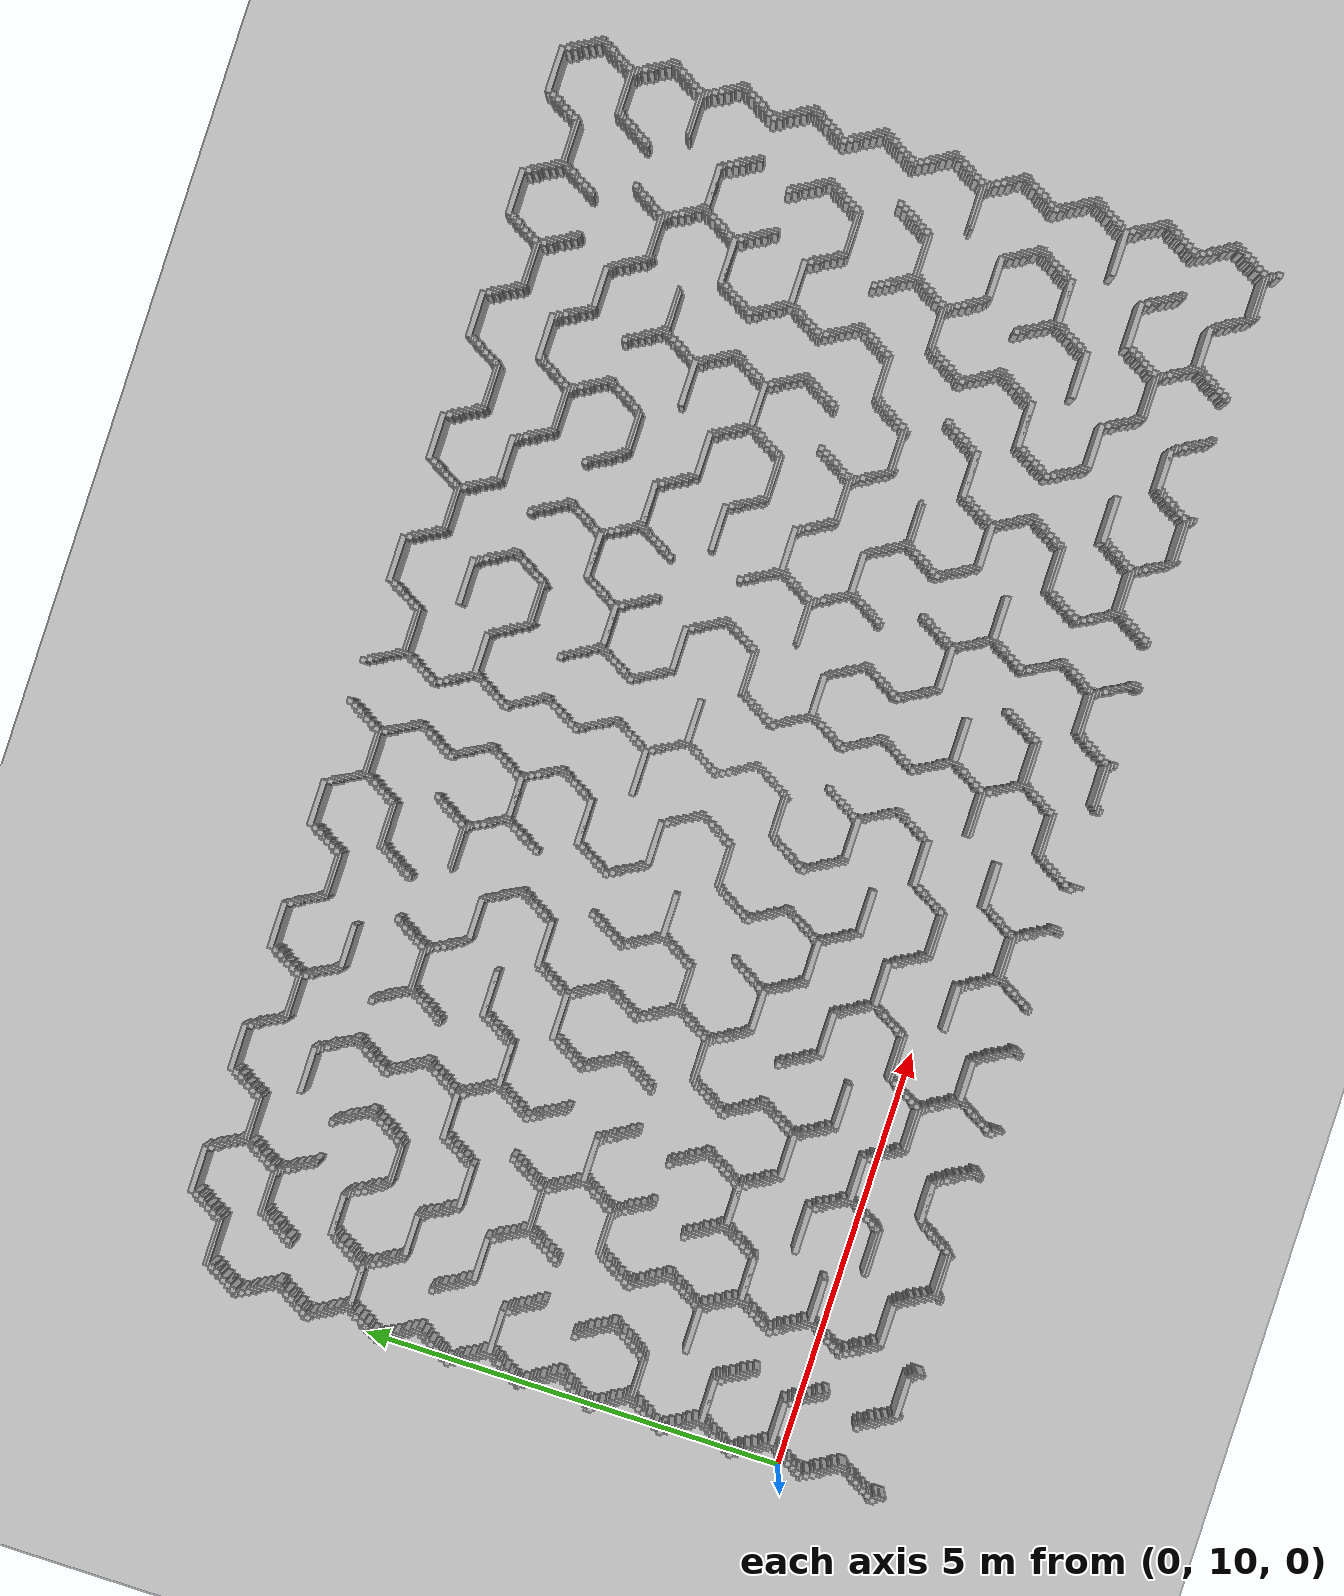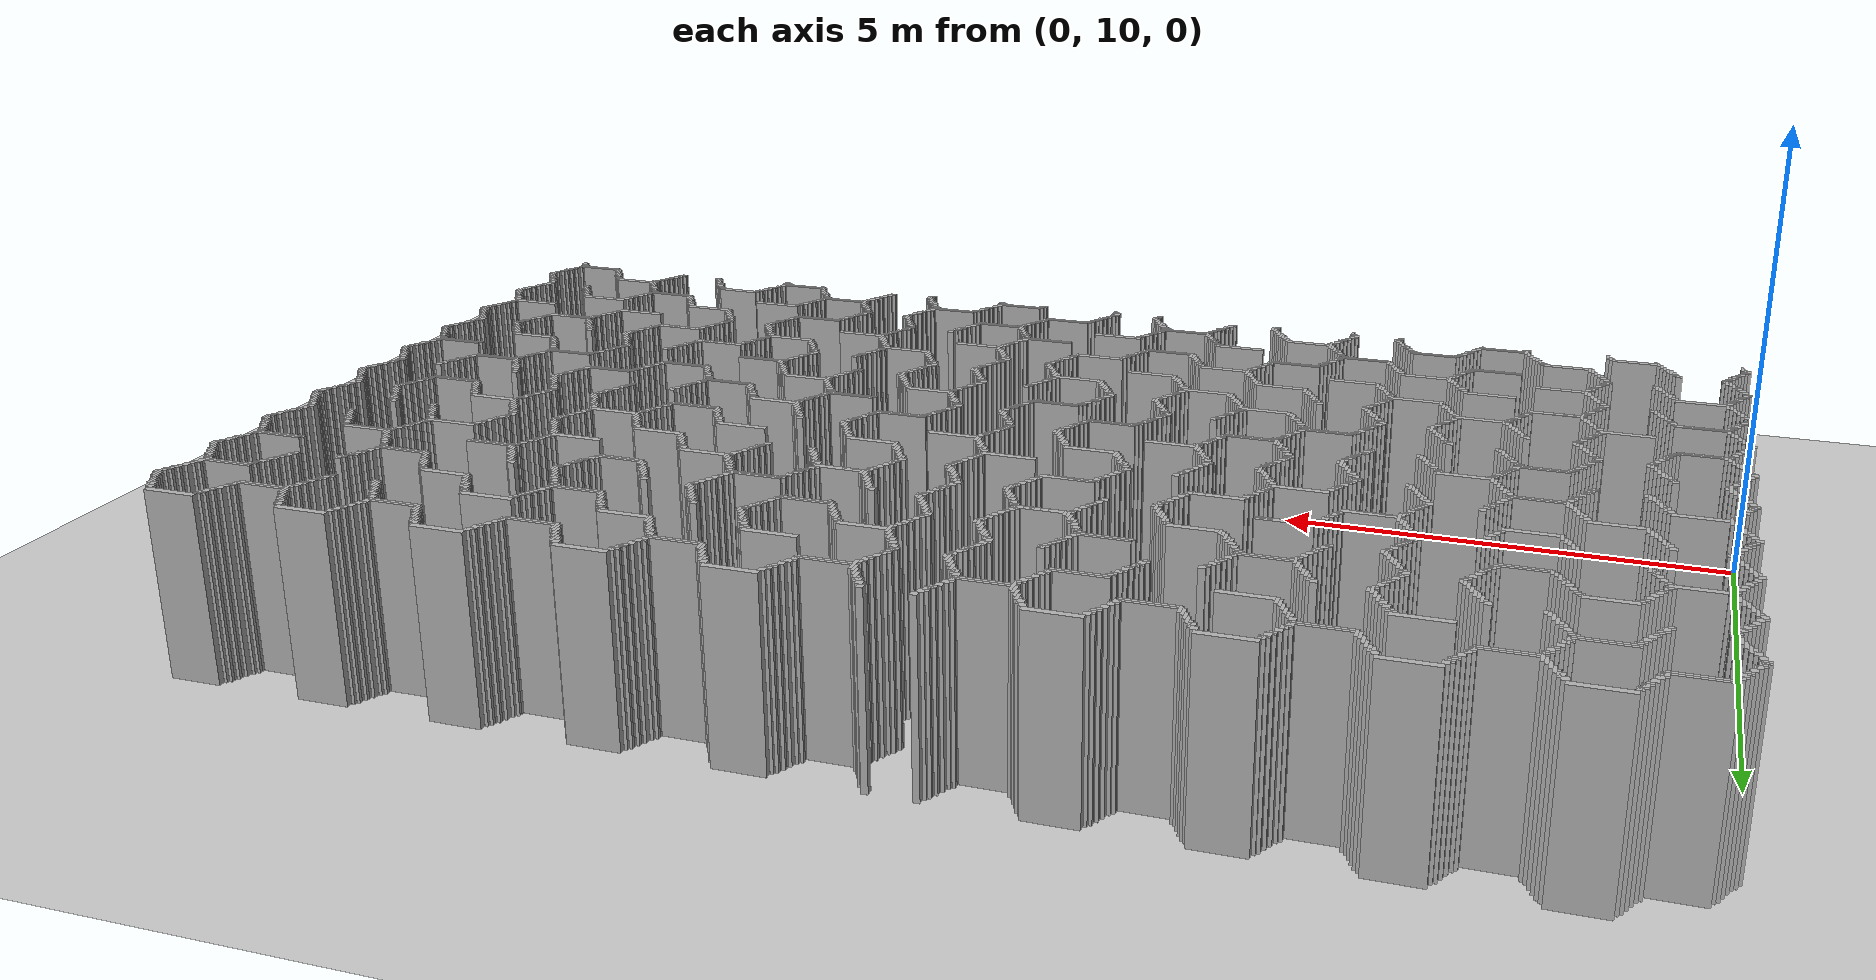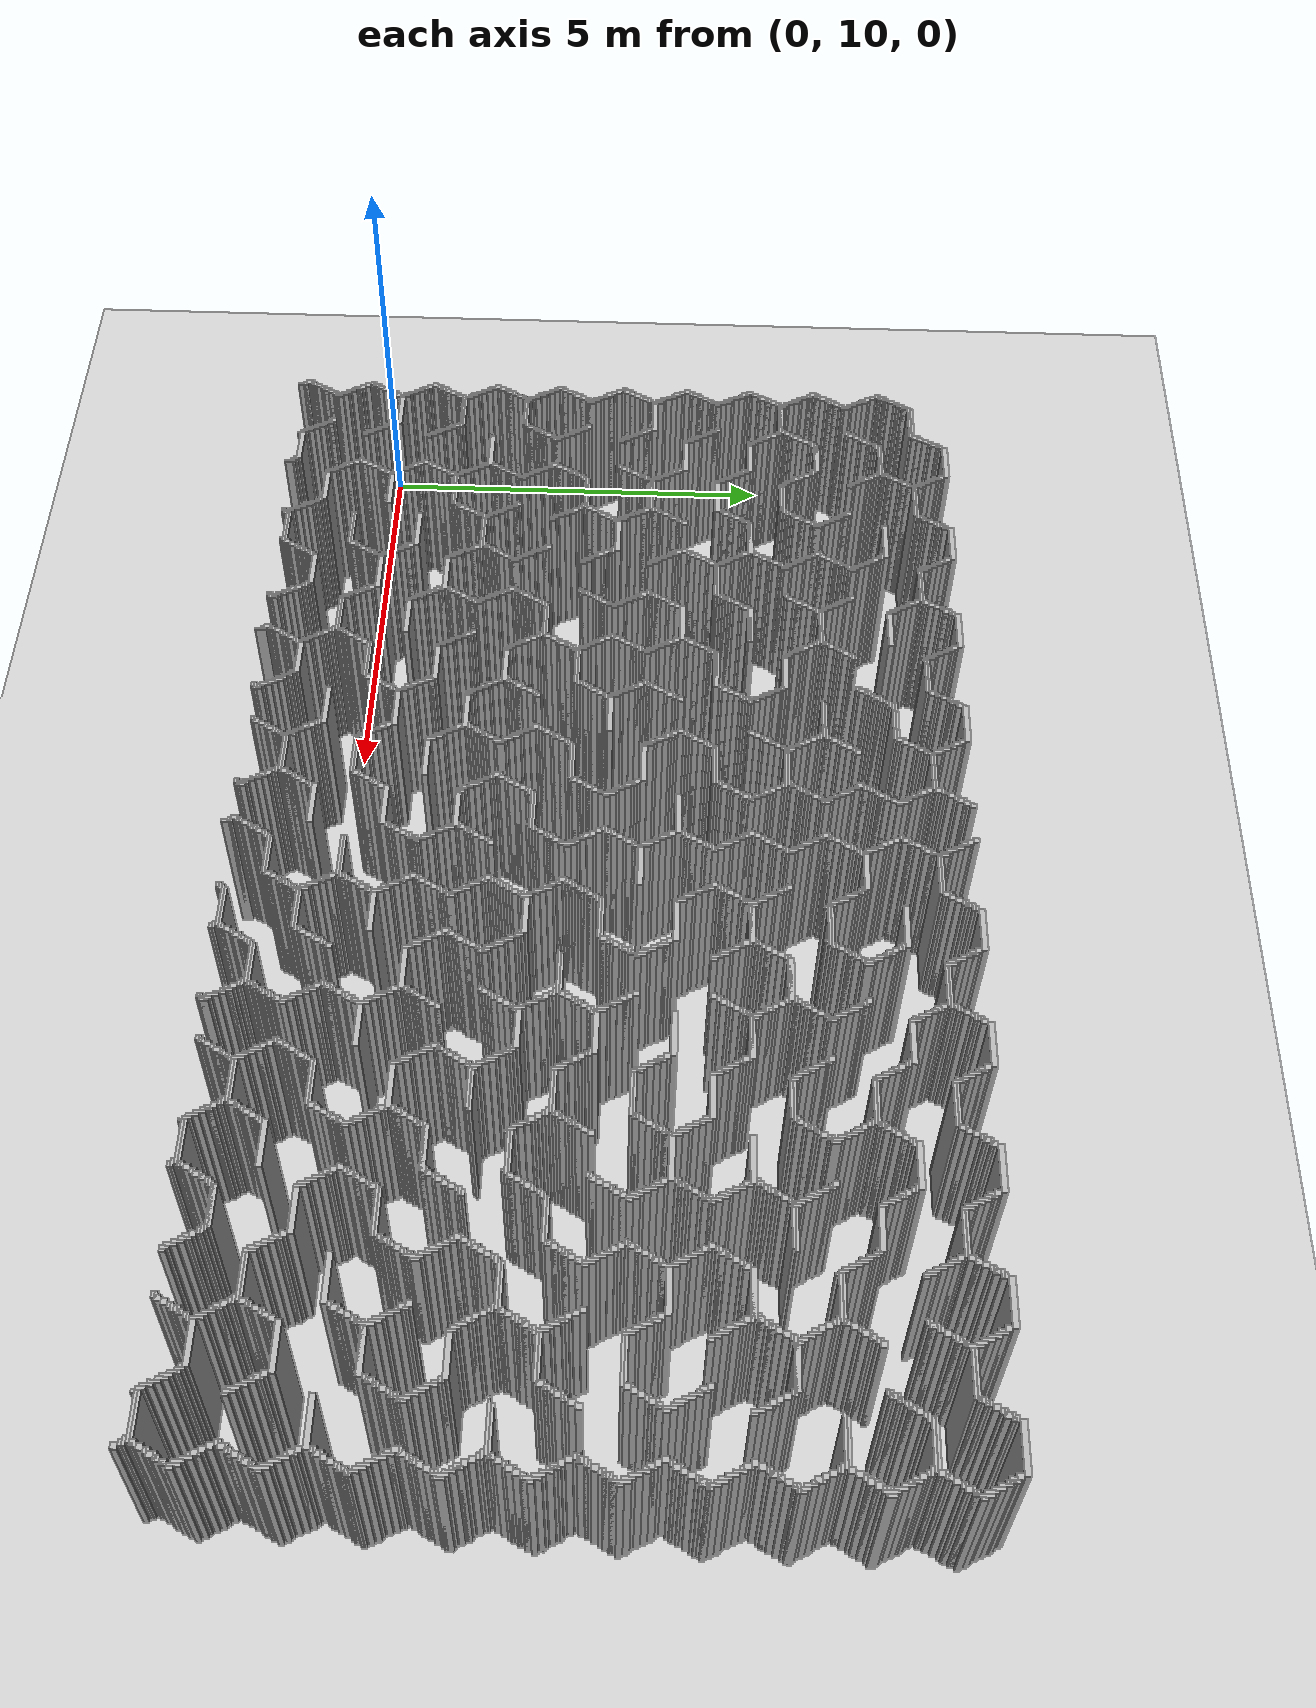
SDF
<sdf version="1.6">
 <world name="slam_world">
  <model name="ground_plane">
   <static>true</static>
   <link name="link">
    <collision name="collision">
     <geometry><plane><normal>0 0 1</normal><size>100 100</size></plane></geometry>
    </collision>
    <visual name="visual">
     <geometry><plane><normal>0 0 1</normal><size>100 100</size></plane></geometry>
     <material>
      <ambient>0.8 0.8 0.8 1</ambient>
      <diffuse>0.8 0.8 0.8 1</diffuse>
      <specular>0.8 0.8 0.8 1</specular>
     </material>
    </visual>
   </link>
  </model>
  <model name="wall_0">
   <static>true</static>
   <pose>1.2877030162412992 17.366589327146173 1.0 0 0 0</pose>
   <link name="link">
    <collision name="collision">
     <geometry><box><size>0.5568445475638051 0.06960556844547564 2.0</size></box></geometry>
    </collision>
    <visual name="visual">
     <geometry><box><size>0.5568445475638051 0.06960556844547564 2.0</size></box></geometry>
     <material><ambient>0.5 0.5 0.5 1</ambient><diffuse>0.7 0.7 0.7 1</diffuse></material>
    </visual>
   </link>
  </model>
  <model name="wall_1">
   <static>true</static>
   <pose>2.7494199535962878 17.366589327146173 1.0 0 0 0</pose>
   <link name="link">
    <collision name="collision">
     <geometry><box><size>0.5568445475638051 0.06960556844547564 2.0</size></box></geometry>
    </collision>
    <visual name="visual">
     <geometry><box><size>0.5568445475638051 0.06960556844547564 2.0</size></box></geometry>
     <material><ambient>0.5 0.5 0.5 1</ambient><diffuse>0.7 0.7 0.7 1</diffuse></material>
    </visual>
   </link>
  </model>
  <model name="wall_2">
   <static>true</static>
   <pose>4.211136890951276 17.366589327146173 1.0 0 0 0</pose>
   <link name="link">
    <collision name="collision">
     <geometry><box><size>0.5568445475638051 0.06960556844547564 2.0</size></box></geometry>
    </collision>
    <visual name="visual">
     <geometry><box><size>0.5568445475638051 0.06960556844547564 2.0</size></box></geometry>
     <material><ambient>0.5 0.5 0.5 1</ambient><diffuse>0.7 0.7 0.7 1</diffuse></material>
    </visual>
   </link>
  </model>
  <model name="wall_3">
   <static>true</static>
   <pose>5.672853828306264 17.366589327146173 1.0 0 0 0</pose>
   <link name="link">
    <collision name="collision">
     <geometry><box><size>0.5568445475638051 0.06960556844547564 2.0</size></box></geometry>
    </collision>
    <visual name="visual">
     <geometry><box><size>0.5568445475638051 0.06960556844547564 2.0</size></box></geometry>
     <material><ambient>0.5 0.5 0.5 1</ambient><diffuse>0.7 0.7 0.7 1</diffuse></material>
    </visual>
   </link>
  </model>
  <model name="wall_4">
   <static>true</static>
   <pose>6.890951276102088 17.366589327146173 1.0 0 0 0</pose>
   <link name="link">
    <collision name="collision">
     <geometry><box><size>0.06960556844547564 0.06960556844547564 2.0</size></box></geometry>
    </collision>
    <visual name="visual">
     <geometry><box><size>0.06960556844547564 0.06960556844547564 2.0</size></box></geometry>
     <material><ambient>0.5 0.5 0.5 1</ambient><diffuse>0.7 0.7 0.7 1</diffuse></material>
    </visual>
   </link>
  </model>
  <model name="wall_5">
   <static>true</static>
   <pose>7.378190255220417 17.366589327146173 1.0 0 0 0</pose>
   <link name="link">
    <collision name="collision">
     <geometry><box><size>0.06960556844547564 0.06960556844547564 2.0</size></box></geometry>
    </collision>
    <visual name="visual">
     <geometry><box><size>0.06960556844547564 0.06960556844547564 2.0</size></box></geometry>
     <material><ambient>0.5 0.5 0.5 1</ambient><diffuse>0.7 0.7 0.7 1</diffuse></material>
    </visual>
   </link>
  </model>
  <model name="wall_6">
   <static>true</static>
   <pose>8.596287703016241 17.366589327146173 1.0 0 0 0</pose>
   <link name="link">
    <collision name="collision">
     <geometry><box><size>0.5568445475638051 0.06960556844547564 2.0</size></box></geometry>
    </collision>
    <visual name="visual">
     <geometry><box><size>0.5568445475638051 0.06960556844547564 2.0</size></box></geometry>
     <material><ambient>0.5 0.5 0.5 1</ambient><diffuse>0.7 0.7 0.7 1</diffuse></material>
    </visual>
   </link>
  </model>
  <model name="wall_7">
   <static>true</static>
   <pose>10.058004640371228 17.366589327146173 1.0 0 0 0</pose>
   <link name="link">
    <collision name="collision">
     <geometry><box><size>0.5568445475638051 0.06960556844547564 2.0</size></box></geometry>
    </collision>
    <visual name="visual">
     <geometry><box><size>0.5568445475638051 0.06960556844547564 2.0</size></box></geometry>
     <material><ambient>0.5 0.5 0.5 1</ambient><diffuse>0.7 0.7 0.7 1</diffuse></material>
    </visual>
   </link>
  </model>
  <model name="wall_8">
   <static>true</static>
   <pose>11.519721577726218 17.366589327146173 1.0 0 0 0</pose>
   <link name="link">
    <collision name="collision">
     <geometry><box><size>0.5568445475638051 0.06960556844547564 2.0</size></box></geometry>
    </collision>
    <visual name="visual">
     <geometry><box><size>0.5568445475638051 0.06960556844547564 2.0</size></box></geometry>
     <material><ambient>0.5 0.5 0.5 1</ambient><diffuse>0.7 0.7 0.7 1</diffuse></material>
    </visual>
   </link>
  </model>
  <model name="wall_9">
   <static>true</static>
   <pose>12.981438515081207 17.366589327146173 1.0 0 0 0</pose>
   <link name="link">
    <collision name="collision">
     <geometry><box><size>0.5568445475638051 0.06960556844547564 2.0</size></box></geometry>
    </collision>
    <visual name="visual">
     <geometry><box><size>0.5568445475638051 0.06960556844547564 2.0</size></box></geometry>
     <material><ambient>0.5 0.5 0.5 1</ambient><diffuse>0.7 0.7 0.7 1</diffuse></material>
    </visual>
   </link>
  </model>
  <model name="wall_10">
   <static>true</static>
   <pose>14.443155452436194 17.366589327146173 1.0 0 0 0</pose>
   <link name="link">
    <collision name="collision">
     <geometry><box><size>0.5568445475638051 0.06960556844547564 2.0</size></box></geometry>
    </collision>
    <visual name="visual">
     <geometry><box><size>0.5568445475638051 0.06960556844547564 2.0</size></box></geometry>
     <material><ambient>0.5 0.5 0.5 1</ambient><diffuse>0.7 0.7 0.7 1</diffuse></material>
    </visual>
   </link>
  </model>
  <model name="wall_11">
   <static>true</static>
   <pose>1.0092807424593968 17.296983758700694 1.0 0 0 0</pose>
   <link name="link">
    <collision name="collision">
     <geometry><box><size>0.06960556844547564 0.06960556844547564 2.0</size></box></geometry>
    </collision>
    <visual name="visual">
     <geometry><box><size>0.06960556844547564 0.06960556844547564 2.0</size></box></geometry>
     <material><ambient>0.5 0.5 0.5 1</ambient><diffuse>0.7 0.7 0.7 1</diffuse></material>
    </visual>
   </link>
  </model>
  <model name="wall_12">
   <static>true</static>
   <pose>1.5661252900232019 17.296983758700694 1.0 0 0 0</pose>
   <link name="link">
    <collision name="collision">
     <geometry><box><size>0.06960556844547564 0.06960556844547564 2.0</size></box></geometry>
    </collision>
    <visual name="visual">
     <geometry><box><size>0.06960556844547564 0.06960556844547564 2.0</size></box></geometry>
     <material><ambient>0.5 0.5 0.5 1</ambient><diffuse>0.7 0.7 0.7 1</diffuse></material>
    </visual>
   </link>
  </model>
  <model name="wall_13">
   <static>true</static>
   <pose>2.470997679814385 17.296983758700694 1.0 0 0 0</pose>
   <link name="link">
    <collision name="collision">
     <geometry><box><size>0.06960556844547564 0.06960556844547564 2.0</size></box></geometry>
    </collision>
    <visual name="visual">
     <geometry><box><size>0.06960556844547564 0.06960556844547564 2.0</size></box></geometry>
     <material><ambient>0.5 0.5 0.5 1</ambient><diffuse>0.7 0.7 0.7 1</diffuse></material>
    </visual>
   </link>
  </model>
  <model name="wall_14">
   <static>true</static>
   <pose>3.02784222737819 17.296983758700694 1.0 0 0 0</pose>
   <link name="link">
    <collision name="collision">
     <geometry><box><size>0.06960556844547564 0.06960556844547564 2.0</size></box></geometry>
    </collision>
    <visual name="visual">
     <geometry><box><size>0.06960556844547564 0.06960556844547564 2.0</size></box></geometry>
     <material><ambient>0.5 0.5 0.5 1</ambient><diffuse>0.7 0.7 0.7 1</diffuse></material>
    </visual>
   </link>
  </model>
  <model name="wall_15">
   <static>true</static>
   <pose>3.932714617169373 17.296983758700694 1.0 0 0 0</pose>
   <link name="link">
    <collision name="collision">
     <geometry><box><size>0.06960556844547564 0.06960556844547564 2.0</size></box></geometry>
    </collision>
    <visual name="visual">
     <geometry><box><size>0.06960556844547564 0.06960556844547564 2.0</size></box></geometry>
     <material><ambient>0.5 0.5 0.5 1</ambient><diffuse>0.7 0.7 0.7 1</diffuse></material>
    </visual>
   </link>
  </model>
  <model name="wall_16">
   <static>true</static>
   <pose>4.489559164733178 17.296983758700694 1.0 0 0 0</pose>
   <link name="link">
    <collision name="collision">
     <geometry><box><size>0.06960556844547564 0.06960556844547564 2.0</size></box></geometry>
    </collision>
    <visual name="visual">
     <geometry><box><size>0.06960556844547564 0.06960556844547564 2.0</size></box></geometry>
     <material><ambient>0.5 0.5 0.5 1</ambient><diffuse>0.7 0.7 0.7 1</diffuse></material>
    </visual>
   </link>
  </model>
  <model name="wall_17">
   <static>true</static>
   <pose>5.3944315545243615 17.296983758700694 1.0 0 0 0</pose>
   <link name="link">
    <collision name="collision">
     <geometry><box><size>0.06960556844547564 0.06960556844547564 2.0</size></box></geometry>
    </collision>
    <visual name="visual">
     <geometry><box><size>0.06960556844547564 0.06960556844547564 2.0</size></box></geometry>
     <material><ambient>0.5 0.5 0.5 1</ambient><diffuse>0.7 0.7 0.7 1</diffuse></material>
    </visual>
   </link>
  </model>
  <model name="wall_18">
   <static>true</static>
   <pose>5.951276102088166 17.296983758700694 1.0 0 0 0</pose>
   <link name="link">
    <collision name="collision">
     <geometry><box><size>0.06960556844547564 0.06960556844547564 2.0</size></box></geometry>
    </collision>
    <visual name="visual">
     <geometry><box><size>0.06960556844547564 0.06960556844547564 2.0</size></box></geometry>
     <material><ambient>0.5 0.5 0.5 1</ambient><diffuse>0.7 0.7 0.7 1</diffuse></material>
    </visual>
   </link>
  </model>
  <model name="wall_19">
   <static>true</static>
   <pose>6.85614849187935 17.296983758700694 1.0 0 0 0</pose>
   <link name="link">
    <collision name="collision">
     <geometry><box><size>0.06960556844547564 0.06960556844547564 2.0</size></box></geometry>
    </collision>
    <visual name="visual">
     <geometry><box><size>0.06960556844547564 0.06960556844547564 2.0</size></box></geometry>
     <material><ambient>0.5 0.5 0.5 1</ambient><diffuse>0.7 0.7 0.7 1</diffuse></material>
    </visual>
   </link>
  </model>
  <model name="wall_20">
   <static>true</static>
   <pose>7.412993039443156 17.296983758700694 1.0 0 0 0</pose>
   <link name="link">
    <collision name="collision">
     <geometry><box><size>0.06960556844547564 0.06960556844547564 2.0</size></box></geometry>
    </collision>
    <visual name="visual">
     <geometry><box><size>0.06960556844547564 0.06960556844547564 2.0</size></box></geometry>
     <material><ambient>0.5 0.5 0.5 1</ambient><diffuse>0.7 0.7 0.7 1</diffuse></material>
    </visual>
   </link>
  </model>
  <model name="wall_21">
   <static>true</static>
   <pose>8.317865429234338 17.296983758700694 1.0 0 0 0</pose>
   <link name="link">
    <collision name="collision">
     <geometry><box><size>0.06960556844547564 0.06960556844547564 2.0</size></box></geometry>
    </collision>
    <visual name="visual">
     <geometry><box><size>0.06960556844547564 0.06960556844547564 2.0</size></box></geometry>
     <material><ambient>0.5 0.5 0.5 1</ambient><diffuse>0.7 0.7 0.7 1</diffuse></material>
    </visual>
   </link>
  </model>
  <model name="wall_22">
   <static>true</static>
   <pose>8.874709976798144 17.296983758700694 1.0 0 0 0</pose>
   <link name="link">
    <collision name="collision">
     <geometry><box><size>0.06960556844547564 0.06960556844547564 2.0</size></box></geometry>
    </collision>
    <visual name="visual">
     <geometry><box><size>0.06960556844547564 0.06960556844547564 2.0</size></box></geometry>
     <material><ambient>0.5 0.5 0.5 1</ambient><diffuse>0.7 0.7 0.7 1</diffuse></material>
    </visual>
   </link>
  </model>
  <model name="wall_23">
   <static>true</static>
   <pose>9.779582366589327 17.296983758700694 1.0 0 0 0</pose>
   <link name="link">
    <collision name="collision">
     <geometry><box><size>0.06960556844547564 0.06960556844547564 2.0</size></box></geometry>
    </collision>
    <visual name="visual">
     <geometry><box><size>0.06960556844547564 0.06960556844547564 2.0</size></box></geometry>
     <material><ambient>0.5 0.5 0.5 1</ambient><diffuse>0.7 0.7 0.7 1</diffuse></material>
    </visual>
   </link>
  </model>
  <model name="wall_24">
   <static>true</static>
   <pose>10.336426914153131 17.296983758700694 1.0 0 0 0</pose>
   <link name="link">
    <collision name="collision">
     <geometry><box><size>0.06960556844547564 0.06960556844547564 2.0</size></box></geometry>
    </collision>
    <visual name="visual">
     <geometry><box><size>0.06960556844547564 0.06960556844547564 2.0</size></box></geometry>
     <material><ambient>0.5 0.5 0.5 1</ambient><diffuse>0.7 0.7 0.7 1</diffuse></material>
    </visual>
   </link>
  </model>
  <model name="wall_25">
   <static>true</static>
   <pose>11.241299303944315 17.296983758700694 1.0 0 0 0</pose>
   <link name="link">
    <collision name="collision">
     <geometry><box><size>0.06960556844547564 0.06960556844547564 2.0</size></box></geometry>
    </collision>
    <visual name="visual">
     <geometry><box><size>0.06960556844547564 0.06960556844547564 2.0</size></box></geometry>
     <material><ambient>0.5 0.5 0.5 1</ambient><diffuse>0.7 0.7 0.7 1</diffuse></material>
    </visual>
   </link>
  </model>
  <model name="wall_26">
   <static>true</static>
   <pose>11.79814385150812 17.296983758700694 1.0 0 0 0</pose>
   <link name="link">
    <collision name="collision">
     <geometry><box><size>0.06960556844547564 0.06960556844547564 2.0</size></box></geometry>
    </collision>
    <visual name="visual">
     <geometry><box><size>0.06960556844547564 0.06960556844547564 2.0</size></box></geometry>
     <material><ambient>0.5 0.5 0.5 1</ambient><diffuse>0.7 0.7 0.7 1</diffuse></material>
    </visual>
   </link>
  </model>
  <model name="wall_27">
   <static>true</static>
   <pose>12.703016241299304 17.296983758700694 1.0 0 0 0</pose>
   <link name="link">
    <collision name="collision">
     <geometry><box><size>0.06960556844547564 0.06960556844547564 2.0</size></box></geometry>
    </collision>
    <visual name="visual">
     <geometry><box><size>0.06960556844547564 0.06960556844547564 2.0</size></box></geometry>
     <material><ambient>0.5 0.5 0.5 1</ambient><diffuse>0.7 0.7 0.7 1</diffuse></material>
    </visual>
   </link>
  </model>
  <model name="wall_28">
   <static>true</static>
   <pose>13.259860788863108 17.296983758700694 1.0 0 0 0</pose>
   <link name="link">
    <collision name="collision">
     <geometry><box><size>0.06960556844547564 0.06960556844547564 2.0</size></box></geometry>
    </collision>
    <visual name="visual">
     <geometry><box><size>0.06960556844547564 0.06960556844547564 2.0</size></box></geometry>
     <material><ambient>0.5 0.5 0.5 1</ambient><diffuse>0.7 0.7 0.7 1</diffuse></material>
    </visual>
   </link>
  </model>
  <model name="wall_29">
   <static>true</static>
   <pose>14.164733178654291 17.296983758700694 1.0 0 0 0</pose>
   <link name="link">
    <collision name="collision">
     <geometry><box><size>0.06960556844547564 0.06960556844547564 2.0</size></box></geometry>
    </collision>
    <visual name="visual">
     <geometry><box><size>0.06960556844547564 0.06960556844547564 2.0</size></box></geometry>
     <material><ambient>0.5 0.5 0.5 1</ambient><diffuse>0.7 0.7 0.7 1</diffuse></material>
    </visual>
   </link>
  </model>
  <model name="wall_30">
   <static>true</static>
   <pose>14.721577726218097 17.296983758700694 1.0 0 0 0</pose>
   <link name="link">
    <collision name="collision">
     <geometry><box><size>0.06960556844547564 0.06960556844547564 2.0</size></box></geometry>
    </collision>
    <visual name="visual">
     <geometry><box><size>0.06960556844547564 0.06960556844547564 2.0</size></box></geometry>
     <material><ambient>0.5 0.5 0.5 1</ambient><diffuse>0.7 0.7 0.7 1</diffuse></material>
    </visual>
   </link>
  </model>
  <model name="wall_31">
   <static>true</static>
   <pose>0.9918793503480278 17.279582366589327 1.0 0 0 0</pose>
   <link name="link">
    <collision name="collision">
     <geometry><box><size>0.10440835266821345 0.03480278422273782 2.0</size></box></geometry>
    </collision>
    <visual name="visual">
     <geometry><box><size>0.10440835266821345 0.03480278422273782 2.0</size></box></geometry>
     <material><ambient>0.5 0.5 0.5 1</ambient><diffuse>0.7 0.7 0.7 1</diffuse></material>
    </visual>
   </link>
  </model>
  <model name="wall_32">
   <static>true</static>
   <pose>1.6183294663573085 17.22737819025522 1.0 0 0 0</pose>
   <link name="link">
    <collision name="collision">
     <geometry><box><size>0.03480278422273782 0.13921113689095127 2.0</size></box></geometry>
    </collision>
    <visual name="visual">
     <geometry><box><size>0.03480278422273782 0.13921113689095127 2.0</size></box></geometry>
     <material><ambient>0.5 0.5 0.5 1</ambient><diffuse>0.7 0.7 0.7 1</diffuse></material>
    </visual>
   </link>
  </model>
  <model name="wall_33">
   <static>true</static>
   <pose>2.453596287703016 17.279582366589327 1.0 0 0 0</pose>
   <link name="link">
    <collision name="collision">
     <geometry><box><size>0.10440835266821345 0.03480278422273782 2.0</size></box></geometry>
    </collision>
    <visual name="visual">
     <geometry><box><size>0.10440835266821345 0.03480278422273782 2.0</size></box></geometry>
     <material><ambient>0.5 0.5 0.5 1</ambient><diffuse>0.7 0.7 0.7 1</diffuse></material>
    </visual>
   </link>
  </model>
  <model name="wall_34">
   <static>true</static>
   <pose>3.0800464037122968 17.22737819025522 1.0 0 0 0</pose>
   <link name="link">
    <collision name="collision">
     <geometry><box><size>0.03480278422273782 0.13921113689095127 2.0</size></box></geometry>
    </collision>
    <visual name="visual">
     <geometry><box><size>0.03480278422273782 0.13921113689095127 2.0</size></box></geometry>
     <material><ambient>0.5 0.5 0.5 1</ambient><diffuse>0.7 0.7 0.7 1</diffuse></material>
    </visual>
   </link>
  </model>
  <model name="wall_35">
   <static>true</static>
   <pose>3.9153132250580045 17.279582366589327 1.0 0 0 0</pose>
   <link name="link">
    <collision name="collision">
     <geometry><box><size>0.10440835266821345 0.03480278422273782 2.0</size></box></geometry>
    </collision>
    <visual name="visual">
     <geometry><box><size>0.10440835266821345 0.03480278422273782 2.0</size></box></geometry>
     <material><ambient>0.5 0.5 0.5 1</ambient><diffuse>0.7 0.7 0.7 1</diffuse></material>
    </visual>
   </link>
  </model>
  <model name="wall_36">
   <static>true</static>
   <pose>4.541763341067285 17.22737819025522 1.0 0 0 0</pose>
   <link name="link">
    <collision name="collision">
     <geometry><box><size>0.03480278422273782 0.13921113689095127 2.0</size></box></geometry>
    </collision>
    <visual name="visual">
     <geometry><box><size>0.03480278422273782 0.13921113689095127 2.0</size></box></geometry>
     <material><ambient>0.5 0.5 0.5 1</ambient><diffuse>0.7 0.7 0.7 1</diffuse></material>
    </visual>
   </link>
  </model>
  <model name="wall_37">
   <static>true</static>
   <pose>5.377030162412993 17.279582366589327 1.0 0 0 0</pose>
   <link name="link">
    <collision name="collision">
     <geometry><box><size>0.10440835266821345 0.03480278422273782 2.0</size></box></geometry>
    </collision>
    <visual name="visual">
     <geometry><box><size>0.10440835266821345 0.03480278422273782 2.0</size></box></geometry>
     <material><ambient>0.5 0.5 0.5 1</ambient><diffuse>0.7 0.7 0.7 1</diffuse></material>
    </visual>
   </link>
  </model>
  <model name="wall_38">
   <static>true</static>
   <pose>6.003480278422273 17.22737819025522 1.0 0 0 0</pose>
   <link name="link">
    <collision name="collision">
     <geometry><box><size>0.03480278422273782 0.13921113689095127 2.0</size></box></geometry>
    </collision>
    <visual name="visual">
     <geometry><box><size>0.03480278422273782 0.13921113689095127 2.0</size></box></geometry>
     <material><ambient>0.5 0.5 0.5 1</ambient><diffuse>0.7 0.7 0.7 1</diffuse></material>
    </visual>
   </link>
  </model>
  <model name="wall_39">
   <static>true</static>
   <pose>6.838747099767981 17.279582366589327 1.0 0 0 0</pose>
   <link name="link">
    <collision name="collision">
     <geometry><box><size>0.10440835266821345 0.03480278422273782 2.0</size></box></geometry>
    </collision>
    <visual name="visual">
     <geometry><box><size>0.10440835266821345 0.03480278422273782 2.0</size></box></geometry>
     <material><ambient>0.5 0.5 0.5 1</ambient><diffuse>0.7 0.7 0.7 1</diffuse></material>
    </visual>
   </link>
  </model>
  <model name="wall_40">
   <static>true</static>
   <pose>7.465197215777262 17.22737819025522 1.0 0 0 0</pose>
   <link name="link">
    <collision name="collision">
     <geometry><box><size>0.03480278422273782 0.13921113689095127 2.0</size></box></geometry>
    </collision>
    <visual name="visual">
     <geometry><box><size>0.03480278422273782 0.13921113689095127 2.0</size></box></geometry>
     <material><ambient>0.5 0.5 0.5 1</ambient><diffuse>0.7 0.7 0.7 1</diffuse></material>
    </visual>
   </link>
  </model>
  <model name="wall_41">
   <static>true</static>
   <pose>8.30046403712297 17.279582366589327 1.0 0 0 0</pose>
   <link name="link">
    <collision name="collision">
     <geometry><box><size>0.10440835266821345 0.03480278422273782 2.0</size></box></geometry>
    </collision>
    <visual name="visual">
     <geometry><box><size>0.10440835266821345 0.03480278422273782 2.0</size></box></geometry>
     <material><ambient>0.5 0.5 0.5 1</ambient><diffuse>0.7 0.7 0.7 1</diffuse></material>
    </visual>
   </link>
  </model>
  <model name="wall_42">
   <static>true</static>
   <pose>8.92691415313225 17.22737819025522 1.0 0 0 0</pose>
   <link name="link">
    <collision name="collision">
     <geometry><box><size>0.03480278422273782 0.13921113689095127 2.0</size></box></geometry>
    </collision>
    <visual name="visual">
     <geometry><box><size>0.03480278422273782 0.13921113689095127 2.0</size></box></geometry>
     <material><ambient>0.5 0.5 0.5 1</ambient><diffuse>0.7 0.7 0.7 1</diffuse></material>
    </visual>
   </link>
  </model>
  <model name="wall_43">
   <static>true</static>
   <pose>9.762180974477959 17.279582366589327 1.0 0 0 0</pose>
   <link name="link">
    <collision name="collision">
     <geometry><box><size>0.10440835266821345 0.03480278422273782 2.0</size></box></geometry>
    </collision>
    <visual name="visual">
     <geometry><box><size>0.10440835266821345 0.03480278422273782 2.0</size></box></geometry>
     <material><ambient>0.5 0.5 0.5 1</ambient><diffuse>0.7 0.7 0.7 1</diffuse></material>
    </visual>
   </link>
  </model>
  <model name="wall_44">
   <static>true</static>
   <pose>10.38863109048724 17.22737819025522 1.0 0 0 0</pose>
   <link name="link">
    <collision name="collision">
     <geometry><box><size>0.03480278422273782 0.13921113689095127 2.0</size></box></geometry>
    </collision>
    <visual name="visual">
     <geometry><box><size>0.03480278422273782 0.13921113689095127 2.0</size></box></geometry>
     <material><ambient>0.5 0.5 0.5 1</ambient><diffuse>0.7 0.7 0.7 1</diffuse></material>
    </visual>
   </link>
  </model>
  <model name="wall_45">
   <static>true</static>
   <pose>11.223897911832946 17.279582366589327 1.0 0 0 0</pose>
   <link name="link">
    <collision name="collision">
     <geometry><box><size>0.10440835266821345 0.03480278422273782 2.0</size></box></geometry>
    </collision>
    <visual name="visual">
     <geometry><box><size>0.10440835266821345 0.03480278422273782 2.0</size></box></geometry>
     <material><ambient>0.5 0.5 0.5 1</ambient><diffuse>0.7 0.7 0.7 1</diffuse></material>
    </visual>
   </link>
  </model>
  <model name="wall_46">
   <static>true</static>
   <pose>11.850348027842227 17.22737819025522 1.0 0 0 0</pose>
   <link name="link">
    <collision name="collision">
     <geometry><box><size>0.03480278422273782 0.13921113689095127 2.0</size></box></geometry>
    </collision>
    <visual name="visual">
     <geometry><box><size>0.03480278422273782 0.13921113689095127 2.0</size></box></geometry>
     <material><ambient>0.5 0.5 0.5 1</ambient><diffuse>0.7 0.7 0.7 1</diffuse></material>
    </visual>
   </link>
  </model>
  <model name="wall_47">
   <static>true</static>
   <pose>12.685614849187935 17.279582366589327 1.0 0 0 0</pose>
   <link name="link">
    <collision name="collision">
     <geometry><box><size>0.10440835266821345 0.03480278422273782 2.0</size></box></geometry>
    </collision>
    <visual name="visual">
     <geometry><box><size>0.10440835266821345 0.03480278422273782 2.0</size></box></geometry>
     <material><ambient>0.5 0.5 0.5 1</ambient><diffuse>0.7 0.7 0.7 1</diffuse></material>
    </visual>
   </link>
  </model>
  <model name="wall_48">
   <static>true</static>
   <pose>13.312064965197216 17.22737819025522 1.0 0 0 0</pose>
   <link name="link">
    <collision name="collision">
     <geometry><box><size>0.03480278422273782 0.13921113689095127 2.0</size></box></geometry>
    </collision>
    <visual name="visual">
     <geometry><box><size>0.03480278422273782 0.13921113689095127 2.0</size></box></geometry>
     <material><ambient>0.5 0.5 0.5 1</ambient><diffuse>0.7 0.7 0.7 1</diffuse></material>
    </visual>
   </link>
  </model>
  <model name="wall_49">
   <static>true</static>
   <pose>14.147331786542923 17.279582366589327 1.0 0 0 0</pose>
   <link name="link">
    <collision name="collision">
     <geometry><box><size>0.10440835266821345 0.03480278422273782 2.0</size></box></geometry>
    </collision>
    <visual name="visual">
     <geometry><box><size>0.10440835266821345 0.03480278422273782 2.0</size></box></geometry>
     <material><ambient>0.5 0.5 0.5 1</ambient><diffuse>0.7 0.7 0.7 1</diffuse></material>
    </visual>
   </link>
  </model>
  <model name="wall_50">
   <static>true</static>
   <pose>14.773781902552203 17.22737819025522 1.0 0 0 0</pose>
   <link name="link">
    <collision name="collision">
     <geometry><box><size>0.03480278422273782 0.13921113689095127 2.0</size></box></geometry>
    </collision>
    <visual name="visual">
     <geometry><box><size>0.03480278422273782 0.13921113689095127 2.0</size></box></geometry>
     <material><ambient>0.5 0.5 0.5 1</ambient><diffuse>0.7 0.7 0.7 1</diffuse></material>
    </visual>
   </link>
  </model>
  <model name="wall_51">
   <static>true</static>
   <pose>0.974477958236659 17.22737819025522 1.0 0 0 0</pose>
   <link name="link">
    <collision name="collision">
     <geometry><box><size>0.06960556844547564 0.06960556844547564 2.0</size></box></geometry>
    </collision>
    <visual name="visual">
     <geometry><box><size>0.06960556844547564 0.06960556844547564 2.0</size></box></geometry>
     <material><ambient>0.5 0.5 0.5 1</ambient><diffuse>0.7 0.7 0.7 1</diffuse></material>
    </visual>
   </link>
  </model>
  <model name="wall_52">
   <static>true</static>
   <pose>1.6009280742459395 17.22737819025522 1.0 0 0 0</pose>
   <link name="link">
    <collision name="collision">
     <geometry><box><size>0.06960556844547564 0.06960556844547564 2.0</size></box></geometry>
    </collision>
    <visual name="visual">
     <geometry><box><size>0.06960556844547564 0.06960556844547564 2.0</size></box></geometry>
     <material><ambient>0.5 0.5 0.5 1</ambient><diffuse>0.7 0.7 0.7 1</diffuse></material>
    </visual>
   </link>
  </model>
  <model name="wall_53">
   <static>true</static>
   <pose>2.436194895591647 17.22737819025522 1.0 0 0 0</pose>
   <link name="link">
    <collision name="collision">
     <geometry><box><size>0.06960556844547564 0.06960556844547564 2.0</size></box></geometry>
    </collision>
    <visual name="visual">
     <geometry><box><size>0.06960556844547564 0.06960556844547564 2.0</size></box></geometry>
     <material><ambient>0.5 0.5 0.5 1</ambient><diffuse>0.7 0.7 0.7 1</diffuse></material>
    </visual>
   </link>
  </model>
  <model name="wall_54">
   <static>true</static>
   <pose>3.062645011600928 17.22737819025522 1.0 0 0 0</pose>
   <link name="link">
    <collision name="collision">
     <geometry><box><size>0.06960556844547564 0.06960556844547564 2.0</size></box></geometry>
    </collision>
    <visual name="visual">
     <geometry><box><size>0.06960556844547564 0.06960556844547564 2.0</size></box></geometry>
     <material><ambient>0.5 0.5 0.5 1</ambient><diffuse>0.7 0.7 0.7 1</diffuse></material>
    </visual>
   </link>
  </model>
  <model name="wall_55">
   <static>true</static>
   <pose>3.897911832946636 17.22737819025522 1.0 0 0 0</pose>
   <link name="link">
    <collision name="collision">
     <geometry><box><size>0.06960556844547564 0.06960556844547564 2.0</size></box></geometry>
    </collision>
    <visual name="visual">
     <geometry><box><size>0.06960556844547564 0.06960556844547564 2.0</size></box></geometry>
     <material><ambient>0.5 0.5 0.5 1</ambient><diffuse>0.7 0.7 0.7 1</diffuse></material>
    </visual>
   </link>
  </model>
  <model name="wall_56">
   <static>true</static>
   <pose>4.524361948955916 17.22737819025522 1.0 0 0 0</pose>
   <link name="link">
    <collision name="collision">
     <geometry><box><size>0.06960556844547564 0.06960556844547564 2.0</size></box></geometry>
    </collision>
    <visual name="visual">
     <geometry><box><size>0.06960556844547564 0.06960556844547564 2.0</size></box></geometry>
     <material><ambient>0.5 0.5 0.5 1</ambient><diffuse>0.7 0.7 0.7 1</diffuse></material>
    </visual>
   </link>
  </model>
  <model name="wall_57">
   <static>true</static>
   <pose>5.359628770301624 17.22737819025522 1.0 0 0 0</pose>
   <link name="link">
    <collision name="collision">
     <geometry><box><size>0.06960556844547564 0.06960556844547564 2.0</size></box></geometry>
    </collision>
    <visual name="visual">
     <geometry><box><size>0.06960556844547564 0.06960556844547564 2.0</size></box></geometry>
     <material><ambient>0.5 0.5 0.5 1</ambient><diffuse>0.7 0.7 0.7 1</diffuse></material>
    </visual>
   </link>
  </model>
  <model name="wall_58">
   <static>true</static>
   <pose>5.986078886310905 17.22737819025522 1.0 0 0 0</pose>
   <link name="link">
    <collision name="collision">
     <geometry><box><size>0.06960556844547564 0.06960556844547564 2.0</size></box></geometry>
    </collision>
    <visual name="visual">
     <geometry><box><size>0.06960556844547564 0.06960556844547564 2.0</size></box></geometry>
     <material><ambient>0.5 0.5 0.5 1</ambient><diffuse>0.7 0.7 0.7 1</diffuse></material>
    </visual>
   </link>
  </model>
  <model name="wall_59">
   <static>true</static>
   <pose>6.821345707656612 17.22737819025522 1.0 0 0 0</pose>
   <link name="link">
    <collision name="collision">
     <geometry><box><size>0.06960556844547564 0.06960556844547564 2.0</size></box></geometry>
    </collision>
    <visual name="visual">
     <geometry><box><size>0.06960556844547564 0.06960556844547564 2.0</size></box></geometry>
     <material><ambient>0.5 0.5 0.5 1</ambient><diffuse>0.7 0.7 0.7 1</diffuse></material>
    </visual>
   </link>
  </model>
  <model name="wall_60">
   <static>true</static>
   <pose>7.447795823665893 17.22737819025522 1.0 0 0 0</pose>
   <link name="link">
    <collision name="collision">
     <geometry><box><size>0.06960556844547564 0.06960556844547564 2.0</size></box></geometry>
    </collision>
    <visual name="visual">
     <geometry><box><size>0.06960556844547564 0.06960556844547564 2.0</size></box></geometry>
     <material><ambient>0.5 0.5 0.5 1</ambient><diffuse>0.7 0.7 0.7 1</diffuse></material>
    </visual>
   </link>
  </model>
  <model name="wall_61">
   <static>true</static>
   <pose>8.2830626450116 17.22737819025522 1.0 0 0 0</pose>
   <link name="link">
    <collision name="collision">
     <geometry><box><size>0.06960556844547564 0.06960556844547564 2.0</size></box></geometry>
    </collision>
    <visual name="visual">
     <geometry><box><size>0.06960556844547564 0.06960556844547564 2.0</size></box></geometry>
     <material><ambient>0.5 0.5 0.5 1</ambient><diffuse>0.7 0.7 0.7 1</diffuse></material>
    </visual>
   </link>
  </model>
  <model name="wall_62">
   <static>true</static>
   <pose>8.909512761020881 17.22737819025522 1.0 0 0 0</pose>
   <link name="link">
    <collision name="collision">
     <geometry><box><size>0.06960556844547564 0.06960556844547564 2.0</size></box></geometry>
    </collision>
    <visual name="visual">
     <geometry><box><size>0.06960556844547564 0.06960556844547564 2.0</size></box></geometry>
     <material><ambient>0.5 0.5 0.5 1</ambient><diffuse>0.7 0.7 0.7 1</diffuse></material>
    </visual>
   </link>
  </model>
  <model name="wall_63">
   <static>true</static>
   <pose>9.744779582366588 17.22737819025522 1.0 0 0 0</pose>
   <link name="link">
    <collision name="collision">
     <geometry><box><size>0.06960556844547564 0.06960556844547564 2.0</size></box></geometry>
    </collision>
    <visual name="visual">
     <geometry><box><size>0.06960556844547564 0.06960556844547564 2.0</size></box></geometry>
     <material><ambient>0.5 0.5 0.5 1</ambient><diffuse>0.7 0.7 0.7 1</diffuse></material>
    </visual>
   </link>
  </model>
  <model name="wall_64">
   <static>true</static>
   <pose>10.37122969837587 17.22737819025522 1.0 0 0 0</pose>
   <link name="link">
    <collision name="collision">
     <geometry><box><size>0.06960556844547564 0.06960556844547564 2.0</size></box></geometry>
    </collision>
    <visual name="visual">
     <geometry><box><size>0.06960556844547564 0.06960556844547564 2.0</size></box></geometry>
     <material><ambient>0.5 0.5 0.5 1</ambient><diffuse>0.7 0.7 0.7 1</diffuse></material>
    </visual>
   </link>
  </model>
  <model name="wall_65">
   <static>true</static>
   <pose>11.206496519721577 17.22737819025522 1.0 0 0 0</pose>
   <link name="link">
    <collision name="collision">
     <geometry><box><size>0.06960556844547564 0.06960556844547564 2.0</size></box></geometry>
    </collision>
    <visual name="visual">
     <geometry><box><size>0.06960556844547564 0.06960556844547564 2.0</size></box></geometry>
     <material><ambient>0.5 0.5 0.5 1</ambient><diffuse>0.7 0.7 0.7 1</diffuse></material>
    </visual>
   </link>
  </model>
  <model name="wall_66">
   <static>true</static>
   <pose>11.832946635730858 17.22737819025522 1.0 0 0 0</pose>
   <link name="link">
    <collision name="collision">
     <geometry><box><size>0.06960556844547564 0.06960556844547564 2.0</size></box></geometry>
    </collision>
    <visual name="visual">
     <geometry><box><size>0.06960556844547564 0.06960556844547564 2.0</size></box></geometry>
     <material><ambient>0.5 0.5 0.5 1</ambient><diffuse>0.7 0.7 0.7 1</diffuse></material>
    </visual>
   </link>
  </model>
  <model name="wall_67">
   <static>true</static>
   <pose>12.668213457076565 17.22737819025522 1.0 0 0 0</pose>
   <link name="link">
    <collision name="collision">
     <geometry><box><size>0.06960556844547564 0.06960556844547564 2.0</size></box></geometry>
    </collision>
    <visual name="visual">
     <geometry><box><size>0.06960556844547564 0.06960556844547564 2.0</size></box></geometry>
     <material><ambient>0.5 0.5 0.5 1</ambient><diffuse>0.7 0.7 0.7 1</diffuse></material>
    </visual>
   </link>
  </model>
  <model name="wall_68">
   <static>true</static>
   <pose>13.294663573085847 17.22737819025522 1.0 0 0 0</pose>
   <link name="link">
    <collision name="collision">
     <geometry><box><size>0.06960556844547564 0.06960556844547564 2.0</size></box></geometry>
    </collision>
    <visual name="visual">
     <geometry><box><size>0.06960556844547564 0.06960556844547564 2.0</size></box></geometry>
     <material><ambient>0.5 0.5 0.5 1</ambient><diffuse>0.7 0.7 0.7 1</diffuse></material>
    </visual>
   </link>
  </model>
  <model name="wall_69">
   <static>true</static>
   <pose>14.129930394431554 17.22737819025522 1.0 0 0 0</pose>
   <link name="link">
    <collision name="collision">
     <geometry><box><size>0.06960556844547564 0.06960556844547564 2.0</size></box></geometry>
    </collision>
    <visual name="visual">
     <geometry><box><size>0.06960556844547564 0.06960556844547564 2.0</size></box></geometry>
     <material><ambient>0.5 0.5 0.5 1</ambient><diffuse>0.7 0.7 0.7 1</diffuse></material>
    </visual>
   </link>
  </model>
  <model name="wall_70">
   <static>true</static>
   <pose>14.756380510440835 17.22737819025522 1.0 0 0 0</pose>
   <link name="link">
    <collision name="collision">
     <geometry><box><size>0.06960556844547564 0.06960556844547564 2.0</size></box></geometry>
    </collision>
    <visual name="visual">
     <geometry><box><size>0.06960556844547564 0.06960556844547564 2.0</size></box></geometry>
     <material><ambient>0.5 0.5 0.5 1</ambient><diffuse>0.7 0.7 0.7 1</diffuse></material>
    </visual>
   </link>
  </model>
  <model name="wall_71">
   <static>true</static>
   <pose>0.95707656612529 17.209976798143853 1.0 0 0 0</pose>
   <link name="link">
    <collision name="collision">
     <geometry><box><size>0.10440835266821345 0.03480278422273782 2.0</size></box></geometry>
    </collision>
    <visual name="visual">
     <geometry><box><size>0.10440835266821345 0.03480278422273782 2.0</size></box></geometry>
     <material><ambient>0.5 0.5 0.5 1</ambient><diffuse>0.7 0.7 0.7 1</diffuse></material>
    </visual>
   </link>
  </model>
  <model name="wall_72">
   <static>true</static>
   <pose>1.6531322505800463 17.157772621809745 1.0 0 0 0</pose>
   <link name="link">
    <collision name="collision">
     <geometry><box><size>0.03480278422273782 0.13921113689095127 2.0</size></box></geometry>
    </collision>
    <visual name="visual">
     <geometry><box><size>0.03480278422273782 0.13921113689095127 2.0</size></box></geometry>
     <material><ambient>0.5 0.5 0.5 1</ambient><diffuse>0.7 0.7 0.7 1</diffuse></material>
    </visual>
   </link>
  </model>
  <model name="wall_73">
   <static>true</static>
   <pose>2.4187935034802783 17.209976798143853 1.0 0 0 0</pose>
   <link name="link">
    <collision name="collision">
     <geometry><box><size>0.10440835266821345 0.03480278422273782 2.0</size></box></geometry>
    </collision>
    <visual name="visual">
     <geometry><box><size>0.10440835266821345 0.03480278422273782 2.0</size></box></geometry>
     <material><ambient>0.5 0.5 0.5 1</ambient><diffuse>0.7 0.7 0.7 1</diffuse></material>
    </visual>
   </link>
  </model>
  <model name="wall_74">
   <static>true</static>
   <pose>3.1148491879350346 17.157772621809745 1.0 0 0 0</pose>
   <link name="link">
    <collision name="collision">
     <geometry><box><size>0.03480278422273782 0.13921113689095127 2.0</size></box></geometry>
    </collision>
    <visual name="visual">
     <geometry><box><size>0.03480278422273782 0.13921113689095127 2.0</size></box></geometry>
     <material><ambient>0.5 0.5 0.5 1</ambient><diffuse>0.7 0.7 0.7 1</diffuse></material>
    </visual>
   </link>
  </model>
  <model name="wall_75">
   <static>true</static>
   <pose>3.8805104408352666 17.209976798143853 1.0 0 0 0</pose>
   <link name="link">
    <collision name="collision">
     <geometry><box><size>0.10440835266821345 0.03480278422273782 2.0</size></box></geometry>
    </collision>
    <visual name="visual">
     <geometry><box><size>0.10440835266821345 0.03480278422273782 2.0</size></box></geometry>
     <material><ambient>0.5 0.5 0.5 1</ambient><diffuse>0.7 0.7 0.7 1</diffuse></material>
    </visual>
   </link>
  </model>
  <model name="wall_76">
   <static>true</static>
   <pose>4.576566125290023 17.157772621809745 1.0 0 0 0</pose>
   <link name="link">
    <collision name="collision">
     <geometry><box><size>0.03480278422273782 0.13921113689095127 2.0</size></box></geometry>
    </collision>
    <visual name="visual">
     <geometry><box><size>0.03480278422273782 0.13921113689095127 2.0</size></box></geometry>
     <material><ambient>0.5 0.5 0.5 1</ambient><diffuse>0.7 0.7 0.7 1</diffuse></material>
    </visual>
   </link>
  </model>
  <model name="wall_77">
   <static>true</static>
   <pose>5.342227378190255 17.209976798143853 1.0 0 0 0</pose>
   <link name="link">
    <collision name="collision">
     <geometry><box><size>0.10440835266821345 0.03480278422273782 2.0</size></box></geometry>
    </collision>
    <visual name="visual">
     <geometry><box><size>0.10440835266821345 0.03480278422273782 2.0</size></box></geometry>
     <material><ambient>0.5 0.5 0.5 1</ambient><diffuse>0.7 0.7 0.7 1</diffuse></material>
    </visual>
   </link>
  </model>
  <model name="wall_78">
   <static>true</static>
   <pose>6.038283062645012 17.157772621809745 1.0 0 0 0</pose>
   <link name="link">
    <collision name="collision">
     <geometry><box><size>0.03480278422273782 0.13921113689095127 2.0</size></box></geometry>
    </collision>
    <visual name="visual">
     <geometry><box><size>0.03480278422273782 0.13921113689095127 2.0</size></box></geometry>
     <material><ambient>0.5 0.5 0.5 1</ambient><diffuse>0.7 0.7 0.7 1</diffuse></material>
    </visual>
   </link>
  </model>
  <model name="wall_79">
   <static>true</static>
   <pose>6.803944315545244 17.209976798143853 1.0 0 0 0</pose>
   <link name="link">
    <collision name="collision">
     <geometry><box><size>0.10440835266821345 0.03480278422273782 2.0</size></box></geometry>
    </collision>
    <visual name="visual">
     <geometry><box><size>0.10440835266821345 0.03480278422273782 2.0</size></box></geometry>
     <material><ambient>0.5 0.5 0.5 1</ambient><diffuse>0.7 0.7 0.7 1</diffuse></material>
    </visual>
   </link>
  </model>
  <model name="wall_80">
   <static>true</static>
   <pose>7.5 17.157772621809745 1.0 0 0 0</pose>
   <link name="link">
    <collision name="collision">
     <geometry><box><size>0.03480278422273782 0.13921113689095127 2.0</size></box></geometry>
    </collision>
    <visual name="visual">
     <geometry><box><size>0.03480278422273782 0.13921113689095127 2.0</size></box></geometry>
     <material><ambient>0.5 0.5 0.5 1</ambient><diffuse>0.7 0.7 0.7 1</diffuse></material>
    </visual>
   </link>
  </model>
  <model name="wall_81">
   <static>true</static>
   <pose>8.265661252900232 17.209976798143853 1.0 0 0 0</pose>
   <link name="link">
    <collision name="collision">
     <geometry><box><size>0.10440835266821345 0.03480278422273782 2.0</size></box></geometry>
    </collision>
    <visual name="visual">
     <geometry><box><size>0.10440835266821345 0.03480278422273782 2.0</size></box></geometry>
     <material><ambient>0.5 0.5 0.5 1</ambient><diffuse>0.7 0.7 0.7 1</diffuse></material>
    </visual>
   </link>
  </model>
  <model name="wall_82">
   <static>true</static>
   <pose>8.961716937354987 17.157772621809745 1.0 0 0 0</pose>
   <link name="link">
    <collision name="collision">
     <geometry><box><size>0.03480278422273782 0.13921113689095127 2.0</size></box></geometry>
    </collision>
    <visual name="visual">
     <geometry><box><size>0.03480278422273782 0.13921113689095127 2.0</size></box></geometry>
     <material><ambient>0.5 0.5 0.5 1</ambient><diffuse>0.7 0.7 0.7 1</diffuse></material>
    </visual>
   </link>
  </model>
  <model name="wall_83">
   <static>true</static>
   <pose>9.72737819025522 17.209976798143853 1.0 0 0 0</pose>
   <link name="link">
    <collision name="collision">
     <geometry><box><size>0.10440835266821345 0.03480278422273782 2.0</size></box></geometry>
    </collision>
    <visual name="visual">
     <geometry><box><size>0.10440835266821345 0.03480278422273782 2.0</size></box></geometry>
     <material><ambient>0.5 0.5 0.5 1</ambient><diffuse>0.7 0.7 0.7 1</diffuse></material>
    </visual>
   </link>
  </model>
  <model name="wall_84">
   <static>true</static>
   <pose>10.423433874709977 17.157772621809745 1.0 0 0 0</pose>
   <link name="link">
    <collision name="collision">
     <geometry><box><size>0.03480278422273782 0.13921113689095127 2.0</size></box></geometry>
    </collision>
    <visual name="visual">
     <geometry><box><size>0.03480278422273782 0.13921113689095127 2.0</size></box></geometry>
     <material><ambient>0.5 0.5 0.5 1</ambient><diffuse>0.7 0.7 0.7 1</diffuse></material>
    </visual>
   </link>
  </model>
  <model name="wall_85">
   <static>true</static>
   <pose>11.189095127610209 17.209976798143853 1.0 0 0 0</pose>
   <link name="link">
    <collision name="collision">
     <geometry><box><size>0.10440835266821345 0.03480278422273782 2.0</size></box></geometry>
    </collision>
    <visual name="visual">
     <geometry><box><size>0.10440835266821345 0.03480278422273782 2.0</size></box></geometry>
     <material><ambient>0.5 0.5 0.5 1</ambient><diffuse>0.7 0.7 0.7 1</diffuse></material>
    </visual>
   </link>
  </model>
  <model name="wall_86">
   <static>true</static>
   <pose>11.885150812064964 17.157772621809745 1.0 0 0 0</pose>
   <link name="link">
    <collision name="collision">
     <geometry><box><size>0.03480278422273782 0.13921113689095127 2.0</size></box></geometry>
    </collision>
    <visual name="visual">
     <geometry><box><size>0.03480278422273782 0.13921113689095127 2.0</size></box></geometry>
     <material><ambient>0.5 0.5 0.5 1</ambient><diffuse>0.7 0.7 0.7 1</diffuse></material>
    </visual>
   </link>
  </model>
  <model name="wall_87">
   <static>true</static>
   <pose>12.650812064965196 17.209976798143853 1.0 0 0 0</pose>
   <link name="link">
    <collision name="collision">
     <geometry><box><size>0.10440835266821345 0.03480278422273782 2.0</size></box></geometry>
    </collision>
    <visual name="visual">
     <geometry><box><size>0.10440835266821345 0.03480278422273782 2.0</size></box></geometry>
     <material><ambient>0.5 0.5 0.5 1</ambient><diffuse>0.7 0.7 0.7 1</diffuse></material>
    </visual>
   </link>
  </model>
  <model name="wall_88">
   <static>true</static>
   <pose>13.346867749419953 17.157772621809745 1.0 0 0 0</pose>
   <link name="link">
    <collision name="collision">
     <geometry><box><size>0.03480278422273782 0.13921113689095127 2.0</size></box></geometry>
    </collision>
    <visual name="visual">
     <geometry><box><size>0.03480278422273782 0.13921113689095127 2.0</size></box></geometry>
     <material><ambient>0.5 0.5 0.5 1</ambient><diffuse>0.7 0.7 0.7 1</diffuse></material>
    </visual>
   </link>
  </model>
  <model name="wall_89">
   <static>true</static>
   <pose>14.112529002320185 17.209976798143853 1.0 0 0 0</pose>
   <link name="link">
    <collision name="collision">
     <geometry><box><size>0.10440835266821345 0.03480278422273782 2.0</size></box></geometry>
    </collision>
    <visual name="visual">
     <geometry><box><size>0.10440835266821345 0.03480278422273782 2.0</size></box></geometry>
     <material><ambient>0.5 0.5 0.5 1</ambient><diffuse>0.7 0.7 0.7 1</diffuse></material>
    </visual>
   </link>
  </model>
  <model name="wall_90">
   <static>true</static>
   <pose>14.80858468677494 17.157772621809745 1.0 0 0 0</pose>
   <link name="link">
    <collision name="collision">
     <geometry><box><size>0.03480278422273782 0.13921113689095127 2.0</size></box></geometry>
    </collision>
    <visual name="visual">
     <geometry><box><size>0.03480278422273782 0.13921113689095127 2.0</size></box></geometry>
     <material><ambient>0.5 0.5 0.5 1</ambient><diffuse>0.7 0.7 0.7 1</diffuse></material>
    </visual>
   </link>
  </model>
  <model name="wall_91">
   <static>true</static>
   <pose>0.9396751740139211 17.17517401392111 1.0 0 0 0</pose>
   <link name="link">
    <collision name="collision">
     <geometry><box><size>0.06960556844547564 0.03480278422273782 2.0</size></box></geometry>
    </collision>
    <visual name="visual">
     <geometry><box><size>0.06960556844547564 0.03480278422273782 2.0</size></box></geometry>
     <material><ambient>0.5 0.5 0.5 1</ambient><diffuse>0.7 0.7 0.7 1</diffuse></material>
    </visual>
   </link>
  </model>
  <model name="wall_92">
   <static>true</static>
   <pose>2.4013921113689096 17.17517401392111 1.0 0 0 0</pose>
   <link name="link">
    <collision name="collision">
     <geometry><box><size>0.06960556844547564 0.03480278422273782 2.0</size></box></geometry>
    </collision>
    <visual name="visual">
     <geometry><box><size>0.06960556844547564 0.03480278422273782 2.0</size></box></geometry>
     <material><ambient>0.5 0.5 0.5 1</ambient><diffuse>0.7 0.7 0.7 1</diffuse></material>
    </visual>
   </link>
  </model>
  <model name="wall_93">
   <static>true</static>
   <pose>3.863109048723898 17.17517401392111 1.0 0 0 0</pose>
   <link name="link">
    <collision name="collision">
     <geometry><box><size>0.06960556844547564 0.03480278422273782 2.0</size></box></geometry>
    </collision>
    <visual name="visual">
     <geometry><box><size>0.06960556844547564 0.03480278422273782 2.0</size></box></geometry>
     <material><ambient>0.5 0.5 0.5 1</ambient><diffuse>0.7 0.7 0.7 1</diffuse></material>
    </visual>
   </link>
  </model>
  <model name="wall_94">
   <static>true</static>
   <pose>5.324825986078886 17.17517401392111 1.0 0 0 0</pose>
   <link name="link">
    <collision name="collision">
     <geometry><box><size>0.06960556844547564 0.03480278422273782 2.0</size></box></geometry>
    </collision>
    <visual name="visual">
     <geometry><box><size>0.06960556844547564 0.03480278422273782 2.0</size></box></geometry>
     <material><ambient>0.5 0.5 0.5 1</ambient><diffuse>0.7 0.7 0.7 1</diffuse></material>
    </visual>
   </link>
  </model>
  <model name="wall_95">
   <static>true</static>
   <pose>6.786542923433874 17.17517401392111 1.0 0 0 0</pose>
   <link name="link">
    <collision name="collision">
     <geometry><box><size>0.06960556844547564 0.03480278422273782 2.0</size></box></geometry>
    </collision>
    <visual name="visual">
     <geometry><box><size>0.06960556844547564 0.03480278422273782 2.0</size></box></geometry>
     <material><ambient>0.5 0.5 0.5 1</ambient><diffuse>0.7 0.7 0.7 1</diffuse></material>
    </visual>
   </link>
  </model>
  <model name="wall_96">
   <static>true</static>
   <pose>8.248259860788863 17.17517401392111 1.0 0 0 0</pose>
   <link name="link">
    <collision name="collision">
     <geometry><box><size>0.06960556844547564 0.03480278422273782 2.0</size></box></geometry>
    </collision>
    <visual name="visual">
     <geometry><box><size>0.06960556844547564 0.03480278422273782 2.0</size></box></geometry>
     <material><ambient>0.5 0.5 0.5 1</ambient><diffuse>0.7 0.7 0.7 1</diffuse></material>
    </visual>
   </link>
  </model>
  <model name="wall_97">
   <static>true</static>
   <pose>9.70997679814385 17.17517401392111 1.0 0 0 0</pose>
   <link name="link">
    <collision name="collision">
     <geometry><box><size>0.06960556844547564 0.03480278422273782 2.0</size></box></geometry>
    </collision>
    <visual name="visual">
     <geometry><box><size>0.06960556844547564 0.03480278422273782 2.0</size></box></geometry>
     <material><ambient>0.5 0.5 0.5 1</ambient><diffuse>0.7 0.7 0.7 1</diffuse></material>
    </visual>
   </link>
  </model>
  <model name="wall_98">
   <static>true</static>
   <pose>11.17169373549884 17.17517401392111 1.0 0 0 0</pose>
   <link name="link">
    <collision name="collision">
     <geometry><box><size>0.06960556844547564 0.03480278422273782 2.0</size></box></geometry>
    </collision>
    <visual name="visual">
     <geometry><box><size>0.06960556844547564 0.03480278422273782 2.0</size></box></geometry>
     <material><ambient>0.5 0.5 0.5 1</ambient><diffuse>0.7 0.7 0.7 1</diffuse></material>
    </visual>
   </link>
  </model>
  <model name="wall_99">
   <static>true</static>
   <pose>12.633410672853827 17.17517401392111 1.0 0 0 0</pose>
   <link name="link">
    <collision name="collision">
     <geometry><box><size>0.06960556844547564 0.03480278422273782 2.0</size></box></geometry>
    </collision>
    <visual name="visual">
     <geometry><box><size>0.06960556844547564 0.03480278422273782 2.0</size></box></geometry>
     <material><ambient>0.5 0.5 0.5 1</ambient><diffuse>0.7 0.7 0.7 1</diffuse></material>
    </visual>
   </link>
  </model>
  <model name="wall_100">
   <static>true</static>
   <pose>14.095127610208817 17.17517401392111 1.0 0 0 0</pose>
   <link name="link">
    <collision name="collision">
     <geometry><box><size>0.06960556844547564 0.03480278422273782 2.0</size></box></geometry>
    </collision>
    <visual name="visual">
     <geometry><box><size>0.06960556844547564 0.03480278422273782 2.0</size></box></geometry>
     <material><ambient>0.5 0.5 0.5 1</ambient><diffuse>0.7 0.7 0.7 1</diffuse></material>
    </visual>
   </link>
  </model>
  <model name="wall_101">
   <static>true</static>
   <pose>0.9048723897911832 17.122969837587007 1.0 0 0 0</pose>
   <link name="link">
    <collision name="collision">
     <geometry><box><size>0.06960556844547564 0.06960556844547564 2.0</size></box></geometry>
    </collision>
    <visual name="visual">
     <geometry><box><size>0.06960556844547564 0.06960556844547564 2.0</size></box></geometry>
     <material><ambient>0.5 0.5 0.5 1</ambient><diffuse>0.7 0.7 0.7 1</diffuse></material>
    </visual>
   </link>
  </model>
  <model name="wall_102">
   <static>true</static>
   <pose>1.6879350348027842 17.08816705336427 1.0 0 0 0</pose>
   <link name="link">
    <collision name="collision">
     <geometry><box><size>0.03480278422273782 0.13921113689095127 2.0</size></box></geometry>
    </collision>
    <visual name="visual">
     <geometry><box><size>0.03480278422273782 0.13921113689095127 2.0</size></box></geometry>
     <material><ambient>0.5 0.5 0.5 1</ambient><diffuse>0.7 0.7 0.7 1</diffuse></material>
    </visual>
   </link>
  </model>
  <model name="wall_103">
   <static>true</static>
   <pose>2.3665893271461718 17.122969837587007 1.0 0 0 0</pose>
   <link name="link">
    <collision name="collision">
     <geometry><box><size>0.06960556844547564 0.06960556844547564 2.0</size></box></geometry>
    </collision>
    <visual name="visual">
     <geometry><box><size>0.06960556844547564 0.06960556844547564 2.0</size></box></geometry>
     <material><ambient>0.5 0.5 0.5 1</ambient><diffuse>0.7 0.7 0.7 1</diffuse></material>
    </visual>
   </link>
  </model>
  <model name="wall_104">
   <static>true</static>
   <pose>3.1496519721577725 17.08816705336427 1.0 0 0 0</pose>
   <link name="link">
    <collision name="collision">
     <geometry><box><size>0.03480278422273782 0.13921113689095127 2.0</size></box></geometry>
    </collision>
    <visual name="visual">
     <geometry><box><size>0.03480278422273782 0.13921113689095127 2.0</size></box></geometry>
     <material><ambient>0.5 0.5 0.5 1</ambient><diffuse>0.7 0.7 0.7 1</diffuse></material>
    </visual>
   </link>
  </model>
  <model name="wall_105">
   <static>true</static>
   <pose>3.82830626450116 17.122969837587007 1.0 0 0 0</pose>
   <link name="link">
    <collision name="collision">
     <geometry><box><size>0.06960556844547564 0.06960556844547564 2.0</size></box></geometry>
    </collision>
    <visual name="visual">
     <geometry><box><size>0.06960556844547564 0.06960556844547564 2.0</size></box></geometry>
     <material><ambient>0.5 0.5 0.5 1</ambient><diffuse>0.7 0.7 0.7 1</diffuse></material>
    </visual>
   </link>
  </model>
  <model name="wall_106">
   <static>true</static>
   <pose>4.611368909512761 17.08816705336427 1.0 0 0 0</pose>
   <link name="link">
    <collision name="collision">
     <geometry><box><size>0.03480278422273782 0.13921113689095127 2.0</size></box></geometry>
    </collision>
    <visual name="visual">
     <geometry><box><size>0.03480278422273782 0.13921113689095127 2.0</size></box></geometry>
     <material><ambient>0.5 0.5 0.5 1</ambient><diffuse>0.7 0.7 0.7 1</diffuse></material>
    </visual>
   </link>
  </model>
  <model name="wall_107">
   <static>true</static>
   <pose>5.290023201856148 17.122969837587007 1.0 0 0 0</pose>
   <link name="link">
    <collision name="collision">
     <geometry><box><size>0.06960556844547564 0.06960556844547564 2.0</size></box></geometry>
    </collision>
    <visual name="visual">
     <geometry><box><size>0.06960556844547564 0.06960556844547564 2.0</size></box></geometry>
     <material><ambient>0.5 0.5 0.5 1</ambient><diffuse>0.7 0.7 0.7 1</diffuse></material>
    </visual>
   </link>
  </model>
  <model name="wall_108">
   <static>true</static>
   <pose>6.073085846867749 17.08816705336427 1.0 0 0 0</pose>
   <link name="link">
    <collision name="collision">
     <geometry><box><size>0.03480278422273782 0.13921113689095127 2.0</size></box></geometry>
    </collision>
    <visual name="visual">
     <geometry><box><size>0.03480278422273782 0.13921113689095127 2.0</size></box></geometry>
     <material><ambient>0.5 0.5 0.5 1</ambient><diffuse>0.7 0.7 0.7 1</diffuse></material>
    </visual>
   </link>
  </model>
  <model name="wall_109">
   <static>true</static>
   <pose>6.751740139211137 17.122969837587007 1.0 0 0 0</pose>
   <link name="link">
    <collision name="collision">
     <geometry><box><size>0.06960556844547564 0.06960556844547564 2.0</size></box></geometry>
    </collision>
    <visual name="visual">
     <geometry><box><size>0.06960556844547564 0.06960556844547564 2.0</size></box></geometry>
     <material><ambient>0.5 0.5 0.5 1</ambient><diffuse>0.7 0.7 0.7 1</diffuse></material>
    </visual>
   </link>
  </model>
  <model name="wall_110">
   <static>true</static>
   <pose>7.534802784222737 17.08816705336427 1.0 0 0 0</pose>
   <link name="link">
    <collision name="collision">
     <geometry><box><size>0.03480278422273782 0.13921113689095127 2.0</size></box></geometry>
    </collision>
    <visual name="visual">
     <geometry><box><size>0.03480278422273782 0.13921113689095127 2.0</size></box></geometry>
     <material><ambient>0.5 0.5 0.5 1</ambient><diffuse>0.7 0.7 0.7 1</diffuse></material>
    </visual>
   </link>
  </model>
  <model name="wall_111">
   <static>true</static>
   <pose>8.213457076566124 17.122969837587007 1.0 0 0 0</pose>
   <link name="link">
    <collision name="collision">
     <geometry><box><size>0.06960556844547564 0.06960556844547564 2.0</size></box></geometry>
    </collision>
    <visual name="visual">
     <geometry><box><size>0.06960556844547564 0.06960556844547564 2.0</size></box></geometry>
     <material><ambient>0.5 0.5 0.5 1</ambient><diffuse>0.7 0.7 0.7 1</diffuse></material>
    </visual>
   </link>
  </model>
  <model name="wall_112">
   <static>true</static>
   <pose>8.996519721577727 17.08816705336427 1.0 0 0 0</pose>
   <link name="link">
    <collision name="collision">
     <geometry><box><size>0.03480278422273782 0.13921113689095127 2.0</size></box></geometry>
    </collision>
    <visual name="visual">
     <geometry><box><size>0.03480278422273782 0.13921113689095127 2.0</size></box></geometry>
     <material><ambient>0.5 0.5 0.5 1</ambient><diffuse>0.7 0.7 0.7 1</diffuse></material>
    </visual>
   </link>
  </model>
  <model name="wall_113">
   <static>true</static>
   <pose>9.675174013921113 17.122969837587007 1.0 0 0 0</pose>
   <link name="link">
    <collision name="collision">
     <geometry><box><size>0.06960556844547564 0.06960556844547564 2.0</size></box></geometry>
    </collision>
    <visual name="visual">
     <geometry><box><size>0.06960556844547564 0.06960556844547564 2.0</size></box></geometry>
     <material><ambient>0.5 0.5 0.5 1</ambient><diffuse>0.7 0.7 0.7 1</diffuse></material>
    </visual>
   </link>
  </model>
  <model name="wall_114">
   <static>true</static>
   <pose>10.458236658932714 17.08816705336427 1.0 0 0 0</pose>
   <link name="link">
    <collision name="collision">
     <geometry><box><size>0.03480278422273782 0.13921113689095127 2.0</size></box></geometry>
    </collision>
    <visual name="visual">
     <geometry><box><size>0.03480278422273782 0.13921113689095127 2.0</size></box></geometry>
     <material><ambient>0.5 0.5 0.5 1</ambient><diffuse>0.7 0.7 0.7 1</diffuse></material>
    </visual>
   </link>
  </model>
  <model name="wall_115">
   <static>true</static>
   <pose>11.1368909512761 17.122969837587007 1.0 0 0 0</pose>
   <link name="link">
    <collision name="collision">
     <geometry><box><size>0.06960556844547564 0.06960556844547564 2.0</size></box></geometry>
    </collision>
    <visual name="visual">
     <geometry><box><size>0.06960556844547564 0.06960556844547564 2.0</size></box></geometry>
     <material><ambient>0.5 0.5 0.5 1</ambient><diffuse>0.7 0.7 0.7 1</diffuse></material>
    </visual>
   </link>
  </model>
  <model name="wall_116">
   <static>true</static>
   <pose>11.919953596287703 17.08816705336427 1.0 0 0 0</pose>
   <link name="link">
    <collision name="collision">
     <geometry><box><size>0.03480278422273782 0.13921113689095127 2.0</size></box></geometry>
    </collision>
    <visual name="visual">
     <geometry><box><size>0.03480278422273782 0.13921113689095127 2.0</size></box></geometry>
     <material><ambient>0.5 0.5 0.5 1</ambient><diffuse>0.7 0.7 0.7 1</diffuse></material>
    </visual>
   </link>
  </model>
  <model name="wall_117">
   <static>true</static>
   <pose>12.59860788863109 17.122969837587007 1.0 0 0 0</pose>
   <link name="link">
    <collision name="collision">
     <geometry><box><size>0.06960556844547564 0.06960556844547564 2.0</size></box></geometry>
    </collision>
    <visual name="visual">
     <geometry><box><size>0.06960556844547564 0.06960556844547564 2.0</size></box></geometry>
     <material><ambient>0.5 0.5 0.5 1</ambient><diffuse>0.7 0.7 0.7 1</diffuse></material>
    </visual>
   </link>
  </model>
  <model name="wall_118">
   <static>true</static>
   <pose>13.38167053364269 17.08816705336427 1.0 0 0 0</pose>
   <link name="link">
    <collision name="collision">
     <geometry><box><size>0.03480278422273782 0.13921113689095127 2.0</size></box></geometry>
    </collision>
    <visual name="visual">
     <geometry><box><size>0.03480278422273782 0.13921113689095127 2.0</size></box></geometry>
     <material><ambient>0.5 0.5 0.5 1</ambient><diffuse>0.7 0.7 0.7 1</diffuse></material>
    </visual>
   </link>
  </model>
  <model name="wall_119">
   <static>true</static>
   <pose>14.06032482598608 17.122969837587007 1.0 0 0 0</pose>
   <link name="link">
    <collision name="collision">
     <geometry><box><size>0.06960556844547564 0.06960556844547564 2.0</size></box></geometry>
    </collision>
    <visual name="visual">
     <geometry><box><size>0.06960556844547564 0.06960556844547564 2.0</size></box></geometry>
     <material><ambient>0.5 0.5 0.5 1</ambient><diffuse>0.7 0.7 0.7 1</diffuse></material>
    </visual>
   </link>
  </model>
  <model name="wall_120">
   <static>true</static>
   <pose>14.84338747099768 17.08816705336427 1.0 0 0 0</pose>
   <link name="link">
    <collision name="collision">
     <geometry><box><size>0.03480278422273782 0.13921113689095127 2.0</size></box></geometry>
    </collision>
    <visual name="visual">
     <geometry><box><size>0.03480278422273782 0.13921113689095127 2.0</size></box></geometry>
     <material><ambient>0.5 0.5 0.5 1</ambient><diffuse>0.7 0.7 0.7 1</diffuse></material>
    </visual>
   </link>
  </model>
  <model name="wall_121">
   <static>true</static>
   <pose>0.8700696055684455 17.053364269141532 1.0 0 0 0</pose>
   <link name="link">
    <collision name="collision">
     <geometry><box><size>0.06960556844547564 0.06960556844547564 2.0</size></box></geometry>
    </collision>
    <visual name="visual">
     <geometry><box><size>0.06960556844547564 0.06960556844547564 2.0</size></box></geometry>
     <material><ambient>0.5 0.5 0.5 1</ambient><diffuse>0.7 0.7 0.7 1</diffuse></material>
    </visual>
   </link>
  </model>
  <model name="wall_122">
   <static>true</static>
   <pose>1.722737819025522 17.01856148491879 1.0 0 0 0</pose>
   <link name="link">
    <collision name="collision">
     <geometry><box><size>0.03480278422273782 0.13921113689095127 2.0</size></box></geometry>
    </collision>
    <visual name="visual">
     <geometry><box><size>0.03480278422273782 0.13921113689095127 2.0</size></box></geometry>
     <material><ambient>0.5 0.5 0.5 1</ambient><diffuse>0.7 0.7 0.7 1</diffuse></material>
    </visual>
   </link>
  </model>
  <model name="wall_123">
   <static>true</static>
   <pose>2.331786542923434 17.053364269141532 1.0 0 0 0</pose>
   <link name="link">
    <collision name="collision">
     <geometry><box><size>0.06960556844547564 0.06960556844547564 2.0</size></box></geometry>
    </collision>
    <visual name="visual">
     <geometry><box><size>0.06960556844547564 0.06960556844547564 2.0</size></box></geometry>
     <material><ambient>0.5 0.5 0.5 1</ambient><diffuse>0.7 0.7 0.7 1</diffuse></material>
    </visual>
   </link>
  </model>
  <model name="wall_124">
   <static>true</static>
   <pose>3.1844547563805103 17.01856148491879 1.0 0 0 0</pose>
   <link name="link">
    <collision name="collision">
     <geometry><box><size>0.03480278422273782 0.13921113689095127 2.0</size></box></geometry>
    </collision>
    <visual name="visual">
     <geometry><box><size>0.03480278422273782 0.13921113689095127 2.0</size></box></geometry>
     <material><ambient>0.5 0.5 0.5 1</ambient><diffuse>0.7 0.7 0.7 1</diffuse></material>
    </visual>
   </link>
  </model>
  <model name="wall_125">
   <static>true</static>
   <pose>3.793503480278422 17.053364269141532 1.0 0 0 0</pose>
   <link name="link">
    <collision name="collision">
     <geometry><box><size>0.06960556844547564 0.06960556844547564 2.0</size></box></geometry>
    </collision>
    <visual name="visual">
     <geometry><box><size>0.06960556844547564 0.06960556844547564 2.0</size></box></geometry>
     <material><ambient>0.5 0.5 0.5 1</ambient><diffuse>0.7 0.7 0.7 1</diffuse></material>
    </visual>
   </link>
  </model>
  <model name="wall_126">
   <static>true</static>
   <pose>4.646171693735498 17.01856148491879 1.0 0 0 0</pose>
   <link name="link">
    <collision name="collision">
     <geometry><box><size>0.03480278422273782 0.13921113689095127 2.0</size></box></geometry>
    </collision>
    <visual name="visual">
     <geometry><box><size>0.03480278422273782 0.13921113689095127 2.0</size></box></geometry>
     <material><ambient>0.5 0.5 0.5 1</ambient><diffuse>0.7 0.7 0.7 1</diffuse></material>
    </visual>
   </link>
  </model>
  <model name="wall_127">
   <static>true</static>
   <pose>5.25522041763341 17.053364269141532 1.0 0 0 0</pose>
   <link name="link">
    <collision name="collision">
     <geometry><box><size>0.06960556844547564 0.06960556844547564 2.0</size></box></geometry>
    </collision>
    <visual name="visual">
     <geometry><box><size>0.06960556844547564 0.06960556844547564 2.0</size></box></geometry>
     <material><ambient>0.5 0.5 0.5 1</ambient><diffuse>0.7 0.7 0.7 1</diffuse></material>
    </visual>
   </link>
  </model>
  <model name="wall_128">
   <static>true</static>
   <pose>6.107888631090487 17.01856148491879 1.0 0 0 0</pose>
   <link name="link">
    <collision name="collision">
     <geometry><box><size>0.03480278422273782 0.13921113689095127 2.0</size></box></geometry>
    </collision>
    <visual name="visual">
     <geometry><box><size>0.03480278422273782 0.13921113689095127 2.0</size></box></geometry>
     <material><ambient>0.5 0.5 0.5 1</ambient><diffuse>0.7 0.7 0.7 1</diffuse></material>
    </visual>
   </link>
  </model>
  <model name="wall_129">
   <static>true</static>
   <pose>6.716937354988398 17.053364269141532 1.0 0 0 0</pose>
   <link name="link">
    <collision name="collision">
     <geometry><box><size>0.06960556844547564 0.06960556844547564 2.0</size></box></geometry>
    </collision>
    <visual name="visual">
     <geometry><box><size>0.06960556844547564 0.06960556844547564 2.0</size></box></geometry>
     <material><ambient>0.5 0.5 0.5 1</ambient><diffuse>0.7 0.7 0.7 1</diffuse></material>
    </visual>
   </link>
  </model>
  <model name="wall_130">
   <static>true</static>
   <pose>7.569605568445476 17.01856148491879 1.0 0 0 0</pose>
   <link name="link">
    <collision name="collision">
     <geometry><box><size>0.03480278422273782 0.13921113689095127 2.0</size></box></geometry>
    </collision>
    <visual name="visual">
     <geometry><box><size>0.03480278422273782 0.13921113689095127 2.0</size></box></geometry>
     <material><ambient>0.5 0.5 0.5 1</ambient><diffuse>0.7 0.7 0.7 1</diffuse></material>
    </visual>
   </link>
  </model>
  <model name="wall_131">
   <static>true</static>
   <pose>8.178654292343387 17.053364269141532 1.0 0 0 0</pose>
   <link name="link">
    <collision name="collision">
     <geometry><box><size>0.06960556844547564 0.06960556844547564 2.0</size></box></geometry>
    </collision>
    <visual name="visual">
     <geometry><box><size>0.06960556844547564 0.06960556844547564 2.0</size></box></geometry>
     <material><ambient>0.5 0.5 0.5 1</ambient><diffuse>0.7 0.7 0.7 1</diffuse></material>
    </visual>
   </link>
  </model>
  <model name="wall_132">
   <static>true</static>
   <pose>9.031322505800464 17.01856148491879 1.0 0 0 0</pose>
   <link name="link">
    <collision name="collision">
     <geometry><box><size>0.03480278422273782 0.13921113689095127 2.0</size></box></geometry>
    </collision>
    <visual name="visual">
     <geometry><box><size>0.03480278422273782 0.13921113689095127 2.0</size></box></geometry>
     <material><ambient>0.5 0.5 0.5 1</ambient><diffuse>0.7 0.7 0.7 1</diffuse></material>
    </visual>
   </link>
  </model>
  <model name="wall_133">
   <static>true</static>
   <pose>9.640371229698376 17.053364269141532 1.0 0 0 0</pose>
   <link name="link">
    <collision name="collision">
     <geometry><box><size>0.06960556844547564 0.06960556844547564 2.0</size></box></geometry>
    </collision>
    <visual name="visual">
     <geometry><box><size>0.06960556844547564 0.06960556844547564 2.0</size></box></geometry>
     <material><ambient>0.5 0.5 0.5 1</ambient><diffuse>0.7 0.7 0.7 1</diffuse></material>
    </visual>
   </link>
  </model>
  <model name="wall_134">
   <static>true</static>
   <pose>10.493039443155451 17.01856148491879 1.0 0 0 0</pose>
   <link name="link">
    <collision name="collision">
     <geometry><box><size>0.03480278422273782 0.13921113689095127 2.0</size></box></geometry>
    </collision>
    <visual name="visual">
     <geometry><box><size>0.03480278422273782 0.13921113689095127 2.0</size></box></geometry>
     <material><ambient>0.5 0.5 0.5 1</ambient><diffuse>0.7 0.7 0.7 1</diffuse></material>
    </visual>
   </link>
  </model>
  <model name="wall_135">
   <static>true</static>
   <pose>11.102088167053363 17.053364269141532 1.0 0 0 0</pose>
   <link name="link">
    <collision name="collision">
     <geometry><box><size>0.06960556844547564 0.06960556844547564 2.0</size></box></geometry>
    </collision>
    <visual name="visual">
     <geometry><box><size>0.06960556844547564 0.06960556844547564 2.0</size></box></geometry>
     <material><ambient>0.5 0.5 0.5 1</ambient><diffuse>0.7 0.7 0.7 1</diffuse></material>
    </visual>
   </link>
  </model>
  <model name="wall_136">
   <static>true</static>
   <pose>11.95475638051044 17.01856148491879 1.0 0 0 0</pose>
   <link name="link">
    <collision name="collision">
     <geometry><box><size>0.03480278422273782 0.13921113689095127 2.0</size></box></geometry>
    </collision>
    <visual name="visual">
     <geometry><box><size>0.03480278422273782 0.13921113689095127 2.0</size></box></geometry>
     <material><ambient>0.5 0.5 0.5 1</ambient><diffuse>0.7 0.7 0.7 1</diffuse></material>
    </visual>
   </link>
  </model>
  <model name="wall_137">
   <static>true</static>
   <pose>12.563805104408353 17.053364269141532 1.0 0 0 0</pose>
   <link name="link">
    <collision name="collision">
     <geometry><box><size>0.06960556844547564 0.06960556844547564 2.0</size></box></geometry>
    </collision>
    <visual name="visual">
     <geometry><box><size>0.06960556844547564 0.06960556844547564 2.0</size></box></geometry>
     <material><ambient>0.5 0.5 0.5 1</ambient><diffuse>0.7 0.7 0.7 1</diffuse></material>
    </visual>
   </link>
  </model>
  <model name="wall_138">
   <static>true</static>
   <pose>13.416473317865428 17.01856148491879 1.0 0 0 0</pose>
   <link name="link">
    <collision name="collision">
     <geometry><box><size>0.03480278422273782 0.13921113689095127 2.0</size></box></geometry>
    </collision>
    <visual name="visual">
     <geometry><box><size>0.03480278422273782 0.13921113689095127 2.0</size></box></geometry>
     <material><ambient>0.5 0.5 0.5 1</ambient><diffuse>0.7 0.7 0.7 1</diffuse></material>
    </visual>
   </link>
  </model>
  <model name="wall_139">
   <static>true</static>
   <pose>14.02552204176334 17.053364269141532 1.0 0 0 0</pose>
   <link name="link">
    <collision name="collision">
     <geometry><box><size>0.06960556844547564 0.06960556844547564 2.0</size></box></geometry>
    </collision>
    <visual name="visual">
     <geometry><box><size>0.06960556844547564 0.06960556844547564 2.0</size></box></geometry>
     <material><ambient>0.5 0.5 0.5 1</ambient><diffuse>0.7 0.7 0.7 1</diffuse></material>
    </visual>
   </link>
  </model>
  <model name="wall_140">
   <static>true</static>
   <pose>14.878190255220417 17.01856148491879 1.0 0 0 0</pose>
   <link name="link">
    <collision name="collision">
     <geometry><box><size>0.03480278422273782 0.13921113689095127 2.0</size></box></geometry>
    </collision>
    <visual name="visual">
     <geometry><box><size>0.03480278422273782 0.13921113689095127 2.0</size></box></geometry>
     <material><ambient>0.5 0.5 0.5 1</ambient><diffuse>0.7 0.7 0.7 1</diffuse></material>
    </visual>
   </link>
  </model>
  <model name="wall_141">
   <static>true</static>
   <pose>0.8526682134570766 17.035962877030162 1.0 0 0 0</pose>
   <link name="link">
    <collision name="collision">
     <geometry><box><size>0.10440835266821345 0.03480278422273782 2.0</size></box></geometry>
    </collision>
    <visual name="visual">
     <geometry><box><size>0.10440835266821345 0.03480278422273782 2.0</size></box></geometry>
     <material><ambient>0.5 0.5 0.5 1</ambient><diffuse>0.7 0.7 0.7 1</diffuse></material>
    </visual>
   </link>
  </model>
  <model name="wall_142">
   <static>true</static>
   <pose>1.75754060324826 16.948955916473317 1.0 0 0 0</pose>
   <link name="link">
    <collision name="collision">
     <geometry><box><size>0.03480278422273782 0.2088167053364269 2.0</size></box></geometry>
    </collision>
    <visual name="visual">
     <geometry><box><size>0.03480278422273782 0.2088167053364269 2.0</size></box></geometry>
     <material><ambient>0.5 0.5 0.5 1</ambient><diffuse>0.7 0.7 0.7 1</diffuse></material>
    </visual>
   </link>
  </model>
  <model name="wall_143">
   <static>true</static>
   <pose>2.3143851508120648 17.035962877030162 1.0 0 0 0</pose>
   <link name="link">
    <collision name="collision">
     <geometry><box><size>0.10440835266821345 0.03480278422273782 2.0</size></box></geometry>
    </collision>
    <visual name="visual">
     <geometry><box><size>0.10440835266821345 0.03480278422273782 2.0</size></box></geometry>
     <material><ambient>0.5 0.5 0.5 1</ambient><diffuse>0.7 0.7 0.7 1</diffuse></material>
    </visual>
   </link>
  </model>
  <model name="wall_144">
   <static>true</static>
   <pose>3.219257540603248 16.983758700696054 1.0 0 0 0</pose>
   <link name="link">
    <collision name="collision">
     <geometry><box><size>0.03480278422273782 0.13921113689095127 2.0</size></box></geometry>
    </collision>
    <visual name="visual">
     <geometry><box><size>0.03480278422273782 0.13921113689095127 2.0</size></box></geometry>
     <material><ambient>0.5 0.5 0.5 1</ambient><diffuse>0.7 0.7 0.7 1</diffuse></material>
    </visual>
   </link>
  </model>
  <model name="wall_145">
   <static>true</static>
   <pose>3.776102088167053 17.035962877030162 1.0 0 0 0</pose>
   <link name="link">
    <collision name="collision">
     <geometry><box><size>0.10440835266821345 0.03480278422273782 2.0</size></box></geometry>
    </collision>
    <visual name="visual">
     <geometry><box><size>0.10440835266821345 0.03480278422273782 2.0</size></box></geometry>
     <material><ambient>0.5 0.5 0.5 1</ambient><diffuse>0.7 0.7 0.7 1</diffuse></material>
    </visual>
   </link>
  </model>
  <model name="wall_146">
   <static>true</static>
   <pose>4.6809744779582365 16.983758700696054 1.0 0 0 0</pose>
   <link name="link">
    <collision name="collision">
     <geometry><box><size>0.03480278422273782 0.13921113689095127 2.0</size></box></geometry>
    </collision>
    <visual name="visual">
     <geometry><box><size>0.03480278422273782 0.13921113689095127 2.0</size></box></geometry>
     <material><ambient>0.5 0.5 0.5 1</ambient><diffuse>0.7 0.7 0.7 1</diffuse></material>
    </visual>
   </link>
  </model>
  <model name="wall_147">
   <static>true</static>
   <pose>5.237819025522041 17.035962877030162 1.0 0 0 0</pose>
   <link name="link">
    <collision name="collision">
     <geometry><box><size>0.10440835266821345 0.03480278422273782 2.0</size></box></geometry>
    </collision>
    <visual name="visual">
     <geometry><box><size>0.10440835266821345 0.03480278422273782 2.0</size></box></geometry>
     <material><ambient>0.5 0.5 0.5 1</ambient><diffuse>0.7 0.7 0.7 1</diffuse></material>
    </visual>
   </link>
  </model>
  <model name="wall_148">
   <static>true</static>
   <pose>6.142691415313225 16.948955916473317 1.0 0 0 0</pose>
   <link name="link">
    <collision name="collision">
     <geometry><box><size>0.03480278422273782 0.2088167053364269 2.0</size></box></geometry>
    </collision>
    <visual name="visual">
     <geometry><box><size>0.03480278422273782 0.2088167053364269 2.0</size></box></geometry>
     <material><ambient>0.5 0.5 0.5 1</ambient><diffuse>0.7 0.7 0.7 1</diffuse></material>
    </visual>
   </link>
  </model>
  <model name="wall_149">
   <static>true</static>
   <pose>6.69953596287703 17.035962877030162 1.0 0 0 0</pose>
   <link name="link">
    <collision name="collision">
     <geometry><box><size>0.10440835266821345 0.03480278422273782 2.0</size></box></geometry>
    </collision>
    <visual name="visual">
     <geometry><box><size>0.10440835266821345 0.03480278422273782 2.0</size></box></geometry>
     <material><ambient>0.5 0.5 0.5 1</ambient><diffuse>0.7 0.7 0.7 1</diffuse></material>
    </visual>
   </link>
  </model>
  <model name="wall_150">
   <static>true</static>
   <pose>7.604408352668213 16.948955916473317 1.0 0 0 0</pose>
   <link name="link">
    <collision name="collision">
     <geometry><box><size>0.03480278422273782 0.2088167053364269 2.0</size></box></geometry>
    </collision>
    <visual name="visual">
     <geometry><box><size>0.03480278422273782 0.2088167053364269 2.0</size></box></geometry>
     <material><ambient>0.5 0.5 0.5 1</ambient><diffuse>0.7 0.7 0.7 1</diffuse></material>
    </visual>
   </link>
  </model>
  <model name="wall_151">
   <static>true</static>
   <pose>8.161252900232018 17.035962877030162 1.0 0 0 0</pose>
   <link name="link">
    <collision name="collision">
     <geometry><box><size>0.10440835266821345 0.03480278422273782 2.0</size></box></geometry>
    </collision>
    <visual name="visual">
     <geometry><box><size>0.10440835266821345 0.03480278422273782 2.0</size></box></geometry>
     <material><ambient>0.5 0.5 0.5 1</ambient><diffuse>0.7 0.7 0.7 1</diffuse></material>
    </visual>
   </link>
  </model>
  <model name="wall_152">
   <static>true</static>
   <pose>9.066125290023201 16.983758700696054 1.0 0 0 0</pose>
   <link name="link">
    <collision name="collision">
     <geometry><box><size>0.03480278422273782 0.13921113689095127 2.0</size></box></geometry>
    </collision>
    <visual name="visual">
     <geometry><box><size>0.03480278422273782 0.13921113689095127 2.0</size></box></geometry>
     <material><ambient>0.5 0.5 0.5 1</ambient><diffuse>0.7 0.7 0.7 1</diffuse></material>
    </visual>
   </link>
  </model>
  <model name="wall_153">
   <static>true</static>
   <pose>9.622969837587007 17.035962877030162 1.0 0 0 0</pose>
   <link name="link">
    <collision name="collision">
     <geometry><box><size>0.10440835266821345 0.03480278422273782 2.0</size></box></geometry>
    </collision>
    <visual name="visual">
     <geometry><box><size>0.10440835266821345 0.03480278422273782 2.0</size></box></geometry>
     <material><ambient>0.5 0.5 0.5 1</ambient><diffuse>0.7 0.7 0.7 1</diffuse></material>
    </visual>
   </link>
  </model>
  <model name="wall_154">
   <static>true</static>
   <pose>10.52784222737819 16.983758700696054 1.0 0 0 0</pose>
   <link name="link">
    <collision name="collision">
     <geometry><box><size>0.03480278422273782 0.13921113689095127 2.0</size></box></geometry>
    </collision>
    <visual name="visual">
     <geometry><box><size>0.03480278422273782 0.13921113689095127 2.0</size></box></geometry>
     <material><ambient>0.5 0.5 0.5 1</ambient><diffuse>0.7 0.7 0.7 1</diffuse></material>
    </visual>
   </link>
  </model>
  <model name="wall_155">
   <static>true</static>
   <pose>11.084686774941995 17.035962877030162 1.0 0 0 0</pose>
   <link name="link">
    <collision name="collision">
     <geometry><box><size>0.10440835266821345 0.03480278422273782 2.0</size></box></geometry>
    </collision>
    <visual name="visual">
     <geometry><box><size>0.10440835266821345 0.03480278422273782 2.0</size></box></geometry>
     <material><ambient>0.5 0.5 0.5 1</ambient><diffuse>0.7 0.7 0.7 1</diffuse></material>
    </visual>
   </link>
  </model>
  <model name="wall_156">
   <static>true</static>
   <pose>11.989559164733178 16.983758700696054 1.0 0 0 0</pose>
   <link name="link">
    <collision name="collision">
     <geometry><box><size>0.03480278422273782 0.13921113689095127 2.0</size></box></geometry>
    </collision>
    <visual name="visual">
     <geometry><box><size>0.03480278422273782 0.13921113689095127 2.0</size></box></geometry>
     <material><ambient>0.5 0.5 0.5 1</ambient><diffuse>0.7 0.7 0.7 1</diffuse></material>
    </visual>
   </link>
  </model>
  <model name="wall_157">
   <static>true</static>
   <pose>12.546403712296984 17.035962877030162 1.0 0 0 0</pose>
   <link name="link">
    <collision name="collision">
     <geometry><box><size>0.10440835266821345 0.03480278422273782 2.0</size></box></geometry>
    </collision>
    <visual name="visual">
     <geometry><box><size>0.10440835266821345 0.03480278422273782 2.0</size></box></geometry>
     <material><ambient>0.5 0.5 0.5 1</ambient><diffuse>0.7 0.7 0.7 1</diffuse></material>
    </visual>
   </link>
  </model>
  <model name="wall_158">
   <static>true</static>
   <pose>13.451276102088167 16.948955916473317 1.0 0 0 0</pose>
   <link name="link">
    <collision name="collision">
     <geometry><box><size>0.03480278422273782 0.2088167053364269 2.0</size></box></geometry>
    </collision>
    <visual name="visual">
     <geometry><box><size>0.03480278422273782 0.2088167053364269 2.0</size></box></geometry>
     <material><ambient>0.5 0.5 0.5 1</ambient><diffuse>0.7 0.7 0.7 1</diffuse></material>
    </visual>
   </link>
  </model>
  <model name="wall_159">
   <static>true</static>
   <pose>14.008120649651971 17.035962877030162 1.0 0 0 0</pose>
   <link name="link">
    <collision name="collision">
     <geometry><box><size>0.10440835266821345 0.03480278422273782 2.0</size></box></geometry>
    </collision>
    <visual name="visual">
     <geometry><box><size>0.10440835266821345 0.03480278422273782 2.0</size></box></geometry>
     <material><ambient>0.5 0.5 0.5 1</ambient><diffuse>0.7 0.7 0.7 1</diffuse></material>
    </visual>
   </link>
  </model>
  <model name="wall_160">
   <static>true</static>
   <pose>14.912993039443155 16.948955916473317 1.0 0 0 0</pose>
   <link name="link">
    <collision name="collision">
     <geometry><box><size>0.03480278422273782 0.2088167053364269 2.0</size></box></geometry>
    </collision>
    <visual name="visual">
     <geometry><box><size>0.03480278422273782 0.2088167053364269 2.0</size></box></geometry>
     <material><ambient>0.5 0.5 0.5 1</ambient><diffuse>0.7 0.7 0.7 1</diffuse></material>
    </visual>
   </link>
  </model>
  <model name="wall_161">
   <static>true</static>
   <pose>0.8352668213457076 16.983758700696054 1.0 0 0 0</pose>
   <link name="link">
    <collision name="collision">
     <geometry><box><size>0.06960556844547564 0.06960556844547564 2.0</size></box></geometry>
    </collision>
    <visual name="visual">
     <geometry><box><size>0.06960556844547564 0.06960556844547564 2.0</size></box></geometry>
     <material><ambient>0.5 0.5 0.5 1</ambient><diffuse>0.7 0.7 0.7 1</diffuse></material>
    </visual>
   </link>
  </model>
  <model name="wall_162">
   <static>true</static>
   <pose>2.296983758700696 16.983758700696054 1.0 0 0 0</pose>
   <link name="link">
    <collision name="collision">
     <geometry><box><size>0.06960556844547564 0.06960556844547564 2.0</size></box></geometry>
    </collision>
    <visual name="visual">
     <geometry><box><size>0.06960556844547564 0.06960556844547564 2.0</size></box></geometry>
     <material><ambient>0.5 0.5 0.5 1</ambient><diffuse>0.7 0.7 0.7 1</diffuse></material>
    </visual>
   </link>
  </model>
  <model name="wall_163">
   <static>true</static>
   <pose>3.7587006960556844 16.983758700696054 1.0 0 0 0</pose>
   <link name="link">
    <collision name="collision">
     <geometry><box><size>0.06960556844547564 0.06960556844547564 2.0</size></box></geometry>
    </collision>
    <visual name="visual">
     <geometry><box><size>0.06960556844547564 0.06960556844547564 2.0</size></box></geometry>
     <material><ambient>0.5 0.5 0.5 1</ambient><diffuse>0.7 0.7 0.7 1</diffuse></material>
    </visual>
   </link>
  </model>
  <model name="wall_164">
   <static>true</static>
   <pose>5.220417633410673 16.983758700696054 1.0 0 0 0</pose>
   <link name="link">
    <collision name="collision">
     <geometry><box><size>0.06960556844547564 0.06960556844547564 2.0</size></box></geometry>
    </collision>
    <visual name="visual">
     <geometry><box><size>0.06960556844547564 0.06960556844547564 2.0</size></box></geometry>
     <material><ambient>0.5 0.5 0.5 1</ambient><diffuse>0.7 0.7 0.7 1</diffuse></material>
    </visual>
   </link>
  </model>
  <model name="wall_165">
   <static>true</static>
   <pose>6.682134570765661 16.983758700696054 1.0 0 0 0</pose>
   <link name="link">
    <collision name="collision">
     <geometry><box><size>0.06960556844547564 0.06960556844547564 2.0</size></box></geometry>
    </collision>
    <visual name="visual">
     <geometry><box><size>0.06960556844547564 0.06960556844547564 2.0</size></box></geometry>
     <material><ambient>0.5 0.5 0.5 1</ambient><diffuse>0.7 0.7 0.7 1</diffuse></material>
    </visual>
   </link>
  </model>
  <model name="wall_166">
   <static>true</static>
   <pose>8.14385150812065 16.983758700696054 1.0 0 0 0</pose>
   <link name="link">
    <collision name="collision">
     <geometry><box><size>0.06960556844547564 0.06960556844547564 2.0</size></box></geometry>
    </collision>
    <visual name="visual">
     <geometry><box><size>0.06960556844547564 0.06960556844547564 2.0</size></box></geometry>
     <material><ambient>0.5 0.5 0.5 1</ambient><diffuse>0.7 0.7 0.7 1</diffuse></material>
    </visual>
   </link>
  </model>
  <model name="wall_167">
   <static>true</static>
   <pose>9.605568445475638 16.983758700696054 1.0 0 0 0</pose>
   <link name="link">
    <collision name="collision">
     <geometry><box><size>0.06960556844547564 0.06960556844547564 2.0</size></box></geometry>
    </collision>
    <visual name="visual">
     <geometry><box><size>0.06960556844547564 0.06960556844547564 2.0</size></box></geometry>
     <material><ambient>0.5 0.5 0.5 1</ambient><diffuse>0.7 0.7 0.7 1</diffuse></material>
    </visual>
   </link>
  </model>
  <model name="wall_168">
   <static>true</static>
   <pose>11.067285382830626 16.983758700696054 1.0 0 0 0</pose>
   <link name="link">
    <collision name="collision">
     <geometry><box><size>0.06960556844547564 0.06960556844547564 2.0</size></box></geometry>
    </collision>
    <visual name="visual">
     <geometry><box><size>0.06960556844547564 0.06960556844547564 2.0</size></box></geometry>
     <material><ambient>0.5 0.5 0.5 1</ambient><diffuse>0.7 0.7 0.7 1</diffuse></material>
    </visual>
   </link>
  </model>
  <model name="wall_169">
   <static>true</static>
   <pose>12.529002320185615 16.983758700696054 1.0 0 0 0</pose>
   <link name="link">
    <collision name="collision">
     <geometry><box><size>0.06960556844547564 0.06960556844547564 2.0</size></box></geometry>
    </collision>
    <visual name="visual">
     <geometry><box><size>0.06960556844547564 0.06960556844547564 2.0</size></box></geometry>
     <material><ambient>0.5 0.5 0.5 1</ambient><diffuse>0.7 0.7 0.7 1</diffuse></material>
    </visual>
   </link>
  </model>
  <model name="wall_170">
   <static>true</static>
   <pose>13.990719257540603 16.983758700696054 1.0 0 0 0</pose>
   <link name="link">
    <collision name="collision">
     <geometry><box><size>0.06960556844547564 0.06960556844547564 2.0</size></box></geometry>
    </collision>
    <visual name="visual">
     <geometry><box><size>0.06960556844547564 0.06960556844547564 2.0</size></box></geometry>
     <material><ambient>0.5 0.5 0.5 1</ambient><diffuse>0.7 0.7 0.7 1</diffuse></material>
    </visual>
   </link>
  </model>
  <model name="wall_171">
   <static>true</static>
   <pose>0.574245939675174 16.966357308584687 1.0 0 0 0</pose>
   <link name="link">
    <collision name="collision">
     <geometry><box><size>0.5916473317865429 0.03480278422273782 2.0</size></box></geometry>
    </collision>
    <visual name="visual">
     <geometry><box><size>0.5916473317865429 0.03480278422273782 2.0</size></box></geometry>
     <material><ambient>0.5 0.5 0.5 1</ambient><diffuse>0.7 0.7 0.7 1</diffuse></material>
    </visual>
   </link>
  </model>
  <model name="wall_172">
   <static>true</static>
   <pose>2.053364269141531 16.966357308584687 1.0 0 0 0</pose>
   <link name="link">
    <collision name="collision">
     <geometry><box><size>0.5568445475638051 0.03480278422273782 2.0</size></box></geometry>
    </collision>
    <visual name="visual">
     <geometry><box><size>0.5568445475638051 0.03480278422273782 2.0</size></box></geometry>
     <material><ambient>0.5 0.5 0.5 1</ambient><diffuse>0.7 0.7 0.7 1</diffuse></material>
    </visual>
   </link>
  </model>
  <model name="wall_173">
   <static>true</static>
   <pose>3.51508120649652 16.966357308584687 1.0 0 0 0</pose>
   <link name="link">
    <collision name="collision">
     <geometry><box><size>0.5568445475638051 0.03480278422273782 2.0</size></box></geometry>
    </collision>
    <visual name="visual">
     <geometry><box><size>0.5568445475638051 0.03480278422273782 2.0</size></box></geometry>
     <material><ambient>0.5 0.5 0.5 1</ambient><diffuse>0.7 0.7 0.7 1</diffuse></material>
    </visual>
   </link>
  </model>
  <model name="wall_174">
   <static>true</static>
   <pose>4.976798143851508 16.966357308584687 1.0 0 0 0</pose>
   <link name="link">
    <collision name="collision">
     <geometry><box><size>0.5568445475638051 0.03480278422273782 2.0</size></box></geometry>
    </collision>
    <visual name="visual">
     <geometry><box><size>0.5568445475638051 0.03480278422273782 2.0</size></box></geometry>
     <material><ambient>0.5 0.5 0.5 1</ambient><diffuse>0.7 0.7 0.7 1</diffuse></material>
    </visual>
   </link>
  </model>
  <model name="wall_175">
   <static>true</static>
   <pose>6.438515081206496 16.966357308584687 1.0 0 0 0</pose>
   <link name="link">
    <collision name="collision">
     <geometry><box><size>0.5568445475638051 0.03480278422273782 2.0</size></box></geometry>
    </collision>
    <visual name="visual">
     <geometry><box><size>0.5568445475638051 0.03480278422273782 2.0</size></box></geometry>
     <material><ambient>0.5 0.5 0.5 1</ambient><diffuse>0.7 0.7 0.7 1</diffuse></material>
    </visual>
   </link>
  </model>
  <model name="wall_176">
   <static>true</static>
   <pose>7.900232018561485 16.966357308584687 1.0 0 0 0</pose>
   <link name="link">
    <collision name="collision">
     <geometry><box><size>0.5568445475638051 0.03480278422273782 2.0</size></box></geometry>
    </collision>
    <visual name="visual">
     <geometry><box><size>0.5568445475638051 0.03480278422273782 2.0</size></box></geometry>
     <material><ambient>0.5 0.5 0.5 1</ambient><diffuse>0.7 0.7 0.7 1</diffuse></material>
    </visual>
   </link>
  </model>
  <model name="wall_177">
   <static>true</static>
   <pose>9.361948955916473 16.966357308584687 1.0 0 0 0</pose>
   <link name="link">
    <collision name="collision">
     <geometry><box><size>0.5568445475638051 0.03480278422273782 2.0</size></box></geometry>
    </collision>
    <visual name="visual">
     <geometry><box><size>0.5568445475638051 0.03480278422273782 2.0</size></box></geometry>
     <material><ambient>0.5 0.5 0.5 1</ambient><diffuse>0.7 0.7 0.7 1</diffuse></material>
    </visual>
   </link>
  </model>
  <model name="wall_178">
   <static>true</static>
   <pose>10.82366589327146 16.966357308584687 1.0 0 0 0</pose>
   <link name="link">
    <collision name="collision">
     <geometry><box><size>0.5568445475638051 0.03480278422273782 2.0</size></box></geometry>
    </collision>
    <visual name="visual">
     <geometry><box><size>0.5568445475638051 0.03480278422273782 2.0</size></box></geometry>
     <material><ambient>0.5 0.5 0.5 1</ambient><diffuse>0.7 0.7 0.7 1</diffuse></material>
    </visual>
   </link>
  </model>
  <model name="wall_179">
   <static>true</static>
   <pose>12.28538283062645 16.966357308584687 1.0 0 0 0</pose>
   <link name="link">
    <collision name="collision">
     <geometry><box><size>0.5568445475638051 0.03480278422273782 2.0</size></box></geometry>
    </collision>
    <visual name="visual">
     <geometry><box><size>0.5568445475638051 0.03480278422273782 2.0</size></box></geometry>
     <material><ambient>0.5 0.5 0.5 1</ambient><diffuse>0.7 0.7 0.7 1</diffuse></material>
    </visual>
   </link>
  </model>
  <model name="wall_180">
   <static>true</static>
   <pose>13.747099767981437 16.966357308584687 1.0 0 0 0</pose>
   <link name="link">
    <collision name="collision">
     <geometry><box><size>0.5568445475638051 0.03480278422273782 2.0</size></box></geometry>
    </collision>
    <visual name="visual">
     <geometry><box><size>0.5568445475638051 0.03480278422273782 2.0</size></box></geometry>
     <material><ambient>0.5 0.5 0.5 1</ambient><diffuse>0.7 0.7 0.7 1</diffuse></material>
    </visual>
   </link>
  </model>
  <model name="wall_181">
   <static>true</static>
   <pose>14.947795823665892 16.948955916473317 1.0 0 0 0</pose>
   <link name="link">
    <collision name="collision">
     <geometry><box><size>0.03480278422273782 0.06960556844547564 2.0</size></box></geometry>
    </collision>
    <visual name="visual">
     <geometry><box><size>0.03480278422273782 0.06960556844547564 2.0</size></box></geometry>
     <material><ambient>0.5 0.5 0.5 1</ambient><diffuse>0.7 0.7 0.7 1</diffuse></material>
    </visual>
   </link>
  </model>
  <model name="wall_182">
   <static>true</static>
   <pose>0.5568445475638051 16.93155452436195 1.0 0 0 0</pose>
   <link name="link">
    <collision name="collision">
     <geometry><box><size>0.5568445475638051 0.03480278422273782 2.0</size></box></geometry>
    </collision>
    <visual name="visual">
     <geometry><box><size>0.5568445475638051 0.03480278422273782 2.0</size></box></geometry>
     <material><ambient>0.5 0.5 0.5 1</ambient><diffuse>0.7 0.7 0.7 1</diffuse></material>
    </visual>
   </link>
  </model>
  <model name="wall_183">
   <static>true</static>
   <pose>2.0359628770301623 16.93155452436195 1.0 0 0 0</pose>
   <link name="link">
    <collision name="collision">
     <geometry><box><size>0.5220417633410672 0.03480278422273782 2.0</size></box></geometry>
    </collision>
    <visual name="visual">
     <geometry><box><size>0.5220417633410672 0.03480278422273782 2.0</size></box></geometry>
     <material><ambient>0.5 0.5 0.5 1</ambient><diffuse>0.7 0.7 0.7 1</diffuse></material>
    </visual>
   </link>
  </model>
  <model name="wall_184">
   <static>true</static>
   <pose>3.4976798143851506 16.93155452436195 1.0 0 0 0</pose>
   <link name="link">
    <collision name="collision">
     <geometry><box><size>0.5220417633410672 0.03480278422273782 2.0</size></box></geometry>
    </collision>
    <visual name="visual">
     <geometry><box><size>0.5220417633410672 0.03480278422273782 2.0</size></box></geometry>
     <material><ambient>0.5 0.5 0.5 1</ambient><diffuse>0.7 0.7 0.7 1</diffuse></material>
    </visual>
   </link>
  </model>
  <model name="wall_185">
   <static>true</static>
   <pose>4.959396751740139 16.93155452436195 1.0 0 0 0</pose>
   <link name="link">
    <collision name="collision">
     <geometry><box><size>0.5220417633410672 0.03480278422273782 2.0</size></box></geometry>
    </collision>
    <visual name="visual">
     <geometry><box><size>0.5220417633410672 0.03480278422273782 2.0</size></box></geometry>
     <material><ambient>0.5 0.5 0.5 1</ambient><diffuse>0.7 0.7 0.7 1</diffuse></material>
    </visual>
   </link>
  </model>
  <model name="wall_186">
   <static>true</static>
   <pose>6.421113689095128 16.93155452436195 1.0 0 0 0</pose>
   <link name="link">
    <collision name="collision">
     <geometry><box><size>0.5220417633410672 0.03480278422273782 2.0</size></box></geometry>
    </collision>
    <visual name="visual">
     <geometry><box><size>0.5220417633410672 0.03480278422273782 2.0</size></box></geometry>
     <material><ambient>0.5 0.5 0.5 1</ambient><diffuse>0.7 0.7 0.7 1</diffuse></material>
    </visual>
   </link>
  </model>
  <model name="wall_187">
   <static>true</static>
   <pose>7.882830626450116 16.93155452436195 1.0 0 0 0</pose>
   <link name="link">
    <collision name="collision">
     <geometry><box><size>0.5220417633410672 0.03480278422273782 2.0</size></box></geometry>
    </collision>
    <visual name="visual">
     <geometry><box><size>0.5220417633410672 0.03480278422273782 2.0</size></box></geometry>
     <material><ambient>0.5 0.5 0.5 1</ambient><diffuse>0.7 0.7 0.7 1</diffuse></material>
    </visual>
   </link>
  </model>
  <model name="wall_188">
   <static>true</static>
   <pose>9.344547563805104 16.93155452436195 1.0 0 0 0</pose>
   <link name="link">
    <collision name="collision">
     <geometry><box><size>0.5220417633410672 0.03480278422273782 2.0</size></box></geometry>
    </collision>
    <visual name="visual">
     <geometry><box><size>0.5220417633410672 0.03480278422273782 2.0</size></box></geometry>
     <material><ambient>0.5 0.5 0.5 1</ambient><diffuse>0.7 0.7 0.7 1</diffuse></material>
    </visual>
   </link>
  </model>
  <model name="wall_189">
   <static>true</static>
   <pose>10.806264501160092 16.93155452436195 1.0 0 0 0</pose>
   <link name="link">
    <collision name="collision">
     <geometry><box><size>0.5220417633410672 0.03480278422273782 2.0</size></box></geometry>
    </collision>
    <visual name="visual">
     <geometry><box><size>0.5220417633410672 0.03480278422273782 2.0</size></box></geometry>
     <material><ambient>0.5 0.5 0.5 1</ambient><diffuse>0.7 0.7 0.7 1</diffuse></material>
    </visual>
   </link>
  </model>
  <model name="wall_190">
   <static>true</static>
   <pose>12.267981438515081 16.93155452436195 1.0 0 0 0</pose>
   <link name="link">
    <collision name="collision">
     <geometry><box><size>0.5220417633410672 0.03480278422273782 2.0</size></box></geometry>
    </collision>
    <visual name="visual">
     <geometry><box><size>0.5220417633410672 0.03480278422273782 2.0</size></box></geometry>
     <material><ambient>0.5 0.5 0.5 1</ambient><diffuse>0.7 0.7 0.7 1</diffuse></material>
    </visual>
   </link>
  </model>
  <model name="wall_191">
   <static>true</static>
   <pose>13.729698375870068 16.93155452436195 1.0 0 0 0</pose>
   <link name="link">
    <collision name="collision">
     <geometry><box><size>0.5220417633410672 0.03480278422273782 2.0</size></box></geometry>
    </collision>
    <visual name="visual">
     <geometry><box><size>0.5220417633410672 0.03480278422273782 2.0</size></box></geometry>
     <material><ambient>0.5 0.5 0.5 1</ambient><diffuse>0.7 0.7 0.7 1</diffuse></material>
    </visual>
   </link>
  </model>
  <model name="wall_192">
   <static>true</static>
   <pose>0.27842227378190254 16.87935034802784 1.0 0 0 0</pose>
   <link name="link">
    <collision name="collision">
     <geometry><box><size>0.06960556844547564 0.06960556844547564 2.0</size></box></geometry>
    </collision>
    <visual name="visual">
     <geometry><box><size>0.06960556844547564 0.06960556844547564 2.0</size></box></geometry>
     <material><ambient>0.5 0.5 0.5 1</ambient><diffuse>0.7 0.7 0.7 1</diffuse></material>
    </visual>
   </link>
  </model>
  <model name="wall_193">
   <static>true</static>
   <pose>1.740139211136891 16.87935034802784 1.0 0 0 0</pose>
   <link name="link">
    <collision name="collision">
     <geometry><box><size>0.06960556844547564 0.06960556844547564 2.0</size></box></geometry>
    </collision>
    <visual name="visual">
     <geometry><box><size>0.06960556844547564 0.06960556844547564 2.0</size></box></geometry>
     <material><ambient>0.5 0.5 0.5 1</ambient><diffuse>0.7 0.7 0.7 1</diffuse></material>
    </visual>
   </link>
  </model>
  <model name="wall_194">
   <static>true</static>
   <pose>3.7587006960556844 16.87935034802784 1.0 0 0 0</pose>
   <link name="link">
    <collision name="collision">
     <geometry><box><size>0.06960556844547564 0.06960556844547564 2.0</size></box></geometry>
    </collision>
    <visual name="visual">
     <geometry><box><size>0.06960556844547564 0.06960556844547564 2.0</size></box></geometry>
     <material><ambient>0.5 0.5 0.5 1</ambient><diffuse>0.7 0.7 0.7 1</diffuse></material>
    </visual>
   </link>
  </model>
  <model name="wall_195">
   <static>true</static>
   <pose>6.125290023201856 16.87935034802784 1.0 0 0 0</pose>
   <link name="link">
    <collision name="collision">
     <geometry><box><size>0.06960556844547564 0.06960556844547564 2.0</size></box></geometry>
    </collision>
    <visual name="visual">
     <geometry><box><size>0.06960556844547564 0.06960556844547564 2.0</size></box></geometry>
     <material><ambient>0.5 0.5 0.5 1</ambient><diffuse>0.7 0.7 0.7 1</diffuse></material>
    </visual>
   </link>
  </model>
  <model name="wall_196">
   <static>true</static>
   <pose>6.682134570765661 16.87935034802784 1.0 0 0 0</pose>
   <link name="link">
    <collision name="collision">
     <geometry><box><size>0.06960556844547564 0.06960556844547564 2.0</size></box></geometry>
    </collision>
    <visual name="visual">
     <geometry><box><size>0.06960556844547564 0.06960556844547564 2.0</size></box></geometry>
     <material><ambient>0.5 0.5 0.5 1</ambient><diffuse>0.7 0.7 0.7 1</diffuse></material>
    </visual>
   </link>
  </model>
  <model name="wall_197">
   <static>true</static>
   <pose>7.587006960556844 16.87935034802784 1.0 0 0 0</pose>
   <link name="link">
    <collision name="collision">
     <geometry><box><size>0.06960556844547564 0.06960556844547564 2.0</size></box></geometry>
    </collision>
    <visual name="visual">
     <geometry><box><size>0.06960556844547564 0.06960556844547564 2.0</size></box></geometry>
     <material><ambient>0.5 0.5 0.5 1</ambient><diffuse>0.7 0.7 0.7 1</diffuse></material>
    </visual>
   </link>
  </model>
  <model name="wall_198">
   <static>true</static>
   <pose>9.605568445475638 16.87935034802784 1.0 0 0 0</pose>
   <link name="link">
    <collision name="collision">
     <geometry><box><size>0.06960556844547564 0.06960556844547564 2.0</size></box></geometry>
    </collision>
    <visual name="visual">
     <geometry><box><size>0.06960556844547564 0.06960556844547564 2.0</size></box></geometry>
     <material><ambient>0.5 0.5 0.5 1</ambient><diffuse>0.7 0.7 0.7 1</diffuse></material>
    </visual>
   </link>
  </model>
  <model name="wall_199">
   <static>true</static>
   <pose>12.529002320185615 16.87935034802784 1.0 0 0 0</pose>
   <link name="link">
    <collision name="collision">
     <geometry><box><size>0.06960556844547564 0.06960556844547564 2.0</size></box></geometry>
    </collision>
    <visual name="visual">
     <geometry><box><size>0.06960556844547564 0.06960556844547564 2.0</size></box></geometry>
     <material><ambient>0.5 0.5 0.5 1</ambient><diffuse>0.7 0.7 0.7 1</diffuse></material>
    </visual>
   </link>
  </model>
  <model name="wall_200">
   <static>true</static>
   <pose>13.433874709976797 16.87935034802784 1.0 0 0 0</pose>
   <link name="link">
    <collision name="collision">
     <geometry><box><size>0.06960556844547564 0.06960556844547564 2.0</size></box></geometry>
    </collision>
    <visual name="visual">
     <geometry><box><size>0.06960556844547564 0.06960556844547564 2.0</size></box></geometry>
     <material><ambient>0.5 0.5 0.5 1</ambient><diffuse>0.7 0.7 0.7 1</diffuse></material>
    </visual>
   </link>
  </model>
  <model name="wall_201">
   <static>true</static>
   <pose>14.895591647331786 16.87935034802784 1.0 0 0 0</pose>
   <link name="link">
    <collision name="collision">
     <geometry><box><size>0.06960556844547564 0.06960556844547564 2.0</size></box></geometry>
    </collision>
    <visual name="visual">
     <geometry><box><size>0.06960556844547564 0.06960556844547564 2.0</size></box></geometry>
     <material><ambient>0.5 0.5 0.5 1</ambient><diffuse>0.7 0.7 0.7 1</diffuse></material>
    </visual>
   </link>
  </model>
  <model name="wall_202">
   <static>true</static>
   <pose>0.2610208816705336 16.86194895591647 1.0 0 0 0</pose>
   <link name="link">
    <collision name="collision">
     <geometry><box><size>0.10440835266821345 0.03480278422273782 2.0</size></box></geometry>
    </collision>
    <visual name="visual">
     <geometry><box><size>0.10440835266821345 0.03480278422273782 2.0</size></box></geometry>
     <material><ambient>0.5 0.5 0.5 1</ambient><diffuse>0.7 0.7 0.7 1</diffuse></material>
    </visual>
   </link>
  </model>
  <model name="wall_203">
   <static>true</static>
   <pose>1.722737819025522 16.86194895591647 1.0 0 0 0</pose>
   <link name="link">
    <collision name="collision">
     <geometry><box><size>0.10440835266821345 0.03480278422273782 2.0</size></box></geometry>
    </collision>
    <visual name="visual">
     <geometry><box><size>0.10440835266821345 0.03480278422273782 2.0</size></box></geometry>
     <material><ambient>0.5 0.5 0.5 1</ambient><diffuse>0.7 0.7 0.7 1</diffuse></material>
    </visual>
   </link>
  </model>
  <model name="wall_204">
   <static>true</static>
   <pose>3.810904872389791 16.809744779582367 1.0 0 0 0</pose>
   <link name="link">
    <collision name="collision">
     <geometry><box><size>0.03480278422273782 0.13921113689095127 2.0</size></box></geometry>
    </collision>
    <visual name="visual">
     <geometry><box><size>0.03480278422273782 0.13921113689095127 2.0</size></box></geometry>
     <material><ambient>0.5 0.5 0.5 1</ambient><diffuse>0.7 0.7 0.7 1</diffuse></material>
    </visual>
   </link>
  </model>
  <model name="wall_205">
   <static>true</static>
   <pose>6.107888631090487 16.86194895591647 1.0 0 0 0</pose>
   <link name="link">
    <collision name="collision">
     <geometry><box><size>0.10440835266821345 0.03480278422273782 2.0</size></box></geometry>
    </collision>
    <visual name="visual">
     <geometry><box><size>0.10440835266821345 0.03480278422273782 2.0</size></box></geometry>
     <material><ambient>0.5 0.5 0.5 1</ambient><diffuse>0.7 0.7 0.7 1</diffuse></material>
    </visual>
   </link>
  </model>
  <model name="wall_206">
   <static>true</static>
   <pose>6.734338747099768 16.809744779582367 1.0 0 0 0</pose>
   <link name="link">
    <collision name="collision">
     <geometry><box><size>0.03480278422273782 0.13921113689095127 2.0</size></box></geometry>
    </collision>
    <visual name="visual">
     <geometry><box><size>0.03480278422273782 0.13921113689095127 2.0</size></box></geometry>
     <material><ambient>0.5 0.5 0.5 1</ambient><diffuse>0.7 0.7 0.7 1</diffuse></material>
    </visual>
   </link>
  </model>
  <model name="wall_207">
   <static>true</static>
   <pose>7.569605568445476 16.86194895591647 1.0 0 0 0</pose>
   <link name="link">
    <collision name="collision">
     <geometry><box><size>0.10440835266821345 0.03480278422273782 2.0</size></box></geometry>
    </collision>
    <visual name="visual">
     <geometry><box><size>0.10440835266821345 0.03480278422273782 2.0</size></box></geometry>
     <material><ambient>0.5 0.5 0.5 1</ambient><diffuse>0.7 0.7 0.7 1</diffuse></material>
    </visual>
   </link>
  </model>
  <model name="wall_208">
   <static>true</static>
   <pose>9.657772621809745 16.809744779582367 1.0 0 0 0</pose>
   <link name="link">
    <collision name="collision">
     <geometry><box><size>0.03480278422273782 0.13921113689095127 2.0</size></box></geometry>
    </collision>
    <visual name="visual">
     <geometry><box><size>0.03480278422273782 0.13921113689095127 2.0</size></box></geometry>
     <material><ambient>0.5 0.5 0.5 1</ambient><diffuse>0.7 0.7 0.7 1</diffuse></material>
    </visual>
   </link>
  </model>
  <model name="wall_209">
   <static>true</static>
   <pose>12.581206496519721 16.809744779582367 1.0 0 0 0</pose>
   <link name="link">
    <collision name="collision">
     <geometry><box><size>0.03480278422273782 0.13921113689095127 2.0</size></box></geometry>
    </collision>
    <visual name="visual">
     <geometry><box><size>0.03480278422273782 0.13921113689095127 2.0</size></box></geometry>
     <material><ambient>0.5 0.5 0.5 1</ambient><diffuse>0.7 0.7 0.7 1</diffuse></material>
    </visual>
   </link>
  </model>
  <model name="wall_210">
   <static>true</static>
   <pose>13.416473317865428 16.86194895591647 1.0 0 0 0</pose>
   <link name="link">
    <collision name="collision">
     <geometry><box><size>0.10440835266821345 0.03480278422273782 2.0</size></box></geometry>
    </collision>
    <visual name="visual">
     <geometry><box><size>0.10440835266821345 0.03480278422273782 2.0</size></box></geometry>
     <material><ambient>0.5 0.5 0.5 1</ambient><diffuse>0.7 0.7 0.7 1</diffuse></material>
    </visual>
   </link>
  </model>
  <model name="wall_211">
   <static>true</static>
   <pose>14.878190255220417 16.86194895591647 1.0 0 0 0</pose>
   <link name="link">
    <collision name="collision">
     <geometry><box><size>0.10440835266821345 0.03480278422273782 2.0</size></box></geometry>
    </collision>
    <visual name="visual">
     <geometry><box><size>0.10440835266821345 0.03480278422273782 2.0</size></box></geometry>
     <material><ambient>0.5 0.5 0.5 1</ambient><diffuse>0.7 0.7 0.7 1</diffuse></material>
    </visual>
   </link>
  </model>
  <model name="wall_212">
   <static>true</static>
   <pose>0.24361948955916474 16.809744779582367 1.0 0 0 0</pose>
   <link name="link">
    <collision name="collision">
     <geometry><box><size>0.06960556844547564 0.06960556844547564 2.0</size></box></geometry>
    </collision>
    <visual name="visual">
     <geometry><box><size>0.06960556844547564 0.06960556844547564 2.0</size></box></geometry>
     <material><ambient>0.5 0.5 0.5 1</ambient><diffuse>0.7 0.7 0.7 1</diffuse></material>
    </visual>
   </link>
  </model>
  <model name="wall_213">
   <static>true</static>
   <pose>1.705336426914153 16.809744779582367 1.0 0 0 0</pose>
   <link name="link">
    <collision name="collision">
     <geometry><box><size>0.06960556844547564 0.06960556844547564 2.0</size></box></geometry>
    </collision>
    <visual name="visual">
     <geometry><box><size>0.06960556844547564 0.06960556844547564 2.0</size></box></geometry>
     <material><ambient>0.5 0.5 0.5 1</ambient><diffuse>0.7 0.7 0.7 1</diffuse></material>
    </visual>
   </link>
  </model>
  <model name="wall_214">
   <static>true</static>
   <pose>3.793503480278422 16.809744779582367 1.0 0 0 0</pose>
   <link name="link">
    <collision name="collision">
     <geometry><box><size>0.06960556844547564 0.06960556844547564 2.0</size></box></geometry>
    </collision>
    <visual name="visual">
     <geometry><box><size>0.06960556844547564 0.06960556844547564 2.0</size></box></geometry>
     <material><ambient>0.5 0.5 0.5 1</ambient><diffuse>0.7 0.7 0.7 1</diffuse></material>
    </visual>
   </link>
  </model>
  <model name="wall_215">
   <static>true</static>
   <pose>6.090487238979118 16.809744779582367 1.0 0 0 0</pose>
   <link name="link">
    <collision name="collision">
     <geometry><box><size>0.06960556844547564 0.06960556844547564 2.0</size></box></geometry>
    </collision>
    <visual name="visual">
     <geometry><box><size>0.06960556844547564 0.06960556844547564 2.0</size></box></geometry>
     <material><ambient>0.5 0.5 0.5 1</ambient><diffuse>0.7 0.7 0.7 1</diffuse></material>
    </visual>
   </link>
  </model>
  <model name="wall_216">
   <static>true</static>
   <pose>6.716937354988398 16.809744779582367 1.0 0 0 0</pose>
   <link name="link">
    <collision name="collision">
     <geometry><box><size>0.06960556844547564 0.06960556844547564 2.0</size></box></geometry>
    </collision>
    <visual name="visual">
     <geometry><box><size>0.06960556844547564 0.06960556844547564 2.0</size></box></geometry>
     <material><ambient>0.5 0.5 0.5 1</ambient><diffuse>0.7 0.7 0.7 1</diffuse></material>
    </visual>
   </link>
  </model>
  <model name="wall_217">
   <static>true</static>
   <pose>7.552204176334106 16.809744779582367 1.0 0 0 0</pose>
   <link name="link">
    <collision name="collision">
     <geometry><box><size>0.06960556844547564 0.06960556844547564 2.0</size></box></geometry>
    </collision>
    <visual name="visual">
     <geometry><box><size>0.06960556844547564 0.06960556844547564 2.0</size></box></geometry>
     <material><ambient>0.5 0.5 0.5 1</ambient><diffuse>0.7 0.7 0.7 1</diffuse></material>
    </visual>
   </link>
  </model>
  <model name="wall_218">
   <static>true</static>
   <pose>9.640371229698376 16.809744779582367 1.0 0 0 0</pose>
   <link name="link">
    <collision name="collision">
     <geometry><box><size>0.06960556844547564 0.06960556844547564 2.0</size></box></geometry>
    </collision>
    <visual name="visual">
     <geometry><box><size>0.06960556844547564 0.06960556844547564 2.0</size></box></geometry>
     <material><ambient>0.5 0.5 0.5 1</ambient><diffuse>0.7 0.7 0.7 1</diffuse></material>
    </visual>
   </link>
  </model>
  <model name="wall_219">
   <static>true</static>
   <pose>12.563805104408353 16.809744779582367 1.0 0 0 0</pose>
   <link name="link">
    <collision name="collision">
     <geometry><box><size>0.06960556844547564 0.06960556844547564 2.0</size></box></geometry>
    </collision>
    <visual name="visual">
     <geometry><box><size>0.06960556844547564 0.06960556844547564 2.0</size></box></geometry>
     <material><ambient>0.5 0.5 0.5 1</ambient><diffuse>0.7 0.7 0.7 1</diffuse></material>
    </visual>
   </link>
  </model>
  <model name="wall_220">
   <static>true</static>
   <pose>13.39907192575406 16.809744779582367 1.0 0 0 0</pose>
   <link name="link">
    <collision name="collision">
     <geometry><box><size>0.06960556844547564 0.06960556844547564 2.0</size></box></geometry>
    </collision>
    <visual name="visual">
     <geometry><box><size>0.06960556844547564 0.06960556844547564 2.0</size></box></geometry>
     <material><ambient>0.5 0.5 0.5 1</ambient><diffuse>0.7 0.7 0.7 1</diffuse></material>
    </visual>
   </link>
  </model>
  <model name="wall_221">
   <static>true</static>
   <pose>14.860788863109049 16.809744779582367 1.0 0 0 0</pose>
   <link name="link">
    <collision name="collision">
     <geometry><box><size>0.06960556844547564 0.06960556844547564 2.0</size></box></geometry>
    </collision>
    <visual name="visual">
     <geometry><box><size>0.06960556844547564 0.06960556844547564 2.0</size></box></geometry>
     <material><ambient>0.5 0.5 0.5 1</ambient><diffuse>0.7 0.7 0.7 1</diffuse></material>
    </visual>
   </link>
  </model>
  <model name="wall_222">
   <static>true</static>
   <pose>0.2262180974477958 16.792343387470996 1.0 0 0 0</pose>
   <link name="link">
    <collision name="collision">
     <geometry><box><size>0.10440835266821345 0.03480278422273782 2.0</size></box></geometry>
    </collision>
    <visual name="visual">
     <geometry><box><size>0.10440835266821345 0.03480278422273782 2.0</size></box></geometry>
     <material><ambient>0.5 0.5 0.5 1</ambient><diffuse>0.7 0.7 0.7 1</diffuse></material>
    </visual>
   </link>
  </model>
  <model name="wall_223">
   <static>true</static>
   <pose>1.6879350348027842 16.792343387470996 1.0 0 0 0</pose>
   <link name="link">
    <collision name="collision">
     <geometry><box><size>0.10440835266821345 0.03480278422273782 2.0</size></box></geometry>
    </collision>
    <visual name="visual">
     <geometry><box><size>0.10440835266821345 0.03480278422273782 2.0</size></box></geometry>
     <material><ambient>0.5 0.5 0.5 1</ambient><diffuse>0.7 0.7 0.7 1</diffuse></material>
    </visual>
   </link>
  </model>
  <model name="wall_224">
   <static>true</static>
   <pose>3.845707656612529 16.74013921113689 1.0 0 0 0</pose>
   <link name="link">
    <collision name="collision">
     <geometry><box><size>0.03480278422273782 0.13921113689095127 2.0</size></box></geometry>
    </collision>
    <visual name="visual">
     <geometry><box><size>0.03480278422273782 0.13921113689095127 2.0</size></box></geometry>
     <material><ambient>0.5 0.5 0.5 1</ambient><diffuse>0.7 0.7 0.7 1</diffuse></material>
    </visual>
   </link>
  </model>
  <model name="wall_225">
   <static>true</static>
   <pose>6.073085846867749 16.792343387470996 1.0 0 0 0</pose>
   <link name="link">
    <collision name="collision">
     <geometry><box><size>0.10440835266821345 0.03480278422273782 2.0</size></box></geometry>
    </collision>
    <visual name="visual">
     <geometry><box><size>0.10440835266821345 0.03480278422273782 2.0</size></box></geometry>
     <material><ambient>0.5 0.5 0.5 1</ambient><diffuse>0.7 0.7 0.7 1</diffuse></material>
    </visual>
   </link>
  </model>
  <model name="wall_226">
   <static>true</static>
   <pose>6.769141531322505 16.74013921113689 1.0 0 0 0</pose>
   <link name="link">
    <collision name="collision">
     <geometry><box><size>0.03480278422273782 0.13921113689095127 2.0</size></box></geometry>
    </collision>
    <visual name="visual">
     <geometry><box><size>0.03480278422273782 0.13921113689095127 2.0</size></box></geometry>
     <material><ambient>0.5 0.5 0.5 1</ambient><diffuse>0.7 0.7 0.7 1</diffuse></material>
    </visual>
   </link>
  </model>
  <model name="wall_227">
   <static>true</static>
   <pose>7.534802784222737 16.792343387470996 1.0 0 0 0</pose>
   <link name="link">
    <collision name="collision">
     <geometry><box><size>0.10440835266821345 0.03480278422273782 2.0</size></box></geometry>
    </collision>
    <visual name="visual">
     <geometry><box><size>0.10440835266821345 0.03480278422273782 2.0</size></box></geometry>
     <material><ambient>0.5 0.5 0.5 1</ambient><diffuse>0.7 0.7 0.7 1</diffuse></material>
    </visual>
   </link>
  </model>
  <model name="wall_228">
   <static>true</static>
   <pose>9.692575406032482 16.74013921113689 1.0 0 0 0</pose>
   <link name="link">
    <collision name="collision">
     <geometry><box><size>0.03480278422273782 0.13921113689095127 2.0</size></box></geometry>
    </collision>
    <visual name="visual">
     <geometry><box><size>0.03480278422273782 0.13921113689095127 2.0</size></box></geometry>
     <material><ambient>0.5 0.5 0.5 1</ambient><diffuse>0.7 0.7 0.7 1</diffuse></material>
    </visual>
   </link>
  </model>
  <model name="wall_229">
   <static>true</static>
   <pose>12.616009280742459 16.74013921113689 1.0 0 0 0</pose>
   <link name="link">
    <collision name="collision">
     <geometry><box><size>0.03480278422273782 0.13921113689095127 2.0</size></box></geometry>
    </collision>
    <visual name="visual">
     <geometry><box><size>0.03480278422273782 0.13921113689095127 2.0</size></box></geometry>
     <material><ambient>0.5 0.5 0.5 1</ambient><diffuse>0.7 0.7 0.7 1</diffuse></material>
    </visual>
   </link>
  </model>
  <model name="wall_230">
   <static>true</static>
   <pose>13.38167053364269 16.792343387470996 1.0 0 0 0</pose>
   <link name="link">
    <collision name="collision">
     <geometry><box><size>0.10440835266821345 0.03480278422273782 2.0</size></box></geometry>
    </collision>
    <visual name="visual">
     <geometry><box><size>0.10440835266821345 0.03480278422273782 2.0</size></box></geometry>
     <material><ambient>0.5 0.5 0.5 1</ambient><diffuse>0.7 0.7 0.7 1</diffuse></material>
    </visual>
   </link>
  </model>
  <model name="wall_231">
   <static>true</static>
   <pose>14.84338747099768 16.792343387470996 1.0 0 0 0</pose>
   <link name="link">
    <collision name="collision">
     <geometry><box><size>0.10440835266821345 0.03480278422273782 2.0</size></box></geometry>
    </collision>
    <visual name="visual">
     <geometry><box><size>0.10440835266821345 0.03480278422273782 2.0</size></box></geometry>
     <material><ambient>0.5 0.5 0.5 1</ambient><diffuse>0.7 0.7 0.7 1</diffuse></material>
    </visual>
   </link>
  </model>
  <model name="wall_232">
   <static>true</static>
   <pose>0.2088167053364269 16.75754060324826 1.0 0 0 0</pose>
   <link name="link">
    <collision name="collision">
     <geometry><box><size>0.06960556844547564 0.03480278422273782 2.0</size></box></geometry>
    </collision>
    <visual name="visual">
     <geometry><box><size>0.06960556844547564 0.03480278422273782 2.0</size></box></geometry>
     <material><ambient>0.5 0.5 0.5 1</ambient><diffuse>0.7 0.7 0.7 1</diffuse></material>
    </visual>
   </link>
  </model>
  <model name="wall_233">
   <static>true</static>
   <pose>1.6705336426914152 16.75754060324826 1.0 0 0 0</pose>
   <link name="link">
    <collision name="collision">
     <geometry><box><size>0.06960556844547564 0.03480278422273782 2.0</size></box></geometry>
    </collision>
    <visual name="visual">
     <geometry><box><size>0.06960556844547564 0.03480278422273782 2.0</size></box></geometry>
     <material><ambient>0.5 0.5 0.5 1</ambient><diffuse>0.7 0.7 0.7 1</diffuse></material>
    </visual>
   </link>
  </model>
  <model name="wall_234">
   <static>true</static>
   <pose>6.05568445475638 16.75754060324826 1.0 0 0 0</pose>
   <link name="link">
    <collision name="collision">
     <geometry><box><size>0.06960556844547564 0.03480278422273782 2.0</size></box></geometry>
    </collision>
    <visual name="visual">
     <geometry><box><size>0.06960556844547564 0.03480278422273782 2.0</size></box></geometry>
     <material><ambient>0.5 0.5 0.5 1</ambient><diffuse>0.7 0.7 0.7 1</diffuse></material>
    </visual>
   </link>
  </model>
  <model name="wall_235">
   <static>true</static>
   <pose>7.517401392111369 16.75754060324826 1.0 0 0 0</pose>
   <link name="link">
    <collision name="collision">
     <geometry><box><size>0.06960556844547564 0.03480278422273782 2.0</size></box></geometry>
    </collision>
    <visual name="visual">
     <geometry><box><size>0.06960556844547564 0.03480278422273782 2.0</size></box></geometry>
     <material><ambient>0.5 0.5 0.5 1</ambient><diffuse>0.7 0.7 0.7 1</diffuse></material>
    </visual>
   </link>
  </model>
  <model name="wall_236">
   <static>true</static>
   <pose>13.364269141531322 16.75754060324826 1.0 0 0 0</pose>
   <link name="link">
    <collision name="collision">
     <geometry><box><size>0.06960556844547564 0.03480278422273782 2.0</size></box></geometry>
    </collision>
    <visual name="visual">
     <geometry><box><size>0.06960556844547564 0.03480278422273782 2.0</size></box></geometry>
     <material><ambient>0.5 0.5 0.5 1</ambient><diffuse>0.7 0.7 0.7 1</diffuse></material>
    </visual>
   </link>
  </model>
  <model name="wall_237">
   <static>true</static>
   <pose>14.825986078886311 16.75754060324826 1.0 0 0 0</pose>
   <link name="link">
    <collision name="collision">
     <geometry><box><size>0.06960556844547564 0.03480278422273782 2.0</size></box></geometry>
    </collision>
    <visual name="visual">
     <geometry><box><size>0.06960556844547564 0.03480278422273782 2.0</size></box></geometry>
     <material><ambient>0.5 0.5 0.5 1</ambient><diffuse>0.7 0.7 0.7 1</diffuse></material>
    </visual>
   </link>
  </model>
  <model name="wall_238">
   <static>true</static>
   <pose>0.17401392111368907 16.70533642691415 1.0 0 0 0</pose>
   <link name="link">
    <collision name="collision">
     <geometry><box><size>0.06960556844547564 0.06960556844547564 2.0</size></box></geometry>
    </collision>
    <visual name="visual">
     <geometry><box><size>0.06960556844547564 0.06960556844547564 2.0</size></box></geometry>
     <material><ambient>0.5 0.5 0.5 1</ambient><diffuse>0.7 0.7 0.7 1</diffuse></material>
    </visual>
   </link>
  </model>
  <model name="wall_239">
   <static>true</static>
   <pose>1.6357308584686774 16.70533642691415 1.0 0 0 0</pose>
   <link name="link">
    <collision name="collision">
     <geometry><box><size>0.06960556844547564 0.06960556844547564 2.0</size></box></geometry>
    </collision>
    <visual name="visual">
     <geometry><box><size>0.06960556844547564 0.06960556844547564 2.0</size></box></geometry>
     <material><ambient>0.5 0.5 0.5 1</ambient><diffuse>0.7 0.7 0.7 1</diffuse></material>
    </visual>
   </link>
  </model>
  <model name="wall_240">
   <static>true</static>
   <pose>3.8805104408352666 16.670533642691414 1.0 0 0 0</pose>
   <link name="link">
    <collision name="collision">
     <geometry><box><size>0.03480278422273782 0.13921113689095127 2.0</size></box></geometry>
    </collision>
    <visual name="visual">
     <geometry><box><size>0.03480278422273782 0.13921113689095127 2.0</size></box></geometry>
     <material><ambient>0.5 0.5 0.5 1</ambient><diffuse>0.7 0.7 0.7 1</diffuse></material>
    </visual>
   </link>
  </model>
  <model name="wall_241">
   <static>true</static>
   <pose>6.020881670533642 16.70533642691415 1.0 0 0 0</pose>
   <link name="link">
    <collision name="collision">
     <geometry><box><size>0.06960556844547564 0.06960556844547564 2.0</size></box></geometry>
    </collision>
    <visual name="visual">
     <geometry><box><size>0.06960556844547564 0.06960556844547564 2.0</size></box></geometry>
     <material><ambient>0.5 0.5 0.5 1</ambient><diffuse>0.7 0.7 0.7 1</diffuse></material>
    </visual>
   </link>
  </model>
  <model name="wall_242">
   <static>true</static>
   <pose>6.803944315545244 16.670533642691414 1.0 0 0 0</pose>
   <link name="link">
    <collision name="collision">
     <geometry><box><size>0.03480278422273782 0.13921113689095127 2.0</size></box></geometry>
    </collision>
    <visual name="visual">
     <geometry><box><size>0.03480278422273782 0.13921113689095127 2.0</size></box></geometry>
     <material><ambient>0.5 0.5 0.5 1</ambient><diffuse>0.7 0.7 0.7 1</diffuse></material>
    </visual>
   </link>
  </model>
  <model name="wall_243">
   <static>true</static>
   <pose>7.48259860788863 16.70533642691415 1.0 0 0 0</pose>
   <link name="link">
    <collision name="collision">
     <geometry><box><size>0.06960556844547564 0.06960556844547564 2.0</size></box></geometry>
    </collision>
    <visual name="visual">
     <geometry><box><size>0.06960556844547564 0.06960556844547564 2.0</size></box></geometry>
     <material><ambient>0.5 0.5 0.5 1</ambient><diffuse>0.7 0.7 0.7 1</diffuse></material>
    </visual>
   </link>
  </model>
  <model name="wall_244">
   <static>true</static>
   <pose>9.72737819025522 16.670533642691414 1.0 0 0 0</pose>
   <link name="link">
    <collision name="collision">
     <geometry><box><size>0.03480278422273782 0.13921113689095127 2.0</size></box></geometry>
    </collision>
    <visual name="visual">
     <geometry><box><size>0.03480278422273782 0.13921113689095127 2.0</size></box></geometry>
     <material><ambient>0.5 0.5 0.5 1</ambient><diffuse>0.7 0.7 0.7 1</diffuse></material>
    </visual>
   </link>
  </model>
  <model name="wall_245">
   <static>true</static>
   <pose>12.650812064965196 16.670533642691414 1.0 0 0 0</pose>
   <link name="link">
    <collision name="collision">
     <geometry><box><size>0.03480278422273782 0.13921113689095127 2.0</size></box></geometry>
    </collision>
    <visual name="visual">
     <geometry><box><size>0.03480278422273782 0.13921113689095127 2.0</size></box></geometry>
     <material><ambient>0.5 0.5 0.5 1</ambient><diffuse>0.7 0.7 0.7 1</diffuse></material>
    </visual>
   </link>
  </model>
  <model name="wall_246">
   <static>true</static>
   <pose>13.329466357308585 16.70533642691415 1.0 0 0 0</pose>
   <link name="link">
    <collision name="collision">
     <geometry><box><size>0.06960556844547564 0.06960556844547564 2.0</size></box></geometry>
    </collision>
    <visual name="visual">
     <geometry><box><size>0.06960556844547564 0.06960556844547564 2.0</size></box></geometry>
     <material><ambient>0.5 0.5 0.5 1</ambient><diffuse>0.7 0.7 0.7 1</diffuse></material>
    </visual>
   </link>
  </model>
  <model name="wall_247">
   <static>true</static>
   <pose>14.791183294663572 16.70533642691415 1.0 0 0 0</pose>
   <link name="link">
    <collision name="collision">
     <geometry><box><size>0.06960556844547564 0.06960556844547564 2.0</size></box></geometry>
    </collision>
    <visual name="visual">
     <geometry><box><size>0.06960556844547564 0.06960556844547564 2.0</size></box></geometry>
     <material><ambient>0.5 0.5 0.5 1</ambient><diffuse>0.7 0.7 0.7 1</diffuse></material>
    </visual>
   </link>
  </model>
  <model name="wall_248">
   <static>true</static>
   <pose>0.13921113689095127 16.635730858468676 1.0 0 0 0</pose>
   <link name="link">
    <collision name="collision">
     <geometry><box><size>0.06960556844547564 0.06960556844547564 2.0</size></box></geometry>
    </collision>
    <visual name="visual">
     <geometry><box><size>0.06960556844547564 0.06960556844547564 2.0</size></box></geometry>
     <material><ambient>0.5 0.5 0.5 1</ambient><diffuse>0.7 0.7 0.7 1</diffuse></material>
    </visual>
   </link>
  </model>
  <model name="wall_249">
   <static>true</static>
   <pose>1.6009280742459395 16.635730858468676 1.0 0 0 0</pose>
   <link name="link">
    <collision name="collision">
     <geometry><box><size>0.06960556844547564 0.06960556844547564 2.0</size></box></geometry>
    </collision>
    <visual name="visual">
     <geometry><box><size>0.06960556844547564 0.06960556844547564 2.0</size></box></geometry>
     <material><ambient>0.5 0.5 0.5 1</ambient><diffuse>0.7 0.7 0.7 1</diffuse></material>
    </visual>
   </link>
  </model>
  <model name="wall_250">
   <static>true</static>
   <pose>3.9153132250580045 16.60092807424594 1.0 0 0 0</pose>
   <link name="link">
    <collision name="collision">
     <geometry><box><size>0.03480278422273782 0.13921113689095127 2.0</size></box></geometry>
    </collision>
    <visual name="visual">
     <geometry><box><size>0.03480278422273782 0.13921113689095127 2.0</size></box></geometry>
     <material><ambient>0.5 0.5 0.5 1</ambient><diffuse>0.7 0.7 0.7 1</diffuse></material>
    </visual>
   </link>
  </model>
  <model name="wall_251">
   <static>true</static>
   <pose>5.986078886310905 16.635730858468676 1.0 0 0 0</pose>
   <link name="link">
    <collision name="collision">
     <geometry><box><size>0.06960556844547564 0.06960556844547564 2.0</size></box></geometry>
    </collision>
    <visual name="visual">
     <geometry><box><size>0.06960556844547564 0.06960556844547564 2.0</size></box></geometry>
     <material><ambient>0.5 0.5 0.5 1</ambient><diffuse>0.7 0.7 0.7 1</diffuse></material>
    </visual>
   </link>
  </model>
  <model name="wall_252">
   <static>true</static>
   <pose>6.838747099767981 16.60092807424594 1.0 0 0 0</pose>
   <link name="link">
    <collision name="collision">
     <geometry><box><size>0.03480278422273782 0.13921113689095127 2.0</size></box></geometry>
    </collision>
    <visual name="visual">
     <geometry><box><size>0.03480278422273782 0.13921113689095127 2.0</size></box></geometry>
     <material><ambient>0.5 0.5 0.5 1</ambient><diffuse>0.7 0.7 0.7 1</diffuse></material>
    </visual>
   </link>
  </model>
  <model name="wall_253">
   <static>true</static>
   <pose>7.447795823665893 16.635730858468676 1.0 0 0 0</pose>
   <link name="link">
    <collision name="collision">
     <geometry><box><size>0.06960556844547564 0.06960556844547564 2.0</size></box></geometry>
    </collision>
    <visual name="visual">
     <geometry><box><size>0.06960556844547564 0.06960556844547564 2.0</size></box></geometry>
     <material><ambient>0.5 0.5 0.5 1</ambient><diffuse>0.7 0.7 0.7 1</diffuse></material>
    </visual>
   </link>
  </model>
  <model name="wall_254">
   <static>true</static>
   <pose>9.762180974477959 16.60092807424594 1.0 0 0 0</pose>
   <link name="link">
    <collision name="collision">
     <geometry><box><size>0.03480278422273782 0.13921113689095127 2.0</size></box></geometry>
    </collision>
    <visual name="visual">
     <geometry><box><size>0.03480278422273782 0.13921113689095127 2.0</size></box></geometry>
     <material><ambient>0.5 0.5 0.5 1</ambient><diffuse>0.7 0.7 0.7 1</diffuse></material>
    </visual>
   </link>
  </model>
  <model name="wall_255">
   <static>true</static>
   <pose>12.685614849187935 16.60092807424594 1.0 0 0 0</pose>
   <link name="link">
    <collision name="collision">
     <geometry><box><size>0.03480278422273782 0.13921113689095127 2.0</size></box></geometry>
    </collision>
    <visual name="visual">
     <geometry><box><size>0.03480278422273782 0.13921113689095127 2.0</size></box></geometry>
     <material><ambient>0.5 0.5 0.5 1</ambient><diffuse>0.7 0.7 0.7 1</diffuse></material>
    </visual>
   </link>
  </model>
  <model name="wall_256">
   <static>true</static>
   <pose>13.294663573085847 16.635730858468676 1.0 0 0 0</pose>
   <link name="link">
    <collision name="collision">
     <geometry><box><size>0.06960556844547564 0.06960556844547564 2.0</size></box></geometry>
    </collision>
    <visual name="visual">
     <geometry><box><size>0.06960556844547564 0.06960556844547564 2.0</size></box></geometry>
     <material><ambient>0.5 0.5 0.5 1</ambient><diffuse>0.7 0.7 0.7 1</diffuse></material>
    </visual>
   </link>
  </model>
  <model name="wall_257">
   <static>true</static>
   <pose>14.756380510440835 16.635730858468676 1.0 0 0 0</pose>
   <link name="link">
    <collision name="collision">
     <geometry><box><size>0.06960556844547564 0.06960556844547564 2.0</size></box></geometry>
    </collision>
    <visual name="visual">
     <geometry><box><size>0.06960556844547564 0.06960556844547564 2.0</size></box></geometry>
     <material><ambient>0.5 0.5 0.5 1</ambient><diffuse>0.7 0.7 0.7 1</diffuse></material>
    </visual>
   </link>
  </model>
  <model name="wall_258">
   <static>true</static>
   <pose>0.12180974477958237 16.61832946635731 1.0 0 0 0</pose>
   <link name="link">
    <collision name="collision">
     <geometry><box><size>0.10440835266821345 0.03480278422273782 2.0</size></box></geometry>
    </collision>
    <visual name="visual">
     <geometry><box><size>0.10440835266821345 0.03480278422273782 2.0</size></box></geometry>
     <material><ambient>0.5 0.5 0.5 1</ambient><diffuse>0.7 0.7 0.7 1</diffuse></material>
    </visual>
   </link>
  </model>
  <model name="wall_259">
   <static>true</static>
   <pose>1.5835266821345706 16.61832946635731 1.0 0 0 0</pose>
   <link name="link">
    <collision name="collision">
     <geometry><box><size>0.10440835266821345 0.03480278422273782 2.0</size></box></geometry>
    </collision>
    <visual name="visual">
     <geometry><box><size>0.10440835266821345 0.03480278422273782 2.0</size></box></geometry>
     <material><ambient>0.5 0.5 0.5 1</ambient><diffuse>0.7 0.7 0.7 1</diffuse></material>
    </visual>
   </link>
  </model>
  <model name="wall_260">
   <static>true</static>
   <pose>3.9501160092807424 16.5661252900232 1.0 0 0 0</pose>
   <link name="link">
    <collision name="collision">
     <geometry><box><size>0.03480278422273782 0.13921113689095127 2.0</size></box></geometry>
    </collision>
    <visual name="visual">
     <geometry><box><size>0.03480278422273782 0.13921113689095127 2.0</size></box></geometry>
     <material><ambient>0.5 0.5 0.5 1</ambient><diffuse>0.7 0.7 0.7 1</diffuse></material>
    </visual>
   </link>
  </model>
  <model name="wall_261">
   <static>true</static>
   <pose>5.968677494199536 16.61832946635731 1.0 0 0 0</pose>
   <link name="link">
    <collision name="collision">
     <geometry><box><size>0.10440835266821345 0.03480278422273782 2.0</size></box></geometry>
    </collision>
    <visual name="visual">
     <geometry><box><size>0.10440835266821345 0.03480278422273782 2.0</size></box></geometry>
     <material><ambient>0.5 0.5 0.5 1</ambient><diffuse>0.7 0.7 0.7 1</diffuse></material>
    </visual>
   </link>
  </model>
  <model name="wall_262">
   <static>true</static>
   <pose>6.8735498839907185 16.531322505800464 1.0 0 0 0</pose>
   <link name="link">
    <collision name="collision">
     <geometry><box><size>0.03480278422273782 0.2088167053364269 2.0</size></box></geometry>
    </collision>
    <visual name="visual">
     <geometry><box><size>0.03480278422273782 0.2088167053364269 2.0</size></box></geometry>
     <material><ambient>0.5 0.5 0.5 1</ambient><diffuse>0.7 0.7 0.7 1</diffuse></material>
    </visual>
   </link>
  </model>
  <model name="wall_263">
   <static>true</static>
   <pose>7.430394431554524 16.61832946635731 1.0 0 0 0</pose>
   <link name="link">
    <collision name="collision">
     <geometry><box><size>0.10440835266821345 0.03480278422273782 2.0</size></box></geometry>
    </collision>
    <visual name="visual">
     <geometry><box><size>0.10440835266821345 0.03480278422273782 2.0</size></box></geometry>
     <material><ambient>0.5 0.5 0.5 1</ambient><diffuse>0.7 0.7 0.7 1</diffuse></material>
    </visual>
   </link>
  </model>
  <model name="wall_264">
   <static>true</static>
   <pose>9.796983758700696 16.5661252900232 1.0 0 0 0</pose>
   <link name="link">
    <collision name="collision">
     <geometry><box><size>0.03480278422273782 0.13921113689095127 2.0</size></box></geometry>
    </collision>
    <visual name="visual">
     <geometry><box><size>0.03480278422273782 0.13921113689095127 2.0</size></box></geometry>
     <material><ambient>0.5 0.5 0.5 1</ambient><diffuse>0.7 0.7 0.7 1</diffuse></material>
    </visual>
   </link>
  </model>
  <model name="wall_265">
   <static>true</static>
   <pose>12.720417633410673 16.5661252900232 1.0 0 0 0</pose>
   <link name="link">
    <collision name="collision">
     <geometry><box><size>0.03480278422273782 0.13921113689095127 2.0</size></box></geometry>
    </collision>
    <visual name="visual">
     <geometry><box><size>0.03480278422273782 0.13921113689095127 2.0</size></box></geometry>
     <material><ambient>0.5 0.5 0.5 1</ambient><diffuse>0.7 0.7 0.7 1</diffuse></material>
    </visual>
   </link>
  </model>
  <model name="wall_266">
   <static>true</static>
   <pose>13.277262180974477 16.61832946635731 1.0 0 0 0</pose>
   <link name="link">
    <collision name="collision">
     <geometry><box><size>0.10440835266821345 0.03480278422273782 2.0</size></box></geometry>
    </collision>
    <visual name="visual">
     <geometry><box><size>0.10440835266821345 0.03480278422273782 2.0</size></box></geometry>
     <material><ambient>0.5 0.5 0.5 1</ambient><diffuse>0.7 0.7 0.7 1</diffuse></material>
    </visual>
   </link>
  </model>
  <model name="wall_267">
   <static>true</static>
   <pose>14.738979118329466 16.61832946635731 1.0 0 0 0</pose>
   <link name="link">
    <collision name="collision">
     <geometry><box><size>0.10440835266821345 0.03480278422273782 2.0</size></box></geometry>
    </collision>
    <visual name="visual">
     <geometry><box><size>0.10440835266821345 0.03480278422273782 2.0</size></box></geometry>
     <material><ambient>0.5 0.5 0.5 1</ambient><diffuse>0.7 0.7 0.7 1</diffuse></material>
    </visual>
   </link>
  </model>
  <model name="wall_268">
   <static>true</static>
   <pose>0.10440835266821345 16.5661252900232 1.0 0 0 0</pose>
   <link name="link">
    <collision name="collision">
     <geometry><box><size>0.06960556844547564 0.06960556844547564 2.0</size></box></geometry>
    </collision>
    <visual name="visual">
     <geometry><box><size>0.06960556844547564 0.06960556844547564 2.0</size></box></geometry>
     <material><ambient>0.5 0.5 0.5 1</ambient><diffuse>0.7 0.7 0.7 1</diffuse></material>
    </visual>
   </link>
  </model>
  <model name="wall_269">
   <static>true</static>
   <pose>1.5661252900232019 16.5661252900232 1.0 0 0 0</pose>
   <link name="link">
    <collision name="collision">
     <geometry><box><size>0.06960556844547564 0.06960556844547564 2.0</size></box></geometry>
    </collision>
    <visual name="visual">
     <geometry><box><size>0.06960556844547564 0.06960556844547564 2.0</size></box></geometry>
     <material><ambient>0.5 0.5 0.5 1</ambient><diffuse>0.7 0.7 0.7 1</diffuse></material>
    </visual>
   </link>
  </model>
  <model name="wall_270">
   <static>true</static>
   <pose>5.951276102088166 16.5661252900232 1.0 0 0 0</pose>
   <link name="link">
    <collision name="collision">
     <geometry><box><size>0.06960556844547564 0.06960556844547564 2.0</size></box></geometry>
    </collision>
    <visual name="visual">
     <geometry><box><size>0.06960556844547564 0.06960556844547564 2.0</size></box></geometry>
     <material><ambient>0.5 0.5 0.5 1</ambient><diffuse>0.7 0.7 0.7 1</diffuse></material>
    </visual>
   </link>
  </model>
  <model name="wall_271">
   <static>true</static>
   <pose>7.412993039443156 16.5661252900232 1.0 0 0 0</pose>
   <link name="link">
    <collision name="collision">
     <geometry><box><size>0.06960556844547564 0.06960556844547564 2.0</size></box></geometry>
    </collision>
    <visual name="visual">
     <geometry><box><size>0.06960556844547564 0.06960556844547564 2.0</size></box></geometry>
     <material><ambient>0.5 0.5 0.5 1</ambient><diffuse>0.7 0.7 0.7 1</diffuse></material>
    </visual>
   </link>
  </model>
  <model name="wall_272">
   <static>true</static>
   <pose>13.259860788863108 16.5661252900232 1.0 0 0 0</pose>
   <link name="link">
    <collision name="collision">
     <geometry><box><size>0.06960556844547564 0.06960556844547564 2.0</size></box></geometry>
    </collision>
    <visual name="visual">
     <geometry><box><size>0.06960556844547564 0.06960556844547564 2.0</size></box></geometry>
     <material><ambient>0.5 0.5 0.5 1</ambient><diffuse>0.7 0.7 0.7 1</diffuse></material>
    </visual>
   </link>
  </model>
  <model name="wall_273">
   <static>true</static>
   <pose>14.721577726218097 16.5661252900232 1.0 0 0 0</pose>
   <link name="link">
    <collision name="collision">
     <geometry><box><size>0.06960556844547564 0.06960556844547564 2.0</size></box></geometry>
    </collision>
    <visual name="visual">
     <geometry><box><size>0.06960556844547564 0.06960556844547564 2.0</size></box></geometry>
     <material><ambient>0.5 0.5 0.5 1</ambient><diffuse>0.7 0.7 0.7 1</diffuse></material>
    </visual>
   </link>
  </model>
  <model name="wall_274">
   <static>true</static>
   <pose>0.08700696055684454 16.54872389791183 1.0 0 0 0</pose>
   <link name="link">
    <collision name="collision">
     <geometry><box><size>0.10440835266821345 0.03480278422273782 2.0</size></box></geometry>
    </collision>
    <visual name="visual">
     <geometry><box><size>0.10440835266821345 0.03480278422273782 2.0</size></box></geometry>
     <material><ambient>0.5 0.5 0.5 1</ambient><diffuse>0.7 0.7 0.7 1</diffuse></material>
    </visual>
   </link>
  </model>
  <model name="wall_275">
   <static>true</static>
   <pose>1.3051044083526682 16.54872389791183 1.0 0 0 0</pose>
   <link name="link">
    <collision name="collision">
     <geometry><box><size>0.5916473317865429 0.03480278422273782 2.0</size></box></geometry>
    </collision>
    <visual name="visual">
     <geometry><box><size>0.5916473317865429 0.03480278422273782 2.0</size></box></geometry>
     <material><ambient>0.5 0.5 0.5 1</ambient><diffuse>0.7 0.7 0.7 1</diffuse></material>
    </visual>
   </link>
  </model>
  <model name="wall_276">
   <static>true</static>
   <pose>2.7494199535962878 16.531322505800464 1.0 0 0 0</pose>
   <link name="link">
    <collision name="collision">
     <geometry><box><size>0.5568445475638051 0.06960556844547564 2.0</size></box></geometry>
    </collision>
    <visual name="visual">
     <geometry><box><size>0.5568445475638051 0.06960556844547564 2.0</size></box></geometry>
     <material><ambient>0.5 0.5 0.5 1</ambient><diffuse>0.7 0.7 0.7 1</diffuse></material>
    </visual>
   </link>
  </model>
  <model name="wall_277">
   <static>true</static>
   <pose>4.228538283062645 16.531322505800464 1.0 0 0 0</pose>
   <link name="link">
    <collision name="collision">
     <geometry><box><size>0.5220417633410672 0.06960556844547564 2.0</size></box></geometry>
    </collision>
    <visual name="visual">
     <geometry><box><size>0.5220417633410672 0.06960556844547564 2.0</size></box></geometry>
     <material><ambient>0.5 0.5 0.5 1</ambient><diffuse>0.7 0.7 0.7 1</diffuse></material>
    </visual>
   </link>
  </model>
  <model name="wall_278">
   <static>true</static>
   <pose>5.690255220417633 16.54872389791183 1.0 0 0 0</pose>
   <link name="link">
    <collision name="collision">
     <geometry><box><size>0.5916473317865429 0.03480278422273782 2.0</size></box></geometry>
    </collision>
    <visual name="visual">
     <geometry><box><size>0.5916473317865429 0.03480278422273782 2.0</size></box></geometry>
     <material><ambient>0.5 0.5 0.5 1</ambient><diffuse>0.7 0.7 0.7 1</diffuse></material>
    </visual>
   </link>
  </model>
  <model name="wall_279">
   <static>true</static>
   <pose>6.908352668213457 16.531322505800464 1.0 0 0 0</pose>
   <link name="link">
    <collision name="collision">
     <geometry><box><size>0.03480278422273782 0.06960556844547564 2.0</size></box></geometry>
    </collision>
    <visual name="visual">
     <geometry><box><size>0.03480278422273782 0.06960556844547564 2.0</size></box></geometry>
     <material><ambient>0.5 0.5 0.5 1</ambient><diffuse>0.7 0.7 0.7 1</diffuse></material>
    </visual>
   </link>
  </model>
  <model name="wall_280">
   <static>true</static>
   <pose>7.395591647331786 16.54872389791183 1.0 0 0 0</pose>
   <link name="link">
    <collision name="collision">
     <geometry><box><size>0.10440835266821345 0.03480278422273782 2.0</size></box></geometry>
    </collision>
    <visual name="visual">
     <geometry><box><size>0.10440835266821345 0.03480278422273782 2.0</size></box></geometry>
     <material><ambient>0.5 0.5 0.5 1</ambient><diffuse>0.7 0.7 0.7 1</diffuse></material>
    </visual>
   </link>
  </model>
  <model name="wall_281">
   <static>true</static>
   <pose>8.596287703016241 16.531322505800464 1.0 0 0 0</pose>
   <link name="link">
    <collision name="collision">
     <geometry><box><size>0.5568445475638051 0.06960556844547564 2.0</size></box></geometry>
    </collision>
    <visual name="visual">
     <geometry><box><size>0.5568445475638051 0.06960556844547564 2.0</size></box></geometry>
     <material><ambient>0.5 0.5 0.5 1</ambient><diffuse>0.7 0.7 0.7 1</diffuse></material>
    </visual>
   </link>
  </model>
  <model name="wall_282">
   <static>true</static>
   <pose>10.075406032482599 16.531322505800464 1.0 0 0 0</pose>
   <link name="link">
    <collision name="collision">
     <geometry><box><size>0.5220417633410672 0.06960556844547564 2.0</size></box></geometry>
    </collision>
    <visual name="visual">
     <geometry><box><size>0.5220417633410672 0.06960556844547564 2.0</size></box></geometry>
     <material><ambient>0.5 0.5 0.5 1</ambient><diffuse>0.7 0.7 0.7 1</diffuse></material>
    </visual>
   </link>
  </model>
  <model name="wall_283">
   <static>true</static>
   <pose>11.519721577726218 16.531322505800464 1.0 0 0 0</pose>
   <link name="link">
    <collision name="collision">
     <geometry><box><size>0.5568445475638051 0.06960556844547564 2.0</size></box></geometry>
    </collision>
    <visual name="visual">
     <geometry><box><size>0.5568445475638051 0.06960556844547564 2.0</size></box></geometry>
     <material><ambient>0.5 0.5 0.5 1</ambient><diffuse>0.7 0.7 0.7 1</diffuse></material>
    </visual>
   </link>
  </model>
  <model name="wall_284">
   <static>true</static>
   <pose>12.75522041763341 16.531322505800464 1.0 0 0 0</pose>
   <link name="link">
    <collision name="collision">
     <geometry><box><size>0.03480278422273782 0.06960556844547564 2.0</size></box></geometry>
    </collision>
    <visual name="visual">
     <geometry><box><size>0.03480278422273782 0.06960556844547564 2.0</size></box></geometry>
     <material><ambient>0.5 0.5 0.5 1</ambient><diffuse>0.7 0.7 0.7 1</diffuse></material>
    </visual>
   </link>
  </model>
  <model name="wall_285">
   <static>true</static>
   <pose>13.24245939675174 16.54872389791183 1.0 0 0 0</pose>
   <link name="link">
    <collision name="collision">
     <geometry><box><size>0.10440835266821345 0.03480278422273782 2.0</size></box></geometry>
    </collision>
    <visual name="visual">
     <geometry><box><size>0.10440835266821345 0.03480278422273782 2.0</size></box></geometry>
     <material><ambient>0.5 0.5 0.5 1</ambient><diffuse>0.7 0.7 0.7 1</diffuse></material>
    </visual>
   </link>
  </model>
  <model name="wall_286">
   <static>true</static>
   <pose>14.460556844547563 16.54872389791183 1.0 0 0 0</pose>
   <link name="link">
    <collision name="collision">
     <geometry><box><size>0.5916473317865429 0.03480278422273782 2.0</size></box></geometry>
    </collision>
    <visual name="visual">
     <geometry><box><size>0.5916473317865429 0.03480278422273782 2.0</size></box></geometry>
     <material><ambient>0.5 0.5 0.5 1</ambient><diffuse>0.7 0.7 0.7 1</diffuse></material>
    </visual>
   </link>
  </model>
  <model name="wall_287">
   <static>true</static>
   <pose>0.06960556844547564 16.513921113689094 1.0 0 0 0</pose>
   <link name="link">
    <collision name="collision">
     <geometry><box><size>0.06960556844547564 0.03480278422273782 2.0</size></box></geometry>
    </collision>
    <visual name="visual">
     <geometry><box><size>0.06960556844547564 0.03480278422273782 2.0</size></box></geometry>
     <material><ambient>0.5 0.5 0.5 1</ambient><diffuse>0.7 0.7 0.7 1</diffuse></material>
    </visual>
   </link>
  </model>
  <model name="wall_288">
   <static>true</static>
   <pose>1.2877030162412992 16.513921113689094 1.0 0 0 0</pose>
   <link name="link">
    <collision name="collision">
     <geometry><box><size>0.5568445475638051 0.03480278422273782 2.0</size></box></geometry>
    </collision>
    <visual name="visual">
     <geometry><box><size>0.5568445475638051 0.03480278422273782 2.0</size></box></geometry>
     <material><ambient>0.5 0.5 0.5 1</ambient><diffuse>0.7 0.7 0.7 1</diffuse></material>
    </visual>
   </link>
  </model>
  <model name="wall_289">
   <static>true</static>
   <pose>5.672853828306264 16.513921113689094 1.0 0 0 0</pose>
   <link name="link">
    <collision name="collision">
     <geometry><box><size>0.5568445475638051 0.03480278422273782 2.0</size></box></geometry>
    </collision>
    <visual name="visual">
     <geometry><box><size>0.5568445475638051 0.03480278422273782 2.0</size></box></geometry>
     <material><ambient>0.5 0.5 0.5 1</ambient><diffuse>0.7 0.7 0.7 1</diffuse></material>
    </visual>
   </link>
  </model>
  <model name="wall_290">
   <static>true</static>
   <pose>7.378190255220417 16.513921113689094 1.0 0 0 0</pose>
   <link name="link">
    <collision name="collision">
     <geometry><box><size>0.06960556844547564 0.03480278422273782 2.0</size></box></geometry>
    </collision>
    <visual name="visual">
     <geometry><box><size>0.06960556844547564 0.03480278422273782 2.0</size></box></geometry>
     <material><ambient>0.5 0.5 0.5 1</ambient><diffuse>0.7 0.7 0.7 1</diffuse></material>
    </visual>
   </link>
  </model>
  <model name="wall_291">
   <static>true</static>
   <pose>13.22505800464037 16.513921113689094 1.0 0 0 0</pose>
   <link name="link">
    <collision name="collision">
     <geometry><box><size>0.06960556844547564 0.03480278422273782 2.0</size></box></geometry>
    </collision>
    <visual name="visual">
     <geometry><box><size>0.06960556844547564 0.03480278422273782 2.0</size></box></geometry>
     <material><ambient>0.5 0.5 0.5 1</ambient><diffuse>0.7 0.7 0.7 1</diffuse></material>
    </visual>
   </link>
  </model>
  <model name="wall_292">
   <static>true</static>
   <pose>14.443155452436194 16.513921113689094 1.0 0 0 0</pose>
   <link name="link">
    <collision name="collision">
     <geometry><box><size>0.5568445475638051 0.03480278422273782 2.0</size></box></geometry>
    </collision>
    <visual name="visual">
     <geometry><box><size>0.5568445475638051 0.03480278422273782 2.0</size></box></geometry>
     <material><ambient>0.5 0.5 0.5 1</ambient><diffuse>0.7 0.7 0.7 1</diffuse></material>
    </visual>
   </link>
  </model>
  <model name="wall_293">
   <static>true</static>
   <pose>0.10440835266821345 16.46171693735499 1.0 0 0 0</pose>
   <link name="link">
    <collision name="collision">
     <geometry><box><size>0.06960556844547564 0.06960556844547564 2.0</size></box></geometry>
    </collision>
    <visual name="visual">
     <geometry><box><size>0.06960556844547564 0.06960556844547564 2.0</size></box></geometry>
     <material><ambient>0.5 0.5 0.5 1</ambient><diffuse>0.7 0.7 0.7 1</diffuse></material>
    </visual>
   </link>
  </model>
  <model name="wall_294">
   <static>true</static>
   <pose>1.0266821345707655 16.479118329466356 1.0 0 0 0</pose>
   <link name="link">
    <collision name="collision">
     <geometry><box><size>0.10440835266821345 0.03480278422273782 2.0</size></box></geometry>
    </collision>
    <visual name="visual">
     <geometry><box><size>0.10440835266821345 0.03480278422273782 2.0</size></box></geometry>
     <material><ambient>0.5 0.5 0.5 1</ambient><diffuse>0.7 0.7 0.7 1</diffuse></material>
    </visual>
   </link>
  </model>
  <model name="wall_295">
   <static>true</static>
   <pose>1.548723897911833 16.479118329466356 1.0 0 0 0</pose>
   <link name="link">
    <collision name="collision">
     <geometry><box><size>0.10440835266821345 0.03480278422273782 2.0</size></box></geometry>
    </collision>
    <visual name="visual">
     <geometry><box><size>0.10440835266821345 0.03480278422273782 2.0</size></box></geometry>
     <material><ambient>0.5 0.5 0.5 1</ambient><diffuse>0.7 0.7 0.7 1</diffuse></material>
    </visual>
   </link>
  </model>
  <model name="wall_296">
   <static>true</static>
   <pose>3.010440835266821 16.479118329466356 1.0 0 0 0</pose>
   <link name="link">
    <collision name="collision">
     <geometry><box><size>0.10440835266821345 0.03480278422273782 2.0</size></box></geometry>
    </collision>
    <visual name="visual">
     <geometry><box><size>0.10440835266821345 0.03480278422273782 2.0</size></box></geometry>
     <material><ambient>0.5 0.5 0.5 1</ambient><diffuse>0.7 0.7 0.7 1</diffuse></material>
    </visual>
   </link>
  </model>
  <model name="wall_297">
   <static>true</static>
   <pose>5.41183294663573 16.479118329466356 1.0 0 0 0</pose>
   <link name="link">
    <collision name="collision">
     <geometry><box><size>0.10440835266821345 0.03480278422273782 2.0</size></box></geometry>
    </collision>
    <visual name="visual">
     <geometry><box><size>0.10440835266821345 0.03480278422273782 2.0</size></box></geometry>
     <material><ambient>0.5 0.5 0.5 1</ambient><diffuse>0.7 0.7 0.7 1</diffuse></material>
    </visual>
   </link>
  </model>
  <model name="wall_298">
   <static>true</static>
   <pose>6.85614849187935 16.46171693735499 1.0 0 0 0</pose>
   <link name="link">
    <collision name="collision">
     <geometry><box><size>0.06960556844547564 0.06960556844547564 2.0</size></box></geometry>
    </collision>
    <visual name="visual">
     <geometry><box><size>0.06960556844547564 0.06960556844547564 2.0</size></box></geometry>
     <material><ambient>0.5 0.5 0.5 1</ambient><diffuse>0.7 0.7 0.7 1</diffuse></material>
    </visual>
   </link>
  </model>
  <model name="wall_299">
   <static>true</static>
   <pose>7.412993039443156 16.46171693735499 1.0 0 0 0</pose>
   <link name="link">
    <collision name="collision">
     <geometry><box><size>0.06960556844547564 0.06960556844547564 2.0</size></box></geometry>
    </collision>
    <visual name="visual">
     <geometry><box><size>0.06960556844547564 0.06960556844547564 2.0</size></box></geometry>
     <material><ambient>0.5 0.5 0.5 1</ambient><diffuse>0.7 0.7 0.7 1</diffuse></material>
    </visual>
   </link>
  </model>
  <model name="wall_300">
   <static>true</static>
   <pose>8.857308584686775 16.479118329466356 1.0 0 0 0</pose>
   <link name="link">
    <collision name="collision">
     <geometry><box><size>0.10440835266821345 0.03480278422273782 2.0</size></box></geometry>
    </collision>
    <visual name="visual">
     <geometry><box><size>0.10440835266821345 0.03480278422273782 2.0</size></box></geometry>
     <material><ambient>0.5 0.5 0.5 1</ambient><diffuse>0.7 0.7 0.7 1</diffuse></material>
    </visual>
   </link>
  </model>
  <model name="wall_301">
   <static>true</static>
   <pose>10.319025522041763 16.479118329466356 1.0 0 0 0</pose>
   <link name="link">
    <collision name="collision">
     <geometry><box><size>0.10440835266821345 0.03480278422273782 2.0</size></box></geometry>
    </collision>
    <visual name="visual">
     <geometry><box><size>0.10440835266821345 0.03480278422273782 2.0</size></box></geometry>
     <material><ambient>0.5 0.5 0.5 1</ambient><diffuse>0.7 0.7 0.7 1</diffuse></material>
    </visual>
   </link>
  </model>
  <model name="wall_302">
   <static>true</static>
   <pose>11.258700696055683 16.479118329466356 1.0 0 0 0</pose>
   <link name="link">
    <collision name="collision">
     <geometry><box><size>0.10440835266821345 0.03480278422273782 2.0</size></box></geometry>
    </collision>
    <visual name="visual">
     <geometry><box><size>0.10440835266821345 0.03480278422273782 2.0</size></box></geometry>
     <material><ambient>0.5 0.5 0.5 1</ambient><diffuse>0.7 0.7 0.7 1</diffuse></material>
    </visual>
   </link>
  </model>
  <model name="wall_303">
   <static>true</static>
   <pose>11.780742459396752 16.479118329466356 1.0 0 0 0</pose>
   <link name="link">
    <collision name="collision">
     <geometry><box><size>0.10440835266821345 0.03480278422273782 2.0</size></box></geometry>
    </collision>
    <visual name="visual">
     <geometry><box><size>0.10440835266821345 0.03480278422273782 2.0</size></box></geometry>
     <material><ambient>0.5 0.5 0.5 1</ambient><diffuse>0.7 0.7 0.7 1</diffuse></material>
    </visual>
   </link>
  </model>
  <model name="wall_304">
   <static>true</static>
   <pose>14.18213457076566 16.479118329466356 1.0 0 0 0</pose>
   <link name="link">
    <collision name="collision">
     <geometry><box><size>0.10440835266821345 0.03480278422273782 2.0</size></box></geometry>
    </collision>
    <visual name="visual">
     <geometry><box><size>0.10440835266821345 0.03480278422273782 2.0</size></box></geometry>
     <material><ambient>0.5 0.5 0.5 1</ambient><diffuse>0.7 0.7 0.7 1</diffuse></material>
    </visual>
   </link>
  </model>
  <model name="wall_305">
   <static>true</static>
   <pose>14.704176334106728 16.479118329466356 1.0 0 0 0</pose>
   <link name="link">
    <collision name="collision">
     <geometry><box><size>0.10440835266821345 0.03480278422273782 2.0</size></box></geometry>
    </collision>
    <visual name="visual">
     <geometry><box><size>0.10440835266821345 0.03480278422273782 2.0</size></box></geometry>
     <material><ambient>0.5 0.5 0.5 1</ambient><diffuse>0.7 0.7 0.7 1</diffuse></material>
    </visual>
   </link>
  </model>
  <model name="wall_306">
   <static>true</static>
   <pose>1.0092807424593968 16.44431554524362 1.0 0 0 0</pose>
   <link name="link">
    <collision name="collision">
     <geometry><box><size>0.06960556844547564 0.03480278422273782 2.0</size></box></geometry>
    </collision>
    <visual name="visual">
     <geometry><box><size>0.06960556844547564 0.03480278422273782 2.0</size></box></geometry>
     <material><ambient>0.5 0.5 0.5 1</ambient><diffuse>0.7 0.7 0.7 1</diffuse></material>
    </visual>
   </link>
  </model>
  <model name="wall_307">
   <static>true</static>
   <pose>1.5661252900232019 16.44431554524362 1.0 0 0 0</pose>
   <link name="link">
    <collision name="collision">
     <geometry><box><size>0.06960556844547564 0.03480278422273782 2.0</size></box></geometry>
    </collision>
    <visual name="visual">
     <geometry><box><size>0.06960556844547564 0.03480278422273782 2.0</size></box></geometry>
     <material><ambient>0.5 0.5 0.5 1</ambient><diffuse>0.7 0.7 0.7 1</diffuse></material>
    </visual>
   </link>
  </model>
  <model name="wall_308">
   <static>true</static>
   <pose>3.02784222737819 16.44431554524362 1.0 0 0 0</pose>
   <link name="link">
    <collision name="collision">
     <geometry><box><size>0.06960556844547564 0.03480278422273782 2.0</size></box></geometry>
    </collision>
    <visual name="visual">
     <geometry><box><size>0.06960556844547564 0.03480278422273782 2.0</size></box></geometry>
     <material><ambient>0.5 0.5 0.5 1</ambient><diffuse>0.7 0.7 0.7 1</diffuse></material>
    </visual>
   </link>
  </model>
  <model name="wall_309">
   <static>true</static>
   <pose>5.3944315545243615 16.44431554524362 1.0 0 0 0</pose>
   <link name="link">
    <collision name="collision">
     <geometry><box><size>0.06960556844547564 0.03480278422273782 2.0</size></box></geometry>
    </collision>
    <visual name="visual">
     <geometry><box><size>0.06960556844547564 0.03480278422273782 2.0</size></box></geometry>
     <material><ambient>0.5 0.5 0.5 1</ambient><diffuse>0.7 0.7 0.7 1</diffuse></material>
    </visual>
   </link>
  </model>
  <model name="wall_310">
   <static>true</static>
   <pose>8.874709976798144 16.44431554524362 1.0 0 0 0</pose>
   <link name="link">
    <collision name="collision">
     <geometry><box><size>0.06960556844547564 0.03480278422273782 2.0</size></box></geometry>
    </collision>
    <visual name="visual">
     <geometry><box><size>0.06960556844547564 0.03480278422273782 2.0</size></box></geometry>
     <material><ambient>0.5 0.5 0.5 1</ambient><diffuse>0.7 0.7 0.7 1</diffuse></material>
    </visual>
   </link>
  </model>
  <model name="wall_311">
   <static>true</static>
   <pose>10.336426914153131 16.44431554524362 1.0 0 0 0</pose>
   <link name="link">
    <collision name="collision">
     <geometry><box><size>0.06960556844547564 0.03480278422273782 2.0</size></box></geometry>
    </collision>
    <visual name="visual">
     <geometry><box><size>0.06960556844547564 0.03480278422273782 2.0</size></box></geometry>
     <material><ambient>0.5 0.5 0.5 1</ambient><diffuse>0.7 0.7 0.7 1</diffuse></material>
    </visual>
   </link>
  </model>
  <model name="wall_312">
   <static>true</static>
   <pose>11.241299303944315 16.44431554524362 1.0 0 0 0</pose>
   <link name="link">
    <collision name="collision">
     <geometry><box><size>0.06960556844547564 0.03480278422273782 2.0</size></box></geometry>
    </collision>
    <visual name="visual">
     <geometry><box><size>0.06960556844547564 0.03480278422273782 2.0</size></box></geometry>
     <material><ambient>0.5 0.5 0.5 1</ambient><diffuse>0.7 0.7 0.7 1</diffuse></material>
    </visual>
   </link>
  </model>
  <model name="wall_313">
   <static>true</static>
   <pose>11.79814385150812 16.44431554524362 1.0 0 0 0</pose>
   <link name="link">
    <collision name="collision">
     <geometry><box><size>0.06960556844547564 0.03480278422273782 2.0</size></box></geometry>
    </collision>
    <visual name="visual">
     <geometry><box><size>0.06960556844547564 0.03480278422273782 2.0</size></box></geometry>
     <material><ambient>0.5 0.5 0.5 1</ambient><diffuse>0.7 0.7 0.7 1</diffuse></material>
    </visual>
   </link>
  </model>
  <model name="wall_314">
   <static>true</static>
   <pose>14.164733178654291 16.44431554524362 1.0 0 0 0</pose>
   <link name="link">
    <collision name="collision">
     <geometry><box><size>0.06960556844547564 0.03480278422273782 2.0</size></box></geometry>
    </collision>
    <visual name="visual">
     <geometry><box><size>0.06960556844547564 0.03480278422273782 2.0</size></box></geometry>
     <material><ambient>0.5 0.5 0.5 1</ambient><diffuse>0.7 0.7 0.7 1</diffuse></material>
    </visual>
   </link>
  </model>
  <model name="wall_315">
   <static>true</static>
   <pose>14.721577726218097 16.44431554524362 1.0 0 0 0</pose>
   <link name="link">
    <collision name="collision">
     <geometry><box><size>0.06960556844547564 0.03480278422273782 2.0</size></box></geometry>
    </collision>
    <visual name="visual">
     <geometry><box><size>0.06960556844547564 0.03480278422273782 2.0</size></box></geometry>
     <material><ambient>0.5 0.5 0.5 1</ambient><diffuse>0.7 0.7 0.7 1</diffuse></material>
    </visual>
   </link>
  </model>
  <model name="wall_316">
   <static>true</static>
   <pose>0.13921113689095127 16.39211136890951 1.0 0 0 0</pose>
   <link name="link">
    <collision name="collision">
     <geometry><box><size>0.06960556844547564 0.06960556844547564 2.0</size></box></geometry>
    </collision>
    <visual name="visual">
     <geometry><box><size>0.06960556844547564 0.06960556844547564 2.0</size></box></geometry>
     <material><ambient>0.5 0.5 0.5 1</ambient><diffuse>0.7 0.7 0.7 1</diffuse></material>
    </visual>
   </link>
  </model>
  <model name="wall_317">
   <static>true</static>
   <pose>0.974477958236659 16.39211136890951 1.0 0 0 0</pose>
   <link name="link">
    <collision name="collision">
     <geometry><box><size>0.06960556844547564 0.06960556844547564 2.0</size></box></geometry>
    </collision>
    <visual name="visual">
     <geometry><box><size>0.06960556844547564 0.06960556844547564 2.0</size></box></geometry>
     <material><ambient>0.5 0.5 0.5 1</ambient><diffuse>0.7 0.7 0.7 1</diffuse></material>
    </visual>
   </link>
  </model>
  <model name="wall_318">
   <static>true</static>
   <pose>1.6009280742459395 16.39211136890951 1.0 0 0 0</pose>
   <link name="link">
    <collision name="collision">
     <geometry><box><size>0.06960556844547564 0.06960556844547564 2.0</size></box></geometry>
    </collision>
    <visual name="visual">
     <geometry><box><size>0.06960556844547564 0.06960556844547564 2.0</size></box></geometry>
     <material><ambient>0.5 0.5 0.5 1</ambient><diffuse>0.7 0.7 0.7 1</diffuse></material>
    </visual>
   </link>
  </model>
  <model name="wall_319">
   <static>true</static>
   <pose>3.062645011600928 16.39211136890951 1.0 0 0 0</pose>
   <link name="link">
    <collision name="collision">
     <geometry><box><size>0.06960556844547564 0.06960556844547564 2.0</size></box></geometry>
    </collision>
    <visual name="visual">
     <geometry><box><size>0.06960556844547564 0.06960556844547564 2.0</size></box></geometry>
     <material><ambient>0.5 0.5 0.5 1</ambient><diffuse>0.7 0.7 0.7 1</diffuse></material>
    </visual>
   </link>
  </model>
  <model name="wall_320">
   <static>true</static>
   <pose>5.359628770301624 16.39211136890951 1.0 0 0 0</pose>
   <link name="link">
    <collision name="collision">
     <geometry><box><size>0.06960556844547564 0.06960556844547564 2.0</size></box></geometry>
    </collision>
    <visual name="visual">
     <geometry><box><size>0.06960556844547564 0.06960556844547564 2.0</size></box></geometry>
     <material><ambient>0.5 0.5 0.5 1</ambient><diffuse>0.7 0.7 0.7 1</diffuse></material>
    </visual>
   </link>
  </model>
  <model name="wall_321">
   <static>true</static>
   <pose>6.821345707656612 16.39211136890951 1.0 0 0 0</pose>
   <link name="link">
    <collision name="collision">
     <geometry><box><size>0.06960556844547564 0.06960556844547564 2.0</size></box></geometry>
    </collision>
    <visual name="visual">
     <geometry><box><size>0.06960556844547564 0.06960556844547564 2.0</size></box></geometry>
     <material><ambient>0.5 0.5 0.5 1</ambient><diffuse>0.7 0.7 0.7 1</diffuse></material>
    </visual>
   </link>
  </model>
  <model name="wall_322">
   <static>true</static>
   <pose>7.447795823665893 16.39211136890951 1.0 0 0 0</pose>
   <link name="link">
    <collision name="collision">
     <geometry><box><size>0.06960556844547564 0.06960556844547564 2.0</size></box></geometry>
    </collision>
    <visual name="visual">
     <geometry><box><size>0.06960556844547564 0.06960556844547564 2.0</size></box></geometry>
     <material><ambient>0.5 0.5 0.5 1</ambient><diffuse>0.7 0.7 0.7 1</diffuse></material>
    </visual>
   </link>
  </model>
  <model name="wall_323">
   <static>true</static>
   <pose>8.909512761020881 16.39211136890951 1.0 0 0 0</pose>
   <link name="link">
    <collision name="collision">
     <geometry><box><size>0.06960556844547564 0.06960556844547564 2.0</size></box></geometry>
    </collision>
    <visual name="visual">
     <geometry><box><size>0.06960556844547564 0.06960556844547564 2.0</size></box></geometry>
     <material><ambient>0.5 0.5 0.5 1</ambient><diffuse>0.7 0.7 0.7 1</diffuse></material>
    </visual>
   </link>
  </model>
  <model name="wall_324">
   <static>true</static>
   <pose>10.37122969837587 16.39211136890951 1.0 0 0 0</pose>
   <link name="link">
    <collision name="collision">
     <geometry><box><size>0.06960556844547564 0.06960556844547564 2.0</size></box></geometry>
    </collision>
    <visual name="visual">
     <geometry><box><size>0.06960556844547564 0.06960556844547564 2.0</size></box></geometry>
     <material><ambient>0.5 0.5 0.5 1</ambient><diffuse>0.7 0.7 0.7 1</diffuse></material>
    </visual>
   </link>
  </model>
  <model name="wall_325">
   <static>true</static>
   <pose>11.206496519721577 16.39211136890951 1.0 0 0 0</pose>
   <link name="link">
    <collision name="collision">
     <geometry><box><size>0.06960556844547564 0.06960556844547564 2.0</size></box></geometry>
    </collision>
    <visual name="visual">
     <geometry><box><size>0.06960556844547564 0.06960556844547564 2.0</size></box></geometry>
     <material><ambient>0.5 0.5 0.5 1</ambient><diffuse>0.7 0.7 0.7 1</diffuse></material>
    </visual>
   </link>
  </model>
  <model name="wall_326">
   <static>true</static>
   <pose>11.832946635730858 16.39211136890951 1.0 0 0 0</pose>
   <link name="link">
    <collision name="collision">
     <geometry><box><size>0.06960556844547564 0.06960556844547564 2.0</size></box></geometry>
    </collision>
    <visual name="visual">
     <geometry><box><size>0.06960556844547564 0.06960556844547564 2.0</size></box></geometry>
     <material><ambient>0.5 0.5 0.5 1</ambient><diffuse>0.7 0.7 0.7 1</diffuse></material>
    </visual>
   </link>
  </model>
  <model name="wall_327">
   <static>true</static>
   <pose>14.129930394431554 16.39211136890951 1.0 0 0 0</pose>
   <link name="link">
    <collision name="collision">
     <geometry><box><size>0.06960556844547564 0.06960556844547564 2.0</size></box></geometry>
    </collision>
    <visual name="visual">
     <geometry><box><size>0.06960556844547564 0.06960556844547564 2.0</size></box></geometry>
     <material><ambient>0.5 0.5 0.5 1</ambient><diffuse>0.7 0.7 0.7 1</diffuse></material>
    </visual>
   </link>
  </model>
  <model name="wall_328">
   <static>true</static>
   <pose>14.756380510440835 16.39211136890951 1.0 0 0 0</pose>
   <link name="link">
    <collision name="collision">
     <geometry><box><size>0.06960556844547564 0.06960556844547564 2.0</size></box></geometry>
    </collision>
    <visual name="visual">
     <geometry><box><size>0.06960556844547564 0.06960556844547564 2.0</size></box></geometry>
     <material><ambient>0.5 0.5 0.5 1</ambient><diffuse>0.7 0.7 0.7 1</diffuse></material>
    </visual>
   </link>
  </model>
  <model name="wall_329">
   <static>true</static>
   <pose>0.191415313225058 16.322505800464036 1.0 0 0 0</pose>
   <link name="link">
    <collision name="collision">
     <geometry><box><size>0.03480278422273782 0.13921113689095127 2.0</size></box></geometry>
    </collision>
    <visual name="visual">
     <geometry><box><size>0.03480278422273782 0.13921113689095127 2.0</size></box></geometry>
     <material><ambient>0.5 0.5 0.5 1</ambient><diffuse>0.7 0.7 0.7 1</diffuse></material>
    </visual>
   </link>
  </model>
  <model name="wall_330">
   <static>true</static>
   <pose>0.95707656612529 16.374709976798144 1.0 0 0 0</pose>
   <link name="link">
    <collision name="collision">
     <geometry><box><size>0.10440835266821345 0.03480278422273782 2.0</size></box></geometry>
    </collision>
    <visual name="visual">
     <geometry><box><size>0.10440835266821345 0.03480278422273782 2.0</size></box></geometry>
     <material><ambient>0.5 0.5 0.5 1</ambient><diffuse>0.7 0.7 0.7 1</diffuse></material>
    </visual>
   </link>
  </model>
  <model name="wall_331">
   <static>true</static>
   <pose>1.6531322505800463 16.322505800464036 1.0 0 0 0</pose>
   <link name="link">
    <collision name="collision">
     <geometry><box><size>0.03480278422273782 0.13921113689095127 2.0</size></box></geometry>
    </collision>
    <visual name="visual">
     <geometry><box><size>0.03480278422273782 0.13921113689095127 2.0</size></box></geometry>
     <material><ambient>0.5 0.5 0.5 1</ambient><diffuse>0.7 0.7 0.7 1</diffuse></material>
    </visual>
   </link>
  </model>
  <model name="wall_332">
   <static>true</static>
   <pose>3.1148491879350346 16.322505800464036 1.0 0 0 0</pose>
   <link name="link">
    <collision name="collision">
     <geometry><box><size>0.03480278422273782 0.13921113689095127 2.0</size></box></geometry>
    </collision>
    <visual name="visual">
     <geometry><box><size>0.03480278422273782 0.13921113689095127 2.0</size></box></geometry>
     <material><ambient>0.5 0.5 0.5 1</ambient><diffuse>0.7 0.7 0.7 1</diffuse></material>
    </visual>
   </link>
  </model>
  <model name="wall_333">
   <static>true</static>
   <pose>5.342227378190255 16.374709976798144 1.0 0 0 0</pose>
   <link name="link">
    <collision name="collision">
     <geometry><box><size>0.10440835266821345 0.03480278422273782 2.0</size></box></geometry>
    </collision>
    <visual name="visual">
     <geometry><box><size>0.10440835266821345 0.03480278422273782 2.0</size></box></geometry>
     <material><ambient>0.5 0.5 0.5 1</ambient><diffuse>0.7 0.7 0.7 1</diffuse></material>
    </visual>
   </link>
  </model>
  <model name="wall_334">
   <static>true</static>
   <pose>6.803944315545244 16.374709976798144 1.0 0 0 0</pose>
   <link name="link">
    <collision name="collision">
     <geometry><box><size>0.10440835266821345 0.03480278422273782 2.0</size></box></geometry>
    </collision>
    <visual name="visual">
     <geometry><box><size>0.10440835266821345 0.03480278422273782 2.0</size></box></geometry>
     <material><ambient>0.5 0.5 0.5 1</ambient><diffuse>0.7 0.7 0.7 1</diffuse></material>
    </visual>
   </link>
  </model>
  <model name="wall_335">
   <static>true</static>
   <pose>7.5 16.322505800464036 1.0 0 0 0</pose>
   <link name="link">
    <collision name="collision">
     <geometry><box><size>0.03480278422273782 0.13921113689095127 2.0</size></box></geometry>
    </collision>
    <visual name="visual">
     <geometry><box><size>0.03480278422273782 0.13921113689095127 2.0</size></box></geometry>
     <material><ambient>0.5 0.5 0.5 1</ambient><diffuse>0.7 0.7 0.7 1</diffuse></material>
    </visual>
   </link>
  </model>
  <model name="wall_336">
   <static>true</static>
   <pose>8.961716937354987 16.322505800464036 1.0 0 0 0</pose>
   <link name="link">
    <collision name="collision">
     <geometry><box><size>0.03480278422273782 0.13921113689095127 2.0</size></box></geometry>
    </collision>
    <visual name="visual">
     <geometry><box><size>0.03480278422273782 0.13921113689095127 2.0</size></box></geometry>
     <material><ambient>0.5 0.5 0.5 1</ambient><diffuse>0.7 0.7 0.7 1</diffuse></material>
    </visual>
   </link>
  </model>
  <model name="wall_337">
   <static>true</static>
   <pose>10.423433874709977 16.322505800464036 1.0 0 0 0</pose>
   <link name="link">
    <collision name="collision">
     <geometry><box><size>0.03480278422273782 0.13921113689095127 2.0</size></box></geometry>
    </collision>
    <visual name="visual">
     <geometry><box><size>0.03480278422273782 0.13921113689095127 2.0</size></box></geometry>
     <material><ambient>0.5 0.5 0.5 1</ambient><diffuse>0.7 0.7 0.7 1</diffuse></material>
    </visual>
   </link>
  </model>
  <model name="wall_338">
   <static>true</static>
   <pose>11.189095127610209 16.374709976798144 1.0 0 0 0</pose>
   <link name="link">
    <collision name="collision">
     <geometry><box><size>0.10440835266821345 0.03480278422273782 2.0</size></box></geometry>
    </collision>
    <visual name="visual">
     <geometry><box><size>0.10440835266821345 0.03480278422273782 2.0</size></box></geometry>
     <material><ambient>0.5 0.5 0.5 1</ambient><diffuse>0.7 0.7 0.7 1</diffuse></material>
    </visual>
   </link>
  </model>
  <model name="wall_339">
   <static>true</static>
   <pose>11.885150812064964 16.322505800464036 1.0 0 0 0</pose>
   <link name="link">
    <collision name="collision">
     <geometry><box><size>0.03480278422273782 0.13921113689095127 2.0</size></box></geometry>
    </collision>
    <visual name="visual">
     <geometry><box><size>0.03480278422273782 0.13921113689095127 2.0</size></box></geometry>
     <material><ambient>0.5 0.5 0.5 1</ambient><diffuse>0.7 0.7 0.7 1</diffuse></material>
    </visual>
   </link>
  </model>
  <model name="wall_340">
   <static>true</static>
   <pose>14.112529002320185 16.374709976798144 1.0 0 0 0</pose>
   <link name="link">
    <collision name="collision">
     <geometry><box><size>0.10440835266821345 0.03480278422273782 2.0</size></box></geometry>
    </collision>
    <visual name="visual">
     <geometry><box><size>0.10440835266821345 0.03480278422273782 2.0</size></box></geometry>
     <material><ambient>0.5 0.5 0.5 1</ambient><diffuse>0.7 0.7 0.7 1</diffuse></material>
    </visual>
   </link>
  </model>
  <model name="wall_341">
   <static>true</static>
   <pose>14.80858468677494 16.322505800464036 1.0 0 0 0</pose>
   <link name="link">
    <collision name="collision">
     <geometry><box><size>0.03480278422273782 0.13921113689095127 2.0</size></box></geometry>
    </collision>
    <visual name="visual">
     <geometry><box><size>0.03480278422273782 0.13921113689095127 2.0</size></box></geometry>
     <material><ambient>0.5 0.5 0.5 1</ambient><diffuse>0.7 0.7 0.7 1</diffuse></material>
    </visual>
   </link>
  </model>
  <model name="wall_342">
   <static>true</static>
   <pose>0.17401392111368907 16.322505800464036 1.0 0 0 0</pose>
   <link name="link">
    <collision name="collision">
     <geometry><box><size>0.06960556844547564 0.06960556844547564 2.0</size></box></geometry>
    </collision>
    <visual name="visual">
     <geometry><box><size>0.06960556844547564 0.06960556844547564 2.0</size></box></geometry>
     <material><ambient>0.5 0.5 0.5 1</ambient><diffuse>0.7 0.7 0.7 1</diffuse></material>
    </visual>
   </link>
  </model>
  <model name="wall_343">
   <static>true</static>
   <pose>0.9396751740139211 16.322505800464036 1.0 0 0 0</pose>
   <link name="link">
    <collision name="collision">
     <geometry><box><size>0.06960556844547564 0.06960556844547564 2.0</size></box></geometry>
    </collision>
    <visual name="visual">
     <geometry><box><size>0.06960556844547564 0.06960556844547564 2.0</size></box></geometry>
     <material><ambient>0.5 0.5 0.5 1</ambient><diffuse>0.7 0.7 0.7 1</diffuse></material>
    </visual>
   </link>
  </model>
  <model name="wall_344">
   <static>true</static>
   <pose>1.6357308584686774 16.322505800464036 1.0 0 0 0</pose>
   <link name="link">
    <collision name="collision">
     <geometry><box><size>0.06960556844547564 0.06960556844547564 2.0</size></box></geometry>
    </collision>
    <visual name="visual">
     <geometry><box><size>0.06960556844547564 0.06960556844547564 2.0</size></box></geometry>
     <material><ambient>0.5 0.5 0.5 1</ambient><diffuse>0.7 0.7 0.7 1</diffuse></material>
    </visual>
   </link>
  </model>
  <model name="wall_345">
   <static>true</static>
   <pose>3.097447795823666 16.322505800464036 1.0 0 0 0</pose>
   <link name="link">
    <collision name="collision">
     <geometry><box><size>0.06960556844547564 0.06960556844547564 2.0</size></box></geometry>
    </collision>
    <visual name="visual">
     <geometry><box><size>0.06960556844547564 0.06960556844547564 2.0</size></box></geometry>
     <material><ambient>0.5 0.5 0.5 1</ambient><diffuse>0.7 0.7 0.7 1</diffuse></material>
    </visual>
   </link>
  </model>
  <model name="wall_346">
   <static>true</static>
   <pose>5.324825986078886 16.322505800464036 1.0 0 0 0</pose>
   <link name="link">
    <collision name="collision">
     <geometry><box><size>0.06960556844547564 0.06960556844547564 2.0</size></box></geometry>
    </collision>
    <visual name="visual">
     <geometry><box><size>0.06960556844547564 0.06960556844547564 2.0</size></box></geometry>
     <material><ambient>0.5 0.5 0.5 1</ambient><diffuse>0.7 0.7 0.7 1</diffuse></material>
    </visual>
   </link>
  </model>
  <model name="wall_347">
   <static>true</static>
   <pose>6.786542923433874 16.322505800464036 1.0 0 0 0</pose>
   <link name="link">
    <collision name="collision">
     <geometry><box><size>0.06960556844547564 0.06960556844547564 2.0</size></box></geometry>
    </collision>
    <visual name="visual">
     <geometry><box><size>0.06960556844547564 0.06960556844547564 2.0</size></box></geometry>
     <material><ambient>0.5 0.5 0.5 1</ambient><diffuse>0.7 0.7 0.7 1</diffuse></material>
    </visual>
   </link>
  </model>
  <model name="wall_348">
   <static>true</static>
   <pose>7.48259860788863 16.322505800464036 1.0 0 0 0</pose>
   <link name="link">
    <collision name="collision">
     <geometry><box><size>0.06960556844547564 0.06960556844547564 2.0</size></box></geometry>
    </collision>
    <visual name="visual">
     <geometry><box><size>0.06960556844547564 0.06960556844547564 2.0</size></box></geometry>
     <material><ambient>0.5 0.5 0.5 1</ambient><diffuse>0.7 0.7 0.7 1</diffuse></material>
    </visual>
   </link>
  </model>
  <model name="wall_349">
   <static>true</static>
   <pose>8.944315545243619 16.322505800464036 1.0 0 0 0</pose>
   <link name="link">
    <collision name="collision">
     <geometry><box><size>0.06960556844547564 0.06960556844547564 2.0</size></box></geometry>
    </collision>
    <visual name="visual">
     <geometry><box><size>0.06960556844547564 0.06960556844547564 2.0</size></box></geometry>
     <material><ambient>0.5 0.5 0.5 1</ambient><diffuse>0.7 0.7 0.7 1</diffuse></material>
    </visual>
   </link>
  </model>
  <model name="wall_350">
   <static>true</static>
   <pose>10.406032482598608 16.322505800464036 1.0 0 0 0</pose>
   <link name="link">
    <collision name="collision">
     <geometry><box><size>0.06960556844547564 0.06960556844547564 2.0</size></box></geometry>
    </collision>
    <visual name="visual">
     <geometry><box><size>0.06960556844547564 0.06960556844547564 2.0</size></box></geometry>
     <material><ambient>0.5 0.5 0.5 1</ambient><diffuse>0.7 0.7 0.7 1</diffuse></material>
    </visual>
   </link>
  </model>
  <model name="wall_351">
   <static>true</static>
   <pose>11.17169373549884 16.322505800464036 1.0 0 0 0</pose>
   <link name="link">
    <collision name="collision">
     <geometry><box><size>0.06960556844547564 0.06960556844547564 2.0</size></box></geometry>
    </collision>
    <visual name="visual">
     <geometry><box><size>0.06960556844547564 0.06960556844547564 2.0</size></box></geometry>
     <material><ambient>0.5 0.5 0.5 1</ambient><diffuse>0.7 0.7 0.7 1</diffuse></material>
    </visual>
   </link>
  </model>
  <model name="wall_352">
   <static>true</static>
   <pose>11.867749419953595 16.322505800464036 1.0 0 0 0</pose>
   <link name="link">
    <collision name="collision">
     <geometry><box><size>0.06960556844547564 0.06960556844547564 2.0</size></box></geometry>
    </collision>
    <visual name="visual">
     <geometry><box><size>0.06960556844547564 0.06960556844547564 2.0</size></box></geometry>
     <material><ambient>0.5 0.5 0.5 1</ambient><diffuse>0.7 0.7 0.7 1</diffuse></material>
    </visual>
   </link>
  </model>
  <model name="wall_353">
   <static>true</static>
   <pose>14.095127610208817 16.322505800464036 1.0 0 0 0</pose>
   <link name="link">
    <collision name="collision">
     <geometry><box><size>0.06960556844547564 0.06960556844547564 2.0</size></box></geometry>
    </collision>
    <visual name="visual">
     <geometry><box><size>0.06960556844547564 0.06960556844547564 2.0</size></box></geometry>
     <material><ambient>0.5 0.5 0.5 1</ambient><diffuse>0.7 0.7 0.7 1</diffuse></material>
    </visual>
   </link>
  </model>
  <model name="wall_354">
   <static>true</static>
   <pose>14.791183294663572 16.322505800464036 1.0 0 0 0</pose>
   <link name="link">
    <collision name="collision">
     <geometry><box><size>0.06960556844547564 0.06960556844547564 2.0</size></box></geometry>
    </collision>
    <visual name="visual">
     <geometry><box><size>0.06960556844547564 0.06960556844547564 2.0</size></box></geometry>
     <material><ambient>0.5 0.5 0.5 1</ambient><diffuse>0.7 0.7 0.7 1</diffuse></material>
    </visual>
   </link>
  </model>
  <model name="wall_355">
   <static>true</static>
   <pose>0.2262180974477958 16.25290023201856 1.0 0 0 0</pose>
   <link name="link">
    <collision name="collision">
     <geometry><box><size>0.03480278422273782 0.13921113689095127 2.0</size></box></geometry>
    </collision>
    <visual name="visual">
     <geometry><box><size>0.03480278422273782 0.13921113689095127 2.0</size></box></geometry>
     <material><ambient>0.5 0.5 0.5 1</ambient><diffuse>0.7 0.7 0.7 1</diffuse></material>
    </visual>
   </link>
  </model>
  <model name="wall_356">
   <static>true</static>
   <pose>0.9222737819025522 16.30510440835267 1.0 0 0 0</pose>
   <link name="link">
    <collision name="collision">
     <geometry><box><size>0.10440835266821345 0.03480278422273782 2.0</size></box></geometry>
    </collision>
    <visual name="visual">
     <geometry><box><size>0.10440835266821345 0.03480278422273782 2.0</size></box></geometry>
     <material><ambient>0.5 0.5 0.5 1</ambient><diffuse>0.7 0.7 0.7 1</diffuse></material>
    </visual>
   </link>
  </model>
  <model name="wall_357">
   <static>true</static>
   <pose>1.6879350348027842 16.25290023201856 1.0 0 0 0</pose>
   <link name="link">
    <collision name="collision">
     <geometry><box><size>0.03480278422273782 0.13921113689095127 2.0</size></box></geometry>
    </collision>
    <visual name="visual">
     <geometry><box><size>0.03480278422273782 0.13921113689095127 2.0</size></box></geometry>
     <material><ambient>0.5 0.5 0.5 1</ambient><diffuse>0.7 0.7 0.7 1</diffuse></material>
    </visual>
   </link>
  </model>
  <model name="wall_358">
   <static>true</static>
   <pose>3.1496519721577725 16.25290023201856 1.0 0 0 0</pose>
   <link name="link">
    <collision name="collision">
     <geometry><box><size>0.03480278422273782 0.13921113689095127 2.0</size></box></geometry>
    </collision>
    <visual name="visual">
     <geometry><box><size>0.03480278422273782 0.13921113689095127 2.0</size></box></geometry>
     <material><ambient>0.5 0.5 0.5 1</ambient><diffuse>0.7 0.7 0.7 1</diffuse></material>
    </visual>
   </link>
  </model>
  <model name="wall_359">
   <static>true</static>
   <pose>5.307424593967517 16.30510440835267 1.0 0 0 0</pose>
   <link name="link">
    <collision name="collision">
     <geometry><box><size>0.10440835266821345 0.03480278422273782 2.0</size></box></geometry>
    </collision>
    <visual name="visual">
     <geometry><box><size>0.10440835266821345 0.03480278422273782 2.0</size></box></geometry>
     <material><ambient>0.5 0.5 0.5 1</ambient><diffuse>0.7 0.7 0.7 1</diffuse></material>
    </visual>
   </link>
  </model>
  <model name="wall_360">
   <static>true</static>
   <pose>6.769141531322505 16.30510440835267 1.0 0 0 0</pose>
   <link name="link">
    <collision name="collision">
     <geometry><box><size>0.10440835266821345 0.03480278422273782 2.0</size></box></geometry>
    </collision>
    <visual name="visual">
     <geometry><box><size>0.10440835266821345 0.03480278422273782 2.0</size></box></geometry>
     <material><ambient>0.5 0.5 0.5 1</ambient><diffuse>0.7 0.7 0.7 1</diffuse></material>
    </visual>
   </link>
  </model>
  <model name="wall_361">
   <static>true</static>
   <pose>7.534802784222737 16.25290023201856 1.0 0 0 0</pose>
   <link name="link">
    <collision name="collision">
     <geometry><box><size>0.03480278422273782 0.13921113689095127 2.0</size></box></geometry>
    </collision>
    <visual name="visual">
     <geometry><box><size>0.03480278422273782 0.13921113689095127 2.0</size></box></geometry>
     <material><ambient>0.5 0.5 0.5 1</ambient><diffuse>0.7 0.7 0.7 1</diffuse></material>
    </visual>
   </link>
  </model>
  <model name="wall_362">
   <static>true</static>
   <pose>8.996519721577727 16.25290023201856 1.0 0 0 0</pose>
   <link name="link">
    <collision name="collision">
     <geometry><box><size>0.03480278422273782 0.13921113689095127 2.0</size></box></geometry>
    </collision>
    <visual name="visual">
     <geometry><box><size>0.03480278422273782 0.13921113689095127 2.0</size></box></geometry>
     <material><ambient>0.5 0.5 0.5 1</ambient><diffuse>0.7 0.7 0.7 1</diffuse></material>
    </visual>
   </link>
  </model>
  <model name="wall_363">
   <static>true</static>
   <pose>10.458236658932714 16.25290023201856 1.0 0 0 0</pose>
   <link name="link">
    <collision name="collision">
     <geometry><box><size>0.03480278422273782 0.13921113689095127 2.0</size></box></geometry>
    </collision>
    <visual name="visual">
     <geometry><box><size>0.03480278422273782 0.13921113689095127 2.0</size></box></geometry>
     <material><ambient>0.5 0.5 0.5 1</ambient><diffuse>0.7 0.7 0.7 1</diffuse></material>
    </visual>
   </link>
  </model>
  <model name="wall_364">
   <static>true</static>
   <pose>11.154292343387471 16.30510440835267 1.0 0 0 0</pose>
   <link name="link">
    <collision name="collision">
     <geometry><box><size>0.10440835266821345 0.03480278422273782 2.0</size></box></geometry>
    </collision>
    <visual name="visual">
     <geometry><box><size>0.10440835266821345 0.03480278422273782 2.0</size></box></geometry>
     <material><ambient>0.5 0.5 0.5 1</ambient><diffuse>0.7 0.7 0.7 1</diffuse></material>
    </visual>
   </link>
  </model>
  <model name="wall_365">
   <static>true</static>
   <pose>11.919953596287703 16.25290023201856 1.0 0 0 0</pose>
   <link name="link">
    <collision name="collision">
     <geometry><box><size>0.03480278422273782 0.13921113689095127 2.0</size></box></geometry>
    </collision>
    <visual name="visual">
     <geometry><box><size>0.03480278422273782 0.13921113689095127 2.0</size></box></geometry>
     <material><ambient>0.5 0.5 0.5 1</ambient><diffuse>0.7 0.7 0.7 1</diffuse></material>
    </visual>
   </link>
  </model>
  <model name="wall_366">
   <static>true</static>
   <pose>14.077726218097448 16.30510440835267 1.0 0 0 0</pose>
   <link name="link">
    <collision name="collision">
     <geometry><box><size>0.10440835266821345 0.03480278422273782 2.0</size></box></geometry>
    </collision>
    <visual name="visual">
     <geometry><box><size>0.10440835266821345 0.03480278422273782 2.0</size></box></geometry>
     <material><ambient>0.5 0.5 0.5 1</ambient><diffuse>0.7 0.7 0.7 1</diffuse></material>
    </visual>
   </link>
  </model>
  <model name="wall_367">
   <static>true</static>
   <pose>14.84338747099768 16.25290023201856 1.0 0 0 0</pose>
   <link name="link">
    <collision name="collision">
     <geometry><box><size>0.03480278422273782 0.13921113689095127 2.0</size></box></geometry>
    </collision>
    <visual name="visual">
     <geometry><box><size>0.03480278422273782 0.13921113689095127 2.0</size></box></geometry>
     <material><ambient>0.5 0.5 0.5 1</ambient><diffuse>0.7 0.7 0.7 1</diffuse></material>
    </visual>
   </link>
  </model>
  <model name="wall_368">
   <static>true</static>
   <pose>0.9048723897911832 16.270301624129928 1.0 0 0 0</pose>
   <link name="link">
    <collision name="collision">
     <geometry><box><size>0.06960556844547564 0.03480278422273782 2.0</size></box></geometry>
    </collision>
    <visual name="visual">
     <geometry><box><size>0.06960556844547564 0.03480278422273782 2.0</size></box></geometry>
     <material><ambient>0.5 0.5 0.5 1</ambient><diffuse>0.7 0.7 0.7 1</diffuse></material>
    </visual>
   </link>
  </model>
  <model name="wall_369">
   <static>true</static>
   <pose>5.290023201856148 16.270301624129928 1.0 0 0 0</pose>
   <link name="link">
    <collision name="collision">
     <geometry><box><size>0.06960556844547564 0.03480278422273782 2.0</size></box></geometry>
    </collision>
    <visual name="visual">
     <geometry><box><size>0.06960556844547564 0.03480278422273782 2.0</size></box></geometry>
     <material><ambient>0.5 0.5 0.5 1</ambient><diffuse>0.7 0.7 0.7 1</diffuse></material>
    </visual>
   </link>
  </model>
  <model name="wall_370">
   <static>true</static>
   <pose>6.751740139211137 16.270301624129928 1.0 0 0 0</pose>
   <link name="link">
    <collision name="collision">
     <geometry><box><size>0.06960556844547564 0.03480278422273782 2.0</size></box></geometry>
    </collision>
    <visual name="visual">
     <geometry><box><size>0.06960556844547564 0.03480278422273782 2.0</size></box></geometry>
     <material><ambient>0.5 0.5 0.5 1</ambient><diffuse>0.7 0.7 0.7 1</diffuse></material>
    </visual>
   </link>
  </model>
  <model name="wall_371">
   <static>true</static>
   <pose>11.1368909512761 16.270301624129928 1.0 0 0 0</pose>
   <link name="link">
    <collision name="collision">
     <geometry><box><size>0.06960556844547564 0.03480278422273782 2.0</size></box></geometry>
    </collision>
    <visual name="visual">
     <geometry><box><size>0.06960556844547564 0.03480278422273782 2.0</size></box></geometry>
     <material><ambient>0.5 0.5 0.5 1</ambient><diffuse>0.7 0.7 0.7 1</diffuse></material>
    </visual>
   </link>
  </model>
  <model name="wall_372">
   <static>true</static>
   <pose>14.06032482598608 16.270301624129928 1.0 0 0 0</pose>
   <link name="link">
    <collision name="collision">
     <geometry><box><size>0.06960556844547564 0.03480278422273782 2.0</size></box></geometry>
    </collision>
    <visual name="visual">
     <geometry><box><size>0.06960556844547564 0.03480278422273782 2.0</size></box></geometry>
     <material><ambient>0.5 0.5 0.5 1</ambient><diffuse>0.7 0.7 0.7 1</diffuse></material>
    </visual>
   </link>
  </model>
  <model name="wall_373">
   <static>true</static>
   <pose>0.2610208816705336 16.183294663573086 1.0 0 0 0</pose>
   <link name="link">
    <collision name="collision">
     <geometry><box><size>0.03480278422273782 0.13921113689095127 2.0</size></box></geometry>
    </collision>
    <visual name="visual">
     <geometry><box><size>0.03480278422273782 0.13921113689095127 2.0</size></box></geometry>
     <material><ambient>0.5 0.5 0.5 1</ambient><diffuse>0.7 0.7 0.7 1</diffuse></material>
    </visual>
   </link>
  </model>
  <model name="wall_374">
   <static>true</static>
   <pose>0.8700696055684455 16.218097447795824 1.0 0 0 0</pose>
   <link name="link">
    <collision name="collision">
     <geometry><box><size>0.06960556844547564 0.06960556844547564 2.0</size></box></geometry>
    </collision>
    <visual name="visual">
     <geometry><box><size>0.06960556844547564 0.06960556844547564 2.0</size></box></geometry>
     <material><ambient>0.5 0.5 0.5 1</ambient><diffuse>0.7 0.7 0.7 1</diffuse></material>
    </visual>
   </link>
  </model>
  <model name="wall_375">
   <static>true</static>
   <pose>1.722737819025522 16.183294663573086 1.0 0 0 0</pose>
   <link name="link">
    <collision name="collision">
     <geometry><box><size>0.03480278422273782 0.13921113689095127 2.0</size></box></geometry>
    </collision>
    <visual name="visual">
     <geometry><box><size>0.03480278422273782 0.13921113689095127 2.0</size></box></geometry>
     <material><ambient>0.5 0.5 0.5 1</ambient><diffuse>0.7 0.7 0.7 1</diffuse></material>
    </visual>
   </link>
  </model>
  <model name="wall_376">
   <static>true</static>
   <pose>3.1844547563805103 16.183294663573086 1.0 0 0 0</pose>
   <link name="link">
    <collision name="collision">
     <geometry><box><size>0.03480278422273782 0.13921113689095127 2.0</size></box></geometry>
    </collision>
    <visual name="visual">
     <geometry><box><size>0.03480278422273782 0.13921113689095127 2.0</size></box></geometry>
     <material><ambient>0.5 0.5 0.5 1</ambient><diffuse>0.7 0.7 0.7 1</diffuse></material>
    </visual>
   </link>
  </model>
  <model name="wall_377">
   <static>true</static>
   <pose>5.25522041763341 16.218097447795824 1.0 0 0 0</pose>
   <link name="link">
    <collision name="collision">
     <geometry><box><size>0.06960556844547564 0.06960556844547564 2.0</size></box></geometry>
    </collision>
    <visual name="visual">
     <geometry><box><size>0.06960556844547564 0.06960556844547564 2.0</size></box></geometry>
     <material><ambient>0.5 0.5 0.5 1</ambient><diffuse>0.7 0.7 0.7 1</diffuse></material>
    </visual>
   </link>
  </model>
  <model name="wall_378">
   <static>true</static>
   <pose>6.716937354988398 16.218097447795824 1.0 0 0 0</pose>
   <link name="link">
    <collision name="collision">
     <geometry><box><size>0.06960556844547564 0.06960556844547564 2.0</size></box></geometry>
    </collision>
    <visual name="visual">
     <geometry><box><size>0.06960556844547564 0.06960556844547564 2.0</size></box></geometry>
     <material><ambient>0.5 0.5 0.5 1</ambient><diffuse>0.7 0.7 0.7 1</diffuse></material>
    </visual>
   </link>
  </model>
  <model name="wall_379">
   <static>true</static>
   <pose>7.569605568445476 16.183294663573086 1.0 0 0 0</pose>
   <link name="link">
    <collision name="collision">
     <geometry><box><size>0.03480278422273782 0.13921113689095127 2.0</size></box></geometry>
    </collision>
    <visual name="visual">
     <geometry><box><size>0.03480278422273782 0.13921113689095127 2.0</size></box></geometry>
     <material><ambient>0.5 0.5 0.5 1</ambient><diffuse>0.7 0.7 0.7 1</diffuse></material>
    </visual>
   </link>
  </model>
  <model name="wall_380">
   <static>true</static>
   <pose>9.031322505800464 16.183294663573086 1.0 0 0 0</pose>
   <link name="link">
    <collision name="collision">
     <geometry><box><size>0.03480278422273782 0.13921113689095127 2.0</size></box></geometry>
    </collision>
    <visual name="visual">
     <geometry><box><size>0.03480278422273782 0.13921113689095127 2.0</size></box></geometry>
     <material><ambient>0.5 0.5 0.5 1</ambient><diffuse>0.7 0.7 0.7 1</diffuse></material>
    </visual>
   </link>
  </model>
  <model name="wall_381">
   <static>true</static>
   <pose>10.493039443155451 16.183294663573086 1.0 0 0 0</pose>
   <link name="link">
    <collision name="collision">
     <geometry><box><size>0.03480278422273782 0.13921113689095127 2.0</size></box></geometry>
    </collision>
    <visual name="visual">
     <geometry><box><size>0.03480278422273782 0.13921113689095127 2.0</size></box></geometry>
     <material><ambient>0.5 0.5 0.5 1</ambient><diffuse>0.7 0.7 0.7 1</diffuse></material>
    </visual>
   </link>
  </model>
  <model name="wall_382">
   <static>true</static>
   <pose>11.102088167053363 16.218097447795824 1.0 0 0 0</pose>
   <link name="link">
    <collision name="collision">
     <geometry><box><size>0.06960556844547564 0.06960556844547564 2.0</size></box></geometry>
    </collision>
    <visual name="visual">
     <geometry><box><size>0.06960556844547564 0.06960556844547564 2.0</size></box></geometry>
     <material><ambient>0.5 0.5 0.5 1</ambient><diffuse>0.7 0.7 0.7 1</diffuse></material>
    </visual>
   </link>
  </model>
  <model name="wall_383">
   <static>true</static>
   <pose>11.95475638051044 16.183294663573086 1.0 0 0 0</pose>
   <link name="link">
    <collision name="collision">
     <geometry><box><size>0.03480278422273782 0.13921113689095127 2.0</size></box></geometry>
    </collision>
    <visual name="visual">
     <geometry><box><size>0.03480278422273782 0.13921113689095127 2.0</size></box></geometry>
     <material><ambient>0.5 0.5 0.5 1</ambient><diffuse>0.7 0.7 0.7 1</diffuse></material>
    </visual>
   </link>
  </model>
  <model name="wall_384">
   <static>true</static>
   <pose>14.02552204176334 16.218097447795824 1.0 0 0 0</pose>
   <link name="link">
    <collision name="collision">
     <geometry><box><size>0.06960556844547564 0.06960556844547564 2.0</size></box></geometry>
    </collision>
    <visual name="visual">
     <geometry><box><size>0.06960556844547564 0.06960556844547564 2.0</size></box></geometry>
     <material><ambient>0.5 0.5 0.5 1</ambient><diffuse>0.7 0.7 0.7 1</diffuse></material>
    </visual>
   </link>
  </model>
  <model name="wall_385">
   <static>true</static>
   <pose>14.878190255220417 16.183294663573086 1.0 0 0 0</pose>
   <link name="link">
    <collision name="collision">
     <geometry><box><size>0.03480278422273782 0.13921113689095127 2.0</size></box></geometry>
    </collision>
    <visual name="visual">
     <geometry><box><size>0.03480278422273782 0.13921113689095127 2.0</size></box></geometry>
     <material><ambient>0.5 0.5 0.5 1</ambient><diffuse>0.7 0.7 0.7 1</diffuse></material>
    </visual>
   </link>
  </model>
  <model name="wall_386">
   <static>true</static>
   <pose>0.8526682134570766 16.200696055684453 1.0 0 0 0</pose>
   <link name="link">
    <collision name="collision">
     <geometry><box><size>0.10440835266821345 0.03480278422273782 2.0</size></box></geometry>
    </collision>
    <visual name="visual">
     <geometry><box><size>0.10440835266821345 0.03480278422273782 2.0</size></box></geometry>
     <material><ambient>0.5 0.5 0.5 1</ambient><diffuse>0.7 0.7 0.7 1</diffuse></material>
    </visual>
   </link>
  </model>
  <model name="wall_387">
   <static>true</static>
   <pose>5.237819025522041 16.200696055684453 1.0 0 0 0</pose>
   <link name="link">
    <collision name="collision">
     <geometry><box><size>0.10440835266821345 0.03480278422273782 2.0</size></box></geometry>
    </collision>
    <visual name="visual">
     <geometry><box><size>0.10440835266821345 0.03480278422273782 2.0</size></box></geometry>
     <material><ambient>0.5 0.5 0.5 1</ambient><diffuse>0.7 0.7 0.7 1</diffuse></material>
    </visual>
   </link>
  </model>
  <model name="wall_388">
   <static>true</static>
   <pose>6.69953596287703 16.200696055684453 1.0 0 0 0</pose>
   <link name="link">
    <collision name="collision">
     <geometry><box><size>0.10440835266821345 0.03480278422273782 2.0</size></box></geometry>
    </collision>
    <visual name="visual">
     <geometry><box><size>0.10440835266821345 0.03480278422273782 2.0</size></box></geometry>
     <material><ambient>0.5 0.5 0.5 1</ambient><diffuse>0.7 0.7 0.7 1</diffuse></material>
    </visual>
   </link>
  </model>
  <model name="wall_389">
   <static>true</static>
   <pose>11.084686774941995 16.200696055684453 1.0 0 0 0</pose>
   <link name="link">
    <collision name="collision">
     <geometry><box><size>0.10440835266821345 0.03480278422273782 2.0</size></box></geometry>
    </collision>
    <visual name="visual">
     <geometry><box><size>0.10440835266821345 0.03480278422273782 2.0</size></box></geometry>
     <material><ambient>0.5 0.5 0.5 1</ambient><diffuse>0.7 0.7 0.7 1</diffuse></material>
    </visual>
   </link>
  </model>
  <model name="wall_390">
   <static>true</static>
   <pose>14.008120649651971 16.200696055684453 1.0 0 0 0</pose>
   <link name="link">
    <collision name="collision">
     <geometry><box><size>0.10440835266821345 0.03480278422273782 2.0</size></box></geometry>
    </collision>
    <visual name="visual">
     <geometry><box><size>0.10440835266821345 0.03480278422273782 2.0</size></box></geometry>
     <material><ambient>0.5 0.5 0.5 1</ambient><diffuse>0.7 0.7 0.7 1</diffuse></material>
    </visual>
   </link>
  </model>
  <model name="wall_391">
   <static>true</static>
   <pose>0.29582366589327147 16.09628770301624 1.0 0 0 0</pose>
   <link name="link">
    <collision name="collision">
     <geometry><box><size>0.03480278422273782 0.17401392111368907 2.0</size></box></geometry>
    </collision>
    <visual name="visual">
     <geometry><box><size>0.03480278422273782 0.17401392111368907 2.0</size></box></geometry>
     <material><ambient>0.5 0.5 0.5 1</ambient><diffuse>0.7 0.7 0.7 1</diffuse></material>
    </visual>
   </link>
  </model>
  <model name="wall_392">
   <static>true</static>
   <pose>0.8352668213457076 16.14849187935035 1.0 0 0 0</pose>
   <link name="link">
    <collision name="collision">
     <geometry><box><size>0.06960556844547564 0.06960556844547564 2.0</size></box></geometry>
    </collision>
    <visual name="visual">
     <geometry><box><size>0.06960556844547564 0.06960556844547564 2.0</size></box></geometry>
     <material><ambient>0.5 0.5 0.5 1</ambient><diffuse>0.7 0.7 0.7 1</diffuse></material>
    </visual>
   </link>
  </model>
  <model name="wall_393">
   <static>true</static>
   <pose>1.75754060324826 16.13109048723898 1.0 0 0 0</pose>
   <link name="link">
    <collision name="collision">
     <geometry><box><size>0.03480278422273782 0.10440835266821345 2.0</size></box></geometry>
    </collision>
    <visual name="visual">
     <geometry><box><size>0.03480278422273782 0.10440835266821345 2.0</size></box></geometry>
     <material><ambient>0.5 0.5 0.5 1</ambient><diffuse>0.7 0.7 0.7 1</diffuse></material>
    </visual>
   </link>
  </model>
  <model name="wall_394">
   <static>true</static>
   <pose>3.219257540603248 16.09628770301624 1.0 0 0 0</pose>
   <link name="link">
    <collision name="collision">
     <geometry><box><size>0.03480278422273782 0.17401392111368907 2.0</size></box></geometry>
    </collision>
    <visual name="visual">
     <geometry><box><size>0.03480278422273782 0.17401392111368907 2.0</size></box></geometry>
     <material><ambient>0.5 0.5 0.5 1</ambient><diffuse>0.7 0.7 0.7 1</diffuse></material>
    </visual>
   </link>
  </model>
  <model name="wall_395">
   <static>true</static>
   <pose>5.220417633410673 16.14849187935035 1.0 0 0 0</pose>
   <link name="link">
    <collision name="collision">
     <geometry><box><size>0.06960556844547564 0.06960556844547564 2.0</size></box></geometry>
    </collision>
    <visual name="visual">
     <geometry><box><size>0.06960556844547564 0.06960556844547564 2.0</size></box></geometry>
     <material><ambient>0.5 0.5 0.5 1</ambient><diffuse>0.7 0.7 0.7 1</diffuse></material>
    </visual>
   </link>
  </model>
  <model name="wall_396">
   <static>true</static>
   <pose>6.682134570765661 16.14849187935035 1.0 0 0 0</pose>
   <link name="link">
    <collision name="collision">
     <geometry><box><size>0.06960556844547564 0.06960556844547564 2.0</size></box></geometry>
    </collision>
    <visual name="visual">
     <geometry><box><size>0.06960556844547564 0.06960556844547564 2.0</size></box></geometry>
     <material><ambient>0.5 0.5 0.5 1</ambient><diffuse>0.7 0.7 0.7 1</diffuse></material>
    </visual>
   </link>
  </model>
  <model name="wall_397">
   <static>true</static>
   <pose>7.604408352668213 16.09628770301624 1.0 0 0 0</pose>
   <link name="link">
    <collision name="collision">
     <geometry><box><size>0.03480278422273782 0.17401392111368907 2.0</size></box></geometry>
    </collision>
    <visual name="visual">
     <geometry><box><size>0.03480278422273782 0.17401392111368907 2.0</size></box></geometry>
     <material><ambient>0.5 0.5 0.5 1</ambient><diffuse>0.7 0.7 0.7 1</diffuse></material>
    </visual>
   </link>
  </model>
  <model name="wall_398">
   <static>true</static>
   <pose>9.066125290023201 16.09628770301624 1.0 0 0 0</pose>
   <link name="link">
    <collision name="collision">
     <geometry><box><size>0.03480278422273782 0.17401392111368907 2.0</size></box></geometry>
    </collision>
    <visual name="visual">
     <geometry><box><size>0.03480278422273782 0.17401392111368907 2.0</size></box></geometry>
     <material><ambient>0.5 0.5 0.5 1</ambient><diffuse>0.7 0.7 0.7 1</diffuse></material>
    </visual>
   </link>
  </model>
  <model name="wall_399">
   <static>true</static>
   <pose>10.52784222737819 16.13109048723898 1.0 0 0 0</pose>
   <link name="link">
    <collision name="collision">
     <geometry><box><size>0.03480278422273782 0.10440835266821345 2.0</size></box></geometry>
    </collision>
    <visual name="visual">
     <geometry><box><size>0.03480278422273782 0.10440835266821345 2.0</size></box></geometry>
     <material><ambient>0.5 0.5 0.5 1</ambient><diffuse>0.7 0.7 0.7 1</diffuse></material>
    </visual>
   </link>
  </model>
  <model name="wall_400">
   <static>true</static>
   <pose>11.067285382830626 16.14849187935035 1.0 0 0 0</pose>
   <link name="link">
    <collision name="collision">
     <geometry><box><size>0.06960556844547564 0.06960556844547564 2.0</size></box></geometry>
    </collision>
    <visual name="visual">
     <geometry><box><size>0.06960556844547564 0.06960556844547564 2.0</size></box></geometry>
     <material><ambient>0.5 0.5 0.5 1</ambient><diffuse>0.7 0.7 0.7 1</diffuse></material>
    </visual>
   </link>
  </model>
  <model name="wall_401">
   <static>true</static>
   <pose>11.989559164733178 16.13109048723898 1.0 0 0 0</pose>
   <link name="link">
    <collision name="collision">
     <geometry><box><size>0.03480278422273782 0.10440835266821345 2.0</size></box></geometry>
    </collision>
    <visual name="visual">
     <geometry><box><size>0.03480278422273782 0.10440835266821345 2.0</size></box></geometry>
     <material><ambient>0.5 0.5 0.5 1</ambient><diffuse>0.7 0.7 0.7 1</diffuse></material>
    </visual>
   </link>
  </model>
  <model name="wall_402">
   <static>true</static>
   <pose>13.990719257540603 16.14849187935035 1.0 0 0 0</pose>
   <link name="link">
    <collision name="collision">
     <geometry><box><size>0.06960556844547564 0.06960556844547564 2.0</size></box></geometry>
    </collision>
    <visual name="visual">
     <geometry><box><size>0.06960556844547564 0.06960556844547564 2.0</size></box></geometry>
     <material><ambient>0.5 0.5 0.5 1</ambient><diffuse>0.7 0.7 0.7 1</diffuse></material>
    </visual>
   </link>
  </model>
  <model name="wall_403">
   <static>true</static>
   <pose>14.912993039443155 16.09628770301624 1.0 0 0 0</pose>
   <link name="link">
    <collision name="collision">
     <geometry><box><size>0.03480278422273782 0.17401392111368907 2.0</size></box></geometry>
    </collision>
    <visual name="visual">
     <geometry><box><size>0.03480278422273782 0.17401392111368907 2.0</size></box></geometry>
     <material><ambient>0.5 0.5 0.5 1</ambient><diffuse>0.7 0.7 0.7 1</diffuse></material>
    </visual>
   </link>
  </model>
  <model name="wall_404">
   <static>true</static>
   <pose>0.3306264501160093 16.09628770301624 1.0 0 0 0</pose>
   <link name="link">
    <collision name="collision">
     <geometry><box><size>0.03480278422273782 0.10440835266821345 2.0</size></box></geometry>
    </collision>
    <visual name="visual">
     <geometry><box><size>0.03480278422273782 0.10440835266821345 2.0</size></box></geometry>
     <material><ambient>0.5 0.5 0.5 1</ambient><diffuse>0.7 0.7 0.7 1</diffuse></material>
    </visual>
   </link>
  </model>
  <model name="wall_405">
   <static>true</static>
   <pose>0.8178654292343387 16.13109048723898 1.0 0 0 0</pose>
   <link name="link">
    <collision name="collision">
     <geometry><box><size>0.10440835266821345 0.03480278422273782 2.0</size></box></geometry>
    </collision>
    <visual name="visual">
     <geometry><box><size>0.10440835266821345 0.03480278422273782 2.0</size></box></geometry>
     <material><ambient>0.5 0.5 0.5 1</ambient><diffuse>0.7 0.7 0.7 1</diffuse></material>
    </visual>
   </link>
  </model>
  <model name="wall_406">
   <static>true</static>
   <pose>1.7923433874709975 16.113689095127608 1.0 0 0 0</pose>
   <link name="link">
    <collision name="collision">
     <geometry><box><size>0.03480278422273782 0.06960556844547564 2.0</size></box></geometry>
    </collision>
    <visual name="visual">
     <geometry><box><size>0.03480278422273782 0.06960556844547564 2.0</size></box></geometry>
     <material><ambient>0.5 0.5 0.5 1</ambient><diffuse>0.7 0.7 0.7 1</diffuse></material>
    </visual>
   </link>
  </model>
  <model name="wall_407">
   <static>true</static>
   <pose>3.254060324825986 16.09628770301624 1.0 0 0 0</pose>
   <link name="link">
    <collision name="collision">
     <geometry><box><size>0.03480278422273782 0.10440835266821345 2.0</size></box></geometry>
    </collision>
    <visual name="visual">
     <geometry><box><size>0.03480278422273782 0.10440835266821345 2.0</size></box></geometry>
     <material><ambient>0.5 0.5 0.5 1</ambient><diffuse>0.7 0.7 0.7 1</diffuse></material>
    </visual>
   </link>
  </model>
  <model name="wall_408">
   <static>true</static>
   <pose>5.203016241299304 16.13109048723898 1.0 0 0 0</pose>
   <link name="link">
    <collision name="collision">
     <geometry><box><size>0.10440835266821345 0.03480278422273782 2.0</size></box></geometry>
    </collision>
    <visual name="visual">
     <geometry><box><size>0.10440835266821345 0.03480278422273782 2.0</size></box></geometry>
     <material><ambient>0.5 0.5 0.5 1</ambient><diffuse>0.7 0.7 0.7 1</diffuse></material>
    </visual>
   </link>
  </model>
  <model name="wall_409">
   <static>true</static>
   <pose>6.664733178654292 16.13109048723898 1.0 0 0 0</pose>
   <link name="link">
    <collision name="collision">
     <geometry><box><size>0.10440835266821345 0.03480278422273782 2.0</size></box></geometry>
    </collision>
    <visual name="visual">
     <geometry><box><size>0.10440835266821345 0.03480278422273782 2.0</size></box></geometry>
     <material><ambient>0.5 0.5 0.5 1</ambient><diffuse>0.7 0.7 0.7 1</diffuse></material>
    </visual>
   </link>
  </model>
  <model name="wall_410">
   <static>true</static>
   <pose>7.865429234338746 16.113689095127608 1.0 0 0 0</pose>
   <link name="link">
    <collision name="collision">
     <geometry><box><size>0.4872389791183295 0.06960556844547564 2.0</size></box></geometry>
    </collision>
    <visual name="visual">
     <geometry><box><size>0.4872389791183295 0.06960556844547564 2.0</size></box></geometry>
     <material><ambient>0.5 0.5 0.5 1</ambient><diffuse>0.7 0.7 0.7 1</diffuse></material>
    </visual>
   </link>
  </model>
  <model name="wall_411">
   <static>true</static>
   <pose>9.100928074245939 16.09628770301624 1.0 0 0 0</pose>
   <link name="link">
    <collision name="collision">
     <geometry><box><size>0.03480278422273782 0.10440835266821345 2.0</size></box></geometry>
    </collision>
    <visual name="visual">
     <geometry><box><size>0.03480278422273782 0.10440835266821345 2.0</size></box></geometry>
     <material><ambient>0.5 0.5 0.5 1</ambient><diffuse>0.7 0.7 0.7 1</diffuse></material>
    </visual>
   </link>
  </model>
  <model name="wall_412">
   <static>true</static>
   <pose>10.82366589327146 16.13109048723898 1.0 0 0 0</pose>
   <link name="link">
    <collision name="collision">
     <geometry><box><size>0.5568445475638051 0.03480278422273782 2.0</size></box></geometry>
    </collision>
    <visual name="visual">
     <geometry><box><size>0.5568445475638051 0.03480278422273782 2.0</size></box></geometry>
     <material><ambient>0.5 0.5 0.5 1</ambient><diffuse>0.7 0.7 0.7 1</diffuse></material>
    </visual>
   </link>
  </model>
  <model name="wall_413">
   <static>true</static>
   <pose>12.250580046403712 16.113689095127608 1.0 0 0 0</pose>
   <link name="link">
    <collision name="collision">
     <geometry><box><size>0.4872389791183295 0.06960556844547564 2.0</size></box></geometry>
    </collision>
    <visual name="visual">
     <geometry><box><size>0.4872389791183295 0.06960556844547564 2.0</size></box></geometry>
     <material><ambient>0.5 0.5 0.5 1</ambient><diffuse>0.7 0.7 0.7 1</diffuse></material>
    </visual>
   </link>
  </model>
  <model name="wall_414">
   <static>true</static>
   <pose>13.973317865429234 16.13109048723898 1.0 0 0 0</pose>
   <link name="link">
    <collision name="collision">
     <geometry><box><size>0.10440835266821345 0.03480278422273782 2.0</size></box></geometry>
    </collision>
    <visual name="visual">
     <geometry><box><size>0.10440835266821345 0.03480278422273782 2.0</size></box></geometry>
     <material><ambient>0.5 0.5 0.5 1</ambient><diffuse>0.7 0.7 0.7 1</diffuse></material>
    </visual>
   </link>
  </model>
  <model name="wall_415">
   <static>true</static>
   <pose>14.947795823665892 16.09628770301624 1.0 0 0 0</pose>
   <link name="link">
    <collision name="collision">
     <geometry><box><size>0.03480278422273782 0.10440835266821345 2.0</size></box></geometry>
    </collision>
    <visual name="visual">
     <geometry><box><size>0.03480278422273782 0.10440835266821345 2.0</size></box></geometry>
     <material><ambient>0.5 0.5 0.5 1</ambient><diffuse>0.7 0.7 0.7 1</diffuse></material>
    </visual>
   </link>
  </model>
  <model name="wall_416">
   <static>true</static>
   <pose>0.8004640371229698 16.09628770301624 1.0 0 0 0</pose>
   <link name="link">
    <collision name="collision">
     <geometry><box><size>0.06960556844547564 0.03480278422273782 2.0</size></box></geometry>
    </collision>
    <visual name="visual">
     <geometry><box><size>0.06960556844547564 0.03480278422273782 2.0</size></box></geometry>
     <material><ambient>0.5 0.5 0.5 1</ambient><diffuse>0.7 0.7 0.7 1</diffuse></material>
    </visual>
   </link>
  </model>
  <model name="wall_417">
   <static>true</static>
   <pose>2.262180974477958 16.07888631090487 1.0 0 0 0</pose>
   <link name="link">
    <collision name="collision">
     <geometry><box><size>0.06960556844547564 0.06960556844547564 2.0</size></box></geometry>
    </collision>
    <visual name="visual">
     <geometry><box><size>0.06960556844547564 0.06960556844547564 2.0</size></box></geometry>
     <material><ambient>0.5 0.5 0.5 1</ambient><diffuse>0.7 0.7 0.7 1</diffuse></material>
    </visual>
   </link>
  </model>
  <model name="wall_418">
   <static>true</static>
   <pose>3.7238979118329465 16.07888631090487 1.0 0 0 0</pose>
   <link name="link">
    <collision name="collision">
     <geometry><box><size>0.06960556844547564 0.06960556844547564 2.0</size></box></geometry>
    </collision>
    <visual name="visual">
     <geometry><box><size>0.06960556844547564 0.06960556844547564 2.0</size></box></geometry>
     <material><ambient>0.5 0.5 0.5 1</ambient><diffuse>0.7 0.7 0.7 1</diffuse></material>
    </visual>
   </link>
  </model>
  <model name="wall_419">
   <static>true</static>
   <pose>4.698375870069605 16.07888631090487 1.0 0 0 0</pose>
   <link name="link">
    <collision name="collision">
     <geometry><box><size>0.06960556844547564 0.06960556844547564 2.0</size></box></geometry>
    </collision>
    <visual name="visual">
     <geometry><box><size>0.06960556844547564 0.06960556844547564 2.0</size></box></geometry>
     <material><ambient>0.5 0.5 0.5 1</ambient><diffuse>0.7 0.7 0.7 1</diffuse></material>
    </visual>
   </link>
  </model>
  <model name="wall_420">
   <static>true</static>
   <pose>5.185614849187935 16.09628770301624 1.0 0 0 0</pose>
   <link name="link">
    <collision name="collision">
     <geometry><box><size>0.06960556844547564 0.03480278422273782 2.0</size></box></geometry>
    </collision>
    <visual name="visual">
     <geometry><box><size>0.06960556844547564 0.03480278422273782 2.0</size></box></geometry>
     <material><ambient>0.5 0.5 0.5 1</ambient><diffuse>0.7 0.7 0.7 1</diffuse></material>
    </visual>
   </link>
  </model>
  <model name="wall_421">
   <static>true</static>
   <pose>6.1600928074245935 16.07888631090487 1.0 0 0 0</pose>
   <link name="link">
    <collision name="collision">
     <geometry><box><size>0.06960556844547564 0.06960556844547564 2.0</size></box></geometry>
    </collision>
    <visual name="visual">
     <geometry><box><size>0.06960556844547564 0.06960556844547564 2.0</size></box></geometry>
     <material><ambient>0.5 0.5 0.5 1</ambient><diffuse>0.7 0.7 0.7 1</diffuse></material>
    </visual>
   </link>
  </model>
  <model name="wall_422">
   <static>true</static>
   <pose>6.647331786542924 16.07888631090487 1.0 0 0 0</pose>
   <link name="link">
    <collision name="collision">
     <geometry><box><size>0.06960556844547564 0.06960556844547564 2.0</size></box></geometry>
    </collision>
    <visual name="visual">
     <geometry><box><size>0.06960556844547564 0.06960556844547564 2.0</size></box></geometry>
     <material><ambient>0.5 0.5 0.5 1</ambient><diffuse>0.7 0.7 0.7 1</diffuse></material>
    </visual>
   </link>
  </model>
  <model name="wall_423">
   <static>true</static>
   <pose>8.12645011600928 16.061484918793504 1.0 0 0 0</pose>
   <link name="link">
    <collision name="collision">
     <geometry><box><size>0.03480278422273782 0.10440835266821345 2.0</size></box></geometry>
    </collision>
    <visual name="visual">
     <geometry><box><size>0.03480278422273782 0.10440835266821345 2.0</size></box></geometry>
     <material><ambient>0.5 0.5 0.5 1</ambient><diffuse>0.7 0.7 0.7 1</diffuse></material>
    </visual>
   </link>
  </model>
  <model name="wall_424">
   <static>true</static>
   <pose>9.5707656612529 16.07888631090487 1.0 0 0 0</pose>
   <link name="link">
    <collision name="collision">
     <geometry><box><size>0.06960556844547564 0.06960556844547564 2.0</size></box></geometry>
    </collision>
    <visual name="visual">
     <geometry><box><size>0.06960556844547564 0.06960556844547564 2.0</size></box></geometry>
     <material><ambient>0.5 0.5 0.5 1</ambient><diffuse>0.7 0.7 0.7 1</diffuse></material>
    </visual>
   </link>
  </model>
  <model name="wall_425">
   <static>true</static>
   <pose>10.806264501160092 16.09628770301624 1.0 0 0 0</pose>
   <link name="link">
    <collision name="collision">
     <geometry><box><size>0.5220417633410672 0.03480278422273782 2.0</size></box></geometry>
    </collision>
    <visual name="visual">
     <geometry><box><size>0.5220417633410672 0.03480278422273782 2.0</size></box></geometry>
     <material><ambient>0.5 0.5 0.5 1</ambient><diffuse>0.7 0.7 0.7 1</diffuse></material>
    </visual>
   </link>
  </model>
  <model name="wall_426">
   <static>true</static>
   <pose>12.511600928074245 16.061484918793504 1.0 0 0 0</pose>
   <link name="link">
    <collision name="collision">
     <geometry><box><size>0.03480278422273782 0.10440835266821345 2.0</size></box></geometry>
    </collision>
    <visual name="visual">
     <geometry><box><size>0.03480278422273782 0.10440835266821345 2.0</size></box></geometry>
     <material><ambient>0.5 0.5 0.5 1</ambient><diffuse>0.7 0.7 0.7 1</diffuse></material>
    </visual>
   </link>
  </model>
  <model name="wall_427">
   <static>true</static>
   <pose>13.468677494199536 16.07888631090487 1.0 0 0 0</pose>
   <link name="link">
    <collision name="collision">
     <geometry><box><size>0.06960556844547564 0.06960556844547564 2.0</size></box></geometry>
    </collision>
    <visual name="visual">
     <geometry><box><size>0.06960556844547564 0.06960556844547564 2.0</size></box></geometry>
     <material><ambient>0.5 0.5 0.5 1</ambient><diffuse>0.7 0.7 0.7 1</diffuse></material>
    </visual>
   </link>
  </model>
  <model name="wall_428">
   <static>true</static>
   <pose>13.955916473317865 16.09628770301624 1.0 0 0 0</pose>
   <link name="link">
    <collision name="collision">
     <geometry><box><size>0.06960556844547564 0.03480278422273782 2.0</size></box></geometry>
    </collision>
    <visual name="visual">
     <geometry><box><size>0.06960556844547564 0.03480278422273782 2.0</size></box></geometry>
     <material><ambient>0.5 0.5 0.5 1</ambient><diffuse>0.7 0.7 0.7 1</diffuse></material>
    </visual>
   </link>
  </model>
  <model name="wall_429">
   <static>true</static>
   <pose>0.29582366589327147 16.061484918793504 1.0 0 0 0</pose>
   <link name="link">
    <collision name="collision">
     <geometry><box><size>0.10440835266821345 0.03480278422273782 2.0</size></box></geometry>
    </collision>
    <visual name="visual">
     <geometry><box><size>0.10440835266821345 0.03480278422273782 2.0</size></box></geometry>
     <material><ambient>0.5 0.5 0.5 1</ambient><diffuse>0.7 0.7 0.7 1</diffuse></material>
    </visual>
   </link>
  </model>
  <model name="wall_430">
   <static>true</static>
   <pose>2.3143851508120648 16.009280742459396 1.0 0 0 0</pose>
   <link name="link">
    <collision name="collision">
     <geometry><box><size>0.03480278422273782 0.13921113689095127 2.0</size></box></geometry>
    </collision>
    <visual name="visual">
     <geometry><box><size>0.03480278422273782 0.13921113689095127 2.0</size></box></geometry>
     <material><ambient>0.5 0.5 0.5 1</ambient><diffuse>0.7 0.7 0.7 1</diffuse></material>
    </visual>
   </link>
  </model>
  <model name="wall_431">
   <static>true</static>
   <pose>3.219257540603248 16.061484918793504 1.0 0 0 0</pose>
   <link name="link">
    <collision name="collision">
     <geometry><box><size>0.10440835266821345 0.03480278422273782 2.0</size></box></geometry>
    </collision>
    <visual name="visual">
     <geometry><box><size>0.10440835266821345 0.03480278422273782 2.0</size></box></geometry>
     <material><ambient>0.5 0.5 0.5 1</ambient><diffuse>0.7 0.7 0.7 1</diffuse></material>
    </visual>
   </link>
  </model>
  <model name="wall_432">
   <static>true</static>
   <pose>3.776102088167053 16.009280742459396 1.0 0 0 0</pose>
   <link name="link">
    <collision name="collision">
     <geometry><box><size>0.03480278422273782 0.13921113689095127 2.0</size></box></geometry>
    </collision>
    <visual name="visual">
     <geometry><box><size>0.03480278422273782 0.13921113689095127 2.0</size></box></geometry>
     <material><ambient>0.5 0.5 0.5 1</ambient><diffuse>0.7 0.7 0.7 1</diffuse></material>
    </visual>
   </link>
  </model>
  <model name="wall_433">
   <static>true</static>
   <pose>4.6809744779582365 16.061484918793504 1.0 0 0 0</pose>
   <link name="link">
    <collision name="collision">
     <geometry><box><size>0.10440835266821345 0.03480278422273782 2.0</size></box></geometry>
    </collision>
    <visual name="visual">
     <geometry><box><size>0.10440835266821345 0.03480278422273782 2.0</size></box></geometry>
     <material><ambient>0.5 0.5 0.5 1</ambient><diffuse>0.7 0.7 0.7 1</diffuse></material>
    </visual>
   </link>
  </model>
  <model name="wall_434">
   <static>true</static>
   <pose>6.142691415313225 16.061484918793504 1.0 0 0 0</pose>
   <link name="link">
    <collision name="collision">
     <geometry><box><size>0.10440835266821345 0.03480278422273782 2.0</size></box></geometry>
    </collision>
    <visual name="visual">
     <geometry><box><size>0.10440835266821345 0.03480278422273782 2.0</size></box></geometry>
     <material><ambient>0.5 0.5 0.5 1</ambient><diffuse>0.7 0.7 0.7 1</diffuse></material>
    </visual>
   </link>
  </model>
  <model name="wall_435">
   <static>true</static>
   <pose>6.69953596287703 16.009280742459396 1.0 0 0 0</pose>
   <link name="link">
    <collision name="collision">
     <geometry><box><size>0.03480278422273782 0.13921113689095127 2.0</size></box></geometry>
    </collision>
    <visual name="visual">
     <geometry><box><size>0.03480278422273782 0.13921113689095127 2.0</size></box></geometry>
     <material><ambient>0.5 0.5 0.5 1</ambient><diffuse>0.7 0.7 0.7 1</diffuse></material>
    </visual>
   </link>
  </model>
  <model name="wall_436">
   <static>true</static>
   <pose>7.604408352668213 16.061484918793504 1.0 0 0 0</pose>
   <link name="link">
    <collision name="collision">
     <geometry><box><size>0.10440835266821345 0.03480278422273782 2.0</size></box></geometry>
    </collision>
    <visual name="visual">
     <geometry><box><size>0.10440835266821345 0.03480278422273782 2.0</size></box></geometry>
     <material><ambient>0.5 0.5 0.5 1</ambient><diffuse>0.7 0.7 0.7 1</diffuse></material>
    </visual>
   </link>
  </model>
  <model name="wall_437">
   <static>true</static>
   <pose>8.12645011600928 16.061484918793504 1.0 0 0 0</pose>
   <link name="link">
    <collision name="collision">
     <geometry><box><size>0.10440835266821345 0.03480278422273782 2.0</size></box></geometry>
    </collision>
    <visual name="visual">
     <geometry><box><size>0.10440835266821345 0.03480278422273782 2.0</size></box></geometry>
     <material><ambient>0.5 0.5 0.5 1</ambient><diffuse>0.7 0.7 0.7 1</diffuse></material>
    </visual>
   </link>
  </model>
  <model name="wall_438">
   <static>true</static>
   <pose>9.066125290023201 16.061484918793504 1.0 0 0 0</pose>
   <link name="link">
    <collision name="collision">
     <geometry><box><size>0.10440835266821345 0.03480278422273782 2.0</size></box></geometry>
    </collision>
    <visual name="visual">
     <geometry><box><size>0.10440835266821345 0.03480278422273782 2.0</size></box></geometry>
     <material><ambient>0.5 0.5 0.5 1</ambient><diffuse>0.7 0.7 0.7 1</diffuse></material>
    </visual>
   </link>
  </model>
  <model name="wall_439">
   <static>true</static>
   <pose>9.622969837587007 16.009280742459396 1.0 0 0 0</pose>
   <link name="link">
    <collision name="collision">
     <geometry><box><size>0.03480278422273782 0.13921113689095127 2.0</size></box></geometry>
    </collision>
    <visual name="visual">
     <geometry><box><size>0.03480278422273782 0.13921113689095127 2.0</size></box></geometry>
     <material><ambient>0.5 0.5 0.5 1</ambient><diffuse>0.7 0.7 0.7 1</diffuse></material>
    </visual>
   </link>
  </model>
  <model name="wall_440">
   <static>true</static>
   <pose>11.049883990719257 16.061484918793504 1.0 0 0 0</pose>
   <link name="link">
    <collision name="collision">
     <geometry><box><size>0.10440835266821345 0.03480278422273782 2.0</size></box></geometry>
    </collision>
    <visual name="visual">
     <geometry><box><size>0.10440835266821345 0.03480278422273782 2.0</size></box></geometry>
     <material><ambient>0.5 0.5 0.5 1</ambient><diffuse>0.7 0.7 0.7 1</diffuse></material>
    </visual>
   </link>
  </model>
  <model name="wall_441">
   <static>true</static>
   <pose>12.511600928074245 16.061484918793504 1.0 0 0 0</pose>
   <link name="link">
    <collision name="collision">
     <geometry><box><size>0.10440835266821345 0.03480278422273782 2.0</size></box></geometry>
    </collision>
    <visual name="visual">
     <geometry><box><size>0.10440835266821345 0.03480278422273782 2.0</size></box></geometry>
     <material><ambient>0.5 0.5 0.5 1</ambient><diffuse>0.7 0.7 0.7 1</diffuse></material>
    </visual>
   </link>
  </model>
  <model name="wall_442">
   <static>true</static>
   <pose>13.451276102088167 16.061484918793504 1.0 0 0 0</pose>
   <link name="link">
    <collision name="collision">
     <geometry><box><size>0.10440835266821345 0.03480278422273782 2.0</size></box></geometry>
    </collision>
    <visual name="visual">
     <geometry><box><size>0.10440835266821345 0.03480278422273782 2.0</size></box></geometry>
     <material><ambient>0.5 0.5 0.5 1</ambient><diffuse>0.7 0.7 0.7 1</diffuse></material>
    </visual>
   </link>
  </model>
  <model name="wall_443">
   <static>true</static>
   <pose>14.912993039443155 16.061484918793504 1.0 0 0 0</pose>
   <link name="link">
    <collision name="collision">
     <geometry><box><size>0.10440835266821345 0.03480278422273782 2.0</size></box></geometry>
    </collision>
    <visual name="visual">
     <geometry><box><size>0.10440835266821345 0.03480278422273782 2.0</size></box></geometry>
     <material><ambient>0.5 0.5 0.5 1</ambient><diffuse>0.7 0.7 0.7 1</diffuse></material>
    </visual>
   </link>
  </model>
  <model name="wall_444">
   <static>true</static>
   <pose>0.27842227378190254 16.026682134570766 1.0 0 0 0</pose>
   <link name="link">
    <collision name="collision">
     <geometry><box><size>0.06960556844547564 0.03480278422273782 2.0</size></box></geometry>
    </collision>
    <visual name="visual">
     <geometry><box><size>0.06960556844547564 0.03480278422273782 2.0</size></box></geometry>
     <material><ambient>0.5 0.5 0.5 1</ambient><diffuse>0.7 0.7 0.7 1</diffuse></material>
    </visual>
   </link>
  </model>
  <model name="wall_445">
   <static>true</static>
   <pose>2.296983758700696 16.026682134570766 1.0 0 0 0</pose>
   <link name="link">
    <collision name="collision">
     <geometry><box><size>0.06960556844547564 0.03480278422273782 2.0</size></box></geometry>
    </collision>
    <visual name="visual">
     <geometry><box><size>0.06960556844547564 0.03480278422273782 2.0</size></box></geometry>
     <material><ambient>0.5 0.5 0.5 1</ambient><diffuse>0.7 0.7 0.7 1</diffuse></material>
    </visual>
   </link>
  </model>
  <model name="wall_446">
   <static>true</static>
   <pose>3.201856148491879 16.026682134570766 1.0 0 0 0</pose>
   <link name="link">
    <collision name="collision">
     <geometry><box><size>0.06960556844547564 0.03480278422273782 2.0</size></box></geometry>
    </collision>
    <visual name="visual">
     <geometry><box><size>0.06960556844547564 0.03480278422273782 2.0</size></box></geometry>
     <material><ambient>0.5 0.5 0.5 1</ambient><diffuse>0.7 0.7 0.7 1</diffuse></material>
    </visual>
   </link>
  </model>
  <model name="wall_447">
   <static>true</static>
   <pose>3.7587006960556844 16.026682134570766 1.0 0 0 0</pose>
   <link name="link">
    <collision name="collision">
     <geometry><box><size>0.06960556844547564 0.03480278422273782 2.0</size></box></geometry>
    </collision>
    <visual name="visual">
     <geometry><box><size>0.06960556844547564 0.03480278422273782 2.0</size></box></geometry>
     <material><ambient>0.5 0.5 0.5 1</ambient><diffuse>0.7 0.7 0.7 1</diffuse></material>
    </visual>
   </link>
  </model>
  <model name="wall_448">
   <static>true</static>
   <pose>4.663573085846868 16.026682134570766 1.0 0 0 0</pose>
   <link name="link">
    <collision name="collision">
     <geometry><box><size>0.06960556844547564 0.03480278422273782 2.0</size></box></geometry>
    </collision>
    <visual name="visual">
     <geometry><box><size>0.06960556844547564 0.03480278422273782 2.0</size></box></geometry>
     <material><ambient>0.5 0.5 0.5 1</ambient><diffuse>0.7 0.7 0.7 1</diffuse></material>
    </visual>
   </link>
  </model>
  <model name="wall_449">
   <static>true</static>
   <pose>6.125290023201856 16.026682134570766 1.0 0 0 0</pose>
   <link name="link">
    <collision name="collision">
     <geometry><box><size>0.06960556844547564 0.03480278422273782 2.0</size></box></geometry>
    </collision>
    <visual name="visual">
     <geometry><box><size>0.06960556844547564 0.03480278422273782 2.0</size></box></geometry>
     <material><ambient>0.5 0.5 0.5 1</ambient><diffuse>0.7 0.7 0.7 1</diffuse></material>
    </visual>
   </link>
  </model>
  <model name="wall_450">
   <static>true</static>
   <pose>6.682134570765661 16.026682134570766 1.0 0 0 0</pose>
   <link name="link">
    <collision name="collision">
     <geometry><box><size>0.06960556844547564 0.03480278422273782 2.0</size></box></geometry>
    </collision>
    <visual name="visual">
     <geometry><box><size>0.06960556844547564 0.03480278422273782 2.0</size></box></geometry>
     <material><ambient>0.5 0.5 0.5 1</ambient><diffuse>0.7 0.7 0.7 1</diffuse></material>
    </visual>
   </link>
  </model>
  <model name="wall_451">
   <static>true</static>
   <pose>7.587006960556844 16.026682134570766 1.0 0 0 0</pose>
   <link name="link">
    <collision name="collision">
     <geometry><box><size>0.06960556844547564 0.03480278422273782 2.0</size></box></geometry>
    </collision>
    <visual name="visual">
     <geometry><box><size>0.06960556844547564 0.03480278422273782 2.0</size></box></geometry>
     <material><ambient>0.5 0.5 0.5 1</ambient><diffuse>0.7 0.7 0.7 1</diffuse></material>
    </visual>
   </link>
  </model>
  <model name="wall_452">
   <static>true</static>
   <pose>8.161252900232018 15.991879350348027 1.0 0 0 0</pose>
   <link name="link">
    <collision name="collision">
     <geometry><box><size>0.03480278422273782 0.10440835266821345 2.0</size></box></geometry>
    </collision>
    <visual name="visual">
     <geometry><box><size>0.03480278422273782 0.10440835266821345 2.0</size></box></geometry>
     <material><ambient>0.5 0.5 0.5 1</ambient><diffuse>0.7 0.7 0.7 1</diffuse></material>
    </visual>
   </link>
  </model>
  <model name="wall_453">
   <static>true</static>
   <pose>9.048723897911833 16.026682134570766 1.0 0 0 0</pose>
   <link name="link">
    <collision name="collision">
     <geometry><box><size>0.06960556844547564 0.03480278422273782 2.0</size></box></geometry>
    </collision>
    <visual name="visual">
     <geometry><box><size>0.06960556844547564 0.03480278422273782 2.0</size></box></geometry>
     <material><ambient>0.5 0.5 0.5 1</ambient><diffuse>0.7 0.7 0.7 1</diffuse></material>
    </visual>
   </link>
  </model>
  <model name="wall_454">
   <static>true</static>
   <pose>9.605568445475638 16.026682134570766 1.0 0 0 0</pose>
   <link name="link">
    <collision name="collision">
     <geometry><box><size>0.06960556844547564 0.03480278422273782 2.0</size></box></geometry>
    </collision>
    <visual name="visual">
     <geometry><box><size>0.06960556844547564 0.03480278422273782 2.0</size></box></geometry>
     <material><ambient>0.5 0.5 0.5 1</ambient><diffuse>0.7 0.7 0.7 1</diffuse></material>
    </visual>
   </link>
  </model>
  <model name="wall_455">
   <static>true</static>
   <pose>11.067285382830626 16.026682134570766 1.0 0 0 0</pose>
   <link name="link">
    <collision name="collision">
     <geometry><box><size>0.06960556844547564 0.03480278422273782 2.0</size></box></geometry>
    </collision>
    <visual name="visual">
     <geometry><box><size>0.06960556844547564 0.03480278422273782 2.0</size></box></geometry>
     <material><ambient>0.5 0.5 0.5 1</ambient><diffuse>0.7 0.7 0.7 1</diffuse></material>
    </visual>
   </link>
  </model>
  <model name="wall_456">
   <static>true</static>
   <pose>12.546403712296984 15.991879350348027 1.0 0 0 0</pose>
   <link name="link">
    <collision name="collision">
     <geometry><box><size>0.03480278422273782 0.10440835266821345 2.0</size></box></geometry>
    </collision>
    <visual name="visual">
     <geometry><box><size>0.03480278422273782 0.10440835266821345 2.0</size></box></geometry>
     <material><ambient>0.5 0.5 0.5 1</ambient><diffuse>0.7 0.7 0.7 1</diffuse></material>
    </visual>
   </link>
  </model>
  <model name="wall_457">
   <static>true</static>
   <pose>13.433874709976797 16.026682134570766 1.0 0 0 0</pose>
   <link name="link">
    <collision name="collision">
     <geometry><box><size>0.06960556844547564 0.03480278422273782 2.0</size></box></geometry>
    </collision>
    <visual name="visual">
     <geometry><box><size>0.06960556844547564 0.03480278422273782 2.0</size></box></geometry>
     <material><ambient>0.5 0.5 0.5 1</ambient><diffuse>0.7 0.7 0.7 1</diffuse></material>
    </visual>
   </link>
  </model>
  <model name="wall_458">
   <static>true</static>
   <pose>14.895591647331786 16.026682134570766 1.0 0 0 0</pose>
   <link name="link">
    <collision name="collision">
     <geometry><box><size>0.06960556844547564 0.03480278422273782 2.0</size></box></geometry>
    </collision>
    <visual name="visual">
     <geometry><box><size>0.06960556844547564 0.03480278422273782 2.0</size></box></geometry>
     <material><ambient>0.5 0.5 0.5 1</ambient><diffuse>0.7 0.7 0.7 1</diffuse></material>
    </visual>
   </link>
  </model>
  <model name="wall_459">
   <static>true</static>
   <pose>0.24361948955916474 15.974477958236658 1.0 0 0 0</pose>
   <link name="link">
    <collision name="collision">
     <geometry><box><size>0.06960556844547564 0.06960556844547564 2.0</size></box></geometry>
    </collision>
    <visual name="visual">
     <geometry><box><size>0.06960556844547564 0.06960556844547564 2.0</size></box></geometry>
     <material><ambient>0.5 0.5 0.5 1</ambient><diffuse>0.7 0.7 0.7 1</diffuse></material>
    </visual>
   </link>
  </model>
  <model name="wall_460">
   <static>true</static>
   <pose>2.3491879350348026 15.93967517401392 1.0 0 0 0</pose>
   <link name="link">
    <collision name="collision">
     <geometry><box><size>0.03480278422273782 0.13921113689095127 2.0</size></box></geometry>
    </collision>
    <visual name="visual">
     <geometry><box><size>0.03480278422273782 0.13921113689095127 2.0</size></box></geometry>
     <material><ambient>0.5 0.5 0.5 1</ambient><diffuse>0.7 0.7 0.7 1</diffuse></material>
    </visual>
   </link>
  </model>
  <model name="wall_461">
   <static>true</static>
   <pose>3.167053364269141 15.974477958236658 1.0 0 0 0</pose>
   <link name="link">
    <collision name="collision">
     <geometry><box><size>0.06960556844547564 0.06960556844547564 2.0</size></box></geometry>
    </collision>
    <visual name="visual">
     <geometry><box><size>0.06960556844547564 0.06960556844547564 2.0</size></box></geometry>
     <material><ambient>0.5 0.5 0.5 1</ambient><diffuse>0.7 0.7 0.7 1</diffuse></material>
    </visual>
   </link>
  </model>
  <model name="wall_462">
   <static>true</static>
   <pose>3.810904872389791 15.93967517401392 1.0 0 0 0</pose>
   <link name="link">
    <collision name="collision">
     <geometry><box><size>0.03480278422273782 0.13921113689095127 2.0</size></box></geometry>
    </collision>
    <visual name="visual">
     <geometry><box><size>0.03480278422273782 0.13921113689095127 2.0</size></box></geometry>
     <material><ambient>0.5 0.5 0.5 1</ambient><diffuse>0.7 0.7 0.7 1</diffuse></material>
    </visual>
   </link>
  </model>
  <model name="wall_463">
   <static>true</static>
   <pose>4.6287703016241295 15.974477958236658 1.0 0 0 0</pose>
   <link name="link">
    <collision name="collision">
     <geometry><box><size>0.06960556844547564 0.06960556844547564 2.0</size></box></geometry>
    </collision>
    <visual name="visual">
     <geometry><box><size>0.06960556844547564 0.06960556844547564 2.0</size></box></geometry>
     <material><ambient>0.5 0.5 0.5 1</ambient><diffuse>0.7 0.7 0.7 1</diffuse></material>
    </visual>
   </link>
  </model>
  <model name="wall_464">
   <static>true</static>
   <pose>6.090487238979118 15.974477958236658 1.0 0 0 0</pose>
   <link name="link">
    <collision name="collision">
     <geometry><box><size>0.06960556844547564 0.06960556844547564 2.0</size></box></geometry>
    </collision>
    <visual name="visual">
     <geometry><box><size>0.06960556844547564 0.06960556844547564 2.0</size></box></geometry>
     <material><ambient>0.5 0.5 0.5 1</ambient><diffuse>0.7 0.7 0.7 1</diffuse></material>
    </visual>
   </link>
  </model>
  <model name="wall_465">
   <static>true</static>
   <pose>6.734338747099768 15.93967517401392 1.0 0 0 0</pose>
   <link name="link">
    <collision name="collision">
     <geometry><box><size>0.03480278422273782 0.13921113689095127 2.0</size></box></geometry>
    </collision>
    <visual name="visual">
     <geometry><box><size>0.03480278422273782 0.13921113689095127 2.0</size></box></geometry>
     <material><ambient>0.5 0.5 0.5 1</ambient><diffuse>0.7 0.7 0.7 1</diffuse></material>
    </visual>
   </link>
  </model>
  <model name="wall_466">
   <static>true</static>
   <pose>7.552204176334106 15.974477958236658 1.0 0 0 0</pose>
   <link name="link">
    <collision name="collision">
     <geometry><box><size>0.06960556844547564 0.06960556844547564 2.0</size></box></geometry>
    </collision>
    <visual name="visual">
     <geometry><box><size>0.06960556844547564 0.06960556844547564 2.0</size></box></geometry>
     <material><ambient>0.5 0.5 0.5 1</ambient><diffuse>0.7 0.7 0.7 1</diffuse></material>
    </visual>
   </link>
  </model>
  <model name="wall_467">
   <static>true</static>
   <pose>8.196055684454755 15.93967517401392 1.0 0 0 0</pose>
   <link name="link">
    <collision name="collision">
     <geometry><box><size>0.03480278422273782 0.13921113689095127 2.0</size></box></geometry>
    </collision>
    <visual name="visual">
     <geometry><box><size>0.03480278422273782 0.13921113689095127 2.0</size></box></geometry>
     <material><ambient>0.5 0.5 0.5 1</ambient><diffuse>0.7 0.7 0.7 1</diffuse></material>
    </visual>
   </link>
  </model>
  <model name="wall_468">
   <static>true</static>
   <pose>9.013921113689095 15.974477958236658 1.0 0 0 0</pose>
   <link name="link">
    <collision name="collision">
     <geometry><box><size>0.06960556844547564 0.06960556844547564 2.0</size></box></geometry>
    </collision>
    <visual name="visual">
     <geometry><box><size>0.06960556844547564 0.06960556844547564 2.0</size></box></geometry>
     <material><ambient>0.5 0.5 0.5 1</ambient><diffuse>0.7 0.7 0.7 1</diffuse></material>
    </visual>
   </link>
  </model>
  <model name="wall_469">
   <static>true</static>
   <pose>9.657772621809745 15.93967517401392 1.0 0 0 0</pose>
   <link name="link">
    <collision name="collision">
     <geometry><box><size>0.03480278422273782 0.13921113689095127 2.0</size></box></geometry>
    </collision>
    <visual name="visual">
     <geometry><box><size>0.03480278422273782 0.13921113689095127 2.0</size></box></geometry>
     <material><ambient>0.5 0.5 0.5 1</ambient><diffuse>0.7 0.7 0.7 1</diffuse></material>
    </visual>
   </link>
  </model>
  <model name="wall_470">
   <static>true</static>
   <pose>11.102088167053363 15.974477958236658 1.0 0 0 0</pose>
   <link name="link">
    <collision name="collision">
     <geometry><box><size>0.06960556844547564 0.06960556844547564 2.0</size></box></geometry>
    </collision>
    <visual name="visual">
     <geometry><box><size>0.06960556844547564 0.06960556844547564 2.0</size></box></geometry>
     <material><ambient>0.5 0.5 0.5 1</ambient><diffuse>0.7 0.7 0.7 1</diffuse></material>
    </visual>
   </link>
  </model>
  <model name="wall_471">
   <static>true</static>
   <pose>12.581206496519721 15.93967517401392 1.0 0 0 0</pose>
   <link name="link">
    <collision name="collision">
     <geometry><box><size>0.03480278422273782 0.13921113689095127 2.0</size></box></geometry>
    </collision>
    <visual name="visual">
     <geometry><box><size>0.03480278422273782 0.13921113689095127 2.0</size></box></geometry>
     <material><ambient>0.5 0.5 0.5 1</ambient><diffuse>0.7 0.7 0.7 1</diffuse></material>
    </visual>
   </link>
  </model>
  <model name="wall_472">
   <static>true</static>
   <pose>13.39907192575406 15.974477958236658 1.0 0 0 0</pose>
   <link name="link">
    <collision name="collision">
     <geometry><box><size>0.06960556844547564 0.06960556844547564 2.0</size></box></geometry>
    </collision>
    <visual name="visual">
     <geometry><box><size>0.06960556844547564 0.06960556844547564 2.0</size></box></geometry>
     <material><ambient>0.5 0.5 0.5 1</ambient><diffuse>0.7 0.7 0.7 1</diffuse></material>
    </visual>
   </link>
  </model>
  <model name="wall_473">
   <static>true</static>
   <pose>14.860788863109049 15.974477958236658 1.0 0 0 0</pose>
   <link name="link">
    <collision name="collision">
     <geometry><box><size>0.06960556844547564 0.06960556844547564 2.0</size></box></geometry>
    </collision>
    <visual name="visual">
     <geometry><box><size>0.06960556844547564 0.06960556844547564 2.0</size></box></geometry>
     <material><ambient>0.5 0.5 0.5 1</ambient><diffuse>0.7 0.7 0.7 1</diffuse></material>
    </visual>
   </link>
  </model>
  <model name="wall_474">
   <static>true</static>
   <pose>0.2262180974477958 15.95707656612529 1.0 0 0 0</pose>
   <link name="link">
    <collision name="collision">
     <geometry><box><size>0.10440835266821345 0.03480278422273782 2.0</size></box></geometry>
    </collision>
    <visual name="visual">
     <geometry><box><size>0.10440835266821345 0.03480278422273782 2.0</size></box></geometry>
     <material><ambient>0.5 0.5 0.5 1</ambient><diffuse>0.7 0.7 0.7 1</diffuse></material>
    </visual>
   </link>
  </model>
  <model name="wall_475">
   <static>true</static>
   <pose>2.3839907192575405 15.904872389791183 1.0 0 0 0</pose>
   <link name="link">
    <collision name="collision">
     <geometry><box><size>0.03480278422273782 0.13921113689095127 2.0</size></box></geometry>
    </collision>
    <visual name="visual">
     <geometry><box><size>0.03480278422273782 0.13921113689095127 2.0</size></box></geometry>
     <material><ambient>0.5 0.5 0.5 1</ambient><diffuse>0.7 0.7 0.7 1</diffuse></material>
    </visual>
   </link>
  </model>
  <model name="wall_476">
   <static>true</static>
   <pose>3.1496519721577725 15.95707656612529 1.0 0 0 0</pose>
   <link name="link">
    <collision name="collision">
     <geometry><box><size>0.10440835266821345 0.03480278422273782 2.0</size></box></geometry>
    </collision>
    <visual name="visual">
     <geometry><box><size>0.10440835266821345 0.03480278422273782 2.0</size></box></geometry>
     <material><ambient>0.5 0.5 0.5 1</ambient><diffuse>0.7 0.7 0.7 1</diffuse></material>
    </visual>
   </link>
  </model>
  <model name="wall_477">
   <static>true</static>
   <pose>3.845707656612529 15.904872389791183 1.0 0 0 0</pose>
   <link name="link">
    <collision name="collision">
     <geometry><box><size>0.03480278422273782 0.13921113689095127 2.0</size></box></geometry>
    </collision>
    <visual name="visual">
     <geometry><box><size>0.03480278422273782 0.13921113689095127 2.0</size></box></geometry>
     <material><ambient>0.5 0.5 0.5 1</ambient><diffuse>0.7 0.7 0.7 1</diffuse></material>
    </visual>
   </link>
  </model>
  <model name="wall_478">
   <static>true</static>
   <pose>4.611368909512761 15.95707656612529 1.0 0 0 0</pose>
   <link name="link">
    <collision name="collision">
     <geometry><box><size>0.10440835266821345 0.03480278422273782 2.0</size></box></geometry>
    </collision>
    <visual name="visual">
     <geometry><box><size>0.10440835266821345 0.03480278422273782 2.0</size></box></geometry>
     <material><ambient>0.5 0.5 0.5 1</ambient><diffuse>0.7 0.7 0.7 1</diffuse></material>
    </visual>
   </link>
  </model>
  <model name="wall_479">
   <static>true</static>
   <pose>6.073085846867749 15.95707656612529 1.0 0 0 0</pose>
   <link name="link">
    <collision name="collision">
     <geometry><box><size>0.10440835266821345 0.03480278422273782 2.0</size></box></geometry>
    </collision>
    <visual name="visual">
     <geometry><box><size>0.10440835266821345 0.03480278422273782 2.0</size></box></geometry>
     <material><ambient>0.5 0.5 0.5 1</ambient><diffuse>0.7 0.7 0.7 1</diffuse></material>
    </visual>
   </link>
  </model>
  <model name="wall_480">
   <static>true</static>
   <pose>6.769141531322505 15.904872389791183 1.0 0 0 0</pose>
   <link name="link">
    <collision name="collision">
     <geometry><box><size>0.03480278422273782 0.13921113689095127 2.0</size></box></geometry>
    </collision>
    <visual name="visual">
     <geometry><box><size>0.03480278422273782 0.13921113689095127 2.0</size></box></geometry>
     <material><ambient>0.5 0.5 0.5 1</ambient><diffuse>0.7 0.7 0.7 1</diffuse></material>
    </visual>
   </link>
  </model>
  <model name="wall_481">
   <static>true</static>
   <pose>7.534802784222737 15.95707656612529 1.0 0 0 0</pose>
   <link name="link">
    <collision name="collision">
     <geometry><box><size>0.10440835266821345 0.03480278422273782 2.0</size></box></geometry>
    </collision>
    <visual name="visual">
     <geometry><box><size>0.10440835266821345 0.03480278422273782 2.0</size></box></geometry>
     <material><ambient>0.5 0.5 0.5 1</ambient><diffuse>0.7 0.7 0.7 1</diffuse></material>
    </visual>
   </link>
  </model>
  <model name="wall_482">
   <static>true</static>
   <pose>8.230858468677495 15.904872389791183 1.0 0 0 0</pose>
   <link name="link">
    <collision name="collision">
     <geometry><box><size>0.03480278422273782 0.13921113689095127 2.0</size></box></geometry>
    </collision>
    <visual name="visual">
     <geometry><box><size>0.03480278422273782 0.13921113689095127 2.0</size></box></geometry>
     <material><ambient>0.5 0.5 0.5 1</ambient><diffuse>0.7 0.7 0.7 1</diffuse></material>
    </visual>
   </link>
  </model>
  <model name="wall_483">
   <static>true</static>
   <pose>8.996519721577727 15.95707656612529 1.0 0 0 0</pose>
   <link name="link">
    <collision name="collision">
     <geometry><box><size>0.10440835266821345 0.03480278422273782 2.0</size></box></geometry>
    </collision>
    <visual name="visual">
     <geometry><box><size>0.10440835266821345 0.03480278422273782 2.0</size></box></geometry>
     <material><ambient>0.5 0.5 0.5 1</ambient><diffuse>0.7 0.7 0.7 1</diffuse></material>
    </visual>
   </link>
  </model>
  <model name="wall_484">
   <static>true</static>
   <pose>9.692575406032482 15.904872389791183 1.0 0 0 0</pose>
   <link name="link">
    <collision name="collision">
     <geometry><box><size>0.03480278422273782 0.13921113689095127 2.0</size></box></geometry>
    </collision>
    <visual name="visual">
     <geometry><box><size>0.03480278422273782 0.13921113689095127 2.0</size></box></geometry>
     <material><ambient>0.5 0.5 0.5 1</ambient><diffuse>0.7 0.7 0.7 1</diffuse></material>
    </visual>
   </link>
  </model>
  <model name="wall_485">
   <static>true</static>
   <pose>11.154292343387471 15.904872389791183 1.0 0 0 0</pose>
   <link name="link">
    <collision name="collision">
     <geometry><box><size>0.03480278422273782 0.13921113689095127 2.0</size></box></geometry>
    </collision>
    <visual name="visual">
     <geometry><box><size>0.03480278422273782 0.13921113689095127 2.0</size></box></geometry>
     <material><ambient>0.5 0.5 0.5 1</ambient><diffuse>0.7 0.7 0.7 1</diffuse></material>
    </visual>
   </link>
  </model>
  <model name="wall_486">
   <static>true</static>
   <pose>12.616009280742459 15.904872389791183 1.0 0 0 0</pose>
   <link name="link">
    <collision name="collision">
     <geometry><box><size>0.03480278422273782 0.13921113689095127 2.0</size></box></geometry>
    </collision>
    <visual name="visual">
     <geometry><box><size>0.03480278422273782 0.13921113689095127 2.0</size></box></geometry>
     <material><ambient>0.5 0.5 0.5 1</ambient><diffuse>0.7 0.7 0.7 1</diffuse></material>
    </visual>
   </link>
  </model>
  <model name="wall_487">
   <static>true</static>
   <pose>13.38167053364269 15.95707656612529 1.0 0 0 0</pose>
   <link name="link">
    <collision name="collision">
     <geometry><box><size>0.10440835266821345 0.03480278422273782 2.0</size></box></geometry>
    </collision>
    <visual name="visual">
     <geometry><box><size>0.10440835266821345 0.03480278422273782 2.0</size></box></geometry>
     <material><ambient>0.5 0.5 0.5 1</ambient><diffuse>0.7 0.7 0.7 1</diffuse></material>
    </visual>
   </link>
  </model>
  <model name="wall_488">
   <static>true</static>
   <pose>14.84338747099768 15.95707656612529 1.0 0 0 0</pose>
   <link name="link">
    <collision name="collision">
     <geometry><box><size>0.10440835266821345 0.03480278422273782 2.0</size></box></geometry>
    </collision>
    <visual name="visual">
     <geometry><box><size>0.10440835266821345 0.03480278422273782 2.0</size></box></geometry>
     <material><ambient>0.5 0.5 0.5 1</ambient><diffuse>0.7 0.7 0.7 1</diffuse></material>
    </visual>
   </link>
  </model>
  <model name="wall_489">
   <static>true</static>
   <pose>0.2088167053364269 15.904872389791183 1.0 0 0 0</pose>
   <link name="link">
    <collision name="collision">
     <geometry><box><size>0.06960556844547564 0.06960556844547564 2.0</size></box></geometry>
    </collision>
    <visual name="visual">
     <geometry><box><size>0.06960556844547564 0.06960556844547564 2.0</size></box></geometry>
     <material><ambient>0.5 0.5 0.5 1</ambient><diffuse>0.7 0.7 0.7 1</diffuse></material>
    </visual>
   </link>
  </model>
  <model name="wall_490">
   <static>true</static>
   <pose>3.1322505800464038 15.904872389791183 1.0 0 0 0</pose>
   <link name="link">
    <collision name="collision">
     <geometry><box><size>0.06960556844547564 0.06960556844547564 2.0</size></box></geometry>
    </collision>
    <visual name="visual">
     <geometry><box><size>0.06960556844547564 0.06960556844547564 2.0</size></box></geometry>
     <material><ambient>0.5 0.5 0.5 1</ambient><diffuse>0.7 0.7 0.7 1</diffuse></material>
    </visual>
   </link>
  </model>
  <model name="wall_491">
   <static>true</static>
   <pose>4.593967517401392 15.904872389791183 1.0 0 0 0</pose>
   <link name="link">
    <collision name="collision">
     <geometry><box><size>0.06960556844547564 0.06960556844547564 2.0</size></box></geometry>
    </collision>
    <visual name="visual">
     <geometry><box><size>0.06960556844547564 0.06960556844547564 2.0</size></box></geometry>
     <material><ambient>0.5 0.5 0.5 1</ambient><diffuse>0.7 0.7 0.7 1</diffuse></material>
    </visual>
   </link>
  </model>
  <model name="wall_492">
   <static>true</static>
   <pose>6.05568445475638 15.904872389791183 1.0 0 0 0</pose>
   <link name="link">
    <collision name="collision">
     <geometry><box><size>0.06960556844547564 0.06960556844547564 2.0</size></box></geometry>
    </collision>
    <visual name="visual">
     <geometry><box><size>0.06960556844547564 0.06960556844547564 2.0</size></box></geometry>
     <material><ambient>0.5 0.5 0.5 1</ambient><diffuse>0.7 0.7 0.7 1</diffuse></material>
    </visual>
   </link>
  </model>
  <model name="wall_493">
   <static>true</static>
   <pose>7.517401392111369 15.904872389791183 1.0 0 0 0</pose>
   <link name="link">
    <collision name="collision">
     <geometry><box><size>0.06960556844547564 0.06960556844547564 2.0</size></box></geometry>
    </collision>
    <visual name="visual">
     <geometry><box><size>0.06960556844547564 0.06960556844547564 2.0</size></box></geometry>
     <material><ambient>0.5 0.5 0.5 1</ambient><diffuse>0.7 0.7 0.7 1</diffuse></material>
    </visual>
   </link>
  </model>
  <model name="wall_494">
   <static>true</static>
   <pose>8.979118329466356 15.904872389791183 1.0 0 0 0</pose>
   <link name="link">
    <collision name="collision">
     <geometry><box><size>0.06960556844547564 0.06960556844547564 2.0</size></box></geometry>
    </collision>
    <visual name="visual">
     <geometry><box><size>0.06960556844547564 0.06960556844547564 2.0</size></box></geometry>
     <material><ambient>0.5 0.5 0.5 1</ambient><diffuse>0.7 0.7 0.7 1</diffuse></material>
    </visual>
   </link>
  </model>
  <model name="wall_495">
   <static>true</static>
   <pose>11.1368909512761 15.904872389791183 1.0 0 0 0</pose>
   <link name="link">
    <collision name="collision">
     <geometry><box><size>0.06960556844547564 0.06960556844547564 2.0</size></box></geometry>
    </collision>
    <visual name="visual">
     <geometry><box><size>0.06960556844547564 0.06960556844547564 2.0</size></box></geometry>
     <material><ambient>0.5 0.5 0.5 1</ambient><diffuse>0.7 0.7 0.7 1</diffuse></material>
    </visual>
   </link>
  </model>
  <model name="wall_496">
   <static>true</static>
   <pose>13.364269141531322 15.904872389791183 1.0 0 0 0</pose>
   <link name="link">
    <collision name="collision">
     <geometry><box><size>0.06960556844547564 0.06960556844547564 2.0</size></box></geometry>
    </collision>
    <visual name="visual">
     <geometry><box><size>0.06960556844547564 0.06960556844547564 2.0</size></box></geometry>
     <material><ambient>0.5 0.5 0.5 1</ambient><diffuse>0.7 0.7 0.7 1</diffuse></material>
    </visual>
   </link>
  </model>
  <model name="wall_497">
   <static>true</static>
   <pose>14.825986078886311 15.904872389791183 1.0 0 0 0</pose>
   <link name="link">
    <collision name="collision">
     <geometry><box><size>0.06960556844547564 0.06960556844547564 2.0</size></box></geometry>
    </collision>
    <visual name="visual">
     <geometry><box><size>0.06960556844547564 0.06960556844547564 2.0</size></box></geometry>
     <material><ambient>0.5 0.5 0.5 1</ambient><diffuse>0.7 0.7 0.7 1</diffuse></material>
    </visual>
   </link>
  </model>
  <model name="wall_498">
   <static>true</static>
   <pose>0.191415313225058 15.887470997679813 1.0 0 0 0</pose>
   <link name="link">
    <collision name="collision">
     <geometry><box><size>0.10440835266821345 0.03480278422273782 2.0</size></box></geometry>
    </collision>
    <visual name="visual">
     <geometry><box><size>0.10440835266821345 0.03480278422273782 2.0</size></box></geometry>
     <material><ambient>0.5 0.5 0.5 1</ambient><diffuse>0.7 0.7 0.7 1</diffuse></material>
    </visual>
   </link>
  </model>
  <model name="wall_499">
   <static>true</static>
   <pose>2.4187935034802783 15.835266821345707 1.0 0 0 0</pose>
   <link name="link">
    <collision name="collision">
     <geometry><box><size>0.03480278422273782 0.13921113689095127 2.0</size></box></geometry>
    </collision>
    <visual name="visual">
     <geometry><box><size>0.03480278422273782 0.13921113689095127 2.0</size></box></geometry>
     <material><ambient>0.5 0.5 0.5 1</ambient><diffuse>0.7 0.7 0.7 1</diffuse></material>
    </visual>
   </link>
  </model>
  <model name="wall_500">
   <static>true</static>
   <pose>3.1148491879350346 15.887470997679813 1.0 0 0 0</pose>
   <link name="link">
    <collision name="collision">
     <geometry><box><size>0.10440835266821345 0.03480278422273782 2.0</size></box></geometry>
    </collision>
    <visual name="visual">
     <geometry><box><size>0.10440835266821345 0.03480278422273782 2.0</size></box></geometry>
     <material><ambient>0.5 0.5 0.5 1</ambient><diffuse>0.7 0.7 0.7 1</diffuse></material>
    </visual>
   </link>
  </model>
  <model name="wall_501">
   <static>true</static>
   <pose>3.8805104408352666 15.835266821345707 1.0 0 0 0</pose>
   <link name="link">
    <collision name="collision">
     <geometry><box><size>0.03480278422273782 0.13921113689095127 2.0</size></box></geometry>
    </collision>
    <visual name="visual">
     <geometry><box><size>0.03480278422273782 0.13921113689095127 2.0</size></box></geometry>
     <material><ambient>0.5 0.5 0.5 1</ambient><diffuse>0.7 0.7 0.7 1</diffuse></material>
    </visual>
   </link>
  </model>
  <model name="wall_502">
   <static>true</static>
   <pose>4.576566125290023 15.887470997679813 1.0 0 0 0</pose>
   <link name="link">
    <collision name="collision">
     <geometry><box><size>0.10440835266821345 0.03480278422273782 2.0</size></box></geometry>
    </collision>
    <visual name="visual">
     <geometry><box><size>0.10440835266821345 0.03480278422273782 2.0</size></box></geometry>
     <material><ambient>0.5 0.5 0.5 1</ambient><diffuse>0.7 0.7 0.7 1</diffuse></material>
    </visual>
   </link>
  </model>
  <model name="wall_503">
   <static>true</static>
   <pose>6.038283062645012 15.887470997679813 1.0 0 0 0</pose>
   <link name="link">
    <collision name="collision">
     <geometry><box><size>0.10440835266821345 0.03480278422273782 2.0</size></box></geometry>
    </collision>
    <visual name="visual">
     <geometry><box><size>0.10440835266821345 0.03480278422273782 2.0</size></box></geometry>
     <material><ambient>0.5 0.5 0.5 1</ambient><diffuse>0.7 0.7 0.7 1</diffuse></material>
    </visual>
   </link>
  </model>
  <model name="wall_504">
   <static>true</static>
   <pose>6.803944315545244 15.835266821345707 1.0 0 0 0</pose>
   <link name="link">
    <collision name="collision">
     <geometry><box><size>0.03480278422273782 0.13921113689095127 2.0</size></box></geometry>
    </collision>
    <visual name="visual">
     <geometry><box><size>0.03480278422273782 0.13921113689095127 2.0</size></box></geometry>
     <material><ambient>0.5 0.5 0.5 1</ambient><diffuse>0.7 0.7 0.7 1</diffuse></material>
    </visual>
   </link>
  </model>
  <model name="wall_505">
   <static>true</static>
   <pose>7.5 15.887470997679813 1.0 0 0 0</pose>
   <link name="link">
    <collision name="collision">
     <geometry><box><size>0.10440835266821345 0.03480278422273782 2.0</size></box></geometry>
    </collision>
    <visual name="visual">
     <geometry><box><size>0.10440835266821345 0.03480278422273782 2.0</size></box></geometry>
     <material><ambient>0.5 0.5 0.5 1</ambient><diffuse>0.7 0.7 0.7 1</diffuse></material>
    </visual>
   </link>
  </model>
  <model name="wall_506">
   <static>true</static>
   <pose>8.265661252900232 15.835266821345707 1.0 0 0 0</pose>
   <link name="link">
    <collision name="collision">
     <geometry><box><size>0.03480278422273782 0.13921113689095127 2.0</size></box></geometry>
    </collision>
    <visual name="visual">
     <geometry><box><size>0.03480278422273782 0.13921113689095127 2.0</size></box></geometry>
     <material><ambient>0.5 0.5 0.5 1</ambient><diffuse>0.7 0.7 0.7 1</diffuse></material>
    </visual>
   </link>
  </model>
  <model name="wall_507">
   <static>true</static>
   <pose>8.961716937354987 15.887470997679813 1.0 0 0 0</pose>
   <link name="link">
    <collision name="collision">
     <geometry><box><size>0.10440835266821345 0.03480278422273782 2.0</size></box></geometry>
    </collision>
    <visual name="visual">
     <geometry><box><size>0.10440835266821345 0.03480278422273782 2.0</size></box></geometry>
     <material><ambient>0.5 0.5 0.5 1</ambient><diffuse>0.7 0.7 0.7 1</diffuse></material>
    </visual>
   </link>
  </model>
  <model name="wall_508">
   <static>true</static>
   <pose>9.72737819025522 15.835266821345707 1.0 0 0 0</pose>
   <link name="link">
    <collision name="collision">
     <geometry><box><size>0.03480278422273782 0.13921113689095127 2.0</size></box></geometry>
    </collision>
    <visual name="visual">
     <geometry><box><size>0.03480278422273782 0.13921113689095127 2.0</size></box></geometry>
     <material><ambient>0.5 0.5 0.5 1</ambient><diffuse>0.7 0.7 0.7 1</diffuse></material>
    </visual>
   </link>
  </model>
  <model name="wall_509">
   <static>true</static>
   <pose>11.189095127610209 15.835266821345707 1.0 0 0 0</pose>
   <link name="link">
    <collision name="collision">
     <geometry><box><size>0.03480278422273782 0.13921113689095127 2.0</size></box></geometry>
    </collision>
    <visual name="visual">
     <geometry><box><size>0.03480278422273782 0.13921113689095127 2.0</size></box></geometry>
     <material><ambient>0.5 0.5 0.5 1</ambient><diffuse>0.7 0.7 0.7 1</diffuse></material>
    </visual>
   </link>
  </model>
  <model name="wall_510">
   <static>true</static>
   <pose>12.650812064965196 15.835266821345707 1.0 0 0 0</pose>
   <link name="link">
    <collision name="collision">
     <geometry><box><size>0.03480278422273782 0.13921113689095127 2.0</size></box></geometry>
    </collision>
    <visual name="visual">
     <geometry><box><size>0.03480278422273782 0.13921113689095127 2.0</size></box></geometry>
     <material><ambient>0.5 0.5 0.5 1</ambient><diffuse>0.7 0.7 0.7 1</diffuse></material>
    </visual>
   </link>
  </model>
  <model name="wall_511">
   <static>true</static>
   <pose>13.346867749419953 15.887470997679813 1.0 0 0 0</pose>
   <link name="link">
    <collision name="collision">
     <geometry><box><size>0.10440835266821345 0.03480278422273782 2.0</size></box></geometry>
    </collision>
    <visual name="visual">
     <geometry><box><size>0.10440835266821345 0.03480278422273782 2.0</size></box></geometry>
     <material><ambient>0.5 0.5 0.5 1</ambient><diffuse>0.7 0.7 0.7 1</diffuse></material>
    </visual>
   </link>
  </model>
  <model name="wall_512">
   <static>true</static>
   <pose>14.80858468677494 15.887470997679813 1.0 0 0 0</pose>
   <link name="link">
    <collision name="collision">
     <geometry><box><size>0.10440835266821345 0.03480278422273782 2.0</size></box></geometry>
    </collision>
    <visual name="visual">
     <geometry><box><size>0.10440835266821345 0.03480278422273782 2.0</size></box></geometry>
     <material><ambient>0.5 0.5 0.5 1</ambient><diffuse>0.7 0.7 0.7 1</diffuse></material>
    </visual>
   </link>
  </model>
  <model name="wall_513">
   <static>true</static>
   <pose>0.17401392111368907 15.852668213457076 1.0 0 0 0</pose>
   <link name="link">
    <collision name="collision">
     <geometry><box><size>0.06960556844547564 0.03480278422273782 2.0</size></box></geometry>
    </collision>
    <visual name="visual">
     <geometry><box><size>0.06960556844547564 0.03480278422273782 2.0</size></box></geometry>
     <material><ambient>0.5 0.5 0.5 1</ambient><diffuse>0.7 0.7 0.7 1</diffuse></material>
    </visual>
   </link>
  </model>
  <model name="wall_514">
   <static>true</static>
   <pose>3.097447795823666 15.852668213457076 1.0 0 0 0</pose>
   <link name="link">
    <collision name="collision">
     <geometry><box><size>0.06960556844547564 0.03480278422273782 2.0</size></box></geometry>
    </collision>
    <visual name="visual">
     <geometry><box><size>0.06960556844547564 0.03480278422273782 2.0</size></box></geometry>
     <material><ambient>0.5 0.5 0.5 1</ambient><diffuse>0.7 0.7 0.7 1</diffuse></material>
    </visual>
   </link>
  </model>
  <model name="wall_515">
   <static>true</static>
   <pose>4.559164733178654 15.852668213457076 1.0 0 0 0</pose>
   <link name="link">
    <collision name="collision">
     <geometry><box><size>0.06960556844547564 0.03480278422273782 2.0</size></box></geometry>
    </collision>
    <visual name="visual">
     <geometry><box><size>0.06960556844547564 0.03480278422273782 2.0</size></box></geometry>
     <material><ambient>0.5 0.5 0.5 1</ambient><diffuse>0.7 0.7 0.7 1</diffuse></material>
    </visual>
   </link>
  </model>
  <model name="wall_516">
   <static>true</static>
   <pose>6.020881670533642 15.852668213457076 1.0 0 0 0</pose>
   <link name="link">
    <collision name="collision">
     <geometry><box><size>0.06960556844547564 0.03480278422273782 2.0</size></box></geometry>
    </collision>
    <visual name="visual">
     <geometry><box><size>0.06960556844547564 0.03480278422273782 2.0</size></box></geometry>
     <material><ambient>0.5 0.5 0.5 1</ambient><diffuse>0.7 0.7 0.7 1</diffuse></material>
    </visual>
   </link>
  </model>
  <model name="wall_517">
   <static>true</static>
   <pose>7.48259860788863 15.852668213457076 1.0 0 0 0</pose>
   <link name="link">
    <collision name="collision">
     <geometry><box><size>0.06960556844547564 0.03480278422273782 2.0</size></box></geometry>
    </collision>
    <visual name="visual">
     <geometry><box><size>0.06960556844547564 0.03480278422273782 2.0</size></box></geometry>
     <material><ambient>0.5 0.5 0.5 1</ambient><diffuse>0.7 0.7 0.7 1</diffuse></material>
    </visual>
   </link>
  </model>
  <model name="wall_518">
   <static>true</static>
   <pose>8.944315545243619 15.852668213457076 1.0 0 0 0</pose>
   <link name="link">
    <collision name="collision">
     <geometry><box><size>0.06960556844547564 0.03480278422273782 2.0</size></box></geometry>
    </collision>
    <visual name="visual">
     <geometry><box><size>0.06960556844547564 0.03480278422273782 2.0</size></box></geometry>
     <material><ambient>0.5 0.5 0.5 1</ambient><diffuse>0.7 0.7 0.7 1</diffuse></material>
    </visual>
   </link>
  </model>
  <model name="wall_519">
   <static>true</static>
   <pose>13.329466357308585 15.852668213457076 1.0 0 0 0</pose>
   <link name="link">
    <collision name="collision">
     <geometry><box><size>0.06960556844547564 0.03480278422273782 2.0</size></box></geometry>
    </collision>
    <visual name="visual">
     <geometry><box><size>0.06960556844547564 0.03480278422273782 2.0</size></box></geometry>
     <material><ambient>0.5 0.5 0.5 1</ambient><diffuse>0.7 0.7 0.7 1</diffuse></material>
    </visual>
   </link>
  </model>
  <model name="wall_520">
   <static>true</static>
   <pose>14.791183294663572 15.852668213457076 1.0 0 0 0</pose>
   <link name="link">
    <collision name="collision">
     <geometry><box><size>0.06960556844547564 0.03480278422273782 2.0</size></box></geometry>
    </collision>
    <visual name="visual">
     <geometry><box><size>0.06960556844547564 0.03480278422273782 2.0</size></box></geometry>
     <material><ambient>0.5 0.5 0.5 1</ambient><diffuse>0.7 0.7 0.7 1</diffuse></material>
    </visual>
   </link>
  </model>
  <model name="wall_521">
   <static>true</static>
   <pose>0.13921113689095127 15.80046403712297 1.0 0 0 0</pose>
   <link name="link">
    <collision name="collision">
     <geometry><box><size>0.06960556844547564 0.06960556844547564 2.0</size></box></geometry>
    </collision>
    <visual name="visual">
     <geometry><box><size>0.06960556844547564 0.06960556844547564 2.0</size></box></geometry>
     <material><ambient>0.5 0.5 0.5 1</ambient><diffuse>0.7 0.7 0.7 1</diffuse></material>
    </visual>
   </link>
  </model>
  <model name="wall_522">
   <static>true</static>
   <pose>2.453596287703016 15.765661252900232 1.0 0 0 0</pose>
   <link name="link">
    <collision name="collision">
     <geometry><box><size>0.03480278422273782 0.13921113689095127 2.0</size></box></geometry>
    </collision>
    <visual name="visual">
     <geometry><box><size>0.03480278422273782 0.13921113689095127 2.0</size></box></geometry>
     <material><ambient>0.5 0.5 0.5 1</ambient><diffuse>0.7 0.7 0.7 1</diffuse></material>
    </visual>
   </link>
  </model>
  <model name="wall_523">
   <static>true</static>
   <pose>3.062645011600928 15.80046403712297 1.0 0 0 0</pose>
   <link name="link">
    <collision name="collision">
     <geometry><box><size>0.06960556844547564 0.06960556844547564 2.0</size></box></geometry>
    </collision>
    <visual name="visual">
     <geometry><box><size>0.06960556844547564 0.06960556844547564 2.0</size></box></geometry>
     <material><ambient>0.5 0.5 0.5 1</ambient><diffuse>0.7 0.7 0.7 1</diffuse></material>
    </visual>
   </link>
  </model>
  <model name="wall_524">
   <static>true</static>
   <pose>3.9153132250580045 15.765661252900232 1.0 0 0 0</pose>
   <link name="link">
    <collision name="collision">
     <geometry><box><size>0.03480278422273782 0.13921113689095127 2.0</size></box></geometry>
    </collision>
    <visual name="visual">
     <geometry><box><size>0.03480278422273782 0.13921113689095127 2.0</size></box></geometry>
     <material><ambient>0.5 0.5 0.5 1</ambient><diffuse>0.7 0.7 0.7 1</diffuse></material>
    </visual>
   </link>
  </model>
  <model name="wall_525">
   <static>true</static>
   <pose>4.524361948955916 15.80046403712297 1.0 0 0 0</pose>
   <link name="link">
    <collision name="collision">
     <geometry><box><size>0.06960556844547564 0.06960556844547564 2.0</size></box></geometry>
    </collision>
    <visual name="visual">
     <geometry><box><size>0.06960556844547564 0.06960556844547564 2.0</size></box></geometry>
     <material><ambient>0.5 0.5 0.5 1</ambient><diffuse>0.7 0.7 0.7 1</diffuse></material>
    </visual>
   </link>
  </model>
  <model name="wall_526">
   <static>true</static>
   <pose>5.986078886310905 15.80046403712297 1.0 0 0 0</pose>
   <link name="link">
    <collision name="collision">
     <geometry><box><size>0.06960556844547564 0.06960556844547564 2.0</size></box></geometry>
    </collision>
    <visual name="visual">
     <geometry><box><size>0.06960556844547564 0.06960556844547564 2.0</size></box></geometry>
     <material><ambient>0.5 0.5 0.5 1</ambient><diffuse>0.7 0.7 0.7 1</diffuse></material>
    </visual>
   </link>
  </model>
  <model name="wall_527">
   <static>true</static>
   <pose>6.838747099767981 15.765661252900232 1.0 0 0 0</pose>
   <link name="link">
    <collision name="collision">
     <geometry><box><size>0.03480278422273782 0.13921113689095127 2.0</size></box></geometry>
    </collision>
    <visual name="visual">
     <geometry><box><size>0.03480278422273782 0.13921113689095127 2.0</size></box></geometry>
     <material><ambient>0.5 0.5 0.5 1</ambient><diffuse>0.7 0.7 0.7 1</diffuse></material>
    </visual>
   </link>
  </model>
  <model name="wall_528">
   <static>true</static>
   <pose>7.447795823665893 15.80046403712297 1.0 0 0 0</pose>
   <link name="link">
    <collision name="collision">
     <geometry><box><size>0.06960556844547564 0.06960556844547564 2.0</size></box></geometry>
    </collision>
    <visual name="visual">
     <geometry><box><size>0.06960556844547564 0.06960556844547564 2.0</size></box></geometry>
     <material><ambient>0.5 0.5 0.5 1</ambient><diffuse>0.7 0.7 0.7 1</diffuse></material>
    </visual>
   </link>
  </model>
  <model name="wall_529">
   <static>true</static>
   <pose>8.30046403712297 15.765661252900232 1.0 0 0 0</pose>
   <link name="link">
    <collision name="collision">
     <geometry><box><size>0.03480278422273782 0.13921113689095127 2.0</size></box></geometry>
    </collision>
    <visual name="visual">
     <geometry><box><size>0.03480278422273782 0.13921113689095127 2.0</size></box></geometry>
     <material><ambient>0.5 0.5 0.5 1</ambient><diffuse>0.7 0.7 0.7 1</diffuse></material>
    </visual>
   </link>
  </model>
  <model name="wall_530">
   <static>true</static>
   <pose>8.909512761020881 15.80046403712297 1.0 0 0 0</pose>
   <link name="link">
    <collision name="collision">
     <geometry><box><size>0.06960556844547564 0.06960556844547564 2.0</size></box></geometry>
    </collision>
    <visual name="visual">
     <geometry><box><size>0.06960556844547564 0.06960556844547564 2.0</size></box></geometry>
     <material><ambient>0.5 0.5 0.5 1</ambient><diffuse>0.7 0.7 0.7 1</diffuse></material>
    </visual>
   </link>
  </model>
  <model name="wall_531">
   <static>true</static>
   <pose>9.762180974477959 15.765661252900232 1.0 0 0 0</pose>
   <link name="link">
    <collision name="collision">
     <geometry><box><size>0.03480278422273782 0.13921113689095127 2.0</size></box></geometry>
    </collision>
    <visual name="visual">
     <geometry><box><size>0.03480278422273782 0.13921113689095127 2.0</size></box></geometry>
     <material><ambient>0.5 0.5 0.5 1</ambient><diffuse>0.7 0.7 0.7 1</diffuse></material>
    </visual>
   </link>
  </model>
  <model name="wall_532">
   <static>true</static>
   <pose>11.223897911832946 15.765661252900232 1.0 0 0 0</pose>
   <link name="link">
    <collision name="collision">
     <geometry><box><size>0.03480278422273782 0.13921113689095127 2.0</size></box></geometry>
    </collision>
    <visual name="visual">
     <geometry><box><size>0.03480278422273782 0.13921113689095127 2.0</size></box></geometry>
     <material><ambient>0.5 0.5 0.5 1</ambient><diffuse>0.7 0.7 0.7 1</diffuse></material>
    </visual>
   </link>
  </model>
  <model name="wall_533">
   <static>true</static>
   <pose>12.685614849187935 15.765661252900232 1.0 0 0 0</pose>
   <link name="link">
    <collision name="collision">
     <geometry><box><size>0.03480278422273782 0.13921113689095127 2.0</size></box></geometry>
    </collision>
    <visual name="visual">
     <geometry><box><size>0.03480278422273782 0.13921113689095127 2.0</size></box></geometry>
     <material><ambient>0.5 0.5 0.5 1</ambient><diffuse>0.7 0.7 0.7 1</diffuse></material>
    </visual>
   </link>
  </model>
  <model name="wall_534">
   <static>true</static>
   <pose>13.294663573085847 15.80046403712297 1.0 0 0 0</pose>
   <link name="link">
    <collision name="collision">
     <geometry><box><size>0.06960556844547564 0.06960556844547564 2.0</size></box></geometry>
    </collision>
    <visual name="visual">
     <geometry><box><size>0.06960556844547564 0.06960556844547564 2.0</size></box></geometry>
     <material><ambient>0.5 0.5 0.5 1</ambient><diffuse>0.7 0.7 0.7 1</diffuse></material>
    </visual>
   </link>
  </model>
  <model name="wall_535">
   <static>true</static>
   <pose>14.756380510440835 15.80046403712297 1.0 0 0 0</pose>
   <link name="link">
    <collision name="collision">
     <geometry><box><size>0.06960556844547564 0.06960556844547564 2.0</size></box></geometry>
    </collision>
    <visual name="visual">
     <geometry><box><size>0.06960556844547564 0.06960556844547564 2.0</size></box></geometry>
     <material><ambient>0.5 0.5 0.5 1</ambient><diffuse>0.7 0.7 0.7 1</diffuse></material>
    </visual>
   </link>
  </model>
  <model name="wall_536">
   <static>true</static>
   <pose>0.10440835266821345 15.730858468677493 1.0 0 0 0</pose>
   <link name="link">
    <collision name="collision">
     <geometry><box><size>0.06960556844547564 0.06960556844547564 2.0</size></box></geometry>
    </collision>
    <visual name="visual">
     <geometry><box><size>0.06960556844547564 0.06960556844547564 2.0</size></box></geometry>
     <material><ambient>0.5 0.5 0.5 1</ambient><diffuse>0.7 0.7 0.7 1</diffuse></material>
    </visual>
   </link>
  </model>
  <model name="wall_537">
   <static>true</static>
   <pose>2.488399071925754 15.678654292343387 1.0 0 0 0</pose>
   <link name="link">
    <collision name="collision">
     <geometry><box><size>0.03480278422273782 0.17401392111368907 2.0</size></box></geometry>
    </collision>
    <visual name="visual">
     <geometry><box><size>0.03480278422273782 0.17401392111368907 2.0</size></box></geometry>
     <material><ambient>0.5 0.5 0.5 1</ambient><diffuse>0.7 0.7 0.7 1</diffuse></material>
    </visual>
   </link>
  </model>
  <model name="wall_538">
   <static>true</static>
   <pose>3.02784222737819 15.730858468677493 1.0 0 0 0</pose>
   <link name="link">
    <collision name="collision">
     <geometry><box><size>0.06960556844547564 0.06960556844547564 2.0</size></box></geometry>
    </collision>
    <visual name="visual">
     <geometry><box><size>0.06960556844547564 0.06960556844547564 2.0</size></box></geometry>
     <material><ambient>0.5 0.5 0.5 1</ambient><diffuse>0.7 0.7 0.7 1</diffuse></material>
    </visual>
   </link>
  </model>
  <model name="wall_539">
   <static>true</static>
   <pose>3.9501160092807424 15.678654292343387 1.0 0 0 0</pose>
   <link name="link">
    <collision name="collision">
     <geometry><box><size>0.03480278422273782 0.17401392111368907 2.0</size></box></geometry>
    </collision>
    <visual name="visual">
     <geometry><box><size>0.03480278422273782 0.17401392111368907 2.0</size></box></geometry>
     <material><ambient>0.5 0.5 0.5 1</ambient><diffuse>0.7 0.7 0.7 1</diffuse></material>
    </visual>
   </link>
  </model>
  <model name="wall_540">
   <static>true</static>
   <pose>4.489559164733178 15.730858468677493 1.0 0 0 0</pose>
   <link name="link">
    <collision name="collision">
     <geometry><box><size>0.06960556844547564 0.06960556844547564 2.0</size></box></geometry>
    </collision>
    <visual name="visual">
     <geometry><box><size>0.06960556844547564 0.06960556844547564 2.0</size></box></geometry>
     <material><ambient>0.5 0.5 0.5 1</ambient><diffuse>0.7 0.7 0.7 1</diffuse></material>
    </visual>
   </link>
  </model>
  <model name="wall_541">
   <static>true</static>
   <pose>5.951276102088166 15.730858468677493 1.0 0 0 0</pose>
   <link name="link">
    <collision name="collision">
     <geometry><box><size>0.06960556844547564 0.06960556844547564 2.0</size></box></geometry>
    </collision>
    <visual name="visual">
     <geometry><box><size>0.06960556844547564 0.06960556844547564 2.0</size></box></geometry>
     <material><ambient>0.5 0.5 0.5 1</ambient><diffuse>0.7 0.7 0.7 1</diffuse></material>
    </visual>
   </link>
  </model>
  <model name="wall_542">
   <static>true</static>
   <pose>6.8735498839907185 15.678654292343387 1.0 0 0 0</pose>
   <link name="link">
    <collision name="collision">
     <geometry><box><size>0.03480278422273782 0.17401392111368907 2.0</size></box></geometry>
    </collision>
    <visual name="visual">
     <geometry><box><size>0.03480278422273782 0.17401392111368907 2.0</size></box></geometry>
     <material><ambient>0.5 0.5 0.5 1</ambient><diffuse>0.7 0.7 0.7 1</diffuse></material>
    </visual>
   </link>
  </model>
  <model name="wall_543">
   <static>true</static>
   <pose>7.412993039443156 15.730858468677493 1.0 0 0 0</pose>
   <link name="link">
    <collision name="collision">
     <geometry><box><size>0.06960556844547564 0.06960556844547564 2.0</size></box></geometry>
    </collision>
    <visual name="visual">
     <geometry><box><size>0.06960556844547564 0.06960556844547564 2.0</size></box></geometry>
     <material><ambient>0.5 0.5 0.5 1</ambient><diffuse>0.7 0.7 0.7 1</diffuse></material>
    </visual>
   </link>
  </model>
  <model name="wall_544">
   <static>true</static>
   <pose>8.335266821345707 15.713457076566124 1.0 0 0 0</pose>
   <link name="link">
    <collision name="collision">
     <geometry><box><size>0.03480278422273782 0.10440835266821345 2.0</size></box></geometry>
    </collision>
    <visual name="visual">
     <geometry><box><size>0.03480278422273782 0.10440835266821345 2.0</size></box></geometry>
     <material><ambient>0.5 0.5 0.5 1</ambient><diffuse>0.7 0.7 0.7 1</diffuse></material>
    </visual>
   </link>
  </model>
  <model name="wall_545">
   <static>true</static>
   <pose>8.874709976798144 15.730858468677493 1.0 0 0 0</pose>
   <link name="link">
    <collision name="collision">
     <geometry><box><size>0.06960556844547564 0.06960556844547564 2.0</size></box></geometry>
    </collision>
    <visual name="visual">
     <geometry><box><size>0.06960556844547564 0.06960556844547564 2.0</size></box></geometry>
     <material><ambient>0.5 0.5 0.5 1</ambient><diffuse>0.7 0.7 0.7 1</diffuse></material>
    </visual>
   </link>
  </model>
  <model name="wall_546">
   <static>true</static>
   <pose>9.796983758700696 15.678654292343387 1.0 0 0 0</pose>
   <link name="link">
    <collision name="collision">
     <geometry><box><size>0.03480278422273782 0.17401392111368907 2.0</size></box></geometry>
    </collision>
    <visual name="visual">
     <geometry><box><size>0.03480278422273782 0.17401392111368907 2.0</size></box></geometry>
     <material><ambient>0.5 0.5 0.5 1</ambient><diffuse>0.7 0.7 0.7 1</diffuse></material>
    </visual>
   </link>
  </model>
  <model name="wall_547">
   <static>true</static>
   <pose>11.258700696055683 15.678654292343387 1.0 0 0 0</pose>
   <link name="link">
    <collision name="collision">
     <geometry><box><size>0.03480278422273782 0.17401392111368907 2.0</size></box></geometry>
    </collision>
    <visual name="visual">
     <geometry><box><size>0.03480278422273782 0.17401392111368907 2.0</size></box></geometry>
     <material><ambient>0.5 0.5 0.5 1</ambient><diffuse>0.7 0.7 0.7 1</diffuse></material>
    </visual>
   </link>
  </model>
  <model name="wall_548">
   <static>true</static>
   <pose>12.720417633410673 15.713457076566124 1.0 0 0 0</pose>
   <link name="link">
    <collision name="collision">
     <geometry><box><size>0.03480278422273782 0.10440835266821345 2.0</size></box></geometry>
    </collision>
    <visual name="visual">
     <geometry><box><size>0.03480278422273782 0.10440835266821345 2.0</size></box></geometry>
     <material><ambient>0.5 0.5 0.5 1</ambient><diffuse>0.7 0.7 0.7 1</diffuse></material>
    </visual>
   </link>
  </model>
  <model name="wall_549">
   <static>true</static>
   <pose>13.259860788863108 15.730858468677493 1.0 0 0 0</pose>
   <link name="link">
    <collision name="collision">
     <geometry><box><size>0.06960556844547564 0.06960556844547564 2.0</size></box></geometry>
    </collision>
    <visual name="visual">
     <geometry><box><size>0.06960556844547564 0.06960556844547564 2.0</size></box></geometry>
     <material><ambient>0.5 0.5 0.5 1</ambient><diffuse>0.7 0.7 0.7 1</diffuse></material>
    </visual>
   </link>
  </model>
  <model name="wall_550">
   <static>true</static>
   <pose>14.721577726218097 15.730858468677493 1.0 0 0 0</pose>
   <link name="link">
    <collision name="collision">
     <geometry><box><size>0.06960556844547564 0.06960556844547564 2.0</size></box></geometry>
    </collision>
    <visual name="visual">
     <geometry><box><size>0.06960556844547564 0.06960556844547564 2.0</size></box></geometry>
     <material><ambient>0.5 0.5 0.5 1</ambient><diffuse>0.7 0.7 0.7 1</diffuse></material>
    </visual>
   </link>
  </model>
  <model name="wall_551">
   <static>true</static>
   <pose>0.08700696055684454 15.713457076566124 1.0 0 0 0</pose>
   <link name="link">
    <collision name="collision">
     <geometry><box><size>0.10440835266821345 0.03480278422273782 2.0</size></box></geometry>
    </collision>
    <visual name="visual">
     <geometry><box><size>0.10440835266821345 0.03480278422273782 2.0</size></box></geometry>
     <material><ambient>0.5 0.5 0.5 1</ambient><diffuse>0.7 0.7 0.7 1</diffuse></material>
    </visual>
   </link>
  </model>
  <model name="wall_552">
   <static>true</static>
   <pose>1.2877030162412992 15.696055684454755 1.0 0 0 0</pose>
   <link name="link">
    <collision name="collision">
     <geometry><box><size>0.4872389791183295 0.06960556844547564 2.0</size></box></geometry>
    </collision>
    <visual name="visual">
     <geometry><box><size>0.4872389791183295 0.06960556844547564 2.0</size></box></geometry>
     <material><ambient>0.5 0.5 0.5 1</ambient><diffuse>0.7 0.7 0.7 1</diffuse></material>
    </visual>
   </link>
  </model>
  <model name="wall_553">
   <static>true</static>
   <pose>2.523201856148492 15.678654292343387 1.0 0 0 0</pose>
   <link name="link">
    <collision name="collision">
     <geometry><box><size>0.03480278422273782 0.10440835266821345 2.0</size></box></geometry>
    </collision>
    <visual name="visual">
     <geometry><box><size>0.03480278422273782 0.10440835266821345 2.0</size></box></geometry>
     <material><ambient>0.5 0.5 0.5 1</ambient><diffuse>0.7 0.7 0.7 1</diffuse></material>
    </visual>
   </link>
  </model>
  <model name="wall_554">
   <static>true</static>
   <pose>3.010440835266821 15.713457076566124 1.0 0 0 0</pose>
   <link name="link">
    <collision name="collision">
     <geometry><box><size>0.10440835266821345 0.03480278422273782 2.0</size></box></geometry>
    </collision>
    <visual name="visual">
     <geometry><box><size>0.10440835266821345 0.03480278422273782 2.0</size></box></geometry>
     <material><ambient>0.5 0.5 0.5 1</ambient><diffuse>0.7 0.7 0.7 1</diffuse></material>
    </visual>
   </link>
  </model>
  <model name="wall_555">
   <static>true</static>
   <pose>4.2459396751740135 15.713457076566124 1.0 0 0 0</pose>
   <link name="link">
    <collision name="collision">
     <geometry><box><size>0.5568445475638051 0.03480278422273782 2.0</size></box></geometry>
    </collision>
    <visual name="visual">
     <geometry><box><size>0.5568445475638051 0.03480278422273782 2.0</size></box></geometry>
     <material><ambient>0.5 0.5 0.5 1</ambient><diffuse>0.7 0.7 0.7 1</diffuse></material>
    </visual>
   </link>
  </model>
  <model name="wall_556">
   <static>true</static>
   <pose>5.707656612529002 15.713457076566124 1.0 0 0 0</pose>
   <link name="link">
    <collision name="collision">
     <geometry><box><size>0.5568445475638051 0.03480278422273782 2.0</size></box></geometry>
    </collision>
    <visual name="visual">
     <geometry><box><size>0.5568445475638051 0.03480278422273782 2.0</size></box></geometry>
     <material><ambient>0.5 0.5 0.5 1</ambient><diffuse>0.7 0.7 0.7 1</diffuse></material>
    </visual>
   </link>
  </model>
  <model name="wall_557">
   <static>true</static>
   <pose>6.908352668213457 15.678654292343387 1.0 0 0 0</pose>
   <link name="link">
    <collision name="collision">
     <geometry><box><size>0.03480278422273782 0.10440835266821345 2.0</size></box></geometry>
    </collision>
    <visual name="visual">
     <geometry><box><size>0.03480278422273782 0.10440835266821345 2.0</size></box></geometry>
     <material><ambient>0.5 0.5 0.5 1</ambient><diffuse>0.7 0.7 0.7 1</diffuse></material>
    </visual>
   </link>
  </model>
  <model name="wall_558">
   <static>true</static>
   <pose>7.395591647331786 15.713457076566124 1.0 0 0 0</pose>
   <link name="link">
    <collision name="collision">
     <geometry><box><size>0.10440835266821345 0.03480278422273782 2.0</size></box></geometry>
    </collision>
    <visual name="visual">
     <geometry><box><size>0.10440835266821345 0.03480278422273782 2.0</size></box></geometry>
     <material><ambient>0.5 0.5 0.5 1</ambient><diffuse>0.7 0.7 0.7 1</diffuse></material>
    </visual>
   </link>
  </model>
  <model name="wall_559">
   <static>true</static>
   <pose>8.631090487238978 15.713457076566124 1.0 0 0 0</pose>
   <link name="link">
    <collision name="collision">
     <geometry><box><size>0.5568445475638051 0.03480278422273782 2.0</size></box></geometry>
    </collision>
    <visual name="visual">
     <geometry><box><size>0.5568445475638051 0.03480278422273782 2.0</size></box></geometry>
     <material><ambient>0.5 0.5 0.5 1</ambient><diffuse>0.7 0.7 0.7 1</diffuse></material>
    </visual>
   </link>
  </model>
  <model name="wall_560">
   <static>true</static>
   <pose>9.831786542923433 15.678654292343387 1.0 0 0 0</pose>
   <link name="link">
    <collision name="collision">
     <geometry><box><size>0.03480278422273782 0.10440835266821345 2.0</size></box></geometry>
    </collision>
    <visual name="visual">
     <geometry><box><size>0.03480278422273782 0.10440835266821345 2.0</size></box></geometry>
     <material><ambient>0.5 0.5 0.5 1</ambient><diffuse>0.7 0.7 0.7 1</diffuse></material>
    </visual>
   </link>
  </model>
  <model name="wall_561">
   <static>true</static>
   <pose>11.293503480278423 15.678654292343387 1.0 0 0 0</pose>
   <link name="link">
    <collision name="collision">
     <geometry><box><size>0.03480278422273782 0.10440835266821345 2.0</size></box></geometry>
    </collision>
    <visual name="visual">
     <geometry><box><size>0.03480278422273782 0.10440835266821345 2.0</size></box></geometry>
     <material><ambient>0.5 0.5 0.5 1</ambient><diffuse>0.7 0.7 0.7 1</diffuse></material>
    </visual>
   </link>
  </model>
  <model name="wall_562">
   <static>true</static>
   <pose>13.016241299303944 15.713457076566124 1.0 0 0 0</pose>
   <link name="link">
    <collision name="collision">
     <geometry><box><size>0.5568445475638051 0.03480278422273782 2.0</size></box></geometry>
    </collision>
    <visual name="visual">
     <geometry><box><size>0.5568445475638051 0.03480278422273782 2.0</size></box></geometry>
     <material><ambient>0.5 0.5 0.5 1</ambient><diffuse>0.7 0.7 0.7 1</diffuse></material>
    </visual>
   </link>
  </model>
  <model name="wall_563">
   <static>true</static>
   <pose>14.477958236658932 15.713457076566124 1.0 0 0 0</pose>
   <link name="link">
    <collision name="collision">
     <geometry><box><size>0.5568445475638051 0.03480278422273782 2.0</size></box></geometry>
    </collision>
    <visual name="visual">
     <geometry><box><size>0.5568445475638051 0.03480278422273782 2.0</size></box></geometry>
     <material><ambient>0.5 0.5 0.5 1</ambient><diffuse>0.7 0.7 0.7 1</diffuse></material>
    </visual>
   </link>
  </model>
  <model name="wall_564">
   <static>true</static>
   <pose>0.06960556844547564 15.661252900232018 1.0 0 0 0</pose>
   <link name="link">
    <collision name="collision">
     <geometry><box><size>0.06960556844547564 0.06960556844547564 2.0</size></box></geometry>
    </collision>
    <visual name="visual">
     <geometry><box><size>0.06960556844547564 0.06960556844547564 2.0</size></box></geometry>
     <material><ambient>0.5 0.5 0.5 1</ambient><diffuse>0.7 0.7 0.7 1</diffuse></material>
    </visual>
   </link>
  </model>
  <model name="wall_565">
   <static>true</static>
   <pose>1.2877030162412992 15.678654292343387 1.0 0 0 0</pose>
   <link name="link">
    <collision name="collision">
     <geometry><box><size>0.5568445475638051 0.03480278422273782 2.0</size></box></geometry>
    </collision>
    <visual name="visual">
     <geometry><box><size>0.5568445475638051 0.03480278422273782 2.0</size></box></geometry>
     <material><ambient>0.5 0.5 0.5 1</ambient><diffuse>0.7 0.7 0.7 1</diffuse></material>
    </visual>
   </link>
  </model>
  <model name="wall_566">
   <static>true</static>
   <pose>2.9930394431554523 15.661252900232018 1.0 0 0 0</pose>
   <link name="link">
    <collision name="collision">
     <geometry><box><size>0.06960556844547564 0.06960556844547564 2.0</size></box></geometry>
    </collision>
    <visual name="visual">
     <geometry><box><size>0.06960556844547564 0.06960556844547564 2.0</size></box></geometry>
     <material><ambient>0.5 0.5 0.5 1</ambient><diffuse>0.7 0.7 0.7 1</diffuse></material>
    </visual>
   </link>
  </model>
  <model name="wall_567">
   <static>true</static>
   <pose>4.228538283062645 15.678654292343387 1.0 0 0 0</pose>
   <link name="link">
    <collision name="collision">
     <geometry><box><size>0.5220417633410672 0.03480278422273782 2.0</size></box></geometry>
    </collision>
    <visual name="visual">
     <geometry><box><size>0.5220417633410672 0.03480278422273782 2.0</size></box></geometry>
     <material><ambient>0.5 0.5 0.5 1</ambient><diffuse>0.7 0.7 0.7 1</diffuse></material>
    </visual>
   </link>
  </model>
  <model name="wall_568">
   <static>true</static>
   <pose>5.672853828306264 15.678654292343387 1.0 0 0 0</pose>
   <link name="link">
    <collision name="collision">
     <geometry><box><size>0.5568445475638051 0.03480278422273782 2.0</size></box></geometry>
    </collision>
    <visual name="visual">
     <geometry><box><size>0.5568445475638051 0.03480278422273782 2.0</size></box></geometry>
     <material><ambient>0.5 0.5 0.5 1</ambient><diffuse>0.7 0.7 0.7 1</diffuse></material>
    </visual>
   </link>
  </model>
  <model name="wall_569">
   <static>true</static>
   <pose>7.378190255220417 15.661252900232018 1.0 0 0 0</pose>
   <link name="link">
    <collision name="collision">
     <geometry><box><size>0.06960556844547564 0.06960556844547564 2.0</size></box></geometry>
    </collision>
    <visual name="visual">
     <geometry><box><size>0.06960556844547564 0.06960556844547564 2.0</size></box></geometry>
     <material><ambient>0.5 0.5 0.5 1</ambient><diffuse>0.7 0.7 0.7 1</diffuse></material>
    </visual>
   </link>
  </model>
  <model name="wall_570">
   <static>true</static>
   <pose>8.61368909512761 15.678654292343387 1.0 0 0 0</pose>
   <link name="link">
    <collision name="collision">
     <geometry><box><size>0.5220417633410672 0.03480278422273782 2.0</size></box></geometry>
    </collision>
    <visual name="visual">
     <geometry><box><size>0.5220417633410672 0.03480278422273782 2.0</size></box></geometry>
     <material><ambient>0.5 0.5 0.5 1</ambient><diffuse>0.7 0.7 0.7 1</diffuse></material>
    </visual>
   </link>
  </model>
  <model name="wall_571">
   <static>true</static>
   <pose>10.301624129930394 15.661252900232018 1.0 0 0 0</pose>
   <link name="link">
    <collision name="collision">
     <geometry><box><size>0.06960556844547564 0.06960556844547564 2.0</size></box></geometry>
    </collision>
    <visual name="visual">
     <geometry><box><size>0.06960556844547564 0.06960556844547564 2.0</size></box></geometry>
     <material><ambient>0.5 0.5 0.5 1</ambient><diffuse>0.7 0.7 0.7 1</diffuse></material>
    </visual>
   </link>
  </model>
  <model name="wall_572">
   <static>true</static>
   <pose>11.763341067285383 15.661252900232018 1.0 0 0 0</pose>
   <link name="link">
    <collision name="collision">
     <geometry><box><size>0.06960556844547564 0.06960556844547564 2.0</size></box></geometry>
    </collision>
    <visual name="visual">
     <geometry><box><size>0.06960556844547564 0.06960556844547564 2.0</size></box></geometry>
     <material><ambient>0.5 0.5 0.5 1</ambient><diffuse>0.7 0.7 0.7 1</diffuse></material>
    </visual>
   </link>
  </model>
  <model name="wall_573">
   <static>true</static>
   <pose>12.998839907192576 15.678654292343387 1.0 0 0 0</pose>
   <link name="link">
    <collision name="collision">
     <geometry><box><size>0.5220417633410672 0.03480278422273782 2.0</size></box></geometry>
    </collision>
    <visual name="visual">
     <geometry><box><size>0.5220417633410672 0.03480278422273782 2.0</size></box></geometry>
     <material><ambient>0.5 0.5 0.5 1</ambient><diffuse>0.7 0.7 0.7 1</diffuse></material>
    </visual>
   </link>
  </model>
  <model name="wall_574">
   <static>true</static>
   <pose>14.443155452436194 15.678654292343387 1.0 0 0 0</pose>
   <link name="link">
    <collision name="collision">
     <geometry><box><size>0.5568445475638051 0.03480278422273782 2.0</size></box></geometry>
    </collision>
    <visual name="visual">
     <geometry><box><size>0.5568445475638051 0.03480278422273782 2.0</size></box></geometry>
     <material><ambient>0.5 0.5 0.5 1</ambient><diffuse>0.7 0.7 0.7 1</diffuse></material>
    </visual>
   </link>
  </model>
  <model name="wall_575">
   <static>true</static>
   <pose>0.12180974477958237 15.591647331786543 1.0 0 0 0</pose>
   <link name="link">
    <collision name="collision">
     <geometry><box><size>0.03480278422273782 0.13921113689095127 2.0</size></box></geometry>
    </collision>
    <visual name="visual">
     <geometry><box><size>0.03480278422273782 0.13921113689095127 2.0</size></box></geometry>
     <material><ambient>0.5 0.5 0.5 1</ambient><diffuse>0.7 0.7 0.7 1</diffuse></material>
    </visual>
   </link>
  </model>
  <model name="wall_576">
   <static>true</static>
   <pose>1.0266821345707655 15.64385150812065 1.0 0 0 0</pose>
   <link name="link">
    <collision name="collision">
     <geometry><box><size>0.10440835266821345 0.03480278422273782 2.0</size></box></geometry>
    </collision>
    <visual name="visual">
     <geometry><box><size>0.10440835266821345 0.03480278422273782 2.0</size></box></geometry>
     <material><ambient>0.5 0.5 0.5 1</ambient><diffuse>0.7 0.7 0.7 1</diffuse></material>
    </visual>
   </link>
  </model>
  <model name="wall_577">
   <static>true</static>
   <pose>1.548723897911833 15.64385150812065 1.0 0 0 0</pose>
   <link name="link">
    <collision name="collision">
     <geometry><box><size>0.10440835266821345 0.03480278422273782 2.0</size></box></geometry>
    </collision>
    <visual name="visual">
     <geometry><box><size>0.10440835266821345 0.03480278422273782 2.0</size></box></geometry>
     <material><ambient>0.5 0.5 0.5 1</ambient><diffuse>0.7 0.7 0.7 1</diffuse></material>
    </visual>
   </link>
  </model>
  <model name="wall_578">
   <static>true</static>
   <pose>2.488399071925754 15.64385150812065 1.0 0 0 0</pose>
   <link name="link">
    <collision name="collision">
     <geometry><box><size>0.10440835266821345 0.03480278422273782 2.0</size></box></geometry>
    </collision>
    <visual name="visual">
     <geometry><box><size>0.10440835266821345 0.03480278422273782 2.0</size></box></geometry>
     <material><ambient>0.5 0.5 0.5 1</ambient><diffuse>0.7 0.7 0.7 1</diffuse></material>
    </visual>
   </link>
  </model>
  <model name="wall_579">
   <static>true</static>
   <pose>3.045243619489559 15.591647331786543 1.0 0 0 0</pose>
   <link name="link">
    <collision name="collision">
     <geometry><box><size>0.03480278422273782 0.13921113689095127 2.0</size></box></geometry>
    </collision>
    <visual name="visual">
     <geometry><box><size>0.03480278422273782 0.13921113689095127 2.0</size></box></geometry>
     <material><ambient>0.5 0.5 0.5 1</ambient><diffuse>0.7 0.7 0.7 1</diffuse></material>
    </visual>
   </link>
  </model>
  <model name="wall_580">
   <static>true</static>
   <pose>3.9501160092807424 15.64385150812065 1.0 0 0 0</pose>
   <link name="link">
    <collision name="collision">
     <geometry><box><size>0.10440835266821345 0.03480278422273782 2.0</size></box></geometry>
    </collision>
    <visual name="visual">
     <geometry><box><size>0.10440835266821345 0.03480278422273782 2.0</size></box></geometry>
     <material><ambient>0.5 0.5 0.5 1</ambient><diffuse>0.7 0.7 0.7 1</diffuse></material>
    </visual>
   </link>
  </model>
  <model name="wall_581">
   <static>true</static>
   <pose>4.472157772621809 15.64385150812065 1.0 0 0 0</pose>
   <link name="link">
    <collision name="collision">
     <geometry><box><size>0.10440835266821345 0.03480278422273782 2.0</size></box></geometry>
    </collision>
    <visual name="visual">
     <geometry><box><size>0.10440835266821345 0.03480278422273782 2.0</size></box></geometry>
     <material><ambient>0.5 0.5 0.5 1</ambient><diffuse>0.7 0.7 0.7 1</diffuse></material>
    </visual>
   </link>
  </model>
  <model name="wall_582">
   <static>true</static>
   <pose>5.933874709976798 15.64385150812065 1.0 0 0 0</pose>
   <link name="link">
    <collision name="collision">
     <geometry><box><size>0.10440835266821345 0.03480278422273782 2.0</size></box></geometry>
    </collision>
    <visual name="visual">
     <geometry><box><size>0.10440835266821345 0.03480278422273782 2.0</size></box></geometry>
     <material><ambient>0.5 0.5 0.5 1</ambient><diffuse>0.7 0.7 0.7 1</diffuse></material>
    </visual>
   </link>
  </model>
  <model name="wall_583">
   <static>true</static>
   <pose>6.8735498839907185 15.64385150812065 1.0 0 0 0</pose>
   <link name="link">
    <collision name="collision">
     <geometry><box><size>0.10440835266821345 0.03480278422273782 2.0</size></box></geometry>
    </collision>
    <visual name="visual">
     <geometry><box><size>0.10440835266821345 0.03480278422273782 2.0</size></box></geometry>
     <material><ambient>0.5 0.5 0.5 1</ambient><diffuse>0.7 0.7 0.7 1</diffuse></material>
    </visual>
   </link>
  </model>
  <model name="wall_584">
   <static>true</static>
   <pose>7.430394431554524 15.591647331786543 1.0 0 0 0</pose>
   <link name="link">
    <collision name="collision">
     <geometry><box><size>0.03480278422273782 0.13921113689095127 2.0</size></box></geometry>
    </collision>
    <visual name="visual">
     <geometry><box><size>0.03480278422273782 0.13921113689095127 2.0</size></box></geometry>
     <material><ambient>0.5 0.5 0.5 1</ambient><diffuse>0.7 0.7 0.7 1</diffuse></material>
    </visual>
   </link>
  </model>
  <model name="wall_585">
   <static>true</static>
   <pose>8.370069605568444 15.64385150812065 1.0 0 0 0</pose>
   <link name="link">
    <collision name="collision">
     <geometry><box><size>0.03480278422273782 0.03480278422273782 2.0</size></box></geometry>
    </collision>
    <visual name="visual">
     <geometry><box><size>0.03480278422273782 0.03480278422273782 2.0</size></box></geometry>
     <material><ambient>0.5 0.5 0.5 1</ambient><diffuse>0.7 0.7 0.7 1</diffuse></material>
    </visual>
   </link>
  </model>
  <model name="wall_586">
   <static>true</static>
   <pose>8.822505800464036 15.64385150812065 1.0 0 0 0</pose>
   <link name="link">
    <collision name="collision">
     <geometry><box><size>0.03480278422273782 0.03480278422273782 2.0</size></box></geometry>
    </collision>
    <visual name="visual">
     <geometry><box><size>0.03480278422273782 0.03480278422273782 2.0</size></box></geometry>
     <material><ambient>0.5 0.5 0.5 1</ambient><diffuse>0.7 0.7 0.7 1</diffuse></material>
    </visual>
   </link>
  </model>
  <model name="wall_587">
   <static>true</static>
   <pose>9.796983758700696 15.64385150812065 1.0 0 0 0</pose>
   <link name="link">
    <collision name="collision">
     <geometry><box><size>0.10440835266821345 0.03480278422273782 2.0</size></box></geometry>
    </collision>
    <visual name="visual">
     <geometry><box><size>0.10440835266821345 0.03480278422273782 2.0</size></box></geometry>
     <material><ambient>0.5 0.5 0.5 1</ambient><diffuse>0.7 0.7 0.7 1</diffuse></material>
    </visual>
   </link>
  </model>
  <model name="wall_588">
   <static>true</static>
   <pose>10.3538283062645 15.591647331786543 1.0 0 0 0</pose>
   <link name="link">
    <collision name="collision">
     <geometry><box><size>0.03480278422273782 0.13921113689095127 2.0</size></box></geometry>
    </collision>
    <visual name="visual">
     <geometry><box><size>0.03480278422273782 0.13921113689095127 2.0</size></box></geometry>
     <material><ambient>0.5 0.5 0.5 1</ambient><diffuse>0.7 0.7 0.7 1</diffuse></material>
    </visual>
   </link>
  </model>
  <model name="wall_589">
   <static>true</static>
   <pose>11.258700696055683 15.64385150812065 1.0 0 0 0</pose>
   <link name="link">
    <collision name="collision">
     <geometry><box><size>0.10440835266821345 0.03480278422273782 2.0</size></box></geometry>
    </collision>
    <visual name="visual">
     <geometry><box><size>0.10440835266821345 0.03480278422273782 2.0</size></box></geometry>
     <material><ambient>0.5 0.5 0.5 1</ambient><diffuse>0.7 0.7 0.7 1</diffuse></material>
    </visual>
   </link>
  </model>
  <model name="wall_590">
   <static>true</static>
   <pose>11.81554524361949 15.591647331786543 1.0 0 0 0</pose>
   <link name="link">
    <collision name="collision">
     <geometry><box><size>0.03480278422273782 0.13921113689095127 2.0</size></box></geometry>
    </collision>
    <visual name="visual">
     <geometry><box><size>0.03480278422273782 0.13921113689095127 2.0</size></box></geometry>
     <material><ambient>0.5 0.5 0.5 1</ambient><diffuse>0.7 0.7 0.7 1</diffuse></material>
    </visual>
   </link>
  </model>
  <model name="wall_591">
   <static>true</static>
   <pose>12.75522041763341 15.64385150812065 1.0 0 0 0</pose>
   <link name="link">
    <collision name="collision">
     <geometry><box><size>0.03480278422273782 0.03480278422273782 2.0</size></box></geometry>
    </collision>
    <visual name="visual">
     <geometry><box><size>0.03480278422273782 0.03480278422273782 2.0</size></box></geometry>
     <material><ambient>0.5 0.5 0.5 1</ambient><diffuse>0.7 0.7 0.7 1</diffuse></material>
    </visual>
   </link>
  </model>
  <model name="wall_592">
   <static>true</static>
   <pose>13.24245939675174 15.64385150812065 1.0 0 0 0</pose>
   <link name="link">
    <collision name="collision">
     <geometry><box><size>0.10440835266821345 0.03480278422273782 2.0</size></box></geometry>
    </collision>
    <visual name="visual">
     <geometry><box><size>0.10440835266821345 0.03480278422273782 2.0</size></box></geometry>
     <material><ambient>0.5 0.5 0.5 1</ambient><diffuse>0.7 0.7 0.7 1</diffuse></material>
    </visual>
   </link>
  </model>
  <model name="wall_593">
   <static>true</static>
   <pose>14.704176334106728 15.64385150812065 1.0 0 0 0</pose>
   <link name="link">
    <collision name="collision">
     <geometry><box><size>0.10440835266821345 0.03480278422273782 2.0</size></box></geometry>
    </collision>
    <visual name="visual">
     <geometry><box><size>0.10440835266821345 0.03480278422273782 2.0</size></box></geometry>
     <material><ambient>0.5 0.5 0.5 1</ambient><diffuse>0.7 0.7 0.7 1</diffuse></material>
    </visual>
   </link>
  </model>
  <model name="wall_594">
   <static>true</static>
   <pose>0.10440835266821345 15.609048723897912 1.0 0 0 0</pose>
   <link name="link">
    <collision name="collision">
     <geometry><box><size>0.06960556844547564 0.03480278422273782 2.0</size></box></geometry>
    </collision>
    <visual name="visual">
     <geometry><box><size>0.06960556844547564 0.03480278422273782 2.0</size></box></geometry>
     <material><ambient>0.5 0.5 0.5 1</ambient><diffuse>0.7 0.7 0.7 1</diffuse></material>
    </visual>
   </link>
  </model>
  <model name="wall_595">
   <static>true</static>
   <pose>1.0092807424593968 15.609048723897912 1.0 0 0 0</pose>
   <link name="link">
    <collision name="collision">
     <geometry><box><size>0.06960556844547564 0.03480278422273782 2.0</size></box></geometry>
    </collision>
    <visual name="visual">
     <geometry><box><size>0.06960556844547564 0.03480278422273782 2.0</size></box></geometry>
     <material><ambient>0.5 0.5 0.5 1</ambient><diffuse>0.7 0.7 0.7 1</diffuse></material>
    </visual>
   </link>
  </model>
  <model name="wall_596">
   <static>true</static>
   <pose>1.5661252900232019 15.609048723897912 1.0 0 0 0</pose>
   <link name="link">
    <collision name="collision">
     <geometry><box><size>0.06960556844547564 0.03480278422273782 2.0</size></box></geometry>
    </collision>
    <visual name="visual">
     <geometry><box><size>0.06960556844547564 0.03480278422273782 2.0</size></box></geometry>
     <material><ambient>0.5 0.5 0.5 1</ambient><diffuse>0.7 0.7 0.7 1</diffuse></material>
    </visual>
   </link>
  </model>
  <model name="wall_597">
   <static>true</static>
   <pose>2.470997679814385 15.609048723897912 1.0 0 0 0</pose>
   <link name="link">
    <collision name="collision">
     <geometry><box><size>0.06960556844547564 0.03480278422273782 2.0</size></box></geometry>
    </collision>
    <visual name="visual">
     <geometry><box><size>0.06960556844547564 0.03480278422273782 2.0</size></box></geometry>
     <material><ambient>0.5 0.5 0.5 1</ambient><diffuse>0.7 0.7 0.7 1</diffuse></material>
    </visual>
   </link>
  </model>
  <model name="wall_598">
   <static>true</static>
   <pose>3.02784222737819 15.609048723897912 1.0 0 0 0</pose>
   <link name="link">
    <collision name="collision">
     <geometry><box><size>0.06960556844547564 0.03480278422273782 2.0</size></box></geometry>
    </collision>
    <visual name="visual">
     <geometry><box><size>0.06960556844547564 0.03480278422273782 2.0</size></box></geometry>
     <material><ambient>0.5 0.5 0.5 1</ambient><diffuse>0.7 0.7 0.7 1</diffuse></material>
    </visual>
   </link>
  </model>
  <model name="wall_599">
   <static>true</static>
   <pose>3.932714617169373 15.609048723897912 1.0 0 0 0</pose>
   <link name="link">
    <collision name="collision">
     <geometry><box><size>0.06960556844547564 0.03480278422273782 2.0</size></box></geometry>
    </collision>
    <visual name="visual">
     <geometry><box><size>0.06960556844547564 0.03480278422273782 2.0</size></box></geometry>
     <material><ambient>0.5 0.5 0.5 1</ambient><diffuse>0.7 0.7 0.7 1</diffuse></material>
    </visual>
   </link>
  </model>
  <model name="wall_600">
   <static>true</static>
   <pose>4.489559164733178 15.609048723897912 1.0 0 0 0</pose>
   <link name="link">
    <collision name="collision">
     <geometry><box><size>0.06960556844547564 0.03480278422273782 2.0</size></box></geometry>
    </collision>
    <visual name="visual">
     <geometry><box><size>0.06960556844547564 0.03480278422273782 2.0</size></box></geometry>
     <material><ambient>0.5 0.5 0.5 1</ambient><diffuse>0.7 0.7 0.7 1</diffuse></material>
    </visual>
   </link>
  </model>
  <model name="wall_601">
   <static>true</static>
   <pose>5.951276102088166 15.609048723897912 1.0 0 0 0</pose>
   <link name="link">
    <collision name="collision">
     <geometry><box><size>0.06960556844547564 0.03480278422273782 2.0</size></box></geometry>
    </collision>
    <visual name="visual">
     <geometry><box><size>0.06960556844547564 0.03480278422273782 2.0</size></box></geometry>
     <material><ambient>0.5 0.5 0.5 1</ambient><diffuse>0.7 0.7 0.7 1</diffuse></material>
    </visual>
   </link>
  </model>
  <model name="wall_602">
   <static>true</static>
   <pose>6.85614849187935 15.609048723897912 1.0 0 0 0</pose>
   <link name="link">
    <collision name="collision">
     <geometry><box><size>0.06960556844547564 0.03480278422273782 2.0</size></box></geometry>
    </collision>
    <visual name="visual">
     <geometry><box><size>0.06960556844547564 0.03480278422273782 2.0</size></box></geometry>
     <material><ambient>0.5 0.5 0.5 1</ambient><diffuse>0.7 0.7 0.7 1</diffuse></material>
    </visual>
   </link>
  </model>
  <model name="wall_603">
   <static>true</static>
   <pose>7.412993039443156 15.609048723897912 1.0 0 0 0</pose>
   <link name="link">
    <collision name="collision">
     <geometry><box><size>0.06960556844547564 0.03480278422273782 2.0</size></box></geometry>
    </collision>
    <visual name="visual">
     <geometry><box><size>0.06960556844547564 0.03480278422273782 2.0</size></box></geometry>
     <material><ambient>0.5 0.5 0.5 1</ambient><diffuse>0.7 0.7 0.7 1</diffuse></material>
    </visual>
   </link>
  </model>
  <model name="wall_604">
   <static>true</static>
   <pose>9.779582366589327 15.609048723897912 1.0 0 0 0</pose>
   <link name="link">
    <collision name="collision">
     <geometry><box><size>0.06960556844547564 0.03480278422273782 2.0</size></box></geometry>
    </collision>
    <visual name="visual">
     <geometry><box><size>0.06960556844547564 0.03480278422273782 2.0</size></box></geometry>
     <material><ambient>0.5 0.5 0.5 1</ambient><diffuse>0.7 0.7 0.7 1</diffuse></material>
    </visual>
   </link>
  </model>
  <model name="wall_605">
   <static>true</static>
   <pose>10.336426914153131 15.609048723897912 1.0 0 0 0</pose>
   <link name="link">
    <collision name="collision">
     <geometry><box><size>0.06960556844547564 0.03480278422273782 2.0</size></box></geometry>
    </collision>
    <visual name="visual">
     <geometry><box><size>0.06960556844547564 0.03480278422273782 2.0</size></box></geometry>
     <material><ambient>0.5 0.5 0.5 1</ambient><diffuse>0.7 0.7 0.7 1</diffuse></material>
    </visual>
   </link>
  </model>
  <model name="wall_606">
   <static>true</static>
   <pose>11.241299303944315 15.609048723897912 1.0 0 0 0</pose>
   <link name="link">
    <collision name="collision">
     <geometry><box><size>0.06960556844547564 0.03480278422273782 2.0</size></box></geometry>
    </collision>
    <visual name="visual">
     <geometry><box><size>0.06960556844547564 0.03480278422273782 2.0</size></box></geometry>
     <material><ambient>0.5 0.5 0.5 1</ambient><diffuse>0.7 0.7 0.7 1</diffuse></material>
    </visual>
   </link>
  </model>
  <model name="wall_607">
   <static>true</static>
   <pose>11.79814385150812 15.609048723897912 1.0 0 0 0</pose>
   <link name="link">
    <collision name="collision">
     <geometry><box><size>0.06960556844547564 0.03480278422273782 2.0</size></box></geometry>
    </collision>
    <visual name="visual">
     <geometry><box><size>0.06960556844547564 0.03480278422273782 2.0</size></box></geometry>
     <material><ambient>0.5 0.5 0.5 1</ambient><diffuse>0.7 0.7 0.7 1</diffuse></material>
    </visual>
   </link>
  </model>
  <model name="wall_608">
   <static>true</static>
   <pose>13.259860788863108 15.609048723897912 1.0 0 0 0</pose>
   <link name="link">
    <collision name="collision">
     <geometry><box><size>0.06960556844547564 0.03480278422273782 2.0</size></box></geometry>
    </collision>
    <visual name="visual">
     <geometry><box><size>0.06960556844547564 0.03480278422273782 2.0</size></box></geometry>
     <material><ambient>0.5 0.5 0.5 1</ambient><diffuse>0.7 0.7 0.7 1</diffuse></material>
    </visual>
   </link>
  </model>
  <model name="wall_609">
   <static>true</static>
   <pose>14.721577726218097 15.609048723897912 1.0 0 0 0</pose>
   <link name="link">
    <collision name="collision">
     <geometry><box><size>0.06960556844547564 0.03480278422273782 2.0</size></box></geometry>
    </collision>
    <visual name="visual">
     <geometry><box><size>0.06960556844547564 0.03480278422273782 2.0</size></box></geometry>
     <material><ambient>0.5 0.5 0.5 1</ambient><diffuse>0.7 0.7 0.7 1</diffuse></material>
    </visual>
   </link>
  </model>
  <model name="wall_610">
   <static>true</static>
   <pose>0.15661252900232017 15.522041763341067 1.0 0 0 0</pose>
   <link name="link">
    <collision name="collision">
     <geometry><box><size>0.03480278422273782 0.13921113689095127 2.0</size></box></geometry>
    </collision>
    <visual name="visual">
     <geometry><box><size>0.03480278422273782 0.13921113689095127 2.0</size></box></geometry>
     <material><ambient>0.5 0.5 0.5 1</ambient><diffuse>0.7 0.7 0.7 1</diffuse></material>
    </visual>
   </link>
  </model>
  <model name="wall_611">
   <static>true</static>
   <pose>0.974477958236659 15.556844547563804 1.0 0 0 0</pose>
   <link name="link">
    <collision name="collision">
     <geometry><box><size>0.06960556844547564 0.06960556844547564 2.0</size></box></geometry>
    </collision>
    <visual name="visual">
     <geometry><box><size>0.06960556844547564 0.06960556844547564 2.0</size></box></geometry>
     <material><ambient>0.5 0.5 0.5 1</ambient><diffuse>0.7 0.7 0.7 1</diffuse></material>
    </visual>
   </link>
  </model>
  <model name="wall_612">
   <static>true</static>
   <pose>1.6009280742459395 15.556844547563804 1.0 0 0 0</pose>
   <link name="link">
    <collision name="collision">
     <geometry><box><size>0.06960556844547564 0.06960556844547564 2.0</size></box></geometry>
    </collision>
    <visual name="visual">
     <geometry><box><size>0.06960556844547564 0.06960556844547564 2.0</size></box></geometry>
     <material><ambient>0.5 0.5 0.5 1</ambient><diffuse>0.7 0.7 0.7 1</diffuse></material>
    </visual>
   </link>
  </model>
  <model name="wall_613">
   <static>true</static>
   <pose>2.436194895591647 15.556844547563804 1.0 0 0 0</pose>
   <link name="link">
    <collision name="collision">
     <geometry><box><size>0.06960556844547564 0.06960556844547564 2.0</size></box></geometry>
    </collision>
    <visual name="visual">
     <geometry><box><size>0.06960556844547564 0.06960556844547564 2.0</size></box></geometry>
     <material><ambient>0.5 0.5 0.5 1</ambient><diffuse>0.7 0.7 0.7 1</diffuse></material>
    </visual>
   </link>
  </model>
  <model name="wall_614">
   <static>true</static>
   <pose>3.0800464037122968 15.522041763341067 1.0 0 0 0</pose>
   <link name="link">
    <collision name="collision">
     <geometry><box><size>0.03480278422273782 0.13921113689095127 2.0</size></box></geometry>
    </collision>
    <visual name="visual">
     <geometry><box><size>0.03480278422273782 0.13921113689095127 2.0</size></box></geometry>
     <material><ambient>0.5 0.5 0.5 1</ambient><diffuse>0.7 0.7 0.7 1</diffuse></material>
    </visual>
   </link>
  </model>
  <model name="wall_615">
   <static>true</static>
   <pose>3.897911832946636 15.556844547563804 1.0 0 0 0</pose>
   <link name="link">
    <collision name="collision">
     <geometry><box><size>0.06960556844547564 0.06960556844547564 2.0</size></box></geometry>
    </collision>
    <visual name="visual">
     <geometry><box><size>0.06960556844547564 0.06960556844547564 2.0</size></box></geometry>
     <material><ambient>0.5 0.5 0.5 1</ambient><diffuse>0.7 0.7 0.7 1</diffuse></material>
    </visual>
   </link>
  </model>
  <model name="wall_616">
   <static>true</static>
   <pose>4.524361948955916 15.556844547563804 1.0 0 0 0</pose>
   <link name="link">
    <collision name="collision">
     <geometry><box><size>0.06960556844547564 0.06960556844547564 2.0</size></box></geometry>
    </collision>
    <visual name="visual">
     <geometry><box><size>0.06960556844547564 0.06960556844547564 2.0</size></box></geometry>
     <material><ambient>0.5 0.5 0.5 1</ambient><diffuse>0.7 0.7 0.7 1</diffuse></material>
    </visual>
   </link>
  </model>
  <model name="wall_617">
   <static>true</static>
   <pose>5.986078886310905 15.556844547563804 1.0 0 0 0</pose>
   <link name="link">
    <collision name="collision">
     <geometry><box><size>0.06960556844547564 0.06960556844547564 2.0</size></box></geometry>
    </collision>
    <visual name="visual">
     <geometry><box><size>0.06960556844547564 0.06960556844547564 2.0</size></box></geometry>
     <material><ambient>0.5 0.5 0.5 1</ambient><diffuse>0.7 0.7 0.7 1</diffuse></material>
    </visual>
   </link>
  </model>
  <model name="wall_618">
   <static>true</static>
   <pose>6.821345707656612 15.556844547563804 1.0 0 0 0</pose>
   <link name="link">
    <collision name="collision">
     <geometry><box><size>0.06960556844547564 0.06960556844547564 2.0</size></box></geometry>
    </collision>
    <visual name="visual">
     <geometry><box><size>0.06960556844547564 0.06960556844547564 2.0</size></box></geometry>
     <material><ambient>0.5 0.5 0.5 1</ambient><diffuse>0.7 0.7 0.7 1</diffuse></material>
    </visual>
   </link>
  </model>
  <model name="wall_619">
   <static>true</static>
   <pose>7.465197215777262 15.522041763341067 1.0 0 0 0</pose>
   <link name="link">
    <collision name="collision">
     <geometry><box><size>0.03480278422273782 0.13921113689095127 2.0</size></box></geometry>
    </collision>
    <visual name="visual">
     <geometry><box><size>0.03480278422273782 0.13921113689095127 2.0</size></box></geometry>
     <material><ambient>0.5 0.5 0.5 1</ambient><diffuse>0.7 0.7 0.7 1</diffuse></material>
    </visual>
   </link>
  </model>
  <model name="wall_620">
   <static>true</static>
   <pose>9.744779582366588 15.556844547563804 1.0 0 0 0</pose>
   <link name="link">
    <collision name="collision">
     <geometry><box><size>0.06960556844547564 0.06960556844547564 2.0</size></box></geometry>
    </collision>
    <visual name="visual">
     <geometry><box><size>0.06960556844547564 0.06960556844547564 2.0</size></box></geometry>
     <material><ambient>0.5 0.5 0.5 1</ambient><diffuse>0.7 0.7 0.7 1</diffuse></material>
    </visual>
   </link>
  </model>
  <model name="wall_621">
   <static>true</static>
   <pose>10.38863109048724 15.522041763341067 1.0 0 0 0</pose>
   <link name="link">
    <collision name="collision">
     <geometry><box><size>0.03480278422273782 0.13921113689095127 2.0</size></box></geometry>
    </collision>
    <visual name="visual">
     <geometry><box><size>0.03480278422273782 0.13921113689095127 2.0</size></box></geometry>
     <material><ambient>0.5 0.5 0.5 1</ambient><diffuse>0.7 0.7 0.7 1</diffuse></material>
    </visual>
   </link>
  </model>
  <model name="wall_622">
   <static>true</static>
   <pose>11.206496519721577 15.556844547563804 1.0 0 0 0</pose>
   <link name="link">
    <collision name="collision">
     <geometry><box><size>0.06960556844547564 0.06960556844547564 2.0</size></box></geometry>
    </collision>
    <visual name="visual">
     <geometry><box><size>0.06960556844547564 0.06960556844547564 2.0</size></box></geometry>
     <material><ambient>0.5 0.5 0.5 1</ambient><diffuse>0.7 0.7 0.7 1</diffuse></material>
    </visual>
   </link>
  </model>
  <model name="wall_623">
   <static>true</static>
   <pose>11.850348027842227 15.522041763341067 1.0 0 0 0</pose>
   <link name="link">
    <collision name="collision">
     <geometry><box><size>0.03480278422273782 0.13921113689095127 2.0</size></box></geometry>
    </collision>
    <visual name="visual">
     <geometry><box><size>0.03480278422273782 0.13921113689095127 2.0</size></box></geometry>
     <material><ambient>0.5 0.5 0.5 1</ambient><diffuse>0.7 0.7 0.7 1</diffuse></material>
    </visual>
   </link>
  </model>
  <model name="wall_624">
   <static>true</static>
   <pose>13.294663573085847 15.556844547563804 1.0 0 0 0</pose>
   <link name="link">
    <collision name="collision">
     <geometry><box><size>0.06960556844547564 0.06960556844547564 2.0</size></box></geometry>
    </collision>
    <visual name="visual">
     <geometry><box><size>0.06960556844547564 0.06960556844547564 2.0</size></box></geometry>
     <material><ambient>0.5 0.5 0.5 1</ambient><diffuse>0.7 0.7 0.7 1</diffuse></material>
    </visual>
   </link>
  </model>
  <model name="wall_625">
   <static>true</static>
   <pose>14.756380510440835 15.556844547563804 1.0 0 0 0</pose>
   <link name="link">
    <collision name="collision">
     <geometry><box><size>0.06960556844547564 0.06960556844547564 2.0</size></box></geometry>
    </collision>
    <visual name="visual">
     <geometry><box><size>0.06960556844547564 0.06960556844547564 2.0</size></box></geometry>
     <material><ambient>0.5 0.5 0.5 1</ambient><diffuse>0.7 0.7 0.7 1</diffuse></material>
    </visual>
   </link>
  </model>
  <model name="wall_626">
   <static>true</static>
   <pose>0.191415313225058 15.452436194895592 1.0 0 0 0</pose>
   <link name="link">
    <collision name="collision">
     <geometry><box><size>0.03480278422273782 0.13921113689095127 2.0</size></box></geometry>
    </collision>
    <visual name="visual">
     <geometry><box><size>0.03480278422273782 0.13921113689095127 2.0</size></box></geometry>
     <material><ambient>0.5 0.5 0.5 1</ambient><diffuse>0.7 0.7 0.7 1</diffuse></material>
    </visual>
   </link>
  </model>
  <model name="wall_627">
   <static>true</static>
   <pose>0.9396751740139211 15.48723897911833 1.0 0 0 0</pose>
   <link name="link">
    <collision name="collision">
     <geometry><box><size>0.06960556844547564 0.06960556844547564 2.0</size></box></geometry>
    </collision>
    <visual name="visual">
     <geometry><box><size>0.06960556844547564 0.06960556844547564 2.0</size></box></geometry>
     <material><ambient>0.5 0.5 0.5 1</ambient><diffuse>0.7 0.7 0.7 1</diffuse></material>
    </visual>
   </link>
  </model>
  <model name="wall_628">
   <static>true</static>
   <pose>1.6357308584686774 15.48723897911833 1.0 0 0 0</pose>
   <link name="link">
    <collision name="collision">
     <geometry><box><size>0.06960556844547564 0.06960556844547564 2.0</size></box></geometry>
    </collision>
    <visual name="visual">
     <geometry><box><size>0.06960556844547564 0.06960556844547564 2.0</size></box></geometry>
     <material><ambient>0.5 0.5 0.5 1</ambient><diffuse>0.7 0.7 0.7 1</diffuse></material>
    </visual>
   </link>
  </model>
  <model name="wall_629">
   <static>true</static>
   <pose>2.4013921113689096 15.48723897911833 1.0 0 0 0</pose>
   <link name="link">
    <collision name="collision">
     <geometry><box><size>0.06960556844547564 0.06960556844547564 2.0</size></box></geometry>
    </collision>
    <visual name="visual">
     <geometry><box><size>0.06960556844547564 0.06960556844547564 2.0</size></box></geometry>
     <material><ambient>0.5 0.5 0.5 1</ambient><diffuse>0.7 0.7 0.7 1</diffuse></material>
    </visual>
   </link>
  </model>
  <model name="wall_630">
   <static>true</static>
   <pose>3.1148491879350346 15.452436194895592 1.0 0 0 0</pose>
   <link name="link">
    <collision name="collision">
     <geometry><box><size>0.03480278422273782 0.13921113689095127 2.0</size></box></geometry>
    </collision>
    <visual name="visual">
     <geometry><box><size>0.03480278422273782 0.13921113689095127 2.0</size></box></geometry>
     <material><ambient>0.5 0.5 0.5 1</ambient><diffuse>0.7 0.7 0.7 1</diffuse></material>
    </visual>
   </link>
  </model>
  <model name="wall_631">
   <static>true</static>
   <pose>3.863109048723898 15.48723897911833 1.0 0 0 0</pose>
   <link name="link">
    <collision name="collision">
     <geometry><box><size>0.06960556844547564 0.06960556844547564 2.0</size></box></geometry>
    </collision>
    <visual name="visual">
     <geometry><box><size>0.06960556844547564 0.06960556844547564 2.0</size></box></geometry>
     <material><ambient>0.5 0.5 0.5 1</ambient><diffuse>0.7 0.7 0.7 1</diffuse></material>
    </visual>
   </link>
  </model>
  <model name="wall_632">
   <static>true</static>
   <pose>4.559164733178654 15.48723897911833 1.0 0 0 0</pose>
   <link name="link">
    <collision name="collision">
     <geometry><box><size>0.06960556844547564 0.06960556844547564 2.0</size></box></geometry>
    </collision>
    <visual name="visual">
     <geometry><box><size>0.06960556844547564 0.06960556844547564 2.0</size></box></geometry>
     <material><ambient>0.5 0.5 0.5 1</ambient><diffuse>0.7 0.7 0.7 1</diffuse></material>
    </visual>
   </link>
  </model>
  <model name="wall_633">
   <static>true</static>
   <pose>6.020881670533642 15.48723897911833 1.0 0 0 0</pose>
   <link name="link">
    <collision name="collision">
     <geometry><box><size>0.06960556844547564 0.06960556844547564 2.0</size></box></geometry>
    </collision>
    <visual name="visual">
     <geometry><box><size>0.06960556844547564 0.06960556844547564 2.0</size></box></geometry>
     <material><ambient>0.5 0.5 0.5 1</ambient><diffuse>0.7 0.7 0.7 1</diffuse></material>
    </visual>
   </link>
  </model>
  <model name="wall_634">
   <static>true</static>
   <pose>6.786542923433874 15.48723897911833 1.0 0 0 0</pose>
   <link name="link">
    <collision name="collision">
     <geometry><box><size>0.06960556844547564 0.06960556844547564 2.0</size></box></geometry>
    </collision>
    <visual name="visual">
     <geometry><box><size>0.06960556844547564 0.06960556844547564 2.0</size></box></geometry>
     <material><ambient>0.5 0.5 0.5 1</ambient><diffuse>0.7 0.7 0.7 1</diffuse></material>
    </visual>
   </link>
  </model>
  <model name="wall_635">
   <static>true</static>
   <pose>7.5 15.452436194895592 1.0 0 0 0</pose>
   <link name="link">
    <collision name="collision">
     <geometry><box><size>0.03480278422273782 0.13921113689095127 2.0</size></box></geometry>
    </collision>
    <visual name="visual">
     <geometry><box><size>0.03480278422273782 0.13921113689095127 2.0</size></box></geometry>
     <material><ambient>0.5 0.5 0.5 1</ambient><diffuse>0.7 0.7 0.7 1</diffuse></material>
    </visual>
   </link>
  </model>
  <model name="wall_636">
   <static>true</static>
   <pose>9.70997679814385 15.48723897911833 1.0 0 0 0</pose>
   <link name="link">
    <collision name="collision">
     <geometry><box><size>0.06960556844547564 0.06960556844547564 2.0</size></box></geometry>
    </collision>
    <visual name="visual">
     <geometry><box><size>0.06960556844547564 0.06960556844547564 2.0</size></box></geometry>
     <material><ambient>0.5 0.5 0.5 1</ambient><diffuse>0.7 0.7 0.7 1</diffuse></material>
    </visual>
   </link>
  </model>
  <model name="wall_637">
   <static>true</static>
   <pose>10.423433874709977 15.452436194895592 1.0 0 0 0</pose>
   <link name="link">
    <collision name="collision">
     <geometry><box><size>0.03480278422273782 0.13921113689095127 2.0</size></box></geometry>
    </collision>
    <visual name="visual">
     <geometry><box><size>0.03480278422273782 0.13921113689095127 2.0</size></box></geometry>
     <material><ambient>0.5 0.5 0.5 1</ambient><diffuse>0.7 0.7 0.7 1</diffuse></material>
    </visual>
   </link>
  </model>
  <model name="wall_638">
   <static>true</static>
   <pose>11.17169373549884 15.48723897911833 1.0 0 0 0</pose>
   <link name="link">
    <collision name="collision">
     <geometry><box><size>0.06960556844547564 0.06960556844547564 2.0</size></box></geometry>
    </collision>
    <visual name="visual">
     <geometry><box><size>0.06960556844547564 0.06960556844547564 2.0</size></box></geometry>
     <material><ambient>0.5 0.5 0.5 1</ambient><diffuse>0.7 0.7 0.7 1</diffuse></material>
    </visual>
   </link>
  </model>
  <model name="wall_639">
   <static>true</static>
   <pose>11.885150812064964 15.452436194895592 1.0 0 0 0</pose>
   <link name="link">
    <collision name="collision">
     <geometry><box><size>0.03480278422273782 0.13921113689095127 2.0</size></box></geometry>
    </collision>
    <visual name="visual">
     <geometry><box><size>0.03480278422273782 0.13921113689095127 2.0</size></box></geometry>
     <material><ambient>0.5 0.5 0.5 1</ambient><diffuse>0.7 0.7 0.7 1</diffuse></material>
    </visual>
   </link>
  </model>
  <model name="wall_640">
   <static>true</static>
   <pose>13.329466357308585 15.48723897911833 1.0 0 0 0</pose>
   <link name="link">
    <collision name="collision">
     <geometry><box><size>0.06960556844547564 0.06960556844547564 2.0</size></box></geometry>
    </collision>
    <visual name="visual">
     <geometry><box><size>0.06960556844547564 0.06960556844547564 2.0</size></box></geometry>
     <material><ambient>0.5 0.5 0.5 1</ambient><diffuse>0.7 0.7 0.7 1</diffuse></material>
    </visual>
   </link>
  </model>
  <model name="wall_641">
   <static>true</static>
   <pose>14.791183294663572 15.48723897911833 1.0 0 0 0</pose>
   <link name="link">
    <collision name="collision">
     <geometry><box><size>0.06960556844547564 0.06960556844547564 2.0</size></box></geometry>
    </collision>
    <visual name="visual">
     <geometry><box><size>0.06960556844547564 0.06960556844547564 2.0</size></box></geometry>
     <material><ambient>0.5 0.5 0.5 1</ambient><diffuse>0.7 0.7 0.7 1</diffuse></material>
    </visual>
   </link>
  </model>
  <model name="wall_642">
   <static>true</static>
   <pose>0.2262180974477958 15.417633410672853 1.0 0 0 0</pose>
   <link name="link">
    <collision name="collision">
     <geometry><box><size>0.03480278422273782 0.13921113689095127 2.0</size></box></geometry>
    </collision>
    <visual name="visual">
     <geometry><box><size>0.03480278422273782 0.13921113689095127 2.0</size></box></geometry>
     <material><ambient>0.5 0.5 0.5 1</ambient><diffuse>0.7 0.7 0.7 1</diffuse></material>
    </visual>
   </link>
  </model>
  <model name="wall_643">
   <static>true</static>
   <pose>0.9222737819025522 15.46983758700696 1.0 0 0 0</pose>
   <link name="link">
    <collision name="collision">
     <geometry><box><size>0.10440835266821345 0.03480278422273782 2.0</size></box></geometry>
    </collision>
    <visual name="visual">
     <geometry><box><size>0.10440835266821345 0.03480278422273782 2.0</size></box></geometry>
     <material><ambient>0.5 0.5 0.5 1</ambient><diffuse>0.7 0.7 0.7 1</diffuse></material>
    </visual>
   </link>
  </model>
  <model name="wall_644">
   <static>true</static>
   <pose>1.6879350348027842 15.417633410672853 1.0 0 0 0</pose>
   <link name="link">
    <collision name="collision">
     <geometry><box><size>0.03480278422273782 0.13921113689095127 2.0</size></box></geometry>
    </collision>
    <visual name="visual">
     <geometry><box><size>0.03480278422273782 0.13921113689095127 2.0</size></box></geometry>
     <material><ambient>0.5 0.5 0.5 1</ambient><diffuse>0.7 0.7 0.7 1</diffuse></material>
    </visual>
   </link>
  </model>
  <model name="wall_645">
   <static>true</static>
   <pose>2.3839907192575405 15.46983758700696 1.0 0 0 0</pose>
   <link name="link">
    <collision name="collision">
     <geometry><box><size>0.10440835266821345 0.03480278422273782 2.0</size></box></geometry>
    </collision>
    <visual name="visual">
     <geometry><box><size>0.10440835266821345 0.03480278422273782 2.0</size></box></geometry>
     <material><ambient>0.5 0.5 0.5 1</ambient><diffuse>0.7 0.7 0.7 1</diffuse></material>
    </visual>
   </link>
  </model>
  <model name="wall_646">
   <static>true</static>
   <pose>3.1496519721577725 15.417633410672853 1.0 0 0 0</pose>
   <link name="link">
    <collision name="collision">
     <geometry><box><size>0.03480278422273782 0.13921113689095127 2.0</size></box></geometry>
    </collision>
    <visual name="visual">
     <geometry><box><size>0.03480278422273782 0.13921113689095127 2.0</size></box></geometry>
     <material><ambient>0.5 0.5 0.5 1</ambient><diffuse>0.7 0.7 0.7 1</diffuse></material>
    </visual>
   </link>
  </model>
  <model name="wall_647">
   <static>true</static>
   <pose>3.845707656612529 15.46983758700696 1.0 0 0 0</pose>
   <link name="link">
    <collision name="collision">
     <geometry><box><size>0.10440835266821345 0.03480278422273782 2.0</size></box></geometry>
    </collision>
    <visual name="visual">
     <geometry><box><size>0.10440835266821345 0.03480278422273782 2.0</size></box></geometry>
     <material><ambient>0.5 0.5 0.5 1</ambient><diffuse>0.7 0.7 0.7 1</diffuse></material>
    </visual>
   </link>
  </model>
  <model name="wall_648">
   <static>true</static>
   <pose>4.611368909512761 15.417633410672853 1.0 0 0 0</pose>
   <link name="link">
    <collision name="collision">
     <geometry><box><size>0.03480278422273782 0.13921113689095127 2.0</size></box></geometry>
    </collision>
    <visual name="visual">
     <geometry><box><size>0.03480278422273782 0.13921113689095127 2.0</size></box></geometry>
     <material><ambient>0.5 0.5 0.5 1</ambient><diffuse>0.7 0.7 0.7 1</diffuse></material>
    </visual>
   </link>
  </model>
  <model name="wall_649">
   <static>true</static>
   <pose>6.073085846867749 15.417633410672853 1.0 0 0 0</pose>
   <link name="link">
    <collision name="collision">
     <geometry><box><size>0.03480278422273782 0.13921113689095127 2.0</size></box></geometry>
    </collision>
    <visual name="visual">
     <geometry><box><size>0.03480278422273782 0.13921113689095127 2.0</size></box></geometry>
     <material><ambient>0.5 0.5 0.5 1</ambient><diffuse>0.7 0.7 0.7 1</diffuse></material>
    </visual>
   </link>
  </model>
  <model name="wall_650">
   <static>true</static>
   <pose>6.769141531322505 15.46983758700696 1.0 0 0 0</pose>
   <link name="link">
    <collision name="collision">
     <geometry><box><size>0.10440835266821345 0.03480278422273782 2.0</size></box></geometry>
    </collision>
    <visual name="visual">
     <geometry><box><size>0.10440835266821345 0.03480278422273782 2.0</size></box></geometry>
     <material><ambient>0.5 0.5 0.5 1</ambient><diffuse>0.7 0.7 0.7 1</diffuse></material>
    </visual>
   </link>
  </model>
  <model name="wall_651">
   <static>true</static>
   <pose>7.534802784222737 15.417633410672853 1.0 0 0 0</pose>
   <link name="link">
    <collision name="collision">
     <geometry><box><size>0.03480278422273782 0.13921113689095127 2.0</size></box></geometry>
    </collision>
    <visual name="visual">
     <geometry><box><size>0.03480278422273782 0.13921113689095127 2.0</size></box></geometry>
     <material><ambient>0.5 0.5 0.5 1</ambient><diffuse>0.7 0.7 0.7 1</diffuse></material>
    </visual>
   </link>
  </model>
  <model name="wall_652">
   <static>true</static>
   <pose>9.692575406032482 15.46983758700696 1.0 0 0 0</pose>
   <link name="link">
    <collision name="collision">
     <geometry><box><size>0.10440835266821345 0.03480278422273782 2.0</size></box></geometry>
    </collision>
    <visual name="visual">
     <geometry><box><size>0.10440835266821345 0.03480278422273782 2.0</size></box></geometry>
     <material><ambient>0.5 0.5 0.5 1</ambient><diffuse>0.7 0.7 0.7 1</diffuse></material>
    </visual>
   </link>
  </model>
  <model name="wall_653">
   <static>true</static>
   <pose>10.458236658932714 15.417633410672853 1.0 0 0 0</pose>
   <link name="link">
    <collision name="collision">
     <geometry><box><size>0.03480278422273782 0.13921113689095127 2.0</size></box></geometry>
    </collision>
    <visual name="visual">
     <geometry><box><size>0.03480278422273782 0.13921113689095127 2.0</size></box></geometry>
     <material><ambient>0.5 0.5 0.5 1</ambient><diffuse>0.7 0.7 0.7 1</diffuse></material>
    </visual>
   </link>
  </model>
  <model name="wall_654">
   <static>true</static>
   <pose>11.154292343387471 15.46983758700696 1.0 0 0 0</pose>
   <link name="link">
    <collision name="collision">
     <geometry><box><size>0.10440835266821345 0.03480278422273782 2.0</size></box></geometry>
    </collision>
    <visual name="visual">
     <geometry><box><size>0.10440835266821345 0.03480278422273782 2.0</size></box></geometry>
     <material><ambient>0.5 0.5 0.5 1</ambient><diffuse>0.7 0.7 0.7 1</diffuse></material>
    </visual>
   </link>
  </model>
  <model name="wall_655">
   <static>true</static>
   <pose>11.919953596287703 15.417633410672853 1.0 0 0 0</pose>
   <link name="link">
    <collision name="collision">
     <geometry><box><size>0.03480278422273782 0.13921113689095127 2.0</size></box></geometry>
    </collision>
    <visual name="visual">
     <geometry><box><size>0.03480278422273782 0.13921113689095127 2.0</size></box></geometry>
     <material><ambient>0.5 0.5 0.5 1</ambient><diffuse>0.7 0.7 0.7 1</diffuse></material>
    </visual>
   </link>
  </model>
  <model name="wall_656">
   <static>true</static>
   <pose>13.38167053364269 15.417633410672853 1.0 0 0 0</pose>
   <link name="link">
    <collision name="collision">
     <geometry><box><size>0.03480278422273782 0.13921113689095127 2.0</size></box></geometry>
    </collision>
    <visual name="visual">
     <geometry><box><size>0.03480278422273782 0.13921113689095127 2.0</size></box></geometry>
     <material><ambient>0.5 0.5 0.5 1</ambient><diffuse>0.7 0.7 0.7 1</diffuse></material>
    </visual>
   </link>
  </model>
  <model name="wall_657">
   <static>true</static>
   <pose>14.84338747099768 15.417633410672853 1.0 0 0 0</pose>
   <link name="link">
    <collision name="collision">
     <geometry><box><size>0.03480278422273782 0.13921113689095127 2.0</size></box></geometry>
    </collision>
    <visual name="visual">
     <geometry><box><size>0.03480278422273782 0.13921113689095127 2.0</size></box></geometry>
     <material><ambient>0.5 0.5 0.5 1</ambient><diffuse>0.7 0.7 0.7 1</diffuse></material>
    </visual>
   </link>
  </model>
  <model name="wall_658">
   <static>true</static>
   <pose>0.9048723897911832 15.417633410672853 1.0 0 0 0</pose>
   <link name="link">
    <collision name="collision">
     <geometry><box><size>0.06960556844547564 0.06960556844547564 2.0</size></box></geometry>
    </collision>
    <visual name="visual">
     <geometry><box><size>0.06960556844547564 0.06960556844547564 2.0</size></box></geometry>
     <material><ambient>0.5 0.5 0.5 1</ambient><diffuse>0.7 0.7 0.7 1</diffuse></material>
    </visual>
   </link>
  </model>
  <model name="wall_659">
   <static>true</static>
   <pose>1.6705336426914152 15.417633410672853 1.0 0 0 0</pose>
   <link name="link">
    <collision name="collision">
     <geometry><box><size>0.06960556844547564 0.06960556844547564 2.0</size></box></geometry>
    </collision>
    <visual name="visual">
     <geometry><box><size>0.06960556844547564 0.06960556844547564 2.0</size></box></geometry>
     <material><ambient>0.5 0.5 0.5 1</ambient><diffuse>0.7 0.7 0.7 1</diffuse></material>
    </visual>
   </link>
  </model>
  <model name="wall_660">
   <static>true</static>
   <pose>2.3665893271461718 15.417633410672853 1.0 0 0 0</pose>
   <link name="link">
    <collision name="collision">
     <geometry><box><size>0.06960556844547564 0.06960556844547564 2.0</size></box></geometry>
    </collision>
    <visual name="visual">
     <geometry><box><size>0.06960556844547564 0.06960556844547564 2.0</size></box></geometry>
     <material><ambient>0.5 0.5 0.5 1</ambient><diffuse>0.7 0.7 0.7 1</diffuse></material>
    </visual>
   </link>
  </model>
  <model name="wall_661">
   <static>true</static>
   <pose>3.82830626450116 15.417633410672853 1.0 0 0 0</pose>
   <link name="link">
    <collision name="collision">
     <geometry><box><size>0.06960556844547564 0.06960556844547564 2.0</size></box></geometry>
    </collision>
    <visual name="visual">
     <geometry><box><size>0.06960556844547564 0.06960556844547564 2.0</size></box></geometry>
     <material><ambient>0.5 0.5 0.5 1</ambient><diffuse>0.7 0.7 0.7 1</diffuse></material>
    </visual>
   </link>
  </model>
  <model name="wall_662">
   <static>true</static>
   <pose>4.593967517401392 15.417633410672853 1.0 0 0 0</pose>
   <link name="link">
    <collision name="collision">
     <geometry><box><size>0.06960556844547564 0.06960556844547564 2.0</size></box></geometry>
    </collision>
    <visual name="visual">
     <geometry><box><size>0.06960556844547564 0.06960556844547564 2.0</size></box></geometry>
     <material><ambient>0.5 0.5 0.5 1</ambient><diffuse>0.7 0.7 0.7 1</diffuse></material>
    </visual>
   </link>
  </model>
  <model name="wall_663">
   <static>true</static>
   <pose>6.05568445475638 15.417633410672853 1.0 0 0 0</pose>
   <link name="link">
    <collision name="collision">
     <geometry><box><size>0.06960556844547564 0.06960556844547564 2.0</size></box></geometry>
    </collision>
    <visual name="visual">
     <geometry><box><size>0.06960556844547564 0.06960556844547564 2.0</size></box></geometry>
     <material><ambient>0.5 0.5 0.5 1</ambient><diffuse>0.7 0.7 0.7 1</diffuse></material>
    </visual>
   </link>
  </model>
  <model name="wall_664">
   <static>true</static>
   <pose>6.751740139211137 15.417633410672853 1.0 0 0 0</pose>
   <link name="link">
    <collision name="collision">
     <geometry><box><size>0.06960556844547564 0.06960556844547564 2.0</size></box></geometry>
    </collision>
    <visual name="visual">
     <geometry><box><size>0.06960556844547564 0.06960556844547564 2.0</size></box></geometry>
     <material><ambient>0.5 0.5 0.5 1</ambient><diffuse>0.7 0.7 0.7 1</diffuse></material>
    </visual>
   </link>
  </model>
  <model name="wall_665">
   <static>true</static>
   <pose>9.675174013921113 15.417633410672853 1.0 0 0 0</pose>
   <link name="link">
    <collision name="collision">
     <geometry><box><size>0.06960556844547564 0.06960556844547564 2.0</size></box></geometry>
    </collision>
    <visual name="visual">
     <geometry><box><size>0.06960556844547564 0.06960556844547564 2.0</size></box></geometry>
     <material><ambient>0.5 0.5 0.5 1</ambient><diffuse>0.7 0.7 0.7 1</diffuse></material>
    </visual>
   </link>
  </model>
  <model name="wall_666">
   <static>true</static>
   <pose>11.1368909512761 15.417633410672853 1.0 0 0 0</pose>
   <link name="link">
    <collision name="collision">
     <geometry><box><size>0.06960556844547564 0.06960556844547564 2.0</size></box></geometry>
    </collision>
    <visual name="visual">
     <geometry><box><size>0.06960556844547564 0.06960556844547564 2.0</size></box></geometry>
     <material><ambient>0.5 0.5 0.5 1</ambient><diffuse>0.7 0.7 0.7 1</diffuse></material>
    </visual>
   </link>
  </model>
  <model name="wall_667">
   <static>true</static>
   <pose>13.364269141531322 15.417633410672853 1.0 0 0 0</pose>
   <link name="link">
    <collision name="collision">
     <geometry><box><size>0.06960556844547564 0.06960556844547564 2.0</size></box></geometry>
    </collision>
    <visual name="visual">
     <geometry><box><size>0.06960556844547564 0.06960556844547564 2.0</size></box></geometry>
     <material><ambient>0.5 0.5 0.5 1</ambient><diffuse>0.7 0.7 0.7 1</diffuse></material>
    </visual>
   </link>
  </model>
  <model name="wall_668">
   <static>true</static>
   <pose>14.825986078886311 15.417633410672853 1.0 0 0 0</pose>
   <link name="link">
    <collision name="collision">
     <geometry><box><size>0.06960556844547564 0.06960556844547564 2.0</size></box></geometry>
    </collision>
    <visual name="visual">
     <geometry><box><size>0.06960556844547564 0.06960556844547564 2.0</size></box></geometry>
     <material><ambient>0.5 0.5 0.5 1</ambient><diffuse>0.7 0.7 0.7 1</diffuse></material>
    </visual>
   </link>
  </model>
  <model name="wall_669">
   <static>true</static>
   <pose>0.2610208816705336 15.348027842227378 1.0 0 0 0</pose>
   <link name="link">
    <collision name="collision">
     <geometry><box><size>0.03480278422273782 0.13921113689095127 2.0</size></box></geometry>
    </collision>
    <visual name="visual">
     <geometry><box><size>0.03480278422273782 0.13921113689095127 2.0</size></box></geometry>
     <material><ambient>0.5 0.5 0.5 1</ambient><diffuse>0.7 0.7 0.7 1</diffuse></material>
    </visual>
   </link>
  </model>
  <model name="wall_670">
   <static>true</static>
   <pose>0.8874709976798143 15.400232018561484 1.0 0 0 0</pose>
   <link name="link">
    <collision name="collision">
     <geometry><box><size>0.10440835266821345 0.03480278422273782 2.0</size></box></geometry>
    </collision>
    <visual name="visual">
     <geometry><box><size>0.10440835266821345 0.03480278422273782 2.0</size></box></geometry>
     <material><ambient>0.5 0.5 0.5 1</ambient><diffuse>0.7 0.7 0.7 1</diffuse></material>
    </visual>
   </link>
  </model>
  <model name="wall_671">
   <static>true</static>
   <pose>1.722737819025522 15.348027842227378 1.0 0 0 0</pose>
   <link name="link">
    <collision name="collision">
     <geometry><box><size>0.03480278422273782 0.13921113689095127 2.0</size></box></geometry>
    </collision>
    <visual name="visual">
     <geometry><box><size>0.03480278422273782 0.13921113689095127 2.0</size></box></geometry>
     <material><ambient>0.5 0.5 0.5 1</ambient><diffuse>0.7 0.7 0.7 1</diffuse></material>
    </visual>
   </link>
  </model>
  <model name="wall_672">
   <static>true</static>
   <pose>2.3491879350348026 15.400232018561484 1.0 0 0 0</pose>
   <link name="link">
    <collision name="collision">
     <geometry><box><size>0.10440835266821345 0.03480278422273782 2.0</size></box></geometry>
    </collision>
    <visual name="visual">
     <geometry><box><size>0.10440835266821345 0.03480278422273782 2.0</size></box></geometry>
     <material><ambient>0.5 0.5 0.5 1</ambient><diffuse>0.7 0.7 0.7 1</diffuse></material>
    </visual>
   </link>
  </model>
  <model name="wall_673">
   <static>true</static>
   <pose>3.1844547563805103 15.348027842227378 1.0 0 0 0</pose>
   <link name="link">
    <collision name="collision">
     <geometry><box><size>0.03480278422273782 0.13921113689095127 2.0</size></box></geometry>
    </collision>
    <visual name="visual">
     <geometry><box><size>0.03480278422273782 0.13921113689095127 2.0</size></box></geometry>
     <material><ambient>0.5 0.5 0.5 1</ambient><diffuse>0.7 0.7 0.7 1</diffuse></material>
    </visual>
   </link>
  </model>
  <model name="wall_674">
   <static>true</static>
   <pose>3.810904872389791 15.400232018561484 1.0 0 0 0</pose>
   <link name="link">
    <collision name="collision">
     <geometry><box><size>0.10440835266821345 0.03480278422273782 2.0</size></box></geometry>
    </collision>
    <visual name="visual">
     <geometry><box><size>0.10440835266821345 0.03480278422273782 2.0</size></box></geometry>
     <material><ambient>0.5 0.5 0.5 1</ambient><diffuse>0.7 0.7 0.7 1</diffuse></material>
    </visual>
   </link>
  </model>
  <model name="wall_675">
   <static>true</static>
   <pose>4.646171693735498 15.348027842227378 1.0 0 0 0</pose>
   <link name="link">
    <collision name="collision">
     <geometry><box><size>0.03480278422273782 0.13921113689095127 2.0</size></box></geometry>
    </collision>
    <visual name="visual">
     <geometry><box><size>0.03480278422273782 0.13921113689095127 2.0</size></box></geometry>
     <material><ambient>0.5 0.5 0.5 1</ambient><diffuse>0.7 0.7 0.7 1</diffuse></material>
    </visual>
   </link>
  </model>
  <model name="wall_676">
   <static>true</static>
   <pose>6.107888631090487 15.348027842227378 1.0 0 0 0</pose>
   <link name="link">
    <collision name="collision">
     <geometry><box><size>0.03480278422273782 0.13921113689095127 2.0</size></box></geometry>
    </collision>
    <visual name="visual">
     <geometry><box><size>0.03480278422273782 0.13921113689095127 2.0</size></box></geometry>
     <material><ambient>0.5 0.5 0.5 1</ambient><diffuse>0.7 0.7 0.7 1</diffuse></material>
    </visual>
   </link>
  </model>
  <model name="wall_677">
   <static>true</static>
   <pose>6.734338747099768 15.400232018561484 1.0 0 0 0</pose>
   <link name="link">
    <collision name="collision">
     <geometry><box><size>0.10440835266821345 0.03480278422273782 2.0</size></box></geometry>
    </collision>
    <visual name="visual">
     <geometry><box><size>0.10440835266821345 0.03480278422273782 2.0</size></box></geometry>
     <material><ambient>0.5 0.5 0.5 1</ambient><diffuse>0.7 0.7 0.7 1</diffuse></material>
    </visual>
   </link>
  </model>
  <model name="wall_678">
   <static>true</static>
   <pose>7.569605568445476 15.348027842227378 1.0 0 0 0</pose>
   <link name="link">
    <collision name="collision">
     <geometry><box><size>0.03480278422273782 0.13921113689095127 2.0</size></box></geometry>
    </collision>
    <visual name="visual">
     <geometry><box><size>0.03480278422273782 0.13921113689095127 2.0</size></box></geometry>
     <material><ambient>0.5 0.5 0.5 1</ambient><diffuse>0.7 0.7 0.7 1</diffuse></material>
    </visual>
   </link>
  </model>
  <model name="wall_679">
   <static>true</static>
   <pose>9.657772621809745 15.400232018561484 1.0 0 0 0</pose>
   <link name="link">
    <collision name="collision">
     <geometry><box><size>0.10440835266821345 0.03480278422273782 2.0</size></box></geometry>
    </collision>
    <visual name="visual">
     <geometry><box><size>0.10440835266821345 0.03480278422273782 2.0</size></box></geometry>
     <material><ambient>0.5 0.5 0.5 1</ambient><diffuse>0.7 0.7 0.7 1</diffuse></material>
    </visual>
   </link>
  </model>
  <model name="wall_680">
   <static>true</static>
   <pose>10.493039443155451 15.348027842227378 1.0 0 0 0</pose>
   <link name="link">
    <collision name="collision">
     <geometry><box><size>0.03480278422273782 0.13921113689095127 2.0</size></box></geometry>
    </collision>
    <visual name="visual">
     <geometry><box><size>0.03480278422273782 0.13921113689095127 2.0</size></box></geometry>
     <material><ambient>0.5 0.5 0.5 1</ambient><diffuse>0.7 0.7 0.7 1</diffuse></material>
    </visual>
   </link>
  </model>
  <model name="wall_681">
   <static>true</static>
   <pose>11.119489559164732 15.400232018561484 1.0 0 0 0</pose>
   <link name="link">
    <collision name="collision">
     <geometry><box><size>0.10440835266821345 0.03480278422273782 2.0</size></box></geometry>
    </collision>
    <visual name="visual">
     <geometry><box><size>0.10440835266821345 0.03480278422273782 2.0</size></box></geometry>
     <material><ambient>0.5 0.5 0.5 1</ambient><diffuse>0.7 0.7 0.7 1</diffuse></material>
    </visual>
   </link>
  </model>
  <model name="wall_682">
   <static>true</static>
   <pose>11.95475638051044 15.348027842227378 1.0 0 0 0</pose>
   <link name="link">
    <collision name="collision">
     <geometry><box><size>0.03480278422273782 0.13921113689095127 2.0</size></box></geometry>
    </collision>
    <visual name="visual">
     <geometry><box><size>0.03480278422273782 0.13921113689095127 2.0</size></box></geometry>
     <material><ambient>0.5 0.5 0.5 1</ambient><diffuse>0.7 0.7 0.7 1</diffuse></material>
    </visual>
   </link>
  </model>
  <model name="wall_683">
   <static>true</static>
   <pose>13.416473317865428 15.348027842227378 1.0 0 0 0</pose>
   <link name="link">
    <collision name="collision">
     <geometry><box><size>0.03480278422273782 0.13921113689095127 2.0</size></box></geometry>
    </collision>
    <visual name="visual">
     <geometry><box><size>0.03480278422273782 0.13921113689095127 2.0</size></box></geometry>
     <material><ambient>0.5 0.5 0.5 1</ambient><diffuse>0.7 0.7 0.7 1</diffuse></material>
    </visual>
   </link>
  </model>
  <model name="wall_684">
   <static>true</static>
   <pose>14.878190255220417 15.348027842227378 1.0 0 0 0</pose>
   <link name="link">
    <collision name="collision">
     <geometry><box><size>0.03480278422273782 0.13921113689095127 2.0</size></box></geometry>
    </collision>
    <visual name="visual">
     <geometry><box><size>0.03480278422273782 0.13921113689095127 2.0</size></box></geometry>
     <material><ambient>0.5 0.5 0.5 1</ambient><diffuse>0.7 0.7 0.7 1</diffuse></material>
    </visual>
   </link>
  </model>
  <model name="wall_685">
   <static>true</static>
   <pose>0.8700696055684455 15.365429234338746 1.0 0 0 0</pose>
   <link name="link">
    <collision name="collision">
     <geometry><box><size>0.06960556844547564 0.03480278422273782 2.0</size></box></geometry>
    </collision>
    <visual name="visual">
     <geometry><box><size>0.06960556844547564 0.03480278422273782 2.0</size></box></geometry>
     <material><ambient>0.5 0.5 0.5 1</ambient><diffuse>0.7 0.7 0.7 1</diffuse></material>
    </visual>
   </link>
  </model>
  <model name="wall_686">
   <static>true</static>
   <pose>2.331786542923434 15.365429234338746 1.0 0 0 0</pose>
   <link name="link">
    <collision name="collision">
     <geometry><box><size>0.06960556844547564 0.03480278422273782 2.0</size></box></geometry>
    </collision>
    <visual name="visual">
     <geometry><box><size>0.06960556844547564 0.03480278422273782 2.0</size></box></geometry>
     <material><ambient>0.5 0.5 0.5 1</ambient><diffuse>0.7 0.7 0.7 1</diffuse></material>
    </visual>
   </link>
  </model>
  <model name="wall_687">
   <static>true</static>
   <pose>3.793503480278422 15.365429234338746 1.0 0 0 0</pose>
   <link name="link">
    <collision name="collision">
     <geometry><box><size>0.06960556844547564 0.03480278422273782 2.0</size></box></geometry>
    </collision>
    <visual name="visual">
     <geometry><box><size>0.06960556844547564 0.03480278422273782 2.0</size></box></geometry>
     <material><ambient>0.5 0.5 0.5 1</ambient><diffuse>0.7 0.7 0.7 1</diffuse></material>
    </visual>
   </link>
  </model>
  <model name="wall_688">
   <static>true</static>
   <pose>6.716937354988398 15.365429234338746 1.0 0 0 0</pose>
   <link name="link">
    <collision name="collision">
     <geometry><box><size>0.06960556844547564 0.03480278422273782 2.0</size></box></geometry>
    </collision>
    <visual name="visual">
     <geometry><box><size>0.06960556844547564 0.03480278422273782 2.0</size></box></geometry>
     <material><ambient>0.5 0.5 0.5 1</ambient><diffuse>0.7 0.7 0.7 1</diffuse></material>
    </visual>
   </link>
  </model>
  <model name="wall_689">
   <static>true</static>
   <pose>9.640371229698376 15.365429234338746 1.0 0 0 0</pose>
   <link name="link">
    <collision name="collision">
     <geometry><box><size>0.06960556844547564 0.03480278422273782 2.0</size></box></geometry>
    </collision>
    <visual name="visual">
     <geometry><box><size>0.06960556844547564 0.03480278422273782 2.0</size></box></geometry>
     <material><ambient>0.5 0.5 0.5 1</ambient><diffuse>0.7 0.7 0.7 1</diffuse></material>
    </visual>
   </link>
  </model>
  <model name="wall_690">
   <static>true</static>
   <pose>11.102088167053363 15.365429234338746 1.0 0 0 0</pose>
   <link name="link">
    <collision name="collision">
     <geometry><box><size>0.06960556844547564 0.03480278422273782 2.0</size></box></geometry>
    </collision>
    <visual name="visual">
     <geometry><box><size>0.06960556844547564 0.03480278422273782 2.0</size></box></geometry>
     <material><ambient>0.5 0.5 0.5 1</ambient><diffuse>0.7 0.7 0.7 1</diffuse></material>
    </visual>
   </link>
  </model>
  <model name="wall_691">
   <static>true</static>
   <pose>0.29582366589327147 15.261020881670532 1.0 0 0 0</pose>
   <link name="link">
    <collision name="collision">
     <geometry><box><size>0.03480278422273782 0.17401392111368907 2.0</size></box></geometry>
    </collision>
    <visual name="visual">
     <geometry><box><size>0.03480278422273782 0.17401392111368907 2.0</size></box></geometry>
     <material><ambient>0.5 0.5 0.5 1</ambient><diffuse>0.7 0.7 0.7 1</diffuse></material>
    </visual>
   </link>
  </model>
  <model name="wall_692">
   <static>true</static>
   <pose>0.8352668213457076 15.31322505800464 1.0 0 0 0</pose>
   <link name="link">
    <collision name="collision">
     <geometry><box><size>0.06960556844547564 0.06960556844547564 2.0</size></box></geometry>
    </collision>
    <visual name="visual">
     <geometry><box><size>0.06960556844547564 0.06960556844547564 2.0</size></box></geometry>
     <material><ambient>0.5 0.5 0.5 1</ambient><diffuse>0.7 0.7 0.7 1</diffuse></material>
    </visual>
   </link>
  </model>
  <model name="wall_693">
   <static>true</static>
   <pose>1.75754060324826 15.295823665893272 1.0 0 0 0</pose>
   <link name="link">
    <collision name="collision">
     <geometry><box><size>0.03480278422273782 0.10440835266821345 2.0</size></box></geometry>
    </collision>
    <visual name="visual">
     <geometry><box><size>0.03480278422273782 0.10440835266821345 2.0</size></box></geometry>
     <material><ambient>0.5 0.5 0.5 1</ambient><diffuse>0.7 0.7 0.7 1</diffuse></material>
    </visual>
   </link>
  </model>
  <model name="wall_694">
   <static>true</static>
   <pose>2.296983758700696 15.31322505800464 1.0 0 0 0</pose>
   <link name="link">
    <collision name="collision">
     <geometry><box><size>0.06960556844547564 0.06960556844547564 2.0</size></box></geometry>
    </collision>
    <visual name="visual">
     <geometry><box><size>0.06960556844547564 0.06960556844547564 2.0</size></box></geometry>
     <material><ambient>0.5 0.5 0.5 1</ambient><diffuse>0.7 0.7 0.7 1</diffuse></material>
    </visual>
   </link>
  </model>
  <model name="wall_695">
   <static>true</static>
   <pose>3.219257540603248 15.261020881670532 1.0 0 0 0</pose>
   <link name="link">
    <collision name="collision">
     <geometry><box><size>0.03480278422273782 0.17401392111368907 2.0</size></box></geometry>
    </collision>
    <visual name="visual">
     <geometry><box><size>0.03480278422273782 0.17401392111368907 2.0</size></box></geometry>
     <material><ambient>0.5 0.5 0.5 1</ambient><diffuse>0.7 0.7 0.7 1</diffuse></material>
    </visual>
   </link>
  </model>
  <model name="wall_696">
   <static>true</static>
   <pose>3.7587006960556844 15.31322505800464 1.0 0 0 0</pose>
   <link name="link">
    <collision name="collision">
     <geometry><box><size>0.06960556844547564 0.06960556844547564 2.0</size></box></geometry>
    </collision>
    <visual name="visual">
     <geometry><box><size>0.06960556844547564 0.06960556844547564 2.0</size></box></geometry>
     <material><ambient>0.5 0.5 0.5 1</ambient><diffuse>0.7 0.7 0.7 1</diffuse></material>
    </visual>
   </link>
  </model>
  <model name="wall_697">
   <static>true</static>
   <pose>4.6809744779582365 15.295823665893272 1.0 0 0 0</pose>
   <link name="link">
    <collision name="collision">
     <geometry><box><size>0.03480278422273782 0.10440835266821345 2.0</size></box></geometry>
    </collision>
    <visual name="visual">
     <geometry><box><size>0.03480278422273782 0.10440835266821345 2.0</size></box></geometry>
     <material><ambient>0.5 0.5 0.5 1</ambient><diffuse>0.7 0.7 0.7 1</diffuse></material>
    </visual>
   </link>
  </model>
  <model name="wall_698">
   <static>true</static>
   <pose>6.142691415313225 15.261020881670532 1.0 0 0 0</pose>
   <link name="link">
    <collision name="collision">
     <geometry><box><size>0.03480278422273782 0.17401392111368907 2.0</size></box></geometry>
    </collision>
    <visual name="visual">
     <geometry><box><size>0.03480278422273782 0.17401392111368907 2.0</size></box></geometry>
     <material><ambient>0.5 0.5 0.5 1</ambient><diffuse>0.7 0.7 0.7 1</diffuse></material>
    </visual>
   </link>
  </model>
  <model name="wall_699">
   <static>true</static>
   <pose>6.682134570765661 15.31322505800464 1.0 0 0 0</pose>
   <link name="link">
    <collision name="collision">
     <geometry><box><size>0.06960556844547564 0.06960556844547564 2.0</size></box></geometry>
    </collision>
    <visual name="visual">
     <geometry><box><size>0.06960556844547564 0.06960556844547564 2.0</size></box></geometry>
     <material><ambient>0.5 0.5 0.5 1</ambient><diffuse>0.7 0.7 0.7 1</diffuse></material>
    </visual>
   </link>
  </model>
  <model name="wall_700">
   <static>true</static>
   <pose>7.604408352668213 15.261020881670532 1.0 0 0 0</pose>
   <link name="link">
    <collision name="collision">
     <geometry><box><size>0.03480278422273782 0.17401392111368907 2.0</size></box></geometry>
    </collision>
    <visual name="visual">
     <geometry><box><size>0.03480278422273782 0.17401392111368907 2.0</size></box></geometry>
     <material><ambient>0.5 0.5 0.5 1</ambient><diffuse>0.7 0.7 0.7 1</diffuse></material>
    </visual>
   </link>
  </model>
  <model name="wall_701">
   <static>true</static>
   <pose>9.605568445475638 15.31322505800464 1.0 0 0 0</pose>
   <link name="link">
    <collision name="collision">
     <geometry><box><size>0.06960556844547564 0.06960556844547564 2.0</size></box></geometry>
    </collision>
    <visual name="visual">
     <geometry><box><size>0.06960556844547564 0.06960556844547564 2.0</size></box></geometry>
     <material><ambient>0.5 0.5 0.5 1</ambient><diffuse>0.7 0.7 0.7 1</diffuse></material>
    </visual>
   </link>
  </model>
  <model name="wall_702">
   <static>true</static>
   <pose>10.52784222737819 15.295823665893272 1.0 0 0 0</pose>
   <link name="link">
    <collision name="collision">
     <geometry><box><size>0.03480278422273782 0.10440835266821345 2.0</size></box></geometry>
    </collision>
    <visual name="visual">
     <geometry><box><size>0.03480278422273782 0.10440835266821345 2.0</size></box></geometry>
     <material><ambient>0.5 0.5 0.5 1</ambient><diffuse>0.7 0.7 0.7 1</diffuse></material>
    </visual>
   </link>
  </model>
  <model name="wall_703">
   <static>true</static>
   <pose>11.067285382830626 15.31322505800464 1.0 0 0 0</pose>
   <link name="link">
    <collision name="collision">
     <geometry><box><size>0.06960556844547564 0.06960556844547564 2.0</size></box></geometry>
    </collision>
    <visual name="visual">
     <geometry><box><size>0.06960556844547564 0.06960556844547564 2.0</size></box></geometry>
     <material><ambient>0.5 0.5 0.5 1</ambient><diffuse>0.7 0.7 0.7 1</diffuse></material>
    </visual>
   </link>
  </model>
  <model name="wall_704">
   <static>true</static>
   <pose>11.989559164733178 15.261020881670532 1.0 0 0 0</pose>
   <link name="link">
    <collision name="collision">
     <geometry><box><size>0.03480278422273782 0.17401392111368907 2.0</size></box></geometry>
    </collision>
    <visual name="visual">
     <geometry><box><size>0.03480278422273782 0.17401392111368907 2.0</size></box></geometry>
     <material><ambient>0.5 0.5 0.5 1</ambient><diffuse>0.7 0.7 0.7 1</diffuse></material>
    </visual>
   </link>
  </model>
  <model name="wall_705">
   <static>true</static>
   <pose>13.451276102088167 15.261020881670532 1.0 0 0 0</pose>
   <link name="link">
    <collision name="collision">
     <geometry><box><size>0.03480278422273782 0.17401392111368907 2.0</size></box></geometry>
    </collision>
    <visual name="visual">
     <geometry><box><size>0.03480278422273782 0.17401392111368907 2.0</size></box></geometry>
     <material><ambient>0.5 0.5 0.5 1</ambient><diffuse>0.7 0.7 0.7 1</diffuse></material>
    </visual>
   </link>
  </model>
  <model name="wall_706">
   <static>true</static>
   <pose>14.912993039443155 15.261020881670532 1.0 0 0 0</pose>
   <link name="link">
    <collision name="collision">
     <geometry><box><size>0.03480278422273782 0.17401392111368907 2.0</size></box></geometry>
    </collision>
    <visual name="visual">
     <geometry><box><size>0.03480278422273782 0.17401392111368907 2.0</size></box></geometry>
     <material><ambient>0.5 0.5 0.5 1</ambient><diffuse>0.7 0.7 0.7 1</diffuse></material>
    </visual>
   </link>
  </model>
  <model name="wall_707">
   <static>true</static>
   <pose>0.3306264501160093 15.261020881670532 1.0 0 0 0</pose>
   <link name="link">
    <collision name="collision">
     <geometry><box><size>0.03480278422273782 0.10440835266821345 2.0</size></box></geometry>
    </collision>
    <visual name="visual">
     <geometry><box><size>0.03480278422273782 0.10440835266821345 2.0</size></box></geometry>
     <material><ambient>0.5 0.5 0.5 1</ambient><diffuse>0.7 0.7 0.7 1</diffuse></material>
    </visual>
   </link>
  </model>
  <model name="wall_708">
   <static>true</static>
   <pose>0.8178654292343387 15.295823665893272 1.0 0 0 0</pose>
   <link name="link">
    <collision name="collision">
     <geometry><box><size>0.10440835266821345 0.03480278422273782 2.0</size></box></geometry>
    </collision>
    <visual name="visual">
     <geometry><box><size>0.10440835266821345 0.03480278422273782 2.0</size></box></geometry>
     <material><ambient>0.5 0.5 0.5 1</ambient><diffuse>0.7 0.7 0.7 1</diffuse></material>
    </visual>
   </link>
  </model>
  <model name="wall_709">
   <static>true</static>
   <pose>1.7923433874709975 15.261020881670532 1.0 0 0 0</pose>
   <link name="link">
    <collision name="collision">
     <geometry><box><size>0.03480278422273782 0.10440835266821345 2.0</size></box></geometry>
    </collision>
    <visual name="visual">
     <geometry><box><size>0.03480278422273782 0.10440835266821345 2.0</size></box></geometry>
     <material><ambient>0.5 0.5 0.5 1</ambient><diffuse>0.7 0.7 0.7 1</diffuse></material>
    </visual>
   </link>
  </model>
  <model name="wall_710">
   <static>true</static>
   <pose>2.279582366589327 15.295823665893272 1.0 0 0 0</pose>
   <link name="link">
    <collision name="collision">
     <geometry><box><size>0.10440835266821345 0.03480278422273782 2.0</size></box></geometry>
    </collision>
    <visual name="visual">
     <geometry><box><size>0.10440835266821345 0.03480278422273782 2.0</size></box></geometry>
     <material><ambient>0.5 0.5 0.5 1</ambient><diffuse>0.7 0.7 0.7 1</diffuse></material>
    </visual>
   </link>
  </model>
  <model name="wall_711">
   <static>true</static>
   <pose>3.254060324825986 15.261020881670532 1.0 0 0 0</pose>
   <link name="link">
    <collision name="collision">
     <geometry><box><size>0.03480278422273782 0.10440835266821345 2.0</size></box></geometry>
    </collision>
    <visual name="visual">
     <geometry><box><size>0.03480278422273782 0.10440835266821345 2.0</size></box></geometry>
     <material><ambient>0.5 0.5 0.5 1</ambient><diffuse>0.7 0.7 0.7 1</diffuse></material>
    </visual>
   </link>
  </model>
  <model name="wall_712">
   <static>true</static>
   <pose>3.741299303944315 15.295823665893272 1.0 0 0 0</pose>
   <link name="link">
    <collision name="collision">
     <geometry><box><size>0.10440835266821345 0.03480278422273782 2.0</size></box></geometry>
    </collision>
    <visual name="visual">
     <geometry><box><size>0.10440835266821345 0.03480278422273782 2.0</size></box></geometry>
     <material><ambient>0.5 0.5 0.5 1</ambient><diffuse>0.7 0.7 0.7 1</diffuse></material>
    </visual>
   </link>
  </model>
  <model name="wall_713">
   <static>true</static>
   <pose>4.715777262180974 15.261020881670532 1.0 0 0 0</pose>
   <link name="link">
    <collision name="collision">
     <geometry><box><size>0.03480278422273782 0.10440835266821345 2.0</size></box></geometry>
    </collision>
    <visual name="visual">
     <geometry><box><size>0.03480278422273782 0.10440835266821345 2.0</size></box></geometry>
     <material><ambient>0.5 0.5 0.5 1</ambient><diffuse>0.7 0.7 0.7 1</diffuse></material>
    </visual>
   </link>
  </model>
  <model name="wall_714">
   <static>true</static>
   <pose>6.177494199535962 15.261020881670532 1.0 0 0 0</pose>
   <link name="link">
    <collision name="collision">
     <geometry><box><size>0.03480278422273782 0.10440835266821345 2.0</size></box></geometry>
    </collision>
    <visual name="visual">
     <geometry><box><size>0.03480278422273782 0.10440835266821345 2.0</size></box></geometry>
     <material><ambient>0.5 0.5 0.5 1</ambient><diffuse>0.7 0.7 0.7 1</diffuse></material>
    </visual>
   </link>
  </model>
  <model name="wall_715">
   <static>true</static>
   <pose>6.664733178654292 15.295823665893272 1.0 0 0 0</pose>
   <link name="link">
    <collision name="collision">
     <geometry><box><size>0.10440835266821345 0.03480278422273782 2.0</size></box></geometry>
    </collision>
    <visual name="visual">
     <geometry><box><size>0.10440835266821345 0.03480278422273782 2.0</size></box></geometry>
     <material><ambient>0.5 0.5 0.5 1</ambient><diffuse>0.7 0.7 0.7 1</diffuse></material>
    </visual>
   </link>
  </model>
  <model name="wall_716">
   <static>true</static>
   <pose>7.6392111368909505 15.261020881670532 1.0 0 0 0</pose>
   <link name="link">
    <collision name="collision">
     <geometry><box><size>0.03480278422273782 0.10440835266821345 2.0</size></box></geometry>
    </collision>
    <visual name="visual">
     <geometry><box><size>0.03480278422273782 0.10440835266821345 2.0</size></box></geometry>
     <material><ambient>0.5 0.5 0.5 1</ambient><diffuse>0.7 0.7 0.7 1</diffuse></material>
    </visual>
   </link>
  </model>
  <model name="wall_717">
   <static>true</static>
   <pose>9.588167053364268 15.295823665893272 1.0 0 0 0</pose>
   <link name="link">
    <collision name="collision">
     <geometry><box><size>0.10440835266821345 0.03480278422273782 2.0</size></box></geometry>
    </collision>
    <visual name="visual">
     <geometry><box><size>0.10440835266821345 0.03480278422273782 2.0</size></box></geometry>
     <material><ambient>0.5 0.5 0.5 1</ambient><diffuse>0.7 0.7 0.7 1</diffuse></material>
    </visual>
   </link>
  </model>
  <model name="wall_718">
   <static>true</static>
   <pose>10.562645011600928 15.261020881670532 1.0 0 0 0</pose>
   <link name="link">
    <collision name="collision">
     <geometry><box><size>0.03480278422273782 0.10440835266821345 2.0</size></box></geometry>
    </collision>
    <visual name="visual">
     <geometry><box><size>0.03480278422273782 0.10440835266821345 2.0</size></box></geometry>
     <material><ambient>0.5 0.5 0.5 1</ambient><diffuse>0.7 0.7 0.7 1</diffuse></material>
    </visual>
   </link>
  </model>
  <model name="wall_719">
   <static>true</static>
   <pose>11.049883990719257 15.295823665893272 1.0 0 0 0</pose>
   <link name="link">
    <collision name="collision">
     <geometry><box><size>0.10440835266821345 0.03480278422273782 2.0</size></box></geometry>
    </collision>
    <visual name="visual">
     <geometry><box><size>0.10440835266821345 0.03480278422273782 2.0</size></box></geometry>
     <material><ambient>0.5 0.5 0.5 1</ambient><diffuse>0.7 0.7 0.7 1</diffuse></material>
    </visual>
   </link>
  </model>
  <model name="wall_720">
   <static>true</static>
   <pose>12.024361948955915 15.261020881670532 1.0 0 0 0</pose>
   <link name="link">
    <collision name="collision">
     <geometry><box><size>0.03480278422273782 0.10440835266821345 2.0</size></box></geometry>
    </collision>
    <visual name="visual">
     <geometry><box><size>0.03480278422273782 0.10440835266821345 2.0</size></box></geometry>
     <material><ambient>0.5 0.5 0.5 1</ambient><diffuse>0.7 0.7 0.7 1</diffuse></material>
    </visual>
   </link>
  </model>
  <model name="wall_721">
   <static>true</static>
   <pose>13.486078886310905 15.261020881670532 1.0 0 0 0</pose>
   <link name="link">
    <collision name="collision">
     <geometry><box><size>0.03480278422273782 0.10440835266821345 2.0</size></box></geometry>
    </collision>
    <visual name="visual">
     <geometry><box><size>0.03480278422273782 0.10440835266821345 2.0</size></box></geometry>
     <material><ambient>0.5 0.5 0.5 1</ambient><diffuse>0.7 0.7 0.7 1</diffuse></material>
    </visual>
   </link>
  </model>
  <model name="wall_722">
   <static>true</static>
   <pose>14.947795823665892 15.261020881670532 1.0 0 0 0</pose>
   <link name="link">
    <collision name="collision">
     <geometry><box><size>0.03480278422273782 0.10440835266821345 2.0</size></box></geometry>
    </collision>
    <visual name="visual">
     <geometry><box><size>0.03480278422273782 0.10440835266821345 2.0</size></box></geometry>
     <material><ambient>0.5 0.5 0.5 1</ambient><diffuse>0.7 0.7 0.7 1</diffuse></material>
    </visual>
   </link>
  </model>
  <model name="wall_723">
   <static>true</static>
   <pose>0.5916473317865429 15.243619489559164 1.0 0 0 0</pose>
   <link name="link">
    <collision name="collision">
     <geometry><box><size>0.4872389791183295 0.06960556844547564 2.0</size></box></geometry>
    </collision>
    <visual name="visual">
     <geometry><box><size>0.4872389791183295 0.06960556844547564 2.0</size></box></geometry>
     <material><ambient>0.5 0.5 0.5 1</ambient><diffuse>0.7 0.7 0.7 1</diffuse></material>
    </visual>
   </link>
  </model>
  <model name="wall_724">
   <static>true</static>
   <pose>2.053364269141531 15.261020881670532 1.0 0 0 0</pose>
   <link name="link">
    <collision name="collision">
     <geometry><box><size>0.4872389791183295 0.03480278422273782 2.0</size></box></geometry>
    </collision>
    <visual name="visual">
     <geometry><box><size>0.4872389791183295 0.03480278422273782 2.0</size></box></geometry>
     <material><ambient>0.5 0.5 0.5 1</ambient><diffuse>0.7 0.7 0.7 1</diffuse></material>
    </visual>
   </link>
  </model>
  <model name="wall_725">
   <static>true</static>
   <pose>3.7238979118329465 15.261020881670532 1.0 0 0 0</pose>
   <link name="link">
    <collision name="collision">
     <geometry><box><size>0.06960556844547564 0.03480278422273782 2.0</size></box></geometry>
    </collision>
    <visual name="visual">
     <geometry><box><size>0.06960556844547564 0.03480278422273782 2.0</size></box></geometry>
     <material><ambient>0.5 0.5 0.5 1</ambient><diffuse>0.7 0.7 0.7 1</diffuse></material>
    </visual>
   </link>
  </model>
  <model name="wall_726">
   <static>true</static>
   <pose>4.976798143851508 15.243619489559164 1.0 0 0 0</pose>
   <link name="link">
    <collision name="collision">
     <geometry><box><size>0.4872389791183295 0.06960556844547564 2.0</size></box></geometry>
    </collision>
    <visual name="visual">
     <geometry><box><size>0.4872389791183295 0.06960556844547564 2.0</size></box></geometry>
     <material><ambient>0.5 0.5 0.5 1</ambient><diffuse>0.7 0.7 0.7 1</diffuse></material>
    </visual>
   </link>
  </model>
  <model name="wall_727">
   <static>true</static>
   <pose>6.438515081206496 15.243619489559164 1.0 0 0 0</pose>
   <link name="link">
    <collision name="collision">
     <geometry><box><size>0.4872389791183295 0.06960556844547564 2.0</size></box></geometry>
    </collision>
    <visual name="visual">
     <geometry><box><size>0.4872389791183295 0.06960556844547564 2.0</size></box></geometry>
     <material><ambient>0.5 0.5 0.5 1</ambient><diffuse>0.7 0.7 0.7 1</diffuse></material>
    </visual>
   </link>
  </model>
  <model name="wall_728">
   <static>true</static>
   <pose>8.109048723897912 15.243619489559164 1.0 0 0 0</pose>
   <link name="link">
    <collision name="collision">
     <geometry><box><size>0.06960556844547564 0.06960556844547564 2.0</size></box></geometry>
    </collision>
    <visual name="visual">
     <geometry><box><size>0.06960556844547564 0.06960556844547564 2.0</size></box></geometry>
     <material><ambient>0.5 0.5 0.5 1</ambient><diffuse>0.7 0.7 0.7 1</diffuse></material>
    </visual>
   </link>
  </model>
  <model name="wall_729">
   <static>true</static>
   <pose>9.327146171693736 15.243619489559164 1.0 0 0 0</pose>
   <link name="link">
    <collision name="collision">
     <geometry><box><size>0.5568445475638051 0.06960556844547564 2.0</size></box></geometry>
    </collision>
    <visual name="visual">
     <geometry><box><size>0.5568445475638051 0.06960556844547564 2.0</size></box></geometry>
     <material><ambient>0.5 0.5 0.5 1</ambient><diffuse>0.7 0.7 0.7 1</diffuse></material>
    </visual>
   </link>
  </model>
  <model name="wall_730">
   <static>true</static>
   <pose>10.82366589327146 15.261020881670532 1.0 0 0 0</pose>
   <link name="link">
    <collision name="collision">
     <geometry><box><size>0.4872389791183295 0.03480278422273782 2.0</size></box></geometry>
    </collision>
    <visual name="visual">
     <geometry><box><size>0.4872389791183295 0.03480278422273782 2.0</size></box></geometry>
     <material><ambient>0.5 0.5 0.5 1</ambient><diffuse>0.7 0.7 0.7 1</diffuse></material>
    </visual>
   </link>
  </model>
  <model name="wall_731">
   <static>true</static>
   <pose>12.28538283062645 15.261020881670532 1.0 0 0 0</pose>
   <link name="link">
    <collision name="collision">
     <geometry><box><size>0.4872389791183295 0.03480278422273782 2.0</size></box></geometry>
    </collision>
    <visual name="visual">
     <geometry><box><size>0.4872389791183295 0.03480278422273782 2.0</size></box></geometry>
     <material><ambient>0.5 0.5 0.5 1</ambient><diffuse>0.7 0.7 0.7 1</diffuse></material>
    </visual>
   </link>
  </model>
  <model name="wall_732">
   <static>true</static>
   <pose>13.747099767981437 15.243619489559164 1.0 0 0 0</pose>
   <link name="link">
    <collision name="collision">
     <geometry><box><size>0.4872389791183295 0.06960556844547564 2.0</size></box></geometry>
    </collision>
    <visual name="visual">
     <geometry><box><size>0.4872389791183295 0.06960556844547564 2.0</size></box></geometry>
     <material><ambient>0.5 0.5 0.5 1</ambient><diffuse>0.7 0.7 0.7 1</diffuse></material>
    </visual>
   </link>
  </model>
  <model name="wall_733">
   <static>true</static>
   <pose>0.5568445475638051 15.226218097447795 1.0 0 0 0</pose>
   <link name="link">
    <collision name="collision">
     <geometry><box><size>0.6264501160092807 0.03480278422273782 2.0</size></box></geometry>
    </collision>
    <visual name="visual">
     <geometry><box><size>0.6264501160092807 0.03480278422273782 2.0</size></box></geometry>
     <material><ambient>0.5 0.5 0.5 1</ambient><diffuse>0.7 0.7 0.7 1</diffuse></material>
    </visual>
   </link>
  </model>
  <model name="wall_734">
   <static>true</static>
   <pose>2.0359628770301623 15.226218097447795 1.0 0 0 0</pose>
   <link name="link">
    <collision name="collision">
     <geometry><box><size>0.4524361948955916 0.03480278422273782 2.0</size></box></geometry>
    </collision>
    <visual name="visual">
     <geometry><box><size>0.4524361948955916 0.03480278422273782 2.0</size></box></geometry>
     <material><ambient>0.5 0.5 0.5 1</ambient><diffuse>0.7 0.7 0.7 1</diffuse></material>
    </visual>
   </link>
  </model>
  <model name="wall_735">
   <static>true</static>
   <pose>3.219257540603248 15.226218097447795 1.0 0 0 0</pose>
   <link name="link">
    <collision name="collision">
     <geometry><box><size>0.10440835266821345 0.03480278422273782 2.0</size></box></geometry>
    </collision>
    <visual name="visual">
     <geometry><box><size>0.10440835266821345 0.03480278422273782 2.0</size></box></geometry>
     <material><ambient>0.5 0.5 0.5 1</ambient><diffuse>0.7 0.7 0.7 1</diffuse></material>
    </visual>
   </link>
  </model>
  <model name="wall_736">
   <static>true</static>
   <pose>5.237819025522041 15.174013921113689 1.0 0 0 0</pose>
   <link name="link">
    <collision name="collision">
     <geometry><box><size>0.03480278422273782 0.13921113689095127 2.0</size></box></geometry>
    </collision>
    <visual name="visual">
     <geometry><box><size>0.03480278422273782 0.13921113689095127 2.0</size></box></geometry>
     <material><ambient>0.5 0.5 0.5 1</ambient><diffuse>0.7 0.7 0.7 1</diffuse></material>
    </visual>
   </link>
  </model>
  <model name="wall_737">
   <static>true</static>
   <pose>6.403712296983758 15.226218097447795 1.0 0 0 0</pose>
   <link name="link">
    <collision name="collision">
     <geometry><box><size>0.6264501160092807 0.03480278422273782 2.0</size></box></geometry>
    </collision>
    <visual name="visual">
     <geometry><box><size>0.6264501160092807 0.03480278422273782 2.0</size></box></geometry>
     <material><ambient>0.5 0.5 0.5 1</ambient><diffuse>0.7 0.7 0.7 1</diffuse></material>
    </visual>
   </link>
  </model>
  <model name="wall_738">
   <static>true</static>
   <pose>7.604408352668213 15.226218097447795 1.0 0 0 0</pose>
   <link name="link">
    <collision name="collision">
     <geometry><box><size>0.10440835266821345 0.03480278422273782 2.0</size></box></geometry>
    </collision>
    <visual name="visual">
     <geometry><box><size>0.10440835266821345 0.03480278422273782 2.0</size></box></geometry>
     <material><ambient>0.5 0.5 0.5 1</ambient><diffuse>0.7 0.7 0.7 1</diffuse></material>
    </visual>
   </link>
  </model>
  <model name="wall_739">
   <static>true</static>
   <pose>8.161252900232018 15.174013921113689 1.0 0 0 0</pose>
   <link name="link">
    <collision name="collision">
     <geometry><box><size>0.03480278422273782 0.13921113689095127 2.0</size></box></geometry>
    </collision>
    <visual name="visual">
     <geometry><box><size>0.03480278422273782 0.13921113689095127 2.0</size></box></geometry>
     <material><ambient>0.5 0.5 0.5 1</ambient><diffuse>0.7 0.7 0.7 1</diffuse></material>
    </visual>
   </link>
  </model>
  <model name="wall_740">
   <static>true</static>
   <pose>9.327146171693736 15.226218097447795 1.0 0 0 0</pose>
   <link name="link">
    <collision name="collision">
     <geometry><box><size>0.6264501160092807 0.03480278422273782 2.0</size></box></geometry>
    </collision>
    <visual name="visual">
     <geometry><box><size>0.6264501160092807 0.03480278422273782 2.0</size></box></geometry>
     <material><ambient>0.5 0.5 0.5 1</ambient><diffuse>0.7 0.7 0.7 1</diffuse></material>
    </visual>
   </link>
  </model>
  <model name="wall_741">
   <static>true</static>
   <pose>10.806264501160092 15.226218097447795 1.0 0 0 0</pose>
   <link name="link">
    <collision name="collision">
     <geometry><box><size>0.4524361948955916 0.03480278422273782 2.0</size></box></geometry>
    </collision>
    <visual name="visual">
     <geometry><box><size>0.4524361948955916 0.03480278422273782 2.0</size></box></geometry>
     <material><ambient>0.5 0.5 0.5 1</ambient><diffuse>0.7 0.7 0.7 1</diffuse></material>
    </visual>
   </link>
  </model>
  <model name="wall_742">
   <static>true</static>
   <pose>12.215777262180975 15.226218097447795 1.0 0 0 0</pose>
   <link name="link">
    <collision name="collision">
     <geometry><box><size>0.5568445475638051 0.03480278422273782 2.0</size></box></geometry>
    </collision>
    <visual name="visual">
     <geometry><box><size>0.5568445475638051 0.03480278422273782 2.0</size></box></geometry>
     <material><ambient>0.5 0.5 0.5 1</ambient><diffuse>0.7 0.7 0.7 1</diffuse></material>
    </visual>
   </link>
  </model>
  <model name="wall_743">
   <static>true</static>
   <pose>13.7122969837587 15.226218097447795 1.0 0 0 0</pose>
   <link name="link">
    <collision name="collision">
     <geometry><box><size>0.6264501160092807 0.03480278422273782 2.0</size></box></geometry>
    </collision>
    <visual name="visual">
     <geometry><box><size>0.6264501160092807 0.03480278422273782 2.0</size></box></geometry>
     <material><ambient>0.5 0.5 0.5 1</ambient><diffuse>0.7 0.7 0.7 1</diffuse></material>
    </visual>
   </link>
  </model>
  <model name="wall_744">
   <static>true</static>
   <pose>14.912993039443155 15.226218097447795 1.0 0 0 0</pose>
   <link name="link">
    <collision name="collision">
     <geometry><box><size>0.10440835266821345 0.03480278422273782 2.0</size></box></geometry>
    </collision>
    <visual name="visual">
     <geometry><box><size>0.10440835266821345 0.03480278422273782 2.0</size></box></geometry>
     <material><ambient>0.5 0.5 0.5 1</ambient><diffuse>0.7 0.7 0.7 1</diffuse></material>
    </visual>
   </link>
  </model>
  <model name="wall_745">
   <static>true</static>
   <pose>0.27842227378190254 15.191415313225058 1.0 0 0 0</pose>
   <link name="link">
    <collision name="collision">
     <geometry><box><size>0.06960556844547564 0.03480278422273782 2.0</size></box></geometry>
    </collision>
    <visual name="visual">
     <geometry><box><size>0.06960556844547564 0.03480278422273782 2.0</size></box></geometry>
     <material><ambient>0.5 0.5 0.5 1</ambient><diffuse>0.7 0.7 0.7 1</diffuse></material>
    </visual>
   </link>
  </model>
  <model name="wall_746">
   <static>true</static>
   <pose>0.8352668213457076 15.191415313225058 1.0 0 0 0</pose>
   <link name="link">
    <collision name="collision">
     <geometry><box><size>0.06960556844547564 0.03480278422273782 2.0</size></box></geometry>
    </collision>
    <visual name="visual">
     <geometry><box><size>0.06960556844547564 0.03480278422273782 2.0</size></box></geometry>
     <material><ambient>0.5 0.5 0.5 1</ambient><diffuse>0.7 0.7 0.7 1</diffuse></material>
    </visual>
   </link>
  </model>
  <model name="wall_747">
   <static>true</static>
   <pose>3.201856148491879 15.191415313225058 1.0 0 0 0</pose>
   <link name="link">
    <collision name="collision">
     <geometry><box><size>0.06960556844547564 0.03480278422273782 2.0</size></box></geometry>
    </collision>
    <visual name="visual">
     <geometry><box><size>0.06960556844547564 0.03480278422273782 2.0</size></box></geometry>
     <material><ambient>0.5 0.5 0.5 1</ambient><diffuse>0.7 0.7 0.7 1</diffuse></material>
    </visual>
   </link>
  </model>
  <model name="wall_748">
   <static>true</static>
   <pose>5.220417633410673 15.191415313225058 1.0 0 0 0</pose>
   <link name="link">
    <collision name="collision">
     <geometry><box><size>0.06960556844547564 0.03480278422273782 2.0</size></box></geometry>
    </collision>
    <visual name="visual">
     <geometry><box><size>0.06960556844547564 0.03480278422273782 2.0</size></box></geometry>
     <material><ambient>0.5 0.5 0.5 1</ambient><diffuse>0.7 0.7 0.7 1</diffuse></material>
    </visual>
   </link>
  </model>
  <model name="wall_749">
   <static>true</static>
   <pose>6.125290023201856 15.191415313225058 1.0 0 0 0</pose>
   <link name="link">
    <collision name="collision">
     <geometry><box><size>0.06960556844547564 0.03480278422273782 2.0</size></box></geometry>
    </collision>
    <visual name="visual">
     <geometry><box><size>0.06960556844547564 0.03480278422273782 2.0</size></box></geometry>
     <material><ambient>0.5 0.5 0.5 1</ambient><diffuse>0.7 0.7 0.7 1</diffuse></material>
    </visual>
   </link>
  </model>
  <model name="wall_750">
   <static>true</static>
   <pose>6.682134570765661 15.191415313225058 1.0 0 0 0</pose>
   <link name="link">
    <collision name="collision">
     <geometry><box><size>0.06960556844547564 0.03480278422273782 2.0</size></box></geometry>
    </collision>
    <visual name="visual">
     <geometry><box><size>0.06960556844547564 0.03480278422273782 2.0</size></box></geometry>
     <material><ambient>0.5 0.5 0.5 1</ambient><diffuse>0.7 0.7 0.7 1</diffuse></material>
    </visual>
   </link>
  </model>
  <model name="wall_751">
   <static>true</static>
   <pose>7.587006960556844 15.191415313225058 1.0 0 0 0</pose>
   <link name="link">
    <collision name="collision">
     <geometry><box><size>0.06960556844547564 0.03480278422273782 2.0</size></box></geometry>
    </collision>
    <visual name="visual">
     <geometry><box><size>0.06960556844547564 0.03480278422273782 2.0</size></box></geometry>
     <material><ambient>0.5 0.5 0.5 1</ambient><diffuse>0.7 0.7 0.7 1</diffuse></material>
    </visual>
   </link>
  </model>
  <model name="wall_752">
   <static>true</static>
   <pose>8.14385150812065 15.191415313225058 1.0 0 0 0</pose>
   <link name="link">
    <collision name="collision">
     <geometry><box><size>0.06960556844547564 0.03480278422273782 2.0</size></box></geometry>
    </collision>
    <visual name="visual">
     <geometry><box><size>0.06960556844547564 0.03480278422273782 2.0</size></box></geometry>
     <material><ambient>0.5 0.5 0.5 1</ambient><diffuse>0.7 0.7 0.7 1</diffuse></material>
    </visual>
   </link>
  </model>
  <model name="wall_753">
   <static>true</static>
   <pose>9.048723897911833 15.191415313225058 1.0 0 0 0</pose>
   <link name="link">
    <collision name="collision">
     <geometry><box><size>0.06960556844547564 0.03480278422273782 2.0</size></box></geometry>
    </collision>
    <visual name="visual">
     <geometry><box><size>0.06960556844547564 0.03480278422273782 2.0</size></box></geometry>
     <material><ambient>0.5 0.5 0.5 1</ambient><diffuse>0.7 0.7 0.7 1</diffuse></material>
    </visual>
   </link>
  </model>
  <model name="wall_754">
   <static>true</static>
   <pose>9.605568445475638 15.191415313225058 1.0 0 0 0</pose>
   <link name="link">
    <collision name="collision">
     <geometry><box><size>0.06960556844547564 0.03480278422273782 2.0</size></box></geometry>
    </collision>
    <visual name="visual">
     <geometry><box><size>0.06960556844547564 0.03480278422273782 2.0</size></box></geometry>
     <material><ambient>0.5 0.5 0.5 1</ambient><diffuse>0.7 0.7 0.7 1</diffuse></material>
    </visual>
   </link>
  </model>
  <model name="wall_755">
   <static>true</static>
   <pose>11.97215777262181 15.191415313225058 1.0 0 0 0</pose>
   <link name="link">
    <collision name="collision">
     <geometry><box><size>0.06960556844547564 0.03480278422273782 2.0</size></box></geometry>
    </collision>
    <visual name="visual">
     <geometry><box><size>0.06960556844547564 0.03480278422273782 2.0</size></box></geometry>
     <material><ambient>0.5 0.5 0.5 1</ambient><diffuse>0.7 0.7 0.7 1</diffuse></material>
    </visual>
   </link>
  </model>
  <model name="wall_756">
   <static>true</static>
   <pose>13.433874709976797 15.191415313225058 1.0 0 0 0</pose>
   <link name="link">
    <collision name="collision">
     <geometry><box><size>0.06960556844547564 0.03480278422273782 2.0</size></box></geometry>
    </collision>
    <visual name="visual">
     <geometry><box><size>0.06960556844547564 0.03480278422273782 2.0</size></box></geometry>
     <material><ambient>0.5 0.5 0.5 1</ambient><diffuse>0.7 0.7 0.7 1</diffuse></material>
    </visual>
   </link>
  </model>
  <model name="wall_757">
   <static>true</static>
   <pose>13.990719257540603 15.191415313225058 1.0 0 0 0</pose>
   <link name="link">
    <collision name="collision">
     <geometry><box><size>0.06960556844547564 0.03480278422273782 2.0</size></box></geometry>
    </collision>
    <visual name="visual">
     <geometry><box><size>0.06960556844547564 0.03480278422273782 2.0</size></box></geometry>
     <material><ambient>0.5 0.5 0.5 1</ambient><diffuse>0.7 0.7 0.7 1</diffuse></material>
    </visual>
   </link>
  </model>
  <model name="wall_758">
   <static>true</static>
   <pose>14.895591647331786 15.191415313225058 1.0 0 0 0</pose>
   <link name="link">
    <collision name="collision">
     <geometry><box><size>0.06960556844547564 0.03480278422273782 2.0</size></box></geometry>
    </collision>
    <visual name="visual">
     <geometry><box><size>0.06960556844547564 0.03480278422273782 2.0</size></box></geometry>
     <material><ambient>0.5 0.5 0.5 1</ambient><diffuse>0.7 0.7 0.7 1</diffuse></material>
    </visual>
   </link>
  </model>
  <model name="wall_759">
   <static>true</static>
   <pose>0.24361948955916474 15.139211136890951 1.0 0 0 0</pose>
   <link name="link">
    <collision name="collision">
     <geometry><box><size>0.06960556844547564 0.06960556844547564 2.0</size></box></geometry>
    </collision>
    <visual name="visual">
     <geometry><box><size>0.06960556844547564 0.06960556844547564 2.0</size></box></geometry>
     <material><ambient>0.5 0.5 0.5 1</ambient><diffuse>0.7 0.7 0.7 1</diffuse></material>
    </visual>
   </link>
  </model>
  <model name="wall_760">
   <static>true</static>
   <pose>0.8700696055684455 15.139211136890951 1.0 0 0 0</pose>
   <link name="link">
    <collision name="collision">
     <geometry><box><size>0.06960556844547564 0.06960556844547564 2.0</size></box></geometry>
    </collision>
    <visual name="visual">
     <geometry><box><size>0.06960556844547564 0.06960556844547564 2.0</size></box></geometry>
     <material><ambient>0.5 0.5 0.5 1</ambient><diffuse>0.7 0.7 0.7 1</diffuse></material>
    </visual>
   </link>
  </model>
  <model name="wall_761">
   <static>true</static>
   <pose>3.167053364269141 15.139211136890951 1.0 0 0 0</pose>
   <link name="link">
    <collision name="collision">
     <geometry><box><size>0.06960556844547564 0.06960556844547564 2.0</size></box></geometry>
    </collision>
    <visual name="visual">
     <geometry><box><size>0.06960556844547564 0.06960556844547564 2.0</size></box></geometry>
     <material><ambient>0.5 0.5 0.5 1</ambient><diffuse>0.7 0.7 0.7 1</diffuse></material>
    </visual>
   </link>
  </model>
  <model name="wall_762">
   <static>true</static>
   <pose>5.27262180974478 15.104408352668212 1.0 0 0 0</pose>
   <link name="link">
    <collision name="collision">
     <geometry><box><size>0.03480278422273782 0.13921113689095127 2.0</size></box></geometry>
    </collision>
    <visual name="visual">
     <geometry><box><size>0.03480278422273782 0.13921113689095127 2.0</size></box></geometry>
     <material><ambient>0.5 0.5 0.5 1</ambient><diffuse>0.7 0.7 0.7 1</diffuse></material>
    </visual>
   </link>
  </model>
  <model name="wall_763">
   <static>true</static>
   <pose>6.090487238979118 15.139211136890951 1.0 0 0 0</pose>
   <link name="link">
    <collision name="collision">
     <geometry><box><size>0.06960556844547564 0.06960556844547564 2.0</size></box></geometry>
    </collision>
    <visual name="visual">
     <geometry><box><size>0.06960556844547564 0.06960556844547564 2.0</size></box></geometry>
     <material><ambient>0.5 0.5 0.5 1</ambient><diffuse>0.7 0.7 0.7 1</diffuse></material>
    </visual>
   </link>
  </model>
  <model name="wall_764">
   <static>true</static>
   <pose>6.716937354988398 15.139211136890951 1.0 0 0 0</pose>
   <link name="link">
    <collision name="collision">
     <geometry><box><size>0.06960556844547564 0.06960556844547564 2.0</size></box></geometry>
    </collision>
    <visual name="visual">
     <geometry><box><size>0.06960556844547564 0.06960556844547564 2.0</size></box></geometry>
     <material><ambient>0.5 0.5 0.5 1</ambient><diffuse>0.7 0.7 0.7 1</diffuse></material>
    </visual>
   </link>
  </model>
  <model name="wall_765">
   <static>true</static>
   <pose>7.552204176334106 15.139211136890951 1.0 0 0 0</pose>
   <link name="link">
    <collision name="collision">
     <geometry><box><size>0.06960556844547564 0.06960556844547564 2.0</size></box></geometry>
    </collision>
    <visual name="visual">
     <geometry><box><size>0.06960556844547564 0.06960556844547564 2.0</size></box></geometry>
     <material><ambient>0.5 0.5 0.5 1</ambient><diffuse>0.7 0.7 0.7 1</diffuse></material>
    </visual>
   </link>
  </model>
  <model name="wall_766">
   <static>true</static>
   <pose>8.196055684454755 15.104408352668212 1.0 0 0 0</pose>
   <link name="link">
    <collision name="collision">
     <geometry><box><size>0.03480278422273782 0.13921113689095127 2.0</size></box></geometry>
    </collision>
    <visual name="visual">
     <geometry><box><size>0.03480278422273782 0.13921113689095127 2.0</size></box></geometry>
     <material><ambient>0.5 0.5 0.5 1</ambient><diffuse>0.7 0.7 0.7 1</diffuse></material>
    </visual>
   </link>
  </model>
  <model name="wall_767">
   <static>true</static>
   <pose>9.013921113689095 15.139211136890951 1.0 0 0 0</pose>
   <link name="link">
    <collision name="collision">
     <geometry><box><size>0.06960556844547564 0.06960556844547564 2.0</size></box></geometry>
    </collision>
    <visual name="visual">
     <geometry><box><size>0.06960556844547564 0.06960556844547564 2.0</size></box></geometry>
     <material><ambient>0.5 0.5 0.5 1</ambient><diffuse>0.7 0.7 0.7 1</diffuse></material>
    </visual>
   </link>
  </model>
  <model name="wall_768">
   <static>true</static>
   <pose>9.640371229698376 15.139211136890951 1.0 0 0 0</pose>
   <link name="link">
    <collision name="collision">
     <geometry><box><size>0.06960556844547564 0.06960556844547564 2.0</size></box></geometry>
    </collision>
    <visual name="visual">
     <geometry><box><size>0.06960556844547564 0.06960556844547564 2.0</size></box></geometry>
     <material><ambient>0.5 0.5 0.5 1</ambient><diffuse>0.7 0.7 0.7 1</diffuse></material>
    </visual>
   </link>
  </model>
  <model name="wall_769">
   <static>true</static>
   <pose>11.937354988399072 15.139211136890951 1.0 0 0 0</pose>
   <link name="link">
    <collision name="collision">
     <geometry><box><size>0.06960556844547564 0.06960556844547564 2.0</size></box></geometry>
    </collision>
    <visual name="visual">
     <geometry><box><size>0.06960556844547564 0.06960556844547564 2.0</size></box></geometry>
     <material><ambient>0.5 0.5 0.5 1</ambient><diffuse>0.7 0.7 0.7 1</diffuse></material>
    </visual>
   </link>
  </model>
  <model name="wall_770">
   <static>true</static>
   <pose>13.39907192575406 15.139211136890951 1.0 0 0 0</pose>
   <link name="link">
    <collision name="collision">
     <geometry><box><size>0.06960556844547564 0.06960556844547564 2.0</size></box></geometry>
    </collision>
    <visual name="visual">
     <geometry><box><size>0.06960556844547564 0.06960556844547564 2.0</size></box></geometry>
     <material><ambient>0.5 0.5 0.5 1</ambient><diffuse>0.7 0.7 0.7 1</diffuse></material>
    </visual>
   </link>
  </model>
  <model name="wall_771">
   <static>true</static>
   <pose>14.02552204176334 15.139211136890951 1.0 0 0 0</pose>
   <link name="link">
    <collision name="collision">
     <geometry><box><size>0.06960556844547564 0.06960556844547564 2.0</size></box></geometry>
    </collision>
    <visual name="visual">
     <geometry><box><size>0.06960556844547564 0.06960556844547564 2.0</size></box></geometry>
     <material><ambient>0.5 0.5 0.5 1</ambient><diffuse>0.7 0.7 0.7 1</diffuse></material>
    </visual>
   </link>
  </model>
  <model name="wall_772">
   <static>true</static>
   <pose>14.860788863109049 15.139211136890951 1.0 0 0 0</pose>
   <link name="link">
    <collision name="collision">
     <geometry><box><size>0.06960556844547564 0.06960556844547564 2.0</size></box></geometry>
    </collision>
    <visual name="visual">
     <geometry><box><size>0.06960556844547564 0.06960556844547564 2.0</size></box></geometry>
     <material><ambient>0.5 0.5 0.5 1</ambient><diffuse>0.7 0.7 0.7 1</diffuse></material>
    </visual>
   </link>
  </model>
  <model name="wall_773">
   <static>true</static>
   <pose>0.2088167053364269 15.069605568445475 1.0 0 0 0</pose>
   <link name="link">
    <collision name="collision">
     <geometry><box><size>0.06960556844547564 0.06960556844547564 2.0</size></box></geometry>
    </collision>
    <visual name="visual">
     <geometry><box><size>0.06960556844547564 0.06960556844547564 2.0</size></box></geometry>
     <material><ambient>0.5 0.5 0.5 1</ambient><diffuse>0.7 0.7 0.7 1</diffuse></material>
    </visual>
   </link>
  </model>
  <model name="wall_774">
   <static>true</static>
   <pose>0.9048723897911832 15.069605568445475 1.0 0 0 0</pose>
   <link name="link">
    <collision name="collision">
     <geometry><box><size>0.06960556844547564 0.06960556844547564 2.0</size></box></geometry>
    </collision>
    <visual name="visual">
     <geometry><box><size>0.06960556844547564 0.06960556844547564 2.0</size></box></geometry>
     <material><ambient>0.5 0.5 0.5 1</ambient><diffuse>0.7 0.7 0.7 1</diffuse></material>
    </visual>
   </link>
  </model>
  <model name="wall_775">
   <static>true</static>
   <pose>3.1322505800464038 15.069605568445475 1.0 0 0 0</pose>
   <link name="link">
    <collision name="collision">
     <geometry><box><size>0.06960556844547564 0.06960556844547564 2.0</size></box></geometry>
    </collision>
    <visual name="visual">
     <geometry><box><size>0.06960556844547564 0.06960556844547564 2.0</size></box></geometry>
     <material><ambient>0.5 0.5 0.5 1</ambient><diffuse>0.7 0.7 0.7 1</diffuse></material>
    </visual>
   </link>
  </model>
  <model name="wall_776">
   <static>true</static>
   <pose>5.307424593967517 15.034802784222737 1.0 0 0 0</pose>
   <link name="link">
    <collision name="collision">
     <geometry><box><size>0.03480278422273782 0.13921113689095127 2.0</size></box></geometry>
    </collision>
    <visual name="visual">
     <geometry><box><size>0.03480278422273782 0.13921113689095127 2.0</size></box></geometry>
     <material><ambient>0.5 0.5 0.5 1</ambient><diffuse>0.7 0.7 0.7 1</diffuse></material>
    </visual>
   </link>
  </model>
  <model name="wall_777">
   <static>true</static>
   <pose>6.05568445475638 15.069605568445475 1.0 0 0 0</pose>
   <link name="link">
    <collision name="collision">
     <geometry><box><size>0.06960556844547564 0.06960556844547564 2.0</size></box></geometry>
    </collision>
    <visual name="visual">
     <geometry><box><size>0.06960556844547564 0.06960556844547564 2.0</size></box></geometry>
     <material><ambient>0.5 0.5 0.5 1</ambient><diffuse>0.7 0.7 0.7 1</diffuse></material>
    </visual>
   </link>
  </model>
  <model name="wall_778">
   <static>true</static>
   <pose>6.751740139211137 15.069605568445475 1.0 0 0 0</pose>
   <link name="link">
    <collision name="collision">
     <geometry><box><size>0.06960556844547564 0.06960556844547564 2.0</size></box></geometry>
    </collision>
    <visual name="visual">
     <geometry><box><size>0.06960556844547564 0.06960556844547564 2.0</size></box></geometry>
     <material><ambient>0.5 0.5 0.5 1</ambient><diffuse>0.7 0.7 0.7 1</diffuse></material>
    </visual>
   </link>
  </model>
  <model name="wall_779">
   <static>true</static>
   <pose>7.517401392111369 15.069605568445475 1.0 0 0 0</pose>
   <link name="link">
    <collision name="collision">
     <geometry><box><size>0.06960556844547564 0.06960556844547564 2.0</size></box></geometry>
    </collision>
    <visual name="visual">
     <geometry><box><size>0.06960556844547564 0.06960556844547564 2.0</size></box></geometry>
     <material><ambient>0.5 0.5 0.5 1</ambient><diffuse>0.7 0.7 0.7 1</diffuse></material>
    </visual>
   </link>
  </model>
  <model name="wall_780">
   <static>true</static>
   <pose>8.230858468677495 15.034802784222737 1.0 0 0 0</pose>
   <link name="link">
    <collision name="collision">
     <geometry><box><size>0.03480278422273782 0.13921113689095127 2.0</size></box></geometry>
    </collision>
    <visual name="visual">
     <geometry><box><size>0.03480278422273782 0.13921113689095127 2.0</size></box></geometry>
     <material><ambient>0.5 0.5 0.5 1</ambient><diffuse>0.7 0.7 0.7 1</diffuse></material>
    </visual>
   </link>
  </model>
  <model name="wall_781">
   <static>true</static>
   <pose>8.979118329466356 15.069605568445475 1.0 0 0 0</pose>
   <link name="link">
    <collision name="collision">
     <geometry><box><size>0.06960556844547564 0.06960556844547564 2.0</size></box></geometry>
    </collision>
    <visual name="visual">
     <geometry><box><size>0.06960556844547564 0.06960556844547564 2.0</size></box></geometry>
     <material><ambient>0.5 0.5 0.5 1</ambient><diffuse>0.7 0.7 0.7 1</diffuse></material>
    </visual>
   </link>
  </model>
  <model name="wall_782">
   <static>true</static>
   <pose>9.675174013921113 15.069605568445475 1.0 0 0 0</pose>
   <link name="link">
    <collision name="collision">
     <geometry><box><size>0.06960556844547564 0.06960556844547564 2.0</size></box></geometry>
    </collision>
    <visual name="visual">
     <geometry><box><size>0.06960556844547564 0.06960556844547564 2.0</size></box></geometry>
     <material><ambient>0.5 0.5 0.5 1</ambient><diffuse>0.7 0.7 0.7 1</diffuse></material>
    </visual>
   </link>
  </model>
  <model name="wall_783">
   <static>true</static>
   <pose>11.902552204176333 15.069605568445475 1.0 0 0 0</pose>
   <link name="link">
    <collision name="collision">
     <geometry><box><size>0.06960556844547564 0.06960556844547564 2.0</size></box></geometry>
    </collision>
    <visual name="visual">
     <geometry><box><size>0.06960556844547564 0.06960556844547564 2.0</size></box></geometry>
     <material><ambient>0.5 0.5 0.5 1</ambient><diffuse>0.7 0.7 0.7 1</diffuse></material>
    </visual>
   </link>
  </model>
  <model name="wall_784">
   <static>true</static>
   <pose>13.364269141531322 15.069605568445475 1.0 0 0 0</pose>
   <link name="link">
    <collision name="collision">
     <geometry><box><size>0.06960556844547564 0.06960556844547564 2.0</size></box></geometry>
    </collision>
    <visual name="visual">
     <geometry><box><size>0.06960556844547564 0.06960556844547564 2.0</size></box></geometry>
     <material><ambient>0.5 0.5 0.5 1</ambient><diffuse>0.7 0.7 0.7 1</diffuse></material>
    </visual>
   </link>
  </model>
  <model name="wall_785">
   <static>true</static>
   <pose>14.06032482598608 15.069605568445475 1.0 0 0 0</pose>
   <link name="link">
    <collision name="collision">
     <geometry><box><size>0.06960556844547564 0.06960556844547564 2.0</size></box></geometry>
    </collision>
    <visual name="visual">
     <geometry><box><size>0.06960556844547564 0.06960556844547564 2.0</size></box></geometry>
     <material><ambient>0.5 0.5 0.5 1</ambient><diffuse>0.7 0.7 0.7 1</diffuse></material>
    </visual>
   </link>
  </model>
  <model name="wall_786">
   <static>true</static>
   <pose>14.825986078886311 15.069605568445475 1.0 0 0 0</pose>
   <link name="link">
    <collision name="collision">
     <geometry><box><size>0.06960556844547564 0.06960556844547564 2.0</size></box></geometry>
    </collision>
    <visual name="visual">
     <geometry><box><size>0.06960556844547564 0.06960556844547564 2.0</size></box></geometry>
     <material><ambient>0.5 0.5 0.5 1</ambient><diffuse>0.7 0.7 0.7 1</diffuse></material>
    </visual>
   </link>
  </model>
  <model name="wall_787">
   <static>true</static>
   <pose>0.191415313225058 15.052204176334106 1.0 0 0 0</pose>
   <link name="link">
    <collision name="collision">
     <geometry><box><size>0.10440835266821345 0.03480278422273782 2.0</size></box></geometry>
    </collision>
    <visual name="visual">
     <geometry><box><size>0.10440835266821345 0.03480278422273782 2.0</size></box></geometry>
     <material><ambient>0.5 0.5 0.5 1</ambient><diffuse>0.7 0.7 0.7 1</diffuse></material>
    </visual>
   </link>
  </model>
  <model name="wall_788">
   <static>true</static>
   <pose>0.95707656612529 15.0 1.0 0 0 0</pose>
   <link name="link">
    <collision name="collision">
     <geometry><box><size>0.03480278422273782 0.13921113689095127 2.0</size></box></geometry>
    </collision>
    <visual name="visual">
     <geometry><box><size>0.03480278422273782 0.13921113689095127 2.0</size></box></geometry>
     <material><ambient>0.5 0.5 0.5 1</ambient><diffuse>0.7 0.7 0.7 1</diffuse></material>
    </visual>
   </link>
  </model>
  <model name="wall_789">
   <static>true</static>
   <pose>3.1148491879350346 15.052204176334106 1.0 0 0 0</pose>
   <link name="link">
    <collision name="collision">
     <geometry><box><size>0.10440835266821345 0.03480278422273782 2.0</size></box></geometry>
    </collision>
    <visual name="visual">
     <geometry><box><size>0.10440835266821345 0.03480278422273782 2.0</size></box></geometry>
     <material><ambient>0.5 0.5 0.5 1</ambient><diffuse>0.7 0.7 0.7 1</diffuse></material>
    </visual>
   </link>
  </model>
  <model name="wall_790">
   <static>true</static>
   <pose>5.342227378190255 15.0 1.0 0 0 0</pose>
   <link name="link">
    <collision name="collision">
     <geometry><box><size>0.03480278422273782 0.13921113689095127 2.0</size></box></geometry>
    </collision>
    <visual name="visual">
     <geometry><box><size>0.03480278422273782 0.13921113689095127 2.0</size></box></geometry>
     <material><ambient>0.5 0.5 0.5 1</ambient><diffuse>0.7 0.7 0.7 1</diffuse></material>
    </visual>
   </link>
  </model>
  <model name="wall_791">
   <static>true</static>
   <pose>6.038283062645012 15.052204176334106 1.0 0 0 0</pose>
   <link name="link">
    <collision name="collision">
     <geometry><box><size>0.10440835266821345 0.03480278422273782 2.0</size></box></geometry>
    </collision>
    <visual name="visual">
     <geometry><box><size>0.10440835266821345 0.03480278422273782 2.0</size></box></geometry>
     <material><ambient>0.5 0.5 0.5 1</ambient><diffuse>0.7 0.7 0.7 1</diffuse></material>
    </visual>
   </link>
  </model>
  <model name="wall_792">
   <static>true</static>
   <pose>6.803944315545244 15.0 1.0 0 0 0</pose>
   <link name="link">
    <collision name="collision">
     <geometry><box><size>0.03480278422273782 0.13921113689095127 2.0</size></box></geometry>
    </collision>
    <visual name="visual">
     <geometry><box><size>0.03480278422273782 0.13921113689095127 2.0</size></box></geometry>
     <material><ambient>0.5 0.5 0.5 1</ambient><diffuse>0.7 0.7 0.7 1</diffuse></material>
    </visual>
   </link>
  </model>
  <model name="wall_793">
   <static>true</static>
   <pose>7.5 15.052204176334106 1.0 0 0 0</pose>
   <link name="link">
    <collision name="collision">
     <geometry><box><size>0.10440835266821345 0.03480278422273782 2.0</size></box></geometry>
    </collision>
    <visual name="visual">
     <geometry><box><size>0.10440835266821345 0.03480278422273782 2.0</size></box></geometry>
     <material><ambient>0.5 0.5 0.5 1</ambient><diffuse>0.7 0.7 0.7 1</diffuse></material>
    </visual>
   </link>
  </model>
  <model name="wall_794">
   <static>true</static>
   <pose>8.265661252900232 15.0 1.0 0 0 0</pose>
   <link name="link">
    <collision name="collision">
     <geometry><box><size>0.03480278422273782 0.13921113689095127 2.0</size></box></geometry>
    </collision>
    <visual name="visual">
     <geometry><box><size>0.03480278422273782 0.13921113689095127 2.0</size></box></geometry>
     <material><ambient>0.5 0.5 0.5 1</ambient><diffuse>0.7 0.7 0.7 1</diffuse></material>
    </visual>
   </link>
  </model>
  <model name="wall_795">
   <static>true</static>
   <pose>8.961716937354987 15.052204176334106 1.0 0 0 0</pose>
   <link name="link">
    <collision name="collision">
     <geometry><box><size>0.10440835266821345 0.03480278422273782 2.0</size></box></geometry>
    </collision>
    <visual name="visual">
     <geometry><box><size>0.10440835266821345 0.03480278422273782 2.0</size></box></geometry>
     <material><ambient>0.5 0.5 0.5 1</ambient><diffuse>0.7 0.7 0.7 1</diffuse></material>
    </visual>
   </link>
  </model>
  <model name="wall_796">
   <static>true</static>
   <pose>9.72737819025522 15.0 1.0 0 0 0</pose>
   <link name="link">
    <collision name="collision">
     <geometry><box><size>0.03480278422273782 0.13921113689095127 2.0</size></box></geometry>
    </collision>
    <visual name="visual">
     <geometry><box><size>0.03480278422273782 0.13921113689095127 2.0</size></box></geometry>
     <material><ambient>0.5 0.5 0.5 1</ambient><diffuse>0.7 0.7 0.7 1</diffuse></material>
    </visual>
   </link>
  </model>
  <model name="wall_797">
   <static>true</static>
   <pose>11.885150812064964 15.052204176334106 1.0 0 0 0</pose>
   <link name="link">
    <collision name="collision">
     <geometry><box><size>0.10440835266821345 0.03480278422273782 2.0</size></box></geometry>
    </collision>
    <visual name="visual">
     <geometry><box><size>0.10440835266821345 0.03480278422273782 2.0</size></box></geometry>
     <material><ambient>0.5 0.5 0.5 1</ambient><diffuse>0.7 0.7 0.7 1</diffuse></material>
    </visual>
   </link>
  </model>
  <model name="wall_798">
   <static>true</static>
   <pose>13.346867749419953 15.052204176334106 1.0 0 0 0</pose>
   <link name="link">
    <collision name="collision">
     <geometry><box><size>0.10440835266821345 0.03480278422273782 2.0</size></box></geometry>
    </collision>
    <visual name="visual">
     <geometry><box><size>0.10440835266821345 0.03480278422273782 2.0</size></box></geometry>
     <material><ambient>0.5 0.5 0.5 1</ambient><diffuse>0.7 0.7 0.7 1</diffuse></material>
    </visual>
   </link>
  </model>
  <model name="wall_799">
   <static>true</static>
   <pose>14.112529002320185 15.0 1.0 0 0 0</pose>
   <link name="link">
    <collision name="collision">
     <geometry><box><size>0.03480278422273782 0.13921113689095127 2.0</size></box></geometry>
    </collision>
    <visual name="visual">
     <geometry><box><size>0.03480278422273782 0.13921113689095127 2.0</size></box></geometry>
     <material><ambient>0.5 0.5 0.5 1</ambient><diffuse>0.7 0.7 0.7 1</diffuse></material>
    </visual>
   </link>
  </model>
  <model name="wall_800">
   <static>true</static>
   <pose>14.80858468677494 15.052204176334106 1.0 0 0 0</pose>
   <link name="link">
    <collision name="collision">
     <geometry><box><size>0.10440835266821345 0.03480278422273782 2.0</size></box></geometry>
    </collision>
    <visual name="visual">
     <geometry><box><size>0.10440835266821345 0.03480278422273782 2.0</size></box></geometry>
     <material><ambient>0.5 0.5 0.5 1</ambient><diffuse>0.7 0.7 0.7 1</diffuse></material>
    </visual>
   </link>
  </model>
  <model name="wall_801">
   <static>true</static>
   <pose>0.17401392111368907 15.0 1.0 0 0 0</pose>
   <link name="link">
    <collision name="collision">
     <geometry><box><size>0.06960556844547564 0.06960556844547564 2.0</size></box></geometry>
    </collision>
    <visual name="visual">
     <geometry><box><size>0.06960556844547564 0.06960556844547564 2.0</size></box></geometry>
     <material><ambient>0.5 0.5 0.5 1</ambient><diffuse>0.7 0.7 0.7 1</diffuse></material>
    </visual>
   </link>
  </model>
  <model name="wall_802">
   <static>true</static>
   <pose>0.9396751740139211 15.0 1.0 0 0 0</pose>
   <link name="link">
    <collision name="collision">
     <geometry><box><size>0.06960556844547564 0.06960556844547564 2.0</size></box></geometry>
    </collision>
    <visual name="visual">
     <geometry><box><size>0.06960556844547564 0.06960556844547564 2.0</size></box></geometry>
     <material><ambient>0.5 0.5 0.5 1</ambient><diffuse>0.7 0.7 0.7 1</diffuse></material>
    </visual>
   </link>
  </model>
  <model name="wall_803">
   <static>true</static>
   <pose>3.097447795823666 15.0 1.0 0 0 0</pose>
   <link name="link">
    <collision name="collision">
     <geometry><box><size>0.06960556844547564 0.06960556844547564 2.0</size></box></geometry>
    </collision>
    <visual name="visual">
     <geometry><box><size>0.06960556844547564 0.06960556844547564 2.0</size></box></geometry>
     <material><ambient>0.5 0.5 0.5 1</ambient><diffuse>0.7 0.7 0.7 1</diffuse></material>
    </visual>
   </link>
  </model>
  <model name="wall_804">
   <static>true</static>
   <pose>6.020881670533642 15.0 1.0 0 0 0</pose>
   <link name="link">
    <collision name="collision">
     <geometry><box><size>0.06960556844547564 0.06960556844547564 2.0</size></box></geometry>
    </collision>
    <visual name="visual">
     <geometry><box><size>0.06960556844547564 0.06960556844547564 2.0</size></box></geometry>
     <material><ambient>0.5 0.5 0.5 1</ambient><diffuse>0.7 0.7 0.7 1</diffuse></material>
    </visual>
   </link>
  </model>
  <model name="wall_805">
   <static>true</static>
   <pose>6.786542923433874 15.0 1.0 0 0 0</pose>
   <link name="link">
    <collision name="collision">
     <geometry><box><size>0.06960556844547564 0.06960556844547564 2.0</size></box></geometry>
    </collision>
    <visual name="visual">
     <geometry><box><size>0.06960556844547564 0.06960556844547564 2.0</size></box></geometry>
     <material><ambient>0.5 0.5 0.5 1</ambient><diffuse>0.7 0.7 0.7 1</diffuse></material>
    </visual>
   </link>
  </model>
  <model name="wall_806">
   <static>true</static>
   <pose>7.48259860788863 15.0 1.0 0 0 0</pose>
   <link name="link">
    <collision name="collision">
     <geometry><box><size>0.06960556844547564 0.06960556844547564 2.0</size></box></geometry>
    </collision>
    <visual name="visual">
     <geometry><box><size>0.06960556844547564 0.06960556844547564 2.0</size></box></geometry>
     <material><ambient>0.5 0.5 0.5 1</ambient><diffuse>0.7 0.7 0.7 1</diffuse></material>
    </visual>
   </link>
  </model>
  <model name="wall_807">
   <static>true</static>
   <pose>8.944315545243619 15.0 1.0 0 0 0</pose>
   <link name="link">
    <collision name="collision">
     <geometry><box><size>0.06960556844547564 0.06960556844547564 2.0</size></box></geometry>
    </collision>
    <visual name="visual">
     <geometry><box><size>0.06960556844547564 0.06960556844547564 2.0</size></box></geometry>
     <material><ambient>0.5 0.5 0.5 1</ambient><diffuse>0.7 0.7 0.7 1</diffuse></material>
    </visual>
   </link>
  </model>
  <model name="wall_808">
   <static>true</static>
   <pose>9.70997679814385 15.0 1.0 0 0 0</pose>
   <link name="link">
    <collision name="collision">
     <geometry><box><size>0.06960556844547564 0.06960556844547564 2.0</size></box></geometry>
    </collision>
    <visual name="visual">
     <geometry><box><size>0.06960556844547564 0.06960556844547564 2.0</size></box></geometry>
     <material><ambient>0.5 0.5 0.5 1</ambient><diffuse>0.7 0.7 0.7 1</diffuse></material>
    </visual>
   </link>
  </model>
  <model name="wall_809">
   <static>true</static>
   <pose>11.867749419953595 15.0 1.0 0 0 0</pose>
   <link name="link">
    <collision name="collision">
     <geometry><box><size>0.06960556844547564 0.06960556844547564 2.0</size></box></geometry>
    </collision>
    <visual name="visual">
     <geometry><box><size>0.06960556844547564 0.06960556844547564 2.0</size></box></geometry>
     <material><ambient>0.5 0.5 0.5 1</ambient><diffuse>0.7 0.7 0.7 1</diffuse></material>
    </visual>
   </link>
  </model>
  <model name="wall_810">
   <static>true</static>
   <pose>13.329466357308585 15.0 1.0 0 0 0</pose>
   <link name="link">
    <collision name="collision">
     <geometry><box><size>0.06960556844547564 0.06960556844547564 2.0</size></box></geometry>
    </collision>
    <visual name="visual">
     <geometry><box><size>0.06960556844547564 0.06960556844547564 2.0</size></box></geometry>
     <material><ambient>0.5 0.5 0.5 1</ambient><diffuse>0.7 0.7 0.7 1</diffuse></material>
    </visual>
   </link>
  </model>
  <model name="wall_811">
   <static>true</static>
   <pose>14.095127610208817 15.0 1.0 0 0 0</pose>
   <link name="link">
    <collision name="collision">
     <geometry><box><size>0.06960556844547564 0.06960556844547564 2.0</size></box></geometry>
    </collision>
    <visual name="visual">
     <geometry><box><size>0.06960556844547564 0.06960556844547564 2.0</size></box></geometry>
     <material><ambient>0.5 0.5 0.5 1</ambient><diffuse>0.7 0.7 0.7 1</diffuse></material>
    </visual>
   </link>
  </model>
  <model name="wall_812">
   <static>true</static>
   <pose>14.791183294663572 15.0 1.0 0 0 0</pose>
   <link name="link">
    <collision name="collision">
     <geometry><box><size>0.06960556844547564 0.06960556844547564 2.0</size></box></geometry>
    </collision>
    <visual name="visual">
     <geometry><box><size>0.06960556844547564 0.06960556844547564 2.0</size></box></geometry>
     <material><ambient>0.5 0.5 0.5 1</ambient><diffuse>0.7 0.7 0.7 1</diffuse></material>
    </visual>
   </link>
  </model>
  <model name="wall_813">
   <static>true</static>
   <pose>0.15661252900232017 14.982598607888631 1.0 0 0 0</pose>
   <link name="link">
    <collision name="collision">
     <geometry><box><size>0.10440835266821345 0.03480278422273782 2.0</size></box></geometry>
    </collision>
    <visual name="visual">
     <geometry><box><size>0.10440835266821345 0.03480278422273782 2.0</size></box></geometry>
     <material><ambient>0.5 0.5 0.5 1</ambient><diffuse>0.7 0.7 0.7 1</diffuse></material>
    </visual>
   </link>
  </model>
  <model name="wall_814">
   <static>true</static>
   <pose>0.9918793503480278 14.930394431554523 1.0 0 0 0</pose>
   <link name="link">
    <collision name="collision">
     <geometry><box><size>0.03480278422273782 0.13921113689095127 2.0</size></box></geometry>
    </collision>
    <visual name="visual">
     <geometry><box><size>0.03480278422273782 0.13921113689095127 2.0</size></box></geometry>
     <material><ambient>0.5 0.5 0.5 1</ambient><diffuse>0.7 0.7 0.7 1</diffuse></material>
    </visual>
   </link>
  </model>
  <model name="wall_815">
   <static>true</static>
   <pose>3.0800464037122968 14.982598607888631 1.0 0 0 0</pose>
   <link name="link">
    <collision name="collision">
     <geometry><box><size>0.10440835266821345 0.03480278422273782 2.0</size></box></geometry>
    </collision>
    <visual name="visual">
     <geometry><box><size>0.10440835266821345 0.03480278422273782 2.0</size></box></geometry>
     <material><ambient>0.5 0.5 0.5 1</ambient><diffuse>0.7 0.7 0.7 1</diffuse></material>
    </visual>
   </link>
  </model>
  <model name="wall_816">
   <static>true</static>
   <pose>5.377030162412993 14.930394431554523 1.0 0 0 0</pose>
   <link name="link">
    <collision name="collision">
     <geometry><box><size>0.03480278422273782 0.13921113689095127 2.0</size></box></geometry>
    </collision>
    <visual name="visual">
     <geometry><box><size>0.03480278422273782 0.13921113689095127 2.0</size></box></geometry>
     <material><ambient>0.5 0.5 0.5 1</ambient><diffuse>0.7 0.7 0.7 1</diffuse></material>
    </visual>
   </link>
  </model>
  <model name="wall_817">
   <static>true</static>
   <pose>6.003480278422273 14.982598607888631 1.0 0 0 0</pose>
   <link name="link">
    <collision name="collision">
     <geometry><box><size>0.10440835266821345 0.03480278422273782 2.0</size></box></geometry>
    </collision>
    <visual name="visual">
     <geometry><box><size>0.10440835266821345 0.03480278422273782 2.0</size></box></geometry>
     <material><ambient>0.5 0.5 0.5 1</ambient><diffuse>0.7 0.7 0.7 1</diffuse></material>
    </visual>
   </link>
  </model>
  <model name="wall_818">
   <static>true</static>
   <pose>6.838747099767981 14.930394431554523 1.0 0 0 0</pose>
   <link name="link">
    <collision name="collision">
     <geometry><box><size>0.03480278422273782 0.13921113689095127 2.0</size></box></geometry>
    </collision>
    <visual name="visual">
     <geometry><box><size>0.03480278422273782 0.13921113689095127 2.0</size></box></geometry>
     <material><ambient>0.5 0.5 0.5 1</ambient><diffuse>0.7 0.7 0.7 1</diffuse></material>
    </visual>
   </link>
  </model>
  <model name="wall_819">
   <static>true</static>
   <pose>7.465197215777262 14.982598607888631 1.0 0 0 0</pose>
   <link name="link">
    <collision name="collision">
     <geometry><box><size>0.10440835266821345 0.03480278422273782 2.0</size></box></geometry>
    </collision>
    <visual name="visual">
     <geometry><box><size>0.10440835266821345 0.03480278422273782 2.0</size></box></geometry>
     <material><ambient>0.5 0.5 0.5 1</ambient><diffuse>0.7 0.7 0.7 1</diffuse></material>
    </visual>
   </link>
  </model>
  <model name="wall_820">
   <static>true</static>
   <pose>8.30046403712297 14.930394431554523 1.0 0 0 0</pose>
   <link name="link">
    <collision name="collision">
     <geometry><box><size>0.03480278422273782 0.13921113689095127 2.0</size></box></geometry>
    </collision>
    <visual name="visual">
     <geometry><box><size>0.03480278422273782 0.13921113689095127 2.0</size></box></geometry>
     <material><ambient>0.5 0.5 0.5 1</ambient><diffuse>0.7 0.7 0.7 1</diffuse></material>
    </visual>
   </link>
  </model>
  <model name="wall_821">
   <static>true</static>
   <pose>8.92691415313225 14.982598607888631 1.0 0 0 0</pose>
   <link name="link">
    <collision name="collision">
     <geometry><box><size>0.10440835266821345 0.03480278422273782 2.0</size></box></geometry>
    </collision>
    <visual name="visual">
     <geometry><box><size>0.10440835266821345 0.03480278422273782 2.0</size></box></geometry>
     <material><ambient>0.5 0.5 0.5 1</ambient><diffuse>0.7 0.7 0.7 1</diffuse></material>
    </visual>
   </link>
  </model>
  <model name="wall_822">
   <static>true</static>
   <pose>9.762180974477959 14.930394431554523 1.0 0 0 0</pose>
   <link name="link">
    <collision name="collision">
     <geometry><box><size>0.03480278422273782 0.13921113689095127 2.0</size></box></geometry>
    </collision>
    <visual name="visual">
     <geometry><box><size>0.03480278422273782 0.13921113689095127 2.0</size></box></geometry>
     <material><ambient>0.5 0.5 0.5 1</ambient><diffuse>0.7 0.7 0.7 1</diffuse></material>
    </visual>
   </link>
  </model>
  <model name="wall_823">
   <static>true</static>
   <pose>11.850348027842227 14.982598607888631 1.0 0 0 0</pose>
   <link name="link">
    <collision name="collision">
     <geometry><box><size>0.10440835266821345 0.03480278422273782 2.0</size></box></geometry>
    </collision>
    <visual name="visual">
     <geometry><box><size>0.10440835266821345 0.03480278422273782 2.0</size></box></geometry>
     <material><ambient>0.5 0.5 0.5 1</ambient><diffuse>0.7 0.7 0.7 1</diffuse></material>
    </visual>
   </link>
  </model>
  <model name="wall_824">
   <static>true</static>
   <pose>13.312064965197216 14.982598607888631 1.0 0 0 0</pose>
   <link name="link">
    <collision name="collision">
     <geometry><box><size>0.10440835266821345 0.03480278422273782 2.0</size></box></geometry>
    </collision>
    <visual name="visual">
     <geometry><box><size>0.10440835266821345 0.03480278422273782 2.0</size></box></geometry>
     <material><ambient>0.5 0.5 0.5 1</ambient><diffuse>0.7 0.7 0.7 1</diffuse></material>
    </visual>
   </link>
  </model>
  <model name="wall_825">
   <static>true</static>
   <pose>14.147331786542923 14.930394431554523 1.0 0 0 0</pose>
   <link name="link">
    <collision name="collision">
     <geometry><box><size>0.03480278422273782 0.13921113689095127 2.0</size></box></geometry>
    </collision>
    <visual name="visual">
     <geometry><box><size>0.03480278422273782 0.13921113689095127 2.0</size></box></geometry>
     <material><ambient>0.5 0.5 0.5 1</ambient><diffuse>0.7 0.7 0.7 1</diffuse></material>
    </visual>
   </link>
  </model>
  <model name="wall_826">
   <static>true</static>
   <pose>14.773781902552203 14.982598607888631 1.0 0 0 0</pose>
   <link name="link">
    <collision name="collision">
     <geometry><box><size>0.10440835266821345 0.03480278422273782 2.0</size></box></geometry>
    </collision>
    <visual name="visual">
     <geometry><box><size>0.10440835266821345 0.03480278422273782 2.0</size></box></geometry>
     <material><ambient>0.5 0.5 0.5 1</ambient><diffuse>0.7 0.7 0.7 1</diffuse></material>
    </visual>
   </link>
  </model>
  <model name="wall_827">
   <static>true</static>
   <pose>0.13921113689095127 14.947795823665892 1.0 0 0 0</pose>
   <link name="link">
    <collision name="collision">
     <geometry><box><size>0.06960556844547564 0.03480278422273782 2.0</size></box></geometry>
    </collision>
    <visual name="visual">
     <geometry><box><size>0.06960556844547564 0.03480278422273782 2.0</size></box></geometry>
     <material><ambient>0.5 0.5 0.5 1</ambient><diffuse>0.7 0.7 0.7 1</diffuse></material>
    </visual>
   </link>
  </model>
  <model name="wall_828">
   <static>true</static>
   <pose>3.062645011600928 14.947795823665892 1.0 0 0 0</pose>
   <link name="link">
    <collision name="collision">
     <geometry><box><size>0.06960556844547564 0.03480278422273782 2.0</size></box></geometry>
    </collision>
    <visual name="visual">
     <geometry><box><size>0.06960556844547564 0.03480278422273782 2.0</size></box></geometry>
     <material><ambient>0.5 0.5 0.5 1</ambient><diffuse>0.7 0.7 0.7 1</diffuse></material>
    </visual>
   </link>
  </model>
  <model name="wall_829">
   <static>true</static>
   <pose>5.986078886310905 14.947795823665892 1.0 0 0 0</pose>
   <link name="link">
    <collision name="collision">
     <geometry><box><size>0.06960556844547564 0.03480278422273782 2.0</size></box></geometry>
    </collision>
    <visual name="visual">
     <geometry><box><size>0.06960556844547564 0.03480278422273782 2.0</size></box></geometry>
     <material><ambient>0.5 0.5 0.5 1</ambient><diffuse>0.7 0.7 0.7 1</diffuse></material>
    </visual>
   </link>
  </model>
  <model name="wall_830">
   <static>true</static>
   <pose>7.447795823665893 14.947795823665892 1.0 0 0 0</pose>
   <link name="link">
    <collision name="collision">
     <geometry><box><size>0.06960556844547564 0.03480278422273782 2.0</size></box></geometry>
    </collision>
    <visual name="visual">
     <geometry><box><size>0.06960556844547564 0.03480278422273782 2.0</size></box></geometry>
     <material><ambient>0.5 0.5 0.5 1</ambient><diffuse>0.7 0.7 0.7 1</diffuse></material>
    </visual>
   </link>
  </model>
  <model name="wall_831">
   <static>true</static>
   <pose>8.909512761020881 14.947795823665892 1.0 0 0 0</pose>
   <link name="link">
    <collision name="collision">
     <geometry><box><size>0.06960556844547564 0.03480278422273782 2.0</size></box></geometry>
    </collision>
    <visual name="visual">
     <geometry><box><size>0.06960556844547564 0.03480278422273782 2.0</size></box></geometry>
     <material><ambient>0.5 0.5 0.5 1</ambient><diffuse>0.7 0.7 0.7 1</diffuse></material>
    </visual>
   </link>
  </model>
  <model name="wall_832">
   <static>true</static>
   <pose>11.832946635730858 14.947795823665892 1.0 0 0 0</pose>
   <link name="link">
    <collision name="collision">
     <geometry><box><size>0.06960556844547564 0.03480278422273782 2.0</size></box></geometry>
    </collision>
    <visual name="visual">
     <geometry><box><size>0.06960556844547564 0.03480278422273782 2.0</size></box></geometry>
     <material><ambient>0.5 0.5 0.5 1</ambient><diffuse>0.7 0.7 0.7 1</diffuse></material>
    </visual>
   </link>
  </model>
  <model name="wall_833">
   <static>true</static>
   <pose>13.294663573085847 14.947795823665892 1.0 0 0 0</pose>
   <link name="link">
    <collision name="collision">
     <geometry><box><size>0.06960556844547564 0.03480278422273782 2.0</size></box></geometry>
    </collision>
    <visual name="visual">
     <geometry><box><size>0.06960556844547564 0.03480278422273782 2.0</size></box></geometry>
     <material><ambient>0.5 0.5 0.5 1</ambient><diffuse>0.7 0.7 0.7 1</diffuse></material>
    </visual>
   </link>
  </model>
  <model name="wall_834">
   <static>true</static>
   <pose>14.756380510440835 14.947795823665892 1.0 0 0 0</pose>
   <link name="link">
    <collision name="collision">
     <geometry><box><size>0.06960556844547564 0.03480278422273782 2.0</size></box></geometry>
    </collision>
    <visual name="visual">
     <geometry><box><size>0.06960556844547564 0.03480278422273782 2.0</size></box></geometry>
     <material><ambient>0.5 0.5 0.5 1</ambient><diffuse>0.7 0.7 0.7 1</diffuse></material>
    </visual>
   </link>
  </model>
  <model name="wall_835">
   <static>true</static>
   <pose>0.10440835266821345 14.895591647331786 1.0 0 0 0</pose>
   <link name="link">
    <collision name="collision">
     <geometry><box><size>0.06960556844547564 0.06960556844547564 2.0</size></box></geometry>
    </collision>
    <visual name="visual">
     <geometry><box><size>0.06960556844547564 0.06960556844547564 2.0</size></box></geometry>
     <material><ambient>0.5 0.5 0.5 1</ambient><diffuse>0.7 0.7 0.7 1</diffuse></material>
    </visual>
   </link>
  </model>
  <model name="wall_836">
   <static>true</static>
   <pose>1.0266821345707655 14.860788863109049 1.0 0 0 0</pose>
   <link name="link">
    <collision name="collision">
     <geometry><box><size>0.03480278422273782 0.13921113689095127 2.0</size></box></geometry>
    </collision>
    <visual name="visual">
     <geometry><box><size>0.03480278422273782 0.13921113689095127 2.0</size></box></geometry>
     <material><ambient>0.5 0.5 0.5 1</ambient><diffuse>0.7 0.7 0.7 1</diffuse></material>
    </visual>
   </link>
  </model>
  <model name="wall_837">
   <static>true</static>
   <pose>3.02784222737819 14.895591647331786 1.0 0 0 0</pose>
   <link name="link">
    <collision name="collision">
     <geometry><box><size>0.06960556844547564 0.06960556844547564 2.0</size></box></geometry>
    </collision>
    <visual name="visual">
     <geometry><box><size>0.06960556844547564 0.06960556844547564 2.0</size></box></geometry>
     <material><ambient>0.5 0.5 0.5 1</ambient><diffuse>0.7 0.7 0.7 1</diffuse></material>
    </visual>
   </link>
  </model>
  <model name="wall_838">
   <static>true</static>
   <pose>5.41183294663573 14.825986078886311 1.0 0 0 0</pose>
   <link name="link">
    <collision name="collision">
     <geometry><box><size>0.03480278422273782 0.2088167053364269 2.0</size></box></geometry>
    </collision>
    <visual name="visual">
     <geometry><box><size>0.03480278422273782 0.2088167053364269 2.0</size></box></geometry>
     <material><ambient>0.5 0.5 0.5 1</ambient><diffuse>0.7 0.7 0.7 1</diffuse></material>
    </visual>
   </link>
  </model>
  <model name="wall_839">
   <static>true</static>
   <pose>5.951276102088166 14.895591647331786 1.0 0 0 0</pose>
   <link name="link">
    <collision name="collision">
     <geometry><box><size>0.06960556844547564 0.06960556844547564 2.0</size></box></geometry>
    </collision>
    <visual name="visual">
     <geometry><box><size>0.06960556844547564 0.06960556844547564 2.0</size></box></geometry>
     <material><ambient>0.5 0.5 0.5 1</ambient><diffuse>0.7 0.7 0.7 1</diffuse></material>
    </visual>
   </link>
  </model>
  <model name="wall_840">
   <static>true</static>
   <pose>6.8735498839907185 14.825986078886311 1.0 0 0 0</pose>
   <link name="link">
    <collision name="collision">
     <geometry><box><size>0.03480278422273782 0.2088167053364269 2.0</size></box></geometry>
    </collision>
    <visual name="visual">
     <geometry><box><size>0.03480278422273782 0.2088167053364269 2.0</size></box></geometry>
     <material><ambient>0.5 0.5 0.5 1</ambient><diffuse>0.7 0.7 0.7 1</diffuse></material>
    </visual>
   </link>
  </model>
  <model name="wall_841">
   <static>true</static>
   <pose>7.412993039443156 14.895591647331786 1.0 0 0 0</pose>
   <link name="link">
    <collision name="collision">
     <geometry><box><size>0.06960556844547564 0.06960556844547564 2.0</size></box></geometry>
    </collision>
    <visual name="visual">
     <geometry><box><size>0.06960556844547564 0.06960556844547564 2.0</size></box></geometry>
     <material><ambient>0.5 0.5 0.5 1</ambient><diffuse>0.7 0.7 0.7 1</diffuse></material>
    </visual>
   </link>
  </model>
  <model name="wall_842">
   <static>true</static>
   <pose>8.335266821345707 14.825986078886311 1.0 0 0 0</pose>
   <link name="link">
    <collision name="collision">
     <geometry><box><size>0.03480278422273782 0.2088167053364269 2.0</size></box></geometry>
    </collision>
    <visual name="visual">
     <geometry><box><size>0.03480278422273782 0.2088167053364269 2.0</size></box></geometry>
     <material><ambient>0.5 0.5 0.5 1</ambient><diffuse>0.7 0.7 0.7 1</diffuse></material>
    </visual>
   </link>
  </model>
  <model name="wall_843">
   <static>true</static>
   <pose>8.874709976798144 14.895591647331786 1.0 0 0 0</pose>
   <link name="link">
    <collision name="collision">
     <geometry><box><size>0.06960556844547564 0.06960556844547564 2.0</size></box></geometry>
    </collision>
    <visual name="visual">
     <geometry><box><size>0.06960556844547564 0.06960556844547564 2.0</size></box></geometry>
     <material><ambient>0.5 0.5 0.5 1</ambient><diffuse>0.7 0.7 0.7 1</diffuse></material>
    </visual>
   </link>
  </model>
  <model name="wall_844">
   <static>true</static>
   <pose>9.796983758700696 14.825986078886311 1.0 0 0 0</pose>
   <link name="link">
    <collision name="collision">
     <geometry><box><size>0.03480278422273782 0.2088167053364269 2.0</size></box></geometry>
    </collision>
    <visual name="visual">
     <geometry><box><size>0.03480278422273782 0.2088167053364269 2.0</size></box></geometry>
     <material><ambient>0.5 0.5 0.5 1</ambient><diffuse>0.7 0.7 0.7 1</diffuse></material>
    </visual>
   </link>
  </model>
  <model name="wall_845">
   <static>true</static>
   <pose>11.79814385150812 14.895591647331786 1.0 0 0 0</pose>
   <link name="link">
    <collision name="collision">
     <geometry><box><size>0.06960556844547564 0.06960556844547564 2.0</size></box></geometry>
    </collision>
    <visual name="visual">
     <geometry><box><size>0.06960556844547564 0.06960556844547564 2.0</size></box></geometry>
     <material><ambient>0.5 0.5 0.5 1</ambient><diffuse>0.7 0.7 0.7 1</diffuse></material>
    </visual>
   </link>
  </model>
  <model name="wall_846">
   <static>true</static>
   <pose>13.259860788863108 14.895591647331786 1.0 0 0 0</pose>
   <link name="link">
    <collision name="collision">
     <geometry><box><size>0.06960556844547564 0.06960556844547564 2.0</size></box></geometry>
    </collision>
    <visual name="visual">
     <geometry><box><size>0.06960556844547564 0.06960556844547564 2.0</size></box></geometry>
     <material><ambient>0.5 0.5 0.5 1</ambient><diffuse>0.7 0.7 0.7 1</diffuse></material>
    </visual>
   </link>
  </model>
  <model name="wall_847">
   <static>true</static>
   <pose>14.18213457076566 14.860788863109049 1.0 0 0 0</pose>
   <link name="link">
    <collision name="collision">
     <geometry><box><size>0.03480278422273782 0.13921113689095127 2.0</size></box></geometry>
    </collision>
    <visual name="visual">
     <geometry><box><size>0.03480278422273782 0.13921113689095127 2.0</size></box></geometry>
     <material><ambient>0.5 0.5 0.5 1</ambient><diffuse>0.7 0.7 0.7 1</diffuse></material>
    </visual>
   </link>
  </model>
  <model name="wall_848">
   <static>true</static>
   <pose>14.721577726218097 14.895591647331786 1.0 0 0 0</pose>
   <link name="link">
    <collision name="collision">
     <geometry><box><size>0.06960556844547564 0.06960556844547564 2.0</size></box></geometry>
    </collision>
    <visual name="visual">
     <geometry><box><size>0.06960556844547564 0.06960556844547564 2.0</size></box></geometry>
     <material><ambient>0.5 0.5 0.5 1</ambient><diffuse>0.7 0.7 0.7 1</diffuse></material>
    </visual>
   </link>
  </model>
  <model name="wall_849">
   <static>true</static>
   <pose>1.0614849187935034 14.84338747099768 1.0 0 0 0</pose>
   <link name="link">
    <collision name="collision">
     <geometry><box><size>0.03480278422273782 0.10440835266821345 2.0</size></box></geometry>
    </collision>
    <visual name="visual">
     <geometry><box><size>0.03480278422273782 0.10440835266821345 2.0</size></box></geometry>
     <material><ambient>0.5 0.5 0.5 1</ambient><diffuse>0.7 0.7 0.7 1</diffuse></material>
    </visual>
   </link>
  </model>
  <model name="wall_850">
   <static>true</static>
   <pose>3.010440835266821 14.878190255220417 1.0 0 0 0</pose>
   <link name="link">
    <collision name="collision">
     <geometry><box><size>0.10440835266821345 0.03480278422273782 2.0</size></box></geometry>
    </collision>
    <visual name="visual">
     <geometry><box><size>0.10440835266821345 0.03480278422273782 2.0</size></box></geometry>
     <material><ambient>0.5 0.5 0.5 1</ambient><diffuse>0.7 0.7 0.7 1</diffuse></material>
    </visual>
   </link>
  </model>
  <model name="wall_851">
   <static>true</static>
   <pose>8.370069605568444 14.84338747099768 1.0 0 0 0</pose>
   <link name="link">
    <collision name="collision">
     <geometry><box><size>0.03480278422273782 0.10440835266821345 2.0</size></box></geometry>
    </collision>
    <visual name="visual">
     <geometry><box><size>0.03480278422273782 0.10440835266821345 2.0</size></box></geometry>
     <material><ambient>0.5 0.5 0.5 1</ambient><diffuse>0.7 0.7 0.7 1</diffuse></material>
    </visual>
   </link>
  </model>
  <model name="wall_852">
   <static>true</static>
   <pose>8.857308584686775 14.878190255220417 1.0 0 0 0</pose>
   <link name="link">
    <collision name="collision">
     <geometry><box><size>0.10440835266821345 0.03480278422273782 2.0</size></box></geometry>
    </collision>
    <visual name="visual">
     <geometry><box><size>0.10440835266821345 0.03480278422273782 2.0</size></box></geometry>
     <material><ambient>0.5 0.5 0.5 1</ambient><diffuse>0.7 0.7 0.7 1</diffuse></material>
    </visual>
   </link>
  </model>
  <model name="wall_853">
   <static>true</static>
   <pose>9.831786542923433 14.84338747099768 1.0 0 0 0</pose>
   <link name="link">
    <collision name="collision">
     <geometry><box><size>0.03480278422273782 0.10440835266821345 2.0</size></box></geometry>
    </collision>
    <visual name="visual">
     <geometry><box><size>0.03480278422273782 0.10440835266821345 2.0</size></box></geometry>
     <material><ambient>0.5 0.5 0.5 1</ambient><diffuse>0.7 0.7 0.7 1</diffuse></material>
    </visual>
   </link>
  </model>
  <model name="wall_854">
   <static>true</static>
   <pose>11.780742459396752 14.878190255220417 1.0 0 0 0</pose>
   <link name="link">
    <collision name="collision">
     <geometry><box><size>0.10440835266821345 0.03480278422273782 2.0</size></box></geometry>
    </collision>
    <visual name="visual">
     <geometry><box><size>0.10440835266821345 0.03480278422273782 2.0</size></box></geometry>
     <material><ambient>0.5 0.5 0.5 1</ambient><diffuse>0.7 0.7 0.7 1</diffuse></material>
    </visual>
   </link>
  </model>
  <model name="wall_855">
   <static>true</static>
   <pose>13.24245939675174 14.878190255220417 1.0 0 0 0</pose>
   <link name="link">
    <collision name="collision">
     <geometry><box><size>0.10440835266821345 0.03480278422273782 2.0</size></box></geometry>
    </collision>
    <visual name="visual">
     <geometry><box><size>0.10440835266821345 0.03480278422273782 2.0</size></box></geometry>
     <material><ambient>0.5 0.5 0.5 1</ambient><diffuse>0.7 0.7 0.7 1</diffuse></material>
    </visual>
   </link>
  </model>
  <model name="wall_856">
   <static>true</static>
   <pose>0.06960556844547564 14.825986078886311 1.0 0 0 0</pose>
   <link name="link">
    <collision name="collision">
     <geometry><box><size>0.06960556844547564 0.06960556844547564 2.0</size></box></geometry>
    </collision>
    <visual name="visual">
     <geometry><box><size>0.06960556844547564 0.06960556844547564 2.0</size></box></geometry>
     <material><ambient>0.5 0.5 0.5 1</ambient><diffuse>0.7 0.7 0.7 1</diffuse></material>
    </visual>
   </link>
  </model>
  <model name="wall_857">
   <static>true</static>
   <pose>1.322505800464037 14.825986078886311 1.0 0 0 0</pose>
   <link name="link">
    <collision name="collision">
     <geometry><box><size>0.4872389791183295 0.06960556844547564 2.0</size></box></geometry>
    </collision>
    <visual name="visual">
     <geometry><box><size>0.4872389791183295 0.06960556844547564 2.0</size></box></geometry>
     <material><ambient>0.5 0.5 0.5 1</ambient><diffuse>0.7 0.7 0.7 1</diffuse></material>
    </visual>
   </link>
  </model>
  <model name="wall_858">
   <static>true</static>
   <pose>2.7494199535962878 14.825986078886311 1.0 0 0 0</pose>
   <link name="link">
    <collision name="collision">
     <geometry><box><size>0.5568445475638051 0.06960556844547564 2.0</size></box></geometry>
    </collision>
    <visual name="visual">
     <geometry><box><size>0.5568445475638051 0.06960556844547564 2.0</size></box></geometry>
     <material><ambient>0.5 0.5 0.5 1</ambient><diffuse>0.7 0.7 0.7 1</diffuse></material>
    </visual>
   </link>
  </model>
  <model name="wall_859">
   <static>true</static>
   <pose>4.211136890951276 14.825986078886311 1.0 0 0 0</pose>
   <link name="link">
    <collision name="collision">
     <geometry><box><size>0.5568445475638051 0.06960556844547564 2.0</size></box></geometry>
    </collision>
    <visual name="visual">
     <geometry><box><size>0.5568445475638051 0.06960556844547564 2.0</size></box></geometry>
     <material><ambient>0.5 0.5 0.5 1</ambient><diffuse>0.7 0.7 0.7 1</diffuse></material>
    </visual>
   </link>
  </model>
  <model name="wall_860">
   <static>true</static>
   <pose>5.4466357308584685 14.825986078886311 1.0 0 0 0</pose>
   <link name="link">
    <collision name="collision">
     <geometry><box><size>0.03480278422273782 0.06960556844547564 2.0</size></box></geometry>
    </collision>
    <visual name="visual">
     <geometry><box><size>0.03480278422273782 0.06960556844547564 2.0</size></box></geometry>
     <material><ambient>0.5 0.5 0.5 1</ambient><diffuse>0.7 0.7 0.7 1</diffuse></material>
    </visual>
   </link>
  </model>
  <model name="wall_861">
   <static>true</static>
   <pose>5.916473317865429 14.825986078886311 1.0 0 0 0</pose>
   <link name="link">
    <collision name="collision">
     <geometry><box><size>0.06960556844547564 0.06960556844547564 2.0</size></box></geometry>
    </collision>
    <visual name="visual">
     <geometry><box><size>0.06960556844547564 0.06960556844547564 2.0</size></box></geometry>
     <material><ambient>0.5 0.5 0.5 1</ambient><diffuse>0.7 0.7 0.7 1</diffuse></material>
    </visual>
   </link>
  </model>
  <model name="wall_862">
   <static>true</static>
   <pose>6.908352668213457 14.825986078886311 1.0 0 0 0</pose>
   <link name="link">
    <collision name="collision">
     <geometry><box><size>0.03480278422273782 0.06960556844547564 2.0</size></box></geometry>
    </collision>
    <visual name="visual">
     <geometry><box><size>0.03480278422273782 0.06960556844547564 2.0</size></box></geometry>
     <material><ambient>0.5 0.5 0.5 1</ambient><diffuse>0.7 0.7 0.7 1</diffuse></material>
    </visual>
   </link>
  </model>
  <model name="wall_863">
   <static>true</static>
   <pose>7.378190255220417 14.825986078886311 1.0 0 0 0</pose>
   <link name="link">
    <collision name="collision">
     <geometry><box><size>0.06960556844547564 0.06960556844547564 2.0</size></box></geometry>
    </collision>
    <visual name="visual">
     <geometry><box><size>0.06960556844547564 0.06960556844547564 2.0</size></box></geometry>
     <material><ambient>0.5 0.5 0.5 1</ambient><diffuse>0.7 0.7 0.7 1</diffuse></material>
    </visual>
   </link>
  </model>
  <model name="wall_864">
   <static>true</static>
   <pose>8.631090487238978 14.825986078886311 1.0 0 0 0</pose>
   <link name="link">
    <collision name="collision">
     <geometry><box><size>0.4872389791183295 0.06960556844547564 2.0</size></box></geometry>
    </collision>
    <visual name="visual">
     <geometry><box><size>0.4872389791183295 0.06960556844547564 2.0</size></box></geometry>
     <material><ambient>0.5 0.5 0.5 1</ambient><diffuse>0.7 0.7 0.7 1</diffuse></material>
    </visual>
   </link>
  </model>
  <model name="wall_865">
   <static>true</static>
   <pose>10.092807424593968 14.825986078886311 1.0 0 0 0</pose>
   <link name="link">
    <collision name="collision">
     <geometry><box><size>0.4872389791183295 0.06960556844547564 2.0</size></box></geometry>
    </collision>
    <visual name="visual">
     <geometry><box><size>0.4872389791183295 0.06960556844547564 2.0</size></box></geometry>
     <material><ambient>0.5 0.5 0.5 1</ambient><diffuse>0.7 0.7 0.7 1</diffuse></material>
    </visual>
   </link>
  </model>
  <model name="wall_866">
   <static>true</static>
   <pose>11.519721577726218 14.825986078886311 1.0 0 0 0</pose>
   <link name="link">
    <collision name="collision">
     <geometry><box><size>0.5568445475638051 0.06960556844547564 2.0</size></box></geometry>
    </collision>
    <visual name="visual">
     <geometry><box><size>0.5568445475638051 0.06960556844547564 2.0</size></box></geometry>
     <material><ambient>0.5 0.5 0.5 1</ambient><diffuse>0.7 0.7 0.7 1</diffuse></material>
    </visual>
   </link>
  </model>
  <model name="wall_867">
   <static>true</static>
   <pose>12.981438515081207 14.825986078886311 1.0 0 0 0</pose>
   <link name="link">
    <collision name="collision">
     <geometry><box><size>0.5568445475638051 0.06960556844547564 2.0</size></box></geometry>
    </collision>
    <visual name="visual">
     <geometry><box><size>0.5568445475638051 0.06960556844547564 2.0</size></box></geometry>
     <material><ambient>0.5 0.5 0.5 1</ambient><diffuse>0.7 0.7 0.7 1</diffuse></material>
    </visual>
   </link>
  </model>
  <model name="wall_868">
   <static>true</static>
   <pose>14.2169373549884 14.825986078886311 1.0 0 0 0</pose>
   <link name="link">
    <collision name="collision">
     <geometry><box><size>0.03480278422273782 0.06960556844547564 2.0</size></box></geometry>
    </collision>
    <visual name="visual">
     <geometry><box><size>0.03480278422273782 0.06960556844547564 2.0</size></box></geometry>
     <material><ambient>0.5 0.5 0.5 1</ambient><diffuse>0.7 0.7 0.7 1</diffuse></material>
    </visual>
   </link>
  </model>
  <model name="wall_869">
   <static>true</static>
   <pose>14.68677494199536 14.825986078886311 1.0 0 0 0</pose>
   <link name="link">
    <collision name="collision">
     <geometry><box><size>0.06960556844547564 0.06960556844547564 2.0</size></box></geometry>
    </collision>
    <visual name="visual">
     <geometry><box><size>0.06960556844547564 0.06960556844547564 2.0</size></box></geometry>
     <material><ambient>0.5 0.5 0.5 1</ambient><diffuse>0.7 0.7 0.7 1</diffuse></material>
    </visual>
   </link>
  </model>
  <model name="wall_870">
   <static>true</static>
   <pose>0.12180974477958237 14.756380510440835 1.0 0 0 0</pose>
   <link name="link">
    <collision name="collision">
     <geometry><box><size>0.03480278422273782 0.13921113689095127 2.0</size></box></geometry>
    </collision>
    <visual name="visual">
     <geometry><box><size>0.03480278422273782 0.13921113689095127 2.0</size></box></geometry>
     <material><ambient>0.5 0.5 0.5 1</ambient><diffuse>0.7 0.7 0.7 1</diffuse></material>
    </visual>
   </link>
  </model>
  <model name="wall_871">
   <static>true</static>
   <pose>1.5835266821345706 14.756380510440835 1.0 0 0 0</pose>
   <link name="link">
    <collision name="collision">
     <geometry><box><size>0.03480278422273782 0.13921113689095127 2.0</size></box></geometry>
    </collision>
    <visual name="visual">
     <geometry><box><size>0.03480278422273782 0.13921113689095127 2.0</size></box></geometry>
     <material><ambient>0.5 0.5 0.5 1</ambient><diffuse>0.7 0.7 0.7 1</diffuse></material>
    </visual>
   </link>
  </model>
  <model name="wall_872">
   <static>true</static>
   <pose>2.7494199535962878 14.80858468677494 1.0 0 0 0</pose>
   <link name="link">
    <collision name="collision">
     <geometry><box><size>0.6264501160092807 0.03480278422273782 2.0</size></box></geometry>
    </collision>
    <visual name="visual">
     <geometry><box><size>0.6264501160092807 0.03480278422273782 2.0</size></box></geometry>
     <material><ambient>0.5 0.5 0.5 1</ambient><diffuse>0.7 0.7 0.7 1</diffuse></material>
    </visual>
   </link>
  </model>
  <model name="wall_873">
   <static>true</static>
   <pose>4.193735498839907 14.80858468677494 1.0 0 0 0</pose>
   <link name="link">
    <collision name="collision">
     <geometry><box><size>0.5916473317865429 0.03480278422273782 2.0</size></box></geometry>
    </collision>
    <visual name="visual">
     <geometry><box><size>0.5916473317865429 0.03480278422273782 2.0</size></box></geometry>
     <material><ambient>0.5 0.5 0.5 1</ambient><diffuse>0.7 0.7 0.7 1</diffuse></material>
    </visual>
   </link>
  </model>
  <model name="wall_874">
   <static>true</static>
   <pose>5.41183294663573 14.80858468677494 1.0 0 0 0</pose>
   <link name="link">
    <collision name="collision">
     <geometry><box><size>0.10440835266821345 0.03480278422273782 2.0</size></box></geometry>
    </collision>
    <visual name="visual">
     <geometry><box><size>0.10440835266821345 0.03480278422273782 2.0</size></box></geometry>
     <material><ambient>0.5 0.5 0.5 1</ambient><diffuse>0.7 0.7 0.7 1</diffuse></material>
    </visual>
   </link>
  </model>
  <model name="wall_875">
   <static>true</static>
   <pose>6.8735498839907185 14.80858468677494 1.0 0 0 0</pose>
   <link name="link">
    <collision name="collision">
     <geometry><box><size>0.10440835266821345 0.03480278422273782 2.0</size></box></geometry>
    </collision>
    <visual name="visual">
     <geometry><box><size>0.10440835266821345 0.03480278422273782 2.0</size></box></geometry>
     <material><ambient>0.5 0.5 0.5 1</ambient><diffuse>0.7 0.7 0.7 1</diffuse></material>
    </visual>
   </link>
  </model>
  <model name="wall_876">
   <static>true</static>
   <pose>7.430394431554524 14.756380510440835 1.0 0 0 0</pose>
   <link name="link">
    <collision name="collision">
     <geometry><box><size>0.03480278422273782 0.13921113689095127 2.0</size></box></geometry>
    </collision>
    <visual name="visual">
     <geometry><box><size>0.03480278422273782 0.13921113689095127 2.0</size></box></geometry>
     <material><ambient>0.5 0.5 0.5 1</ambient><diffuse>0.7 0.7 0.7 1</diffuse></material>
    </visual>
   </link>
  </model>
  <model name="wall_877">
   <static>true</static>
   <pose>8.596287703016241 14.80858468677494 1.0 0 0 0</pose>
   <link name="link">
    <collision name="collision">
     <geometry><box><size>0.6264501160092807 0.03480278422273782 2.0</size></box></geometry>
    </collision>
    <visual name="visual">
     <geometry><box><size>0.6264501160092807 0.03480278422273782 2.0</size></box></geometry>
     <material><ambient>0.5 0.5 0.5 1</ambient><diffuse>0.7 0.7 0.7 1</diffuse></material>
    </visual>
   </link>
  </model>
  <model name="wall_878">
   <static>true</static>
   <pose>10.058004640371228 14.80858468677494 1.0 0 0 0</pose>
   <link name="link">
    <collision name="collision">
     <geometry><box><size>0.6264501160092807 0.03480278422273782 2.0</size></box></geometry>
    </collision>
    <visual name="visual">
     <geometry><box><size>0.6264501160092807 0.03480278422273782 2.0</size></box></geometry>
     <material><ambient>0.5 0.5 0.5 1</ambient><diffuse>0.7 0.7 0.7 1</diffuse></material>
    </visual>
   </link>
  </model>
  <model name="wall_879">
   <static>true</static>
   <pose>11.81554524361949 14.756380510440835 1.0 0 0 0</pose>
   <link name="link">
    <collision name="collision">
     <geometry><box><size>0.03480278422273782 0.13921113689095127 2.0</size></box></geometry>
    </collision>
    <visual name="visual">
     <geometry><box><size>0.03480278422273782 0.13921113689095127 2.0</size></box></geometry>
     <material><ambient>0.5 0.5 0.5 1</ambient><diffuse>0.7 0.7 0.7 1</diffuse></material>
    </visual>
   </link>
  </model>
  <model name="wall_880">
   <static>true</static>
   <pose>12.981438515081207 14.80858468677494 1.0 0 0 0</pose>
   <link name="link">
    <collision name="collision">
     <geometry><box><size>0.6264501160092807 0.03480278422273782 2.0</size></box></geometry>
    </collision>
    <visual name="visual">
     <geometry><box><size>0.6264501160092807 0.03480278422273782 2.0</size></box></geometry>
     <material><ambient>0.5 0.5 0.5 1</ambient><diffuse>0.7 0.7 0.7 1</diffuse></material>
    </visual>
   </link>
  </model>
  <model name="wall_881">
   <static>true</static>
   <pose>14.738979118329466 14.756380510440835 1.0 0 0 0</pose>
   <link name="link">
    <collision name="collision">
     <geometry><box><size>0.03480278422273782 0.13921113689095127 2.0</size></box></geometry>
    </collision>
    <visual name="visual">
     <geometry><box><size>0.03480278422273782 0.13921113689095127 2.0</size></box></geometry>
     <material><ambient>0.5 0.5 0.5 1</ambient><diffuse>0.7 0.7 0.7 1</diffuse></material>
    </visual>
   </link>
  </model>
  <model name="wall_882">
   <static>true</static>
   <pose>0.10440835266821345 14.756380510440835 1.0 0 0 0</pose>
   <link name="link">
    <collision name="collision">
     <geometry><box><size>0.06960556844547564 0.06960556844547564 2.0</size></box></geometry>
    </collision>
    <visual name="visual">
     <geometry><box><size>0.06960556844547564 0.06960556844547564 2.0</size></box></geometry>
     <material><ambient>0.5 0.5 0.5 1</ambient><diffuse>0.7 0.7 0.7 1</diffuse></material>
    </visual>
   </link>
  </model>
  <model name="wall_883">
   <static>true</static>
   <pose>1.5661252900232019 14.756380510440835 1.0 0 0 0</pose>
   <link name="link">
    <collision name="collision">
     <geometry><box><size>0.06960556844547564 0.06960556844547564 2.0</size></box></geometry>
    </collision>
    <visual name="visual">
     <geometry><box><size>0.06960556844547564 0.06960556844547564 2.0</size></box></geometry>
     <material><ambient>0.5 0.5 0.5 1</ambient><diffuse>0.7 0.7 0.7 1</diffuse></material>
    </visual>
   </link>
  </model>
  <model name="wall_884">
   <static>true</static>
   <pose>2.470997679814385 14.756380510440835 1.0 0 0 0</pose>
   <link name="link">
    <collision name="collision">
     <geometry><box><size>0.06960556844547564 0.06960556844547564 2.0</size></box></geometry>
    </collision>
    <visual name="visual">
     <geometry><box><size>0.06960556844547564 0.06960556844547564 2.0</size></box></geometry>
     <material><ambient>0.5 0.5 0.5 1</ambient><diffuse>0.7 0.7 0.7 1</diffuse></material>
    </visual>
   </link>
  </model>
  <model name="wall_885">
   <static>true</static>
   <pose>3.02784222737819 14.756380510440835 1.0 0 0 0</pose>
   <link name="link">
    <collision name="collision">
     <geometry><box><size>0.06960556844547564 0.06960556844547564 2.0</size></box></geometry>
    </collision>
    <visual name="visual">
     <geometry><box><size>0.06960556844547564 0.06960556844547564 2.0</size></box></geometry>
     <material><ambient>0.5 0.5 0.5 1</ambient><diffuse>0.7 0.7 0.7 1</diffuse></material>
    </visual>
   </link>
  </model>
  <model name="wall_886">
   <static>true</static>
   <pose>3.932714617169373 14.756380510440835 1.0 0 0 0</pose>
   <link name="link">
    <collision name="collision">
     <geometry><box><size>0.06960556844547564 0.06960556844547564 2.0</size></box></geometry>
    </collision>
    <visual name="visual">
     <geometry><box><size>0.06960556844547564 0.06960556844547564 2.0</size></box></geometry>
     <material><ambient>0.5 0.5 0.5 1</ambient><diffuse>0.7 0.7 0.7 1</diffuse></material>
    </visual>
   </link>
  </model>
  <model name="wall_887">
   <static>true</static>
   <pose>5.3944315545243615 14.756380510440835 1.0 0 0 0</pose>
   <link name="link">
    <collision name="collision">
     <geometry><box><size>0.06960556844547564 0.06960556844547564 2.0</size></box></geometry>
    </collision>
    <visual name="visual">
     <geometry><box><size>0.06960556844547564 0.06960556844547564 2.0</size></box></geometry>
     <material><ambient>0.5 0.5 0.5 1</ambient><diffuse>0.7 0.7 0.7 1</diffuse></material>
    </visual>
   </link>
  </model>
  <model name="wall_888">
   <static>true</static>
   <pose>6.85614849187935 14.756380510440835 1.0 0 0 0</pose>
   <link name="link">
    <collision name="collision">
     <geometry><box><size>0.06960556844547564 0.06960556844547564 2.0</size></box></geometry>
    </collision>
    <visual name="visual">
     <geometry><box><size>0.06960556844547564 0.06960556844547564 2.0</size></box></geometry>
     <material><ambient>0.5 0.5 0.5 1</ambient><diffuse>0.7 0.7 0.7 1</diffuse></material>
    </visual>
   </link>
  </model>
  <model name="wall_889">
   <static>true</static>
   <pose>7.412993039443156 14.756380510440835 1.0 0 0 0</pose>
   <link name="link">
    <collision name="collision">
     <geometry><box><size>0.06960556844547564 0.06960556844547564 2.0</size></box></geometry>
    </collision>
    <visual name="visual">
     <geometry><box><size>0.06960556844547564 0.06960556844547564 2.0</size></box></geometry>
     <material><ambient>0.5 0.5 0.5 1</ambient><diffuse>0.7 0.7 0.7 1</diffuse></material>
    </visual>
   </link>
  </model>
  <model name="wall_890">
   <static>true</static>
   <pose>8.317865429234338 14.756380510440835 1.0 0 0 0</pose>
   <link name="link">
    <collision name="collision">
     <geometry><box><size>0.06960556844547564 0.06960556844547564 2.0</size></box></geometry>
    </collision>
    <visual name="visual">
     <geometry><box><size>0.06960556844547564 0.06960556844547564 2.0</size></box></geometry>
     <material><ambient>0.5 0.5 0.5 1</ambient><diffuse>0.7 0.7 0.7 1</diffuse></material>
    </visual>
   </link>
  </model>
  <model name="wall_891">
   <static>true</static>
   <pose>8.874709976798144 14.756380510440835 1.0 0 0 0</pose>
   <link name="link">
    <collision name="collision">
     <geometry><box><size>0.06960556844547564 0.06960556844547564 2.0</size></box></geometry>
    </collision>
    <visual name="visual">
     <geometry><box><size>0.06960556844547564 0.06960556844547564 2.0</size></box></geometry>
     <material><ambient>0.5 0.5 0.5 1</ambient><diffuse>0.7 0.7 0.7 1</diffuse></material>
    </visual>
   </link>
  </model>
  <model name="wall_892">
   <static>true</static>
   <pose>9.779582366589327 14.756380510440835 1.0 0 0 0</pose>
   <link name="link">
    <collision name="collision">
     <geometry><box><size>0.06960556844547564 0.06960556844547564 2.0</size></box></geometry>
    </collision>
    <visual name="visual">
     <geometry><box><size>0.06960556844547564 0.06960556844547564 2.0</size></box></geometry>
     <material><ambient>0.5 0.5 0.5 1</ambient><diffuse>0.7 0.7 0.7 1</diffuse></material>
    </visual>
   </link>
  </model>
  <model name="wall_893">
   <static>true</static>
   <pose>10.336426914153131 14.756380510440835 1.0 0 0 0</pose>
   <link name="link">
    <collision name="collision">
     <geometry><box><size>0.06960556844547564 0.06960556844547564 2.0</size></box></geometry>
    </collision>
    <visual name="visual">
     <geometry><box><size>0.06960556844547564 0.06960556844547564 2.0</size></box></geometry>
     <material><ambient>0.5 0.5 0.5 1</ambient><diffuse>0.7 0.7 0.7 1</diffuse></material>
    </visual>
   </link>
  </model>
  <model name="wall_894">
   <static>true</static>
   <pose>11.79814385150812 14.756380510440835 1.0 0 0 0</pose>
   <link name="link">
    <collision name="collision">
     <geometry><box><size>0.06960556844547564 0.06960556844547564 2.0</size></box></geometry>
    </collision>
    <visual name="visual">
     <geometry><box><size>0.06960556844547564 0.06960556844547564 2.0</size></box></geometry>
     <material><ambient>0.5 0.5 0.5 1</ambient><diffuse>0.7 0.7 0.7 1</diffuse></material>
    </visual>
   </link>
  </model>
  <model name="wall_895">
   <static>true</static>
   <pose>12.703016241299304 14.756380510440835 1.0 0 0 0</pose>
   <link name="link">
    <collision name="collision">
     <geometry><box><size>0.06960556844547564 0.06960556844547564 2.0</size></box></geometry>
    </collision>
    <visual name="visual">
     <geometry><box><size>0.06960556844547564 0.06960556844547564 2.0</size></box></geometry>
     <material><ambient>0.5 0.5 0.5 1</ambient><diffuse>0.7 0.7 0.7 1</diffuse></material>
    </visual>
   </link>
  </model>
  <model name="wall_896">
   <static>true</static>
   <pose>13.259860788863108 14.756380510440835 1.0 0 0 0</pose>
   <link name="link">
    <collision name="collision">
     <geometry><box><size>0.06960556844547564 0.06960556844547564 2.0</size></box></geometry>
    </collision>
    <visual name="visual">
     <geometry><box><size>0.06960556844547564 0.06960556844547564 2.0</size></box></geometry>
     <material><ambient>0.5 0.5 0.5 1</ambient><diffuse>0.7 0.7 0.7 1</diffuse></material>
    </visual>
   </link>
  </model>
  <model name="wall_897">
   <static>true</static>
   <pose>14.721577726218097 14.756380510440835 1.0 0 0 0</pose>
   <link name="link">
    <collision name="collision">
     <geometry><box><size>0.06960556844547564 0.06960556844547564 2.0</size></box></geometry>
    </collision>
    <visual name="visual">
     <geometry><box><size>0.06960556844547564 0.06960556844547564 2.0</size></box></geometry>
     <material><ambient>0.5 0.5 0.5 1</ambient><diffuse>0.7 0.7 0.7 1</diffuse></material>
    </visual>
   </link>
  </model>
  <model name="wall_898">
   <static>true</static>
   <pose>0.15661252900232017 14.68677494199536 1.0 0 0 0</pose>
   <link name="link">
    <collision name="collision">
     <geometry><box><size>0.03480278422273782 0.13921113689095127 2.0</size></box></geometry>
    </collision>
    <visual name="visual">
     <geometry><box><size>0.03480278422273782 0.13921113689095127 2.0</size></box></geometry>
     <material><ambient>0.5 0.5 0.5 1</ambient><diffuse>0.7 0.7 0.7 1</diffuse></material>
    </visual>
   </link>
  </model>
  <model name="wall_899">
   <static>true</static>
   <pose>1.6183294663573085 14.68677494199536 1.0 0 0 0</pose>
   <link name="link">
    <collision name="collision">
     <geometry><box><size>0.03480278422273782 0.13921113689095127 2.0</size></box></geometry>
    </collision>
    <visual name="visual">
     <geometry><box><size>0.03480278422273782 0.13921113689095127 2.0</size></box></geometry>
     <material><ambient>0.5 0.5 0.5 1</ambient><diffuse>0.7 0.7 0.7 1</diffuse></material>
    </visual>
   </link>
  </model>
  <model name="wall_900">
   <static>true</static>
   <pose>2.453596287703016 14.738979118329466 1.0 0 0 0</pose>
   <link name="link">
    <collision name="collision">
     <geometry><box><size>0.10440835266821345 0.03480278422273782 2.0</size></box></geometry>
    </collision>
    <visual name="visual">
     <geometry><box><size>0.10440835266821345 0.03480278422273782 2.0</size></box></geometry>
     <material><ambient>0.5 0.5 0.5 1</ambient><diffuse>0.7 0.7 0.7 1</diffuse></material>
    </visual>
   </link>
  </model>
  <model name="wall_901">
   <static>true</static>
   <pose>3.0800464037122968 14.68677494199536 1.0 0 0 0</pose>
   <link name="link">
    <collision name="collision">
     <geometry><box><size>0.03480278422273782 0.13921113689095127 2.0</size></box></geometry>
    </collision>
    <visual name="visual">
     <geometry><box><size>0.03480278422273782 0.13921113689095127 2.0</size></box></geometry>
     <material><ambient>0.5 0.5 0.5 1</ambient><diffuse>0.7 0.7 0.7 1</diffuse></material>
    </visual>
   </link>
  </model>
  <model name="wall_902">
   <static>true</static>
   <pose>3.9153132250580045 14.738979118329466 1.0 0 0 0</pose>
   <link name="link">
    <collision name="collision">
     <geometry><box><size>0.10440835266821345 0.03480278422273782 2.0</size></box></geometry>
    </collision>
    <visual name="visual">
     <geometry><box><size>0.10440835266821345 0.03480278422273782 2.0</size></box></geometry>
     <material><ambient>0.5 0.5 0.5 1</ambient><diffuse>0.7 0.7 0.7 1</diffuse></material>
    </visual>
   </link>
  </model>
  <model name="wall_903">
   <static>true</static>
   <pose>5.377030162412993 14.738979118329466 1.0 0 0 0</pose>
   <link name="link">
    <collision name="collision">
     <geometry><box><size>0.10440835266821345 0.03480278422273782 2.0</size></box></geometry>
    </collision>
    <visual name="visual">
     <geometry><box><size>0.10440835266821345 0.03480278422273782 2.0</size></box></geometry>
     <material><ambient>0.5 0.5 0.5 1</ambient><diffuse>0.7 0.7 0.7 1</diffuse></material>
    </visual>
   </link>
  </model>
  <model name="wall_904">
   <static>true</static>
   <pose>6.838747099767981 14.738979118329466 1.0 0 0 0</pose>
   <link name="link">
    <collision name="collision">
     <geometry><box><size>0.10440835266821345 0.03480278422273782 2.0</size></box></geometry>
    </collision>
    <visual name="visual">
     <geometry><box><size>0.10440835266821345 0.03480278422273782 2.0</size></box></geometry>
     <material><ambient>0.5 0.5 0.5 1</ambient><diffuse>0.7 0.7 0.7 1</diffuse></material>
    </visual>
   </link>
  </model>
  <model name="wall_905">
   <static>true</static>
   <pose>7.465197215777262 14.68677494199536 1.0 0 0 0</pose>
   <link name="link">
    <collision name="collision">
     <geometry><box><size>0.03480278422273782 0.13921113689095127 2.0</size></box></geometry>
    </collision>
    <visual name="visual">
     <geometry><box><size>0.03480278422273782 0.13921113689095127 2.0</size></box></geometry>
     <material><ambient>0.5 0.5 0.5 1</ambient><diffuse>0.7 0.7 0.7 1</diffuse></material>
    </visual>
   </link>
  </model>
  <model name="wall_906">
   <static>true</static>
   <pose>8.30046403712297 14.738979118329466 1.0 0 0 0</pose>
   <link name="link">
    <collision name="collision">
     <geometry><box><size>0.10440835266821345 0.03480278422273782 2.0</size></box></geometry>
    </collision>
    <visual name="visual">
     <geometry><box><size>0.10440835266821345 0.03480278422273782 2.0</size></box></geometry>
     <material><ambient>0.5 0.5 0.5 1</ambient><diffuse>0.7 0.7 0.7 1</diffuse></material>
    </visual>
   </link>
  </model>
  <model name="wall_907">
   <static>true</static>
   <pose>8.92691415313225 14.68677494199536 1.0 0 0 0</pose>
   <link name="link">
    <collision name="collision">
     <geometry><box><size>0.03480278422273782 0.13921113689095127 2.0</size></box></geometry>
    </collision>
    <visual name="visual">
     <geometry><box><size>0.03480278422273782 0.13921113689095127 2.0</size></box></geometry>
     <material><ambient>0.5 0.5 0.5 1</ambient><diffuse>0.7 0.7 0.7 1</diffuse></material>
    </visual>
   </link>
  </model>
  <model name="wall_908">
   <static>true</static>
   <pose>9.762180974477959 14.738979118329466 1.0 0 0 0</pose>
   <link name="link">
    <collision name="collision">
     <geometry><box><size>0.10440835266821345 0.03480278422273782 2.0</size></box></geometry>
    </collision>
    <visual name="visual">
     <geometry><box><size>0.10440835266821345 0.03480278422273782 2.0</size></box></geometry>
     <material><ambient>0.5 0.5 0.5 1</ambient><diffuse>0.7 0.7 0.7 1</diffuse></material>
    </visual>
   </link>
  </model>
  <model name="wall_909">
   <static>true</static>
   <pose>10.38863109048724 14.68677494199536 1.0 0 0 0</pose>
   <link name="link">
    <collision name="collision">
     <geometry><box><size>0.03480278422273782 0.13921113689095127 2.0</size></box></geometry>
    </collision>
    <visual name="visual">
     <geometry><box><size>0.03480278422273782 0.13921113689095127 2.0</size></box></geometry>
     <material><ambient>0.5 0.5 0.5 1</ambient><diffuse>0.7 0.7 0.7 1</diffuse></material>
    </visual>
   </link>
  </model>
  <model name="wall_910">
   <static>true</static>
   <pose>11.850348027842227 14.68677494199536 1.0 0 0 0</pose>
   <link name="link">
    <collision name="collision">
     <geometry><box><size>0.03480278422273782 0.13921113689095127 2.0</size></box></geometry>
    </collision>
    <visual name="visual">
     <geometry><box><size>0.03480278422273782 0.13921113689095127 2.0</size></box></geometry>
     <material><ambient>0.5 0.5 0.5 1</ambient><diffuse>0.7 0.7 0.7 1</diffuse></material>
    </visual>
   </link>
  </model>
  <model name="wall_911">
   <static>true</static>
   <pose>12.685614849187935 14.738979118329466 1.0 0 0 0</pose>
   <link name="link">
    <collision name="collision">
     <geometry><box><size>0.10440835266821345 0.03480278422273782 2.0</size></box></geometry>
    </collision>
    <visual name="visual">
     <geometry><box><size>0.10440835266821345 0.03480278422273782 2.0</size></box></geometry>
     <material><ambient>0.5 0.5 0.5 1</ambient><diffuse>0.7 0.7 0.7 1</diffuse></material>
    </visual>
   </link>
  </model>
  <model name="wall_912">
   <static>true</static>
   <pose>13.312064965197216 14.68677494199536 1.0 0 0 0</pose>
   <link name="link">
    <collision name="collision">
     <geometry><box><size>0.03480278422273782 0.13921113689095127 2.0</size></box></geometry>
    </collision>
    <visual name="visual">
     <geometry><box><size>0.03480278422273782 0.13921113689095127 2.0</size></box></geometry>
     <material><ambient>0.5 0.5 0.5 1</ambient><diffuse>0.7 0.7 0.7 1</diffuse></material>
    </visual>
   </link>
  </model>
  <model name="wall_913">
   <static>true</static>
   <pose>14.773781902552203 14.68677494199536 1.0 0 0 0</pose>
   <link name="link">
    <collision name="collision">
     <geometry><box><size>0.03480278422273782 0.13921113689095127 2.0</size></box></geometry>
    </collision>
    <visual name="visual">
     <geometry><box><size>0.03480278422273782 0.13921113689095127 2.0</size></box></geometry>
     <material><ambient>0.5 0.5 0.5 1</ambient><diffuse>0.7 0.7 0.7 1</diffuse></material>
    </visual>
   </link>
  </model>
  <model name="wall_914">
   <static>true</static>
   <pose>2.436194895591647 14.704176334106728 1.0 0 0 0</pose>
   <link name="link">
    <collision name="collision">
     <geometry><box><size>0.06960556844547564 0.03480278422273782 2.0</size></box></geometry>
    </collision>
    <visual name="visual">
     <geometry><box><size>0.06960556844547564 0.03480278422273782 2.0</size></box></geometry>
     <material><ambient>0.5 0.5 0.5 1</ambient><diffuse>0.7 0.7 0.7 1</diffuse></material>
    </visual>
   </link>
  </model>
  <model name="wall_915">
   <static>true</static>
   <pose>3.062645011600928 14.704176334106728 1.0 0 0 0</pose>
   <link name="link">
    <collision name="collision">
     <geometry><box><size>0.06960556844547564 0.03480278422273782 2.0</size></box></geometry>
    </collision>
    <visual name="visual">
     <geometry><box><size>0.06960556844547564 0.03480278422273782 2.0</size></box></geometry>
     <material><ambient>0.5 0.5 0.5 1</ambient><diffuse>0.7 0.7 0.7 1</diffuse></material>
    </visual>
   </link>
  </model>
  <model name="wall_916">
   <static>true</static>
   <pose>3.897911832946636 14.704176334106728 1.0 0 0 0</pose>
   <link name="link">
    <collision name="collision">
     <geometry><box><size>0.06960556844547564 0.03480278422273782 2.0</size></box></geometry>
    </collision>
    <visual name="visual">
     <geometry><box><size>0.06960556844547564 0.03480278422273782 2.0</size></box></geometry>
     <material><ambient>0.5 0.5 0.5 1</ambient><diffuse>0.7 0.7 0.7 1</diffuse></material>
    </visual>
   </link>
  </model>
  <model name="wall_917">
   <static>true</static>
   <pose>5.359628770301624 14.704176334106728 1.0 0 0 0</pose>
   <link name="link">
    <collision name="collision">
     <geometry><box><size>0.06960556844547564 0.03480278422273782 2.0</size></box></geometry>
    </collision>
    <visual name="visual">
     <geometry><box><size>0.06960556844547564 0.03480278422273782 2.0</size></box></geometry>
     <material><ambient>0.5 0.5 0.5 1</ambient><diffuse>0.7 0.7 0.7 1</diffuse></material>
    </visual>
   </link>
  </model>
  <model name="wall_918">
   <static>true</static>
   <pose>6.821345707656612 14.704176334106728 1.0 0 0 0</pose>
   <link name="link">
    <collision name="collision">
     <geometry><box><size>0.06960556844547564 0.03480278422273782 2.0</size></box></geometry>
    </collision>
    <visual name="visual">
     <geometry><box><size>0.06960556844547564 0.03480278422273782 2.0</size></box></geometry>
     <material><ambient>0.5 0.5 0.5 1</ambient><diffuse>0.7 0.7 0.7 1</diffuse></material>
    </visual>
   </link>
  </model>
  <model name="wall_919">
   <static>true</static>
   <pose>8.2830626450116 14.704176334106728 1.0 0 0 0</pose>
   <link name="link">
    <collision name="collision">
     <geometry><box><size>0.06960556844547564 0.03480278422273782 2.0</size></box></geometry>
    </collision>
    <visual name="visual">
     <geometry><box><size>0.06960556844547564 0.03480278422273782 2.0</size></box></geometry>
     <material><ambient>0.5 0.5 0.5 1</ambient><diffuse>0.7 0.7 0.7 1</diffuse></material>
    </visual>
   </link>
  </model>
  <model name="wall_920">
   <static>true</static>
   <pose>8.909512761020881 14.704176334106728 1.0 0 0 0</pose>
   <link name="link">
    <collision name="collision">
     <geometry><box><size>0.06960556844547564 0.03480278422273782 2.0</size></box></geometry>
    </collision>
    <visual name="visual">
     <geometry><box><size>0.06960556844547564 0.03480278422273782 2.0</size></box></geometry>
     <material><ambient>0.5 0.5 0.5 1</ambient><diffuse>0.7 0.7 0.7 1</diffuse></material>
    </visual>
   </link>
  </model>
  <model name="wall_921">
   <static>true</static>
   <pose>9.744779582366588 14.704176334106728 1.0 0 0 0</pose>
   <link name="link">
    <collision name="collision">
     <geometry><box><size>0.06960556844547564 0.03480278422273782 2.0</size></box></geometry>
    </collision>
    <visual name="visual">
     <geometry><box><size>0.06960556844547564 0.03480278422273782 2.0</size></box></geometry>
     <material><ambient>0.5 0.5 0.5 1</ambient><diffuse>0.7 0.7 0.7 1</diffuse></material>
    </visual>
   </link>
  </model>
  <model name="wall_922">
   <static>true</static>
   <pose>10.37122969837587 14.704176334106728 1.0 0 0 0</pose>
   <link name="link">
    <collision name="collision">
     <geometry><box><size>0.06960556844547564 0.03480278422273782 2.0</size></box></geometry>
    </collision>
    <visual name="visual">
     <geometry><box><size>0.06960556844547564 0.03480278422273782 2.0</size></box></geometry>
     <material><ambient>0.5 0.5 0.5 1</ambient><diffuse>0.7 0.7 0.7 1</diffuse></material>
    </visual>
   </link>
  </model>
  <model name="wall_923">
   <static>true</static>
   <pose>12.668213457076565 14.704176334106728 1.0 0 0 0</pose>
   <link name="link">
    <collision name="collision">
     <geometry><box><size>0.06960556844547564 0.03480278422273782 2.0</size></box></geometry>
    </collision>
    <visual name="visual">
     <geometry><box><size>0.06960556844547564 0.03480278422273782 2.0</size></box></geometry>
     <material><ambient>0.5 0.5 0.5 1</ambient><diffuse>0.7 0.7 0.7 1</diffuse></material>
    </visual>
   </link>
  </model>
  <model name="wall_924">
   <static>true</static>
   <pose>13.294663573085847 14.704176334106728 1.0 0 0 0</pose>
   <link name="link">
    <collision name="collision">
     <geometry><box><size>0.06960556844547564 0.03480278422273782 2.0</size></box></geometry>
    </collision>
    <visual name="visual">
     <geometry><box><size>0.06960556844547564 0.03480278422273782 2.0</size></box></geometry>
     <material><ambient>0.5 0.5 0.5 1</ambient><diffuse>0.7 0.7 0.7 1</diffuse></material>
    </visual>
   </link>
  </model>
  <model name="wall_925">
   <static>true</static>
   <pose>0.191415313225058 14.617169373549883 1.0 0 0 0</pose>
   <link name="link">
    <collision name="collision">
     <geometry><box><size>0.03480278422273782 0.13921113689095127 2.0</size></box></geometry>
    </collision>
    <visual name="visual">
     <geometry><box><size>0.03480278422273782 0.13921113689095127 2.0</size></box></geometry>
     <material><ambient>0.5 0.5 0.5 1</ambient><diffuse>0.7 0.7 0.7 1</diffuse></material>
    </visual>
   </link>
  </model>
  <model name="wall_926">
   <static>true</static>
   <pose>1.6531322505800463 14.617169373549883 1.0 0 0 0</pose>
   <link name="link">
    <collision name="collision">
     <geometry><box><size>0.03480278422273782 0.13921113689095127 2.0</size></box></geometry>
    </collision>
    <visual name="visual">
     <geometry><box><size>0.03480278422273782 0.13921113689095127 2.0</size></box></geometry>
     <material><ambient>0.5 0.5 0.5 1</ambient><diffuse>0.7 0.7 0.7 1</diffuse></material>
    </visual>
   </link>
  </model>
  <model name="wall_927">
   <static>true</static>
   <pose>2.4013921113689096 14.65197215777262 1.0 0 0 0</pose>
   <link name="link">
    <collision name="collision">
     <geometry><box><size>0.06960556844547564 0.06960556844547564 2.0</size></box></geometry>
    </collision>
    <visual name="visual">
     <geometry><box><size>0.06960556844547564 0.06960556844547564 2.0</size></box></geometry>
     <material><ambient>0.5 0.5 0.5 1</ambient><diffuse>0.7 0.7 0.7 1</diffuse></material>
    </visual>
   </link>
  </model>
  <model name="wall_928">
   <static>true</static>
   <pose>3.1148491879350346 14.617169373549883 1.0 0 0 0</pose>
   <link name="link">
    <collision name="collision">
     <geometry><box><size>0.03480278422273782 0.13921113689095127 2.0</size></box></geometry>
    </collision>
    <visual name="visual">
     <geometry><box><size>0.03480278422273782 0.13921113689095127 2.0</size></box></geometry>
     <material><ambient>0.5 0.5 0.5 1</ambient><diffuse>0.7 0.7 0.7 1</diffuse></material>
    </visual>
   </link>
  </model>
  <model name="wall_929">
   <static>true</static>
   <pose>3.863109048723898 14.65197215777262 1.0 0 0 0</pose>
   <link name="link">
    <collision name="collision">
     <geometry><box><size>0.06960556844547564 0.06960556844547564 2.0</size></box></geometry>
    </collision>
    <visual name="visual">
     <geometry><box><size>0.06960556844547564 0.06960556844547564 2.0</size></box></geometry>
     <material><ambient>0.5 0.5 0.5 1</ambient><diffuse>0.7 0.7 0.7 1</diffuse></material>
    </visual>
   </link>
  </model>
  <model name="wall_930">
   <static>true</static>
   <pose>5.324825986078886 14.65197215777262 1.0 0 0 0</pose>
   <link name="link">
    <collision name="collision">
     <geometry><box><size>0.06960556844547564 0.06960556844547564 2.0</size></box></geometry>
    </collision>
    <visual name="visual">
     <geometry><box><size>0.06960556844547564 0.06960556844547564 2.0</size></box></geometry>
     <material><ambient>0.5 0.5 0.5 1</ambient><diffuse>0.7 0.7 0.7 1</diffuse></material>
    </visual>
   </link>
  </model>
  <model name="wall_931">
   <static>true</static>
   <pose>6.786542923433874 14.65197215777262 1.0 0 0 0</pose>
   <link name="link">
    <collision name="collision">
     <geometry><box><size>0.06960556844547564 0.06960556844547564 2.0</size></box></geometry>
    </collision>
    <visual name="visual">
     <geometry><box><size>0.06960556844547564 0.06960556844547564 2.0</size></box></geometry>
     <material><ambient>0.5 0.5 0.5 1</ambient><diffuse>0.7 0.7 0.7 1</diffuse></material>
    </visual>
   </link>
  </model>
  <model name="wall_932">
   <static>true</static>
   <pose>7.5 14.617169373549883 1.0 0 0 0</pose>
   <link name="link">
    <collision name="collision">
     <geometry><box><size>0.03480278422273782 0.13921113689095127 2.0</size></box></geometry>
    </collision>
    <visual name="visual">
     <geometry><box><size>0.03480278422273782 0.13921113689095127 2.0</size></box></geometry>
     <material><ambient>0.5 0.5 0.5 1</ambient><diffuse>0.7 0.7 0.7 1</diffuse></material>
    </visual>
   </link>
  </model>
  <model name="wall_933">
   <static>true</static>
   <pose>8.248259860788863 14.65197215777262 1.0 0 0 0</pose>
   <link name="link">
    <collision name="collision">
     <geometry><box><size>0.06960556844547564 0.06960556844547564 2.0</size></box></geometry>
    </collision>
    <visual name="visual">
     <geometry><box><size>0.06960556844547564 0.06960556844547564 2.0</size></box></geometry>
     <material><ambient>0.5 0.5 0.5 1</ambient><diffuse>0.7 0.7 0.7 1</diffuse></material>
    </visual>
   </link>
  </model>
  <model name="wall_934">
   <static>true</static>
   <pose>8.961716937354987 14.617169373549883 1.0 0 0 0</pose>
   <link name="link">
    <collision name="collision">
     <geometry><box><size>0.03480278422273782 0.13921113689095127 2.0</size></box></geometry>
    </collision>
    <visual name="visual">
     <geometry><box><size>0.03480278422273782 0.13921113689095127 2.0</size></box></geometry>
     <material><ambient>0.5 0.5 0.5 1</ambient><diffuse>0.7 0.7 0.7 1</diffuse></material>
    </visual>
   </link>
  </model>
  <model name="wall_935">
   <static>true</static>
   <pose>9.70997679814385 14.65197215777262 1.0 0 0 0</pose>
   <link name="link">
    <collision name="collision">
     <geometry><box><size>0.06960556844547564 0.06960556844547564 2.0</size></box></geometry>
    </collision>
    <visual name="visual">
     <geometry><box><size>0.06960556844547564 0.06960556844547564 2.0</size></box></geometry>
     <material><ambient>0.5 0.5 0.5 1</ambient><diffuse>0.7 0.7 0.7 1</diffuse></material>
    </visual>
   </link>
  </model>
  <model name="wall_936">
   <static>true</static>
   <pose>10.423433874709977 14.617169373549883 1.0 0 0 0</pose>
   <link name="link">
    <collision name="collision">
     <geometry><box><size>0.03480278422273782 0.13921113689095127 2.0</size></box></geometry>
    </collision>
    <visual name="visual">
     <geometry><box><size>0.03480278422273782 0.13921113689095127 2.0</size></box></geometry>
     <material><ambient>0.5 0.5 0.5 1</ambient><diffuse>0.7 0.7 0.7 1</diffuse></material>
    </visual>
   </link>
  </model>
  <model name="wall_937">
   <static>true</static>
   <pose>11.885150812064964 14.617169373549883 1.0 0 0 0</pose>
   <link name="link">
    <collision name="collision">
     <geometry><box><size>0.03480278422273782 0.13921113689095127 2.0</size></box></geometry>
    </collision>
    <visual name="visual">
     <geometry><box><size>0.03480278422273782 0.13921113689095127 2.0</size></box></geometry>
     <material><ambient>0.5 0.5 0.5 1</ambient><diffuse>0.7 0.7 0.7 1</diffuse></material>
    </visual>
   </link>
  </model>
  <model name="wall_938">
   <static>true</static>
   <pose>12.633410672853827 14.65197215777262 1.0 0 0 0</pose>
   <link name="link">
    <collision name="collision">
     <geometry><box><size>0.06960556844547564 0.06960556844547564 2.0</size></box></geometry>
    </collision>
    <visual name="visual">
     <geometry><box><size>0.06960556844547564 0.06960556844547564 2.0</size></box></geometry>
     <material><ambient>0.5 0.5 0.5 1</ambient><diffuse>0.7 0.7 0.7 1</diffuse></material>
    </visual>
   </link>
  </model>
  <model name="wall_939">
   <static>true</static>
   <pose>13.346867749419953 14.617169373549883 1.0 0 0 0</pose>
   <link name="link">
    <collision name="collision">
     <geometry><box><size>0.03480278422273782 0.13921113689095127 2.0</size></box></geometry>
    </collision>
    <visual name="visual">
     <geometry><box><size>0.03480278422273782 0.13921113689095127 2.0</size></box></geometry>
     <material><ambient>0.5 0.5 0.5 1</ambient><diffuse>0.7 0.7 0.7 1</diffuse></material>
    </visual>
   </link>
  </model>
  <model name="wall_940">
   <static>true</static>
   <pose>14.80858468677494 14.617169373549883 1.0 0 0 0</pose>
   <link name="link">
    <collision name="collision">
     <geometry><box><size>0.03480278422273782 0.13921113689095127 2.0</size></box></geometry>
    </collision>
    <visual name="visual">
     <geometry><box><size>0.03480278422273782 0.13921113689095127 2.0</size></box></geometry>
     <material><ambient>0.5 0.5 0.5 1</ambient><diffuse>0.7 0.7 0.7 1</diffuse></material>
    </visual>
   </link>
  </model>
  <model name="wall_941">
   <static>true</static>
   <pose>0.2262180974477958 14.547563805104408 1.0 0 0 0</pose>
   <link name="link">
    <collision name="collision">
     <geometry><box><size>0.03480278422273782 0.13921113689095127 2.0</size></box></geometry>
    </collision>
    <visual name="visual">
     <geometry><box><size>0.03480278422273782 0.13921113689095127 2.0</size></box></geometry>
     <material><ambient>0.5 0.5 0.5 1</ambient><diffuse>0.7 0.7 0.7 1</diffuse></material>
    </visual>
   </link>
  </model>
  <model name="wall_942">
   <static>true</static>
   <pose>1.6879350348027842 14.547563805104408 1.0 0 0 0</pose>
   <link name="link">
    <collision name="collision">
     <geometry><box><size>0.03480278422273782 0.13921113689095127 2.0</size></box></geometry>
    </collision>
    <visual name="visual">
     <geometry><box><size>0.03480278422273782 0.13921113689095127 2.0</size></box></geometry>
     <material><ambient>0.5 0.5 0.5 1</ambient><diffuse>0.7 0.7 0.7 1</diffuse></material>
    </visual>
   </link>
  </model>
  <model name="wall_943">
   <static>true</static>
   <pose>2.3665893271461718 14.582366589327146 1.0 0 0 0</pose>
   <link name="link">
    <collision name="collision">
     <geometry><box><size>0.06960556844547564 0.06960556844547564 2.0</size></box></geometry>
    </collision>
    <visual name="visual">
     <geometry><box><size>0.06960556844547564 0.06960556844547564 2.0</size></box></geometry>
     <material><ambient>0.5 0.5 0.5 1</ambient><diffuse>0.7 0.7 0.7 1</diffuse></material>
    </visual>
   </link>
  </model>
  <model name="wall_944">
   <static>true</static>
   <pose>3.1496519721577725 14.547563805104408 1.0 0 0 0</pose>
   <link name="link">
    <collision name="collision">
     <geometry><box><size>0.03480278422273782 0.13921113689095127 2.0</size></box></geometry>
    </collision>
    <visual name="visual">
     <geometry><box><size>0.03480278422273782 0.13921113689095127 2.0</size></box></geometry>
     <material><ambient>0.5 0.5 0.5 1</ambient><diffuse>0.7 0.7 0.7 1</diffuse></material>
    </visual>
   </link>
  </model>
  <model name="wall_945">
   <static>true</static>
   <pose>3.82830626450116 14.582366589327146 1.0 0 0 0</pose>
   <link name="link">
    <collision name="collision">
     <geometry><box><size>0.06960556844547564 0.06960556844547564 2.0</size></box></geometry>
    </collision>
    <visual name="visual">
     <geometry><box><size>0.06960556844547564 0.06960556844547564 2.0</size></box></geometry>
     <material><ambient>0.5 0.5 0.5 1</ambient><diffuse>0.7 0.7 0.7 1</diffuse></material>
    </visual>
   </link>
  </model>
  <model name="wall_946">
   <static>true</static>
   <pose>5.290023201856148 14.582366589327146 1.0 0 0 0</pose>
   <link name="link">
    <collision name="collision">
     <geometry><box><size>0.06960556844547564 0.06960556844547564 2.0</size></box></geometry>
    </collision>
    <visual name="visual">
     <geometry><box><size>0.06960556844547564 0.06960556844547564 2.0</size></box></geometry>
     <material><ambient>0.5 0.5 0.5 1</ambient><diffuse>0.7 0.7 0.7 1</diffuse></material>
    </visual>
   </link>
  </model>
  <model name="wall_947">
   <static>true</static>
   <pose>6.751740139211137 14.582366589327146 1.0 0 0 0</pose>
   <link name="link">
    <collision name="collision">
     <geometry><box><size>0.06960556844547564 0.06960556844547564 2.0</size></box></geometry>
    </collision>
    <visual name="visual">
     <geometry><box><size>0.06960556844547564 0.06960556844547564 2.0</size></box></geometry>
     <material><ambient>0.5 0.5 0.5 1</ambient><diffuse>0.7 0.7 0.7 1</diffuse></material>
    </visual>
   </link>
  </model>
  <model name="wall_948">
   <static>true</static>
   <pose>7.534802784222737 14.547563805104408 1.0 0 0 0</pose>
   <link name="link">
    <collision name="collision">
     <geometry><box><size>0.03480278422273782 0.13921113689095127 2.0</size></box></geometry>
    </collision>
    <visual name="visual">
     <geometry><box><size>0.03480278422273782 0.13921113689095127 2.0</size></box></geometry>
     <material><ambient>0.5 0.5 0.5 1</ambient><diffuse>0.7 0.7 0.7 1</diffuse></material>
    </visual>
   </link>
  </model>
  <model name="wall_949">
   <static>true</static>
   <pose>8.213457076566124 14.582366589327146 1.0 0 0 0</pose>
   <link name="link">
    <collision name="collision">
     <geometry><box><size>0.06960556844547564 0.06960556844547564 2.0</size></box></geometry>
    </collision>
    <visual name="visual">
     <geometry><box><size>0.06960556844547564 0.06960556844547564 2.0</size></box></geometry>
     <material><ambient>0.5 0.5 0.5 1</ambient><diffuse>0.7 0.7 0.7 1</diffuse></material>
    </visual>
   </link>
  </model>
  <model name="wall_950">
   <static>true</static>
   <pose>8.996519721577727 14.547563805104408 1.0 0 0 0</pose>
   <link name="link">
    <collision name="collision">
     <geometry><box><size>0.03480278422273782 0.13921113689095127 2.0</size></box></geometry>
    </collision>
    <visual name="visual">
     <geometry><box><size>0.03480278422273782 0.13921113689095127 2.0</size></box></geometry>
     <material><ambient>0.5 0.5 0.5 1</ambient><diffuse>0.7 0.7 0.7 1</diffuse></material>
    </visual>
   </link>
  </model>
  <model name="wall_951">
   <static>true</static>
   <pose>9.675174013921113 14.582366589327146 1.0 0 0 0</pose>
   <link name="link">
    <collision name="collision">
     <geometry><box><size>0.06960556844547564 0.06960556844547564 2.0</size></box></geometry>
    </collision>
    <visual name="visual">
     <geometry><box><size>0.06960556844547564 0.06960556844547564 2.0</size></box></geometry>
     <material><ambient>0.5 0.5 0.5 1</ambient><diffuse>0.7 0.7 0.7 1</diffuse></material>
    </visual>
   </link>
  </model>
  <model name="wall_952">
   <static>true</static>
   <pose>10.458236658932714 14.547563805104408 1.0 0 0 0</pose>
   <link name="link">
    <collision name="collision">
     <geometry><box><size>0.03480278422273782 0.13921113689095127 2.0</size></box></geometry>
    </collision>
    <visual name="visual">
     <geometry><box><size>0.03480278422273782 0.13921113689095127 2.0</size></box></geometry>
     <material><ambient>0.5 0.5 0.5 1</ambient><diffuse>0.7 0.7 0.7 1</diffuse></material>
    </visual>
   </link>
  </model>
  <model name="wall_953">
   <static>true</static>
   <pose>11.919953596287703 14.547563805104408 1.0 0 0 0</pose>
   <link name="link">
    <collision name="collision">
     <geometry><box><size>0.03480278422273782 0.13921113689095127 2.0</size></box></geometry>
    </collision>
    <visual name="visual">
     <geometry><box><size>0.03480278422273782 0.13921113689095127 2.0</size></box></geometry>
     <material><ambient>0.5 0.5 0.5 1</ambient><diffuse>0.7 0.7 0.7 1</diffuse></material>
    </visual>
   </link>
  </model>
  <model name="wall_954">
   <static>true</static>
   <pose>12.59860788863109 14.582366589327146 1.0 0 0 0</pose>
   <link name="link">
    <collision name="collision">
     <geometry><box><size>0.06960556844547564 0.06960556844547564 2.0</size></box></geometry>
    </collision>
    <visual name="visual">
     <geometry><box><size>0.06960556844547564 0.06960556844547564 2.0</size></box></geometry>
     <material><ambient>0.5 0.5 0.5 1</ambient><diffuse>0.7 0.7 0.7 1</diffuse></material>
    </visual>
   </link>
  </model>
  <model name="wall_955">
   <static>true</static>
   <pose>13.38167053364269 14.547563805104408 1.0 0 0 0</pose>
   <link name="link">
    <collision name="collision">
     <geometry><box><size>0.03480278422273782 0.13921113689095127 2.0</size></box></geometry>
    </collision>
    <visual name="visual">
     <geometry><box><size>0.03480278422273782 0.13921113689095127 2.0</size></box></geometry>
     <material><ambient>0.5 0.5 0.5 1</ambient><diffuse>0.7 0.7 0.7 1</diffuse></material>
    </visual>
   </link>
  </model>
  <model name="wall_956">
   <static>true</static>
   <pose>14.84338747099768 14.547563805104408 1.0 0 0 0</pose>
   <link name="link">
    <collision name="collision">
     <geometry><box><size>0.03480278422273782 0.13921113689095127 2.0</size></box></geometry>
    </collision>
    <visual name="visual">
     <geometry><box><size>0.03480278422273782 0.13921113689095127 2.0</size></box></geometry>
     <material><ambient>0.5 0.5 0.5 1</ambient><diffuse>0.7 0.7 0.7 1</diffuse></material>
    </visual>
   </link>
  </model>
  <model name="wall_957">
   <static>true</static>
   <pose>0.2610208816705336 14.512761020881669 1.0 0 0 0</pose>
   <link name="link">
    <collision name="collision">
     <geometry><box><size>0.03480278422273782 0.13921113689095127 2.0</size></box></geometry>
    </collision>
    <visual name="visual">
     <geometry><box><size>0.03480278422273782 0.13921113689095127 2.0</size></box></geometry>
     <material><ambient>0.5 0.5 0.5 1</ambient><diffuse>0.7 0.7 0.7 1</diffuse></material>
    </visual>
   </link>
  </model>
  <model name="wall_958">
   <static>true</static>
   <pose>1.722737819025522 14.512761020881669 1.0 0 0 0</pose>
   <link name="link">
    <collision name="collision">
     <geometry><box><size>0.03480278422273782 0.13921113689095127 2.0</size></box></geometry>
    </collision>
    <visual name="visual">
     <geometry><box><size>0.03480278422273782 0.13921113689095127 2.0</size></box></geometry>
     <material><ambient>0.5 0.5 0.5 1</ambient><diffuse>0.7 0.7 0.7 1</diffuse></material>
    </visual>
   </link>
  </model>
  <model name="wall_959">
   <static>true</static>
   <pose>2.3491879350348026 14.564965197215777 1.0 0 0 0</pose>
   <link name="link">
    <collision name="collision">
     <geometry><box><size>0.10440835266821345 0.03480278422273782 2.0</size></box></geometry>
    </collision>
    <visual name="visual">
     <geometry><box><size>0.10440835266821345 0.03480278422273782 2.0</size></box></geometry>
     <material><ambient>0.5 0.5 0.5 1</ambient><diffuse>0.7 0.7 0.7 1</diffuse></material>
    </visual>
   </link>
  </model>
  <model name="wall_960">
   <static>true</static>
   <pose>3.1844547563805103 14.512761020881669 1.0 0 0 0</pose>
   <link name="link">
    <collision name="collision">
     <geometry><box><size>0.03480278422273782 0.13921113689095127 2.0</size></box></geometry>
    </collision>
    <visual name="visual">
     <geometry><box><size>0.03480278422273782 0.13921113689095127 2.0</size></box></geometry>
     <material><ambient>0.5 0.5 0.5 1</ambient><diffuse>0.7 0.7 0.7 1</diffuse></material>
    </visual>
   </link>
  </model>
  <model name="wall_961">
   <static>true</static>
   <pose>3.810904872389791 14.564965197215777 1.0 0 0 0</pose>
   <link name="link">
    <collision name="collision">
     <geometry><box><size>0.10440835266821345 0.03480278422273782 2.0</size></box></geometry>
    </collision>
    <visual name="visual">
     <geometry><box><size>0.10440835266821345 0.03480278422273782 2.0</size></box></geometry>
     <material><ambient>0.5 0.5 0.5 1</ambient><diffuse>0.7 0.7 0.7 1</diffuse></material>
    </visual>
   </link>
  </model>
  <model name="wall_962">
   <static>true</static>
   <pose>5.27262180974478 14.564965197215777 1.0 0 0 0</pose>
   <link name="link">
    <collision name="collision">
     <geometry><box><size>0.10440835266821345 0.03480278422273782 2.0</size></box></geometry>
    </collision>
    <visual name="visual">
     <geometry><box><size>0.10440835266821345 0.03480278422273782 2.0</size></box></geometry>
     <material><ambient>0.5 0.5 0.5 1</ambient><diffuse>0.7 0.7 0.7 1</diffuse></material>
    </visual>
   </link>
  </model>
  <model name="wall_963">
   <static>true</static>
   <pose>6.734338747099768 14.564965197215777 1.0 0 0 0</pose>
   <link name="link">
    <collision name="collision">
     <geometry><box><size>0.10440835266821345 0.03480278422273782 2.0</size></box></geometry>
    </collision>
    <visual name="visual">
     <geometry><box><size>0.10440835266821345 0.03480278422273782 2.0</size></box></geometry>
     <material><ambient>0.5 0.5 0.5 1</ambient><diffuse>0.7 0.7 0.7 1</diffuse></material>
    </visual>
   </link>
  </model>
  <model name="wall_964">
   <static>true</static>
   <pose>7.569605568445476 14.512761020881669 1.0 0 0 0</pose>
   <link name="link">
    <collision name="collision">
     <geometry><box><size>0.03480278422273782 0.13921113689095127 2.0</size></box></geometry>
    </collision>
    <visual name="visual">
     <geometry><box><size>0.03480278422273782 0.13921113689095127 2.0</size></box></geometry>
     <material><ambient>0.5 0.5 0.5 1</ambient><diffuse>0.7 0.7 0.7 1</diffuse></material>
    </visual>
   </link>
  </model>
  <model name="wall_965">
   <static>true</static>
   <pose>8.196055684454755 14.564965197215777 1.0 0 0 0</pose>
   <link name="link">
    <collision name="collision">
     <geometry><box><size>0.10440835266821345 0.03480278422273782 2.0</size></box></geometry>
    </collision>
    <visual name="visual">
     <geometry><box><size>0.10440835266821345 0.03480278422273782 2.0</size></box></geometry>
     <material><ambient>0.5 0.5 0.5 1</ambient><diffuse>0.7 0.7 0.7 1</diffuse></material>
    </visual>
   </link>
  </model>
  <model name="wall_966">
   <static>true</static>
   <pose>9.031322505800464 14.512761020881669 1.0 0 0 0</pose>
   <link name="link">
    <collision name="collision">
     <geometry><box><size>0.03480278422273782 0.13921113689095127 2.0</size></box></geometry>
    </collision>
    <visual name="visual">
     <geometry><box><size>0.03480278422273782 0.13921113689095127 2.0</size></box></geometry>
     <material><ambient>0.5 0.5 0.5 1</ambient><diffuse>0.7 0.7 0.7 1</diffuse></material>
    </visual>
   </link>
  </model>
  <model name="wall_967">
   <static>true</static>
   <pose>9.657772621809745 14.564965197215777 1.0 0 0 0</pose>
   <link name="link">
    <collision name="collision">
     <geometry><box><size>0.10440835266821345 0.03480278422273782 2.0</size></box></geometry>
    </collision>
    <visual name="visual">
     <geometry><box><size>0.10440835266821345 0.03480278422273782 2.0</size></box></geometry>
     <material><ambient>0.5 0.5 0.5 1</ambient><diffuse>0.7 0.7 0.7 1</diffuse></material>
    </visual>
   </link>
  </model>
  <model name="wall_968">
   <static>true</static>
   <pose>10.493039443155451 14.512761020881669 1.0 0 0 0</pose>
   <link name="link">
    <collision name="collision">
     <geometry><box><size>0.03480278422273782 0.13921113689095127 2.0</size></box></geometry>
    </collision>
    <visual name="visual">
     <geometry><box><size>0.03480278422273782 0.13921113689095127 2.0</size></box></geometry>
     <material><ambient>0.5 0.5 0.5 1</ambient><diffuse>0.7 0.7 0.7 1</diffuse></material>
    </visual>
   </link>
  </model>
  <model name="wall_969">
   <static>true</static>
   <pose>11.95475638051044 14.512761020881669 1.0 0 0 0</pose>
   <link name="link">
    <collision name="collision">
     <geometry><box><size>0.03480278422273782 0.13921113689095127 2.0</size></box></geometry>
    </collision>
    <visual name="visual">
     <geometry><box><size>0.03480278422273782 0.13921113689095127 2.0</size></box></geometry>
     <material><ambient>0.5 0.5 0.5 1</ambient><diffuse>0.7 0.7 0.7 1</diffuse></material>
    </visual>
   </link>
  </model>
  <model name="wall_970">
   <static>true</static>
   <pose>12.581206496519721 14.564965197215777 1.0 0 0 0</pose>
   <link name="link">
    <collision name="collision">
     <geometry><box><size>0.10440835266821345 0.03480278422273782 2.0</size></box></geometry>
    </collision>
    <visual name="visual">
     <geometry><box><size>0.10440835266821345 0.03480278422273782 2.0</size></box></geometry>
     <material><ambient>0.5 0.5 0.5 1</ambient><diffuse>0.7 0.7 0.7 1</diffuse></material>
    </visual>
   </link>
  </model>
  <model name="wall_971">
   <static>true</static>
   <pose>13.416473317865428 14.512761020881669 1.0 0 0 0</pose>
   <link name="link">
    <collision name="collision">
     <geometry><box><size>0.03480278422273782 0.13921113689095127 2.0</size></box></geometry>
    </collision>
    <visual name="visual">
     <geometry><box><size>0.03480278422273782 0.13921113689095127 2.0</size></box></geometry>
     <material><ambient>0.5 0.5 0.5 1</ambient><diffuse>0.7 0.7 0.7 1</diffuse></material>
    </visual>
   </link>
  </model>
  <model name="wall_972">
   <static>true</static>
   <pose>14.878190255220417 14.512761020881669 1.0 0 0 0</pose>
   <link name="link">
    <collision name="collision">
     <geometry><box><size>0.03480278422273782 0.13921113689095127 2.0</size></box></geometry>
    </collision>
    <visual name="visual">
     <geometry><box><size>0.03480278422273782 0.13921113689095127 2.0</size></box></geometry>
     <material><ambient>0.5 0.5 0.5 1</ambient><diffuse>0.7 0.7 0.7 1</diffuse></material>
    </visual>
   </link>
  </model>
  <model name="wall_973">
   <static>true</static>
   <pose>2.331786542923434 14.512761020881669 1.0 0 0 0</pose>
   <link name="link">
    <collision name="collision">
     <geometry><box><size>0.06960556844547564 0.06960556844547564 2.0</size></box></geometry>
    </collision>
    <visual name="visual">
     <geometry><box><size>0.06960556844547564 0.06960556844547564 2.0</size></box></geometry>
     <material><ambient>0.5 0.5 0.5 1</ambient><diffuse>0.7 0.7 0.7 1</diffuse></material>
    </visual>
   </link>
  </model>
  <model name="wall_974">
   <static>true</static>
   <pose>3.793503480278422 14.512761020881669 1.0 0 0 0</pose>
   <link name="link">
    <collision name="collision">
     <geometry><box><size>0.06960556844547564 0.06960556844547564 2.0</size></box></geometry>
    </collision>
    <visual name="visual">
     <geometry><box><size>0.06960556844547564 0.06960556844547564 2.0</size></box></geometry>
     <material><ambient>0.5 0.5 0.5 1</ambient><diffuse>0.7 0.7 0.7 1</diffuse></material>
    </visual>
   </link>
  </model>
  <model name="wall_975">
   <static>true</static>
   <pose>5.25522041763341 14.512761020881669 1.0 0 0 0</pose>
   <link name="link">
    <collision name="collision">
     <geometry><box><size>0.06960556844547564 0.06960556844547564 2.0</size></box></geometry>
    </collision>
    <visual name="visual">
     <geometry><box><size>0.06960556844547564 0.06960556844547564 2.0</size></box></geometry>
     <material><ambient>0.5 0.5 0.5 1</ambient><diffuse>0.7 0.7 0.7 1</diffuse></material>
    </visual>
   </link>
  </model>
  <model name="wall_976">
   <static>true</static>
   <pose>6.716937354988398 14.512761020881669 1.0 0 0 0</pose>
   <link name="link">
    <collision name="collision">
     <geometry><box><size>0.06960556844547564 0.06960556844547564 2.0</size></box></geometry>
    </collision>
    <visual name="visual">
     <geometry><box><size>0.06960556844547564 0.06960556844547564 2.0</size></box></geometry>
     <material><ambient>0.5 0.5 0.5 1</ambient><diffuse>0.7 0.7 0.7 1</diffuse></material>
    </visual>
   </link>
  </model>
  <model name="wall_977">
   <static>true</static>
   <pose>8.178654292343387 14.512761020881669 1.0 0 0 0</pose>
   <link name="link">
    <collision name="collision">
     <geometry><box><size>0.06960556844547564 0.06960556844547564 2.0</size></box></geometry>
    </collision>
    <visual name="visual">
     <geometry><box><size>0.06960556844547564 0.06960556844547564 2.0</size></box></geometry>
     <material><ambient>0.5 0.5 0.5 1</ambient><diffuse>0.7 0.7 0.7 1</diffuse></material>
    </visual>
   </link>
  </model>
  <model name="wall_978">
   <static>true</static>
   <pose>9.640371229698376 14.512761020881669 1.0 0 0 0</pose>
   <link name="link">
    <collision name="collision">
     <geometry><box><size>0.06960556844547564 0.06960556844547564 2.0</size></box></geometry>
    </collision>
    <visual name="visual">
     <geometry><box><size>0.06960556844547564 0.06960556844547564 2.0</size></box></geometry>
     <material><ambient>0.5 0.5 0.5 1</ambient><diffuse>0.7 0.7 0.7 1</diffuse></material>
    </visual>
   </link>
  </model>
  <model name="wall_979">
   <static>true</static>
   <pose>12.563805104408353 14.512761020881669 1.0 0 0 0</pose>
   <link name="link">
    <collision name="collision">
     <geometry><box><size>0.06960556844547564 0.06960556844547564 2.0</size></box></geometry>
    </collision>
    <visual name="visual">
     <geometry><box><size>0.06960556844547564 0.06960556844547564 2.0</size></box></geometry>
     <material><ambient>0.5 0.5 0.5 1</ambient><diffuse>0.7 0.7 0.7 1</diffuse></material>
    </visual>
   </link>
  </model>
  <model name="wall_980">
   <static>true</static>
   <pose>0.29582366589327147 14.408352668213457 1.0 0 0 0</pose>
   <link name="link">
    <collision name="collision">
     <geometry><box><size>0.03480278422273782 0.2088167053364269 2.0</size></box></geometry>
    </collision>
    <visual name="visual">
     <geometry><box><size>0.03480278422273782 0.2088167053364269 2.0</size></box></geometry>
     <material><ambient>0.5 0.5 0.5 1</ambient><diffuse>0.7 0.7 0.7 1</diffuse></material>
    </visual>
   </link>
  </model>
  <model name="wall_981">
   <static>true</static>
   <pose>1.75754060324826 14.443155452436194 1.0 0 0 0</pose>
   <link name="link">
    <collision name="collision">
     <geometry><box><size>0.03480278422273782 0.13921113689095127 2.0</size></box></geometry>
    </collision>
    <visual name="visual">
     <geometry><box><size>0.03480278422273782 0.13921113689095127 2.0</size></box></geometry>
     <material><ambient>0.5 0.5 0.5 1</ambient><diffuse>0.7 0.7 0.7 1</diffuse></material>
    </visual>
   </link>
  </model>
  <model name="wall_982">
   <static>true</static>
   <pose>2.3143851508120648 14.4953596287703 1.0 0 0 0</pose>
   <link name="link">
    <collision name="collision">
     <geometry><box><size>0.10440835266821345 0.03480278422273782 2.0</size></box></geometry>
    </collision>
    <visual name="visual">
     <geometry><box><size>0.10440835266821345 0.03480278422273782 2.0</size></box></geometry>
     <material><ambient>0.5 0.5 0.5 1</ambient><diffuse>0.7 0.7 0.7 1</diffuse></material>
    </visual>
   </link>
  </model>
  <model name="wall_983">
   <static>true</static>
   <pose>3.219257540603248 14.408352668213457 1.0 0 0 0</pose>
   <link name="link">
    <collision name="collision">
     <geometry><box><size>0.03480278422273782 0.2088167053364269 2.0</size></box></geometry>
    </collision>
    <visual name="visual">
     <geometry><box><size>0.03480278422273782 0.2088167053364269 2.0</size></box></geometry>
     <material><ambient>0.5 0.5 0.5 1</ambient><diffuse>0.7 0.7 0.7 1</diffuse></material>
    </visual>
   </link>
  </model>
  <model name="wall_984">
   <static>true</static>
   <pose>3.776102088167053 14.4953596287703 1.0 0 0 0</pose>
   <link name="link">
    <collision name="collision">
     <geometry><box><size>0.10440835266821345 0.03480278422273782 2.0</size></box></geometry>
    </collision>
    <visual name="visual">
     <geometry><box><size>0.10440835266821345 0.03480278422273782 2.0</size></box></geometry>
     <material><ambient>0.5 0.5 0.5 1</ambient><diffuse>0.7 0.7 0.7 1</diffuse></material>
    </visual>
   </link>
  </model>
  <model name="wall_985">
   <static>true</static>
   <pose>5.237819025522041 14.4953596287703 1.0 0 0 0</pose>
   <link name="link">
    <collision name="collision">
     <geometry><box><size>0.10440835266821345 0.03480278422273782 2.0</size></box></geometry>
    </collision>
    <visual name="visual">
     <geometry><box><size>0.10440835266821345 0.03480278422273782 2.0</size></box></geometry>
     <material><ambient>0.5 0.5 0.5 1</ambient><diffuse>0.7 0.7 0.7 1</diffuse></material>
    </visual>
   </link>
  </model>
  <model name="wall_986">
   <static>true</static>
   <pose>6.69953596287703 14.4953596287703 1.0 0 0 0</pose>
   <link name="link">
    <collision name="collision">
     <geometry><box><size>0.10440835266821345 0.03480278422273782 2.0</size></box></geometry>
    </collision>
    <visual name="visual">
     <geometry><box><size>0.10440835266821345 0.03480278422273782 2.0</size></box></geometry>
     <material><ambient>0.5 0.5 0.5 1</ambient><diffuse>0.7 0.7 0.7 1</diffuse></material>
    </visual>
   </link>
  </model>
  <model name="wall_987">
   <static>true</static>
   <pose>7.604408352668213 14.408352668213457 1.0 0 0 0</pose>
   <link name="link">
    <collision name="collision">
     <geometry><box><size>0.03480278422273782 0.2088167053364269 2.0</size></box></geometry>
    </collision>
    <visual name="visual">
     <geometry><box><size>0.03480278422273782 0.2088167053364269 2.0</size></box></geometry>
     <material><ambient>0.5 0.5 0.5 1</ambient><diffuse>0.7 0.7 0.7 1</diffuse></material>
    </visual>
   </link>
  </model>
  <model name="wall_988">
   <static>true</static>
   <pose>8.161252900232018 14.4953596287703 1.0 0 0 0</pose>
   <link name="link">
    <collision name="collision">
     <geometry><box><size>0.10440835266821345 0.03480278422273782 2.0</size></box></geometry>
    </collision>
    <visual name="visual">
     <geometry><box><size>0.10440835266821345 0.03480278422273782 2.0</size></box></geometry>
     <material><ambient>0.5 0.5 0.5 1</ambient><diffuse>0.7 0.7 0.7 1</diffuse></material>
    </visual>
   </link>
  </model>
  <model name="wall_989">
   <static>true</static>
   <pose>9.066125290023201 14.443155452436194 1.0 0 0 0</pose>
   <link name="link">
    <collision name="collision">
     <geometry><box><size>0.03480278422273782 0.13921113689095127 2.0</size></box></geometry>
    </collision>
    <visual name="visual">
     <geometry><box><size>0.03480278422273782 0.13921113689095127 2.0</size></box></geometry>
     <material><ambient>0.5 0.5 0.5 1</ambient><diffuse>0.7 0.7 0.7 1</diffuse></material>
    </visual>
   </link>
  </model>
  <model name="wall_990">
   <static>true</static>
   <pose>9.622969837587007 14.4953596287703 1.0 0 0 0</pose>
   <link name="link">
    <collision name="collision">
     <geometry><box><size>0.10440835266821345 0.03480278422273782 2.0</size></box></geometry>
    </collision>
    <visual name="visual">
     <geometry><box><size>0.10440835266821345 0.03480278422273782 2.0</size></box></geometry>
     <material><ambient>0.5 0.5 0.5 1</ambient><diffuse>0.7 0.7 0.7 1</diffuse></material>
    </visual>
   </link>
  </model>
  <model name="wall_991">
   <static>true</static>
   <pose>10.52784222737819 14.443155452436194 1.0 0 0 0</pose>
   <link name="link">
    <collision name="collision">
     <geometry><box><size>0.03480278422273782 0.13921113689095127 2.0</size></box></geometry>
    </collision>
    <visual name="visual">
     <geometry><box><size>0.03480278422273782 0.13921113689095127 2.0</size></box></geometry>
     <material><ambient>0.5 0.5 0.5 1</ambient><diffuse>0.7 0.7 0.7 1</diffuse></material>
    </visual>
   </link>
  </model>
  <model name="wall_992">
   <static>true</static>
   <pose>11.989559164733178 14.408352668213457 1.0 0 0 0</pose>
   <link name="link">
    <collision name="collision">
     <geometry><box><size>0.03480278422273782 0.2088167053364269 2.0</size></box></geometry>
    </collision>
    <visual name="visual">
     <geometry><box><size>0.03480278422273782 0.2088167053364269 2.0</size></box></geometry>
     <material><ambient>0.5 0.5 0.5 1</ambient><diffuse>0.7 0.7 0.7 1</diffuse></material>
    </visual>
   </link>
  </model>
  <model name="wall_993">
   <static>true</static>
   <pose>12.546403712296984 14.4953596287703 1.0 0 0 0</pose>
   <link name="link">
    <collision name="collision">
     <geometry><box><size>0.10440835266821345 0.03480278422273782 2.0</size></box></geometry>
    </collision>
    <visual name="visual">
     <geometry><box><size>0.10440835266821345 0.03480278422273782 2.0</size></box></geometry>
     <material><ambient>0.5 0.5 0.5 1</ambient><diffuse>0.7 0.7 0.7 1</diffuse></material>
    </visual>
   </link>
  </model>
  <model name="wall_994">
   <static>true</static>
   <pose>13.451276102088167 14.443155452436194 1.0 0 0 0</pose>
   <link name="link">
    <collision name="collision">
     <geometry><box><size>0.03480278422273782 0.13921113689095127 2.0</size></box></geometry>
    </collision>
    <visual name="visual">
     <geometry><box><size>0.03480278422273782 0.13921113689095127 2.0</size></box></geometry>
     <material><ambient>0.5 0.5 0.5 1</ambient><diffuse>0.7 0.7 0.7 1</diffuse></material>
    </visual>
   </link>
  </model>
  <model name="wall_995">
   <static>true</static>
   <pose>14.912993039443155 14.408352668213457 1.0 0 0 0</pose>
   <link name="link">
    <collision name="collision">
     <geometry><box><size>0.03480278422273782 0.2088167053364269 2.0</size></box></geometry>
    </collision>
    <visual name="visual">
     <geometry><box><size>0.03480278422273782 0.2088167053364269 2.0</size></box></geometry>
     <material><ambient>0.5 0.5 0.5 1</ambient><diffuse>0.7 0.7 0.7 1</diffuse></material>
    </visual>
   </link>
  </model>
  <model name="wall_996">
   <static>true</static>
   <pose>2.296983758700696 14.460556844547563 1.0 0 0 0</pose>
   <link name="link">
    <collision name="collision">
     <geometry><box><size>0.06960556844547564 0.03480278422273782 2.0</size></box></geometry>
    </collision>
    <visual name="visual">
     <geometry><box><size>0.06960556844547564 0.03480278422273782 2.0</size></box></geometry>
     <material><ambient>0.5 0.5 0.5 1</ambient><diffuse>0.7 0.7 0.7 1</diffuse></material>
    </visual>
   </link>
  </model>
  <model name="wall_997">
   <static>true</static>
   <pose>3.7587006960556844 14.460556844547563 1.0 0 0 0</pose>
   <link name="link">
    <collision name="collision">
     <geometry><box><size>0.06960556844547564 0.03480278422273782 2.0</size></box></geometry>
    </collision>
    <visual name="visual">
     <geometry><box><size>0.06960556844547564 0.03480278422273782 2.0</size></box></geometry>
     <material><ambient>0.5 0.5 0.5 1</ambient><diffuse>0.7 0.7 0.7 1</diffuse></material>
    </visual>
   </link>
  </model>
  <model name="wall_998">
   <static>true</static>
   <pose>5.220417633410673 14.460556844547563 1.0 0 0 0</pose>
   <link name="link">
    <collision name="collision">
     <geometry><box><size>0.06960556844547564 0.03480278422273782 2.0</size></box></geometry>
    </collision>
    <visual name="visual">
     <geometry><box><size>0.06960556844547564 0.03480278422273782 2.0</size></box></geometry>
     <material><ambient>0.5 0.5 0.5 1</ambient><diffuse>0.7 0.7 0.7 1</diffuse></material>
    </visual>
   </link>
  </model>
  <model name="wall_999">
   <static>true</static>
   <pose>6.682134570765661 14.460556844547563 1.0 0 0 0</pose>
   <link name="link">
    <collision name="collision">
     <geometry><box><size>0.06960556844547564 0.03480278422273782 2.0</size></box></geometry>
    </collision>
    <visual name="visual">
     <geometry><box><size>0.06960556844547564 0.03480278422273782 2.0</size></box></geometry>
     <material><ambient>0.5 0.5 0.5 1</ambient><diffuse>0.7 0.7 0.7 1</diffuse></material>
    </visual>
   </link>
  </model>
  <model name="wall_1000">
   <static>true</static>
   <pose>8.14385150812065 14.460556844547563 1.0 0 0 0</pose>
   <link name="link">
    <collision name="collision">
     <geometry><box><size>0.06960556844547564 0.03480278422273782 2.0</size></box></geometry>
    </collision>
    <visual name="visual">
     <geometry><box><size>0.06960556844547564 0.03480278422273782 2.0</size></box></geometry>
     <material><ambient>0.5 0.5 0.5 1</ambient><diffuse>0.7 0.7 0.7 1</diffuse></material>
    </visual>
   </link>
  </model>
  <model name="wall_1001">
   <static>true</static>
   <pose>9.605568445475638 14.460556844547563 1.0 0 0 0</pose>
   <link name="link">
    <collision name="collision">
     <geometry><box><size>0.06960556844547564 0.03480278422273782 2.0</size></box></geometry>
    </collision>
    <visual name="visual">
     <geometry><box><size>0.06960556844547564 0.03480278422273782 2.0</size></box></geometry>
     <material><ambient>0.5 0.5 0.5 1</ambient><diffuse>0.7 0.7 0.7 1</diffuse></material>
    </visual>
   </link>
  </model>
  <model name="wall_1002">
   <static>true</static>
   <pose>12.529002320185615 14.460556844547563 1.0 0 0 0</pose>
   <link name="link">
    <collision name="collision">
     <geometry><box><size>0.06960556844547564 0.03480278422273782 2.0</size></box></geometry>
    </collision>
    <visual name="visual">
     <geometry><box><size>0.06960556844547564 0.03480278422273782 2.0</size></box></geometry>
     <material><ambient>0.5 0.5 0.5 1</ambient><diffuse>0.7 0.7 0.7 1</diffuse></material>
    </visual>
   </link>
  </model>
  <model name="wall_1003">
   <static>true</static>
   <pose>0.3306264501160093 14.408352668213457 1.0 0 0 0</pose>
   <link name="link">
    <collision name="collision">
     <geometry><box><size>0.03480278422273782 0.06960556844547564 2.0</size></box></geometry>
    </collision>
    <visual name="visual">
     <geometry><box><size>0.03480278422273782 0.06960556844547564 2.0</size></box></geometry>
     <material><ambient>0.5 0.5 0.5 1</ambient><diffuse>0.7 0.7 0.7 1</diffuse></material>
    </visual>
   </link>
  </model>
  <model name="wall_1004">
   <static>true</static>
   <pose>0.8004640371229698 14.408352668213457 1.0 0 0 0</pose>
   <link name="link">
    <collision name="collision">
     <geometry><box><size>0.06960556844547564 0.06960556844547564 2.0</size></box></geometry>
    </collision>
    <visual name="visual">
     <geometry><box><size>0.06960556844547564 0.06960556844547564 2.0</size></box></geometry>
     <material><ambient>0.5 0.5 0.5 1</ambient><diffuse>0.7 0.7 0.7 1</diffuse></material>
    </visual>
   </link>
  </model>
  <model name="wall_1005">
   <static>true</static>
   <pose>2.0359628770301623 14.408352668213457 1.0 0 0 0</pose>
   <link name="link">
    <collision name="collision">
     <geometry><box><size>0.5220417633410672 0.06960556844547564 2.0</size></box></geometry>
    </collision>
    <visual name="visual">
     <geometry><box><size>0.5220417633410672 0.06960556844547564 2.0</size></box></geometry>
     <material><ambient>0.5 0.5 0.5 1</ambient><diffuse>0.7 0.7 0.7 1</diffuse></material>
    </visual>
   </link>
  </model>
  <model name="wall_1006">
   <static>true</static>
   <pose>3.4976798143851506 14.408352668213457 1.0 0 0 0</pose>
   <link name="link">
    <collision name="collision">
     <geometry><box><size>0.5220417633410672 0.06960556844547564 2.0</size></box></geometry>
    </collision>
    <visual name="visual">
     <geometry><box><size>0.5220417633410672 0.06960556844547564 2.0</size></box></geometry>
     <material><ambient>0.5 0.5 0.5 1</ambient><diffuse>0.7 0.7 0.7 1</diffuse></material>
    </visual>
   </link>
  </model>
  <model name="wall_1007">
   <static>true</static>
   <pose>4.94199535962877 14.408352668213457 1.0 0 0 0</pose>
   <link name="link">
    <collision name="collision">
     <geometry><box><size>0.5568445475638051 0.06960556844547564 2.0</size></box></geometry>
    </collision>
    <visual name="visual">
     <geometry><box><size>0.5568445475638051 0.06960556844547564 2.0</size></box></geometry>
     <material><ambient>0.5 0.5 0.5 1</ambient><diffuse>0.7 0.7 0.7 1</diffuse></material>
    </visual>
   </link>
  </model>
  <model name="wall_1008">
   <static>true</static>
   <pose>6.403712296983758 14.408352668213457 1.0 0 0 0</pose>
   <link name="link">
    <collision name="collision">
     <geometry><box><size>0.5568445475638051 0.06960556844547564 2.0</size></box></geometry>
    </collision>
    <visual name="visual">
     <geometry><box><size>0.5568445475638051 0.06960556844547564 2.0</size></box></geometry>
     <material><ambient>0.5 0.5 0.5 1</ambient><diffuse>0.7 0.7 0.7 1</diffuse></material>
    </visual>
   </link>
  </model>
  <model name="wall_1009">
   <static>true</static>
   <pose>7.6392111368909505 14.408352668213457 1.0 0 0 0</pose>
   <link name="link">
    <collision name="collision">
     <geometry><box><size>0.03480278422273782 0.06960556844547564 2.0</size></box></geometry>
    </collision>
    <visual name="visual">
     <geometry><box><size>0.03480278422273782 0.06960556844547564 2.0</size></box></geometry>
     <material><ambient>0.5 0.5 0.5 1</ambient><diffuse>0.7 0.7 0.7 1</diffuse></material>
    </visual>
   </link>
  </model>
  <model name="wall_1010">
   <static>true</static>
   <pose>8.109048723897912 14.408352668213457 1.0 0 0 0</pose>
   <link name="link">
    <collision name="collision">
     <geometry><box><size>0.06960556844547564 0.06960556844547564 2.0</size></box></geometry>
    </collision>
    <visual name="visual">
     <geometry><box><size>0.06960556844547564 0.06960556844547564 2.0</size></box></geometry>
     <material><ambient>0.5 0.5 0.5 1</ambient><diffuse>0.7 0.7 0.7 1</diffuse></material>
    </visual>
   </link>
  </model>
  <model name="wall_1011">
   <static>true</static>
   <pose>9.100928074245939 14.408352668213457 1.0 0 0 0</pose>
   <link name="link">
    <collision name="collision">
     <geometry><box><size>0.03480278422273782 0.06960556844547564 2.0</size></box></geometry>
    </collision>
    <visual name="visual">
     <geometry><box><size>0.03480278422273782 0.06960556844547564 2.0</size></box></geometry>
     <material><ambient>0.5 0.5 0.5 1</ambient><diffuse>0.7 0.7 0.7 1</diffuse></material>
    </visual>
   </link>
  </model>
  <model name="wall_1012">
   <static>true</static>
   <pose>9.5707656612529 14.408352668213457 1.0 0 0 0</pose>
   <link name="link">
    <collision name="collision">
     <geometry><box><size>0.06960556844547564 0.06960556844547564 2.0</size></box></geometry>
    </collision>
    <visual name="visual">
     <geometry><box><size>0.06960556844547564 0.06960556844547564 2.0</size></box></geometry>
     <material><ambient>0.5 0.5 0.5 1</ambient><diffuse>0.7 0.7 0.7 1</diffuse></material>
    </visual>
   </link>
  </model>
  <model name="wall_1013">
   <static>true</static>
   <pose>10.806264501160092 14.408352668213457 1.0 0 0 0</pose>
   <link name="link">
    <collision name="collision">
     <geometry><box><size>0.5220417633410672 0.06960556844547564 2.0</size></box></geometry>
    </collision>
    <visual name="visual">
     <geometry><box><size>0.5220417633410672 0.06960556844547564 2.0</size></box></geometry>
     <material><ambient>0.5 0.5 0.5 1</ambient><diffuse>0.7 0.7 0.7 1</diffuse></material>
    </visual>
   </link>
  </model>
  <model name="wall_1014">
   <static>true</static>
   <pose>12.024361948955915 14.408352668213457 1.0 0 0 0</pose>
   <link name="link">
    <collision name="collision">
     <geometry><box><size>0.03480278422273782 0.06960556844547564 2.0</size></box></geometry>
    </collision>
    <visual name="visual">
     <geometry><box><size>0.03480278422273782 0.06960556844547564 2.0</size></box></geometry>
     <material><ambient>0.5 0.5 0.5 1</ambient><diffuse>0.7 0.7 0.7 1</diffuse></material>
    </visual>
   </link>
  </model>
  <model name="wall_1015">
   <static>true</static>
   <pose>12.494199535962876 14.408352668213457 1.0 0 0 0</pose>
   <link name="link">
    <collision name="collision">
     <geometry><box><size>0.06960556844547564 0.06960556844547564 2.0</size></box></geometry>
    </collision>
    <visual name="visual">
     <geometry><box><size>0.06960556844547564 0.06960556844547564 2.0</size></box></geometry>
     <material><ambient>0.5 0.5 0.5 1</ambient><diffuse>0.7 0.7 0.7 1</diffuse></material>
    </visual>
   </link>
  </model>
  <model name="wall_1016">
   <static>true</static>
   <pose>13.486078886310905 14.408352668213457 1.0 0 0 0</pose>
   <link name="link">
    <collision name="collision">
     <geometry><box><size>0.03480278422273782 0.06960556844547564 2.0</size></box></geometry>
    </collision>
    <visual name="visual">
     <geometry><box><size>0.03480278422273782 0.06960556844547564 2.0</size></box></geometry>
     <material><ambient>0.5 0.5 0.5 1</ambient><diffuse>0.7 0.7 0.7 1</diffuse></material>
    </visual>
   </link>
  </model>
  <model name="wall_1017">
   <static>true</static>
   <pose>13.955916473317865 14.408352668213457 1.0 0 0 0</pose>
   <link name="link">
    <collision name="collision">
     <geometry><box><size>0.06960556844547564 0.06960556844547564 2.0</size></box></geometry>
    </collision>
    <visual name="visual">
     <geometry><box><size>0.06960556844547564 0.06960556844547564 2.0</size></box></geometry>
     <material><ambient>0.5 0.5 0.5 1</ambient><diffuse>0.7 0.7 0.7 1</diffuse></material>
    </visual>
   </link>
  </model>
  <model name="wall_1018">
   <static>true</static>
   <pose>14.947795823665892 14.408352668213457 1.0 0 0 0</pose>
   <link name="link">
    <collision name="collision">
     <geometry><box><size>0.03480278422273782 0.06960556844547564 2.0</size></box></geometry>
    </collision>
    <visual name="visual">
     <geometry><box><size>0.03480278422273782 0.06960556844547564 2.0</size></box></geometry>
     <material><ambient>0.5 0.5 0.5 1</ambient><diffuse>0.7 0.7 0.7 1</diffuse></material>
    </visual>
   </link>
  </model>
  <model name="wall_1019">
   <static>true</static>
   <pose>0.29582366589327147 14.390951276102088 1.0 0 0 0</pose>
   <link name="link">
    <collision name="collision">
     <geometry><box><size>0.10440835266821345 0.03480278422273782 2.0</size></box></geometry>
    </collision>
    <visual name="visual">
     <geometry><box><size>0.10440835266821345 0.03480278422273782 2.0</size></box></geometry>
     <material><ambient>0.5 0.5 0.5 1</ambient><diffuse>0.7 0.7 0.7 1</diffuse></material>
    </visual>
   </link>
  </model>
  <model name="wall_1020">
   <static>true</static>
   <pose>0.8526682134570766 14.33874709976798 1.0 0 0 0</pose>
   <link name="link">
    <collision name="collision">
     <geometry><box><size>0.03480278422273782 0.13921113689095127 2.0</size></box></geometry>
    </collision>
    <visual name="visual">
     <geometry><box><size>0.03480278422273782 0.13921113689095127 2.0</size></box></geometry>
     <material><ambient>0.5 0.5 0.5 1</ambient><diffuse>0.7 0.7 0.7 1</diffuse></material>
    </visual>
   </link>
  </model>
  <model name="wall_1021">
   <static>true</static>
   <pose>3.4628770301624128 14.390951276102088 1.0 0 0 0</pose>
   <link name="link">
    <collision name="collision">
     <geometry><box><size>0.5916473317865429 0.03480278422273782 2.0</size></box></geometry>
    </collision>
    <visual name="visual">
     <geometry><box><size>0.5916473317865429 0.03480278422273782 2.0</size></box></geometry>
     <material><ambient>0.5 0.5 0.5 1</ambient><diffuse>0.7 0.7 0.7 1</diffuse></material>
    </visual>
   </link>
  </model>
  <model name="wall_1022">
   <static>true</static>
   <pose>4.924593967517401 14.390951276102088 1.0 0 0 0</pose>
   <link name="link">
    <collision name="collision">
     <geometry><box><size>0.5916473317865429 0.03480278422273782 2.0</size></box></geometry>
    </collision>
    <visual name="visual">
     <geometry><box><size>0.5916473317865429 0.03480278422273782 2.0</size></box></geometry>
     <material><ambient>0.5 0.5 0.5 1</ambient><diffuse>0.7 0.7 0.7 1</diffuse></material>
    </visual>
   </link>
  </model>
  <model name="wall_1023">
   <static>true</static>
   <pose>6.386310904872389 14.390951276102088 1.0 0 0 0</pose>
   <link name="link">
    <collision name="collision">
     <geometry><box><size>0.5916473317865429 0.03480278422273782 2.0</size></box></geometry>
    </collision>
    <visual name="visual">
     <geometry><box><size>0.5916473317865429 0.03480278422273782 2.0</size></box></geometry>
     <material><ambient>0.5 0.5 0.5 1</ambient><diffuse>0.7 0.7 0.7 1</diffuse></material>
    </visual>
   </link>
  </model>
  <model name="wall_1024">
   <static>true</static>
   <pose>7.604408352668213 14.390951276102088 1.0 0 0 0</pose>
   <link name="link">
    <collision name="collision">
     <geometry><box><size>0.10440835266821345 0.03480278422273782 2.0</size></box></geometry>
    </collision>
    <visual name="visual">
     <geometry><box><size>0.10440835266821345 0.03480278422273782 2.0</size></box></geometry>
     <material><ambient>0.5 0.5 0.5 1</ambient><diffuse>0.7 0.7 0.7 1</diffuse></material>
    </visual>
   </link>
  </model>
  <model name="wall_1025">
   <static>true</static>
   <pose>8.161252900232018 14.33874709976798 1.0 0 0 0</pose>
   <link name="link">
    <collision name="collision">
     <geometry><box><size>0.03480278422273782 0.13921113689095127 2.0</size></box></geometry>
    </collision>
    <visual name="visual">
     <geometry><box><size>0.03480278422273782 0.13921113689095127 2.0</size></box></geometry>
     <material><ambient>0.5 0.5 0.5 1</ambient><diffuse>0.7 0.7 0.7 1</diffuse></material>
    </visual>
   </link>
  </model>
  <model name="wall_1026">
   <static>true</static>
   <pose>11.084686774941995 14.33874709976798 1.0 0 0 0</pose>
   <link name="link">
    <collision name="collision">
     <geometry><box><size>0.03480278422273782 0.13921113689095127 2.0</size></box></geometry>
    </collision>
    <visual name="visual">
     <geometry><box><size>0.03480278422273782 0.13921113689095127 2.0</size></box></geometry>
     <material><ambient>0.5 0.5 0.5 1</ambient><diffuse>0.7 0.7 0.7 1</diffuse></material>
    </visual>
   </link>
  </model>
  <model name="wall_1027">
   <static>true</static>
   <pose>11.989559164733178 14.390951276102088 1.0 0 0 0</pose>
   <link name="link">
    <collision name="collision">
     <geometry><box><size>0.10440835266821345 0.03480278422273782 2.0</size></box></geometry>
    </collision>
    <visual name="visual">
     <geometry><box><size>0.10440835266821345 0.03480278422273782 2.0</size></box></geometry>
     <material><ambient>0.5 0.5 0.5 1</ambient><diffuse>0.7 0.7 0.7 1</diffuse></material>
    </visual>
   </link>
  </model>
  <model name="wall_1028">
   <static>true</static>
   <pose>12.546403712296984 14.33874709976798 1.0 0 0 0</pose>
   <link name="link">
    <collision name="collision">
     <geometry><box><size>0.03480278422273782 0.13921113689095127 2.0</size></box></geometry>
    </collision>
    <visual name="visual">
     <geometry><box><size>0.03480278422273782 0.13921113689095127 2.0</size></box></geometry>
     <material><ambient>0.5 0.5 0.5 1</ambient><diffuse>0.7 0.7 0.7 1</diffuse></material>
    </visual>
   </link>
  </model>
  <model name="wall_1029">
   <static>true</static>
   <pose>14.008120649651971 14.33874709976798 1.0 0 0 0</pose>
   <link name="link">
    <collision name="collision">
     <geometry><box><size>0.03480278422273782 0.13921113689095127 2.0</size></box></geometry>
    </collision>
    <visual name="visual">
     <geometry><box><size>0.03480278422273782 0.13921113689095127 2.0</size></box></geometry>
     <material><ambient>0.5 0.5 0.5 1</ambient><diffuse>0.7 0.7 0.7 1</diffuse></material>
    </visual>
   </link>
  </model>
  <model name="wall_1030">
   <static>true</static>
   <pose>14.912993039443155 14.390951276102088 1.0 0 0 0</pose>
   <link name="link">
    <collision name="collision">
     <geometry><box><size>0.10440835266821345 0.03480278422273782 2.0</size></box></geometry>
    </collision>
    <visual name="visual">
     <geometry><box><size>0.10440835266821345 0.03480278422273782 2.0</size></box></geometry>
     <material><ambient>0.5 0.5 0.5 1</ambient><diffuse>0.7 0.7 0.7 1</diffuse></material>
    </visual>
   </link>
  </model>
  <model name="wall_1031">
   <static>true</static>
   <pose>0.27842227378190254 14.33874709976798 1.0 0 0 0</pose>
   <link name="link">
    <collision name="collision">
     <geometry><box><size>0.06960556844547564 0.06960556844547564 2.0</size></box></geometry>
    </collision>
    <visual name="visual">
     <geometry><box><size>0.06960556844547564 0.06960556844547564 2.0</size></box></geometry>
     <material><ambient>0.5 0.5 0.5 1</ambient><diffuse>0.7 0.7 0.7 1</diffuse></material>
    </visual>
   </link>
  </model>
  <model name="wall_1032">
   <static>true</static>
   <pose>0.8352668213457076 14.33874709976798 1.0 0 0 0</pose>
   <link name="link">
    <collision name="collision">
     <geometry><box><size>0.06960556844547564 0.06960556844547564 2.0</size></box></geometry>
    </collision>
    <visual name="visual">
     <geometry><box><size>0.06960556844547564 0.06960556844547564 2.0</size></box></geometry>
     <material><ambient>0.5 0.5 0.5 1</ambient><diffuse>0.7 0.7 0.7 1</diffuse></material>
    </visual>
   </link>
  </model>
  <model name="wall_1033">
   <static>true</static>
   <pose>3.201856148491879 14.33874709976798 1.0 0 0 0</pose>
   <link name="link">
    <collision name="collision">
     <geometry><box><size>0.06960556844547564 0.06960556844547564 2.0</size></box></geometry>
    </collision>
    <visual name="visual">
     <geometry><box><size>0.06960556844547564 0.06960556844547564 2.0</size></box></geometry>
     <material><ambient>0.5 0.5 0.5 1</ambient><diffuse>0.7 0.7 0.7 1</diffuse></material>
    </visual>
   </link>
  </model>
  <model name="wall_1034">
   <static>true</static>
   <pose>4.663573085846868 14.33874709976798 1.0 0 0 0</pose>
   <link name="link">
    <collision name="collision">
     <geometry><box><size>0.06960556844547564 0.06960556844547564 2.0</size></box></geometry>
    </collision>
    <visual name="visual">
     <geometry><box><size>0.06960556844547564 0.06960556844547564 2.0</size></box></geometry>
     <material><ambient>0.5 0.5 0.5 1</ambient><diffuse>0.7 0.7 0.7 1</diffuse></material>
    </visual>
   </link>
  </model>
  <model name="wall_1035">
   <static>true</static>
   <pose>6.125290023201856 14.33874709976798 1.0 0 0 0</pose>
   <link name="link">
    <collision name="collision">
     <geometry><box><size>0.06960556844547564 0.06960556844547564 2.0</size></box></geometry>
    </collision>
    <visual name="visual">
     <geometry><box><size>0.06960556844547564 0.06960556844547564 2.0</size></box></geometry>
     <material><ambient>0.5 0.5 0.5 1</ambient><diffuse>0.7 0.7 0.7 1</diffuse></material>
    </visual>
   </link>
  </model>
  <model name="wall_1036">
   <static>true</static>
   <pose>7.587006960556844 14.33874709976798 1.0 0 0 0</pose>
   <link name="link">
    <collision name="collision">
     <geometry><box><size>0.06960556844547564 0.06960556844547564 2.0</size></box></geometry>
    </collision>
    <visual name="visual">
     <geometry><box><size>0.06960556844547564 0.06960556844547564 2.0</size></box></geometry>
     <material><ambient>0.5 0.5 0.5 1</ambient><diffuse>0.7 0.7 0.7 1</diffuse></material>
    </visual>
   </link>
  </model>
  <model name="wall_1037">
   <static>true</static>
   <pose>8.14385150812065 14.33874709976798 1.0 0 0 0</pose>
   <link name="link">
    <collision name="collision">
     <geometry><box><size>0.06960556844547564 0.06960556844547564 2.0</size></box></geometry>
    </collision>
    <visual name="visual">
     <geometry><box><size>0.06960556844547564 0.06960556844547564 2.0</size></box></geometry>
     <material><ambient>0.5 0.5 0.5 1</ambient><diffuse>0.7 0.7 0.7 1</diffuse></material>
    </visual>
   </link>
  </model>
  <model name="wall_1038">
   <static>true</static>
   <pose>11.067285382830626 14.33874709976798 1.0 0 0 0</pose>
   <link name="link">
    <collision name="collision">
     <geometry><box><size>0.06960556844547564 0.06960556844547564 2.0</size></box></geometry>
    </collision>
    <visual name="visual">
     <geometry><box><size>0.06960556844547564 0.06960556844547564 2.0</size></box></geometry>
     <material><ambient>0.5 0.5 0.5 1</ambient><diffuse>0.7 0.7 0.7 1</diffuse></material>
    </visual>
   </link>
  </model>
  <model name="wall_1039">
   <static>true</static>
   <pose>11.97215777262181 14.33874709976798 1.0 0 0 0</pose>
   <link name="link">
    <collision name="collision">
     <geometry><box><size>0.06960556844547564 0.06960556844547564 2.0</size></box></geometry>
    </collision>
    <visual name="visual">
     <geometry><box><size>0.06960556844547564 0.06960556844547564 2.0</size></box></geometry>
     <material><ambient>0.5 0.5 0.5 1</ambient><diffuse>0.7 0.7 0.7 1</diffuse></material>
    </visual>
   </link>
  </model>
  <model name="wall_1040">
   <static>true</static>
   <pose>12.529002320185615 14.33874709976798 1.0 0 0 0</pose>
   <link name="link">
    <collision name="collision">
     <geometry><box><size>0.06960556844547564 0.06960556844547564 2.0</size></box></geometry>
    </collision>
    <visual name="visual">
     <geometry><box><size>0.06960556844547564 0.06960556844547564 2.0</size></box></geometry>
     <material><ambient>0.5 0.5 0.5 1</ambient><diffuse>0.7 0.7 0.7 1</diffuse></material>
    </visual>
   </link>
  </model>
  <model name="wall_1041">
   <static>true</static>
   <pose>13.990719257540603 14.33874709976798 1.0 0 0 0</pose>
   <link name="link">
    <collision name="collision">
     <geometry><box><size>0.06960556844547564 0.06960556844547564 2.0</size></box></geometry>
    </collision>
    <visual name="visual">
     <geometry><box><size>0.06960556844547564 0.06960556844547564 2.0</size></box></geometry>
     <material><ambient>0.5 0.5 0.5 1</ambient><diffuse>0.7 0.7 0.7 1</diffuse></material>
    </visual>
   </link>
  </model>
  <model name="wall_1042">
   <static>true</static>
   <pose>14.895591647331786 14.33874709976798 1.0 0 0 0</pose>
   <link name="link">
    <collision name="collision">
     <geometry><box><size>0.06960556844547564 0.06960556844547564 2.0</size></box></geometry>
    </collision>
    <visual name="visual">
     <geometry><box><size>0.06960556844547564 0.06960556844547564 2.0</size></box></geometry>
     <material><ambient>0.5 0.5 0.5 1</ambient><diffuse>0.7 0.7 0.7 1</diffuse></material>
    </visual>
   </link>
  </model>
  <model name="wall_1043">
   <static>true</static>
   <pose>0.2610208816705336 14.321345707656612 1.0 0 0 0</pose>
   <link name="link">
    <collision name="collision">
     <geometry><box><size>0.10440835266821345 0.03480278422273782 2.0</size></box></geometry>
    </collision>
    <visual name="visual">
     <geometry><box><size>0.10440835266821345 0.03480278422273782 2.0</size></box></geometry>
     <material><ambient>0.5 0.5 0.5 1</ambient><diffuse>0.7 0.7 0.7 1</diffuse></material>
    </visual>
   </link>
  </model>
  <model name="wall_1044">
   <static>true</static>
   <pose>0.8874709976798143 14.269141531322505 1.0 0 0 0</pose>
   <link name="link">
    <collision name="collision">
     <geometry><box><size>0.03480278422273782 0.13921113689095127 2.0</size></box></geometry>
    </collision>
    <visual name="visual">
     <geometry><box><size>0.03480278422273782 0.13921113689095127 2.0</size></box></geometry>
     <material><ambient>0.5 0.5 0.5 1</ambient><diffuse>0.7 0.7 0.7 1</diffuse></material>
    </visual>
   </link>
  </model>
  <model name="wall_1045">
   <static>true</static>
   <pose>3.1844547563805103 14.321345707656612 1.0 0 0 0</pose>
   <link name="link">
    <collision name="collision">
     <geometry><box><size>0.10440835266821345 0.03480278422273782 2.0</size></box></geometry>
    </collision>
    <visual name="visual">
     <geometry><box><size>0.10440835266821345 0.03480278422273782 2.0</size></box></geometry>
     <material><ambient>0.5 0.5 0.5 1</ambient><diffuse>0.7 0.7 0.7 1</diffuse></material>
    </visual>
   </link>
  </model>
  <model name="wall_1046">
   <static>true</static>
   <pose>4.646171693735498 14.321345707656612 1.0 0 0 0</pose>
   <link name="link">
    <collision name="collision">
     <geometry><box><size>0.10440835266821345 0.03480278422273782 2.0</size></box></geometry>
    </collision>
    <visual name="visual">
     <geometry><box><size>0.10440835266821345 0.03480278422273782 2.0</size></box></geometry>
     <material><ambient>0.5 0.5 0.5 1</ambient><diffuse>0.7 0.7 0.7 1</diffuse></material>
    </visual>
   </link>
  </model>
  <model name="wall_1047">
   <static>true</static>
   <pose>6.107888631090487 14.321345707656612 1.0 0 0 0</pose>
   <link name="link">
    <collision name="collision">
     <geometry><box><size>0.10440835266821345 0.03480278422273782 2.0</size></box></geometry>
    </collision>
    <visual name="visual">
     <geometry><box><size>0.10440835266821345 0.03480278422273782 2.0</size></box></geometry>
     <material><ambient>0.5 0.5 0.5 1</ambient><diffuse>0.7 0.7 0.7 1</diffuse></material>
    </visual>
   </link>
  </model>
  <model name="wall_1048">
   <static>true</static>
   <pose>7.569605568445476 14.321345707656612 1.0 0 0 0</pose>
   <link name="link">
    <collision name="collision">
     <geometry><box><size>0.10440835266821345 0.03480278422273782 2.0</size></box></geometry>
    </collision>
    <visual name="visual">
     <geometry><box><size>0.10440835266821345 0.03480278422273782 2.0</size></box></geometry>
     <material><ambient>0.5 0.5 0.5 1</ambient><diffuse>0.7 0.7 0.7 1</diffuse></material>
    </visual>
   </link>
  </model>
  <model name="wall_1049">
   <static>true</static>
   <pose>8.196055684454755 14.269141531322505 1.0 0 0 0</pose>
   <link name="link">
    <collision name="collision">
     <geometry><box><size>0.03480278422273782 0.13921113689095127 2.0</size></box></geometry>
    </collision>
    <visual name="visual">
     <geometry><box><size>0.03480278422273782 0.13921113689095127 2.0</size></box></geometry>
     <material><ambient>0.5 0.5 0.5 1</ambient><diffuse>0.7 0.7 0.7 1</diffuse></material>
    </visual>
   </link>
  </model>
  <model name="wall_1050">
   <static>true</static>
   <pose>11.119489559164732 14.269141531322505 1.0 0 0 0</pose>
   <link name="link">
    <collision name="collision">
     <geometry><box><size>0.03480278422273782 0.13921113689095127 2.0</size></box></geometry>
    </collision>
    <visual name="visual">
     <geometry><box><size>0.03480278422273782 0.13921113689095127 2.0</size></box></geometry>
     <material><ambient>0.5 0.5 0.5 1</ambient><diffuse>0.7 0.7 0.7 1</diffuse></material>
    </visual>
   </link>
  </model>
  <model name="wall_1051">
   <static>true</static>
   <pose>11.95475638051044 14.321345707656612 1.0 0 0 0</pose>
   <link name="link">
    <collision name="collision">
     <geometry><box><size>0.10440835266821345 0.03480278422273782 2.0</size></box></geometry>
    </collision>
    <visual name="visual">
     <geometry><box><size>0.10440835266821345 0.03480278422273782 2.0</size></box></geometry>
     <material><ambient>0.5 0.5 0.5 1</ambient><diffuse>0.7 0.7 0.7 1</diffuse></material>
    </visual>
   </link>
  </model>
  <model name="wall_1052">
   <static>true</static>
   <pose>12.581206496519721 14.269141531322505 1.0 0 0 0</pose>
   <link name="link">
    <collision name="collision">
     <geometry><box><size>0.03480278422273782 0.13921113689095127 2.0</size></box></geometry>
    </collision>
    <visual name="visual">
     <geometry><box><size>0.03480278422273782 0.13921113689095127 2.0</size></box></geometry>
     <material><ambient>0.5 0.5 0.5 1</ambient><diffuse>0.7 0.7 0.7 1</diffuse></material>
    </visual>
   </link>
  </model>
  <model name="wall_1053">
   <static>true</static>
   <pose>14.042923433874709 14.269141531322505 1.0 0 0 0</pose>
   <link name="link">
    <collision name="collision">
     <geometry><box><size>0.03480278422273782 0.13921113689095127 2.0</size></box></geometry>
    </collision>
    <visual name="visual">
     <geometry><box><size>0.03480278422273782 0.13921113689095127 2.0</size></box></geometry>
     <material><ambient>0.5 0.5 0.5 1</ambient><diffuse>0.7 0.7 0.7 1</diffuse></material>
    </visual>
   </link>
  </model>
  <model name="wall_1054">
   <static>true</static>
   <pose>14.878190255220417 14.321345707656612 1.0 0 0 0</pose>
   <link name="link">
    <collision name="collision">
     <geometry><box><size>0.10440835266821345 0.03480278422273782 2.0</size></box></geometry>
    </collision>
    <visual name="visual">
     <geometry><box><size>0.10440835266821345 0.03480278422273782 2.0</size></box></geometry>
     <material><ambient>0.5 0.5 0.5 1</ambient><diffuse>0.7 0.7 0.7 1</diffuse></material>
    </visual>
   </link>
  </model>
  <model name="wall_1055">
   <static>true</static>
   <pose>0.24361948955916474 14.286542923433874 1.0 0 0 0</pose>
   <link name="link">
    <collision name="collision">
     <geometry><box><size>0.06960556844547564 0.03480278422273782 2.0</size></box></geometry>
    </collision>
    <visual name="visual">
     <geometry><box><size>0.06960556844547564 0.03480278422273782 2.0</size></box></geometry>
     <material><ambient>0.5 0.5 0.5 1</ambient><diffuse>0.7 0.7 0.7 1</diffuse></material>
    </visual>
   </link>
  </model>
  <model name="wall_1056">
   <static>true</static>
   <pose>3.167053364269141 14.286542923433874 1.0 0 0 0</pose>
   <link name="link">
    <collision name="collision">
     <geometry><box><size>0.06960556844547564 0.03480278422273782 2.0</size></box></geometry>
    </collision>
    <visual name="visual">
     <geometry><box><size>0.06960556844547564 0.03480278422273782 2.0</size></box></geometry>
     <material><ambient>0.5 0.5 0.5 1</ambient><diffuse>0.7 0.7 0.7 1</diffuse></material>
    </visual>
   </link>
  </model>
  <model name="wall_1057">
   <static>true</static>
   <pose>4.6287703016241295 14.286542923433874 1.0 0 0 0</pose>
   <link name="link">
    <collision name="collision">
     <geometry><box><size>0.06960556844547564 0.03480278422273782 2.0</size></box></geometry>
    </collision>
    <visual name="visual">
     <geometry><box><size>0.06960556844547564 0.03480278422273782 2.0</size></box></geometry>
     <material><ambient>0.5 0.5 0.5 1</ambient><diffuse>0.7 0.7 0.7 1</diffuse></material>
    </visual>
   </link>
  </model>
  <model name="wall_1058">
   <static>true</static>
   <pose>6.090487238979118 14.286542923433874 1.0 0 0 0</pose>
   <link name="link">
    <collision name="collision">
     <geometry><box><size>0.06960556844547564 0.03480278422273782 2.0</size></box></geometry>
    </collision>
    <visual name="visual">
     <geometry><box><size>0.06960556844547564 0.03480278422273782 2.0</size></box></geometry>
     <material><ambient>0.5 0.5 0.5 1</ambient><diffuse>0.7 0.7 0.7 1</diffuse></material>
    </visual>
   </link>
  </model>
  <model name="wall_1059">
   <static>true</static>
   <pose>7.552204176334106 14.286542923433874 1.0 0 0 0</pose>
   <link name="link">
    <collision name="collision">
     <geometry><box><size>0.06960556844547564 0.03480278422273782 2.0</size></box></geometry>
    </collision>
    <visual name="visual">
     <geometry><box><size>0.06960556844547564 0.03480278422273782 2.0</size></box></geometry>
     <material><ambient>0.5 0.5 0.5 1</ambient><diffuse>0.7 0.7 0.7 1</diffuse></material>
    </visual>
   </link>
  </model>
  <model name="wall_1060">
   <static>true</static>
   <pose>11.937354988399072 14.286542923433874 1.0 0 0 0</pose>
   <link name="link">
    <collision name="collision">
     <geometry><box><size>0.06960556844547564 0.03480278422273782 2.0</size></box></geometry>
    </collision>
    <visual name="visual">
     <geometry><box><size>0.06960556844547564 0.03480278422273782 2.0</size></box></geometry>
     <material><ambient>0.5 0.5 0.5 1</ambient><diffuse>0.7 0.7 0.7 1</diffuse></material>
    </visual>
   </link>
  </model>
  <model name="wall_1061">
   <static>true</static>
   <pose>14.860788863109049 14.286542923433874 1.0 0 0 0</pose>
   <link name="link">
    <collision name="collision">
     <geometry><box><size>0.06960556844547564 0.03480278422273782 2.0</size></box></geometry>
    </collision>
    <visual name="visual">
     <geometry><box><size>0.06960556844547564 0.03480278422273782 2.0</size></box></geometry>
     <material><ambient>0.5 0.5 0.5 1</ambient><diffuse>0.7 0.7 0.7 1</diffuse></material>
    </visual>
   </link>
  </model>
  <model name="wall_1062">
   <static>true</static>
   <pose>0.2088167053364269 14.234338747099768 1.0 0 0 0</pose>
   <link name="link">
    <collision name="collision">
     <geometry><box><size>0.06960556844547564 0.06960556844547564 2.0</size></box></geometry>
    </collision>
    <visual name="visual">
     <geometry><box><size>0.06960556844547564 0.06960556844547564 2.0</size></box></geometry>
     <material><ambient>0.5 0.5 0.5 1</ambient><diffuse>0.7 0.7 0.7 1</diffuse></material>
    </visual>
   </link>
  </model>
  <model name="wall_1063">
   <static>true</static>
   <pose>0.9222737819025522 14.199535962877029 1.0 0 0 0</pose>
   <link name="link">
    <collision name="collision">
     <geometry><box><size>0.03480278422273782 0.13921113689095127 2.0</size></box></geometry>
    </collision>
    <visual name="visual">
     <geometry><box><size>0.03480278422273782 0.13921113689095127 2.0</size></box></geometry>
     <material><ambient>0.5 0.5 0.5 1</ambient><diffuse>0.7 0.7 0.7 1</diffuse></material>
    </visual>
   </link>
  </model>
  <model name="wall_1064">
   <static>true</static>
   <pose>3.1322505800464038 14.234338747099768 1.0 0 0 0</pose>
   <link name="link">
    <collision name="collision">
     <geometry><box><size>0.06960556844547564 0.06960556844547564 2.0</size></box></geometry>
    </collision>
    <visual name="visual">
     <geometry><box><size>0.06960556844547564 0.06960556844547564 2.0</size></box></geometry>
     <material><ambient>0.5 0.5 0.5 1</ambient><diffuse>0.7 0.7 0.7 1</diffuse></material>
    </visual>
   </link>
  </model>
  <model name="wall_1065">
   <static>true</static>
   <pose>4.593967517401392 14.234338747099768 1.0 0 0 0</pose>
   <link name="link">
    <collision name="collision">
     <geometry><box><size>0.06960556844547564 0.06960556844547564 2.0</size></box></geometry>
    </collision>
    <visual name="visual">
     <geometry><box><size>0.06960556844547564 0.06960556844547564 2.0</size></box></geometry>
     <material><ambient>0.5 0.5 0.5 1</ambient><diffuse>0.7 0.7 0.7 1</diffuse></material>
    </visual>
   </link>
  </model>
  <model name="wall_1066">
   <static>true</static>
   <pose>6.05568445475638 14.234338747099768 1.0 0 0 0</pose>
   <link name="link">
    <collision name="collision">
     <geometry><box><size>0.06960556844547564 0.06960556844547564 2.0</size></box></geometry>
    </collision>
    <visual name="visual">
     <geometry><box><size>0.06960556844547564 0.06960556844547564 2.0</size></box></geometry>
     <material><ambient>0.5 0.5 0.5 1</ambient><diffuse>0.7 0.7 0.7 1</diffuse></material>
    </visual>
   </link>
  </model>
  <model name="wall_1067">
   <static>true</static>
   <pose>7.517401392111369 14.234338747099768 1.0 0 0 0</pose>
   <link name="link">
    <collision name="collision">
     <geometry><box><size>0.06960556844547564 0.06960556844547564 2.0</size></box></geometry>
    </collision>
    <visual name="visual">
     <geometry><box><size>0.06960556844547564 0.06960556844547564 2.0</size></box></geometry>
     <material><ambient>0.5 0.5 0.5 1</ambient><diffuse>0.7 0.7 0.7 1</diffuse></material>
    </visual>
   </link>
  </model>
  <model name="wall_1068">
   <static>true</static>
   <pose>8.230858468677495 14.199535962877029 1.0 0 0 0</pose>
   <link name="link">
    <collision name="collision">
     <geometry><box><size>0.03480278422273782 0.13921113689095127 2.0</size></box></geometry>
    </collision>
    <visual name="visual">
     <geometry><box><size>0.03480278422273782 0.13921113689095127 2.0</size></box></geometry>
     <material><ambient>0.5 0.5 0.5 1</ambient><diffuse>0.7 0.7 0.7 1</diffuse></material>
    </visual>
   </link>
  </model>
  <model name="wall_1069">
   <static>true</static>
   <pose>11.154292343387471 14.199535962877029 1.0 0 0 0</pose>
   <link name="link">
    <collision name="collision">
     <geometry><box><size>0.03480278422273782 0.13921113689095127 2.0</size></box></geometry>
    </collision>
    <visual name="visual">
     <geometry><box><size>0.03480278422273782 0.13921113689095127 2.0</size></box></geometry>
     <material><ambient>0.5 0.5 0.5 1</ambient><diffuse>0.7 0.7 0.7 1</diffuse></material>
    </visual>
   </link>
  </model>
  <model name="wall_1070">
   <static>true</static>
   <pose>11.902552204176333 14.234338747099768 1.0 0 0 0</pose>
   <link name="link">
    <collision name="collision">
     <geometry><box><size>0.06960556844547564 0.06960556844547564 2.0</size></box></geometry>
    </collision>
    <visual name="visual">
     <geometry><box><size>0.06960556844547564 0.06960556844547564 2.0</size></box></geometry>
     <material><ambient>0.5 0.5 0.5 1</ambient><diffuse>0.7 0.7 0.7 1</diffuse></material>
    </visual>
   </link>
  </model>
  <model name="wall_1071">
   <static>true</static>
   <pose>12.616009280742459 14.199535962877029 1.0 0 0 0</pose>
   <link name="link">
    <collision name="collision">
     <geometry><box><size>0.03480278422273782 0.13921113689095127 2.0</size></box></geometry>
    </collision>
    <visual name="visual">
     <geometry><box><size>0.03480278422273782 0.13921113689095127 2.0</size></box></geometry>
     <material><ambient>0.5 0.5 0.5 1</ambient><diffuse>0.7 0.7 0.7 1</diffuse></material>
    </visual>
   </link>
  </model>
  <model name="wall_1072">
   <static>true</static>
   <pose>14.077726218097448 14.199535962877029 1.0 0 0 0</pose>
   <link name="link">
    <collision name="collision">
     <geometry><box><size>0.03480278422273782 0.13921113689095127 2.0</size></box></geometry>
    </collision>
    <visual name="visual">
     <geometry><box><size>0.03480278422273782 0.13921113689095127 2.0</size></box></geometry>
     <material><ambient>0.5 0.5 0.5 1</ambient><diffuse>0.7 0.7 0.7 1</diffuse></material>
    </visual>
   </link>
  </model>
  <model name="wall_1073">
   <static>true</static>
   <pose>14.825986078886311 14.234338747099768 1.0 0 0 0</pose>
   <link name="link">
    <collision name="collision">
     <geometry><box><size>0.06960556844547564 0.06960556844547564 2.0</size></box></geometry>
    </collision>
    <visual name="visual">
     <geometry><box><size>0.06960556844547564 0.06960556844547564 2.0</size></box></geometry>
     <material><ambient>0.5 0.5 0.5 1</ambient><diffuse>0.7 0.7 0.7 1</diffuse></material>
    </visual>
   </link>
  </model>
  <model name="wall_1074">
   <static>true</static>
   <pose>0.17401392111368907 14.164733178654291 1.0 0 0 0</pose>
   <link name="link">
    <collision name="collision">
     <geometry><box><size>0.06960556844547564 0.06960556844547564 2.0</size></box></geometry>
    </collision>
    <visual name="visual">
     <geometry><box><size>0.06960556844547564 0.06960556844547564 2.0</size></box></geometry>
     <material><ambient>0.5 0.5 0.5 1</ambient><diffuse>0.7 0.7 0.7 1</diffuse></material>
    </visual>
   </link>
  </model>
  <model name="wall_1075">
   <static>true</static>
   <pose>0.95707656612529 14.129930394431554 1.0 0 0 0</pose>
   <link name="link">
    <collision name="collision">
     <geometry><box><size>0.03480278422273782 0.13921113689095127 2.0</size></box></geometry>
    </collision>
    <visual name="visual">
     <geometry><box><size>0.03480278422273782 0.13921113689095127 2.0</size></box></geometry>
     <material><ambient>0.5 0.5 0.5 1</ambient><diffuse>0.7 0.7 0.7 1</diffuse></material>
    </visual>
   </link>
  </model>
  <model name="wall_1076">
   <static>true</static>
   <pose>3.097447795823666 14.164733178654291 1.0 0 0 0</pose>
   <link name="link">
    <collision name="collision">
     <geometry><box><size>0.06960556844547564 0.06960556844547564 2.0</size></box></geometry>
    </collision>
    <visual name="visual">
     <geometry><box><size>0.06960556844547564 0.06960556844547564 2.0</size></box></geometry>
     <material><ambient>0.5 0.5 0.5 1</ambient><diffuse>0.7 0.7 0.7 1</diffuse></material>
    </visual>
   </link>
  </model>
  <model name="wall_1077">
   <static>true</static>
   <pose>4.559164733178654 14.164733178654291 1.0 0 0 0</pose>
   <link name="link">
    <collision name="collision">
     <geometry><box><size>0.06960556844547564 0.06960556844547564 2.0</size></box></geometry>
    </collision>
    <visual name="visual">
     <geometry><box><size>0.06960556844547564 0.06960556844547564 2.0</size></box></geometry>
     <material><ambient>0.5 0.5 0.5 1</ambient><diffuse>0.7 0.7 0.7 1</diffuse></material>
    </visual>
   </link>
  </model>
  <model name="wall_1078">
   <static>true</static>
   <pose>6.020881670533642 14.164733178654291 1.0 0 0 0</pose>
   <link name="link">
    <collision name="collision">
     <geometry><box><size>0.06960556844547564 0.06960556844547564 2.0</size></box></geometry>
    </collision>
    <visual name="visual">
     <geometry><box><size>0.06960556844547564 0.06960556844547564 2.0</size></box></geometry>
     <material><ambient>0.5 0.5 0.5 1</ambient><diffuse>0.7 0.7 0.7 1</diffuse></material>
    </visual>
   </link>
  </model>
  <model name="wall_1079">
   <static>true</static>
   <pose>7.48259860788863 14.164733178654291 1.0 0 0 0</pose>
   <link name="link">
    <collision name="collision">
     <geometry><box><size>0.06960556844547564 0.06960556844547564 2.0</size></box></geometry>
    </collision>
    <visual name="visual">
     <geometry><box><size>0.06960556844547564 0.06960556844547564 2.0</size></box></geometry>
     <material><ambient>0.5 0.5 0.5 1</ambient><diffuse>0.7 0.7 0.7 1</diffuse></material>
    </visual>
   </link>
  </model>
  <model name="wall_1080">
   <static>true</static>
   <pose>8.265661252900232 14.129930394431554 1.0 0 0 0</pose>
   <link name="link">
    <collision name="collision">
     <geometry><box><size>0.03480278422273782 0.13921113689095127 2.0</size></box></geometry>
    </collision>
    <visual name="visual">
     <geometry><box><size>0.03480278422273782 0.13921113689095127 2.0</size></box></geometry>
     <material><ambient>0.5 0.5 0.5 1</ambient><diffuse>0.7 0.7 0.7 1</diffuse></material>
    </visual>
   </link>
  </model>
  <model name="wall_1081">
   <static>true</static>
   <pose>11.189095127610209 14.129930394431554 1.0 0 0 0</pose>
   <link name="link">
    <collision name="collision">
     <geometry><box><size>0.03480278422273782 0.13921113689095127 2.0</size></box></geometry>
    </collision>
    <visual name="visual">
     <geometry><box><size>0.03480278422273782 0.13921113689095127 2.0</size></box></geometry>
     <material><ambient>0.5 0.5 0.5 1</ambient><diffuse>0.7 0.7 0.7 1</diffuse></material>
    </visual>
   </link>
  </model>
  <model name="wall_1082">
   <static>true</static>
   <pose>11.867749419953595 14.164733178654291 1.0 0 0 0</pose>
   <link name="link">
    <collision name="collision">
     <geometry><box><size>0.06960556844547564 0.06960556844547564 2.0</size></box></geometry>
    </collision>
    <visual name="visual">
     <geometry><box><size>0.06960556844547564 0.06960556844547564 2.0</size></box></geometry>
     <material><ambient>0.5 0.5 0.5 1</ambient><diffuse>0.7 0.7 0.7 1</diffuse></material>
    </visual>
   </link>
  </model>
  <model name="wall_1083">
   <static>true</static>
   <pose>12.650812064965196 14.129930394431554 1.0 0 0 0</pose>
   <link name="link">
    <collision name="collision">
     <geometry><box><size>0.03480278422273782 0.13921113689095127 2.0</size></box></geometry>
    </collision>
    <visual name="visual">
     <geometry><box><size>0.03480278422273782 0.13921113689095127 2.0</size></box></geometry>
     <material><ambient>0.5 0.5 0.5 1</ambient><diffuse>0.7 0.7 0.7 1</diffuse></material>
    </visual>
   </link>
  </model>
  <model name="wall_1084">
   <static>true</static>
   <pose>14.112529002320185 14.129930394431554 1.0 0 0 0</pose>
   <link name="link">
    <collision name="collision">
     <geometry><box><size>0.03480278422273782 0.13921113689095127 2.0</size></box></geometry>
    </collision>
    <visual name="visual">
     <geometry><box><size>0.03480278422273782 0.13921113689095127 2.0</size></box></geometry>
     <material><ambient>0.5 0.5 0.5 1</ambient><diffuse>0.7 0.7 0.7 1</diffuse></material>
    </visual>
   </link>
  </model>
  <model name="wall_1085">
   <static>true</static>
   <pose>14.791183294663572 14.164733178654291 1.0 0 0 0</pose>
   <link name="link">
    <collision name="collision">
     <geometry><box><size>0.06960556844547564 0.06960556844547564 2.0</size></box></geometry>
    </collision>
    <visual name="visual">
     <geometry><box><size>0.06960556844547564 0.06960556844547564 2.0</size></box></geometry>
     <material><ambient>0.5 0.5 0.5 1</ambient><diffuse>0.7 0.7 0.7 1</diffuse></material>
    </visual>
   </link>
  </model>
  <model name="wall_1086">
   <static>true</static>
   <pose>0.15661252900232017 14.147331786542923 1.0 0 0 0</pose>
   <link name="link">
    <collision name="collision">
     <geometry><box><size>0.10440835266821345 0.03480278422273782 2.0</size></box></geometry>
    </collision>
    <visual name="visual">
     <geometry><box><size>0.10440835266821345 0.03480278422273782 2.0</size></box></geometry>
     <material><ambient>0.5 0.5 0.5 1</ambient><diffuse>0.7 0.7 0.7 1</diffuse></material>
    </visual>
   </link>
  </model>
  <model name="wall_1087">
   <static>true</static>
   <pose>0.9918793503480278 14.095127610208817 1.0 0 0 0</pose>
   <link name="link">
    <collision name="collision">
     <geometry><box><size>0.03480278422273782 0.13921113689095127 2.0</size></box></geometry>
    </collision>
    <visual name="visual">
     <geometry><box><size>0.03480278422273782 0.13921113689095127 2.0</size></box></geometry>
     <material><ambient>0.5 0.5 0.5 1</ambient><diffuse>0.7 0.7 0.7 1</diffuse></material>
    </visual>
   </link>
  </model>
  <model name="wall_1088">
   <static>true</static>
   <pose>3.0800464037122968 14.147331786542923 1.0 0 0 0</pose>
   <link name="link">
    <collision name="collision">
     <geometry><box><size>0.10440835266821345 0.03480278422273782 2.0</size></box></geometry>
    </collision>
    <visual name="visual">
     <geometry><box><size>0.10440835266821345 0.03480278422273782 2.0</size></box></geometry>
     <material><ambient>0.5 0.5 0.5 1</ambient><diffuse>0.7 0.7 0.7 1</diffuse></material>
    </visual>
   </link>
  </model>
  <model name="wall_1089">
   <static>true</static>
   <pose>4.541763341067285 14.147331786542923 1.0 0 0 0</pose>
   <link name="link">
    <collision name="collision">
     <geometry><box><size>0.10440835266821345 0.03480278422273782 2.0</size></box></geometry>
    </collision>
    <visual name="visual">
     <geometry><box><size>0.10440835266821345 0.03480278422273782 2.0</size></box></geometry>
     <material><ambient>0.5 0.5 0.5 1</ambient><diffuse>0.7 0.7 0.7 1</diffuse></material>
    </visual>
   </link>
  </model>
  <model name="wall_1090">
   <static>true</static>
   <pose>6.003480278422273 14.147331786542923 1.0 0 0 0</pose>
   <link name="link">
    <collision name="collision">
     <geometry><box><size>0.10440835266821345 0.03480278422273782 2.0</size></box></geometry>
    </collision>
    <visual name="visual">
     <geometry><box><size>0.10440835266821345 0.03480278422273782 2.0</size></box></geometry>
     <material><ambient>0.5 0.5 0.5 1</ambient><diffuse>0.7 0.7 0.7 1</diffuse></material>
    </visual>
   </link>
  </model>
  <model name="wall_1091">
   <static>true</static>
   <pose>7.465197215777262 14.147331786542923 1.0 0 0 0</pose>
   <link name="link">
    <collision name="collision">
     <geometry><box><size>0.10440835266821345 0.03480278422273782 2.0</size></box></geometry>
    </collision>
    <visual name="visual">
     <geometry><box><size>0.10440835266821345 0.03480278422273782 2.0</size></box></geometry>
     <material><ambient>0.5 0.5 0.5 1</ambient><diffuse>0.7 0.7 0.7 1</diffuse></material>
    </visual>
   </link>
  </model>
  <model name="wall_1092">
   <static>true</static>
   <pose>8.30046403712297 14.095127610208817 1.0 0 0 0</pose>
   <link name="link">
    <collision name="collision">
     <geometry><box><size>0.03480278422273782 0.13921113689095127 2.0</size></box></geometry>
    </collision>
    <visual name="visual">
     <geometry><box><size>0.03480278422273782 0.13921113689095127 2.0</size></box></geometry>
     <material><ambient>0.5 0.5 0.5 1</ambient><diffuse>0.7 0.7 0.7 1</diffuse></material>
    </visual>
   </link>
  </model>
  <model name="wall_1093">
   <static>true</static>
   <pose>11.223897911832946 14.095127610208817 1.0 0 0 0</pose>
   <link name="link">
    <collision name="collision">
     <geometry><box><size>0.03480278422273782 0.13921113689095127 2.0</size></box></geometry>
    </collision>
    <visual name="visual">
     <geometry><box><size>0.03480278422273782 0.13921113689095127 2.0</size></box></geometry>
     <material><ambient>0.5 0.5 0.5 1</ambient><diffuse>0.7 0.7 0.7 1</diffuse></material>
    </visual>
   </link>
  </model>
  <model name="wall_1094">
   <static>true</static>
   <pose>11.850348027842227 14.147331786542923 1.0 0 0 0</pose>
   <link name="link">
    <collision name="collision">
     <geometry><box><size>0.10440835266821345 0.03480278422273782 2.0</size></box></geometry>
    </collision>
    <visual name="visual">
     <geometry><box><size>0.10440835266821345 0.03480278422273782 2.0</size></box></geometry>
     <material><ambient>0.5 0.5 0.5 1</ambient><diffuse>0.7 0.7 0.7 1</diffuse></material>
    </visual>
   </link>
  </model>
  <model name="wall_1095">
   <static>true</static>
   <pose>12.685614849187935 14.095127610208817 1.0 0 0 0</pose>
   <link name="link">
    <collision name="collision">
     <geometry><box><size>0.03480278422273782 0.13921113689095127 2.0</size></box></geometry>
    </collision>
    <visual name="visual">
     <geometry><box><size>0.03480278422273782 0.13921113689095127 2.0</size></box></geometry>
     <material><ambient>0.5 0.5 0.5 1</ambient><diffuse>0.7 0.7 0.7 1</diffuse></material>
    </visual>
   </link>
  </model>
  <model name="wall_1096">
   <static>true</static>
   <pose>14.147331786542923 14.095127610208817 1.0 0 0 0</pose>
   <link name="link">
    <collision name="collision">
     <geometry><box><size>0.03480278422273782 0.13921113689095127 2.0</size></box></geometry>
    </collision>
    <visual name="visual">
     <geometry><box><size>0.03480278422273782 0.13921113689095127 2.0</size></box></geometry>
     <material><ambient>0.5 0.5 0.5 1</ambient><diffuse>0.7 0.7 0.7 1</diffuse></material>
    </visual>
   </link>
  </model>
  <model name="wall_1097">
   <static>true</static>
   <pose>14.773781902552203 14.147331786542923 1.0 0 0 0</pose>
   <link name="link">
    <collision name="collision">
     <geometry><box><size>0.10440835266821345 0.03480278422273782 2.0</size></box></geometry>
    </collision>
    <visual name="visual">
     <geometry><box><size>0.10440835266821345 0.03480278422273782 2.0</size></box></geometry>
     <material><ambient>0.5 0.5 0.5 1</ambient><diffuse>0.7 0.7 0.7 1</diffuse></material>
    </visual>
   </link>
  </model>
  <model name="wall_1098">
   <static>true</static>
   <pose>0.13921113689095127 14.095127610208817 1.0 0 0 0</pose>
   <link name="link">
    <collision name="collision">
     <geometry><box><size>0.06960556844547564 0.06960556844547564 2.0</size></box></geometry>
    </collision>
    <visual name="visual">
     <geometry><box><size>0.06960556844547564 0.06960556844547564 2.0</size></box></geometry>
     <material><ambient>0.5 0.5 0.5 1</ambient><diffuse>0.7 0.7 0.7 1</diffuse></material>
    </visual>
   </link>
  </model>
  <model name="wall_1099">
   <static>true</static>
   <pose>3.062645011600928 14.095127610208817 1.0 0 0 0</pose>
   <link name="link">
    <collision name="collision">
     <geometry><box><size>0.06960556844547564 0.06960556844547564 2.0</size></box></geometry>
    </collision>
    <visual name="visual">
     <geometry><box><size>0.06960556844547564 0.06960556844547564 2.0</size></box></geometry>
     <material><ambient>0.5 0.5 0.5 1</ambient><diffuse>0.7 0.7 0.7 1</diffuse></material>
    </visual>
   </link>
  </model>
  <model name="wall_1100">
   <static>true</static>
   <pose>4.524361948955916 14.095127610208817 1.0 0 0 0</pose>
   <link name="link">
    <collision name="collision">
     <geometry><box><size>0.06960556844547564 0.06960556844547564 2.0</size></box></geometry>
    </collision>
    <visual name="visual">
     <geometry><box><size>0.06960556844547564 0.06960556844547564 2.0</size></box></geometry>
     <material><ambient>0.5 0.5 0.5 1</ambient><diffuse>0.7 0.7 0.7 1</diffuse></material>
    </visual>
   </link>
  </model>
  <model name="wall_1101">
   <static>true</static>
   <pose>5.986078886310905 14.095127610208817 1.0 0 0 0</pose>
   <link name="link">
    <collision name="collision">
     <geometry><box><size>0.06960556844547564 0.06960556844547564 2.0</size></box></geometry>
    </collision>
    <visual name="visual">
     <geometry><box><size>0.06960556844547564 0.06960556844547564 2.0</size></box></geometry>
     <material><ambient>0.5 0.5 0.5 1</ambient><diffuse>0.7 0.7 0.7 1</diffuse></material>
    </visual>
   </link>
  </model>
  <model name="wall_1102">
   <static>true</static>
   <pose>7.447795823665893 14.095127610208817 1.0 0 0 0</pose>
   <link name="link">
    <collision name="collision">
     <geometry><box><size>0.06960556844547564 0.06960556844547564 2.0</size></box></geometry>
    </collision>
    <visual name="visual">
     <geometry><box><size>0.06960556844547564 0.06960556844547564 2.0</size></box></geometry>
     <material><ambient>0.5 0.5 0.5 1</ambient><diffuse>0.7 0.7 0.7 1</diffuse></material>
    </visual>
   </link>
  </model>
  <model name="wall_1103">
   <static>true</static>
   <pose>11.832946635730858 14.095127610208817 1.0 0 0 0</pose>
   <link name="link">
    <collision name="collision">
     <geometry><box><size>0.06960556844547564 0.06960556844547564 2.0</size></box></geometry>
    </collision>
    <visual name="visual">
     <geometry><box><size>0.06960556844547564 0.06960556844547564 2.0</size></box></geometry>
     <material><ambient>0.5 0.5 0.5 1</ambient><diffuse>0.7 0.7 0.7 1</diffuse></material>
    </visual>
   </link>
  </model>
  <model name="wall_1104">
   <static>true</static>
   <pose>14.756380510440835 14.095127610208817 1.0 0 0 0</pose>
   <link name="link">
    <collision name="collision">
     <geometry><box><size>0.06960556844547564 0.06960556844547564 2.0</size></box></geometry>
    </collision>
    <visual name="visual">
     <geometry><box><size>0.06960556844547564 0.06960556844547564 2.0</size></box></geometry>
     <material><ambient>0.5 0.5 0.5 1</ambient><diffuse>0.7 0.7 0.7 1</diffuse></material>
    </visual>
   </link>
  </model>
  <model name="wall_1105">
   <static>true</static>
   <pose>0.12180974477958237 14.077726218097448 1.0 0 0 0</pose>
   <link name="link">
    <collision name="collision">
     <geometry><box><size>0.10440835266821345 0.03480278422273782 2.0</size></box></geometry>
    </collision>
    <visual name="visual">
     <geometry><box><size>0.10440835266821345 0.03480278422273782 2.0</size></box></geometry>
     <material><ambient>0.5 0.5 0.5 1</ambient><diffuse>0.7 0.7 0.7 1</diffuse></material>
    </visual>
   </link>
  </model>
  <model name="wall_1106">
   <static>true</static>
   <pose>1.0266821345707655 14.02552204176334 1.0 0 0 0</pose>
   <link name="link">
    <collision name="collision">
     <geometry><box><size>0.03480278422273782 0.13921113689095127 2.0</size></box></geometry>
    </collision>
    <visual name="visual">
     <geometry><box><size>0.03480278422273782 0.13921113689095127 2.0</size></box></geometry>
     <material><ambient>0.5 0.5 0.5 1</ambient><diffuse>0.7 0.7 0.7 1</diffuse></material>
    </visual>
   </link>
  </model>
  <model name="wall_1107">
   <static>true</static>
   <pose>3.045243619489559 14.077726218097448 1.0 0 0 0</pose>
   <link name="link">
    <collision name="collision">
     <geometry><box><size>0.10440835266821345 0.03480278422273782 2.0</size></box></geometry>
    </collision>
    <visual name="visual">
     <geometry><box><size>0.10440835266821345 0.03480278422273782 2.0</size></box></geometry>
     <material><ambient>0.5 0.5 0.5 1</ambient><diffuse>0.7 0.7 0.7 1</diffuse></material>
    </visual>
   </link>
  </model>
  <model name="wall_1108">
   <static>true</static>
   <pose>4.506960556844548 14.077726218097448 1.0 0 0 0</pose>
   <link name="link">
    <collision name="collision">
     <geometry><box><size>0.10440835266821345 0.03480278422273782 2.0</size></box></geometry>
    </collision>
    <visual name="visual">
     <geometry><box><size>0.10440835266821345 0.03480278422273782 2.0</size></box></geometry>
     <material><ambient>0.5 0.5 0.5 1</ambient><diffuse>0.7 0.7 0.7 1</diffuse></material>
    </visual>
   </link>
  </model>
  <model name="wall_1109">
   <static>true</static>
   <pose>5.968677494199536 14.077726218097448 1.0 0 0 0</pose>
   <link name="link">
    <collision name="collision">
     <geometry><box><size>0.10440835266821345 0.03480278422273782 2.0</size></box></geometry>
    </collision>
    <visual name="visual">
     <geometry><box><size>0.10440835266821345 0.03480278422273782 2.0</size></box></geometry>
     <material><ambient>0.5 0.5 0.5 1</ambient><diffuse>0.7 0.7 0.7 1</diffuse></material>
    </visual>
   </link>
  </model>
  <model name="wall_1110">
   <static>true</static>
   <pose>7.430394431554524 14.077726218097448 1.0 0 0 0</pose>
   <link name="link">
    <collision name="collision">
     <geometry><box><size>0.10440835266821345 0.03480278422273782 2.0</size></box></geometry>
    </collision>
    <visual name="visual">
     <geometry><box><size>0.10440835266821345 0.03480278422273782 2.0</size></box></geometry>
     <material><ambient>0.5 0.5 0.5 1</ambient><diffuse>0.7 0.7 0.7 1</diffuse></material>
    </visual>
   </link>
  </model>
  <model name="wall_1111">
   <static>true</static>
   <pose>8.335266821345707 14.02552204176334 1.0 0 0 0</pose>
   <link name="link">
    <collision name="collision">
     <geometry><box><size>0.03480278422273782 0.13921113689095127 2.0</size></box></geometry>
    </collision>
    <visual name="visual">
     <geometry><box><size>0.03480278422273782 0.13921113689095127 2.0</size></box></geometry>
     <material><ambient>0.5 0.5 0.5 1</ambient><diffuse>0.7 0.7 0.7 1</diffuse></material>
    </visual>
   </link>
  </model>
  <model name="wall_1112">
   <static>true</static>
   <pose>11.258700696055683 13.990719257540603 1.0 0 0 0</pose>
   <link name="link">
    <collision name="collision">
     <geometry><box><size>0.03480278422273782 0.2088167053364269 2.0</size></box></geometry>
    </collision>
    <visual name="visual">
     <geometry><box><size>0.03480278422273782 0.2088167053364269 2.0</size></box></geometry>
     <material><ambient>0.5 0.5 0.5 1</ambient><diffuse>0.7 0.7 0.7 1</diffuse></material>
    </visual>
   </link>
  </model>
  <model name="wall_1113">
   <static>true</static>
   <pose>11.81554524361949 14.077726218097448 1.0 0 0 0</pose>
   <link name="link">
    <collision name="collision">
     <geometry><box><size>0.10440835266821345 0.03480278422273782 2.0</size></box></geometry>
    </collision>
    <visual name="visual">
     <geometry><box><size>0.10440835266821345 0.03480278422273782 2.0</size></box></geometry>
     <material><ambient>0.5 0.5 0.5 1</ambient><diffuse>0.7 0.7 0.7 1</diffuse></material>
    </visual>
   </link>
  </model>
  <model name="wall_1114">
   <static>true</static>
   <pose>12.720417633410673 13.990719257540603 1.0 0 0 0</pose>
   <link name="link">
    <collision name="collision">
     <geometry><box><size>0.03480278422273782 0.2088167053364269 2.0</size></box></geometry>
    </collision>
    <visual name="visual">
     <geometry><box><size>0.03480278422273782 0.2088167053364269 2.0</size></box></geometry>
     <material><ambient>0.5 0.5 0.5 1</ambient><diffuse>0.7 0.7 0.7 1</diffuse></material>
    </visual>
   </link>
  </model>
  <model name="wall_1115">
   <static>true</static>
   <pose>14.18213457076566 13.990719257540603 1.0 0 0 0</pose>
   <link name="link">
    <collision name="collision">
     <geometry><box><size>0.03480278422273782 0.2088167053364269 2.0</size></box></geometry>
    </collision>
    <visual name="visual">
     <geometry><box><size>0.03480278422273782 0.2088167053364269 2.0</size></box></geometry>
     <material><ambient>0.5 0.5 0.5 1</ambient><diffuse>0.7 0.7 0.7 1</diffuse></material>
    </visual>
   </link>
  </model>
  <model name="wall_1116">
   <static>true</static>
   <pose>14.738979118329466 14.077726218097448 1.0 0 0 0</pose>
   <link name="link">
    <collision name="collision">
     <geometry><box><size>0.10440835266821345 0.03480278422273782 2.0</size></box></geometry>
    </collision>
    <visual name="visual">
     <geometry><box><size>0.10440835266821345 0.03480278422273782 2.0</size></box></geometry>
     <material><ambient>0.5 0.5 0.5 1</ambient><diffuse>0.7 0.7 0.7 1</diffuse></material>
    </visual>
   </link>
  </model>
  <model name="wall_1117">
   <static>true</static>
   <pose>0.10440835266821345 14.042923433874709 1.0 0 0 0</pose>
   <link name="link">
    <collision name="collision">
     <geometry><box><size>0.06960556844547564 0.03480278422273782 2.0</size></box></geometry>
    </collision>
    <visual name="visual">
     <geometry><box><size>0.06960556844547564 0.03480278422273782 2.0</size></box></geometry>
     <material><ambient>0.5 0.5 0.5 1</ambient><diffuse>0.7 0.7 0.7 1</diffuse></material>
    </visual>
   </link>
  </model>
  <model name="wall_1118">
   <static>true</static>
   <pose>3.02784222737819 14.042923433874709 1.0 0 0 0</pose>
   <link name="link">
    <collision name="collision">
     <geometry><box><size>0.06960556844547564 0.03480278422273782 2.0</size></box></geometry>
    </collision>
    <visual name="visual">
     <geometry><box><size>0.06960556844547564 0.03480278422273782 2.0</size></box></geometry>
     <material><ambient>0.5 0.5 0.5 1</ambient><diffuse>0.7 0.7 0.7 1</diffuse></material>
    </visual>
   </link>
  </model>
  <model name="wall_1119">
   <static>true</static>
   <pose>4.489559164733178 14.042923433874709 1.0 0 0 0</pose>
   <link name="link">
    <collision name="collision">
     <geometry><box><size>0.06960556844547564 0.03480278422273782 2.0</size></box></geometry>
    </collision>
    <visual name="visual">
     <geometry><box><size>0.06960556844547564 0.03480278422273782 2.0</size></box></geometry>
     <material><ambient>0.5 0.5 0.5 1</ambient><diffuse>0.7 0.7 0.7 1</diffuse></material>
    </visual>
   </link>
  </model>
  <model name="wall_1120">
   <static>true</static>
   <pose>5.951276102088166 14.042923433874709 1.0 0 0 0</pose>
   <link name="link">
    <collision name="collision">
     <geometry><box><size>0.06960556844547564 0.03480278422273782 2.0</size></box></geometry>
    </collision>
    <visual name="visual">
     <geometry><box><size>0.06960556844547564 0.03480278422273782 2.0</size></box></geometry>
     <material><ambient>0.5 0.5 0.5 1</ambient><diffuse>0.7 0.7 0.7 1</diffuse></material>
    </visual>
   </link>
  </model>
  <model name="wall_1121">
   <static>true</static>
   <pose>7.412993039443156 14.042923433874709 1.0 0 0 0</pose>
   <link name="link">
    <collision name="collision">
     <geometry><box><size>0.06960556844547564 0.03480278422273782 2.0</size></box></geometry>
    </collision>
    <visual name="visual">
     <geometry><box><size>0.06960556844547564 0.03480278422273782 2.0</size></box></geometry>
     <material><ambient>0.5 0.5 0.5 1</ambient><diffuse>0.7 0.7 0.7 1</diffuse></material>
    </visual>
   </link>
  </model>
  <model name="wall_1122">
   <static>true</static>
   <pose>11.79814385150812 14.042923433874709 1.0 0 0 0</pose>
   <link name="link">
    <collision name="collision">
     <geometry><box><size>0.06960556844547564 0.03480278422273782 2.0</size></box></geometry>
    </collision>
    <visual name="visual">
     <geometry><box><size>0.06960556844547564 0.03480278422273782 2.0</size></box></geometry>
     <material><ambient>0.5 0.5 0.5 1</ambient><diffuse>0.7 0.7 0.7 1</diffuse></material>
    </visual>
   </link>
  </model>
  <model name="wall_1123">
   <static>true</static>
   <pose>14.721577726218097 14.042923433874709 1.0 0 0 0</pose>
   <link name="link">
    <collision name="collision">
     <geometry><box><size>0.06960556844547564 0.03480278422273782 2.0</size></box></geometry>
    </collision>
    <visual name="visual">
     <geometry><box><size>0.06960556844547564 0.03480278422273782 2.0</size></box></geometry>
     <material><ambient>0.5 0.5 0.5 1</ambient><diffuse>0.7 0.7 0.7 1</diffuse></material>
    </visual>
   </link>
  </model>
  <model name="wall_1124">
   <static>true</static>
   <pose>0.06960556844547564 13.990719257540603 1.0 0 0 0</pose>
   <link name="link">
    <collision name="collision">
     <geometry><box><size>0.06960556844547564 0.06960556844547564 2.0</size></box></geometry>
    </collision>
    <visual name="visual">
     <geometry><box><size>0.06960556844547564 0.06960556844547564 2.0</size></box></geometry>
     <material><ambient>0.5 0.5 0.5 1</ambient><diffuse>0.7 0.7 0.7 1</diffuse></material>
    </visual>
   </link>
  </model>
  <model name="wall_1125">
   <static>true</static>
   <pose>1.3051044083526682 13.990719257540603 1.0 0 0 0</pose>
   <link name="link">
    <collision name="collision">
     <geometry><box><size>0.5220417633410672 0.06960556844547564 2.0</size></box></geometry>
    </collision>
    <visual name="visual">
     <geometry><box><size>0.5220417633410672 0.06960556844547564 2.0</size></box></geometry>
     <material><ambient>0.5 0.5 0.5 1</ambient><diffuse>0.7 0.7 0.7 1</diffuse></material>
    </visual>
   </link>
  </model>
  <model name="wall_1126">
   <static>true</static>
   <pose>2.5058004640371228 13.990719257540603 1.0 0 0 0</pose>
   <link name="link">
    <collision name="collision">
     <geometry><box><size>0.06960556844547564 0.06960556844547564 2.0</size></box></geometry>
    </collision>
    <visual name="visual">
     <geometry><box><size>0.06960556844547564 0.06960556844547564 2.0</size></box></geometry>
     <material><ambient>0.5 0.5 0.5 1</ambient><diffuse>0.7 0.7 0.7 1</diffuse></material>
    </visual>
   </link>
  </model>
  <model name="wall_1127">
   <static>true</static>
   <pose>2.9930394431554523 13.990719257540603 1.0 0 0 0</pose>
   <link name="link">
    <collision name="collision">
     <geometry><box><size>0.06960556844547564 0.06960556844547564 2.0</size></box></geometry>
    </collision>
    <visual name="visual">
     <geometry><box><size>0.06960556844547564 0.06960556844547564 2.0</size></box></geometry>
     <material><ambient>0.5 0.5 0.5 1</ambient><diffuse>0.7 0.7 0.7 1</diffuse></material>
    </visual>
   </link>
  </model>
  <model name="wall_1128">
   <static>true</static>
   <pose>4.211136890951276 13.990719257540603 1.0 0 0 0</pose>
   <link name="link">
    <collision name="collision">
     <geometry><box><size>0.5568445475638051 0.06960556844547564 2.0</size></box></geometry>
    </collision>
    <visual name="visual">
     <geometry><box><size>0.5568445475638051 0.06960556844547564 2.0</size></box></geometry>
     <material><ambient>0.5 0.5 0.5 1</ambient><diffuse>0.7 0.7 0.7 1</diffuse></material>
    </visual>
   </link>
  </model>
  <model name="wall_1129">
   <static>true</static>
   <pose>5.4292343387471 13.990719257540603 1.0 0 0 0</pose>
   <link name="link">
    <collision name="collision">
     <geometry><box><size>0.06960556844547564 0.06960556844547564 2.0</size></box></geometry>
    </collision>
    <visual name="visual">
     <geometry><box><size>0.06960556844547564 0.06960556844547564 2.0</size></box></geometry>
     <material><ambient>0.5 0.5 0.5 1</ambient><diffuse>0.7 0.7 0.7 1</diffuse></material>
    </visual>
   </link>
  </model>
  <model name="wall_1130">
   <static>true</static>
   <pose>5.916473317865429 13.990719257540603 1.0 0 0 0</pose>
   <link name="link">
    <collision name="collision">
     <geometry><box><size>0.06960556844547564 0.06960556844547564 2.0</size></box></geometry>
    </collision>
    <visual name="visual">
     <geometry><box><size>0.06960556844547564 0.06960556844547564 2.0</size></box></geometry>
     <material><ambient>0.5 0.5 0.5 1</ambient><diffuse>0.7 0.7 0.7 1</diffuse></material>
    </visual>
   </link>
  </model>
  <model name="wall_1131">
   <static>true</static>
   <pose>7.134570765661253 13.990719257540603 1.0 0 0 0</pose>
   <link name="link">
    <collision name="collision">
     <geometry><box><size>0.5568445475638051 0.06960556844547564 2.0</size></box></geometry>
    </collision>
    <visual name="visual">
     <geometry><box><size>0.5568445475638051 0.06960556844547564 2.0</size></box></geometry>
     <material><ambient>0.5 0.5 0.5 1</ambient><diffuse>0.7 0.7 0.7 1</diffuse></material>
    </visual>
   </link>
  </model>
  <model name="wall_1132">
   <static>true</static>
   <pose>8.61368909512761 13.990719257540603 1.0 0 0 0</pose>
   <link name="link">
    <collision name="collision">
     <geometry><box><size>0.5220417633410672 0.06960556844547564 2.0</size></box></geometry>
    </collision>
    <visual name="visual">
     <geometry><box><size>0.5220417633410672 0.06960556844547564 2.0</size></box></geometry>
     <material><ambient>0.5 0.5 0.5 1</ambient><diffuse>0.7 0.7 0.7 1</diffuse></material>
    </visual>
   </link>
  </model>
  <model name="wall_1133">
   <static>true</static>
   <pose>10.058004640371228 13.990719257540603 1.0 0 0 0</pose>
   <link name="link">
    <collision name="collision">
     <geometry><box><size>0.5568445475638051 0.06960556844547564 2.0</size></box></geometry>
    </collision>
    <visual name="visual">
     <geometry><box><size>0.5568445475638051 0.06960556844547564 2.0</size></box></geometry>
     <material><ambient>0.5 0.5 0.5 1</ambient><diffuse>0.7 0.7 0.7 1</diffuse></material>
    </visual>
   </link>
  </model>
  <model name="wall_1134">
   <static>true</static>
   <pose>11.537122969837586 13.990719257540603 1.0 0 0 0</pose>
   <link name="link">
    <collision name="collision">
     <geometry><box><size>0.5220417633410672 0.06960556844547564 2.0</size></box></geometry>
    </collision>
    <visual name="visual">
     <geometry><box><size>0.5220417633410672 0.06960556844547564 2.0</size></box></geometry>
     <material><ambient>0.5 0.5 0.5 1</ambient><diffuse>0.7 0.7 0.7 1</diffuse></material>
    </visual>
   </link>
  </model>
  <model name="wall_1135">
   <static>true</static>
   <pose>12.998839907192576 13.990719257540603 1.0 0 0 0</pose>
   <link name="link">
    <collision name="collision">
     <geometry><box><size>0.5220417633410672 0.06960556844547564 2.0</size></box></geometry>
    </collision>
    <visual name="visual">
     <geometry><box><size>0.5220417633410672 0.06960556844547564 2.0</size></box></geometry>
     <material><ambient>0.5 0.5 0.5 1</ambient><diffuse>0.7 0.7 0.7 1</diffuse></material>
    </visual>
   </link>
  </model>
  <model name="wall_1136">
   <static>true</static>
   <pose>14.2169373549884 13.990719257540603 1.0 0 0 0</pose>
   <link name="link">
    <collision name="collision">
     <geometry><box><size>0.03480278422273782 0.06960556844547564 2.0</size></box></geometry>
    </collision>
    <visual name="visual">
     <geometry><box><size>0.03480278422273782 0.06960556844547564 2.0</size></box></geometry>
     <material><ambient>0.5 0.5 0.5 1</ambient><diffuse>0.7 0.7 0.7 1</diffuse></material>
    </visual>
   </link>
  </model>
  <model name="wall_1137">
   <static>true</static>
   <pose>14.68677494199536 13.990719257540603 1.0 0 0 0</pose>
   <link name="link">
    <collision name="collision">
     <geometry><box><size>0.06960556844547564 0.06960556844547564 2.0</size></box></geometry>
    </collision>
    <visual name="visual">
     <geometry><box><size>0.06960556844547564 0.06960556844547564 2.0</size></box></geometry>
     <material><ambient>0.5 0.5 0.5 1</ambient><diffuse>0.7 0.7 0.7 1</diffuse></material>
    </visual>
   </link>
  </model>
  <model name="wall_1138">
   <static>true</static>
   <pose>0.10440835266821345 13.921113689095128 1.0 0 0 0</pose>
   <link name="link">
    <collision name="collision">
     <geometry><box><size>0.06960556844547564 0.06960556844547564 2.0</size></box></geometry>
    </collision>
    <visual name="visual">
     <geometry><box><size>0.06960556844547564 0.06960556844547564 2.0</size></box></geometry>
     <material><ambient>0.5 0.5 0.5 1</ambient><diffuse>0.7 0.7 0.7 1</diffuse></material>
    </visual>
   </link>
  </model>
  <model name="wall_1139">
   <static>true</static>
   <pose>1.5661252900232019 13.921113689095128 1.0 0 0 0</pose>
   <link name="link">
    <collision name="collision">
     <geometry><box><size>0.06960556844547564 0.06960556844547564 2.0</size></box></geometry>
    </collision>
    <visual name="visual">
     <geometry><box><size>0.06960556844547564 0.06960556844547564 2.0</size></box></geometry>
     <material><ambient>0.5 0.5 0.5 1</ambient><diffuse>0.7 0.7 0.7 1</diffuse></material>
    </visual>
   </link>
  </model>
  <model name="wall_1140">
   <static>true</static>
   <pose>2.470997679814385 13.921113689095128 1.0 0 0 0</pose>
   <link name="link">
    <collision name="collision">
     <geometry><box><size>0.06960556844547564 0.06960556844547564 2.0</size></box></geometry>
    </collision>
    <visual name="visual">
     <geometry><box><size>0.06960556844547564 0.06960556844547564 2.0</size></box></geometry>
     <material><ambient>0.5 0.5 0.5 1</ambient><diffuse>0.7 0.7 0.7 1</diffuse></material>
    </visual>
   </link>
  </model>
  <model name="wall_1141">
   <static>true</static>
   <pose>3.02784222737819 13.921113689095128 1.0 0 0 0</pose>
   <link name="link">
    <collision name="collision">
     <geometry><box><size>0.06960556844547564 0.06960556844547564 2.0</size></box></geometry>
    </collision>
    <visual name="visual">
     <geometry><box><size>0.06960556844547564 0.06960556844547564 2.0</size></box></geometry>
     <material><ambient>0.5 0.5 0.5 1</ambient><diffuse>0.7 0.7 0.7 1</diffuse></material>
    </visual>
   </link>
  </model>
  <model name="wall_1142">
   <static>true</static>
   <pose>3.932714617169373 13.921113689095128 1.0 0 0 0</pose>
   <link name="link">
    <collision name="collision">
     <geometry><box><size>0.06960556844547564 0.06960556844547564 2.0</size></box></geometry>
    </collision>
    <visual name="visual">
     <geometry><box><size>0.06960556844547564 0.06960556844547564 2.0</size></box></geometry>
     <material><ambient>0.5 0.5 0.5 1</ambient><diffuse>0.7 0.7 0.7 1</diffuse></material>
    </visual>
   </link>
  </model>
  <model name="wall_1143">
   <static>true</static>
   <pose>4.489559164733178 13.921113689095128 1.0 0 0 0</pose>
   <link name="link">
    <collision name="collision">
     <geometry><box><size>0.06960556844547564 0.06960556844547564 2.0</size></box></geometry>
    </collision>
    <visual name="visual">
     <geometry><box><size>0.06960556844547564 0.06960556844547564 2.0</size></box></geometry>
     <material><ambient>0.5 0.5 0.5 1</ambient><diffuse>0.7 0.7 0.7 1</diffuse></material>
    </visual>
   </link>
  </model>
  <model name="wall_1144">
   <static>true</static>
   <pose>5.3944315545243615 13.921113689095128 1.0 0 0 0</pose>
   <link name="link">
    <collision name="collision">
     <geometry><box><size>0.06960556844547564 0.06960556844547564 2.0</size></box></geometry>
    </collision>
    <visual name="visual">
     <geometry><box><size>0.06960556844547564 0.06960556844547564 2.0</size></box></geometry>
     <material><ambient>0.5 0.5 0.5 1</ambient><diffuse>0.7 0.7 0.7 1</diffuse></material>
    </visual>
   </link>
  </model>
  <model name="wall_1145">
   <static>true</static>
   <pose>5.951276102088166 13.921113689095128 1.0 0 0 0</pose>
   <link name="link">
    <collision name="collision">
     <geometry><box><size>0.06960556844547564 0.06960556844547564 2.0</size></box></geometry>
    </collision>
    <visual name="visual">
     <geometry><box><size>0.06960556844547564 0.06960556844547564 2.0</size></box></geometry>
     <material><ambient>0.5 0.5 0.5 1</ambient><diffuse>0.7 0.7 0.7 1</diffuse></material>
    </visual>
   </link>
  </model>
  <model name="wall_1146">
   <static>true</static>
   <pose>7.412993039443156 13.921113689095128 1.0 0 0 0</pose>
   <link name="link">
    <collision name="collision">
     <geometry><box><size>0.06960556844547564 0.06960556844547564 2.0</size></box></geometry>
    </collision>
    <visual name="visual">
     <geometry><box><size>0.06960556844547564 0.06960556844547564 2.0</size></box></geometry>
     <material><ambient>0.5 0.5 0.5 1</ambient><diffuse>0.7 0.7 0.7 1</diffuse></material>
    </visual>
   </link>
  </model>
  <model name="wall_1147">
   <static>true</static>
   <pose>8.874709976798144 13.921113689095128 1.0 0 0 0</pose>
   <link name="link">
    <collision name="collision">
     <geometry><box><size>0.06960556844547564 0.06960556844547564 2.0</size></box></geometry>
    </collision>
    <visual name="visual">
     <geometry><box><size>0.06960556844547564 0.06960556844547564 2.0</size></box></geometry>
     <material><ambient>0.5 0.5 0.5 1</ambient><diffuse>0.7 0.7 0.7 1</diffuse></material>
    </visual>
   </link>
  </model>
  <model name="wall_1148">
   <static>true</static>
   <pose>10.336426914153131 13.921113689095128 1.0 0 0 0</pose>
   <link name="link">
    <collision name="collision">
     <geometry><box><size>0.06960556844547564 0.06960556844547564 2.0</size></box></geometry>
    </collision>
    <visual name="visual">
     <geometry><box><size>0.06960556844547564 0.06960556844547564 2.0</size></box></geometry>
     <material><ambient>0.5 0.5 0.5 1</ambient><diffuse>0.7 0.7 0.7 1</diffuse></material>
    </visual>
   </link>
  </model>
  <model name="wall_1149">
   <static>true</static>
   <pose>11.241299303944315 13.921113689095128 1.0 0 0 0</pose>
   <link name="link">
    <collision name="collision">
     <geometry><box><size>0.06960556844547564 0.06960556844547564 2.0</size></box></geometry>
    </collision>
    <visual name="visual">
     <geometry><box><size>0.06960556844547564 0.06960556844547564 2.0</size></box></geometry>
     <material><ambient>0.5 0.5 0.5 1</ambient><diffuse>0.7 0.7 0.7 1</diffuse></material>
    </visual>
   </link>
  </model>
  <model name="wall_1150">
   <static>true</static>
   <pose>11.79814385150812 13.921113689095128 1.0 0 0 0</pose>
   <link name="link">
    <collision name="collision">
     <geometry><box><size>0.06960556844547564 0.06960556844547564 2.0</size></box></geometry>
    </collision>
    <visual name="visual">
     <geometry><box><size>0.06960556844547564 0.06960556844547564 2.0</size></box></geometry>
     <material><ambient>0.5 0.5 0.5 1</ambient><diffuse>0.7 0.7 0.7 1</diffuse></material>
    </visual>
   </link>
  </model>
  <model name="wall_1151">
   <static>true</static>
   <pose>12.703016241299304 13.921113689095128 1.0 0 0 0</pose>
   <link name="link">
    <collision name="collision">
     <geometry><box><size>0.06960556844547564 0.06960556844547564 2.0</size></box></geometry>
    </collision>
    <visual name="visual">
     <geometry><box><size>0.06960556844547564 0.06960556844547564 2.0</size></box></geometry>
     <material><ambient>0.5 0.5 0.5 1</ambient><diffuse>0.7 0.7 0.7 1</diffuse></material>
    </visual>
   </link>
  </model>
  <model name="wall_1152">
   <static>true</static>
   <pose>13.259860788863108 13.921113689095128 1.0 0 0 0</pose>
   <link name="link">
    <collision name="collision">
     <geometry><box><size>0.06960556844547564 0.06960556844547564 2.0</size></box></geometry>
    </collision>
    <visual name="visual">
     <geometry><box><size>0.06960556844547564 0.06960556844547564 2.0</size></box></geometry>
     <material><ambient>0.5 0.5 0.5 1</ambient><diffuse>0.7 0.7 0.7 1</diffuse></material>
    </visual>
   </link>
  </model>
  <model name="wall_1153">
   <static>true</static>
   <pose>14.164733178654291 13.921113689095128 1.0 0 0 0</pose>
   <link name="link">
    <collision name="collision">
     <geometry><box><size>0.06960556844547564 0.06960556844547564 2.0</size></box></geometry>
    </collision>
    <visual name="visual">
     <geometry><box><size>0.06960556844547564 0.06960556844547564 2.0</size></box></geometry>
     <material><ambient>0.5 0.5 0.5 1</ambient><diffuse>0.7 0.7 0.7 1</diffuse></material>
    </visual>
   </link>
  </model>
  <model name="wall_1154">
   <static>true</static>
   <pose>14.721577726218097 13.921113689095128 1.0 0 0 0</pose>
   <link name="link">
    <collision name="collision">
     <geometry><box><size>0.06960556844547564 0.06960556844547564 2.0</size></box></geometry>
    </collision>
    <visual name="visual">
     <geometry><box><size>0.06960556844547564 0.06960556844547564 2.0</size></box></geometry>
     <material><ambient>0.5 0.5 0.5 1</ambient><diffuse>0.7 0.7 0.7 1</diffuse></material>
    </visual>
   </link>
  </model>
  <model name="wall_1155">
   <static>true</static>
   <pose>0.15661252900232017 13.851508120649651 1.0 0 0 0</pose>
   <link name="link">
    <collision name="collision">
     <geometry><box><size>0.03480278422273782 0.13921113689095127 2.0</size></box></geometry>
    </collision>
    <visual name="visual">
     <geometry><box><size>0.03480278422273782 0.13921113689095127 2.0</size></box></geometry>
     <material><ambient>0.5 0.5 0.5 1</ambient><diffuse>0.7 0.7 0.7 1</diffuse></material>
    </visual>
   </link>
  </model>
  <model name="wall_1156">
   <static>true</static>
   <pose>1.6183294663573085 13.851508120649651 1.0 0 0 0</pose>
   <link name="link">
    <collision name="collision">
     <geometry><box><size>0.03480278422273782 0.13921113689095127 2.0</size></box></geometry>
    </collision>
    <visual name="visual">
     <geometry><box><size>0.03480278422273782 0.13921113689095127 2.0</size></box></geometry>
     <material><ambient>0.5 0.5 0.5 1</ambient><diffuse>0.7 0.7 0.7 1</diffuse></material>
    </visual>
   </link>
  </model>
  <model name="wall_1157">
   <static>true</static>
   <pose>2.453596287703016 13.903712296983759 1.0 0 0 0</pose>
   <link name="link">
    <collision name="collision">
     <geometry><box><size>0.10440835266821345 0.03480278422273782 2.0</size></box></geometry>
    </collision>
    <visual name="visual">
     <geometry><box><size>0.10440835266821345 0.03480278422273782 2.0</size></box></geometry>
     <material><ambient>0.5 0.5 0.5 1</ambient><diffuse>0.7 0.7 0.7 1</diffuse></material>
    </visual>
   </link>
  </model>
  <model name="wall_1158">
   <static>true</static>
   <pose>3.0800464037122968 13.851508120649651 1.0 0 0 0</pose>
   <link name="link">
    <collision name="collision">
     <geometry><box><size>0.03480278422273782 0.13921113689095127 2.0</size></box></geometry>
    </collision>
    <visual name="visual">
     <geometry><box><size>0.03480278422273782 0.13921113689095127 2.0</size></box></geometry>
     <material><ambient>0.5 0.5 0.5 1</ambient><diffuse>0.7 0.7 0.7 1</diffuse></material>
    </visual>
   </link>
  </model>
  <model name="wall_1159">
   <static>true</static>
   <pose>3.9153132250580045 13.903712296983759 1.0 0 0 0</pose>
   <link name="link">
    <collision name="collision">
     <geometry><box><size>0.10440835266821345 0.03480278422273782 2.0</size></box></geometry>
    </collision>
    <visual name="visual">
     <geometry><box><size>0.10440835266821345 0.03480278422273782 2.0</size></box></geometry>
     <material><ambient>0.5 0.5 0.5 1</ambient><diffuse>0.7 0.7 0.7 1</diffuse></material>
    </visual>
   </link>
  </model>
  <model name="wall_1160">
   <static>true</static>
   <pose>4.541763341067285 13.851508120649651 1.0 0 0 0</pose>
   <link name="link">
    <collision name="collision">
     <geometry><box><size>0.03480278422273782 0.13921113689095127 2.0</size></box></geometry>
    </collision>
    <visual name="visual">
     <geometry><box><size>0.03480278422273782 0.13921113689095127 2.0</size></box></geometry>
     <material><ambient>0.5 0.5 0.5 1</ambient><diffuse>0.7 0.7 0.7 1</diffuse></material>
    </visual>
   </link>
  </model>
  <model name="wall_1161">
   <static>true</static>
   <pose>5.377030162412993 13.903712296983759 1.0 0 0 0</pose>
   <link name="link">
    <collision name="collision">
     <geometry><box><size>0.10440835266821345 0.03480278422273782 2.0</size></box></geometry>
    </collision>
    <visual name="visual">
     <geometry><box><size>0.10440835266821345 0.03480278422273782 2.0</size></box></geometry>
     <material><ambient>0.5 0.5 0.5 1</ambient><diffuse>0.7 0.7 0.7 1</diffuse></material>
    </visual>
   </link>
  </model>
  <model name="wall_1162">
   <static>true</static>
   <pose>6.003480278422273 13.851508120649651 1.0 0 0 0</pose>
   <link name="link">
    <collision name="collision">
     <geometry><box><size>0.03480278422273782 0.13921113689095127 2.0</size></box></geometry>
    </collision>
    <visual name="visual">
     <geometry><box><size>0.03480278422273782 0.13921113689095127 2.0</size></box></geometry>
     <material><ambient>0.5 0.5 0.5 1</ambient><diffuse>0.7 0.7 0.7 1</diffuse></material>
    </visual>
   </link>
  </model>
  <model name="wall_1163">
   <static>true</static>
   <pose>7.465197215777262 13.851508120649651 1.0 0 0 0</pose>
   <link name="link">
    <collision name="collision">
     <geometry><box><size>0.03480278422273782 0.13921113689095127 2.0</size></box></geometry>
    </collision>
    <visual name="visual">
     <geometry><box><size>0.03480278422273782 0.13921113689095127 2.0</size></box></geometry>
     <material><ambient>0.5 0.5 0.5 1</ambient><diffuse>0.7 0.7 0.7 1</diffuse></material>
    </visual>
   </link>
  </model>
  <model name="wall_1164">
   <static>true</static>
   <pose>8.92691415313225 13.851508120649651 1.0 0 0 0</pose>
   <link name="link">
    <collision name="collision">
     <geometry><box><size>0.03480278422273782 0.13921113689095127 2.0</size></box></geometry>
    </collision>
    <visual name="visual">
     <geometry><box><size>0.03480278422273782 0.13921113689095127 2.0</size></box></geometry>
     <material><ambient>0.5 0.5 0.5 1</ambient><diffuse>0.7 0.7 0.7 1</diffuse></material>
    </visual>
   </link>
  </model>
  <model name="wall_1165">
   <static>true</static>
   <pose>10.38863109048724 13.851508120649651 1.0 0 0 0</pose>
   <link name="link">
    <collision name="collision">
     <geometry><box><size>0.03480278422273782 0.13921113689095127 2.0</size></box></geometry>
    </collision>
    <visual name="visual">
     <geometry><box><size>0.03480278422273782 0.13921113689095127 2.0</size></box></geometry>
     <material><ambient>0.5 0.5 0.5 1</ambient><diffuse>0.7 0.7 0.7 1</diffuse></material>
    </visual>
   </link>
  </model>
  <model name="wall_1166">
   <static>true</static>
   <pose>11.223897911832946 13.903712296983759 1.0 0 0 0</pose>
   <link name="link">
    <collision name="collision">
     <geometry><box><size>0.10440835266821345 0.03480278422273782 2.0</size></box></geometry>
    </collision>
    <visual name="visual">
     <geometry><box><size>0.10440835266821345 0.03480278422273782 2.0</size></box></geometry>
     <material><ambient>0.5 0.5 0.5 1</ambient><diffuse>0.7 0.7 0.7 1</diffuse></material>
    </visual>
   </link>
  </model>
  <model name="wall_1167">
   <static>true</static>
   <pose>11.850348027842227 13.851508120649651 1.0 0 0 0</pose>
   <link name="link">
    <collision name="collision">
     <geometry><box><size>0.03480278422273782 0.13921113689095127 2.0</size></box></geometry>
    </collision>
    <visual name="visual">
     <geometry><box><size>0.03480278422273782 0.13921113689095127 2.0</size></box></geometry>
     <material><ambient>0.5 0.5 0.5 1</ambient><diffuse>0.7 0.7 0.7 1</diffuse></material>
    </visual>
   </link>
  </model>
  <model name="wall_1168">
   <static>true</static>
   <pose>12.685614849187935 13.903712296983759 1.0 0 0 0</pose>
   <link name="link">
    <collision name="collision">
     <geometry><box><size>0.10440835266821345 0.03480278422273782 2.0</size></box></geometry>
    </collision>
    <visual name="visual">
     <geometry><box><size>0.10440835266821345 0.03480278422273782 2.0</size></box></geometry>
     <material><ambient>0.5 0.5 0.5 1</ambient><diffuse>0.7 0.7 0.7 1</diffuse></material>
    </visual>
   </link>
  </model>
  <model name="wall_1169">
   <static>true</static>
   <pose>13.312064965197216 13.851508120649651 1.0 0 0 0</pose>
   <link name="link">
    <collision name="collision">
     <geometry><box><size>0.03480278422273782 0.13921113689095127 2.0</size></box></geometry>
    </collision>
    <visual name="visual">
     <geometry><box><size>0.03480278422273782 0.13921113689095127 2.0</size></box></geometry>
     <material><ambient>0.5 0.5 0.5 1</ambient><diffuse>0.7 0.7 0.7 1</diffuse></material>
    </visual>
   </link>
  </model>
  <model name="wall_1170">
   <static>true</static>
   <pose>14.147331786542923 13.903712296983759 1.0 0 0 0</pose>
   <link name="link">
    <collision name="collision">
     <geometry><box><size>0.10440835266821345 0.03480278422273782 2.0</size></box></geometry>
    </collision>
    <visual name="visual">
     <geometry><box><size>0.10440835266821345 0.03480278422273782 2.0</size></box></geometry>
     <material><ambient>0.5 0.5 0.5 1</ambient><diffuse>0.7 0.7 0.7 1</diffuse></material>
    </visual>
   </link>
  </model>
  <model name="wall_1171">
   <static>true</static>
   <pose>14.773781902552203 13.851508120649651 1.0 0 0 0</pose>
   <link name="link">
    <collision name="collision">
     <geometry><box><size>0.03480278422273782 0.13921113689095127 2.0</size></box></geometry>
    </collision>
    <visual name="visual">
     <geometry><box><size>0.03480278422273782 0.13921113689095127 2.0</size></box></geometry>
     <material><ambient>0.5 0.5 0.5 1</ambient><diffuse>0.7 0.7 0.7 1</diffuse></material>
    </visual>
   </link>
  </model>
  <model name="wall_1172">
   <static>true</static>
   <pose>0.13921113689095127 13.851508120649651 1.0 0 0 0</pose>
   <link name="link">
    <collision name="collision">
     <geometry><box><size>0.06960556844547564 0.06960556844547564 2.0</size></box></geometry>
    </collision>
    <visual name="visual">
     <geometry><box><size>0.06960556844547564 0.06960556844547564 2.0</size></box></geometry>
     <material><ambient>0.5 0.5 0.5 1</ambient><diffuse>0.7 0.7 0.7 1</diffuse></material>
    </visual>
   </link>
  </model>
  <model name="wall_1173">
   <static>true</static>
   <pose>1.6009280742459395 13.851508120649651 1.0 0 0 0</pose>
   <link name="link">
    <collision name="collision">
     <geometry><box><size>0.06960556844547564 0.06960556844547564 2.0</size></box></geometry>
    </collision>
    <visual name="visual">
     <geometry><box><size>0.06960556844547564 0.06960556844547564 2.0</size></box></geometry>
     <material><ambient>0.5 0.5 0.5 1</ambient><diffuse>0.7 0.7 0.7 1</diffuse></material>
    </visual>
   </link>
  </model>
  <model name="wall_1174">
   <static>true</static>
   <pose>2.436194895591647 13.851508120649651 1.0 0 0 0</pose>
   <link name="link">
    <collision name="collision">
     <geometry><box><size>0.06960556844547564 0.06960556844547564 2.0</size></box></geometry>
    </collision>
    <visual name="visual">
     <geometry><box><size>0.06960556844547564 0.06960556844547564 2.0</size></box></geometry>
     <material><ambient>0.5 0.5 0.5 1</ambient><diffuse>0.7 0.7 0.7 1</diffuse></material>
    </visual>
   </link>
  </model>
  <model name="wall_1175">
   <static>true</static>
   <pose>3.062645011600928 13.851508120649651 1.0 0 0 0</pose>
   <link name="link">
    <collision name="collision">
     <geometry><box><size>0.06960556844547564 0.06960556844547564 2.0</size></box></geometry>
    </collision>
    <visual name="visual">
     <geometry><box><size>0.06960556844547564 0.06960556844547564 2.0</size></box></geometry>
     <material><ambient>0.5 0.5 0.5 1</ambient><diffuse>0.7 0.7 0.7 1</diffuse></material>
    </visual>
   </link>
  </model>
  <model name="wall_1176">
   <static>true</static>
   <pose>3.897911832946636 13.851508120649651 1.0 0 0 0</pose>
   <link name="link">
    <collision name="collision">
     <geometry><box><size>0.06960556844547564 0.06960556844547564 2.0</size></box></geometry>
    </collision>
    <visual name="visual">
     <geometry><box><size>0.06960556844547564 0.06960556844547564 2.0</size></box></geometry>
     <material><ambient>0.5 0.5 0.5 1</ambient><diffuse>0.7 0.7 0.7 1</diffuse></material>
    </visual>
   </link>
  </model>
  <model name="wall_1177">
   <static>true</static>
   <pose>4.524361948955916 13.851508120649651 1.0 0 0 0</pose>
   <link name="link">
    <collision name="collision">
     <geometry><box><size>0.06960556844547564 0.06960556844547564 2.0</size></box></geometry>
    </collision>
    <visual name="visual">
     <geometry><box><size>0.06960556844547564 0.06960556844547564 2.0</size></box></geometry>
     <material><ambient>0.5 0.5 0.5 1</ambient><diffuse>0.7 0.7 0.7 1</diffuse></material>
    </visual>
   </link>
  </model>
  <model name="wall_1178">
   <static>true</static>
   <pose>5.359628770301624 13.851508120649651 1.0 0 0 0</pose>
   <link name="link">
    <collision name="collision">
     <geometry><box><size>0.06960556844547564 0.06960556844547564 2.0</size></box></geometry>
    </collision>
    <visual name="visual">
     <geometry><box><size>0.06960556844547564 0.06960556844547564 2.0</size></box></geometry>
     <material><ambient>0.5 0.5 0.5 1</ambient><diffuse>0.7 0.7 0.7 1</diffuse></material>
    </visual>
   </link>
  </model>
  <model name="wall_1179">
   <static>true</static>
   <pose>5.986078886310905 13.851508120649651 1.0 0 0 0</pose>
   <link name="link">
    <collision name="collision">
     <geometry><box><size>0.06960556844547564 0.06960556844547564 2.0</size></box></geometry>
    </collision>
    <visual name="visual">
     <geometry><box><size>0.06960556844547564 0.06960556844547564 2.0</size></box></geometry>
     <material><ambient>0.5 0.5 0.5 1</ambient><diffuse>0.7 0.7 0.7 1</diffuse></material>
    </visual>
   </link>
  </model>
  <model name="wall_1180">
   <static>true</static>
   <pose>7.447795823665893 13.851508120649651 1.0 0 0 0</pose>
   <link name="link">
    <collision name="collision">
     <geometry><box><size>0.06960556844547564 0.06960556844547564 2.0</size></box></geometry>
    </collision>
    <visual name="visual">
     <geometry><box><size>0.06960556844547564 0.06960556844547564 2.0</size></box></geometry>
     <material><ambient>0.5 0.5 0.5 1</ambient><diffuse>0.7 0.7 0.7 1</diffuse></material>
    </visual>
   </link>
  </model>
  <model name="wall_1181">
   <static>true</static>
   <pose>8.909512761020881 13.851508120649651 1.0 0 0 0</pose>
   <link name="link">
    <collision name="collision">
     <geometry><box><size>0.06960556844547564 0.06960556844547564 2.0</size></box></geometry>
    </collision>
    <visual name="visual">
     <geometry><box><size>0.06960556844547564 0.06960556844547564 2.0</size></box></geometry>
     <material><ambient>0.5 0.5 0.5 1</ambient><diffuse>0.7 0.7 0.7 1</diffuse></material>
    </visual>
   </link>
  </model>
  <model name="wall_1182">
   <static>true</static>
   <pose>10.37122969837587 13.851508120649651 1.0 0 0 0</pose>
   <link name="link">
    <collision name="collision">
     <geometry><box><size>0.06960556844547564 0.06960556844547564 2.0</size></box></geometry>
    </collision>
    <visual name="visual">
     <geometry><box><size>0.06960556844547564 0.06960556844547564 2.0</size></box></geometry>
     <material><ambient>0.5 0.5 0.5 1</ambient><diffuse>0.7 0.7 0.7 1</diffuse></material>
    </visual>
   </link>
  </model>
  <model name="wall_1183">
   <static>true</static>
   <pose>11.206496519721577 13.851508120649651 1.0 0 0 0</pose>
   <link name="link">
    <collision name="collision">
     <geometry><box><size>0.06960556844547564 0.06960556844547564 2.0</size></box></geometry>
    </collision>
    <visual name="visual">
     <geometry><box><size>0.06960556844547564 0.06960556844547564 2.0</size></box></geometry>
     <material><ambient>0.5 0.5 0.5 1</ambient><diffuse>0.7 0.7 0.7 1</diffuse></material>
    </visual>
   </link>
  </model>
  <model name="wall_1184">
   <static>true</static>
   <pose>11.832946635730858 13.851508120649651 1.0 0 0 0</pose>
   <link name="link">
    <collision name="collision">
     <geometry><box><size>0.06960556844547564 0.06960556844547564 2.0</size></box></geometry>
    </collision>
    <visual name="visual">
     <geometry><box><size>0.06960556844547564 0.06960556844547564 2.0</size></box></geometry>
     <material><ambient>0.5 0.5 0.5 1</ambient><diffuse>0.7 0.7 0.7 1</diffuse></material>
    </visual>
   </link>
  </model>
  <model name="wall_1185">
   <static>true</static>
   <pose>12.668213457076565 13.851508120649651 1.0 0 0 0</pose>
   <link name="link">
    <collision name="collision">
     <geometry><box><size>0.06960556844547564 0.06960556844547564 2.0</size></box></geometry>
    </collision>
    <visual name="visual">
     <geometry><box><size>0.06960556844547564 0.06960556844547564 2.0</size></box></geometry>
     <material><ambient>0.5 0.5 0.5 1</ambient><diffuse>0.7 0.7 0.7 1</diffuse></material>
    </visual>
   </link>
  </model>
  <model name="wall_1186">
   <static>true</static>
   <pose>13.294663573085847 13.851508120649651 1.0 0 0 0</pose>
   <link name="link">
    <collision name="collision">
     <geometry><box><size>0.06960556844547564 0.06960556844547564 2.0</size></box></geometry>
    </collision>
    <visual name="visual">
     <geometry><box><size>0.06960556844547564 0.06960556844547564 2.0</size></box></geometry>
     <material><ambient>0.5 0.5 0.5 1</ambient><diffuse>0.7 0.7 0.7 1</diffuse></material>
    </visual>
   </link>
  </model>
  <model name="wall_1187">
   <static>true</static>
   <pose>14.129930394431554 13.851508120649651 1.0 0 0 0</pose>
   <link name="link">
    <collision name="collision">
     <geometry><box><size>0.06960556844547564 0.06960556844547564 2.0</size></box></geometry>
    </collision>
    <visual name="visual">
     <geometry><box><size>0.06960556844547564 0.06960556844547564 2.0</size></box></geometry>
     <material><ambient>0.5 0.5 0.5 1</ambient><diffuse>0.7 0.7 0.7 1</diffuse></material>
    </visual>
   </link>
  </model>
  <model name="wall_1188">
   <static>true</static>
   <pose>14.756380510440835 13.851508120649651 1.0 0 0 0</pose>
   <link name="link">
    <collision name="collision">
     <geometry><box><size>0.06960556844547564 0.06960556844547564 2.0</size></box></geometry>
    </collision>
    <visual name="visual">
     <geometry><box><size>0.06960556844547564 0.06960556844547564 2.0</size></box></geometry>
     <material><ambient>0.5 0.5 0.5 1</ambient><diffuse>0.7 0.7 0.7 1</diffuse></material>
    </visual>
   </link>
  </model>
  <model name="wall_1189">
   <static>true</static>
   <pose>0.191415313225058 13.781902552204176 1.0 0 0 0</pose>
   <link name="link">
    <collision name="collision">
     <geometry><box><size>0.03480278422273782 0.13921113689095127 2.0</size></box></geometry>
    </collision>
    <visual name="visual">
     <geometry><box><size>0.03480278422273782 0.13921113689095127 2.0</size></box></geometry>
     <material><ambient>0.5 0.5 0.5 1</ambient><diffuse>0.7 0.7 0.7 1</diffuse></material>
    </visual>
   </link>
  </model>
  <model name="wall_1190">
   <static>true</static>
   <pose>1.6531322505800463 13.781902552204176 1.0 0 0 0</pose>
   <link name="link">
    <collision name="collision">
     <geometry><box><size>0.03480278422273782 0.13921113689095127 2.0</size></box></geometry>
    </collision>
    <visual name="visual">
     <geometry><box><size>0.03480278422273782 0.13921113689095127 2.0</size></box></geometry>
     <material><ambient>0.5 0.5 0.5 1</ambient><diffuse>0.7 0.7 0.7 1</diffuse></material>
    </visual>
   </link>
  </model>
  <model name="wall_1191">
   <static>true</static>
   <pose>2.4187935034802783 13.834106728538282 1.0 0 0 0</pose>
   <link name="link">
    <collision name="collision">
     <geometry><box><size>0.10440835266821345 0.03480278422273782 2.0</size></box></geometry>
    </collision>
    <visual name="visual">
     <geometry><box><size>0.10440835266821345 0.03480278422273782 2.0</size></box></geometry>
     <material><ambient>0.5 0.5 0.5 1</ambient><diffuse>0.7 0.7 0.7 1</diffuse></material>
    </visual>
   </link>
  </model>
  <model name="wall_1192">
   <static>true</static>
   <pose>3.1148491879350346 13.781902552204176 1.0 0 0 0</pose>
   <link name="link">
    <collision name="collision">
     <geometry><box><size>0.03480278422273782 0.13921113689095127 2.0</size></box></geometry>
    </collision>
    <visual name="visual">
     <geometry><box><size>0.03480278422273782 0.13921113689095127 2.0</size></box></geometry>
     <material><ambient>0.5 0.5 0.5 1</ambient><diffuse>0.7 0.7 0.7 1</diffuse></material>
    </visual>
   </link>
  </model>
  <model name="wall_1193">
   <static>true</static>
   <pose>3.8805104408352666 13.834106728538282 1.0 0 0 0</pose>
   <link name="link">
    <collision name="collision">
     <geometry><box><size>0.10440835266821345 0.03480278422273782 2.0</size></box></geometry>
    </collision>
    <visual name="visual">
     <geometry><box><size>0.10440835266821345 0.03480278422273782 2.0</size></box></geometry>
     <material><ambient>0.5 0.5 0.5 1</ambient><diffuse>0.7 0.7 0.7 1</diffuse></material>
    </visual>
   </link>
  </model>
  <model name="wall_1194">
   <static>true</static>
   <pose>4.576566125290023 13.781902552204176 1.0 0 0 0</pose>
   <link name="link">
    <collision name="collision">
     <geometry><box><size>0.03480278422273782 0.13921113689095127 2.0</size></box></geometry>
    </collision>
    <visual name="visual">
     <geometry><box><size>0.03480278422273782 0.13921113689095127 2.0</size></box></geometry>
     <material><ambient>0.5 0.5 0.5 1</ambient><diffuse>0.7 0.7 0.7 1</diffuse></material>
    </visual>
   </link>
  </model>
  <model name="wall_1195">
   <static>true</static>
   <pose>5.342227378190255 13.834106728538282 1.0 0 0 0</pose>
   <link name="link">
    <collision name="collision">
     <geometry><box><size>0.10440835266821345 0.03480278422273782 2.0</size></box></geometry>
    </collision>
    <visual name="visual">
     <geometry><box><size>0.10440835266821345 0.03480278422273782 2.0</size></box></geometry>
     <material><ambient>0.5 0.5 0.5 1</ambient><diffuse>0.7 0.7 0.7 1</diffuse></material>
    </visual>
   </link>
  </model>
  <model name="wall_1196">
   <static>true</static>
   <pose>6.038283062645012 13.781902552204176 1.0 0 0 0</pose>
   <link name="link">
    <collision name="collision">
     <geometry><box><size>0.03480278422273782 0.13921113689095127 2.0</size></box></geometry>
    </collision>
    <visual name="visual">
     <geometry><box><size>0.03480278422273782 0.13921113689095127 2.0</size></box></geometry>
     <material><ambient>0.5 0.5 0.5 1</ambient><diffuse>0.7 0.7 0.7 1</diffuse></material>
    </visual>
   </link>
  </model>
  <model name="wall_1197">
   <static>true</static>
   <pose>7.5 13.781902552204176 1.0 0 0 0</pose>
   <link name="link">
    <collision name="collision">
     <geometry><box><size>0.03480278422273782 0.13921113689095127 2.0</size></box></geometry>
    </collision>
    <visual name="visual">
     <geometry><box><size>0.03480278422273782 0.13921113689095127 2.0</size></box></geometry>
     <material><ambient>0.5 0.5 0.5 1</ambient><diffuse>0.7 0.7 0.7 1</diffuse></material>
    </visual>
   </link>
  </model>
  <model name="wall_1198">
   <static>true</static>
   <pose>8.961716937354987 13.781902552204176 1.0 0 0 0</pose>
   <link name="link">
    <collision name="collision">
     <geometry><box><size>0.03480278422273782 0.13921113689095127 2.0</size></box></geometry>
    </collision>
    <visual name="visual">
     <geometry><box><size>0.03480278422273782 0.13921113689095127 2.0</size></box></geometry>
     <material><ambient>0.5 0.5 0.5 1</ambient><diffuse>0.7 0.7 0.7 1</diffuse></material>
    </visual>
   </link>
  </model>
  <model name="wall_1199">
   <static>true</static>
   <pose>10.423433874709977 13.781902552204176 1.0 0 0 0</pose>
   <link name="link">
    <collision name="collision">
     <geometry><box><size>0.03480278422273782 0.13921113689095127 2.0</size></box></geometry>
    </collision>
    <visual name="visual">
     <geometry><box><size>0.03480278422273782 0.13921113689095127 2.0</size></box></geometry>
     <material><ambient>0.5 0.5 0.5 1</ambient><diffuse>0.7 0.7 0.7 1</diffuse></material>
    </visual>
   </link>
  </model>
  <model name="wall_1200">
   <static>true</static>
   <pose>11.189095127610209 13.834106728538282 1.0 0 0 0</pose>
   <link name="link">
    <collision name="collision">
     <geometry><box><size>0.10440835266821345 0.03480278422273782 2.0</size></box></geometry>
    </collision>
    <visual name="visual">
     <geometry><box><size>0.10440835266821345 0.03480278422273782 2.0</size></box></geometry>
     <material><ambient>0.5 0.5 0.5 1</ambient><diffuse>0.7 0.7 0.7 1</diffuse></material>
    </visual>
   </link>
  </model>
  <model name="wall_1201">
   <static>true</static>
   <pose>11.885150812064964 13.781902552204176 1.0 0 0 0</pose>
   <link name="link">
    <collision name="collision">
     <geometry><box><size>0.03480278422273782 0.13921113689095127 2.0</size></box></geometry>
    </collision>
    <visual name="visual">
     <geometry><box><size>0.03480278422273782 0.13921113689095127 2.0</size></box></geometry>
     <material><ambient>0.5 0.5 0.5 1</ambient><diffuse>0.7 0.7 0.7 1</diffuse></material>
    </visual>
   </link>
  </model>
  <model name="wall_1202">
   <static>true</static>
   <pose>12.650812064965196 13.834106728538282 1.0 0 0 0</pose>
   <link name="link">
    <collision name="collision">
     <geometry><box><size>0.10440835266821345 0.03480278422273782 2.0</size></box></geometry>
    </collision>
    <visual name="visual">
     <geometry><box><size>0.10440835266821345 0.03480278422273782 2.0</size></box></geometry>
     <material><ambient>0.5 0.5 0.5 1</ambient><diffuse>0.7 0.7 0.7 1</diffuse></material>
    </visual>
   </link>
  </model>
  <model name="wall_1203">
   <static>true</static>
   <pose>13.346867749419953 13.781902552204176 1.0 0 0 0</pose>
   <link name="link">
    <collision name="collision">
     <geometry><box><size>0.03480278422273782 0.13921113689095127 2.0</size></box></geometry>
    </collision>
    <visual name="visual">
     <geometry><box><size>0.03480278422273782 0.13921113689095127 2.0</size></box></geometry>
     <material><ambient>0.5 0.5 0.5 1</ambient><diffuse>0.7 0.7 0.7 1</diffuse></material>
    </visual>
   </link>
  </model>
  <model name="wall_1204">
   <static>true</static>
   <pose>14.112529002320185 13.834106728538282 1.0 0 0 0</pose>
   <link name="link">
    <collision name="collision">
     <geometry><box><size>0.10440835266821345 0.03480278422273782 2.0</size></box></geometry>
    </collision>
    <visual name="visual">
     <geometry><box><size>0.10440835266821345 0.03480278422273782 2.0</size></box></geometry>
     <material><ambient>0.5 0.5 0.5 1</ambient><diffuse>0.7 0.7 0.7 1</diffuse></material>
    </visual>
   </link>
  </model>
  <model name="wall_1205">
   <static>true</static>
   <pose>14.80858468677494 13.781902552204176 1.0 0 0 0</pose>
   <link name="link">
    <collision name="collision">
     <geometry><box><size>0.03480278422273782 0.13921113689095127 2.0</size></box></geometry>
    </collision>
    <visual name="visual">
     <geometry><box><size>0.03480278422273782 0.13921113689095127 2.0</size></box></geometry>
     <material><ambient>0.5 0.5 0.5 1</ambient><diffuse>0.7 0.7 0.7 1</diffuse></material>
    </visual>
   </link>
  </model>
  <model name="wall_1206">
   <static>true</static>
   <pose>2.4013921113689096 13.799303944315545 1.0 0 0 0</pose>
   <link name="link">
    <collision name="collision">
     <geometry><box><size>0.06960556844547564 0.03480278422273782 2.0</size></box></geometry>
    </collision>
    <visual name="visual">
     <geometry><box><size>0.06960556844547564 0.03480278422273782 2.0</size></box></geometry>
     <material><ambient>0.5 0.5 0.5 1</ambient><diffuse>0.7 0.7 0.7 1</diffuse></material>
    </visual>
   </link>
  </model>
  <model name="wall_1207">
   <static>true</static>
   <pose>3.863109048723898 13.799303944315545 1.0 0 0 0</pose>
   <link name="link">
    <collision name="collision">
     <geometry><box><size>0.06960556844547564 0.03480278422273782 2.0</size></box></geometry>
    </collision>
    <visual name="visual">
     <geometry><box><size>0.06960556844547564 0.03480278422273782 2.0</size></box></geometry>
     <material><ambient>0.5 0.5 0.5 1</ambient><diffuse>0.7 0.7 0.7 1</diffuse></material>
    </visual>
   </link>
  </model>
  <model name="wall_1208">
   <static>true</static>
   <pose>5.324825986078886 13.799303944315545 1.0 0 0 0</pose>
   <link name="link">
    <collision name="collision">
     <geometry><box><size>0.06960556844547564 0.03480278422273782 2.0</size></box></geometry>
    </collision>
    <visual name="visual">
     <geometry><box><size>0.06960556844547564 0.03480278422273782 2.0</size></box></geometry>
     <material><ambient>0.5 0.5 0.5 1</ambient><diffuse>0.7 0.7 0.7 1</diffuse></material>
    </visual>
   </link>
  </model>
  <model name="wall_1209">
   <static>true</static>
   <pose>11.17169373549884 13.799303944315545 1.0 0 0 0</pose>
   <link name="link">
    <collision name="collision">
     <geometry><box><size>0.06960556844547564 0.03480278422273782 2.0</size></box></geometry>
    </collision>
    <visual name="visual">
     <geometry><box><size>0.06960556844547564 0.03480278422273782 2.0</size></box></geometry>
     <material><ambient>0.5 0.5 0.5 1</ambient><diffuse>0.7 0.7 0.7 1</diffuse></material>
    </visual>
   </link>
  </model>
  <model name="wall_1210">
   <static>true</static>
   <pose>12.633410672853827 13.799303944315545 1.0 0 0 0</pose>
   <link name="link">
    <collision name="collision">
     <geometry><box><size>0.06960556844547564 0.03480278422273782 2.0</size></box></geometry>
    </collision>
    <visual name="visual">
     <geometry><box><size>0.06960556844547564 0.03480278422273782 2.0</size></box></geometry>
     <material><ambient>0.5 0.5 0.5 1</ambient><diffuse>0.7 0.7 0.7 1</diffuse></material>
    </visual>
   </link>
  </model>
  <model name="wall_1211">
   <static>true</static>
   <pose>14.095127610208817 13.799303944315545 1.0 0 0 0</pose>
   <link name="link">
    <collision name="collision">
     <geometry><box><size>0.06960556844547564 0.03480278422273782 2.0</size></box></geometry>
    </collision>
    <visual name="visual">
     <geometry><box><size>0.06960556844547564 0.03480278422273782 2.0</size></box></geometry>
     <material><ambient>0.5 0.5 0.5 1</ambient><diffuse>0.7 0.7 0.7 1</diffuse></material>
    </visual>
   </link>
  </model>
  <model name="wall_1212">
   <static>true</static>
   <pose>0.2262180974477958 13.7122969837587 1.0 0 0 0</pose>
   <link name="link">
    <collision name="collision">
     <geometry><box><size>0.03480278422273782 0.13921113689095127 2.0</size></box></geometry>
    </collision>
    <visual name="visual">
     <geometry><box><size>0.03480278422273782 0.13921113689095127 2.0</size></box></geometry>
     <material><ambient>0.5 0.5 0.5 1</ambient><diffuse>0.7 0.7 0.7 1</diffuse></material>
    </visual>
   </link>
  </model>
  <model name="wall_1213">
   <static>true</static>
   <pose>1.6879350348027842 13.7122969837587 1.0 0 0 0</pose>
   <link name="link">
    <collision name="collision">
     <geometry><box><size>0.03480278422273782 0.13921113689095127 2.0</size></box></geometry>
    </collision>
    <visual name="visual">
     <geometry><box><size>0.03480278422273782 0.13921113689095127 2.0</size></box></geometry>
     <material><ambient>0.5 0.5 0.5 1</ambient><diffuse>0.7 0.7 0.7 1</diffuse></material>
    </visual>
   </link>
  </model>
  <model name="wall_1214">
   <static>true</static>
   <pose>2.3665893271461718 13.747099767981437 1.0 0 0 0</pose>
   <link name="link">
    <collision name="collision">
     <geometry><box><size>0.06960556844547564 0.06960556844547564 2.0</size></box></geometry>
    </collision>
    <visual name="visual">
     <geometry><box><size>0.06960556844547564 0.06960556844547564 2.0</size></box></geometry>
     <material><ambient>0.5 0.5 0.5 1</ambient><diffuse>0.7 0.7 0.7 1</diffuse></material>
    </visual>
   </link>
  </model>
  <model name="wall_1215">
   <static>true</static>
   <pose>3.1496519721577725 13.7122969837587 1.0 0 0 0</pose>
   <link name="link">
    <collision name="collision">
     <geometry><box><size>0.03480278422273782 0.13921113689095127 2.0</size></box></geometry>
    </collision>
    <visual name="visual">
     <geometry><box><size>0.03480278422273782 0.13921113689095127 2.0</size></box></geometry>
     <material><ambient>0.5 0.5 0.5 1</ambient><diffuse>0.7 0.7 0.7 1</diffuse></material>
    </visual>
   </link>
  </model>
  <model name="wall_1216">
   <static>true</static>
   <pose>3.82830626450116 13.747099767981437 1.0 0 0 0</pose>
   <link name="link">
    <collision name="collision">
     <geometry><box><size>0.06960556844547564 0.06960556844547564 2.0</size></box></geometry>
    </collision>
    <visual name="visual">
     <geometry><box><size>0.06960556844547564 0.06960556844547564 2.0</size></box></geometry>
     <material><ambient>0.5 0.5 0.5 1</ambient><diffuse>0.7 0.7 0.7 1</diffuse></material>
    </visual>
   </link>
  </model>
  <model name="wall_1217">
   <static>true</static>
   <pose>4.611368909512761 13.7122969837587 1.0 0 0 0</pose>
   <link name="link">
    <collision name="collision">
     <geometry><box><size>0.03480278422273782 0.13921113689095127 2.0</size></box></geometry>
    </collision>
    <visual name="visual">
     <geometry><box><size>0.03480278422273782 0.13921113689095127 2.0</size></box></geometry>
     <material><ambient>0.5 0.5 0.5 1</ambient><diffuse>0.7 0.7 0.7 1</diffuse></material>
    </visual>
   </link>
  </model>
  <model name="wall_1218">
   <static>true</static>
   <pose>5.290023201856148 13.747099767981437 1.0 0 0 0</pose>
   <link name="link">
    <collision name="collision">
     <geometry><box><size>0.06960556844547564 0.06960556844547564 2.0</size></box></geometry>
    </collision>
    <visual name="visual">
     <geometry><box><size>0.06960556844547564 0.06960556844547564 2.0</size></box></geometry>
     <material><ambient>0.5 0.5 0.5 1</ambient><diffuse>0.7 0.7 0.7 1</diffuse></material>
    </visual>
   </link>
  </model>
  <model name="wall_1219">
   <static>true</static>
   <pose>6.073085846867749 13.7122969837587 1.0 0 0 0</pose>
   <link name="link">
    <collision name="collision">
     <geometry><box><size>0.03480278422273782 0.13921113689095127 2.0</size></box></geometry>
    </collision>
    <visual name="visual">
     <geometry><box><size>0.03480278422273782 0.13921113689095127 2.0</size></box></geometry>
     <material><ambient>0.5 0.5 0.5 1</ambient><diffuse>0.7 0.7 0.7 1</diffuse></material>
    </visual>
   </link>
  </model>
  <model name="wall_1220">
   <static>true</static>
   <pose>7.534802784222737 13.7122969837587 1.0 0 0 0</pose>
   <link name="link">
    <collision name="collision">
     <geometry><box><size>0.03480278422273782 0.13921113689095127 2.0</size></box></geometry>
    </collision>
    <visual name="visual">
     <geometry><box><size>0.03480278422273782 0.13921113689095127 2.0</size></box></geometry>
     <material><ambient>0.5 0.5 0.5 1</ambient><diffuse>0.7 0.7 0.7 1</diffuse></material>
    </visual>
   </link>
  </model>
  <model name="wall_1221">
   <static>true</static>
   <pose>8.996519721577727 13.7122969837587 1.0 0 0 0</pose>
   <link name="link">
    <collision name="collision">
     <geometry><box><size>0.03480278422273782 0.13921113689095127 2.0</size></box></geometry>
    </collision>
    <visual name="visual">
     <geometry><box><size>0.03480278422273782 0.13921113689095127 2.0</size></box></geometry>
     <material><ambient>0.5 0.5 0.5 1</ambient><diffuse>0.7 0.7 0.7 1</diffuse></material>
    </visual>
   </link>
  </model>
  <model name="wall_1222">
   <static>true</static>
   <pose>10.458236658932714 13.7122969837587 1.0 0 0 0</pose>
   <link name="link">
    <collision name="collision">
     <geometry><box><size>0.03480278422273782 0.13921113689095127 2.0</size></box></geometry>
    </collision>
    <visual name="visual">
     <geometry><box><size>0.03480278422273782 0.13921113689095127 2.0</size></box></geometry>
     <material><ambient>0.5 0.5 0.5 1</ambient><diffuse>0.7 0.7 0.7 1</diffuse></material>
    </visual>
   </link>
  </model>
  <model name="wall_1223">
   <static>true</static>
   <pose>11.1368909512761 13.747099767981437 1.0 0 0 0</pose>
   <link name="link">
    <collision name="collision">
     <geometry><box><size>0.06960556844547564 0.06960556844547564 2.0</size></box></geometry>
    </collision>
    <visual name="visual">
     <geometry><box><size>0.06960556844547564 0.06960556844547564 2.0</size></box></geometry>
     <material><ambient>0.5 0.5 0.5 1</ambient><diffuse>0.7 0.7 0.7 1</diffuse></material>
    </visual>
   </link>
  </model>
  <model name="wall_1224">
   <static>true</static>
   <pose>11.919953596287703 13.7122969837587 1.0 0 0 0</pose>
   <link name="link">
    <collision name="collision">
     <geometry><box><size>0.03480278422273782 0.13921113689095127 2.0</size></box></geometry>
    </collision>
    <visual name="visual">
     <geometry><box><size>0.03480278422273782 0.13921113689095127 2.0</size></box></geometry>
     <material><ambient>0.5 0.5 0.5 1</ambient><diffuse>0.7 0.7 0.7 1</diffuse></material>
    </visual>
   </link>
  </model>
  <model name="wall_1225">
   <static>true</static>
   <pose>12.59860788863109 13.747099767981437 1.0 0 0 0</pose>
   <link name="link">
    <collision name="collision">
     <geometry><box><size>0.06960556844547564 0.06960556844547564 2.0</size></box></geometry>
    </collision>
    <visual name="visual">
     <geometry><box><size>0.06960556844547564 0.06960556844547564 2.0</size></box></geometry>
     <material><ambient>0.5 0.5 0.5 1</ambient><diffuse>0.7 0.7 0.7 1</diffuse></material>
    </visual>
   </link>
  </model>
  <model name="wall_1226">
   <static>true</static>
   <pose>13.38167053364269 13.7122969837587 1.0 0 0 0</pose>
   <link name="link">
    <collision name="collision">
     <geometry><box><size>0.03480278422273782 0.13921113689095127 2.0</size></box></geometry>
    </collision>
    <visual name="visual">
     <geometry><box><size>0.03480278422273782 0.13921113689095127 2.0</size></box></geometry>
     <material><ambient>0.5 0.5 0.5 1</ambient><diffuse>0.7 0.7 0.7 1</diffuse></material>
    </visual>
   </link>
  </model>
  <model name="wall_1227">
   <static>true</static>
   <pose>14.06032482598608 13.747099767981437 1.0 0 0 0</pose>
   <link name="link">
    <collision name="collision">
     <geometry><box><size>0.06960556844547564 0.06960556844547564 2.0</size></box></geometry>
    </collision>
    <visual name="visual">
     <geometry><box><size>0.06960556844547564 0.06960556844547564 2.0</size></box></geometry>
     <material><ambient>0.5 0.5 0.5 1</ambient><diffuse>0.7 0.7 0.7 1</diffuse></material>
    </visual>
   </link>
  </model>
  <model name="wall_1228">
   <static>true</static>
   <pose>14.84338747099768 13.7122969837587 1.0 0 0 0</pose>
   <link name="link">
    <collision name="collision">
     <geometry><box><size>0.03480278422273782 0.13921113689095127 2.0</size></box></geometry>
    </collision>
    <visual name="visual">
     <geometry><box><size>0.03480278422273782 0.13921113689095127 2.0</size></box></geometry>
     <material><ambient>0.5 0.5 0.5 1</ambient><diffuse>0.7 0.7 0.7 1</diffuse></material>
    </visual>
   </link>
  </model>
  <model name="wall_1229">
   <static>true</static>
   <pose>0.2610208816705336 13.642691415313225 1.0 0 0 0</pose>
   <link name="link">
    <collision name="collision">
     <geometry><box><size>0.03480278422273782 0.13921113689095127 2.0</size></box></geometry>
    </collision>
    <visual name="visual">
     <geometry><box><size>0.03480278422273782 0.13921113689095127 2.0</size></box></geometry>
     <material><ambient>0.5 0.5 0.5 1</ambient><diffuse>0.7 0.7 0.7 1</diffuse></material>
    </visual>
   </link>
  </model>
  <model name="wall_1230">
   <static>true</static>
   <pose>1.722737819025522 13.642691415313225 1.0 0 0 0</pose>
   <link name="link">
    <collision name="collision">
     <geometry><box><size>0.03480278422273782 0.13921113689095127 2.0</size></box></geometry>
    </collision>
    <visual name="visual">
     <geometry><box><size>0.03480278422273782 0.13921113689095127 2.0</size></box></geometry>
     <material><ambient>0.5 0.5 0.5 1</ambient><diffuse>0.7 0.7 0.7 1</diffuse></material>
    </visual>
   </link>
  </model>
  <model name="wall_1231">
   <static>true</static>
   <pose>2.331786542923434 13.677494199535962 1.0 0 0 0</pose>
   <link name="link">
    <collision name="collision">
     <geometry><box><size>0.06960556844547564 0.06960556844547564 2.0</size></box></geometry>
    </collision>
    <visual name="visual">
     <geometry><box><size>0.06960556844547564 0.06960556844547564 2.0</size></box></geometry>
     <material><ambient>0.5 0.5 0.5 1</ambient><diffuse>0.7 0.7 0.7 1</diffuse></material>
    </visual>
   </link>
  </model>
  <model name="wall_1232">
   <static>true</static>
   <pose>3.1844547563805103 13.642691415313225 1.0 0 0 0</pose>
   <link name="link">
    <collision name="collision">
     <geometry><box><size>0.03480278422273782 0.13921113689095127 2.0</size></box></geometry>
    </collision>
    <visual name="visual">
     <geometry><box><size>0.03480278422273782 0.13921113689095127 2.0</size></box></geometry>
     <material><ambient>0.5 0.5 0.5 1</ambient><diffuse>0.7 0.7 0.7 1</diffuse></material>
    </visual>
   </link>
  </model>
  <model name="wall_1233">
   <static>true</static>
   <pose>3.793503480278422 13.677494199535962 1.0 0 0 0</pose>
   <link name="link">
    <collision name="collision">
     <geometry><box><size>0.06960556844547564 0.06960556844547564 2.0</size></box></geometry>
    </collision>
    <visual name="visual">
     <geometry><box><size>0.06960556844547564 0.06960556844547564 2.0</size></box></geometry>
     <material><ambient>0.5 0.5 0.5 1</ambient><diffuse>0.7 0.7 0.7 1</diffuse></material>
    </visual>
   </link>
  </model>
  <model name="wall_1234">
   <static>true</static>
   <pose>4.646171693735498 13.642691415313225 1.0 0 0 0</pose>
   <link name="link">
    <collision name="collision">
     <geometry><box><size>0.03480278422273782 0.13921113689095127 2.0</size></box></geometry>
    </collision>
    <visual name="visual">
     <geometry><box><size>0.03480278422273782 0.13921113689095127 2.0</size></box></geometry>
     <material><ambient>0.5 0.5 0.5 1</ambient><diffuse>0.7 0.7 0.7 1</diffuse></material>
    </visual>
   </link>
  </model>
  <model name="wall_1235">
   <static>true</static>
   <pose>5.25522041763341 13.677494199535962 1.0 0 0 0</pose>
   <link name="link">
    <collision name="collision">
     <geometry><box><size>0.06960556844547564 0.06960556844547564 2.0</size></box></geometry>
    </collision>
    <visual name="visual">
     <geometry><box><size>0.06960556844547564 0.06960556844547564 2.0</size></box></geometry>
     <material><ambient>0.5 0.5 0.5 1</ambient><diffuse>0.7 0.7 0.7 1</diffuse></material>
    </visual>
   </link>
  </model>
  <model name="wall_1236">
   <static>true</static>
   <pose>6.107888631090487 13.642691415313225 1.0 0 0 0</pose>
   <link name="link">
    <collision name="collision">
     <geometry><box><size>0.03480278422273782 0.13921113689095127 2.0</size></box></geometry>
    </collision>
    <visual name="visual">
     <geometry><box><size>0.03480278422273782 0.13921113689095127 2.0</size></box></geometry>
     <material><ambient>0.5 0.5 0.5 1</ambient><diffuse>0.7 0.7 0.7 1</diffuse></material>
    </visual>
   </link>
  </model>
  <model name="wall_1237">
   <static>true</static>
   <pose>7.569605568445476 13.642691415313225 1.0 0 0 0</pose>
   <link name="link">
    <collision name="collision">
     <geometry><box><size>0.03480278422273782 0.13921113689095127 2.0</size></box></geometry>
    </collision>
    <visual name="visual">
     <geometry><box><size>0.03480278422273782 0.13921113689095127 2.0</size></box></geometry>
     <material><ambient>0.5 0.5 0.5 1</ambient><diffuse>0.7 0.7 0.7 1</diffuse></material>
    </visual>
   </link>
  </model>
  <model name="wall_1238">
   <static>true</static>
   <pose>9.031322505800464 13.642691415313225 1.0 0 0 0</pose>
   <link name="link">
    <collision name="collision">
     <geometry><box><size>0.03480278422273782 0.13921113689095127 2.0</size></box></geometry>
    </collision>
    <visual name="visual">
     <geometry><box><size>0.03480278422273782 0.13921113689095127 2.0</size></box></geometry>
     <material><ambient>0.5 0.5 0.5 1</ambient><diffuse>0.7 0.7 0.7 1</diffuse></material>
    </visual>
   </link>
  </model>
  <model name="wall_1239">
   <static>true</static>
   <pose>10.493039443155451 13.642691415313225 1.0 0 0 0</pose>
   <link name="link">
    <collision name="collision">
     <geometry><box><size>0.03480278422273782 0.13921113689095127 2.0</size></box></geometry>
    </collision>
    <visual name="visual">
     <geometry><box><size>0.03480278422273782 0.13921113689095127 2.0</size></box></geometry>
     <material><ambient>0.5 0.5 0.5 1</ambient><diffuse>0.7 0.7 0.7 1</diffuse></material>
    </visual>
   </link>
  </model>
  <model name="wall_1240">
   <static>true</static>
   <pose>11.102088167053363 13.677494199535962 1.0 0 0 0</pose>
   <link name="link">
    <collision name="collision">
     <geometry><box><size>0.06960556844547564 0.06960556844547564 2.0</size></box></geometry>
    </collision>
    <visual name="visual">
     <geometry><box><size>0.06960556844547564 0.06960556844547564 2.0</size></box></geometry>
     <material><ambient>0.5 0.5 0.5 1</ambient><diffuse>0.7 0.7 0.7 1</diffuse></material>
    </visual>
   </link>
  </model>
  <model name="wall_1241">
   <static>true</static>
   <pose>11.95475638051044 13.642691415313225 1.0 0 0 0</pose>
   <link name="link">
    <collision name="collision">
     <geometry><box><size>0.03480278422273782 0.13921113689095127 2.0</size></box></geometry>
    </collision>
    <visual name="visual">
     <geometry><box><size>0.03480278422273782 0.13921113689095127 2.0</size></box></geometry>
     <material><ambient>0.5 0.5 0.5 1</ambient><diffuse>0.7 0.7 0.7 1</diffuse></material>
    </visual>
   </link>
  </model>
  <model name="wall_1242">
   <static>true</static>
   <pose>12.563805104408353 13.677494199535962 1.0 0 0 0</pose>
   <link name="link">
    <collision name="collision">
     <geometry><box><size>0.06960556844547564 0.06960556844547564 2.0</size></box></geometry>
    </collision>
    <visual name="visual">
     <geometry><box><size>0.06960556844547564 0.06960556844547564 2.0</size></box></geometry>
     <material><ambient>0.5 0.5 0.5 1</ambient><diffuse>0.7 0.7 0.7 1</diffuse></material>
    </visual>
   </link>
  </model>
  <model name="wall_1243">
   <static>true</static>
   <pose>13.416473317865428 13.642691415313225 1.0 0 0 0</pose>
   <link name="link">
    <collision name="collision">
     <geometry><box><size>0.03480278422273782 0.13921113689095127 2.0</size></box></geometry>
    </collision>
    <visual name="visual">
     <geometry><box><size>0.03480278422273782 0.13921113689095127 2.0</size></box></geometry>
     <material><ambient>0.5 0.5 0.5 1</ambient><diffuse>0.7 0.7 0.7 1</diffuse></material>
    </visual>
   </link>
  </model>
  <model name="wall_1244">
   <static>true</static>
   <pose>14.02552204176334 13.677494199535962 1.0 0 0 0</pose>
   <link name="link">
    <collision name="collision">
     <geometry><box><size>0.06960556844547564 0.06960556844547564 2.0</size></box></geometry>
    </collision>
    <visual name="visual">
     <geometry><box><size>0.06960556844547564 0.06960556844547564 2.0</size></box></geometry>
     <material><ambient>0.5 0.5 0.5 1</ambient><diffuse>0.7 0.7 0.7 1</diffuse></material>
    </visual>
   </link>
  </model>
  <model name="wall_1245">
   <static>true</static>
   <pose>14.878190255220417 13.642691415313225 1.0 0 0 0</pose>
   <link name="link">
    <collision name="collision">
     <geometry><box><size>0.03480278422273782 0.13921113689095127 2.0</size></box></geometry>
    </collision>
    <visual name="visual">
     <geometry><box><size>0.03480278422273782 0.13921113689095127 2.0</size></box></geometry>
     <material><ambient>0.5 0.5 0.5 1</ambient><diffuse>0.7 0.7 0.7 1</diffuse></material>
    </visual>
   </link>
  </model>
  <model name="wall_1246">
   <static>true</static>
   <pose>0.29582366589327147 13.573085846867748 1.0 0 0 0</pose>
   <link name="link">
    <collision name="collision">
     <geometry><box><size>0.03480278422273782 0.2088167053364269 2.0</size></box></geometry>
    </collision>
    <visual name="visual">
     <geometry><box><size>0.03480278422273782 0.2088167053364269 2.0</size></box></geometry>
     <material><ambient>0.5 0.5 0.5 1</ambient><diffuse>0.7 0.7 0.7 1</diffuse></material>
    </visual>
   </link>
  </model>
  <model name="wall_1247">
   <static>true</static>
   <pose>1.75754060324826 13.573085846867748 1.0 0 0 0</pose>
   <link name="link">
    <collision name="collision">
     <geometry><box><size>0.03480278422273782 0.2088167053364269 2.0</size></box></geometry>
    </collision>
    <visual name="visual">
     <geometry><box><size>0.03480278422273782 0.2088167053364269 2.0</size></box></geometry>
     <material><ambient>0.5 0.5 0.5 1</ambient><diffuse>0.7 0.7 0.7 1</diffuse></material>
    </visual>
   </link>
  </model>
  <model name="wall_1248">
   <static>true</static>
   <pose>2.3143851508120648 13.660092807424594 1.0 0 0 0</pose>
   <link name="link">
    <collision name="collision">
     <geometry><box><size>0.10440835266821345 0.03480278422273782 2.0</size></box></geometry>
    </collision>
    <visual name="visual">
     <geometry><box><size>0.10440835266821345 0.03480278422273782 2.0</size></box></geometry>
     <material><ambient>0.5 0.5 0.5 1</ambient><diffuse>0.7 0.7 0.7 1</diffuse></material>
    </visual>
   </link>
  </model>
  <model name="wall_1249">
   <static>true</static>
   <pose>3.219257540603248 13.607888631090487 1.0 0 0 0</pose>
   <link name="link">
    <collision name="collision">
     <geometry><box><size>0.03480278422273782 0.13921113689095127 2.0</size></box></geometry>
    </collision>
    <visual name="visual">
     <geometry><box><size>0.03480278422273782 0.13921113689095127 2.0</size></box></geometry>
     <material><ambient>0.5 0.5 0.5 1</ambient><diffuse>0.7 0.7 0.7 1</diffuse></material>
    </visual>
   </link>
  </model>
  <model name="wall_1250">
   <static>true</static>
   <pose>3.776102088167053 13.660092807424594 1.0 0 0 0</pose>
   <link name="link">
    <collision name="collision">
     <geometry><box><size>0.10440835266821345 0.03480278422273782 2.0</size></box></geometry>
    </collision>
    <visual name="visual">
     <geometry><box><size>0.10440835266821345 0.03480278422273782 2.0</size></box></geometry>
     <material><ambient>0.5 0.5 0.5 1</ambient><diffuse>0.7 0.7 0.7 1</diffuse></material>
    </visual>
   </link>
  </model>
  <model name="wall_1251">
   <static>true</static>
   <pose>4.6809744779582365 13.573085846867748 1.0 0 0 0</pose>
   <link name="link">
    <collision name="collision">
     <geometry><box><size>0.03480278422273782 0.2088167053364269 2.0</size></box></geometry>
    </collision>
    <visual name="visual">
     <geometry><box><size>0.03480278422273782 0.2088167053364269 2.0</size></box></geometry>
     <material><ambient>0.5 0.5 0.5 1</ambient><diffuse>0.7 0.7 0.7 1</diffuse></material>
    </visual>
   </link>
  </model>
  <model name="wall_1252">
   <static>true</static>
   <pose>5.237819025522041 13.660092807424594 1.0 0 0 0</pose>
   <link name="link">
    <collision name="collision">
     <geometry><box><size>0.10440835266821345 0.03480278422273782 2.0</size></box></geometry>
    </collision>
    <visual name="visual">
     <geometry><box><size>0.10440835266821345 0.03480278422273782 2.0</size></box></geometry>
     <material><ambient>0.5 0.5 0.5 1</ambient><diffuse>0.7 0.7 0.7 1</diffuse></material>
    </visual>
   </link>
  </model>
  <model name="wall_1253">
   <static>true</static>
   <pose>6.142691415313225 13.607888631090487 1.0 0 0 0</pose>
   <link name="link">
    <collision name="collision">
     <geometry><box><size>0.03480278422273782 0.13921113689095127 2.0</size></box></geometry>
    </collision>
    <visual name="visual">
     <geometry><box><size>0.03480278422273782 0.13921113689095127 2.0</size></box></geometry>
     <material><ambient>0.5 0.5 0.5 1</ambient><diffuse>0.7 0.7 0.7 1</diffuse></material>
    </visual>
   </link>
  </model>
  <model name="wall_1254">
   <static>true</static>
   <pose>7.604408352668213 13.573085846867748 1.0 0 0 0</pose>
   <link name="link">
    <collision name="collision">
     <geometry><box><size>0.03480278422273782 0.2088167053364269 2.0</size></box></geometry>
    </collision>
    <visual name="visual">
     <geometry><box><size>0.03480278422273782 0.2088167053364269 2.0</size></box></geometry>
     <material><ambient>0.5 0.5 0.5 1</ambient><diffuse>0.7 0.7 0.7 1</diffuse></material>
    </visual>
   </link>
  </model>
  <model name="wall_1255">
   <static>true</static>
   <pose>9.066125290023201 13.573085846867748 1.0 0 0 0</pose>
   <link name="link">
    <collision name="collision">
     <geometry><box><size>0.03480278422273782 0.2088167053364269 2.0</size></box></geometry>
    </collision>
    <visual name="visual">
     <geometry><box><size>0.03480278422273782 0.2088167053364269 2.0</size></box></geometry>
     <material><ambient>0.5 0.5 0.5 1</ambient><diffuse>0.7 0.7 0.7 1</diffuse></material>
    </visual>
   </link>
  </model>
  <model name="wall_1256">
   <static>true</static>
   <pose>10.52784222737819 13.607888631090487 1.0 0 0 0</pose>
   <link name="link">
    <collision name="collision">
     <geometry><box><size>0.03480278422273782 0.13921113689095127 2.0</size></box></geometry>
    </collision>
    <visual name="visual">
     <geometry><box><size>0.03480278422273782 0.13921113689095127 2.0</size></box></geometry>
     <material><ambient>0.5 0.5 0.5 1</ambient><diffuse>0.7 0.7 0.7 1</diffuse></material>
    </visual>
   </link>
  </model>
  <model name="wall_1257">
   <static>true</static>
   <pose>11.084686774941995 13.660092807424594 1.0 0 0 0</pose>
   <link name="link">
    <collision name="collision">
     <geometry><box><size>0.10440835266821345 0.03480278422273782 2.0</size></box></geometry>
    </collision>
    <visual name="visual">
     <geometry><box><size>0.10440835266821345 0.03480278422273782 2.0</size></box></geometry>
     <material><ambient>0.5 0.5 0.5 1</ambient><diffuse>0.7 0.7 0.7 1</diffuse></material>
    </visual>
   </link>
  </model>
  <model name="wall_1258">
   <static>true</static>
   <pose>11.989559164733178 13.573085846867748 1.0 0 0 0</pose>
   <link name="link">
    <collision name="collision">
     <geometry><box><size>0.03480278422273782 0.2088167053364269 2.0</size></box></geometry>
    </collision>
    <visual name="visual">
     <geometry><box><size>0.03480278422273782 0.2088167053364269 2.0</size></box></geometry>
     <material><ambient>0.5 0.5 0.5 1</ambient><diffuse>0.7 0.7 0.7 1</diffuse></material>
    </visual>
   </link>
  </model>
  <model name="wall_1259">
   <static>true</static>
   <pose>12.546403712296984 13.660092807424594 1.0 0 0 0</pose>
   <link name="link">
    <collision name="collision">
     <geometry><box><size>0.10440835266821345 0.03480278422273782 2.0</size></box></geometry>
    </collision>
    <visual name="visual">
     <geometry><box><size>0.10440835266821345 0.03480278422273782 2.0</size></box></geometry>
     <material><ambient>0.5 0.5 0.5 1</ambient><diffuse>0.7 0.7 0.7 1</diffuse></material>
    </visual>
   </link>
  </model>
  <model name="wall_1260">
   <static>true</static>
   <pose>13.451276102088167 13.607888631090487 1.0 0 0 0</pose>
   <link name="link">
    <collision name="collision">
     <geometry><box><size>0.03480278422273782 0.13921113689095127 2.0</size></box></geometry>
    </collision>
    <visual name="visual">
     <geometry><box><size>0.03480278422273782 0.13921113689095127 2.0</size></box></geometry>
     <material><ambient>0.5 0.5 0.5 1</ambient><diffuse>0.7 0.7 0.7 1</diffuse></material>
    </visual>
   </link>
  </model>
  <model name="wall_1261">
   <static>true</static>
   <pose>14.008120649651971 13.660092807424594 1.0 0 0 0</pose>
   <link name="link">
    <collision name="collision">
     <geometry><box><size>0.10440835266821345 0.03480278422273782 2.0</size></box></geometry>
    </collision>
    <visual name="visual">
     <geometry><box><size>0.10440835266821345 0.03480278422273782 2.0</size></box></geometry>
     <material><ambient>0.5 0.5 0.5 1</ambient><diffuse>0.7 0.7 0.7 1</diffuse></material>
    </visual>
   </link>
  </model>
  <model name="wall_1262">
   <static>true</static>
   <pose>14.912993039443155 13.573085846867748 1.0 0 0 0</pose>
   <link name="link">
    <collision name="collision">
     <geometry><box><size>0.03480278422273782 0.2088167053364269 2.0</size></box></geometry>
    </collision>
    <visual name="visual">
     <geometry><box><size>0.03480278422273782 0.2088167053364269 2.0</size></box></geometry>
     <material><ambient>0.5 0.5 0.5 1</ambient><diffuse>0.7 0.7 0.7 1</diffuse></material>
    </visual>
   </link>
  </model>
  <model name="wall_1263">
   <static>true</static>
   <pose>2.296983758700696 13.607888631090487 1.0 0 0 0</pose>
   <link name="link">
    <collision name="collision">
     <geometry><box><size>0.06960556844547564 0.06960556844547564 2.0</size></box></geometry>
    </collision>
    <visual name="visual">
     <geometry><box><size>0.06960556844547564 0.06960556844547564 2.0</size></box></geometry>
     <material><ambient>0.5 0.5 0.5 1</ambient><diffuse>0.7 0.7 0.7 1</diffuse></material>
    </visual>
   </link>
  </model>
  <model name="wall_1264">
   <static>true</static>
   <pose>3.7587006960556844 13.607888631090487 1.0 0 0 0</pose>
   <link name="link">
    <collision name="collision">
     <geometry><box><size>0.06960556844547564 0.06960556844547564 2.0</size></box></geometry>
    </collision>
    <visual name="visual">
     <geometry><box><size>0.06960556844547564 0.06960556844547564 2.0</size></box></geometry>
     <material><ambient>0.5 0.5 0.5 1</ambient><diffuse>0.7 0.7 0.7 1</diffuse></material>
    </visual>
   </link>
  </model>
  <model name="wall_1265">
   <static>true</static>
   <pose>5.220417633410673 13.607888631090487 1.0 0 0 0</pose>
   <link name="link">
    <collision name="collision">
     <geometry><box><size>0.06960556844547564 0.06960556844547564 2.0</size></box></geometry>
    </collision>
    <visual name="visual">
     <geometry><box><size>0.06960556844547564 0.06960556844547564 2.0</size></box></geometry>
     <material><ambient>0.5 0.5 0.5 1</ambient><diffuse>0.7 0.7 0.7 1</diffuse></material>
    </visual>
   </link>
  </model>
  <model name="wall_1266">
   <static>true</static>
   <pose>11.067285382830626 13.607888631090487 1.0 0 0 0</pose>
   <link name="link">
    <collision name="collision">
     <geometry><box><size>0.06960556844547564 0.06960556844547564 2.0</size></box></geometry>
    </collision>
    <visual name="visual">
     <geometry><box><size>0.06960556844547564 0.06960556844547564 2.0</size></box></geometry>
     <material><ambient>0.5 0.5 0.5 1</ambient><diffuse>0.7 0.7 0.7 1</diffuse></material>
    </visual>
   </link>
  </model>
  <model name="wall_1267">
   <static>true</static>
   <pose>12.529002320185615 13.607888631090487 1.0 0 0 0</pose>
   <link name="link">
    <collision name="collision">
     <geometry><box><size>0.06960556844547564 0.06960556844547564 2.0</size></box></geometry>
    </collision>
    <visual name="visual">
     <geometry><box><size>0.06960556844547564 0.06960556844547564 2.0</size></box></geometry>
     <material><ambient>0.5 0.5 0.5 1</ambient><diffuse>0.7 0.7 0.7 1</diffuse></material>
    </visual>
   </link>
  </model>
  <model name="wall_1268">
   <static>true</static>
   <pose>13.990719257540603 13.607888631090487 1.0 0 0 0</pose>
   <link name="link">
    <collision name="collision">
     <geometry><box><size>0.06960556844547564 0.06960556844547564 2.0</size></box></geometry>
    </collision>
    <visual name="visual">
     <geometry><box><size>0.06960556844547564 0.06960556844547564 2.0</size></box></geometry>
     <material><ambient>0.5 0.5 0.5 1</ambient><diffuse>0.7 0.7 0.7 1</diffuse></material>
    </visual>
   </link>
  </model>
  <model name="wall_1269">
   <static>true</static>
   <pose>0.574245939675174 13.573085846867748 1.0 0 0 0</pose>
   <link name="link">
    <collision name="collision">
     <geometry><box><size>0.5220417633410672 0.06960556844547564 2.0</size></box></geometry>
    </collision>
    <visual name="visual">
     <geometry><box><size>0.5220417633410672 0.06960556844547564 2.0</size></box></geometry>
     <material><ambient>0.5 0.5 0.5 1</ambient><diffuse>0.7 0.7 0.7 1</diffuse></material>
    </visual>
   </link>
  </model>
  <model name="wall_1270">
   <static>true</static>
   <pose>2.053364269141531 13.590487238979117 1.0 0 0 0</pose>
   <link name="link">
    <collision name="collision">
     <geometry><box><size>0.5568445475638051 0.03480278422273782 2.0</size></box></geometry>
    </collision>
    <visual name="visual">
     <geometry><box><size>0.5568445475638051 0.03480278422273782 2.0</size></box></geometry>
     <material><ambient>0.5 0.5 0.5 1</ambient><diffuse>0.7 0.7 0.7 1</diffuse></material>
    </visual>
   </link>
  </model>
  <model name="wall_1271">
   <static>true</static>
   <pose>3.254060324825986 13.573085846867748 1.0 0 0 0</pose>
   <link name="link">
    <collision name="collision">
     <geometry><box><size>0.03480278422273782 0.06960556844547564 2.0</size></box></geometry>
    </collision>
    <visual name="visual">
     <geometry><box><size>0.03480278422273782 0.06960556844547564 2.0</size></box></geometry>
     <material><ambient>0.5 0.5 0.5 1</ambient><diffuse>0.7 0.7 0.7 1</diffuse></material>
    </visual>
   </link>
  </model>
  <model name="wall_1272">
   <static>true</static>
   <pose>3.741299303944315 13.590487238979117 1.0 0 0 0</pose>
   <link name="link">
    <collision name="collision">
     <geometry><box><size>0.10440835266821345 0.03480278422273782 2.0</size></box></geometry>
    </collision>
    <visual name="visual">
     <geometry><box><size>0.10440835266821345 0.03480278422273782 2.0</size></box></geometry>
     <material><ambient>0.5 0.5 0.5 1</ambient><diffuse>0.7 0.7 0.7 1</diffuse></material>
    </visual>
   </link>
  </model>
  <model name="wall_1273">
   <static>true</static>
   <pose>4.715777262180974 13.573085846867748 1.0 0 0 0</pose>
   <link name="link">
    <collision name="collision">
     <geometry><box><size>0.03480278422273782 0.06960556844547564 2.0</size></box></geometry>
    </collision>
    <visual name="visual">
     <geometry><box><size>0.03480278422273782 0.06960556844547564 2.0</size></box></geometry>
     <material><ambient>0.5 0.5 0.5 1</ambient><diffuse>0.7 0.7 0.7 1</diffuse></material>
    </visual>
   </link>
  </model>
  <model name="wall_1274">
   <static>true</static>
   <pose>5.203016241299304 13.590487238979117 1.0 0 0 0</pose>
   <link name="link">
    <collision name="collision">
     <geometry><box><size>0.10440835266821345 0.03480278422273782 2.0</size></box></geometry>
    </collision>
    <visual name="visual">
     <geometry><box><size>0.10440835266821345 0.03480278422273782 2.0</size></box></geometry>
     <material><ambient>0.5 0.5 0.5 1</ambient><diffuse>0.7 0.7 0.7 1</diffuse></material>
    </visual>
   </link>
  </model>
  <model name="wall_1275">
   <static>true</static>
   <pose>6.421113689095128 13.573085846867748 1.0 0 0 0</pose>
   <link name="link">
    <collision name="collision">
     <geometry><box><size>0.5220417633410672 0.06960556844547564 2.0</size></box></geometry>
    </collision>
    <visual name="visual">
     <geometry><box><size>0.5220417633410672 0.06960556844547564 2.0</size></box></geometry>
     <material><ambient>0.5 0.5 0.5 1</ambient><diffuse>0.7 0.7 0.7 1</diffuse></material>
    </visual>
   </link>
  </model>
  <model name="wall_1276">
   <static>true</static>
   <pose>7.882830626450116 13.573085846867748 1.0 0 0 0</pose>
   <link name="link">
    <collision name="collision">
     <geometry><box><size>0.5220417633410672 0.06960556844547564 2.0</size></box></geometry>
    </collision>
    <visual name="visual">
     <geometry><box><size>0.5220417633410672 0.06960556844547564 2.0</size></box></geometry>
     <material><ambient>0.5 0.5 0.5 1</ambient><diffuse>0.7 0.7 0.7 1</diffuse></material>
    </visual>
   </link>
  </model>
  <model name="wall_1277">
   <static>true</static>
   <pose>9.100928074245939 13.573085846867748 1.0 0 0 0</pose>
   <link name="link">
    <collision name="collision">
     <geometry><box><size>0.03480278422273782 0.06960556844547564 2.0</size></box></geometry>
    </collision>
    <visual name="visual">
     <geometry><box><size>0.03480278422273782 0.06960556844547564 2.0</size></box></geometry>
     <material><ambient>0.5 0.5 0.5 1</ambient><diffuse>0.7 0.7 0.7 1</diffuse></material>
    </visual>
   </link>
  </model>
  <model name="wall_1278">
   <static>true</static>
   <pose>9.5707656612529 13.573085846867748 1.0 0 0 0</pose>
   <link name="link">
    <collision name="collision">
     <geometry><box><size>0.06960556844547564 0.06960556844547564 2.0</size></box></geometry>
    </collision>
    <visual name="visual">
     <geometry><box><size>0.06960556844547564 0.06960556844547564 2.0</size></box></geometry>
     <material><ambient>0.5 0.5 0.5 1</ambient><diffuse>0.7 0.7 0.7 1</diffuse></material>
    </visual>
   </link>
  </model>
  <model name="wall_1279">
   <static>true</static>
   <pose>10.82366589327146 13.590487238979117 1.0 0 0 0</pose>
   <link name="link">
    <collision name="collision">
     <geometry><box><size>0.5568445475638051 0.03480278422273782 2.0</size></box></geometry>
    </collision>
    <visual name="visual">
     <geometry><box><size>0.5568445475638051 0.03480278422273782 2.0</size></box></geometry>
     <material><ambient>0.5 0.5 0.5 1</ambient><diffuse>0.7 0.7 0.7 1</diffuse></material>
    </visual>
   </link>
  </model>
  <model name="wall_1280">
   <static>true</static>
   <pose>12.024361948955915 13.573085846867748 1.0 0 0 0</pose>
   <link name="link">
    <collision name="collision">
     <geometry><box><size>0.03480278422273782 0.06960556844547564 2.0</size></box></geometry>
    </collision>
    <visual name="visual">
     <geometry><box><size>0.03480278422273782 0.06960556844547564 2.0</size></box></geometry>
     <material><ambient>0.5 0.5 0.5 1</ambient><diffuse>0.7 0.7 0.7 1</diffuse></material>
    </visual>
   </link>
  </model>
  <model name="wall_1281">
   <static>true</static>
   <pose>12.511600928074245 13.590487238979117 1.0 0 0 0</pose>
   <link name="link">
    <collision name="collision">
     <geometry><box><size>0.10440835266821345 0.03480278422273782 2.0</size></box></geometry>
    </collision>
    <visual name="visual">
     <geometry><box><size>0.10440835266821345 0.03480278422273782 2.0</size></box></geometry>
     <material><ambient>0.5 0.5 0.5 1</ambient><diffuse>0.7 0.7 0.7 1</diffuse></material>
    </visual>
   </link>
  </model>
  <model name="wall_1282">
   <static>true</static>
   <pose>13.747099767981437 13.590487238979117 1.0 0 0 0</pose>
   <link name="link">
    <collision name="collision">
     <geometry><box><size>0.5568445475638051 0.03480278422273782 2.0</size></box></geometry>
    </collision>
    <visual name="visual">
     <geometry><box><size>0.5568445475638051 0.03480278422273782 2.0</size></box></geometry>
     <material><ambient>0.5 0.5 0.5 1</ambient><diffuse>0.7 0.7 0.7 1</diffuse></material>
    </visual>
   </link>
  </model>
  <model name="wall_1283">
   <static>true</static>
   <pose>14.947795823665892 13.573085846867748 1.0 0 0 0</pose>
   <link name="link">
    <collision name="collision">
     <geometry><box><size>0.03480278422273782 0.06960556844547564 2.0</size></box></geometry>
    </collision>
    <visual name="visual">
     <geometry><box><size>0.03480278422273782 0.06960556844547564 2.0</size></box></geometry>
     <material><ambient>0.5 0.5 0.5 1</ambient><diffuse>0.7 0.7 0.7 1</diffuse></material>
    </visual>
   </link>
  </model>
  <model name="wall_1284">
   <static>true</static>
   <pose>2.0359628770301623 13.55568445475638 1.0 0 0 0</pose>
   <link name="link">
    <collision name="collision">
     <geometry><box><size>0.5220417633410672 0.03480278422273782 2.0</size></box></geometry>
    </collision>
    <visual name="visual">
     <geometry><box><size>0.5220417633410672 0.03480278422273782 2.0</size></box></geometry>
     <material><ambient>0.5 0.5 0.5 1</ambient><diffuse>0.7 0.7 0.7 1</diffuse></material>
    </visual>
   </link>
  </model>
  <model name="wall_1285">
   <static>true</static>
   <pose>3.7238979118329465 13.55568445475638 1.0 0 0 0</pose>
   <link name="link">
    <collision name="collision">
     <geometry><box><size>0.06960556844547564 0.03480278422273782 2.0</size></box></geometry>
    </collision>
    <visual name="visual">
     <geometry><box><size>0.06960556844547564 0.03480278422273782 2.0</size></box></geometry>
     <material><ambient>0.5 0.5 0.5 1</ambient><diffuse>0.7 0.7 0.7 1</diffuse></material>
    </visual>
   </link>
  </model>
  <model name="wall_1286">
   <static>true</static>
   <pose>5.185614849187935 13.55568445475638 1.0 0 0 0</pose>
   <link name="link">
    <collision name="collision">
     <geometry><box><size>0.06960556844547564 0.03480278422273782 2.0</size></box></geometry>
    </collision>
    <visual name="visual">
     <geometry><box><size>0.06960556844547564 0.03480278422273782 2.0</size></box></geometry>
     <material><ambient>0.5 0.5 0.5 1</ambient><diffuse>0.7 0.7 0.7 1</diffuse></material>
    </visual>
   </link>
  </model>
  <model name="wall_1287">
   <static>true</static>
   <pose>10.806264501160092 13.55568445475638 1.0 0 0 0</pose>
   <link name="link">
    <collision name="collision">
     <geometry><box><size>0.5220417633410672 0.03480278422273782 2.0</size></box></geometry>
    </collision>
    <visual name="visual">
     <geometry><box><size>0.5220417633410672 0.03480278422273782 2.0</size></box></geometry>
     <material><ambient>0.5 0.5 0.5 1</ambient><diffuse>0.7 0.7 0.7 1</diffuse></material>
    </visual>
   </link>
  </model>
  <model name="wall_1288">
   <static>true</static>
   <pose>12.494199535962876 13.55568445475638 1.0 0 0 0</pose>
   <link name="link">
    <collision name="collision">
     <geometry><box><size>0.06960556844547564 0.03480278422273782 2.0</size></box></geometry>
    </collision>
    <visual name="visual">
     <geometry><box><size>0.06960556844547564 0.03480278422273782 2.0</size></box></geometry>
     <material><ambient>0.5 0.5 0.5 1</ambient><diffuse>0.7 0.7 0.7 1</diffuse></material>
    </visual>
   </link>
  </model>
  <model name="wall_1289">
   <static>true</static>
   <pose>13.729698375870068 13.55568445475638 1.0 0 0 0</pose>
   <link name="link">
    <collision name="collision">
     <geometry><box><size>0.5220417633410672 0.03480278422273782 2.0</size></box></geometry>
    </collision>
    <visual name="visual">
     <geometry><box><size>0.5220417633410672 0.03480278422273782 2.0</size></box></geometry>
     <material><ambient>0.5 0.5 0.5 1</ambient><diffuse>0.7 0.7 0.7 1</diffuse></material>
    </visual>
   </link>
  </model>
  <model name="wall_1290">
   <static>true</static>
   <pose>0.27842227378190254 13.503480278422273 1.0 0 0 0</pose>
   <link name="link">
    <collision name="collision">
     <geometry><box><size>0.06960556844547564 0.06960556844547564 2.0</size></box></geometry>
    </collision>
    <visual name="visual">
     <geometry><box><size>0.06960556844547564 0.06960556844547564 2.0</size></box></geometry>
     <material><ambient>0.5 0.5 0.5 1</ambient><diffuse>0.7 0.7 0.7 1</diffuse></material>
    </visual>
   </link>
  </model>
  <model name="wall_1291">
   <static>true</static>
   <pose>0.8352668213457076 13.503480278422273 1.0 0 0 0</pose>
   <link name="link">
    <collision name="collision">
     <geometry><box><size>0.06960556844547564 0.06960556844547564 2.0</size></box></geometry>
    </collision>
    <visual name="visual">
     <geometry><box><size>0.06960556844547564 0.06960556844547564 2.0</size></box></geometry>
     <material><ambient>0.5 0.5 0.5 1</ambient><diffuse>0.7 0.7 0.7 1</diffuse></material>
    </visual>
   </link>
  </model>
  <model name="wall_1292">
   <static>true</static>
   <pose>1.740139211136891 13.503480278422273 1.0 0 0 0</pose>
   <link name="link">
    <collision name="collision">
     <geometry><box><size>0.06960556844547564 0.06960556844547564 2.0</size></box></geometry>
    </collision>
    <visual name="visual">
     <geometry><box><size>0.06960556844547564 0.06960556844547564 2.0</size></box></geometry>
     <material><ambient>0.5 0.5 0.5 1</ambient><diffuse>0.7 0.7 0.7 1</diffuse></material>
    </visual>
   </link>
  </model>
  <model name="wall_1293">
   <static>true</static>
   <pose>2.296983758700696 13.503480278422273 1.0 0 0 0</pose>
   <link name="link">
    <collision name="collision">
     <geometry><box><size>0.06960556844547564 0.06960556844547564 2.0</size></box></geometry>
    </collision>
    <visual name="visual">
     <geometry><box><size>0.06960556844547564 0.06960556844547564 2.0</size></box></geometry>
     <material><ambient>0.5 0.5 0.5 1</ambient><diffuse>0.7 0.7 0.7 1</diffuse></material>
    </visual>
   </link>
  </model>
  <model name="wall_1294">
   <static>true</static>
   <pose>3.7587006960556844 13.503480278422273 1.0 0 0 0</pose>
   <link name="link">
    <collision name="collision">
     <geometry><box><size>0.06960556844547564 0.06960556844547564 2.0</size></box></geometry>
    </collision>
    <visual name="visual">
     <geometry><box><size>0.06960556844547564 0.06960556844547564 2.0</size></box></geometry>
     <material><ambient>0.5 0.5 0.5 1</ambient><diffuse>0.7 0.7 0.7 1</diffuse></material>
    </visual>
   </link>
  </model>
  <model name="wall_1295">
   <static>true</static>
   <pose>4.663573085846868 13.503480278422273 1.0 0 0 0</pose>
   <link name="link">
    <collision name="collision">
     <geometry><box><size>0.06960556844547564 0.06960556844547564 2.0</size></box></geometry>
    </collision>
    <visual name="visual">
     <geometry><box><size>0.06960556844547564 0.06960556844547564 2.0</size></box></geometry>
     <material><ambient>0.5 0.5 0.5 1</ambient><diffuse>0.7 0.7 0.7 1</diffuse></material>
    </visual>
   </link>
  </model>
  <model name="wall_1296">
   <static>true</static>
   <pose>5.220417633410673 13.503480278422273 1.0 0 0 0</pose>
   <link name="link">
    <collision name="collision">
     <geometry><box><size>0.06960556844547564 0.06960556844547564 2.0</size></box></geometry>
    </collision>
    <visual name="visual">
     <geometry><box><size>0.06960556844547564 0.06960556844547564 2.0</size></box></geometry>
     <material><ambient>0.5 0.5 0.5 1</ambient><diffuse>0.7 0.7 0.7 1</diffuse></material>
    </visual>
   </link>
  </model>
  <model name="wall_1297">
   <static>true</static>
   <pose>6.682134570765661 13.503480278422273 1.0 0 0 0</pose>
   <link name="link">
    <collision name="collision">
     <geometry><box><size>0.06960556844547564 0.06960556844547564 2.0</size></box></geometry>
    </collision>
    <visual name="visual">
     <geometry><box><size>0.06960556844547564 0.06960556844547564 2.0</size></box></geometry>
     <material><ambient>0.5 0.5 0.5 1</ambient><diffuse>0.7 0.7 0.7 1</diffuse></material>
    </visual>
   </link>
  </model>
  <model name="wall_1298">
   <static>true</static>
   <pose>7.587006960556844 13.503480278422273 1.0 0 0 0</pose>
   <link name="link">
    <collision name="collision">
     <geometry><box><size>0.06960556844547564 0.06960556844547564 2.0</size></box></geometry>
    </collision>
    <visual name="visual">
     <geometry><box><size>0.06960556844547564 0.06960556844547564 2.0</size></box></geometry>
     <material><ambient>0.5 0.5 0.5 1</ambient><diffuse>0.7 0.7 0.7 1</diffuse></material>
    </visual>
   </link>
  </model>
  <model name="wall_1299">
   <static>true</static>
   <pose>9.048723897911833 13.503480278422273 1.0 0 0 0</pose>
   <link name="link">
    <collision name="collision">
     <geometry><box><size>0.06960556844547564 0.06960556844547564 2.0</size></box></geometry>
    </collision>
    <visual name="visual">
     <geometry><box><size>0.06960556844547564 0.06960556844547564 2.0</size></box></geometry>
     <material><ambient>0.5 0.5 0.5 1</ambient><diffuse>0.7 0.7 0.7 1</diffuse></material>
    </visual>
   </link>
  </model>
  <model name="wall_1300">
   <static>true</static>
   <pose>9.605568445475638 13.503480278422273 1.0 0 0 0</pose>
   <link name="link">
    <collision name="collision">
     <geometry><box><size>0.06960556844547564 0.06960556844547564 2.0</size></box></geometry>
    </collision>
    <visual name="visual">
     <geometry><box><size>0.06960556844547564 0.06960556844547564 2.0</size></box></geometry>
     <material><ambient>0.5 0.5 0.5 1</ambient><diffuse>0.7 0.7 0.7 1</diffuse></material>
    </visual>
   </link>
  </model>
  <model name="wall_1301">
   <static>true</static>
   <pose>11.97215777262181 13.503480278422273 1.0 0 0 0</pose>
   <link name="link">
    <collision name="collision">
     <geometry><box><size>0.06960556844547564 0.06960556844547564 2.0</size></box></geometry>
    </collision>
    <visual name="visual">
     <geometry><box><size>0.06960556844547564 0.06960556844547564 2.0</size></box></geometry>
     <material><ambient>0.5 0.5 0.5 1</ambient><diffuse>0.7 0.7 0.7 1</diffuse></material>
    </visual>
   </link>
  </model>
  <model name="wall_1302">
   <static>true</static>
   <pose>12.529002320185615 13.503480278422273 1.0 0 0 0</pose>
   <link name="link">
    <collision name="collision">
     <geometry><box><size>0.06960556844547564 0.06960556844547564 2.0</size></box></geometry>
    </collision>
    <visual name="visual">
     <geometry><box><size>0.06960556844547564 0.06960556844547564 2.0</size></box></geometry>
     <material><ambient>0.5 0.5 0.5 1</ambient><diffuse>0.7 0.7 0.7 1</diffuse></material>
    </visual>
   </link>
  </model>
  <model name="wall_1303">
   <static>true</static>
   <pose>14.895591647331786 13.503480278422273 1.0 0 0 0</pose>
   <link name="link">
    <collision name="collision">
     <geometry><box><size>0.06960556844547564 0.06960556844547564 2.0</size></box></geometry>
    </collision>
    <visual name="visual">
     <geometry><box><size>0.06960556844547564 0.06960556844547564 2.0</size></box></geometry>
     <material><ambient>0.5 0.5 0.5 1</ambient><diffuse>0.7 0.7 0.7 1</diffuse></material>
    </visual>
   </link>
  </model>
  <model name="wall_1304">
   <static>true</static>
   <pose>0.2610208816705336 13.486078886310905 1.0 0 0 0</pose>
   <link name="link">
    <collision name="collision">
     <geometry><box><size>0.10440835266821345 0.03480278422273782 2.0</size></box></geometry>
    </collision>
    <visual name="visual">
     <geometry><box><size>0.10440835266821345 0.03480278422273782 2.0</size></box></geometry>
     <material><ambient>0.5 0.5 0.5 1</ambient><diffuse>0.7 0.7 0.7 1</diffuse></material>
    </visual>
   </link>
  </model>
  <model name="wall_1305">
   <static>true</static>
   <pose>0.8874709976798143 13.433874709976797 1.0 0 0 0</pose>
   <link name="link">
    <collision name="collision">
     <geometry><box><size>0.03480278422273782 0.13921113689095127 2.0</size></box></geometry>
    </collision>
    <visual name="visual">
     <geometry><box><size>0.03480278422273782 0.13921113689095127 2.0</size></box></geometry>
     <material><ambient>0.5 0.5 0.5 1</ambient><diffuse>0.7 0.7 0.7 1</diffuse></material>
    </visual>
   </link>
  </model>
  <model name="wall_1306">
   <static>true</static>
   <pose>1.722737819025522 13.486078886310905 1.0 0 0 0</pose>
   <link name="link">
    <collision name="collision">
     <geometry><box><size>0.10440835266821345 0.03480278422273782 2.0</size></box></geometry>
    </collision>
    <visual name="visual">
     <geometry><box><size>0.10440835266821345 0.03480278422273782 2.0</size></box></geometry>
     <material><ambient>0.5 0.5 0.5 1</ambient><diffuse>0.7 0.7 0.7 1</diffuse></material>
    </visual>
   </link>
  </model>
  <model name="wall_1307">
   <static>true</static>
   <pose>2.3491879350348026 13.433874709976797 1.0 0 0 0</pose>
   <link name="link">
    <collision name="collision">
     <geometry><box><size>0.03480278422273782 0.13921113689095127 2.0</size></box></geometry>
    </collision>
    <visual name="visual">
     <geometry><box><size>0.03480278422273782 0.13921113689095127 2.0</size></box></geometry>
     <material><ambient>0.5 0.5 0.5 1</ambient><diffuse>0.7 0.7 0.7 1</diffuse></material>
    </visual>
   </link>
  </model>
  <model name="wall_1308">
   <static>true</static>
   <pose>3.810904872389791 13.433874709976797 1.0 0 0 0</pose>
   <link name="link">
    <collision name="collision">
     <geometry><box><size>0.03480278422273782 0.13921113689095127 2.0</size></box></geometry>
    </collision>
    <visual name="visual">
     <geometry><box><size>0.03480278422273782 0.13921113689095127 2.0</size></box></geometry>
     <material><ambient>0.5 0.5 0.5 1</ambient><diffuse>0.7 0.7 0.7 1</diffuse></material>
    </visual>
   </link>
  </model>
  <model name="wall_1309">
   <static>true</static>
   <pose>4.646171693735498 13.486078886310905 1.0 0 0 0</pose>
   <link name="link">
    <collision name="collision">
     <geometry><box><size>0.10440835266821345 0.03480278422273782 2.0</size></box></geometry>
    </collision>
    <visual name="visual">
     <geometry><box><size>0.10440835266821345 0.03480278422273782 2.0</size></box></geometry>
     <material><ambient>0.5 0.5 0.5 1</ambient><diffuse>0.7 0.7 0.7 1</diffuse></material>
    </visual>
   </link>
  </model>
  <model name="wall_1310">
   <static>true</static>
   <pose>5.27262180974478 13.433874709976797 1.0 0 0 0</pose>
   <link name="link">
    <collision name="collision">
     <geometry><box><size>0.03480278422273782 0.13921113689095127 2.0</size></box></geometry>
    </collision>
    <visual name="visual">
     <geometry><box><size>0.03480278422273782 0.13921113689095127 2.0</size></box></geometry>
     <material><ambient>0.5 0.5 0.5 1</ambient><diffuse>0.7 0.7 0.7 1</diffuse></material>
    </visual>
   </link>
  </model>
  <model name="wall_1311">
   <static>true</static>
   <pose>6.734338747099768 13.433874709976797 1.0 0 0 0</pose>
   <link name="link">
    <collision name="collision">
     <geometry><box><size>0.03480278422273782 0.13921113689095127 2.0</size></box></geometry>
    </collision>
    <visual name="visual">
     <geometry><box><size>0.03480278422273782 0.13921113689095127 2.0</size></box></geometry>
     <material><ambient>0.5 0.5 0.5 1</ambient><diffuse>0.7 0.7 0.7 1</diffuse></material>
    </visual>
   </link>
  </model>
  <model name="wall_1312">
   <static>true</static>
   <pose>7.569605568445476 13.486078886310905 1.0 0 0 0</pose>
   <link name="link">
    <collision name="collision">
     <geometry><box><size>0.10440835266821345 0.03480278422273782 2.0</size></box></geometry>
    </collision>
    <visual name="visual">
     <geometry><box><size>0.10440835266821345 0.03480278422273782 2.0</size></box></geometry>
     <material><ambient>0.5 0.5 0.5 1</ambient><diffuse>0.7 0.7 0.7 1</diffuse></material>
    </visual>
   </link>
  </model>
  <model name="wall_1313">
   <static>true</static>
   <pose>9.031322505800464 13.486078886310905 1.0 0 0 0</pose>
   <link name="link">
    <collision name="collision">
     <geometry><box><size>0.10440835266821345 0.03480278422273782 2.0</size></box></geometry>
    </collision>
    <visual name="visual">
     <geometry><box><size>0.10440835266821345 0.03480278422273782 2.0</size></box></geometry>
     <material><ambient>0.5 0.5 0.5 1</ambient><diffuse>0.7 0.7 0.7 1</diffuse></material>
    </visual>
   </link>
  </model>
  <model name="wall_1314">
   <static>true</static>
   <pose>9.657772621809745 13.433874709976797 1.0 0 0 0</pose>
   <link name="link">
    <collision name="collision">
     <geometry><box><size>0.03480278422273782 0.13921113689095127 2.0</size></box></geometry>
    </collision>
    <visual name="visual">
     <geometry><box><size>0.03480278422273782 0.13921113689095127 2.0</size></box></geometry>
     <material><ambient>0.5 0.5 0.5 1</ambient><diffuse>0.7 0.7 0.7 1</diffuse></material>
    </visual>
   </link>
  </model>
  <model name="wall_1315">
   <static>true</static>
   <pose>11.95475638051044 13.486078886310905 1.0 0 0 0</pose>
   <link name="link">
    <collision name="collision">
     <geometry><box><size>0.10440835266821345 0.03480278422273782 2.0</size></box></geometry>
    </collision>
    <visual name="visual">
     <geometry><box><size>0.10440835266821345 0.03480278422273782 2.0</size></box></geometry>
     <material><ambient>0.5 0.5 0.5 1</ambient><diffuse>0.7 0.7 0.7 1</diffuse></material>
    </visual>
   </link>
  </model>
  <model name="wall_1316">
   <static>true</static>
   <pose>12.581206496519721 13.433874709976797 1.0 0 0 0</pose>
   <link name="link">
    <collision name="collision">
     <geometry><box><size>0.03480278422273782 0.13921113689095127 2.0</size></box></geometry>
    </collision>
    <visual name="visual">
     <geometry><box><size>0.03480278422273782 0.13921113689095127 2.0</size></box></geometry>
     <material><ambient>0.5 0.5 0.5 1</ambient><diffuse>0.7 0.7 0.7 1</diffuse></material>
    </visual>
   </link>
  </model>
  <model name="wall_1317">
   <static>true</static>
   <pose>14.878190255220417 13.486078886310905 1.0 0 0 0</pose>
   <link name="link">
    <collision name="collision">
     <geometry><box><size>0.10440835266821345 0.03480278422273782 2.0</size></box></geometry>
    </collision>
    <visual name="visual">
     <geometry><box><size>0.10440835266821345 0.03480278422273782 2.0</size></box></geometry>
     <material><ambient>0.5 0.5 0.5 1</ambient><diffuse>0.7 0.7 0.7 1</diffuse></material>
    </visual>
   </link>
  </model>
  <model name="wall_1318">
   <static>true</static>
   <pose>0.24361948955916474 13.433874709976797 1.0 0 0 0</pose>
   <link name="link">
    <collision name="collision">
     <geometry><box><size>0.06960556844547564 0.06960556844547564 2.0</size></box></geometry>
    </collision>
    <visual name="visual">
     <geometry><box><size>0.06960556844547564 0.06960556844547564 2.0</size></box></geometry>
     <material><ambient>0.5 0.5 0.5 1</ambient><diffuse>0.7 0.7 0.7 1</diffuse></material>
    </visual>
   </link>
  </model>
  <model name="wall_1319">
   <static>true</static>
   <pose>0.8700696055684455 13.433874709976797 1.0 0 0 0</pose>
   <link name="link">
    <collision name="collision">
     <geometry><box><size>0.06960556844547564 0.06960556844547564 2.0</size></box></geometry>
    </collision>
    <visual name="visual">
     <geometry><box><size>0.06960556844547564 0.06960556844547564 2.0</size></box></geometry>
     <material><ambient>0.5 0.5 0.5 1</ambient><diffuse>0.7 0.7 0.7 1</diffuse></material>
    </visual>
   </link>
  </model>
  <model name="wall_1320">
   <static>true</static>
   <pose>1.705336426914153 13.433874709976797 1.0 0 0 0</pose>
   <link name="link">
    <collision name="collision">
     <geometry><box><size>0.06960556844547564 0.06960556844547564 2.0</size></box></geometry>
    </collision>
    <visual name="visual">
     <geometry><box><size>0.06960556844547564 0.06960556844547564 2.0</size></box></geometry>
     <material><ambient>0.5 0.5 0.5 1</ambient><diffuse>0.7 0.7 0.7 1</diffuse></material>
    </visual>
   </link>
  </model>
  <model name="wall_1321">
   <static>true</static>
   <pose>2.331786542923434 13.433874709976797 1.0 0 0 0</pose>
   <link name="link">
    <collision name="collision">
     <geometry><box><size>0.06960556844547564 0.06960556844547564 2.0</size></box></geometry>
    </collision>
    <visual name="visual">
     <geometry><box><size>0.06960556844547564 0.06960556844547564 2.0</size></box></geometry>
     <material><ambient>0.5 0.5 0.5 1</ambient><diffuse>0.7 0.7 0.7 1</diffuse></material>
    </visual>
   </link>
  </model>
  <model name="wall_1322">
   <static>true</static>
   <pose>3.793503480278422 13.433874709976797 1.0 0 0 0</pose>
   <link name="link">
    <collision name="collision">
     <geometry><box><size>0.06960556844547564 0.06960556844547564 2.0</size></box></geometry>
    </collision>
    <visual name="visual">
     <geometry><box><size>0.06960556844547564 0.06960556844547564 2.0</size></box></geometry>
     <material><ambient>0.5 0.5 0.5 1</ambient><diffuse>0.7 0.7 0.7 1</diffuse></material>
    </visual>
   </link>
  </model>
  <model name="wall_1323">
   <static>true</static>
   <pose>4.6287703016241295 13.433874709976797 1.0 0 0 0</pose>
   <link name="link">
    <collision name="collision">
     <geometry><box><size>0.06960556844547564 0.06960556844547564 2.0</size></box></geometry>
    </collision>
    <visual name="visual">
     <geometry><box><size>0.06960556844547564 0.06960556844547564 2.0</size></box></geometry>
     <material><ambient>0.5 0.5 0.5 1</ambient><diffuse>0.7 0.7 0.7 1</diffuse></material>
    </visual>
   </link>
  </model>
  <model name="wall_1324">
   <static>true</static>
   <pose>5.25522041763341 13.433874709976797 1.0 0 0 0</pose>
   <link name="link">
    <collision name="collision">
     <geometry><box><size>0.06960556844547564 0.06960556844547564 2.0</size></box></geometry>
    </collision>
    <visual name="visual">
     <geometry><box><size>0.06960556844547564 0.06960556844547564 2.0</size></box></geometry>
     <material><ambient>0.5 0.5 0.5 1</ambient><diffuse>0.7 0.7 0.7 1</diffuse></material>
    </visual>
   </link>
  </model>
  <model name="wall_1325">
   <static>true</static>
   <pose>6.716937354988398 13.433874709976797 1.0 0 0 0</pose>
   <link name="link">
    <collision name="collision">
     <geometry><box><size>0.06960556844547564 0.06960556844547564 2.0</size></box></geometry>
    </collision>
    <visual name="visual">
     <geometry><box><size>0.06960556844547564 0.06960556844547564 2.0</size></box></geometry>
     <material><ambient>0.5 0.5 0.5 1</ambient><diffuse>0.7 0.7 0.7 1</diffuse></material>
    </visual>
   </link>
  </model>
  <model name="wall_1326">
   <static>true</static>
   <pose>7.552204176334106 13.433874709976797 1.0 0 0 0</pose>
   <link name="link">
    <collision name="collision">
     <geometry><box><size>0.06960556844547564 0.06960556844547564 2.0</size></box></geometry>
    </collision>
    <visual name="visual">
     <geometry><box><size>0.06960556844547564 0.06960556844547564 2.0</size></box></geometry>
     <material><ambient>0.5 0.5 0.5 1</ambient><diffuse>0.7 0.7 0.7 1</diffuse></material>
    </visual>
   </link>
  </model>
  <model name="wall_1327">
   <static>true</static>
   <pose>9.013921113689095 13.433874709976797 1.0 0 0 0</pose>
   <link name="link">
    <collision name="collision">
     <geometry><box><size>0.06960556844547564 0.06960556844547564 2.0</size></box></geometry>
    </collision>
    <visual name="visual">
     <geometry><box><size>0.06960556844547564 0.06960556844547564 2.0</size></box></geometry>
     <material><ambient>0.5 0.5 0.5 1</ambient><diffuse>0.7 0.7 0.7 1</diffuse></material>
    </visual>
   </link>
  </model>
  <model name="wall_1328">
   <static>true</static>
   <pose>9.640371229698376 13.433874709976797 1.0 0 0 0</pose>
   <link name="link">
    <collision name="collision">
     <geometry><box><size>0.06960556844547564 0.06960556844547564 2.0</size></box></geometry>
    </collision>
    <visual name="visual">
     <geometry><box><size>0.06960556844547564 0.06960556844547564 2.0</size></box></geometry>
     <material><ambient>0.5 0.5 0.5 1</ambient><diffuse>0.7 0.7 0.7 1</diffuse></material>
    </visual>
   </link>
  </model>
  <model name="wall_1329">
   <static>true</static>
   <pose>11.937354988399072 13.433874709976797 1.0 0 0 0</pose>
   <link name="link">
    <collision name="collision">
     <geometry><box><size>0.06960556844547564 0.06960556844547564 2.0</size></box></geometry>
    </collision>
    <visual name="visual">
     <geometry><box><size>0.06960556844547564 0.06960556844547564 2.0</size></box></geometry>
     <material><ambient>0.5 0.5 0.5 1</ambient><diffuse>0.7 0.7 0.7 1</diffuse></material>
    </visual>
   </link>
  </model>
  <model name="wall_1330">
   <static>true</static>
   <pose>12.563805104408353 13.433874709976797 1.0 0 0 0</pose>
   <link name="link">
    <collision name="collision">
     <geometry><box><size>0.06960556844547564 0.06960556844547564 2.0</size></box></geometry>
    </collision>
    <visual name="visual">
     <geometry><box><size>0.06960556844547564 0.06960556844547564 2.0</size></box></geometry>
     <material><ambient>0.5 0.5 0.5 1</ambient><diffuse>0.7 0.7 0.7 1</diffuse></material>
    </visual>
   </link>
  </model>
  <model name="wall_1331">
   <static>true</static>
   <pose>14.860788863109049 13.433874709976797 1.0 0 0 0</pose>
   <link name="link">
    <collision name="collision">
     <geometry><box><size>0.06960556844547564 0.06960556844547564 2.0</size></box></geometry>
    </collision>
    <visual name="visual">
     <geometry><box><size>0.06960556844547564 0.06960556844547564 2.0</size></box></geometry>
     <material><ambient>0.5 0.5 0.5 1</ambient><diffuse>0.7 0.7 0.7 1</diffuse></material>
    </visual>
   </link>
  </model>
  <model name="wall_1332">
   <static>true</static>
   <pose>0.2262180974477958 13.416473317865428 1.0 0 0 0</pose>
   <link name="link">
    <collision name="collision">
     <geometry><box><size>0.10440835266821345 0.03480278422273782 2.0</size></box></geometry>
    </collision>
    <visual name="visual">
     <geometry><box><size>0.10440835266821345 0.03480278422273782 2.0</size></box></geometry>
     <material><ambient>0.5 0.5 0.5 1</ambient><diffuse>0.7 0.7 0.7 1</diffuse></material>
    </visual>
   </link>
  </model>
  <model name="wall_1333">
   <static>true</static>
   <pose>0.9222737819025522 13.364269141531322 1.0 0 0 0</pose>
   <link name="link">
    <collision name="collision">
     <geometry><box><size>0.03480278422273782 0.13921113689095127 2.0</size></box></geometry>
    </collision>
    <visual name="visual">
     <geometry><box><size>0.03480278422273782 0.13921113689095127 2.0</size></box></geometry>
     <material><ambient>0.5 0.5 0.5 1</ambient><diffuse>0.7 0.7 0.7 1</diffuse></material>
    </visual>
   </link>
  </model>
  <model name="wall_1334">
   <static>true</static>
   <pose>1.6879350348027842 13.416473317865428 1.0 0 0 0</pose>
   <link name="link">
    <collision name="collision">
     <geometry><box><size>0.10440835266821345 0.03480278422273782 2.0</size></box></geometry>
    </collision>
    <visual name="visual">
     <geometry><box><size>0.10440835266821345 0.03480278422273782 2.0</size></box></geometry>
     <material><ambient>0.5 0.5 0.5 1</ambient><diffuse>0.7 0.7 0.7 1</diffuse></material>
    </visual>
   </link>
  </model>
  <model name="wall_1335">
   <static>true</static>
   <pose>2.3839907192575405 13.364269141531322 1.0 0 0 0</pose>
   <link name="link">
    <collision name="collision">
     <geometry><box><size>0.03480278422273782 0.13921113689095127 2.0</size></box></geometry>
    </collision>
    <visual name="visual">
     <geometry><box><size>0.03480278422273782 0.13921113689095127 2.0</size></box></geometry>
     <material><ambient>0.5 0.5 0.5 1</ambient><diffuse>0.7 0.7 0.7 1</diffuse></material>
    </visual>
   </link>
  </model>
  <model name="wall_1336">
   <static>true</static>
   <pose>3.845707656612529 13.364269141531322 1.0 0 0 0</pose>
   <link name="link">
    <collision name="collision">
     <geometry><box><size>0.03480278422273782 0.13921113689095127 2.0</size></box></geometry>
    </collision>
    <visual name="visual">
     <geometry><box><size>0.03480278422273782 0.13921113689095127 2.0</size></box></geometry>
     <material><ambient>0.5 0.5 0.5 1</ambient><diffuse>0.7 0.7 0.7 1</diffuse></material>
    </visual>
   </link>
  </model>
  <model name="wall_1337">
   <static>true</static>
   <pose>4.611368909512761 13.416473317865428 1.0 0 0 0</pose>
   <link name="link">
    <collision name="collision">
     <geometry><box><size>0.10440835266821345 0.03480278422273782 2.0</size></box></geometry>
    </collision>
    <visual name="visual">
     <geometry><box><size>0.10440835266821345 0.03480278422273782 2.0</size></box></geometry>
     <material><ambient>0.5 0.5 0.5 1</ambient><diffuse>0.7 0.7 0.7 1</diffuse></material>
    </visual>
   </link>
  </model>
  <model name="wall_1338">
   <static>true</static>
   <pose>5.307424593967517 13.364269141531322 1.0 0 0 0</pose>
   <link name="link">
    <collision name="collision">
     <geometry><box><size>0.03480278422273782 0.13921113689095127 2.0</size></box></geometry>
    </collision>
    <visual name="visual">
     <geometry><box><size>0.03480278422273782 0.13921113689095127 2.0</size></box></geometry>
     <material><ambient>0.5 0.5 0.5 1</ambient><diffuse>0.7 0.7 0.7 1</diffuse></material>
    </visual>
   </link>
  </model>
  <model name="wall_1339">
   <static>true</static>
   <pose>6.769141531322505 13.364269141531322 1.0 0 0 0</pose>
   <link name="link">
    <collision name="collision">
     <geometry><box><size>0.03480278422273782 0.13921113689095127 2.0</size></box></geometry>
    </collision>
    <visual name="visual">
     <geometry><box><size>0.03480278422273782 0.13921113689095127 2.0</size></box></geometry>
     <material><ambient>0.5 0.5 0.5 1</ambient><diffuse>0.7 0.7 0.7 1</diffuse></material>
    </visual>
   </link>
  </model>
  <model name="wall_1340">
   <static>true</static>
   <pose>7.534802784222737 13.416473317865428 1.0 0 0 0</pose>
   <link name="link">
    <collision name="collision">
     <geometry><box><size>0.10440835266821345 0.03480278422273782 2.0</size></box></geometry>
    </collision>
    <visual name="visual">
     <geometry><box><size>0.10440835266821345 0.03480278422273782 2.0</size></box></geometry>
     <material><ambient>0.5 0.5 0.5 1</ambient><diffuse>0.7 0.7 0.7 1</diffuse></material>
    </visual>
   </link>
  </model>
  <model name="wall_1341">
   <static>true</static>
   <pose>8.996519721577727 13.416473317865428 1.0 0 0 0</pose>
   <link name="link">
    <collision name="collision">
     <geometry><box><size>0.10440835266821345 0.03480278422273782 2.0</size></box></geometry>
    </collision>
    <visual name="visual">
     <geometry><box><size>0.10440835266821345 0.03480278422273782 2.0</size></box></geometry>
     <material><ambient>0.5 0.5 0.5 1</ambient><diffuse>0.7 0.7 0.7 1</diffuse></material>
    </visual>
   </link>
  </model>
  <model name="wall_1342">
   <static>true</static>
   <pose>9.692575406032482 13.364269141531322 1.0 0 0 0</pose>
   <link name="link">
    <collision name="collision">
     <geometry><box><size>0.03480278422273782 0.13921113689095127 2.0</size></box></geometry>
    </collision>
    <visual name="visual">
     <geometry><box><size>0.03480278422273782 0.13921113689095127 2.0</size></box></geometry>
     <material><ambient>0.5 0.5 0.5 1</ambient><diffuse>0.7 0.7 0.7 1</diffuse></material>
    </visual>
   </link>
  </model>
  <model name="wall_1343">
   <static>true</static>
   <pose>11.919953596287703 13.416473317865428 1.0 0 0 0</pose>
   <link name="link">
    <collision name="collision">
     <geometry><box><size>0.10440835266821345 0.03480278422273782 2.0</size></box></geometry>
    </collision>
    <visual name="visual">
     <geometry><box><size>0.10440835266821345 0.03480278422273782 2.0</size></box></geometry>
     <material><ambient>0.5 0.5 0.5 1</ambient><diffuse>0.7 0.7 0.7 1</diffuse></material>
    </visual>
   </link>
  </model>
  <model name="wall_1344">
   <static>true</static>
   <pose>12.616009280742459 13.364269141531322 1.0 0 0 0</pose>
   <link name="link">
    <collision name="collision">
     <geometry><box><size>0.03480278422273782 0.13921113689095127 2.0</size></box></geometry>
    </collision>
    <visual name="visual">
     <geometry><box><size>0.03480278422273782 0.13921113689095127 2.0</size></box></geometry>
     <material><ambient>0.5 0.5 0.5 1</ambient><diffuse>0.7 0.7 0.7 1</diffuse></material>
    </visual>
   </link>
  </model>
  <model name="wall_1345">
   <static>true</static>
   <pose>14.84338747099768 13.416473317865428 1.0 0 0 0</pose>
   <link name="link">
    <collision name="collision">
     <geometry><box><size>0.10440835266821345 0.03480278422273782 2.0</size></box></geometry>
    </collision>
    <visual name="visual">
     <geometry><box><size>0.10440835266821345 0.03480278422273782 2.0</size></box></geometry>
     <material><ambient>0.5 0.5 0.5 1</ambient><diffuse>0.7 0.7 0.7 1</diffuse></material>
    </visual>
   </link>
  </model>
  <model name="wall_1346">
   <static>true</static>
   <pose>0.2088167053364269 13.38167053364269 1.0 0 0 0</pose>
   <link name="link">
    <collision name="collision">
     <geometry><box><size>0.06960556844547564 0.03480278422273782 2.0</size></box></geometry>
    </collision>
    <visual name="visual">
     <geometry><box><size>0.06960556844547564 0.03480278422273782 2.0</size></box></geometry>
     <material><ambient>0.5 0.5 0.5 1</ambient><diffuse>0.7 0.7 0.7 1</diffuse></material>
    </visual>
   </link>
  </model>
  <model name="wall_1347">
   <static>true</static>
   <pose>1.6705336426914152 13.38167053364269 1.0 0 0 0</pose>
   <link name="link">
    <collision name="collision">
     <geometry><box><size>0.06960556844547564 0.03480278422273782 2.0</size></box></geometry>
    </collision>
    <visual name="visual">
     <geometry><box><size>0.06960556844547564 0.03480278422273782 2.0</size></box></geometry>
     <material><ambient>0.5 0.5 0.5 1</ambient><diffuse>0.7 0.7 0.7 1</diffuse></material>
    </visual>
   </link>
  </model>
  <model name="wall_1348">
   <static>true</static>
   <pose>4.593967517401392 13.38167053364269 1.0 0 0 0</pose>
   <link name="link">
    <collision name="collision">
     <geometry><box><size>0.06960556844547564 0.03480278422273782 2.0</size></box></geometry>
    </collision>
    <visual name="visual">
     <geometry><box><size>0.06960556844547564 0.03480278422273782 2.0</size></box></geometry>
     <material><ambient>0.5 0.5 0.5 1</ambient><diffuse>0.7 0.7 0.7 1</diffuse></material>
    </visual>
   </link>
  </model>
  <model name="wall_1349">
   <static>true</static>
   <pose>7.517401392111369 13.38167053364269 1.0 0 0 0</pose>
   <link name="link">
    <collision name="collision">
     <geometry><box><size>0.06960556844547564 0.03480278422273782 2.0</size></box></geometry>
    </collision>
    <visual name="visual">
     <geometry><box><size>0.06960556844547564 0.03480278422273782 2.0</size></box></geometry>
     <material><ambient>0.5 0.5 0.5 1</ambient><diffuse>0.7 0.7 0.7 1</diffuse></material>
    </visual>
   </link>
  </model>
  <model name="wall_1350">
   <static>true</static>
   <pose>8.979118329466356 13.38167053364269 1.0 0 0 0</pose>
   <link name="link">
    <collision name="collision">
     <geometry><box><size>0.06960556844547564 0.03480278422273782 2.0</size></box></geometry>
    </collision>
    <visual name="visual">
     <geometry><box><size>0.06960556844547564 0.03480278422273782 2.0</size></box></geometry>
     <material><ambient>0.5 0.5 0.5 1</ambient><diffuse>0.7 0.7 0.7 1</diffuse></material>
    </visual>
   </link>
  </model>
  <model name="wall_1351">
   <static>true</static>
   <pose>11.902552204176333 13.38167053364269 1.0 0 0 0</pose>
   <link name="link">
    <collision name="collision">
     <geometry><box><size>0.06960556844547564 0.03480278422273782 2.0</size></box></geometry>
    </collision>
    <visual name="visual">
     <geometry><box><size>0.06960556844547564 0.03480278422273782 2.0</size></box></geometry>
     <material><ambient>0.5 0.5 0.5 1</ambient><diffuse>0.7 0.7 0.7 1</diffuse></material>
    </visual>
   </link>
  </model>
  <model name="wall_1352">
   <static>true</static>
   <pose>14.825986078886311 13.38167053364269 1.0 0 0 0</pose>
   <link name="link">
    <collision name="collision">
     <geometry><box><size>0.06960556844547564 0.03480278422273782 2.0</size></box></geometry>
    </collision>
    <visual name="visual">
     <geometry><box><size>0.06960556844547564 0.03480278422273782 2.0</size></box></geometry>
     <material><ambient>0.5 0.5 0.5 1</ambient><diffuse>0.7 0.7 0.7 1</diffuse></material>
    </visual>
   </link>
  </model>
  <model name="wall_1353">
   <static>true</static>
   <pose>0.17401392111368907 13.329466357308585 1.0 0 0 0</pose>
   <link name="link">
    <collision name="collision">
     <geometry><box><size>0.06960556844547564 0.06960556844547564 2.0</size></box></geometry>
    </collision>
    <visual name="visual">
     <geometry><box><size>0.06960556844547564 0.06960556844547564 2.0</size></box></geometry>
     <material><ambient>0.5 0.5 0.5 1</ambient><diffuse>0.7 0.7 0.7 1</diffuse></material>
    </visual>
   </link>
  </model>
  <model name="wall_1354">
   <static>true</static>
   <pose>0.95707656612529 13.294663573085847 1.0 0 0 0</pose>
   <link name="link">
    <collision name="collision">
     <geometry><box><size>0.03480278422273782 0.13921113689095127 2.0</size></box></geometry>
    </collision>
    <visual name="visual">
     <geometry><box><size>0.03480278422273782 0.13921113689095127 2.0</size></box></geometry>
     <material><ambient>0.5 0.5 0.5 1</ambient><diffuse>0.7 0.7 0.7 1</diffuse></material>
    </visual>
   </link>
  </model>
  <model name="wall_1355">
   <static>true</static>
   <pose>1.6357308584686774 13.329466357308585 1.0 0 0 0</pose>
   <link name="link">
    <collision name="collision">
     <geometry><box><size>0.06960556844547564 0.06960556844547564 2.0</size></box></geometry>
    </collision>
    <visual name="visual">
     <geometry><box><size>0.06960556844547564 0.06960556844547564 2.0</size></box></geometry>
     <material><ambient>0.5 0.5 0.5 1</ambient><diffuse>0.7 0.7 0.7 1</diffuse></material>
    </visual>
   </link>
  </model>
  <model name="wall_1356">
   <static>true</static>
   <pose>2.4187935034802783 13.294663573085847 1.0 0 0 0</pose>
   <link name="link">
    <collision name="collision">
     <geometry><box><size>0.03480278422273782 0.13921113689095127 2.0</size></box></geometry>
    </collision>
    <visual name="visual">
     <geometry><box><size>0.03480278422273782 0.13921113689095127 2.0</size></box></geometry>
     <material><ambient>0.5 0.5 0.5 1</ambient><diffuse>0.7 0.7 0.7 1</diffuse></material>
    </visual>
   </link>
  </model>
  <model name="wall_1357">
   <static>true</static>
   <pose>3.8805104408352666 13.294663573085847 1.0 0 0 0</pose>
   <link name="link">
    <collision name="collision">
     <geometry><box><size>0.03480278422273782 0.13921113689095127 2.0</size></box></geometry>
    </collision>
    <visual name="visual">
     <geometry><box><size>0.03480278422273782 0.13921113689095127 2.0</size></box></geometry>
     <material><ambient>0.5 0.5 0.5 1</ambient><diffuse>0.7 0.7 0.7 1</diffuse></material>
    </visual>
   </link>
  </model>
  <model name="wall_1358">
   <static>true</static>
   <pose>4.559164733178654 13.329466357308585 1.0 0 0 0</pose>
   <link name="link">
    <collision name="collision">
     <geometry><box><size>0.06960556844547564 0.06960556844547564 2.0</size></box></geometry>
    </collision>
    <visual name="visual">
     <geometry><box><size>0.06960556844547564 0.06960556844547564 2.0</size></box></geometry>
     <material><ambient>0.5 0.5 0.5 1</ambient><diffuse>0.7 0.7 0.7 1</diffuse></material>
    </visual>
   </link>
  </model>
  <model name="wall_1359">
   <static>true</static>
   <pose>5.342227378190255 13.294663573085847 1.0 0 0 0</pose>
   <link name="link">
    <collision name="collision">
     <geometry><box><size>0.03480278422273782 0.13921113689095127 2.0</size></box></geometry>
    </collision>
    <visual name="visual">
     <geometry><box><size>0.03480278422273782 0.13921113689095127 2.0</size></box></geometry>
     <material><ambient>0.5 0.5 0.5 1</ambient><diffuse>0.7 0.7 0.7 1</diffuse></material>
    </visual>
   </link>
  </model>
  <model name="wall_1360">
   <static>true</static>
   <pose>6.803944315545244 13.294663573085847 1.0 0 0 0</pose>
   <link name="link">
    <collision name="collision">
     <geometry><box><size>0.03480278422273782 0.13921113689095127 2.0</size></box></geometry>
    </collision>
    <visual name="visual">
     <geometry><box><size>0.03480278422273782 0.13921113689095127 2.0</size></box></geometry>
     <material><ambient>0.5 0.5 0.5 1</ambient><diffuse>0.7 0.7 0.7 1</diffuse></material>
    </visual>
   </link>
  </model>
  <model name="wall_1361">
   <static>true</static>
   <pose>7.48259860788863 13.329466357308585 1.0 0 0 0</pose>
   <link name="link">
    <collision name="collision">
     <geometry><box><size>0.06960556844547564 0.06960556844547564 2.0</size></box></geometry>
    </collision>
    <visual name="visual">
     <geometry><box><size>0.06960556844547564 0.06960556844547564 2.0</size></box></geometry>
     <material><ambient>0.5 0.5 0.5 1</ambient><diffuse>0.7 0.7 0.7 1</diffuse></material>
    </visual>
   </link>
  </model>
  <model name="wall_1362">
   <static>true</static>
   <pose>8.944315545243619 13.329466357308585 1.0 0 0 0</pose>
   <link name="link">
    <collision name="collision">
     <geometry><box><size>0.06960556844547564 0.06960556844547564 2.0</size></box></geometry>
    </collision>
    <visual name="visual">
     <geometry><box><size>0.06960556844547564 0.06960556844547564 2.0</size></box></geometry>
     <material><ambient>0.5 0.5 0.5 1</ambient><diffuse>0.7 0.7 0.7 1</diffuse></material>
    </visual>
   </link>
  </model>
  <model name="wall_1363">
   <static>true</static>
   <pose>9.72737819025522 13.294663573085847 1.0 0 0 0</pose>
   <link name="link">
    <collision name="collision">
     <geometry><box><size>0.03480278422273782 0.13921113689095127 2.0</size></box></geometry>
    </collision>
    <visual name="visual">
     <geometry><box><size>0.03480278422273782 0.13921113689095127 2.0</size></box></geometry>
     <material><ambient>0.5 0.5 0.5 1</ambient><diffuse>0.7 0.7 0.7 1</diffuse></material>
    </visual>
   </link>
  </model>
  <model name="wall_1364">
   <static>true</static>
   <pose>11.867749419953595 13.329466357308585 1.0 0 0 0</pose>
   <link name="link">
    <collision name="collision">
     <geometry><box><size>0.06960556844547564 0.06960556844547564 2.0</size></box></geometry>
    </collision>
    <visual name="visual">
     <geometry><box><size>0.06960556844547564 0.06960556844547564 2.0</size></box></geometry>
     <material><ambient>0.5 0.5 0.5 1</ambient><diffuse>0.7 0.7 0.7 1</diffuse></material>
    </visual>
   </link>
  </model>
  <model name="wall_1365">
   <static>true</static>
   <pose>12.650812064965196 13.294663573085847 1.0 0 0 0</pose>
   <link name="link">
    <collision name="collision">
     <geometry><box><size>0.03480278422273782 0.13921113689095127 2.0</size></box></geometry>
    </collision>
    <visual name="visual">
     <geometry><box><size>0.03480278422273782 0.13921113689095127 2.0</size></box></geometry>
     <material><ambient>0.5 0.5 0.5 1</ambient><diffuse>0.7 0.7 0.7 1</diffuse></material>
    </visual>
   </link>
  </model>
  <model name="wall_1366">
   <static>true</static>
   <pose>14.791183294663572 13.329466357308585 1.0 0 0 0</pose>
   <link name="link">
    <collision name="collision">
     <geometry><box><size>0.06960556844547564 0.06960556844547564 2.0</size></box></geometry>
    </collision>
    <visual name="visual">
     <geometry><box><size>0.06960556844547564 0.06960556844547564 2.0</size></box></geometry>
     <material><ambient>0.5 0.5 0.5 1</ambient><diffuse>0.7 0.7 0.7 1</diffuse></material>
    </visual>
   </link>
  </model>
  <model name="wall_1367">
   <static>true</static>
   <pose>0.13921113689095127 13.259860788863108 1.0 0 0 0</pose>
   <link name="link">
    <collision name="collision">
     <geometry><box><size>0.06960556844547564 0.06960556844547564 2.0</size></box></geometry>
    </collision>
    <visual name="visual">
     <geometry><box><size>0.06960556844547564 0.06960556844547564 2.0</size></box></geometry>
     <material><ambient>0.5 0.5 0.5 1</ambient><diffuse>0.7 0.7 0.7 1</diffuse></material>
    </visual>
   </link>
  </model>
  <model name="wall_1368">
   <static>true</static>
   <pose>0.9918793503480278 13.22505800464037 1.0 0 0 0</pose>
   <link name="link">
    <collision name="collision">
     <geometry><box><size>0.03480278422273782 0.13921113689095127 2.0</size></box></geometry>
    </collision>
    <visual name="visual">
     <geometry><box><size>0.03480278422273782 0.13921113689095127 2.0</size></box></geometry>
     <material><ambient>0.5 0.5 0.5 1</ambient><diffuse>0.7 0.7 0.7 1</diffuse></material>
    </visual>
   </link>
  </model>
  <model name="wall_1369">
   <static>true</static>
   <pose>1.6009280742459395 13.259860788863108 1.0 0 0 0</pose>
   <link name="link">
    <collision name="collision">
     <geometry><box><size>0.06960556844547564 0.06960556844547564 2.0</size></box></geometry>
    </collision>
    <visual name="visual">
     <geometry><box><size>0.06960556844547564 0.06960556844547564 2.0</size></box></geometry>
     <material><ambient>0.5 0.5 0.5 1</ambient><diffuse>0.7 0.7 0.7 1</diffuse></material>
    </visual>
   </link>
  </model>
  <model name="wall_1370">
   <static>true</static>
   <pose>2.453596287703016 13.22505800464037 1.0 0 0 0</pose>
   <link name="link">
    <collision name="collision">
     <geometry><box><size>0.03480278422273782 0.13921113689095127 2.0</size></box></geometry>
    </collision>
    <visual name="visual">
     <geometry><box><size>0.03480278422273782 0.13921113689095127 2.0</size></box></geometry>
     <material><ambient>0.5 0.5 0.5 1</ambient><diffuse>0.7 0.7 0.7 1</diffuse></material>
    </visual>
   </link>
  </model>
  <model name="wall_1371">
   <static>true</static>
   <pose>3.9153132250580045 13.22505800464037 1.0 0 0 0</pose>
   <link name="link">
    <collision name="collision">
     <geometry><box><size>0.03480278422273782 0.13921113689095127 2.0</size></box></geometry>
    </collision>
    <visual name="visual">
     <geometry><box><size>0.03480278422273782 0.13921113689095127 2.0</size></box></geometry>
     <material><ambient>0.5 0.5 0.5 1</ambient><diffuse>0.7 0.7 0.7 1</diffuse></material>
    </visual>
   </link>
  </model>
  <model name="wall_1372">
   <static>true</static>
   <pose>4.524361948955916 13.259860788863108 1.0 0 0 0</pose>
   <link name="link">
    <collision name="collision">
     <geometry><box><size>0.06960556844547564 0.06960556844547564 2.0</size></box></geometry>
    </collision>
    <visual name="visual">
     <geometry><box><size>0.06960556844547564 0.06960556844547564 2.0</size></box></geometry>
     <material><ambient>0.5 0.5 0.5 1</ambient><diffuse>0.7 0.7 0.7 1</diffuse></material>
    </visual>
   </link>
  </model>
  <model name="wall_1373">
   <static>true</static>
   <pose>5.377030162412993 13.22505800464037 1.0 0 0 0</pose>
   <link name="link">
    <collision name="collision">
     <geometry><box><size>0.03480278422273782 0.13921113689095127 2.0</size></box></geometry>
    </collision>
    <visual name="visual">
     <geometry><box><size>0.03480278422273782 0.13921113689095127 2.0</size></box></geometry>
     <material><ambient>0.5 0.5 0.5 1</ambient><diffuse>0.7 0.7 0.7 1</diffuse></material>
    </visual>
   </link>
  </model>
  <model name="wall_1374">
   <static>true</static>
   <pose>6.838747099767981 13.22505800464037 1.0 0 0 0</pose>
   <link name="link">
    <collision name="collision">
     <geometry><box><size>0.03480278422273782 0.13921113689095127 2.0</size></box></geometry>
    </collision>
    <visual name="visual">
     <geometry><box><size>0.03480278422273782 0.13921113689095127 2.0</size></box></geometry>
     <material><ambient>0.5 0.5 0.5 1</ambient><diffuse>0.7 0.7 0.7 1</diffuse></material>
    </visual>
   </link>
  </model>
  <model name="wall_1375">
   <static>true</static>
   <pose>7.447795823665893 13.259860788863108 1.0 0 0 0</pose>
   <link name="link">
    <collision name="collision">
     <geometry><box><size>0.06960556844547564 0.06960556844547564 2.0</size></box></geometry>
    </collision>
    <visual name="visual">
     <geometry><box><size>0.06960556844547564 0.06960556844547564 2.0</size></box></geometry>
     <material><ambient>0.5 0.5 0.5 1</ambient><diffuse>0.7 0.7 0.7 1</diffuse></material>
    </visual>
   </link>
  </model>
  <model name="wall_1376">
   <static>true</static>
   <pose>8.909512761020881 13.259860788863108 1.0 0 0 0</pose>
   <link name="link">
    <collision name="collision">
     <geometry><box><size>0.06960556844547564 0.06960556844547564 2.0</size></box></geometry>
    </collision>
    <visual name="visual">
     <geometry><box><size>0.06960556844547564 0.06960556844547564 2.0</size></box></geometry>
     <material><ambient>0.5 0.5 0.5 1</ambient><diffuse>0.7 0.7 0.7 1</diffuse></material>
    </visual>
   </link>
  </model>
  <model name="wall_1377">
   <static>true</static>
   <pose>9.762180974477959 13.22505800464037 1.0 0 0 0</pose>
   <link name="link">
    <collision name="collision">
     <geometry><box><size>0.03480278422273782 0.13921113689095127 2.0</size></box></geometry>
    </collision>
    <visual name="visual">
     <geometry><box><size>0.03480278422273782 0.13921113689095127 2.0</size></box></geometry>
     <material><ambient>0.5 0.5 0.5 1</ambient><diffuse>0.7 0.7 0.7 1</diffuse></material>
    </visual>
   </link>
  </model>
  <model name="wall_1378">
   <static>true</static>
   <pose>11.832946635730858 13.259860788863108 1.0 0 0 0</pose>
   <link name="link">
    <collision name="collision">
     <geometry><box><size>0.06960556844547564 0.06960556844547564 2.0</size></box></geometry>
    </collision>
    <visual name="visual">
     <geometry><box><size>0.06960556844547564 0.06960556844547564 2.0</size></box></geometry>
     <material><ambient>0.5 0.5 0.5 1</ambient><diffuse>0.7 0.7 0.7 1</diffuse></material>
    </visual>
   </link>
  </model>
  <model name="wall_1379">
   <static>true</static>
   <pose>12.685614849187935 13.22505800464037 1.0 0 0 0</pose>
   <link name="link">
    <collision name="collision">
     <geometry><box><size>0.03480278422273782 0.13921113689095127 2.0</size></box></geometry>
    </collision>
    <visual name="visual">
     <geometry><box><size>0.03480278422273782 0.13921113689095127 2.0</size></box></geometry>
     <material><ambient>0.5 0.5 0.5 1</ambient><diffuse>0.7 0.7 0.7 1</diffuse></material>
    </visual>
   </link>
  </model>
  <model name="wall_1380">
   <static>true</static>
   <pose>14.756380510440835 13.259860788863108 1.0 0 0 0</pose>
   <link name="link">
    <collision name="collision">
     <geometry><box><size>0.06960556844547564 0.06960556844547564 2.0</size></box></geometry>
    </collision>
    <visual name="visual">
     <geometry><box><size>0.06960556844547564 0.06960556844547564 2.0</size></box></geometry>
     <material><ambient>0.5 0.5 0.5 1</ambient><diffuse>0.7 0.7 0.7 1</diffuse></material>
    </visual>
   </link>
  </model>
  <model name="wall_1381">
   <static>true</static>
   <pose>0.12180974477958237 13.24245939675174 1.0 0 0 0</pose>
   <link name="link">
    <collision name="collision">
     <geometry><box><size>0.10440835266821345 0.03480278422273782 2.0</size></box></geometry>
    </collision>
    <visual name="visual">
     <geometry><box><size>0.10440835266821345 0.03480278422273782 2.0</size></box></geometry>
     <material><ambient>0.5 0.5 0.5 1</ambient><diffuse>0.7 0.7 0.7 1</diffuse></material>
    </visual>
   </link>
  </model>
  <model name="wall_1382">
   <static>true</static>
   <pose>1.0266821345707655 13.190255220417633 1.0 0 0 0</pose>
   <link name="link">
    <collision name="collision">
     <geometry><box><size>0.03480278422273782 0.13921113689095127 2.0</size></box></geometry>
    </collision>
    <visual name="visual">
     <geometry><box><size>0.03480278422273782 0.13921113689095127 2.0</size></box></geometry>
     <material><ambient>0.5 0.5 0.5 1</ambient><diffuse>0.7 0.7 0.7 1</diffuse></material>
    </visual>
   </link>
  </model>
  <model name="wall_1383">
   <static>true</static>
   <pose>1.5835266821345706 13.24245939675174 1.0 0 0 0</pose>
   <link name="link">
    <collision name="collision">
     <geometry><box><size>0.10440835266821345 0.03480278422273782 2.0</size></box></geometry>
    </collision>
    <visual name="visual">
     <geometry><box><size>0.10440835266821345 0.03480278422273782 2.0</size></box></geometry>
     <material><ambient>0.5 0.5 0.5 1</ambient><diffuse>0.7 0.7 0.7 1</diffuse></material>
    </visual>
   </link>
  </model>
  <model name="wall_1384">
   <static>true</static>
   <pose>2.488399071925754 13.155452436194896 1.0 0 0 0</pose>
   <link name="link">
    <collision name="collision">
     <geometry><box><size>0.03480278422273782 0.2088167053364269 2.0</size></box></geometry>
    </collision>
    <visual name="visual">
     <geometry><box><size>0.03480278422273782 0.2088167053364269 2.0</size></box></geometry>
     <material><ambient>0.5 0.5 0.5 1</ambient><diffuse>0.7 0.7 0.7 1</diffuse></material>
    </visual>
   </link>
  </model>
  <model name="wall_1385">
   <static>true</static>
   <pose>3.9501160092807424 13.155452436194896 1.0 0 0 0</pose>
   <link name="link">
    <collision name="collision">
     <geometry><box><size>0.03480278422273782 0.2088167053364269 2.0</size></box></geometry>
    </collision>
    <visual name="visual">
     <geometry><box><size>0.03480278422273782 0.2088167053364269 2.0</size></box></geometry>
     <material><ambient>0.5 0.5 0.5 1</ambient><diffuse>0.7 0.7 0.7 1</diffuse></material>
    </visual>
   </link>
  </model>
  <model name="wall_1386">
   <static>true</static>
   <pose>4.506960556844548 13.24245939675174 1.0 0 0 0</pose>
   <link name="link">
    <collision name="collision">
     <geometry><box><size>0.10440835266821345 0.03480278422273782 2.0</size></box></geometry>
    </collision>
    <visual name="visual">
     <geometry><box><size>0.10440835266821345 0.03480278422273782 2.0</size></box></geometry>
     <material><ambient>0.5 0.5 0.5 1</ambient><diffuse>0.7 0.7 0.7 1</diffuse></material>
    </visual>
   </link>
  </model>
  <model name="wall_1387">
   <static>true</static>
   <pose>5.41183294663573 13.155452436194896 1.0 0 0 0</pose>
   <link name="link">
    <collision name="collision">
     <geometry><box><size>0.03480278422273782 0.2088167053364269 2.0</size></box></geometry>
    </collision>
    <visual name="visual">
     <geometry><box><size>0.03480278422273782 0.2088167053364269 2.0</size></box></geometry>
     <material><ambient>0.5 0.5 0.5 1</ambient><diffuse>0.7 0.7 0.7 1</diffuse></material>
    </visual>
   </link>
  </model>
  <model name="wall_1388">
   <static>true</static>
   <pose>6.8735498839907185 13.155452436194896 1.0 0 0 0</pose>
   <link name="link">
    <collision name="collision">
     <geometry><box><size>0.03480278422273782 0.2088167053364269 2.0</size></box></geometry>
    </collision>
    <visual name="visual">
     <geometry><box><size>0.03480278422273782 0.2088167053364269 2.0</size></box></geometry>
     <material><ambient>0.5 0.5 0.5 1</ambient><diffuse>0.7 0.7 0.7 1</diffuse></material>
    </visual>
   </link>
  </model>
  <model name="wall_1389">
   <static>true</static>
   <pose>7.430394431554524 13.24245939675174 1.0 0 0 0</pose>
   <link name="link">
    <collision name="collision">
     <geometry><box><size>0.10440835266821345 0.03480278422273782 2.0</size></box></geometry>
    </collision>
    <visual name="visual">
     <geometry><box><size>0.10440835266821345 0.03480278422273782 2.0</size></box></geometry>
     <material><ambient>0.5 0.5 0.5 1</ambient><diffuse>0.7 0.7 0.7 1</diffuse></material>
    </visual>
   </link>
  </model>
  <model name="wall_1390">
   <static>true</static>
   <pose>8.892111368909513 13.24245939675174 1.0 0 0 0</pose>
   <link name="link">
    <collision name="collision">
     <geometry><box><size>0.10440835266821345 0.03480278422273782 2.0</size></box></geometry>
    </collision>
    <visual name="visual">
     <geometry><box><size>0.10440835266821345 0.03480278422273782 2.0</size></box></geometry>
     <material><ambient>0.5 0.5 0.5 1</ambient><diffuse>0.7 0.7 0.7 1</diffuse></material>
    </visual>
   </link>
  </model>
  <model name="wall_1391">
   <static>true</static>
   <pose>9.796983758700696 13.155452436194896 1.0 0 0 0</pose>
   <link name="link">
    <collision name="collision">
     <geometry><box><size>0.03480278422273782 0.2088167053364269 2.0</size></box></geometry>
    </collision>
    <visual name="visual">
     <geometry><box><size>0.03480278422273782 0.2088167053364269 2.0</size></box></geometry>
     <material><ambient>0.5 0.5 0.5 1</ambient><diffuse>0.7 0.7 0.7 1</diffuse></material>
    </visual>
   </link>
  </model>
  <model name="wall_1392">
   <static>true</static>
   <pose>11.81554524361949 13.24245939675174 1.0 0 0 0</pose>
   <link name="link">
    <collision name="collision">
     <geometry><box><size>0.10440835266821345 0.03480278422273782 2.0</size></box></geometry>
    </collision>
    <visual name="visual">
     <geometry><box><size>0.10440835266821345 0.03480278422273782 2.0</size></box></geometry>
     <material><ambient>0.5 0.5 0.5 1</ambient><diffuse>0.7 0.7 0.7 1</diffuse></material>
    </visual>
   </link>
  </model>
  <model name="wall_1393">
   <static>true</static>
   <pose>12.720417633410673 13.155452436194896 1.0 0 0 0</pose>
   <link name="link">
    <collision name="collision">
     <geometry><box><size>0.03480278422273782 0.2088167053364269 2.0</size></box></geometry>
    </collision>
    <visual name="visual">
     <geometry><box><size>0.03480278422273782 0.2088167053364269 2.0</size></box></geometry>
     <material><ambient>0.5 0.5 0.5 1</ambient><diffuse>0.7 0.7 0.7 1</diffuse></material>
    </visual>
   </link>
  </model>
  <model name="wall_1394">
   <static>true</static>
   <pose>14.738979118329466 13.24245939675174 1.0 0 0 0</pose>
   <link name="link">
    <collision name="collision">
     <geometry><box><size>0.10440835266821345 0.03480278422273782 2.0</size></box></geometry>
    </collision>
    <visual name="visual">
     <geometry><box><size>0.10440835266821345 0.03480278422273782 2.0</size></box></geometry>
     <material><ambient>0.5 0.5 0.5 1</ambient><diffuse>0.7 0.7 0.7 1</diffuse></material>
    </visual>
   </link>
  </model>
  <model name="wall_1395">
   <static>true</static>
   <pose>0.10440835266821345 13.190255220417633 1.0 0 0 0</pose>
   <link name="link">
    <collision name="collision">
     <geometry><box><size>0.06960556844547564 0.06960556844547564 2.0</size></box></geometry>
    </collision>
    <visual name="visual">
     <geometry><box><size>0.06960556844547564 0.06960556844547564 2.0</size></box></geometry>
     <material><ambient>0.5 0.5 0.5 1</ambient><diffuse>0.7 0.7 0.7 1</diffuse></material>
    </visual>
   </link>
  </model>
  <model name="wall_1396">
   <static>true</static>
   <pose>1.5661252900232019 13.190255220417633 1.0 0 0 0</pose>
   <link name="link">
    <collision name="collision">
     <geometry><box><size>0.06960556844547564 0.06960556844547564 2.0</size></box></geometry>
    </collision>
    <visual name="visual">
     <geometry><box><size>0.06960556844547564 0.06960556844547564 2.0</size></box></geometry>
     <material><ambient>0.5 0.5 0.5 1</ambient><diffuse>0.7 0.7 0.7 1</diffuse></material>
    </visual>
   </link>
  </model>
  <model name="wall_1397">
   <static>true</static>
   <pose>4.489559164733178 13.190255220417633 1.0 0 0 0</pose>
   <link name="link">
    <collision name="collision">
     <geometry><box><size>0.06960556844547564 0.06960556844547564 2.0</size></box></geometry>
    </collision>
    <visual name="visual">
     <geometry><box><size>0.06960556844547564 0.06960556844547564 2.0</size></box></geometry>
     <material><ambient>0.5 0.5 0.5 1</ambient><diffuse>0.7 0.7 0.7 1</diffuse></material>
    </visual>
   </link>
  </model>
  <model name="wall_1398">
   <static>true</static>
   <pose>7.412993039443156 13.190255220417633 1.0 0 0 0</pose>
   <link name="link">
    <collision name="collision">
     <geometry><box><size>0.06960556844547564 0.06960556844547564 2.0</size></box></geometry>
    </collision>
    <visual name="visual">
     <geometry><box><size>0.06960556844547564 0.06960556844547564 2.0</size></box></geometry>
     <material><ambient>0.5 0.5 0.5 1</ambient><diffuse>0.7 0.7 0.7 1</diffuse></material>
    </visual>
   </link>
  </model>
  <model name="wall_1399">
   <static>true</static>
   <pose>8.874709976798144 13.190255220417633 1.0 0 0 0</pose>
   <link name="link">
    <collision name="collision">
     <geometry><box><size>0.06960556844547564 0.06960556844547564 2.0</size></box></geometry>
    </collision>
    <visual name="visual">
     <geometry><box><size>0.06960556844547564 0.06960556844547564 2.0</size></box></geometry>
     <material><ambient>0.5 0.5 0.5 1</ambient><diffuse>0.7 0.7 0.7 1</diffuse></material>
    </visual>
   </link>
  </model>
  <model name="wall_1400">
   <static>true</static>
   <pose>11.79814385150812 13.190255220417633 1.0 0 0 0</pose>
   <link name="link">
    <collision name="collision">
     <geometry><box><size>0.06960556844547564 0.06960556844547564 2.0</size></box></geometry>
    </collision>
    <visual name="visual">
     <geometry><box><size>0.06960556844547564 0.06960556844547564 2.0</size></box></geometry>
     <material><ambient>0.5 0.5 0.5 1</ambient><diffuse>0.7 0.7 0.7 1</diffuse></material>
    </visual>
   </link>
  </model>
  <model name="wall_1401">
   <static>true</static>
   <pose>14.721577726218097 13.190255220417633 1.0 0 0 0</pose>
   <link name="link">
    <collision name="collision">
     <geometry><box><size>0.06960556844547564 0.06960556844547564 2.0</size></box></geometry>
    </collision>
    <visual name="visual">
     <geometry><box><size>0.06960556844547564 0.06960556844547564 2.0</size></box></geometry>
     <material><ambient>0.5 0.5 0.5 1</ambient><diffuse>0.7 0.7 0.7 1</diffuse></material>
    </visual>
   </link>
  </model>
  <model name="wall_1402">
   <static>true</static>
   <pose>0.08700696055684454 13.172853828306264 1.0 0 0 0</pose>
   <link name="link">
    <collision name="collision">
     <geometry><box><size>0.10440835266821345 0.03480278422273782 2.0</size></box></geometry>
    </collision>
    <visual name="visual">
     <geometry><box><size>0.10440835266821345 0.03480278422273782 2.0</size></box></geometry>
     <material><ambient>0.5 0.5 0.5 1</ambient><diffuse>0.7 0.7 0.7 1</diffuse></material>
    </visual>
   </link>
  </model>
  <model name="wall_1403">
   <static>true</static>
   <pose>1.0614849187935034 13.155452436194896 1.0 0 0 0</pose>
   <link name="link">
    <collision name="collision">
     <geometry><box><size>0.03480278422273782 0.06960556844547564 2.0</size></box></geometry>
    </collision>
    <visual name="visual">
     <geometry><box><size>0.03480278422273782 0.06960556844547564 2.0</size></box></geometry>
     <material><ambient>0.5 0.5 0.5 1</ambient><diffuse>0.7 0.7 0.7 1</diffuse></material>
    </visual>
   </link>
  </model>
  <model name="wall_1404">
   <static>true</static>
   <pose>1.548723897911833 13.172853828306264 1.0 0 0 0</pose>
   <link name="link">
    <collision name="collision">
     <geometry><box><size>0.10440835266821345 0.03480278422273782 2.0</size></box></geometry>
    </collision>
    <visual name="visual">
     <geometry><box><size>0.10440835266821345 0.03480278422273782 2.0</size></box></geometry>
     <material><ambient>0.5 0.5 0.5 1</ambient><diffuse>0.7 0.7 0.7 1</diffuse></material>
    </visual>
   </link>
  </model>
  <model name="wall_1405">
   <static>true</static>
   <pose>2.7668213457076565 13.155452436194896 1.0 0 0 0</pose>
   <link name="link">
    <collision name="collision">
     <geometry><box><size>0.5220417633410672 0.06960556844547564 2.0</size></box></geometry>
    </collision>
    <visual name="visual">
     <geometry><box><size>0.5220417633410672 0.06960556844547564 2.0</size></box></geometry>
     <material><ambient>0.5 0.5 0.5 1</ambient><diffuse>0.7 0.7 0.7 1</diffuse></material>
    </visual>
   </link>
  </model>
  <model name="wall_1406">
   <static>true</static>
   <pose>3.98491879350348 13.155452436194896 1.0 0 0 0</pose>
   <link name="link">
    <collision name="collision">
     <geometry><box><size>0.03480278422273782 0.06960556844547564 2.0</size></box></geometry>
    </collision>
    <visual name="visual">
     <geometry><box><size>0.03480278422273782 0.06960556844547564 2.0</size></box></geometry>
     <material><ambient>0.5 0.5 0.5 1</ambient><diffuse>0.7 0.7 0.7 1</diffuse></material>
    </visual>
   </link>
  </model>
  <model name="wall_1407">
   <static>true</static>
   <pose>4.472157772621809 13.172853828306264 1.0 0 0 0</pose>
   <link name="link">
    <collision name="collision">
     <geometry><box><size>0.10440835266821345 0.03480278422273782 2.0</size></box></geometry>
    </collision>
    <visual name="visual">
     <geometry><box><size>0.10440835266821345 0.03480278422273782 2.0</size></box></geometry>
     <material><ambient>0.5 0.5 0.5 1</ambient><diffuse>0.7 0.7 0.7 1</diffuse></material>
    </visual>
   </link>
  </model>
  <model name="wall_1408">
   <static>true</static>
   <pose>5.690255220417633 13.155452436194896 1.0 0 0 0</pose>
   <link name="link">
    <collision name="collision">
     <geometry><box><size>0.5220417633410672 0.06960556844547564 2.0</size></box></geometry>
    </collision>
    <visual name="visual">
     <geometry><box><size>0.5220417633410672 0.06960556844547564 2.0</size></box></geometry>
     <material><ambient>0.5 0.5 0.5 1</ambient><diffuse>0.7 0.7 0.7 1</diffuse></material>
    </visual>
   </link>
  </model>
  <model name="wall_1409">
   <static>true</static>
   <pose>6.908352668213457 13.155452436194896 1.0 0 0 0</pose>
   <link name="link">
    <collision name="collision">
     <geometry><box><size>0.03480278422273782 0.06960556844547564 2.0</size></box></geometry>
    </collision>
    <visual name="visual">
     <geometry><box><size>0.03480278422273782 0.06960556844547564 2.0</size></box></geometry>
     <material><ambient>0.5 0.5 0.5 1</ambient><diffuse>0.7 0.7 0.7 1</diffuse></material>
    </visual>
   </link>
  </model>
  <model name="wall_1410">
   <static>true</static>
   <pose>7.395591647331786 13.172853828306264 1.0 0 0 0</pose>
   <link name="link">
    <collision name="collision">
     <geometry><box><size>0.10440835266821345 0.03480278422273782 2.0</size></box></geometry>
    </collision>
    <visual name="visual">
     <geometry><box><size>0.10440835266821345 0.03480278422273782 2.0</size></box></geometry>
     <material><ambient>0.5 0.5 0.5 1</ambient><diffuse>0.7 0.7 0.7 1</diffuse></material>
    </visual>
   </link>
  </model>
  <model name="wall_1411">
   <static>true</static>
   <pose>8.61368909512761 13.172853828306264 1.0 0 0 0</pose>
   <link name="link">
    <collision name="collision">
     <geometry><box><size>0.5916473317865429 0.03480278422273782 2.0</size></box></geometry>
    </collision>
    <visual name="visual">
     <geometry><box><size>0.5916473317865429 0.03480278422273782 2.0</size></box></geometry>
     <material><ambient>0.5 0.5 0.5 1</ambient><diffuse>0.7 0.7 0.7 1</diffuse></material>
    </visual>
   </link>
  </model>
  <model name="wall_1412">
   <static>true</static>
   <pose>10.075406032482599 13.155452436194896 1.0 0 0 0</pose>
   <link name="link">
    <collision name="collision">
     <geometry><box><size>0.5220417633410672 0.06960556844547564 2.0</size></box></geometry>
    </collision>
    <visual name="visual">
     <geometry><box><size>0.5220417633410672 0.06960556844547564 2.0</size></box></geometry>
     <material><ambient>0.5 0.5 0.5 1</ambient><diffuse>0.7 0.7 0.7 1</diffuse></material>
    </visual>
   </link>
  </model>
  <model name="wall_1413">
   <static>true</static>
   <pose>11.276102088167052 13.155452436194896 1.0 0 0 0</pose>
   <link name="link">
    <collision name="collision">
     <geometry><box><size>0.06960556844547564 0.06960556844547564 2.0</size></box></geometry>
    </collision>
    <visual name="visual">
     <geometry><box><size>0.06960556844547564 0.06960556844547564 2.0</size></box></geometry>
     <material><ambient>0.5 0.5 0.5 1</ambient><diffuse>0.7 0.7 0.7 1</diffuse></material>
    </visual>
   </link>
  </model>
  <model name="wall_1414">
   <static>true</static>
   <pose>11.780742459396752 13.172853828306264 1.0 0 0 0</pose>
   <link name="link">
    <collision name="collision">
     <geometry><box><size>0.10440835266821345 0.03480278422273782 2.0</size></box></geometry>
    </collision>
    <visual name="visual">
     <geometry><box><size>0.10440835266821345 0.03480278422273782 2.0</size></box></geometry>
     <material><ambient>0.5 0.5 0.5 1</ambient><diffuse>0.7 0.7 0.7 1</diffuse></material>
    </visual>
   </link>
  </model>
  <model name="wall_1415">
   <static>true</static>
   <pose>12.75522041763341 13.155452436194896 1.0 0 0 0</pose>
   <link name="link">
    <collision name="collision">
     <geometry><box><size>0.03480278422273782 0.06960556844547564 2.0</size></box></geometry>
    </collision>
    <visual name="visual">
     <geometry><box><size>0.03480278422273782 0.06960556844547564 2.0</size></box></geometry>
     <material><ambient>0.5 0.5 0.5 1</ambient><diffuse>0.7 0.7 0.7 1</diffuse></material>
    </visual>
   </link>
  </model>
  <model name="wall_1416">
   <static>true</static>
   <pose>13.22505800464037 13.155452436194896 1.0 0 0 0</pose>
   <link name="link">
    <collision name="collision">
     <geometry><box><size>0.06960556844547564 0.06960556844547564 2.0</size></box></geometry>
    </collision>
    <visual name="visual">
     <geometry><box><size>0.06960556844547564 0.06960556844547564 2.0</size></box></geometry>
     <material><ambient>0.5 0.5 0.5 1</ambient><diffuse>0.7 0.7 0.7 1</diffuse></material>
    </visual>
   </link>
  </model>
  <model name="wall_1417">
   <static>true</static>
   <pose>14.199535962877029 13.155452436194896 1.0 0 0 0</pose>
   <link name="link">
    <collision name="collision">
     <geometry><box><size>0.06960556844547564 0.06960556844547564 2.0</size></box></geometry>
    </collision>
    <visual name="visual">
     <geometry><box><size>0.06960556844547564 0.06960556844547564 2.0</size></box></geometry>
     <material><ambient>0.5 0.5 0.5 1</ambient><diffuse>0.7 0.7 0.7 1</diffuse></material>
    </visual>
   </link>
  </model>
  <model name="wall_1418">
   <static>true</static>
   <pose>14.704176334106728 13.172853828306264 1.0 0 0 0</pose>
   <link name="link">
    <collision name="collision">
     <geometry><box><size>0.10440835266821345 0.03480278422273782 2.0</size></box></geometry>
    </collision>
    <visual name="visual">
     <geometry><box><size>0.10440835266821345 0.03480278422273782 2.0</size></box></geometry>
     <material><ambient>0.5 0.5 0.5 1</ambient><diffuse>0.7 0.7 0.7 1</diffuse></material>
    </visual>
   </link>
  </model>
  <model name="wall_1419">
   <static>true</static>
   <pose>0.06960556844547564 13.138051044083527 1.0 0 0 0</pose>
   <link name="link">
    <collision name="collision">
     <geometry><box><size>0.06960556844547564 0.03480278422273782 2.0</size></box></geometry>
    </collision>
    <visual name="visual">
     <geometry><box><size>0.06960556844547564 0.03480278422273782 2.0</size></box></geometry>
     <material><ambient>0.5 0.5 0.5 1</ambient><diffuse>0.7 0.7 0.7 1</diffuse></material>
    </visual>
   </link>
  </model>
  <model name="wall_1420">
   <static>true</static>
   <pose>1.531322505800464 13.138051044083527 1.0 0 0 0</pose>
   <link name="link">
    <collision name="collision">
     <geometry><box><size>0.06960556844547564 0.03480278422273782 2.0</size></box></geometry>
    </collision>
    <visual name="visual">
     <geometry><box><size>0.06960556844547564 0.03480278422273782 2.0</size></box></geometry>
     <material><ambient>0.5 0.5 0.5 1</ambient><diffuse>0.7 0.7 0.7 1</diffuse></material>
    </visual>
   </link>
  </model>
  <model name="wall_1421">
   <static>true</static>
   <pose>4.454756380510441 13.138051044083527 1.0 0 0 0</pose>
   <link name="link">
    <collision name="collision">
     <geometry><box><size>0.06960556844547564 0.03480278422273782 2.0</size></box></geometry>
    </collision>
    <visual name="visual">
     <geometry><box><size>0.06960556844547564 0.03480278422273782 2.0</size></box></geometry>
     <material><ambient>0.5 0.5 0.5 1</ambient><diffuse>0.7 0.7 0.7 1</diffuse></material>
    </visual>
   </link>
  </model>
  <model name="wall_1422">
   <static>true</static>
   <pose>7.378190255220417 13.138051044083527 1.0 0 0 0</pose>
   <link name="link">
    <collision name="collision">
     <geometry><box><size>0.06960556844547564 0.03480278422273782 2.0</size></box></geometry>
    </collision>
    <visual name="visual">
     <geometry><box><size>0.06960556844547564 0.03480278422273782 2.0</size></box></geometry>
     <material><ambient>0.5 0.5 0.5 1</ambient><diffuse>0.7 0.7 0.7 1</diffuse></material>
    </visual>
   </link>
  </model>
  <model name="wall_1423">
   <static>true</static>
   <pose>8.596287703016241 13.138051044083527 1.0 0 0 0</pose>
   <link name="link">
    <collision name="collision">
     <geometry><box><size>0.5568445475638051 0.03480278422273782 2.0</size></box></geometry>
    </collision>
    <visual name="visual">
     <geometry><box><size>0.5568445475638051 0.03480278422273782 2.0</size></box></geometry>
     <material><ambient>0.5 0.5 0.5 1</ambient><diffuse>0.7 0.7 0.7 1</diffuse></material>
    </visual>
   </link>
  </model>
  <model name="wall_1424">
   <static>true</static>
   <pose>11.763341067285383 13.138051044083527 1.0 0 0 0</pose>
   <link name="link">
    <collision name="collision">
     <geometry><box><size>0.06960556844547564 0.03480278422273782 2.0</size></box></geometry>
    </collision>
    <visual name="visual">
     <geometry><box><size>0.06960556844547564 0.03480278422273782 2.0</size></box></geometry>
     <material><ambient>0.5 0.5 0.5 1</ambient><diffuse>0.7 0.7 0.7 1</diffuse></material>
    </visual>
   </link>
  </model>
  <model name="wall_1425">
   <static>true</static>
   <pose>14.68677494199536 13.138051044083527 1.0 0 0 0</pose>
   <link name="link">
    <collision name="collision">
     <geometry><box><size>0.06960556844547564 0.03480278422273782 2.0</size></box></geometry>
    </collision>
    <visual name="visual">
     <geometry><box><size>0.06960556844547564 0.03480278422273782 2.0</size></box></geometry>
     <material><ambient>0.5 0.5 0.5 1</ambient><diffuse>0.7 0.7 0.7 1</diffuse></material>
    </visual>
   </link>
  </model>
  <model name="wall_1426">
   <static>true</static>
   <pose>0.10440835266821345 13.085846867749419 1.0 0 0 0</pose>
   <link name="link">
    <collision name="collision">
     <geometry><box><size>0.06960556844547564 0.06960556844547564 2.0</size></box></geometry>
    </collision>
    <visual name="visual">
     <geometry><box><size>0.06960556844547564 0.06960556844547564 2.0</size></box></geometry>
     <material><ambient>0.5 0.5 0.5 1</ambient><diffuse>0.7 0.7 0.7 1</diffuse></material>
    </visual>
   </link>
  </model>
  <model name="wall_1427">
   <static>true</static>
   <pose>2.488399071925754 13.103248259860788 1.0 0 0 0</pose>
   <link name="link">
    <collision name="collision">
     <geometry><box><size>0.10440835266821345 0.03480278422273782 2.0</size></box></geometry>
    </collision>
    <visual name="visual">
     <geometry><box><size>0.10440835266821345 0.03480278422273782 2.0</size></box></geometry>
     <material><ambient>0.5 0.5 0.5 1</ambient><diffuse>0.7 0.7 0.7 1</diffuse></material>
    </visual>
   </link>
  </model>
  <model name="wall_1428">
   <static>true</static>
   <pose>3.010440835266821 13.103248259860788 1.0 0 0 0</pose>
   <link name="link">
    <collision name="collision">
     <geometry><box><size>0.10440835266821345 0.03480278422273782 2.0</size></box></geometry>
    </collision>
    <visual name="visual">
     <geometry><box><size>0.10440835266821345 0.03480278422273782 2.0</size></box></geometry>
     <material><ambient>0.5 0.5 0.5 1</ambient><diffuse>0.7 0.7 0.7 1</diffuse></material>
    </visual>
   </link>
  </model>
  <model name="wall_1429">
   <static>true</static>
   <pose>3.932714617169373 13.085846867749419 1.0 0 0 0</pose>
   <link name="link">
    <collision name="collision">
     <geometry><box><size>0.06960556844547564 0.06960556844547564 2.0</size></box></geometry>
    </collision>
    <visual name="visual">
     <geometry><box><size>0.06960556844547564 0.06960556844547564 2.0</size></box></geometry>
     <material><ambient>0.5 0.5 0.5 1</ambient><diffuse>0.7 0.7 0.7 1</diffuse></material>
    </visual>
   </link>
  </model>
  <model name="wall_1430">
   <static>true</static>
   <pose>4.489559164733178 13.085846867749419 1.0 0 0 0</pose>
   <link name="link">
    <collision name="collision">
     <geometry><box><size>0.06960556844547564 0.06960556844547564 2.0</size></box></geometry>
    </collision>
    <visual name="visual">
     <geometry><box><size>0.06960556844547564 0.06960556844547564 2.0</size></box></geometry>
     <material><ambient>0.5 0.5 0.5 1</ambient><diffuse>0.7 0.7 0.7 1</diffuse></material>
    </visual>
   </link>
  </model>
  <model name="wall_1431">
   <static>true</static>
   <pose>5.41183294663573 13.103248259860788 1.0 0 0 0</pose>
   <link name="link">
    <collision name="collision">
     <geometry><box><size>0.10440835266821345 0.03480278422273782 2.0</size></box></geometry>
    </collision>
    <visual name="visual">
     <geometry><box><size>0.10440835266821345 0.03480278422273782 2.0</size></box></geometry>
     <material><ambient>0.5 0.5 0.5 1</ambient><diffuse>0.7 0.7 0.7 1</diffuse></material>
    </visual>
   </link>
  </model>
  <model name="wall_1432">
   <static>true</static>
   <pose>6.85614849187935 13.085846867749419 1.0 0 0 0</pose>
   <link name="link">
    <collision name="collision">
     <geometry><box><size>0.06960556844547564 0.06960556844547564 2.0</size></box></geometry>
    </collision>
    <visual name="visual">
     <geometry><box><size>0.06960556844547564 0.06960556844547564 2.0</size></box></geometry>
     <material><ambient>0.5 0.5 0.5 1</ambient><diffuse>0.7 0.7 0.7 1</diffuse></material>
    </visual>
   </link>
  </model>
  <model name="wall_1433">
   <static>true</static>
   <pose>7.412993039443156 13.085846867749419 1.0 0 0 0</pose>
   <link name="link">
    <collision name="collision">
     <geometry><box><size>0.06960556844547564 0.06960556844547564 2.0</size></box></geometry>
    </collision>
    <visual name="visual">
     <geometry><box><size>0.06960556844547564 0.06960556844547564 2.0</size></box></geometry>
     <material><ambient>0.5 0.5 0.5 1</ambient><diffuse>0.7 0.7 0.7 1</diffuse></material>
    </visual>
   </link>
  </model>
  <model name="wall_1434">
   <static>true</static>
   <pose>8.335266821345707 13.103248259860788 1.0 0 0 0</pose>
   <link name="link">
    <collision name="collision">
     <geometry><box><size>0.10440835266821345 0.03480278422273782 2.0</size></box></geometry>
    </collision>
    <visual name="visual">
     <geometry><box><size>0.10440835266821345 0.03480278422273782 2.0</size></box></geometry>
     <material><ambient>0.5 0.5 0.5 1</ambient><diffuse>0.7 0.7 0.7 1</diffuse></material>
    </visual>
   </link>
  </model>
  <model name="wall_1435">
   <static>true</static>
   <pose>9.796983758700696 13.103248259860788 1.0 0 0 0</pose>
   <link name="link">
    <collision name="collision">
     <geometry><box><size>0.10440835266821345 0.03480278422273782 2.0</size></box></geometry>
    </collision>
    <visual name="visual">
     <geometry><box><size>0.10440835266821345 0.03480278422273782 2.0</size></box></geometry>
     <material><ambient>0.5 0.5 0.5 1</ambient><diffuse>0.7 0.7 0.7 1</diffuse></material>
    </visual>
   </link>
  </model>
  <model name="wall_1436">
   <static>true</static>
   <pose>10.319025522041763 13.103248259860788 1.0 0 0 0</pose>
   <link name="link">
    <collision name="collision">
     <geometry><box><size>0.10440835266821345 0.03480278422273782 2.0</size></box></geometry>
    </collision>
    <visual name="visual">
     <geometry><box><size>0.10440835266821345 0.03480278422273782 2.0</size></box></geometry>
     <material><ambient>0.5 0.5 0.5 1</ambient><diffuse>0.7 0.7 0.7 1</diffuse></material>
    </visual>
   </link>
  </model>
  <model name="wall_1437">
   <static>true</static>
   <pose>11.241299303944315 13.085846867749419 1.0 0 0 0</pose>
   <link name="link">
    <collision name="collision">
     <geometry><box><size>0.06960556844547564 0.06960556844547564 2.0</size></box></geometry>
    </collision>
    <visual name="visual">
     <geometry><box><size>0.06960556844547564 0.06960556844547564 2.0</size></box></geometry>
     <material><ambient>0.5 0.5 0.5 1</ambient><diffuse>0.7 0.7 0.7 1</diffuse></material>
    </visual>
   </link>
  </model>
  <model name="wall_1438">
   <static>true</static>
   <pose>12.703016241299304 13.085846867749419 1.0 0 0 0</pose>
   <link name="link">
    <collision name="collision">
     <geometry><box><size>0.06960556844547564 0.06960556844547564 2.0</size></box></geometry>
    </collision>
    <visual name="visual">
     <geometry><box><size>0.06960556844547564 0.06960556844547564 2.0</size></box></geometry>
     <material><ambient>0.5 0.5 0.5 1</ambient><diffuse>0.7 0.7 0.7 1</diffuse></material>
    </visual>
   </link>
  </model>
  <model name="wall_1439">
   <static>true</static>
   <pose>13.259860788863108 13.085846867749419 1.0 0 0 0</pose>
   <link name="link">
    <collision name="collision">
     <geometry><box><size>0.06960556844547564 0.06960556844547564 2.0</size></box></geometry>
    </collision>
    <visual name="visual">
     <geometry><box><size>0.06960556844547564 0.06960556844547564 2.0</size></box></geometry>
     <material><ambient>0.5 0.5 0.5 1</ambient><diffuse>0.7 0.7 0.7 1</diffuse></material>
    </visual>
   </link>
  </model>
  <model name="wall_1440">
   <static>true</static>
   <pose>14.164733178654291 13.085846867749419 1.0 0 0 0</pose>
   <link name="link">
    <collision name="collision">
     <geometry><box><size>0.06960556844547564 0.06960556844547564 2.0</size></box></geometry>
    </collision>
    <visual name="visual">
     <geometry><box><size>0.06960556844547564 0.06960556844547564 2.0</size></box></geometry>
     <material><ambient>0.5 0.5 0.5 1</ambient><diffuse>0.7 0.7 0.7 1</diffuse></material>
    </visual>
   </link>
  </model>
  <model name="wall_1441">
   <static>true</static>
   <pose>14.721577726218097 13.085846867749419 1.0 0 0 0</pose>
   <link name="link">
    <collision name="collision">
     <geometry><box><size>0.06960556844547564 0.06960556844547564 2.0</size></box></geometry>
    </collision>
    <visual name="visual">
     <geometry><box><size>0.06960556844547564 0.06960556844547564 2.0</size></box></geometry>
     <material><ambient>0.5 0.5 0.5 1</ambient><diffuse>0.7 0.7 0.7 1</diffuse></material>
    </visual>
   </link>
  </model>
  <model name="wall_1442">
   <static>true</static>
   <pose>2.470997679814385 13.06844547563805 1.0 0 0 0</pose>
   <link name="link">
    <collision name="collision">
     <geometry><box><size>0.06960556844547564 0.03480278422273782 2.0</size></box></geometry>
    </collision>
    <visual name="visual">
     <geometry><box><size>0.06960556844547564 0.03480278422273782 2.0</size></box></geometry>
     <material><ambient>0.5 0.5 0.5 1</ambient><diffuse>0.7 0.7 0.7 1</diffuse></material>
    </visual>
   </link>
  </model>
  <model name="wall_1443">
   <static>true</static>
   <pose>3.02784222737819 13.06844547563805 1.0 0 0 0</pose>
   <link name="link">
    <collision name="collision">
     <geometry><box><size>0.06960556844547564 0.03480278422273782 2.0</size></box></geometry>
    </collision>
    <visual name="visual">
     <geometry><box><size>0.06960556844547564 0.03480278422273782 2.0</size></box></geometry>
     <material><ambient>0.5 0.5 0.5 1</ambient><diffuse>0.7 0.7 0.7 1</diffuse></material>
    </visual>
   </link>
  </model>
  <model name="wall_1444">
   <static>true</static>
   <pose>5.3944315545243615 13.06844547563805 1.0 0 0 0</pose>
   <link name="link">
    <collision name="collision">
     <geometry><box><size>0.06960556844547564 0.03480278422273782 2.0</size></box></geometry>
    </collision>
    <visual name="visual">
     <geometry><box><size>0.06960556844547564 0.03480278422273782 2.0</size></box></geometry>
     <material><ambient>0.5 0.5 0.5 1</ambient><diffuse>0.7 0.7 0.7 1</diffuse></material>
    </visual>
   </link>
  </model>
  <model name="wall_1445">
   <static>true</static>
   <pose>8.317865429234338 13.06844547563805 1.0 0 0 0</pose>
   <link name="link">
    <collision name="collision">
     <geometry><box><size>0.06960556844547564 0.03480278422273782 2.0</size></box></geometry>
    </collision>
    <visual name="visual">
     <geometry><box><size>0.06960556844547564 0.03480278422273782 2.0</size></box></geometry>
     <material><ambient>0.5 0.5 0.5 1</ambient><diffuse>0.7 0.7 0.7 1</diffuse></material>
    </visual>
   </link>
  </model>
  <model name="wall_1446">
   <static>true</static>
   <pose>9.779582366589327 13.06844547563805 1.0 0 0 0</pose>
   <link name="link">
    <collision name="collision">
     <geometry><box><size>0.06960556844547564 0.03480278422273782 2.0</size></box></geometry>
    </collision>
    <visual name="visual">
     <geometry><box><size>0.06960556844547564 0.03480278422273782 2.0</size></box></geometry>
     <material><ambient>0.5 0.5 0.5 1</ambient><diffuse>0.7 0.7 0.7 1</diffuse></material>
    </visual>
   </link>
  </model>
  <model name="wall_1447">
   <static>true</static>
   <pose>10.336426914153131 13.06844547563805 1.0 0 0 0</pose>
   <link name="link">
    <collision name="collision">
     <geometry><box><size>0.06960556844547564 0.03480278422273782 2.0</size></box></geometry>
    </collision>
    <visual name="visual">
     <geometry><box><size>0.06960556844547564 0.03480278422273782 2.0</size></box></geometry>
     <material><ambient>0.5 0.5 0.5 1</ambient><diffuse>0.7 0.7 0.7 1</diffuse></material>
    </visual>
   </link>
  </model>
  <model name="wall_1448">
   <static>true</static>
   <pose>0.13921113689095127 13.016241299303944 1.0 0 0 0</pose>
   <link name="link">
    <collision name="collision">
     <geometry><box><size>0.06960556844547564 0.06960556844547564 2.0</size></box></geometry>
    </collision>
    <visual name="visual">
     <geometry><box><size>0.06960556844547564 0.06960556844547564 2.0</size></box></geometry>
     <material><ambient>0.5 0.5 0.5 1</ambient><diffuse>0.7 0.7 0.7 1</diffuse></material>
    </visual>
   </link>
  </model>
  <model name="wall_1449">
   <static>true</static>
   <pose>2.436194895591647 13.016241299303944 1.0 0 0 0</pose>
   <link name="link">
    <collision name="collision">
     <geometry><box><size>0.06960556844547564 0.06960556844547564 2.0</size></box></geometry>
    </collision>
    <visual name="visual">
     <geometry><box><size>0.06960556844547564 0.06960556844547564 2.0</size></box></geometry>
     <material><ambient>0.5 0.5 0.5 1</ambient><diffuse>0.7 0.7 0.7 1</diffuse></material>
    </visual>
   </link>
  </model>
  <model name="wall_1450">
   <static>true</static>
   <pose>3.062645011600928 13.016241299303944 1.0 0 0 0</pose>
   <link name="link">
    <collision name="collision">
     <geometry><box><size>0.06960556844547564 0.06960556844547564 2.0</size></box></geometry>
    </collision>
    <visual name="visual">
     <geometry><box><size>0.06960556844547564 0.06960556844547564 2.0</size></box></geometry>
     <material><ambient>0.5 0.5 0.5 1</ambient><diffuse>0.7 0.7 0.7 1</diffuse></material>
    </visual>
   </link>
  </model>
  <model name="wall_1451">
   <static>true</static>
   <pose>3.897911832946636 13.016241299303944 1.0 0 0 0</pose>
   <link name="link">
    <collision name="collision">
     <geometry><box><size>0.06960556844547564 0.06960556844547564 2.0</size></box></geometry>
    </collision>
    <visual name="visual">
     <geometry><box><size>0.06960556844547564 0.06960556844547564 2.0</size></box></geometry>
     <material><ambient>0.5 0.5 0.5 1</ambient><diffuse>0.7 0.7 0.7 1</diffuse></material>
    </visual>
   </link>
  </model>
  <model name="wall_1452">
   <static>true</static>
   <pose>4.524361948955916 13.016241299303944 1.0 0 0 0</pose>
   <link name="link">
    <collision name="collision">
     <geometry><box><size>0.06960556844547564 0.06960556844547564 2.0</size></box></geometry>
    </collision>
    <visual name="visual">
     <geometry><box><size>0.06960556844547564 0.06960556844547564 2.0</size></box></geometry>
     <material><ambient>0.5 0.5 0.5 1</ambient><diffuse>0.7 0.7 0.7 1</diffuse></material>
    </visual>
   </link>
  </model>
  <model name="wall_1453">
   <static>true</static>
   <pose>5.359628770301624 13.016241299303944 1.0 0 0 0</pose>
   <link name="link">
    <collision name="collision">
     <geometry><box><size>0.06960556844547564 0.06960556844547564 2.0</size></box></geometry>
    </collision>
    <visual name="visual">
     <geometry><box><size>0.06960556844547564 0.06960556844547564 2.0</size></box></geometry>
     <material><ambient>0.5 0.5 0.5 1</ambient><diffuse>0.7 0.7 0.7 1</diffuse></material>
    </visual>
   </link>
  </model>
  <model name="wall_1454">
   <static>true</static>
   <pose>6.821345707656612 13.016241299303944 1.0 0 0 0</pose>
   <link name="link">
    <collision name="collision">
     <geometry><box><size>0.06960556844547564 0.06960556844547564 2.0</size></box></geometry>
    </collision>
    <visual name="visual">
     <geometry><box><size>0.06960556844547564 0.06960556844547564 2.0</size></box></geometry>
     <material><ambient>0.5 0.5 0.5 1</ambient><diffuse>0.7 0.7 0.7 1</diffuse></material>
    </visual>
   </link>
  </model>
  <model name="wall_1455">
   <static>true</static>
   <pose>7.447795823665893 13.016241299303944 1.0 0 0 0</pose>
   <link name="link">
    <collision name="collision">
     <geometry><box><size>0.06960556844547564 0.06960556844547564 2.0</size></box></geometry>
    </collision>
    <visual name="visual">
     <geometry><box><size>0.06960556844547564 0.06960556844547564 2.0</size></box></geometry>
     <material><ambient>0.5 0.5 0.5 1</ambient><diffuse>0.7 0.7 0.7 1</diffuse></material>
    </visual>
   </link>
  </model>
  <model name="wall_1456">
   <static>true</static>
   <pose>8.2830626450116 13.016241299303944 1.0 0 0 0</pose>
   <link name="link">
    <collision name="collision">
     <geometry><box><size>0.06960556844547564 0.06960556844547564 2.0</size></box></geometry>
    </collision>
    <visual name="visual">
     <geometry><box><size>0.06960556844547564 0.06960556844547564 2.0</size></box></geometry>
     <material><ambient>0.5 0.5 0.5 1</ambient><diffuse>0.7 0.7 0.7 1</diffuse></material>
    </visual>
   </link>
  </model>
  <model name="wall_1457">
   <static>true</static>
   <pose>9.744779582366588 13.016241299303944 1.0 0 0 0</pose>
   <link name="link">
    <collision name="collision">
     <geometry><box><size>0.06960556844547564 0.06960556844547564 2.0</size></box></geometry>
    </collision>
    <visual name="visual">
     <geometry><box><size>0.06960556844547564 0.06960556844547564 2.0</size></box></geometry>
     <material><ambient>0.5 0.5 0.5 1</ambient><diffuse>0.7 0.7 0.7 1</diffuse></material>
    </visual>
   </link>
  </model>
  <model name="wall_1458">
   <static>true</static>
   <pose>10.37122969837587 13.016241299303944 1.0 0 0 0</pose>
   <link name="link">
    <collision name="collision">
     <geometry><box><size>0.06960556844547564 0.06960556844547564 2.0</size></box></geometry>
    </collision>
    <visual name="visual">
     <geometry><box><size>0.06960556844547564 0.06960556844547564 2.0</size></box></geometry>
     <material><ambient>0.5 0.5 0.5 1</ambient><diffuse>0.7 0.7 0.7 1</diffuse></material>
    </visual>
   </link>
  </model>
  <model name="wall_1459">
   <static>true</static>
   <pose>11.206496519721577 13.016241299303944 1.0 0 0 0</pose>
   <link name="link">
    <collision name="collision">
     <geometry><box><size>0.06960556844547564 0.06960556844547564 2.0</size></box></geometry>
    </collision>
    <visual name="visual">
     <geometry><box><size>0.06960556844547564 0.06960556844547564 2.0</size></box></geometry>
     <material><ambient>0.5 0.5 0.5 1</ambient><diffuse>0.7 0.7 0.7 1</diffuse></material>
    </visual>
   </link>
  </model>
  <model name="wall_1460">
   <static>true</static>
   <pose>12.668213457076565 13.016241299303944 1.0 0 0 0</pose>
   <link name="link">
    <collision name="collision">
     <geometry><box><size>0.06960556844547564 0.06960556844547564 2.0</size></box></geometry>
    </collision>
    <visual name="visual">
     <geometry><box><size>0.06960556844547564 0.06960556844547564 2.0</size></box></geometry>
     <material><ambient>0.5 0.5 0.5 1</ambient><diffuse>0.7 0.7 0.7 1</diffuse></material>
    </visual>
   </link>
  </model>
  <model name="wall_1461">
   <static>true</static>
   <pose>13.294663573085847 13.016241299303944 1.0 0 0 0</pose>
   <link name="link">
    <collision name="collision">
     <geometry><box><size>0.06960556844547564 0.06960556844547564 2.0</size></box></geometry>
    </collision>
    <visual name="visual">
     <geometry><box><size>0.06960556844547564 0.06960556844547564 2.0</size></box></geometry>
     <material><ambient>0.5 0.5 0.5 1</ambient><diffuse>0.7 0.7 0.7 1</diffuse></material>
    </visual>
   </link>
  </model>
  <model name="wall_1462">
   <static>true</static>
   <pose>14.129930394431554 13.016241299303944 1.0 0 0 0</pose>
   <link name="link">
    <collision name="collision">
     <geometry><box><size>0.06960556844547564 0.06960556844547564 2.0</size></box></geometry>
    </collision>
    <visual name="visual">
     <geometry><box><size>0.06960556844547564 0.06960556844547564 2.0</size></box></geometry>
     <material><ambient>0.5 0.5 0.5 1</ambient><diffuse>0.7 0.7 0.7 1</diffuse></material>
    </visual>
   </link>
  </model>
  <model name="wall_1463">
   <static>true</static>
   <pose>14.756380510440835 13.016241299303944 1.0 0 0 0</pose>
   <link name="link">
    <collision name="collision">
     <geometry><box><size>0.06960556844547564 0.06960556844547564 2.0</size></box></geometry>
    </collision>
    <visual name="visual">
     <geometry><box><size>0.06960556844547564 0.06960556844547564 2.0</size></box></geometry>
     <material><ambient>0.5 0.5 0.5 1</ambient><diffuse>0.7 0.7 0.7 1</diffuse></material>
    </visual>
   </link>
  </model>
  <model name="wall_1464">
   <static>true</static>
   <pose>0.191415313225058 12.946635730858468 1.0 0 0 0</pose>
   <link name="link">
    <collision name="collision">
     <geometry><box><size>0.03480278422273782 0.13921113689095127 2.0</size></box></geometry>
    </collision>
    <visual name="visual">
     <geometry><box><size>0.03480278422273782 0.13921113689095127 2.0</size></box></geometry>
     <material><ambient>0.5 0.5 0.5 1</ambient><diffuse>0.7 0.7 0.7 1</diffuse></material>
    </visual>
   </link>
  </model>
  <model name="wall_1465">
   <static>true</static>
   <pose>2.4187935034802783 12.998839907192576 1.0 0 0 0</pose>
   <link name="link">
    <collision name="collision">
     <geometry><box><size>0.10440835266821345 0.03480278422273782 2.0</size></box></geometry>
    </collision>
    <visual name="visual">
     <geometry><box><size>0.10440835266821345 0.03480278422273782 2.0</size></box></geometry>
     <material><ambient>0.5 0.5 0.5 1</ambient><diffuse>0.7 0.7 0.7 1</diffuse></material>
    </visual>
   </link>
  </model>
  <model name="wall_1466">
   <static>true</static>
   <pose>3.1148491879350346 12.946635730858468 1.0 0 0 0</pose>
   <link name="link">
    <collision name="collision">
     <geometry><box><size>0.03480278422273782 0.13921113689095127 2.0</size></box></geometry>
    </collision>
    <visual name="visual">
     <geometry><box><size>0.03480278422273782 0.13921113689095127 2.0</size></box></geometry>
     <material><ambient>0.5 0.5 0.5 1</ambient><diffuse>0.7 0.7 0.7 1</diffuse></material>
    </visual>
   </link>
  </model>
  <model name="wall_1467">
   <static>true</static>
   <pose>3.8805104408352666 12.998839907192576 1.0 0 0 0</pose>
   <link name="link">
    <collision name="collision">
     <geometry><box><size>0.10440835266821345 0.03480278422273782 2.0</size></box></geometry>
    </collision>
    <visual name="visual">
     <geometry><box><size>0.10440835266821345 0.03480278422273782 2.0</size></box></geometry>
     <material><ambient>0.5 0.5 0.5 1</ambient><diffuse>0.7 0.7 0.7 1</diffuse></material>
    </visual>
   </link>
  </model>
  <model name="wall_1468">
   <static>true</static>
   <pose>4.576566125290023 12.946635730858468 1.0 0 0 0</pose>
   <link name="link">
    <collision name="collision">
     <geometry><box><size>0.03480278422273782 0.13921113689095127 2.0</size></box></geometry>
    </collision>
    <visual name="visual">
     <geometry><box><size>0.03480278422273782 0.13921113689095127 2.0</size></box></geometry>
     <material><ambient>0.5 0.5 0.5 1</ambient><diffuse>0.7 0.7 0.7 1</diffuse></material>
    </visual>
   </link>
  </model>
  <model name="wall_1469">
   <static>true</static>
   <pose>5.342227378190255 12.998839907192576 1.0 0 0 0</pose>
   <link name="link">
    <collision name="collision">
     <geometry><box><size>0.10440835266821345 0.03480278422273782 2.0</size></box></geometry>
    </collision>
    <visual name="visual">
     <geometry><box><size>0.10440835266821345 0.03480278422273782 2.0</size></box></geometry>
     <material><ambient>0.5 0.5 0.5 1</ambient><diffuse>0.7 0.7 0.7 1</diffuse></material>
    </visual>
   </link>
  </model>
  <model name="wall_1470">
   <static>true</static>
   <pose>6.803944315545244 12.998839907192576 1.0 0 0 0</pose>
   <link name="link">
    <collision name="collision">
     <geometry><box><size>0.10440835266821345 0.03480278422273782 2.0</size></box></geometry>
    </collision>
    <visual name="visual">
     <geometry><box><size>0.10440835266821345 0.03480278422273782 2.0</size></box></geometry>
     <material><ambient>0.5 0.5 0.5 1</ambient><diffuse>0.7 0.7 0.7 1</diffuse></material>
    </visual>
   </link>
  </model>
  <model name="wall_1471">
   <static>true</static>
   <pose>7.5 12.946635730858468 1.0 0 0 0</pose>
   <link name="link">
    <collision name="collision">
     <geometry><box><size>0.03480278422273782 0.13921113689095127 2.0</size></box></geometry>
    </collision>
    <visual name="visual">
     <geometry><box><size>0.03480278422273782 0.13921113689095127 2.0</size></box></geometry>
     <material><ambient>0.5 0.5 0.5 1</ambient><diffuse>0.7 0.7 0.7 1</diffuse></material>
    </visual>
   </link>
  </model>
  <model name="wall_1472">
   <static>true</static>
   <pose>8.265661252900232 12.998839907192576 1.0 0 0 0</pose>
   <link name="link">
    <collision name="collision">
     <geometry><box><size>0.10440835266821345 0.03480278422273782 2.0</size></box></geometry>
    </collision>
    <visual name="visual">
     <geometry><box><size>0.10440835266821345 0.03480278422273782 2.0</size></box></geometry>
     <material><ambient>0.5 0.5 0.5 1</ambient><diffuse>0.7 0.7 0.7 1</diffuse></material>
    </visual>
   </link>
  </model>
  <model name="wall_1473">
   <static>true</static>
   <pose>9.72737819025522 12.998839907192576 1.0 0 0 0</pose>
   <link name="link">
    <collision name="collision">
     <geometry><box><size>0.10440835266821345 0.03480278422273782 2.0</size></box></geometry>
    </collision>
    <visual name="visual">
     <geometry><box><size>0.10440835266821345 0.03480278422273782 2.0</size></box></geometry>
     <material><ambient>0.5 0.5 0.5 1</ambient><diffuse>0.7 0.7 0.7 1</diffuse></material>
    </visual>
   </link>
  </model>
  <model name="wall_1474">
   <static>true</static>
   <pose>10.423433874709977 12.946635730858468 1.0 0 0 0</pose>
   <link name="link">
    <collision name="collision">
     <geometry><box><size>0.03480278422273782 0.13921113689095127 2.0</size></box></geometry>
    </collision>
    <visual name="visual">
     <geometry><box><size>0.03480278422273782 0.13921113689095127 2.0</size></box></geometry>
     <material><ambient>0.5 0.5 0.5 1</ambient><diffuse>0.7 0.7 0.7 1</diffuse></material>
    </visual>
   </link>
  </model>
  <model name="wall_1475">
   <static>true</static>
   <pose>11.189095127610209 12.998839907192576 1.0 0 0 0</pose>
   <link name="link">
    <collision name="collision">
     <geometry><box><size>0.10440835266821345 0.03480278422273782 2.0</size></box></geometry>
    </collision>
    <visual name="visual">
     <geometry><box><size>0.10440835266821345 0.03480278422273782 2.0</size></box></geometry>
     <material><ambient>0.5 0.5 0.5 1</ambient><diffuse>0.7 0.7 0.7 1</diffuse></material>
    </visual>
   </link>
  </model>
  <model name="wall_1476">
   <static>true</static>
   <pose>12.650812064965196 12.998839907192576 1.0 0 0 0</pose>
   <link name="link">
    <collision name="collision">
     <geometry><box><size>0.10440835266821345 0.03480278422273782 2.0</size></box></geometry>
    </collision>
    <visual name="visual">
     <geometry><box><size>0.10440835266821345 0.03480278422273782 2.0</size></box></geometry>
     <material><ambient>0.5 0.5 0.5 1</ambient><diffuse>0.7 0.7 0.7 1</diffuse></material>
    </visual>
   </link>
  </model>
  <model name="wall_1477">
   <static>true</static>
   <pose>13.346867749419953 12.946635730858468 1.0 0 0 0</pose>
   <link name="link">
    <collision name="collision">
     <geometry><box><size>0.03480278422273782 0.13921113689095127 2.0</size></box></geometry>
    </collision>
    <visual name="visual">
     <geometry><box><size>0.03480278422273782 0.13921113689095127 2.0</size></box></geometry>
     <material><ambient>0.5 0.5 0.5 1</ambient><diffuse>0.7 0.7 0.7 1</diffuse></material>
    </visual>
   </link>
  </model>
  <model name="wall_1478">
   <static>true</static>
   <pose>14.112529002320185 12.998839907192576 1.0 0 0 0</pose>
   <link name="link">
    <collision name="collision">
     <geometry><box><size>0.10440835266821345 0.03480278422273782 2.0</size></box></geometry>
    </collision>
    <visual name="visual">
     <geometry><box><size>0.10440835266821345 0.03480278422273782 2.0</size></box></geometry>
     <material><ambient>0.5 0.5 0.5 1</ambient><diffuse>0.7 0.7 0.7 1</diffuse></material>
    </visual>
   </link>
  </model>
  <model name="wall_1479">
   <static>true</static>
   <pose>14.80858468677494 12.946635730858468 1.0 0 0 0</pose>
   <link name="link">
    <collision name="collision">
     <geometry><box><size>0.03480278422273782 0.13921113689095127 2.0</size></box></geometry>
    </collision>
    <visual name="visual">
     <geometry><box><size>0.03480278422273782 0.13921113689095127 2.0</size></box></geometry>
     <material><ambient>0.5 0.5 0.5 1</ambient><diffuse>0.7 0.7 0.7 1</diffuse></material>
    </visual>
   </link>
  </model>
  <model name="wall_1480">
   <static>true</static>
   <pose>0.17401392111368907 12.946635730858468 1.0 0 0 0</pose>
   <link name="link">
    <collision name="collision">
     <geometry><box><size>0.06960556844547564 0.06960556844547564 2.0</size></box></geometry>
    </collision>
    <visual name="visual">
     <geometry><box><size>0.06960556844547564 0.06960556844547564 2.0</size></box></geometry>
     <material><ambient>0.5 0.5 0.5 1</ambient><diffuse>0.7 0.7 0.7 1</diffuse></material>
    </visual>
   </link>
  </model>
  <model name="wall_1481">
   <static>true</static>
   <pose>2.4013921113689096 12.946635730858468 1.0 0 0 0</pose>
   <link name="link">
    <collision name="collision">
     <geometry><box><size>0.06960556844547564 0.06960556844547564 2.0</size></box></geometry>
    </collision>
    <visual name="visual">
     <geometry><box><size>0.06960556844547564 0.06960556844547564 2.0</size></box></geometry>
     <material><ambient>0.5 0.5 0.5 1</ambient><diffuse>0.7 0.7 0.7 1</diffuse></material>
    </visual>
   </link>
  </model>
  <model name="wall_1482">
   <static>true</static>
   <pose>3.097447795823666 12.946635730858468 1.0 0 0 0</pose>
   <link name="link">
    <collision name="collision">
     <geometry><box><size>0.06960556844547564 0.06960556844547564 2.0</size></box></geometry>
    </collision>
    <visual name="visual">
     <geometry><box><size>0.06960556844547564 0.06960556844547564 2.0</size></box></geometry>
     <material><ambient>0.5 0.5 0.5 1</ambient><diffuse>0.7 0.7 0.7 1</diffuse></material>
    </visual>
   </link>
  </model>
  <model name="wall_1483">
   <static>true</static>
   <pose>3.863109048723898 12.946635730858468 1.0 0 0 0</pose>
   <link name="link">
    <collision name="collision">
     <geometry><box><size>0.06960556844547564 0.06960556844547564 2.0</size></box></geometry>
    </collision>
    <visual name="visual">
     <geometry><box><size>0.06960556844547564 0.06960556844547564 2.0</size></box></geometry>
     <material><ambient>0.5 0.5 0.5 1</ambient><diffuse>0.7 0.7 0.7 1</diffuse></material>
    </visual>
   </link>
  </model>
  <model name="wall_1484">
   <static>true</static>
   <pose>4.559164733178654 12.946635730858468 1.0 0 0 0</pose>
   <link name="link">
    <collision name="collision">
     <geometry><box><size>0.06960556844547564 0.06960556844547564 2.0</size></box></geometry>
    </collision>
    <visual name="visual">
     <geometry><box><size>0.06960556844547564 0.06960556844547564 2.0</size></box></geometry>
     <material><ambient>0.5 0.5 0.5 1</ambient><diffuse>0.7 0.7 0.7 1</diffuse></material>
    </visual>
   </link>
  </model>
  <model name="wall_1485">
   <static>true</static>
   <pose>5.324825986078886 12.946635730858468 1.0 0 0 0</pose>
   <link name="link">
    <collision name="collision">
     <geometry><box><size>0.06960556844547564 0.06960556844547564 2.0</size></box></geometry>
    </collision>
    <visual name="visual">
     <geometry><box><size>0.06960556844547564 0.06960556844547564 2.0</size></box></geometry>
     <material><ambient>0.5 0.5 0.5 1</ambient><diffuse>0.7 0.7 0.7 1</diffuse></material>
    </visual>
   </link>
  </model>
  <model name="wall_1486">
   <static>true</static>
   <pose>6.786542923433874 12.946635730858468 1.0 0 0 0</pose>
   <link name="link">
    <collision name="collision">
     <geometry><box><size>0.06960556844547564 0.06960556844547564 2.0</size></box></geometry>
    </collision>
    <visual name="visual">
     <geometry><box><size>0.06960556844547564 0.06960556844547564 2.0</size></box></geometry>
     <material><ambient>0.5 0.5 0.5 1</ambient><diffuse>0.7 0.7 0.7 1</diffuse></material>
    </visual>
   </link>
  </model>
  <model name="wall_1487">
   <static>true</static>
   <pose>7.48259860788863 12.946635730858468 1.0 0 0 0</pose>
   <link name="link">
    <collision name="collision">
     <geometry><box><size>0.06960556844547564 0.06960556844547564 2.0</size></box></geometry>
    </collision>
    <visual name="visual">
     <geometry><box><size>0.06960556844547564 0.06960556844547564 2.0</size></box></geometry>
     <material><ambient>0.5 0.5 0.5 1</ambient><diffuse>0.7 0.7 0.7 1</diffuse></material>
    </visual>
   </link>
  </model>
  <model name="wall_1488">
   <static>true</static>
   <pose>8.248259860788863 12.946635730858468 1.0 0 0 0</pose>
   <link name="link">
    <collision name="collision">
     <geometry><box><size>0.06960556844547564 0.06960556844547564 2.0</size></box></geometry>
    </collision>
    <visual name="visual">
     <geometry><box><size>0.06960556844547564 0.06960556844547564 2.0</size></box></geometry>
     <material><ambient>0.5 0.5 0.5 1</ambient><diffuse>0.7 0.7 0.7 1</diffuse></material>
    </visual>
   </link>
  </model>
  <model name="wall_1489">
   <static>true</static>
   <pose>9.70997679814385 12.946635730858468 1.0 0 0 0</pose>
   <link name="link">
    <collision name="collision">
     <geometry><box><size>0.06960556844547564 0.06960556844547564 2.0</size></box></geometry>
    </collision>
    <visual name="visual">
     <geometry><box><size>0.06960556844547564 0.06960556844547564 2.0</size></box></geometry>
     <material><ambient>0.5 0.5 0.5 1</ambient><diffuse>0.7 0.7 0.7 1</diffuse></material>
    </visual>
   </link>
  </model>
  <model name="wall_1490">
   <static>true</static>
   <pose>10.406032482598608 12.946635730858468 1.0 0 0 0</pose>
   <link name="link">
    <collision name="collision">
     <geometry><box><size>0.06960556844547564 0.06960556844547564 2.0</size></box></geometry>
    </collision>
    <visual name="visual">
     <geometry><box><size>0.06960556844547564 0.06960556844547564 2.0</size></box></geometry>
     <material><ambient>0.5 0.5 0.5 1</ambient><diffuse>0.7 0.7 0.7 1</diffuse></material>
    </visual>
   </link>
  </model>
  <model name="wall_1491">
   <static>true</static>
   <pose>11.17169373549884 12.946635730858468 1.0 0 0 0</pose>
   <link name="link">
    <collision name="collision">
     <geometry><box><size>0.06960556844547564 0.06960556844547564 2.0</size></box></geometry>
    </collision>
    <visual name="visual">
     <geometry><box><size>0.06960556844547564 0.06960556844547564 2.0</size></box></geometry>
     <material><ambient>0.5 0.5 0.5 1</ambient><diffuse>0.7 0.7 0.7 1</diffuse></material>
    </visual>
   </link>
  </model>
  <model name="wall_1492">
   <static>true</static>
   <pose>12.633410672853827 12.946635730858468 1.0 0 0 0</pose>
   <link name="link">
    <collision name="collision">
     <geometry><box><size>0.06960556844547564 0.06960556844547564 2.0</size></box></geometry>
    </collision>
    <visual name="visual">
     <geometry><box><size>0.06960556844547564 0.06960556844547564 2.0</size></box></geometry>
     <material><ambient>0.5 0.5 0.5 1</ambient><diffuse>0.7 0.7 0.7 1</diffuse></material>
    </visual>
   </link>
  </model>
  <model name="wall_1493">
   <static>true</static>
   <pose>13.329466357308585 12.946635730858468 1.0 0 0 0</pose>
   <link name="link">
    <collision name="collision">
     <geometry><box><size>0.06960556844547564 0.06960556844547564 2.0</size></box></geometry>
    </collision>
    <visual name="visual">
     <geometry><box><size>0.06960556844547564 0.06960556844547564 2.0</size></box></geometry>
     <material><ambient>0.5 0.5 0.5 1</ambient><diffuse>0.7 0.7 0.7 1</diffuse></material>
    </visual>
   </link>
  </model>
  <model name="wall_1494">
   <static>true</static>
   <pose>14.095127610208817 12.946635730858468 1.0 0 0 0</pose>
   <link name="link">
    <collision name="collision">
     <geometry><box><size>0.06960556844547564 0.06960556844547564 2.0</size></box></geometry>
    </collision>
    <visual name="visual">
     <geometry><box><size>0.06960556844547564 0.06960556844547564 2.0</size></box></geometry>
     <material><ambient>0.5 0.5 0.5 1</ambient><diffuse>0.7 0.7 0.7 1</diffuse></material>
    </visual>
   </link>
  </model>
  <model name="wall_1495">
   <static>true</static>
   <pose>14.791183294663572 12.946635730858468 1.0 0 0 0</pose>
   <link name="link">
    <collision name="collision">
     <geometry><box><size>0.06960556844547564 0.06960556844547564 2.0</size></box></geometry>
    </collision>
    <visual name="visual">
     <geometry><box><size>0.06960556844547564 0.06960556844547564 2.0</size></box></geometry>
     <material><ambient>0.5 0.5 0.5 1</ambient><diffuse>0.7 0.7 0.7 1</diffuse></material>
    </visual>
   </link>
  </model>
  <model name="wall_1496">
   <static>true</static>
   <pose>0.2262180974477958 12.877030162412993 1.0 0 0 0</pose>
   <link name="link">
    <collision name="collision">
     <geometry><box><size>0.03480278422273782 0.13921113689095127 2.0</size></box></geometry>
    </collision>
    <visual name="visual">
     <geometry><box><size>0.03480278422273782 0.13921113689095127 2.0</size></box></geometry>
     <material><ambient>0.5 0.5 0.5 1</ambient><diffuse>0.7 0.7 0.7 1</diffuse></material>
    </visual>
   </link>
  </model>
  <model name="wall_1497">
   <static>true</static>
   <pose>2.3839907192575405 12.929234338747099 1.0 0 0 0</pose>
   <link name="link">
    <collision name="collision">
     <geometry><box><size>0.10440835266821345 0.03480278422273782 2.0</size></box></geometry>
    </collision>
    <visual name="visual">
     <geometry><box><size>0.10440835266821345 0.03480278422273782 2.0</size></box></geometry>
     <material><ambient>0.5 0.5 0.5 1</ambient><diffuse>0.7 0.7 0.7 1</diffuse></material>
    </visual>
   </link>
  </model>
  <model name="wall_1498">
   <static>true</static>
   <pose>3.1496519721577725 12.877030162412993 1.0 0 0 0</pose>
   <link name="link">
    <collision name="collision">
     <geometry><box><size>0.03480278422273782 0.13921113689095127 2.0</size></box></geometry>
    </collision>
    <visual name="visual">
     <geometry><box><size>0.03480278422273782 0.13921113689095127 2.0</size></box></geometry>
     <material><ambient>0.5 0.5 0.5 1</ambient><diffuse>0.7 0.7 0.7 1</diffuse></material>
    </visual>
   </link>
  </model>
  <model name="wall_1499">
   <static>true</static>
   <pose>3.845707656612529 12.929234338747099 1.0 0 0 0</pose>
   <link name="link">
    <collision name="collision">
     <geometry><box><size>0.10440835266821345 0.03480278422273782 2.0</size></box></geometry>
    </collision>
    <visual name="visual">
     <geometry><box><size>0.10440835266821345 0.03480278422273782 2.0</size></box></geometry>
     <material><ambient>0.5 0.5 0.5 1</ambient><diffuse>0.7 0.7 0.7 1</diffuse></material>
    </visual>
   </link>
  </model>
  <model name="wall_1500">
   <static>true</static>
   <pose>4.611368909512761 12.877030162412993 1.0 0 0 0</pose>
   <link name="link">
    <collision name="collision">
     <geometry><box><size>0.03480278422273782 0.13921113689095127 2.0</size></box></geometry>
    </collision>
    <visual name="visual">
     <geometry><box><size>0.03480278422273782 0.13921113689095127 2.0</size></box></geometry>
     <material><ambient>0.5 0.5 0.5 1</ambient><diffuse>0.7 0.7 0.7 1</diffuse></material>
    </visual>
   </link>
  </model>
  <model name="wall_1501">
   <static>true</static>
   <pose>5.307424593967517 12.929234338747099 1.0 0 0 0</pose>
   <link name="link">
    <collision name="collision">
     <geometry><box><size>0.10440835266821345 0.03480278422273782 2.0</size></box></geometry>
    </collision>
    <visual name="visual">
     <geometry><box><size>0.10440835266821345 0.03480278422273782 2.0</size></box></geometry>
     <material><ambient>0.5 0.5 0.5 1</ambient><diffuse>0.7 0.7 0.7 1</diffuse></material>
    </visual>
   </link>
  </model>
  <model name="wall_1502">
   <static>true</static>
   <pose>6.769141531322505 12.929234338747099 1.0 0 0 0</pose>
   <link name="link">
    <collision name="collision">
     <geometry><box><size>0.10440835266821345 0.03480278422273782 2.0</size></box></geometry>
    </collision>
    <visual name="visual">
     <geometry><box><size>0.10440835266821345 0.03480278422273782 2.0</size></box></geometry>
     <material><ambient>0.5 0.5 0.5 1</ambient><diffuse>0.7 0.7 0.7 1</diffuse></material>
    </visual>
   </link>
  </model>
  <model name="wall_1503">
   <static>true</static>
   <pose>7.534802784222737 12.877030162412993 1.0 0 0 0</pose>
   <link name="link">
    <collision name="collision">
     <geometry><box><size>0.03480278422273782 0.13921113689095127 2.0</size></box></geometry>
    </collision>
    <visual name="visual">
     <geometry><box><size>0.03480278422273782 0.13921113689095127 2.0</size></box></geometry>
     <material><ambient>0.5 0.5 0.5 1</ambient><diffuse>0.7 0.7 0.7 1</diffuse></material>
    </visual>
   </link>
  </model>
  <model name="wall_1504">
   <static>true</static>
   <pose>8.230858468677495 12.929234338747099 1.0 0 0 0</pose>
   <link name="link">
    <collision name="collision">
     <geometry><box><size>0.10440835266821345 0.03480278422273782 2.0</size></box></geometry>
    </collision>
    <visual name="visual">
     <geometry><box><size>0.10440835266821345 0.03480278422273782 2.0</size></box></geometry>
     <material><ambient>0.5 0.5 0.5 1</ambient><diffuse>0.7 0.7 0.7 1</diffuse></material>
    </visual>
   </link>
  </model>
  <model name="wall_1505">
   <static>true</static>
   <pose>9.692575406032482 12.929234338747099 1.0 0 0 0</pose>
   <link name="link">
    <collision name="collision">
     <geometry><box><size>0.10440835266821345 0.03480278422273782 2.0</size></box></geometry>
    </collision>
    <visual name="visual">
     <geometry><box><size>0.10440835266821345 0.03480278422273782 2.0</size></box></geometry>
     <material><ambient>0.5 0.5 0.5 1</ambient><diffuse>0.7 0.7 0.7 1</diffuse></material>
    </visual>
   </link>
  </model>
  <model name="wall_1506">
   <static>true</static>
   <pose>10.458236658932714 12.877030162412993 1.0 0 0 0</pose>
   <link name="link">
    <collision name="collision">
     <geometry><box><size>0.03480278422273782 0.13921113689095127 2.0</size></box></geometry>
    </collision>
    <visual name="visual">
     <geometry><box><size>0.03480278422273782 0.13921113689095127 2.0</size></box></geometry>
     <material><ambient>0.5 0.5 0.5 1</ambient><diffuse>0.7 0.7 0.7 1</diffuse></material>
    </visual>
   </link>
  </model>
  <model name="wall_1507">
   <static>true</static>
   <pose>11.154292343387471 12.929234338747099 1.0 0 0 0</pose>
   <link name="link">
    <collision name="collision">
     <geometry><box><size>0.10440835266821345 0.03480278422273782 2.0</size></box></geometry>
    </collision>
    <visual name="visual">
     <geometry><box><size>0.10440835266821345 0.03480278422273782 2.0</size></box></geometry>
     <material><ambient>0.5 0.5 0.5 1</ambient><diffuse>0.7 0.7 0.7 1</diffuse></material>
    </visual>
   </link>
  </model>
  <model name="wall_1508">
   <static>true</static>
   <pose>12.616009280742459 12.929234338747099 1.0 0 0 0</pose>
   <link name="link">
    <collision name="collision">
     <geometry><box><size>0.10440835266821345 0.03480278422273782 2.0</size></box></geometry>
    </collision>
    <visual name="visual">
     <geometry><box><size>0.10440835266821345 0.03480278422273782 2.0</size></box></geometry>
     <material><ambient>0.5 0.5 0.5 1</ambient><diffuse>0.7 0.7 0.7 1</diffuse></material>
    </visual>
   </link>
  </model>
  <model name="wall_1509">
   <static>true</static>
   <pose>13.38167053364269 12.877030162412993 1.0 0 0 0</pose>
   <link name="link">
    <collision name="collision">
     <geometry><box><size>0.03480278422273782 0.13921113689095127 2.0</size></box></geometry>
    </collision>
    <visual name="visual">
     <geometry><box><size>0.03480278422273782 0.13921113689095127 2.0</size></box></geometry>
     <material><ambient>0.5 0.5 0.5 1</ambient><diffuse>0.7 0.7 0.7 1</diffuse></material>
    </visual>
   </link>
  </model>
  <model name="wall_1510">
   <static>true</static>
   <pose>14.077726218097448 12.929234338747099 1.0 0 0 0</pose>
   <link name="link">
    <collision name="collision">
     <geometry><box><size>0.10440835266821345 0.03480278422273782 2.0</size></box></geometry>
    </collision>
    <visual name="visual">
     <geometry><box><size>0.10440835266821345 0.03480278422273782 2.0</size></box></geometry>
     <material><ambient>0.5 0.5 0.5 1</ambient><diffuse>0.7 0.7 0.7 1</diffuse></material>
    </visual>
   </link>
  </model>
  <model name="wall_1511">
   <static>true</static>
   <pose>14.84338747099768 12.877030162412993 1.0 0 0 0</pose>
   <link name="link">
    <collision name="collision">
     <geometry><box><size>0.03480278422273782 0.13921113689095127 2.0</size></box></geometry>
    </collision>
    <visual name="visual">
     <geometry><box><size>0.03480278422273782 0.13921113689095127 2.0</size></box></geometry>
     <material><ambient>0.5 0.5 0.5 1</ambient><diffuse>0.7 0.7 0.7 1</diffuse></material>
    </visual>
   </link>
  </model>
  <model name="wall_1512">
   <static>true</static>
   <pose>2.3665893271461718 12.894431554524362 1.0 0 0 0</pose>
   <link name="link">
    <collision name="collision">
     <geometry><box><size>0.06960556844547564 0.03480278422273782 2.0</size></box></geometry>
    </collision>
    <visual name="visual">
     <geometry><box><size>0.06960556844547564 0.03480278422273782 2.0</size></box></geometry>
     <material><ambient>0.5 0.5 0.5 1</ambient><diffuse>0.7 0.7 0.7 1</diffuse></material>
    </visual>
   </link>
  </model>
  <model name="wall_1513">
   <static>true</static>
   <pose>3.82830626450116 12.894431554524362 1.0 0 0 0</pose>
   <link name="link">
    <collision name="collision">
     <geometry><box><size>0.06960556844547564 0.03480278422273782 2.0</size></box></geometry>
    </collision>
    <visual name="visual">
     <geometry><box><size>0.06960556844547564 0.03480278422273782 2.0</size></box></geometry>
     <material><ambient>0.5 0.5 0.5 1</ambient><diffuse>0.7 0.7 0.7 1</diffuse></material>
    </visual>
   </link>
  </model>
  <model name="wall_1514">
   <static>true</static>
   <pose>5.290023201856148 12.894431554524362 1.0 0 0 0</pose>
   <link name="link">
    <collision name="collision">
     <geometry><box><size>0.06960556844547564 0.03480278422273782 2.0</size></box></geometry>
    </collision>
    <visual name="visual">
     <geometry><box><size>0.06960556844547564 0.03480278422273782 2.0</size></box></geometry>
     <material><ambient>0.5 0.5 0.5 1</ambient><diffuse>0.7 0.7 0.7 1</diffuse></material>
    </visual>
   </link>
  </model>
  <model name="wall_1515">
   <static>true</static>
   <pose>6.751740139211137 12.894431554524362 1.0 0 0 0</pose>
   <link name="link">
    <collision name="collision">
     <geometry><box><size>0.06960556844547564 0.03480278422273782 2.0</size></box></geometry>
    </collision>
    <visual name="visual">
     <geometry><box><size>0.06960556844547564 0.03480278422273782 2.0</size></box></geometry>
     <material><ambient>0.5 0.5 0.5 1</ambient><diffuse>0.7 0.7 0.7 1</diffuse></material>
    </visual>
   </link>
  </model>
  <model name="wall_1516">
   <static>true</static>
   <pose>8.213457076566124 12.894431554524362 1.0 0 0 0</pose>
   <link name="link">
    <collision name="collision">
     <geometry><box><size>0.06960556844547564 0.03480278422273782 2.0</size></box></geometry>
    </collision>
    <visual name="visual">
     <geometry><box><size>0.06960556844547564 0.03480278422273782 2.0</size></box></geometry>
     <material><ambient>0.5 0.5 0.5 1</ambient><diffuse>0.7 0.7 0.7 1</diffuse></material>
    </visual>
   </link>
  </model>
  <model name="wall_1517">
   <static>true</static>
   <pose>9.675174013921113 12.894431554524362 1.0 0 0 0</pose>
   <link name="link">
    <collision name="collision">
     <geometry><box><size>0.06960556844547564 0.03480278422273782 2.0</size></box></geometry>
    </collision>
    <visual name="visual">
     <geometry><box><size>0.06960556844547564 0.03480278422273782 2.0</size></box></geometry>
     <material><ambient>0.5 0.5 0.5 1</ambient><diffuse>0.7 0.7 0.7 1</diffuse></material>
    </visual>
   </link>
  </model>
  <model name="wall_1518">
   <static>true</static>
   <pose>11.1368909512761 12.894431554524362 1.0 0 0 0</pose>
   <link name="link">
    <collision name="collision">
     <geometry><box><size>0.06960556844547564 0.03480278422273782 2.0</size></box></geometry>
    </collision>
    <visual name="visual">
     <geometry><box><size>0.06960556844547564 0.03480278422273782 2.0</size></box></geometry>
     <material><ambient>0.5 0.5 0.5 1</ambient><diffuse>0.7 0.7 0.7 1</diffuse></material>
    </visual>
   </link>
  </model>
  <model name="wall_1519">
   <static>true</static>
   <pose>12.59860788863109 12.894431554524362 1.0 0 0 0</pose>
   <link name="link">
    <collision name="collision">
     <geometry><box><size>0.06960556844547564 0.03480278422273782 2.0</size></box></geometry>
    </collision>
    <visual name="visual">
     <geometry><box><size>0.06960556844547564 0.03480278422273782 2.0</size></box></geometry>
     <material><ambient>0.5 0.5 0.5 1</ambient><diffuse>0.7 0.7 0.7 1</diffuse></material>
    </visual>
   </link>
  </model>
  <model name="wall_1520">
   <static>true</static>
   <pose>14.06032482598608 12.894431554524362 1.0 0 0 0</pose>
   <link name="link">
    <collision name="collision">
     <geometry><box><size>0.06960556844547564 0.03480278422273782 2.0</size></box></geometry>
    </collision>
    <visual name="visual">
     <geometry><box><size>0.06960556844547564 0.03480278422273782 2.0</size></box></geometry>
     <material><ambient>0.5 0.5 0.5 1</ambient><diffuse>0.7 0.7 0.7 1</diffuse></material>
    </visual>
   </link>
  </model>
  <model name="wall_1521">
   <static>true</static>
   <pose>0.2610208816705336 12.807424593967516 1.0 0 0 0</pose>
   <link name="link">
    <collision name="collision">
     <geometry><box><size>0.03480278422273782 0.13921113689095127 2.0</size></box></geometry>
    </collision>
    <visual name="visual">
     <geometry><box><size>0.03480278422273782 0.13921113689095127 2.0</size></box></geometry>
     <material><ambient>0.5 0.5 0.5 1</ambient><diffuse>0.7 0.7 0.7 1</diffuse></material>
    </visual>
   </link>
  </model>
  <model name="wall_1522">
   <static>true</static>
   <pose>2.331786542923434 12.842227378190255 1.0 0 0 0</pose>
   <link name="link">
    <collision name="collision">
     <geometry><box><size>0.06960556844547564 0.06960556844547564 2.0</size></box></geometry>
    </collision>
    <visual name="visual">
     <geometry><box><size>0.06960556844547564 0.06960556844547564 2.0</size></box></geometry>
     <material><ambient>0.5 0.5 0.5 1</ambient><diffuse>0.7 0.7 0.7 1</diffuse></material>
    </visual>
   </link>
  </model>
  <model name="wall_1523">
   <static>true</static>
   <pose>3.1844547563805103 12.807424593967516 1.0 0 0 0</pose>
   <link name="link">
    <collision name="collision">
     <geometry><box><size>0.03480278422273782 0.13921113689095127 2.0</size></box></geometry>
    </collision>
    <visual name="visual">
     <geometry><box><size>0.03480278422273782 0.13921113689095127 2.0</size></box></geometry>
     <material><ambient>0.5 0.5 0.5 1</ambient><diffuse>0.7 0.7 0.7 1</diffuse></material>
    </visual>
   </link>
  </model>
  <model name="wall_1524">
   <static>true</static>
   <pose>3.793503480278422 12.842227378190255 1.0 0 0 0</pose>
   <link name="link">
    <collision name="collision">
     <geometry><box><size>0.06960556844547564 0.06960556844547564 2.0</size></box></geometry>
    </collision>
    <visual name="visual">
     <geometry><box><size>0.06960556844547564 0.06960556844547564 2.0</size></box></geometry>
     <material><ambient>0.5 0.5 0.5 1</ambient><diffuse>0.7 0.7 0.7 1</diffuse></material>
    </visual>
   </link>
  </model>
  <model name="wall_1525">
   <static>true</static>
   <pose>4.646171693735498 12.807424593967516 1.0 0 0 0</pose>
   <link name="link">
    <collision name="collision">
     <geometry><box><size>0.03480278422273782 0.13921113689095127 2.0</size></box></geometry>
    </collision>
    <visual name="visual">
     <geometry><box><size>0.03480278422273782 0.13921113689095127 2.0</size></box></geometry>
     <material><ambient>0.5 0.5 0.5 1</ambient><diffuse>0.7 0.7 0.7 1</diffuse></material>
    </visual>
   </link>
  </model>
  <model name="wall_1526">
   <static>true</static>
   <pose>5.25522041763341 12.842227378190255 1.0 0 0 0</pose>
   <link name="link">
    <collision name="collision">
     <geometry><box><size>0.06960556844547564 0.06960556844547564 2.0</size></box></geometry>
    </collision>
    <visual name="visual">
     <geometry><box><size>0.06960556844547564 0.06960556844547564 2.0</size></box></geometry>
     <material><ambient>0.5 0.5 0.5 1</ambient><diffuse>0.7 0.7 0.7 1</diffuse></material>
    </visual>
   </link>
  </model>
  <model name="wall_1527">
   <static>true</static>
   <pose>6.716937354988398 12.842227378190255 1.0 0 0 0</pose>
   <link name="link">
    <collision name="collision">
     <geometry><box><size>0.06960556844547564 0.06960556844547564 2.0</size></box></geometry>
    </collision>
    <visual name="visual">
     <geometry><box><size>0.06960556844547564 0.06960556844547564 2.0</size></box></geometry>
     <material><ambient>0.5 0.5 0.5 1</ambient><diffuse>0.7 0.7 0.7 1</diffuse></material>
    </visual>
   </link>
  </model>
  <model name="wall_1528">
   <static>true</static>
   <pose>7.569605568445476 12.807424593967516 1.0 0 0 0</pose>
   <link name="link">
    <collision name="collision">
     <geometry><box><size>0.03480278422273782 0.13921113689095127 2.0</size></box></geometry>
    </collision>
    <visual name="visual">
     <geometry><box><size>0.03480278422273782 0.13921113689095127 2.0</size></box></geometry>
     <material><ambient>0.5 0.5 0.5 1</ambient><diffuse>0.7 0.7 0.7 1</diffuse></material>
    </visual>
   </link>
  </model>
  <model name="wall_1529">
   <static>true</static>
   <pose>8.178654292343387 12.842227378190255 1.0 0 0 0</pose>
   <link name="link">
    <collision name="collision">
     <geometry><box><size>0.06960556844547564 0.06960556844547564 2.0</size></box></geometry>
    </collision>
    <visual name="visual">
     <geometry><box><size>0.06960556844547564 0.06960556844547564 2.0</size></box></geometry>
     <material><ambient>0.5 0.5 0.5 1</ambient><diffuse>0.7 0.7 0.7 1</diffuse></material>
    </visual>
   </link>
  </model>
  <model name="wall_1530">
   <static>true</static>
   <pose>9.640371229698376 12.842227378190255 1.0 0 0 0</pose>
   <link name="link">
    <collision name="collision">
     <geometry><box><size>0.06960556844547564 0.06960556844547564 2.0</size></box></geometry>
    </collision>
    <visual name="visual">
     <geometry><box><size>0.06960556844547564 0.06960556844547564 2.0</size></box></geometry>
     <material><ambient>0.5 0.5 0.5 1</ambient><diffuse>0.7 0.7 0.7 1</diffuse></material>
    </visual>
   </link>
  </model>
  <model name="wall_1531">
   <static>true</static>
   <pose>10.493039443155451 12.807424593967516 1.0 0 0 0</pose>
   <link name="link">
    <collision name="collision">
     <geometry><box><size>0.03480278422273782 0.13921113689095127 2.0</size></box></geometry>
    </collision>
    <visual name="visual">
     <geometry><box><size>0.03480278422273782 0.13921113689095127 2.0</size></box></geometry>
     <material><ambient>0.5 0.5 0.5 1</ambient><diffuse>0.7 0.7 0.7 1</diffuse></material>
    </visual>
   </link>
  </model>
  <model name="wall_1532">
   <static>true</static>
   <pose>11.102088167053363 12.842227378190255 1.0 0 0 0</pose>
   <link name="link">
    <collision name="collision">
     <geometry><box><size>0.06960556844547564 0.06960556844547564 2.0</size></box></geometry>
    </collision>
    <visual name="visual">
     <geometry><box><size>0.06960556844547564 0.06960556844547564 2.0</size></box></geometry>
     <material><ambient>0.5 0.5 0.5 1</ambient><diffuse>0.7 0.7 0.7 1</diffuse></material>
    </visual>
   </link>
  </model>
  <model name="wall_1533">
   <static>true</static>
   <pose>12.563805104408353 12.842227378190255 1.0 0 0 0</pose>
   <link name="link">
    <collision name="collision">
     <geometry><box><size>0.06960556844547564 0.06960556844547564 2.0</size></box></geometry>
    </collision>
    <visual name="visual">
     <geometry><box><size>0.06960556844547564 0.06960556844547564 2.0</size></box></geometry>
     <material><ambient>0.5 0.5 0.5 1</ambient><diffuse>0.7 0.7 0.7 1</diffuse></material>
    </visual>
   </link>
  </model>
  <model name="wall_1534">
   <static>true</static>
   <pose>13.416473317865428 12.807424593967516 1.0 0 0 0</pose>
   <link name="link">
    <collision name="collision">
     <geometry><box><size>0.03480278422273782 0.13921113689095127 2.0</size></box></geometry>
    </collision>
    <visual name="visual">
     <geometry><box><size>0.03480278422273782 0.13921113689095127 2.0</size></box></geometry>
     <material><ambient>0.5 0.5 0.5 1</ambient><diffuse>0.7 0.7 0.7 1</diffuse></material>
    </visual>
   </link>
  </model>
  <model name="wall_1535">
   <static>true</static>
   <pose>14.02552204176334 12.842227378190255 1.0 0 0 0</pose>
   <link name="link">
    <collision name="collision">
     <geometry><box><size>0.06960556844547564 0.06960556844547564 2.0</size></box></geometry>
    </collision>
    <visual name="visual">
     <geometry><box><size>0.06960556844547564 0.06960556844547564 2.0</size></box></geometry>
     <material><ambient>0.5 0.5 0.5 1</ambient><diffuse>0.7 0.7 0.7 1</diffuse></material>
    </visual>
   </link>
  </model>
  <model name="wall_1536">
   <static>true</static>
   <pose>14.878190255220417 12.807424593967516 1.0 0 0 0</pose>
   <link name="link">
    <collision name="collision">
     <geometry><box><size>0.03480278422273782 0.13921113689095127 2.0</size></box></geometry>
    </collision>
    <visual name="visual">
     <geometry><box><size>0.03480278422273782 0.13921113689095127 2.0</size></box></geometry>
     <material><ambient>0.5 0.5 0.5 1</ambient><diffuse>0.7 0.7 0.7 1</diffuse></material>
    </visual>
   </link>
  </model>
  <model name="wall_1537">
   <static>true</static>
   <pose>0.29582366589327147 12.737819025522041 1.0 0 0 0</pose>
   <link name="link">
    <collision name="collision">
     <geometry><box><size>0.03480278422273782 0.2088167053364269 2.0</size></box></geometry>
    </collision>
    <visual name="visual">
     <geometry><box><size>0.03480278422273782 0.2088167053364269 2.0</size></box></geometry>
     <material><ambient>0.5 0.5 0.5 1</ambient><diffuse>0.7 0.7 0.7 1</diffuse></material>
    </visual>
   </link>
  </model>
  <model name="wall_1538">
   <static>true</static>
   <pose>2.3143851508120648 12.824825986078885 1.0 0 0 0</pose>
   <link name="link">
    <collision name="collision">
     <geometry><box><size>0.10440835266821345 0.03480278422273782 2.0</size></box></geometry>
    </collision>
    <visual name="visual">
     <geometry><box><size>0.10440835266821345 0.03480278422273782 2.0</size></box></geometry>
     <material><ambient>0.5 0.5 0.5 1</ambient><diffuse>0.7 0.7 0.7 1</diffuse></material>
    </visual>
   </link>
  </model>
  <model name="wall_1539">
   <static>true</static>
   <pose>3.219257540603248 12.772621809744779 1.0 0 0 0</pose>
   <link name="link">
    <collision name="collision">
     <geometry><box><size>0.03480278422273782 0.13921113689095127 2.0</size></box></geometry>
    </collision>
    <visual name="visual">
     <geometry><box><size>0.03480278422273782 0.13921113689095127 2.0</size></box></geometry>
     <material><ambient>0.5 0.5 0.5 1</ambient><diffuse>0.7 0.7 0.7 1</diffuse></material>
    </visual>
   </link>
  </model>
  <model name="wall_1540">
   <static>true</static>
   <pose>3.776102088167053 12.824825986078885 1.0 0 0 0</pose>
   <link name="link">
    <collision name="collision">
     <geometry><box><size>0.10440835266821345 0.03480278422273782 2.0</size></box></geometry>
    </collision>
    <visual name="visual">
     <geometry><box><size>0.10440835266821345 0.03480278422273782 2.0</size></box></geometry>
     <material><ambient>0.5 0.5 0.5 1</ambient><diffuse>0.7 0.7 0.7 1</diffuse></material>
    </visual>
   </link>
  </model>
  <model name="wall_1541">
   <static>true</static>
   <pose>4.6809744779582365 12.737819025522041 1.0 0 0 0</pose>
   <link name="link">
    <collision name="collision">
     <geometry><box><size>0.03480278422273782 0.2088167053364269 2.0</size></box></geometry>
    </collision>
    <visual name="visual">
     <geometry><box><size>0.03480278422273782 0.2088167053364269 2.0</size></box></geometry>
     <material><ambient>0.5 0.5 0.5 1</ambient><diffuse>0.7 0.7 0.7 1</diffuse></material>
    </visual>
   </link>
  </model>
  <model name="wall_1542">
   <static>true</static>
   <pose>5.237819025522041 12.824825986078885 1.0 0 0 0</pose>
   <link name="link">
    <collision name="collision">
     <geometry><box><size>0.10440835266821345 0.03480278422273782 2.0</size></box></geometry>
    </collision>
    <visual name="visual">
     <geometry><box><size>0.10440835266821345 0.03480278422273782 2.0</size></box></geometry>
     <material><ambient>0.5 0.5 0.5 1</ambient><diffuse>0.7 0.7 0.7 1</diffuse></material>
    </visual>
   </link>
  </model>
  <model name="wall_1543">
   <static>true</static>
   <pose>6.69953596287703 12.824825986078885 1.0 0 0 0</pose>
   <link name="link">
    <collision name="collision">
     <geometry><box><size>0.10440835266821345 0.03480278422273782 2.0</size></box></geometry>
    </collision>
    <visual name="visual">
     <geometry><box><size>0.10440835266821345 0.03480278422273782 2.0</size></box></geometry>
     <material><ambient>0.5 0.5 0.5 1</ambient><diffuse>0.7 0.7 0.7 1</diffuse></material>
    </visual>
   </link>
  </model>
  <model name="wall_1544">
   <static>true</static>
   <pose>7.604408352668213 12.737819025522041 1.0 0 0 0</pose>
   <link name="link">
    <collision name="collision">
     <geometry><box><size>0.03480278422273782 0.2088167053364269 2.0</size></box></geometry>
    </collision>
    <visual name="visual">
     <geometry><box><size>0.03480278422273782 0.2088167053364269 2.0</size></box></geometry>
     <material><ambient>0.5 0.5 0.5 1</ambient><diffuse>0.7 0.7 0.7 1</diffuse></material>
    </visual>
   </link>
  </model>
  <model name="wall_1545">
   <static>true</static>
   <pose>8.161252900232018 12.824825986078885 1.0 0 0 0</pose>
   <link name="link">
    <collision name="collision">
     <geometry><box><size>0.10440835266821345 0.03480278422273782 2.0</size></box></geometry>
    </collision>
    <visual name="visual">
     <geometry><box><size>0.10440835266821345 0.03480278422273782 2.0</size></box></geometry>
     <material><ambient>0.5 0.5 0.5 1</ambient><diffuse>0.7 0.7 0.7 1</diffuse></material>
    </visual>
   </link>
  </model>
  <model name="wall_1546">
   <static>true</static>
   <pose>9.622969837587007 12.824825986078885 1.0 0 0 0</pose>
   <link name="link">
    <collision name="collision">
     <geometry><box><size>0.10440835266821345 0.03480278422273782 2.0</size></box></geometry>
    </collision>
    <visual name="visual">
     <geometry><box><size>0.10440835266821345 0.03480278422273782 2.0</size></box></geometry>
     <material><ambient>0.5 0.5 0.5 1</ambient><diffuse>0.7 0.7 0.7 1</diffuse></material>
    </visual>
   </link>
  </model>
  <model name="wall_1547">
   <static>true</static>
   <pose>10.52784222737819 12.772621809744779 1.0 0 0 0</pose>
   <link name="link">
    <collision name="collision">
     <geometry><box><size>0.03480278422273782 0.13921113689095127 2.0</size></box></geometry>
    </collision>
    <visual name="visual">
     <geometry><box><size>0.03480278422273782 0.13921113689095127 2.0</size></box></geometry>
     <material><ambient>0.5 0.5 0.5 1</ambient><diffuse>0.7 0.7 0.7 1</diffuse></material>
    </visual>
   </link>
  </model>
  <model name="wall_1548">
   <static>true</static>
   <pose>11.084686774941995 12.824825986078885 1.0 0 0 0</pose>
   <link name="link">
    <collision name="collision">
     <geometry><box><size>0.10440835266821345 0.03480278422273782 2.0</size></box></geometry>
    </collision>
    <visual name="visual">
     <geometry><box><size>0.10440835266821345 0.03480278422273782 2.0</size></box></geometry>
     <material><ambient>0.5 0.5 0.5 1</ambient><diffuse>0.7 0.7 0.7 1</diffuse></material>
    </visual>
   </link>
  </model>
  <model name="wall_1549">
   <static>true</static>
   <pose>12.546403712296984 12.824825986078885 1.0 0 0 0</pose>
   <link name="link">
    <collision name="collision">
     <geometry><box><size>0.10440835266821345 0.03480278422273782 2.0</size></box></geometry>
    </collision>
    <visual name="visual">
     <geometry><box><size>0.10440835266821345 0.03480278422273782 2.0</size></box></geometry>
     <material><ambient>0.5 0.5 0.5 1</ambient><diffuse>0.7 0.7 0.7 1</diffuse></material>
    </visual>
   </link>
  </model>
  <model name="wall_1550">
   <static>true</static>
   <pose>13.451276102088167 12.737819025522041 1.0 0 0 0</pose>
   <link name="link">
    <collision name="collision">
     <geometry><box><size>0.03480278422273782 0.2088167053364269 2.0</size></box></geometry>
    </collision>
    <visual name="visual">
     <geometry><box><size>0.03480278422273782 0.2088167053364269 2.0</size></box></geometry>
     <material><ambient>0.5 0.5 0.5 1</ambient><diffuse>0.7 0.7 0.7 1</diffuse></material>
    </visual>
   </link>
  </model>
  <model name="wall_1551">
   <static>true</static>
   <pose>14.008120649651971 12.824825986078885 1.0 0 0 0</pose>
   <link name="link">
    <collision name="collision">
     <geometry><box><size>0.10440835266821345 0.03480278422273782 2.0</size></box></geometry>
    </collision>
    <visual name="visual">
     <geometry><box><size>0.10440835266821345 0.03480278422273782 2.0</size></box></geometry>
     <material><ambient>0.5 0.5 0.5 1</ambient><diffuse>0.7 0.7 0.7 1</diffuse></material>
    </visual>
   </link>
  </model>
  <model name="wall_1552">
   <static>true</static>
   <pose>14.912993039443155 12.737819025522041 1.0 0 0 0</pose>
   <link name="link">
    <collision name="collision">
     <geometry><box><size>0.03480278422273782 0.2088167053364269 2.0</size></box></geometry>
    </collision>
    <visual name="visual">
     <geometry><box><size>0.03480278422273782 0.2088167053364269 2.0</size></box></geometry>
     <material><ambient>0.5 0.5 0.5 1</ambient><diffuse>0.7 0.7 0.7 1</diffuse></material>
    </visual>
   </link>
  </model>
  <model name="wall_1553">
   <static>true</static>
   <pose>2.296983758700696 12.772621809744779 1.0 0 0 0</pose>
   <link name="link">
    <collision name="collision">
     <geometry><box><size>0.06960556844547564 0.06960556844547564 2.0</size></box></geometry>
    </collision>
    <visual name="visual">
     <geometry><box><size>0.06960556844547564 0.06960556844547564 2.0</size></box></geometry>
     <material><ambient>0.5 0.5 0.5 1</ambient><diffuse>0.7 0.7 0.7 1</diffuse></material>
    </visual>
   </link>
  </model>
  <model name="wall_1554">
   <static>true</static>
   <pose>3.7587006960556844 12.772621809744779 1.0 0 0 0</pose>
   <link name="link">
    <collision name="collision">
     <geometry><box><size>0.06960556844547564 0.06960556844547564 2.0</size></box></geometry>
    </collision>
    <visual name="visual">
     <geometry><box><size>0.06960556844547564 0.06960556844547564 2.0</size></box></geometry>
     <material><ambient>0.5 0.5 0.5 1</ambient><diffuse>0.7 0.7 0.7 1</diffuse></material>
    </visual>
   </link>
  </model>
  <model name="wall_1555">
   <static>true</static>
   <pose>5.220417633410673 12.772621809744779 1.0 0 0 0</pose>
   <link name="link">
    <collision name="collision">
     <geometry><box><size>0.06960556844547564 0.06960556844547564 2.0</size></box></geometry>
    </collision>
    <visual name="visual">
     <geometry><box><size>0.06960556844547564 0.06960556844547564 2.0</size></box></geometry>
     <material><ambient>0.5 0.5 0.5 1</ambient><diffuse>0.7 0.7 0.7 1</diffuse></material>
    </visual>
   </link>
  </model>
  <model name="wall_1556">
   <static>true</static>
   <pose>6.682134570765661 12.772621809744779 1.0 0 0 0</pose>
   <link name="link">
    <collision name="collision">
     <geometry><box><size>0.06960556844547564 0.06960556844547564 2.0</size></box></geometry>
    </collision>
    <visual name="visual">
     <geometry><box><size>0.06960556844547564 0.06960556844547564 2.0</size></box></geometry>
     <material><ambient>0.5 0.5 0.5 1</ambient><diffuse>0.7 0.7 0.7 1</diffuse></material>
    </visual>
   </link>
  </model>
  <model name="wall_1557">
   <static>true</static>
   <pose>8.14385150812065 12.772621809744779 1.0 0 0 0</pose>
   <link name="link">
    <collision name="collision">
     <geometry><box><size>0.06960556844547564 0.06960556844547564 2.0</size></box></geometry>
    </collision>
    <visual name="visual">
     <geometry><box><size>0.06960556844547564 0.06960556844547564 2.0</size></box></geometry>
     <material><ambient>0.5 0.5 0.5 1</ambient><diffuse>0.7 0.7 0.7 1</diffuse></material>
    </visual>
   </link>
  </model>
  <model name="wall_1558">
   <static>true</static>
   <pose>9.605568445475638 12.772621809744779 1.0 0 0 0</pose>
   <link name="link">
    <collision name="collision">
     <geometry><box><size>0.06960556844547564 0.06960556844547564 2.0</size></box></geometry>
    </collision>
    <visual name="visual">
     <geometry><box><size>0.06960556844547564 0.06960556844547564 2.0</size></box></geometry>
     <material><ambient>0.5 0.5 0.5 1</ambient><diffuse>0.7 0.7 0.7 1</diffuse></material>
    </visual>
   </link>
  </model>
  <model name="wall_1559">
   <static>true</static>
   <pose>11.067285382830626 12.772621809744779 1.0 0 0 0</pose>
   <link name="link">
    <collision name="collision">
     <geometry><box><size>0.06960556844547564 0.06960556844547564 2.0</size></box></geometry>
    </collision>
    <visual name="visual">
     <geometry><box><size>0.06960556844547564 0.06960556844547564 2.0</size></box></geometry>
     <material><ambient>0.5 0.5 0.5 1</ambient><diffuse>0.7 0.7 0.7 1</diffuse></material>
    </visual>
   </link>
  </model>
  <model name="wall_1560">
   <static>true</static>
   <pose>12.529002320185615 12.772621809744779 1.0 0 0 0</pose>
   <link name="link">
    <collision name="collision">
     <geometry><box><size>0.06960556844547564 0.06960556844547564 2.0</size></box></geometry>
    </collision>
    <visual name="visual">
     <geometry><box><size>0.06960556844547564 0.06960556844547564 2.0</size></box></geometry>
     <material><ambient>0.5 0.5 0.5 1</ambient><diffuse>0.7 0.7 0.7 1</diffuse></material>
    </visual>
   </link>
  </model>
  <model name="wall_1561">
   <static>true</static>
   <pose>13.990719257540603 12.772621809744779 1.0 0 0 0</pose>
   <link name="link">
    <collision name="collision">
     <geometry><box><size>0.06960556844547564 0.06960556844547564 2.0</size></box></geometry>
    </collision>
    <visual name="visual">
     <geometry><box><size>0.06960556844547564 0.06960556844547564 2.0</size></box></geometry>
     <material><ambient>0.5 0.5 0.5 1</ambient><diffuse>0.7 0.7 0.7 1</diffuse></material>
    </visual>
   </link>
  </model>
  <model name="wall_1562">
   <static>true</static>
   <pose>0.3306264501160093 12.720417633410673 1.0 0 0 0</pose>
   <link name="link">
    <collision name="collision">
     <geometry><box><size>0.03480278422273782 0.10440835266821345 2.0</size></box></geometry>
    </collision>
    <visual name="visual">
     <geometry><box><size>0.03480278422273782 0.10440835266821345 2.0</size></box></geometry>
     <material><ambient>0.5 0.5 0.5 1</ambient><diffuse>0.7 0.7 0.7 1</diffuse></material>
    </visual>
   </link>
  </model>
  <model name="wall_1563">
   <static>true</static>
   <pose>2.053364269141531 12.75522041763341 1.0 0 0 0</pose>
   <link name="link">
    <collision name="collision">
     <geometry><box><size>0.5568445475638051 0.03480278422273782 2.0</size></box></geometry>
    </collision>
    <visual name="visual">
     <geometry><box><size>0.5568445475638051 0.03480278422273782 2.0</size></box></geometry>
     <material><ambient>0.5 0.5 0.5 1</ambient><diffuse>0.7 0.7 0.7 1</diffuse></material>
    </visual>
   </link>
  </model>
  <model name="wall_1564">
   <static>true</static>
   <pose>3.254060324825986 12.737819025522041 1.0 0 0 0</pose>
   <link name="link">
    <collision name="collision">
     <geometry><box><size>0.03480278422273782 0.06960556844547564 2.0</size></box></geometry>
    </collision>
    <visual name="visual">
     <geometry><box><size>0.03480278422273782 0.06960556844547564 2.0</size></box></geometry>
     <material><ambient>0.5 0.5 0.5 1</ambient><diffuse>0.7 0.7 0.7 1</diffuse></material>
    </visual>
   </link>
  </model>
  <model name="wall_1565">
   <static>true</static>
   <pose>3.741299303944315 12.75522041763341 1.0 0 0 0</pose>
   <link name="link">
    <collision name="collision">
     <geometry><box><size>0.10440835266821345 0.03480278422273782 2.0</size></box></geometry>
    </collision>
    <visual name="visual">
     <geometry><box><size>0.10440835266821345 0.03480278422273782 2.0</size></box></geometry>
     <material><ambient>0.5 0.5 0.5 1</ambient><diffuse>0.7 0.7 0.7 1</diffuse></material>
    </visual>
   </link>
  </model>
  <model name="wall_1566">
   <static>true</static>
   <pose>4.976798143851508 12.75522041763341 1.0 0 0 0</pose>
   <link name="link">
    <collision name="collision">
     <geometry><box><size>0.5568445475638051 0.03480278422273782 2.0</size></box></geometry>
    </collision>
    <visual name="visual">
     <geometry><box><size>0.5568445475638051 0.03480278422273782 2.0</size></box></geometry>
     <material><ambient>0.5 0.5 0.5 1</ambient><diffuse>0.7 0.7 0.7 1</diffuse></material>
    </visual>
   </link>
  </model>
  <model name="wall_1567">
   <static>true</static>
   <pose>6.438515081206496 12.75522041763341 1.0 0 0 0</pose>
   <link name="link">
    <collision name="collision">
     <geometry><box><size>0.5568445475638051 0.03480278422273782 2.0</size></box></geometry>
    </collision>
    <visual name="visual">
     <geometry><box><size>0.5568445475638051 0.03480278422273782 2.0</size></box></geometry>
     <material><ambient>0.5 0.5 0.5 1</ambient><diffuse>0.7 0.7 0.7 1</diffuse></material>
    </visual>
   </link>
  </model>
  <model name="wall_1568">
   <static>true</static>
   <pose>7.6392111368909505 12.737819025522041 1.0 0 0 0</pose>
   <link name="link">
    <collision name="collision">
     <geometry><box><size>0.03480278422273782 0.06960556844547564 2.0</size></box></geometry>
    </collision>
    <visual name="visual">
     <geometry><box><size>0.03480278422273782 0.06960556844547564 2.0</size></box></geometry>
     <material><ambient>0.5 0.5 0.5 1</ambient><diffuse>0.7 0.7 0.7 1</diffuse></material>
    </visual>
   </link>
  </model>
  <model name="wall_1569">
   <static>true</static>
   <pose>8.12645011600928 12.75522041763341 1.0 0 0 0</pose>
   <link name="link">
    <collision name="collision">
     <geometry><box><size>0.10440835266821345 0.03480278422273782 2.0</size></box></geometry>
    </collision>
    <visual name="visual">
     <geometry><box><size>0.10440835266821345 0.03480278422273782 2.0</size></box></geometry>
     <material><ambient>0.5 0.5 0.5 1</ambient><diffuse>0.7 0.7 0.7 1</diffuse></material>
    </visual>
   </link>
  </model>
  <model name="wall_1570">
   <static>true</static>
   <pose>9.361948955916473 12.75522041763341 1.0 0 0 0</pose>
   <link name="link">
    <collision name="collision">
     <geometry><box><size>0.5568445475638051 0.03480278422273782 2.0</size></box></geometry>
    </collision>
    <visual name="visual">
     <geometry><box><size>0.5568445475638051 0.03480278422273782 2.0</size></box></geometry>
     <material><ambient>0.5 0.5 0.5 1</ambient><diffuse>0.7 0.7 0.7 1</diffuse></material>
    </visual>
   </link>
  </model>
  <model name="wall_1571">
   <static>true</static>
   <pose>10.82366589327146 12.75522041763341 1.0 0 0 0</pose>
   <link name="link">
    <collision name="collision">
     <geometry><box><size>0.5568445475638051 0.03480278422273782 2.0</size></box></geometry>
    </collision>
    <visual name="visual">
     <geometry><box><size>0.5568445475638051 0.03480278422273782 2.0</size></box></geometry>
     <material><ambient>0.5 0.5 0.5 1</ambient><diffuse>0.7 0.7 0.7 1</diffuse></material>
    </visual>
   </link>
  </model>
  <model name="wall_1572">
   <static>true</static>
   <pose>12.28538283062645 12.75522041763341 1.0 0 0 0</pose>
   <link name="link">
    <collision name="collision">
     <geometry><box><size>0.5568445475638051 0.03480278422273782 2.0</size></box></geometry>
    </collision>
    <visual name="visual">
     <geometry><box><size>0.5568445475638051 0.03480278422273782 2.0</size></box></geometry>
     <material><ambient>0.5 0.5 0.5 1</ambient><diffuse>0.7 0.7 0.7 1</diffuse></material>
    </visual>
   </link>
  </model>
  <model name="wall_1573">
   <static>true</static>
   <pose>13.747099767981437 12.75522041763341 1.0 0 0 0</pose>
   <link name="link">
    <collision name="collision">
     <geometry><box><size>0.5568445475638051 0.03480278422273782 2.0</size></box></geometry>
    </collision>
    <visual name="visual">
     <geometry><box><size>0.5568445475638051 0.03480278422273782 2.0</size></box></geometry>
     <material><ambient>0.5 0.5 0.5 1</ambient><diffuse>0.7 0.7 0.7 1</diffuse></material>
    </visual>
   </link>
  </model>
  <model name="wall_1574">
   <static>true</static>
   <pose>14.947795823665892 12.737819025522041 1.0 0 0 0</pose>
   <link name="link">
    <collision name="collision">
     <geometry><box><size>0.03480278422273782 0.06960556844547564 2.0</size></box></geometry>
    </collision>
    <visual name="visual">
     <geometry><box><size>0.03480278422273782 0.06960556844547564 2.0</size></box></geometry>
     <material><ambient>0.5 0.5 0.5 1</ambient><diffuse>0.7 0.7 0.7 1</diffuse></material>
    </visual>
   </link>
  </model>
  <model name="wall_1575">
   <static>true</static>
   <pose>0.8004640371229698 12.703016241299304 1.0 0 0 0</pose>
   <link name="link">
    <collision name="collision">
     <geometry><box><size>0.06960556844547564 0.06960556844547564 2.0</size></box></geometry>
    </collision>
    <visual name="visual">
     <geometry><box><size>0.06960556844547564 0.06960556844547564 2.0</size></box></geometry>
     <material><ambient>0.5 0.5 0.5 1</ambient><diffuse>0.7 0.7 0.7 1</diffuse></material>
    </visual>
   </link>
  </model>
  <model name="wall_1576">
   <static>true</static>
   <pose>2.0185614849187936 12.720417633410673 1.0 0 0 0</pose>
   <link name="link">
    <collision name="collision">
     <geometry><box><size>0.5568445475638051 0.03480278422273782 2.0</size></box></geometry>
    </collision>
    <visual name="visual">
     <geometry><box><size>0.5568445475638051 0.03480278422273782 2.0</size></box></geometry>
     <material><ambient>0.5 0.5 0.5 1</ambient><diffuse>0.7 0.7 0.7 1</diffuse></material>
    </visual>
   </link>
  </model>
  <model name="wall_1577">
   <static>true</static>
   <pose>3.7238979118329465 12.720417633410673 1.0 0 0 0</pose>
   <link name="link">
    <collision name="collision">
     <geometry><box><size>0.06960556844547564 0.03480278422273782 2.0</size></box></geometry>
    </collision>
    <visual name="visual">
     <geometry><box><size>0.06960556844547564 0.03480278422273782 2.0</size></box></geometry>
     <material><ambient>0.5 0.5 0.5 1</ambient><diffuse>0.7 0.7 0.7 1</diffuse></material>
    </visual>
   </link>
  </model>
  <model name="wall_1578">
   <static>true</static>
   <pose>4.959396751740139 12.720417633410673 1.0 0 0 0</pose>
   <link name="link">
    <collision name="collision">
     <geometry><box><size>0.5220417633410672 0.03480278422273782 2.0</size></box></geometry>
    </collision>
    <visual name="visual">
     <geometry><box><size>0.5220417633410672 0.03480278422273782 2.0</size></box></geometry>
     <material><ambient>0.5 0.5 0.5 1</ambient><diffuse>0.7 0.7 0.7 1</diffuse></material>
    </visual>
   </link>
  </model>
  <model name="wall_1579">
   <static>true</static>
   <pose>6.403712296983758 12.720417633410673 1.0 0 0 0</pose>
   <link name="link">
    <collision name="collision">
     <geometry><box><size>0.5568445475638051 0.03480278422273782 2.0</size></box></geometry>
    </collision>
    <visual name="visual">
     <geometry><box><size>0.5568445475638051 0.03480278422273782 2.0</size></box></geometry>
     <material><ambient>0.5 0.5 0.5 1</ambient><diffuse>0.7 0.7 0.7 1</diffuse></material>
    </visual>
   </link>
  </model>
  <model name="wall_1580">
   <static>true</static>
   <pose>8.109048723897912 12.703016241299304 1.0 0 0 0</pose>
   <link name="link">
    <collision name="collision">
     <geometry><box><size>0.06960556844547564 0.06960556844547564 2.0</size></box></geometry>
    </collision>
    <visual name="visual">
     <geometry><box><size>0.06960556844547564 0.06960556844547564 2.0</size></box></geometry>
     <material><ambient>0.5 0.5 0.5 1</ambient><diffuse>0.7 0.7 0.7 1</diffuse></material>
    </visual>
   </link>
  </model>
  <model name="wall_1581">
   <static>true</static>
   <pose>9.327146171693736 12.720417633410673 1.0 0 0 0</pose>
   <link name="link">
    <collision name="collision">
     <geometry><box><size>0.5568445475638051 0.03480278422273782 2.0</size></box></geometry>
    </collision>
    <visual name="visual">
     <geometry><box><size>0.5568445475638051 0.03480278422273782 2.0</size></box></geometry>
     <material><ambient>0.5 0.5 0.5 1</ambient><diffuse>0.7 0.7 0.7 1</diffuse></material>
    </visual>
   </link>
  </model>
  <model name="wall_1582">
   <static>true</static>
   <pose>10.806264501160092 12.720417633410673 1.0 0 0 0</pose>
   <link name="link">
    <collision name="collision">
     <geometry><box><size>0.5220417633410672 0.03480278422273782 2.0</size></box></geometry>
    </collision>
    <visual name="visual">
     <geometry><box><size>0.5220417633410672 0.03480278422273782 2.0</size></box></geometry>
     <material><ambient>0.5 0.5 0.5 1</ambient><diffuse>0.7 0.7 0.7 1</diffuse></material>
    </visual>
   </link>
  </model>
  <model name="wall_1583">
   <static>true</static>
   <pose>12.250580046403712 12.720417633410673 1.0 0 0 0</pose>
   <link name="link">
    <collision name="collision">
     <geometry><box><size>0.5568445475638051 0.03480278422273782 2.0</size></box></geometry>
    </collision>
    <visual name="visual">
     <geometry><box><size>0.5568445475638051 0.03480278422273782 2.0</size></box></geometry>
     <material><ambient>0.5 0.5 0.5 1</ambient><diffuse>0.7 0.7 0.7 1</diffuse></material>
    </visual>
   </link>
  </model>
  <model name="wall_1584">
   <static>true</static>
   <pose>13.729698375870068 12.720417633410673 1.0 0 0 0</pose>
   <link name="link">
    <collision name="collision">
     <geometry><box><size>0.5220417633410672 0.03480278422273782 2.0</size></box></geometry>
    </collision>
    <visual name="visual">
     <geometry><box><size>0.5220417633410672 0.03480278422273782 2.0</size></box></geometry>
     <material><ambient>0.5 0.5 0.5 1</ambient><diffuse>0.7 0.7 0.7 1</diffuse></material>
    </visual>
   </link>
  </model>
  <model name="wall_1585">
   <static>true</static>
   <pose>0.29582366589327147 12.685614849187935 1.0 0 0 0</pose>
   <link name="link">
    <collision name="collision">
     <geometry><box><size>0.10440835266821345 0.03480278422273782 2.0</size></box></geometry>
    </collision>
    <visual name="visual">
     <geometry><box><size>0.10440835266821345 0.03480278422273782 2.0</size></box></geometry>
     <material><ambient>0.5 0.5 0.5 1</ambient><diffuse>0.7 0.7 0.7 1</diffuse></material>
    </visual>
   </link>
  </model>
  <model name="wall_1586">
   <static>true</static>
   <pose>0.8526682134570766 12.633410672853827 1.0 0 0 0</pose>
   <link name="link">
    <collision name="collision">
     <geometry><box><size>0.03480278422273782 0.13921113689095127 2.0</size></box></geometry>
    </collision>
    <visual name="visual">
     <geometry><box><size>0.03480278422273782 0.13921113689095127 2.0</size></box></geometry>
     <material><ambient>0.5 0.5 0.5 1</ambient><diffuse>0.7 0.7 0.7 1</diffuse></material>
    </visual>
   </link>
  </model>
  <model name="wall_1587">
   <static>true</static>
   <pose>1.75754060324826 12.685614849187935 1.0 0 0 0</pose>
   <link name="link">
    <collision name="collision">
     <geometry><box><size>0.10440835266821345 0.03480278422273782 2.0</size></box></geometry>
    </collision>
    <visual name="visual">
     <geometry><box><size>0.10440835266821345 0.03480278422273782 2.0</size></box></geometry>
     <material><ambient>0.5 0.5 0.5 1</ambient><diffuse>0.7 0.7 0.7 1</diffuse></material>
    </visual>
   </link>
  </model>
  <model name="wall_1588">
   <static>true</static>
   <pose>2.279582366589327 12.685614849187935 1.0 0 0 0</pose>
   <link name="link">
    <collision name="collision">
     <geometry><box><size>0.10440835266821345 0.03480278422273782 2.0</size></box></geometry>
    </collision>
    <visual name="visual">
     <geometry><box><size>0.10440835266821345 0.03480278422273782 2.0</size></box></geometry>
     <material><ambient>0.5 0.5 0.5 1</ambient><diffuse>0.7 0.7 0.7 1</diffuse></material>
    </visual>
   </link>
  </model>
  <model name="wall_1589">
   <static>true</static>
   <pose>4.6809744779582365 12.685614849187935 1.0 0 0 0</pose>
   <link name="link">
    <collision name="collision">
     <geometry><box><size>0.10440835266821345 0.03480278422273782 2.0</size></box></geometry>
    </collision>
    <visual name="visual">
     <geometry><box><size>0.10440835266821345 0.03480278422273782 2.0</size></box></geometry>
     <material><ambient>0.5 0.5 0.5 1</ambient><diffuse>0.7 0.7 0.7 1</diffuse></material>
    </visual>
   </link>
  </model>
  <model name="wall_1590">
   <static>true</static>
   <pose>6.142691415313225 12.685614849187935 1.0 0 0 0</pose>
   <link name="link">
    <collision name="collision">
     <geometry><box><size>0.10440835266821345 0.03480278422273782 2.0</size></box></geometry>
    </collision>
    <visual name="visual">
     <geometry><box><size>0.10440835266821345 0.03480278422273782 2.0</size></box></geometry>
     <material><ambient>0.5 0.5 0.5 1</ambient><diffuse>0.7 0.7 0.7 1</diffuse></material>
    </visual>
   </link>
  </model>
  <model name="wall_1591">
   <static>true</static>
   <pose>7.587006960556844 12.668213457076565 1.0 0 0 0</pose>
   <link name="link">
    <collision name="collision">
     <geometry><box><size>0.06960556844547564 0.06960556844547564 2.0</size></box></geometry>
    </collision>
    <visual name="visual">
     <geometry><box><size>0.06960556844547564 0.06960556844547564 2.0</size></box></geometry>
     <material><ambient>0.5 0.5 0.5 1</ambient><diffuse>0.7 0.7 0.7 1</diffuse></material>
    </visual>
   </link>
  </model>
  <model name="wall_1592">
   <static>true</static>
   <pose>8.161252900232018 12.633410672853827 1.0 0 0 0</pose>
   <link name="link">
    <collision name="collision">
     <geometry><box><size>0.03480278422273782 0.13921113689095127 2.0</size></box></geometry>
    </collision>
    <visual name="visual">
     <geometry><box><size>0.03480278422273782 0.13921113689095127 2.0</size></box></geometry>
     <material><ambient>0.5 0.5 0.5 1</ambient><diffuse>0.7 0.7 0.7 1</diffuse></material>
    </visual>
   </link>
  </model>
  <model name="wall_1593">
   <static>true</static>
   <pose>9.588167053364268 12.685614849187935 1.0 0 0 0</pose>
   <link name="link">
    <collision name="collision">
     <geometry><box><size>0.10440835266821345 0.03480278422273782 2.0</size></box></geometry>
    </collision>
    <visual name="visual">
     <geometry><box><size>0.10440835266821345 0.03480278422273782 2.0</size></box></geometry>
     <material><ambient>0.5 0.5 0.5 1</ambient><diffuse>0.7 0.7 0.7 1</diffuse></material>
    </visual>
   </link>
  </model>
  <model name="wall_1594">
   <static>true</static>
   <pose>11.049883990719257 12.685614849187935 1.0 0 0 0</pose>
   <link name="link">
    <collision name="collision">
     <geometry><box><size>0.10440835266821345 0.03480278422273782 2.0</size></box></geometry>
    </collision>
    <visual name="visual">
     <geometry><box><size>0.10440835266821345 0.03480278422273782 2.0</size></box></geometry>
     <material><ambient>0.5 0.5 0.5 1</ambient><diffuse>0.7 0.7 0.7 1</diffuse></material>
    </visual>
   </link>
  </model>
  <model name="wall_1595">
   <static>true</static>
   <pose>11.989559164733178 12.685614849187935 1.0 0 0 0</pose>
   <link name="link">
    <collision name="collision">
     <geometry><box><size>0.10440835266821345 0.03480278422273782 2.0</size></box></geometry>
    </collision>
    <visual name="visual">
     <geometry><box><size>0.10440835266821345 0.03480278422273782 2.0</size></box></geometry>
     <material><ambient>0.5 0.5 0.5 1</ambient><diffuse>0.7 0.7 0.7 1</diffuse></material>
    </visual>
   </link>
  </model>
  <model name="wall_1596">
   <static>true</static>
   <pose>13.451276102088167 12.685614849187935 1.0 0 0 0</pose>
   <link name="link">
    <collision name="collision">
     <geometry><box><size>0.10440835266821345 0.03480278422273782 2.0</size></box></geometry>
    </collision>
    <visual name="visual">
     <geometry><box><size>0.10440835266821345 0.03480278422273782 2.0</size></box></geometry>
     <material><ambient>0.5 0.5 0.5 1</ambient><diffuse>0.7 0.7 0.7 1</diffuse></material>
    </visual>
   </link>
  </model>
  <model name="wall_1597">
   <static>true</static>
   <pose>14.895591647331786 12.668213457076565 1.0 0 0 0</pose>
   <link name="link">
    <collision name="collision">
     <geometry><box><size>0.06960556844547564 0.06960556844547564 2.0</size></box></geometry>
    </collision>
    <visual name="visual">
     <geometry><box><size>0.06960556844547564 0.06960556844547564 2.0</size></box></geometry>
     <material><ambient>0.5 0.5 0.5 1</ambient><diffuse>0.7 0.7 0.7 1</diffuse></material>
    </visual>
   </link>
  </model>
  <model name="wall_1598">
   <static>true</static>
   <pose>0.27842227378190254 12.650812064965196 1.0 0 0 0</pose>
   <link name="link">
    <collision name="collision">
     <geometry><box><size>0.06960556844547564 0.03480278422273782 2.0</size></box></geometry>
    </collision>
    <visual name="visual">
     <geometry><box><size>0.06960556844547564 0.03480278422273782 2.0</size></box></geometry>
     <material><ambient>0.5 0.5 0.5 1</ambient><diffuse>0.7 0.7 0.7 1</diffuse></material>
    </visual>
   </link>
  </model>
  <model name="wall_1599">
   <static>true</static>
   <pose>0.8352668213457076 12.650812064965196 1.0 0 0 0</pose>
   <link name="link">
    <collision name="collision">
     <geometry><box><size>0.06960556844547564 0.03480278422273782 2.0</size></box></geometry>
    </collision>
    <visual name="visual">
     <geometry><box><size>0.06960556844547564 0.03480278422273782 2.0</size></box></geometry>
     <material><ambient>0.5 0.5 0.5 1</ambient><diffuse>0.7 0.7 0.7 1</diffuse></material>
    </visual>
   </link>
  </model>
  <model name="wall_1600">
   <static>true</static>
   <pose>1.740139211136891 12.650812064965196 1.0 0 0 0</pose>
   <link name="link">
    <collision name="collision">
     <geometry><box><size>0.06960556844547564 0.03480278422273782 2.0</size></box></geometry>
    </collision>
    <visual name="visual">
     <geometry><box><size>0.06960556844547564 0.03480278422273782 2.0</size></box></geometry>
     <material><ambient>0.5 0.5 0.5 1</ambient><diffuse>0.7 0.7 0.7 1</diffuse></material>
    </visual>
   </link>
  </model>
  <model name="wall_1601">
   <static>true</static>
   <pose>2.296983758700696 12.650812064965196 1.0 0 0 0</pose>
   <link name="link">
    <collision name="collision">
     <geometry><box><size>0.06960556844547564 0.03480278422273782 2.0</size></box></geometry>
    </collision>
    <visual name="visual">
     <geometry><box><size>0.06960556844547564 0.03480278422273782 2.0</size></box></geometry>
     <material><ambient>0.5 0.5 0.5 1</ambient><diffuse>0.7 0.7 0.7 1</diffuse></material>
    </visual>
   </link>
  </model>
  <model name="wall_1602">
   <static>true</static>
   <pose>4.663573085846868 12.650812064965196 1.0 0 0 0</pose>
   <link name="link">
    <collision name="collision">
     <geometry><box><size>0.06960556844547564 0.03480278422273782 2.0</size></box></geometry>
    </collision>
    <visual name="visual">
     <geometry><box><size>0.06960556844547564 0.03480278422273782 2.0</size></box></geometry>
     <material><ambient>0.5 0.5 0.5 1</ambient><diffuse>0.7 0.7 0.7 1</diffuse></material>
    </visual>
   </link>
  </model>
  <model name="wall_1603">
   <static>true</static>
   <pose>6.125290023201856 12.650812064965196 1.0 0 0 0</pose>
   <link name="link">
    <collision name="collision">
     <geometry><box><size>0.06960556844547564 0.03480278422273782 2.0</size></box></geometry>
    </collision>
    <visual name="visual">
     <geometry><box><size>0.06960556844547564 0.03480278422273782 2.0</size></box></geometry>
     <material><ambient>0.5 0.5 0.5 1</ambient><diffuse>0.7 0.7 0.7 1</diffuse></material>
    </visual>
   </link>
  </model>
  <model name="wall_1604">
   <static>true</static>
   <pose>8.14385150812065 12.650812064965196 1.0 0 0 0</pose>
   <link name="link">
    <collision name="collision">
     <geometry><box><size>0.06960556844547564 0.03480278422273782 2.0</size></box></geometry>
    </collision>
    <visual name="visual">
     <geometry><box><size>0.06960556844547564 0.03480278422273782 2.0</size></box></geometry>
     <material><ambient>0.5 0.5 0.5 1</ambient><diffuse>0.7 0.7 0.7 1</diffuse></material>
    </visual>
   </link>
  </model>
  <model name="wall_1605">
   <static>true</static>
   <pose>9.605568445475638 12.650812064965196 1.0 0 0 0</pose>
   <link name="link">
    <collision name="collision">
     <geometry><box><size>0.06960556844547564 0.03480278422273782 2.0</size></box></geometry>
    </collision>
    <visual name="visual">
     <geometry><box><size>0.06960556844547564 0.03480278422273782 2.0</size></box></geometry>
     <material><ambient>0.5 0.5 0.5 1</ambient><diffuse>0.7 0.7 0.7 1</diffuse></material>
    </visual>
   </link>
  </model>
  <model name="wall_1606">
   <static>true</static>
   <pose>11.067285382830626 12.650812064965196 1.0 0 0 0</pose>
   <link name="link">
    <collision name="collision">
     <geometry><box><size>0.06960556844547564 0.03480278422273782 2.0</size></box></geometry>
    </collision>
    <visual name="visual">
     <geometry><box><size>0.06960556844547564 0.03480278422273782 2.0</size></box></geometry>
     <material><ambient>0.5 0.5 0.5 1</ambient><diffuse>0.7 0.7 0.7 1</diffuse></material>
    </visual>
   </link>
  </model>
  <model name="wall_1607">
   <static>true</static>
   <pose>11.97215777262181 12.650812064965196 1.0 0 0 0</pose>
   <link name="link">
    <collision name="collision">
     <geometry><box><size>0.06960556844547564 0.03480278422273782 2.0</size></box></geometry>
    </collision>
    <visual name="visual">
     <geometry><box><size>0.06960556844547564 0.03480278422273782 2.0</size></box></geometry>
     <material><ambient>0.5 0.5 0.5 1</ambient><diffuse>0.7 0.7 0.7 1</diffuse></material>
    </visual>
   </link>
  </model>
  <model name="wall_1608">
   <static>true</static>
   <pose>13.433874709976797 12.650812064965196 1.0 0 0 0</pose>
   <link name="link">
    <collision name="collision">
     <geometry><box><size>0.06960556844547564 0.03480278422273782 2.0</size></box></geometry>
    </collision>
    <visual name="visual">
     <geometry><box><size>0.06960556844547564 0.03480278422273782 2.0</size></box></geometry>
     <material><ambient>0.5 0.5 0.5 1</ambient><diffuse>0.7 0.7 0.7 1</diffuse></material>
    </visual>
   </link>
  </model>
  <model name="wall_1609">
   <static>true</static>
   <pose>0.24361948955916474 12.59860788863109 1.0 0 0 0</pose>
   <link name="link">
    <collision name="collision">
     <geometry><box><size>0.06960556844547564 0.06960556844547564 2.0</size></box></geometry>
    </collision>
    <visual name="visual">
     <geometry><box><size>0.06960556844547564 0.06960556844547564 2.0</size></box></geometry>
     <material><ambient>0.5 0.5 0.5 1</ambient><diffuse>0.7 0.7 0.7 1</diffuse></material>
    </visual>
   </link>
  </model>
  <model name="wall_1610">
   <static>true</static>
   <pose>0.8874709976798143 12.563805104408353 1.0 0 0 0</pose>
   <link name="link">
    <collision name="collision">
     <geometry><box><size>0.03480278422273782 0.13921113689095127 2.0</size></box></geometry>
    </collision>
    <visual name="visual">
     <geometry><box><size>0.03480278422273782 0.13921113689095127 2.0</size></box></geometry>
     <material><ambient>0.5 0.5 0.5 1</ambient><diffuse>0.7 0.7 0.7 1</diffuse></material>
    </visual>
   </link>
  </model>
  <model name="wall_1611">
   <static>true</static>
   <pose>1.705336426914153 12.59860788863109 1.0 0 0 0</pose>
   <link name="link">
    <collision name="collision">
     <geometry><box><size>0.06960556844547564 0.06960556844547564 2.0</size></box></geometry>
    </collision>
    <visual name="visual">
     <geometry><box><size>0.06960556844547564 0.06960556844547564 2.0</size></box></geometry>
     <material><ambient>0.5 0.5 0.5 1</ambient><diffuse>0.7 0.7 0.7 1</diffuse></material>
    </visual>
   </link>
  </model>
  <model name="wall_1612">
   <static>true</static>
   <pose>2.331786542923434 12.59860788863109 1.0 0 0 0</pose>
   <link name="link">
    <collision name="collision">
     <geometry><box><size>0.06960556844547564 0.06960556844547564 2.0</size></box></geometry>
    </collision>
    <visual name="visual">
     <geometry><box><size>0.06960556844547564 0.06960556844547564 2.0</size></box></geometry>
     <material><ambient>0.5 0.5 0.5 1</ambient><diffuse>0.7 0.7 0.7 1</diffuse></material>
    </visual>
   </link>
  </model>
  <model name="wall_1613">
   <static>true</static>
   <pose>4.6287703016241295 12.59860788863109 1.0 0 0 0</pose>
   <link name="link">
    <collision name="collision">
     <geometry><box><size>0.06960556844547564 0.06960556844547564 2.0</size></box></geometry>
    </collision>
    <visual name="visual">
     <geometry><box><size>0.06960556844547564 0.06960556844547564 2.0</size></box></geometry>
     <material><ambient>0.5 0.5 0.5 1</ambient><diffuse>0.7 0.7 0.7 1</diffuse></material>
    </visual>
   </link>
  </model>
  <model name="wall_1614">
   <static>true</static>
   <pose>6.090487238979118 12.59860788863109 1.0 0 0 0</pose>
   <link name="link">
    <collision name="collision">
     <geometry><box><size>0.06960556844547564 0.06960556844547564 2.0</size></box></geometry>
    </collision>
    <visual name="visual">
     <geometry><box><size>0.06960556844547564 0.06960556844547564 2.0</size></box></geometry>
     <material><ambient>0.5 0.5 0.5 1</ambient><diffuse>0.7 0.7 0.7 1</diffuse></material>
    </visual>
   </link>
  </model>
  <model name="wall_1615">
   <static>true</static>
   <pose>7.552204176334106 12.59860788863109 1.0 0 0 0</pose>
   <link name="link">
    <collision name="collision">
     <geometry><box><size>0.06960556844547564 0.06960556844547564 2.0</size></box></geometry>
    </collision>
    <visual name="visual">
     <geometry><box><size>0.06960556844547564 0.06960556844547564 2.0</size></box></geometry>
     <material><ambient>0.5 0.5 0.5 1</ambient><diffuse>0.7 0.7 0.7 1</diffuse></material>
    </visual>
   </link>
  </model>
  <model name="wall_1616">
   <static>true</static>
   <pose>8.196055684454755 12.563805104408353 1.0 0 0 0</pose>
   <link name="link">
    <collision name="collision">
     <geometry><box><size>0.03480278422273782 0.13921113689095127 2.0</size></box></geometry>
    </collision>
    <visual name="visual">
     <geometry><box><size>0.03480278422273782 0.13921113689095127 2.0</size></box></geometry>
     <material><ambient>0.5 0.5 0.5 1</ambient><diffuse>0.7 0.7 0.7 1</diffuse></material>
    </visual>
   </link>
  </model>
  <model name="wall_1617">
   <static>true</static>
   <pose>9.640371229698376 12.59860788863109 1.0 0 0 0</pose>
   <link name="link">
    <collision name="collision">
     <geometry><box><size>0.06960556844547564 0.06960556844547564 2.0</size></box></geometry>
    </collision>
    <visual name="visual">
     <geometry><box><size>0.06960556844547564 0.06960556844547564 2.0</size></box></geometry>
     <material><ambient>0.5 0.5 0.5 1</ambient><diffuse>0.7 0.7 0.7 1</diffuse></material>
    </visual>
   </link>
  </model>
  <model name="wall_1618">
   <static>true</static>
   <pose>11.102088167053363 12.59860788863109 1.0 0 0 0</pose>
   <link name="link">
    <collision name="collision">
     <geometry><box><size>0.06960556844547564 0.06960556844547564 2.0</size></box></geometry>
    </collision>
    <visual name="visual">
     <geometry><box><size>0.06960556844547564 0.06960556844547564 2.0</size></box></geometry>
     <material><ambient>0.5 0.5 0.5 1</ambient><diffuse>0.7 0.7 0.7 1</diffuse></material>
    </visual>
   </link>
  </model>
  <model name="wall_1619">
   <static>true</static>
   <pose>11.937354988399072 12.59860788863109 1.0 0 0 0</pose>
   <link name="link">
    <collision name="collision">
     <geometry><box><size>0.06960556844547564 0.06960556844547564 2.0</size></box></geometry>
    </collision>
    <visual name="visual">
     <geometry><box><size>0.06960556844547564 0.06960556844547564 2.0</size></box></geometry>
     <material><ambient>0.5 0.5 0.5 1</ambient><diffuse>0.7 0.7 0.7 1</diffuse></material>
    </visual>
   </link>
  </model>
  <model name="wall_1620">
   <static>true</static>
   <pose>13.39907192575406 12.59860788863109 1.0 0 0 0</pose>
   <link name="link">
    <collision name="collision">
     <geometry><box><size>0.06960556844547564 0.06960556844547564 2.0</size></box></geometry>
    </collision>
    <visual name="visual">
     <geometry><box><size>0.06960556844547564 0.06960556844547564 2.0</size></box></geometry>
     <material><ambient>0.5 0.5 0.5 1</ambient><diffuse>0.7 0.7 0.7 1</diffuse></material>
    </visual>
   </link>
  </model>
  <model name="wall_1621">
   <static>true</static>
   <pose>14.860788863109049 12.59860788863109 1.0 0 0 0</pose>
   <link name="link">
    <collision name="collision">
     <geometry><box><size>0.06960556844547564 0.06960556844547564 2.0</size></box></geometry>
    </collision>
    <visual name="visual">
     <geometry><box><size>0.06960556844547564 0.06960556844547564 2.0</size></box></geometry>
     <material><ambient>0.5 0.5 0.5 1</ambient><diffuse>0.7 0.7 0.7 1</diffuse></material>
    </visual>
   </link>
  </model>
  <model name="wall_1622">
   <static>true</static>
   <pose>0.2262180974477958 12.581206496519721 1.0 0 0 0</pose>
   <link name="link">
    <collision name="collision">
     <geometry><box><size>0.10440835266821345 0.03480278422273782 2.0</size></box></geometry>
    </collision>
    <visual name="visual">
     <geometry><box><size>0.10440835266821345 0.03480278422273782 2.0</size></box></geometry>
     <material><ambient>0.5 0.5 0.5 1</ambient><diffuse>0.7 0.7 0.7 1</diffuse></material>
    </visual>
   </link>
  </model>
  <model name="wall_1623">
   <static>true</static>
   <pose>0.9222737819025522 12.529002320185615 1.0 0 0 0</pose>
   <link name="link">
    <collision name="collision">
     <geometry><box><size>0.03480278422273782 0.13921113689095127 2.0</size></box></geometry>
    </collision>
    <visual name="visual">
     <geometry><box><size>0.03480278422273782 0.13921113689095127 2.0</size></box></geometry>
     <material><ambient>0.5 0.5 0.5 1</ambient><diffuse>0.7 0.7 0.7 1</diffuse></material>
    </visual>
   </link>
  </model>
  <model name="wall_1624">
   <static>true</static>
   <pose>1.6879350348027842 12.581206496519721 1.0 0 0 0</pose>
   <link name="link">
    <collision name="collision">
     <geometry><box><size>0.10440835266821345 0.03480278422273782 2.0</size></box></geometry>
    </collision>
    <visual name="visual">
     <geometry><box><size>0.10440835266821345 0.03480278422273782 2.0</size></box></geometry>
     <material><ambient>0.5 0.5 0.5 1</ambient><diffuse>0.7 0.7 0.7 1</diffuse></material>
    </visual>
   </link>
  </model>
  <model name="wall_1625">
   <static>true</static>
   <pose>2.3839907192575405 12.529002320185615 1.0 0 0 0</pose>
   <link name="link">
    <collision name="collision">
     <geometry><box><size>0.03480278422273782 0.13921113689095127 2.0</size></box></geometry>
    </collision>
    <visual name="visual">
     <geometry><box><size>0.03480278422273782 0.13921113689095127 2.0</size></box></geometry>
     <material><ambient>0.5 0.5 0.5 1</ambient><diffuse>0.7 0.7 0.7 1</diffuse></material>
    </visual>
   </link>
  </model>
  <model name="wall_1626">
   <static>true</static>
   <pose>4.611368909512761 12.581206496519721 1.0 0 0 0</pose>
   <link name="link">
    <collision name="collision">
     <geometry><box><size>0.10440835266821345 0.03480278422273782 2.0</size></box></geometry>
    </collision>
    <visual name="visual">
     <geometry><box><size>0.10440835266821345 0.03480278422273782 2.0</size></box></geometry>
     <material><ambient>0.5 0.5 0.5 1</ambient><diffuse>0.7 0.7 0.7 1</diffuse></material>
    </visual>
   </link>
  </model>
  <model name="wall_1627">
   <static>true</static>
   <pose>6.073085846867749 12.581206496519721 1.0 0 0 0</pose>
   <link name="link">
    <collision name="collision">
     <geometry><box><size>0.10440835266821345 0.03480278422273782 2.0</size></box></geometry>
    </collision>
    <visual name="visual">
     <geometry><box><size>0.10440835266821345 0.03480278422273782 2.0</size></box></geometry>
     <material><ambient>0.5 0.5 0.5 1</ambient><diffuse>0.7 0.7 0.7 1</diffuse></material>
    </visual>
   </link>
  </model>
  <model name="wall_1628">
   <static>true</static>
   <pose>7.534802784222737 12.581206496519721 1.0 0 0 0</pose>
   <link name="link">
    <collision name="collision">
     <geometry><box><size>0.10440835266821345 0.03480278422273782 2.0</size></box></geometry>
    </collision>
    <visual name="visual">
     <geometry><box><size>0.10440835266821345 0.03480278422273782 2.0</size></box></geometry>
     <material><ambient>0.5 0.5 0.5 1</ambient><diffuse>0.7 0.7 0.7 1</diffuse></material>
    </visual>
   </link>
  </model>
  <model name="wall_1629">
   <static>true</static>
   <pose>8.230858468677495 12.529002320185615 1.0 0 0 0</pose>
   <link name="link">
    <collision name="collision">
     <geometry><box><size>0.03480278422273782 0.13921113689095127 2.0</size></box></geometry>
    </collision>
    <visual name="visual">
     <geometry><box><size>0.03480278422273782 0.13921113689095127 2.0</size></box></geometry>
     <material><ambient>0.5 0.5 0.5 1</ambient><diffuse>0.7 0.7 0.7 1</diffuse></material>
    </visual>
   </link>
  </model>
  <model name="wall_1630">
   <static>true</static>
   <pose>9.692575406032482 12.529002320185615 1.0 0 0 0</pose>
   <link name="link">
    <collision name="collision">
     <geometry><box><size>0.03480278422273782 0.13921113689095127 2.0</size></box></geometry>
    </collision>
    <visual name="visual">
     <geometry><box><size>0.03480278422273782 0.13921113689095127 2.0</size></box></geometry>
     <material><ambient>0.5 0.5 0.5 1</ambient><diffuse>0.7 0.7 0.7 1</diffuse></material>
    </visual>
   </link>
  </model>
  <model name="wall_1631">
   <static>true</static>
   <pose>11.154292343387471 12.529002320185615 1.0 0 0 0</pose>
   <link name="link">
    <collision name="collision">
     <geometry><box><size>0.03480278422273782 0.13921113689095127 2.0</size></box></geometry>
    </collision>
    <visual name="visual">
     <geometry><box><size>0.03480278422273782 0.13921113689095127 2.0</size></box></geometry>
     <material><ambient>0.5 0.5 0.5 1</ambient><diffuse>0.7 0.7 0.7 1</diffuse></material>
    </visual>
   </link>
  </model>
  <model name="wall_1632">
   <static>true</static>
   <pose>11.919953596287703 12.581206496519721 1.0 0 0 0</pose>
   <link name="link">
    <collision name="collision">
     <geometry><box><size>0.10440835266821345 0.03480278422273782 2.0</size></box></geometry>
    </collision>
    <visual name="visual">
     <geometry><box><size>0.10440835266821345 0.03480278422273782 2.0</size></box></geometry>
     <material><ambient>0.5 0.5 0.5 1</ambient><diffuse>0.7 0.7 0.7 1</diffuse></material>
    </visual>
   </link>
  </model>
  <model name="wall_1633">
   <static>true</static>
   <pose>13.38167053364269 12.581206496519721 1.0 0 0 0</pose>
   <link name="link">
    <collision name="collision">
     <geometry><box><size>0.10440835266821345 0.03480278422273782 2.0</size></box></geometry>
    </collision>
    <visual name="visual">
     <geometry><box><size>0.10440835266821345 0.03480278422273782 2.0</size></box></geometry>
     <material><ambient>0.5 0.5 0.5 1</ambient><diffuse>0.7 0.7 0.7 1</diffuse></material>
    </visual>
   </link>
  </model>
  <model name="wall_1634">
   <static>true</static>
   <pose>14.84338747099768 12.581206496519721 1.0 0 0 0</pose>
   <link name="link">
    <collision name="collision">
     <geometry><box><size>0.10440835266821345 0.03480278422273782 2.0</size></box></geometry>
    </collision>
    <visual name="visual">
     <geometry><box><size>0.10440835266821345 0.03480278422273782 2.0</size></box></geometry>
     <material><ambient>0.5 0.5 0.5 1</ambient><diffuse>0.7 0.7 0.7 1</diffuse></material>
    </visual>
   </link>
  </model>
  <model name="wall_1635">
   <static>true</static>
   <pose>0.2088167053364269 12.529002320185615 1.0 0 0 0</pose>
   <link name="link">
    <collision name="collision">
     <geometry><box><size>0.06960556844547564 0.06960556844547564 2.0</size></box></geometry>
    </collision>
    <visual name="visual">
     <geometry><box><size>0.06960556844547564 0.06960556844547564 2.0</size></box></geometry>
     <material><ambient>0.5 0.5 0.5 1</ambient><diffuse>0.7 0.7 0.7 1</diffuse></material>
    </visual>
   </link>
  </model>
  <model name="wall_1636">
   <static>true</static>
   <pose>1.6705336426914152 12.529002320185615 1.0 0 0 0</pose>
   <link name="link">
    <collision name="collision">
     <geometry><box><size>0.06960556844547564 0.06960556844547564 2.0</size></box></geometry>
    </collision>
    <visual name="visual">
     <geometry><box><size>0.06960556844547564 0.06960556844547564 2.0</size></box></geometry>
     <material><ambient>0.5 0.5 0.5 1</ambient><diffuse>0.7 0.7 0.7 1</diffuse></material>
    </visual>
   </link>
  </model>
  <model name="wall_1637">
   <static>true</static>
   <pose>2.3665893271461718 12.529002320185615 1.0 0 0 0</pose>
   <link name="link">
    <collision name="collision">
     <geometry><box><size>0.06960556844547564 0.06960556844547564 2.0</size></box></geometry>
    </collision>
    <visual name="visual">
     <geometry><box><size>0.06960556844547564 0.06960556844547564 2.0</size></box></geometry>
     <material><ambient>0.5 0.5 0.5 1</ambient><diffuse>0.7 0.7 0.7 1</diffuse></material>
    </visual>
   </link>
  </model>
  <model name="wall_1638">
   <static>true</static>
   <pose>4.593967517401392 12.529002320185615 1.0 0 0 0</pose>
   <link name="link">
    <collision name="collision">
     <geometry><box><size>0.06960556844547564 0.06960556844547564 2.0</size></box></geometry>
    </collision>
    <visual name="visual">
     <geometry><box><size>0.06960556844547564 0.06960556844547564 2.0</size></box></geometry>
     <material><ambient>0.5 0.5 0.5 1</ambient><diffuse>0.7 0.7 0.7 1</diffuse></material>
    </visual>
   </link>
  </model>
  <model name="wall_1639">
   <static>true</static>
   <pose>6.05568445475638 12.529002320185615 1.0 0 0 0</pose>
   <link name="link">
    <collision name="collision">
     <geometry><box><size>0.06960556844547564 0.06960556844547564 2.0</size></box></geometry>
    </collision>
    <visual name="visual">
     <geometry><box><size>0.06960556844547564 0.06960556844547564 2.0</size></box></geometry>
     <material><ambient>0.5 0.5 0.5 1</ambient><diffuse>0.7 0.7 0.7 1</diffuse></material>
    </visual>
   </link>
  </model>
  <model name="wall_1640">
   <static>true</static>
   <pose>7.517401392111369 12.529002320185615 1.0 0 0 0</pose>
   <link name="link">
    <collision name="collision">
     <geometry><box><size>0.06960556844547564 0.06960556844547564 2.0</size></box></geometry>
    </collision>
    <visual name="visual">
     <geometry><box><size>0.06960556844547564 0.06960556844547564 2.0</size></box></geometry>
     <material><ambient>0.5 0.5 0.5 1</ambient><diffuse>0.7 0.7 0.7 1</diffuse></material>
    </visual>
   </link>
  </model>
  <model name="wall_1641">
   <static>true</static>
   <pose>9.675174013921113 12.529002320185615 1.0 0 0 0</pose>
   <link name="link">
    <collision name="collision">
     <geometry><box><size>0.06960556844547564 0.06960556844547564 2.0</size></box></geometry>
    </collision>
    <visual name="visual">
     <geometry><box><size>0.06960556844547564 0.06960556844547564 2.0</size></box></geometry>
     <material><ambient>0.5 0.5 0.5 1</ambient><diffuse>0.7 0.7 0.7 1</diffuse></material>
    </visual>
   </link>
  </model>
  <model name="wall_1642">
   <static>true</static>
   <pose>11.1368909512761 12.529002320185615 1.0 0 0 0</pose>
   <link name="link">
    <collision name="collision">
     <geometry><box><size>0.06960556844547564 0.06960556844547564 2.0</size></box></geometry>
    </collision>
    <visual name="visual">
     <geometry><box><size>0.06960556844547564 0.06960556844547564 2.0</size></box></geometry>
     <material><ambient>0.5 0.5 0.5 1</ambient><diffuse>0.7 0.7 0.7 1</diffuse></material>
    </visual>
   </link>
  </model>
  <model name="wall_1643">
   <static>true</static>
   <pose>11.902552204176333 12.529002320185615 1.0 0 0 0</pose>
   <link name="link">
    <collision name="collision">
     <geometry><box><size>0.06960556844547564 0.06960556844547564 2.0</size></box></geometry>
    </collision>
    <visual name="visual">
     <geometry><box><size>0.06960556844547564 0.06960556844547564 2.0</size></box></geometry>
     <material><ambient>0.5 0.5 0.5 1</ambient><diffuse>0.7 0.7 0.7 1</diffuse></material>
    </visual>
   </link>
  </model>
  <model name="wall_1644">
   <static>true</static>
   <pose>13.364269141531322 12.529002320185615 1.0 0 0 0</pose>
   <link name="link">
    <collision name="collision">
     <geometry><box><size>0.06960556844547564 0.06960556844547564 2.0</size></box></geometry>
    </collision>
    <visual name="visual">
     <geometry><box><size>0.06960556844547564 0.06960556844547564 2.0</size></box></geometry>
     <material><ambient>0.5 0.5 0.5 1</ambient><diffuse>0.7 0.7 0.7 1</diffuse></material>
    </visual>
   </link>
  </model>
  <model name="wall_1645">
   <static>true</static>
   <pose>14.825986078886311 12.529002320185615 1.0 0 0 0</pose>
   <link name="link">
    <collision name="collision">
     <geometry><box><size>0.06960556844547564 0.06960556844547564 2.0</size></box></geometry>
    </collision>
    <visual name="visual">
     <geometry><box><size>0.06960556844547564 0.06960556844547564 2.0</size></box></geometry>
     <material><ambient>0.5 0.5 0.5 1</ambient><diffuse>0.7 0.7 0.7 1</diffuse></material>
    </visual>
   </link>
  </model>
  <model name="wall_1646">
   <static>true</static>
   <pose>0.191415313225058 12.511600928074245 1.0 0 0 0</pose>
   <link name="link">
    <collision name="collision">
     <geometry><box><size>0.10440835266821345 0.03480278422273782 2.0</size></box></geometry>
    </collision>
    <visual name="visual">
     <geometry><box><size>0.10440835266821345 0.03480278422273782 2.0</size></box></geometry>
     <material><ambient>0.5 0.5 0.5 1</ambient><diffuse>0.7 0.7 0.7 1</diffuse></material>
    </visual>
   </link>
  </model>
  <model name="wall_1647">
   <static>true</static>
   <pose>0.95707656612529 12.459396751740138 1.0 0 0 0</pose>
   <link name="link">
    <collision name="collision">
     <geometry><box><size>0.03480278422273782 0.13921113689095127 2.0</size></box></geometry>
    </collision>
    <visual name="visual">
     <geometry><box><size>0.03480278422273782 0.13921113689095127 2.0</size></box></geometry>
     <material><ambient>0.5 0.5 0.5 1</ambient><diffuse>0.7 0.7 0.7 1</diffuse></material>
    </visual>
   </link>
  </model>
  <model name="wall_1648">
   <static>true</static>
   <pose>1.6531322505800463 12.511600928074245 1.0 0 0 0</pose>
   <link name="link">
    <collision name="collision">
     <geometry><box><size>0.10440835266821345 0.03480278422273782 2.0</size></box></geometry>
    </collision>
    <visual name="visual">
     <geometry><box><size>0.10440835266821345 0.03480278422273782 2.0</size></box></geometry>
     <material><ambient>0.5 0.5 0.5 1</ambient><diffuse>0.7 0.7 0.7 1</diffuse></material>
    </visual>
   </link>
  </model>
  <model name="wall_1649">
   <static>true</static>
   <pose>2.4187935034802783 12.459396751740138 1.0 0 0 0</pose>
   <link name="link">
    <collision name="collision">
     <geometry><box><size>0.03480278422273782 0.13921113689095127 2.0</size></box></geometry>
    </collision>
    <visual name="visual">
     <geometry><box><size>0.03480278422273782 0.13921113689095127 2.0</size></box></geometry>
     <material><ambient>0.5 0.5 0.5 1</ambient><diffuse>0.7 0.7 0.7 1</diffuse></material>
    </visual>
   </link>
  </model>
  <model name="wall_1650">
   <static>true</static>
   <pose>4.576566125290023 12.511600928074245 1.0 0 0 0</pose>
   <link name="link">
    <collision name="collision">
     <geometry><box><size>0.10440835266821345 0.03480278422273782 2.0</size></box></geometry>
    </collision>
    <visual name="visual">
     <geometry><box><size>0.10440835266821345 0.03480278422273782 2.0</size></box></geometry>
     <material><ambient>0.5 0.5 0.5 1</ambient><diffuse>0.7 0.7 0.7 1</diffuse></material>
    </visual>
   </link>
  </model>
  <model name="wall_1651">
   <static>true</static>
   <pose>6.038283062645012 12.511600928074245 1.0 0 0 0</pose>
   <link name="link">
    <collision name="collision">
     <geometry><box><size>0.10440835266821345 0.03480278422273782 2.0</size></box></geometry>
    </collision>
    <visual name="visual">
     <geometry><box><size>0.10440835266821345 0.03480278422273782 2.0</size></box></geometry>
     <material><ambient>0.5 0.5 0.5 1</ambient><diffuse>0.7 0.7 0.7 1</diffuse></material>
    </visual>
   </link>
  </model>
  <model name="wall_1652">
   <static>true</static>
   <pose>7.5 12.511600928074245 1.0 0 0 0</pose>
   <link name="link">
    <collision name="collision">
     <geometry><box><size>0.10440835266821345 0.03480278422273782 2.0</size></box></geometry>
    </collision>
    <visual name="visual">
     <geometry><box><size>0.10440835266821345 0.03480278422273782 2.0</size></box></geometry>
     <material><ambient>0.5 0.5 0.5 1</ambient><diffuse>0.7 0.7 0.7 1</diffuse></material>
    </visual>
   </link>
  </model>
  <model name="wall_1653">
   <static>true</static>
   <pose>8.265661252900232 12.459396751740138 1.0 0 0 0</pose>
   <link name="link">
    <collision name="collision">
     <geometry><box><size>0.03480278422273782 0.13921113689095127 2.0</size></box></geometry>
    </collision>
    <visual name="visual">
     <geometry><box><size>0.03480278422273782 0.13921113689095127 2.0</size></box></geometry>
     <material><ambient>0.5 0.5 0.5 1</ambient><diffuse>0.7 0.7 0.7 1</diffuse></material>
    </visual>
   </link>
  </model>
  <model name="wall_1654">
   <static>true</static>
   <pose>9.72737819025522 12.459396751740138 1.0 0 0 0</pose>
   <link name="link">
    <collision name="collision">
     <geometry><box><size>0.03480278422273782 0.13921113689095127 2.0</size></box></geometry>
    </collision>
    <visual name="visual">
     <geometry><box><size>0.03480278422273782 0.13921113689095127 2.0</size></box></geometry>
     <material><ambient>0.5 0.5 0.5 1</ambient><diffuse>0.7 0.7 0.7 1</diffuse></material>
    </visual>
   </link>
  </model>
  <model name="wall_1655">
   <static>true</static>
   <pose>11.189095127610209 12.459396751740138 1.0 0 0 0</pose>
   <link name="link">
    <collision name="collision">
     <geometry><box><size>0.03480278422273782 0.13921113689095127 2.0</size></box></geometry>
    </collision>
    <visual name="visual">
     <geometry><box><size>0.03480278422273782 0.13921113689095127 2.0</size></box></geometry>
     <material><ambient>0.5 0.5 0.5 1</ambient><diffuse>0.7 0.7 0.7 1</diffuse></material>
    </visual>
   </link>
  </model>
  <model name="wall_1656">
   <static>true</static>
   <pose>11.885150812064964 12.511600928074245 1.0 0 0 0</pose>
   <link name="link">
    <collision name="collision">
     <geometry><box><size>0.10440835266821345 0.03480278422273782 2.0</size></box></geometry>
    </collision>
    <visual name="visual">
     <geometry><box><size>0.10440835266821345 0.03480278422273782 2.0</size></box></geometry>
     <material><ambient>0.5 0.5 0.5 1</ambient><diffuse>0.7 0.7 0.7 1</diffuse></material>
    </visual>
   </link>
  </model>
  <model name="wall_1657">
   <static>true</static>
   <pose>13.346867749419953 12.511600928074245 1.0 0 0 0</pose>
   <link name="link">
    <collision name="collision">
     <geometry><box><size>0.10440835266821345 0.03480278422273782 2.0</size></box></geometry>
    </collision>
    <visual name="visual">
     <geometry><box><size>0.10440835266821345 0.03480278422273782 2.0</size></box></geometry>
     <material><ambient>0.5 0.5 0.5 1</ambient><diffuse>0.7 0.7 0.7 1</diffuse></material>
    </visual>
   </link>
  </model>
  <model name="wall_1658">
   <static>true</static>
   <pose>14.80858468677494 12.511600928074245 1.0 0 0 0</pose>
   <link name="link">
    <collision name="collision">
     <geometry><box><size>0.10440835266821345 0.03480278422273782 2.0</size></box></geometry>
    </collision>
    <visual name="visual">
     <geometry><box><size>0.10440835266821345 0.03480278422273782 2.0</size></box></geometry>
     <material><ambient>0.5 0.5 0.5 1</ambient><diffuse>0.7 0.7 0.7 1</diffuse></material>
    </visual>
   </link>
  </model>
  <model name="wall_1659">
   <static>true</static>
   <pose>0.17401392111368907 12.476798143851507 1.0 0 0 0</pose>
   <link name="link">
    <collision name="collision">
     <geometry><box><size>0.06960556844547564 0.03480278422273782 2.0</size></box></geometry>
    </collision>
    <visual name="visual">
     <geometry><box><size>0.06960556844547564 0.03480278422273782 2.0</size></box></geometry>
     <material><ambient>0.5 0.5 0.5 1</ambient><diffuse>0.7 0.7 0.7 1</diffuse></material>
    </visual>
   </link>
  </model>
  <model name="wall_1660">
   <static>true</static>
   <pose>1.6357308584686774 12.476798143851507 1.0 0 0 0</pose>
   <link name="link">
    <collision name="collision">
     <geometry><box><size>0.06960556844547564 0.03480278422273782 2.0</size></box></geometry>
    </collision>
    <visual name="visual">
     <geometry><box><size>0.06960556844547564 0.03480278422273782 2.0</size></box></geometry>
     <material><ambient>0.5 0.5 0.5 1</ambient><diffuse>0.7 0.7 0.7 1</diffuse></material>
    </visual>
   </link>
  </model>
  <model name="wall_1661">
   <static>true</static>
   <pose>4.559164733178654 12.476798143851507 1.0 0 0 0</pose>
   <link name="link">
    <collision name="collision">
     <geometry><box><size>0.06960556844547564 0.03480278422273782 2.0</size></box></geometry>
    </collision>
    <visual name="visual">
     <geometry><box><size>0.06960556844547564 0.03480278422273782 2.0</size></box></geometry>
     <material><ambient>0.5 0.5 0.5 1</ambient><diffuse>0.7 0.7 0.7 1</diffuse></material>
    </visual>
   </link>
  </model>
  <model name="wall_1662">
   <static>true</static>
   <pose>6.020881670533642 12.476798143851507 1.0 0 0 0</pose>
   <link name="link">
    <collision name="collision">
     <geometry><box><size>0.06960556844547564 0.03480278422273782 2.0</size></box></geometry>
    </collision>
    <visual name="visual">
     <geometry><box><size>0.06960556844547564 0.03480278422273782 2.0</size></box></geometry>
     <material><ambient>0.5 0.5 0.5 1</ambient><diffuse>0.7 0.7 0.7 1</diffuse></material>
    </visual>
   </link>
  </model>
  <model name="wall_1663">
   <static>true</static>
   <pose>7.48259860788863 12.476798143851507 1.0 0 0 0</pose>
   <link name="link">
    <collision name="collision">
     <geometry><box><size>0.06960556844547564 0.03480278422273782 2.0</size></box></geometry>
    </collision>
    <visual name="visual">
     <geometry><box><size>0.06960556844547564 0.03480278422273782 2.0</size></box></geometry>
     <material><ambient>0.5 0.5 0.5 1</ambient><diffuse>0.7 0.7 0.7 1</diffuse></material>
    </visual>
   </link>
  </model>
  <model name="wall_1664">
   <static>true</static>
   <pose>11.867749419953595 12.476798143851507 1.0 0 0 0</pose>
   <link name="link">
    <collision name="collision">
     <geometry><box><size>0.06960556844547564 0.03480278422273782 2.0</size></box></geometry>
    </collision>
    <visual name="visual">
     <geometry><box><size>0.06960556844547564 0.03480278422273782 2.0</size></box></geometry>
     <material><ambient>0.5 0.5 0.5 1</ambient><diffuse>0.7 0.7 0.7 1</diffuse></material>
    </visual>
   </link>
  </model>
  <model name="wall_1665">
   <static>true</static>
   <pose>13.329466357308585 12.476798143851507 1.0 0 0 0</pose>
   <link name="link">
    <collision name="collision">
     <geometry><box><size>0.06960556844547564 0.03480278422273782 2.0</size></box></geometry>
    </collision>
    <visual name="visual">
     <geometry><box><size>0.06960556844547564 0.03480278422273782 2.0</size></box></geometry>
     <material><ambient>0.5 0.5 0.5 1</ambient><diffuse>0.7 0.7 0.7 1</diffuse></material>
    </visual>
   </link>
  </model>
  <model name="wall_1666">
   <static>true</static>
   <pose>14.791183294663572 12.476798143851507 1.0 0 0 0</pose>
   <link name="link">
    <collision name="collision">
     <geometry><box><size>0.06960556844547564 0.03480278422273782 2.0</size></box></geometry>
    </collision>
    <visual name="visual">
     <geometry><box><size>0.06960556844547564 0.03480278422273782 2.0</size></box></geometry>
     <material><ambient>0.5 0.5 0.5 1</ambient><diffuse>0.7 0.7 0.7 1</diffuse></material>
    </visual>
   </link>
  </model>
  <model name="wall_1667">
   <static>true</static>
   <pose>0.13921113689095127 12.424593967517401 1.0 0 0 0</pose>
   <link name="link">
    <collision name="collision">
     <geometry><box><size>0.06960556844547564 0.06960556844547564 2.0</size></box></geometry>
    </collision>
    <visual name="visual">
     <geometry><box><size>0.06960556844547564 0.06960556844547564 2.0</size></box></geometry>
     <material><ambient>0.5 0.5 0.5 1</ambient><diffuse>0.7 0.7 0.7 1</diffuse></material>
    </visual>
   </link>
  </model>
  <model name="wall_1668">
   <static>true</static>
   <pose>0.9918793503480278 12.389791183294664 1.0 0 0 0</pose>
   <link name="link">
    <collision name="collision">
     <geometry><box><size>0.03480278422273782 0.13921113689095127 2.0</size></box></geometry>
    </collision>
    <visual name="visual">
     <geometry><box><size>0.03480278422273782 0.13921113689095127 2.0</size></box></geometry>
     <material><ambient>0.5 0.5 0.5 1</ambient><diffuse>0.7 0.7 0.7 1</diffuse></material>
    </visual>
   </link>
  </model>
  <model name="wall_1669">
   <static>true</static>
   <pose>1.6009280742459395 12.424593967517401 1.0 0 0 0</pose>
   <link name="link">
    <collision name="collision">
     <geometry><box><size>0.06960556844547564 0.06960556844547564 2.0</size></box></geometry>
    </collision>
    <visual name="visual">
     <geometry><box><size>0.06960556844547564 0.06960556844547564 2.0</size></box></geometry>
     <material><ambient>0.5 0.5 0.5 1</ambient><diffuse>0.7 0.7 0.7 1</diffuse></material>
    </visual>
   </link>
  </model>
  <model name="wall_1670">
   <static>true</static>
   <pose>2.453596287703016 12.389791183294664 1.0 0 0 0</pose>
   <link name="link">
    <collision name="collision">
     <geometry><box><size>0.03480278422273782 0.13921113689095127 2.0</size></box></geometry>
    </collision>
    <visual name="visual">
     <geometry><box><size>0.03480278422273782 0.13921113689095127 2.0</size></box></geometry>
     <material><ambient>0.5 0.5 0.5 1</ambient><diffuse>0.7 0.7 0.7 1</diffuse></material>
    </visual>
   </link>
  </model>
  <model name="wall_1671">
   <static>true</static>
   <pose>4.524361948955916 12.424593967517401 1.0 0 0 0</pose>
   <link name="link">
    <collision name="collision">
     <geometry><box><size>0.06960556844547564 0.06960556844547564 2.0</size></box></geometry>
    </collision>
    <visual name="visual">
     <geometry><box><size>0.06960556844547564 0.06960556844547564 2.0</size></box></geometry>
     <material><ambient>0.5 0.5 0.5 1</ambient><diffuse>0.7 0.7 0.7 1</diffuse></material>
    </visual>
   </link>
  </model>
  <model name="wall_1672">
   <static>true</static>
   <pose>5.986078886310905 12.424593967517401 1.0 0 0 0</pose>
   <link name="link">
    <collision name="collision">
     <geometry><box><size>0.06960556844547564 0.06960556844547564 2.0</size></box></geometry>
    </collision>
    <visual name="visual">
     <geometry><box><size>0.06960556844547564 0.06960556844547564 2.0</size></box></geometry>
     <material><ambient>0.5 0.5 0.5 1</ambient><diffuse>0.7 0.7 0.7 1</diffuse></material>
    </visual>
   </link>
  </model>
  <model name="wall_1673">
   <static>true</static>
   <pose>7.447795823665893 12.424593967517401 1.0 0 0 0</pose>
   <link name="link">
    <collision name="collision">
     <geometry><box><size>0.06960556844547564 0.06960556844547564 2.0</size></box></geometry>
    </collision>
    <visual name="visual">
     <geometry><box><size>0.06960556844547564 0.06960556844547564 2.0</size></box></geometry>
     <material><ambient>0.5 0.5 0.5 1</ambient><diffuse>0.7 0.7 0.7 1</diffuse></material>
    </visual>
   </link>
  </model>
  <model name="wall_1674">
   <static>true</static>
   <pose>8.30046403712297 12.389791183294664 1.0 0 0 0</pose>
   <link name="link">
    <collision name="collision">
     <geometry><box><size>0.03480278422273782 0.13921113689095127 2.0</size></box></geometry>
    </collision>
    <visual name="visual">
     <geometry><box><size>0.03480278422273782 0.13921113689095127 2.0</size></box></geometry>
     <material><ambient>0.5 0.5 0.5 1</ambient><diffuse>0.7 0.7 0.7 1</diffuse></material>
    </visual>
   </link>
  </model>
  <model name="wall_1675">
   <static>true</static>
   <pose>9.762180974477959 12.389791183294664 1.0 0 0 0</pose>
   <link name="link">
    <collision name="collision">
     <geometry><box><size>0.03480278422273782 0.13921113689095127 2.0</size></box></geometry>
    </collision>
    <visual name="visual">
     <geometry><box><size>0.03480278422273782 0.13921113689095127 2.0</size></box></geometry>
     <material><ambient>0.5 0.5 0.5 1</ambient><diffuse>0.7 0.7 0.7 1</diffuse></material>
    </visual>
   </link>
  </model>
  <model name="wall_1676">
   <static>true</static>
   <pose>11.223897911832946 12.389791183294664 1.0 0 0 0</pose>
   <link name="link">
    <collision name="collision">
     <geometry><box><size>0.03480278422273782 0.13921113689095127 2.0</size></box></geometry>
    </collision>
    <visual name="visual">
     <geometry><box><size>0.03480278422273782 0.13921113689095127 2.0</size></box></geometry>
     <material><ambient>0.5 0.5 0.5 1</ambient><diffuse>0.7 0.7 0.7 1</diffuse></material>
    </visual>
   </link>
  </model>
  <model name="wall_1677">
   <static>true</static>
   <pose>11.832946635730858 12.424593967517401 1.0 0 0 0</pose>
   <link name="link">
    <collision name="collision">
     <geometry><box><size>0.06960556844547564 0.06960556844547564 2.0</size></box></geometry>
    </collision>
    <visual name="visual">
     <geometry><box><size>0.06960556844547564 0.06960556844547564 2.0</size></box></geometry>
     <material><ambient>0.5 0.5 0.5 1</ambient><diffuse>0.7 0.7 0.7 1</diffuse></material>
    </visual>
   </link>
  </model>
  <model name="wall_1678">
   <static>true</static>
   <pose>13.294663573085847 12.424593967517401 1.0 0 0 0</pose>
   <link name="link">
    <collision name="collision">
     <geometry><box><size>0.06960556844547564 0.06960556844547564 2.0</size></box></geometry>
    </collision>
    <visual name="visual">
     <geometry><box><size>0.06960556844547564 0.06960556844547564 2.0</size></box></geometry>
     <material><ambient>0.5 0.5 0.5 1</ambient><diffuse>0.7 0.7 0.7 1</diffuse></material>
    </visual>
   </link>
  </model>
  <model name="wall_1679">
   <static>true</static>
   <pose>14.756380510440835 12.424593967517401 1.0 0 0 0</pose>
   <link name="link">
    <collision name="collision">
     <geometry><box><size>0.06960556844547564 0.06960556844547564 2.0</size></box></geometry>
    </collision>
    <visual name="visual">
     <geometry><box><size>0.06960556844547564 0.06960556844547564 2.0</size></box></geometry>
     <material><ambient>0.5 0.5 0.5 1</ambient><diffuse>0.7 0.7 0.7 1</diffuse></material>
    </visual>
   </link>
  </model>
  <model name="wall_1680">
   <static>true</static>
   <pose>0.10440835266821345 12.354988399071924 1.0 0 0 0</pose>
   <link name="link">
    <collision name="collision">
     <geometry><box><size>0.06960556844547564 0.06960556844547564 2.0</size></box></geometry>
    </collision>
    <visual name="visual">
     <geometry><box><size>0.06960556844547564 0.06960556844547564 2.0</size></box></geometry>
     <material><ambient>0.5 0.5 0.5 1</ambient><diffuse>0.7 0.7 0.7 1</diffuse></material>
    </visual>
   </link>
  </model>
  <model name="wall_1681">
   <static>true</static>
   <pose>1.0266821345707655 12.302784222737818 1.0 0 0 0</pose>
   <link name="link">
    <collision name="collision">
     <geometry><box><size>0.03480278422273782 0.17401392111368907 2.0</size></box></geometry>
    </collision>
    <visual name="visual">
     <geometry><box><size>0.03480278422273782 0.17401392111368907 2.0</size></box></geometry>
     <material><ambient>0.5 0.5 0.5 1</ambient><diffuse>0.7 0.7 0.7 1</diffuse></material>
    </visual>
   </link>
  </model>
  <model name="wall_1682">
   <static>true</static>
   <pose>1.5661252900232019 12.354988399071924 1.0 0 0 0</pose>
   <link name="link">
    <collision name="collision">
     <geometry><box><size>0.06960556844547564 0.06960556844547564 2.0</size></box></geometry>
    </collision>
    <visual name="visual">
     <geometry><box><size>0.06960556844547564 0.06960556844547564 2.0</size></box></geometry>
     <material><ambient>0.5 0.5 0.5 1</ambient><diffuse>0.7 0.7 0.7 1</diffuse></material>
    </visual>
   </link>
  </model>
  <model name="wall_1683">
   <static>true</static>
   <pose>2.488399071925754 12.337587006960556 1.0 0 0 0</pose>
   <link name="link">
    <collision name="collision">
     <geometry><box><size>0.03480278422273782 0.10440835266821345 2.0</size></box></geometry>
    </collision>
    <visual name="visual">
     <geometry><box><size>0.03480278422273782 0.10440835266821345 2.0</size></box></geometry>
     <material><ambient>0.5 0.5 0.5 1</ambient><diffuse>0.7 0.7 0.7 1</diffuse></material>
    </visual>
   </link>
  </model>
  <model name="wall_1684">
   <static>true</static>
   <pose>4.489559164733178 12.354988399071924 1.0 0 0 0</pose>
   <link name="link">
    <collision name="collision">
     <geometry><box><size>0.06960556844547564 0.06960556844547564 2.0</size></box></geometry>
    </collision>
    <visual name="visual">
     <geometry><box><size>0.06960556844547564 0.06960556844547564 2.0</size></box></geometry>
     <material><ambient>0.5 0.5 0.5 1</ambient><diffuse>0.7 0.7 0.7 1</diffuse></material>
    </visual>
   </link>
  </model>
  <model name="wall_1685">
   <static>true</static>
   <pose>5.951276102088166 12.354988399071924 1.0 0 0 0</pose>
   <link name="link">
    <collision name="collision">
     <geometry><box><size>0.06960556844547564 0.06960556844547564 2.0</size></box></geometry>
    </collision>
    <visual name="visual">
     <geometry><box><size>0.06960556844547564 0.06960556844547564 2.0</size></box></geometry>
     <material><ambient>0.5 0.5 0.5 1</ambient><diffuse>0.7 0.7 0.7 1</diffuse></material>
    </visual>
   </link>
  </model>
  <model name="wall_1686">
   <static>true</static>
   <pose>7.412993039443156 12.354988399071924 1.0 0 0 0</pose>
   <link name="link">
    <collision name="collision">
     <geometry><box><size>0.06960556844547564 0.06960556844547564 2.0</size></box></geometry>
    </collision>
    <visual name="visual">
     <geometry><box><size>0.06960556844547564 0.06960556844547564 2.0</size></box></geometry>
     <material><ambient>0.5 0.5 0.5 1</ambient><diffuse>0.7 0.7 0.7 1</diffuse></material>
    </visual>
   </link>
  </model>
  <model name="wall_1687">
   <static>true</static>
   <pose>8.335266821345707 12.302784222737818 1.0 0 0 0</pose>
   <link name="link">
    <collision name="collision">
     <geometry><box><size>0.03480278422273782 0.17401392111368907 2.0</size></box></geometry>
    </collision>
    <visual name="visual">
     <geometry><box><size>0.03480278422273782 0.17401392111368907 2.0</size></box></geometry>
     <material><ambient>0.5 0.5 0.5 1</ambient><diffuse>0.7 0.7 0.7 1</diffuse></material>
    </visual>
   </link>
  </model>
  <model name="wall_1688">
   <static>true</static>
   <pose>9.796983758700696 12.302784222737818 1.0 0 0 0</pose>
   <link name="link">
    <collision name="collision">
     <geometry><box><size>0.03480278422273782 0.17401392111368907 2.0</size></box></geometry>
    </collision>
    <visual name="visual">
     <geometry><box><size>0.03480278422273782 0.17401392111368907 2.0</size></box></geometry>
     <material><ambient>0.5 0.5 0.5 1</ambient><diffuse>0.7 0.7 0.7 1</diffuse></material>
    </visual>
   </link>
  </model>
  <model name="wall_1689">
   <static>true</static>
   <pose>11.258700696055683 12.337587006960556 1.0 0 0 0</pose>
   <link name="link">
    <collision name="collision">
     <geometry><box><size>0.03480278422273782 0.10440835266821345 2.0</size></box></geometry>
    </collision>
    <visual name="visual">
     <geometry><box><size>0.03480278422273782 0.10440835266821345 2.0</size></box></geometry>
     <material><ambient>0.5 0.5 0.5 1</ambient><diffuse>0.7 0.7 0.7 1</diffuse></material>
    </visual>
   </link>
  </model>
  <model name="wall_1690">
   <static>true</static>
   <pose>11.79814385150812 12.354988399071924 1.0 0 0 0</pose>
   <link name="link">
    <collision name="collision">
     <geometry><box><size>0.06960556844547564 0.06960556844547564 2.0</size></box></geometry>
    </collision>
    <visual name="visual">
     <geometry><box><size>0.06960556844547564 0.06960556844547564 2.0</size></box></geometry>
     <material><ambient>0.5 0.5 0.5 1</ambient><diffuse>0.7 0.7 0.7 1</diffuse></material>
    </visual>
   </link>
  </model>
  <model name="wall_1691">
   <static>true</static>
   <pose>13.259860788863108 12.354988399071924 1.0 0 0 0</pose>
   <link name="link">
    <collision name="collision">
     <geometry><box><size>0.06960556844547564 0.06960556844547564 2.0</size></box></geometry>
    </collision>
    <visual name="visual">
     <geometry><box><size>0.06960556844547564 0.06960556844547564 2.0</size></box></geometry>
     <material><ambient>0.5 0.5 0.5 1</ambient><diffuse>0.7 0.7 0.7 1</diffuse></material>
    </visual>
   </link>
  </model>
  <model name="wall_1692">
   <static>true</static>
   <pose>14.721577726218097 12.354988399071924 1.0 0 0 0</pose>
   <link name="link">
    <collision name="collision">
     <geometry><box><size>0.06960556844547564 0.06960556844547564 2.0</size></box></geometry>
    </collision>
    <visual name="visual">
     <geometry><box><size>0.06960556844547564 0.06960556844547564 2.0</size></box></geometry>
     <material><ambient>0.5 0.5 0.5 1</ambient><diffuse>0.7 0.7 0.7 1</diffuse></material>
    </visual>
   </link>
  </model>
  <model name="wall_1693">
   <static>true</static>
   <pose>0.08700696055684454 12.337587006960556 1.0 0 0 0</pose>
   <link name="link">
    <collision name="collision">
     <geometry><box><size>0.10440835266821345 0.03480278422273782 2.0</size></box></geometry>
    </collision>
    <visual name="visual">
     <geometry><box><size>0.10440835266821345 0.03480278422273782 2.0</size></box></geometry>
     <material><ambient>0.5 0.5 0.5 1</ambient><diffuse>0.7 0.7 0.7 1</diffuse></material>
    </visual>
   </link>
  </model>
  <model name="wall_1694">
   <static>true</static>
   <pose>1.0614849187935034 12.302784222737818 1.0 0 0 0</pose>
   <link name="link">
    <collision name="collision">
     <geometry><box><size>0.03480278422273782 0.10440835266821345 2.0</size></box></geometry>
    </collision>
    <visual name="visual">
     <geometry><box><size>0.03480278422273782 0.10440835266821345 2.0</size></box></geometry>
     <material><ambient>0.5 0.5 0.5 1</ambient><diffuse>0.7 0.7 0.7 1</diffuse></material>
    </visual>
   </link>
  </model>
  <model name="wall_1695">
   <static>true</static>
   <pose>1.548723897911833 12.337587006960556 1.0 0 0 0</pose>
   <link name="link">
    <collision name="collision">
     <geometry><box><size>0.10440835266821345 0.03480278422273782 2.0</size></box></geometry>
    </collision>
    <visual name="visual">
     <geometry><box><size>0.10440835266821345 0.03480278422273782 2.0</size></box></geometry>
     <material><ambient>0.5 0.5 0.5 1</ambient><diffuse>0.7 0.7 0.7 1</diffuse></material>
    </visual>
   </link>
  </model>
  <model name="wall_1696">
   <static>true</static>
   <pose>2.523201856148492 12.320185614849187 1.0 0 0 0</pose>
   <link name="link">
    <collision name="collision">
     <geometry><box><size>0.03480278422273782 0.06960556844547564 2.0</size></box></geometry>
    </collision>
    <visual name="visual">
     <geometry><box><size>0.03480278422273782 0.06960556844547564 2.0</size></box></geometry>
     <material><ambient>0.5 0.5 0.5 1</ambient><diffuse>0.7 0.7 0.7 1</diffuse></material>
    </visual>
   </link>
  </model>
  <model name="wall_1697">
   <static>true</static>
   <pose>4.2459396751740135 12.337587006960556 1.0 0 0 0</pose>
   <link name="link">
    <collision name="collision">
     <geometry><box><size>0.5568445475638051 0.03480278422273782 2.0</size></box></geometry>
    </collision>
    <visual name="visual">
     <geometry><box><size>0.5568445475638051 0.03480278422273782 2.0</size></box></geometry>
     <material><ambient>0.5 0.5 0.5 1</ambient><diffuse>0.7 0.7 0.7 1</diffuse></material>
    </visual>
   </link>
  </model>
  <model name="wall_1698">
   <static>true</static>
   <pose>5.933874709976798 12.337587006960556 1.0 0 0 0</pose>
   <link name="link">
    <collision name="collision">
     <geometry><box><size>0.10440835266821345 0.03480278422273782 2.0</size></box></geometry>
    </collision>
    <visual name="visual">
     <geometry><box><size>0.10440835266821345 0.03480278422273782 2.0</size></box></geometry>
     <material><ambient>0.5 0.5 0.5 1</ambient><diffuse>0.7 0.7 0.7 1</diffuse></material>
    </visual>
   </link>
  </model>
  <model name="wall_1699">
   <static>true</static>
   <pose>7.16937354988399 12.337587006960556 1.0 0 0 0</pose>
   <link name="link">
    <collision name="collision">
     <geometry><box><size>0.5568445475638051 0.03480278422273782 2.0</size></box></geometry>
    </collision>
    <visual name="visual">
     <geometry><box><size>0.5568445475638051 0.03480278422273782 2.0</size></box></geometry>
     <material><ambient>0.5 0.5 0.5 1</ambient><diffuse>0.7 0.7 0.7 1</diffuse></material>
    </visual>
   </link>
  </model>
  <model name="wall_1700">
   <static>true</static>
   <pose>8.596287703016241 12.320185614849187 1.0 0 0 0</pose>
   <link name="link">
    <collision name="collision">
     <geometry><box><size>0.4872389791183295 0.06960556844547564 2.0</size></box></geometry>
    </collision>
    <visual name="visual">
     <geometry><box><size>0.4872389791183295 0.06960556844547564 2.0</size></box></geometry>
     <material><ambient>0.5 0.5 0.5 1</ambient><diffuse>0.7 0.7 0.7 1</diffuse></material>
    </visual>
   </link>
  </model>
  <model name="wall_1701">
   <static>true</static>
   <pose>10.058004640371228 12.320185614849187 1.0 0 0 0</pose>
   <link name="link">
    <collision name="collision">
     <geometry><box><size>0.4872389791183295 0.06960556844547564 2.0</size></box></geometry>
    </collision>
    <visual name="visual">
     <geometry><box><size>0.4872389791183295 0.06960556844547564 2.0</size></box></geometry>
     <material><ambient>0.5 0.5 0.5 1</ambient><diffuse>0.7 0.7 0.7 1</diffuse></material>
    </visual>
   </link>
  </model>
  <model name="wall_1702">
   <static>true</static>
   <pose>11.554524361948955 12.337587006960556 1.0 0 0 0</pose>
   <link name="link">
    <collision name="collision">
     <geometry><box><size>0.5568445475638051 0.03480278422273782 2.0</size></box></geometry>
    </collision>
    <visual name="visual">
     <geometry><box><size>0.5568445475638051 0.03480278422273782 2.0</size></box></geometry>
     <material><ambient>0.5 0.5 0.5 1</ambient><diffuse>0.7 0.7 0.7 1</diffuse></material>
    </visual>
   </link>
  </model>
  <model name="wall_1703">
   <static>true</static>
   <pose>13.016241299303944 12.337587006960556 1.0 0 0 0</pose>
   <link name="link">
    <collision name="collision">
     <geometry><box><size>0.5568445475638051 0.03480278422273782 2.0</size></box></geometry>
    </collision>
    <visual name="visual">
     <geometry><box><size>0.5568445475638051 0.03480278422273782 2.0</size></box></geometry>
     <material><ambient>0.5 0.5 0.5 1</ambient><diffuse>0.7 0.7 0.7 1</diffuse></material>
    </visual>
   </link>
  </model>
  <model name="wall_1704">
   <static>true</static>
   <pose>14.477958236658932 12.337587006960556 1.0 0 0 0</pose>
   <link name="link">
    <collision name="collision">
     <geometry><box><size>0.5568445475638051 0.03480278422273782 2.0</size></box></geometry>
    </collision>
    <visual name="visual">
     <geometry><box><size>0.5568445475638051 0.03480278422273782 2.0</size></box></geometry>
     <material><ambient>0.5 0.5 0.5 1</ambient><diffuse>0.7 0.7 0.7 1</diffuse></material>
    </visual>
   </link>
  </model>
  <model name="wall_1705">
   <static>true</static>
   <pose>0.06960556844547564 12.28538283062645 1.0 0 0 0</pose>
   <link name="link">
    <collision name="collision">
     <geometry><box><size>0.06960556844547564 0.06960556844547564 2.0</size></box></geometry>
    </collision>
    <visual name="visual">
     <geometry><box><size>0.06960556844547564 0.06960556844547564 2.0</size></box></geometry>
     <material><ambient>0.5 0.5 0.5 1</ambient><diffuse>0.7 0.7 0.7 1</diffuse></material>
    </visual>
   </link>
  </model>
  <model name="wall_1706">
   <static>true</static>
   <pose>1.531322505800464 12.28538283062645 1.0 0 0 0</pose>
   <link name="link">
    <collision name="collision">
     <geometry><box><size>0.06960556844547564 0.06960556844547564 2.0</size></box></geometry>
    </collision>
    <visual name="visual">
     <geometry><box><size>0.06960556844547564 0.06960556844547564 2.0</size></box></geometry>
     <material><ambient>0.5 0.5 0.5 1</ambient><diffuse>0.7 0.7 0.7 1</diffuse></material>
    </visual>
   </link>
  </model>
  <model name="wall_1707">
   <static>true</static>
   <pose>2.9930394431554523 12.28538283062645 1.0 0 0 0</pose>
   <link name="link">
    <collision name="collision">
     <geometry><box><size>0.06960556844547564 0.06960556844547564 2.0</size></box></geometry>
    </collision>
    <visual name="visual">
     <geometry><box><size>0.06960556844547564 0.06960556844547564 2.0</size></box></geometry>
     <material><ambient>0.5 0.5 0.5 1</ambient><diffuse>0.7 0.7 0.7 1</diffuse></material>
    </visual>
   </link>
  </model>
  <model name="wall_1708">
   <static>true</static>
   <pose>4.211136890951276 12.302784222737818 1.0 0 0 0</pose>
   <link name="link">
    <collision name="collision">
     <geometry><box><size>0.5568445475638051 0.03480278422273782 2.0</size></box></geometry>
    </collision>
    <visual name="visual">
     <geometry><box><size>0.5568445475638051 0.03480278422273782 2.0</size></box></geometry>
     <material><ambient>0.5 0.5 0.5 1</ambient><diffuse>0.7 0.7 0.7 1</diffuse></material>
    </visual>
   </link>
  </model>
  <model name="wall_1709">
   <static>true</static>
   <pose>5.4292343387471 12.28538283062645 1.0 0 0 0</pose>
   <link name="link">
    <collision name="collision">
     <geometry><box><size>0.06960556844547564 0.06960556844547564 2.0</size></box></geometry>
    </collision>
    <visual name="visual">
     <geometry><box><size>0.06960556844547564 0.06960556844547564 2.0</size></box></geometry>
     <material><ambient>0.5 0.5 0.5 1</ambient><diffuse>0.7 0.7 0.7 1</diffuse></material>
    </visual>
   </link>
  </model>
  <model name="wall_1710">
   <static>true</static>
   <pose>5.916473317865429 12.28538283062645 1.0 0 0 0</pose>
   <link name="link">
    <collision name="collision">
     <geometry><box><size>0.06960556844547564 0.06960556844547564 2.0</size></box></geometry>
    </collision>
    <visual name="visual">
     <geometry><box><size>0.06960556844547564 0.06960556844547564 2.0</size></box></geometry>
     <material><ambient>0.5 0.5 0.5 1</ambient><diffuse>0.7 0.7 0.7 1</diffuse></material>
    </visual>
   </link>
  </model>
  <model name="wall_1711">
   <static>true</static>
   <pose>7.134570765661253 12.302784222737818 1.0 0 0 0</pose>
   <link name="link">
    <collision name="collision">
     <geometry><box><size>0.5568445475638051 0.03480278422273782 2.0</size></box></geometry>
    </collision>
    <visual name="visual">
     <geometry><box><size>0.5568445475638051 0.03480278422273782 2.0</size></box></geometry>
     <material><ambient>0.5 0.5 0.5 1</ambient><diffuse>0.7 0.7 0.7 1</diffuse></material>
    </visual>
   </link>
  </model>
  <model name="wall_1712">
   <static>true</static>
   <pose>8.857308584686775 12.267981438515081 1.0 0 0 0</pose>
   <link name="link">
    <collision name="collision">
     <geometry><box><size>0.03480278422273782 0.10440835266821345 2.0</size></box></geometry>
    </collision>
    <visual name="visual">
     <geometry><box><size>0.03480278422273782 0.10440835266821345 2.0</size></box></geometry>
     <material><ambient>0.5 0.5 0.5 1</ambient><diffuse>0.7 0.7 0.7 1</diffuse></material>
    </visual>
   </link>
  </model>
  <model name="wall_1713">
   <static>true</static>
   <pose>10.319025522041763 12.267981438515081 1.0 0 0 0</pose>
   <link name="link">
    <collision name="collision">
     <geometry><box><size>0.03480278422273782 0.10440835266821345 2.0</size></box></geometry>
    </collision>
    <visual name="visual">
     <geometry><box><size>0.03480278422273782 0.10440835266821345 2.0</size></box></geometry>
     <material><ambient>0.5 0.5 0.5 1</ambient><diffuse>0.7 0.7 0.7 1</diffuse></material>
    </visual>
   </link>
  </model>
  <model name="wall_1714">
   <static>true</static>
   <pose>11.537122969837586 12.302784222737818 1.0 0 0 0</pose>
   <link name="link">
    <collision name="collision">
     <geometry><box><size>0.5220417633410672 0.03480278422273782 2.0</size></box></geometry>
    </collision>
    <visual name="visual">
     <geometry><box><size>0.5220417633410672 0.03480278422273782 2.0</size></box></geometry>
     <material><ambient>0.5 0.5 0.5 1</ambient><diffuse>0.7 0.7 0.7 1</diffuse></material>
    </visual>
   </link>
  </model>
  <model name="wall_1715">
   <static>true</static>
   <pose>12.981438515081207 12.302784222737818 1.0 0 0 0</pose>
   <link name="link">
    <collision name="collision">
     <geometry><box><size>0.5568445475638051 0.03480278422273782 2.0</size></box></geometry>
    </collision>
    <visual name="visual">
     <geometry><box><size>0.5568445475638051 0.03480278422273782 2.0</size></box></geometry>
     <material><ambient>0.5 0.5 0.5 1</ambient><diffuse>0.7 0.7 0.7 1</diffuse></material>
    </visual>
   </link>
  </model>
  <model name="wall_1716">
   <static>true</static>
   <pose>14.443155452436194 12.302784222737818 1.0 0 0 0</pose>
   <link name="link">
    <collision name="collision">
     <geometry><box><size>0.5568445475638051 0.03480278422273782 2.0</size></box></geometry>
    </collision>
    <visual name="visual">
     <geometry><box><size>0.5568445475638051 0.03480278422273782 2.0</size></box></geometry>
     <material><ambient>0.5 0.5 0.5 1</ambient><diffuse>0.7 0.7 0.7 1</diffuse></material>
    </visual>
   </link>
  </model>
  <model name="wall_1717">
   <static>true</static>
   <pose>0.12180974477958237 12.215777262180975 1.0 0 0 0</pose>
   <link name="link">
    <collision name="collision">
     <geometry><box><size>0.03480278422273782 0.13921113689095127 2.0</size></box></geometry>
    </collision>
    <visual name="visual">
     <geometry><box><size>0.03480278422273782 0.13921113689095127 2.0</size></box></geometry>
     <material><ambient>0.5 0.5 0.5 1</ambient><diffuse>0.7 0.7 0.7 1</diffuse></material>
    </visual>
   </link>
  </model>
  <model name="wall_1718">
   <static>true</static>
   <pose>1.0266821345707655 12.267981438515081 1.0 0 0 0</pose>
   <link name="link">
    <collision name="collision">
     <geometry><box><size>0.10440835266821345 0.03480278422273782 2.0</size></box></geometry>
    </collision>
    <visual name="visual">
     <geometry><box><size>0.10440835266821345 0.03480278422273782 2.0</size></box></geometry>
     <material><ambient>0.5 0.5 0.5 1</ambient><diffuse>0.7 0.7 0.7 1</diffuse></material>
    </visual>
   </link>
  </model>
  <model name="wall_1719">
   <static>true</static>
   <pose>1.5835266821345706 12.215777262180975 1.0 0 0 0</pose>
   <link name="link">
    <collision name="collision">
     <geometry><box><size>0.03480278422273782 0.13921113689095127 2.0</size></box></geometry>
    </collision>
    <visual name="visual">
     <geometry><box><size>0.03480278422273782 0.13921113689095127 2.0</size></box></geometry>
     <material><ambient>0.5 0.5 0.5 1</ambient><diffuse>0.7 0.7 0.7 1</diffuse></material>
    </visual>
   </link>
  </model>
  <model name="wall_1720">
   <static>true</static>
   <pose>3.045243619489559 12.215777262180975 1.0 0 0 0</pose>
   <link name="link">
    <collision name="collision">
     <geometry><box><size>0.03480278422273782 0.13921113689095127 2.0</size></box></geometry>
    </collision>
    <visual name="visual">
     <geometry><box><size>0.03480278422273782 0.13921113689095127 2.0</size></box></geometry>
     <material><ambient>0.5 0.5 0.5 1</ambient><diffuse>0.7 0.7 0.7 1</diffuse></material>
    </visual>
   </link>
  </model>
  <model name="wall_1721">
   <static>true</static>
   <pose>3.9501160092807424 12.267981438515081 1.0 0 0 0</pose>
   <link name="link">
    <collision name="collision">
     <geometry><box><size>0.10440835266821345 0.03480278422273782 2.0</size></box></geometry>
    </collision>
    <visual name="visual">
     <geometry><box><size>0.10440835266821345 0.03480278422273782 2.0</size></box></geometry>
     <material><ambient>0.5 0.5 0.5 1</ambient><diffuse>0.7 0.7 0.7 1</diffuse></material>
    </visual>
   </link>
  </model>
  <model name="wall_1722">
   <static>true</static>
   <pose>4.472157772621809 12.267981438515081 1.0 0 0 0</pose>
   <link name="link">
    <collision name="collision">
     <geometry><box><size>0.10440835266821345 0.03480278422273782 2.0</size></box></geometry>
    </collision>
    <visual name="visual">
     <geometry><box><size>0.10440835266821345 0.03480278422273782 2.0</size></box></geometry>
     <material><ambient>0.5 0.5 0.5 1</ambient><diffuse>0.7 0.7 0.7 1</diffuse></material>
    </visual>
   </link>
  </model>
  <model name="wall_1723">
   <static>true</static>
   <pose>5.41183294663573 12.267981438515081 1.0 0 0 0</pose>
   <link name="link">
    <collision name="collision">
     <geometry><box><size>0.10440835266821345 0.03480278422273782 2.0</size></box></geometry>
    </collision>
    <visual name="visual">
     <geometry><box><size>0.10440835266821345 0.03480278422273782 2.0</size></box></geometry>
     <material><ambient>0.5 0.5 0.5 1</ambient><diffuse>0.7 0.7 0.7 1</diffuse></material>
    </visual>
   </link>
  </model>
  <model name="wall_1724">
   <static>true</static>
   <pose>5.968677494199536 12.215777262180975 1.0 0 0 0</pose>
   <link name="link">
    <collision name="collision">
     <geometry><box><size>0.03480278422273782 0.13921113689095127 2.0</size></box></geometry>
    </collision>
    <visual name="visual">
     <geometry><box><size>0.03480278422273782 0.13921113689095127 2.0</size></box></geometry>
     <material><ambient>0.5 0.5 0.5 1</ambient><diffuse>0.7 0.7 0.7 1</diffuse></material>
    </visual>
   </link>
  </model>
  <model name="wall_1725">
   <static>true</static>
   <pose>6.8735498839907185 12.267981438515081 1.0 0 0 0</pose>
   <link name="link">
    <collision name="collision">
     <geometry><box><size>0.10440835266821345 0.03480278422273782 2.0</size></box></geometry>
    </collision>
    <visual name="visual">
     <geometry><box><size>0.10440835266821345 0.03480278422273782 2.0</size></box></geometry>
     <material><ambient>0.5 0.5 0.5 1</ambient><diffuse>0.7 0.7 0.7 1</diffuse></material>
    </visual>
   </link>
  </model>
  <model name="wall_1726">
   <static>true</static>
   <pose>7.360788863109049 12.267981438515081 1.0 0 0 0</pose>
   <link name="link">
    <collision name="collision">
     <geometry><box><size>0.03480278422273782 0.03480278422273782 2.0</size></box></geometry>
    </collision>
    <visual name="visual">
     <geometry><box><size>0.03480278422273782 0.03480278422273782 2.0</size></box></geometry>
     <material><ambient>0.5 0.5 0.5 1</ambient><diffuse>0.7 0.7 0.7 1</diffuse></material>
    </visual>
   </link>
  </model>
  <model name="wall_1727">
   <static>true</static>
   <pose>8.335266821345707 12.267981438515081 1.0 0 0 0</pose>
   <link name="link">
    <collision name="collision">
     <geometry><box><size>0.10440835266821345 0.03480278422273782 2.0</size></box></geometry>
    </collision>
    <visual name="visual">
     <geometry><box><size>0.10440835266821345 0.03480278422273782 2.0</size></box></geometry>
     <material><ambient>0.5 0.5 0.5 1</ambient><diffuse>0.7 0.7 0.7 1</diffuse></material>
    </visual>
   </link>
  </model>
  <model name="wall_1728">
   <static>true</static>
   <pose>8.857308584686775 12.267981438515081 1.0 0 0 0</pose>
   <link name="link">
    <collision name="collision">
     <geometry><box><size>0.10440835266821345 0.03480278422273782 2.0</size></box></geometry>
    </collision>
    <visual name="visual">
     <geometry><box><size>0.10440835266821345 0.03480278422273782 2.0</size></box></geometry>
     <material><ambient>0.5 0.5 0.5 1</ambient><diffuse>0.7 0.7 0.7 1</diffuse></material>
    </visual>
   </link>
  </model>
  <model name="wall_1729">
   <static>true</static>
   <pose>9.796983758700696 12.267981438515081 1.0 0 0 0</pose>
   <link name="link">
    <collision name="collision">
     <geometry><box><size>0.10440835266821345 0.03480278422273782 2.0</size></box></geometry>
    </collision>
    <visual name="visual">
     <geometry><box><size>0.10440835266821345 0.03480278422273782 2.0</size></box></geometry>
     <material><ambient>0.5 0.5 0.5 1</ambient><diffuse>0.7 0.7 0.7 1</diffuse></material>
    </visual>
   </link>
  </model>
  <model name="wall_1730">
   <static>true</static>
   <pose>10.319025522041763 12.267981438515081 1.0 0 0 0</pose>
   <link name="link">
    <collision name="collision">
     <geometry><box><size>0.10440835266821345 0.03480278422273782 2.0</size></box></geometry>
    </collision>
    <visual name="visual">
     <geometry><box><size>0.10440835266821345 0.03480278422273782 2.0</size></box></geometry>
     <material><ambient>0.5 0.5 0.5 1</ambient><diffuse>0.7 0.7 0.7 1</diffuse></material>
    </visual>
   </link>
  </model>
  <model name="wall_1731">
   <static>true</static>
   <pose>11.293503480278423 12.267981438515081 1.0 0 0 0</pose>
   <link name="link">
    <collision name="collision">
     <geometry><box><size>0.03480278422273782 0.03480278422273782 2.0</size></box></geometry>
    </collision>
    <visual name="visual">
     <geometry><box><size>0.03480278422273782 0.03480278422273782 2.0</size></box></geometry>
     <material><ambient>0.5 0.5 0.5 1</ambient><diffuse>0.7 0.7 0.7 1</diffuse></material>
    </visual>
   </link>
  </model>
  <model name="wall_1732">
   <static>true</static>
   <pose>11.745939675174013 12.267981438515081 1.0 0 0 0</pose>
   <link name="link">
    <collision name="collision">
     <geometry><box><size>0.03480278422273782 0.03480278422273782 2.0</size></box></geometry>
    </collision>
    <visual name="visual">
     <geometry><box><size>0.03480278422273782 0.03480278422273782 2.0</size></box></geometry>
     <material><ambient>0.5 0.5 0.5 1</ambient><diffuse>0.7 0.7 0.7 1</diffuse></material>
    </visual>
   </link>
  </model>
  <model name="wall_1733">
   <static>true</static>
   <pose>12.720417633410673 12.267981438515081 1.0 0 0 0</pose>
   <link name="link">
    <collision name="collision">
     <geometry><box><size>0.10440835266821345 0.03480278422273782 2.0</size></box></geometry>
    </collision>
    <visual name="visual">
     <geometry><box><size>0.10440835266821345 0.03480278422273782 2.0</size></box></geometry>
     <material><ambient>0.5 0.5 0.5 1</ambient><diffuse>0.7 0.7 0.7 1</diffuse></material>
    </visual>
   </link>
  </model>
  <model name="wall_1734">
   <static>true</static>
   <pose>13.24245939675174 12.267981438515081 1.0 0 0 0</pose>
   <link name="link">
    <collision name="collision">
     <geometry><box><size>0.10440835266821345 0.03480278422273782 2.0</size></box></geometry>
    </collision>
    <visual name="visual">
     <geometry><box><size>0.10440835266821345 0.03480278422273782 2.0</size></box></geometry>
     <material><ambient>0.5 0.5 0.5 1</ambient><diffuse>0.7 0.7 0.7 1</diffuse></material>
    </visual>
   </link>
  </model>
  <model name="wall_1735">
   <static>true</static>
   <pose>14.704176334106728 12.267981438515081 1.0 0 0 0</pose>
   <link name="link">
    <collision name="collision">
     <geometry><box><size>0.10440835266821345 0.03480278422273782 2.0</size></box></geometry>
    </collision>
    <visual name="visual">
     <geometry><box><size>0.10440835266821345 0.03480278422273782 2.0</size></box></geometry>
     <material><ambient>0.5 0.5 0.5 1</ambient><diffuse>0.7 0.7 0.7 1</diffuse></material>
    </visual>
   </link>
  </model>
  <model name="wall_1736">
   <static>true</static>
   <pose>0.10440835266821345 12.233178654292344 1.0 0 0 0</pose>
   <link name="link">
    <collision name="collision">
     <geometry><box><size>0.06960556844547564 0.03480278422273782 2.0</size></box></geometry>
    </collision>
    <visual name="visual">
     <geometry><box><size>0.06960556844547564 0.03480278422273782 2.0</size></box></geometry>
     <material><ambient>0.5 0.5 0.5 1</ambient><diffuse>0.7 0.7 0.7 1</diffuse></material>
    </visual>
   </link>
  </model>
  <model name="wall_1737">
   <static>true</static>
   <pose>1.0092807424593968 12.233178654292344 1.0 0 0 0</pose>
   <link name="link">
    <collision name="collision">
     <geometry><box><size>0.06960556844547564 0.03480278422273782 2.0</size></box></geometry>
    </collision>
    <visual name="visual">
     <geometry><box><size>0.06960556844547564 0.03480278422273782 2.0</size></box></geometry>
     <material><ambient>0.5 0.5 0.5 1</ambient><diffuse>0.7 0.7 0.7 1</diffuse></material>
    </visual>
   </link>
  </model>
  <model name="wall_1738">
   <static>true</static>
   <pose>1.5661252900232019 12.233178654292344 1.0 0 0 0</pose>
   <link name="link">
    <collision name="collision">
     <geometry><box><size>0.06960556844547564 0.03480278422273782 2.0</size></box></geometry>
    </collision>
    <visual name="visual">
     <geometry><box><size>0.06960556844547564 0.03480278422273782 2.0</size></box></geometry>
     <material><ambient>0.5 0.5 0.5 1</ambient><diffuse>0.7 0.7 0.7 1</diffuse></material>
    </visual>
   </link>
  </model>
  <model name="wall_1739">
   <static>true</static>
   <pose>3.02784222737819 12.233178654292344 1.0 0 0 0</pose>
   <link name="link">
    <collision name="collision">
     <geometry><box><size>0.06960556844547564 0.03480278422273782 2.0</size></box></geometry>
    </collision>
    <visual name="visual">
     <geometry><box><size>0.06960556844547564 0.03480278422273782 2.0</size></box></geometry>
     <material><ambient>0.5 0.5 0.5 1</ambient><diffuse>0.7 0.7 0.7 1</diffuse></material>
    </visual>
   </link>
  </model>
  <model name="wall_1740">
   <static>true</static>
   <pose>3.932714617169373 12.233178654292344 1.0 0 0 0</pose>
   <link name="link">
    <collision name="collision">
     <geometry><box><size>0.06960556844547564 0.03480278422273782 2.0</size></box></geometry>
    </collision>
    <visual name="visual">
     <geometry><box><size>0.06960556844547564 0.03480278422273782 2.0</size></box></geometry>
     <material><ambient>0.5 0.5 0.5 1</ambient><diffuse>0.7 0.7 0.7 1</diffuse></material>
    </visual>
   </link>
  </model>
  <model name="wall_1741">
   <static>true</static>
   <pose>4.489559164733178 12.233178654292344 1.0 0 0 0</pose>
   <link name="link">
    <collision name="collision">
     <geometry><box><size>0.06960556844547564 0.03480278422273782 2.0</size></box></geometry>
    </collision>
    <visual name="visual">
     <geometry><box><size>0.06960556844547564 0.03480278422273782 2.0</size></box></geometry>
     <material><ambient>0.5 0.5 0.5 1</ambient><diffuse>0.7 0.7 0.7 1</diffuse></material>
    </visual>
   </link>
  </model>
  <model name="wall_1742">
   <static>true</static>
   <pose>5.3944315545243615 12.233178654292344 1.0 0 0 0</pose>
   <link name="link">
    <collision name="collision">
     <geometry><box><size>0.06960556844547564 0.03480278422273782 2.0</size></box></geometry>
    </collision>
    <visual name="visual">
     <geometry><box><size>0.06960556844547564 0.03480278422273782 2.0</size></box></geometry>
     <material><ambient>0.5 0.5 0.5 1</ambient><diffuse>0.7 0.7 0.7 1</diffuse></material>
    </visual>
   </link>
  </model>
  <model name="wall_1743">
   <static>true</static>
   <pose>5.951276102088166 12.233178654292344 1.0 0 0 0</pose>
   <link name="link">
    <collision name="collision">
     <geometry><box><size>0.06960556844547564 0.03480278422273782 2.0</size></box></geometry>
    </collision>
    <visual name="visual">
     <geometry><box><size>0.06960556844547564 0.03480278422273782 2.0</size></box></geometry>
     <material><ambient>0.5 0.5 0.5 1</ambient><diffuse>0.7 0.7 0.7 1</diffuse></material>
    </visual>
   </link>
  </model>
  <model name="wall_1744">
   <static>true</static>
   <pose>6.85614849187935 12.233178654292344 1.0 0 0 0</pose>
   <link name="link">
    <collision name="collision">
     <geometry><box><size>0.06960556844547564 0.03480278422273782 2.0</size></box></geometry>
    </collision>
    <visual name="visual">
     <geometry><box><size>0.06960556844547564 0.03480278422273782 2.0</size></box></geometry>
     <material><ambient>0.5 0.5 0.5 1</ambient><diffuse>0.7 0.7 0.7 1</diffuse></material>
    </visual>
   </link>
  </model>
  <model name="wall_1745">
   <static>true</static>
   <pose>8.317865429234338 12.233178654292344 1.0 0 0 0</pose>
   <link name="link">
    <collision name="collision">
     <geometry><box><size>0.06960556844547564 0.03480278422273782 2.0</size></box></geometry>
    </collision>
    <visual name="visual">
     <geometry><box><size>0.06960556844547564 0.03480278422273782 2.0</size></box></geometry>
     <material><ambient>0.5 0.5 0.5 1</ambient><diffuse>0.7 0.7 0.7 1</diffuse></material>
    </visual>
   </link>
  </model>
  <model name="wall_1746">
   <static>true</static>
   <pose>8.892111368909513 12.198375870069604 1.0 0 0 0</pose>
   <link name="link">
    <collision name="collision">
     <geometry><box><size>0.03480278422273782 0.10440835266821345 2.0</size></box></geometry>
    </collision>
    <visual name="visual">
     <geometry><box><size>0.03480278422273782 0.10440835266821345 2.0</size></box></geometry>
     <material><ambient>0.5 0.5 0.5 1</ambient><diffuse>0.7 0.7 0.7 1</diffuse></material>
    </visual>
   </link>
  </model>
  <model name="wall_1747">
   <static>true</static>
   <pose>9.779582366589327 12.233178654292344 1.0 0 0 0</pose>
   <link name="link">
    <collision name="collision">
     <geometry><box><size>0.06960556844547564 0.03480278422273782 2.0</size></box></geometry>
    </collision>
    <visual name="visual">
     <geometry><box><size>0.06960556844547564 0.03480278422273782 2.0</size></box></geometry>
     <material><ambient>0.5 0.5 0.5 1</ambient><diffuse>0.7 0.7 0.7 1</diffuse></material>
    </visual>
   </link>
  </model>
  <model name="wall_1748">
   <static>true</static>
   <pose>10.3538283062645 12.198375870069604 1.0 0 0 0</pose>
   <link name="link">
    <collision name="collision">
     <geometry><box><size>0.03480278422273782 0.10440835266821345 2.0</size></box></geometry>
    </collision>
    <visual name="visual">
     <geometry><box><size>0.03480278422273782 0.10440835266821345 2.0</size></box></geometry>
     <material><ambient>0.5 0.5 0.5 1</ambient><diffuse>0.7 0.7 0.7 1</diffuse></material>
    </visual>
   </link>
  </model>
  <model name="wall_1749">
   <static>true</static>
   <pose>12.703016241299304 12.233178654292344 1.0 0 0 0</pose>
   <link name="link">
    <collision name="collision">
     <geometry><box><size>0.06960556844547564 0.03480278422273782 2.0</size></box></geometry>
    </collision>
    <visual name="visual">
     <geometry><box><size>0.06960556844547564 0.03480278422273782 2.0</size></box></geometry>
     <material><ambient>0.5 0.5 0.5 1</ambient><diffuse>0.7 0.7 0.7 1</diffuse></material>
    </visual>
   </link>
  </model>
  <model name="wall_1750">
   <static>true</static>
   <pose>13.259860788863108 12.233178654292344 1.0 0 0 0</pose>
   <link name="link">
    <collision name="collision">
     <geometry><box><size>0.06960556844547564 0.03480278422273782 2.0</size></box></geometry>
    </collision>
    <visual name="visual">
     <geometry><box><size>0.06960556844547564 0.03480278422273782 2.0</size></box></geometry>
     <material><ambient>0.5 0.5 0.5 1</ambient><diffuse>0.7 0.7 0.7 1</diffuse></material>
    </visual>
   </link>
  </model>
  <model name="wall_1751">
   <static>true</static>
   <pose>14.721577726218097 12.233178654292344 1.0 0 0 0</pose>
   <link name="link">
    <collision name="collision">
     <geometry><box><size>0.06960556844547564 0.03480278422273782 2.0</size></box></geometry>
    </collision>
    <visual name="visual">
     <geometry><box><size>0.06960556844547564 0.03480278422273782 2.0</size></box></geometry>
     <material><ambient>0.5 0.5 0.5 1</ambient><diffuse>0.7 0.7 0.7 1</diffuse></material>
    </visual>
   </link>
  </model>
  <model name="wall_1752">
   <static>true</static>
   <pose>0.15661252900232017 12.146171693735498 1.0 0 0 0</pose>
   <link name="link">
    <collision name="collision">
     <geometry><box><size>0.03480278422273782 0.13921113689095127 2.0</size></box></geometry>
    </collision>
    <visual name="visual">
     <geometry><box><size>0.03480278422273782 0.13921113689095127 2.0</size></box></geometry>
     <material><ambient>0.5 0.5 0.5 1</ambient><diffuse>0.7 0.7 0.7 1</diffuse></material>
    </visual>
   </link>
  </model>
  <model name="wall_1753">
   <static>true</static>
   <pose>0.974477958236659 12.180974477958236 1.0 0 0 0</pose>
   <link name="link">
    <collision name="collision">
     <geometry><box><size>0.06960556844547564 0.06960556844547564 2.0</size></box></geometry>
    </collision>
    <visual name="visual">
     <geometry><box><size>0.06960556844547564 0.06960556844547564 2.0</size></box></geometry>
     <material><ambient>0.5 0.5 0.5 1</ambient><diffuse>0.7 0.7 0.7 1</diffuse></material>
    </visual>
   </link>
  </model>
  <model name="wall_1754">
   <static>true</static>
   <pose>1.6183294663573085 12.146171693735498 1.0 0 0 0</pose>
   <link name="link">
    <collision name="collision">
     <geometry><box><size>0.03480278422273782 0.13921113689095127 2.0</size></box></geometry>
    </collision>
    <visual name="visual">
     <geometry><box><size>0.03480278422273782 0.13921113689095127 2.0</size></box></geometry>
     <material><ambient>0.5 0.5 0.5 1</ambient><diffuse>0.7 0.7 0.7 1</diffuse></material>
    </visual>
   </link>
  </model>
  <model name="wall_1755">
   <static>true</static>
   <pose>3.0800464037122968 12.146171693735498 1.0 0 0 0</pose>
   <link name="link">
    <collision name="collision">
     <geometry><box><size>0.03480278422273782 0.13921113689095127 2.0</size></box></geometry>
    </collision>
    <visual name="visual">
     <geometry><box><size>0.03480278422273782 0.13921113689095127 2.0</size></box></geometry>
     <material><ambient>0.5 0.5 0.5 1</ambient><diffuse>0.7 0.7 0.7 1</diffuse></material>
    </visual>
   </link>
  </model>
  <model name="wall_1756">
   <static>true</static>
   <pose>3.897911832946636 12.180974477958236 1.0 0 0 0</pose>
   <link name="link">
    <collision name="collision">
     <geometry><box><size>0.06960556844547564 0.06960556844547564 2.0</size></box></geometry>
    </collision>
    <visual name="visual">
     <geometry><box><size>0.06960556844547564 0.06960556844547564 2.0</size></box></geometry>
     <material><ambient>0.5 0.5 0.5 1</ambient><diffuse>0.7 0.7 0.7 1</diffuse></material>
    </visual>
   </link>
  </model>
  <model name="wall_1757">
   <static>true</static>
   <pose>4.524361948955916 12.180974477958236 1.0 0 0 0</pose>
   <link name="link">
    <collision name="collision">
     <geometry><box><size>0.06960556844547564 0.06960556844547564 2.0</size></box></geometry>
    </collision>
    <visual name="visual">
     <geometry><box><size>0.06960556844547564 0.06960556844547564 2.0</size></box></geometry>
     <material><ambient>0.5 0.5 0.5 1</ambient><diffuse>0.7 0.7 0.7 1</diffuse></material>
    </visual>
   </link>
  </model>
  <model name="wall_1758">
   <static>true</static>
   <pose>5.359628770301624 12.180974477958236 1.0 0 0 0</pose>
   <link name="link">
    <collision name="collision">
     <geometry><box><size>0.06960556844547564 0.06960556844547564 2.0</size></box></geometry>
    </collision>
    <visual name="visual">
     <geometry><box><size>0.06960556844547564 0.06960556844547564 2.0</size></box></geometry>
     <material><ambient>0.5 0.5 0.5 1</ambient><diffuse>0.7 0.7 0.7 1</diffuse></material>
    </visual>
   </link>
  </model>
  <model name="wall_1759">
   <static>true</static>
   <pose>6.003480278422273 12.146171693735498 1.0 0 0 0</pose>
   <link name="link">
    <collision name="collision">
     <geometry><box><size>0.03480278422273782 0.13921113689095127 2.0</size></box></geometry>
    </collision>
    <visual name="visual">
     <geometry><box><size>0.03480278422273782 0.13921113689095127 2.0</size></box></geometry>
     <material><ambient>0.5 0.5 0.5 1</ambient><diffuse>0.7 0.7 0.7 1</diffuse></material>
    </visual>
   </link>
  </model>
  <model name="wall_1760">
   <static>true</static>
   <pose>6.821345707656612 12.180974477958236 1.0 0 0 0</pose>
   <link name="link">
    <collision name="collision">
     <geometry><box><size>0.06960556844547564 0.06960556844547564 2.0</size></box></geometry>
    </collision>
    <visual name="visual">
     <geometry><box><size>0.06960556844547564 0.06960556844547564 2.0</size></box></geometry>
     <material><ambient>0.5 0.5 0.5 1</ambient><diffuse>0.7 0.7 0.7 1</diffuse></material>
    </visual>
   </link>
  </model>
  <model name="wall_1761">
   <static>true</static>
   <pose>8.2830626450116 12.180974477958236 1.0 0 0 0</pose>
   <link name="link">
    <collision name="collision">
     <geometry><box><size>0.06960556844547564 0.06960556844547564 2.0</size></box></geometry>
    </collision>
    <visual name="visual">
     <geometry><box><size>0.06960556844547564 0.06960556844547564 2.0</size></box></geometry>
     <material><ambient>0.5 0.5 0.5 1</ambient><diffuse>0.7 0.7 0.7 1</diffuse></material>
    </visual>
   </link>
  </model>
  <model name="wall_1762">
   <static>true</static>
   <pose>8.92691415313225 12.146171693735498 1.0 0 0 0</pose>
   <link name="link">
    <collision name="collision">
     <geometry><box><size>0.03480278422273782 0.13921113689095127 2.0</size></box></geometry>
    </collision>
    <visual name="visual">
     <geometry><box><size>0.03480278422273782 0.13921113689095127 2.0</size></box></geometry>
     <material><ambient>0.5 0.5 0.5 1</ambient><diffuse>0.7 0.7 0.7 1</diffuse></material>
    </visual>
   </link>
  </model>
  <model name="wall_1763">
   <static>true</static>
   <pose>9.744779582366588 12.180974477958236 1.0 0 0 0</pose>
   <link name="link">
    <collision name="collision">
     <geometry><box><size>0.06960556844547564 0.06960556844547564 2.0</size></box></geometry>
    </collision>
    <visual name="visual">
     <geometry><box><size>0.06960556844547564 0.06960556844547564 2.0</size></box></geometry>
     <material><ambient>0.5 0.5 0.5 1</ambient><diffuse>0.7 0.7 0.7 1</diffuse></material>
    </visual>
   </link>
  </model>
  <model name="wall_1764">
   <static>true</static>
   <pose>10.38863109048724 12.146171693735498 1.0 0 0 0</pose>
   <link name="link">
    <collision name="collision">
     <geometry><box><size>0.03480278422273782 0.13921113689095127 2.0</size></box></geometry>
    </collision>
    <visual name="visual">
     <geometry><box><size>0.03480278422273782 0.13921113689095127 2.0</size></box></geometry>
     <material><ambient>0.5 0.5 0.5 1</ambient><diffuse>0.7 0.7 0.7 1</diffuse></material>
    </visual>
   </link>
  </model>
  <model name="wall_1765">
   <static>true</static>
   <pose>12.668213457076565 12.180974477958236 1.0 0 0 0</pose>
   <link name="link">
    <collision name="collision">
     <geometry><box><size>0.06960556844547564 0.06960556844547564 2.0</size></box></geometry>
    </collision>
    <visual name="visual">
     <geometry><box><size>0.06960556844547564 0.06960556844547564 2.0</size></box></geometry>
     <material><ambient>0.5 0.5 0.5 1</ambient><diffuse>0.7 0.7 0.7 1</diffuse></material>
    </visual>
   </link>
  </model>
  <model name="wall_1766">
   <static>true</static>
   <pose>13.294663573085847 12.180974477958236 1.0 0 0 0</pose>
   <link name="link">
    <collision name="collision">
     <geometry><box><size>0.06960556844547564 0.06960556844547564 2.0</size></box></geometry>
    </collision>
    <visual name="visual">
     <geometry><box><size>0.06960556844547564 0.06960556844547564 2.0</size></box></geometry>
     <material><ambient>0.5 0.5 0.5 1</ambient><diffuse>0.7 0.7 0.7 1</diffuse></material>
    </visual>
   </link>
  </model>
  <model name="wall_1767">
   <static>true</static>
   <pose>14.756380510440835 12.180974477958236 1.0 0 0 0</pose>
   <link name="link">
    <collision name="collision">
     <geometry><box><size>0.06960556844547564 0.06960556844547564 2.0</size></box></geometry>
    </collision>
    <visual name="visual">
     <geometry><box><size>0.06960556844547564 0.06960556844547564 2.0</size></box></geometry>
     <material><ambient>0.5 0.5 0.5 1</ambient><diffuse>0.7 0.7 0.7 1</diffuse></material>
    </visual>
   </link>
  </model>
  <model name="wall_1768">
   <static>true</static>
   <pose>0.191415313225058 12.076566125290023 1.0 0 0 0</pose>
   <link name="link">
    <collision name="collision">
     <geometry><box><size>0.03480278422273782 0.13921113689095127 2.0</size></box></geometry>
    </collision>
    <visual name="visual">
     <geometry><box><size>0.03480278422273782 0.13921113689095127 2.0</size></box></geometry>
     <material><ambient>0.5 0.5 0.5 1</ambient><diffuse>0.7 0.7 0.7 1</diffuse></material>
    </visual>
   </link>
  </model>
  <model name="wall_1769">
   <static>true</static>
   <pose>0.9396751740139211 12.11136890951276 1.0 0 0 0</pose>
   <link name="link">
    <collision name="collision">
     <geometry><box><size>0.06960556844547564 0.06960556844547564 2.0</size></box></geometry>
    </collision>
    <visual name="visual">
     <geometry><box><size>0.06960556844547564 0.06960556844547564 2.0</size></box></geometry>
     <material><ambient>0.5 0.5 0.5 1</ambient><diffuse>0.7 0.7 0.7 1</diffuse></material>
    </visual>
   </link>
  </model>
  <model name="wall_1770">
   <static>true</static>
   <pose>1.6531322505800463 12.076566125290023 1.0 0 0 0</pose>
   <link name="link">
    <collision name="collision">
     <geometry><box><size>0.03480278422273782 0.13921113689095127 2.0</size></box></geometry>
    </collision>
    <visual name="visual">
     <geometry><box><size>0.03480278422273782 0.13921113689095127 2.0</size></box></geometry>
     <material><ambient>0.5 0.5 0.5 1</ambient><diffuse>0.7 0.7 0.7 1</diffuse></material>
    </visual>
   </link>
  </model>
  <model name="wall_1771">
   <static>true</static>
   <pose>3.1148491879350346 12.076566125290023 1.0 0 0 0</pose>
   <link name="link">
    <collision name="collision">
     <geometry><box><size>0.03480278422273782 0.13921113689095127 2.0</size></box></geometry>
    </collision>
    <visual name="visual">
     <geometry><box><size>0.03480278422273782 0.13921113689095127 2.0</size></box></geometry>
     <material><ambient>0.5 0.5 0.5 1</ambient><diffuse>0.7 0.7 0.7 1</diffuse></material>
    </visual>
   </link>
  </model>
  <model name="wall_1772">
   <static>true</static>
   <pose>3.863109048723898 12.11136890951276 1.0 0 0 0</pose>
   <link name="link">
    <collision name="collision">
     <geometry><box><size>0.06960556844547564 0.06960556844547564 2.0</size></box></geometry>
    </collision>
    <visual name="visual">
     <geometry><box><size>0.06960556844547564 0.06960556844547564 2.0</size></box></geometry>
     <material><ambient>0.5 0.5 0.5 1</ambient><diffuse>0.7 0.7 0.7 1</diffuse></material>
    </visual>
   </link>
  </model>
  <model name="wall_1773">
   <static>true</static>
   <pose>4.559164733178654 12.11136890951276 1.0 0 0 0</pose>
   <link name="link">
    <collision name="collision">
     <geometry><box><size>0.06960556844547564 0.06960556844547564 2.0</size></box></geometry>
    </collision>
    <visual name="visual">
     <geometry><box><size>0.06960556844547564 0.06960556844547564 2.0</size></box></geometry>
     <material><ambient>0.5 0.5 0.5 1</ambient><diffuse>0.7 0.7 0.7 1</diffuse></material>
    </visual>
   </link>
  </model>
  <model name="wall_1774">
   <static>true</static>
   <pose>5.324825986078886 12.11136890951276 1.0 0 0 0</pose>
   <link name="link">
    <collision name="collision">
     <geometry><box><size>0.06960556844547564 0.06960556844547564 2.0</size></box></geometry>
    </collision>
    <visual name="visual">
     <geometry><box><size>0.06960556844547564 0.06960556844547564 2.0</size></box></geometry>
     <material><ambient>0.5 0.5 0.5 1</ambient><diffuse>0.7 0.7 0.7 1</diffuse></material>
    </visual>
   </link>
  </model>
  <model name="wall_1775">
   <static>true</static>
   <pose>6.038283062645012 12.076566125290023 1.0 0 0 0</pose>
   <link name="link">
    <collision name="collision">
     <geometry><box><size>0.03480278422273782 0.13921113689095127 2.0</size></box></geometry>
    </collision>
    <visual name="visual">
     <geometry><box><size>0.03480278422273782 0.13921113689095127 2.0</size></box></geometry>
     <material><ambient>0.5 0.5 0.5 1</ambient><diffuse>0.7 0.7 0.7 1</diffuse></material>
    </visual>
   </link>
  </model>
  <model name="wall_1776">
   <static>true</static>
   <pose>6.786542923433874 12.11136890951276 1.0 0 0 0</pose>
   <link name="link">
    <collision name="collision">
     <geometry><box><size>0.06960556844547564 0.06960556844547564 2.0</size></box></geometry>
    </collision>
    <visual name="visual">
     <geometry><box><size>0.06960556844547564 0.06960556844547564 2.0</size></box></geometry>
     <material><ambient>0.5 0.5 0.5 1</ambient><diffuse>0.7 0.7 0.7 1</diffuse></material>
    </visual>
   </link>
  </model>
  <model name="wall_1777">
   <static>true</static>
   <pose>8.248259860788863 12.11136890951276 1.0 0 0 0</pose>
   <link name="link">
    <collision name="collision">
     <geometry><box><size>0.06960556844547564 0.06960556844547564 2.0</size></box></geometry>
    </collision>
    <visual name="visual">
     <geometry><box><size>0.06960556844547564 0.06960556844547564 2.0</size></box></geometry>
     <material><ambient>0.5 0.5 0.5 1</ambient><diffuse>0.7 0.7 0.7 1</diffuse></material>
    </visual>
   </link>
  </model>
  <model name="wall_1778">
   <static>true</static>
   <pose>8.961716937354987 12.076566125290023 1.0 0 0 0</pose>
   <link name="link">
    <collision name="collision">
     <geometry><box><size>0.03480278422273782 0.13921113689095127 2.0</size></box></geometry>
    </collision>
    <visual name="visual">
     <geometry><box><size>0.03480278422273782 0.13921113689095127 2.0</size></box></geometry>
     <material><ambient>0.5 0.5 0.5 1</ambient><diffuse>0.7 0.7 0.7 1</diffuse></material>
    </visual>
   </link>
  </model>
  <model name="wall_1779">
   <static>true</static>
   <pose>9.70997679814385 12.11136890951276 1.0 0 0 0</pose>
   <link name="link">
    <collision name="collision">
     <geometry><box><size>0.06960556844547564 0.06960556844547564 2.0</size></box></geometry>
    </collision>
    <visual name="visual">
     <geometry><box><size>0.06960556844547564 0.06960556844547564 2.0</size></box></geometry>
     <material><ambient>0.5 0.5 0.5 1</ambient><diffuse>0.7 0.7 0.7 1</diffuse></material>
    </visual>
   </link>
  </model>
  <model name="wall_1780">
   <static>true</static>
   <pose>10.423433874709977 12.076566125290023 1.0 0 0 0</pose>
   <link name="link">
    <collision name="collision">
     <geometry><box><size>0.03480278422273782 0.13921113689095127 2.0</size></box></geometry>
    </collision>
    <visual name="visual">
     <geometry><box><size>0.03480278422273782 0.13921113689095127 2.0</size></box></geometry>
     <material><ambient>0.5 0.5 0.5 1</ambient><diffuse>0.7 0.7 0.7 1</diffuse></material>
    </visual>
   </link>
  </model>
  <model name="wall_1781">
   <static>true</static>
   <pose>12.633410672853827 12.11136890951276 1.0 0 0 0</pose>
   <link name="link">
    <collision name="collision">
     <geometry><box><size>0.06960556844547564 0.06960556844547564 2.0</size></box></geometry>
    </collision>
    <visual name="visual">
     <geometry><box><size>0.06960556844547564 0.06960556844547564 2.0</size></box></geometry>
     <material><ambient>0.5 0.5 0.5 1</ambient><diffuse>0.7 0.7 0.7 1</diffuse></material>
    </visual>
   </link>
  </model>
  <model name="wall_1782">
   <static>true</static>
   <pose>13.329466357308585 12.11136890951276 1.0 0 0 0</pose>
   <link name="link">
    <collision name="collision">
     <geometry><box><size>0.06960556844547564 0.06960556844547564 2.0</size></box></geometry>
    </collision>
    <visual name="visual">
     <geometry><box><size>0.06960556844547564 0.06960556844547564 2.0</size></box></geometry>
     <material><ambient>0.5 0.5 0.5 1</ambient><diffuse>0.7 0.7 0.7 1</diffuse></material>
    </visual>
   </link>
  </model>
  <model name="wall_1783">
   <static>true</static>
   <pose>14.791183294663572 12.11136890951276 1.0 0 0 0</pose>
   <link name="link">
    <collision name="collision">
     <geometry><box><size>0.06960556844547564 0.06960556844547564 2.0</size></box></geometry>
    </collision>
    <visual name="visual">
     <geometry><box><size>0.06960556844547564 0.06960556844547564 2.0</size></box></geometry>
     <material><ambient>0.5 0.5 0.5 1</ambient><diffuse>0.7 0.7 0.7 1</diffuse></material>
    </visual>
   </link>
  </model>
  <model name="wall_1784">
   <static>true</static>
   <pose>0.2262180974477958 12.041763341067284 1.0 0 0 0</pose>
   <link name="link">
    <collision name="collision">
     <geometry><box><size>0.03480278422273782 0.13921113689095127 2.0</size></box></geometry>
    </collision>
    <visual name="visual">
     <geometry><box><size>0.03480278422273782 0.13921113689095127 2.0</size></box></geometry>
     <material><ambient>0.5 0.5 0.5 1</ambient><diffuse>0.7 0.7 0.7 1</diffuse></material>
    </visual>
   </link>
  </model>
  <model name="wall_1785">
   <static>true</static>
   <pose>0.9222737819025522 12.093967517401392 1.0 0 0 0</pose>
   <link name="link">
    <collision name="collision">
     <geometry><box><size>0.10440835266821345 0.03480278422273782 2.0</size></box></geometry>
    </collision>
    <visual name="visual">
     <geometry><box><size>0.10440835266821345 0.03480278422273782 2.0</size></box></geometry>
     <material><ambient>0.5 0.5 0.5 1</ambient><diffuse>0.7 0.7 0.7 1</diffuse></material>
    </visual>
   </link>
  </model>
  <model name="wall_1786">
   <static>true</static>
   <pose>1.6879350348027842 12.041763341067284 1.0 0 0 0</pose>
   <link name="link">
    <collision name="collision">
     <geometry><box><size>0.03480278422273782 0.13921113689095127 2.0</size></box></geometry>
    </collision>
    <visual name="visual">
     <geometry><box><size>0.03480278422273782 0.13921113689095127 2.0</size></box></geometry>
     <material><ambient>0.5 0.5 0.5 1</ambient><diffuse>0.7 0.7 0.7 1</diffuse></material>
    </visual>
   </link>
  </model>
  <model name="wall_1787">
   <static>true</static>
   <pose>3.1496519721577725 12.041763341067284 1.0 0 0 0</pose>
   <link name="link">
    <collision name="collision">
     <geometry><box><size>0.03480278422273782 0.13921113689095127 2.0</size></box></geometry>
    </collision>
    <visual name="visual">
     <geometry><box><size>0.03480278422273782 0.13921113689095127 2.0</size></box></geometry>
     <material><ambient>0.5 0.5 0.5 1</ambient><diffuse>0.7 0.7 0.7 1</diffuse></material>
    </visual>
   </link>
  </model>
  <model name="wall_1788">
   <static>true</static>
   <pose>3.845707656612529 12.093967517401392 1.0 0 0 0</pose>
   <link name="link">
    <collision name="collision">
     <geometry><box><size>0.10440835266821345 0.03480278422273782 2.0</size></box></geometry>
    </collision>
    <visual name="visual">
     <geometry><box><size>0.10440835266821345 0.03480278422273782 2.0</size></box></geometry>
     <material><ambient>0.5 0.5 0.5 1</ambient><diffuse>0.7 0.7 0.7 1</diffuse></material>
    </visual>
   </link>
  </model>
  <model name="wall_1789">
   <static>true</static>
   <pose>4.611368909512761 12.041763341067284 1.0 0 0 0</pose>
   <link name="link">
    <collision name="collision">
     <geometry><box><size>0.03480278422273782 0.13921113689095127 2.0</size></box></geometry>
    </collision>
    <visual name="visual">
     <geometry><box><size>0.03480278422273782 0.13921113689095127 2.0</size></box></geometry>
     <material><ambient>0.5 0.5 0.5 1</ambient><diffuse>0.7 0.7 0.7 1</diffuse></material>
    </visual>
   </link>
  </model>
  <model name="wall_1790">
   <static>true</static>
   <pose>5.307424593967517 12.093967517401392 1.0 0 0 0</pose>
   <link name="link">
    <collision name="collision">
     <geometry><box><size>0.10440835266821345 0.03480278422273782 2.0</size></box></geometry>
    </collision>
    <visual name="visual">
     <geometry><box><size>0.10440835266821345 0.03480278422273782 2.0</size></box></geometry>
     <material><ambient>0.5 0.5 0.5 1</ambient><diffuse>0.7 0.7 0.7 1</diffuse></material>
    </visual>
   </link>
  </model>
  <model name="wall_1791">
   <static>true</static>
   <pose>6.073085846867749 12.041763341067284 1.0 0 0 0</pose>
   <link name="link">
    <collision name="collision">
     <geometry><box><size>0.03480278422273782 0.13921113689095127 2.0</size></box></geometry>
    </collision>
    <visual name="visual">
     <geometry><box><size>0.03480278422273782 0.13921113689095127 2.0</size></box></geometry>
     <material><ambient>0.5 0.5 0.5 1</ambient><diffuse>0.7 0.7 0.7 1</diffuse></material>
    </visual>
   </link>
  </model>
  <model name="wall_1792">
   <static>true</static>
   <pose>6.769141531322505 12.093967517401392 1.0 0 0 0</pose>
   <link name="link">
    <collision name="collision">
     <geometry><box><size>0.10440835266821345 0.03480278422273782 2.0</size></box></geometry>
    </collision>
    <visual name="visual">
     <geometry><box><size>0.10440835266821345 0.03480278422273782 2.0</size></box></geometry>
     <material><ambient>0.5 0.5 0.5 1</ambient><diffuse>0.7 0.7 0.7 1</diffuse></material>
    </visual>
   </link>
  </model>
  <model name="wall_1793">
   <static>true</static>
   <pose>8.230858468677495 12.093967517401392 1.0 0 0 0</pose>
   <link name="link">
    <collision name="collision">
     <geometry><box><size>0.10440835266821345 0.03480278422273782 2.0</size></box></geometry>
    </collision>
    <visual name="visual">
     <geometry><box><size>0.10440835266821345 0.03480278422273782 2.0</size></box></geometry>
     <material><ambient>0.5 0.5 0.5 1</ambient><diffuse>0.7 0.7 0.7 1</diffuse></material>
    </visual>
   </link>
  </model>
  <model name="wall_1794">
   <static>true</static>
   <pose>8.996519721577727 12.041763341067284 1.0 0 0 0</pose>
   <link name="link">
    <collision name="collision">
     <geometry><box><size>0.03480278422273782 0.13921113689095127 2.0</size></box></geometry>
    </collision>
    <visual name="visual">
     <geometry><box><size>0.03480278422273782 0.13921113689095127 2.0</size></box></geometry>
     <material><ambient>0.5 0.5 0.5 1</ambient><diffuse>0.7 0.7 0.7 1</diffuse></material>
    </visual>
   </link>
  </model>
  <model name="wall_1795">
   <static>true</static>
   <pose>9.692575406032482 12.093967517401392 1.0 0 0 0</pose>
   <link name="link">
    <collision name="collision">
     <geometry><box><size>0.10440835266821345 0.03480278422273782 2.0</size></box></geometry>
    </collision>
    <visual name="visual">
     <geometry><box><size>0.10440835266821345 0.03480278422273782 2.0</size></box></geometry>
     <material><ambient>0.5 0.5 0.5 1</ambient><diffuse>0.7 0.7 0.7 1</diffuse></material>
    </visual>
   </link>
  </model>
  <model name="wall_1796">
   <static>true</static>
   <pose>10.458236658932714 12.041763341067284 1.0 0 0 0</pose>
   <link name="link">
    <collision name="collision">
     <geometry><box><size>0.03480278422273782 0.13921113689095127 2.0</size></box></geometry>
    </collision>
    <visual name="visual">
     <geometry><box><size>0.03480278422273782 0.13921113689095127 2.0</size></box></geometry>
     <material><ambient>0.5 0.5 0.5 1</ambient><diffuse>0.7 0.7 0.7 1</diffuse></material>
    </visual>
   </link>
  </model>
  <model name="wall_1797">
   <static>true</static>
   <pose>12.616009280742459 12.093967517401392 1.0 0 0 0</pose>
   <link name="link">
    <collision name="collision">
     <geometry><box><size>0.10440835266821345 0.03480278422273782 2.0</size></box></geometry>
    </collision>
    <visual name="visual">
     <geometry><box><size>0.10440835266821345 0.03480278422273782 2.0</size></box></geometry>
     <material><ambient>0.5 0.5 0.5 1</ambient><diffuse>0.7 0.7 0.7 1</diffuse></material>
    </visual>
   </link>
  </model>
  <model name="wall_1798">
   <static>true</static>
   <pose>13.38167053364269 12.041763341067284 1.0 0 0 0</pose>
   <link name="link">
    <collision name="collision">
     <geometry><box><size>0.03480278422273782 0.13921113689095127 2.0</size></box></geometry>
    </collision>
    <visual name="visual">
     <geometry><box><size>0.03480278422273782 0.13921113689095127 2.0</size></box></geometry>
     <material><ambient>0.5 0.5 0.5 1</ambient><diffuse>0.7 0.7 0.7 1</diffuse></material>
    </visual>
   </link>
  </model>
  <model name="wall_1799">
   <static>true</static>
   <pose>14.84338747099768 12.041763341067284 1.0 0 0 0</pose>
   <link name="link">
    <collision name="collision">
     <geometry><box><size>0.03480278422273782 0.13921113689095127 2.0</size></box></geometry>
    </collision>
    <visual name="visual">
     <geometry><box><size>0.03480278422273782 0.13921113689095127 2.0</size></box></geometry>
     <material><ambient>0.5 0.5 0.5 1</ambient><diffuse>0.7 0.7 0.7 1</diffuse></material>
    </visual>
   </link>
  </model>
  <model name="wall_1800">
   <static>true</static>
   <pose>0.9048723897911832 12.041763341067284 1.0 0 0 0</pose>
   <link name="link">
    <collision name="collision">
     <geometry><box><size>0.06960556844547564 0.06960556844547564 2.0</size></box></geometry>
    </collision>
    <visual name="visual">
     <geometry><box><size>0.06960556844547564 0.06960556844547564 2.0</size></box></geometry>
     <material><ambient>0.5 0.5 0.5 1</ambient><diffuse>0.7 0.7 0.7 1</diffuse></material>
    </visual>
   </link>
  </model>
  <model name="wall_1801">
   <static>true</static>
   <pose>3.82830626450116 12.041763341067284 1.0 0 0 0</pose>
   <link name="link">
    <collision name="collision">
     <geometry><box><size>0.06960556844547564 0.06960556844547564 2.0</size></box></geometry>
    </collision>
    <visual name="visual">
     <geometry><box><size>0.06960556844547564 0.06960556844547564 2.0</size></box></geometry>
     <material><ambient>0.5 0.5 0.5 1</ambient><diffuse>0.7 0.7 0.7 1</diffuse></material>
    </visual>
   </link>
  </model>
  <model name="wall_1802">
   <static>true</static>
   <pose>4.593967517401392 12.041763341067284 1.0 0 0 0</pose>
   <link name="link">
    <collision name="collision">
     <geometry><box><size>0.06960556844547564 0.06960556844547564 2.0</size></box></geometry>
    </collision>
    <visual name="visual">
     <geometry><box><size>0.06960556844547564 0.06960556844547564 2.0</size></box></geometry>
     <material><ambient>0.5 0.5 0.5 1</ambient><diffuse>0.7 0.7 0.7 1</diffuse></material>
    </visual>
   </link>
  </model>
  <model name="wall_1803">
   <static>true</static>
   <pose>5.290023201856148 12.041763341067284 1.0 0 0 0</pose>
   <link name="link">
    <collision name="collision">
     <geometry><box><size>0.06960556844547564 0.06960556844547564 2.0</size></box></geometry>
    </collision>
    <visual name="visual">
     <geometry><box><size>0.06960556844547564 0.06960556844547564 2.0</size></box></geometry>
     <material><ambient>0.5 0.5 0.5 1</ambient><diffuse>0.7 0.7 0.7 1</diffuse></material>
    </visual>
   </link>
  </model>
  <model name="wall_1804">
   <static>true</static>
   <pose>6.751740139211137 12.041763341067284 1.0 0 0 0</pose>
   <link name="link">
    <collision name="collision">
     <geometry><box><size>0.06960556844547564 0.06960556844547564 2.0</size></box></geometry>
    </collision>
    <visual name="visual">
     <geometry><box><size>0.06960556844547564 0.06960556844547564 2.0</size></box></geometry>
     <material><ambient>0.5 0.5 0.5 1</ambient><diffuse>0.7 0.7 0.7 1</diffuse></material>
    </visual>
   </link>
  </model>
  <model name="wall_1805">
   <static>true</static>
   <pose>8.213457076566124 12.041763341067284 1.0 0 0 0</pose>
   <link name="link">
    <collision name="collision">
     <geometry><box><size>0.06960556844547564 0.06960556844547564 2.0</size></box></geometry>
    </collision>
    <visual name="visual">
     <geometry><box><size>0.06960556844547564 0.06960556844547564 2.0</size></box></geometry>
     <material><ambient>0.5 0.5 0.5 1</ambient><diffuse>0.7 0.7 0.7 1</diffuse></material>
    </visual>
   </link>
  </model>
  <model name="wall_1806">
   <static>true</static>
   <pose>9.675174013921113 12.041763341067284 1.0 0 0 0</pose>
   <link name="link">
    <collision name="collision">
     <geometry><box><size>0.06960556844547564 0.06960556844547564 2.0</size></box></geometry>
    </collision>
    <visual name="visual">
     <geometry><box><size>0.06960556844547564 0.06960556844547564 2.0</size></box></geometry>
     <material><ambient>0.5 0.5 0.5 1</ambient><diffuse>0.7 0.7 0.7 1</diffuse></material>
    </visual>
   </link>
  </model>
  <model name="wall_1807">
   <static>true</static>
   <pose>12.59860788863109 12.041763341067284 1.0 0 0 0</pose>
   <link name="link">
    <collision name="collision">
     <geometry><box><size>0.06960556844547564 0.06960556844547564 2.0</size></box></geometry>
    </collision>
    <visual name="visual">
     <geometry><box><size>0.06960556844547564 0.06960556844547564 2.0</size></box></geometry>
     <material><ambient>0.5 0.5 0.5 1</ambient><diffuse>0.7 0.7 0.7 1</diffuse></material>
    </visual>
   </link>
  </model>
  <model name="wall_1808">
   <static>true</static>
   <pose>13.364269141531322 12.041763341067284 1.0 0 0 0</pose>
   <link name="link">
    <collision name="collision">
     <geometry><box><size>0.06960556844547564 0.06960556844547564 2.0</size></box></geometry>
    </collision>
    <visual name="visual">
     <geometry><box><size>0.06960556844547564 0.06960556844547564 2.0</size></box></geometry>
     <material><ambient>0.5 0.5 0.5 1</ambient><diffuse>0.7 0.7 0.7 1</diffuse></material>
    </visual>
   </link>
  </model>
  <model name="wall_1809">
   <static>true</static>
   <pose>14.825986078886311 12.041763341067284 1.0 0 0 0</pose>
   <link name="link">
    <collision name="collision">
     <geometry><box><size>0.06960556844547564 0.06960556844547564 2.0</size></box></geometry>
    </collision>
    <visual name="visual">
     <geometry><box><size>0.06960556844547564 0.06960556844547564 2.0</size></box></geometry>
     <material><ambient>0.5 0.5 0.5 1</ambient><diffuse>0.7 0.7 0.7 1</diffuse></material>
    </visual>
   </link>
  </model>
  <model name="wall_1810">
   <static>true</static>
   <pose>0.2610208816705336 11.97215777262181 1.0 0 0 0</pose>
   <link name="link">
    <collision name="collision">
     <geometry><box><size>0.03480278422273782 0.13921113689095127 2.0</size></box></geometry>
    </collision>
    <visual name="visual">
     <geometry><box><size>0.03480278422273782 0.13921113689095127 2.0</size></box></geometry>
     <material><ambient>0.5 0.5 0.5 1</ambient><diffuse>0.7 0.7 0.7 1</diffuse></material>
    </visual>
   </link>
  </model>
  <model name="wall_1811">
   <static>true</static>
   <pose>0.8874709976798143 12.024361948955915 1.0 0 0 0</pose>
   <link name="link">
    <collision name="collision">
     <geometry><box><size>0.10440835266821345 0.03480278422273782 2.0</size></box></geometry>
    </collision>
    <visual name="visual">
     <geometry><box><size>0.10440835266821345 0.03480278422273782 2.0</size></box></geometry>
     <material><ambient>0.5 0.5 0.5 1</ambient><diffuse>0.7 0.7 0.7 1</diffuse></material>
    </visual>
   </link>
  </model>
  <model name="wall_1812">
   <static>true</static>
   <pose>1.722737819025522 11.97215777262181 1.0 0 0 0</pose>
   <link name="link">
    <collision name="collision">
     <geometry><box><size>0.03480278422273782 0.13921113689095127 2.0</size></box></geometry>
    </collision>
    <visual name="visual">
     <geometry><box><size>0.03480278422273782 0.13921113689095127 2.0</size></box></geometry>
     <material><ambient>0.5 0.5 0.5 1</ambient><diffuse>0.7 0.7 0.7 1</diffuse></material>
    </visual>
   </link>
  </model>
  <model name="wall_1813">
   <static>true</static>
   <pose>3.1844547563805103 11.97215777262181 1.0 0 0 0</pose>
   <link name="link">
    <collision name="collision">
     <geometry><box><size>0.03480278422273782 0.13921113689095127 2.0</size></box></geometry>
    </collision>
    <visual name="visual">
     <geometry><box><size>0.03480278422273782 0.13921113689095127 2.0</size></box></geometry>
     <material><ambient>0.5 0.5 0.5 1</ambient><diffuse>0.7 0.7 0.7 1</diffuse></material>
    </visual>
   </link>
  </model>
  <model name="wall_1814">
   <static>true</static>
   <pose>3.810904872389791 12.024361948955915 1.0 0 0 0</pose>
   <link name="link">
    <collision name="collision">
     <geometry><box><size>0.10440835266821345 0.03480278422273782 2.0</size></box></geometry>
    </collision>
    <visual name="visual">
     <geometry><box><size>0.10440835266821345 0.03480278422273782 2.0</size></box></geometry>
     <material><ambient>0.5 0.5 0.5 1</ambient><diffuse>0.7 0.7 0.7 1</diffuse></material>
    </visual>
   </link>
  </model>
  <model name="wall_1815">
   <static>true</static>
   <pose>4.646171693735498 11.97215777262181 1.0 0 0 0</pose>
   <link name="link">
    <collision name="collision">
     <geometry><box><size>0.03480278422273782 0.13921113689095127 2.0</size></box></geometry>
    </collision>
    <visual name="visual">
     <geometry><box><size>0.03480278422273782 0.13921113689095127 2.0</size></box></geometry>
     <material><ambient>0.5 0.5 0.5 1</ambient><diffuse>0.7 0.7 0.7 1</diffuse></material>
    </visual>
   </link>
  </model>
  <model name="wall_1816">
   <static>true</static>
   <pose>5.27262180974478 12.024361948955915 1.0 0 0 0</pose>
   <link name="link">
    <collision name="collision">
     <geometry><box><size>0.10440835266821345 0.03480278422273782 2.0</size></box></geometry>
    </collision>
    <visual name="visual">
     <geometry><box><size>0.10440835266821345 0.03480278422273782 2.0</size></box></geometry>
     <material><ambient>0.5 0.5 0.5 1</ambient><diffuse>0.7 0.7 0.7 1</diffuse></material>
    </visual>
   </link>
  </model>
  <model name="wall_1817">
   <static>true</static>
   <pose>6.107888631090487 11.97215777262181 1.0 0 0 0</pose>
   <link name="link">
    <collision name="collision">
     <geometry><box><size>0.03480278422273782 0.13921113689095127 2.0</size></box></geometry>
    </collision>
    <visual name="visual">
     <geometry><box><size>0.03480278422273782 0.13921113689095127 2.0</size></box></geometry>
     <material><ambient>0.5 0.5 0.5 1</ambient><diffuse>0.7 0.7 0.7 1</diffuse></material>
    </visual>
   </link>
  </model>
  <model name="wall_1818">
   <static>true</static>
   <pose>6.734338747099768 12.024361948955915 1.0 0 0 0</pose>
   <link name="link">
    <collision name="collision">
     <geometry><box><size>0.10440835266821345 0.03480278422273782 2.0</size></box></geometry>
    </collision>
    <visual name="visual">
     <geometry><box><size>0.10440835266821345 0.03480278422273782 2.0</size></box></geometry>
     <material><ambient>0.5 0.5 0.5 1</ambient><diffuse>0.7 0.7 0.7 1</diffuse></material>
    </visual>
   </link>
  </model>
  <model name="wall_1819">
   <static>true</static>
   <pose>8.196055684454755 12.024361948955915 1.0 0 0 0</pose>
   <link name="link">
    <collision name="collision">
     <geometry><box><size>0.10440835266821345 0.03480278422273782 2.0</size></box></geometry>
    </collision>
    <visual name="visual">
     <geometry><box><size>0.10440835266821345 0.03480278422273782 2.0</size></box></geometry>
     <material><ambient>0.5 0.5 0.5 1</ambient><diffuse>0.7 0.7 0.7 1</diffuse></material>
    </visual>
   </link>
  </model>
  <model name="wall_1820">
   <static>true</static>
   <pose>9.031322505800464 11.97215777262181 1.0 0 0 0</pose>
   <link name="link">
    <collision name="collision">
     <geometry><box><size>0.03480278422273782 0.13921113689095127 2.0</size></box></geometry>
    </collision>
    <visual name="visual">
     <geometry><box><size>0.03480278422273782 0.13921113689095127 2.0</size></box></geometry>
     <material><ambient>0.5 0.5 0.5 1</ambient><diffuse>0.7 0.7 0.7 1</diffuse></material>
    </visual>
   </link>
  </model>
  <model name="wall_1821">
   <static>true</static>
   <pose>9.657772621809745 12.024361948955915 1.0 0 0 0</pose>
   <link name="link">
    <collision name="collision">
     <geometry><box><size>0.10440835266821345 0.03480278422273782 2.0</size></box></geometry>
    </collision>
    <visual name="visual">
     <geometry><box><size>0.10440835266821345 0.03480278422273782 2.0</size></box></geometry>
     <material><ambient>0.5 0.5 0.5 1</ambient><diffuse>0.7 0.7 0.7 1</diffuse></material>
    </visual>
   </link>
  </model>
  <model name="wall_1822">
   <static>true</static>
   <pose>10.493039443155451 11.97215777262181 1.0 0 0 0</pose>
   <link name="link">
    <collision name="collision">
     <geometry><box><size>0.03480278422273782 0.13921113689095127 2.0</size></box></geometry>
    </collision>
    <visual name="visual">
     <geometry><box><size>0.03480278422273782 0.13921113689095127 2.0</size></box></geometry>
     <material><ambient>0.5 0.5 0.5 1</ambient><diffuse>0.7 0.7 0.7 1</diffuse></material>
    </visual>
   </link>
  </model>
  <model name="wall_1823">
   <static>true</static>
   <pose>12.581206496519721 12.024361948955915 1.0 0 0 0</pose>
   <link name="link">
    <collision name="collision">
     <geometry><box><size>0.10440835266821345 0.03480278422273782 2.0</size></box></geometry>
    </collision>
    <visual name="visual">
     <geometry><box><size>0.10440835266821345 0.03480278422273782 2.0</size></box></geometry>
     <material><ambient>0.5 0.5 0.5 1</ambient><diffuse>0.7 0.7 0.7 1</diffuse></material>
    </visual>
   </link>
  </model>
  <model name="wall_1824">
   <static>true</static>
   <pose>13.416473317865428 11.97215777262181 1.0 0 0 0</pose>
   <link name="link">
    <collision name="collision">
     <geometry><box><size>0.03480278422273782 0.13921113689095127 2.0</size></box></geometry>
    </collision>
    <visual name="visual">
     <geometry><box><size>0.03480278422273782 0.13921113689095127 2.0</size></box></geometry>
     <material><ambient>0.5 0.5 0.5 1</ambient><diffuse>0.7 0.7 0.7 1</diffuse></material>
    </visual>
   </link>
  </model>
  <model name="wall_1825">
   <static>true</static>
   <pose>14.878190255220417 11.97215777262181 1.0 0 0 0</pose>
   <link name="link">
    <collision name="collision">
     <geometry><box><size>0.03480278422273782 0.13921113689095127 2.0</size></box></geometry>
    </collision>
    <visual name="visual">
     <geometry><box><size>0.03480278422273782 0.13921113689095127 2.0</size></box></geometry>
     <material><ambient>0.5 0.5 0.5 1</ambient><diffuse>0.7 0.7 0.7 1</diffuse></material>
    </visual>
   </link>
  </model>
  <model name="wall_1826">
   <static>true</static>
   <pose>0.8700696055684455 11.989559164733178 1.0 0 0 0</pose>
   <link name="link">
    <collision name="collision">
     <geometry><box><size>0.06960556844547564 0.03480278422273782 2.0</size></box></geometry>
    </collision>
    <visual name="visual">
     <geometry><box><size>0.06960556844547564 0.03480278422273782 2.0</size></box></geometry>
     <material><ambient>0.5 0.5 0.5 1</ambient><diffuse>0.7 0.7 0.7 1</diffuse></material>
    </visual>
   </link>
  </model>
  <model name="wall_1827">
   <static>true</static>
   <pose>3.793503480278422 11.989559164733178 1.0 0 0 0</pose>
   <link name="link">
    <collision name="collision">
     <geometry><box><size>0.06960556844547564 0.03480278422273782 2.0</size></box></geometry>
    </collision>
    <visual name="visual">
     <geometry><box><size>0.06960556844547564 0.03480278422273782 2.0</size></box></geometry>
     <material><ambient>0.5 0.5 0.5 1</ambient><diffuse>0.7 0.7 0.7 1</diffuse></material>
    </visual>
   </link>
  </model>
  <model name="wall_1828">
   <static>true</static>
   <pose>5.25522041763341 11.989559164733178 1.0 0 0 0</pose>
   <link name="link">
    <collision name="collision">
     <geometry><box><size>0.06960556844547564 0.03480278422273782 2.0</size></box></geometry>
    </collision>
    <visual name="visual">
     <geometry><box><size>0.06960556844547564 0.03480278422273782 2.0</size></box></geometry>
     <material><ambient>0.5 0.5 0.5 1</ambient><diffuse>0.7 0.7 0.7 1</diffuse></material>
    </visual>
   </link>
  </model>
  <model name="wall_1829">
   <static>true</static>
   <pose>6.716937354988398 11.989559164733178 1.0 0 0 0</pose>
   <link name="link">
    <collision name="collision">
     <geometry><box><size>0.06960556844547564 0.03480278422273782 2.0</size></box></geometry>
    </collision>
    <visual name="visual">
     <geometry><box><size>0.06960556844547564 0.03480278422273782 2.0</size></box></geometry>
     <material><ambient>0.5 0.5 0.5 1</ambient><diffuse>0.7 0.7 0.7 1</diffuse></material>
    </visual>
   </link>
  </model>
  <model name="wall_1830">
   <static>true</static>
   <pose>8.178654292343387 11.989559164733178 1.0 0 0 0</pose>
   <link name="link">
    <collision name="collision">
     <geometry><box><size>0.06960556844547564 0.03480278422273782 2.0</size></box></geometry>
    </collision>
    <visual name="visual">
     <geometry><box><size>0.06960556844547564 0.03480278422273782 2.0</size></box></geometry>
     <material><ambient>0.5 0.5 0.5 1</ambient><diffuse>0.7 0.7 0.7 1</diffuse></material>
    </visual>
   </link>
  </model>
  <model name="wall_1831">
   <static>true</static>
   <pose>9.640371229698376 11.989559164733178 1.0 0 0 0</pose>
   <link name="link">
    <collision name="collision">
     <geometry><box><size>0.06960556844547564 0.03480278422273782 2.0</size></box></geometry>
    </collision>
    <visual name="visual">
     <geometry><box><size>0.06960556844547564 0.03480278422273782 2.0</size></box></geometry>
     <material><ambient>0.5 0.5 0.5 1</ambient><diffuse>0.7 0.7 0.7 1</diffuse></material>
    </visual>
   </link>
  </model>
  <model name="wall_1832">
   <static>true</static>
   <pose>12.563805104408353 11.989559164733178 1.0 0 0 0</pose>
   <link name="link">
    <collision name="collision">
     <geometry><box><size>0.06960556844547564 0.03480278422273782 2.0</size></box></geometry>
    </collision>
    <visual name="visual">
     <geometry><box><size>0.06960556844547564 0.03480278422273782 2.0</size></box></geometry>
     <material><ambient>0.5 0.5 0.5 1</ambient><diffuse>0.7 0.7 0.7 1</diffuse></material>
    </visual>
   </link>
  </model>
  <model name="wall_1833">
   <static>true</static>
   <pose>0.29582366589327147 11.885150812064964 1.0 0 0 0</pose>
   <link name="link">
    <collision name="collision">
     <geometry><box><size>0.03480278422273782 0.17401392111368907 2.0</size></box></geometry>
    </collision>
    <visual name="visual">
     <geometry><box><size>0.03480278422273782 0.17401392111368907 2.0</size></box></geometry>
     <material><ambient>0.5 0.5 0.5 1</ambient><diffuse>0.7 0.7 0.7 1</diffuse></material>
    </visual>
   </link>
  </model>
  <model name="wall_1834">
   <static>true</static>
   <pose>0.8352668213457076 11.937354988399072 1.0 0 0 0</pose>
   <link name="link">
    <collision name="collision">
     <geometry><box><size>0.06960556844547564 0.06960556844547564 2.0</size></box></geometry>
    </collision>
    <visual name="visual">
     <geometry><box><size>0.06960556844547564 0.06960556844547564 2.0</size></box></geometry>
     <material><ambient>0.5 0.5 0.5 1</ambient><diffuse>0.7 0.7 0.7 1</diffuse></material>
    </visual>
   </link>
  </model>
  <model name="wall_1835">
   <static>true</static>
   <pose>1.75754060324826 11.885150812064964 1.0 0 0 0</pose>
   <link name="link">
    <collision name="collision">
     <geometry><box><size>0.03480278422273782 0.17401392111368907 2.0</size></box></geometry>
    </collision>
    <visual name="visual">
     <geometry><box><size>0.03480278422273782 0.17401392111368907 2.0</size></box></geometry>
     <material><ambient>0.5 0.5 0.5 1</ambient><diffuse>0.7 0.7 0.7 1</diffuse></material>
    </visual>
   </link>
  </model>
  <model name="wall_1836">
   <static>true</static>
   <pose>3.219257540603248 11.885150812064964 1.0 0 0 0</pose>
   <link name="link">
    <collision name="collision">
     <geometry><box><size>0.03480278422273782 0.17401392111368907 2.0</size></box></geometry>
    </collision>
    <visual name="visual">
     <geometry><box><size>0.03480278422273782 0.17401392111368907 2.0</size></box></geometry>
     <material><ambient>0.5 0.5 0.5 1</ambient><diffuse>0.7 0.7 0.7 1</diffuse></material>
    </visual>
   </link>
  </model>
  <model name="wall_1837">
   <static>true</static>
   <pose>3.7587006960556844 11.937354988399072 1.0 0 0 0</pose>
   <link name="link">
    <collision name="collision">
     <geometry><box><size>0.06960556844547564 0.06960556844547564 2.0</size></box></geometry>
    </collision>
    <visual name="visual">
     <geometry><box><size>0.06960556844547564 0.06960556844547564 2.0</size></box></geometry>
     <material><ambient>0.5 0.5 0.5 1</ambient><diffuse>0.7 0.7 0.7 1</diffuse></material>
    </visual>
   </link>
  </model>
  <model name="wall_1838">
   <static>true</static>
   <pose>4.6809744779582365 11.919953596287703 1.0 0 0 0</pose>
   <link name="link">
    <collision name="collision">
     <geometry><box><size>0.03480278422273782 0.10440835266821345 2.0</size></box></geometry>
    </collision>
    <visual name="visual">
     <geometry><box><size>0.03480278422273782 0.10440835266821345 2.0</size></box></geometry>
     <material><ambient>0.5 0.5 0.5 1</ambient><diffuse>0.7 0.7 0.7 1</diffuse></material>
    </visual>
   </link>
  </model>
  <model name="wall_1839">
   <static>true</static>
   <pose>5.220417633410673 11.937354988399072 1.0 0 0 0</pose>
   <link name="link">
    <collision name="collision">
     <geometry><box><size>0.06960556844547564 0.06960556844547564 2.0</size></box></geometry>
    </collision>
    <visual name="visual">
     <geometry><box><size>0.06960556844547564 0.06960556844547564 2.0</size></box></geometry>
     <material><ambient>0.5 0.5 0.5 1</ambient><diffuse>0.7 0.7 0.7 1</diffuse></material>
    </visual>
   </link>
  </model>
  <model name="wall_1840">
   <static>true</static>
   <pose>6.142691415313225 11.885150812064964 1.0 0 0 0</pose>
   <link name="link">
    <collision name="collision">
     <geometry><box><size>0.03480278422273782 0.17401392111368907 2.0</size></box></geometry>
    </collision>
    <visual name="visual">
     <geometry><box><size>0.03480278422273782 0.17401392111368907 2.0</size></box></geometry>
     <material><ambient>0.5 0.5 0.5 1</ambient><diffuse>0.7 0.7 0.7 1</diffuse></material>
    </visual>
   </link>
  </model>
  <model name="wall_1841">
   <static>true</static>
   <pose>6.682134570765661 11.937354988399072 1.0 0 0 0</pose>
   <link name="link">
    <collision name="collision">
     <geometry><box><size>0.06960556844547564 0.06960556844547564 2.0</size></box></geometry>
    </collision>
    <visual name="visual">
     <geometry><box><size>0.06960556844547564 0.06960556844547564 2.0</size></box></geometry>
     <material><ambient>0.5 0.5 0.5 1</ambient><diffuse>0.7 0.7 0.7 1</diffuse></material>
    </visual>
   </link>
  </model>
  <model name="wall_1842">
   <static>true</static>
   <pose>8.14385150812065 11.937354988399072 1.0 0 0 0</pose>
   <link name="link">
    <collision name="collision">
     <geometry><box><size>0.06960556844547564 0.06960556844547564 2.0</size></box></geometry>
    </collision>
    <visual name="visual">
     <geometry><box><size>0.06960556844547564 0.06960556844547564 2.0</size></box></geometry>
     <material><ambient>0.5 0.5 0.5 1</ambient><diffuse>0.7 0.7 0.7 1</diffuse></material>
    </visual>
   </link>
  </model>
  <model name="wall_1843">
   <static>true</static>
   <pose>9.066125290023201 11.885150812064964 1.0 0 0 0</pose>
   <link name="link">
    <collision name="collision">
     <geometry><box><size>0.03480278422273782 0.17401392111368907 2.0</size></box></geometry>
    </collision>
    <visual name="visual">
     <geometry><box><size>0.03480278422273782 0.17401392111368907 2.0</size></box></geometry>
     <material><ambient>0.5 0.5 0.5 1</ambient><diffuse>0.7 0.7 0.7 1</diffuse></material>
    </visual>
   </link>
  </model>
  <model name="wall_1844">
   <static>true</static>
   <pose>9.605568445475638 11.937354988399072 1.0 0 0 0</pose>
   <link name="link">
    <collision name="collision">
     <geometry><box><size>0.06960556844547564 0.06960556844547564 2.0</size></box></geometry>
    </collision>
    <visual name="visual">
     <geometry><box><size>0.06960556844547564 0.06960556844547564 2.0</size></box></geometry>
     <material><ambient>0.5 0.5 0.5 1</ambient><diffuse>0.7 0.7 0.7 1</diffuse></material>
    </visual>
   </link>
  </model>
  <model name="wall_1845">
   <static>true</static>
   <pose>10.52784222737819 11.885150812064964 1.0 0 0 0</pose>
   <link name="link">
    <collision name="collision">
     <geometry><box><size>0.03480278422273782 0.17401392111368907 2.0</size></box></geometry>
    </collision>
    <visual name="visual">
     <geometry><box><size>0.03480278422273782 0.17401392111368907 2.0</size></box></geometry>
     <material><ambient>0.5 0.5 0.5 1</ambient><diffuse>0.7 0.7 0.7 1</diffuse></material>
    </visual>
   </link>
  </model>
  <model name="wall_1846">
   <static>true</static>
   <pose>12.529002320185615 11.937354988399072 1.0 0 0 0</pose>
   <link name="link">
    <collision name="collision">
     <geometry><box><size>0.06960556844547564 0.06960556844547564 2.0</size></box></geometry>
    </collision>
    <visual name="visual">
     <geometry><box><size>0.06960556844547564 0.06960556844547564 2.0</size></box></geometry>
     <material><ambient>0.5 0.5 0.5 1</ambient><diffuse>0.7 0.7 0.7 1</diffuse></material>
    </visual>
   </link>
  </model>
  <model name="wall_1847">
   <static>true</static>
   <pose>13.451276102088167 11.919953596287703 1.0 0 0 0</pose>
   <link name="link">
    <collision name="collision">
     <geometry><box><size>0.03480278422273782 0.10440835266821345 2.0</size></box></geometry>
    </collision>
    <visual name="visual">
     <geometry><box><size>0.03480278422273782 0.10440835266821345 2.0</size></box></geometry>
     <material><ambient>0.5 0.5 0.5 1</ambient><diffuse>0.7 0.7 0.7 1</diffuse></material>
    </visual>
   </link>
  </model>
  <model name="wall_1848">
   <static>true</static>
   <pose>14.912993039443155 11.885150812064964 1.0 0 0 0</pose>
   <link name="link">
    <collision name="collision">
     <geometry><box><size>0.03480278422273782 0.17401392111368907 2.0</size></box></geometry>
    </collision>
    <visual name="visual">
     <geometry><box><size>0.03480278422273782 0.17401392111368907 2.0</size></box></geometry>
     <material><ambient>0.5 0.5 0.5 1</ambient><diffuse>0.7 0.7 0.7 1</diffuse></material>
    </visual>
   </link>
  </model>
  <model name="wall_1849">
   <static>true</static>
   <pose>0.3306264501160093 11.885150812064964 1.0 0 0 0</pose>
   <link name="link">
    <collision name="collision">
     <geometry><box><size>0.03480278422273782 0.10440835266821345 2.0</size></box></geometry>
    </collision>
    <visual name="visual">
     <geometry><box><size>0.03480278422273782 0.10440835266821345 2.0</size></box></geometry>
     <material><ambient>0.5 0.5 0.5 1</ambient><diffuse>0.7 0.7 0.7 1</diffuse></material>
    </visual>
   </link>
  </model>
  <model name="wall_1850">
   <static>true</static>
   <pose>0.8178654292343387 11.919953596287703 1.0 0 0 0</pose>
   <link name="link">
    <collision name="collision">
     <geometry><box><size>0.10440835266821345 0.03480278422273782 2.0</size></box></geometry>
    </collision>
    <visual name="visual">
     <geometry><box><size>0.10440835266821345 0.03480278422273782 2.0</size></box></geometry>
     <material><ambient>0.5 0.5 0.5 1</ambient><diffuse>0.7 0.7 0.7 1</diffuse></material>
    </visual>
   </link>
  </model>
  <model name="wall_1851">
   <static>true</static>
   <pose>1.7923433874709975 11.885150812064964 1.0 0 0 0</pose>
   <link name="link">
    <collision name="collision">
     <geometry><box><size>0.03480278422273782 0.10440835266821345 2.0</size></box></geometry>
    </collision>
    <visual name="visual">
     <geometry><box><size>0.03480278422273782 0.10440835266821345 2.0</size></box></geometry>
     <material><ambient>0.5 0.5 0.5 1</ambient><diffuse>0.7 0.7 0.7 1</diffuse></material>
    </visual>
   </link>
  </model>
  <model name="wall_1852">
   <static>true</static>
   <pose>3.254060324825986 11.885150812064964 1.0 0 0 0</pose>
   <link name="link">
    <collision name="collision">
     <geometry><box><size>0.03480278422273782 0.10440835266821345 2.0</size></box></geometry>
    </collision>
    <visual name="visual">
     <geometry><box><size>0.03480278422273782 0.10440835266821345 2.0</size></box></geometry>
     <material><ambient>0.5 0.5 0.5 1</ambient><diffuse>0.7 0.7 0.7 1</diffuse></material>
    </visual>
   </link>
  </model>
  <model name="wall_1853">
   <static>true</static>
   <pose>3.741299303944315 11.919953596287703 1.0 0 0 0</pose>
   <link name="link">
    <collision name="collision">
     <geometry><box><size>0.10440835266821345 0.03480278422273782 2.0</size></box></geometry>
    </collision>
    <visual name="visual">
     <geometry><box><size>0.10440835266821345 0.03480278422273782 2.0</size></box></geometry>
     <material><ambient>0.5 0.5 0.5 1</ambient><diffuse>0.7 0.7 0.7 1</diffuse></material>
    </visual>
   </link>
  </model>
  <model name="wall_1854">
   <static>true</static>
   <pose>4.715777262180974 11.885150812064964 1.0 0 0 0</pose>
   <link name="link">
    <collision name="collision">
     <geometry><box><size>0.03480278422273782 0.10440835266821345 2.0</size></box></geometry>
    </collision>
    <visual name="visual">
     <geometry><box><size>0.03480278422273782 0.10440835266821345 2.0</size></box></geometry>
     <material><ambient>0.5 0.5 0.5 1</ambient><diffuse>0.7 0.7 0.7 1</diffuse></material>
    </visual>
   </link>
  </model>
  <model name="wall_1855">
   <static>true</static>
   <pose>5.203016241299304 11.919953596287703 1.0 0 0 0</pose>
   <link name="link">
    <collision name="collision">
     <geometry><box><size>0.10440835266821345 0.03480278422273782 2.0</size></box></geometry>
    </collision>
    <visual name="visual">
     <geometry><box><size>0.10440835266821345 0.03480278422273782 2.0</size></box></geometry>
     <material><ambient>0.5 0.5 0.5 1</ambient><diffuse>0.7 0.7 0.7 1</diffuse></material>
    </visual>
   </link>
  </model>
  <model name="wall_1856">
   <static>true</static>
   <pose>6.177494199535962 11.885150812064964 1.0 0 0 0</pose>
   <link name="link">
    <collision name="collision">
     <geometry><box><size>0.03480278422273782 0.10440835266821345 2.0</size></box></geometry>
    </collision>
    <visual name="visual">
     <geometry><box><size>0.03480278422273782 0.10440835266821345 2.0</size></box></geometry>
     <material><ambient>0.5 0.5 0.5 1</ambient><diffuse>0.7 0.7 0.7 1</diffuse></material>
    </visual>
   </link>
  </model>
  <model name="wall_1857">
   <static>true</static>
   <pose>6.664733178654292 11.919953596287703 1.0 0 0 0</pose>
   <link name="link">
    <collision name="collision">
     <geometry><box><size>0.10440835266821345 0.03480278422273782 2.0</size></box></geometry>
    </collision>
    <visual name="visual">
     <geometry><box><size>0.10440835266821345 0.03480278422273782 2.0</size></box></geometry>
     <material><ambient>0.5 0.5 0.5 1</ambient><diffuse>0.7 0.7 0.7 1</diffuse></material>
    </visual>
   </link>
  </model>
  <model name="wall_1858">
   <static>true</static>
   <pose>8.12645011600928 11.919953596287703 1.0 0 0 0</pose>
   <link name="link">
    <collision name="collision">
     <geometry><box><size>0.10440835266821345 0.03480278422273782 2.0</size></box></geometry>
    </collision>
    <visual name="visual">
     <geometry><box><size>0.10440835266821345 0.03480278422273782 2.0</size></box></geometry>
     <material><ambient>0.5 0.5 0.5 1</ambient><diffuse>0.7 0.7 0.7 1</diffuse></material>
    </visual>
   </link>
  </model>
  <model name="wall_1859">
   <static>true</static>
   <pose>9.100928074245939 11.885150812064964 1.0 0 0 0</pose>
   <link name="link">
    <collision name="collision">
     <geometry><box><size>0.03480278422273782 0.10440835266821345 2.0</size></box></geometry>
    </collision>
    <visual name="visual">
     <geometry><box><size>0.03480278422273782 0.10440835266821345 2.0</size></box></geometry>
     <material><ambient>0.5 0.5 0.5 1</ambient><diffuse>0.7 0.7 0.7 1</diffuse></material>
    </visual>
   </link>
  </model>
  <model name="wall_1860">
   <static>true</static>
   <pose>9.588167053364268 11.919953596287703 1.0 0 0 0</pose>
   <link name="link">
    <collision name="collision">
     <geometry><box><size>0.10440835266821345 0.03480278422273782 2.0</size></box></geometry>
    </collision>
    <visual name="visual">
     <geometry><box><size>0.10440835266821345 0.03480278422273782 2.0</size></box></geometry>
     <material><ambient>0.5 0.5 0.5 1</ambient><diffuse>0.7 0.7 0.7 1</diffuse></material>
    </visual>
   </link>
  </model>
  <model name="wall_1861">
   <static>true</static>
   <pose>10.562645011600928 11.885150812064964 1.0 0 0 0</pose>
   <link name="link">
    <collision name="collision">
     <geometry><box><size>0.03480278422273782 0.10440835266821345 2.0</size></box></geometry>
    </collision>
    <visual name="visual">
     <geometry><box><size>0.03480278422273782 0.10440835266821345 2.0</size></box></geometry>
     <material><ambient>0.5 0.5 0.5 1</ambient><diffuse>0.7 0.7 0.7 1</diffuse></material>
    </visual>
   </link>
  </model>
  <model name="wall_1862">
   <static>true</static>
   <pose>12.511600928074245 11.919953596287703 1.0 0 0 0</pose>
   <link name="link">
    <collision name="collision">
     <geometry><box><size>0.10440835266821345 0.03480278422273782 2.0</size></box></geometry>
    </collision>
    <visual name="visual">
     <geometry><box><size>0.10440835266821345 0.03480278422273782 2.0</size></box></geometry>
     <material><ambient>0.5 0.5 0.5 1</ambient><diffuse>0.7 0.7 0.7 1</diffuse></material>
    </visual>
   </link>
  </model>
  <model name="wall_1863">
   <static>true</static>
   <pose>13.486078886310905 11.885150812064964 1.0 0 0 0</pose>
   <link name="link">
    <collision name="collision">
     <geometry><box><size>0.03480278422273782 0.10440835266821345 2.0</size></box></geometry>
    </collision>
    <visual name="visual">
     <geometry><box><size>0.03480278422273782 0.10440835266821345 2.0</size></box></geometry>
     <material><ambient>0.5 0.5 0.5 1</ambient><diffuse>0.7 0.7 0.7 1</diffuse></material>
    </visual>
   </link>
  </model>
  <model name="wall_1864">
   <static>true</static>
   <pose>14.947795823665892 11.885150812064964 1.0 0 0 0</pose>
   <link name="link">
    <collision name="collision">
     <geometry><box><size>0.03480278422273782 0.10440835266821345 2.0</size></box></geometry>
    </collision>
    <visual name="visual">
     <geometry><box><size>0.03480278422273782 0.10440835266821345 2.0</size></box></geometry>
     <material><ambient>0.5 0.5 0.5 1</ambient><diffuse>0.7 0.7 0.7 1</diffuse></material>
    </visual>
   </link>
  </model>
  <model name="wall_1865">
   <static>true</static>
   <pose>0.5916473317865429 11.885150812064964 1.0 0 0 0</pose>
   <link name="link">
    <collision name="collision">
     <geometry><box><size>0.4872389791183295 0.03480278422273782 2.0</size></box></geometry>
    </collision>
    <visual name="visual">
     <geometry><box><size>0.4872389791183295 0.03480278422273782 2.0</size></box></geometry>
     <material><ambient>0.5 0.5 0.5 1</ambient><diffuse>0.7 0.7 0.7 1</diffuse></material>
    </visual>
   </link>
  </model>
  <model name="wall_1866">
   <static>true</static>
   <pose>2.262180974477958 11.867749419953595 1.0 0 0 0</pose>
   <link name="link">
    <collision name="collision">
     <geometry><box><size>0.06960556844547564 0.06960556844547564 2.0</size></box></geometry>
    </collision>
    <visual name="visual">
     <geometry><box><size>0.06960556844547564 0.06960556844547564 2.0</size></box></geometry>
     <material><ambient>0.5 0.5 0.5 1</ambient><diffuse>0.7 0.7 0.7 1</diffuse></material>
    </visual>
   </link>
  </model>
  <model name="wall_1867">
   <static>true</static>
   <pose>3.7238979118329465 11.867749419953595 1.0 0 0 0</pose>
   <link name="link">
    <collision name="collision">
     <geometry><box><size>0.06960556844547564 0.06960556844547564 2.0</size></box></geometry>
    </collision>
    <visual name="visual">
     <geometry><box><size>0.06960556844547564 0.06960556844547564 2.0</size></box></geometry>
     <material><ambient>0.5 0.5 0.5 1</ambient><diffuse>0.7 0.7 0.7 1</diffuse></material>
    </visual>
   </link>
  </model>
  <model name="wall_1868">
   <static>true</static>
   <pose>4.976798143851508 11.867749419953595 1.0 0 0 0</pose>
   <link name="link">
    <collision name="collision">
     <geometry><box><size>0.4872389791183295 0.06960556844547564 2.0</size></box></geometry>
    </collision>
    <visual name="visual">
     <geometry><box><size>0.4872389791183295 0.06960556844547564 2.0</size></box></geometry>
     <material><ambient>0.5 0.5 0.5 1</ambient><diffuse>0.7 0.7 0.7 1</diffuse></material>
    </visual>
   </link>
  </model>
  <model name="wall_1869">
   <static>true</static>
   <pose>6.647331786542924 11.867749419953595 1.0 0 0 0</pose>
   <link name="link">
    <collision name="collision">
     <geometry><box><size>0.06960556844547564 0.06960556844547564 2.0</size></box></geometry>
    </collision>
    <visual name="visual">
     <geometry><box><size>0.06960556844547564 0.06960556844547564 2.0</size></box></geometry>
     <material><ambient>0.5 0.5 0.5 1</ambient><diffuse>0.7 0.7 0.7 1</diffuse></material>
    </visual>
   </link>
  </model>
  <model name="wall_1870">
   <static>true</static>
   <pose>7.621809744779582 11.867749419953595 1.0 0 0 0</pose>
   <link name="link">
    <collision name="collision">
     <geometry><box><size>0.06960556844547564 0.06960556844547564 2.0</size></box></geometry>
    </collision>
    <visual name="visual">
     <geometry><box><size>0.06960556844547564 0.06960556844547564 2.0</size></box></geometry>
     <material><ambient>0.5 0.5 0.5 1</ambient><diffuse>0.7 0.7 0.7 1</diffuse></material>
    </visual>
   </link>
  </model>
  <model name="wall_1871">
   <static>true</static>
   <pose>8.109048723897912 11.867749419953595 1.0 0 0 0</pose>
   <link name="link">
    <collision name="collision">
     <geometry><box><size>0.06960556844547564 0.06960556844547564 2.0</size></box></geometry>
    </collision>
    <visual name="visual">
     <geometry><box><size>0.06960556844547564 0.06960556844547564 2.0</size></box></geometry>
     <material><ambient>0.5 0.5 0.5 1</ambient><diffuse>0.7 0.7 0.7 1</diffuse></material>
    </visual>
   </link>
  </model>
  <model name="wall_1872">
   <static>true</static>
   <pose>9.5707656612529 11.885150812064964 1.0 0 0 0</pose>
   <link name="link">
    <collision name="collision">
     <geometry><box><size>0.06960556844547564 0.03480278422273782 2.0</size></box></geometry>
    </collision>
    <visual name="visual">
     <geometry><box><size>0.06960556844547564 0.03480278422273782 2.0</size></box></geometry>
     <material><ambient>0.5 0.5 0.5 1</ambient><diffuse>0.7 0.7 0.7 1</diffuse></material>
    </visual>
   </link>
  </model>
  <model name="wall_1873">
   <static>true</static>
   <pose>10.82366589327146 11.885150812064964 1.0 0 0 0</pose>
   <link name="link">
    <collision name="collision">
     <geometry><box><size>0.4872389791183295 0.03480278422273782 2.0</size></box></geometry>
    </collision>
    <visual name="visual">
     <geometry><box><size>0.4872389791183295 0.03480278422273782 2.0</size></box></geometry>
     <material><ambient>0.5 0.5 0.5 1</ambient><diffuse>0.7 0.7 0.7 1</diffuse></material>
    </visual>
   </link>
  </model>
  <model name="wall_1874">
   <static>true</static>
   <pose>12.006960556844547 11.867749419953595 1.0 0 0 0</pose>
   <link name="link">
    <collision name="collision">
     <geometry><box><size>0.06960556844547564 0.06960556844547564 2.0</size></box></geometry>
    </collision>
    <visual name="visual">
     <geometry><box><size>0.06960556844547564 0.06960556844547564 2.0</size></box></geometry>
     <material><ambient>0.5 0.5 0.5 1</ambient><diffuse>0.7 0.7 0.7 1</diffuse></material>
    </visual>
   </link>
  </model>
  <model name="wall_1875">
   <static>true</static>
   <pose>12.494199535962876 11.867749419953595 1.0 0 0 0</pose>
   <link name="link">
    <collision name="collision">
     <geometry><box><size>0.06960556844547564 0.06960556844547564 2.0</size></box></geometry>
    </collision>
    <visual name="visual">
     <geometry><box><size>0.06960556844547564 0.06960556844547564 2.0</size></box></geometry>
     <material><ambient>0.5 0.5 0.5 1</ambient><diffuse>0.7 0.7 0.7 1</diffuse></material>
    </visual>
   </link>
  </model>
  <model name="wall_1876">
   <static>true</static>
   <pose>13.747099767981437 11.867749419953595 1.0 0 0 0</pose>
   <link name="link">
    <collision name="collision">
     <geometry><box><size>0.4872389791183295 0.06960556844547564 2.0</size></box></geometry>
    </collision>
    <visual name="visual">
     <geometry><box><size>0.4872389791183295 0.06960556844547564 2.0</size></box></geometry>
     <material><ambient>0.5 0.5 0.5 1</ambient><diffuse>0.7 0.7 0.7 1</diffuse></material>
    </visual>
   </link>
  </model>
  <model name="wall_1877">
   <static>true</static>
   <pose>0.5220417633410672 11.850348027842227 1.0 0 0 0</pose>
   <link name="link">
    <collision name="collision">
     <geometry><box><size>0.5568445475638051 0.03480278422273782 2.0</size></box></geometry>
    </collision>
    <visual name="visual">
     <geometry><box><size>0.5568445475638051 0.03480278422273782 2.0</size></box></geometry>
     <material><ambient>0.5 0.5 0.5 1</ambient><diffuse>0.7 0.7 0.7 1</diffuse></material>
    </visual>
   </link>
  </model>
  <model name="wall_1878">
   <static>true</static>
   <pose>1.75754060324826 11.850348027842227 1.0 0 0 0</pose>
   <link name="link">
    <collision name="collision">
     <geometry><box><size>0.10440835266821345 0.03480278422273782 2.0</size></box></geometry>
    </collision>
    <visual name="visual">
     <geometry><box><size>0.10440835266821345 0.03480278422273782 2.0</size></box></geometry>
     <material><ambient>0.5 0.5 0.5 1</ambient><diffuse>0.7 0.7 0.7 1</diffuse></material>
    </visual>
   </link>
  </model>
  <model name="wall_1879">
   <static>true</static>
   <pose>2.3143851508120648 11.79814385150812 1.0 0 0 0</pose>
   <link name="link">
    <collision name="collision">
     <geometry><box><size>0.03480278422273782 0.13921113689095127 2.0</size></box></geometry>
    </collision>
    <visual name="visual">
     <geometry><box><size>0.03480278422273782 0.13921113689095127 2.0</size></box></geometry>
     <material><ambient>0.5 0.5 0.5 1</ambient><diffuse>0.7 0.7 0.7 1</diffuse></material>
    </visual>
   </link>
  </model>
  <model name="wall_1880">
   <static>true</static>
   <pose>3.219257540603248 11.850348027842227 1.0 0 0 0</pose>
   <link name="link">
    <collision name="collision">
     <geometry><box><size>0.10440835266821345 0.03480278422273782 2.0</size></box></geometry>
    </collision>
    <visual name="visual">
     <geometry><box><size>0.10440835266821345 0.03480278422273782 2.0</size></box></geometry>
     <material><ambient>0.5 0.5 0.5 1</ambient><diffuse>0.7 0.7 0.7 1</diffuse></material>
    </visual>
   </link>
  </model>
  <model name="wall_1881">
   <static>true</static>
   <pose>3.776102088167053 11.79814385150812 1.0 0 0 0</pose>
   <link name="link">
    <collision name="collision">
     <geometry><box><size>0.03480278422273782 0.13921113689095127 2.0</size></box></geometry>
    </collision>
    <visual name="visual">
     <geometry><box><size>0.03480278422273782 0.13921113689095127 2.0</size></box></geometry>
     <material><ambient>0.5 0.5 0.5 1</ambient><diffuse>0.7 0.7 0.7 1</diffuse></material>
    </visual>
   </link>
  </model>
  <model name="wall_1882">
   <static>true</static>
   <pose>5.237819025522041 11.79814385150812 1.0 0 0 0</pose>
   <link name="link">
    <collision name="collision">
     <geometry><box><size>0.03480278422273782 0.13921113689095127 2.0</size></box></geometry>
    </collision>
    <visual name="visual">
     <geometry><box><size>0.03480278422273782 0.13921113689095127 2.0</size></box></geometry>
     <material><ambient>0.5 0.5 0.5 1</ambient><diffuse>0.7 0.7 0.7 1</diffuse></material>
    </visual>
   </link>
  </model>
  <model name="wall_1883">
   <static>true</static>
   <pose>6.142691415313225 11.850348027842227 1.0 0 0 0</pose>
   <link name="link">
    <collision name="collision">
     <geometry><box><size>0.10440835266821345 0.03480278422273782 2.0</size></box></geometry>
    </collision>
    <visual name="visual">
     <geometry><box><size>0.10440835266821345 0.03480278422273782 2.0</size></box></geometry>
     <material><ambient>0.5 0.5 0.5 1</ambient><diffuse>0.7 0.7 0.7 1</diffuse></material>
    </visual>
   </link>
  </model>
  <model name="wall_1884">
   <static>true</static>
   <pose>6.69953596287703 11.79814385150812 1.0 0 0 0</pose>
   <link name="link">
    <collision name="collision">
     <geometry><box><size>0.03480278422273782 0.13921113689095127 2.0</size></box></geometry>
    </collision>
    <visual name="visual">
     <geometry><box><size>0.03480278422273782 0.13921113689095127 2.0</size></box></geometry>
     <material><ambient>0.5 0.5 0.5 1</ambient><diffuse>0.7 0.7 0.7 1</diffuse></material>
    </visual>
   </link>
  </model>
  <model name="wall_1885">
   <static>true</static>
   <pose>7.604408352668213 11.850348027842227 1.0 0 0 0</pose>
   <link name="link">
    <collision name="collision">
     <geometry><box><size>0.10440835266821345 0.03480278422273782 2.0</size></box></geometry>
    </collision>
    <visual name="visual">
     <geometry><box><size>0.10440835266821345 0.03480278422273782 2.0</size></box></geometry>
     <material><ambient>0.5 0.5 0.5 1</ambient><diffuse>0.7 0.7 0.7 1</diffuse></material>
    </visual>
   </link>
  </model>
  <model name="wall_1886">
   <static>true</static>
   <pose>8.161252900232018 11.79814385150812 1.0 0 0 0</pose>
   <link name="link">
    <collision name="collision">
     <geometry><box><size>0.03480278422273782 0.13921113689095127 2.0</size></box></geometry>
    </collision>
    <visual name="visual">
     <geometry><box><size>0.03480278422273782 0.13921113689095127 2.0</size></box></geometry>
     <material><ambient>0.5 0.5 0.5 1</ambient><diffuse>0.7 0.7 0.7 1</diffuse></material>
    </visual>
   </link>
  </model>
  <model name="wall_1887">
   <static>true</static>
   <pose>9.066125290023201 11.850348027842227 1.0 0 0 0</pose>
   <link name="link">
    <collision name="collision">
     <geometry><box><size>0.10440835266821345 0.03480278422273782 2.0</size></box></geometry>
    </collision>
    <visual name="visual">
     <geometry><box><size>0.10440835266821345 0.03480278422273782 2.0</size></box></geometry>
     <material><ambient>0.5 0.5 0.5 1</ambient><diffuse>0.7 0.7 0.7 1</diffuse></material>
    </visual>
   </link>
  </model>
  <model name="wall_1888">
   <static>true</static>
   <pose>10.754060324825986 11.850348027842227 1.0 0 0 0</pose>
   <link name="link">
    <collision name="collision">
     <geometry><box><size>0.5568445475638051 0.03480278422273782 2.0</size></box></geometry>
    </collision>
    <visual name="visual">
     <geometry><box><size>0.5568445475638051 0.03480278422273782 2.0</size></box></geometry>
     <material><ambient>0.5 0.5 0.5 1</ambient><diffuse>0.7 0.7 0.7 1</diffuse></material>
    </visual>
   </link>
  </model>
  <model name="wall_1889">
   <static>true</static>
   <pose>11.989559164733178 11.850348027842227 1.0 0 0 0</pose>
   <link name="link">
    <collision name="collision">
     <geometry><box><size>0.10440835266821345 0.03480278422273782 2.0</size></box></geometry>
    </collision>
    <visual name="visual">
     <geometry><box><size>0.10440835266821345 0.03480278422273782 2.0</size></box></geometry>
     <material><ambient>0.5 0.5 0.5 1</ambient><diffuse>0.7 0.7 0.7 1</diffuse></material>
    </visual>
   </link>
  </model>
  <model name="wall_1890">
   <static>true</static>
   <pose>12.546403712296984 11.79814385150812 1.0 0 0 0</pose>
   <link name="link">
    <collision name="collision">
     <geometry><box><size>0.03480278422273782 0.13921113689095127 2.0</size></box></geometry>
    </collision>
    <visual name="visual">
     <geometry><box><size>0.03480278422273782 0.13921113689095127 2.0</size></box></geometry>
     <material><ambient>0.5 0.5 0.5 1</ambient><diffuse>0.7 0.7 0.7 1</diffuse></material>
    </visual>
   </link>
  </model>
  <model name="wall_1891">
   <static>true</static>
   <pose>14.008120649651971 11.79814385150812 1.0 0 0 0</pose>
   <link name="link">
    <collision name="collision">
     <geometry><box><size>0.03480278422273782 0.13921113689095127 2.0</size></box></geometry>
    </collision>
    <visual name="visual">
     <geometry><box><size>0.03480278422273782 0.13921113689095127 2.0</size></box></geometry>
     <material><ambient>0.5 0.5 0.5 1</ambient><diffuse>0.7 0.7 0.7 1</diffuse></material>
    </visual>
   </link>
  </model>
  <model name="wall_1892">
   <static>true</static>
   <pose>14.912993039443155 11.850348027842227 1.0 0 0 0</pose>
   <link name="link">
    <collision name="collision">
     <geometry><box><size>0.10440835266821345 0.03480278422273782 2.0</size></box></geometry>
    </collision>
    <visual name="visual">
     <geometry><box><size>0.10440835266821345 0.03480278422273782 2.0</size></box></geometry>
     <material><ambient>0.5 0.5 0.5 1</ambient><diffuse>0.7 0.7 0.7 1</diffuse></material>
    </visual>
   </link>
  </model>
  <model name="wall_1893">
   <static>true</static>
   <pose>0.27842227378190254 11.81554524361949 1.0 0 0 0</pose>
   <link name="link">
    <collision name="collision">
     <geometry><box><size>0.06960556844547564 0.03480278422273782 2.0</size></box></geometry>
    </collision>
    <visual name="visual">
     <geometry><box><size>0.06960556844547564 0.03480278422273782 2.0</size></box></geometry>
     <material><ambient>0.5 0.5 0.5 1</ambient><diffuse>0.7 0.7 0.7 1</diffuse></material>
    </visual>
   </link>
  </model>
  <model name="wall_1894">
   <static>true</static>
   <pose>1.740139211136891 11.81554524361949 1.0 0 0 0</pose>
   <link name="link">
    <collision name="collision">
     <geometry><box><size>0.06960556844547564 0.03480278422273782 2.0</size></box></geometry>
    </collision>
    <visual name="visual">
     <geometry><box><size>0.06960556844547564 0.03480278422273782 2.0</size></box></geometry>
     <material><ambient>0.5 0.5 0.5 1</ambient><diffuse>0.7 0.7 0.7 1</diffuse></material>
    </visual>
   </link>
  </model>
  <model name="wall_1895">
   <static>true</static>
   <pose>2.296983758700696 11.81554524361949 1.0 0 0 0</pose>
   <link name="link">
    <collision name="collision">
     <geometry><box><size>0.06960556844547564 0.03480278422273782 2.0</size></box></geometry>
    </collision>
    <visual name="visual">
     <geometry><box><size>0.06960556844547564 0.03480278422273782 2.0</size></box></geometry>
     <material><ambient>0.5 0.5 0.5 1</ambient><diffuse>0.7 0.7 0.7 1</diffuse></material>
    </visual>
   </link>
  </model>
  <model name="wall_1896">
   <static>true</static>
   <pose>3.201856148491879 11.81554524361949 1.0 0 0 0</pose>
   <link name="link">
    <collision name="collision">
     <geometry><box><size>0.06960556844547564 0.03480278422273782 2.0</size></box></geometry>
    </collision>
    <visual name="visual">
     <geometry><box><size>0.06960556844547564 0.03480278422273782 2.0</size></box></geometry>
     <material><ambient>0.5 0.5 0.5 1</ambient><diffuse>0.7 0.7 0.7 1</diffuse></material>
    </visual>
   </link>
  </model>
  <model name="wall_1897">
   <static>true</static>
   <pose>3.7587006960556844 11.81554524361949 1.0 0 0 0</pose>
   <link name="link">
    <collision name="collision">
     <geometry><box><size>0.06960556844547564 0.03480278422273782 2.0</size></box></geometry>
    </collision>
    <visual name="visual">
     <geometry><box><size>0.06960556844547564 0.03480278422273782 2.0</size></box></geometry>
     <material><ambient>0.5 0.5 0.5 1</ambient><diffuse>0.7 0.7 0.7 1</diffuse></material>
    </visual>
   </link>
  </model>
  <model name="wall_1898">
   <static>true</static>
   <pose>5.220417633410673 11.81554524361949 1.0 0 0 0</pose>
   <link name="link">
    <collision name="collision">
     <geometry><box><size>0.06960556844547564 0.03480278422273782 2.0</size></box></geometry>
    </collision>
    <visual name="visual">
     <geometry><box><size>0.06960556844547564 0.03480278422273782 2.0</size></box></geometry>
     <material><ambient>0.5 0.5 0.5 1</ambient><diffuse>0.7 0.7 0.7 1</diffuse></material>
    </visual>
   </link>
  </model>
  <model name="wall_1899">
   <static>true</static>
   <pose>6.125290023201856 11.81554524361949 1.0 0 0 0</pose>
   <link name="link">
    <collision name="collision">
     <geometry><box><size>0.06960556844547564 0.03480278422273782 2.0</size></box></geometry>
    </collision>
    <visual name="visual">
     <geometry><box><size>0.06960556844547564 0.03480278422273782 2.0</size></box></geometry>
     <material><ambient>0.5 0.5 0.5 1</ambient><diffuse>0.7 0.7 0.7 1</diffuse></material>
    </visual>
   </link>
  </model>
  <model name="wall_1900">
   <static>true</static>
   <pose>6.682134570765661 11.81554524361949 1.0 0 0 0</pose>
   <link name="link">
    <collision name="collision">
     <geometry><box><size>0.06960556844547564 0.03480278422273782 2.0</size></box></geometry>
    </collision>
    <visual name="visual">
     <geometry><box><size>0.06960556844547564 0.03480278422273782 2.0</size></box></geometry>
     <material><ambient>0.5 0.5 0.5 1</ambient><diffuse>0.7 0.7 0.7 1</diffuse></material>
    </visual>
   </link>
  </model>
  <model name="wall_1901">
   <static>true</static>
   <pose>7.587006960556844 11.81554524361949 1.0 0 0 0</pose>
   <link name="link">
    <collision name="collision">
     <geometry><box><size>0.06960556844547564 0.03480278422273782 2.0</size></box></geometry>
    </collision>
    <visual name="visual">
     <geometry><box><size>0.06960556844547564 0.03480278422273782 2.0</size></box></geometry>
     <material><ambient>0.5 0.5 0.5 1</ambient><diffuse>0.7 0.7 0.7 1</diffuse></material>
    </visual>
   </link>
  </model>
  <model name="wall_1902">
   <static>true</static>
   <pose>8.14385150812065 11.81554524361949 1.0 0 0 0</pose>
   <link name="link">
    <collision name="collision">
     <geometry><box><size>0.06960556844547564 0.03480278422273782 2.0</size></box></geometry>
    </collision>
    <visual name="visual">
     <geometry><box><size>0.06960556844547564 0.03480278422273782 2.0</size></box></geometry>
     <material><ambient>0.5 0.5 0.5 1</ambient><diffuse>0.7 0.7 0.7 1</diffuse></material>
    </visual>
   </link>
  </model>
  <model name="wall_1903">
   <static>true</static>
   <pose>9.048723897911833 11.81554524361949 1.0 0 0 0</pose>
   <link name="link">
    <collision name="collision">
     <geometry><box><size>0.06960556844547564 0.03480278422273782 2.0</size></box></geometry>
    </collision>
    <visual name="visual">
     <geometry><box><size>0.06960556844547564 0.03480278422273782 2.0</size></box></geometry>
     <material><ambient>0.5 0.5 0.5 1</ambient><diffuse>0.7 0.7 0.7 1</diffuse></material>
    </visual>
   </link>
  </model>
  <model name="wall_1904">
   <static>true</static>
   <pose>10.51044083526682 11.81554524361949 1.0 0 0 0</pose>
   <link name="link">
    <collision name="collision">
     <geometry><box><size>0.06960556844547564 0.03480278422273782 2.0</size></box></geometry>
    </collision>
    <visual name="visual">
     <geometry><box><size>0.06960556844547564 0.03480278422273782 2.0</size></box></geometry>
     <material><ambient>0.5 0.5 0.5 1</ambient><diffuse>0.7 0.7 0.7 1</diffuse></material>
    </visual>
   </link>
  </model>
  <model name="wall_1905">
   <static>true</static>
   <pose>11.97215777262181 11.81554524361949 1.0 0 0 0</pose>
   <link name="link">
    <collision name="collision">
     <geometry><box><size>0.06960556844547564 0.03480278422273782 2.0</size></box></geometry>
    </collision>
    <visual name="visual">
     <geometry><box><size>0.06960556844547564 0.03480278422273782 2.0</size></box></geometry>
     <material><ambient>0.5 0.5 0.5 1</ambient><diffuse>0.7 0.7 0.7 1</diffuse></material>
    </visual>
   </link>
  </model>
  <model name="wall_1906">
   <static>true</static>
   <pose>12.529002320185615 11.81554524361949 1.0 0 0 0</pose>
   <link name="link">
    <collision name="collision">
     <geometry><box><size>0.06960556844547564 0.03480278422273782 2.0</size></box></geometry>
    </collision>
    <visual name="visual">
     <geometry><box><size>0.06960556844547564 0.03480278422273782 2.0</size></box></geometry>
     <material><ambient>0.5 0.5 0.5 1</ambient><diffuse>0.7 0.7 0.7 1</diffuse></material>
    </visual>
   </link>
  </model>
  <model name="wall_1907">
   <static>true</static>
   <pose>13.990719257540603 11.81554524361949 1.0 0 0 0</pose>
   <link name="link">
    <collision name="collision">
     <geometry><box><size>0.06960556844547564 0.03480278422273782 2.0</size></box></geometry>
    </collision>
    <visual name="visual">
     <geometry><box><size>0.06960556844547564 0.03480278422273782 2.0</size></box></geometry>
     <material><ambient>0.5 0.5 0.5 1</ambient><diffuse>0.7 0.7 0.7 1</diffuse></material>
    </visual>
   </link>
  </model>
  <model name="wall_1908">
   <static>true</static>
   <pose>14.895591647331786 11.81554524361949 1.0 0 0 0</pose>
   <link name="link">
    <collision name="collision">
     <geometry><box><size>0.06960556844547564 0.03480278422273782 2.0</size></box></geometry>
    </collision>
    <visual name="visual">
     <geometry><box><size>0.06960556844547564 0.03480278422273782 2.0</size></box></geometry>
     <material><ambient>0.5 0.5 0.5 1</ambient><diffuse>0.7 0.7 0.7 1</diffuse></material>
    </visual>
   </link>
  </model>
  <model name="wall_1909">
   <static>true</static>
   <pose>0.24361948955916474 11.763341067285383 1.0 0 0 0</pose>
   <link name="link">
    <collision name="collision">
     <geometry><box><size>0.06960556844547564 0.06960556844547564 2.0</size></box></geometry>
    </collision>
    <visual name="visual">
     <geometry><box><size>0.06960556844547564 0.06960556844547564 2.0</size></box></geometry>
     <material><ambient>0.5 0.5 0.5 1</ambient><diffuse>0.7 0.7 0.7 1</diffuse></material>
    </visual>
   </link>
  </model>
  <model name="wall_1910">
   <static>true</static>
   <pose>1.705336426914153 11.763341067285383 1.0 0 0 0</pose>
   <link name="link">
    <collision name="collision">
     <geometry><box><size>0.06960556844547564 0.06960556844547564 2.0</size></box></geometry>
    </collision>
    <visual name="visual">
     <geometry><box><size>0.06960556844547564 0.06960556844547564 2.0</size></box></geometry>
     <material><ambient>0.5 0.5 0.5 1</ambient><diffuse>0.7 0.7 0.7 1</diffuse></material>
    </visual>
   </link>
  </model>
  <model name="wall_1911">
   <static>true</static>
   <pose>2.3491879350348026 11.728538283062644 1.0 0 0 0</pose>
   <link name="link">
    <collision name="collision">
     <geometry><box><size>0.03480278422273782 0.13921113689095127 2.0</size></box></geometry>
    </collision>
    <visual name="visual">
     <geometry><box><size>0.03480278422273782 0.13921113689095127 2.0</size></box></geometry>
     <material><ambient>0.5 0.5 0.5 1</ambient><diffuse>0.7 0.7 0.7 1</diffuse></material>
    </visual>
   </link>
  </model>
  <model name="wall_1912">
   <static>true</static>
   <pose>3.167053364269141 11.763341067285383 1.0 0 0 0</pose>
   <link name="link">
    <collision name="collision">
     <geometry><box><size>0.06960556844547564 0.06960556844547564 2.0</size></box></geometry>
    </collision>
    <visual name="visual">
     <geometry><box><size>0.06960556844547564 0.06960556844547564 2.0</size></box></geometry>
     <material><ambient>0.5 0.5 0.5 1</ambient><diffuse>0.7 0.7 0.7 1</diffuse></material>
    </visual>
   </link>
  </model>
  <model name="wall_1913">
   <static>true</static>
   <pose>3.810904872389791 11.728538283062644 1.0 0 0 0</pose>
   <link name="link">
    <collision name="collision">
     <geometry><box><size>0.03480278422273782 0.13921113689095127 2.0</size></box></geometry>
    </collision>
    <visual name="visual">
     <geometry><box><size>0.03480278422273782 0.13921113689095127 2.0</size></box></geometry>
     <material><ambient>0.5 0.5 0.5 1</ambient><diffuse>0.7 0.7 0.7 1</diffuse></material>
    </visual>
   </link>
  </model>
  <model name="wall_1914">
   <static>true</static>
   <pose>5.27262180974478 11.728538283062644 1.0 0 0 0</pose>
   <link name="link">
    <collision name="collision">
     <geometry><box><size>0.03480278422273782 0.13921113689095127 2.0</size></box></geometry>
    </collision>
    <visual name="visual">
     <geometry><box><size>0.03480278422273782 0.13921113689095127 2.0</size></box></geometry>
     <material><ambient>0.5 0.5 0.5 1</ambient><diffuse>0.7 0.7 0.7 1</diffuse></material>
    </visual>
   </link>
  </model>
  <model name="wall_1915">
   <static>true</static>
   <pose>6.090487238979118 11.763341067285383 1.0 0 0 0</pose>
   <link name="link">
    <collision name="collision">
     <geometry><box><size>0.06960556844547564 0.06960556844547564 2.0</size></box></geometry>
    </collision>
    <visual name="visual">
     <geometry><box><size>0.06960556844547564 0.06960556844547564 2.0</size></box></geometry>
     <material><ambient>0.5 0.5 0.5 1</ambient><diffuse>0.7 0.7 0.7 1</diffuse></material>
    </visual>
   </link>
  </model>
  <model name="wall_1916">
   <static>true</static>
   <pose>6.734338747099768 11.728538283062644 1.0 0 0 0</pose>
   <link name="link">
    <collision name="collision">
     <geometry><box><size>0.03480278422273782 0.13921113689095127 2.0</size></box></geometry>
    </collision>
    <visual name="visual">
     <geometry><box><size>0.03480278422273782 0.13921113689095127 2.0</size></box></geometry>
     <material><ambient>0.5 0.5 0.5 1</ambient><diffuse>0.7 0.7 0.7 1</diffuse></material>
    </visual>
   </link>
  </model>
  <model name="wall_1917">
   <static>true</static>
   <pose>7.552204176334106 11.763341067285383 1.0 0 0 0</pose>
   <link name="link">
    <collision name="collision">
     <geometry><box><size>0.06960556844547564 0.06960556844547564 2.0</size></box></geometry>
    </collision>
    <visual name="visual">
     <geometry><box><size>0.06960556844547564 0.06960556844547564 2.0</size></box></geometry>
     <material><ambient>0.5 0.5 0.5 1</ambient><diffuse>0.7 0.7 0.7 1</diffuse></material>
    </visual>
   </link>
  </model>
  <model name="wall_1918">
   <static>true</static>
   <pose>8.196055684454755 11.728538283062644 1.0 0 0 0</pose>
   <link name="link">
    <collision name="collision">
     <geometry><box><size>0.03480278422273782 0.13921113689095127 2.0</size></box></geometry>
    </collision>
    <visual name="visual">
     <geometry><box><size>0.03480278422273782 0.13921113689095127 2.0</size></box></geometry>
     <material><ambient>0.5 0.5 0.5 1</ambient><diffuse>0.7 0.7 0.7 1</diffuse></material>
    </visual>
   </link>
  </model>
  <model name="wall_1919">
   <static>true</static>
   <pose>9.013921113689095 11.763341067285383 1.0 0 0 0</pose>
   <link name="link">
    <collision name="collision">
     <geometry><box><size>0.06960556844547564 0.06960556844547564 2.0</size></box></geometry>
    </collision>
    <visual name="visual">
     <geometry><box><size>0.06960556844547564 0.06960556844547564 2.0</size></box></geometry>
     <material><ambient>0.5 0.5 0.5 1</ambient><diffuse>0.7 0.7 0.7 1</diffuse></material>
    </visual>
   </link>
  </model>
  <model name="wall_1920">
   <static>true</static>
   <pose>10.475638051044083 11.763341067285383 1.0 0 0 0</pose>
   <link name="link">
    <collision name="collision">
     <geometry><box><size>0.06960556844547564 0.06960556844547564 2.0</size></box></geometry>
    </collision>
    <visual name="visual">
     <geometry><box><size>0.06960556844547564 0.06960556844547564 2.0</size></box></geometry>
     <material><ambient>0.5 0.5 0.5 1</ambient><diffuse>0.7 0.7 0.7 1</diffuse></material>
    </visual>
   </link>
  </model>
  <model name="wall_1921">
   <static>true</static>
   <pose>11.937354988399072 11.763341067285383 1.0 0 0 0</pose>
   <link name="link">
    <collision name="collision">
     <geometry><box><size>0.06960556844547564 0.06960556844547564 2.0</size></box></geometry>
    </collision>
    <visual name="visual">
     <geometry><box><size>0.06960556844547564 0.06960556844547564 2.0</size></box></geometry>
     <material><ambient>0.5 0.5 0.5 1</ambient><diffuse>0.7 0.7 0.7 1</diffuse></material>
    </visual>
   </link>
  </model>
  <model name="wall_1922">
   <static>true</static>
   <pose>12.581206496519721 11.728538283062644 1.0 0 0 0</pose>
   <link name="link">
    <collision name="collision">
     <geometry><box><size>0.03480278422273782 0.13921113689095127 2.0</size></box></geometry>
    </collision>
    <visual name="visual">
     <geometry><box><size>0.03480278422273782 0.13921113689095127 2.0</size></box></geometry>
     <material><ambient>0.5 0.5 0.5 1</ambient><diffuse>0.7 0.7 0.7 1</diffuse></material>
    </visual>
   </link>
  </model>
  <model name="wall_1923">
   <static>true</static>
   <pose>14.042923433874709 11.728538283062644 1.0 0 0 0</pose>
   <link name="link">
    <collision name="collision">
     <geometry><box><size>0.03480278422273782 0.13921113689095127 2.0</size></box></geometry>
    </collision>
    <visual name="visual">
     <geometry><box><size>0.03480278422273782 0.13921113689095127 2.0</size></box></geometry>
     <material><ambient>0.5 0.5 0.5 1</ambient><diffuse>0.7 0.7 0.7 1</diffuse></material>
    </visual>
   </link>
  </model>
  <model name="wall_1924">
   <static>true</static>
   <pose>14.860788863109049 11.763341067285383 1.0 0 0 0</pose>
   <link name="link">
    <collision name="collision">
     <geometry><box><size>0.06960556844547564 0.06960556844547564 2.0</size></box></geometry>
    </collision>
    <visual name="visual">
     <geometry><box><size>0.06960556844547564 0.06960556844547564 2.0</size></box></geometry>
     <material><ambient>0.5 0.5 0.5 1</ambient><diffuse>0.7 0.7 0.7 1</diffuse></material>
    </visual>
   </link>
  </model>
  <model name="wall_1925">
   <static>true</static>
   <pose>0.2088167053364269 11.693735498839906 1.0 0 0 0</pose>
   <link name="link">
    <collision name="collision">
     <geometry><box><size>0.06960556844547564 0.06960556844547564 2.0</size></box></geometry>
    </collision>
    <visual name="visual">
     <geometry><box><size>0.06960556844547564 0.06960556844547564 2.0</size></box></geometry>
     <material><ambient>0.5 0.5 0.5 1</ambient><diffuse>0.7 0.7 0.7 1</diffuse></material>
    </visual>
   </link>
  </model>
  <model name="wall_1926">
   <static>true</static>
   <pose>1.6705336426914152 11.693735498839906 1.0 0 0 0</pose>
   <link name="link">
    <collision name="collision">
     <geometry><box><size>0.06960556844547564 0.06960556844547564 2.0</size></box></geometry>
    </collision>
    <visual name="visual">
     <geometry><box><size>0.06960556844547564 0.06960556844547564 2.0</size></box></geometry>
     <material><ambient>0.5 0.5 0.5 1</ambient><diffuse>0.7 0.7 0.7 1</diffuse></material>
    </visual>
   </link>
  </model>
  <model name="wall_1927">
   <static>true</static>
   <pose>2.3839907192575405 11.658932714617169 1.0 0 0 0</pose>
   <link name="link">
    <collision name="collision">
     <geometry><box><size>0.03480278422273782 0.13921113689095127 2.0</size></box></geometry>
    </collision>
    <visual name="visual">
     <geometry><box><size>0.03480278422273782 0.13921113689095127 2.0</size></box></geometry>
     <material><ambient>0.5 0.5 0.5 1</ambient><diffuse>0.7 0.7 0.7 1</diffuse></material>
    </visual>
   </link>
  </model>
  <model name="wall_1928">
   <static>true</static>
   <pose>3.1322505800464038 11.693735498839906 1.0 0 0 0</pose>
   <link name="link">
    <collision name="collision">
     <geometry><box><size>0.06960556844547564 0.06960556844547564 2.0</size></box></geometry>
    </collision>
    <visual name="visual">
     <geometry><box><size>0.06960556844547564 0.06960556844547564 2.0</size></box></geometry>
     <material><ambient>0.5 0.5 0.5 1</ambient><diffuse>0.7 0.7 0.7 1</diffuse></material>
    </visual>
   </link>
  </model>
  <model name="wall_1929">
   <static>true</static>
   <pose>3.845707656612529 11.658932714617169 1.0 0 0 0</pose>
   <link name="link">
    <collision name="collision">
     <geometry><box><size>0.03480278422273782 0.13921113689095127 2.0</size></box></geometry>
    </collision>
    <visual name="visual">
     <geometry><box><size>0.03480278422273782 0.13921113689095127 2.0</size></box></geometry>
     <material><ambient>0.5 0.5 0.5 1</ambient><diffuse>0.7 0.7 0.7 1</diffuse></material>
    </visual>
   </link>
  </model>
  <model name="wall_1930">
   <static>true</static>
   <pose>5.307424593967517 11.658932714617169 1.0 0 0 0</pose>
   <link name="link">
    <collision name="collision">
     <geometry><box><size>0.03480278422273782 0.13921113689095127 2.0</size></box></geometry>
    </collision>
    <visual name="visual">
     <geometry><box><size>0.03480278422273782 0.13921113689095127 2.0</size></box></geometry>
     <material><ambient>0.5 0.5 0.5 1</ambient><diffuse>0.7 0.7 0.7 1</diffuse></material>
    </visual>
   </link>
  </model>
  <model name="wall_1931">
   <static>true</static>
   <pose>6.05568445475638 11.693735498839906 1.0 0 0 0</pose>
   <link name="link">
    <collision name="collision">
     <geometry><box><size>0.06960556844547564 0.06960556844547564 2.0</size></box></geometry>
    </collision>
    <visual name="visual">
     <geometry><box><size>0.06960556844547564 0.06960556844547564 2.0</size></box></geometry>
     <material><ambient>0.5 0.5 0.5 1</ambient><diffuse>0.7 0.7 0.7 1</diffuse></material>
    </visual>
   </link>
  </model>
  <model name="wall_1932">
   <static>true</static>
   <pose>6.769141531322505 11.658932714617169 1.0 0 0 0</pose>
   <link name="link">
    <collision name="collision">
     <geometry><box><size>0.03480278422273782 0.13921113689095127 2.0</size></box></geometry>
    </collision>
    <visual name="visual">
     <geometry><box><size>0.03480278422273782 0.13921113689095127 2.0</size></box></geometry>
     <material><ambient>0.5 0.5 0.5 1</ambient><diffuse>0.7 0.7 0.7 1</diffuse></material>
    </visual>
   </link>
  </model>
  <model name="wall_1933">
   <static>true</static>
   <pose>7.517401392111369 11.693735498839906 1.0 0 0 0</pose>
   <link name="link">
    <collision name="collision">
     <geometry><box><size>0.06960556844547564 0.06960556844547564 2.0</size></box></geometry>
    </collision>
    <visual name="visual">
     <geometry><box><size>0.06960556844547564 0.06960556844547564 2.0</size></box></geometry>
     <material><ambient>0.5 0.5 0.5 1</ambient><diffuse>0.7 0.7 0.7 1</diffuse></material>
    </visual>
   </link>
  </model>
  <model name="wall_1934">
   <static>true</static>
   <pose>8.230858468677495 11.658932714617169 1.0 0 0 0</pose>
   <link name="link">
    <collision name="collision">
     <geometry><box><size>0.03480278422273782 0.13921113689095127 2.0</size></box></geometry>
    </collision>
    <visual name="visual">
     <geometry><box><size>0.03480278422273782 0.13921113689095127 2.0</size></box></geometry>
     <material><ambient>0.5 0.5 0.5 1</ambient><diffuse>0.7 0.7 0.7 1</diffuse></material>
    </visual>
   </link>
  </model>
  <model name="wall_1935">
   <static>true</static>
   <pose>8.979118329466356 11.693735498839906 1.0 0 0 0</pose>
   <link name="link">
    <collision name="collision">
     <geometry><box><size>0.06960556844547564 0.06960556844547564 2.0</size></box></geometry>
    </collision>
    <visual name="visual">
     <geometry><box><size>0.06960556844547564 0.06960556844547564 2.0</size></box></geometry>
     <material><ambient>0.5 0.5 0.5 1</ambient><diffuse>0.7 0.7 0.7 1</diffuse></material>
    </visual>
   </link>
  </model>
  <model name="wall_1936">
   <static>true</static>
   <pose>10.440835266821345 11.693735498839906 1.0 0 0 0</pose>
   <link name="link">
    <collision name="collision">
     <geometry><box><size>0.06960556844547564 0.06960556844547564 2.0</size></box></geometry>
    </collision>
    <visual name="visual">
     <geometry><box><size>0.06960556844547564 0.06960556844547564 2.0</size></box></geometry>
     <material><ambient>0.5 0.5 0.5 1</ambient><diffuse>0.7 0.7 0.7 1</diffuse></material>
    </visual>
   </link>
  </model>
  <model name="wall_1937">
   <static>true</static>
   <pose>11.902552204176333 11.693735498839906 1.0 0 0 0</pose>
   <link name="link">
    <collision name="collision">
     <geometry><box><size>0.06960556844547564 0.06960556844547564 2.0</size></box></geometry>
    </collision>
    <visual name="visual">
     <geometry><box><size>0.06960556844547564 0.06960556844547564 2.0</size></box></geometry>
     <material><ambient>0.5 0.5 0.5 1</ambient><diffuse>0.7 0.7 0.7 1</diffuse></material>
    </visual>
   </link>
  </model>
  <model name="wall_1938">
   <static>true</static>
   <pose>12.616009280742459 11.658932714617169 1.0 0 0 0</pose>
   <link name="link">
    <collision name="collision">
     <geometry><box><size>0.03480278422273782 0.13921113689095127 2.0</size></box></geometry>
    </collision>
    <visual name="visual">
     <geometry><box><size>0.03480278422273782 0.13921113689095127 2.0</size></box></geometry>
     <material><ambient>0.5 0.5 0.5 1</ambient><diffuse>0.7 0.7 0.7 1</diffuse></material>
    </visual>
   </link>
  </model>
  <model name="wall_1939">
   <static>true</static>
   <pose>14.077726218097448 11.658932714617169 1.0 0 0 0</pose>
   <link name="link">
    <collision name="collision">
     <geometry><box><size>0.03480278422273782 0.13921113689095127 2.0</size></box></geometry>
    </collision>
    <visual name="visual">
     <geometry><box><size>0.03480278422273782 0.13921113689095127 2.0</size></box></geometry>
     <material><ambient>0.5 0.5 0.5 1</ambient><diffuse>0.7 0.7 0.7 1</diffuse></material>
    </visual>
   </link>
  </model>
  <model name="wall_1940">
   <static>true</static>
   <pose>14.825986078886311 11.693735498839906 1.0 0 0 0</pose>
   <link name="link">
    <collision name="collision">
     <geometry><box><size>0.06960556844547564 0.06960556844547564 2.0</size></box></geometry>
    </collision>
    <visual name="visual">
     <geometry><box><size>0.06960556844547564 0.06960556844547564 2.0</size></box></geometry>
     <material><ambient>0.5 0.5 0.5 1</ambient><diffuse>0.7 0.7 0.7 1</diffuse></material>
    </visual>
   </link>
  </model>
  <model name="wall_1941">
   <static>true</static>
   <pose>0.191415313225058 11.676334106728538 1.0 0 0 0</pose>
   <link name="link">
    <collision name="collision">
     <geometry><box><size>0.10440835266821345 0.03480278422273782 2.0</size></box></geometry>
    </collision>
    <visual name="visual">
     <geometry><box><size>0.10440835266821345 0.03480278422273782 2.0</size></box></geometry>
     <material><ambient>0.5 0.5 0.5 1</ambient><diffuse>0.7 0.7 0.7 1</diffuse></material>
    </visual>
   </link>
  </model>
  <model name="wall_1942">
   <static>true</static>
   <pose>1.6531322505800463 11.676334106728538 1.0 0 0 0</pose>
   <link name="link">
    <collision name="collision">
     <geometry><box><size>0.10440835266821345 0.03480278422273782 2.0</size></box></geometry>
    </collision>
    <visual name="visual">
     <geometry><box><size>0.10440835266821345 0.03480278422273782 2.0</size></box></geometry>
     <material><ambient>0.5 0.5 0.5 1</ambient><diffuse>0.7 0.7 0.7 1</diffuse></material>
    </visual>
   </link>
  </model>
  <model name="wall_1943">
   <static>true</static>
   <pose>2.4187935034802783 11.624129930394432 1.0 0 0 0</pose>
   <link name="link">
    <collision name="collision">
     <geometry><box><size>0.03480278422273782 0.13921113689095127 2.0</size></box></geometry>
    </collision>
    <visual name="visual">
     <geometry><box><size>0.03480278422273782 0.13921113689095127 2.0</size></box></geometry>
     <material><ambient>0.5 0.5 0.5 1</ambient><diffuse>0.7 0.7 0.7 1</diffuse></material>
    </visual>
   </link>
  </model>
  <model name="wall_1944">
   <static>true</static>
   <pose>3.1148491879350346 11.676334106728538 1.0 0 0 0</pose>
   <link name="link">
    <collision name="collision">
     <geometry><box><size>0.10440835266821345 0.03480278422273782 2.0</size></box></geometry>
    </collision>
    <visual name="visual">
     <geometry><box><size>0.10440835266821345 0.03480278422273782 2.0</size></box></geometry>
     <material><ambient>0.5 0.5 0.5 1</ambient><diffuse>0.7 0.7 0.7 1</diffuse></material>
    </visual>
   </link>
  </model>
  <model name="wall_1945">
   <static>true</static>
   <pose>3.8805104408352666 11.624129930394432 1.0 0 0 0</pose>
   <link name="link">
    <collision name="collision">
     <geometry><box><size>0.03480278422273782 0.13921113689095127 2.0</size></box></geometry>
    </collision>
    <visual name="visual">
     <geometry><box><size>0.03480278422273782 0.13921113689095127 2.0</size></box></geometry>
     <material><ambient>0.5 0.5 0.5 1</ambient><diffuse>0.7 0.7 0.7 1</diffuse></material>
    </visual>
   </link>
  </model>
  <model name="wall_1946">
   <static>true</static>
   <pose>5.342227378190255 11.624129930394432 1.0 0 0 0</pose>
   <link name="link">
    <collision name="collision">
     <geometry><box><size>0.03480278422273782 0.13921113689095127 2.0</size></box></geometry>
    </collision>
    <visual name="visual">
     <geometry><box><size>0.03480278422273782 0.13921113689095127 2.0</size></box></geometry>
     <material><ambient>0.5 0.5 0.5 1</ambient><diffuse>0.7 0.7 0.7 1</diffuse></material>
    </visual>
   </link>
  </model>
  <model name="wall_1947">
   <static>true</static>
   <pose>6.038283062645012 11.676334106728538 1.0 0 0 0</pose>
   <link name="link">
    <collision name="collision">
     <geometry><box><size>0.10440835266821345 0.03480278422273782 2.0</size></box></geometry>
    </collision>
    <visual name="visual">
     <geometry><box><size>0.10440835266821345 0.03480278422273782 2.0</size></box></geometry>
     <material><ambient>0.5 0.5 0.5 1</ambient><diffuse>0.7 0.7 0.7 1</diffuse></material>
    </visual>
   </link>
  </model>
  <model name="wall_1948">
   <static>true</static>
   <pose>6.803944315545244 11.624129930394432 1.0 0 0 0</pose>
   <link name="link">
    <collision name="collision">
     <geometry><box><size>0.03480278422273782 0.13921113689095127 2.0</size></box></geometry>
    </collision>
    <visual name="visual">
     <geometry><box><size>0.03480278422273782 0.13921113689095127 2.0</size></box></geometry>
     <material><ambient>0.5 0.5 0.5 1</ambient><diffuse>0.7 0.7 0.7 1</diffuse></material>
    </visual>
   </link>
  </model>
  <model name="wall_1949">
   <static>true</static>
   <pose>7.5 11.676334106728538 1.0 0 0 0</pose>
   <link name="link">
    <collision name="collision">
     <geometry><box><size>0.10440835266821345 0.03480278422273782 2.0</size></box></geometry>
    </collision>
    <visual name="visual">
     <geometry><box><size>0.10440835266821345 0.03480278422273782 2.0</size></box></geometry>
     <material><ambient>0.5 0.5 0.5 1</ambient><diffuse>0.7 0.7 0.7 1</diffuse></material>
    </visual>
   </link>
  </model>
  <model name="wall_1950">
   <static>true</static>
   <pose>8.265661252900232 11.624129930394432 1.0 0 0 0</pose>
   <link name="link">
    <collision name="collision">
     <geometry><box><size>0.03480278422273782 0.13921113689095127 2.0</size></box></geometry>
    </collision>
    <visual name="visual">
     <geometry><box><size>0.03480278422273782 0.13921113689095127 2.0</size></box></geometry>
     <material><ambient>0.5 0.5 0.5 1</ambient><diffuse>0.7 0.7 0.7 1</diffuse></material>
    </visual>
   </link>
  </model>
  <model name="wall_1951">
   <static>true</static>
   <pose>8.961716937354987 11.676334106728538 1.0 0 0 0</pose>
   <link name="link">
    <collision name="collision">
     <geometry><box><size>0.10440835266821345 0.03480278422273782 2.0</size></box></geometry>
    </collision>
    <visual name="visual">
     <geometry><box><size>0.10440835266821345 0.03480278422273782 2.0</size></box></geometry>
     <material><ambient>0.5 0.5 0.5 1</ambient><diffuse>0.7 0.7 0.7 1</diffuse></material>
    </visual>
   </link>
  </model>
  <model name="wall_1952">
   <static>true</static>
   <pose>10.423433874709977 11.676334106728538 1.0 0 0 0</pose>
   <link name="link">
    <collision name="collision">
     <geometry><box><size>0.10440835266821345 0.03480278422273782 2.0</size></box></geometry>
    </collision>
    <visual name="visual">
     <geometry><box><size>0.10440835266821345 0.03480278422273782 2.0</size></box></geometry>
     <material><ambient>0.5 0.5 0.5 1</ambient><diffuse>0.7 0.7 0.7 1</diffuse></material>
    </visual>
   </link>
  </model>
  <model name="wall_1953">
   <static>true</static>
   <pose>11.885150812064964 11.676334106728538 1.0 0 0 0</pose>
   <link name="link">
    <collision name="collision">
     <geometry><box><size>0.10440835266821345 0.03480278422273782 2.0</size></box></geometry>
    </collision>
    <visual name="visual">
     <geometry><box><size>0.10440835266821345 0.03480278422273782 2.0</size></box></geometry>
     <material><ambient>0.5 0.5 0.5 1</ambient><diffuse>0.7 0.7 0.7 1</diffuse></material>
    </visual>
   </link>
  </model>
  <model name="wall_1954">
   <static>true</static>
   <pose>12.650812064965196 11.624129930394432 1.0 0 0 0</pose>
   <link name="link">
    <collision name="collision">
     <geometry><box><size>0.03480278422273782 0.13921113689095127 2.0</size></box></geometry>
    </collision>
    <visual name="visual">
     <geometry><box><size>0.03480278422273782 0.13921113689095127 2.0</size></box></geometry>
     <material><ambient>0.5 0.5 0.5 1</ambient><diffuse>0.7 0.7 0.7 1</diffuse></material>
    </visual>
   </link>
  </model>
  <model name="wall_1955">
   <static>true</static>
   <pose>14.112529002320185 11.624129930394432 1.0 0 0 0</pose>
   <link name="link">
    <collision name="collision">
     <geometry><box><size>0.03480278422273782 0.13921113689095127 2.0</size></box></geometry>
    </collision>
    <visual name="visual">
     <geometry><box><size>0.03480278422273782 0.13921113689095127 2.0</size></box></geometry>
     <material><ambient>0.5 0.5 0.5 1</ambient><diffuse>0.7 0.7 0.7 1</diffuse></material>
    </visual>
   </link>
  </model>
  <model name="wall_1956">
   <static>true</static>
   <pose>14.80858468677494 11.676334106728538 1.0 0 0 0</pose>
   <link name="link">
    <collision name="collision">
     <geometry><box><size>0.10440835266821345 0.03480278422273782 2.0</size></box></geometry>
    </collision>
    <visual name="visual">
     <geometry><box><size>0.10440835266821345 0.03480278422273782 2.0</size></box></geometry>
     <material><ambient>0.5 0.5 0.5 1</ambient><diffuse>0.7 0.7 0.7 1</diffuse></material>
    </visual>
   </link>
  </model>
  <model name="wall_1957">
   <static>true</static>
   <pose>0.17401392111368907 11.624129930394432 1.0 0 0 0</pose>
   <link name="link">
    <collision name="collision">
     <geometry><box><size>0.06960556844547564 0.06960556844547564 2.0</size></box></geometry>
    </collision>
    <visual name="visual">
     <geometry><box><size>0.06960556844547564 0.06960556844547564 2.0</size></box></geometry>
     <material><ambient>0.5 0.5 0.5 1</ambient><diffuse>0.7 0.7 0.7 1</diffuse></material>
    </visual>
   </link>
  </model>
  <model name="wall_1958">
   <static>true</static>
   <pose>1.6357308584686774 11.624129930394432 1.0 0 0 0</pose>
   <link name="link">
    <collision name="collision">
     <geometry><box><size>0.06960556844547564 0.06960556844547564 2.0</size></box></geometry>
    </collision>
    <visual name="visual">
     <geometry><box><size>0.06960556844547564 0.06960556844547564 2.0</size></box></geometry>
     <material><ambient>0.5 0.5 0.5 1</ambient><diffuse>0.7 0.7 0.7 1</diffuse></material>
    </visual>
   </link>
  </model>
  <model name="wall_1959">
   <static>true</static>
   <pose>3.097447795823666 11.624129930394432 1.0 0 0 0</pose>
   <link name="link">
    <collision name="collision">
     <geometry><box><size>0.06960556844547564 0.06960556844547564 2.0</size></box></geometry>
    </collision>
    <visual name="visual">
     <geometry><box><size>0.06960556844547564 0.06960556844547564 2.0</size></box></geometry>
     <material><ambient>0.5 0.5 0.5 1</ambient><diffuse>0.7 0.7 0.7 1</diffuse></material>
    </visual>
   </link>
  </model>
  <model name="wall_1960">
   <static>true</static>
   <pose>6.020881670533642 11.624129930394432 1.0 0 0 0</pose>
   <link name="link">
    <collision name="collision">
     <geometry><box><size>0.06960556844547564 0.06960556844547564 2.0</size></box></geometry>
    </collision>
    <visual name="visual">
     <geometry><box><size>0.06960556844547564 0.06960556844547564 2.0</size></box></geometry>
     <material><ambient>0.5 0.5 0.5 1</ambient><diffuse>0.7 0.7 0.7 1</diffuse></material>
    </visual>
   </link>
  </model>
  <model name="wall_1961">
   <static>true</static>
   <pose>7.48259860788863 11.624129930394432 1.0 0 0 0</pose>
   <link name="link">
    <collision name="collision">
     <geometry><box><size>0.06960556844547564 0.06960556844547564 2.0</size></box></geometry>
    </collision>
    <visual name="visual">
     <geometry><box><size>0.06960556844547564 0.06960556844547564 2.0</size></box></geometry>
     <material><ambient>0.5 0.5 0.5 1</ambient><diffuse>0.7 0.7 0.7 1</diffuse></material>
    </visual>
   </link>
  </model>
  <model name="wall_1962">
   <static>true</static>
   <pose>8.944315545243619 11.624129930394432 1.0 0 0 0</pose>
   <link name="link">
    <collision name="collision">
     <geometry><box><size>0.06960556844547564 0.06960556844547564 2.0</size></box></geometry>
    </collision>
    <visual name="visual">
     <geometry><box><size>0.06960556844547564 0.06960556844547564 2.0</size></box></geometry>
     <material><ambient>0.5 0.5 0.5 1</ambient><diffuse>0.7 0.7 0.7 1</diffuse></material>
    </visual>
   </link>
  </model>
  <model name="wall_1963">
   <static>true</static>
   <pose>10.406032482598608 11.624129930394432 1.0 0 0 0</pose>
   <link name="link">
    <collision name="collision">
     <geometry><box><size>0.06960556844547564 0.06960556844547564 2.0</size></box></geometry>
    </collision>
    <visual name="visual">
     <geometry><box><size>0.06960556844547564 0.06960556844547564 2.0</size></box></geometry>
     <material><ambient>0.5 0.5 0.5 1</ambient><diffuse>0.7 0.7 0.7 1</diffuse></material>
    </visual>
   </link>
  </model>
  <model name="wall_1964">
   <static>true</static>
   <pose>11.867749419953595 11.624129930394432 1.0 0 0 0</pose>
   <link name="link">
    <collision name="collision">
     <geometry><box><size>0.06960556844547564 0.06960556844547564 2.0</size></box></geometry>
    </collision>
    <visual name="visual">
     <geometry><box><size>0.06960556844547564 0.06960556844547564 2.0</size></box></geometry>
     <material><ambient>0.5 0.5 0.5 1</ambient><diffuse>0.7 0.7 0.7 1</diffuse></material>
    </visual>
   </link>
  </model>
  <model name="wall_1965">
   <static>true</static>
   <pose>14.791183294663572 11.624129930394432 1.0 0 0 0</pose>
   <link name="link">
    <collision name="collision">
     <geometry><box><size>0.06960556844547564 0.06960556844547564 2.0</size></box></geometry>
    </collision>
    <visual name="visual">
     <geometry><box><size>0.06960556844547564 0.06960556844547564 2.0</size></box></geometry>
     <material><ambient>0.5 0.5 0.5 1</ambient><diffuse>0.7 0.7 0.7 1</diffuse></material>
    </visual>
   </link>
  </model>
  <model name="wall_1966">
   <static>true</static>
   <pose>0.15661252900232017 11.606728538283063 1.0 0 0 0</pose>
   <link name="link">
    <collision name="collision">
     <geometry><box><size>0.10440835266821345 0.03480278422273782 2.0</size></box></geometry>
    </collision>
    <visual name="visual">
     <geometry><box><size>0.10440835266821345 0.03480278422273782 2.0</size></box></geometry>
     <material><ambient>0.5 0.5 0.5 1</ambient><diffuse>0.7 0.7 0.7 1</diffuse></material>
    </visual>
   </link>
  </model>
  <model name="wall_1967">
   <static>true</static>
   <pose>1.6183294663573085 11.606728538283063 1.0 0 0 0</pose>
   <link name="link">
    <collision name="collision">
     <geometry><box><size>0.10440835266821345 0.03480278422273782 2.0</size></box></geometry>
    </collision>
    <visual name="visual">
     <geometry><box><size>0.10440835266821345 0.03480278422273782 2.0</size></box></geometry>
     <material><ambient>0.5 0.5 0.5 1</ambient><diffuse>0.7 0.7 0.7 1</diffuse></material>
    </visual>
   </link>
  </model>
  <model name="wall_1968">
   <static>true</static>
   <pose>2.453596287703016 11.554524361948955 1.0 0 0 0</pose>
   <link name="link">
    <collision name="collision">
     <geometry><box><size>0.03480278422273782 0.13921113689095127 2.0</size></box></geometry>
    </collision>
    <visual name="visual">
     <geometry><box><size>0.03480278422273782 0.13921113689095127 2.0</size></box></geometry>
     <material><ambient>0.5 0.5 0.5 1</ambient><diffuse>0.7 0.7 0.7 1</diffuse></material>
    </visual>
   </link>
  </model>
  <model name="wall_1969">
   <static>true</static>
   <pose>3.0800464037122968 11.606728538283063 1.0 0 0 0</pose>
   <link name="link">
    <collision name="collision">
     <geometry><box><size>0.10440835266821345 0.03480278422273782 2.0</size></box></geometry>
    </collision>
    <visual name="visual">
     <geometry><box><size>0.10440835266821345 0.03480278422273782 2.0</size></box></geometry>
     <material><ambient>0.5 0.5 0.5 1</ambient><diffuse>0.7 0.7 0.7 1</diffuse></material>
    </visual>
   </link>
  </model>
  <model name="wall_1970">
   <static>true</static>
   <pose>3.9153132250580045 11.554524361948955 1.0 0 0 0</pose>
   <link name="link">
    <collision name="collision">
     <geometry><box><size>0.03480278422273782 0.13921113689095127 2.0</size></box></geometry>
    </collision>
    <visual name="visual">
     <geometry><box><size>0.03480278422273782 0.13921113689095127 2.0</size></box></geometry>
     <material><ambient>0.5 0.5 0.5 1</ambient><diffuse>0.7 0.7 0.7 1</diffuse></material>
    </visual>
   </link>
  </model>
  <model name="wall_1971">
   <static>true</static>
   <pose>5.377030162412993 11.554524361948955 1.0 0 0 0</pose>
   <link name="link">
    <collision name="collision">
     <geometry><box><size>0.03480278422273782 0.13921113689095127 2.0</size></box></geometry>
    </collision>
    <visual name="visual">
     <geometry><box><size>0.03480278422273782 0.13921113689095127 2.0</size></box></geometry>
     <material><ambient>0.5 0.5 0.5 1</ambient><diffuse>0.7 0.7 0.7 1</diffuse></material>
    </visual>
   </link>
  </model>
  <model name="wall_1972">
   <static>true</static>
   <pose>6.003480278422273 11.606728538283063 1.0 0 0 0</pose>
   <link name="link">
    <collision name="collision">
     <geometry><box><size>0.10440835266821345 0.03480278422273782 2.0</size></box></geometry>
    </collision>
    <visual name="visual">
     <geometry><box><size>0.10440835266821345 0.03480278422273782 2.0</size></box></geometry>
     <material><ambient>0.5 0.5 0.5 1</ambient><diffuse>0.7 0.7 0.7 1</diffuse></material>
    </visual>
   </link>
  </model>
  <model name="wall_1973">
   <static>true</static>
   <pose>6.838747099767981 11.554524361948955 1.0 0 0 0</pose>
   <link name="link">
    <collision name="collision">
     <geometry><box><size>0.03480278422273782 0.13921113689095127 2.0</size></box></geometry>
    </collision>
    <visual name="visual">
     <geometry><box><size>0.03480278422273782 0.13921113689095127 2.0</size></box></geometry>
     <material><ambient>0.5 0.5 0.5 1</ambient><diffuse>0.7 0.7 0.7 1</diffuse></material>
    </visual>
   </link>
  </model>
  <model name="wall_1974">
   <static>true</static>
   <pose>7.465197215777262 11.606728538283063 1.0 0 0 0</pose>
   <link name="link">
    <collision name="collision">
     <geometry><box><size>0.10440835266821345 0.03480278422273782 2.0</size></box></geometry>
    </collision>
    <visual name="visual">
     <geometry><box><size>0.10440835266821345 0.03480278422273782 2.0</size></box></geometry>
     <material><ambient>0.5 0.5 0.5 1</ambient><diffuse>0.7 0.7 0.7 1</diffuse></material>
    </visual>
   </link>
  </model>
  <model name="wall_1975">
   <static>true</static>
   <pose>8.30046403712297 11.554524361948955 1.0 0 0 0</pose>
   <link name="link">
    <collision name="collision">
     <geometry><box><size>0.03480278422273782 0.13921113689095127 2.0</size></box></geometry>
    </collision>
    <visual name="visual">
     <geometry><box><size>0.03480278422273782 0.13921113689095127 2.0</size></box></geometry>
     <material><ambient>0.5 0.5 0.5 1</ambient><diffuse>0.7 0.7 0.7 1</diffuse></material>
    </visual>
   </link>
  </model>
  <model name="wall_1976">
   <static>true</static>
   <pose>8.92691415313225 11.606728538283063 1.0 0 0 0</pose>
   <link name="link">
    <collision name="collision">
     <geometry><box><size>0.10440835266821345 0.03480278422273782 2.0</size></box></geometry>
    </collision>
    <visual name="visual">
     <geometry><box><size>0.10440835266821345 0.03480278422273782 2.0</size></box></geometry>
     <material><ambient>0.5 0.5 0.5 1</ambient><diffuse>0.7 0.7 0.7 1</diffuse></material>
    </visual>
   </link>
  </model>
  <model name="wall_1977">
   <static>true</static>
   <pose>10.38863109048724 11.606728538283063 1.0 0 0 0</pose>
   <link name="link">
    <collision name="collision">
     <geometry><box><size>0.10440835266821345 0.03480278422273782 2.0</size></box></geometry>
    </collision>
    <visual name="visual">
     <geometry><box><size>0.10440835266821345 0.03480278422273782 2.0</size></box></geometry>
     <material><ambient>0.5 0.5 0.5 1</ambient><diffuse>0.7 0.7 0.7 1</diffuse></material>
    </visual>
   </link>
  </model>
  <model name="wall_1978">
   <static>true</static>
   <pose>11.850348027842227 11.606728538283063 1.0 0 0 0</pose>
   <link name="link">
    <collision name="collision">
     <geometry><box><size>0.10440835266821345 0.03480278422273782 2.0</size></box></geometry>
    </collision>
    <visual name="visual">
     <geometry><box><size>0.10440835266821345 0.03480278422273782 2.0</size></box></geometry>
     <material><ambient>0.5 0.5 0.5 1</ambient><diffuse>0.7 0.7 0.7 1</diffuse></material>
    </visual>
   </link>
  </model>
  <model name="wall_1979">
   <static>true</static>
   <pose>12.685614849187935 11.554524361948955 1.0 0 0 0</pose>
   <link name="link">
    <collision name="collision">
     <geometry><box><size>0.03480278422273782 0.13921113689095127 2.0</size></box></geometry>
    </collision>
    <visual name="visual">
     <geometry><box><size>0.03480278422273782 0.13921113689095127 2.0</size></box></geometry>
     <material><ambient>0.5 0.5 0.5 1</ambient><diffuse>0.7 0.7 0.7 1</diffuse></material>
    </visual>
   </link>
  </model>
  <model name="wall_1980">
   <static>true</static>
   <pose>14.147331786542923 11.554524361948955 1.0 0 0 0</pose>
   <link name="link">
    <collision name="collision">
     <geometry><box><size>0.03480278422273782 0.13921113689095127 2.0</size></box></geometry>
    </collision>
    <visual name="visual">
     <geometry><box><size>0.03480278422273782 0.13921113689095127 2.0</size></box></geometry>
     <material><ambient>0.5 0.5 0.5 1</ambient><diffuse>0.7 0.7 0.7 1</diffuse></material>
    </visual>
   </link>
  </model>
  <model name="wall_1981">
   <static>true</static>
   <pose>14.773781902552203 11.606728538283063 1.0 0 0 0</pose>
   <link name="link">
    <collision name="collision">
     <geometry><box><size>0.10440835266821345 0.03480278422273782 2.0</size></box></geometry>
    </collision>
    <visual name="visual">
     <geometry><box><size>0.10440835266821345 0.03480278422273782 2.0</size></box></geometry>
     <material><ambient>0.5 0.5 0.5 1</ambient><diffuse>0.7 0.7 0.7 1</diffuse></material>
    </visual>
   </link>
  </model>
  <model name="wall_1982">
   <static>true</static>
   <pose>0.13921113689095127 11.571925754060324 1.0 0 0 0</pose>
   <link name="link">
    <collision name="collision">
     <geometry><box><size>0.06960556844547564 0.03480278422273782 2.0</size></box></geometry>
    </collision>
    <visual name="visual">
     <geometry><box><size>0.06960556844547564 0.03480278422273782 2.0</size></box></geometry>
     <material><ambient>0.5 0.5 0.5 1</ambient><diffuse>0.7 0.7 0.7 1</diffuse></material>
    </visual>
   </link>
  </model>
  <model name="wall_1983">
   <static>true</static>
   <pose>1.6009280742459395 11.571925754060324 1.0 0 0 0</pose>
   <link name="link">
    <collision name="collision">
     <geometry><box><size>0.06960556844547564 0.03480278422273782 2.0</size></box></geometry>
    </collision>
    <visual name="visual">
     <geometry><box><size>0.06960556844547564 0.03480278422273782 2.0</size></box></geometry>
     <material><ambient>0.5 0.5 0.5 1</ambient><diffuse>0.7 0.7 0.7 1</diffuse></material>
    </visual>
   </link>
  </model>
  <model name="wall_1984">
   <static>true</static>
   <pose>3.062645011600928 11.571925754060324 1.0 0 0 0</pose>
   <link name="link">
    <collision name="collision">
     <geometry><box><size>0.06960556844547564 0.03480278422273782 2.0</size></box></geometry>
    </collision>
    <visual name="visual">
     <geometry><box><size>0.06960556844547564 0.03480278422273782 2.0</size></box></geometry>
     <material><ambient>0.5 0.5 0.5 1</ambient><diffuse>0.7 0.7 0.7 1</diffuse></material>
    </visual>
   </link>
  </model>
  <model name="wall_1985">
   <static>true</static>
   <pose>5.986078886310905 11.571925754060324 1.0 0 0 0</pose>
   <link name="link">
    <collision name="collision">
     <geometry><box><size>0.06960556844547564 0.03480278422273782 2.0</size></box></geometry>
    </collision>
    <visual name="visual">
     <geometry><box><size>0.06960556844547564 0.03480278422273782 2.0</size></box></geometry>
     <material><ambient>0.5 0.5 0.5 1</ambient><diffuse>0.7 0.7 0.7 1</diffuse></material>
    </visual>
   </link>
  </model>
  <model name="wall_1986">
   <static>true</static>
   <pose>7.447795823665893 11.571925754060324 1.0 0 0 0</pose>
   <link name="link">
    <collision name="collision">
     <geometry><box><size>0.06960556844547564 0.03480278422273782 2.0</size></box></geometry>
    </collision>
    <visual name="visual">
     <geometry><box><size>0.06960556844547564 0.03480278422273782 2.0</size></box></geometry>
     <material><ambient>0.5 0.5 0.5 1</ambient><diffuse>0.7 0.7 0.7 1</diffuse></material>
    </visual>
   </link>
  </model>
  <model name="wall_1987">
   <static>true</static>
   <pose>8.909512761020881 11.571925754060324 1.0 0 0 0</pose>
   <link name="link">
    <collision name="collision">
     <geometry><box><size>0.06960556844547564 0.03480278422273782 2.0</size></box></geometry>
    </collision>
    <visual name="visual">
     <geometry><box><size>0.06960556844547564 0.03480278422273782 2.0</size></box></geometry>
     <material><ambient>0.5 0.5 0.5 1</ambient><diffuse>0.7 0.7 0.7 1</diffuse></material>
    </visual>
   </link>
  </model>
  <model name="wall_1988">
   <static>true</static>
   <pose>10.37122969837587 11.571925754060324 1.0 0 0 0</pose>
   <link name="link">
    <collision name="collision">
     <geometry><box><size>0.06960556844547564 0.03480278422273782 2.0</size></box></geometry>
    </collision>
    <visual name="visual">
     <geometry><box><size>0.06960556844547564 0.03480278422273782 2.0</size></box></geometry>
     <material><ambient>0.5 0.5 0.5 1</ambient><diffuse>0.7 0.7 0.7 1</diffuse></material>
    </visual>
   </link>
  </model>
  <model name="wall_1989">
   <static>true</static>
   <pose>11.832946635730858 11.571925754060324 1.0 0 0 0</pose>
   <link name="link">
    <collision name="collision">
     <geometry><box><size>0.06960556844547564 0.03480278422273782 2.0</size></box></geometry>
    </collision>
    <visual name="visual">
     <geometry><box><size>0.06960556844547564 0.03480278422273782 2.0</size></box></geometry>
     <material><ambient>0.5 0.5 0.5 1</ambient><diffuse>0.7 0.7 0.7 1</diffuse></material>
    </visual>
   </link>
  </model>
  <model name="wall_1990">
   <static>true</static>
   <pose>14.756380510440835 11.571925754060324 1.0 0 0 0</pose>
   <link name="link">
    <collision name="collision">
     <geometry><box><size>0.06960556844547564 0.03480278422273782 2.0</size></box></geometry>
    </collision>
    <visual name="visual">
     <geometry><box><size>0.06960556844547564 0.03480278422273782 2.0</size></box></geometry>
     <material><ambient>0.5 0.5 0.5 1</ambient><diffuse>0.7 0.7 0.7 1</diffuse></material>
    </visual>
   </link>
  </model>
  <model name="wall_1991">
   <static>true</static>
   <pose>0.10440835266821345 11.519721577726218 1.0 0 0 0</pose>
   <link name="link">
    <collision name="collision">
     <geometry><box><size>0.06960556844547564 0.06960556844547564 2.0</size></box></geometry>
    </collision>
    <visual name="visual">
     <geometry><box><size>0.06960556844547564 0.06960556844547564 2.0</size></box></geometry>
     <material><ambient>0.5 0.5 0.5 1</ambient><diffuse>0.7 0.7 0.7 1</diffuse></material>
    </visual>
   </link>
  </model>
  <model name="wall_1992">
   <static>true</static>
   <pose>1.5661252900232019 11.519721577726218 1.0 0 0 0</pose>
   <link name="link">
    <collision name="collision">
     <geometry><box><size>0.06960556844547564 0.06960556844547564 2.0</size></box></geometry>
    </collision>
    <visual name="visual">
     <geometry><box><size>0.06960556844547564 0.06960556844547564 2.0</size></box></geometry>
     <material><ambient>0.5 0.5 0.5 1</ambient><diffuse>0.7 0.7 0.7 1</diffuse></material>
    </visual>
   </link>
  </model>
  <model name="wall_1993">
   <static>true</static>
   <pose>2.488399071925754 11.450116009280743 1.0 0 0 0</pose>
   <link name="link">
    <collision name="collision">
     <geometry><box><size>0.03480278422273782 0.2088167053364269 2.0</size></box></geometry>
    </collision>
    <visual name="visual">
     <geometry><box><size>0.03480278422273782 0.2088167053364269 2.0</size></box></geometry>
     <material><ambient>0.5 0.5 0.5 1</ambient><diffuse>0.7 0.7 0.7 1</diffuse></material>
    </visual>
   </link>
  </model>
  <model name="wall_1994">
   <static>true</static>
   <pose>3.02784222737819 11.519721577726218 1.0 0 0 0</pose>
   <link name="link">
    <collision name="collision">
     <geometry><box><size>0.06960556844547564 0.06960556844547564 2.0</size></box></geometry>
    </collision>
    <visual name="visual">
     <geometry><box><size>0.06960556844547564 0.06960556844547564 2.0</size></box></geometry>
     <material><ambient>0.5 0.5 0.5 1</ambient><diffuse>0.7 0.7 0.7 1</diffuse></material>
    </visual>
   </link>
  </model>
  <model name="wall_1995">
   <static>true</static>
   <pose>3.9501160092807424 11.450116009280743 1.0 0 0 0</pose>
   <link name="link">
    <collision name="collision">
     <geometry><box><size>0.03480278422273782 0.2088167053364269 2.0</size></box></geometry>
    </collision>
    <visual name="visual">
     <geometry><box><size>0.03480278422273782 0.2088167053364269 2.0</size></box></geometry>
     <material><ambient>0.5 0.5 0.5 1</ambient><diffuse>0.7 0.7 0.7 1</diffuse></material>
    </visual>
   </link>
  </model>
  <model name="wall_1996">
   <static>true</static>
   <pose>5.41183294663573 11.48491879350348 1.0 0 0 0</pose>
   <link name="link">
    <collision name="collision">
     <geometry><box><size>0.03480278422273782 0.13921113689095127 2.0</size></box></geometry>
    </collision>
    <visual name="visual">
     <geometry><box><size>0.03480278422273782 0.13921113689095127 2.0</size></box></geometry>
     <material><ambient>0.5 0.5 0.5 1</ambient><diffuse>0.7 0.7 0.7 1</diffuse></material>
    </visual>
   </link>
  </model>
  <model name="wall_1997">
   <static>true</static>
   <pose>5.951276102088166 11.519721577726218 1.0 0 0 0</pose>
   <link name="link">
    <collision name="collision">
     <geometry><box><size>0.06960556844547564 0.06960556844547564 2.0</size></box></geometry>
    </collision>
    <visual name="visual">
     <geometry><box><size>0.06960556844547564 0.06960556844547564 2.0</size></box></geometry>
     <material><ambient>0.5 0.5 0.5 1</ambient><diffuse>0.7 0.7 0.7 1</diffuse></material>
    </visual>
   </link>
  </model>
  <model name="wall_1998">
   <static>true</static>
   <pose>6.8735498839907185 11.48491879350348 1.0 0 0 0</pose>
   <link name="link">
    <collision name="collision">
     <geometry><box><size>0.03480278422273782 0.13921113689095127 2.0</size></box></geometry>
    </collision>
    <visual name="visual">
     <geometry><box><size>0.03480278422273782 0.13921113689095127 2.0</size></box></geometry>
     <material><ambient>0.5 0.5 0.5 1</ambient><diffuse>0.7 0.7 0.7 1</diffuse></material>
    </visual>
   </link>
  </model>
  <model name="wall_1999">
   <static>true</static>
   <pose>7.412993039443156 11.519721577726218 1.0 0 0 0</pose>
   <link name="link">
    <collision name="collision">
     <geometry><box><size>0.06960556844547564 0.06960556844547564 2.0</size></box></geometry>
    </collision>
    <visual name="visual">
     <geometry><box><size>0.06960556844547564 0.06960556844547564 2.0</size></box></geometry>
     <material><ambient>0.5 0.5 0.5 1</ambient><diffuse>0.7 0.7 0.7 1</diffuse></material>
    </visual>
   </link>
  </model>
  <model name="wall_2000">
   <static>true</static>
   <pose>8.335266821345707 11.450116009280743 1.0 0 0 0</pose>
   <link name="link">
    <collision name="collision">
     <geometry><box><size>0.03480278422273782 0.2088167053364269 2.0</size></box></geometry>
    </collision>
    <visual name="visual">
     <geometry><box><size>0.03480278422273782 0.2088167053364269 2.0</size></box></geometry>
     <material><ambient>0.5 0.5 0.5 1</ambient><diffuse>0.7 0.7 0.7 1</diffuse></material>
    </visual>
   </link>
  </model>
  <model name="wall_2001">
   <static>true</static>
   <pose>8.874709976798144 11.519721577726218 1.0 0 0 0</pose>
   <link name="link">
    <collision name="collision">
     <geometry><box><size>0.06960556844547564 0.06960556844547564 2.0</size></box></geometry>
    </collision>
    <visual name="visual">
     <geometry><box><size>0.06960556844547564 0.06960556844547564 2.0</size></box></geometry>
     <material><ambient>0.5 0.5 0.5 1</ambient><diffuse>0.7 0.7 0.7 1</diffuse></material>
    </visual>
   </link>
  </model>
  <model name="wall_2002">
   <static>true</static>
   <pose>10.336426914153131 11.519721577726218 1.0 0 0 0</pose>
   <link name="link">
    <collision name="collision">
     <geometry><box><size>0.06960556844547564 0.06960556844547564 2.0</size></box></geometry>
    </collision>
    <visual name="visual">
     <geometry><box><size>0.06960556844547564 0.06960556844547564 2.0</size></box></geometry>
     <material><ambient>0.5 0.5 0.5 1</ambient><diffuse>0.7 0.7 0.7 1</diffuse></material>
    </visual>
   </link>
  </model>
  <model name="wall_2003">
   <static>true</static>
   <pose>11.79814385150812 11.519721577726218 1.0 0 0 0</pose>
   <link name="link">
    <collision name="collision">
     <geometry><box><size>0.06960556844547564 0.06960556844547564 2.0</size></box></geometry>
    </collision>
    <visual name="visual">
     <geometry><box><size>0.06960556844547564 0.06960556844547564 2.0</size></box></geometry>
     <material><ambient>0.5 0.5 0.5 1</ambient><diffuse>0.7 0.7 0.7 1</diffuse></material>
    </visual>
   </link>
  </model>
  <model name="wall_2004">
   <static>true</static>
   <pose>12.720417633410673 11.450116009280743 1.0 0 0 0</pose>
   <link name="link">
    <collision name="collision">
     <geometry><box><size>0.03480278422273782 0.2088167053364269 2.0</size></box></geometry>
    </collision>
    <visual name="visual">
     <geometry><box><size>0.03480278422273782 0.2088167053364269 2.0</size></box></geometry>
     <material><ambient>0.5 0.5 0.5 1</ambient><diffuse>0.7 0.7 0.7 1</diffuse></material>
    </visual>
   </link>
  </model>
  <model name="wall_2005">
   <static>true</static>
   <pose>14.18213457076566 11.450116009280743 1.0 0 0 0</pose>
   <link name="link">
    <collision name="collision">
     <geometry><box><size>0.03480278422273782 0.2088167053364269 2.0</size></box></geometry>
    </collision>
    <visual name="visual">
     <geometry><box><size>0.03480278422273782 0.2088167053364269 2.0</size></box></geometry>
     <material><ambient>0.5 0.5 0.5 1</ambient><diffuse>0.7 0.7 0.7 1</diffuse></material>
    </visual>
   </link>
  </model>
  <model name="wall_2006">
   <static>true</static>
   <pose>14.721577726218097 11.519721577726218 1.0 0 0 0</pose>
   <link name="link">
    <collision name="collision">
     <geometry><box><size>0.06960556844547564 0.06960556844547564 2.0</size></box></geometry>
    </collision>
    <visual name="visual">
     <geometry><box><size>0.06960556844547564 0.06960556844547564 2.0</size></box></geometry>
     <material><ambient>0.5 0.5 0.5 1</ambient><diffuse>0.7 0.7 0.7 1</diffuse></material>
    </visual>
   </link>
  </model>
  <model name="wall_2007">
   <static>true</static>
   <pose>1.548723897911833 11.502320185614849 1.0 0 0 0</pose>
   <link name="link">
    <collision name="collision">
     <geometry><box><size>0.10440835266821345 0.03480278422273782 2.0</size></box></geometry>
    </collision>
    <visual name="visual">
     <geometry><box><size>0.10440835266821345 0.03480278422273782 2.0</size></box></geometry>
     <material><ambient>0.5 0.5 0.5 1</ambient><diffuse>0.7 0.7 0.7 1</diffuse></material>
    </visual>
   </link>
  </model>
  <model name="wall_2008">
   <static>true</static>
   <pose>2.523201856148492 11.467517401392112 1.0 0 0 0</pose>
   <link name="link">
    <collision name="collision">
     <geometry><box><size>0.03480278422273782 0.10440835266821345 2.0</size></box></geometry>
    </collision>
    <visual name="visual">
     <geometry><box><size>0.03480278422273782 0.10440835266821345 2.0</size></box></geometry>
     <material><ambient>0.5 0.5 0.5 1</ambient><diffuse>0.7 0.7 0.7 1</diffuse></material>
    </visual>
   </link>
  </model>
  <model name="wall_2009">
   <static>true</static>
   <pose>3.010440835266821 11.502320185614849 1.0 0 0 0</pose>
   <link name="link">
    <collision name="collision">
     <geometry><box><size>0.10440835266821345 0.03480278422273782 2.0</size></box></geometry>
    </collision>
    <visual name="visual">
     <geometry><box><size>0.10440835266821345 0.03480278422273782 2.0</size></box></geometry>
     <material><ambient>0.5 0.5 0.5 1</ambient><diffuse>0.7 0.7 0.7 1</diffuse></material>
    </visual>
   </link>
  </model>
  <model name="wall_2010">
   <static>true</static>
   <pose>3.98491879350348 11.467517401392112 1.0 0 0 0</pose>
   <link name="link">
    <collision name="collision">
     <geometry><box><size>0.03480278422273782 0.10440835266821345 2.0</size></box></geometry>
    </collision>
    <visual name="visual">
     <geometry><box><size>0.03480278422273782 0.10440835266821345 2.0</size></box></geometry>
     <material><ambient>0.5 0.5 0.5 1</ambient><diffuse>0.7 0.7 0.7 1</diffuse></material>
    </visual>
   </link>
  </model>
  <model name="wall_2011">
   <static>true</static>
   <pose>5.4466357308584685 11.467517401392112 1.0 0 0 0</pose>
   <link name="link">
    <collision name="collision">
     <geometry><box><size>0.03480278422273782 0.10440835266821345 2.0</size></box></geometry>
    </collision>
    <visual name="visual">
     <geometry><box><size>0.03480278422273782 0.10440835266821345 2.0</size></box></geometry>
     <material><ambient>0.5 0.5 0.5 1</ambient><diffuse>0.7 0.7 0.7 1</diffuse></material>
    </visual>
   </link>
  </model>
  <model name="wall_2012">
   <static>true</static>
   <pose>5.933874709976798 11.502320185614849 1.0 0 0 0</pose>
   <link name="link">
    <collision name="collision">
     <geometry><box><size>0.10440835266821345 0.03480278422273782 2.0</size></box></geometry>
    </collision>
    <visual name="visual">
     <geometry><box><size>0.10440835266821345 0.03480278422273782 2.0</size></box></geometry>
     <material><ambient>0.5 0.5 0.5 1</ambient><diffuse>0.7 0.7 0.7 1</diffuse></material>
    </visual>
   </link>
  </model>
  <model name="wall_2013">
   <static>true</static>
   <pose>6.908352668213457 11.467517401392112 1.0 0 0 0</pose>
   <link name="link">
    <collision name="collision">
     <geometry><box><size>0.03480278422273782 0.10440835266821345 2.0</size></box></geometry>
    </collision>
    <visual name="visual">
     <geometry><box><size>0.03480278422273782 0.10440835266821345 2.0</size></box></geometry>
     <material><ambient>0.5 0.5 0.5 1</ambient><diffuse>0.7 0.7 0.7 1</diffuse></material>
    </visual>
   </link>
  </model>
  <model name="wall_2014">
   <static>true</static>
   <pose>7.395591647331786 11.502320185614849 1.0 0 0 0</pose>
   <link name="link">
    <collision name="collision">
     <geometry><box><size>0.10440835266821345 0.03480278422273782 2.0</size></box></geometry>
    </collision>
    <visual name="visual">
     <geometry><box><size>0.10440835266821345 0.03480278422273782 2.0</size></box></geometry>
     <material><ambient>0.5 0.5 0.5 1</ambient><diffuse>0.7 0.7 0.7 1</diffuse></material>
    </visual>
   </link>
  </model>
  <model name="wall_2015">
   <static>true</static>
   <pose>8.370069605568444 11.467517401392112 1.0 0 0 0</pose>
   <link name="link">
    <collision name="collision">
     <geometry><box><size>0.03480278422273782 0.10440835266821345 2.0</size></box></geometry>
    </collision>
    <visual name="visual">
     <geometry><box><size>0.03480278422273782 0.10440835266821345 2.0</size></box></geometry>
     <material><ambient>0.5 0.5 0.5 1</ambient><diffuse>0.7 0.7 0.7 1</diffuse></material>
    </visual>
   </link>
  </model>
  <model name="wall_2016">
   <static>true</static>
   <pose>8.857308584686775 11.502320185614849 1.0 0 0 0</pose>
   <link name="link">
    <collision name="collision">
     <geometry><box><size>0.10440835266821345 0.03480278422273782 2.0</size></box></geometry>
    </collision>
    <visual name="visual">
     <geometry><box><size>0.10440835266821345 0.03480278422273782 2.0</size></box></geometry>
     <material><ambient>0.5 0.5 0.5 1</ambient><diffuse>0.7 0.7 0.7 1</diffuse></material>
    </visual>
   </link>
  </model>
  <model name="wall_2017">
   <static>true</static>
   <pose>10.319025522041763 11.502320185614849 1.0 0 0 0</pose>
   <link name="link">
    <collision name="collision">
     <geometry><box><size>0.10440835266821345 0.03480278422273782 2.0</size></box></geometry>
    </collision>
    <visual name="visual">
     <geometry><box><size>0.10440835266821345 0.03480278422273782 2.0</size></box></geometry>
     <material><ambient>0.5 0.5 0.5 1</ambient><diffuse>0.7 0.7 0.7 1</diffuse></material>
    </visual>
   </link>
  </model>
  <model name="wall_2018">
   <static>true</static>
   <pose>11.780742459396752 11.502320185614849 1.0 0 0 0</pose>
   <link name="link">
    <collision name="collision">
     <geometry><box><size>0.10440835266821345 0.03480278422273782 2.0</size></box></geometry>
    </collision>
    <visual name="visual">
     <geometry><box><size>0.10440835266821345 0.03480278422273782 2.0</size></box></geometry>
     <material><ambient>0.5 0.5 0.5 1</ambient><diffuse>0.7 0.7 0.7 1</diffuse></material>
    </visual>
   </link>
  </model>
  <model name="wall_2019">
   <static>true</static>
   <pose>12.75522041763341 11.467517401392112 1.0 0 0 0</pose>
   <link name="link">
    <collision name="collision">
     <geometry><box><size>0.03480278422273782 0.10440835266821345 2.0</size></box></geometry>
    </collision>
    <visual name="visual">
     <geometry><box><size>0.03480278422273782 0.10440835266821345 2.0</size></box></geometry>
     <material><ambient>0.5 0.5 0.5 1</ambient><diffuse>0.7 0.7 0.7 1</diffuse></material>
    </visual>
   </link>
  </model>
  <model name="wall_2020">
   <static>true</static>
   <pose>14.2169373549884 11.467517401392112 1.0 0 0 0</pose>
   <link name="link">
    <collision name="collision">
     <geometry><box><size>0.03480278422273782 0.10440835266821345 2.0</size></box></geometry>
    </collision>
    <visual name="visual">
     <geometry><box><size>0.03480278422273782 0.10440835266821345 2.0</size></box></geometry>
     <material><ambient>0.5 0.5 0.5 1</ambient><diffuse>0.7 0.7 0.7 1</diffuse></material>
    </visual>
   </link>
  </model>
  <model name="wall_2021">
   <static>true</static>
   <pose>14.704176334106728 11.502320185614849 1.0 0 0 0</pose>
   <link name="link">
    <collision name="collision">
     <geometry><box><size>0.10440835266821345 0.03480278422273782 2.0</size></box></geometry>
    </collision>
    <visual name="visual">
     <geometry><box><size>0.10440835266821345 0.03480278422273782 2.0</size></box></geometry>
     <material><ambient>0.5 0.5 0.5 1</ambient><diffuse>0.7 0.7 0.7 1</diffuse></material>
    </visual>
   </link>
  </model>
  <model name="wall_2022">
   <static>true</static>
   <pose>0.06960556844547564 11.450116009280743 1.0 0 0 0</pose>
   <link name="link">
    <collision name="collision">
     <geometry><box><size>0.06960556844547564 0.06960556844547564 2.0</size></box></geometry>
    </collision>
    <visual name="visual">
     <geometry><box><size>0.06960556844547564 0.06960556844547564 2.0</size></box></geometry>
     <material><ambient>0.5 0.5 0.5 1</ambient><diffuse>0.7 0.7 0.7 1</diffuse></material>
    </visual>
   </link>
  </model>
  <model name="wall_2023">
   <static>true</static>
   <pose>1.2877030162412992 11.450116009280743 1.0 0 0 0</pose>
   <link name="link">
    <collision name="collision">
     <geometry><box><size>0.5568445475638051 0.06960556844547564 2.0</size></box></geometry>
    </collision>
    <visual name="visual">
     <geometry><box><size>0.5568445475638051 0.06960556844547564 2.0</size></box></geometry>
     <material><ambient>0.5 0.5 0.5 1</ambient><diffuse>0.7 0.7 0.7 1</diffuse></material>
    </visual>
   </link>
  </model>
  <model name="wall_2024">
   <static>true</static>
   <pose>2.784222737819025 11.450116009280743 1.0 0 0 0</pose>
   <link name="link">
    <collision name="collision">
     <geometry><box><size>0.4872389791183295 0.06960556844547564 2.0</size></box></geometry>
    </collision>
    <visual name="visual">
     <geometry><box><size>0.4872389791183295 0.06960556844547564 2.0</size></box></geometry>
     <material><ambient>0.5 0.5 0.5 1</ambient><diffuse>0.7 0.7 0.7 1</diffuse></material>
    </visual>
   </link>
  </model>
  <model name="wall_2025">
   <static>true</static>
   <pose>4.454756380510441 11.450116009280743 1.0 0 0 0</pose>
   <link name="link">
    <collision name="collision">
     <geometry><box><size>0.06960556844547564 0.06960556844547564 2.0</size></box></geometry>
    </collision>
    <visual name="visual">
     <geometry><box><size>0.06960556844547564 0.06960556844547564 2.0</size></box></geometry>
     <material><ambient>0.5 0.5 0.5 1</ambient><diffuse>0.7 0.7 0.7 1</diffuse></material>
    </visual>
   </link>
  </model>
  <model name="wall_2026">
   <static>true</static>
   <pose>5.707656612529002 11.450116009280743 1.0 0 0 0</pose>
   <link name="link">
    <collision name="collision">
     <geometry><box><size>0.4872389791183295 0.06960556844547564 2.0</size></box></geometry>
    </collision>
    <visual name="visual">
     <geometry><box><size>0.4872389791183295 0.06960556844547564 2.0</size></box></geometry>
     <material><ambient>0.5 0.5 0.5 1</ambient><diffuse>0.7 0.7 0.7 1</diffuse></material>
    </visual>
   </link>
  </model>
  <model name="wall_2027">
   <static>true</static>
   <pose>7.16937354988399 11.450116009280743 1.0 0 0 0</pose>
   <link name="link">
    <collision name="collision">
     <geometry><box><size>0.4872389791183295 0.06960556844547564 2.0</size></box></geometry>
    </collision>
    <visual name="visual">
     <geometry><box><size>0.4872389791183295 0.06960556844547564 2.0</size></box></geometry>
     <material><ambient>0.5 0.5 0.5 1</ambient><diffuse>0.7 0.7 0.7 1</diffuse></material>
    </visual>
   </link>
  </model>
  <model name="wall_2028">
   <static>true</static>
   <pose>8.839907192575406 11.450116009280743 1.0 0 0 0</pose>
   <link name="link">
    <collision name="collision">
     <geometry><box><size>0.06960556844547564 0.06960556844547564 2.0</size></box></geometry>
    </collision>
    <visual name="visual">
     <geometry><box><size>0.06960556844547564 0.06960556844547564 2.0</size></box></geometry>
     <material><ambient>0.5 0.5 0.5 1</ambient><diffuse>0.7 0.7 0.7 1</diffuse></material>
    </visual>
   </link>
  </model>
  <model name="wall_2029">
   <static>true</static>
   <pose>9.814385150812065 11.450116009280743 1.0 0 0 0</pose>
   <link name="link">
    <collision name="collision">
     <geometry><box><size>0.06960556844547564 0.06960556844547564 2.0</size></box></geometry>
    </collision>
    <visual name="visual">
     <geometry><box><size>0.06960556844547564 0.06960556844547564 2.0</size></box></geometry>
     <material><ambient>0.5 0.5 0.5 1</ambient><diffuse>0.7 0.7 0.7 1</diffuse></material>
    </visual>
   </link>
  </model>
  <model name="wall_2030">
   <static>true</static>
   <pose>10.301624129930394 11.450116009280743 1.0 0 0 0</pose>
   <link name="link">
    <collision name="collision">
     <geometry><box><size>0.06960556844547564 0.06960556844547564 2.0</size></box></geometry>
    </collision>
    <visual name="visual">
     <geometry><box><size>0.06960556844547564 0.06960556844547564 2.0</size></box></geometry>
     <material><ambient>0.5 0.5 0.5 1</ambient><diffuse>0.7 0.7 0.7 1</diffuse></material>
    </visual>
   </link>
  </model>
  <model name="wall_2031">
   <static>true</static>
   <pose>11.519721577726218 11.450116009280743 1.0 0 0 0</pose>
   <link name="link">
    <collision name="collision">
     <geometry><box><size>0.5568445475638051 0.06960556844547564 2.0</size></box></geometry>
    </collision>
    <visual name="visual">
     <geometry><box><size>0.5568445475638051 0.06960556844547564 2.0</size></box></geometry>
     <material><ambient>0.5 0.5 0.5 1</ambient><diffuse>0.7 0.7 0.7 1</diffuse></material>
    </visual>
   </link>
  </model>
  <model name="wall_2032">
   <static>true</static>
   <pose>13.22505800464037 11.450116009280743 1.0 0 0 0</pose>
   <link name="link">
    <collision name="collision">
     <geometry><box><size>0.06960556844547564 0.06960556844547564 2.0</size></box></geometry>
    </collision>
    <visual name="visual">
     <geometry><box><size>0.06960556844547564 0.06960556844547564 2.0</size></box></geometry>
     <material><ambient>0.5 0.5 0.5 1</ambient><diffuse>0.7 0.7 0.7 1</diffuse></material>
    </visual>
   </link>
  </model>
  <model name="wall_2033">
   <static>true</static>
   <pose>14.68677494199536 11.450116009280743 1.0 0 0 0</pose>
   <link name="link">
    <collision name="collision">
     <geometry><box><size>0.06960556844547564 0.06960556844547564 2.0</size></box></geometry>
    </collision>
    <visual name="visual">
     <geometry><box><size>0.06960556844547564 0.06960556844547564 2.0</size></box></geometry>
     <material><ambient>0.5 0.5 0.5 1</ambient><diffuse>0.7 0.7 0.7 1</diffuse></material>
    </visual>
   </link>
  </model>
  <model name="wall_2034">
   <static>true</static>
   <pose>0.12180974477958237 11.380510440835266 1.0 0 0 0</pose>
   <link name="link">
    <collision name="collision">
     <geometry><box><size>0.03480278422273782 0.13921113689095127 2.0</size></box></geometry>
    </collision>
    <visual name="visual">
     <geometry><box><size>0.03480278422273782 0.13921113689095127 2.0</size></box></geometry>
     <material><ambient>0.5 0.5 0.5 1</ambient><diffuse>0.7 0.7 0.7 1</diffuse></material>
    </visual>
   </link>
  </model>
  <model name="wall_2035">
   <static>true</static>
   <pose>1.5835266821345706 11.380510440835266 1.0 0 0 0</pose>
   <link name="link">
    <collision name="collision">
     <geometry><box><size>0.03480278422273782 0.13921113689095127 2.0</size></box></geometry>
    </collision>
    <visual name="visual">
     <geometry><box><size>0.03480278422273782 0.13921113689095127 2.0</size></box></geometry>
     <material><ambient>0.5 0.5 0.5 1</ambient><diffuse>0.7 0.7 0.7 1</diffuse></material>
    </visual>
   </link>
  </model>
  <model name="wall_2036">
   <static>true</static>
   <pose>2.7494199535962878 11.432714617169372 1.0 0 0 0</pose>
   <link name="link">
    <collision name="collision">
     <geometry><box><size>0.6264501160092807 0.03480278422273782 2.0</size></box></geometry>
    </collision>
    <visual name="visual">
     <geometry><box><size>0.6264501160092807 0.03480278422273782 2.0</size></box></geometry>
     <material><ambient>0.5 0.5 0.5 1</ambient><diffuse>0.7 0.7 0.7 1</diffuse></material>
    </visual>
   </link>
  </model>
  <model name="wall_2037">
   <static>true</static>
   <pose>3.9501160092807424 11.432714617169372 1.0 0 0 0</pose>
   <link name="link">
    <collision name="collision">
     <geometry><box><size>0.10440835266821345 0.03480278422273782 2.0</size></box></geometry>
    </collision>
    <visual name="visual">
     <geometry><box><size>0.10440835266821345 0.03480278422273782 2.0</size></box></geometry>
     <material><ambient>0.5 0.5 0.5 1</ambient><diffuse>0.7 0.7 0.7 1</diffuse></material>
    </visual>
   </link>
  </model>
  <model name="wall_2038">
   <static>true</static>
   <pose>4.506960556844548 11.380510440835266 1.0 0 0 0</pose>
   <link name="link">
    <collision name="collision">
     <geometry><box><size>0.03480278422273782 0.13921113689095127 2.0</size></box></geometry>
    </collision>
    <visual name="visual">
     <geometry><box><size>0.03480278422273782 0.13921113689095127 2.0</size></box></geometry>
     <material><ambient>0.5 0.5 0.5 1</ambient><diffuse>0.7 0.7 0.7 1</diffuse></material>
    </visual>
   </link>
  </model>
  <model name="wall_2039">
   <static>true</static>
   <pose>5.968677494199536 11.380510440835266 1.0 0 0 0</pose>
   <link name="link">
    <collision name="collision">
     <geometry><box><size>0.03480278422273782 0.13921113689095127 2.0</size></box></geometry>
    </collision>
    <visual name="visual">
     <geometry><box><size>0.03480278422273782 0.13921113689095127 2.0</size></box></geometry>
     <material><ambient>0.5 0.5 0.5 1</ambient><diffuse>0.7 0.7 0.7 1</diffuse></material>
    </visual>
   </link>
  </model>
  <model name="wall_2040">
   <static>true</static>
   <pose>7.430394431554524 11.380510440835266 1.0 0 0 0</pose>
   <link name="link">
    <collision name="collision">
     <geometry><box><size>0.03480278422273782 0.13921113689095127 2.0</size></box></geometry>
    </collision>
    <visual name="visual">
     <geometry><box><size>0.03480278422273782 0.13921113689095127 2.0</size></box></geometry>
     <material><ambient>0.5 0.5 0.5 1</ambient><diffuse>0.7 0.7 0.7 1</diffuse></material>
    </visual>
   </link>
  </model>
  <model name="wall_2041">
   <static>true</static>
   <pose>8.335266821345707 11.432714617169372 1.0 0 0 0</pose>
   <link name="link">
    <collision name="collision">
     <geometry><box><size>0.10440835266821345 0.03480278422273782 2.0</size></box></geometry>
    </collision>
    <visual name="visual">
     <geometry><box><size>0.10440835266821345 0.03480278422273782 2.0</size></box></geometry>
     <material><ambient>0.5 0.5 0.5 1</ambient><diffuse>0.7 0.7 0.7 1</diffuse></material>
    </visual>
   </link>
  </model>
  <model name="wall_2042">
   <static>true</static>
   <pose>8.892111368909513 11.380510440835266 1.0 0 0 0</pose>
   <link name="link">
    <collision name="collision">
     <geometry><box><size>0.03480278422273782 0.13921113689095127 2.0</size></box></geometry>
    </collision>
    <visual name="visual">
     <geometry><box><size>0.03480278422273782 0.13921113689095127 2.0</size></box></geometry>
     <material><ambient>0.5 0.5 0.5 1</ambient><diffuse>0.7 0.7 0.7 1</diffuse></material>
    </visual>
   </link>
  </model>
  <model name="wall_2043">
   <static>true</static>
   <pose>9.796983758700696 11.432714617169372 1.0 0 0 0</pose>
   <link name="link">
    <collision name="collision">
     <geometry><box><size>0.10440835266821345 0.03480278422273782 2.0</size></box></geometry>
    </collision>
    <visual name="visual">
     <geometry><box><size>0.10440835266821345 0.03480278422273782 2.0</size></box></geometry>
     <material><ambient>0.5 0.5 0.5 1</ambient><diffuse>0.7 0.7 0.7 1</diffuse></material>
    </visual>
   </link>
  </model>
  <model name="wall_2044">
   <static>true</static>
   <pose>10.3538283062645 11.380510440835266 1.0 0 0 0</pose>
   <link name="link">
    <collision name="collision">
     <geometry><box><size>0.03480278422273782 0.13921113689095127 2.0</size></box></geometry>
    </collision>
    <visual name="visual">
     <geometry><box><size>0.03480278422273782 0.13921113689095127 2.0</size></box></geometry>
     <material><ambient>0.5 0.5 0.5 1</ambient><diffuse>0.7 0.7 0.7 1</diffuse></material>
    </visual>
   </link>
  </model>
  <model name="wall_2045">
   <static>true</static>
   <pose>11.502320185614849 11.432714617169372 1.0 0 0 0</pose>
   <link name="link">
    <collision name="collision">
     <geometry><box><size>0.5916473317865429 0.03480278422273782 2.0</size></box></geometry>
    </collision>
    <visual name="visual">
     <geometry><box><size>0.5916473317865429 0.03480278422273782 2.0</size></box></geometry>
     <material><ambient>0.5 0.5 0.5 1</ambient><diffuse>0.7 0.7 0.7 1</diffuse></material>
    </visual>
   </link>
  </model>
  <model name="wall_2046">
   <static>true</static>
   <pose>12.720417633410673 11.432714617169372 1.0 0 0 0</pose>
   <link name="link">
    <collision name="collision">
     <geometry><box><size>0.10440835266821345 0.03480278422273782 2.0</size></box></geometry>
    </collision>
    <visual name="visual">
     <geometry><box><size>0.10440835266821345 0.03480278422273782 2.0</size></box></geometry>
     <material><ambient>0.5 0.5 0.5 1</ambient><diffuse>0.7 0.7 0.7 1</diffuse></material>
    </visual>
   </link>
  </model>
  <model name="wall_2047">
   <static>true</static>
   <pose>13.277262180974477 11.380510440835266 1.0 0 0 0</pose>
   <link name="link">
    <collision name="collision">
     <geometry><box><size>0.03480278422273782 0.13921113689095127 2.0</size></box></geometry>
    </collision>
    <visual name="visual">
     <geometry><box><size>0.03480278422273782 0.13921113689095127 2.0</size></box></geometry>
     <material><ambient>0.5 0.5 0.5 1</ambient><diffuse>0.7 0.7 0.7 1</diffuse></material>
    </visual>
   </link>
  </model>
  <model name="wall_2048">
   <static>true</static>
   <pose>14.18213457076566 11.432714617169372 1.0 0 0 0</pose>
   <link name="link">
    <collision name="collision">
     <geometry><box><size>0.10440835266821345 0.03480278422273782 2.0</size></box></geometry>
    </collision>
    <visual name="visual">
     <geometry><box><size>0.10440835266821345 0.03480278422273782 2.0</size></box></geometry>
     <material><ambient>0.5 0.5 0.5 1</ambient><diffuse>0.7 0.7 0.7 1</diffuse></material>
    </visual>
   </link>
  </model>
  <model name="wall_2049">
   <static>true</static>
   <pose>14.738979118329466 11.380510440835266 1.0 0 0 0</pose>
   <link name="link">
    <collision name="collision">
     <geometry><box><size>0.03480278422273782 0.13921113689095127 2.0</size></box></geometry>
    </collision>
    <visual name="visual">
     <geometry><box><size>0.03480278422273782 0.13921113689095127 2.0</size></box></geometry>
     <material><ambient>0.5 0.5 0.5 1</ambient><diffuse>0.7 0.7 0.7 1</diffuse></material>
    </visual>
   </link>
  </model>
  <model name="wall_2050">
   <static>true</static>
   <pose>0.10440835266821345 11.380510440835266 1.0 0 0 0</pose>
   <link name="link">
    <collision name="collision">
     <geometry><box><size>0.06960556844547564 0.06960556844547564 2.0</size></box></geometry>
    </collision>
    <visual name="visual">
     <geometry><box><size>0.06960556844547564 0.06960556844547564 2.0</size></box></geometry>
     <material><ambient>0.5 0.5 0.5 1</ambient><diffuse>0.7 0.7 0.7 1</diffuse></material>
    </visual>
   </link>
  </model>
  <model name="wall_2051">
   <static>true</static>
   <pose>1.5661252900232019 11.380510440835266 1.0 0 0 0</pose>
   <link name="link">
    <collision name="collision">
     <geometry><box><size>0.06960556844547564 0.06960556844547564 2.0</size></box></geometry>
    </collision>
    <visual name="visual">
     <geometry><box><size>0.06960556844547564 0.06960556844547564 2.0</size></box></geometry>
     <material><ambient>0.5 0.5 0.5 1</ambient><diffuse>0.7 0.7 0.7 1</diffuse></material>
    </visual>
   </link>
  </model>
  <model name="wall_2052">
   <static>true</static>
   <pose>2.470997679814385 11.380510440835266 1.0 0 0 0</pose>
   <link name="link">
    <collision name="collision">
     <geometry><box><size>0.06960556844547564 0.06960556844547564 2.0</size></box></geometry>
    </collision>
    <visual name="visual">
     <geometry><box><size>0.06960556844547564 0.06960556844547564 2.0</size></box></geometry>
     <material><ambient>0.5 0.5 0.5 1</ambient><diffuse>0.7 0.7 0.7 1</diffuse></material>
    </visual>
   </link>
  </model>
  <model name="wall_2053">
   <static>true</static>
   <pose>3.02784222737819 11.380510440835266 1.0 0 0 0</pose>
   <link name="link">
    <collision name="collision">
     <geometry><box><size>0.06960556844547564 0.06960556844547564 2.0</size></box></geometry>
    </collision>
    <visual name="visual">
     <geometry><box><size>0.06960556844547564 0.06960556844547564 2.0</size></box></geometry>
     <material><ambient>0.5 0.5 0.5 1</ambient><diffuse>0.7 0.7 0.7 1</diffuse></material>
    </visual>
   </link>
  </model>
  <model name="wall_2054">
   <static>true</static>
   <pose>3.932714617169373 11.380510440835266 1.0 0 0 0</pose>
   <link name="link">
    <collision name="collision">
     <geometry><box><size>0.06960556844547564 0.06960556844547564 2.0</size></box></geometry>
    </collision>
    <visual name="visual">
     <geometry><box><size>0.06960556844547564 0.06960556844547564 2.0</size></box></geometry>
     <material><ambient>0.5 0.5 0.5 1</ambient><diffuse>0.7 0.7 0.7 1</diffuse></material>
    </visual>
   </link>
  </model>
  <model name="wall_2055">
   <static>true</static>
   <pose>4.489559164733178 11.380510440835266 1.0 0 0 0</pose>
   <link name="link">
    <collision name="collision">
     <geometry><box><size>0.06960556844547564 0.06960556844547564 2.0</size></box></geometry>
    </collision>
    <visual name="visual">
     <geometry><box><size>0.06960556844547564 0.06960556844547564 2.0</size></box></geometry>
     <material><ambient>0.5 0.5 0.5 1</ambient><diffuse>0.7 0.7 0.7 1</diffuse></material>
    </visual>
   </link>
  </model>
  <model name="wall_2056">
   <static>true</static>
   <pose>5.951276102088166 11.380510440835266 1.0 0 0 0</pose>
   <link name="link">
    <collision name="collision">
     <geometry><box><size>0.06960556844547564 0.06960556844547564 2.0</size></box></geometry>
    </collision>
    <visual name="visual">
     <geometry><box><size>0.06960556844547564 0.06960556844547564 2.0</size></box></geometry>
     <material><ambient>0.5 0.5 0.5 1</ambient><diffuse>0.7 0.7 0.7 1</diffuse></material>
    </visual>
   </link>
  </model>
  <model name="wall_2057">
   <static>true</static>
   <pose>7.412993039443156 11.380510440835266 1.0 0 0 0</pose>
   <link name="link">
    <collision name="collision">
     <geometry><box><size>0.06960556844547564 0.06960556844547564 2.0</size></box></geometry>
    </collision>
    <visual name="visual">
     <geometry><box><size>0.06960556844547564 0.06960556844547564 2.0</size></box></geometry>
     <material><ambient>0.5 0.5 0.5 1</ambient><diffuse>0.7 0.7 0.7 1</diffuse></material>
    </visual>
   </link>
  </model>
  <model name="wall_2058">
   <static>true</static>
   <pose>8.317865429234338 11.380510440835266 1.0 0 0 0</pose>
   <link name="link">
    <collision name="collision">
     <geometry><box><size>0.06960556844547564 0.06960556844547564 2.0</size></box></geometry>
    </collision>
    <visual name="visual">
     <geometry><box><size>0.06960556844547564 0.06960556844547564 2.0</size></box></geometry>
     <material><ambient>0.5 0.5 0.5 1</ambient><diffuse>0.7 0.7 0.7 1</diffuse></material>
    </visual>
   </link>
  </model>
  <model name="wall_2059">
   <static>true</static>
   <pose>8.874709976798144 11.380510440835266 1.0 0 0 0</pose>
   <link name="link">
    <collision name="collision">
     <geometry><box><size>0.06960556844547564 0.06960556844547564 2.0</size></box></geometry>
    </collision>
    <visual name="visual">
     <geometry><box><size>0.06960556844547564 0.06960556844547564 2.0</size></box></geometry>
     <material><ambient>0.5 0.5 0.5 1</ambient><diffuse>0.7 0.7 0.7 1</diffuse></material>
    </visual>
   </link>
  </model>
  <model name="wall_2060">
   <static>true</static>
   <pose>9.779582366589327 11.380510440835266 1.0 0 0 0</pose>
   <link name="link">
    <collision name="collision">
     <geometry><box><size>0.06960556844547564 0.06960556844547564 2.0</size></box></geometry>
    </collision>
    <visual name="visual">
     <geometry><box><size>0.06960556844547564 0.06960556844547564 2.0</size></box></geometry>
     <material><ambient>0.5 0.5 0.5 1</ambient><diffuse>0.7 0.7 0.7 1</diffuse></material>
    </visual>
   </link>
  </model>
  <model name="wall_2061">
   <static>true</static>
   <pose>10.336426914153131 11.380510440835266 1.0 0 0 0</pose>
   <link name="link">
    <collision name="collision">
     <geometry><box><size>0.06960556844547564 0.06960556844547564 2.0</size></box></geometry>
    </collision>
    <visual name="visual">
     <geometry><box><size>0.06960556844547564 0.06960556844547564 2.0</size></box></geometry>
     <material><ambient>0.5 0.5 0.5 1</ambient><diffuse>0.7 0.7 0.7 1</diffuse></material>
    </visual>
   </link>
  </model>
  <model name="wall_2062">
   <static>true</static>
   <pose>11.241299303944315 11.380510440835266 1.0 0 0 0</pose>
   <link name="link">
    <collision name="collision">
     <geometry><box><size>0.06960556844547564 0.06960556844547564 2.0</size></box></geometry>
    </collision>
    <visual name="visual">
     <geometry><box><size>0.06960556844547564 0.06960556844547564 2.0</size></box></geometry>
     <material><ambient>0.5 0.5 0.5 1</ambient><diffuse>0.7 0.7 0.7 1</diffuse></material>
    </visual>
   </link>
  </model>
  <model name="wall_2063">
   <static>true</static>
   <pose>12.703016241299304 11.380510440835266 1.0 0 0 0</pose>
   <link name="link">
    <collision name="collision">
     <geometry><box><size>0.06960556844547564 0.06960556844547564 2.0</size></box></geometry>
    </collision>
    <visual name="visual">
     <geometry><box><size>0.06960556844547564 0.06960556844547564 2.0</size></box></geometry>
     <material><ambient>0.5 0.5 0.5 1</ambient><diffuse>0.7 0.7 0.7 1</diffuse></material>
    </visual>
   </link>
  </model>
  <model name="wall_2064">
   <static>true</static>
   <pose>13.259860788863108 11.380510440835266 1.0 0 0 0</pose>
   <link name="link">
    <collision name="collision">
     <geometry><box><size>0.06960556844547564 0.06960556844547564 2.0</size></box></geometry>
    </collision>
    <visual name="visual">
     <geometry><box><size>0.06960556844547564 0.06960556844547564 2.0</size></box></geometry>
     <material><ambient>0.5 0.5 0.5 1</ambient><diffuse>0.7 0.7 0.7 1</diffuse></material>
    </visual>
   </link>
  </model>
  <model name="wall_2065">
   <static>true</static>
   <pose>14.164733178654291 11.380510440835266 1.0 0 0 0</pose>
   <link name="link">
    <collision name="collision">
     <geometry><box><size>0.06960556844547564 0.06960556844547564 2.0</size></box></geometry>
    </collision>
    <visual name="visual">
     <geometry><box><size>0.06960556844547564 0.06960556844547564 2.0</size></box></geometry>
     <material><ambient>0.5 0.5 0.5 1</ambient><diffuse>0.7 0.7 0.7 1</diffuse></material>
    </visual>
   </link>
  </model>
  <model name="wall_2066">
   <static>true</static>
   <pose>14.721577726218097 11.380510440835266 1.0 0 0 0</pose>
   <link name="link">
    <collision name="collision">
     <geometry><box><size>0.06960556844547564 0.06960556844547564 2.0</size></box></geometry>
    </collision>
    <visual name="visual">
     <geometry><box><size>0.06960556844547564 0.06960556844547564 2.0</size></box></geometry>
     <material><ambient>0.5 0.5 0.5 1</ambient><diffuse>0.7 0.7 0.7 1</diffuse></material>
    </visual>
   </link>
  </model>
  <model name="wall_2067">
   <static>true</static>
   <pose>0.15661252900232017 11.310904872389791 1.0 0 0 0</pose>
   <link name="link">
    <collision name="collision">
     <geometry><box><size>0.03480278422273782 0.13921113689095127 2.0</size></box></geometry>
    </collision>
    <visual name="visual">
     <geometry><box><size>0.03480278422273782 0.13921113689095127 2.0</size></box></geometry>
     <material><ambient>0.5 0.5 0.5 1</ambient><diffuse>0.7 0.7 0.7 1</diffuse></material>
    </visual>
   </link>
  </model>
  <model name="wall_2068">
   <static>true</static>
   <pose>1.6183294663573085 11.310904872389791 1.0 0 0 0</pose>
   <link name="link">
    <collision name="collision">
     <geometry><box><size>0.03480278422273782 0.13921113689095127 2.0</size></box></geometry>
    </collision>
    <visual name="visual">
     <geometry><box><size>0.03480278422273782 0.13921113689095127 2.0</size></box></geometry>
     <material><ambient>0.5 0.5 0.5 1</ambient><diffuse>0.7 0.7 0.7 1</diffuse></material>
    </visual>
   </link>
  </model>
  <model name="wall_2069">
   <static>true</static>
   <pose>2.453596287703016 11.363109048723897 1.0 0 0 0</pose>
   <link name="link">
    <collision name="collision">
     <geometry><box><size>0.10440835266821345 0.03480278422273782 2.0</size></box></geometry>
    </collision>
    <visual name="visual">
     <geometry><box><size>0.10440835266821345 0.03480278422273782 2.0</size></box></geometry>
     <material><ambient>0.5 0.5 0.5 1</ambient><diffuse>0.7 0.7 0.7 1</diffuse></material>
    </visual>
   </link>
  </model>
  <model name="wall_2070">
   <static>true</static>
   <pose>3.0800464037122968 11.310904872389791 1.0 0 0 0</pose>
   <link name="link">
    <collision name="collision">
     <geometry><box><size>0.03480278422273782 0.13921113689095127 2.0</size></box></geometry>
    </collision>
    <visual name="visual">
     <geometry><box><size>0.03480278422273782 0.13921113689095127 2.0</size></box></geometry>
     <material><ambient>0.5 0.5 0.5 1</ambient><diffuse>0.7 0.7 0.7 1</diffuse></material>
    </visual>
   </link>
  </model>
  <model name="wall_2071">
   <static>true</static>
   <pose>3.9153132250580045 11.363109048723897 1.0 0 0 0</pose>
   <link name="link">
    <collision name="collision">
     <geometry><box><size>0.10440835266821345 0.03480278422273782 2.0</size></box></geometry>
    </collision>
    <visual name="visual">
     <geometry><box><size>0.10440835266821345 0.03480278422273782 2.0</size></box></geometry>
     <material><ambient>0.5 0.5 0.5 1</ambient><diffuse>0.7 0.7 0.7 1</diffuse></material>
    </visual>
   </link>
  </model>
  <model name="wall_2072">
   <static>true</static>
   <pose>4.541763341067285 11.310904872389791 1.0 0 0 0</pose>
   <link name="link">
    <collision name="collision">
     <geometry><box><size>0.03480278422273782 0.13921113689095127 2.0</size></box></geometry>
    </collision>
    <visual name="visual">
     <geometry><box><size>0.03480278422273782 0.13921113689095127 2.0</size></box></geometry>
     <material><ambient>0.5 0.5 0.5 1</ambient><diffuse>0.7 0.7 0.7 1</diffuse></material>
    </visual>
   </link>
  </model>
  <model name="wall_2073">
   <static>true</static>
   <pose>6.003480278422273 11.310904872389791 1.0 0 0 0</pose>
   <link name="link">
    <collision name="collision">
     <geometry><box><size>0.03480278422273782 0.13921113689095127 2.0</size></box></geometry>
    </collision>
    <visual name="visual">
     <geometry><box><size>0.03480278422273782 0.13921113689095127 2.0</size></box></geometry>
     <material><ambient>0.5 0.5 0.5 1</ambient><diffuse>0.7 0.7 0.7 1</diffuse></material>
    </visual>
   </link>
  </model>
  <model name="wall_2074">
   <static>true</static>
   <pose>7.465197215777262 11.310904872389791 1.0 0 0 0</pose>
   <link name="link">
    <collision name="collision">
     <geometry><box><size>0.03480278422273782 0.13921113689095127 2.0</size></box></geometry>
    </collision>
    <visual name="visual">
     <geometry><box><size>0.03480278422273782 0.13921113689095127 2.0</size></box></geometry>
     <material><ambient>0.5 0.5 0.5 1</ambient><diffuse>0.7 0.7 0.7 1</diffuse></material>
    </visual>
   </link>
  </model>
  <model name="wall_2075">
   <static>true</static>
   <pose>8.30046403712297 11.363109048723897 1.0 0 0 0</pose>
   <link name="link">
    <collision name="collision">
     <geometry><box><size>0.10440835266821345 0.03480278422273782 2.0</size></box></geometry>
    </collision>
    <visual name="visual">
     <geometry><box><size>0.10440835266821345 0.03480278422273782 2.0</size></box></geometry>
     <material><ambient>0.5 0.5 0.5 1</ambient><diffuse>0.7 0.7 0.7 1</diffuse></material>
    </visual>
   </link>
  </model>
  <model name="wall_2076">
   <static>true</static>
   <pose>8.92691415313225 11.310904872389791 1.0 0 0 0</pose>
   <link name="link">
    <collision name="collision">
     <geometry><box><size>0.03480278422273782 0.13921113689095127 2.0</size></box></geometry>
    </collision>
    <visual name="visual">
     <geometry><box><size>0.03480278422273782 0.13921113689095127 2.0</size></box></geometry>
     <material><ambient>0.5 0.5 0.5 1</ambient><diffuse>0.7 0.7 0.7 1</diffuse></material>
    </visual>
   </link>
  </model>
  <model name="wall_2077">
   <static>true</static>
   <pose>9.762180974477959 11.363109048723897 1.0 0 0 0</pose>
   <link name="link">
    <collision name="collision">
     <geometry><box><size>0.10440835266821345 0.03480278422273782 2.0</size></box></geometry>
    </collision>
    <visual name="visual">
     <geometry><box><size>0.10440835266821345 0.03480278422273782 2.0</size></box></geometry>
     <material><ambient>0.5 0.5 0.5 1</ambient><diffuse>0.7 0.7 0.7 1</diffuse></material>
    </visual>
   </link>
  </model>
  <model name="wall_2078">
   <static>true</static>
   <pose>10.38863109048724 11.310904872389791 1.0 0 0 0</pose>
   <link name="link">
    <collision name="collision">
     <geometry><box><size>0.03480278422273782 0.13921113689095127 2.0</size></box></geometry>
    </collision>
    <visual name="visual">
     <geometry><box><size>0.03480278422273782 0.13921113689095127 2.0</size></box></geometry>
     <material><ambient>0.5 0.5 0.5 1</ambient><diffuse>0.7 0.7 0.7 1</diffuse></material>
    </visual>
   </link>
  </model>
  <model name="wall_2079">
   <static>true</static>
   <pose>11.223897911832946 11.363109048723897 1.0 0 0 0</pose>
   <link name="link">
    <collision name="collision">
     <geometry><box><size>0.10440835266821345 0.03480278422273782 2.0</size></box></geometry>
    </collision>
    <visual name="visual">
     <geometry><box><size>0.10440835266821345 0.03480278422273782 2.0</size></box></geometry>
     <material><ambient>0.5 0.5 0.5 1</ambient><diffuse>0.7 0.7 0.7 1</diffuse></material>
    </visual>
   </link>
  </model>
  <model name="wall_2080">
   <static>true</static>
   <pose>12.685614849187935 11.363109048723897 1.0 0 0 0</pose>
   <link name="link">
    <collision name="collision">
     <geometry><box><size>0.10440835266821345 0.03480278422273782 2.0</size></box></geometry>
    </collision>
    <visual name="visual">
     <geometry><box><size>0.10440835266821345 0.03480278422273782 2.0</size></box></geometry>
     <material><ambient>0.5 0.5 0.5 1</ambient><diffuse>0.7 0.7 0.7 1</diffuse></material>
    </visual>
   </link>
  </model>
  <model name="wall_2081">
   <static>true</static>
   <pose>13.312064965197216 11.310904872389791 1.0 0 0 0</pose>
   <link name="link">
    <collision name="collision">
     <geometry><box><size>0.03480278422273782 0.13921113689095127 2.0</size></box></geometry>
    </collision>
    <visual name="visual">
     <geometry><box><size>0.03480278422273782 0.13921113689095127 2.0</size></box></geometry>
     <material><ambient>0.5 0.5 0.5 1</ambient><diffuse>0.7 0.7 0.7 1</diffuse></material>
    </visual>
   </link>
  </model>
  <model name="wall_2082">
   <static>true</static>
   <pose>14.147331786542923 11.363109048723897 1.0 0 0 0</pose>
   <link name="link">
    <collision name="collision">
     <geometry><box><size>0.10440835266821345 0.03480278422273782 2.0</size></box></geometry>
    </collision>
    <visual name="visual">
     <geometry><box><size>0.10440835266821345 0.03480278422273782 2.0</size></box></geometry>
     <material><ambient>0.5 0.5 0.5 1</ambient><diffuse>0.7 0.7 0.7 1</diffuse></material>
    </visual>
   </link>
  </model>
  <model name="wall_2083">
   <static>true</static>
   <pose>14.773781902552203 11.310904872389791 1.0 0 0 0</pose>
   <link name="link">
    <collision name="collision">
     <geometry><box><size>0.03480278422273782 0.13921113689095127 2.0</size></box></geometry>
    </collision>
    <visual name="visual">
     <geometry><box><size>0.03480278422273782 0.13921113689095127 2.0</size></box></geometry>
     <material><ambient>0.5 0.5 0.5 1</ambient><diffuse>0.7 0.7 0.7 1</diffuse></material>
    </visual>
   </link>
  </model>
  <model name="wall_2084">
   <static>true</static>
   <pose>2.436194895591647 11.32830626450116 1.0 0 0 0</pose>
   <link name="link">
    <collision name="collision">
     <geometry><box><size>0.06960556844547564 0.03480278422273782 2.0</size></box></geometry>
    </collision>
    <visual name="visual">
     <geometry><box><size>0.06960556844547564 0.03480278422273782 2.0</size></box></geometry>
     <material><ambient>0.5 0.5 0.5 1</ambient><diffuse>0.7 0.7 0.7 1</diffuse></material>
    </visual>
   </link>
  </model>
  <model name="wall_2085">
   <static>true</static>
   <pose>3.062645011600928 11.32830626450116 1.0 0 0 0</pose>
   <link name="link">
    <collision name="collision">
     <geometry><box><size>0.06960556844547564 0.03480278422273782 2.0</size></box></geometry>
    </collision>
    <visual name="visual">
     <geometry><box><size>0.06960556844547564 0.03480278422273782 2.0</size></box></geometry>
     <material><ambient>0.5 0.5 0.5 1</ambient><diffuse>0.7 0.7 0.7 1</diffuse></material>
    </visual>
   </link>
  </model>
  <model name="wall_2086">
   <static>true</static>
   <pose>3.897911832946636 11.32830626450116 1.0 0 0 0</pose>
   <link name="link">
    <collision name="collision">
     <geometry><box><size>0.06960556844547564 0.03480278422273782 2.0</size></box></geometry>
    </collision>
    <visual name="visual">
     <geometry><box><size>0.06960556844547564 0.03480278422273782 2.0</size></box></geometry>
     <material><ambient>0.5 0.5 0.5 1</ambient><diffuse>0.7 0.7 0.7 1</diffuse></material>
    </visual>
   </link>
  </model>
  <model name="wall_2087">
   <static>true</static>
   <pose>8.2830626450116 11.32830626450116 1.0 0 0 0</pose>
   <link name="link">
    <collision name="collision">
     <geometry><box><size>0.06960556844547564 0.03480278422273782 2.0</size></box></geometry>
    </collision>
    <visual name="visual">
     <geometry><box><size>0.06960556844547564 0.03480278422273782 2.0</size></box></geometry>
     <material><ambient>0.5 0.5 0.5 1</ambient><diffuse>0.7 0.7 0.7 1</diffuse></material>
    </visual>
   </link>
  </model>
  <model name="wall_2088">
   <static>true</static>
   <pose>9.744779582366588 11.32830626450116 1.0 0 0 0</pose>
   <link name="link">
    <collision name="collision">
     <geometry><box><size>0.06960556844547564 0.03480278422273782 2.0</size></box></geometry>
    </collision>
    <visual name="visual">
     <geometry><box><size>0.06960556844547564 0.03480278422273782 2.0</size></box></geometry>
     <material><ambient>0.5 0.5 0.5 1</ambient><diffuse>0.7 0.7 0.7 1</diffuse></material>
    </visual>
   </link>
  </model>
  <model name="wall_2089">
   <static>true</static>
   <pose>11.206496519721577 11.32830626450116 1.0 0 0 0</pose>
   <link name="link">
    <collision name="collision">
     <geometry><box><size>0.06960556844547564 0.03480278422273782 2.0</size></box></geometry>
    </collision>
    <visual name="visual">
     <geometry><box><size>0.06960556844547564 0.03480278422273782 2.0</size></box></geometry>
     <material><ambient>0.5 0.5 0.5 1</ambient><diffuse>0.7 0.7 0.7 1</diffuse></material>
    </visual>
   </link>
  </model>
  <model name="wall_2090">
   <static>true</static>
   <pose>12.668213457076565 11.32830626450116 1.0 0 0 0</pose>
   <link name="link">
    <collision name="collision">
     <geometry><box><size>0.06960556844547564 0.03480278422273782 2.0</size></box></geometry>
    </collision>
    <visual name="visual">
     <geometry><box><size>0.06960556844547564 0.03480278422273782 2.0</size></box></geometry>
     <material><ambient>0.5 0.5 0.5 1</ambient><diffuse>0.7 0.7 0.7 1</diffuse></material>
    </visual>
   </link>
  </model>
  <model name="wall_2091">
   <static>true</static>
   <pose>14.129930394431554 11.32830626450116 1.0 0 0 0</pose>
   <link name="link">
    <collision name="collision">
     <geometry><box><size>0.06960556844547564 0.03480278422273782 2.0</size></box></geometry>
    </collision>
    <visual name="visual">
     <geometry><box><size>0.06960556844547564 0.03480278422273782 2.0</size></box></geometry>
     <material><ambient>0.5 0.5 0.5 1</ambient><diffuse>0.7 0.7 0.7 1</diffuse></material>
    </visual>
   </link>
  </model>
  <model name="wall_2092">
   <static>true</static>
   <pose>0.191415313225058 11.241299303944315 1.0 0 0 0</pose>
   <link name="link">
    <collision name="collision">
     <geometry><box><size>0.03480278422273782 0.13921113689095127 2.0</size></box></geometry>
    </collision>
    <visual name="visual">
     <geometry><box><size>0.03480278422273782 0.13921113689095127 2.0</size></box></geometry>
     <material><ambient>0.5 0.5 0.5 1</ambient><diffuse>0.7 0.7 0.7 1</diffuse></material>
    </visual>
   </link>
  </model>
  <model name="wall_2093">
   <static>true</static>
   <pose>1.6531322505800463 11.241299303944315 1.0 0 0 0</pose>
   <link name="link">
    <collision name="collision">
     <geometry><box><size>0.03480278422273782 0.13921113689095127 2.0</size></box></geometry>
    </collision>
    <visual name="visual">
     <geometry><box><size>0.03480278422273782 0.13921113689095127 2.0</size></box></geometry>
     <material><ambient>0.5 0.5 0.5 1</ambient><diffuse>0.7 0.7 0.7 1</diffuse></material>
    </visual>
   </link>
  </model>
  <model name="wall_2094">
   <static>true</static>
   <pose>2.4013921113689096 11.276102088167052 1.0 0 0 0</pose>
   <link name="link">
    <collision name="collision">
     <geometry><box><size>0.06960556844547564 0.06960556844547564 2.0</size></box></geometry>
    </collision>
    <visual name="visual">
     <geometry><box><size>0.06960556844547564 0.06960556844547564 2.0</size></box></geometry>
     <material><ambient>0.5 0.5 0.5 1</ambient><diffuse>0.7 0.7 0.7 1</diffuse></material>
    </visual>
   </link>
  </model>
  <model name="wall_2095">
   <static>true</static>
   <pose>3.1148491879350346 11.241299303944315 1.0 0 0 0</pose>
   <link name="link">
    <collision name="collision">
     <geometry><box><size>0.03480278422273782 0.13921113689095127 2.0</size></box></geometry>
    </collision>
    <visual name="visual">
     <geometry><box><size>0.03480278422273782 0.13921113689095127 2.0</size></box></geometry>
     <material><ambient>0.5 0.5 0.5 1</ambient><diffuse>0.7 0.7 0.7 1</diffuse></material>
    </visual>
   </link>
  </model>
  <model name="wall_2096">
   <static>true</static>
   <pose>3.863109048723898 11.276102088167052 1.0 0 0 0</pose>
   <link name="link">
    <collision name="collision">
     <geometry><box><size>0.06960556844547564 0.06960556844547564 2.0</size></box></geometry>
    </collision>
    <visual name="visual">
     <geometry><box><size>0.06960556844547564 0.06960556844547564 2.0</size></box></geometry>
     <material><ambient>0.5 0.5 0.5 1</ambient><diffuse>0.7 0.7 0.7 1</diffuse></material>
    </visual>
   </link>
  </model>
  <model name="wall_2097">
   <static>true</static>
   <pose>4.576566125290023 11.241299303944315 1.0 0 0 0</pose>
   <link name="link">
    <collision name="collision">
     <geometry><box><size>0.03480278422273782 0.13921113689095127 2.0</size></box></geometry>
    </collision>
    <visual name="visual">
     <geometry><box><size>0.03480278422273782 0.13921113689095127 2.0</size></box></geometry>
     <material><ambient>0.5 0.5 0.5 1</ambient><diffuse>0.7 0.7 0.7 1</diffuse></material>
    </visual>
   </link>
  </model>
  <model name="wall_2098">
   <static>true</static>
   <pose>6.038283062645012 11.241299303944315 1.0 0 0 0</pose>
   <link name="link">
    <collision name="collision">
     <geometry><box><size>0.03480278422273782 0.13921113689095127 2.0</size></box></geometry>
    </collision>
    <visual name="visual">
     <geometry><box><size>0.03480278422273782 0.13921113689095127 2.0</size></box></geometry>
     <material><ambient>0.5 0.5 0.5 1</ambient><diffuse>0.7 0.7 0.7 1</diffuse></material>
    </visual>
   </link>
  </model>
  <model name="wall_2099">
   <static>true</static>
   <pose>7.5 11.241299303944315 1.0 0 0 0</pose>
   <link name="link">
    <collision name="collision">
     <geometry><box><size>0.03480278422273782 0.13921113689095127 2.0</size></box></geometry>
    </collision>
    <visual name="visual">
     <geometry><box><size>0.03480278422273782 0.13921113689095127 2.0</size></box></geometry>
     <material><ambient>0.5 0.5 0.5 1</ambient><diffuse>0.7 0.7 0.7 1</diffuse></material>
    </visual>
   </link>
  </model>
  <model name="wall_2100">
   <static>true</static>
   <pose>8.248259860788863 11.276102088167052 1.0 0 0 0</pose>
   <link name="link">
    <collision name="collision">
     <geometry><box><size>0.06960556844547564 0.06960556844547564 2.0</size></box></geometry>
    </collision>
    <visual name="visual">
     <geometry><box><size>0.06960556844547564 0.06960556844547564 2.0</size></box></geometry>
     <material><ambient>0.5 0.5 0.5 1</ambient><diffuse>0.7 0.7 0.7 1</diffuse></material>
    </visual>
   </link>
  </model>
  <model name="wall_2101">
   <static>true</static>
   <pose>8.961716937354987 11.241299303944315 1.0 0 0 0</pose>
   <link name="link">
    <collision name="collision">
     <geometry><box><size>0.03480278422273782 0.13921113689095127 2.0</size></box></geometry>
    </collision>
    <visual name="visual">
     <geometry><box><size>0.03480278422273782 0.13921113689095127 2.0</size></box></geometry>
     <material><ambient>0.5 0.5 0.5 1</ambient><diffuse>0.7 0.7 0.7 1</diffuse></material>
    </visual>
   </link>
  </model>
  <model name="wall_2102">
   <static>true</static>
   <pose>9.70997679814385 11.276102088167052 1.0 0 0 0</pose>
   <link name="link">
    <collision name="collision">
     <geometry><box><size>0.06960556844547564 0.06960556844547564 2.0</size></box></geometry>
    </collision>
    <visual name="visual">
     <geometry><box><size>0.06960556844547564 0.06960556844547564 2.0</size></box></geometry>
     <material><ambient>0.5 0.5 0.5 1</ambient><diffuse>0.7 0.7 0.7 1</diffuse></material>
    </visual>
   </link>
  </model>
  <model name="wall_2103">
   <static>true</static>
   <pose>10.423433874709977 11.241299303944315 1.0 0 0 0</pose>
   <link name="link">
    <collision name="collision">
     <geometry><box><size>0.03480278422273782 0.13921113689095127 2.0</size></box></geometry>
    </collision>
    <visual name="visual">
     <geometry><box><size>0.03480278422273782 0.13921113689095127 2.0</size></box></geometry>
     <material><ambient>0.5 0.5 0.5 1</ambient><diffuse>0.7 0.7 0.7 1</diffuse></material>
    </visual>
   </link>
  </model>
  <model name="wall_2104">
   <static>true</static>
   <pose>11.17169373549884 11.276102088167052 1.0 0 0 0</pose>
   <link name="link">
    <collision name="collision">
     <geometry><box><size>0.06960556844547564 0.06960556844547564 2.0</size></box></geometry>
    </collision>
    <visual name="visual">
     <geometry><box><size>0.06960556844547564 0.06960556844547564 2.0</size></box></geometry>
     <material><ambient>0.5 0.5 0.5 1</ambient><diffuse>0.7 0.7 0.7 1</diffuse></material>
    </visual>
   </link>
  </model>
  <model name="wall_2105">
   <static>true</static>
   <pose>12.633410672853827 11.276102088167052 1.0 0 0 0</pose>
   <link name="link">
    <collision name="collision">
     <geometry><box><size>0.06960556844547564 0.06960556844547564 2.0</size></box></geometry>
    </collision>
    <visual name="visual">
     <geometry><box><size>0.06960556844547564 0.06960556844547564 2.0</size></box></geometry>
     <material><ambient>0.5 0.5 0.5 1</ambient><diffuse>0.7 0.7 0.7 1</diffuse></material>
    </visual>
   </link>
  </model>
  <model name="wall_2106">
   <static>true</static>
   <pose>13.346867749419953 11.241299303944315 1.0 0 0 0</pose>
   <link name="link">
    <collision name="collision">
     <geometry><box><size>0.03480278422273782 0.13921113689095127 2.0</size></box></geometry>
    </collision>
    <visual name="visual">
     <geometry><box><size>0.03480278422273782 0.13921113689095127 2.0</size></box></geometry>
     <material><ambient>0.5 0.5 0.5 1</ambient><diffuse>0.7 0.7 0.7 1</diffuse></material>
    </visual>
   </link>
  </model>
  <model name="wall_2107">
   <static>true</static>
   <pose>14.095127610208817 11.276102088167052 1.0 0 0 0</pose>
   <link name="link">
    <collision name="collision">
     <geometry><box><size>0.06960556844547564 0.06960556844547564 2.0</size></box></geometry>
    </collision>
    <visual name="visual">
     <geometry><box><size>0.06960556844547564 0.06960556844547564 2.0</size></box></geometry>
     <material><ambient>0.5 0.5 0.5 1</ambient><diffuse>0.7 0.7 0.7 1</diffuse></material>
    </visual>
   </link>
  </model>
  <model name="wall_2108">
   <static>true</static>
   <pose>14.80858468677494 11.241299303944315 1.0 0 0 0</pose>
   <link name="link">
    <collision name="collision">
     <geometry><box><size>0.03480278422273782 0.13921113689095127 2.0</size></box></geometry>
    </collision>
    <visual name="visual">
     <geometry><box><size>0.03480278422273782 0.13921113689095127 2.0</size></box></geometry>
     <material><ambient>0.5 0.5 0.5 1</ambient><diffuse>0.7 0.7 0.7 1</diffuse></material>
    </visual>
   </link>
  </model>
  <model name="wall_2109">
   <static>true</static>
   <pose>0.2262180974477958 11.17169373549884 1.0 0 0 0</pose>
   <link name="link">
    <collision name="collision">
     <geometry><box><size>0.03480278422273782 0.13921113689095127 2.0</size></box></geometry>
    </collision>
    <visual name="visual">
     <geometry><box><size>0.03480278422273782 0.13921113689095127 2.0</size></box></geometry>
     <material><ambient>0.5 0.5 0.5 1</ambient><diffuse>0.7 0.7 0.7 1</diffuse></material>
    </visual>
   </link>
  </model>
  <model name="wall_2110">
   <static>true</static>
   <pose>1.6879350348027842 11.17169373549884 1.0 0 0 0</pose>
   <link name="link">
    <collision name="collision">
     <geometry><box><size>0.03480278422273782 0.13921113689095127 2.0</size></box></geometry>
    </collision>
    <visual name="visual">
     <geometry><box><size>0.03480278422273782 0.13921113689095127 2.0</size></box></geometry>
     <material><ambient>0.5 0.5 0.5 1</ambient><diffuse>0.7 0.7 0.7 1</diffuse></material>
    </visual>
   </link>
  </model>
  <model name="wall_2111">
   <static>true</static>
   <pose>2.3665893271461718 11.206496519721577 1.0 0 0 0</pose>
   <link name="link">
    <collision name="collision">
     <geometry><box><size>0.06960556844547564 0.06960556844547564 2.0</size></box></geometry>
    </collision>
    <visual name="visual">
     <geometry><box><size>0.06960556844547564 0.06960556844547564 2.0</size></box></geometry>
     <material><ambient>0.5 0.5 0.5 1</ambient><diffuse>0.7 0.7 0.7 1</diffuse></material>
    </visual>
   </link>
  </model>
  <model name="wall_2112">
   <static>true</static>
   <pose>3.1496519721577725 11.17169373549884 1.0 0 0 0</pose>
   <link name="link">
    <collision name="collision">
     <geometry><box><size>0.03480278422273782 0.13921113689095127 2.0</size></box></geometry>
    </collision>
    <visual name="visual">
     <geometry><box><size>0.03480278422273782 0.13921113689095127 2.0</size></box></geometry>
     <material><ambient>0.5 0.5 0.5 1</ambient><diffuse>0.7 0.7 0.7 1</diffuse></material>
    </visual>
   </link>
  </model>
  <model name="wall_2113">
   <static>true</static>
   <pose>3.82830626450116 11.206496519721577 1.0 0 0 0</pose>
   <link name="link">
    <collision name="collision">
     <geometry><box><size>0.06960556844547564 0.06960556844547564 2.0</size></box></geometry>
    </collision>
    <visual name="visual">
     <geometry><box><size>0.06960556844547564 0.06960556844547564 2.0</size></box></geometry>
     <material><ambient>0.5 0.5 0.5 1</ambient><diffuse>0.7 0.7 0.7 1</diffuse></material>
    </visual>
   </link>
  </model>
  <model name="wall_2114">
   <static>true</static>
   <pose>4.611368909512761 11.17169373549884 1.0 0 0 0</pose>
   <link name="link">
    <collision name="collision">
     <geometry><box><size>0.03480278422273782 0.13921113689095127 2.0</size></box></geometry>
    </collision>
    <visual name="visual">
     <geometry><box><size>0.03480278422273782 0.13921113689095127 2.0</size></box></geometry>
     <material><ambient>0.5 0.5 0.5 1</ambient><diffuse>0.7 0.7 0.7 1</diffuse></material>
    </visual>
   </link>
  </model>
  <model name="wall_2115">
   <static>true</static>
   <pose>6.073085846867749 11.17169373549884 1.0 0 0 0</pose>
   <link name="link">
    <collision name="collision">
     <geometry><box><size>0.03480278422273782 0.13921113689095127 2.0</size></box></geometry>
    </collision>
    <visual name="visual">
     <geometry><box><size>0.03480278422273782 0.13921113689095127 2.0</size></box></geometry>
     <material><ambient>0.5 0.5 0.5 1</ambient><diffuse>0.7 0.7 0.7 1</diffuse></material>
    </visual>
   </link>
  </model>
  <model name="wall_2116">
   <static>true</static>
   <pose>7.534802784222737 11.17169373549884 1.0 0 0 0</pose>
   <link name="link">
    <collision name="collision">
     <geometry><box><size>0.03480278422273782 0.13921113689095127 2.0</size></box></geometry>
    </collision>
    <visual name="visual">
     <geometry><box><size>0.03480278422273782 0.13921113689095127 2.0</size></box></geometry>
     <material><ambient>0.5 0.5 0.5 1</ambient><diffuse>0.7 0.7 0.7 1</diffuse></material>
    </visual>
   </link>
  </model>
  <model name="wall_2117">
   <static>true</static>
   <pose>8.213457076566124 11.206496519721577 1.0 0 0 0</pose>
   <link name="link">
    <collision name="collision">
     <geometry><box><size>0.06960556844547564 0.06960556844547564 2.0</size></box></geometry>
    </collision>
    <visual name="visual">
     <geometry><box><size>0.06960556844547564 0.06960556844547564 2.0</size></box></geometry>
     <material><ambient>0.5 0.5 0.5 1</ambient><diffuse>0.7 0.7 0.7 1</diffuse></material>
    </visual>
   </link>
  </model>
  <model name="wall_2118">
   <static>true</static>
   <pose>8.996519721577727 11.17169373549884 1.0 0 0 0</pose>
   <link name="link">
    <collision name="collision">
     <geometry><box><size>0.03480278422273782 0.13921113689095127 2.0</size></box></geometry>
    </collision>
    <visual name="visual">
     <geometry><box><size>0.03480278422273782 0.13921113689095127 2.0</size></box></geometry>
     <material><ambient>0.5 0.5 0.5 1</ambient><diffuse>0.7 0.7 0.7 1</diffuse></material>
    </visual>
   </link>
  </model>
  <model name="wall_2119">
   <static>true</static>
   <pose>9.675174013921113 11.206496519721577 1.0 0 0 0</pose>
   <link name="link">
    <collision name="collision">
     <geometry><box><size>0.06960556844547564 0.06960556844547564 2.0</size></box></geometry>
    </collision>
    <visual name="visual">
     <geometry><box><size>0.06960556844547564 0.06960556844547564 2.0</size></box></geometry>
     <material><ambient>0.5 0.5 0.5 1</ambient><diffuse>0.7 0.7 0.7 1</diffuse></material>
    </visual>
   </link>
  </model>
  <model name="wall_2120">
   <static>true</static>
   <pose>10.458236658932714 11.17169373549884 1.0 0 0 0</pose>
   <link name="link">
    <collision name="collision">
     <geometry><box><size>0.03480278422273782 0.13921113689095127 2.0</size></box></geometry>
    </collision>
    <visual name="visual">
     <geometry><box><size>0.03480278422273782 0.13921113689095127 2.0</size></box></geometry>
     <material><ambient>0.5 0.5 0.5 1</ambient><diffuse>0.7 0.7 0.7 1</diffuse></material>
    </visual>
   </link>
  </model>
  <model name="wall_2121">
   <static>true</static>
   <pose>11.1368909512761 11.206496519721577 1.0 0 0 0</pose>
   <link name="link">
    <collision name="collision">
     <geometry><box><size>0.06960556844547564 0.06960556844547564 2.0</size></box></geometry>
    </collision>
    <visual name="visual">
     <geometry><box><size>0.06960556844547564 0.06960556844547564 2.0</size></box></geometry>
     <material><ambient>0.5 0.5 0.5 1</ambient><diffuse>0.7 0.7 0.7 1</diffuse></material>
    </visual>
   </link>
  </model>
  <model name="wall_2122">
   <static>true</static>
   <pose>12.59860788863109 11.206496519721577 1.0 0 0 0</pose>
   <link name="link">
    <collision name="collision">
     <geometry><box><size>0.06960556844547564 0.06960556844547564 2.0</size></box></geometry>
    </collision>
    <visual name="visual">
     <geometry><box><size>0.06960556844547564 0.06960556844547564 2.0</size></box></geometry>
     <material><ambient>0.5 0.5 0.5 1</ambient><diffuse>0.7 0.7 0.7 1</diffuse></material>
    </visual>
   </link>
  </model>
  <model name="wall_2123">
   <static>true</static>
   <pose>13.38167053364269 11.17169373549884 1.0 0 0 0</pose>
   <link name="link">
    <collision name="collision">
     <geometry><box><size>0.03480278422273782 0.13921113689095127 2.0</size></box></geometry>
    </collision>
    <visual name="visual">
     <geometry><box><size>0.03480278422273782 0.13921113689095127 2.0</size></box></geometry>
     <material><ambient>0.5 0.5 0.5 1</ambient><diffuse>0.7 0.7 0.7 1</diffuse></material>
    </visual>
   </link>
  </model>
  <model name="wall_2124">
   <static>true</static>
   <pose>14.06032482598608 11.206496519721577 1.0 0 0 0</pose>
   <link name="link">
    <collision name="collision">
     <geometry><box><size>0.06960556844547564 0.06960556844547564 2.0</size></box></geometry>
    </collision>
    <visual name="visual">
     <geometry><box><size>0.06960556844547564 0.06960556844547564 2.0</size></box></geometry>
     <material><ambient>0.5 0.5 0.5 1</ambient><diffuse>0.7 0.7 0.7 1</diffuse></material>
    </visual>
   </link>
  </model>
  <model name="wall_2125">
   <static>true</static>
   <pose>14.84338747099768 11.17169373549884 1.0 0 0 0</pose>
   <link name="link">
    <collision name="collision">
     <geometry><box><size>0.03480278422273782 0.13921113689095127 2.0</size></box></geometry>
    </collision>
    <visual name="visual">
     <geometry><box><size>0.03480278422273782 0.13921113689095127 2.0</size></box></geometry>
     <material><ambient>0.5 0.5 0.5 1</ambient><diffuse>0.7 0.7 0.7 1</diffuse></material>
    </visual>
   </link>
  </model>
  <model name="wall_2126">
   <static>true</static>
   <pose>0.2610208816705336 11.1368909512761 1.0 0 0 0</pose>
   <link name="link">
    <collision name="collision">
     <geometry><box><size>0.03480278422273782 0.13921113689095127 2.0</size></box></geometry>
    </collision>
    <visual name="visual">
     <geometry><box><size>0.03480278422273782 0.13921113689095127 2.0</size></box></geometry>
     <material><ambient>0.5 0.5 0.5 1</ambient><diffuse>0.7 0.7 0.7 1</diffuse></material>
    </visual>
   </link>
  </model>
  <model name="wall_2127">
   <static>true</static>
   <pose>1.722737819025522 11.1368909512761 1.0 0 0 0</pose>
   <link name="link">
    <collision name="collision">
     <geometry><box><size>0.03480278422273782 0.13921113689095127 2.0</size></box></geometry>
    </collision>
    <visual name="visual">
     <geometry><box><size>0.03480278422273782 0.13921113689095127 2.0</size></box></geometry>
     <material><ambient>0.5 0.5 0.5 1</ambient><diffuse>0.7 0.7 0.7 1</diffuse></material>
    </visual>
   </link>
  </model>
  <model name="wall_2128">
   <static>true</static>
   <pose>2.3491879350348026 11.189095127610209 1.0 0 0 0</pose>
   <link name="link">
    <collision name="collision">
     <geometry><box><size>0.10440835266821345 0.03480278422273782 2.0</size></box></geometry>
    </collision>
    <visual name="visual">
     <geometry><box><size>0.10440835266821345 0.03480278422273782 2.0</size></box></geometry>
     <material><ambient>0.5 0.5 0.5 1</ambient><diffuse>0.7 0.7 0.7 1</diffuse></material>
    </visual>
   </link>
  </model>
  <model name="wall_2129">
   <static>true</static>
   <pose>3.1844547563805103 11.1368909512761 1.0 0 0 0</pose>
   <link name="link">
    <collision name="collision">
     <geometry><box><size>0.03480278422273782 0.13921113689095127 2.0</size></box></geometry>
    </collision>
    <visual name="visual">
     <geometry><box><size>0.03480278422273782 0.13921113689095127 2.0</size></box></geometry>
     <material><ambient>0.5 0.5 0.5 1</ambient><diffuse>0.7 0.7 0.7 1</diffuse></material>
    </visual>
   </link>
  </model>
  <model name="wall_2130">
   <static>true</static>
   <pose>3.810904872389791 11.189095127610209 1.0 0 0 0</pose>
   <link name="link">
    <collision name="collision">
     <geometry><box><size>0.10440835266821345 0.03480278422273782 2.0</size></box></geometry>
    </collision>
    <visual name="visual">
     <geometry><box><size>0.10440835266821345 0.03480278422273782 2.0</size></box></geometry>
     <material><ambient>0.5 0.5 0.5 1</ambient><diffuse>0.7 0.7 0.7 1</diffuse></material>
    </visual>
   </link>
  </model>
  <model name="wall_2131">
   <static>true</static>
   <pose>4.646171693735498 11.1368909512761 1.0 0 0 0</pose>
   <link name="link">
    <collision name="collision">
     <geometry><box><size>0.03480278422273782 0.13921113689095127 2.0</size></box></geometry>
    </collision>
    <visual name="visual">
     <geometry><box><size>0.03480278422273782 0.13921113689095127 2.0</size></box></geometry>
     <material><ambient>0.5 0.5 0.5 1</ambient><diffuse>0.7 0.7 0.7 1</diffuse></material>
    </visual>
   </link>
  </model>
  <model name="wall_2132">
   <static>true</static>
   <pose>6.107888631090487 11.1368909512761 1.0 0 0 0</pose>
   <link name="link">
    <collision name="collision">
     <geometry><box><size>0.03480278422273782 0.13921113689095127 2.0</size></box></geometry>
    </collision>
    <visual name="visual">
     <geometry><box><size>0.03480278422273782 0.13921113689095127 2.0</size></box></geometry>
     <material><ambient>0.5 0.5 0.5 1</ambient><diffuse>0.7 0.7 0.7 1</diffuse></material>
    </visual>
   </link>
  </model>
  <model name="wall_2133">
   <static>true</static>
   <pose>7.569605568445476 11.1368909512761 1.0 0 0 0</pose>
   <link name="link">
    <collision name="collision">
     <geometry><box><size>0.03480278422273782 0.13921113689095127 2.0</size></box></geometry>
    </collision>
    <visual name="visual">
     <geometry><box><size>0.03480278422273782 0.13921113689095127 2.0</size></box></geometry>
     <material><ambient>0.5 0.5 0.5 1</ambient><diffuse>0.7 0.7 0.7 1</diffuse></material>
    </visual>
   </link>
  </model>
  <model name="wall_2134">
   <static>true</static>
   <pose>8.196055684454755 11.189095127610209 1.0 0 0 0</pose>
   <link name="link">
    <collision name="collision">
     <geometry><box><size>0.10440835266821345 0.03480278422273782 2.0</size></box></geometry>
    </collision>
    <visual name="visual">
     <geometry><box><size>0.10440835266821345 0.03480278422273782 2.0</size></box></geometry>
     <material><ambient>0.5 0.5 0.5 1</ambient><diffuse>0.7 0.7 0.7 1</diffuse></material>
    </visual>
   </link>
  </model>
  <model name="wall_2135">
   <static>true</static>
   <pose>9.031322505800464 11.1368909512761 1.0 0 0 0</pose>
   <link name="link">
    <collision name="collision">
     <geometry><box><size>0.03480278422273782 0.13921113689095127 2.0</size></box></geometry>
    </collision>
    <visual name="visual">
     <geometry><box><size>0.03480278422273782 0.13921113689095127 2.0</size></box></geometry>
     <material><ambient>0.5 0.5 0.5 1</ambient><diffuse>0.7 0.7 0.7 1</diffuse></material>
    </visual>
   </link>
  </model>
  <model name="wall_2136">
   <static>true</static>
   <pose>9.657772621809745 11.189095127610209 1.0 0 0 0</pose>
   <link name="link">
    <collision name="collision">
     <geometry><box><size>0.10440835266821345 0.03480278422273782 2.0</size></box></geometry>
    </collision>
    <visual name="visual">
     <geometry><box><size>0.10440835266821345 0.03480278422273782 2.0</size></box></geometry>
     <material><ambient>0.5 0.5 0.5 1</ambient><diffuse>0.7 0.7 0.7 1</diffuse></material>
    </visual>
   </link>
  </model>
  <model name="wall_2137">
   <static>true</static>
   <pose>10.493039443155451 11.1368909512761 1.0 0 0 0</pose>
   <link name="link">
    <collision name="collision">
     <geometry><box><size>0.03480278422273782 0.13921113689095127 2.0</size></box></geometry>
    </collision>
    <visual name="visual">
     <geometry><box><size>0.03480278422273782 0.13921113689095127 2.0</size></box></geometry>
     <material><ambient>0.5 0.5 0.5 1</ambient><diffuse>0.7 0.7 0.7 1</diffuse></material>
    </visual>
   </link>
  </model>
  <model name="wall_2138">
   <static>true</static>
   <pose>11.119489559164732 11.189095127610209 1.0 0 0 0</pose>
   <link name="link">
    <collision name="collision">
     <geometry><box><size>0.10440835266821345 0.03480278422273782 2.0</size></box></geometry>
    </collision>
    <visual name="visual">
     <geometry><box><size>0.10440835266821345 0.03480278422273782 2.0</size></box></geometry>
     <material><ambient>0.5 0.5 0.5 1</ambient><diffuse>0.7 0.7 0.7 1</diffuse></material>
    </visual>
   </link>
  </model>
  <model name="wall_2139">
   <static>true</static>
   <pose>12.581206496519721 11.189095127610209 1.0 0 0 0</pose>
   <link name="link">
    <collision name="collision">
     <geometry><box><size>0.10440835266821345 0.03480278422273782 2.0</size></box></geometry>
    </collision>
    <visual name="visual">
     <geometry><box><size>0.10440835266821345 0.03480278422273782 2.0</size></box></geometry>
     <material><ambient>0.5 0.5 0.5 1</ambient><diffuse>0.7 0.7 0.7 1</diffuse></material>
    </visual>
   </link>
  </model>
  <model name="wall_2140">
   <static>true</static>
   <pose>13.416473317865428 11.1368909512761 1.0 0 0 0</pose>
   <link name="link">
    <collision name="collision">
     <geometry><box><size>0.03480278422273782 0.13921113689095127 2.0</size></box></geometry>
    </collision>
    <visual name="visual">
     <geometry><box><size>0.03480278422273782 0.13921113689095127 2.0</size></box></geometry>
     <material><ambient>0.5 0.5 0.5 1</ambient><diffuse>0.7 0.7 0.7 1</diffuse></material>
    </visual>
   </link>
  </model>
  <model name="wall_2141">
   <static>true</static>
   <pose>14.042923433874709 11.189095127610209 1.0 0 0 0</pose>
   <link name="link">
    <collision name="collision">
     <geometry><box><size>0.10440835266821345 0.03480278422273782 2.0</size></box></geometry>
    </collision>
    <visual name="visual">
     <geometry><box><size>0.10440835266821345 0.03480278422273782 2.0</size></box></geometry>
     <material><ambient>0.5 0.5 0.5 1</ambient><diffuse>0.7 0.7 0.7 1</diffuse></material>
    </visual>
   </link>
  </model>
  <model name="wall_2142">
   <static>true</static>
   <pose>14.878190255220417 11.1368909512761 1.0 0 0 0</pose>
   <link name="link">
    <collision name="collision">
     <geometry><box><size>0.03480278422273782 0.13921113689095127 2.0</size></box></geometry>
    </collision>
    <visual name="visual">
     <geometry><box><size>0.03480278422273782 0.13921113689095127 2.0</size></box></geometry>
     <material><ambient>0.5 0.5 0.5 1</ambient><diffuse>0.7 0.7 0.7 1</diffuse></material>
    </visual>
   </link>
  </model>
  <model name="wall_2143">
   <static>true</static>
   <pose>2.331786542923434 11.1368909512761 1.0 0 0 0</pose>
   <link name="link">
    <collision name="collision">
     <geometry><box><size>0.06960556844547564 0.06960556844547564 2.0</size></box></geometry>
    </collision>
    <visual name="visual">
     <geometry><box><size>0.06960556844547564 0.06960556844547564 2.0</size></box></geometry>
     <material><ambient>0.5 0.5 0.5 1</ambient><diffuse>0.7 0.7 0.7 1</diffuse></material>
    </visual>
   </link>
  </model>
  <model name="wall_2144">
   <static>true</static>
   <pose>3.793503480278422 11.1368909512761 1.0 0 0 0</pose>
   <link name="link">
    <collision name="collision">
     <geometry><box><size>0.06960556844547564 0.06960556844547564 2.0</size></box></geometry>
    </collision>
    <visual name="visual">
     <geometry><box><size>0.06960556844547564 0.06960556844547564 2.0</size></box></geometry>
     <material><ambient>0.5 0.5 0.5 1</ambient><diffuse>0.7 0.7 0.7 1</diffuse></material>
    </visual>
   </link>
  </model>
  <model name="wall_2145">
   <static>true</static>
   <pose>8.178654292343387 11.1368909512761 1.0 0 0 0</pose>
   <link name="link">
    <collision name="collision">
     <geometry><box><size>0.06960556844547564 0.06960556844547564 2.0</size></box></geometry>
    </collision>
    <visual name="visual">
     <geometry><box><size>0.06960556844547564 0.06960556844547564 2.0</size></box></geometry>
     <material><ambient>0.5 0.5 0.5 1</ambient><diffuse>0.7 0.7 0.7 1</diffuse></material>
    </visual>
   </link>
  </model>
  <model name="wall_2146">
   <static>true</static>
   <pose>9.640371229698376 11.1368909512761 1.0 0 0 0</pose>
   <link name="link">
    <collision name="collision">
     <geometry><box><size>0.06960556844547564 0.06960556844547564 2.0</size></box></geometry>
    </collision>
    <visual name="visual">
     <geometry><box><size>0.06960556844547564 0.06960556844547564 2.0</size></box></geometry>
     <material><ambient>0.5 0.5 0.5 1</ambient><diffuse>0.7 0.7 0.7 1</diffuse></material>
    </visual>
   </link>
  </model>
  <model name="wall_2147">
   <static>true</static>
   <pose>11.102088167053363 11.1368909512761 1.0 0 0 0</pose>
   <link name="link">
    <collision name="collision">
     <geometry><box><size>0.06960556844547564 0.06960556844547564 2.0</size></box></geometry>
    </collision>
    <visual name="visual">
     <geometry><box><size>0.06960556844547564 0.06960556844547564 2.0</size></box></geometry>
     <material><ambient>0.5 0.5 0.5 1</ambient><diffuse>0.7 0.7 0.7 1</diffuse></material>
    </visual>
   </link>
  </model>
  <model name="wall_2148">
   <static>true</static>
   <pose>12.563805104408353 11.1368909512761 1.0 0 0 0</pose>
   <link name="link">
    <collision name="collision">
     <geometry><box><size>0.06960556844547564 0.06960556844547564 2.0</size></box></geometry>
    </collision>
    <visual name="visual">
     <geometry><box><size>0.06960556844547564 0.06960556844547564 2.0</size></box></geometry>
     <material><ambient>0.5 0.5 0.5 1</ambient><diffuse>0.7 0.7 0.7 1</diffuse></material>
    </visual>
   </link>
  </model>
  <model name="wall_2149">
   <static>true</static>
   <pose>14.02552204176334 11.1368909512761 1.0 0 0 0</pose>
   <link name="link">
    <collision name="collision">
     <geometry><box><size>0.06960556844547564 0.06960556844547564 2.0</size></box></geometry>
    </collision>
    <visual name="visual">
     <geometry><box><size>0.06960556844547564 0.06960556844547564 2.0</size></box></geometry>
     <material><ambient>0.5 0.5 0.5 1</ambient><diffuse>0.7 0.7 0.7 1</diffuse></material>
    </visual>
   </link>
  </model>
  <model name="wall_2150">
   <static>true</static>
   <pose>0.29582366589327147 11.032482598607888 1.0 0 0 0</pose>
   <link name="link">
    <collision name="collision">
     <geometry><box><size>0.03480278422273782 0.2088167053364269 2.0</size></box></geometry>
    </collision>
    <visual name="visual">
     <geometry><box><size>0.03480278422273782 0.2088167053364269 2.0</size></box></geometry>
     <material><ambient>0.5 0.5 0.5 1</ambient><diffuse>0.7 0.7 0.7 1</diffuse></material>
    </visual>
   </link>
  </model>
  <model name="wall_2151">
   <static>true</static>
   <pose>1.75754060324826 11.032482598607888 1.0 0 0 0</pose>
   <link name="link">
    <collision name="collision">
     <geometry><box><size>0.03480278422273782 0.2088167053364269 2.0</size></box></geometry>
    </collision>
    <visual name="visual">
     <geometry><box><size>0.03480278422273782 0.2088167053364269 2.0</size></box></geometry>
     <material><ambient>0.5 0.5 0.5 1</ambient><diffuse>0.7 0.7 0.7 1</diffuse></material>
    </visual>
   </link>
  </model>
  <model name="wall_2152">
   <static>true</static>
   <pose>2.3143851508120648 11.119489559164732 1.0 0 0 0</pose>
   <link name="link">
    <collision name="collision">
     <geometry><box><size>0.10440835266821345 0.03480278422273782 2.0</size></box></geometry>
    </collision>
    <visual name="visual">
     <geometry><box><size>0.10440835266821345 0.03480278422273782 2.0</size></box></geometry>
     <material><ambient>0.5 0.5 0.5 1</ambient><diffuse>0.7 0.7 0.7 1</diffuse></material>
    </visual>
   </link>
  </model>
  <model name="wall_2153">
   <static>true</static>
   <pose>3.219257540603248 11.067285382830626 1.0 0 0 0</pose>
   <link name="link">
    <collision name="collision">
     <geometry><box><size>0.03480278422273782 0.13921113689095127 2.0</size></box></geometry>
    </collision>
    <visual name="visual">
     <geometry><box><size>0.03480278422273782 0.13921113689095127 2.0</size></box></geometry>
     <material><ambient>0.5 0.5 0.5 1</ambient><diffuse>0.7 0.7 0.7 1</diffuse></material>
    </visual>
   </link>
  </model>
  <model name="wall_2154">
   <static>true</static>
   <pose>3.776102088167053 11.119489559164732 1.0 0 0 0</pose>
   <link name="link">
    <collision name="collision">
     <geometry><box><size>0.10440835266821345 0.03480278422273782 2.0</size></box></geometry>
    </collision>
    <visual name="visual">
     <geometry><box><size>0.10440835266821345 0.03480278422273782 2.0</size></box></geometry>
     <material><ambient>0.5 0.5 0.5 1</ambient><diffuse>0.7 0.7 0.7 1</diffuse></material>
    </visual>
   </link>
  </model>
  <model name="wall_2155">
   <static>true</static>
   <pose>4.6809744779582365 11.067285382830626 1.0 0 0 0</pose>
   <link name="link">
    <collision name="collision">
     <geometry><box><size>0.03480278422273782 0.13921113689095127 2.0</size></box></geometry>
    </collision>
    <visual name="visual">
     <geometry><box><size>0.03480278422273782 0.13921113689095127 2.0</size></box></geometry>
     <material><ambient>0.5 0.5 0.5 1</ambient><diffuse>0.7 0.7 0.7 1</diffuse></material>
    </visual>
   </link>
  </model>
  <model name="wall_2156">
   <static>true</static>
   <pose>6.142691415313225 11.067285382830626 1.0 0 0 0</pose>
   <link name="link">
    <collision name="collision">
     <geometry><box><size>0.03480278422273782 0.13921113689095127 2.0</size></box></geometry>
    </collision>
    <visual name="visual">
     <geometry><box><size>0.03480278422273782 0.13921113689095127 2.0</size></box></geometry>
     <material><ambient>0.5 0.5 0.5 1</ambient><diffuse>0.7 0.7 0.7 1</diffuse></material>
    </visual>
   </link>
  </model>
  <model name="wall_2157">
   <static>true</static>
   <pose>7.604408352668213 11.032482598607888 1.0 0 0 0</pose>
   <link name="link">
    <collision name="collision">
     <geometry><box><size>0.03480278422273782 0.2088167053364269 2.0</size></box></geometry>
    </collision>
    <visual name="visual">
     <geometry><box><size>0.03480278422273782 0.2088167053364269 2.0</size></box></geometry>
     <material><ambient>0.5 0.5 0.5 1</ambient><diffuse>0.7 0.7 0.7 1</diffuse></material>
    </visual>
   </link>
  </model>
  <model name="wall_2158">
   <static>true</static>
   <pose>8.161252900232018 11.119489559164732 1.0 0 0 0</pose>
   <link name="link">
    <collision name="collision">
     <geometry><box><size>0.10440835266821345 0.03480278422273782 2.0</size></box></geometry>
    </collision>
    <visual name="visual">
     <geometry><box><size>0.10440835266821345 0.03480278422273782 2.0</size></box></geometry>
     <material><ambient>0.5 0.5 0.5 1</ambient><diffuse>0.7 0.7 0.7 1</diffuse></material>
    </visual>
   </link>
  </model>
  <model name="wall_2159">
   <static>true</static>
   <pose>9.066125290023201 11.067285382830626 1.0 0 0 0</pose>
   <link name="link">
    <collision name="collision">
     <geometry><box><size>0.03480278422273782 0.13921113689095127 2.0</size></box></geometry>
    </collision>
    <visual name="visual">
     <geometry><box><size>0.03480278422273782 0.13921113689095127 2.0</size></box></geometry>
     <material><ambient>0.5 0.5 0.5 1</ambient><diffuse>0.7 0.7 0.7 1</diffuse></material>
    </visual>
   </link>
  </model>
  <model name="wall_2160">
   <static>true</static>
   <pose>9.622969837587007 11.119489559164732 1.0 0 0 0</pose>
   <link name="link">
    <collision name="collision">
     <geometry><box><size>0.10440835266821345 0.03480278422273782 2.0</size></box></geometry>
    </collision>
    <visual name="visual">
     <geometry><box><size>0.10440835266821345 0.03480278422273782 2.0</size></box></geometry>
     <material><ambient>0.5 0.5 0.5 1</ambient><diffuse>0.7 0.7 0.7 1</diffuse></material>
    </visual>
   </link>
  </model>
  <model name="wall_2161">
   <static>true</static>
   <pose>10.52784222737819 11.067285382830626 1.0 0 0 0</pose>
   <link name="link">
    <collision name="collision">
     <geometry><box><size>0.03480278422273782 0.13921113689095127 2.0</size></box></geometry>
    </collision>
    <visual name="visual">
     <geometry><box><size>0.03480278422273782 0.13921113689095127 2.0</size></box></geometry>
     <material><ambient>0.5 0.5 0.5 1</ambient><diffuse>0.7 0.7 0.7 1</diffuse></material>
    </visual>
   </link>
  </model>
  <model name="wall_2162">
   <static>true</static>
   <pose>11.084686774941995 11.119489559164732 1.0 0 0 0</pose>
   <link name="link">
    <collision name="collision">
     <geometry><box><size>0.10440835266821345 0.03480278422273782 2.0</size></box></geometry>
    </collision>
    <visual name="visual">
     <geometry><box><size>0.10440835266821345 0.03480278422273782 2.0</size></box></geometry>
     <material><ambient>0.5 0.5 0.5 1</ambient><diffuse>0.7 0.7 0.7 1</diffuse></material>
    </visual>
   </link>
  </model>
  <model name="wall_2163">
   <static>true</static>
   <pose>12.546403712296984 11.119489559164732 1.0 0 0 0</pose>
   <link name="link">
    <collision name="collision">
     <geometry><box><size>0.10440835266821345 0.03480278422273782 2.0</size></box></geometry>
    </collision>
    <visual name="visual">
     <geometry><box><size>0.10440835266821345 0.03480278422273782 2.0</size></box></geometry>
     <material><ambient>0.5 0.5 0.5 1</ambient><diffuse>0.7 0.7 0.7 1</diffuse></material>
    </visual>
   </link>
  </model>
  <model name="wall_2164">
   <static>true</static>
   <pose>13.451276102088167 11.032482598607888 1.0 0 0 0</pose>
   <link name="link">
    <collision name="collision">
     <geometry><box><size>0.03480278422273782 0.2088167053364269 2.0</size></box></geometry>
    </collision>
    <visual name="visual">
     <geometry><box><size>0.03480278422273782 0.2088167053364269 2.0</size></box></geometry>
     <material><ambient>0.5 0.5 0.5 1</ambient><diffuse>0.7 0.7 0.7 1</diffuse></material>
    </visual>
   </link>
  </model>
  <model name="wall_2165">
   <static>true</static>
   <pose>14.008120649651971 11.119489559164732 1.0 0 0 0</pose>
   <link name="link">
    <collision name="collision">
     <geometry><box><size>0.10440835266821345 0.03480278422273782 2.0</size></box></geometry>
    </collision>
    <visual name="visual">
     <geometry><box><size>0.10440835266821345 0.03480278422273782 2.0</size></box></geometry>
     <material><ambient>0.5 0.5 0.5 1</ambient><diffuse>0.7 0.7 0.7 1</diffuse></material>
    </visual>
   </link>
  </model>
  <model name="wall_2166">
   <static>true</static>
   <pose>14.912993039443155 11.032482598607888 1.0 0 0 0</pose>
   <link name="link">
    <collision name="collision">
     <geometry><box><size>0.03480278422273782 0.2088167053364269 2.0</size></box></geometry>
    </collision>
    <visual name="visual">
     <geometry><box><size>0.03480278422273782 0.2088167053364269 2.0</size></box></geometry>
     <material><ambient>0.5 0.5 0.5 1</ambient><diffuse>0.7 0.7 0.7 1</diffuse></material>
    </visual>
   </link>
  </model>
  <model name="wall_2167">
   <static>true</static>
   <pose>2.296983758700696 11.084686774941995 1.0 0 0 0</pose>
   <link name="link">
    <collision name="collision">
     <geometry><box><size>0.06960556844547564 0.03480278422273782 2.0</size></box></geometry>
    </collision>
    <visual name="visual">
     <geometry><box><size>0.06960556844547564 0.03480278422273782 2.0</size></box></geometry>
     <material><ambient>0.5 0.5 0.5 1</ambient><diffuse>0.7 0.7 0.7 1</diffuse></material>
    </visual>
   </link>
  </model>
  <model name="wall_2168">
   <static>true</static>
   <pose>3.7587006960556844 11.084686774941995 1.0 0 0 0</pose>
   <link name="link">
    <collision name="collision">
     <geometry><box><size>0.06960556844547564 0.03480278422273782 2.0</size></box></geometry>
    </collision>
    <visual name="visual">
     <geometry><box><size>0.06960556844547564 0.03480278422273782 2.0</size></box></geometry>
     <material><ambient>0.5 0.5 0.5 1</ambient><diffuse>0.7 0.7 0.7 1</diffuse></material>
    </visual>
   </link>
  </model>
  <model name="wall_2169">
   <static>true</static>
   <pose>8.14385150812065 11.084686774941995 1.0 0 0 0</pose>
   <link name="link">
    <collision name="collision">
     <geometry><box><size>0.06960556844547564 0.03480278422273782 2.0</size></box></geometry>
    </collision>
    <visual name="visual">
     <geometry><box><size>0.06960556844547564 0.03480278422273782 2.0</size></box></geometry>
     <material><ambient>0.5 0.5 0.5 1</ambient><diffuse>0.7 0.7 0.7 1</diffuse></material>
    </visual>
   </link>
  </model>
  <model name="wall_2170">
   <static>true</static>
   <pose>9.605568445475638 11.084686774941995 1.0 0 0 0</pose>
   <link name="link">
    <collision name="collision">
     <geometry><box><size>0.06960556844547564 0.03480278422273782 2.0</size></box></geometry>
    </collision>
    <visual name="visual">
     <geometry><box><size>0.06960556844547564 0.03480278422273782 2.0</size></box></geometry>
     <material><ambient>0.5 0.5 0.5 1</ambient><diffuse>0.7 0.7 0.7 1</diffuse></material>
    </visual>
   </link>
  </model>
  <model name="wall_2171">
   <static>true</static>
   <pose>11.067285382830626 11.084686774941995 1.0 0 0 0</pose>
   <link name="link">
    <collision name="collision">
     <geometry><box><size>0.06960556844547564 0.03480278422273782 2.0</size></box></geometry>
    </collision>
    <visual name="visual">
     <geometry><box><size>0.06960556844547564 0.03480278422273782 2.0</size></box></geometry>
     <material><ambient>0.5 0.5 0.5 1</ambient><diffuse>0.7 0.7 0.7 1</diffuse></material>
    </visual>
   </link>
  </model>
  <model name="wall_2172">
   <static>true</static>
   <pose>12.529002320185615 11.084686774941995 1.0 0 0 0</pose>
   <link name="link">
    <collision name="collision">
     <geometry><box><size>0.06960556844547564 0.03480278422273782 2.0</size></box></geometry>
    </collision>
    <visual name="visual">
     <geometry><box><size>0.06960556844547564 0.03480278422273782 2.0</size></box></geometry>
     <material><ambient>0.5 0.5 0.5 1</ambient><diffuse>0.7 0.7 0.7 1</diffuse></material>
    </visual>
   </link>
  </model>
  <model name="wall_2173">
   <static>true</static>
   <pose>13.990719257540603 11.084686774941995 1.0 0 0 0</pose>
   <link name="link">
    <collision name="collision">
     <geometry><box><size>0.06960556844547564 0.03480278422273782 2.0</size></box></geometry>
    </collision>
    <visual name="visual">
     <geometry><box><size>0.06960556844547564 0.03480278422273782 2.0</size></box></geometry>
     <material><ambient>0.5 0.5 0.5 1</ambient><diffuse>0.7 0.7 0.7 1</diffuse></material>
    </visual>
   </link>
  </model>
  <model name="wall_2174">
   <static>true</static>
   <pose>0.574245939675174 11.032482598607888 1.0 0 0 0</pose>
   <link name="link">
    <collision name="collision">
     <geometry><box><size>0.5220417633410672 0.06960556844547564 2.0</size></box></geometry>
    </collision>
    <visual name="visual">
     <geometry><box><size>0.5220417633410672 0.06960556844547564 2.0</size></box></geometry>
     <material><ambient>0.5 0.5 0.5 1</ambient><diffuse>0.7 0.7 0.7 1</diffuse></material>
    </visual>
   </link>
  </model>
  <model name="wall_2175">
   <static>true</static>
   <pose>2.0359628770301623 11.032482598607888 1.0 0 0 0</pose>
   <link name="link">
    <collision name="collision">
     <geometry><box><size>0.5220417633410672 0.06960556844547564 2.0</size></box></geometry>
    </collision>
    <visual name="visual">
     <geometry><box><size>0.5220417633410672 0.06960556844547564 2.0</size></box></geometry>
     <material><ambient>0.5 0.5 0.5 1</ambient><diffuse>0.7 0.7 0.7 1</diffuse></material>
    </visual>
   </link>
  </model>
  <model name="wall_2176">
   <static>true</static>
   <pose>3.4976798143851506 11.032482598607888 1.0 0 0 0</pose>
   <link name="link">
    <collision name="collision">
     <geometry><box><size>0.5220417633410672 0.06960556844547564 2.0</size></box></geometry>
    </collision>
    <visual name="visual">
     <geometry><box><size>0.5220417633410672 0.06960556844547564 2.0</size></box></geometry>
     <material><ambient>0.5 0.5 0.5 1</ambient><diffuse>0.7 0.7 0.7 1</diffuse></material>
    </visual>
   </link>
  </model>
  <model name="wall_2177">
   <static>true</static>
   <pose>4.959396751740139 11.032482598607888 1.0 0 0 0</pose>
   <link name="link">
    <collision name="collision">
     <geometry><box><size>0.5220417633410672 0.06960556844547564 2.0</size></box></geometry>
    </collision>
    <visual name="visual">
     <geometry><box><size>0.5220417633410672 0.06960556844547564 2.0</size></box></geometry>
     <material><ambient>0.5 0.5 0.5 1</ambient><diffuse>0.7 0.7 0.7 1</diffuse></material>
    </visual>
   </link>
  </model>
  <model name="wall_2178">
   <static>true</static>
   <pose>6.421113689095128 11.032482598607888 1.0 0 0 0</pose>
   <link name="link">
    <collision name="collision">
     <geometry><box><size>0.5220417633410672 0.06960556844547564 2.0</size></box></geometry>
    </collision>
    <visual name="visual">
     <geometry><box><size>0.5220417633410672 0.06960556844547564 2.0</size></box></geometry>
     <material><ambient>0.5 0.5 0.5 1</ambient><diffuse>0.7 0.7 0.7 1</diffuse></material>
    </visual>
   </link>
  </model>
  <model name="wall_2179">
   <static>true</static>
   <pose>7.6392111368909505 11.032482598607888 1.0 0 0 0</pose>
   <link name="link">
    <collision name="collision">
     <geometry><box><size>0.03480278422273782 0.06960556844547564 2.0</size></box></geometry>
    </collision>
    <visual name="visual">
     <geometry><box><size>0.03480278422273782 0.06960556844547564 2.0</size></box></geometry>
     <material><ambient>0.5 0.5 0.5 1</ambient><diffuse>0.7 0.7 0.7 1</diffuse></material>
    </visual>
   </link>
  </model>
  <model name="wall_2180">
   <static>true</static>
   <pose>8.109048723897912 11.032482598607888 1.0 0 0 0</pose>
   <link name="link">
    <collision name="collision">
     <geometry><box><size>0.06960556844547564 0.06960556844547564 2.0</size></box></geometry>
    </collision>
    <visual name="visual">
     <geometry><box><size>0.06960556844547564 0.06960556844547564 2.0</size></box></geometry>
     <material><ambient>0.5 0.5 0.5 1</ambient><diffuse>0.7 0.7 0.7 1</diffuse></material>
    </visual>
   </link>
  </model>
  <model name="wall_2181">
   <static>true</static>
   <pose>9.344547563805104 11.032482598607888 1.0 0 0 0</pose>
   <link name="link">
    <collision name="collision">
     <geometry><box><size>0.5220417633410672 0.06960556844547564 2.0</size></box></geometry>
    </collision>
    <visual name="visual">
     <geometry><box><size>0.5220417633410672 0.06960556844547564 2.0</size></box></geometry>
     <material><ambient>0.5 0.5 0.5 1</ambient><diffuse>0.7 0.7 0.7 1</diffuse></material>
    </visual>
   </link>
  </model>
  <model name="wall_2182">
   <static>true</static>
   <pose>10.806264501160092 11.032482598607888 1.0 0 0 0</pose>
   <link name="link">
    <collision name="collision">
     <geometry><box><size>0.5220417633410672 0.06960556844547564 2.0</size></box></geometry>
    </collision>
    <visual name="visual">
     <geometry><box><size>0.5220417633410672 0.06960556844547564 2.0</size></box></geometry>
     <material><ambient>0.5 0.5 0.5 1</ambient><diffuse>0.7 0.7 0.7 1</diffuse></material>
    </visual>
   </link>
  </model>
  <model name="wall_2183">
   <static>true</static>
   <pose>12.250580046403712 11.032482598607888 1.0 0 0 0</pose>
   <link name="link">
    <collision name="collision">
     <geometry><box><size>0.5568445475638051 0.06960556844547564 2.0</size></box></geometry>
    </collision>
    <visual name="visual">
     <geometry><box><size>0.5568445475638051 0.06960556844547564 2.0</size></box></geometry>
     <material><ambient>0.5 0.5 0.5 1</ambient><diffuse>0.7 0.7 0.7 1</diffuse></material>
    </visual>
   </link>
  </model>
  <model name="wall_2184">
   <static>true</static>
   <pose>13.729698375870068 11.032482598607888 1.0 0 0 0</pose>
   <link name="link">
    <collision name="collision">
     <geometry><box><size>0.5220417633410672 0.06960556844547564 2.0</size></box></geometry>
    </collision>
    <visual name="visual">
     <geometry><box><size>0.5220417633410672 0.06960556844547564 2.0</size></box></geometry>
     <material><ambient>0.5 0.5 0.5 1</ambient><diffuse>0.7 0.7 0.7 1</diffuse></material>
    </visual>
   </link>
  </model>
  <model name="wall_2185">
   <static>true</static>
   <pose>14.947795823665892 11.032482598607888 1.0 0 0 0</pose>
   <link name="link">
    <collision name="collision">
     <geometry><box><size>0.03480278422273782 0.06960556844547564 2.0</size></box></geometry>
    </collision>
    <visual name="visual">
     <geometry><box><size>0.03480278422273782 0.06960556844547564 2.0</size></box></geometry>
     <material><ambient>0.5 0.5 0.5 1</ambient><diffuse>0.7 0.7 0.7 1</diffuse></material>
    </visual>
   </link>
  </model>
  <model name="wall_2186">
   <static>true</static>
   <pose>0.5568445475638051 11.01508120649652 1.0 0 0 0</pose>
   <link name="link">
    <collision name="collision">
     <geometry><box><size>0.6264501160092807 0.03480278422273782 2.0</size></box></geometry>
    </collision>
    <visual name="visual">
     <geometry><box><size>0.6264501160092807 0.03480278422273782 2.0</size></box></geometry>
     <material><ambient>0.5 0.5 0.5 1</ambient><diffuse>0.7 0.7 0.7 1</diffuse></material>
    </visual>
   </link>
  </model>
  <model name="wall_2187">
   <static>true</static>
   <pose>2.0011600928074245 11.01508120649652 1.0 0 0 0</pose>
   <link name="link">
    <collision name="collision">
     <geometry><box><size>0.5916473317865429 0.03480278422273782 2.0</size></box></geometry>
    </collision>
    <visual name="visual">
     <geometry><box><size>0.5916473317865429 0.03480278422273782 2.0</size></box></geometry>
     <material><ambient>0.5 0.5 0.5 1</ambient><diffuse>0.7 0.7 0.7 1</diffuse></material>
    </visual>
   </link>
  </model>
  <model name="wall_2188">
   <static>true</static>
   <pose>3.776102088167053 10.962877030162412 1.0 0 0 0</pose>
   <link name="link">
    <collision name="collision">
     <geometry><box><size>0.03480278422273782 0.13921113689095127 2.0</size></box></geometry>
    </collision>
    <visual name="visual">
     <geometry><box><size>0.03480278422273782 0.13921113689095127 2.0</size></box></geometry>
     <material><ambient>0.5 0.5 0.5 1</ambient><diffuse>0.7 0.7 0.7 1</diffuse></material>
    </visual>
   </link>
  </model>
  <model name="wall_2189">
   <static>true</static>
   <pose>5.237819025522041 10.962877030162412 1.0 0 0 0</pose>
   <link name="link">
    <collision name="collision">
     <geometry><box><size>0.03480278422273782 0.13921113689095127 2.0</size></box></geometry>
    </collision>
    <visual name="visual">
     <geometry><box><size>0.03480278422273782 0.13921113689095127 2.0</size></box></geometry>
     <material><ambient>0.5 0.5 0.5 1</ambient><diffuse>0.7 0.7 0.7 1</diffuse></material>
    </visual>
   </link>
  </model>
  <model name="wall_2190">
   <static>true</static>
   <pose>7.604408352668213 11.01508120649652 1.0 0 0 0</pose>
   <link name="link">
    <collision name="collision">
     <geometry><box><size>0.10440835266821345 0.03480278422273782 2.0</size></box></geometry>
    </collision>
    <visual name="visual">
     <geometry><box><size>0.10440835266821345 0.03480278422273782 2.0</size></box></geometry>
     <material><ambient>0.5 0.5 0.5 1</ambient><diffuse>0.7 0.7 0.7 1</diffuse></material>
    </visual>
   </link>
  </model>
  <model name="wall_2191">
   <static>true</static>
   <pose>8.161252900232018 10.962877030162412 1.0 0 0 0</pose>
   <link name="link">
    <collision name="collision">
     <geometry><box><size>0.03480278422273782 0.13921113689095127 2.0</size></box></geometry>
    </collision>
    <visual name="visual">
     <geometry><box><size>0.03480278422273782 0.13921113689095127 2.0</size></box></geometry>
     <material><ambient>0.5 0.5 0.5 1</ambient><diffuse>0.7 0.7 0.7 1</diffuse></material>
    </visual>
   </link>
  </model>
  <model name="wall_2192">
   <static>true</static>
   <pose>9.622969837587007 10.962877030162412 1.0 0 0 0</pose>
   <link name="link">
    <collision name="collision">
     <geometry><box><size>0.03480278422273782 0.13921113689095127 2.0</size></box></geometry>
    </collision>
    <visual name="visual">
     <geometry><box><size>0.03480278422273782 0.13921113689095127 2.0</size></box></geometry>
     <material><ambient>0.5 0.5 0.5 1</ambient><diffuse>0.7 0.7 0.7 1</diffuse></material>
    </visual>
   </link>
  </model>
  <model name="wall_2193">
   <static>true</static>
   <pose>11.084686774941995 10.962877030162412 1.0 0 0 0</pose>
   <link name="link">
    <collision name="collision">
     <geometry><box><size>0.03480278422273782 0.13921113689095127 2.0</size></box></geometry>
    </collision>
    <visual name="visual">
     <geometry><box><size>0.03480278422273782 0.13921113689095127 2.0</size></box></geometry>
     <material><ambient>0.5 0.5 0.5 1</ambient><diffuse>0.7 0.7 0.7 1</diffuse></material>
    </visual>
   </link>
  </model>
  <model name="wall_2194">
   <static>true</static>
   <pose>12.233178654292344 11.01508120649652 1.0 0 0 0</pose>
   <link name="link">
    <collision name="collision">
     <geometry><box><size>0.5916473317865429 0.03480278422273782 2.0</size></box></geometry>
    </collision>
    <visual name="visual">
     <geometry><box><size>0.5916473317865429 0.03480278422273782 2.0</size></box></geometry>
     <material><ambient>0.5 0.5 0.5 1</ambient><diffuse>0.7 0.7 0.7 1</diffuse></material>
    </visual>
   </link>
  </model>
  <model name="wall_2195">
   <static>true</static>
   <pose>13.694895591647331 11.01508120649652 1.0 0 0 0</pose>
   <link name="link">
    <collision name="collision">
     <geometry><box><size>0.5916473317865429 0.03480278422273782 2.0</size></box></geometry>
    </collision>
    <visual name="visual">
     <geometry><box><size>0.5916473317865429 0.03480278422273782 2.0</size></box></geometry>
     <material><ambient>0.5 0.5 0.5 1</ambient><diffuse>0.7 0.7 0.7 1</diffuse></material>
    </visual>
   </link>
  </model>
  <model name="wall_2196">
   <static>true</static>
   <pose>14.912993039443155 11.01508120649652 1.0 0 0 0</pose>
   <link name="link">
    <collision name="collision">
     <geometry><box><size>0.10440835266821345 0.03480278422273782 2.0</size></box></geometry>
    </collision>
    <visual name="visual">
     <geometry><box><size>0.10440835266821345 0.03480278422273782 2.0</size></box></geometry>
     <material><ambient>0.5 0.5 0.5 1</ambient><diffuse>0.7 0.7 0.7 1</diffuse></material>
    </visual>
   </link>
  </model>
  <model name="wall_2197">
   <static>true</static>
   <pose>0.27842227378190254 10.962877030162412 1.0 0 0 0</pose>
   <link name="link">
    <collision name="collision">
     <geometry><box><size>0.06960556844547564 0.06960556844547564 2.0</size></box></geometry>
    </collision>
    <visual name="visual">
     <geometry><box><size>0.06960556844547564 0.06960556844547564 2.0</size></box></geometry>
     <material><ambient>0.5 0.5 0.5 1</ambient><diffuse>0.7 0.7 0.7 1</diffuse></material>
    </visual>
   </link>
  </model>
  <model name="wall_2198">
   <static>true</static>
   <pose>0.8352668213457076 10.962877030162412 1.0 0 0 0</pose>
   <link name="link">
    <collision name="collision">
     <geometry><box><size>0.06960556844547564 0.06960556844547564 2.0</size></box></geometry>
    </collision>
    <visual name="visual">
     <geometry><box><size>0.06960556844547564 0.06960556844547564 2.0</size></box></geometry>
     <material><ambient>0.5 0.5 0.5 1</ambient><diffuse>0.7 0.7 0.7 1</diffuse></material>
    </visual>
   </link>
  </model>
  <model name="wall_2199">
   <static>true</static>
   <pose>1.740139211136891 10.962877030162412 1.0 0 0 0</pose>
   <link name="link">
    <collision name="collision">
     <geometry><box><size>0.06960556844547564 0.06960556844547564 2.0</size></box></geometry>
    </collision>
    <visual name="visual">
     <geometry><box><size>0.06960556844547564 0.06960556844547564 2.0</size></box></geometry>
     <material><ambient>0.5 0.5 0.5 1</ambient><diffuse>0.7 0.7 0.7 1</diffuse></material>
    </visual>
   </link>
  </model>
  <model name="wall_2200">
   <static>true</static>
   <pose>3.7587006960556844 10.962877030162412 1.0 0 0 0</pose>
   <link name="link">
    <collision name="collision">
     <geometry><box><size>0.06960556844547564 0.06960556844547564 2.0</size></box></geometry>
    </collision>
    <visual name="visual">
     <geometry><box><size>0.06960556844547564 0.06960556844547564 2.0</size></box></geometry>
     <material><ambient>0.5 0.5 0.5 1</ambient><diffuse>0.7 0.7 0.7 1</diffuse></material>
    </visual>
   </link>
  </model>
  <model name="wall_2201">
   <static>true</static>
   <pose>5.220417633410673 10.962877030162412 1.0 0 0 0</pose>
   <link name="link">
    <collision name="collision">
     <geometry><box><size>0.06960556844547564 0.06960556844547564 2.0</size></box></geometry>
    </collision>
    <visual name="visual">
     <geometry><box><size>0.06960556844547564 0.06960556844547564 2.0</size></box></geometry>
     <material><ambient>0.5 0.5 0.5 1</ambient><diffuse>0.7 0.7 0.7 1</diffuse></material>
    </visual>
   </link>
  </model>
  <model name="wall_2202">
   <static>true</static>
   <pose>7.587006960556844 10.962877030162412 1.0 0 0 0</pose>
   <link name="link">
    <collision name="collision">
     <geometry><box><size>0.06960556844547564 0.06960556844547564 2.0</size></box></geometry>
    </collision>
    <visual name="visual">
     <geometry><box><size>0.06960556844547564 0.06960556844547564 2.0</size></box></geometry>
     <material><ambient>0.5 0.5 0.5 1</ambient><diffuse>0.7 0.7 0.7 1</diffuse></material>
    </visual>
   </link>
  </model>
  <model name="wall_2203">
   <static>true</static>
   <pose>8.14385150812065 10.962877030162412 1.0 0 0 0</pose>
   <link name="link">
    <collision name="collision">
     <geometry><box><size>0.06960556844547564 0.06960556844547564 2.0</size></box></geometry>
    </collision>
    <visual name="visual">
     <geometry><box><size>0.06960556844547564 0.06960556844547564 2.0</size></box></geometry>
     <material><ambient>0.5 0.5 0.5 1</ambient><diffuse>0.7 0.7 0.7 1</diffuse></material>
    </visual>
   </link>
  </model>
  <model name="wall_2204">
   <static>true</static>
   <pose>9.605568445475638 10.962877030162412 1.0 0 0 0</pose>
   <link name="link">
    <collision name="collision">
     <geometry><box><size>0.06960556844547564 0.06960556844547564 2.0</size></box></geometry>
    </collision>
    <visual name="visual">
     <geometry><box><size>0.06960556844547564 0.06960556844547564 2.0</size></box></geometry>
     <material><ambient>0.5 0.5 0.5 1</ambient><diffuse>0.7 0.7 0.7 1</diffuse></material>
    </visual>
   </link>
  </model>
  <model name="wall_2205">
   <static>true</static>
   <pose>11.067285382830626 10.962877030162412 1.0 0 0 0</pose>
   <link name="link">
    <collision name="collision">
     <geometry><box><size>0.06960556844547564 0.06960556844547564 2.0</size></box></geometry>
    </collision>
    <visual name="visual">
     <geometry><box><size>0.06960556844547564 0.06960556844547564 2.0</size></box></geometry>
     <material><ambient>0.5 0.5 0.5 1</ambient><diffuse>0.7 0.7 0.7 1</diffuse></material>
    </visual>
   </link>
  </model>
  <model name="wall_2206">
   <static>true</static>
   <pose>11.97215777262181 10.962877030162412 1.0 0 0 0</pose>
   <link name="link">
    <collision name="collision">
     <geometry><box><size>0.06960556844547564 0.06960556844547564 2.0</size></box></geometry>
    </collision>
    <visual name="visual">
     <geometry><box><size>0.06960556844547564 0.06960556844547564 2.0</size></box></geometry>
     <material><ambient>0.5 0.5 0.5 1</ambient><diffuse>0.7 0.7 0.7 1</diffuse></material>
    </visual>
   </link>
  </model>
  <model name="wall_2207">
   <static>true</static>
   <pose>13.433874709976797 10.962877030162412 1.0 0 0 0</pose>
   <link name="link">
    <collision name="collision">
     <geometry><box><size>0.06960556844547564 0.06960556844547564 2.0</size></box></geometry>
    </collision>
    <visual name="visual">
     <geometry><box><size>0.06960556844547564 0.06960556844547564 2.0</size></box></geometry>
     <material><ambient>0.5 0.5 0.5 1</ambient><diffuse>0.7 0.7 0.7 1</diffuse></material>
    </visual>
   </link>
  </model>
  <model name="wall_2208">
   <static>true</static>
   <pose>14.895591647331786 10.962877030162412 1.0 0 0 0</pose>
   <link name="link">
    <collision name="collision">
     <geometry><box><size>0.06960556844547564 0.06960556844547564 2.0</size></box></geometry>
    </collision>
    <visual name="visual">
     <geometry><box><size>0.06960556844547564 0.06960556844547564 2.0</size></box></geometry>
     <material><ambient>0.5 0.5 0.5 1</ambient><diffuse>0.7 0.7 0.7 1</diffuse></material>
    </visual>
   </link>
  </model>
  <model name="wall_2209">
   <static>true</static>
   <pose>0.2610208816705336 10.945475638051043 1.0 0 0 0</pose>
   <link name="link">
    <collision name="collision">
     <geometry><box><size>0.10440835266821345 0.03480278422273782 2.0</size></box></geometry>
    </collision>
    <visual name="visual">
     <geometry><box><size>0.10440835266821345 0.03480278422273782 2.0</size></box></geometry>
     <material><ambient>0.5 0.5 0.5 1</ambient><diffuse>0.7 0.7 0.7 1</diffuse></material>
    </visual>
   </link>
  </model>
  <model name="wall_2210">
   <static>true</static>
   <pose>0.8874709976798143 10.893271461716937 1.0 0 0 0</pose>
   <link name="link">
    <collision name="collision">
     <geometry><box><size>0.03480278422273782 0.13921113689095127 2.0</size></box></geometry>
    </collision>
    <visual name="visual">
     <geometry><box><size>0.03480278422273782 0.13921113689095127 2.0</size></box></geometry>
     <material><ambient>0.5 0.5 0.5 1</ambient><diffuse>0.7 0.7 0.7 1</diffuse></material>
    </visual>
   </link>
  </model>
  <model name="wall_2211">
   <static>true</static>
   <pose>1.722737819025522 10.945475638051043 1.0 0 0 0</pose>
   <link name="link">
    <collision name="collision">
     <geometry><box><size>0.10440835266821345 0.03480278422273782 2.0</size></box></geometry>
    </collision>
    <visual name="visual">
     <geometry><box><size>0.10440835266821345 0.03480278422273782 2.0</size></box></geometry>
     <material><ambient>0.5 0.5 0.5 1</ambient><diffuse>0.7 0.7 0.7 1</diffuse></material>
    </visual>
   </link>
  </model>
  <model name="wall_2212">
   <static>true</static>
   <pose>3.810904872389791 10.893271461716937 1.0 0 0 0</pose>
   <link name="link">
    <collision name="collision">
     <geometry><box><size>0.03480278422273782 0.13921113689095127 2.0</size></box></geometry>
    </collision>
    <visual name="visual">
     <geometry><box><size>0.03480278422273782 0.13921113689095127 2.0</size></box></geometry>
     <material><ambient>0.5 0.5 0.5 1</ambient><diffuse>0.7 0.7 0.7 1</diffuse></material>
    </visual>
   </link>
  </model>
  <model name="wall_2213">
   <static>true</static>
   <pose>5.27262180974478 10.893271461716937 1.0 0 0 0</pose>
   <link name="link">
    <collision name="collision">
     <geometry><box><size>0.03480278422273782 0.13921113689095127 2.0</size></box></geometry>
    </collision>
    <visual name="visual">
     <geometry><box><size>0.03480278422273782 0.13921113689095127 2.0</size></box></geometry>
     <material><ambient>0.5 0.5 0.5 1</ambient><diffuse>0.7 0.7 0.7 1</diffuse></material>
    </visual>
   </link>
  </model>
  <model name="wall_2214">
   <static>true</static>
   <pose>7.569605568445476 10.945475638051043 1.0 0 0 0</pose>
   <link name="link">
    <collision name="collision">
     <geometry><box><size>0.10440835266821345 0.03480278422273782 2.0</size></box></geometry>
    </collision>
    <visual name="visual">
     <geometry><box><size>0.10440835266821345 0.03480278422273782 2.0</size></box></geometry>
     <material><ambient>0.5 0.5 0.5 1</ambient><diffuse>0.7 0.7 0.7 1</diffuse></material>
    </visual>
   </link>
  </model>
  <model name="wall_2215">
   <static>true</static>
   <pose>8.196055684454755 10.893271461716937 1.0 0 0 0</pose>
   <link name="link">
    <collision name="collision">
     <geometry><box><size>0.03480278422273782 0.13921113689095127 2.0</size></box></geometry>
    </collision>
    <visual name="visual">
     <geometry><box><size>0.03480278422273782 0.13921113689095127 2.0</size></box></geometry>
     <material><ambient>0.5 0.5 0.5 1</ambient><diffuse>0.7 0.7 0.7 1</diffuse></material>
    </visual>
   </link>
  </model>
  <model name="wall_2216">
   <static>true</static>
   <pose>9.657772621809745 10.893271461716937 1.0 0 0 0</pose>
   <link name="link">
    <collision name="collision">
     <geometry><box><size>0.03480278422273782 0.13921113689095127 2.0</size></box></geometry>
    </collision>
    <visual name="visual">
     <geometry><box><size>0.03480278422273782 0.13921113689095127 2.0</size></box></geometry>
     <material><ambient>0.5 0.5 0.5 1</ambient><diffuse>0.7 0.7 0.7 1</diffuse></material>
    </visual>
   </link>
  </model>
  <model name="wall_2217">
   <static>true</static>
   <pose>11.119489559164732 10.893271461716937 1.0 0 0 0</pose>
   <link name="link">
    <collision name="collision">
     <geometry><box><size>0.03480278422273782 0.13921113689095127 2.0</size></box></geometry>
    </collision>
    <visual name="visual">
     <geometry><box><size>0.03480278422273782 0.13921113689095127 2.0</size></box></geometry>
     <material><ambient>0.5 0.5 0.5 1</ambient><diffuse>0.7 0.7 0.7 1</diffuse></material>
    </visual>
   </link>
  </model>
  <model name="wall_2218">
   <static>true</static>
   <pose>11.95475638051044 10.945475638051043 1.0 0 0 0</pose>
   <link name="link">
    <collision name="collision">
     <geometry><box><size>0.10440835266821345 0.03480278422273782 2.0</size></box></geometry>
    </collision>
    <visual name="visual">
     <geometry><box><size>0.10440835266821345 0.03480278422273782 2.0</size></box></geometry>
     <material><ambient>0.5 0.5 0.5 1</ambient><diffuse>0.7 0.7 0.7 1</diffuse></material>
    </visual>
   </link>
  </model>
  <model name="wall_2219">
   <static>true</static>
   <pose>13.416473317865428 10.945475638051043 1.0 0 0 0</pose>
   <link name="link">
    <collision name="collision">
     <geometry><box><size>0.10440835266821345 0.03480278422273782 2.0</size></box></geometry>
    </collision>
    <visual name="visual">
     <geometry><box><size>0.10440835266821345 0.03480278422273782 2.0</size></box></geometry>
     <material><ambient>0.5 0.5 0.5 1</ambient><diffuse>0.7 0.7 0.7 1</diffuse></material>
    </visual>
   </link>
  </model>
  <model name="wall_2220">
   <static>true</static>
   <pose>14.878190255220417 10.945475638051043 1.0 0 0 0</pose>
   <link name="link">
    <collision name="collision">
     <geometry><box><size>0.10440835266821345 0.03480278422273782 2.0</size></box></geometry>
    </collision>
    <visual name="visual">
     <geometry><box><size>0.10440835266821345 0.03480278422273782 2.0</size></box></geometry>
     <material><ambient>0.5 0.5 0.5 1</ambient><diffuse>0.7 0.7 0.7 1</diffuse></material>
    </visual>
   </link>
  </model>
  <model name="wall_2221">
   <static>true</static>
   <pose>0.24361948955916474 10.910672853828306 1.0 0 0 0</pose>
   <link name="link">
    <collision name="collision">
     <geometry><box><size>0.06960556844547564 0.03480278422273782 2.0</size></box></geometry>
    </collision>
    <visual name="visual">
     <geometry><box><size>0.06960556844547564 0.03480278422273782 2.0</size></box></geometry>
     <material><ambient>0.5 0.5 0.5 1</ambient><diffuse>0.7 0.7 0.7 1</diffuse></material>
    </visual>
   </link>
  </model>
  <model name="wall_2222">
   <static>true</static>
   <pose>0.8700696055684455 10.910672853828306 1.0 0 0 0</pose>
   <link name="link">
    <collision name="collision">
     <geometry><box><size>0.06960556844547564 0.03480278422273782 2.0</size></box></geometry>
    </collision>
    <visual name="visual">
     <geometry><box><size>0.06960556844547564 0.03480278422273782 2.0</size></box></geometry>
     <material><ambient>0.5 0.5 0.5 1</ambient><diffuse>0.7 0.7 0.7 1</diffuse></material>
    </visual>
   </link>
  </model>
  <model name="wall_2223">
   <static>true</static>
   <pose>1.705336426914153 10.910672853828306 1.0 0 0 0</pose>
   <link name="link">
    <collision name="collision">
     <geometry><box><size>0.06960556844547564 0.03480278422273782 2.0</size></box></geometry>
    </collision>
    <visual name="visual">
     <geometry><box><size>0.06960556844547564 0.03480278422273782 2.0</size></box></geometry>
     <material><ambient>0.5 0.5 0.5 1</ambient><diffuse>0.7 0.7 0.7 1</diffuse></material>
    </visual>
   </link>
  </model>
  <model name="wall_2224">
   <static>true</static>
   <pose>7.552204176334106 10.910672853828306 1.0 0 0 0</pose>
   <link name="link">
    <collision name="collision">
     <geometry><box><size>0.06960556844547564 0.03480278422273782 2.0</size></box></geometry>
    </collision>
    <visual name="visual">
     <geometry><box><size>0.06960556844547564 0.03480278422273782 2.0</size></box></geometry>
     <material><ambient>0.5 0.5 0.5 1</ambient><diffuse>0.7 0.7 0.7 1</diffuse></material>
    </visual>
   </link>
  </model>
  <model name="wall_2225">
   <static>true</static>
   <pose>11.937354988399072 10.910672853828306 1.0 0 0 0</pose>
   <link name="link">
    <collision name="collision">
     <geometry><box><size>0.06960556844547564 0.03480278422273782 2.0</size></box></geometry>
    </collision>
    <visual name="visual">
     <geometry><box><size>0.06960556844547564 0.03480278422273782 2.0</size></box></geometry>
     <material><ambient>0.5 0.5 0.5 1</ambient><diffuse>0.7 0.7 0.7 1</diffuse></material>
    </visual>
   </link>
  </model>
  <model name="wall_2226">
   <static>true</static>
   <pose>13.39907192575406 10.910672853828306 1.0 0 0 0</pose>
   <link name="link">
    <collision name="collision">
     <geometry><box><size>0.06960556844547564 0.03480278422273782 2.0</size></box></geometry>
    </collision>
    <visual name="visual">
     <geometry><box><size>0.06960556844547564 0.03480278422273782 2.0</size></box></geometry>
     <material><ambient>0.5 0.5 0.5 1</ambient><diffuse>0.7 0.7 0.7 1</diffuse></material>
    </visual>
   </link>
  </model>
  <model name="wall_2227">
   <static>true</static>
   <pose>14.860788863109049 10.910672853828306 1.0 0 0 0</pose>
   <link name="link">
    <collision name="collision">
     <geometry><box><size>0.06960556844547564 0.03480278422273782 2.0</size></box></geometry>
    </collision>
    <visual name="visual">
     <geometry><box><size>0.06960556844547564 0.03480278422273782 2.0</size></box></geometry>
     <material><ambient>0.5 0.5 0.5 1</ambient><diffuse>0.7 0.7 0.7 1</diffuse></material>
    </visual>
   </link>
  </model>
  <model name="wall_2228">
   <static>true</static>
   <pose>0.2088167053364269 10.8584686774942 1.0 0 0 0</pose>
   <link name="link">
    <collision name="collision">
     <geometry><box><size>0.06960556844547564 0.06960556844547564 2.0</size></box></geometry>
    </collision>
    <visual name="visual">
     <geometry><box><size>0.06960556844547564 0.06960556844547564 2.0</size></box></geometry>
     <material><ambient>0.5 0.5 0.5 1</ambient><diffuse>0.7 0.7 0.7 1</diffuse></material>
    </visual>
   </link>
  </model>
  <model name="wall_2229">
   <static>true</static>
   <pose>0.9222737819025522 10.82366589327146 1.0 0 0 0</pose>
   <link name="link">
    <collision name="collision">
     <geometry><box><size>0.03480278422273782 0.13921113689095127 2.0</size></box></geometry>
    </collision>
    <visual name="visual">
     <geometry><box><size>0.03480278422273782 0.13921113689095127 2.0</size></box></geometry>
     <material><ambient>0.5 0.5 0.5 1</ambient><diffuse>0.7 0.7 0.7 1</diffuse></material>
    </visual>
   </link>
  </model>
  <model name="wall_2230">
   <static>true</static>
   <pose>1.6705336426914152 10.8584686774942 1.0 0 0 0</pose>
   <link name="link">
    <collision name="collision">
     <geometry><box><size>0.06960556844547564 0.06960556844547564 2.0</size></box></geometry>
    </collision>
    <visual name="visual">
     <geometry><box><size>0.06960556844547564 0.06960556844547564 2.0</size></box></geometry>
     <material><ambient>0.5 0.5 0.5 1</ambient><diffuse>0.7 0.7 0.7 1</diffuse></material>
    </visual>
   </link>
  </model>
  <model name="wall_2231">
   <static>true</static>
   <pose>3.845707656612529 10.82366589327146 1.0 0 0 0</pose>
   <link name="link">
    <collision name="collision">
     <geometry><box><size>0.03480278422273782 0.13921113689095127 2.0</size></box></geometry>
    </collision>
    <visual name="visual">
     <geometry><box><size>0.03480278422273782 0.13921113689095127 2.0</size></box></geometry>
     <material><ambient>0.5 0.5 0.5 1</ambient><diffuse>0.7 0.7 0.7 1</diffuse></material>
    </visual>
   </link>
  </model>
  <model name="wall_2232">
   <static>true</static>
   <pose>5.307424593967517 10.82366589327146 1.0 0 0 0</pose>
   <link name="link">
    <collision name="collision">
     <geometry><box><size>0.03480278422273782 0.13921113689095127 2.0</size></box></geometry>
    </collision>
    <visual name="visual">
     <geometry><box><size>0.03480278422273782 0.13921113689095127 2.0</size></box></geometry>
     <material><ambient>0.5 0.5 0.5 1</ambient><diffuse>0.7 0.7 0.7 1</diffuse></material>
    </visual>
   </link>
  </model>
  <model name="wall_2233">
   <static>true</static>
   <pose>7.517401392111369 10.8584686774942 1.0 0 0 0</pose>
   <link name="link">
    <collision name="collision">
     <geometry><box><size>0.06960556844547564 0.06960556844547564 2.0</size></box></geometry>
    </collision>
    <visual name="visual">
     <geometry><box><size>0.06960556844547564 0.06960556844547564 2.0</size></box></geometry>
     <material><ambient>0.5 0.5 0.5 1</ambient><diffuse>0.7 0.7 0.7 1</diffuse></material>
    </visual>
   </link>
  </model>
  <model name="wall_2234">
   <static>true</static>
   <pose>8.230858468677495 10.82366589327146 1.0 0 0 0</pose>
   <link name="link">
    <collision name="collision">
     <geometry><box><size>0.03480278422273782 0.13921113689095127 2.0</size></box></geometry>
    </collision>
    <visual name="visual">
     <geometry><box><size>0.03480278422273782 0.13921113689095127 2.0</size></box></geometry>
     <material><ambient>0.5 0.5 0.5 1</ambient><diffuse>0.7 0.7 0.7 1</diffuse></material>
    </visual>
   </link>
  </model>
  <model name="wall_2235">
   <static>true</static>
   <pose>9.692575406032482 10.82366589327146 1.0 0 0 0</pose>
   <link name="link">
    <collision name="collision">
     <geometry><box><size>0.03480278422273782 0.13921113689095127 2.0</size></box></geometry>
    </collision>
    <visual name="visual">
     <geometry><box><size>0.03480278422273782 0.13921113689095127 2.0</size></box></geometry>
     <material><ambient>0.5 0.5 0.5 1</ambient><diffuse>0.7 0.7 0.7 1</diffuse></material>
    </visual>
   </link>
  </model>
  <model name="wall_2236">
   <static>true</static>
   <pose>11.154292343387471 10.82366589327146 1.0 0 0 0</pose>
   <link name="link">
    <collision name="collision">
     <geometry><box><size>0.03480278422273782 0.13921113689095127 2.0</size></box></geometry>
    </collision>
    <visual name="visual">
     <geometry><box><size>0.03480278422273782 0.13921113689095127 2.0</size></box></geometry>
     <material><ambient>0.5 0.5 0.5 1</ambient><diffuse>0.7 0.7 0.7 1</diffuse></material>
    </visual>
   </link>
  </model>
  <model name="wall_2237">
   <static>true</static>
   <pose>11.902552204176333 10.8584686774942 1.0 0 0 0</pose>
   <link name="link">
    <collision name="collision">
     <geometry><box><size>0.06960556844547564 0.06960556844547564 2.0</size></box></geometry>
    </collision>
    <visual name="visual">
     <geometry><box><size>0.06960556844547564 0.06960556844547564 2.0</size></box></geometry>
     <material><ambient>0.5 0.5 0.5 1</ambient><diffuse>0.7 0.7 0.7 1</diffuse></material>
    </visual>
   </link>
  </model>
  <model name="wall_2238">
   <static>true</static>
   <pose>13.364269141531322 10.8584686774942 1.0 0 0 0</pose>
   <link name="link">
    <collision name="collision">
     <geometry><box><size>0.06960556844547564 0.06960556844547564 2.0</size></box></geometry>
    </collision>
    <visual name="visual">
     <geometry><box><size>0.06960556844547564 0.06960556844547564 2.0</size></box></geometry>
     <material><ambient>0.5 0.5 0.5 1</ambient><diffuse>0.7 0.7 0.7 1</diffuse></material>
    </visual>
   </link>
  </model>
  <model name="wall_2239">
   <static>true</static>
   <pose>14.825986078886311 10.8584686774942 1.0 0 0 0</pose>
   <link name="link">
    <collision name="collision">
     <geometry><box><size>0.06960556844547564 0.06960556844547564 2.0</size></box></geometry>
    </collision>
    <visual name="visual">
     <geometry><box><size>0.06960556844547564 0.06960556844547564 2.0</size></box></geometry>
     <material><ambient>0.5 0.5 0.5 1</ambient><diffuse>0.7 0.7 0.7 1</diffuse></material>
    </visual>
   </link>
  </model>
  <model name="wall_2240">
   <static>true</static>
   <pose>0.17401392111368907 10.788863109048723 1.0 0 0 0</pose>
   <link name="link">
    <collision name="collision">
     <geometry><box><size>0.06960556844547564 0.06960556844547564 2.0</size></box></geometry>
    </collision>
    <visual name="visual">
     <geometry><box><size>0.06960556844547564 0.06960556844547564 2.0</size></box></geometry>
     <material><ambient>0.5 0.5 0.5 1</ambient><diffuse>0.7 0.7 0.7 1</diffuse></material>
    </visual>
   </link>
  </model>
  <model name="wall_2241">
   <static>true</static>
   <pose>0.95707656612529 10.754060324825986 1.0 0 0 0</pose>
   <link name="link">
    <collision name="collision">
     <geometry><box><size>0.03480278422273782 0.13921113689095127 2.0</size></box></geometry>
    </collision>
    <visual name="visual">
     <geometry><box><size>0.03480278422273782 0.13921113689095127 2.0</size></box></geometry>
     <material><ambient>0.5 0.5 0.5 1</ambient><diffuse>0.7 0.7 0.7 1</diffuse></material>
    </visual>
   </link>
  </model>
  <model name="wall_2242">
   <static>true</static>
   <pose>1.6357308584686774 10.788863109048723 1.0 0 0 0</pose>
   <link name="link">
    <collision name="collision">
     <geometry><box><size>0.06960556844547564 0.06960556844547564 2.0</size></box></geometry>
    </collision>
    <visual name="visual">
     <geometry><box><size>0.06960556844547564 0.06960556844547564 2.0</size></box></geometry>
     <material><ambient>0.5 0.5 0.5 1</ambient><diffuse>0.7 0.7 0.7 1</diffuse></material>
    </visual>
   </link>
  </model>
  <model name="wall_2243">
   <static>true</static>
   <pose>3.8805104408352666 10.754060324825986 1.0 0 0 0</pose>
   <link name="link">
    <collision name="collision">
     <geometry><box><size>0.03480278422273782 0.13921113689095127 2.0</size></box></geometry>
    </collision>
    <visual name="visual">
     <geometry><box><size>0.03480278422273782 0.13921113689095127 2.0</size></box></geometry>
     <material><ambient>0.5 0.5 0.5 1</ambient><diffuse>0.7 0.7 0.7 1</diffuse></material>
    </visual>
   </link>
  </model>
  <model name="wall_2244">
   <static>true</static>
   <pose>5.342227378190255 10.754060324825986 1.0 0 0 0</pose>
   <link name="link">
    <collision name="collision">
     <geometry><box><size>0.03480278422273782 0.13921113689095127 2.0</size></box></geometry>
    </collision>
    <visual name="visual">
     <geometry><box><size>0.03480278422273782 0.13921113689095127 2.0</size></box></geometry>
     <material><ambient>0.5 0.5 0.5 1</ambient><diffuse>0.7 0.7 0.7 1</diffuse></material>
    </visual>
   </link>
  </model>
  <model name="wall_2245">
   <static>true</static>
   <pose>7.48259860788863 10.788863109048723 1.0 0 0 0</pose>
   <link name="link">
    <collision name="collision">
     <geometry><box><size>0.06960556844547564 0.06960556844547564 2.0</size></box></geometry>
    </collision>
    <visual name="visual">
     <geometry><box><size>0.06960556844547564 0.06960556844547564 2.0</size></box></geometry>
     <material><ambient>0.5 0.5 0.5 1</ambient><diffuse>0.7 0.7 0.7 1</diffuse></material>
    </visual>
   </link>
  </model>
  <model name="wall_2246">
   <static>true</static>
   <pose>8.265661252900232 10.754060324825986 1.0 0 0 0</pose>
   <link name="link">
    <collision name="collision">
     <geometry><box><size>0.03480278422273782 0.13921113689095127 2.0</size></box></geometry>
    </collision>
    <visual name="visual">
     <geometry><box><size>0.03480278422273782 0.13921113689095127 2.0</size></box></geometry>
     <material><ambient>0.5 0.5 0.5 1</ambient><diffuse>0.7 0.7 0.7 1</diffuse></material>
    </visual>
   </link>
  </model>
  <model name="wall_2247">
   <static>true</static>
   <pose>9.72737819025522 10.754060324825986 1.0 0 0 0</pose>
   <link name="link">
    <collision name="collision">
     <geometry><box><size>0.03480278422273782 0.13921113689095127 2.0</size></box></geometry>
    </collision>
    <visual name="visual">
     <geometry><box><size>0.03480278422273782 0.13921113689095127 2.0</size></box></geometry>
     <material><ambient>0.5 0.5 0.5 1</ambient><diffuse>0.7 0.7 0.7 1</diffuse></material>
    </visual>
   </link>
  </model>
  <model name="wall_2248">
   <static>true</static>
   <pose>11.189095127610209 10.754060324825986 1.0 0 0 0</pose>
   <link name="link">
    <collision name="collision">
     <geometry><box><size>0.03480278422273782 0.13921113689095127 2.0</size></box></geometry>
    </collision>
    <visual name="visual">
     <geometry><box><size>0.03480278422273782 0.13921113689095127 2.0</size></box></geometry>
     <material><ambient>0.5 0.5 0.5 1</ambient><diffuse>0.7 0.7 0.7 1</diffuse></material>
    </visual>
   </link>
  </model>
  <model name="wall_2249">
   <static>true</static>
   <pose>11.867749419953595 10.788863109048723 1.0 0 0 0</pose>
   <link name="link">
    <collision name="collision">
     <geometry><box><size>0.06960556844547564 0.06960556844547564 2.0</size></box></geometry>
    </collision>
    <visual name="visual">
     <geometry><box><size>0.06960556844547564 0.06960556844547564 2.0</size></box></geometry>
     <material><ambient>0.5 0.5 0.5 1</ambient><diffuse>0.7 0.7 0.7 1</diffuse></material>
    </visual>
   </link>
  </model>
  <model name="wall_2250">
   <static>true</static>
   <pose>13.329466357308585 10.788863109048723 1.0 0 0 0</pose>
   <link name="link">
    <collision name="collision">
     <geometry><box><size>0.06960556844547564 0.06960556844547564 2.0</size></box></geometry>
    </collision>
    <visual name="visual">
     <geometry><box><size>0.06960556844547564 0.06960556844547564 2.0</size></box></geometry>
     <material><ambient>0.5 0.5 0.5 1</ambient><diffuse>0.7 0.7 0.7 1</diffuse></material>
    </visual>
   </link>
  </model>
  <model name="wall_2251">
   <static>true</static>
   <pose>14.791183294663572 10.788863109048723 1.0 0 0 0</pose>
   <link name="link">
    <collision name="collision">
     <geometry><box><size>0.06960556844547564 0.06960556844547564 2.0</size></box></geometry>
    </collision>
    <visual name="visual">
     <geometry><box><size>0.06960556844547564 0.06960556844547564 2.0</size></box></geometry>
     <material><ambient>0.5 0.5 0.5 1</ambient><diffuse>0.7 0.7 0.7 1</diffuse></material>
    </visual>
   </link>
  </model>
  <model name="wall_2252">
   <static>true</static>
   <pose>0.15661252900232017 10.771461716937354 1.0 0 0 0</pose>
   <link name="link">
    <collision name="collision">
     <geometry><box><size>0.10440835266821345 0.03480278422273782 2.0</size></box></geometry>
    </collision>
    <visual name="visual">
     <geometry><box><size>0.10440835266821345 0.03480278422273782 2.0</size></box></geometry>
     <material><ambient>0.5 0.5 0.5 1</ambient><diffuse>0.7 0.7 0.7 1</diffuse></material>
    </visual>
   </link>
  </model>
  <model name="wall_2253">
   <static>true</static>
   <pose>0.9918793503480278 10.719257540603248 1.0 0 0 0</pose>
   <link name="link">
    <collision name="collision">
     <geometry><box><size>0.03480278422273782 0.13921113689095127 2.0</size></box></geometry>
    </collision>
    <visual name="visual">
     <geometry><box><size>0.03480278422273782 0.13921113689095127 2.0</size></box></geometry>
     <material><ambient>0.5 0.5 0.5 1</ambient><diffuse>0.7 0.7 0.7 1</diffuse></material>
    </visual>
   </link>
  </model>
  <model name="wall_2254">
   <static>true</static>
   <pose>1.6183294663573085 10.771461716937354 1.0 0 0 0</pose>
   <link name="link">
    <collision name="collision">
     <geometry><box><size>0.10440835266821345 0.03480278422273782 2.0</size></box></geometry>
    </collision>
    <visual name="visual">
     <geometry><box><size>0.10440835266821345 0.03480278422273782 2.0</size></box></geometry>
     <material><ambient>0.5 0.5 0.5 1</ambient><diffuse>0.7 0.7 0.7 1</diffuse></material>
    </visual>
   </link>
  </model>
  <model name="wall_2255">
   <static>true</static>
   <pose>3.9153132250580045 10.719257540603248 1.0 0 0 0</pose>
   <link name="link">
    <collision name="collision">
     <geometry><box><size>0.03480278422273782 0.13921113689095127 2.0</size></box></geometry>
    </collision>
    <visual name="visual">
     <geometry><box><size>0.03480278422273782 0.13921113689095127 2.0</size></box></geometry>
     <material><ambient>0.5 0.5 0.5 1</ambient><diffuse>0.7 0.7 0.7 1</diffuse></material>
    </visual>
   </link>
  </model>
  <model name="wall_2256">
   <static>true</static>
   <pose>5.377030162412993 10.719257540603248 1.0 0 0 0</pose>
   <link name="link">
    <collision name="collision">
     <geometry><box><size>0.03480278422273782 0.13921113689095127 2.0</size></box></geometry>
    </collision>
    <visual name="visual">
     <geometry><box><size>0.03480278422273782 0.13921113689095127 2.0</size></box></geometry>
     <material><ambient>0.5 0.5 0.5 1</ambient><diffuse>0.7 0.7 0.7 1</diffuse></material>
    </visual>
   </link>
  </model>
  <model name="wall_2257">
   <static>true</static>
   <pose>7.465197215777262 10.771461716937354 1.0 0 0 0</pose>
   <link name="link">
    <collision name="collision">
     <geometry><box><size>0.10440835266821345 0.03480278422273782 2.0</size></box></geometry>
    </collision>
    <visual name="visual">
     <geometry><box><size>0.10440835266821345 0.03480278422273782 2.0</size></box></geometry>
     <material><ambient>0.5 0.5 0.5 1</ambient><diffuse>0.7 0.7 0.7 1</diffuse></material>
    </visual>
   </link>
  </model>
  <model name="wall_2258">
   <static>true</static>
   <pose>8.30046403712297 10.719257540603248 1.0 0 0 0</pose>
   <link name="link">
    <collision name="collision">
     <geometry><box><size>0.03480278422273782 0.13921113689095127 2.0</size></box></geometry>
    </collision>
    <visual name="visual">
     <geometry><box><size>0.03480278422273782 0.13921113689095127 2.0</size></box></geometry>
     <material><ambient>0.5 0.5 0.5 1</ambient><diffuse>0.7 0.7 0.7 1</diffuse></material>
    </visual>
   </link>
  </model>
  <model name="wall_2259">
   <static>true</static>
   <pose>9.762180974477959 10.719257540603248 1.0 0 0 0</pose>
   <link name="link">
    <collision name="collision">
     <geometry><box><size>0.03480278422273782 0.13921113689095127 2.0</size></box></geometry>
    </collision>
    <visual name="visual">
     <geometry><box><size>0.03480278422273782 0.13921113689095127 2.0</size></box></geometry>
     <material><ambient>0.5 0.5 0.5 1</ambient><diffuse>0.7 0.7 0.7 1</diffuse></material>
    </visual>
   </link>
  </model>
  <model name="wall_2260">
   <static>true</static>
   <pose>11.223897911832946 10.719257540603248 1.0 0 0 0</pose>
   <link name="link">
    <collision name="collision">
     <geometry><box><size>0.03480278422273782 0.13921113689095127 2.0</size></box></geometry>
    </collision>
    <visual name="visual">
     <geometry><box><size>0.03480278422273782 0.13921113689095127 2.0</size></box></geometry>
     <material><ambient>0.5 0.5 0.5 1</ambient><diffuse>0.7 0.7 0.7 1</diffuse></material>
    </visual>
   </link>
  </model>
  <model name="wall_2261">
   <static>true</static>
   <pose>11.850348027842227 10.771461716937354 1.0 0 0 0</pose>
   <link name="link">
    <collision name="collision">
     <geometry><box><size>0.10440835266821345 0.03480278422273782 2.0</size></box></geometry>
    </collision>
    <visual name="visual">
     <geometry><box><size>0.10440835266821345 0.03480278422273782 2.0</size></box></geometry>
     <material><ambient>0.5 0.5 0.5 1</ambient><diffuse>0.7 0.7 0.7 1</diffuse></material>
    </visual>
   </link>
  </model>
  <model name="wall_2262">
   <static>true</static>
   <pose>13.312064965197216 10.771461716937354 1.0 0 0 0</pose>
   <link name="link">
    <collision name="collision">
     <geometry><box><size>0.10440835266821345 0.03480278422273782 2.0</size></box></geometry>
    </collision>
    <visual name="visual">
     <geometry><box><size>0.10440835266821345 0.03480278422273782 2.0</size></box></geometry>
     <material><ambient>0.5 0.5 0.5 1</ambient><diffuse>0.7 0.7 0.7 1</diffuse></material>
    </visual>
   </link>
  </model>
  <model name="wall_2263">
   <static>true</static>
   <pose>14.773781902552203 10.771461716937354 1.0 0 0 0</pose>
   <link name="link">
    <collision name="collision">
     <geometry><box><size>0.10440835266821345 0.03480278422273782 2.0</size></box></geometry>
    </collision>
    <visual name="visual">
     <geometry><box><size>0.10440835266821345 0.03480278422273782 2.0</size></box></geometry>
     <material><ambient>0.5 0.5 0.5 1</ambient><diffuse>0.7 0.7 0.7 1</diffuse></material>
    </visual>
   </link>
  </model>
  <model name="wall_2264">
   <static>true</static>
   <pose>0.13921113689095127 10.719257540603248 1.0 0 0 0</pose>
   <link name="link">
    <collision name="collision">
     <geometry><box><size>0.06960556844547564 0.06960556844547564 2.0</size></box></geometry>
    </collision>
    <visual name="visual">
     <geometry><box><size>0.06960556844547564 0.06960556844547564 2.0</size></box></geometry>
     <material><ambient>0.5 0.5 0.5 1</ambient><diffuse>0.7 0.7 0.7 1</diffuse></material>
    </visual>
   </link>
  </model>
  <model name="wall_2265">
   <static>true</static>
   <pose>1.6009280742459395 10.719257540603248 1.0 0 0 0</pose>
   <link name="link">
    <collision name="collision">
     <geometry><box><size>0.06960556844547564 0.06960556844547564 2.0</size></box></geometry>
    </collision>
    <visual name="visual">
     <geometry><box><size>0.06960556844547564 0.06960556844547564 2.0</size></box></geometry>
     <material><ambient>0.5 0.5 0.5 1</ambient><diffuse>0.7 0.7 0.7 1</diffuse></material>
    </visual>
   </link>
  </model>
  <model name="wall_2266">
   <static>true</static>
   <pose>7.447795823665893 10.719257540603248 1.0 0 0 0</pose>
   <link name="link">
    <collision name="collision">
     <geometry><box><size>0.06960556844547564 0.06960556844547564 2.0</size></box></geometry>
    </collision>
    <visual name="visual">
     <geometry><box><size>0.06960556844547564 0.06960556844547564 2.0</size></box></geometry>
     <material><ambient>0.5 0.5 0.5 1</ambient><diffuse>0.7 0.7 0.7 1</diffuse></material>
    </visual>
   </link>
  </model>
  <model name="wall_2267">
   <static>true</static>
   <pose>11.832946635730858 10.719257540603248 1.0 0 0 0</pose>
   <link name="link">
    <collision name="collision">
     <geometry><box><size>0.06960556844547564 0.06960556844547564 2.0</size></box></geometry>
    </collision>
    <visual name="visual">
     <geometry><box><size>0.06960556844547564 0.06960556844547564 2.0</size></box></geometry>
     <material><ambient>0.5 0.5 0.5 1</ambient><diffuse>0.7 0.7 0.7 1</diffuse></material>
    </visual>
   </link>
  </model>
  <model name="wall_2268">
   <static>true</static>
   <pose>13.294663573085847 10.719257540603248 1.0 0 0 0</pose>
   <link name="link">
    <collision name="collision">
     <geometry><box><size>0.06960556844547564 0.06960556844547564 2.0</size></box></geometry>
    </collision>
    <visual name="visual">
     <geometry><box><size>0.06960556844547564 0.06960556844547564 2.0</size></box></geometry>
     <material><ambient>0.5 0.5 0.5 1</ambient><diffuse>0.7 0.7 0.7 1</diffuse></material>
    </visual>
   </link>
  </model>
  <model name="wall_2269">
   <static>true</static>
   <pose>14.756380510440835 10.719257540603248 1.0 0 0 0</pose>
   <link name="link">
    <collision name="collision">
     <geometry><box><size>0.06960556844547564 0.06960556844547564 2.0</size></box></geometry>
    </collision>
    <visual name="visual">
     <geometry><box><size>0.06960556844547564 0.06960556844547564 2.0</size></box></geometry>
     <material><ambient>0.5 0.5 0.5 1</ambient><diffuse>0.7 0.7 0.7 1</diffuse></material>
    </visual>
   </link>
  </model>
  <model name="wall_2270">
   <static>true</static>
   <pose>0.12180974477958237 10.70185614849188 1.0 0 0 0</pose>
   <link name="link">
    <collision name="collision">
     <geometry><box><size>0.10440835266821345 0.03480278422273782 2.0</size></box></geometry>
    </collision>
    <visual name="visual">
     <geometry><box><size>0.10440835266821345 0.03480278422273782 2.0</size></box></geometry>
     <material><ambient>0.5 0.5 0.5 1</ambient><diffuse>0.7 0.7 0.7 1</diffuse></material>
    </visual>
   </link>
  </model>
  <model name="wall_2271">
   <static>true</static>
   <pose>1.0266821345707655 10.649651972157772 1.0 0 0 0</pose>
   <link name="link">
    <collision name="collision">
     <geometry><box><size>0.03480278422273782 0.13921113689095127 2.0</size></box></geometry>
    </collision>
    <visual name="visual">
     <geometry><box><size>0.03480278422273782 0.13921113689095127 2.0</size></box></geometry>
     <material><ambient>0.5 0.5 0.5 1</ambient><diffuse>0.7 0.7 0.7 1</diffuse></material>
    </visual>
   </link>
  </model>
  <model name="wall_2272">
   <static>true</static>
   <pose>1.5835266821345706 10.70185614849188 1.0 0 0 0</pose>
   <link name="link">
    <collision name="collision">
     <geometry><box><size>0.10440835266821345 0.03480278422273782 2.0</size></box></geometry>
    </collision>
    <visual name="visual">
     <geometry><box><size>0.10440835266821345 0.03480278422273782 2.0</size></box></geometry>
     <material><ambient>0.5 0.5 0.5 1</ambient><diffuse>0.7 0.7 0.7 1</diffuse></material>
    </visual>
   </link>
  </model>
  <model name="wall_2273">
   <static>true</static>
   <pose>3.9501160092807424 10.649651972157772 1.0 0 0 0</pose>
   <link name="link">
    <collision name="collision">
     <geometry><box><size>0.03480278422273782 0.13921113689095127 2.0</size></box></geometry>
    </collision>
    <visual name="visual">
     <geometry><box><size>0.03480278422273782 0.13921113689095127 2.0</size></box></geometry>
     <material><ambient>0.5 0.5 0.5 1</ambient><diffuse>0.7 0.7 0.7 1</diffuse></material>
    </visual>
   </link>
  </model>
  <model name="wall_2274">
   <static>true</static>
   <pose>5.41183294663573 10.614849187935034 1.0 0 0 0</pose>
   <link name="link">
    <collision name="collision">
     <geometry><box><size>0.03480278422273782 0.2088167053364269 2.0</size></box></geometry>
    </collision>
    <visual name="visual">
     <geometry><box><size>0.03480278422273782 0.2088167053364269 2.0</size></box></geometry>
     <material><ambient>0.5 0.5 0.5 1</ambient><diffuse>0.7 0.7 0.7 1</diffuse></material>
    </visual>
   </link>
  </model>
  <model name="wall_2275">
   <static>true</static>
   <pose>7.430394431554524 10.70185614849188 1.0 0 0 0</pose>
   <link name="link">
    <collision name="collision">
     <geometry><box><size>0.10440835266821345 0.03480278422273782 2.0</size></box></geometry>
    </collision>
    <visual name="visual">
     <geometry><box><size>0.10440835266821345 0.03480278422273782 2.0</size></box></geometry>
     <material><ambient>0.5 0.5 0.5 1</ambient><diffuse>0.7 0.7 0.7 1</diffuse></material>
    </visual>
   </link>
  </model>
  <model name="wall_2276">
   <static>true</static>
   <pose>8.335266821345707 10.614849187935034 1.0 0 0 0</pose>
   <link name="link">
    <collision name="collision">
     <geometry><box><size>0.03480278422273782 0.2088167053364269 2.0</size></box></geometry>
    </collision>
    <visual name="visual">
     <geometry><box><size>0.03480278422273782 0.2088167053364269 2.0</size></box></geometry>
     <material><ambient>0.5 0.5 0.5 1</ambient><diffuse>0.7 0.7 0.7 1</diffuse></material>
    </visual>
   </link>
  </model>
  <model name="wall_2277">
   <static>true</static>
   <pose>9.796983758700696 10.614849187935034 1.0 0 0 0</pose>
   <link name="link">
    <collision name="collision">
     <geometry><box><size>0.03480278422273782 0.2088167053364269 2.0</size></box></geometry>
    </collision>
    <visual name="visual">
     <geometry><box><size>0.03480278422273782 0.2088167053364269 2.0</size></box></geometry>
     <material><ambient>0.5 0.5 0.5 1</ambient><diffuse>0.7 0.7 0.7 1</diffuse></material>
    </visual>
   </link>
  </model>
  <model name="wall_2278">
   <static>true</static>
   <pose>11.258700696055683 10.614849187935034 1.0 0 0 0</pose>
   <link name="link">
    <collision name="collision">
     <geometry><box><size>0.03480278422273782 0.2088167053364269 2.0</size></box></geometry>
    </collision>
    <visual name="visual">
     <geometry><box><size>0.03480278422273782 0.2088167053364269 2.0</size></box></geometry>
     <material><ambient>0.5 0.5 0.5 1</ambient><diffuse>0.7 0.7 0.7 1</diffuse></material>
    </visual>
   </link>
  </model>
  <model name="wall_2279">
   <static>true</static>
   <pose>11.81554524361949 10.70185614849188 1.0 0 0 0</pose>
   <link name="link">
    <collision name="collision">
     <geometry><box><size>0.10440835266821345 0.03480278422273782 2.0</size></box></geometry>
    </collision>
    <visual name="visual">
     <geometry><box><size>0.10440835266821345 0.03480278422273782 2.0</size></box></geometry>
     <material><ambient>0.5 0.5 0.5 1</ambient><diffuse>0.7 0.7 0.7 1</diffuse></material>
    </visual>
   </link>
  </model>
  <model name="wall_2280">
   <static>true</static>
   <pose>13.277262180974477 10.70185614849188 1.0 0 0 0</pose>
   <link name="link">
    <collision name="collision">
     <geometry><box><size>0.10440835266821345 0.03480278422273782 2.0</size></box></geometry>
    </collision>
    <visual name="visual">
     <geometry><box><size>0.10440835266821345 0.03480278422273782 2.0</size></box></geometry>
     <material><ambient>0.5 0.5 0.5 1</ambient><diffuse>0.7 0.7 0.7 1</diffuse></material>
    </visual>
   </link>
  </model>
  <model name="wall_2281">
   <static>true</static>
   <pose>14.738979118329466 10.70185614849188 1.0 0 0 0</pose>
   <link name="link">
    <collision name="collision">
     <geometry><box><size>0.10440835266821345 0.03480278422273782 2.0</size></box></geometry>
    </collision>
    <visual name="visual">
     <geometry><box><size>0.10440835266821345 0.03480278422273782 2.0</size></box></geometry>
     <material><ambient>0.5 0.5 0.5 1</ambient><diffuse>0.7 0.7 0.7 1</diffuse></material>
    </visual>
   </link>
  </model>
  <model name="wall_2282">
   <static>true</static>
   <pose>0.10440835266821345 10.66705336426914 1.0 0 0 0</pose>
   <link name="link">
    <collision name="collision">
     <geometry><box><size>0.06960556844547564 0.03480278422273782 2.0</size></box></geometry>
    </collision>
    <visual name="visual">
     <geometry><box><size>0.06960556844547564 0.03480278422273782 2.0</size></box></geometry>
     <material><ambient>0.5 0.5 0.5 1</ambient><diffuse>0.7 0.7 0.7 1</diffuse></material>
    </visual>
   </link>
  </model>
  <model name="wall_2283">
   <static>true</static>
   <pose>1.5661252900232019 10.66705336426914 1.0 0 0 0</pose>
   <link name="link">
    <collision name="collision">
     <geometry><box><size>0.06960556844547564 0.03480278422273782 2.0</size></box></geometry>
    </collision>
    <visual name="visual">
     <geometry><box><size>0.06960556844547564 0.03480278422273782 2.0</size></box></geometry>
     <material><ambient>0.5 0.5 0.5 1</ambient><diffuse>0.7 0.7 0.7 1</diffuse></material>
    </visual>
   </link>
  </model>
  <model name="wall_2284">
   <static>true</static>
   <pose>7.412993039443156 10.66705336426914 1.0 0 0 0</pose>
   <link name="link">
    <collision name="collision">
     <geometry><box><size>0.06960556844547564 0.03480278422273782 2.0</size></box></geometry>
    </collision>
    <visual name="visual">
     <geometry><box><size>0.06960556844547564 0.03480278422273782 2.0</size></box></geometry>
     <material><ambient>0.5 0.5 0.5 1</ambient><diffuse>0.7 0.7 0.7 1</diffuse></material>
    </visual>
   </link>
  </model>
  <model name="wall_2285">
   <static>true</static>
   <pose>11.79814385150812 10.66705336426914 1.0 0 0 0</pose>
   <link name="link">
    <collision name="collision">
     <geometry><box><size>0.06960556844547564 0.03480278422273782 2.0</size></box></geometry>
    </collision>
    <visual name="visual">
     <geometry><box><size>0.06960556844547564 0.03480278422273782 2.0</size></box></geometry>
     <material><ambient>0.5 0.5 0.5 1</ambient><diffuse>0.7 0.7 0.7 1</diffuse></material>
    </visual>
   </link>
  </model>
  <model name="wall_2286">
   <static>true</static>
   <pose>13.259860788863108 10.66705336426914 1.0 0 0 0</pose>
   <link name="link">
    <collision name="collision">
     <geometry><box><size>0.06960556844547564 0.03480278422273782 2.0</size></box></geometry>
    </collision>
    <visual name="visual">
     <geometry><box><size>0.06960556844547564 0.03480278422273782 2.0</size></box></geometry>
     <material><ambient>0.5 0.5 0.5 1</ambient><diffuse>0.7 0.7 0.7 1</diffuse></material>
    </visual>
   </link>
  </model>
  <model name="wall_2287">
   <static>true</static>
   <pose>14.721577726218097 10.66705336426914 1.0 0 0 0</pose>
   <link name="link">
    <collision name="collision">
     <geometry><box><size>0.06960556844547564 0.03480278422273782 2.0</size></box></geometry>
    </collision>
    <visual name="visual">
     <geometry><box><size>0.06960556844547564 0.03480278422273782 2.0</size></box></geometry>
     <material><ambient>0.5 0.5 0.5 1</ambient><diffuse>0.7 0.7 0.7 1</diffuse></material>
    </visual>
   </link>
  </model>
  <model name="wall_2288">
   <static>true</static>
   <pose>0.06960556844547564 10.614849187935034 1.0 0 0 0</pose>
   <link name="link">
    <collision name="collision">
     <geometry><box><size>0.06960556844547564 0.06960556844547564 2.0</size></box></geometry>
    </collision>
    <visual name="visual">
     <geometry><box><size>0.06960556844547564 0.06960556844547564 2.0</size></box></geometry>
     <material><ambient>0.5 0.5 0.5 1</ambient><diffuse>0.7 0.7 0.7 1</diffuse></material>
    </visual>
   </link>
  </model>
  <model name="wall_2289">
   <static>true</static>
   <pose>1.0614849187935034 10.614849187935034 1.0 0 0 0</pose>
   <link name="link">
    <collision name="collision">
     <geometry><box><size>0.03480278422273782 0.06960556844547564 2.0</size></box></geometry>
    </collision>
    <visual name="visual">
     <geometry><box><size>0.03480278422273782 0.06960556844547564 2.0</size></box></geometry>
     <material><ambient>0.5 0.5 0.5 1</ambient><diffuse>0.7 0.7 0.7 1</diffuse></material>
    </visual>
   </link>
  </model>
  <model name="wall_2290">
   <static>true</static>
   <pose>1.531322505800464 10.614849187935034 1.0 0 0 0</pose>
   <link name="link">
    <collision name="collision">
     <geometry><box><size>0.06960556844547564 0.06960556844547564 2.0</size></box></geometry>
    </collision>
    <visual name="visual">
     <geometry><box><size>0.06960556844547564 0.06960556844547564 2.0</size></box></geometry>
     <material><ambient>0.5 0.5 0.5 1</ambient><diffuse>0.7 0.7 0.7 1</diffuse></material>
    </visual>
   </link>
  </model>
  <model name="wall_2291">
   <static>true</static>
   <pose>2.7494199535962878 10.614849187935034 1.0 0 0 0</pose>
   <link name="link">
    <collision name="collision">
     <geometry><box><size>0.5568445475638051 0.06960556844547564 2.0</size></box></geometry>
    </collision>
    <visual name="visual">
     <geometry><box><size>0.5568445475638051 0.06960556844547564 2.0</size></box></geometry>
     <material><ambient>0.5 0.5 0.5 1</ambient><diffuse>0.7 0.7 0.7 1</diffuse></material>
    </visual>
   </link>
  </model>
  <model name="wall_2292">
   <static>true</static>
   <pose>4.228538283062645 10.614849187935034 1.0 0 0 0</pose>
   <link name="link">
    <collision name="collision">
     <geometry><box><size>0.5220417633410672 0.06960556844547564 2.0</size></box></geometry>
    </collision>
    <visual name="visual">
     <geometry><box><size>0.5220417633410672 0.06960556844547564 2.0</size></box></geometry>
     <material><ambient>0.5 0.5 0.5 1</ambient><diffuse>0.7 0.7 0.7 1</diffuse></material>
    </visual>
   </link>
  </model>
  <model name="wall_2293">
   <static>true</static>
   <pose>5.690255220417633 10.614849187935034 1.0 0 0 0</pose>
   <link name="link">
    <collision name="collision">
     <geometry><box><size>0.5220417633410672 0.06960556844547564 2.0</size></box></geometry>
    </collision>
    <visual name="visual">
     <geometry><box><size>0.5220417633410672 0.06960556844547564 2.0</size></box></geometry>
     <material><ambient>0.5 0.5 0.5 1</ambient><diffuse>0.7 0.7 0.7 1</diffuse></material>
    </visual>
   </link>
  </model>
  <model name="wall_2294">
   <static>true</static>
   <pose>7.134570765661253 10.614849187935034 1.0 0 0 0</pose>
   <link name="link">
    <collision name="collision">
     <geometry><box><size>0.5568445475638051 0.06960556844547564 2.0</size></box></geometry>
    </collision>
    <visual name="visual">
     <geometry><box><size>0.5568445475638051 0.06960556844547564 2.0</size></box></geometry>
     <material><ambient>0.5 0.5 0.5 1</ambient><diffuse>0.7 0.7 0.7 1</diffuse></material>
    </visual>
   </link>
  </model>
  <model name="wall_2295">
   <static>true</static>
   <pose>8.61368909512761 10.614849187935034 1.0 0 0 0</pose>
   <link name="link">
    <collision name="collision">
     <geometry><box><size>0.5220417633410672 0.06960556844547564 2.0</size></box></geometry>
    </collision>
    <visual name="visual">
     <geometry><box><size>0.5220417633410672 0.06960556844547564 2.0</size></box></geometry>
     <material><ambient>0.5 0.5 0.5 1</ambient><diffuse>0.7 0.7 0.7 1</diffuse></material>
    </visual>
   </link>
  </model>
  <model name="wall_2296">
   <static>true</static>
   <pose>10.075406032482599 10.614849187935034 1.0 0 0 0</pose>
   <link name="link">
    <collision name="collision">
     <geometry><box><size>0.5220417633410672 0.06960556844547564 2.0</size></box></geometry>
    </collision>
    <visual name="visual">
     <geometry><box><size>0.5220417633410672 0.06960556844547564 2.0</size></box></geometry>
     <material><ambient>0.5 0.5 0.5 1</ambient><diffuse>0.7 0.7 0.7 1</diffuse></material>
    </visual>
   </link>
  </model>
  <model name="wall_2297">
   <static>true</static>
   <pose>11.293503480278423 10.614849187935034 1.0 0 0 0</pose>
   <link name="link">
    <collision name="collision">
     <geometry><box><size>0.03480278422273782 0.06960556844547564 2.0</size></box></geometry>
    </collision>
    <visual name="visual">
     <geometry><box><size>0.03480278422273782 0.06960556844547564 2.0</size></box></geometry>
     <material><ambient>0.5 0.5 0.5 1</ambient><diffuse>0.7 0.7 0.7 1</diffuse></material>
    </visual>
   </link>
  </model>
  <model name="wall_2298">
   <static>true</static>
   <pose>11.763341067285383 10.614849187935034 1.0 0 0 0</pose>
   <link name="link">
    <collision name="collision">
     <geometry><box><size>0.06960556844547564 0.06960556844547564 2.0</size></box></geometry>
    </collision>
    <visual name="visual">
     <geometry><box><size>0.06960556844547564 0.06960556844547564 2.0</size></box></geometry>
     <material><ambient>0.5 0.5 0.5 1</ambient><diffuse>0.7 0.7 0.7 1</diffuse></material>
    </visual>
   </link>
  </model>
  <model name="wall_2299">
   <static>true</static>
   <pose>12.981438515081207 10.614849187935034 1.0 0 0 0</pose>
   <link name="link">
    <collision name="collision">
     <geometry><box><size>0.5568445475638051 0.06960556844547564 2.0</size></box></geometry>
    </collision>
    <visual name="visual">
     <geometry><box><size>0.5568445475638051 0.06960556844547564 2.0</size></box></geometry>
     <material><ambient>0.5 0.5 0.5 1</ambient><diffuse>0.7 0.7 0.7 1</diffuse></material>
    </visual>
   </link>
  </model>
  <model name="wall_2300">
   <static>true</static>
   <pose>14.443155452436194 10.614849187935034 1.0 0 0 0</pose>
   <link name="link">
    <collision name="collision">
     <geometry><box><size>0.5568445475638051 0.06960556844547564 2.0</size></box></geometry>
    </collision>
    <visual name="visual">
     <geometry><box><size>0.5568445475638051 0.06960556844547564 2.0</size></box></geometry>
     <material><ambient>0.5 0.5 0.5 1</ambient><diffuse>0.7 0.7 0.7 1</diffuse></material>
    </visual>
   </link>
  </model>
  <model name="wall_2301">
   <static>true</static>
   <pose>0.10440835266821345 10.54524361948956 1.0 0 0 0</pose>
   <link name="link">
    <collision name="collision">
     <geometry><box><size>0.06960556844547564 0.06960556844547564 2.0</size></box></geometry>
    </collision>
    <visual name="visual">
     <geometry><box><size>0.06960556844547564 0.06960556844547564 2.0</size></box></geometry>
     <material><ambient>0.5 0.5 0.5 1</ambient><diffuse>0.7 0.7 0.7 1</diffuse></material>
    </visual>
   </link>
  </model>
  <model name="wall_2302">
   <static>true</static>
   <pose>1.5661252900232019 10.54524361948956 1.0 0 0 0</pose>
   <link name="link">
    <collision name="collision">
     <geometry><box><size>0.06960556844547564 0.06960556844547564 2.0</size></box></geometry>
    </collision>
    <visual name="visual">
     <geometry><box><size>0.06960556844547564 0.06960556844547564 2.0</size></box></geometry>
     <material><ambient>0.5 0.5 0.5 1</ambient><diffuse>0.7 0.7 0.7 1</diffuse></material>
    </visual>
   </link>
  </model>
  <model name="wall_2303">
   <static>true</static>
   <pose>3.02784222737819 10.54524361948956 1.0 0 0 0</pose>
   <link name="link">
    <collision name="collision">
     <geometry><box><size>0.06960556844547564 0.06960556844547564 2.0</size></box></geometry>
    </collision>
    <visual name="visual">
     <geometry><box><size>0.06960556844547564 0.06960556844547564 2.0</size></box></geometry>
     <material><ambient>0.5 0.5 0.5 1</ambient><diffuse>0.7 0.7 0.7 1</diffuse></material>
    </visual>
   </link>
  </model>
  <model name="wall_2304">
   <static>true</static>
   <pose>5.3944315545243615 10.54524361948956 1.0 0 0 0</pose>
   <link name="link">
    <collision name="collision">
     <geometry><box><size>0.06960556844547564 0.06960556844547564 2.0</size></box></geometry>
    </collision>
    <visual name="visual">
     <geometry><box><size>0.06960556844547564 0.06960556844547564 2.0</size></box></geometry>
     <material><ambient>0.5 0.5 0.5 1</ambient><diffuse>0.7 0.7 0.7 1</diffuse></material>
    </visual>
   </link>
  </model>
  <model name="wall_2305">
   <static>true</static>
   <pose>5.951276102088166 10.54524361948956 1.0 0 0 0</pose>
   <link name="link">
    <collision name="collision">
     <geometry><box><size>0.06960556844547564 0.06960556844547564 2.0</size></box></geometry>
    </collision>
    <visual name="visual">
     <geometry><box><size>0.06960556844547564 0.06960556844547564 2.0</size></box></geometry>
     <material><ambient>0.5 0.5 0.5 1</ambient><diffuse>0.7 0.7 0.7 1</diffuse></material>
    </visual>
   </link>
  </model>
  <model name="wall_2306">
   <static>true</static>
   <pose>6.85614849187935 10.54524361948956 1.0 0 0 0</pose>
   <link name="link">
    <collision name="collision">
     <geometry><box><size>0.06960556844547564 0.06960556844547564 2.0</size></box></geometry>
    </collision>
    <visual name="visual">
     <geometry><box><size>0.06960556844547564 0.06960556844547564 2.0</size></box></geometry>
     <material><ambient>0.5 0.5 0.5 1</ambient><diffuse>0.7 0.7 0.7 1</diffuse></material>
    </visual>
   </link>
  </model>
  <model name="wall_2307">
   <static>true</static>
   <pose>8.317865429234338 10.54524361948956 1.0 0 0 0</pose>
   <link name="link">
    <collision name="collision">
     <geometry><box><size>0.06960556844547564 0.06960556844547564 2.0</size></box></geometry>
    </collision>
    <visual name="visual">
     <geometry><box><size>0.06960556844547564 0.06960556844547564 2.0</size></box></geometry>
     <material><ambient>0.5 0.5 0.5 1</ambient><diffuse>0.7 0.7 0.7 1</diffuse></material>
    </visual>
   </link>
  </model>
  <model name="wall_2308">
   <static>true</static>
   <pose>9.779582366589327 10.54524361948956 1.0 0 0 0</pose>
   <link name="link">
    <collision name="collision">
     <geometry><box><size>0.06960556844547564 0.06960556844547564 2.0</size></box></geometry>
    </collision>
    <visual name="visual">
     <geometry><box><size>0.06960556844547564 0.06960556844547564 2.0</size></box></geometry>
     <material><ambient>0.5 0.5 0.5 1</ambient><diffuse>0.7 0.7 0.7 1</diffuse></material>
    </visual>
   </link>
  </model>
  <model name="wall_2309">
   <static>true</static>
   <pose>11.241299303944315 10.54524361948956 1.0 0 0 0</pose>
   <link name="link">
    <collision name="collision">
     <geometry><box><size>0.06960556844547564 0.06960556844547564 2.0</size></box></geometry>
    </collision>
    <visual name="visual">
     <geometry><box><size>0.06960556844547564 0.06960556844547564 2.0</size></box></geometry>
     <material><ambient>0.5 0.5 0.5 1</ambient><diffuse>0.7 0.7 0.7 1</diffuse></material>
    </visual>
   </link>
  </model>
  <model name="wall_2310">
   <static>true</static>
   <pose>11.79814385150812 10.54524361948956 1.0 0 0 0</pose>
   <link name="link">
    <collision name="collision">
     <geometry><box><size>0.06960556844547564 0.06960556844547564 2.0</size></box></geometry>
    </collision>
    <visual name="visual">
     <geometry><box><size>0.06960556844547564 0.06960556844547564 2.0</size></box></geometry>
     <material><ambient>0.5 0.5 0.5 1</ambient><diffuse>0.7 0.7 0.7 1</diffuse></material>
    </visual>
   </link>
  </model>
  <model name="wall_2311">
   <static>true</static>
   <pose>14.721577726218097 10.54524361948956 1.0 0 0 0</pose>
   <link name="link">
    <collision name="collision">
     <geometry><box><size>0.06960556844547564 0.06960556844547564 2.0</size></box></geometry>
    </collision>
    <visual name="visual">
     <geometry><box><size>0.06960556844547564 0.06960556844547564 2.0</size></box></geometry>
     <material><ambient>0.5 0.5 0.5 1</ambient><diffuse>0.7 0.7 0.7 1</diffuse></material>
    </visual>
   </link>
  </model>
  <model name="wall_2312">
   <static>true</static>
   <pose>0.15661252900232017 10.475638051044083 1.0 0 0 0</pose>
   <link name="link">
    <collision name="collision">
     <geometry><box><size>0.03480278422273782 0.13921113689095127 2.0</size></box></geometry>
    </collision>
    <visual name="visual">
     <geometry><box><size>0.03480278422273782 0.13921113689095127 2.0</size></box></geometry>
     <material><ambient>0.5 0.5 0.5 1</ambient><diffuse>0.7 0.7 0.7 1</diffuse></material>
    </visual>
   </link>
  </model>
  <model name="wall_2313">
   <static>true</static>
   <pose>1.6183294663573085 10.475638051044083 1.0 0 0 0</pose>
   <link name="link">
    <collision name="collision">
     <geometry><box><size>0.03480278422273782 0.13921113689095127 2.0</size></box></geometry>
    </collision>
    <visual name="visual">
     <geometry><box><size>0.03480278422273782 0.13921113689095127 2.0</size></box></geometry>
     <material><ambient>0.5 0.5 0.5 1</ambient><diffuse>0.7 0.7 0.7 1</diffuse></material>
    </visual>
   </link>
  </model>
  <model name="wall_2314">
   <static>true</static>
   <pose>3.0800464037122968 10.475638051044083 1.0 0 0 0</pose>
   <link name="link">
    <collision name="collision">
     <geometry><box><size>0.03480278422273782 0.13921113689095127 2.0</size></box></geometry>
    </collision>
    <visual name="visual">
     <geometry><box><size>0.03480278422273782 0.13921113689095127 2.0</size></box></geometry>
     <material><ambient>0.5 0.5 0.5 1</ambient><diffuse>0.7 0.7 0.7 1</diffuse></material>
    </visual>
   </link>
  </model>
  <model name="wall_2315">
   <static>true</static>
   <pose>5.377030162412993 10.52784222737819 1.0 0 0 0</pose>
   <link name="link">
    <collision name="collision">
     <geometry><box><size>0.10440835266821345 0.03480278422273782 2.0</size></box></geometry>
    </collision>
    <visual name="visual">
     <geometry><box><size>0.10440835266821345 0.03480278422273782 2.0</size></box></geometry>
     <material><ambient>0.5 0.5 0.5 1</ambient><diffuse>0.7 0.7 0.7 1</diffuse></material>
    </visual>
   </link>
  </model>
  <model name="wall_2316">
   <static>true</static>
   <pose>6.003480278422273 10.475638051044083 1.0 0 0 0</pose>
   <link name="link">
    <collision name="collision">
     <geometry><box><size>0.03480278422273782 0.13921113689095127 2.0</size></box></geometry>
    </collision>
    <visual name="visual">
     <geometry><box><size>0.03480278422273782 0.13921113689095127 2.0</size></box></geometry>
     <material><ambient>0.5 0.5 0.5 1</ambient><diffuse>0.7 0.7 0.7 1</diffuse></material>
    </visual>
   </link>
  </model>
  <model name="wall_2317">
   <static>true</static>
   <pose>6.838747099767981 10.52784222737819 1.0 0 0 0</pose>
   <link name="link">
    <collision name="collision">
     <geometry><box><size>0.10440835266821345 0.03480278422273782 2.0</size></box></geometry>
    </collision>
    <visual name="visual">
     <geometry><box><size>0.10440835266821345 0.03480278422273782 2.0</size></box></geometry>
     <material><ambient>0.5 0.5 0.5 1</ambient><diffuse>0.7 0.7 0.7 1</diffuse></material>
    </visual>
   </link>
  </model>
  <model name="wall_2318">
   <static>true</static>
   <pose>8.30046403712297 10.52784222737819 1.0 0 0 0</pose>
   <link name="link">
    <collision name="collision">
     <geometry><box><size>0.10440835266821345 0.03480278422273782 2.0</size></box></geometry>
    </collision>
    <visual name="visual">
     <geometry><box><size>0.10440835266821345 0.03480278422273782 2.0</size></box></geometry>
     <material><ambient>0.5 0.5 0.5 1</ambient><diffuse>0.7 0.7 0.7 1</diffuse></material>
    </visual>
   </link>
  </model>
  <model name="wall_2319">
   <static>true</static>
   <pose>9.762180974477959 10.52784222737819 1.0 0 0 0</pose>
   <link name="link">
    <collision name="collision">
     <geometry><box><size>0.10440835266821345 0.03480278422273782 2.0</size></box></geometry>
    </collision>
    <visual name="visual">
     <geometry><box><size>0.10440835266821345 0.03480278422273782 2.0</size></box></geometry>
     <material><ambient>0.5 0.5 0.5 1</ambient><diffuse>0.7 0.7 0.7 1</diffuse></material>
    </visual>
   </link>
  </model>
  <model name="wall_2320">
   <static>true</static>
   <pose>11.223897911832946 10.52784222737819 1.0 0 0 0</pose>
   <link name="link">
    <collision name="collision">
     <geometry><box><size>0.10440835266821345 0.03480278422273782 2.0</size></box></geometry>
    </collision>
    <visual name="visual">
     <geometry><box><size>0.10440835266821345 0.03480278422273782 2.0</size></box></geometry>
     <material><ambient>0.5 0.5 0.5 1</ambient><diffuse>0.7 0.7 0.7 1</diffuse></material>
    </visual>
   </link>
  </model>
  <model name="wall_2321">
   <static>true</static>
   <pose>11.850348027842227 10.475638051044083 1.0 0 0 0</pose>
   <link name="link">
    <collision name="collision">
     <geometry><box><size>0.03480278422273782 0.13921113689095127 2.0</size></box></geometry>
    </collision>
    <visual name="visual">
     <geometry><box><size>0.03480278422273782 0.13921113689095127 2.0</size></box></geometry>
     <material><ambient>0.5 0.5 0.5 1</ambient><diffuse>0.7 0.7 0.7 1</diffuse></material>
    </visual>
   </link>
  </model>
  <model name="wall_2322">
   <static>true</static>
   <pose>14.773781902552203 10.475638051044083 1.0 0 0 0</pose>
   <link name="link">
    <collision name="collision">
     <geometry><box><size>0.03480278422273782 0.13921113689095127 2.0</size></box></geometry>
    </collision>
    <visual name="visual">
     <geometry><box><size>0.03480278422273782 0.13921113689095127 2.0</size></box></geometry>
     <material><ambient>0.5 0.5 0.5 1</ambient><diffuse>0.7 0.7 0.7 1</diffuse></material>
    </visual>
   </link>
  </model>
  <model name="wall_2323">
   <static>true</static>
   <pose>0.13921113689095127 10.475638051044083 1.0 0 0 0</pose>
   <link name="link">
    <collision name="collision">
     <geometry><box><size>0.06960556844547564 0.06960556844547564 2.0</size></box></geometry>
    </collision>
    <visual name="visual">
     <geometry><box><size>0.06960556844547564 0.06960556844547564 2.0</size></box></geometry>
     <material><ambient>0.5 0.5 0.5 1</ambient><diffuse>0.7 0.7 0.7 1</diffuse></material>
    </visual>
   </link>
  </model>
  <model name="wall_2324">
   <static>true</static>
   <pose>1.6009280742459395 10.475638051044083 1.0 0 0 0</pose>
   <link name="link">
    <collision name="collision">
     <geometry><box><size>0.06960556844547564 0.06960556844547564 2.0</size></box></geometry>
    </collision>
    <visual name="visual">
     <geometry><box><size>0.06960556844547564 0.06960556844547564 2.0</size></box></geometry>
     <material><ambient>0.5 0.5 0.5 1</ambient><diffuse>0.7 0.7 0.7 1</diffuse></material>
    </visual>
   </link>
  </model>
  <model name="wall_2325">
   <static>true</static>
   <pose>3.062645011600928 10.475638051044083 1.0 0 0 0</pose>
   <link name="link">
    <collision name="collision">
     <geometry><box><size>0.06960556844547564 0.06960556844547564 2.0</size></box></geometry>
    </collision>
    <visual name="visual">
     <geometry><box><size>0.06960556844547564 0.06960556844547564 2.0</size></box></geometry>
     <material><ambient>0.5 0.5 0.5 1</ambient><diffuse>0.7 0.7 0.7 1</diffuse></material>
    </visual>
   </link>
  </model>
  <model name="wall_2326">
   <static>true</static>
   <pose>5.359628770301624 10.475638051044083 1.0 0 0 0</pose>
   <link name="link">
    <collision name="collision">
     <geometry><box><size>0.06960556844547564 0.06960556844547564 2.0</size></box></geometry>
    </collision>
    <visual name="visual">
     <geometry><box><size>0.06960556844547564 0.06960556844547564 2.0</size></box></geometry>
     <material><ambient>0.5 0.5 0.5 1</ambient><diffuse>0.7 0.7 0.7 1</diffuse></material>
    </visual>
   </link>
  </model>
  <model name="wall_2327">
   <static>true</static>
   <pose>5.986078886310905 10.475638051044083 1.0 0 0 0</pose>
   <link name="link">
    <collision name="collision">
     <geometry><box><size>0.06960556844547564 0.06960556844547564 2.0</size></box></geometry>
    </collision>
    <visual name="visual">
     <geometry><box><size>0.06960556844547564 0.06960556844547564 2.0</size></box></geometry>
     <material><ambient>0.5 0.5 0.5 1</ambient><diffuse>0.7 0.7 0.7 1</diffuse></material>
    </visual>
   </link>
  </model>
  <model name="wall_2328">
   <static>true</static>
   <pose>6.821345707656612 10.475638051044083 1.0 0 0 0</pose>
   <link name="link">
    <collision name="collision">
     <geometry><box><size>0.06960556844547564 0.06960556844547564 2.0</size></box></geometry>
    </collision>
    <visual name="visual">
     <geometry><box><size>0.06960556844547564 0.06960556844547564 2.0</size></box></geometry>
     <material><ambient>0.5 0.5 0.5 1</ambient><diffuse>0.7 0.7 0.7 1</diffuse></material>
    </visual>
   </link>
  </model>
  <model name="wall_2329">
   <static>true</static>
   <pose>8.2830626450116 10.475638051044083 1.0 0 0 0</pose>
   <link name="link">
    <collision name="collision">
     <geometry><box><size>0.06960556844547564 0.06960556844547564 2.0</size></box></geometry>
    </collision>
    <visual name="visual">
     <geometry><box><size>0.06960556844547564 0.06960556844547564 2.0</size></box></geometry>
     <material><ambient>0.5 0.5 0.5 1</ambient><diffuse>0.7 0.7 0.7 1</diffuse></material>
    </visual>
   </link>
  </model>
  <model name="wall_2330">
   <static>true</static>
   <pose>9.744779582366588 10.475638051044083 1.0 0 0 0</pose>
   <link name="link">
    <collision name="collision">
     <geometry><box><size>0.06960556844547564 0.06960556844547564 2.0</size></box></geometry>
    </collision>
    <visual name="visual">
     <geometry><box><size>0.06960556844547564 0.06960556844547564 2.0</size></box></geometry>
     <material><ambient>0.5 0.5 0.5 1</ambient><diffuse>0.7 0.7 0.7 1</diffuse></material>
    </visual>
   </link>
  </model>
  <model name="wall_2331">
   <static>true</static>
   <pose>11.206496519721577 10.475638051044083 1.0 0 0 0</pose>
   <link name="link">
    <collision name="collision">
     <geometry><box><size>0.06960556844547564 0.06960556844547564 2.0</size></box></geometry>
    </collision>
    <visual name="visual">
     <geometry><box><size>0.06960556844547564 0.06960556844547564 2.0</size></box></geometry>
     <material><ambient>0.5 0.5 0.5 1</ambient><diffuse>0.7 0.7 0.7 1</diffuse></material>
    </visual>
   </link>
  </model>
  <model name="wall_2332">
   <static>true</static>
   <pose>11.832946635730858 10.475638051044083 1.0 0 0 0</pose>
   <link name="link">
    <collision name="collision">
     <geometry><box><size>0.06960556844547564 0.06960556844547564 2.0</size></box></geometry>
    </collision>
    <visual name="visual">
     <geometry><box><size>0.06960556844547564 0.06960556844547564 2.0</size></box></geometry>
     <material><ambient>0.5 0.5 0.5 1</ambient><diffuse>0.7 0.7 0.7 1</diffuse></material>
    </visual>
   </link>
  </model>
  <model name="wall_2333">
   <static>true</static>
   <pose>14.756380510440835 10.475638051044083 1.0 0 0 0</pose>
   <link name="link">
    <collision name="collision">
     <geometry><box><size>0.06960556844547564 0.06960556844547564 2.0</size></box></geometry>
    </collision>
    <visual name="visual">
     <geometry><box><size>0.06960556844547564 0.06960556844547564 2.0</size></box></geometry>
     <material><ambient>0.5 0.5 0.5 1</ambient><diffuse>0.7 0.7 0.7 1</diffuse></material>
    </visual>
   </link>
  </model>
  <model name="wall_2334">
   <static>true</static>
   <pose>0.191415313225058 10.406032482598608 1.0 0 0 0</pose>
   <link name="link">
    <collision name="collision">
     <geometry><box><size>0.03480278422273782 0.13921113689095127 2.0</size></box></geometry>
    </collision>
    <visual name="visual">
     <geometry><box><size>0.03480278422273782 0.13921113689095127 2.0</size></box></geometry>
     <material><ambient>0.5 0.5 0.5 1</ambient><diffuse>0.7 0.7 0.7 1</diffuse></material>
    </visual>
   </link>
  </model>
  <model name="wall_2335">
   <static>true</static>
   <pose>1.6531322505800463 10.406032482598608 1.0 0 0 0</pose>
   <link name="link">
    <collision name="collision">
     <geometry><box><size>0.03480278422273782 0.13921113689095127 2.0</size></box></geometry>
    </collision>
    <visual name="visual">
     <geometry><box><size>0.03480278422273782 0.13921113689095127 2.0</size></box></geometry>
     <material><ambient>0.5 0.5 0.5 1</ambient><diffuse>0.7 0.7 0.7 1</diffuse></material>
    </visual>
   </link>
  </model>
  <model name="wall_2336">
   <static>true</static>
   <pose>3.1148491879350346 10.406032482598608 1.0 0 0 0</pose>
   <link name="link">
    <collision name="collision">
     <geometry><box><size>0.03480278422273782 0.13921113689095127 2.0</size></box></geometry>
    </collision>
    <visual name="visual">
     <geometry><box><size>0.03480278422273782 0.13921113689095127 2.0</size></box></geometry>
     <material><ambient>0.5 0.5 0.5 1</ambient><diffuse>0.7 0.7 0.7 1</diffuse></material>
    </visual>
   </link>
  </model>
  <model name="wall_2337">
   <static>true</static>
   <pose>5.342227378190255 10.458236658932714 1.0 0 0 0</pose>
   <link name="link">
    <collision name="collision">
     <geometry><box><size>0.10440835266821345 0.03480278422273782 2.0</size></box></geometry>
    </collision>
    <visual name="visual">
     <geometry><box><size>0.10440835266821345 0.03480278422273782 2.0</size></box></geometry>
     <material><ambient>0.5 0.5 0.5 1</ambient><diffuse>0.7 0.7 0.7 1</diffuse></material>
    </visual>
   </link>
  </model>
  <model name="wall_2338">
   <static>true</static>
   <pose>6.038283062645012 10.406032482598608 1.0 0 0 0</pose>
   <link name="link">
    <collision name="collision">
     <geometry><box><size>0.03480278422273782 0.13921113689095127 2.0</size></box></geometry>
    </collision>
    <visual name="visual">
     <geometry><box><size>0.03480278422273782 0.13921113689095127 2.0</size></box></geometry>
     <material><ambient>0.5 0.5 0.5 1</ambient><diffuse>0.7 0.7 0.7 1</diffuse></material>
    </visual>
   </link>
  </model>
  <model name="wall_2339">
   <static>true</static>
   <pose>6.803944315545244 10.458236658932714 1.0 0 0 0</pose>
   <link name="link">
    <collision name="collision">
     <geometry><box><size>0.10440835266821345 0.03480278422273782 2.0</size></box></geometry>
    </collision>
    <visual name="visual">
     <geometry><box><size>0.10440835266821345 0.03480278422273782 2.0</size></box></geometry>
     <material><ambient>0.5 0.5 0.5 1</ambient><diffuse>0.7 0.7 0.7 1</diffuse></material>
    </visual>
   </link>
  </model>
  <model name="wall_2340">
   <static>true</static>
   <pose>8.265661252900232 10.458236658932714 1.0 0 0 0</pose>
   <link name="link">
    <collision name="collision">
     <geometry><box><size>0.10440835266821345 0.03480278422273782 2.0</size></box></geometry>
    </collision>
    <visual name="visual">
     <geometry><box><size>0.10440835266821345 0.03480278422273782 2.0</size></box></geometry>
     <material><ambient>0.5 0.5 0.5 1</ambient><diffuse>0.7 0.7 0.7 1</diffuse></material>
    </visual>
   </link>
  </model>
  <model name="wall_2341">
   <static>true</static>
   <pose>9.72737819025522 10.458236658932714 1.0 0 0 0</pose>
   <link name="link">
    <collision name="collision">
     <geometry><box><size>0.10440835266821345 0.03480278422273782 2.0</size></box></geometry>
    </collision>
    <visual name="visual">
     <geometry><box><size>0.10440835266821345 0.03480278422273782 2.0</size></box></geometry>
     <material><ambient>0.5 0.5 0.5 1</ambient><diffuse>0.7 0.7 0.7 1</diffuse></material>
    </visual>
   </link>
  </model>
  <model name="wall_2342">
   <static>true</static>
   <pose>11.189095127610209 10.458236658932714 1.0 0 0 0</pose>
   <link name="link">
    <collision name="collision">
     <geometry><box><size>0.10440835266821345 0.03480278422273782 2.0</size></box></geometry>
    </collision>
    <visual name="visual">
     <geometry><box><size>0.10440835266821345 0.03480278422273782 2.0</size></box></geometry>
     <material><ambient>0.5 0.5 0.5 1</ambient><diffuse>0.7 0.7 0.7 1</diffuse></material>
    </visual>
   </link>
  </model>
  <model name="wall_2343">
   <static>true</static>
   <pose>11.885150812064964 10.406032482598608 1.0 0 0 0</pose>
   <link name="link">
    <collision name="collision">
     <geometry><box><size>0.03480278422273782 0.13921113689095127 2.0</size></box></geometry>
    </collision>
    <visual name="visual">
     <geometry><box><size>0.03480278422273782 0.13921113689095127 2.0</size></box></geometry>
     <material><ambient>0.5 0.5 0.5 1</ambient><diffuse>0.7 0.7 0.7 1</diffuse></material>
    </visual>
   </link>
  </model>
  <model name="wall_2344">
   <static>true</static>
   <pose>14.80858468677494 10.406032482598608 1.0 0 0 0</pose>
   <link name="link">
    <collision name="collision">
     <geometry><box><size>0.03480278422273782 0.13921113689095127 2.0</size></box></geometry>
    </collision>
    <visual name="visual">
     <geometry><box><size>0.03480278422273782 0.13921113689095127 2.0</size></box></geometry>
     <material><ambient>0.5 0.5 0.5 1</ambient><diffuse>0.7 0.7 0.7 1</diffuse></material>
    </visual>
   </link>
  </model>
  <model name="wall_2345">
   <static>true</static>
   <pose>5.324825986078886 10.423433874709977 1.0 0 0 0</pose>
   <link name="link">
    <collision name="collision">
     <geometry><box><size>0.06960556844547564 0.03480278422273782 2.0</size></box></geometry>
    </collision>
    <visual name="visual">
     <geometry><box><size>0.06960556844547564 0.03480278422273782 2.0</size></box></geometry>
     <material><ambient>0.5 0.5 0.5 1</ambient><diffuse>0.7 0.7 0.7 1</diffuse></material>
    </visual>
   </link>
  </model>
  <model name="wall_2346">
   <static>true</static>
   <pose>6.786542923433874 10.423433874709977 1.0 0 0 0</pose>
   <link name="link">
    <collision name="collision">
     <geometry><box><size>0.06960556844547564 0.03480278422273782 2.0</size></box></geometry>
    </collision>
    <visual name="visual">
     <geometry><box><size>0.06960556844547564 0.03480278422273782 2.0</size></box></geometry>
     <material><ambient>0.5 0.5 0.5 1</ambient><diffuse>0.7 0.7 0.7 1</diffuse></material>
    </visual>
   </link>
  </model>
  <model name="wall_2347">
   <static>true</static>
   <pose>8.248259860788863 10.423433874709977 1.0 0 0 0</pose>
   <link name="link">
    <collision name="collision">
     <geometry><box><size>0.06960556844547564 0.03480278422273782 2.0</size></box></geometry>
    </collision>
    <visual name="visual">
     <geometry><box><size>0.06960556844547564 0.03480278422273782 2.0</size></box></geometry>
     <material><ambient>0.5 0.5 0.5 1</ambient><diffuse>0.7 0.7 0.7 1</diffuse></material>
    </visual>
   </link>
  </model>
  <model name="wall_2348">
   <static>true</static>
   <pose>9.70997679814385 10.423433874709977 1.0 0 0 0</pose>
   <link name="link">
    <collision name="collision">
     <geometry><box><size>0.06960556844547564 0.03480278422273782 2.0</size></box></geometry>
    </collision>
    <visual name="visual">
     <geometry><box><size>0.06960556844547564 0.03480278422273782 2.0</size></box></geometry>
     <material><ambient>0.5 0.5 0.5 1</ambient><diffuse>0.7 0.7 0.7 1</diffuse></material>
    </visual>
   </link>
  </model>
  <model name="wall_2349">
   <static>true</static>
   <pose>11.17169373549884 10.423433874709977 1.0 0 0 0</pose>
   <link name="link">
    <collision name="collision">
     <geometry><box><size>0.06960556844547564 0.03480278422273782 2.0</size></box></geometry>
    </collision>
    <visual name="visual">
     <geometry><box><size>0.06960556844547564 0.03480278422273782 2.0</size></box></geometry>
     <material><ambient>0.5 0.5 0.5 1</ambient><diffuse>0.7 0.7 0.7 1</diffuse></material>
    </visual>
   </link>
  </model>
  <model name="wall_2350">
   <static>true</static>
   <pose>0.2262180974477958 10.336426914153131 1.0 0 0 0</pose>
   <link name="link">
    <collision name="collision">
     <geometry><box><size>0.03480278422273782 0.13921113689095127 2.0</size></box></geometry>
    </collision>
    <visual name="visual">
     <geometry><box><size>0.03480278422273782 0.13921113689095127 2.0</size></box></geometry>
     <material><ambient>0.5 0.5 0.5 1</ambient><diffuse>0.7 0.7 0.7 1</diffuse></material>
    </visual>
   </link>
  </model>
  <model name="wall_2351">
   <static>true</static>
   <pose>1.6879350348027842 10.336426914153131 1.0 0 0 0</pose>
   <link name="link">
    <collision name="collision">
     <geometry><box><size>0.03480278422273782 0.13921113689095127 2.0</size></box></geometry>
    </collision>
    <visual name="visual">
     <geometry><box><size>0.03480278422273782 0.13921113689095127 2.0</size></box></geometry>
     <material><ambient>0.5 0.5 0.5 1</ambient><diffuse>0.7 0.7 0.7 1</diffuse></material>
    </visual>
   </link>
  </model>
  <model name="wall_2352">
   <static>true</static>
   <pose>3.1496519721577725 10.336426914153131 1.0 0 0 0</pose>
   <link name="link">
    <collision name="collision">
     <geometry><box><size>0.03480278422273782 0.13921113689095127 2.0</size></box></geometry>
    </collision>
    <visual name="visual">
     <geometry><box><size>0.03480278422273782 0.13921113689095127 2.0</size></box></geometry>
     <material><ambient>0.5 0.5 0.5 1</ambient><diffuse>0.7 0.7 0.7 1</diffuse></material>
    </visual>
   </link>
  </model>
  <model name="wall_2353">
   <static>true</static>
   <pose>5.290023201856148 10.37122969837587 1.0 0 0 0</pose>
   <link name="link">
    <collision name="collision">
     <geometry><box><size>0.06960556844547564 0.06960556844547564 2.0</size></box></geometry>
    </collision>
    <visual name="visual">
     <geometry><box><size>0.06960556844547564 0.06960556844547564 2.0</size></box></geometry>
     <material><ambient>0.5 0.5 0.5 1</ambient><diffuse>0.7 0.7 0.7 1</diffuse></material>
    </visual>
   </link>
  </model>
  <model name="wall_2354">
   <static>true</static>
   <pose>6.073085846867749 10.336426914153131 1.0 0 0 0</pose>
   <link name="link">
    <collision name="collision">
     <geometry><box><size>0.03480278422273782 0.13921113689095127 2.0</size></box></geometry>
    </collision>
    <visual name="visual">
     <geometry><box><size>0.03480278422273782 0.13921113689095127 2.0</size></box></geometry>
     <material><ambient>0.5 0.5 0.5 1</ambient><diffuse>0.7 0.7 0.7 1</diffuse></material>
    </visual>
   </link>
  </model>
  <model name="wall_2355">
   <static>true</static>
   <pose>6.751740139211137 10.37122969837587 1.0 0 0 0</pose>
   <link name="link">
    <collision name="collision">
     <geometry><box><size>0.06960556844547564 0.06960556844547564 2.0</size></box></geometry>
    </collision>
    <visual name="visual">
     <geometry><box><size>0.06960556844547564 0.06960556844547564 2.0</size></box></geometry>
     <material><ambient>0.5 0.5 0.5 1</ambient><diffuse>0.7 0.7 0.7 1</diffuse></material>
    </visual>
   </link>
  </model>
  <model name="wall_2356">
   <static>true</static>
   <pose>8.213457076566124 10.37122969837587 1.0 0 0 0</pose>
   <link name="link">
    <collision name="collision">
     <geometry><box><size>0.06960556844547564 0.06960556844547564 2.0</size></box></geometry>
    </collision>
    <visual name="visual">
     <geometry><box><size>0.06960556844547564 0.06960556844547564 2.0</size></box></geometry>
     <material><ambient>0.5 0.5 0.5 1</ambient><diffuse>0.7 0.7 0.7 1</diffuse></material>
    </visual>
   </link>
  </model>
  <model name="wall_2357">
   <static>true</static>
   <pose>9.675174013921113 10.37122969837587 1.0 0 0 0</pose>
   <link name="link">
    <collision name="collision">
     <geometry><box><size>0.06960556844547564 0.06960556844547564 2.0</size></box></geometry>
    </collision>
    <visual name="visual">
     <geometry><box><size>0.06960556844547564 0.06960556844547564 2.0</size></box></geometry>
     <material><ambient>0.5 0.5 0.5 1</ambient><diffuse>0.7 0.7 0.7 1</diffuse></material>
    </visual>
   </link>
  </model>
  <model name="wall_2358">
   <static>true</static>
   <pose>11.1368909512761 10.37122969837587 1.0 0 0 0</pose>
   <link name="link">
    <collision name="collision">
     <geometry><box><size>0.06960556844547564 0.06960556844547564 2.0</size></box></geometry>
    </collision>
    <visual name="visual">
     <geometry><box><size>0.06960556844547564 0.06960556844547564 2.0</size></box></geometry>
     <material><ambient>0.5 0.5 0.5 1</ambient><diffuse>0.7 0.7 0.7 1</diffuse></material>
    </visual>
   </link>
  </model>
  <model name="wall_2359">
   <static>true</static>
   <pose>11.919953596287703 10.336426914153131 1.0 0 0 0</pose>
   <link name="link">
    <collision name="collision">
     <geometry><box><size>0.03480278422273782 0.13921113689095127 2.0</size></box></geometry>
    </collision>
    <visual name="visual">
     <geometry><box><size>0.03480278422273782 0.13921113689095127 2.0</size></box></geometry>
     <material><ambient>0.5 0.5 0.5 1</ambient><diffuse>0.7 0.7 0.7 1</diffuse></material>
    </visual>
   </link>
  </model>
  <model name="wall_2360">
   <static>true</static>
   <pose>14.84338747099768 10.336426914153131 1.0 0 0 0</pose>
   <link name="link">
    <collision name="collision">
     <geometry><box><size>0.03480278422273782 0.13921113689095127 2.0</size></box></geometry>
    </collision>
    <visual name="visual">
     <geometry><box><size>0.03480278422273782 0.13921113689095127 2.0</size></box></geometry>
     <material><ambient>0.5 0.5 0.5 1</ambient><diffuse>0.7 0.7 0.7 1</diffuse></material>
    </visual>
   </link>
  </model>
  <model name="wall_2361">
   <static>true</static>
   <pose>0.2610208816705336 10.266821345707656 1.0 0 0 0</pose>
   <link name="link">
    <collision name="collision">
     <geometry><box><size>0.03480278422273782 0.13921113689095127 2.0</size></box></geometry>
    </collision>
    <visual name="visual">
     <geometry><box><size>0.03480278422273782 0.13921113689095127 2.0</size></box></geometry>
     <material><ambient>0.5 0.5 0.5 1</ambient><diffuse>0.7 0.7 0.7 1</diffuse></material>
    </visual>
   </link>
  </model>
  <model name="wall_2362">
   <static>true</static>
   <pose>1.722737819025522 10.266821345707656 1.0 0 0 0</pose>
   <link name="link">
    <collision name="collision">
     <geometry><box><size>0.03480278422273782 0.13921113689095127 2.0</size></box></geometry>
    </collision>
    <visual name="visual">
     <geometry><box><size>0.03480278422273782 0.13921113689095127 2.0</size></box></geometry>
     <material><ambient>0.5 0.5 0.5 1</ambient><diffuse>0.7 0.7 0.7 1</diffuse></material>
    </visual>
   </link>
  </model>
  <model name="wall_2363">
   <static>true</static>
   <pose>3.1844547563805103 10.266821345707656 1.0 0 0 0</pose>
   <link name="link">
    <collision name="collision">
     <geometry><box><size>0.03480278422273782 0.13921113689095127 2.0</size></box></geometry>
    </collision>
    <visual name="visual">
     <geometry><box><size>0.03480278422273782 0.13921113689095127 2.0</size></box></geometry>
     <material><ambient>0.5 0.5 0.5 1</ambient><diffuse>0.7 0.7 0.7 1</diffuse></material>
    </visual>
   </link>
  </model>
  <model name="wall_2364">
   <static>true</static>
   <pose>5.25522041763341 10.301624129930394 1.0 0 0 0</pose>
   <link name="link">
    <collision name="collision">
     <geometry><box><size>0.06960556844547564 0.06960556844547564 2.0</size></box></geometry>
    </collision>
    <visual name="visual">
     <geometry><box><size>0.06960556844547564 0.06960556844547564 2.0</size></box></geometry>
     <material><ambient>0.5 0.5 0.5 1</ambient><diffuse>0.7 0.7 0.7 1</diffuse></material>
    </visual>
   </link>
  </model>
  <model name="wall_2365">
   <static>true</static>
   <pose>6.107888631090487 10.266821345707656 1.0 0 0 0</pose>
   <link name="link">
    <collision name="collision">
     <geometry><box><size>0.03480278422273782 0.13921113689095127 2.0</size></box></geometry>
    </collision>
    <visual name="visual">
     <geometry><box><size>0.03480278422273782 0.13921113689095127 2.0</size></box></geometry>
     <material><ambient>0.5 0.5 0.5 1</ambient><diffuse>0.7 0.7 0.7 1</diffuse></material>
    </visual>
   </link>
  </model>
  <model name="wall_2366">
   <static>true</static>
   <pose>6.716937354988398 10.301624129930394 1.0 0 0 0</pose>
   <link name="link">
    <collision name="collision">
     <geometry><box><size>0.06960556844547564 0.06960556844547564 2.0</size></box></geometry>
    </collision>
    <visual name="visual">
     <geometry><box><size>0.06960556844547564 0.06960556844547564 2.0</size></box></geometry>
     <material><ambient>0.5 0.5 0.5 1</ambient><diffuse>0.7 0.7 0.7 1</diffuse></material>
    </visual>
   </link>
  </model>
  <model name="wall_2367">
   <static>true</static>
   <pose>8.178654292343387 10.301624129930394 1.0 0 0 0</pose>
   <link name="link">
    <collision name="collision">
     <geometry><box><size>0.06960556844547564 0.06960556844547564 2.0</size></box></geometry>
    </collision>
    <visual name="visual">
     <geometry><box><size>0.06960556844547564 0.06960556844547564 2.0</size></box></geometry>
     <material><ambient>0.5 0.5 0.5 1</ambient><diffuse>0.7 0.7 0.7 1</diffuse></material>
    </visual>
   </link>
  </model>
  <model name="wall_2368">
   <static>true</static>
   <pose>9.640371229698376 10.301624129930394 1.0 0 0 0</pose>
   <link name="link">
    <collision name="collision">
     <geometry><box><size>0.06960556844547564 0.06960556844547564 2.0</size></box></geometry>
    </collision>
    <visual name="visual">
     <geometry><box><size>0.06960556844547564 0.06960556844547564 2.0</size></box></geometry>
     <material><ambient>0.5 0.5 0.5 1</ambient><diffuse>0.7 0.7 0.7 1</diffuse></material>
    </visual>
   </link>
  </model>
  <model name="wall_2369">
   <static>true</static>
   <pose>11.102088167053363 10.301624129930394 1.0 0 0 0</pose>
   <link name="link">
    <collision name="collision">
     <geometry><box><size>0.06960556844547564 0.06960556844547564 2.0</size></box></geometry>
    </collision>
    <visual name="visual">
     <geometry><box><size>0.06960556844547564 0.06960556844547564 2.0</size></box></geometry>
     <material><ambient>0.5 0.5 0.5 1</ambient><diffuse>0.7 0.7 0.7 1</diffuse></material>
    </visual>
   </link>
  </model>
  <model name="wall_2370">
   <static>true</static>
   <pose>11.95475638051044 10.266821345707656 1.0 0 0 0</pose>
   <link name="link">
    <collision name="collision">
     <geometry><box><size>0.03480278422273782 0.13921113689095127 2.0</size></box></geometry>
    </collision>
    <visual name="visual">
     <geometry><box><size>0.03480278422273782 0.13921113689095127 2.0</size></box></geometry>
     <material><ambient>0.5 0.5 0.5 1</ambient><diffuse>0.7 0.7 0.7 1</diffuse></material>
    </visual>
   </link>
  </model>
  <model name="wall_2371">
   <static>true</static>
   <pose>14.878190255220417 10.266821345707656 1.0 0 0 0</pose>
   <link name="link">
    <collision name="collision">
     <geometry><box><size>0.03480278422273782 0.13921113689095127 2.0</size></box></geometry>
    </collision>
    <visual name="visual">
     <geometry><box><size>0.03480278422273782 0.13921113689095127 2.0</size></box></geometry>
     <material><ambient>0.5 0.5 0.5 1</ambient><diffuse>0.7 0.7 0.7 1</diffuse></material>
    </visual>
   </link>
  </model>
  <model name="wall_2372">
   <static>true</static>
   <pose>0.29582366589327147 10.19721577726218 1.0 0 0 0</pose>
   <link name="link">
    <collision name="collision">
     <geometry><box><size>0.03480278422273782 0.2088167053364269 2.0</size></box></geometry>
    </collision>
    <visual name="visual">
     <geometry><box><size>0.03480278422273782 0.2088167053364269 2.0</size></box></geometry>
     <material><ambient>0.5 0.5 0.5 1</ambient><diffuse>0.7 0.7 0.7 1</diffuse></material>
    </visual>
   </link>
  </model>
  <model name="wall_2373">
   <static>true</static>
   <pose>1.75754060324826 10.19721577726218 1.0 0 0 0</pose>
   <link name="link">
    <collision name="collision">
     <geometry><box><size>0.03480278422273782 0.2088167053364269 2.0</size></box></geometry>
    </collision>
    <visual name="visual">
     <geometry><box><size>0.03480278422273782 0.2088167053364269 2.0</size></box></geometry>
     <material><ambient>0.5 0.5 0.5 1</ambient><diffuse>0.7 0.7 0.7 1</diffuse></material>
    </visual>
   </link>
  </model>
  <model name="wall_2374">
   <static>true</static>
   <pose>3.219257540603248 10.19721577726218 1.0 0 0 0</pose>
   <link name="link">
    <collision name="collision">
     <geometry><box><size>0.03480278422273782 0.2088167053364269 2.0</size></box></geometry>
    </collision>
    <visual name="visual">
     <geometry><box><size>0.03480278422273782 0.2088167053364269 2.0</size></box></geometry>
     <material><ambient>0.5 0.5 0.5 1</ambient><diffuse>0.7 0.7 0.7 1</diffuse></material>
    </visual>
   </link>
  </model>
  <model name="wall_2375">
   <static>true</static>
   <pose>5.237819025522041 10.284222737819025 1.0 0 0 0</pose>
   <link name="link">
    <collision name="collision">
     <geometry><box><size>0.10440835266821345 0.03480278422273782 2.0</size></box></geometry>
    </collision>
    <visual name="visual">
     <geometry><box><size>0.10440835266821345 0.03480278422273782 2.0</size></box></geometry>
     <material><ambient>0.5 0.5 0.5 1</ambient><diffuse>0.7 0.7 0.7 1</diffuse></material>
    </visual>
   </link>
  </model>
  <model name="wall_2376">
   <static>true</static>
   <pose>6.142691415313225 10.232018561484919 1.0 0 0 0</pose>
   <link name="link">
    <collision name="collision">
     <geometry><box><size>0.03480278422273782 0.13921113689095127 2.0</size></box></geometry>
    </collision>
    <visual name="visual">
     <geometry><box><size>0.03480278422273782 0.13921113689095127 2.0</size></box></geometry>
     <material><ambient>0.5 0.5 0.5 1</ambient><diffuse>0.7 0.7 0.7 1</diffuse></material>
    </visual>
   </link>
  </model>
  <model name="wall_2377">
   <static>true</static>
   <pose>6.69953596287703 10.284222737819025 1.0 0 0 0</pose>
   <link name="link">
    <collision name="collision">
     <geometry><box><size>0.10440835266821345 0.03480278422273782 2.0</size></box></geometry>
    </collision>
    <visual name="visual">
     <geometry><box><size>0.10440835266821345 0.03480278422273782 2.0</size></box></geometry>
     <material><ambient>0.5 0.5 0.5 1</ambient><diffuse>0.7 0.7 0.7 1</diffuse></material>
    </visual>
   </link>
  </model>
  <model name="wall_2378">
   <static>true</static>
   <pose>8.161252900232018 10.284222737819025 1.0 0 0 0</pose>
   <link name="link">
    <collision name="collision">
     <geometry><box><size>0.10440835266821345 0.03480278422273782 2.0</size></box></geometry>
    </collision>
    <visual name="visual">
     <geometry><box><size>0.10440835266821345 0.03480278422273782 2.0</size></box></geometry>
     <material><ambient>0.5 0.5 0.5 1</ambient><diffuse>0.7 0.7 0.7 1</diffuse></material>
    </visual>
   </link>
  </model>
  <model name="wall_2379">
   <static>true</static>
   <pose>9.622969837587007 10.284222737819025 1.0 0 0 0</pose>
   <link name="link">
    <collision name="collision">
     <geometry><box><size>0.10440835266821345 0.03480278422273782 2.0</size></box></geometry>
    </collision>
    <visual name="visual">
     <geometry><box><size>0.10440835266821345 0.03480278422273782 2.0</size></box></geometry>
     <material><ambient>0.5 0.5 0.5 1</ambient><diffuse>0.7 0.7 0.7 1</diffuse></material>
    </visual>
   </link>
  </model>
  <model name="wall_2380">
   <static>true</static>
   <pose>11.084686774941995 10.284222737819025 1.0 0 0 0</pose>
   <link name="link">
    <collision name="collision">
     <geometry><box><size>0.10440835266821345 0.03480278422273782 2.0</size></box></geometry>
    </collision>
    <visual name="visual">
     <geometry><box><size>0.10440835266821345 0.03480278422273782 2.0</size></box></geometry>
     <material><ambient>0.5 0.5 0.5 1</ambient><diffuse>0.7 0.7 0.7 1</diffuse></material>
    </visual>
   </link>
  </model>
  <model name="wall_2381">
   <static>true</static>
   <pose>11.989559164733178 10.232018561484919 1.0 0 0 0</pose>
   <link name="link">
    <collision name="collision">
     <geometry><box><size>0.03480278422273782 0.13921113689095127 2.0</size></box></geometry>
    </collision>
    <visual name="visual">
     <geometry><box><size>0.03480278422273782 0.13921113689095127 2.0</size></box></geometry>
     <material><ambient>0.5 0.5 0.5 1</ambient><diffuse>0.7 0.7 0.7 1</diffuse></material>
    </visual>
   </link>
  </model>
  <model name="wall_2382">
   <static>true</static>
   <pose>14.912993039443155 10.19721577726218 1.0 0 0 0</pose>
   <link name="link">
    <collision name="collision">
     <geometry><box><size>0.03480278422273782 0.2088167053364269 2.0</size></box></geometry>
    </collision>
    <visual name="visual">
     <geometry><box><size>0.03480278422273782 0.2088167053364269 2.0</size></box></geometry>
     <material><ambient>0.5 0.5 0.5 1</ambient><diffuse>0.7 0.7 0.7 1</diffuse></material>
    </visual>
   </link>
  </model>
  <model name="wall_2383">
   <static>true</static>
   <pose>5.220417633410673 10.232018561484919 1.0 0 0 0</pose>
   <link name="link">
    <collision name="collision">
     <geometry><box><size>0.06960556844547564 0.06960556844547564 2.0</size></box></geometry>
    </collision>
    <visual name="visual">
     <geometry><box><size>0.06960556844547564 0.06960556844547564 2.0</size></box></geometry>
     <material><ambient>0.5 0.5 0.5 1</ambient><diffuse>0.7 0.7 0.7 1</diffuse></material>
    </visual>
   </link>
  </model>
  <model name="wall_2384">
   <static>true</static>
   <pose>6.682134570765661 10.232018561484919 1.0 0 0 0</pose>
   <link name="link">
    <collision name="collision">
     <geometry><box><size>0.06960556844547564 0.06960556844547564 2.0</size></box></geometry>
    </collision>
    <visual name="visual">
     <geometry><box><size>0.06960556844547564 0.06960556844547564 2.0</size></box></geometry>
     <material><ambient>0.5 0.5 0.5 1</ambient><diffuse>0.7 0.7 0.7 1</diffuse></material>
    </visual>
   </link>
  </model>
  <model name="wall_2385">
   <static>true</static>
   <pose>8.14385150812065 10.232018561484919 1.0 0 0 0</pose>
   <link name="link">
    <collision name="collision">
     <geometry><box><size>0.06960556844547564 0.06960556844547564 2.0</size></box></geometry>
    </collision>
    <visual name="visual">
     <geometry><box><size>0.06960556844547564 0.06960556844547564 2.0</size></box></geometry>
     <material><ambient>0.5 0.5 0.5 1</ambient><diffuse>0.7 0.7 0.7 1</diffuse></material>
    </visual>
   </link>
  </model>
  <model name="wall_2386">
   <static>true</static>
   <pose>9.605568445475638 10.232018561484919 1.0 0 0 0</pose>
   <link name="link">
    <collision name="collision">
     <geometry><box><size>0.06960556844547564 0.06960556844547564 2.0</size></box></geometry>
    </collision>
    <visual name="visual">
     <geometry><box><size>0.06960556844547564 0.06960556844547564 2.0</size></box></geometry>
     <material><ambient>0.5 0.5 0.5 1</ambient><diffuse>0.7 0.7 0.7 1</diffuse></material>
    </visual>
   </link>
  </model>
  <model name="wall_2387">
   <static>true</static>
   <pose>11.067285382830626 10.232018561484919 1.0 0 0 0</pose>
   <link name="link">
    <collision name="collision">
     <geometry><box><size>0.06960556844547564 0.06960556844547564 2.0</size></box></geometry>
    </collision>
    <visual name="visual">
     <geometry><box><size>0.06960556844547564 0.06960556844547564 2.0</size></box></geometry>
     <material><ambient>0.5 0.5 0.5 1</ambient><diffuse>0.7 0.7 0.7 1</diffuse></material>
    </visual>
   </link>
  </model>
  <model name="wall_2388">
   <static>true</static>
   <pose>0.574245939675174 10.19721577726218 1.0 0 0 0</pose>
   <link name="link">
    <collision name="collision">
     <geometry><box><size>0.5220417633410672 0.06960556844547564 2.0</size></box></geometry>
    </collision>
    <visual name="visual">
     <geometry><box><size>0.5220417633410672 0.06960556844547564 2.0</size></box></geometry>
     <material><ambient>0.5 0.5 0.5 1</ambient><diffuse>0.7 0.7 0.7 1</diffuse></material>
    </visual>
   </link>
  </model>
  <model name="wall_2389">
   <static>true</static>
   <pose>2.0359628770301623 10.19721577726218 1.0 0 0 0</pose>
   <link name="link">
    <collision name="collision">
     <geometry><box><size>0.5220417633410672 0.06960556844547564 2.0</size></box></geometry>
    </collision>
    <visual name="visual">
     <geometry><box><size>0.5220417633410672 0.06960556844547564 2.0</size></box></geometry>
     <material><ambient>0.5 0.5 0.5 1</ambient><diffuse>0.7 0.7 0.7 1</diffuse></material>
    </visual>
   </link>
  </model>
  <model name="wall_2390">
   <static>true</static>
   <pose>3.4976798143851506 10.19721577726218 1.0 0 0 0</pose>
   <link name="link">
    <collision name="collision">
     <geometry><box><size>0.5220417633410672 0.06960556844547564 2.0</size></box></geometry>
    </collision>
    <visual name="visual">
     <geometry><box><size>0.5220417633410672 0.06960556844547564 2.0</size></box></geometry>
     <material><ambient>0.5 0.5 0.5 1</ambient><diffuse>0.7 0.7 0.7 1</diffuse></material>
    </visual>
   </link>
  </model>
  <model name="wall_2391">
   <static>true</static>
   <pose>4.959396751740139 10.214617169373549 1.0 0 0 0</pose>
   <link name="link">
    <collision name="collision">
     <geometry><box><size>0.5916473317865429 0.03480278422273782 2.0</size></box></geometry>
    </collision>
    <visual name="visual">
     <geometry><box><size>0.5916473317865429 0.03480278422273782 2.0</size></box></geometry>
     <material><ambient>0.5 0.5 0.5 1</ambient><diffuse>0.7 0.7 0.7 1</diffuse></material>
    </visual>
   </link>
  </model>
  <model name="wall_2392">
   <static>true</static>
   <pose>6.438515081206496 10.214617169373549 1.0 0 0 0</pose>
   <link name="link">
    <collision name="collision">
     <geometry><box><size>0.5568445475638051 0.03480278422273782 2.0</size></box></geometry>
    </collision>
    <visual name="visual">
     <geometry><box><size>0.5568445475638051 0.03480278422273782 2.0</size></box></geometry>
     <material><ambient>0.5 0.5 0.5 1</ambient><diffuse>0.7 0.7 0.7 1</diffuse></material>
    </visual>
   </link>
  </model>
  <model name="wall_2393">
   <static>true</static>
   <pose>7.882830626450116 10.214617169373549 1.0 0 0 0</pose>
   <link name="link">
    <collision name="collision">
     <geometry><box><size>0.5916473317865429 0.03480278422273782 2.0</size></box></geometry>
    </collision>
    <visual name="visual">
     <geometry><box><size>0.5916473317865429 0.03480278422273782 2.0</size></box></geometry>
     <material><ambient>0.5 0.5 0.5 1</ambient><diffuse>0.7 0.7 0.7 1</diffuse></material>
    </visual>
   </link>
  </model>
  <model name="wall_2394">
   <static>true</static>
   <pose>9.08352668213457 10.19721577726218 1.0 0 0 0</pose>
   <link name="link">
    <collision name="collision">
     <geometry><box><size>0.06960556844547564 0.06960556844547564 2.0</size></box></geometry>
    </collision>
    <visual name="visual">
     <geometry><box><size>0.06960556844547564 0.06960556844547564 2.0</size></box></geometry>
     <material><ambient>0.5 0.5 0.5 1</ambient><diffuse>0.7 0.7 0.7 1</diffuse></material>
    </visual>
   </link>
  </model>
  <model name="wall_2395">
   <static>true</static>
   <pose>9.588167053364268 10.214617169373549 1.0 0 0 0</pose>
   <link name="link">
    <collision name="collision">
     <geometry><box><size>0.10440835266821345 0.03480278422273782 2.0</size></box></geometry>
    </collision>
    <visual name="visual">
     <geometry><box><size>0.10440835266821345 0.03480278422273782 2.0</size></box></geometry>
     <material><ambient>0.5 0.5 0.5 1</ambient><diffuse>0.7 0.7 0.7 1</diffuse></material>
    </visual>
   </link>
  </model>
  <model name="wall_2396">
   <static>true</static>
   <pose>10.806264501160092 10.214617169373549 1.0 0 0 0</pose>
   <link name="link">
    <collision name="collision">
     <geometry><box><size>0.5916473317865429 0.03480278422273782 2.0</size></box></geometry>
    </collision>
    <visual name="visual">
     <geometry><box><size>0.5916473317865429 0.03480278422273782 2.0</size></box></geometry>
     <material><ambient>0.5 0.5 0.5 1</ambient><diffuse>0.7 0.7 0.7 1</diffuse></material>
    </visual>
   </link>
  </model>
  <model name="wall_2397">
   <static>true</static>
   <pose>12.267981438515081 10.19721577726218 1.0 0 0 0</pose>
   <link name="link">
    <collision name="collision">
     <geometry><box><size>0.5220417633410672 0.06960556844547564 2.0</size></box></geometry>
    </collision>
    <visual name="visual">
     <geometry><box><size>0.5220417633410672 0.06960556844547564 2.0</size></box></geometry>
     <material><ambient>0.5 0.5 0.5 1</ambient><diffuse>0.7 0.7 0.7 1</diffuse></material>
    </visual>
   </link>
  </model>
  <model name="wall_2398">
   <static>true</static>
   <pose>13.7122969837587 10.19721577726218 1.0 0 0 0</pose>
   <link name="link">
    <collision name="collision">
     <geometry><box><size>0.5568445475638051 0.06960556844547564 2.0</size></box></geometry>
    </collision>
    <visual name="visual">
     <geometry><box><size>0.5568445475638051 0.06960556844547564 2.0</size></box></geometry>
     <material><ambient>0.5 0.5 0.5 1</ambient><diffuse>0.7 0.7 0.7 1</diffuse></material>
    </visual>
   </link>
  </model>
  <model name="wall_2399">
   <static>true</static>
   <pose>14.947795823665892 10.19721577726218 1.0 0 0 0</pose>
   <link name="link">
    <collision name="collision">
     <geometry><box><size>0.03480278422273782 0.06960556844547564 2.0</size></box></geometry>
    </collision>
    <visual name="visual">
     <geometry><box><size>0.03480278422273782 0.06960556844547564 2.0</size></box></geometry>
     <material><ambient>0.5 0.5 0.5 1</ambient><diffuse>0.7 0.7 0.7 1</diffuse></material>
    </visual>
   </link>
  </model>
  <model name="wall_2400">
   <static>true</static>
   <pose>4.94199535962877 10.179814385150811 1.0 0 0 0</pose>
   <link name="link">
    <collision name="collision">
     <geometry><box><size>0.5568445475638051 0.03480278422273782 2.0</size></box></geometry>
    </collision>
    <visual name="visual">
     <geometry><box><size>0.5568445475638051 0.03480278422273782 2.0</size></box></geometry>
     <material><ambient>0.5 0.5 0.5 1</ambient><diffuse>0.7 0.7 0.7 1</diffuse></material>
    </visual>
   </link>
  </model>
  <model name="wall_2401">
   <static>true</static>
   <pose>6.421113689095128 10.179814385150811 1.0 0 0 0</pose>
   <link name="link">
    <collision name="collision">
     <geometry><box><size>0.5220417633410672 0.03480278422273782 2.0</size></box></geometry>
    </collision>
    <visual name="visual">
     <geometry><box><size>0.5220417633410672 0.03480278422273782 2.0</size></box></geometry>
     <material><ambient>0.5 0.5 0.5 1</ambient><diffuse>0.7 0.7 0.7 1</diffuse></material>
    </visual>
   </link>
  </model>
  <model name="wall_2402">
   <static>true</static>
   <pose>7.865429234338746 10.179814385150811 1.0 0 0 0</pose>
   <link name="link">
    <collision name="collision">
     <geometry><box><size>0.5568445475638051 0.03480278422273782 2.0</size></box></geometry>
    </collision>
    <visual name="visual">
     <geometry><box><size>0.5568445475638051 0.03480278422273782 2.0</size></box></geometry>
     <material><ambient>0.5 0.5 0.5 1</ambient><diffuse>0.7 0.7 0.7 1</diffuse></material>
    </visual>
   </link>
  </model>
  <model name="wall_2403">
   <static>true</static>
   <pose>9.5707656612529 10.179814385150811 1.0 0 0 0</pose>
   <link name="link">
    <collision name="collision">
     <geometry><box><size>0.06960556844547564 0.03480278422273782 2.0</size></box></geometry>
    </collision>
    <visual name="visual">
     <geometry><box><size>0.06960556844547564 0.03480278422273782 2.0</size></box></geometry>
     <material><ambient>0.5 0.5 0.5 1</ambient><diffuse>0.7 0.7 0.7 1</diffuse></material>
    </visual>
   </link>
  </model>
  <model name="wall_2404">
   <static>true</static>
   <pose>10.788863109048723 10.179814385150811 1.0 0 0 0</pose>
   <link name="link">
    <collision name="collision">
     <geometry><box><size>0.5568445475638051 0.03480278422273782 2.0</size></box></geometry>
    </collision>
    <visual name="visual">
     <geometry><box><size>0.5568445475638051 0.03480278422273782 2.0</size></box></geometry>
     <material><ambient>0.5 0.5 0.5 1</ambient><diffuse>0.7 0.7 0.7 1</diffuse></material>
    </visual>
   </link>
  </model>
  <model name="wall_2405">
   <static>true</static>
   <pose>0.27842227378190254 10.127610208816705 1.0 0 0 0</pose>
   <link name="link">
    <collision name="collision">
     <geometry><box><size>0.06960556844547564 0.06960556844547564 2.0</size></box></geometry>
    </collision>
    <visual name="visual">
     <geometry><box><size>0.06960556844547564 0.06960556844547564 2.0</size></box></geometry>
     <material><ambient>0.5 0.5 0.5 1</ambient><diffuse>0.7 0.7 0.7 1</diffuse></material>
    </visual>
   </link>
  </model>
  <model name="wall_2406">
   <static>true</static>
   <pose>0.8352668213457076 10.127610208816705 1.0 0 0 0</pose>
   <link name="link">
    <collision name="collision">
     <geometry><box><size>0.06960556844547564 0.06960556844547564 2.0</size></box></geometry>
    </collision>
    <visual name="visual">
     <geometry><box><size>0.06960556844547564 0.06960556844547564 2.0</size></box></geometry>
     <material><ambient>0.5 0.5 0.5 1</ambient><diffuse>0.7 0.7 0.7 1</diffuse></material>
    </visual>
   </link>
  </model>
  <model name="wall_2407">
   <static>true</static>
   <pose>1.740139211136891 10.127610208816705 1.0 0 0 0</pose>
   <link name="link">
    <collision name="collision">
     <geometry><box><size>0.06960556844547564 0.06960556844547564 2.0</size></box></geometry>
    </collision>
    <visual name="visual">
     <geometry><box><size>0.06960556844547564 0.06960556844547564 2.0</size></box></geometry>
     <material><ambient>0.5 0.5 0.5 1</ambient><diffuse>0.7 0.7 0.7 1</diffuse></material>
    </visual>
   </link>
  </model>
  <model name="wall_2408">
   <static>true</static>
   <pose>3.201856148491879 10.127610208816705 1.0 0 0 0</pose>
   <link name="link">
    <collision name="collision">
     <geometry><box><size>0.06960556844547564 0.06960556844547564 2.0</size></box></geometry>
    </collision>
    <visual name="visual">
     <geometry><box><size>0.06960556844547564 0.06960556844547564 2.0</size></box></geometry>
     <material><ambient>0.5 0.5 0.5 1</ambient><diffuse>0.7 0.7 0.7 1</diffuse></material>
    </visual>
   </link>
  </model>
  <model name="wall_2409">
   <static>true</static>
   <pose>3.7587006960556844 10.127610208816705 1.0 0 0 0</pose>
   <link name="link">
    <collision name="collision">
     <geometry><box><size>0.06960556844547564 0.06960556844547564 2.0</size></box></geometry>
    </collision>
    <visual name="visual">
     <geometry><box><size>0.06960556844547564 0.06960556844547564 2.0</size></box></geometry>
     <material><ambient>0.5 0.5 0.5 1</ambient><diffuse>0.7 0.7 0.7 1</diffuse></material>
    </visual>
   </link>
  </model>
  <model name="wall_2410">
   <static>true</static>
   <pose>4.663573085846868 10.127610208816705 1.0 0 0 0</pose>
   <link name="link">
    <collision name="collision">
     <geometry><box><size>0.06960556844547564 0.06960556844547564 2.0</size></box></geometry>
    </collision>
    <visual name="visual">
     <geometry><box><size>0.06960556844547564 0.06960556844547564 2.0</size></box></geometry>
     <material><ambient>0.5 0.5 0.5 1</ambient><diffuse>0.7 0.7 0.7 1</diffuse></material>
    </visual>
   </link>
  </model>
  <model name="wall_2411">
   <static>true</static>
   <pose>8.14385150812065 10.127610208816705 1.0 0 0 0</pose>
   <link name="link">
    <collision name="collision">
     <geometry><box><size>0.06960556844547564 0.06960556844547564 2.0</size></box></geometry>
    </collision>
    <visual name="visual">
     <geometry><box><size>0.06960556844547564 0.06960556844547564 2.0</size></box></geometry>
     <material><ambient>0.5 0.5 0.5 1</ambient><diffuse>0.7 0.7 0.7 1</diffuse></material>
    </visual>
   </link>
  </model>
  <model name="wall_2412">
   <static>true</static>
   <pose>9.048723897911833 10.127610208816705 1.0 0 0 0</pose>
   <link name="link">
    <collision name="collision">
     <geometry><box><size>0.06960556844547564 0.06960556844547564 2.0</size></box></geometry>
    </collision>
    <visual name="visual">
     <geometry><box><size>0.06960556844547564 0.06960556844547564 2.0</size></box></geometry>
     <material><ambient>0.5 0.5 0.5 1</ambient><diffuse>0.7 0.7 0.7 1</diffuse></material>
    </visual>
   </link>
  </model>
  <model name="wall_2413">
   <static>true</static>
   <pose>9.605568445475638 10.127610208816705 1.0 0 0 0</pose>
   <link name="link">
    <collision name="collision">
     <geometry><box><size>0.06960556844547564 0.06960556844547564 2.0</size></box></geometry>
    </collision>
    <visual name="visual">
     <geometry><box><size>0.06960556844547564 0.06960556844547564 2.0</size></box></geometry>
     <material><ambient>0.5 0.5 0.5 1</ambient><diffuse>0.7 0.7 0.7 1</diffuse></material>
    </visual>
   </link>
  </model>
  <model name="wall_2414">
   <static>true</static>
   <pose>10.51044083526682 10.127610208816705 1.0 0 0 0</pose>
   <link name="link">
    <collision name="collision">
     <geometry><box><size>0.06960556844547564 0.06960556844547564 2.0</size></box></geometry>
    </collision>
    <visual name="visual">
     <geometry><box><size>0.06960556844547564 0.06960556844547564 2.0</size></box></geometry>
     <material><ambient>0.5 0.5 0.5 1</ambient><diffuse>0.7 0.7 0.7 1</diffuse></material>
    </visual>
   </link>
  </model>
  <model name="wall_2415">
   <static>true</static>
   <pose>12.529002320185615 10.127610208816705 1.0 0 0 0</pose>
   <link name="link">
    <collision name="collision">
     <geometry><box><size>0.06960556844547564 0.06960556844547564 2.0</size></box></geometry>
    </collision>
    <visual name="visual">
     <geometry><box><size>0.06960556844547564 0.06960556844547564 2.0</size></box></geometry>
     <material><ambient>0.5 0.5 0.5 1</ambient><diffuse>0.7 0.7 0.7 1</diffuse></material>
    </visual>
   </link>
  </model>
  <model name="wall_2416">
   <static>true</static>
   <pose>13.433874709976797 10.127610208816705 1.0 0 0 0</pose>
   <link name="link">
    <collision name="collision">
     <geometry><box><size>0.06960556844547564 0.06960556844547564 2.0</size></box></geometry>
    </collision>
    <visual name="visual">
     <geometry><box><size>0.06960556844547564 0.06960556844547564 2.0</size></box></geometry>
     <material><ambient>0.5 0.5 0.5 1</ambient><diffuse>0.7 0.7 0.7 1</diffuse></material>
    </visual>
   </link>
  </model>
  <model name="wall_2417">
   <static>true</static>
   <pose>13.990719257540603 10.127610208816705 1.0 0 0 0</pose>
   <link name="link">
    <collision name="collision">
     <geometry><box><size>0.06960556844547564 0.06960556844547564 2.0</size></box></geometry>
    </collision>
    <visual name="visual">
     <geometry><box><size>0.06960556844547564 0.06960556844547564 2.0</size></box></geometry>
     <material><ambient>0.5 0.5 0.5 1</ambient><diffuse>0.7 0.7 0.7 1</diffuse></material>
    </visual>
   </link>
  </model>
  <model name="wall_2418">
   <static>true</static>
   <pose>14.895591647331786 10.127610208816705 1.0 0 0 0</pose>
   <link name="link">
    <collision name="collision">
     <geometry><box><size>0.06960556844547564 0.06960556844547564 2.0</size></box></geometry>
    </collision>
    <visual name="visual">
     <geometry><box><size>0.06960556844547564 0.06960556844547564 2.0</size></box></geometry>
     <material><ambient>0.5 0.5 0.5 1</ambient><diffuse>0.7 0.7 0.7 1</diffuse></material>
    </visual>
   </link>
  </model>
  <model name="wall_2419">
   <static>true</static>
   <pose>0.2610208816705336 10.110208816705336 1.0 0 0 0</pose>
   <link name="link">
    <collision name="collision">
     <geometry><box><size>0.10440835266821345 0.03480278422273782 2.0</size></box></geometry>
    </collision>
    <visual name="visual">
     <geometry><box><size>0.10440835266821345 0.03480278422273782 2.0</size></box></geometry>
     <material><ambient>0.5 0.5 0.5 1</ambient><diffuse>0.7 0.7 0.7 1</diffuse></material>
    </visual>
   </link>
  </model>
  <model name="wall_2420">
   <static>true</static>
   <pose>0.8874709976798143 10.058004640371228 1.0 0 0 0</pose>
   <link name="link">
    <collision name="collision">
     <geometry><box><size>0.03480278422273782 0.13921113689095127 2.0</size></box></geometry>
    </collision>
    <visual name="visual">
     <geometry><box><size>0.03480278422273782 0.13921113689095127 2.0</size></box></geometry>
     <material><ambient>0.5 0.5 0.5 1</ambient><diffuse>0.7 0.7 0.7 1</diffuse></material>
    </visual>
   </link>
  </model>
  <model name="wall_2421">
   <static>true</static>
   <pose>1.722737819025522 10.110208816705336 1.0 0 0 0</pose>
   <link name="link">
    <collision name="collision">
     <geometry><box><size>0.10440835266821345 0.03480278422273782 2.0</size></box></geometry>
    </collision>
    <visual name="visual">
     <geometry><box><size>0.10440835266821345 0.03480278422273782 2.0</size></box></geometry>
     <material><ambient>0.5 0.5 0.5 1</ambient><diffuse>0.7 0.7 0.7 1</diffuse></material>
    </visual>
   </link>
  </model>
  <model name="wall_2422">
   <static>true</static>
   <pose>3.1844547563805103 10.110208816705336 1.0 0 0 0</pose>
   <link name="link">
    <collision name="collision">
     <geometry><box><size>0.10440835266821345 0.03480278422273782 2.0</size></box></geometry>
    </collision>
    <visual name="visual">
     <geometry><box><size>0.10440835266821345 0.03480278422273782 2.0</size></box></geometry>
     <material><ambient>0.5 0.5 0.5 1</ambient><diffuse>0.7 0.7 0.7 1</diffuse></material>
    </visual>
   </link>
  </model>
  <model name="wall_2423">
   <static>true</static>
   <pose>3.810904872389791 10.058004640371228 1.0 0 0 0</pose>
   <link name="link">
    <collision name="collision">
     <geometry><box><size>0.03480278422273782 0.13921113689095127 2.0</size></box></geometry>
    </collision>
    <visual name="visual">
     <geometry><box><size>0.03480278422273782 0.13921113689095127 2.0</size></box></geometry>
     <material><ambient>0.5 0.5 0.5 1</ambient><diffuse>0.7 0.7 0.7 1</diffuse></material>
    </visual>
   </link>
  </model>
  <model name="wall_2424">
   <static>true</static>
   <pose>4.646171693735498 10.110208816705336 1.0 0 0 0</pose>
   <link name="link">
    <collision name="collision">
     <geometry><box><size>0.10440835266821345 0.03480278422273782 2.0</size></box></geometry>
    </collision>
    <visual name="visual">
     <geometry><box><size>0.10440835266821345 0.03480278422273782 2.0</size></box></geometry>
     <material><ambient>0.5 0.5 0.5 1</ambient><diffuse>0.7 0.7 0.7 1</diffuse></material>
    </visual>
   </link>
  </model>
  <model name="wall_2425">
   <static>true</static>
   <pose>8.196055684454755 10.058004640371228 1.0 0 0 0</pose>
   <link name="link">
    <collision name="collision">
     <geometry><box><size>0.03480278422273782 0.13921113689095127 2.0</size></box></geometry>
    </collision>
    <visual name="visual">
     <geometry><box><size>0.03480278422273782 0.13921113689095127 2.0</size></box></geometry>
     <material><ambient>0.5 0.5 0.5 1</ambient><diffuse>0.7 0.7 0.7 1</diffuse></material>
    </visual>
   </link>
  </model>
  <model name="wall_2426">
   <static>true</static>
   <pose>9.031322505800464 10.110208816705336 1.0 0 0 0</pose>
   <link name="link">
    <collision name="collision">
     <geometry><box><size>0.10440835266821345 0.03480278422273782 2.0</size></box></geometry>
    </collision>
    <visual name="visual">
     <geometry><box><size>0.10440835266821345 0.03480278422273782 2.0</size></box></geometry>
     <material><ambient>0.5 0.5 0.5 1</ambient><diffuse>0.7 0.7 0.7 1</diffuse></material>
    </visual>
   </link>
  </model>
  <model name="wall_2427">
   <static>true</static>
   <pose>9.657772621809745 10.058004640371228 1.0 0 0 0</pose>
   <link name="link">
    <collision name="collision">
     <geometry><box><size>0.03480278422273782 0.13921113689095127 2.0</size></box></geometry>
    </collision>
    <visual name="visual">
     <geometry><box><size>0.03480278422273782 0.13921113689095127 2.0</size></box></geometry>
     <material><ambient>0.5 0.5 0.5 1</ambient><diffuse>0.7 0.7 0.7 1</diffuse></material>
    </visual>
   </link>
  </model>
  <model name="wall_2428">
   <static>true</static>
   <pose>10.493039443155451 10.110208816705336 1.0 0 0 0</pose>
   <link name="link">
    <collision name="collision">
     <geometry><box><size>0.10440835266821345 0.03480278422273782 2.0</size></box></geometry>
    </collision>
    <visual name="visual">
     <geometry><box><size>0.10440835266821345 0.03480278422273782 2.0</size></box></geometry>
     <material><ambient>0.5 0.5 0.5 1</ambient><diffuse>0.7 0.7 0.7 1</diffuse></material>
    </visual>
   </link>
  </model>
  <model name="wall_2429">
   <static>true</static>
   <pose>12.581206496519721 10.058004640371228 1.0 0 0 0</pose>
   <link name="link">
    <collision name="collision">
     <geometry><box><size>0.03480278422273782 0.13921113689095127 2.0</size></box></geometry>
    </collision>
    <visual name="visual">
     <geometry><box><size>0.03480278422273782 0.13921113689095127 2.0</size></box></geometry>
     <material><ambient>0.5 0.5 0.5 1</ambient><diffuse>0.7 0.7 0.7 1</diffuse></material>
    </visual>
   </link>
  </model>
  <model name="wall_2430">
   <static>true</static>
   <pose>13.416473317865428 10.110208816705336 1.0 0 0 0</pose>
   <link name="link">
    <collision name="collision">
     <geometry><box><size>0.10440835266821345 0.03480278422273782 2.0</size></box></geometry>
    </collision>
    <visual name="visual">
     <geometry><box><size>0.10440835266821345 0.03480278422273782 2.0</size></box></geometry>
     <material><ambient>0.5 0.5 0.5 1</ambient><diffuse>0.7 0.7 0.7 1</diffuse></material>
    </visual>
   </link>
  </model>
  <model name="wall_2431">
   <static>true</static>
   <pose>14.042923433874709 10.058004640371228 1.0 0 0 0</pose>
   <link name="link">
    <collision name="collision">
     <geometry><box><size>0.03480278422273782 0.13921113689095127 2.0</size></box></geometry>
    </collision>
    <visual name="visual">
     <geometry><box><size>0.03480278422273782 0.13921113689095127 2.0</size></box></geometry>
     <material><ambient>0.5 0.5 0.5 1</ambient><diffuse>0.7 0.7 0.7 1</diffuse></material>
    </visual>
   </link>
  </model>
  <model name="wall_2432">
   <static>true</static>
   <pose>14.878190255220417 10.110208816705336 1.0 0 0 0</pose>
   <link name="link">
    <collision name="collision">
     <geometry><box><size>0.10440835266821345 0.03480278422273782 2.0</size></box></geometry>
    </collision>
    <visual name="visual">
     <geometry><box><size>0.10440835266821345 0.03480278422273782 2.0</size></box></geometry>
     <material><ambient>0.5 0.5 0.5 1</ambient><diffuse>0.7 0.7 0.7 1</diffuse></material>
    </visual>
   </link>
  </model>
  <model name="wall_2433">
   <static>true</static>
   <pose>0.24361948955916474 10.058004640371228 1.0 0 0 0</pose>
   <link name="link">
    <collision name="collision">
     <geometry><box><size>0.06960556844547564 0.06960556844547564 2.0</size></box></geometry>
    </collision>
    <visual name="visual">
     <geometry><box><size>0.06960556844547564 0.06960556844547564 2.0</size></box></geometry>
     <material><ambient>0.5 0.5 0.5 1</ambient><diffuse>0.7 0.7 0.7 1</diffuse></material>
    </visual>
   </link>
  </model>
  <model name="wall_2434">
   <static>true</static>
   <pose>0.8700696055684455 10.058004640371228 1.0 0 0 0</pose>
   <link name="link">
    <collision name="collision">
     <geometry><box><size>0.06960556844547564 0.06960556844547564 2.0</size></box></geometry>
    </collision>
    <visual name="visual">
     <geometry><box><size>0.06960556844547564 0.06960556844547564 2.0</size></box></geometry>
     <material><ambient>0.5 0.5 0.5 1</ambient><diffuse>0.7 0.7 0.7 1</diffuse></material>
    </visual>
   </link>
  </model>
  <model name="wall_2435">
   <static>true</static>
   <pose>1.705336426914153 10.058004640371228 1.0 0 0 0</pose>
   <link name="link">
    <collision name="collision">
     <geometry><box><size>0.06960556844547564 0.06960556844547564 2.0</size></box></geometry>
    </collision>
    <visual name="visual">
     <geometry><box><size>0.06960556844547564 0.06960556844547564 2.0</size></box></geometry>
     <material><ambient>0.5 0.5 0.5 1</ambient><diffuse>0.7 0.7 0.7 1</diffuse></material>
    </visual>
   </link>
  </model>
  <model name="wall_2436">
   <static>true</static>
   <pose>3.167053364269141 10.058004640371228 1.0 0 0 0</pose>
   <link name="link">
    <collision name="collision">
     <geometry><box><size>0.06960556844547564 0.06960556844547564 2.0</size></box></geometry>
    </collision>
    <visual name="visual">
     <geometry><box><size>0.06960556844547564 0.06960556844547564 2.0</size></box></geometry>
     <material><ambient>0.5 0.5 0.5 1</ambient><diffuse>0.7 0.7 0.7 1</diffuse></material>
    </visual>
   </link>
  </model>
  <model name="wall_2437">
   <static>true</static>
   <pose>3.793503480278422 10.058004640371228 1.0 0 0 0</pose>
   <link name="link">
    <collision name="collision">
     <geometry><box><size>0.06960556844547564 0.06960556844547564 2.0</size></box></geometry>
    </collision>
    <visual name="visual">
     <geometry><box><size>0.06960556844547564 0.06960556844547564 2.0</size></box></geometry>
     <material><ambient>0.5 0.5 0.5 1</ambient><diffuse>0.7 0.7 0.7 1</diffuse></material>
    </visual>
   </link>
  </model>
  <model name="wall_2438">
   <static>true</static>
   <pose>4.6287703016241295 10.058004640371228 1.0 0 0 0</pose>
   <link name="link">
    <collision name="collision">
     <geometry><box><size>0.06960556844547564 0.06960556844547564 2.0</size></box></geometry>
    </collision>
    <visual name="visual">
     <geometry><box><size>0.06960556844547564 0.06960556844547564 2.0</size></box></geometry>
     <material><ambient>0.5 0.5 0.5 1</ambient><diffuse>0.7 0.7 0.7 1</diffuse></material>
    </visual>
   </link>
  </model>
  <model name="wall_2439">
   <static>true</static>
   <pose>8.178654292343387 10.058004640371228 1.0 0 0 0</pose>
   <link name="link">
    <collision name="collision">
     <geometry><box><size>0.06960556844547564 0.06960556844547564 2.0</size></box></geometry>
    </collision>
    <visual name="visual">
     <geometry><box><size>0.06960556844547564 0.06960556844547564 2.0</size></box></geometry>
     <material><ambient>0.5 0.5 0.5 1</ambient><diffuse>0.7 0.7 0.7 1</diffuse></material>
    </visual>
   </link>
  </model>
  <model name="wall_2440">
   <static>true</static>
   <pose>9.013921113689095 10.058004640371228 1.0 0 0 0</pose>
   <link name="link">
    <collision name="collision">
     <geometry><box><size>0.06960556844547564 0.06960556844547564 2.0</size></box></geometry>
    </collision>
    <visual name="visual">
     <geometry><box><size>0.06960556844547564 0.06960556844547564 2.0</size></box></geometry>
     <material><ambient>0.5 0.5 0.5 1</ambient><diffuse>0.7 0.7 0.7 1</diffuse></material>
    </visual>
   </link>
  </model>
  <model name="wall_2441">
   <static>true</static>
   <pose>9.640371229698376 10.058004640371228 1.0 0 0 0</pose>
   <link name="link">
    <collision name="collision">
     <geometry><box><size>0.06960556844547564 0.06960556844547564 2.0</size></box></geometry>
    </collision>
    <visual name="visual">
     <geometry><box><size>0.06960556844547564 0.06960556844547564 2.0</size></box></geometry>
     <material><ambient>0.5 0.5 0.5 1</ambient><diffuse>0.7 0.7 0.7 1</diffuse></material>
    </visual>
   </link>
  </model>
  <model name="wall_2442">
   <static>true</static>
   <pose>10.475638051044083 10.058004640371228 1.0 0 0 0</pose>
   <link name="link">
    <collision name="collision">
     <geometry><box><size>0.06960556844547564 0.06960556844547564 2.0</size></box></geometry>
    </collision>
    <visual name="visual">
     <geometry><box><size>0.06960556844547564 0.06960556844547564 2.0</size></box></geometry>
     <material><ambient>0.5 0.5 0.5 1</ambient><diffuse>0.7 0.7 0.7 1</diffuse></material>
    </visual>
   </link>
  </model>
  <model name="wall_2443">
   <static>true</static>
   <pose>12.563805104408353 10.058004640371228 1.0 0 0 0</pose>
   <link name="link">
    <collision name="collision">
     <geometry><box><size>0.06960556844547564 0.06960556844547564 2.0</size></box></geometry>
    </collision>
    <visual name="visual">
     <geometry><box><size>0.06960556844547564 0.06960556844547564 2.0</size></box></geometry>
     <material><ambient>0.5 0.5 0.5 1</ambient><diffuse>0.7 0.7 0.7 1</diffuse></material>
    </visual>
   </link>
  </model>
  <model name="wall_2444">
   <static>true</static>
   <pose>13.39907192575406 10.058004640371228 1.0 0 0 0</pose>
   <link name="link">
    <collision name="collision">
     <geometry><box><size>0.06960556844547564 0.06960556844547564 2.0</size></box></geometry>
    </collision>
    <visual name="visual">
     <geometry><box><size>0.06960556844547564 0.06960556844547564 2.0</size></box></geometry>
     <material><ambient>0.5 0.5 0.5 1</ambient><diffuse>0.7 0.7 0.7 1</diffuse></material>
    </visual>
   </link>
  </model>
  <model name="wall_2445">
   <static>true</static>
   <pose>14.02552204176334 10.058004640371228 1.0 0 0 0</pose>
   <link name="link">
    <collision name="collision">
     <geometry><box><size>0.06960556844547564 0.06960556844547564 2.0</size></box></geometry>
    </collision>
    <visual name="visual">
     <geometry><box><size>0.06960556844547564 0.06960556844547564 2.0</size></box></geometry>
     <material><ambient>0.5 0.5 0.5 1</ambient><diffuse>0.7 0.7 0.7 1</diffuse></material>
    </visual>
   </link>
  </model>
  <model name="wall_2446">
   <static>true</static>
   <pose>14.860788863109049 10.058004640371228 1.0 0 0 0</pose>
   <link name="link">
    <collision name="collision">
     <geometry><box><size>0.06960556844547564 0.06960556844547564 2.0</size></box></geometry>
    </collision>
    <visual name="visual">
     <geometry><box><size>0.06960556844547564 0.06960556844547564 2.0</size></box></geometry>
     <material><ambient>0.5 0.5 0.5 1</ambient><diffuse>0.7 0.7 0.7 1</diffuse></material>
    </visual>
   </link>
  </model>
  <model name="wall_2447">
   <static>true</static>
   <pose>0.2262180974477958 10.04060324825986 1.0 0 0 0</pose>
   <link name="link">
    <collision name="collision">
     <geometry><box><size>0.10440835266821345 0.03480278422273782 2.0</size></box></geometry>
    </collision>
    <visual name="visual">
     <geometry><box><size>0.10440835266821345 0.03480278422273782 2.0</size></box></geometry>
     <material><ambient>0.5 0.5 0.5 1</ambient><diffuse>0.7 0.7 0.7 1</diffuse></material>
    </visual>
   </link>
  </model>
  <model name="wall_2448">
   <static>true</static>
   <pose>0.9222737819025522 9.988399071925754 1.0 0 0 0</pose>
   <link name="link">
    <collision name="collision">
     <geometry><box><size>0.03480278422273782 0.13921113689095127 2.0</size></box></geometry>
    </collision>
    <visual name="visual">
     <geometry><box><size>0.03480278422273782 0.13921113689095127 2.0</size></box></geometry>
     <material><ambient>0.5 0.5 0.5 1</ambient><diffuse>0.7 0.7 0.7 1</diffuse></material>
    </visual>
   </link>
  </model>
  <model name="wall_2449">
   <static>true</static>
   <pose>1.6879350348027842 10.04060324825986 1.0 0 0 0</pose>
   <link name="link">
    <collision name="collision">
     <geometry><box><size>0.10440835266821345 0.03480278422273782 2.0</size></box></geometry>
    </collision>
    <visual name="visual">
     <geometry><box><size>0.10440835266821345 0.03480278422273782 2.0</size></box></geometry>
     <material><ambient>0.5 0.5 0.5 1</ambient><diffuse>0.7 0.7 0.7 1</diffuse></material>
    </visual>
   </link>
  </model>
  <model name="wall_2450">
   <static>true</static>
   <pose>3.1496519721577725 10.04060324825986 1.0 0 0 0</pose>
   <link name="link">
    <collision name="collision">
     <geometry><box><size>0.10440835266821345 0.03480278422273782 2.0</size></box></geometry>
    </collision>
    <visual name="visual">
     <geometry><box><size>0.10440835266821345 0.03480278422273782 2.0</size></box></geometry>
     <material><ambient>0.5 0.5 0.5 1</ambient><diffuse>0.7 0.7 0.7 1</diffuse></material>
    </visual>
   </link>
  </model>
  <model name="wall_2451">
   <static>true</static>
   <pose>3.845707656612529 9.988399071925754 1.0 0 0 0</pose>
   <link name="link">
    <collision name="collision">
     <geometry><box><size>0.03480278422273782 0.13921113689095127 2.0</size></box></geometry>
    </collision>
    <visual name="visual">
     <geometry><box><size>0.03480278422273782 0.13921113689095127 2.0</size></box></geometry>
     <material><ambient>0.5 0.5 0.5 1</ambient><diffuse>0.7 0.7 0.7 1</diffuse></material>
    </visual>
   </link>
  </model>
  <model name="wall_2452">
   <static>true</static>
   <pose>4.611368909512761 10.04060324825986 1.0 0 0 0</pose>
   <link name="link">
    <collision name="collision">
     <geometry><box><size>0.10440835266821345 0.03480278422273782 2.0</size></box></geometry>
    </collision>
    <visual name="visual">
     <geometry><box><size>0.10440835266821345 0.03480278422273782 2.0</size></box></geometry>
     <material><ambient>0.5 0.5 0.5 1</ambient><diffuse>0.7 0.7 0.7 1</diffuse></material>
    </visual>
   </link>
  </model>
  <model name="wall_2453">
   <static>true</static>
   <pose>8.230858468677495 9.988399071925754 1.0 0 0 0</pose>
   <link name="link">
    <collision name="collision">
     <geometry><box><size>0.03480278422273782 0.13921113689095127 2.0</size></box></geometry>
    </collision>
    <visual name="visual">
     <geometry><box><size>0.03480278422273782 0.13921113689095127 2.0</size></box></geometry>
     <material><ambient>0.5 0.5 0.5 1</ambient><diffuse>0.7 0.7 0.7 1</diffuse></material>
    </visual>
   </link>
  </model>
  <model name="wall_2454">
   <static>true</static>
   <pose>8.996519721577727 10.04060324825986 1.0 0 0 0</pose>
   <link name="link">
    <collision name="collision">
     <geometry><box><size>0.10440835266821345 0.03480278422273782 2.0</size></box></geometry>
    </collision>
    <visual name="visual">
     <geometry><box><size>0.10440835266821345 0.03480278422273782 2.0</size></box></geometry>
     <material><ambient>0.5 0.5 0.5 1</ambient><diffuse>0.7 0.7 0.7 1</diffuse></material>
    </visual>
   </link>
  </model>
  <model name="wall_2455">
   <static>true</static>
   <pose>9.692575406032482 9.988399071925754 1.0 0 0 0</pose>
   <link name="link">
    <collision name="collision">
     <geometry><box><size>0.03480278422273782 0.13921113689095127 2.0</size></box></geometry>
    </collision>
    <visual name="visual">
     <geometry><box><size>0.03480278422273782 0.13921113689095127 2.0</size></box></geometry>
     <material><ambient>0.5 0.5 0.5 1</ambient><diffuse>0.7 0.7 0.7 1</diffuse></material>
    </visual>
   </link>
  </model>
  <model name="wall_2456">
   <static>true</static>
   <pose>10.458236658932714 10.04060324825986 1.0 0 0 0</pose>
   <link name="link">
    <collision name="collision">
     <geometry><box><size>0.10440835266821345 0.03480278422273782 2.0</size></box></geometry>
    </collision>
    <visual name="visual">
     <geometry><box><size>0.10440835266821345 0.03480278422273782 2.0</size></box></geometry>
     <material><ambient>0.5 0.5 0.5 1</ambient><diffuse>0.7 0.7 0.7 1</diffuse></material>
    </visual>
   </link>
  </model>
  <model name="wall_2457">
   <static>true</static>
   <pose>12.616009280742459 9.988399071925754 1.0 0 0 0</pose>
   <link name="link">
    <collision name="collision">
     <geometry><box><size>0.03480278422273782 0.13921113689095127 2.0</size></box></geometry>
    </collision>
    <visual name="visual">
     <geometry><box><size>0.03480278422273782 0.13921113689095127 2.0</size></box></geometry>
     <material><ambient>0.5 0.5 0.5 1</ambient><diffuse>0.7 0.7 0.7 1</diffuse></material>
    </visual>
   </link>
  </model>
  <model name="wall_2458">
   <static>true</static>
   <pose>13.38167053364269 10.04060324825986 1.0 0 0 0</pose>
   <link name="link">
    <collision name="collision">
     <geometry><box><size>0.10440835266821345 0.03480278422273782 2.0</size></box></geometry>
    </collision>
    <visual name="visual">
     <geometry><box><size>0.10440835266821345 0.03480278422273782 2.0</size></box></geometry>
     <material><ambient>0.5 0.5 0.5 1</ambient><diffuse>0.7 0.7 0.7 1</diffuse></material>
    </visual>
   </link>
  </model>
  <model name="wall_2459">
   <static>true</static>
   <pose>14.077726218097448 9.988399071925754 1.0 0 0 0</pose>
   <link name="link">
    <collision name="collision">
     <geometry><box><size>0.03480278422273782 0.13921113689095127 2.0</size></box></geometry>
    </collision>
    <visual name="visual">
     <geometry><box><size>0.03480278422273782 0.13921113689095127 2.0</size></box></geometry>
     <material><ambient>0.5 0.5 0.5 1</ambient><diffuse>0.7 0.7 0.7 1</diffuse></material>
    </visual>
   </link>
  </model>
  <model name="wall_2460">
   <static>true</static>
   <pose>14.84338747099768 10.04060324825986 1.0 0 0 0</pose>
   <link name="link">
    <collision name="collision">
     <geometry><box><size>0.10440835266821345 0.03480278422273782 2.0</size></box></geometry>
    </collision>
    <visual name="visual">
     <geometry><box><size>0.10440835266821345 0.03480278422273782 2.0</size></box></geometry>
     <material><ambient>0.5 0.5 0.5 1</ambient><diffuse>0.7 0.7 0.7 1</diffuse></material>
    </visual>
   </link>
  </model>
  <model name="wall_2461">
   <static>true</static>
   <pose>0.2088167053364269 10.005800464037122 1.0 0 0 0</pose>
   <link name="link">
    <collision name="collision">
     <geometry><box><size>0.06960556844547564 0.03480278422273782 2.0</size></box></geometry>
    </collision>
    <visual name="visual">
     <geometry><box><size>0.06960556844547564 0.03480278422273782 2.0</size></box></geometry>
     <material><ambient>0.5 0.5 0.5 1</ambient><diffuse>0.7 0.7 0.7 1</diffuse></material>
    </visual>
   </link>
  </model>
  <model name="wall_2462">
   <static>true</static>
   <pose>1.6705336426914152 10.005800464037122 1.0 0 0 0</pose>
   <link name="link">
    <collision name="collision">
     <geometry><box><size>0.06960556844547564 0.03480278422273782 2.0</size></box></geometry>
    </collision>
    <visual name="visual">
     <geometry><box><size>0.06960556844547564 0.03480278422273782 2.0</size></box></geometry>
     <material><ambient>0.5 0.5 0.5 1</ambient><diffuse>0.7 0.7 0.7 1</diffuse></material>
    </visual>
   </link>
  </model>
  <model name="wall_2463">
   <static>true</static>
   <pose>3.1322505800464038 10.005800464037122 1.0 0 0 0</pose>
   <link name="link">
    <collision name="collision">
     <geometry><box><size>0.06960556844547564 0.03480278422273782 2.0</size></box></geometry>
    </collision>
    <visual name="visual">
     <geometry><box><size>0.06960556844547564 0.03480278422273782 2.0</size></box></geometry>
     <material><ambient>0.5 0.5 0.5 1</ambient><diffuse>0.7 0.7 0.7 1</diffuse></material>
    </visual>
   </link>
  </model>
  <model name="wall_2464">
   <static>true</static>
   <pose>4.593967517401392 10.005800464037122 1.0 0 0 0</pose>
   <link name="link">
    <collision name="collision">
     <geometry><box><size>0.06960556844547564 0.03480278422273782 2.0</size></box></geometry>
    </collision>
    <visual name="visual">
     <geometry><box><size>0.06960556844547564 0.03480278422273782 2.0</size></box></geometry>
     <material><ambient>0.5 0.5 0.5 1</ambient><diffuse>0.7 0.7 0.7 1</diffuse></material>
    </visual>
   </link>
  </model>
  <model name="wall_2465">
   <static>true</static>
   <pose>8.979118329466356 10.005800464037122 1.0 0 0 0</pose>
   <link name="link">
    <collision name="collision">
     <geometry><box><size>0.06960556844547564 0.03480278422273782 2.0</size></box></geometry>
    </collision>
    <visual name="visual">
     <geometry><box><size>0.06960556844547564 0.03480278422273782 2.0</size></box></geometry>
     <material><ambient>0.5 0.5 0.5 1</ambient><diffuse>0.7 0.7 0.7 1</diffuse></material>
    </visual>
   </link>
  </model>
  <model name="wall_2466">
   <static>true</static>
   <pose>10.440835266821345 10.005800464037122 1.0 0 0 0</pose>
   <link name="link">
    <collision name="collision">
     <geometry><box><size>0.06960556844547564 0.03480278422273782 2.0</size></box></geometry>
    </collision>
    <visual name="visual">
     <geometry><box><size>0.06960556844547564 0.03480278422273782 2.0</size></box></geometry>
     <material><ambient>0.5 0.5 0.5 1</ambient><diffuse>0.7 0.7 0.7 1</diffuse></material>
    </visual>
   </link>
  </model>
  <model name="wall_2467">
   <static>true</static>
   <pose>13.364269141531322 10.005800464037122 1.0 0 0 0</pose>
   <link name="link">
    <collision name="collision">
     <geometry><box><size>0.06960556844547564 0.03480278422273782 2.0</size></box></geometry>
    </collision>
    <visual name="visual">
     <geometry><box><size>0.06960556844547564 0.03480278422273782 2.0</size></box></geometry>
     <material><ambient>0.5 0.5 0.5 1</ambient><diffuse>0.7 0.7 0.7 1</diffuse></material>
    </visual>
   </link>
  </model>
  <model name="wall_2468">
   <static>true</static>
   <pose>14.825986078886311 10.005800464037122 1.0 0 0 0</pose>
   <link name="link">
    <collision name="collision">
     <geometry><box><size>0.06960556844547564 0.03480278422273782 2.0</size></box></geometry>
    </collision>
    <visual name="visual">
     <geometry><box><size>0.06960556844547564 0.03480278422273782 2.0</size></box></geometry>
     <material><ambient>0.5 0.5 0.5 1</ambient><diffuse>0.7 0.7 0.7 1</diffuse></material>
    </visual>
   </link>
  </model>
  <model name="wall_2469">
   <static>true</static>
   <pose>0.17401392111368907 9.953596287703016 1.0 0 0 0</pose>
   <link name="link">
    <collision name="collision">
     <geometry><box><size>0.06960556844547564 0.06960556844547564 2.0</size></box></geometry>
    </collision>
    <visual name="visual">
     <geometry><box><size>0.06960556844547564 0.06960556844547564 2.0</size></box></geometry>
     <material><ambient>0.5 0.5 0.5 1</ambient><diffuse>0.7 0.7 0.7 1</diffuse></material>
    </visual>
   </link>
  </model>
  <model name="wall_2470">
   <static>true</static>
   <pose>0.95707656612529 9.918793503480279 1.0 0 0 0</pose>
   <link name="link">
    <collision name="collision">
     <geometry><box><size>0.03480278422273782 0.13921113689095127 2.0</size></box></geometry>
    </collision>
    <visual name="visual">
     <geometry><box><size>0.03480278422273782 0.13921113689095127 2.0</size></box></geometry>
     <material><ambient>0.5 0.5 0.5 1</ambient><diffuse>0.7 0.7 0.7 1</diffuse></material>
    </visual>
   </link>
  </model>
  <model name="wall_2471">
   <static>true</static>
   <pose>1.6357308584686774 9.953596287703016 1.0 0 0 0</pose>
   <link name="link">
    <collision name="collision">
     <geometry><box><size>0.06960556844547564 0.06960556844547564 2.0</size></box></geometry>
    </collision>
    <visual name="visual">
     <geometry><box><size>0.06960556844547564 0.06960556844547564 2.0</size></box></geometry>
     <material><ambient>0.5 0.5 0.5 1</ambient><diffuse>0.7 0.7 0.7 1</diffuse></material>
    </visual>
   </link>
  </model>
  <model name="wall_2472">
   <static>true</static>
   <pose>3.097447795823666 9.953596287703016 1.0 0 0 0</pose>
   <link name="link">
    <collision name="collision">
     <geometry><box><size>0.06960556844547564 0.06960556844547564 2.0</size></box></geometry>
    </collision>
    <visual name="visual">
     <geometry><box><size>0.06960556844547564 0.06960556844547564 2.0</size></box></geometry>
     <material><ambient>0.5 0.5 0.5 1</ambient><diffuse>0.7 0.7 0.7 1</diffuse></material>
    </visual>
   </link>
  </model>
  <model name="wall_2473">
   <static>true</static>
   <pose>3.8805104408352666 9.918793503480279 1.0 0 0 0</pose>
   <link name="link">
    <collision name="collision">
     <geometry><box><size>0.03480278422273782 0.13921113689095127 2.0</size></box></geometry>
    </collision>
    <visual name="visual">
     <geometry><box><size>0.03480278422273782 0.13921113689095127 2.0</size></box></geometry>
     <material><ambient>0.5 0.5 0.5 1</ambient><diffuse>0.7 0.7 0.7 1</diffuse></material>
    </visual>
   </link>
  </model>
  <model name="wall_2474">
   <static>true</static>
   <pose>4.559164733178654 9.953596287703016 1.0 0 0 0</pose>
   <link name="link">
    <collision name="collision">
     <geometry><box><size>0.06960556844547564 0.06960556844547564 2.0</size></box></geometry>
    </collision>
    <visual name="visual">
     <geometry><box><size>0.06960556844547564 0.06960556844547564 2.0</size></box></geometry>
     <material><ambient>0.5 0.5 0.5 1</ambient><diffuse>0.7 0.7 0.7 1</diffuse></material>
    </visual>
   </link>
  </model>
  <model name="wall_2475">
   <static>true</static>
   <pose>8.265661252900232 9.918793503480279 1.0 0 0 0</pose>
   <link name="link">
    <collision name="collision">
     <geometry><box><size>0.03480278422273782 0.13921113689095127 2.0</size></box></geometry>
    </collision>
    <visual name="visual">
     <geometry><box><size>0.03480278422273782 0.13921113689095127 2.0</size></box></geometry>
     <material><ambient>0.5 0.5 0.5 1</ambient><diffuse>0.7 0.7 0.7 1</diffuse></material>
    </visual>
   </link>
  </model>
  <model name="wall_2476">
   <static>true</static>
   <pose>8.944315545243619 9.953596287703016 1.0 0 0 0</pose>
   <link name="link">
    <collision name="collision">
     <geometry><box><size>0.06960556844547564 0.06960556844547564 2.0</size></box></geometry>
    </collision>
    <visual name="visual">
     <geometry><box><size>0.06960556844547564 0.06960556844547564 2.0</size></box></geometry>
     <material><ambient>0.5 0.5 0.5 1</ambient><diffuse>0.7 0.7 0.7 1</diffuse></material>
    </visual>
   </link>
  </model>
  <model name="wall_2477">
   <static>true</static>
   <pose>9.72737819025522 9.918793503480279 1.0 0 0 0</pose>
   <link name="link">
    <collision name="collision">
     <geometry><box><size>0.03480278422273782 0.13921113689095127 2.0</size></box></geometry>
    </collision>
    <visual name="visual">
     <geometry><box><size>0.03480278422273782 0.13921113689095127 2.0</size></box></geometry>
     <material><ambient>0.5 0.5 0.5 1</ambient><diffuse>0.7 0.7 0.7 1</diffuse></material>
    </visual>
   </link>
  </model>
  <model name="wall_2478">
   <static>true</static>
   <pose>10.406032482598608 9.953596287703016 1.0 0 0 0</pose>
   <link name="link">
    <collision name="collision">
     <geometry><box><size>0.06960556844547564 0.06960556844547564 2.0</size></box></geometry>
    </collision>
    <visual name="visual">
     <geometry><box><size>0.06960556844547564 0.06960556844547564 2.0</size></box></geometry>
     <material><ambient>0.5 0.5 0.5 1</ambient><diffuse>0.7 0.7 0.7 1</diffuse></material>
    </visual>
   </link>
  </model>
  <model name="wall_2479">
   <static>true</static>
   <pose>12.650812064965196 9.918793503480279 1.0 0 0 0</pose>
   <link name="link">
    <collision name="collision">
     <geometry><box><size>0.03480278422273782 0.13921113689095127 2.0</size></box></geometry>
    </collision>
    <visual name="visual">
     <geometry><box><size>0.03480278422273782 0.13921113689095127 2.0</size></box></geometry>
     <material><ambient>0.5 0.5 0.5 1</ambient><diffuse>0.7 0.7 0.7 1</diffuse></material>
    </visual>
   </link>
  </model>
  <model name="wall_2480">
   <static>true</static>
   <pose>13.329466357308585 9.953596287703016 1.0 0 0 0</pose>
   <link name="link">
    <collision name="collision">
     <geometry><box><size>0.06960556844547564 0.06960556844547564 2.0</size></box></geometry>
    </collision>
    <visual name="visual">
     <geometry><box><size>0.06960556844547564 0.06960556844547564 2.0</size></box></geometry>
     <material><ambient>0.5 0.5 0.5 1</ambient><diffuse>0.7 0.7 0.7 1</diffuse></material>
    </visual>
   </link>
  </model>
  <model name="wall_2481">
   <static>true</static>
   <pose>14.112529002320185 9.918793503480279 1.0 0 0 0</pose>
   <link name="link">
    <collision name="collision">
     <geometry><box><size>0.03480278422273782 0.13921113689095127 2.0</size></box></geometry>
    </collision>
    <visual name="visual">
     <geometry><box><size>0.03480278422273782 0.13921113689095127 2.0</size></box></geometry>
     <material><ambient>0.5 0.5 0.5 1</ambient><diffuse>0.7 0.7 0.7 1</diffuse></material>
    </visual>
   </link>
  </model>
  <model name="wall_2482">
   <static>true</static>
   <pose>14.791183294663572 9.953596287703016 1.0 0 0 0</pose>
   <link name="link">
    <collision name="collision">
     <geometry><box><size>0.06960556844547564 0.06960556844547564 2.0</size></box></geometry>
    </collision>
    <visual name="visual">
     <geometry><box><size>0.06960556844547564 0.06960556844547564 2.0</size></box></geometry>
     <material><ambient>0.5 0.5 0.5 1</ambient><diffuse>0.7 0.7 0.7 1</diffuse></material>
    </visual>
   </link>
  </model>
  <model name="wall_2483">
   <static>true</static>
   <pose>0.13921113689095127 9.88399071925754 1.0 0 0 0</pose>
   <link name="link">
    <collision name="collision">
     <geometry><box><size>0.06960556844547564 0.06960556844547564 2.0</size></box></geometry>
    </collision>
    <visual name="visual">
     <geometry><box><size>0.06960556844547564 0.06960556844547564 2.0</size></box></geometry>
     <material><ambient>0.5 0.5 0.5 1</ambient><diffuse>0.7 0.7 0.7 1</diffuse></material>
    </visual>
   </link>
  </model>
  <model name="wall_2484">
   <static>true</static>
   <pose>0.9918793503480278 9.849187935034802 1.0 0 0 0</pose>
   <link name="link">
    <collision name="collision">
     <geometry><box><size>0.03480278422273782 0.13921113689095127 2.0</size></box></geometry>
    </collision>
    <visual name="visual">
     <geometry><box><size>0.03480278422273782 0.13921113689095127 2.0</size></box></geometry>
     <material><ambient>0.5 0.5 0.5 1</ambient><diffuse>0.7 0.7 0.7 1</diffuse></material>
    </visual>
   </link>
  </model>
  <model name="wall_2485">
   <static>true</static>
   <pose>1.6009280742459395 9.88399071925754 1.0 0 0 0</pose>
   <link name="link">
    <collision name="collision">
     <geometry><box><size>0.06960556844547564 0.06960556844547564 2.0</size></box></geometry>
    </collision>
    <visual name="visual">
     <geometry><box><size>0.06960556844547564 0.06960556844547564 2.0</size></box></geometry>
     <material><ambient>0.5 0.5 0.5 1</ambient><diffuse>0.7 0.7 0.7 1</diffuse></material>
    </visual>
   </link>
  </model>
  <model name="wall_2486">
   <static>true</static>
   <pose>3.062645011600928 9.88399071925754 1.0 0 0 0</pose>
   <link name="link">
    <collision name="collision">
     <geometry><box><size>0.06960556844547564 0.06960556844547564 2.0</size></box></geometry>
    </collision>
    <visual name="visual">
     <geometry><box><size>0.06960556844547564 0.06960556844547564 2.0</size></box></geometry>
     <material><ambient>0.5 0.5 0.5 1</ambient><diffuse>0.7 0.7 0.7 1</diffuse></material>
    </visual>
   </link>
  </model>
  <model name="wall_2487">
   <static>true</static>
   <pose>3.9153132250580045 9.849187935034802 1.0 0 0 0</pose>
   <link name="link">
    <collision name="collision">
     <geometry><box><size>0.03480278422273782 0.13921113689095127 2.0</size></box></geometry>
    </collision>
    <visual name="visual">
     <geometry><box><size>0.03480278422273782 0.13921113689095127 2.0</size></box></geometry>
     <material><ambient>0.5 0.5 0.5 1</ambient><diffuse>0.7 0.7 0.7 1</diffuse></material>
    </visual>
   </link>
  </model>
  <model name="wall_2488">
   <static>true</static>
   <pose>4.524361948955916 9.88399071925754 1.0 0 0 0</pose>
   <link name="link">
    <collision name="collision">
     <geometry><box><size>0.06960556844547564 0.06960556844547564 2.0</size></box></geometry>
    </collision>
    <visual name="visual">
     <geometry><box><size>0.06960556844547564 0.06960556844547564 2.0</size></box></geometry>
     <material><ambient>0.5 0.5 0.5 1</ambient><diffuse>0.7 0.7 0.7 1</diffuse></material>
    </visual>
   </link>
  </model>
  <model name="wall_2489">
   <static>true</static>
   <pose>8.30046403712297 9.849187935034802 1.0 0 0 0</pose>
   <link name="link">
    <collision name="collision">
     <geometry><box><size>0.03480278422273782 0.13921113689095127 2.0</size></box></geometry>
    </collision>
    <visual name="visual">
     <geometry><box><size>0.03480278422273782 0.13921113689095127 2.0</size></box></geometry>
     <material><ambient>0.5 0.5 0.5 1</ambient><diffuse>0.7 0.7 0.7 1</diffuse></material>
    </visual>
   </link>
  </model>
  <model name="wall_2490">
   <static>true</static>
   <pose>8.909512761020881 9.88399071925754 1.0 0 0 0</pose>
   <link name="link">
    <collision name="collision">
     <geometry><box><size>0.06960556844547564 0.06960556844547564 2.0</size></box></geometry>
    </collision>
    <visual name="visual">
     <geometry><box><size>0.06960556844547564 0.06960556844547564 2.0</size></box></geometry>
     <material><ambient>0.5 0.5 0.5 1</ambient><diffuse>0.7 0.7 0.7 1</diffuse></material>
    </visual>
   </link>
  </model>
  <model name="wall_2491">
   <static>true</static>
   <pose>9.762180974477959 9.849187935034802 1.0 0 0 0</pose>
   <link name="link">
    <collision name="collision">
     <geometry><box><size>0.03480278422273782 0.13921113689095127 2.0</size></box></geometry>
    </collision>
    <visual name="visual">
     <geometry><box><size>0.03480278422273782 0.13921113689095127 2.0</size></box></geometry>
     <material><ambient>0.5 0.5 0.5 1</ambient><diffuse>0.7 0.7 0.7 1</diffuse></material>
    </visual>
   </link>
  </model>
  <model name="wall_2492">
   <static>true</static>
   <pose>10.37122969837587 9.88399071925754 1.0 0 0 0</pose>
   <link name="link">
    <collision name="collision">
     <geometry><box><size>0.06960556844547564 0.06960556844547564 2.0</size></box></geometry>
    </collision>
    <visual name="visual">
     <geometry><box><size>0.06960556844547564 0.06960556844547564 2.0</size></box></geometry>
     <material><ambient>0.5 0.5 0.5 1</ambient><diffuse>0.7 0.7 0.7 1</diffuse></material>
    </visual>
   </link>
  </model>
  <model name="wall_2493">
   <static>true</static>
   <pose>12.685614849187935 9.849187935034802 1.0 0 0 0</pose>
   <link name="link">
    <collision name="collision">
     <geometry><box><size>0.03480278422273782 0.13921113689095127 2.0</size></box></geometry>
    </collision>
    <visual name="visual">
     <geometry><box><size>0.03480278422273782 0.13921113689095127 2.0</size></box></geometry>
     <material><ambient>0.5 0.5 0.5 1</ambient><diffuse>0.7 0.7 0.7 1</diffuse></material>
    </visual>
   </link>
  </model>
  <model name="wall_2494">
   <static>true</static>
   <pose>13.294663573085847 9.88399071925754 1.0 0 0 0</pose>
   <link name="link">
    <collision name="collision">
     <geometry><box><size>0.06960556844547564 0.06960556844547564 2.0</size></box></geometry>
    </collision>
    <visual name="visual">
     <geometry><box><size>0.06960556844547564 0.06960556844547564 2.0</size></box></geometry>
     <material><ambient>0.5 0.5 0.5 1</ambient><diffuse>0.7 0.7 0.7 1</diffuse></material>
    </visual>
   </link>
  </model>
  <model name="wall_2495">
   <static>true</static>
   <pose>14.147331786542923 9.849187935034802 1.0 0 0 0</pose>
   <link name="link">
    <collision name="collision">
     <geometry><box><size>0.03480278422273782 0.13921113689095127 2.0</size></box></geometry>
    </collision>
    <visual name="visual">
     <geometry><box><size>0.03480278422273782 0.13921113689095127 2.0</size></box></geometry>
     <material><ambient>0.5 0.5 0.5 1</ambient><diffuse>0.7 0.7 0.7 1</diffuse></material>
    </visual>
   </link>
  </model>
  <model name="wall_2496">
   <static>true</static>
   <pose>14.756380510440835 9.88399071925754 1.0 0 0 0</pose>
   <link name="link">
    <collision name="collision">
     <geometry><box><size>0.06960556844547564 0.06960556844547564 2.0</size></box></geometry>
    </collision>
    <visual name="visual">
     <geometry><box><size>0.06960556844547564 0.06960556844547564 2.0</size></box></geometry>
     <material><ambient>0.5 0.5 0.5 1</ambient><diffuse>0.7 0.7 0.7 1</diffuse></material>
    </visual>
   </link>
  </model>
  <model name="wall_2497">
   <static>true</static>
   <pose>0.12180974477958237 9.86658932714617 1.0 0 0 0</pose>
   <link name="link">
    <collision name="collision">
     <geometry><box><size>0.10440835266821345 0.03480278422273782 2.0</size></box></geometry>
    </collision>
    <visual name="visual">
     <geometry><box><size>0.10440835266821345 0.03480278422273782 2.0</size></box></geometry>
     <material><ambient>0.5 0.5 0.5 1</ambient><diffuse>0.7 0.7 0.7 1</diffuse></material>
    </visual>
   </link>
  </model>
  <model name="wall_2498">
   <static>true</static>
   <pose>1.0266821345707655 9.814385150812065 1.0 0 0 0</pose>
   <link name="link">
    <collision name="collision">
     <geometry><box><size>0.03480278422273782 0.13921113689095127 2.0</size></box></geometry>
    </collision>
    <visual name="visual">
     <geometry><box><size>0.03480278422273782 0.13921113689095127 2.0</size></box></geometry>
     <material><ambient>0.5 0.5 0.5 1</ambient><diffuse>0.7 0.7 0.7 1</diffuse></material>
    </visual>
   </link>
  </model>
  <model name="wall_2499">
   <static>true</static>
   <pose>1.5835266821345706 9.86658932714617 1.0 0 0 0</pose>
   <link name="link">
    <collision name="collision">
     <geometry><box><size>0.10440835266821345 0.03480278422273782 2.0</size></box></geometry>
    </collision>
    <visual name="visual">
     <geometry><box><size>0.10440835266821345 0.03480278422273782 2.0</size></box></geometry>
     <material><ambient>0.5 0.5 0.5 1</ambient><diffuse>0.7 0.7 0.7 1</diffuse></material>
    </visual>
   </link>
  </model>
  <model name="wall_2500">
   <static>true</static>
   <pose>3.045243619489559 9.86658932714617 1.0 0 0 0</pose>
   <link name="link">
    <collision name="collision">
     <geometry><box><size>0.10440835266821345 0.03480278422273782 2.0</size></box></geometry>
    </collision>
    <visual name="visual">
     <geometry><box><size>0.10440835266821345 0.03480278422273782 2.0</size></box></geometry>
     <material><ambient>0.5 0.5 0.5 1</ambient><diffuse>0.7 0.7 0.7 1</diffuse></material>
    </visual>
   </link>
  </model>
  <model name="wall_2501">
   <static>true</static>
   <pose>3.9501160092807424 9.814385150812065 1.0 0 0 0</pose>
   <link name="link">
    <collision name="collision">
     <geometry><box><size>0.03480278422273782 0.13921113689095127 2.0</size></box></geometry>
    </collision>
    <visual name="visual">
     <geometry><box><size>0.03480278422273782 0.13921113689095127 2.0</size></box></geometry>
     <material><ambient>0.5 0.5 0.5 1</ambient><diffuse>0.7 0.7 0.7 1</diffuse></material>
    </visual>
   </link>
  </model>
  <model name="wall_2502">
   <static>true</static>
   <pose>4.506960556844548 9.86658932714617 1.0 0 0 0</pose>
   <link name="link">
    <collision name="collision">
     <geometry><box><size>0.10440835266821345 0.03480278422273782 2.0</size></box></geometry>
    </collision>
    <visual name="visual">
     <geometry><box><size>0.10440835266821345 0.03480278422273782 2.0</size></box></geometry>
     <material><ambient>0.5 0.5 0.5 1</ambient><diffuse>0.7 0.7 0.7 1</diffuse></material>
    </visual>
   </link>
  </model>
  <model name="wall_2503">
   <static>true</static>
   <pose>8.335266821345707 9.779582366589327 1.0 0 0 0</pose>
   <link name="link">
    <collision name="collision">
     <geometry><box><size>0.03480278422273782 0.2088167053364269 2.0</size></box></geometry>
    </collision>
    <visual name="visual">
     <geometry><box><size>0.03480278422273782 0.2088167053364269 2.0</size></box></geometry>
     <material><ambient>0.5 0.5 0.5 1</ambient><diffuse>0.7 0.7 0.7 1</diffuse></material>
    </visual>
   </link>
  </model>
  <model name="wall_2504">
   <static>true</static>
   <pose>8.892111368909513 9.86658932714617 1.0 0 0 0</pose>
   <link name="link">
    <collision name="collision">
     <geometry><box><size>0.10440835266821345 0.03480278422273782 2.0</size></box></geometry>
    </collision>
    <visual name="visual">
     <geometry><box><size>0.10440835266821345 0.03480278422273782 2.0</size></box></geometry>
     <material><ambient>0.5 0.5 0.5 1</ambient><diffuse>0.7 0.7 0.7 1</diffuse></material>
    </visual>
   </link>
  </model>
  <model name="wall_2505">
   <static>true</static>
   <pose>9.796983758700696 9.779582366589327 1.0 0 0 0</pose>
   <link name="link">
    <collision name="collision">
     <geometry><box><size>0.03480278422273782 0.2088167053364269 2.0</size></box></geometry>
    </collision>
    <visual name="visual">
     <geometry><box><size>0.03480278422273782 0.2088167053364269 2.0</size></box></geometry>
     <material><ambient>0.5 0.5 0.5 1</ambient><diffuse>0.7 0.7 0.7 1</diffuse></material>
    </visual>
   </link>
  </model>
  <model name="wall_2506">
   <static>true</static>
   <pose>10.3538283062645 9.86658932714617 1.0 0 0 0</pose>
   <link name="link">
    <collision name="collision">
     <geometry><box><size>0.10440835266821345 0.03480278422273782 2.0</size></box></geometry>
    </collision>
    <visual name="visual">
     <geometry><box><size>0.10440835266821345 0.03480278422273782 2.0</size></box></geometry>
     <material><ambient>0.5 0.5 0.5 1</ambient><diffuse>0.7 0.7 0.7 1</diffuse></material>
    </visual>
   </link>
  </model>
  <model name="wall_2507">
   <static>true</static>
   <pose>12.720417633410673 9.814385150812065 1.0 0 0 0</pose>
   <link name="link">
    <collision name="collision">
     <geometry><box><size>0.03480278422273782 0.13921113689095127 2.0</size></box></geometry>
    </collision>
    <visual name="visual">
     <geometry><box><size>0.03480278422273782 0.13921113689095127 2.0</size></box></geometry>
     <material><ambient>0.5 0.5 0.5 1</ambient><diffuse>0.7 0.7 0.7 1</diffuse></material>
    </visual>
   </link>
  </model>
  <model name="wall_2508">
   <static>true</static>
   <pose>13.277262180974477 9.86658932714617 1.0 0 0 0</pose>
   <link name="link">
    <collision name="collision">
     <geometry><box><size>0.10440835266821345 0.03480278422273782 2.0</size></box></geometry>
    </collision>
    <visual name="visual">
     <geometry><box><size>0.10440835266821345 0.03480278422273782 2.0</size></box></geometry>
     <material><ambient>0.5 0.5 0.5 1</ambient><diffuse>0.7 0.7 0.7 1</diffuse></material>
    </visual>
   </link>
  </model>
  <model name="wall_2509">
   <static>true</static>
   <pose>14.18213457076566 9.814385150812065 1.0 0 0 0</pose>
   <link name="link">
    <collision name="collision">
     <geometry><box><size>0.03480278422273782 0.13921113689095127 2.0</size></box></geometry>
    </collision>
    <visual name="visual">
     <geometry><box><size>0.03480278422273782 0.13921113689095127 2.0</size></box></geometry>
     <material><ambient>0.5 0.5 0.5 1</ambient><diffuse>0.7 0.7 0.7 1</diffuse></material>
    </visual>
   </link>
  </model>
  <model name="wall_2510">
   <static>true</static>
   <pose>14.738979118329466 9.86658932714617 1.0 0 0 0</pose>
   <link name="link">
    <collision name="collision">
     <geometry><box><size>0.10440835266821345 0.03480278422273782 2.0</size></box></geometry>
    </collision>
    <visual name="visual">
     <geometry><box><size>0.10440835266821345 0.03480278422273782 2.0</size></box></geometry>
     <material><ambient>0.5 0.5 0.5 1</ambient><diffuse>0.7 0.7 0.7 1</diffuse></material>
    </visual>
   </link>
  </model>
  <model name="wall_2511">
   <static>true</static>
   <pose>0.10440835266821345 9.814385150812065 1.0 0 0 0</pose>
   <link name="link">
    <collision name="collision">
     <geometry><box><size>0.06960556844547564 0.06960556844547564 2.0</size></box></geometry>
    </collision>
    <visual name="visual">
     <geometry><box><size>0.06960556844547564 0.06960556844547564 2.0</size></box></geometry>
     <material><ambient>0.5 0.5 0.5 1</ambient><diffuse>0.7 0.7 0.7 1</diffuse></material>
    </visual>
   </link>
  </model>
  <model name="wall_2512">
   <static>true</static>
   <pose>1.5661252900232019 9.814385150812065 1.0 0 0 0</pose>
   <link name="link">
    <collision name="collision">
     <geometry><box><size>0.06960556844547564 0.06960556844547564 2.0</size></box></geometry>
    </collision>
    <visual name="visual">
     <geometry><box><size>0.06960556844547564 0.06960556844547564 2.0</size></box></geometry>
     <material><ambient>0.5 0.5 0.5 1</ambient><diffuse>0.7 0.7 0.7 1</diffuse></material>
    </visual>
   </link>
  </model>
  <model name="wall_2513">
   <static>true</static>
   <pose>3.02784222737819 9.814385150812065 1.0 0 0 0</pose>
   <link name="link">
    <collision name="collision">
     <geometry><box><size>0.06960556844547564 0.06960556844547564 2.0</size></box></geometry>
    </collision>
    <visual name="visual">
     <geometry><box><size>0.06960556844547564 0.06960556844547564 2.0</size></box></geometry>
     <material><ambient>0.5 0.5 0.5 1</ambient><diffuse>0.7 0.7 0.7 1</diffuse></material>
    </visual>
   </link>
  </model>
  <model name="wall_2514">
   <static>true</static>
   <pose>4.489559164733178 9.814385150812065 1.0 0 0 0</pose>
   <link name="link">
    <collision name="collision">
     <geometry><box><size>0.06960556844547564 0.06960556844547564 2.0</size></box></geometry>
    </collision>
    <visual name="visual">
     <geometry><box><size>0.06960556844547564 0.06960556844547564 2.0</size></box></geometry>
     <material><ambient>0.5 0.5 0.5 1</ambient><diffuse>0.7 0.7 0.7 1</diffuse></material>
    </visual>
   </link>
  </model>
  <model name="wall_2515">
   <static>true</static>
   <pose>8.874709976798144 9.814385150812065 1.0 0 0 0</pose>
   <link name="link">
    <collision name="collision">
     <geometry><box><size>0.06960556844547564 0.06960556844547564 2.0</size></box></geometry>
    </collision>
    <visual name="visual">
     <geometry><box><size>0.06960556844547564 0.06960556844547564 2.0</size></box></geometry>
     <material><ambient>0.5 0.5 0.5 1</ambient><diffuse>0.7 0.7 0.7 1</diffuse></material>
    </visual>
   </link>
  </model>
  <model name="wall_2516">
   <static>true</static>
   <pose>10.336426914153131 9.814385150812065 1.0 0 0 0</pose>
   <link name="link">
    <collision name="collision">
     <geometry><box><size>0.06960556844547564 0.06960556844547564 2.0</size></box></geometry>
    </collision>
    <visual name="visual">
     <geometry><box><size>0.06960556844547564 0.06960556844547564 2.0</size></box></geometry>
     <material><ambient>0.5 0.5 0.5 1</ambient><diffuse>0.7 0.7 0.7 1</diffuse></material>
    </visual>
   </link>
  </model>
  <model name="wall_2517">
   <static>true</static>
   <pose>13.259860788863108 9.814385150812065 1.0 0 0 0</pose>
   <link name="link">
    <collision name="collision">
     <geometry><box><size>0.06960556844547564 0.06960556844547564 2.0</size></box></geometry>
    </collision>
    <visual name="visual">
     <geometry><box><size>0.06960556844547564 0.06960556844547564 2.0</size></box></geometry>
     <material><ambient>0.5 0.5 0.5 1</ambient><diffuse>0.7 0.7 0.7 1</diffuse></material>
    </visual>
   </link>
  </model>
  <model name="wall_2518">
   <static>true</static>
   <pose>14.721577726218097 9.814385150812065 1.0 0 0 0</pose>
   <link name="link">
    <collision name="collision">
     <geometry><box><size>0.06960556844547564 0.06960556844547564 2.0</size></box></geometry>
    </collision>
    <visual name="visual">
     <geometry><box><size>0.06960556844547564 0.06960556844547564 2.0</size></box></geometry>
     <material><ambient>0.5 0.5 0.5 1</ambient><diffuse>0.7 0.7 0.7 1</diffuse></material>
    </visual>
   </link>
  </model>
  <model name="wall_2519">
   <static>true</static>
   <pose>0.08700696055684454 9.796983758700696 1.0 0 0 0</pose>
   <link name="link">
    <collision name="collision">
     <geometry><box><size>0.10440835266821345 0.03480278422273782 2.0</size></box></geometry>
    </collision>
    <visual name="visual">
     <geometry><box><size>0.10440835266821345 0.03480278422273782 2.0</size></box></geometry>
     <material><ambient>0.5 0.5 0.5 1</ambient><diffuse>0.7 0.7 0.7 1</diffuse></material>
    </visual>
   </link>
  </model>
  <model name="wall_2520">
   <static>true</static>
   <pose>1.0614849187935034 9.779582366589327 1.0 0 0 0</pose>
   <link name="link">
    <collision name="collision">
     <geometry><box><size>0.03480278422273782 0.06960556844547564 2.0</size></box></geometry>
    </collision>
    <visual name="visual">
     <geometry><box><size>0.03480278422273782 0.06960556844547564 2.0</size></box></geometry>
     <material><ambient>0.5 0.5 0.5 1</ambient><diffuse>0.7 0.7 0.7 1</diffuse></material>
    </visual>
   </link>
  </model>
  <model name="wall_2521">
   <static>true</static>
   <pose>1.548723897911833 9.796983758700696 1.0 0 0 0</pose>
   <link name="link">
    <collision name="collision">
     <geometry><box><size>0.10440835266821345 0.03480278422273782 2.0</size></box></geometry>
    </collision>
    <visual name="visual">
     <geometry><box><size>0.10440835266821345 0.03480278422273782 2.0</size></box></geometry>
     <material><ambient>0.5 0.5 0.5 1</ambient><diffuse>0.7 0.7 0.7 1</diffuse></material>
    </visual>
   </link>
  </model>
  <model name="wall_2522">
   <static>true</static>
   <pose>2.7668213457076565 9.796983758700696 1.0 0 0 0</pose>
   <link name="link">
    <collision name="collision">
     <geometry><box><size>0.5916473317865429 0.03480278422273782 2.0</size></box></geometry>
    </collision>
    <visual name="visual">
     <geometry><box><size>0.5916473317865429 0.03480278422273782 2.0</size></box></geometry>
     <material><ambient>0.5 0.5 0.5 1</ambient><diffuse>0.7 0.7 0.7 1</diffuse></material>
    </visual>
   </link>
  </model>
  <model name="wall_2523">
   <static>true</static>
   <pose>4.2459396751740135 9.796983758700696 1.0 0 0 0</pose>
   <link name="link">
    <collision name="collision">
     <geometry><box><size>0.5568445475638051 0.03480278422273782 2.0</size></box></geometry>
    </collision>
    <visual name="visual">
     <geometry><box><size>0.5568445475638051 0.03480278422273782 2.0</size></box></geometry>
     <material><ambient>0.5 0.5 0.5 1</ambient><diffuse>0.7 0.7 0.7 1</diffuse></material>
    </visual>
   </link>
  </model>
  <model name="wall_2524">
   <static>true</static>
   <pose>5.672853828306264 9.779582366589327 1.0 0 0 0</pose>
   <link name="link">
    <collision name="collision">
     <geometry><box><size>0.5568445475638051 0.06960556844547564 2.0</size></box></geometry>
    </collision>
    <visual name="visual">
     <geometry><box><size>0.5568445475638051 0.06960556844547564 2.0</size></box></geometry>
     <material><ambient>0.5 0.5 0.5 1</ambient><diffuse>0.7 0.7 0.7 1</diffuse></material>
    </visual>
   </link>
  </model>
  <model name="wall_2525">
   <static>true</static>
   <pose>7.134570765661253 9.779582366589327 1.0 0 0 0</pose>
   <link name="link">
    <collision name="collision">
     <geometry><box><size>0.5568445475638051 0.06960556844547564 2.0</size></box></geometry>
    </collision>
    <visual name="visual">
     <geometry><box><size>0.5568445475638051 0.06960556844547564 2.0</size></box></geometry>
     <material><ambient>0.5 0.5 0.5 1</ambient><diffuse>0.7 0.7 0.7 1</diffuse></material>
    </visual>
   </link>
  </model>
  <model name="wall_2526">
   <static>true</static>
   <pose>8.631090487238978 9.796983758700696 1.0 0 0 0</pose>
   <link name="link">
    <collision name="collision">
     <geometry><box><size>0.5568445475638051 0.03480278422273782 2.0</size></box></geometry>
    </collision>
    <visual name="visual">
     <geometry><box><size>0.5568445475638051 0.03480278422273782 2.0</size></box></geometry>
     <material><ambient>0.5 0.5 0.5 1</ambient><diffuse>0.7 0.7 0.7 1</diffuse></material>
    </visual>
   </link>
  </model>
  <model name="wall_2527">
   <static>true</static>
   <pose>9.831786542923433 9.779582366589327 1.0 0 0 0</pose>
   <link name="link">
    <collision name="collision">
     <geometry><box><size>0.03480278422273782 0.06960556844547564 2.0</size></box></geometry>
    </collision>
    <visual name="visual">
     <geometry><box><size>0.03480278422273782 0.06960556844547564 2.0</size></box></geometry>
     <material><ambient>0.5 0.5 0.5 1</ambient><diffuse>0.7 0.7 0.7 1</diffuse></material>
    </visual>
   </link>
  </model>
  <model name="wall_2528">
   <static>true</static>
   <pose>10.319025522041763 9.796983758700696 1.0 0 0 0</pose>
   <link name="link">
    <collision name="collision">
     <geometry><box><size>0.10440835266821345 0.03480278422273782 2.0</size></box></geometry>
    </collision>
    <visual name="visual">
     <geometry><box><size>0.10440835266821345 0.03480278422273782 2.0</size></box></geometry>
     <material><ambient>0.5 0.5 0.5 1</ambient><diffuse>0.7 0.7 0.7 1</diffuse></material>
    </visual>
   </link>
  </model>
  <model name="wall_2529">
   <static>true</static>
   <pose>11.519721577726218 9.779582366589327 1.0 0 0 0</pose>
   <link name="link">
    <collision name="collision">
     <geometry><box><size>0.5568445475638051 0.06960556844547564 2.0</size></box></geometry>
    </collision>
    <visual name="visual">
     <geometry><box><size>0.5568445475638051 0.06960556844547564 2.0</size></box></geometry>
     <material><ambient>0.5 0.5 0.5 1</ambient><diffuse>0.7 0.7 0.7 1</diffuse></material>
    </visual>
   </link>
  </model>
  <model name="wall_2530">
   <static>true</static>
   <pose>13.016241299303944 9.796983758700696 1.0 0 0 0</pose>
   <link name="link">
    <collision name="collision">
     <geometry><box><size>0.5568445475638051 0.03480278422273782 2.0</size></box></geometry>
    </collision>
    <visual name="visual">
     <geometry><box><size>0.5568445475638051 0.03480278422273782 2.0</size></box></geometry>
     <material><ambient>0.5 0.5 0.5 1</ambient><diffuse>0.7 0.7 0.7 1</diffuse></material>
    </visual>
   </link>
  </model>
  <model name="wall_2531">
   <static>true</static>
   <pose>14.2169373549884 9.779582366589327 1.0 0 0 0</pose>
   <link name="link">
    <collision name="collision">
     <geometry><box><size>0.03480278422273782 0.06960556844547564 2.0</size></box></geometry>
    </collision>
    <visual name="visual">
     <geometry><box><size>0.03480278422273782 0.06960556844547564 2.0</size></box></geometry>
     <material><ambient>0.5 0.5 0.5 1</ambient><diffuse>0.7 0.7 0.7 1</diffuse></material>
    </visual>
   </link>
  </model>
  <model name="wall_2532">
   <static>true</static>
   <pose>14.704176334106728 9.796983758700696 1.0 0 0 0</pose>
   <link name="link">
    <collision name="collision">
     <geometry><box><size>0.10440835266821345 0.03480278422273782 2.0</size></box></geometry>
    </collision>
    <visual name="visual">
     <geometry><box><size>0.10440835266821345 0.03480278422273782 2.0</size></box></geometry>
     <material><ambient>0.5 0.5 0.5 1</ambient><diffuse>0.7 0.7 0.7 1</diffuse></material>
    </visual>
   </link>
  </model>
  <model name="wall_2533">
   <static>true</static>
   <pose>0.06960556844547564 9.762180974477959 1.0 0 0 0</pose>
   <link name="link">
    <collision name="collision">
     <geometry><box><size>0.06960556844547564 0.03480278422273782 2.0</size></box></geometry>
    </collision>
    <visual name="visual">
     <geometry><box><size>0.06960556844547564 0.03480278422273782 2.0</size></box></geometry>
     <material><ambient>0.5 0.5 0.5 1</ambient><diffuse>0.7 0.7 0.7 1</diffuse></material>
    </visual>
   </link>
  </model>
  <model name="wall_2534">
   <static>true</static>
   <pose>1.531322505800464 9.762180974477959 1.0 0 0 0</pose>
   <link name="link">
    <collision name="collision">
     <geometry><box><size>0.06960556844547564 0.03480278422273782 2.0</size></box></geometry>
    </collision>
    <visual name="visual">
     <geometry><box><size>0.06960556844547564 0.03480278422273782 2.0</size></box></geometry>
     <material><ambient>0.5 0.5 0.5 1</ambient><diffuse>0.7 0.7 0.7 1</diffuse></material>
    </visual>
   </link>
  </model>
  <model name="wall_2535">
   <static>true</static>
   <pose>2.7494199535962878 9.762180974477959 1.0 0 0 0</pose>
   <link name="link">
    <collision name="collision">
     <geometry><box><size>0.5568445475638051 0.03480278422273782 2.0</size></box></geometry>
    </collision>
    <visual name="visual">
     <geometry><box><size>0.5568445475638051 0.03480278422273782 2.0</size></box></geometry>
     <material><ambient>0.5 0.5 0.5 1</ambient><diffuse>0.7 0.7 0.7 1</diffuse></material>
    </visual>
   </link>
  </model>
  <model name="wall_2536">
   <static>true</static>
   <pose>4.228538283062645 9.762180974477959 1.0 0 0 0</pose>
   <link name="link">
    <collision name="collision">
     <geometry><box><size>0.5220417633410672 0.03480278422273782 2.0</size></box></geometry>
    </collision>
    <visual name="visual">
     <geometry><box><size>0.5220417633410672 0.03480278422273782 2.0</size></box></geometry>
     <material><ambient>0.5 0.5 0.5 1</ambient><diffuse>0.7 0.7 0.7 1</diffuse></material>
    </visual>
   </link>
  </model>
  <model name="wall_2537">
   <static>true</static>
   <pose>8.61368909512761 9.762180974477959 1.0 0 0 0</pose>
   <link name="link">
    <collision name="collision">
     <geometry><box><size>0.5220417633410672 0.03480278422273782 2.0</size></box></geometry>
    </collision>
    <visual name="visual">
     <geometry><box><size>0.5220417633410672 0.03480278422273782 2.0</size></box></geometry>
     <material><ambient>0.5 0.5 0.5 1</ambient><diffuse>0.7 0.7 0.7 1</diffuse></material>
    </visual>
   </link>
  </model>
  <model name="wall_2538">
   <static>true</static>
   <pose>10.301624129930394 9.762180974477959 1.0 0 0 0</pose>
   <link name="link">
    <collision name="collision">
     <geometry><box><size>0.06960556844547564 0.03480278422273782 2.0</size></box></geometry>
    </collision>
    <visual name="visual">
     <geometry><box><size>0.06960556844547564 0.03480278422273782 2.0</size></box></geometry>
     <material><ambient>0.5 0.5 0.5 1</ambient><diffuse>0.7 0.7 0.7 1</diffuse></material>
    </visual>
   </link>
  </model>
  <model name="wall_2539">
   <static>true</static>
   <pose>12.998839907192576 9.762180974477959 1.0 0 0 0</pose>
   <link name="link">
    <collision name="collision">
     <geometry><box><size>0.5220417633410672 0.03480278422273782 2.0</size></box></geometry>
    </collision>
    <visual name="visual">
     <geometry><box><size>0.5220417633410672 0.03480278422273782 2.0</size></box></geometry>
     <material><ambient>0.5 0.5 0.5 1</ambient><diffuse>0.7 0.7 0.7 1</diffuse></material>
    </visual>
   </link>
  </model>
  <model name="wall_2540">
   <static>true</static>
   <pose>14.68677494199536 9.762180974477959 1.0 0 0 0</pose>
   <link name="link">
    <collision name="collision">
     <geometry><box><size>0.06960556844547564 0.03480278422273782 2.0</size></box></geometry>
    </collision>
    <visual name="visual">
     <geometry><box><size>0.06960556844547564 0.03480278422273782 2.0</size></box></geometry>
     <material><ambient>0.5 0.5 0.5 1</ambient><diffuse>0.7 0.7 0.7 1</diffuse></material>
    </visual>
   </link>
  </model>
  <model name="wall_2541">
   <static>true</static>
   <pose>0.10440835266821345 9.70997679814385 1.0 0 0 0</pose>
   <link name="link">
    <collision name="collision">
     <geometry><box><size>0.06960556844547564 0.06960556844547564 2.0</size></box></geometry>
    </collision>
    <visual name="visual">
     <geometry><box><size>0.06960556844547564 0.06960556844547564 2.0</size></box></geometry>
     <material><ambient>0.5 0.5 0.5 1</ambient><diffuse>0.7 0.7 0.7 1</diffuse></material>
    </visual>
   </link>
  </model>
  <model name="wall_2542">
   <static>true</static>
   <pose>1.5661252900232019 9.70997679814385 1.0 0 0 0</pose>
   <link name="link">
    <collision name="collision">
     <geometry><box><size>0.06960556844547564 0.06960556844547564 2.0</size></box></geometry>
    </collision>
    <visual name="visual">
     <geometry><box><size>0.06960556844547564 0.06960556844547564 2.0</size></box></geometry>
     <material><ambient>0.5 0.5 0.5 1</ambient><diffuse>0.7 0.7 0.7 1</diffuse></material>
    </visual>
   </link>
  </model>
  <model name="wall_2543">
   <static>true</static>
   <pose>4.472157772621809 9.72737819025522 1.0 0 0 0</pose>
   <link name="link">
    <collision name="collision">
     <geometry><box><size>0.10440835266821345 0.03480278422273782 2.0</size></box></geometry>
    </collision>
    <visual name="visual">
     <geometry><box><size>0.10440835266821345 0.03480278422273782 2.0</size></box></geometry>
     <material><ambient>0.5 0.5 0.5 1</ambient><diffuse>0.7 0.7 0.7 1</diffuse></material>
    </visual>
   </link>
  </model>
  <model name="wall_2544">
   <static>true</static>
   <pose>5.933874709976798 9.72737819025522 1.0 0 0 0</pose>
   <link name="link">
    <collision name="collision">
     <geometry><box><size>0.10440835266821345 0.03480278422273782 2.0</size></box></geometry>
    </collision>
    <visual name="visual">
     <geometry><box><size>0.10440835266821345 0.03480278422273782 2.0</size></box></geometry>
     <material><ambient>0.5 0.5 0.5 1</ambient><diffuse>0.7 0.7 0.7 1</diffuse></material>
    </visual>
   </link>
  </model>
  <model name="wall_2545">
   <static>true</static>
   <pose>6.8735498839907185 9.72737819025522 1.0 0 0 0</pose>
   <link name="link">
    <collision name="collision">
     <geometry><box><size>0.10440835266821345 0.03480278422273782 2.0</size></box></geometry>
    </collision>
    <visual name="visual">
     <geometry><box><size>0.10440835266821345 0.03480278422273782 2.0</size></box></geometry>
     <material><ambient>0.5 0.5 0.5 1</ambient><diffuse>0.7 0.7 0.7 1</diffuse></material>
    </visual>
   </link>
  </model>
  <model name="wall_2546">
   <static>true</static>
   <pose>8.335266821345707 9.72737819025522 1.0 0 0 0</pose>
   <link name="link">
    <collision name="collision">
     <geometry><box><size>0.10440835266821345 0.03480278422273782 2.0</size></box></geometry>
    </collision>
    <visual name="visual">
     <geometry><box><size>0.10440835266821345 0.03480278422273782 2.0</size></box></geometry>
     <material><ambient>0.5 0.5 0.5 1</ambient><diffuse>0.7 0.7 0.7 1</diffuse></material>
    </visual>
   </link>
  </model>
  <model name="wall_2547">
   <static>true</static>
   <pose>9.779582366589327 9.70997679814385 1.0 0 0 0</pose>
   <link name="link">
    <collision name="collision">
     <geometry><box><size>0.06960556844547564 0.06960556844547564 2.0</size></box></geometry>
    </collision>
    <visual name="visual">
     <geometry><box><size>0.06960556844547564 0.06960556844547564 2.0</size></box></geometry>
     <material><ambient>0.5 0.5 0.5 1</ambient><diffuse>0.7 0.7 0.7 1</diffuse></material>
    </visual>
   </link>
  </model>
  <model name="wall_2548">
   <static>true</static>
   <pose>10.336426914153131 9.70997679814385 1.0 0 0 0</pose>
   <link name="link">
    <collision name="collision">
     <geometry><box><size>0.06960556844547564 0.06960556844547564 2.0</size></box></geometry>
    </collision>
    <visual name="visual">
     <geometry><box><size>0.06960556844547564 0.06960556844547564 2.0</size></box></geometry>
     <material><ambient>0.5 0.5 0.5 1</ambient><diffuse>0.7 0.7 0.7 1</diffuse></material>
    </visual>
   </link>
  </model>
  <model name="wall_2549">
   <static>true</static>
   <pose>11.258700696055683 9.72737819025522 1.0 0 0 0</pose>
   <link name="link">
    <collision name="collision">
     <geometry><box><size>0.10440835266821345 0.03480278422273782 2.0</size></box></geometry>
    </collision>
    <visual name="visual">
     <geometry><box><size>0.10440835266821345 0.03480278422273782 2.0</size></box></geometry>
     <material><ambient>0.5 0.5 0.5 1</ambient><diffuse>0.7 0.7 0.7 1</diffuse></material>
    </visual>
   </link>
  </model>
  <model name="wall_2550">
   <static>true</static>
   <pose>13.24245939675174 9.72737819025522 1.0 0 0 0</pose>
   <link name="link">
    <collision name="collision">
     <geometry><box><size>0.10440835266821345 0.03480278422273782 2.0</size></box></geometry>
    </collision>
    <visual name="visual">
     <geometry><box><size>0.10440835266821345 0.03480278422273782 2.0</size></box></geometry>
     <material><ambient>0.5 0.5 0.5 1</ambient><diffuse>0.7 0.7 0.7 1</diffuse></material>
    </visual>
   </link>
  </model>
  <model name="wall_2551">
   <static>true</static>
   <pose>14.721577726218097 9.70997679814385 1.0 0 0 0</pose>
   <link name="link">
    <collision name="collision">
     <geometry><box><size>0.06960556844547564 0.06960556844547564 2.0</size></box></geometry>
    </collision>
    <visual name="visual">
     <geometry><box><size>0.06960556844547564 0.06960556844547564 2.0</size></box></geometry>
     <material><ambient>0.5 0.5 0.5 1</ambient><diffuse>0.7 0.7 0.7 1</diffuse></material>
    </visual>
   </link>
  </model>
  <model name="wall_2552">
   <static>true</static>
   <pose>4.489559164733178 9.692575406032482 1.0 0 0 0</pose>
   <link name="link">
    <collision name="collision">
     <geometry><box><size>0.06960556844547564 0.03480278422273782 2.0</size></box></geometry>
    </collision>
    <visual name="visual">
     <geometry><box><size>0.06960556844547564 0.03480278422273782 2.0</size></box></geometry>
     <material><ambient>0.5 0.5 0.5 1</ambient><diffuse>0.7 0.7 0.7 1</diffuse></material>
    </visual>
   </link>
  </model>
  <model name="wall_2553">
   <static>true</static>
   <pose>5.951276102088166 9.692575406032482 1.0 0 0 0</pose>
   <link name="link">
    <collision name="collision">
     <geometry><box><size>0.06960556844547564 0.03480278422273782 2.0</size></box></geometry>
    </collision>
    <visual name="visual">
     <geometry><box><size>0.06960556844547564 0.03480278422273782 2.0</size></box></geometry>
     <material><ambient>0.5 0.5 0.5 1</ambient><diffuse>0.7 0.7 0.7 1</diffuse></material>
    </visual>
   </link>
  </model>
  <model name="wall_2554">
   <static>true</static>
   <pose>6.85614849187935 9.692575406032482 1.0 0 0 0</pose>
   <link name="link">
    <collision name="collision">
     <geometry><box><size>0.06960556844547564 0.03480278422273782 2.0</size></box></geometry>
    </collision>
    <visual name="visual">
     <geometry><box><size>0.06960556844547564 0.03480278422273782 2.0</size></box></geometry>
     <material><ambient>0.5 0.5 0.5 1</ambient><diffuse>0.7 0.7 0.7 1</diffuse></material>
    </visual>
   </link>
  </model>
  <model name="wall_2555">
   <static>true</static>
   <pose>8.317865429234338 9.692575406032482 1.0 0 0 0</pose>
   <link name="link">
    <collision name="collision">
     <geometry><box><size>0.06960556844547564 0.03480278422273782 2.0</size></box></geometry>
    </collision>
    <visual name="visual">
     <geometry><box><size>0.06960556844547564 0.03480278422273782 2.0</size></box></geometry>
     <material><ambient>0.5 0.5 0.5 1</ambient><diffuse>0.7 0.7 0.7 1</diffuse></material>
    </visual>
   </link>
  </model>
  <model name="wall_2556">
   <static>true</static>
   <pose>11.241299303944315 9.692575406032482 1.0 0 0 0</pose>
   <link name="link">
    <collision name="collision">
     <geometry><box><size>0.06960556844547564 0.03480278422273782 2.0</size></box></geometry>
    </collision>
    <visual name="visual">
     <geometry><box><size>0.06960556844547564 0.03480278422273782 2.0</size></box></geometry>
     <material><ambient>0.5 0.5 0.5 1</ambient><diffuse>0.7 0.7 0.7 1</diffuse></material>
    </visual>
   </link>
  </model>
  <model name="wall_2557">
   <static>true</static>
   <pose>13.259860788863108 9.692575406032482 1.0 0 0 0</pose>
   <link name="link">
    <collision name="collision">
     <geometry><box><size>0.06960556844547564 0.03480278422273782 2.0</size></box></geometry>
    </collision>
    <visual name="visual">
     <geometry><box><size>0.06960556844547564 0.03480278422273782 2.0</size></box></geometry>
     <material><ambient>0.5 0.5 0.5 1</ambient><diffuse>0.7 0.7 0.7 1</diffuse></material>
    </visual>
   </link>
  </model>
  <model name="wall_2558">
   <static>true</static>
   <pose>0.13921113689095127 9.640371229698376 1.0 0 0 0</pose>
   <link name="link">
    <collision name="collision">
     <geometry><box><size>0.06960556844547564 0.06960556844547564 2.0</size></box></geometry>
    </collision>
    <visual name="visual">
     <geometry><box><size>0.06960556844547564 0.06960556844547564 2.0</size></box></geometry>
     <material><ambient>0.5 0.5 0.5 1</ambient><diffuse>0.7 0.7 0.7 1</diffuse></material>
    </visual>
   </link>
  </model>
  <model name="wall_2559">
   <static>true</static>
   <pose>1.6009280742459395 9.640371229698376 1.0 0 0 0</pose>
   <link name="link">
    <collision name="collision">
     <geometry><box><size>0.06960556844547564 0.06960556844547564 2.0</size></box></geometry>
    </collision>
    <visual name="visual">
     <geometry><box><size>0.06960556844547564 0.06960556844547564 2.0</size></box></geometry>
     <material><ambient>0.5 0.5 0.5 1</ambient><diffuse>0.7 0.7 0.7 1</diffuse></material>
    </visual>
   </link>
  </model>
  <model name="wall_2560">
   <static>true</static>
   <pose>4.524361948955916 9.640371229698376 1.0 0 0 0</pose>
   <link name="link">
    <collision name="collision">
     <geometry><box><size>0.06960556844547564 0.06960556844547564 2.0</size></box></geometry>
    </collision>
    <visual name="visual">
     <geometry><box><size>0.06960556844547564 0.06960556844547564 2.0</size></box></geometry>
     <material><ambient>0.5 0.5 0.5 1</ambient><diffuse>0.7 0.7 0.7 1</diffuse></material>
    </visual>
   </link>
  </model>
  <model name="wall_2561">
   <static>true</static>
   <pose>5.986078886310905 9.640371229698376 1.0 0 0 0</pose>
   <link name="link">
    <collision name="collision">
     <geometry><box><size>0.06960556844547564 0.06960556844547564 2.0</size></box></geometry>
    </collision>
    <visual name="visual">
     <geometry><box><size>0.06960556844547564 0.06960556844547564 2.0</size></box></geometry>
     <material><ambient>0.5 0.5 0.5 1</ambient><diffuse>0.7 0.7 0.7 1</diffuse></material>
    </visual>
   </link>
  </model>
  <model name="wall_2562">
   <static>true</static>
   <pose>6.821345707656612 9.640371229698376 1.0 0 0 0</pose>
   <link name="link">
    <collision name="collision">
     <geometry><box><size>0.06960556844547564 0.06960556844547564 2.0</size></box></geometry>
    </collision>
    <visual name="visual">
     <geometry><box><size>0.06960556844547564 0.06960556844547564 2.0</size></box></geometry>
     <material><ambient>0.5 0.5 0.5 1</ambient><diffuse>0.7 0.7 0.7 1</diffuse></material>
    </visual>
   </link>
  </model>
  <model name="wall_2563">
   <static>true</static>
   <pose>8.2830626450116 9.640371229698376 1.0 0 0 0</pose>
   <link name="link">
    <collision name="collision">
     <geometry><box><size>0.06960556844547564 0.06960556844547564 2.0</size></box></geometry>
    </collision>
    <visual name="visual">
     <geometry><box><size>0.06960556844547564 0.06960556844547564 2.0</size></box></geometry>
     <material><ambient>0.5 0.5 0.5 1</ambient><diffuse>0.7 0.7 0.7 1</diffuse></material>
    </visual>
   </link>
  </model>
  <model name="wall_2564">
   <static>true</static>
   <pose>9.744779582366588 9.640371229698376 1.0 0 0 0</pose>
   <link name="link">
    <collision name="collision">
     <geometry><box><size>0.06960556844547564 0.06960556844547564 2.0</size></box></geometry>
    </collision>
    <visual name="visual">
     <geometry><box><size>0.06960556844547564 0.06960556844547564 2.0</size></box></geometry>
     <material><ambient>0.5 0.5 0.5 1</ambient><diffuse>0.7 0.7 0.7 1</diffuse></material>
    </visual>
   </link>
  </model>
  <model name="wall_2565">
   <static>true</static>
   <pose>10.37122969837587 9.640371229698376 1.0 0 0 0</pose>
   <link name="link">
    <collision name="collision">
     <geometry><box><size>0.06960556844547564 0.06960556844547564 2.0</size></box></geometry>
    </collision>
    <visual name="visual">
     <geometry><box><size>0.06960556844547564 0.06960556844547564 2.0</size></box></geometry>
     <material><ambient>0.5 0.5 0.5 1</ambient><diffuse>0.7 0.7 0.7 1</diffuse></material>
    </visual>
   </link>
  </model>
  <model name="wall_2566">
   <static>true</static>
   <pose>11.206496519721577 9.640371229698376 1.0 0 0 0</pose>
   <link name="link">
    <collision name="collision">
     <geometry><box><size>0.06960556844547564 0.06960556844547564 2.0</size></box></geometry>
    </collision>
    <visual name="visual">
     <geometry><box><size>0.06960556844547564 0.06960556844547564 2.0</size></box></geometry>
     <material><ambient>0.5 0.5 0.5 1</ambient><diffuse>0.7 0.7 0.7 1</diffuse></material>
    </visual>
   </link>
  </model>
  <model name="wall_2567">
   <static>true</static>
   <pose>13.294663573085847 9.640371229698376 1.0 0 0 0</pose>
   <link name="link">
    <collision name="collision">
     <geometry><box><size>0.06960556844547564 0.06960556844547564 2.0</size></box></geometry>
    </collision>
    <visual name="visual">
     <geometry><box><size>0.06960556844547564 0.06960556844547564 2.0</size></box></geometry>
     <material><ambient>0.5 0.5 0.5 1</ambient><diffuse>0.7 0.7 0.7 1</diffuse></material>
    </visual>
   </link>
  </model>
  <model name="wall_2568">
   <static>true</static>
   <pose>14.756380510440835 9.640371229698376 1.0 0 0 0</pose>
   <link name="link">
    <collision name="collision">
     <geometry><box><size>0.06960556844547564 0.06960556844547564 2.0</size></box></geometry>
    </collision>
    <visual name="visual">
     <geometry><box><size>0.06960556844547564 0.06960556844547564 2.0</size></box></geometry>
     <material><ambient>0.5 0.5 0.5 1</ambient><diffuse>0.7 0.7 0.7 1</diffuse></material>
    </visual>
   </link>
  </model>
  <model name="wall_2569">
   <static>true</static>
   <pose>0.191415313225058 9.5707656612529 1.0 0 0 0</pose>
   <link name="link">
    <collision name="collision">
     <geometry><box><size>0.03480278422273782 0.13921113689095127 2.0</size></box></geometry>
    </collision>
    <visual name="visual">
     <geometry><box><size>0.03480278422273782 0.13921113689095127 2.0</size></box></geometry>
     <material><ambient>0.5 0.5 0.5 1</ambient><diffuse>0.7 0.7 0.7 1</diffuse></material>
    </visual>
   </link>
  </model>
  <model name="wall_2570">
   <static>true</static>
   <pose>1.6531322505800463 9.5707656612529 1.0 0 0 0</pose>
   <link name="link">
    <collision name="collision">
     <geometry><box><size>0.03480278422273782 0.13921113689095127 2.0</size></box></geometry>
    </collision>
    <visual name="visual">
     <geometry><box><size>0.03480278422273782 0.13921113689095127 2.0</size></box></geometry>
     <material><ambient>0.5 0.5 0.5 1</ambient><diffuse>0.7 0.7 0.7 1</diffuse></material>
    </visual>
   </link>
  </model>
  <model name="wall_2571">
   <static>true</static>
   <pose>4.576566125290023 9.5707656612529 1.0 0 0 0</pose>
   <link name="link">
    <collision name="collision">
     <geometry><box><size>0.03480278422273782 0.13921113689095127 2.0</size></box></geometry>
    </collision>
    <visual name="visual">
     <geometry><box><size>0.03480278422273782 0.13921113689095127 2.0</size></box></geometry>
     <material><ambient>0.5 0.5 0.5 1</ambient><diffuse>0.7 0.7 0.7 1</diffuse></material>
    </visual>
   </link>
  </model>
  <model name="wall_2572">
   <static>true</static>
   <pose>6.038283062645012 9.5707656612529 1.0 0 0 0</pose>
   <link name="link">
    <collision name="collision">
     <geometry><box><size>0.03480278422273782 0.13921113689095127 2.0</size></box></geometry>
    </collision>
    <visual name="visual">
     <geometry><box><size>0.03480278422273782 0.13921113689095127 2.0</size></box></geometry>
     <material><ambient>0.5 0.5 0.5 1</ambient><diffuse>0.7 0.7 0.7 1</diffuse></material>
    </visual>
   </link>
  </model>
  <model name="wall_2573">
   <static>true</static>
   <pose>6.803944315545244 9.622969837587007 1.0 0 0 0</pose>
   <link name="link">
    <collision name="collision">
     <geometry><box><size>0.10440835266821345 0.03480278422273782 2.0</size></box></geometry>
    </collision>
    <visual name="visual">
     <geometry><box><size>0.10440835266821345 0.03480278422273782 2.0</size></box></geometry>
     <material><ambient>0.5 0.5 0.5 1</ambient><diffuse>0.7 0.7 0.7 1</diffuse></material>
    </visual>
   </link>
  </model>
  <model name="wall_2574">
   <static>true</static>
   <pose>8.265661252900232 9.622969837587007 1.0 0 0 0</pose>
   <link name="link">
    <collision name="collision">
     <geometry><box><size>0.10440835266821345 0.03480278422273782 2.0</size></box></geometry>
    </collision>
    <visual name="visual">
     <geometry><box><size>0.10440835266821345 0.03480278422273782 2.0</size></box></geometry>
     <material><ambient>0.5 0.5 0.5 1</ambient><diffuse>0.7 0.7 0.7 1</diffuse></material>
    </visual>
   </link>
  </model>
  <model name="wall_2575">
   <static>true</static>
   <pose>9.72737819025522 9.622969837587007 1.0 0 0 0</pose>
   <link name="link">
    <collision name="collision">
     <geometry><box><size>0.10440835266821345 0.03480278422273782 2.0</size></box></geometry>
    </collision>
    <visual name="visual">
     <geometry><box><size>0.10440835266821345 0.03480278422273782 2.0</size></box></geometry>
     <material><ambient>0.5 0.5 0.5 1</ambient><diffuse>0.7 0.7 0.7 1</diffuse></material>
    </visual>
   </link>
  </model>
  <model name="wall_2576">
   <static>true</static>
   <pose>10.423433874709977 9.5707656612529 1.0 0 0 0</pose>
   <link name="link">
    <collision name="collision">
     <geometry><box><size>0.03480278422273782 0.13921113689095127 2.0</size></box></geometry>
    </collision>
    <visual name="visual">
     <geometry><box><size>0.03480278422273782 0.13921113689095127 2.0</size></box></geometry>
     <material><ambient>0.5 0.5 0.5 1</ambient><diffuse>0.7 0.7 0.7 1</diffuse></material>
    </visual>
   </link>
  </model>
  <model name="wall_2577">
   <static>true</static>
   <pose>11.189095127610209 9.622969837587007 1.0 0 0 0</pose>
   <link name="link">
    <collision name="collision">
     <geometry><box><size>0.10440835266821345 0.03480278422273782 2.0</size></box></geometry>
    </collision>
    <visual name="visual">
     <geometry><box><size>0.10440835266821345 0.03480278422273782 2.0</size></box></geometry>
     <material><ambient>0.5 0.5 0.5 1</ambient><diffuse>0.7 0.7 0.7 1</diffuse></material>
    </visual>
   </link>
  </model>
  <model name="wall_2578">
   <static>true</static>
   <pose>13.346867749419953 9.5707656612529 1.0 0 0 0</pose>
   <link name="link">
    <collision name="collision">
     <geometry><box><size>0.03480278422273782 0.13921113689095127 2.0</size></box></geometry>
    </collision>
    <visual name="visual">
     <geometry><box><size>0.03480278422273782 0.13921113689095127 2.0</size></box></geometry>
     <material><ambient>0.5 0.5 0.5 1</ambient><diffuse>0.7 0.7 0.7 1</diffuse></material>
    </visual>
   </link>
  </model>
  <model name="wall_2579">
   <static>true</static>
   <pose>14.80858468677494 9.5707656612529 1.0 0 0 0</pose>
   <link name="link">
    <collision name="collision">
     <geometry><box><size>0.03480278422273782 0.13921113689095127 2.0</size></box></geometry>
    </collision>
    <visual name="visual">
     <geometry><box><size>0.03480278422273782 0.13921113689095127 2.0</size></box></geometry>
     <material><ambient>0.5 0.5 0.5 1</ambient><diffuse>0.7 0.7 0.7 1</diffuse></material>
    </visual>
   </link>
  </model>
  <model name="wall_2580">
   <static>true</static>
   <pose>0.17401392111368907 9.5707656612529 1.0 0 0 0</pose>
   <link name="link">
    <collision name="collision">
     <geometry><box><size>0.06960556844547564 0.06960556844547564 2.0</size></box></geometry>
    </collision>
    <visual name="visual">
     <geometry><box><size>0.06960556844547564 0.06960556844547564 2.0</size></box></geometry>
     <material><ambient>0.5 0.5 0.5 1</ambient><diffuse>0.7 0.7 0.7 1</diffuse></material>
    </visual>
   </link>
  </model>
  <model name="wall_2581">
   <static>true</static>
   <pose>1.6357308584686774 9.5707656612529 1.0 0 0 0</pose>
   <link name="link">
    <collision name="collision">
     <geometry><box><size>0.06960556844547564 0.06960556844547564 2.0</size></box></geometry>
    </collision>
    <visual name="visual">
     <geometry><box><size>0.06960556844547564 0.06960556844547564 2.0</size></box></geometry>
     <material><ambient>0.5 0.5 0.5 1</ambient><diffuse>0.7 0.7 0.7 1</diffuse></material>
    </visual>
   </link>
  </model>
  <model name="wall_2582">
   <static>true</static>
   <pose>4.559164733178654 9.5707656612529 1.0 0 0 0</pose>
   <link name="link">
    <collision name="collision">
     <geometry><box><size>0.06960556844547564 0.06960556844547564 2.0</size></box></geometry>
    </collision>
    <visual name="visual">
     <geometry><box><size>0.06960556844547564 0.06960556844547564 2.0</size></box></geometry>
     <material><ambient>0.5 0.5 0.5 1</ambient><diffuse>0.7 0.7 0.7 1</diffuse></material>
    </visual>
   </link>
  </model>
  <model name="wall_2583">
   <static>true</static>
   <pose>6.020881670533642 9.5707656612529 1.0 0 0 0</pose>
   <link name="link">
    <collision name="collision">
     <geometry><box><size>0.06960556844547564 0.06960556844547564 2.0</size></box></geometry>
    </collision>
    <visual name="visual">
     <geometry><box><size>0.06960556844547564 0.06960556844547564 2.0</size></box></geometry>
     <material><ambient>0.5 0.5 0.5 1</ambient><diffuse>0.7 0.7 0.7 1</diffuse></material>
    </visual>
   </link>
  </model>
  <model name="wall_2584">
   <static>true</static>
   <pose>6.786542923433874 9.5707656612529 1.0 0 0 0</pose>
   <link name="link">
    <collision name="collision">
     <geometry><box><size>0.06960556844547564 0.06960556844547564 2.0</size></box></geometry>
    </collision>
    <visual name="visual">
     <geometry><box><size>0.06960556844547564 0.06960556844547564 2.0</size></box></geometry>
     <material><ambient>0.5 0.5 0.5 1</ambient><diffuse>0.7 0.7 0.7 1</diffuse></material>
    </visual>
   </link>
  </model>
  <model name="wall_2585">
   <static>true</static>
   <pose>8.248259860788863 9.5707656612529 1.0 0 0 0</pose>
   <link name="link">
    <collision name="collision">
     <geometry><box><size>0.06960556844547564 0.06960556844547564 2.0</size></box></geometry>
    </collision>
    <visual name="visual">
     <geometry><box><size>0.06960556844547564 0.06960556844547564 2.0</size></box></geometry>
     <material><ambient>0.5 0.5 0.5 1</ambient><diffuse>0.7 0.7 0.7 1</diffuse></material>
    </visual>
   </link>
  </model>
  <model name="wall_2586">
   <static>true</static>
   <pose>9.70997679814385 9.5707656612529 1.0 0 0 0</pose>
   <link name="link">
    <collision name="collision">
     <geometry><box><size>0.06960556844547564 0.06960556844547564 2.0</size></box></geometry>
    </collision>
    <visual name="visual">
     <geometry><box><size>0.06960556844547564 0.06960556844547564 2.0</size></box></geometry>
     <material><ambient>0.5 0.5 0.5 1</ambient><diffuse>0.7 0.7 0.7 1</diffuse></material>
    </visual>
   </link>
  </model>
  <model name="wall_2587">
   <static>true</static>
   <pose>10.406032482598608 9.5707656612529 1.0 0 0 0</pose>
   <link name="link">
    <collision name="collision">
     <geometry><box><size>0.06960556844547564 0.06960556844547564 2.0</size></box></geometry>
    </collision>
    <visual name="visual">
     <geometry><box><size>0.06960556844547564 0.06960556844547564 2.0</size></box></geometry>
     <material><ambient>0.5 0.5 0.5 1</ambient><diffuse>0.7 0.7 0.7 1</diffuse></material>
    </visual>
   </link>
  </model>
  <model name="wall_2588">
   <static>true</static>
   <pose>11.17169373549884 9.5707656612529 1.0 0 0 0</pose>
   <link name="link">
    <collision name="collision">
     <geometry><box><size>0.06960556844547564 0.06960556844547564 2.0</size></box></geometry>
    </collision>
    <visual name="visual">
     <geometry><box><size>0.06960556844547564 0.06960556844547564 2.0</size></box></geometry>
     <material><ambient>0.5 0.5 0.5 1</ambient><diffuse>0.7 0.7 0.7 1</diffuse></material>
    </visual>
   </link>
  </model>
  <model name="wall_2589">
   <static>true</static>
   <pose>13.329466357308585 9.5707656612529 1.0 0 0 0</pose>
   <link name="link">
    <collision name="collision">
     <geometry><box><size>0.06960556844547564 0.06960556844547564 2.0</size></box></geometry>
    </collision>
    <visual name="visual">
     <geometry><box><size>0.06960556844547564 0.06960556844547564 2.0</size></box></geometry>
     <material><ambient>0.5 0.5 0.5 1</ambient><diffuse>0.7 0.7 0.7 1</diffuse></material>
    </visual>
   </link>
  </model>
  <model name="wall_2590">
   <static>true</static>
   <pose>14.791183294663572 9.5707656612529 1.0 0 0 0</pose>
   <link name="link">
    <collision name="collision">
     <geometry><box><size>0.06960556844547564 0.06960556844547564 2.0</size></box></geometry>
    </collision>
    <visual name="visual">
     <geometry><box><size>0.06960556844547564 0.06960556844547564 2.0</size></box></geometry>
     <material><ambient>0.5 0.5 0.5 1</ambient><diffuse>0.7 0.7 0.7 1</diffuse></material>
    </visual>
   </link>
  </model>
  <model name="wall_2591">
   <static>true</static>
   <pose>0.2262180974477958 9.501160092807424 1.0 0 0 0</pose>
   <link name="link">
    <collision name="collision">
     <geometry><box><size>0.03480278422273782 0.13921113689095127 2.0</size></box></geometry>
    </collision>
    <visual name="visual">
     <geometry><box><size>0.03480278422273782 0.13921113689095127 2.0</size></box></geometry>
     <material><ambient>0.5 0.5 0.5 1</ambient><diffuse>0.7 0.7 0.7 1</diffuse></material>
    </visual>
   </link>
  </model>
  <model name="wall_2592">
   <static>true</static>
   <pose>1.6879350348027842 9.501160092807424 1.0 0 0 0</pose>
   <link name="link">
    <collision name="collision">
     <geometry><box><size>0.03480278422273782 0.13921113689095127 2.0</size></box></geometry>
    </collision>
    <visual name="visual">
     <geometry><box><size>0.03480278422273782 0.13921113689095127 2.0</size></box></geometry>
     <material><ambient>0.5 0.5 0.5 1</ambient><diffuse>0.7 0.7 0.7 1</diffuse></material>
    </visual>
   </link>
  </model>
  <model name="wall_2593">
   <static>true</static>
   <pose>4.611368909512761 9.501160092807424 1.0 0 0 0</pose>
   <link name="link">
    <collision name="collision">
     <geometry><box><size>0.03480278422273782 0.13921113689095127 2.0</size></box></geometry>
    </collision>
    <visual name="visual">
     <geometry><box><size>0.03480278422273782 0.13921113689095127 2.0</size></box></geometry>
     <material><ambient>0.5 0.5 0.5 1</ambient><diffuse>0.7 0.7 0.7 1</diffuse></material>
    </visual>
   </link>
  </model>
  <model name="wall_2594">
   <static>true</static>
   <pose>6.073085846867749 9.501160092807424 1.0 0 0 0</pose>
   <link name="link">
    <collision name="collision">
     <geometry><box><size>0.03480278422273782 0.13921113689095127 2.0</size></box></geometry>
    </collision>
    <visual name="visual">
     <geometry><box><size>0.03480278422273782 0.13921113689095127 2.0</size></box></geometry>
     <material><ambient>0.5 0.5 0.5 1</ambient><diffuse>0.7 0.7 0.7 1</diffuse></material>
    </visual>
   </link>
  </model>
  <model name="wall_2595">
   <static>true</static>
   <pose>6.769141531322505 9.55336426914153 1.0 0 0 0</pose>
   <link name="link">
    <collision name="collision">
     <geometry><box><size>0.10440835266821345 0.03480278422273782 2.0</size></box></geometry>
    </collision>
    <visual name="visual">
     <geometry><box><size>0.10440835266821345 0.03480278422273782 2.0</size></box></geometry>
     <material><ambient>0.5 0.5 0.5 1</ambient><diffuse>0.7 0.7 0.7 1</diffuse></material>
    </visual>
   </link>
  </model>
  <model name="wall_2596">
   <static>true</static>
   <pose>8.230858468677495 9.55336426914153 1.0 0 0 0</pose>
   <link name="link">
    <collision name="collision">
     <geometry><box><size>0.10440835266821345 0.03480278422273782 2.0</size></box></geometry>
    </collision>
    <visual name="visual">
     <geometry><box><size>0.10440835266821345 0.03480278422273782 2.0</size></box></geometry>
     <material><ambient>0.5 0.5 0.5 1</ambient><diffuse>0.7 0.7 0.7 1</diffuse></material>
    </visual>
   </link>
  </model>
  <model name="wall_2597">
   <static>true</static>
   <pose>9.692575406032482 9.55336426914153 1.0 0 0 0</pose>
   <link name="link">
    <collision name="collision">
     <geometry><box><size>0.10440835266821345 0.03480278422273782 2.0</size></box></geometry>
    </collision>
    <visual name="visual">
     <geometry><box><size>0.10440835266821345 0.03480278422273782 2.0</size></box></geometry>
     <material><ambient>0.5 0.5 0.5 1</ambient><diffuse>0.7 0.7 0.7 1</diffuse></material>
    </visual>
   </link>
  </model>
  <model name="wall_2598">
   <static>true</static>
   <pose>10.458236658932714 9.501160092807424 1.0 0 0 0</pose>
   <link name="link">
    <collision name="collision">
     <geometry><box><size>0.03480278422273782 0.13921113689095127 2.0</size></box></geometry>
    </collision>
    <visual name="visual">
     <geometry><box><size>0.03480278422273782 0.13921113689095127 2.0</size></box></geometry>
     <material><ambient>0.5 0.5 0.5 1</ambient><diffuse>0.7 0.7 0.7 1</diffuse></material>
    </visual>
   </link>
  </model>
  <model name="wall_2599">
   <static>true</static>
   <pose>11.154292343387471 9.55336426914153 1.0 0 0 0</pose>
   <link name="link">
    <collision name="collision">
     <geometry><box><size>0.10440835266821345 0.03480278422273782 2.0</size></box></geometry>
    </collision>
    <visual name="visual">
     <geometry><box><size>0.10440835266821345 0.03480278422273782 2.0</size></box></geometry>
     <material><ambient>0.5 0.5 0.5 1</ambient><diffuse>0.7 0.7 0.7 1</diffuse></material>
    </visual>
   </link>
  </model>
  <model name="wall_2600">
   <static>true</static>
   <pose>13.38167053364269 9.501160092807424 1.0 0 0 0</pose>
   <link name="link">
    <collision name="collision">
     <geometry><box><size>0.03480278422273782 0.13921113689095127 2.0</size></box></geometry>
    </collision>
    <visual name="visual">
     <geometry><box><size>0.03480278422273782 0.13921113689095127 2.0</size></box></geometry>
     <material><ambient>0.5 0.5 0.5 1</ambient><diffuse>0.7 0.7 0.7 1</diffuse></material>
    </visual>
   </link>
  </model>
  <model name="wall_2601">
   <static>true</static>
   <pose>14.84338747099768 9.501160092807424 1.0 0 0 0</pose>
   <link name="link">
    <collision name="collision">
     <geometry><box><size>0.03480278422273782 0.13921113689095127 2.0</size></box></geometry>
    </collision>
    <visual name="visual">
     <geometry><box><size>0.03480278422273782 0.13921113689095127 2.0</size></box></geometry>
     <material><ambient>0.5 0.5 0.5 1</ambient><diffuse>0.7 0.7 0.7 1</diffuse></material>
    </visual>
   </link>
  </model>
  <model name="wall_2602">
   <static>true</static>
   <pose>6.751740139211137 9.518561484918793 1.0 0 0 0</pose>
   <link name="link">
    <collision name="collision">
     <geometry><box><size>0.06960556844547564 0.03480278422273782 2.0</size></box></geometry>
    </collision>
    <visual name="visual">
     <geometry><box><size>0.06960556844547564 0.03480278422273782 2.0</size></box></geometry>
     <material><ambient>0.5 0.5 0.5 1</ambient><diffuse>0.7 0.7 0.7 1</diffuse></material>
    </visual>
   </link>
  </model>
  <model name="wall_2603">
   <static>true</static>
   <pose>8.213457076566124 9.518561484918793 1.0 0 0 0</pose>
   <link name="link">
    <collision name="collision">
     <geometry><box><size>0.06960556844547564 0.03480278422273782 2.0</size></box></geometry>
    </collision>
    <visual name="visual">
     <geometry><box><size>0.06960556844547564 0.03480278422273782 2.0</size></box></geometry>
     <material><ambient>0.5 0.5 0.5 1</ambient><diffuse>0.7 0.7 0.7 1</diffuse></material>
    </visual>
   </link>
  </model>
  <model name="wall_2604">
   <static>true</static>
   <pose>9.675174013921113 9.518561484918793 1.0 0 0 0</pose>
   <link name="link">
    <collision name="collision">
     <geometry><box><size>0.06960556844547564 0.03480278422273782 2.0</size></box></geometry>
    </collision>
    <visual name="visual">
     <geometry><box><size>0.06960556844547564 0.03480278422273782 2.0</size></box></geometry>
     <material><ambient>0.5 0.5 0.5 1</ambient><diffuse>0.7 0.7 0.7 1</diffuse></material>
    </visual>
   </link>
  </model>
  <model name="wall_2605">
   <static>true</static>
   <pose>11.1368909512761 9.518561484918793 1.0 0 0 0</pose>
   <link name="link">
    <collision name="collision">
     <geometry><box><size>0.06960556844547564 0.03480278422273782 2.0</size></box></geometry>
    </collision>
    <visual name="visual">
     <geometry><box><size>0.06960556844547564 0.03480278422273782 2.0</size></box></geometry>
     <material><ambient>0.5 0.5 0.5 1</ambient><diffuse>0.7 0.7 0.7 1</diffuse></material>
    </visual>
   </link>
  </model>
  <model name="wall_2606">
   <static>true</static>
   <pose>0.2610208816705336 9.431554524361948 1.0 0 0 0</pose>
   <link name="link">
    <collision name="collision">
     <geometry><box><size>0.03480278422273782 0.13921113689095127 2.0</size></box></geometry>
    </collision>
    <visual name="visual">
     <geometry><box><size>0.03480278422273782 0.13921113689095127 2.0</size></box></geometry>
     <material><ambient>0.5 0.5 0.5 1</ambient><diffuse>0.7 0.7 0.7 1</diffuse></material>
    </visual>
   </link>
  </model>
  <model name="wall_2607">
   <static>true</static>
   <pose>1.722737819025522 9.431554524361948 1.0 0 0 0</pose>
   <link name="link">
    <collision name="collision">
     <geometry><box><size>0.03480278422273782 0.13921113689095127 2.0</size></box></geometry>
    </collision>
    <visual name="visual">
     <geometry><box><size>0.03480278422273782 0.13921113689095127 2.0</size></box></geometry>
     <material><ambient>0.5 0.5 0.5 1</ambient><diffuse>0.7 0.7 0.7 1</diffuse></material>
    </visual>
   </link>
  </model>
  <model name="wall_2608">
   <static>true</static>
   <pose>4.646171693735498 9.431554524361948 1.0 0 0 0</pose>
   <link name="link">
    <collision name="collision">
     <geometry><box><size>0.03480278422273782 0.13921113689095127 2.0</size></box></geometry>
    </collision>
    <visual name="visual">
     <geometry><box><size>0.03480278422273782 0.13921113689095127 2.0</size></box></geometry>
     <material><ambient>0.5 0.5 0.5 1</ambient><diffuse>0.7 0.7 0.7 1</diffuse></material>
    </visual>
   </link>
  </model>
  <model name="wall_2609">
   <static>true</static>
   <pose>6.107888631090487 9.431554524361948 1.0 0 0 0</pose>
   <link name="link">
    <collision name="collision">
     <geometry><box><size>0.03480278422273782 0.13921113689095127 2.0</size></box></geometry>
    </collision>
    <visual name="visual">
     <geometry><box><size>0.03480278422273782 0.13921113689095127 2.0</size></box></geometry>
     <material><ambient>0.5 0.5 0.5 1</ambient><diffuse>0.7 0.7 0.7 1</diffuse></material>
    </visual>
   </link>
  </model>
  <model name="wall_2610">
   <static>true</static>
   <pose>6.716937354988398 9.466357308584687 1.0 0 0 0</pose>
   <link name="link">
    <collision name="collision">
     <geometry><box><size>0.06960556844547564 0.06960556844547564 2.0</size></box></geometry>
    </collision>
    <visual name="visual">
     <geometry><box><size>0.06960556844547564 0.06960556844547564 2.0</size></box></geometry>
     <material><ambient>0.5 0.5 0.5 1</ambient><diffuse>0.7 0.7 0.7 1</diffuse></material>
    </visual>
   </link>
  </model>
  <model name="wall_2611">
   <static>true</static>
   <pose>8.178654292343387 9.466357308584687 1.0 0 0 0</pose>
   <link name="link">
    <collision name="collision">
     <geometry><box><size>0.06960556844547564 0.06960556844547564 2.0</size></box></geometry>
    </collision>
    <visual name="visual">
     <geometry><box><size>0.06960556844547564 0.06960556844547564 2.0</size></box></geometry>
     <material><ambient>0.5 0.5 0.5 1</ambient><diffuse>0.7 0.7 0.7 1</diffuse></material>
    </visual>
   </link>
  </model>
  <model name="wall_2612">
   <static>true</static>
   <pose>9.640371229698376 9.466357308584687 1.0 0 0 0</pose>
   <link name="link">
    <collision name="collision">
     <geometry><box><size>0.06960556844547564 0.06960556844547564 2.0</size></box></geometry>
    </collision>
    <visual name="visual">
     <geometry><box><size>0.06960556844547564 0.06960556844547564 2.0</size></box></geometry>
     <material><ambient>0.5 0.5 0.5 1</ambient><diffuse>0.7 0.7 0.7 1</diffuse></material>
    </visual>
   </link>
  </model>
  <model name="wall_2613">
   <static>true</static>
   <pose>10.493039443155451 9.431554524361948 1.0 0 0 0</pose>
   <link name="link">
    <collision name="collision">
     <geometry><box><size>0.03480278422273782 0.13921113689095127 2.0</size></box></geometry>
    </collision>
    <visual name="visual">
     <geometry><box><size>0.03480278422273782 0.13921113689095127 2.0</size></box></geometry>
     <material><ambient>0.5 0.5 0.5 1</ambient><diffuse>0.7 0.7 0.7 1</diffuse></material>
    </visual>
   </link>
  </model>
  <model name="wall_2614">
   <static>true</static>
   <pose>11.102088167053363 9.466357308584687 1.0 0 0 0</pose>
   <link name="link">
    <collision name="collision">
     <geometry><box><size>0.06960556844547564 0.06960556844547564 2.0</size></box></geometry>
    </collision>
    <visual name="visual">
     <geometry><box><size>0.06960556844547564 0.06960556844547564 2.0</size></box></geometry>
     <material><ambient>0.5 0.5 0.5 1</ambient><diffuse>0.7 0.7 0.7 1</diffuse></material>
    </visual>
   </link>
  </model>
  <model name="wall_2615">
   <static>true</static>
   <pose>13.416473317865428 9.431554524361948 1.0 0 0 0</pose>
   <link name="link">
    <collision name="collision">
     <geometry><box><size>0.03480278422273782 0.13921113689095127 2.0</size></box></geometry>
    </collision>
    <visual name="visual">
     <geometry><box><size>0.03480278422273782 0.13921113689095127 2.0</size></box></geometry>
     <material><ambient>0.5 0.5 0.5 1</ambient><diffuse>0.7 0.7 0.7 1</diffuse></material>
    </visual>
   </link>
  </model>
  <model name="wall_2616">
   <static>true</static>
   <pose>14.878190255220417 9.431554524361948 1.0 0 0 0</pose>
   <link name="link">
    <collision name="collision">
     <geometry><box><size>0.03480278422273782 0.13921113689095127 2.0</size></box></geometry>
    </collision>
    <visual name="visual">
     <geometry><box><size>0.03480278422273782 0.13921113689095127 2.0</size></box></geometry>
     <material><ambient>0.5 0.5 0.5 1</ambient><diffuse>0.7 0.7 0.7 1</diffuse></material>
    </visual>
   </link>
  </model>
  <model name="wall_2617">
   <static>true</static>
   <pose>0.29582366589327147 9.361948955916473 1.0 0 0 0</pose>
   <link name="link">
    <collision name="collision">
     <geometry><box><size>0.03480278422273782 0.2088167053364269 2.0</size></box></geometry>
    </collision>
    <visual name="visual">
     <geometry><box><size>0.03480278422273782 0.2088167053364269 2.0</size></box></geometry>
     <material><ambient>0.5 0.5 0.5 1</ambient><diffuse>0.7 0.7 0.7 1</diffuse></material>
    </visual>
   </link>
  </model>
  <model name="wall_2618">
   <static>true</static>
   <pose>1.75754060324826 9.39675174013921 1.0 0 0 0</pose>
   <link name="link">
    <collision name="collision">
     <geometry><box><size>0.03480278422273782 0.13921113689095127 2.0</size></box></geometry>
    </collision>
    <visual name="visual">
     <geometry><box><size>0.03480278422273782 0.13921113689095127 2.0</size></box></geometry>
     <material><ambient>0.5 0.5 0.5 1</ambient><diffuse>0.7 0.7 0.7 1</diffuse></material>
    </visual>
   </link>
  </model>
  <model name="wall_2619">
   <static>true</static>
   <pose>4.6809744779582365 9.361948955916473 1.0 0 0 0</pose>
   <link name="link">
    <collision name="collision">
     <geometry><box><size>0.03480278422273782 0.2088167053364269 2.0</size></box></geometry>
    </collision>
    <visual name="visual">
     <geometry><box><size>0.03480278422273782 0.2088167053364269 2.0</size></box></geometry>
     <material><ambient>0.5 0.5 0.5 1</ambient><diffuse>0.7 0.7 0.7 1</diffuse></material>
    </visual>
   </link>
  </model>
  <model name="wall_2620">
   <static>true</static>
   <pose>6.142691415313225 9.361948955916473 1.0 0 0 0</pose>
   <link name="link">
    <collision name="collision">
     <geometry><box><size>0.03480278422273782 0.2088167053364269 2.0</size></box></geometry>
    </collision>
    <visual name="visual">
     <geometry><box><size>0.03480278422273782 0.2088167053364269 2.0</size></box></geometry>
     <material><ambient>0.5 0.5 0.5 1</ambient><diffuse>0.7 0.7 0.7 1</diffuse></material>
    </visual>
   </link>
  </model>
  <model name="wall_2621">
   <static>true</static>
   <pose>6.69953596287703 9.448955916473318 1.0 0 0 0</pose>
   <link name="link">
    <collision name="collision">
     <geometry><box><size>0.10440835266821345 0.03480278422273782 2.0</size></box></geometry>
    </collision>
    <visual name="visual">
     <geometry><box><size>0.10440835266821345 0.03480278422273782 2.0</size></box></geometry>
     <material><ambient>0.5 0.5 0.5 1</ambient><diffuse>0.7 0.7 0.7 1</diffuse></material>
    </visual>
   </link>
  </model>
  <model name="wall_2622">
   <static>true</static>
   <pose>8.161252900232018 9.448955916473318 1.0 0 0 0</pose>
   <link name="link">
    <collision name="collision">
     <geometry><box><size>0.10440835266821345 0.03480278422273782 2.0</size></box></geometry>
    </collision>
    <visual name="visual">
     <geometry><box><size>0.10440835266821345 0.03480278422273782 2.0</size></box></geometry>
     <material><ambient>0.5 0.5 0.5 1</ambient><diffuse>0.7 0.7 0.7 1</diffuse></material>
    </visual>
   </link>
  </model>
  <model name="wall_2623">
   <static>true</static>
   <pose>9.622969837587007 9.448955916473318 1.0 0 0 0</pose>
   <link name="link">
    <collision name="collision">
     <geometry><box><size>0.10440835266821345 0.03480278422273782 2.0</size></box></geometry>
    </collision>
    <visual name="visual">
     <geometry><box><size>0.10440835266821345 0.03480278422273782 2.0</size></box></geometry>
     <material><ambient>0.5 0.5 0.5 1</ambient><diffuse>0.7 0.7 0.7 1</diffuse></material>
    </visual>
   </link>
  </model>
  <model name="wall_2624">
   <static>true</static>
   <pose>10.52784222737819 9.361948955916473 1.0 0 0 0</pose>
   <link name="link">
    <collision name="collision">
     <geometry><box><size>0.03480278422273782 0.2088167053364269 2.0</size></box></geometry>
    </collision>
    <visual name="visual">
     <geometry><box><size>0.03480278422273782 0.2088167053364269 2.0</size></box></geometry>
     <material><ambient>0.5 0.5 0.5 1</ambient><diffuse>0.7 0.7 0.7 1</diffuse></material>
    </visual>
   </link>
  </model>
  <model name="wall_2625">
   <static>true</static>
   <pose>11.084686774941995 9.448955916473318 1.0 0 0 0</pose>
   <link name="link">
    <collision name="collision">
     <geometry><box><size>0.10440835266821345 0.03480278422273782 2.0</size></box></geometry>
    </collision>
    <visual name="visual">
     <geometry><box><size>0.10440835266821345 0.03480278422273782 2.0</size></box></geometry>
     <material><ambient>0.5 0.5 0.5 1</ambient><diffuse>0.7 0.7 0.7 1</diffuse></material>
    </visual>
   </link>
  </model>
  <model name="wall_2626">
   <static>true</static>
   <pose>13.451276102088167 9.361948955916473 1.0 0 0 0</pose>
   <link name="link">
    <collision name="collision">
     <geometry><box><size>0.03480278422273782 0.2088167053364269 2.0</size></box></geometry>
    </collision>
    <visual name="visual">
     <geometry><box><size>0.03480278422273782 0.2088167053364269 2.0</size></box></geometry>
     <material><ambient>0.5 0.5 0.5 1</ambient><diffuse>0.7 0.7 0.7 1</diffuse></material>
    </visual>
   </link>
  </model>
  <model name="wall_2627">
   <static>true</static>
   <pose>14.912993039443155 9.361948955916473 1.0 0 0 0</pose>
   <link name="link">
    <collision name="collision">
     <geometry><box><size>0.03480278422273782 0.2088167053364269 2.0</size></box></geometry>
    </collision>
    <visual name="visual">
     <geometry><box><size>0.03480278422273782 0.2088167053364269 2.0</size></box></geometry>
     <material><ambient>0.5 0.5 0.5 1</ambient><diffuse>0.7 0.7 0.7 1</diffuse></material>
    </visual>
   </link>
  </model>
  <model name="wall_2628">
   <static>true</static>
   <pose>6.682134570765661 9.39675174013921 1.0 0 0 0</pose>
   <link name="link">
    <collision name="collision">
     <geometry><box><size>0.06960556844547564 0.06960556844547564 2.0</size></box></geometry>
    </collision>
    <visual name="visual">
     <geometry><box><size>0.06960556844547564 0.06960556844547564 2.0</size></box></geometry>
     <material><ambient>0.5 0.5 0.5 1</ambient><diffuse>0.7 0.7 0.7 1</diffuse></material>
    </visual>
   </link>
  </model>
  <model name="wall_2629">
   <static>true</static>
   <pose>8.14385150812065 9.39675174013921 1.0 0 0 0</pose>
   <link name="link">
    <collision name="collision">
     <geometry><box><size>0.06960556844547564 0.06960556844547564 2.0</size></box></geometry>
    </collision>
    <visual name="visual">
     <geometry><box><size>0.06960556844547564 0.06960556844547564 2.0</size></box></geometry>
     <material><ambient>0.5 0.5 0.5 1</ambient><diffuse>0.7 0.7 0.7 1</diffuse></material>
    </visual>
   </link>
  </model>
  <model name="wall_2630">
   <static>true</static>
   <pose>9.605568445475638 9.39675174013921 1.0 0 0 0</pose>
   <link name="link">
    <collision name="collision">
     <geometry><box><size>0.06960556844547564 0.06960556844547564 2.0</size></box></geometry>
    </collision>
    <visual name="visual">
     <geometry><box><size>0.06960556844547564 0.06960556844547564 2.0</size></box></geometry>
     <material><ambient>0.5 0.5 0.5 1</ambient><diffuse>0.7 0.7 0.7 1</diffuse></material>
    </visual>
   </link>
  </model>
  <model name="wall_2631">
   <static>true</static>
   <pose>11.067285382830626 9.39675174013921 1.0 0 0 0</pose>
   <link name="link">
    <collision name="collision">
     <geometry><box><size>0.06960556844547564 0.06960556844547564 2.0</size></box></geometry>
    </collision>
    <visual name="visual">
     <geometry><box><size>0.06960556844547564 0.06960556844547564 2.0</size></box></geometry>
     <material><ambient>0.5 0.5 0.5 1</ambient><diffuse>0.7 0.7 0.7 1</diffuse></material>
    </visual>
   </link>
  </model>
  <model name="wall_2632">
   <static>true</static>
   <pose>0.3306264501160093 9.344547563805104 1.0 0 0 0</pose>
   <link name="link">
    <collision name="collision">
     <geometry><box><size>0.03480278422273782 0.10440835266821345 2.0</size></box></geometry>
    </collision>
    <visual name="visual">
     <geometry><box><size>0.03480278422273782 0.10440835266821345 2.0</size></box></geometry>
     <material><ambient>0.5 0.5 0.5 1</ambient><diffuse>0.7 0.7 0.7 1</diffuse></material>
    </visual>
   </link>
  </model>
  <model name="wall_2633">
   <static>true</static>
   <pose>2.0185614849187936 9.361948955916473 1.0 0 0 0</pose>
   <link name="link">
    <collision name="collision">
     <geometry><box><size>0.4872389791183295 0.06960556844547564 2.0</size></box></geometry>
    </collision>
    <visual name="visual">
     <geometry><box><size>0.4872389791183295 0.06960556844547564 2.0</size></box></geometry>
     <material><ambient>0.5 0.5 0.5 1</ambient><diffuse>0.7 0.7 0.7 1</diffuse></material>
    </visual>
   </link>
  </model>
  <model name="wall_2634">
   <static>true</static>
   <pose>3.480278422273782 9.361948955916473 1.0 0 0 0</pose>
   <link name="link">
    <collision name="collision">
     <geometry><box><size>0.4872389791183295 0.06960556844547564 2.0</size></box></geometry>
    </collision>
    <visual name="visual">
     <geometry><box><size>0.4872389791183295 0.06960556844547564 2.0</size></box></geometry>
     <material><ambient>0.5 0.5 0.5 1</ambient><diffuse>0.7 0.7 0.7 1</diffuse></material>
    </visual>
   </link>
  </model>
  <model name="wall_2635">
   <static>true</static>
   <pose>4.94199535962877 9.361948955916473 1.0 0 0 0</pose>
   <link name="link">
    <collision name="collision">
     <geometry><box><size>0.4872389791183295 0.06960556844547564 2.0</size></box></geometry>
    </collision>
    <visual name="visual">
     <geometry><box><size>0.4872389791183295 0.06960556844547564 2.0</size></box></geometry>
     <material><ambient>0.5 0.5 0.5 1</ambient><diffuse>0.7 0.7 0.7 1</diffuse></material>
    </visual>
   </link>
  </model>
  <model name="wall_2636">
   <static>true</static>
   <pose>6.438515081206496 9.379350348027842 1.0 0 0 0</pose>
   <link name="link">
    <collision name="collision">
     <geometry><box><size>0.5568445475638051 0.03480278422273782 2.0</size></box></geometry>
    </collision>
    <visual name="visual">
     <geometry><box><size>0.5568445475638051 0.03480278422273782 2.0</size></box></geometry>
     <material><ambient>0.5 0.5 0.5 1</ambient><diffuse>0.7 0.7 0.7 1</diffuse></material>
    </visual>
   </link>
  </model>
  <model name="wall_2637">
   <static>true</static>
   <pose>7.900232018561485 9.379350348027842 1.0 0 0 0</pose>
   <link name="link">
    <collision name="collision">
     <geometry><box><size>0.5568445475638051 0.03480278422273782 2.0</size></box></geometry>
    </collision>
    <visual name="visual">
     <geometry><box><size>0.5568445475638051 0.03480278422273782 2.0</size></box></geometry>
     <material><ambient>0.5 0.5 0.5 1</ambient><diffuse>0.7 0.7 0.7 1</diffuse></material>
    </visual>
   </link>
  </model>
  <model name="wall_2638">
   <static>true</static>
   <pose>9.361948955916473 9.379350348027842 1.0 0 0 0</pose>
   <link name="link">
    <collision name="collision">
     <geometry><box><size>0.5568445475638051 0.03480278422273782 2.0</size></box></geometry>
    </collision>
    <visual name="visual">
     <geometry><box><size>0.5568445475638051 0.03480278422273782 2.0</size></box></geometry>
     <material><ambient>0.5 0.5 0.5 1</ambient><diffuse>0.7 0.7 0.7 1</diffuse></material>
    </visual>
   </link>
  </model>
  <model name="wall_2639">
   <static>true</static>
   <pose>10.82366589327146 9.379350348027842 1.0 0 0 0</pose>
   <link name="link">
    <collision name="collision">
     <geometry><box><size>0.5568445475638051 0.03480278422273782 2.0</size></box></geometry>
    </collision>
    <visual name="visual">
     <geometry><box><size>0.5568445475638051 0.03480278422273782 2.0</size></box></geometry>
     <material><ambient>0.5 0.5 0.5 1</ambient><diffuse>0.7 0.7 0.7 1</diffuse></material>
    </visual>
   </link>
  </model>
  <model name="wall_2640">
   <static>true</static>
   <pose>12.250580046403712 9.361948955916473 1.0 0 0 0</pose>
   <link name="link">
    <collision name="collision">
     <geometry><box><size>0.4872389791183295 0.06960556844547564 2.0</size></box></geometry>
    </collision>
    <visual name="visual">
     <geometry><box><size>0.4872389791183295 0.06960556844547564 2.0</size></box></geometry>
     <material><ambient>0.5 0.5 0.5 1</ambient><diffuse>0.7 0.7 0.7 1</diffuse></material>
    </visual>
   </link>
  </model>
  <model name="wall_2641">
   <static>true</static>
   <pose>13.7122969837587 9.361948955916473 1.0 0 0 0</pose>
   <link name="link">
    <collision name="collision">
     <geometry><box><size>0.4872389791183295 0.06960556844547564 2.0</size></box></geometry>
    </collision>
    <visual name="visual">
     <geometry><box><size>0.4872389791183295 0.06960556844547564 2.0</size></box></geometry>
     <material><ambient>0.5 0.5 0.5 1</ambient><diffuse>0.7 0.7 0.7 1</diffuse></material>
    </visual>
   </link>
  </model>
  <model name="wall_2642">
   <static>true</static>
   <pose>14.947795823665892 9.361948955916473 1.0 0 0 0</pose>
   <link name="link">
    <collision name="collision">
     <geometry><box><size>0.03480278422273782 0.06960556844547564 2.0</size></box></geometry>
    </collision>
    <visual name="visual">
     <geometry><box><size>0.03480278422273782 0.06960556844547564 2.0</size></box></geometry>
     <material><ambient>0.5 0.5 0.5 1</ambient><diffuse>0.7 0.7 0.7 1</diffuse></material>
    </visual>
   </link>
  </model>
  <model name="wall_2643">
   <static>true</static>
   <pose>0.8004640371229698 9.327146171693736 1.0 0 0 0</pose>
   <link name="link">
    <collision name="collision">
     <geometry><box><size>0.06960556844547564 0.06960556844547564 2.0</size></box></geometry>
    </collision>
    <visual name="visual">
     <geometry><box><size>0.06960556844547564 0.06960556844547564 2.0</size></box></geometry>
     <material><ambient>0.5 0.5 0.5 1</ambient><diffuse>0.7 0.7 0.7 1</diffuse></material>
    </visual>
   </link>
  </model>
  <model name="wall_2644">
   <static>true</static>
   <pose>2.279582366589327 9.309744779582367 1.0 0 0 0</pose>
   <link name="link">
    <collision name="collision">
     <geometry><box><size>0.03480278422273782 0.10440835266821345 2.0</size></box></geometry>
    </collision>
    <visual name="visual">
     <geometry><box><size>0.03480278422273782 0.10440835266821345 2.0</size></box></geometry>
     <material><ambient>0.5 0.5 0.5 1</ambient><diffuse>0.7 0.7 0.7 1</diffuse></material>
    </visual>
   </link>
  </model>
  <model name="wall_2645">
   <static>true</static>
   <pose>3.480278422273782 9.344547563805104 1.0 0 0 0</pose>
   <link name="link">
    <collision name="collision">
     <geometry><box><size>0.5568445475638051 0.03480278422273782 2.0</size></box></geometry>
    </collision>
    <visual name="visual">
     <geometry><box><size>0.5568445475638051 0.03480278422273782 2.0</size></box></geometry>
     <material><ambient>0.5 0.5 0.5 1</ambient><diffuse>0.7 0.7 0.7 1</diffuse></material>
    </visual>
   </link>
  </model>
  <model name="wall_2646">
   <static>true</static>
   <pose>5.203016241299304 9.309744779582367 1.0 0 0 0</pose>
   <link name="link">
    <collision name="collision">
     <geometry><box><size>0.03480278422273782 0.10440835266821345 2.0</size></box></geometry>
    </collision>
    <visual name="visual">
     <geometry><box><size>0.03480278422273782 0.10440835266821345 2.0</size></box></geometry>
     <material><ambient>0.5 0.5 0.5 1</ambient><diffuse>0.7 0.7 0.7 1</diffuse></material>
    </visual>
   </link>
  </model>
  <model name="wall_2647">
   <static>true</static>
   <pose>6.421113689095128 9.344547563805104 1.0 0 0 0</pose>
   <link name="link">
    <collision name="collision">
     <geometry><box><size>0.5220417633410672 0.03480278422273782 2.0</size></box></geometry>
    </collision>
    <visual name="visual">
     <geometry><box><size>0.5220417633410672 0.03480278422273782 2.0</size></box></geometry>
     <material><ambient>0.5 0.5 0.5 1</ambient><diffuse>0.7 0.7 0.7 1</diffuse></material>
    </visual>
   </link>
  </model>
  <model name="wall_2648">
   <static>true</static>
   <pose>7.865429234338746 9.344547563805104 1.0 0 0 0</pose>
   <link name="link">
    <collision name="collision">
     <geometry><box><size>0.5568445475638051 0.03480278422273782 2.0</size></box></geometry>
    </collision>
    <visual name="visual">
     <geometry><box><size>0.5568445475638051 0.03480278422273782 2.0</size></box></geometry>
     <material><ambient>0.5 0.5 0.5 1</ambient><diffuse>0.7 0.7 0.7 1</diffuse></material>
    </visual>
   </link>
  </model>
  <model name="wall_2649">
   <static>true</static>
   <pose>9.327146171693736 9.344547563805104 1.0 0 0 0</pose>
   <link name="link">
    <collision name="collision">
     <geometry><box><size>0.5568445475638051 0.03480278422273782 2.0</size></box></geometry>
    </collision>
    <visual name="visual">
     <geometry><box><size>0.5568445475638051 0.03480278422273782 2.0</size></box></geometry>
     <material><ambient>0.5 0.5 0.5 1</ambient><diffuse>0.7 0.7 0.7 1</diffuse></material>
    </visual>
   </link>
  </model>
  <model name="wall_2650">
   <static>true</static>
   <pose>10.806264501160092 9.344547563805104 1.0 0 0 0</pose>
   <link name="link">
    <collision name="collision">
     <geometry><box><size>0.5220417633410672 0.03480278422273782 2.0</size></box></geometry>
    </collision>
    <visual name="visual">
     <geometry><box><size>0.5220417633410672 0.03480278422273782 2.0</size></box></geometry>
     <material><ambient>0.5 0.5 0.5 1</ambient><diffuse>0.7 0.7 0.7 1</diffuse></material>
    </visual>
   </link>
  </model>
  <model name="wall_2651">
   <static>true</static>
   <pose>12.250580046403712 9.344547563805104 1.0 0 0 0</pose>
   <link name="link">
    <collision name="collision">
     <geometry><box><size>0.5568445475638051 0.03480278422273782 2.0</size></box></geometry>
    </collision>
    <visual name="visual">
     <geometry><box><size>0.5568445475638051 0.03480278422273782 2.0</size></box></geometry>
     <material><ambient>0.5 0.5 0.5 1</ambient><diffuse>0.7 0.7 0.7 1</diffuse></material>
    </visual>
   </link>
  </model>
  <model name="wall_2652">
   <static>true</static>
   <pose>13.973317865429234 9.309744779582367 1.0 0 0 0</pose>
   <link name="link">
    <collision name="collision">
     <geometry><box><size>0.03480278422273782 0.10440835266821345 2.0</size></box></geometry>
    </collision>
    <visual name="visual">
     <geometry><box><size>0.03480278422273782 0.10440835266821345 2.0</size></box></geometry>
     <material><ambient>0.5 0.5 0.5 1</ambient><diffuse>0.7 0.7 0.7 1</diffuse></material>
    </visual>
   </link>
  </model>
  <model name="wall_2653">
   <static>true</static>
   <pose>0.29582366589327147 9.309744779582367 1.0 0 0 0</pose>
   <link name="link">
    <collision name="collision">
     <geometry><box><size>0.10440835266821345 0.03480278422273782 2.0</size></box></geometry>
    </collision>
    <visual name="visual">
     <geometry><box><size>0.10440835266821345 0.03480278422273782 2.0</size></box></geometry>
     <material><ambient>0.5 0.5 0.5 1</ambient><diffuse>0.7 0.7 0.7 1</diffuse></material>
    </visual>
   </link>
  </model>
  <model name="wall_2654">
   <static>true</static>
   <pose>0.8526682134570766 9.257540603248259 1.0 0 0 0</pose>
   <link name="link">
    <collision name="collision">
     <geometry><box><size>0.03480278422273782 0.13921113689095127 2.0</size></box></geometry>
    </collision>
    <visual name="visual">
     <geometry><box><size>0.03480278422273782 0.13921113689095127 2.0</size></box></geometry>
     <material><ambient>0.5 0.5 0.5 1</ambient><diffuse>0.7 0.7 0.7 1</diffuse></material>
    </visual>
   </link>
  </model>
  <model name="wall_2655">
   <static>true</static>
   <pose>2.279582366589327 9.309744779582367 1.0 0 0 0</pose>
   <link name="link">
    <collision name="collision">
     <geometry><box><size>0.10440835266821345 0.03480278422273782 2.0</size></box></geometry>
    </collision>
    <visual name="visual">
     <geometry><box><size>0.10440835266821345 0.03480278422273782 2.0</size></box></geometry>
     <material><ambient>0.5 0.5 0.5 1</ambient><diffuse>0.7 0.7 0.7 1</diffuse></material>
    </visual>
   </link>
  </model>
  <model name="wall_2656">
   <static>true</static>
   <pose>3.219257540603248 9.309744779582367 1.0 0 0 0</pose>
   <link name="link">
    <collision name="collision">
     <geometry><box><size>0.10440835266821345 0.03480278422273782 2.0</size></box></geometry>
    </collision>
    <visual name="visual">
     <geometry><box><size>0.10440835266821345 0.03480278422273782 2.0</size></box></geometry>
     <material><ambient>0.5 0.5 0.5 1</ambient><diffuse>0.7 0.7 0.7 1</diffuse></material>
    </visual>
   </link>
  </model>
  <model name="wall_2657">
   <static>true</static>
   <pose>3.741299303944315 9.309744779582367 1.0 0 0 0</pose>
   <link name="link">
    <collision name="collision">
     <geometry><box><size>0.10440835266821345 0.03480278422273782 2.0</size></box></geometry>
    </collision>
    <visual name="visual">
     <geometry><box><size>0.10440835266821345 0.03480278422273782 2.0</size></box></geometry>
     <material><ambient>0.5 0.5 0.5 1</ambient><diffuse>0.7 0.7 0.7 1</diffuse></material>
    </visual>
   </link>
  </model>
  <model name="wall_2658">
   <static>true</static>
   <pose>4.6809744779582365 9.309744779582367 1.0 0 0 0</pose>
   <link name="link">
    <collision name="collision">
     <geometry><box><size>0.10440835266821345 0.03480278422273782 2.0</size></box></geometry>
    </collision>
    <visual name="visual">
     <geometry><box><size>0.10440835266821345 0.03480278422273782 2.0</size></box></geometry>
     <material><ambient>0.5 0.5 0.5 1</ambient><diffuse>0.7 0.7 0.7 1</diffuse></material>
    </visual>
   </link>
  </model>
  <model name="wall_2659">
   <static>true</static>
   <pose>5.203016241299304 9.309744779582367 1.0 0 0 0</pose>
   <link name="link">
    <collision name="collision">
     <geometry><box><size>0.10440835266821345 0.03480278422273782 2.0</size></box></geometry>
    </collision>
    <visual name="visual">
     <geometry><box><size>0.10440835266821345 0.03480278422273782 2.0</size></box></geometry>
     <material><ambient>0.5 0.5 0.5 1</ambient><diffuse>0.7 0.7 0.7 1</diffuse></material>
    </visual>
   </link>
  </model>
  <model name="wall_2660">
   <static>true</static>
   <pose>6.142691415313225 9.309744779582367 1.0 0 0 0</pose>
   <link name="link">
    <collision name="collision">
     <geometry><box><size>0.10440835266821345 0.03480278422273782 2.0</size></box></geometry>
    </collision>
    <visual name="visual">
     <geometry><box><size>0.10440835266821345 0.03480278422273782 2.0</size></box></geometry>
     <material><ambient>0.5 0.5 0.5 1</ambient><diffuse>0.7 0.7 0.7 1</diffuse></material>
    </visual>
   </link>
  </model>
  <model name="wall_2661">
   <static>true</static>
   <pose>6.664733178654292 9.309744779582367 1.0 0 0 0</pose>
   <link name="link">
    <collision name="collision">
     <geometry><box><size>0.10440835266821345 0.03480278422273782 2.0</size></box></geometry>
    </collision>
    <visual name="visual">
     <geometry><box><size>0.10440835266821345 0.03480278422273782 2.0</size></box></geometry>
     <material><ambient>0.5 0.5 0.5 1</ambient><diffuse>0.7 0.7 0.7 1</diffuse></material>
    </visual>
   </link>
  </model>
  <model name="wall_2662">
   <static>true</static>
   <pose>7.604408352668213 9.309744779582367 1.0 0 0 0</pose>
   <link name="link">
    <collision name="collision">
     <geometry><box><size>0.10440835266821345 0.03480278422273782 2.0</size></box></geometry>
    </collision>
    <visual name="visual">
     <geometry><box><size>0.10440835266821345 0.03480278422273782 2.0</size></box></geometry>
     <material><ambient>0.5 0.5 0.5 1</ambient><diffuse>0.7 0.7 0.7 1</diffuse></material>
    </visual>
   </link>
  </model>
  <model name="wall_2663">
   <static>true</static>
   <pose>9.066125290023201 9.309744779582367 1.0 0 0 0</pose>
   <link name="link">
    <collision name="collision">
     <geometry><box><size>0.10440835266821345 0.03480278422273782 2.0</size></box></geometry>
    </collision>
    <visual name="visual">
     <geometry><box><size>0.10440835266821345 0.03480278422273782 2.0</size></box></geometry>
     <material><ambient>0.5 0.5 0.5 1</ambient><diffuse>0.7 0.7 0.7 1</diffuse></material>
    </visual>
   </link>
  </model>
  <model name="wall_2664">
   <static>true</static>
   <pose>9.588167053364268 9.309744779582367 1.0 0 0 0</pose>
   <link name="link">
    <collision name="collision">
     <geometry><box><size>0.10440835266821345 0.03480278422273782 2.0</size></box></geometry>
    </collision>
    <visual name="visual">
     <geometry><box><size>0.10440835266821345 0.03480278422273782 2.0</size></box></geometry>
     <material><ambient>0.5 0.5 0.5 1</ambient><diffuse>0.7 0.7 0.7 1</diffuse></material>
    </visual>
   </link>
  </model>
  <model name="wall_2665">
   <static>true</static>
   <pose>10.52784222737819 9.309744779582367 1.0 0 0 0</pose>
   <link name="link">
    <collision name="collision">
     <geometry><box><size>0.10440835266821345 0.03480278422273782 2.0</size></box></geometry>
    </collision>
    <visual name="visual">
     <geometry><box><size>0.10440835266821345 0.03480278422273782 2.0</size></box></geometry>
     <material><ambient>0.5 0.5 0.5 1</ambient><diffuse>0.7 0.7 0.7 1</diffuse></material>
    </visual>
   </link>
  </model>
  <model name="wall_2666">
   <static>true</static>
   <pose>11.049883990719257 9.309744779582367 1.0 0 0 0</pose>
   <link name="link">
    <collision name="collision">
     <geometry><box><size>0.10440835266821345 0.03480278422273782 2.0</size></box></geometry>
    </collision>
    <visual name="visual">
     <geometry><box><size>0.10440835266821345 0.03480278422273782 2.0</size></box></geometry>
     <material><ambient>0.5 0.5 0.5 1</ambient><diffuse>0.7 0.7 0.7 1</diffuse></material>
    </visual>
   </link>
  </model>
  <model name="wall_2667">
   <static>true</static>
   <pose>11.989559164733178 9.309744779582367 1.0 0 0 0</pose>
   <link name="link">
    <collision name="collision">
     <geometry><box><size>0.10440835266821345 0.03480278422273782 2.0</size></box></geometry>
    </collision>
    <visual name="visual">
     <geometry><box><size>0.10440835266821345 0.03480278422273782 2.0</size></box></geometry>
     <material><ambient>0.5 0.5 0.5 1</ambient><diffuse>0.7 0.7 0.7 1</diffuse></material>
    </visual>
   </link>
  </model>
  <model name="wall_2668">
   <static>true</static>
   <pose>12.511600928074245 9.309744779582367 1.0 0 0 0</pose>
   <link name="link">
    <collision name="collision">
     <geometry><box><size>0.10440835266821345 0.03480278422273782 2.0</size></box></geometry>
    </collision>
    <visual name="visual">
     <geometry><box><size>0.10440835266821345 0.03480278422273782 2.0</size></box></geometry>
     <material><ambient>0.5 0.5 0.5 1</ambient><diffuse>0.7 0.7 0.7 1</diffuse></material>
    </visual>
   </link>
  </model>
  <model name="wall_2669">
   <static>true</static>
   <pose>13.451276102088167 9.309744779582367 1.0 0 0 0</pose>
   <link name="link">
    <collision name="collision">
     <geometry><box><size>0.10440835266821345 0.03480278422273782 2.0</size></box></geometry>
    </collision>
    <visual name="visual">
     <geometry><box><size>0.10440835266821345 0.03480278422273782 2.0</size></box></geometry>
     <material><ambient>0.5 0.5 0.5 1</ambient><diffuse>0.7 0.7 0.7 1</diffuse></material>
    </visual>
   </link>
  </model>
  <model name="wall_2670">
   <static>true</static>
   <pose>13.973317865429234 9.309744779582367 1.0 0 0 0</pose>
   <link name="link">
    <collision name="collision">
     <geometry><box><size>0.10440835266821345 0.03480278422273782 2.0</size></box></geometry>
    </collision>
    <visual name="visual">
     <geometry><box><size>0.10440835266821345 0.03480278422273782 2.0</size></box></geometry>
     <material><ambient>0.5 0.5 0.5 1</ambient><diffuse>0.7 0.7 0.7 1</diffuse></material>
    </visual>
   </link>
  </model>
  <model name="wall_2671">
   <static>true</static>
   <pose>14.895591647331786 9.292343387470996 1.0 0 0 0</pose>
   <link name="link">
    <collision name="collision">
     <geometry><box><size>0.06960556844547564 0.06960556844547564 2.0</size></box></geometry>
    </collision>
    <visual name="visual">
     <geometry><box><size>0.06960556844547564 0.06960556844547564 2.0</size></box></geometry>
     <material><ambient>0.5 0.5 0.5 1</ambient><diffuse>0.7 0.7 0.7 1</diffuse></material>
    </visual>
   </link>
  </model>
  <model name="wall_2672">
   <static>true</static>
   <pose>0.27842227378190254 9.274941995359628 1.0 0 0 0</pose>
   <link name="link">
    <collision name="collision">
     <geometry><box><size>0.06960556844547564 0.03480278422273782 2.0</size></box></geometry>
    </collision>
    <visual name="visual">
     <geometry><box><size>0.06960556844547564 0.03480278422273782 2.0</size></box></geometry>
     <material><ambient>0.5 0.5 0.5 1</ambient><diffuse>0.7 0.7 0.7 1</diffuse></material>
    </visual>
   </link>
  </model>
  <model name="wall_2673">
   <static>true</static>
   <pose>0.8352668213457076 9.274941995359628 1.0 0 0 0</pose>
   <link name="link">
    <collision name="collision">
     <geometry><box><size>0.06960556844547564 0.03480278422273782 2.0</size></box></geometry>
    </collision>
    <visual name="visual">
     <geometry><box><size>0.06960556844547564 0.03480278422273782 2.0</size></box></geometry>
     <material><ambient>0.5 0.5 0.5 1</ambient><diffuse>0.7 0.7 0.7 1</diffuse></material>
    </visual>
   </link>
  </model>
  <model name="wall_2674">
   <static>true</static>
   <pose>2.3143851508120648 9.24013921113689 1.0 0 0 0</pose>
   <link name="link">
    <collision name="collision">
     <geometry><box><size>0.03480278422273782 0.10440835266821345 2.0</size></box></geometry>
    </collision>
    <visual name="visual">
     <geometry><box><size>0.03480278422273782 0.10440835266821345 2.0</size></box></geometry>
     <material><ambient>0.5 0.5 0.5 1</ambient><diffuse>0.7 0.7 0.7 1</diffuse></material>
    </visual>
   </link>
  </model>
  <model name="wall_2675">
   <static>true</static>
   <pose>3.201856148491879 9.274941995359628 1.0 0 0 0</pose>
   <link name="link">
    <collision name="collision">
     <geometry><box><size>0.06960556844547564 0.03480278422273782 2.0</size></box></geometry>
    </collision>
    <visual name="visual">
     <geometry><box><size>0.06960556844547564 0.03480278422273782 2.0</size></box></geometry>
     <material><ambient>0.5 0.5 0.5 1</ambient><diffuse>0.7 0.7 0.7 1</diffuse></material>
    </visual>
   </link>
  </model>
  <model name="wall_2676">
   <static>true</static>
   <pose>3.7587006960556844 9.274941995359628 1.0 0 0 0</pose>
   <link name="link">
    <collision name="collision">
     <geometry><box><size>0.06960556844547564 0.03480278422273782 2.0</size></box></geometry>
    </collision>
    <visual name="visual">
     <geometry><box><size>0.06960556844547564 0.03480278422273782 2.0</size></box></geometry>
     <material><ambient>0.5 0.5 0.5 1</ambient><diffuse>0.7 0.7 0.7 1</diffuse></material>
    </visual>
   </link>
  </model>
  <model name="wall_2677">
   <static>true</static>
   <pose>4.663573085846868 9.274941995359628 1.0 0 0 0</pose>
   <link name="link">
    <collision name="collision">
     <geometry><box><size>0.06960556844547564 0.03480278422273782 2.0</size></box></geometry>
    </collision>
    <visual name="visual">
     <geometry><box><size>0.06960556844547564 0.03480278422273782 2.0</size></box></geometry>
     <material><ambient>0.5 0.5 0.5 1</ambient><diffuse>0.7 0.7 0.7 1</diffuse></material>
    </visual>
   </link>
  </model>
  <model name="wall_2678">
   <static>true</static>
   <pose>5.237819025522041 9.24013921113689 1.0 0 0 0</pose>
   <link name="link">
    <collision name="collision">
     <geometry><box><size>0.03480278422273782 0.10440835266821345 2.0</size></box></geometry>
    </collision>
    <visual name="visual">
     <geometry><box><size>0.03480278422273782 0.10440835266821345 2.0</size></box></geometry>
     <material><ambient>0.5 0.5 0.5 1</ambient><diffuse>0.7 0.7 0.7 1</diffuse></material>
    </visual>
   </link>
  </model>
  <model name="wall_2679">
   <static>true</static>
   <pose>6.125290023201856 9.274941995359628 1.0 0 0 0</pose>
   <link name="link">
    <collision name="collision">
     <geometry><box><size>0.06960556844547564 0.03480278422273782 2.0</size></box></geometry>
    </collision>
    <visual name="visual">
     <geometry><box><size>0.06960556844547564 0.03480278422273782 2.0</size></box></geometry>
     <material><ambient>0.5 0.5 0.5 1</ambient><diffuse>0.7 0.7 0.7 1</diffuse></material>
    </visual>
   </link>
  </model>
  <model name="wall_2680">
   <static>true</static>
   <pose>6.682134570765661 9.274941995359628 1.0 0 0 0</pose>
   <link name="link">
    <collision name="collision">
     <geometry><box><size>0.06960556844547564 0.03480278422273782 2.0</size></box></geometry>
    </collision>
    <visual name="visual">
     <geometry><box><size>0.06960556844547564 0.03480278422273782 2.0</size></box></geometry>
     <material><ambient>0.5 0.5 0.5 1</ambient><diffuse>0.7 0.7 0.7 1</diffuse></material>
    </visual>
   </link>
  </model>
  <model name="wall_2681">
   <static>true</static>
   <pose>7.587006960556844 9.274941995359628 1.0 0 0 0</pose>
   <link name="link">
    <collision name="collision">
     <geometry><box><size>0.06960556844547564 0.03480278422273782 2.0</size></box></geometry>
    </collision>
    <visual name="visual">
     <geometry><box><size>0.06960556844547564 0.03480278422273782 2.0</size></box></geometry>
     <material><ambient>0.5 0.5 0.5 1</ambient><diffuse>0.7 0.7 0.7 1</diffuse></material>
    </visual>
   </link>
  </model>
  <model name="wall_2682">
   <static>true</static>
   <pose>9.048723897911833 9.274941995359628 1.0 0 0 0</pose>
   <link name="link">
    <collision name="collision">
     <geometry><box><size>0.06960556844547564 0.03480278422273782 2.0</size></box></geometry>
    </collision>
    <visual name="visual">
     <geometry><box><size>0.06960556844547564 0.03480278422273782 2.0</size></box></geometry>
     <material><ambient>0.5 0.5 0.5 1</ambient><diffuse>0.7 0.7 0.7 1</diffuse></material>
    </visual>
   </link>
  </model>
  <model name="wall_2683">
   <static>true</static>
   <pose>9.605568445475638 9.274941995359628 1.0 0 0 0</pose>
   <link name="link">
    <collision name="collision">
     <geometry><box><size>0.06960556844547564 0.03480278422273782 2.0</size></box></geometry>
    </collision>
    <visual name="visual">
     <geometry><box><size>0.06960556844547564 0.03480278422273782 2.0</size></box></geometry>
     <material><ambient>0.5 0.5 0.5 1</ambient><diffuse>0.7 0.7 0.7 1</diffuse></material>
    </visual>
   </link>
  </model>
  <model name="wall_2684">
   <static>true</static>
   <pose>10.51044083526682 9.274941995359628 1.0 0 0 0</pose>
   <link name="link">
    <collision name="collision">
     <geometry><box><size>0.06960556844547564 0.03480278422273782 2.0</size></box></geometry>
    </collision>
    <visual name="visual">
     <geometry><box><size>0.06960556844547564 0.03480278422273782 2.0</size></box></geometry>
     <material><ambient>0.5 0.5 0.5 1</ambient><diffuse>0.7 0.7 0.7 1</diffuse></material>
    </visual>
   </link>
  </model>
  <model name="wall_2685">
   <static>true</static>
   <pose>11.067285382830626 9.274941995359628 1.0 0 0 0</pose>
   <link name="link">
    <collision name="collision">
     <geometry><box><size>0.06960556844547564 0.03480278422273782 2.0</size></box></geometry>
    </collision>
    <visual name="visual">
     <geometry><box><size>0.06960556844547564 0.03480278422273782 2.0</size></box></geometry>
     <material><ambient>0.5 0.5 0.5 1</ambient><diffuse>0.7 0.7 0.7 1</diffuse></material>
    </visual>
   </link>
  </model>
  <model name="wall_2686">
   <static>true</static>
   <pose>11.97215777262181 9.274941995359628 1.0 0 0 0</pose>
   <link name="link">
    <collision name="collision">
     <geometry><box><size>0.06960556844547564 0.03480278422273782 2.0</size></box></geometry>
    </collision>
    <visual name="visual">
     <geometry><box><size>0.06960556844547564 0.03480278422273782 2.0</size></box></geometry>
     <material><ambient>0.5 0.5 0.5 1</ambient><diffuse>0.7 0.7 0.7 1</diffuse></material>
    </visual>
   </link>
  </model>
  <model name="wall_2687">
   <static>true</static>
   <pose>12.529002320185615 9.274941995359628 1.0 0 0 0</pose>
   <link name="link">
    <collision name="collision">
     <geometry><box><size>0.06960556844547564 0.03480278422273782 2.0</size></box></geometry>
    </collision>
    <visual name="visual">
     <geometry><box><size>0.06960556844547564 0.03480278422273782 2.0</size></box></geometry>
     <material><ambient>0.5 0.5 0.5 1</ambient><diffuse>0.7 0.7 0.7 1</diffuse></material>
    </visual>
   </link>
  </model>
  <model name="wall_2688">
   <static>true</static>
   <pose>13.433874709976797 9.274941995359628 1.0 0 0 0</pose>
   <link name="link">
    <collision name="collision">
     <geometry><box><size>0.06960556844547564 0.03480278422273782 2.0</size></box></geometry>
    </collision>
    <visual name="visual">
     <geometry><box><size>0.06960556844547564 0.03480278422273782 2.0</size></box></geometry>
     <material><ambient>0.5 0.5 0.5 1</ambient><diffuse>0.7 0.7 0.7 1</diffuse></material>
    </visual>
   </link>
  </model>
  <model name="wall_2689">
   <static>true</static>
   <pose>14.008120649651971 9.24013921113689 1.0 0 0 0</pose>
   <link name="link">
    <collision name="collision">
     <geometry><box><size>0.03480278422273782 0.10440835266821345 2.0</size></box></geometry>
    </collision>
    <visual name="visual">
     <geometry><box><size>0.03480278422273782 0.10440835266821345 2.0</size></box></geometry>
     <material><ambient>0.5 0.5 0.5 1</ambient><diffuse>0.7 0.7 0.7 1</diffuse></material>
    </visual>
   </link>
  </model>
  <model name="wall_2690">
   <static>true</static>
   <pose>0.24361948955916474 9.222737819025522 1.0 0 0 0</pose>
   <link name="link">
    <collision name="collision">
     <geometry><box><size>0.06960556844547564 0.06960556844547564 2.0</size></box></geometry>
    </collision>
    <visual name="visual">
     <geometry><box><size>0.06960556844547564 0.06960556844547564 2.0</size></box></geometry>
     <material><ambient>0.5 0.5 0.5 1</ambient><diffuse>0.7 0.7 0.7 1</diffuse></material>
    </visual>
   </link>
  </model>
  <model name="wall_2691">
   <static>true</static>
   <pose>0.8874709976798143 9.187935034802784 1.0 0 0 0</pose>
   <link name="link">
    <collision name="collision">
     <geometry><box><size>0.03480278422273782 0.13921113689095127 2.0</size></box></geometry>
    </collision>
    <visual name="visual">
     <geometry><box><size>0.03480278422273782 0.13921113689095127 2.0</size></box></geometry>
     <material><ambient>0.5 0.5 0.5 1</ambient><diffuse>0.7 0.7 0.7 1</diffuse></material>
    </visual>
   </link>
  </model>
  <model name="wall_2692">
   <static>true</static>
   <pose>2.3491879350348026 9.187935034802784 1.0 0 0 0</pose>
   <link name="link">
    <collision name="collision">
     <geometry><box><size>0.03480278422273782 0.13921113689095127 2.0</size></box></geometry>
    </collision>
    <visual name="visual">
     <geometry><box><size>0.03480278422273782 0.13921113689095127 2.0</size></box></geometry>
     <material><ambient>0.5 0.5 0.5 1</ambient><diffuse>0.7 0.7 0.7 1</diffuse></material>
    </visual>
   </link>
  </model>
  <model name="wall_2693">
   <static>true</static>
   <pose>3.167053364269141 9.222737819025522 1.0 0 0 0</pose>
   <link name="link">
    <collision name="collision">
     <geometry><box><size>0.06960556844547564 0.06960556844547564 2.0</size></box></geometry>
    </collision>
    <visual name="visual">
     <geometry><box><size>0.06960556844547564 0.06960556844547564 2.0</size></box></geometry>
     <material><ambient>0.5 0.5 0.5 1</ambient><diffuse>0.7 0.7 0.7 1</diffuse></material>
    </visual>
   </link>
  </model>
  <model name="wall_2694">
   <static>true</static>
   <pose>3.793503480278422 9.222737819025522 1.0 0 0 0</pose>
   <link name="link">
    <collision name="collision">
     <geometry><box><size>0.06960556844547564 0.06960556844547564 2.0</size></box></geometry>
    </collision>
    <visual name="visual">
     <geometry><box><size>0.06960556844547564 0.06960556844547564 2.0</size></box></geometry>
     <material><ambient>0.5 0.5 0.5 1</ambient><diffuse>0.7 0.7 0.7 1</diffuse></material>
    </visual>
   </link>
  </model>
  <model name="wall_2695">
   <static>true</static>
   <pose>4.6287703016241295 9.222737819025522 1.0 0 0 0</pose>
   <link name="link">
    <collision name="collision">
     <geometry><box><size>0.06960556844547564 0.06960556844547564 2.0</size></box></geometry>
    </collision>
    <visual name="visual">
     <geometry><box><size>0.06960556844547564 0.06960556844547564 2.0</size></box></geometry>
     <material><ambient>0.5 0.5 0.5 1</ambient><diffuse>0.7 0.7 0.7 1</diffuse></material>
    </visual>
   </link>
  </model>
  <model name="wall_2696">
   <static>true</static>
   <pose>5.27262180974478 9.187935034802784 1.0 0 0 0</pose>
   <link name="link">
    <collision name="collision">
     <geometry><box><size>0.03480278422273782 0.13921113689095127 2.0</size></box></geometry>
    </collision>
    <visual name="visual">
     <geometry><box><size>0.03480278422273782 0.13921113689095127 2.0</size></box></geometry>
     <material><ambient>0.5 0.5 0.5 1</ambient><diffuse>0.7 0.7 0.7 1</diffuse></material>
    </visual>
   </link>
  </model>
  <model name="wall_2697">
   <static>true</static>
   <pose>6.090487238979118 9.222737819025522 1.0 0 0 0</pose>
   <link name="link">
    <collision name="collision">
     <geometry><box><size>0.06960556844547564 0.06960556844547564 2.0</size></box></geometry>
    </collision>
    <visual name="visual">
     <geometry><box><size>0.06960556844547564 0.06960556844547564 2.0</size></box></geometry>
     <material><ambient>0.5 0.5 0.5 1</ambient><diffuse>0.7 0.7 0.7 1</diffuse></material>
    </visual>
   </link>
  </model>
  <model name="wall_2698">
   <static>true</static>
   <pose>6.716937354988398 9.222737819025522 1.0 0 0 0</pose>
   <link name="link">
    <collision name="collision">
     <geometry><box><size>0.06960556844547564 0.06960556844547564 2.0</size></box></geometry>
    </collision>
    <visual name="visual">
     <geometry><box><size>0.06960556844547564 0.06960556844547564 2.0</size></box></geometry>
     <material><ambient>0.5 0.5 0.5 1</ambient><diffuse>0.7 0.7 0.7 1</diffuse></material>
    </visual>
   </link>
  </model>
  <model name="wall_2699">
   <static>true</static>
   <pose>7.552204176334106 9.222737819025522 1.0 0 0 0</pose>
   <link name="link">
    <collision name="collision">
     <geometry><box><size>0.06960556844547564 0.06960556844547564 2.0</size></box></geometry>
    </collision>
    <visual name="visual">
     <geometry><box><size>0.06960556844547564 0.06960556844547564 2.0</size></box></geometry>
     <material><ambient>0.5 0.5 0.5 1</ambient><diffuse>0.7 0.7 0.7 1</diffuse></material>
    </visual>
   </link>
  </model>
  <model name="wall_2700">
   <static>true</static>
   <pose>9.013921113689095 9.222737819025522 1.0 0 0 0</pose>
   <link name="link">
    <collision name="collision">
     <geometry><box><size>0.06960556844547564 0.06960556844547564 2.0</size></box></geometry>
    </collision>
    <visual name="visual">
     <geometry><box><size>0.06960556844547564 0.06960556844547564 2.0</size></box></geometry>
     <material><ambient>0.5 0.5 0.5 1</ambient><diffuse>0.7 0.7 0.7 1</diffuse></material>
    </visual>
   </link>
  </model>
  <model name="wall_2701">
   <static>true</static>
   <pose>9.640371229698376 9.222737819025522 1.0 0 0 0</pose>
   <link name="link">
    <collision name="collision">
     <geometry><box><size>0.06960556844547564 0.06960556844547564 2.0</size></box></geometry>
    </collision>
    <visual name="visual">
     <geometry><box><size>0.06960556844547564 0.06960556844547564 2.0</size></box></geometry>
     <material><ambient>0.5 0.5 0.5 1</ambient><diffuse>0.7 0.7 0.7 1</diffuse></material>
    </visual>
   </link>
  </model>
  <model name="wall_2702">
   <static>true</static>
   <pose>10.475638051044083 9.222737819025522 1.0 0 0 0</pose>
   <link name="link">
    <collision name="collision">
     <geometry><box><size>0.06960556844547564 0.06960556844547564 2.0</size></box></geometry>
    </collision>
    <visual name="visual">
     <geometry><box><size>0.06960556844547564 0.06960556844547564 2.0</size></box></geometry>
     <material><ambient>0.5 0.5 0.5 1</ambient><diffuse>0.7 0.7 0.7 1</diffuse></material>
    </visual>
   </link>
  </model>
  <model name="wall_2703">
   <static>true</static>
   <pose>11.102088167053363 9.222737819025522 1.0 0 0 0</pose>
   <link name="link">
    <collision name="collision">
     <geometry><box><size>0.06960556844547564 0.06960556844547564 2.0</size></box></geometry>
    </collision>
    <visual name="visual">
     <geometry><box><size>0.06960556844547564 0.06960556844547564 2.0</size></box></geometry>
     <material><ambient>0.5 0.5 0.5 1</ambient><diffuse>0.7 0.7 0.7 1</diffuse></material>
    </visual>
   </link>
  </model>
  <model name="wall_2704">
   <static>true</static>
   <pose>11.937354988399072 9.222737819025522 1.0 0 0 0</pose>
   <link name="link">
    <collision name="collision">
     <geometry><box><size>0.06960556844547564 0.06960556844547564 2.0</size></box></geometry>
    </collision>
    <visual name="visual">
     <geometry><box><size>0.06960556844547564 0.06960556844547564 2.0</size></box></geometry>
     <material><ambient>0.5 0.5 0.5 1</ambient><diffuse>0.7 0.7 0.7 1</diffuse></material>
    </visual>
   </link>
  </model>
  <model name="wall_2705">
   <static>true</static>
   <pose>12.563805104408353 9.222737819025522 1.0 0 0 0</pose>
   <link name="link">
    <collision name="collision">
     <geometry><box><size>0.06960556844547564 0.06960556844547564 2.0</size></box></geometry>
    </collision>
    <visual name="visual">
     <geometry><box><size>0.06960556844547564 0.06960556844547564 2.0</size></box></geometry>
     <material><ambient>0.5 0.5 0.5 1</ambient><diffuse>0.7 0.7 0.7 1</diffuse></material>
    </visual>
   </link>
  </model>
  <model name="wall_2706">
   <static>true</static>
   <pose>13.39907192575406 9.222737819025522 1.0 0 0 0</pose>
   <link name="link">
    <collision name="collision">
     <geometry><box><size>0.06960556844547564 0.06960556844547564 2.0</size></box></geometry>
    </collision>
    <visual name="visual">
     <geometry><box><size>0.06960556844547564 0.06960556844547564 2.0</size></box></geometry>
     <material><ambient>0.5 0.5 0.5 1</ambient><diffuse>0.7 0.7 0.7 1</diffuse></material>
    </visual>
   </link>
  </model>
  <model name="wall_2707">
   <static>true</static>
   <pose>14.042923433874709 9.187935034802784 1.0 0 0 0</pose>
   <link name="link">
    <collision name="collision">
     <geometry><box><size>0.03480278422273782 0.13921113689095127 2.0</size></box></geometry>
    </collision>
    <visual name="visual">
     <geometry><box><size>0.03480278422273782 0.13921113689095127 2.0</size></box></geometry>
     <material><ambient>0.5 0.5 0.5 1</ambient><diffuse>0.7 0.7 0.7 1</diffuse></material>
    </visual>
   </link>
  </model>
  <model name="wall_2708">
   <static>true</static>
   <pose>14.860788863109049 9.222737819025522 1.0 0 0 0</pose>
   <link name="link">
    <collision name="collision">
     <geometry><box><size>0.06960556844547564 0.06960556844547564 2.0</size></box></geometry>
    </collision>
    <visual name="visual">
     <geometry><box><size>0.06960556844547564 0.06960556844547564 2.0</size></box></geometry>
     <material><ambient>0.5 0.5 0.5 1</ambient><diffuse>0.7 0.7 0.7 1</diffuse></material>
    </visual>
   </link>
  </model>
  <model name="wall_2709">
   <static>true</static>
   <pose>0.2262180974477958 9.205336426914153 1.0 0 0 0</pose>
   <link name="link">
    <collision name="collision">
     <geometry><box><size>0.10440835266821345 0.03480278422273782 2.0</size></box></geometry>
    </collision>
    <visual name="visual">
     <geometry><box><size>0.10440835266821345 0.03480278422273782 2.0</size></box></geometry>
     <material><ambient>0.5 0.5 0.5 1</ambient><diffuse>0.7 0.7 0.7 1</diffuse></material>
    </visual>
   </link>
  </model>
  <model name="wall_2710">
   <static>true</static>
   <pose>0.9222737819025522 9.153132250580047 1.0 0 0 0</pose>
   <link name="link">
    <collision name="collision">
     <geometry><box><size>0.03480278422273782 0.13921113689095127 2.0</size></box></geometry>
    </collision>
    <visual name="visual">
     <geometry><box><size>0.03480278422273782 0.13921113689095127 2.0</size></box></geometry>
     <material><ambient>0.5 0.5 0.5 1</ambient><diffuse>0.7 0.7 0.7 1</diffuse></material>
    </visual>
   </link>
  </model>
  <model name="wall_2711">
   <static>true</static>
   <pose>2.3839907192575405 9.153132250580047 1.0 0 0 0</pose>
   <link name="link">
    <collision name="collision">
     <geometry><box><size>0.03480278422273782 0.13921113689095127 2.0</size></box></geometry>
    </collision>
    <visual name="visual">
     <geometry><box><size>0.03480278422273782 0.13921113689095127 2.0</size></box></geometry>
     <material><ambient>0.5 0.5 0.5 1</ambient><diffuse>0.7 0.7 0.7 1</diffuse></material>
    </visual>
   </link>
  </model>
  <model name="wall_2712">
   <static>true</static>
   <pose>3.1496519721577725 9.205336426914153 1.0 0 0 0</pose>
   <link name="link">
    <collision name="collision">
     <geometry><box><size>0.10440835266821345 0.03480278422273782 2.0</size></box></geometry>
    </collision>
    <visual name="visual">
     <geometry><box><size>0.10440835266821345 0.03480278422273782 2.0</size></box></geometry>
     <material><ambient>0.5 0.5 0.5 1</ambient><diffuse>0.7 0.7 0.7 1</diffuse></material>
    </visual>
   </link>
  </model>
  <model name="wall_2713">
   <static>true</static>
   <pose>3.845707656612529 9.153132250580047 1.0 0 0 0</pose>
   <link name="link">
    <collision name="collision">
     <geometry><box><size>0.03480278422273782 0.13921113689095127 2.0</size></box></geometry>
    </collision>
    <visual name="visual">
     <geometry><box><size>0.03480278422273782 0.13921113689095127 2.0</size></box></geometry>
     <material><ambient>0.5 0.5 0.5 1</ambient><diffuse>0.7 0.7 0.7 1</diffuse></material>
    </visual>
   </link>
  </model>
  <model name="wall_2714">
   <static>true</static>
   <pose>4.611368909512761 9.205336426914153 1.0 0 0 0</pose>
   <link name="link">
    <collision name="collision">
     <geometry><box><size>0.10440835266821345 0.03480278422273782 2.0</size></box></geometry>
    </collision>
    <visual name="visual">
     <geometry><box><size>0.10440835266821345 0.03480278422273782 2.0</size></box></geometry>
     <material><ambient>0.5 0.5 0.5 1</ambient><diffuse>0.7 0.7 0.7 1</diffuse></material>
    </visual>
   </link>
  </model>
  <model name="wall_2715">
   <static>true</static>
   <pose>5.307424593967517 9.153132250580047 1.0 0 0 0</pose>
   <link name="link">
    <collision name="collision">
     <geometry><box><size>0.03480278422273782 0.13921113689095127 2.0</size></box></geometry>
    </collision>
    <visual name="visual">
     <geometry><box><size>0.03480278422273782 0.13921113689095127 2.0</size></box></geometry>
     <material><ambient>0.5 0.5 0.5 1</ambient><diffuse>0.7 0.7 0.7 1</diffuse></material>
    </visual>
   </link>
  </model>
  <model name="wall_2716">
   <static>true</static>
   <pose>6.073085846867749 9.205336426914153 1.0 0 0 0</pose>
   <link name="link">
    <collision name="collision">
     <geometry><box><size>0.10440835266821345 0.03480278422273782 2.0</size></box></geometry>
    </collision>
    <visual name="visual">
     <geometry><box><size>0.10440835266821345 0.03480278422273782 2.0</size></box></geometry>
     <material><ambient>0.5 0.5 0.5 1</ambient><diffuse>0.7 0.7 0.7 1</diffuse></material>
    </visual>
   </link>
  </model>
  <model name="wall_2717">
   <static>true</static>
   <pose>6.769141531322505 9.153132250580047 1.0 0 0 0</pose>
   <link name="link">
    <collision name="collision">
     <geometry><box><size>0.03480278422273782 0.13921113689095127 2.0</size></box></geometry>
    </collision>
    <visual name="visual">
     <geometry><box><size>0.03480278422273782 0.13921113689095127 2.0</size></box></geometry>
     <material><ambient>0.5 0.5 0.5 1</ambient><diffuse>0.7 0.7 0.7 1</diffuse></material>
    </visual>
   </link>
  </model>
  <model name="wall_2718">
   <static>true</static>
   <pose>7.534802784222737 9.205336426914153 1.0 0 0 0</pose>
   <link name="link">
    <collision name="collision">
     <geometry><box><size>0.10440835266821345 0.03480278422273782 2.0</size></box></geometry>
    </collision>
    <visual name="visual">
     <geometry><box><size>0.10440835266821345 0.03480278422273782 2.0</size></box></geometry>
     <material><ambient>0.5 0.5 0.5 1</ambient><diffuse>0.7 0.7 0.7 1</diffuse></material>
    </visual>
   </link>
  </model>
  <model name="wall_2719">
   <static>true</static>
   <pose>8.996519721577727 9.205336426914153 1.0 0 0 0</pose>
   <link name="link">
    <collision name="collision">
     <geometry><box><size>0.10440835266821345 0.03480278422273782 2.0</size></box></geometry>
    </collision>
    <visual name="visual">
     <geometry><box><size>0.10440835266821345 0.03480278422273782 2.0</size></box></geometry>
     <material><ambient>0.5 0.5 0.5 1</ambient><diffuse>0.7 0.7 0.7 1</diffuse></material>
    </visual>
   </link>
  </model>
  <model name="wall_2720">
   <static>true</static>
   <pose>9.692575406032482 9.153132250580047 1.0 0 0 0</pose>
   <link name="link">
    <collision name="collision">
     <geometry><box><size>0.03480278422273782 0.13921113689095127 2.0</size></box></geometry>
    </collision>
    <visual name="visual">
     <geometry><box><size>0.03480278422273782 0.13921113689095127 2.0</size></box></geometry>
     <material><ambient>0.5 0.5 0.5 1</ambient><diffuse>0.7 0.7 0.7 1</diffuse></material>
    </visual>
   </link>
  </model>
  <model name="wall_2721">
   <static>true</static>
   <pose>10.458236658932714 9.205336426914153 1.0 0 0 0</pose>
   <link name="link">
    <collision name="collision">
     <geometry><box><size>0.10440835266821345 0.03480278422273782 2.0</size></box></geometry>
    </collision>
    <visual name="visual">
     <geometry><box><size>0.10440835266821345 0.03480278422273782 2.0</size></box></geometry>
     <material><ambient>0.5 0.5 0.5 1</ambient><diffuse>0.7 0.7 0.7 1</diffuse></material>
    </visual>
   </link>
  </model>
  <model name="wall_2722">
   <static>true</static>
   <pose>11.154292343387471 9.153132250580047 1.0 0 0 0</pose>
   <link name="link">
    <collision name="collision">
     <geometry><box><size>0.03480278422273782 0.13921113689095127 2.0</size></box></geometry>
    </collision>
    <visual name="visual">
     <geometry><box><size>0.03480278422273782 0.13921113689095127 2.0</size></box></geometry>
     <material><ambient>0.5 0.5 0.5 1</ambient><diffuse>0.7 0.7 0.7 1</diffuse></material>
    </visual>
   </link>
  </model>
  <model name="wall_2723">
   <static>true</static>
   <pose>11.919953596287703 9.205336426914153 1.0 0 0 0</pose>
   <link name="link">
    <collision name="collision">
     <geometry><box><size>0.10440835266821345 0.03480278422273782 2.0</size></box></geometry>
    </collision>
    <visual name="visual">
     <geometry><box><size>0.10440835266821345 0.03480278422273782 2.0</size></box></geometry>
     <material><ambient>0.5 0.5 0.5 1</ambient><diffuse>0.7 0.7 0.7 1</diffuse></material>
    </visual>
   </link>
  </model>
  <model name="wall_2724">
   <static>true</static>
   <pose>12.616009280742459 9.153132250580047 1.0 0 0 0</pose>
   <link name="link">
    <collision name="collision">
     <geometry><box><size>0.03480278422273782 0.13921113689095127 2.0</size></box></geometry>
    </collision>
    <visual name="visual">
     <geometry><box><size>0.03480278422273782 0.13921113689095127 2.0</size></box></geometry>
     <material><ambient>0.5 0.5 0.5 1</ambient><diffuse>0.7 0.7 0.7 1</diffuse></material>
    </visual>
   </link>
  </model>
  <model name="wall_2725">
   <static>true</static>
   <pose>13.38167053364269 9.205336426914153 1.0 0 0 0</pose>
   <link name="link">
    <collision name="collision">
     <geometry><box><size>0.10440835266821345 0.03480278422273782 2.0</size></box></geometry>
    </collision>
    <visual name="visual">
     <geometry><box><size>0.10440835266821345 0.03480278422273782 2.0</size></box></geometry>
     <material><ambient>0.5 0.5 0.5 1</ambient><diffuse>0.7 0.7 0.7 1</diffuse></material>
    </visual>
   </link>
  </model>
  <model name="wall_2726">
   <static>true</static>
   <pose>14.077726218097448 9.153132250580047 1.0 0 0 0</pose>
   <link name="link">
    <collision name="collision">
     <geometry><box><size>0.03480278422273782 0.13921113689095127 2.0</size></box></geometry>
    </collision>
    <visual name="visual">
     <geometry><box><size>0.03480278422273782 0.13921113689095127 2.0</size></box></geometry>
     <material><ambient>0.5 0.5 0.5 1</ambient><diffuse>0.7 0.7 0.7 1</diffuse></material>
    </visual>
   </link>
  </model>
  <model name="wall_2727">
   <static>true</static>
   <pose>14.84338747099768 9.205336426914153 1.0 0 0 0</pose>
   <link name="link">
    <collision name="collision">
     <geometry><box><size>0.10440835266821345 0.03480278422273782 2.0</size></box></geometry>
    </collision>
    <visual name="visual">
     <geometry><box><size>0.10440835266821345 0.03480278422273782 2.0</size></box></geometry>
     <material><ambient>0.5 0.5 0.5 1</ambient><diffuse>0.7 0.7 0.7 1</diffuse></material>
    </visual>
   </link>
  </model>
  <model name="wall_2728">
   <static>true</static>
   <pose>0.2088167053364269 9.153132250580047 1.0 0 0 0</pose>
   <link name="link">
    <collision name="collision">
     <geometry><box><size>0.06960556844547564 0.06960556844547564 2.0</size></box></geometry>
    </collision>
    <visual name="visual">
     <geometry><box><size>0.06960556844547564 0.06960556844547564 2.0</size></box></geometry>
     <material><ambient>0.5 0.5 0.5 1</ambient><diffuse>0.7 0.7 0.7 1</diffuse></material>
    </visual>
   </link>
  </model>
  <model name="wall_2729">
   <static>true</static>
   <pose>3.1322505800464038 9.153132250580047 1.0 0 0 0</pose>
   <link name="link">
    <collision name="collision">
     <geometry><box><size>0.06960556844547564 0.06960556844547564 2.0</size></box></geometry>
    </collision>
    <visual name="visual">
     <geometry><box><size>0.06960556844547564 0.06960556844547564 2.0</size></box></geometry>
     <material><ambient>0.5 0.5 0.5 1</ambient><diffuse>0.7 0.7 0.7 1</diffuse></material>
    </visual>
   </link>
  </model>
  <model name="wall_2730">
   <static>true</static>
   <pose>3.82830626450116 9.153132250580047 1.0 0 0 0</pose>
   <link name="link">
    <collision name="collision">
     <geometry><box><size>0.06960556844547564 0.06960556844547564 2.0</size></box></geometry>
    </collision>
    <visual name="visual">
     <geometry><box><size>0.06960556844547564 0.06960556844547564 2.0</size></box></geometry>
     <material><ambient>0.5 0.5 0.5 1</ambient><diffuse>0.7 0.7 0.7 1</diffuse></material>
    </visual>
   </link>
  </model>
  <model name="wall_2731">
   <static>true</static>
   <pose>4.593967517401392 9.153132250580047 1.0 0 0 0</pose>
   <link name="link">
    <collision name="collision">
     <geometry><box><size>0.06960556844547564 0.06960556844547564 2.0</size></box></geometry>
    </collision>
    <visual name="visual">
     <geometry><box><size>0.06960556844547564 0.06960556844547564 2.0</size></box></geometry>
     <material><ambient>0.5 0.5 0.5 1</ambient><diffuse>0.7 0.7 0.7 1</diffuse></material>
    </visual>
   </link>
  </model>
  <model name="wall_2732">
   <static>true</static>
   <pose>6.05568445475638 9.153132250580047 1.0 0 0 0</pose>
   <link name="link">
    <collision name="collision">
     <geometry><box><size>0.06960556844547564 0.06960556844547564 2.0</size></box></geometry>
    </collision>
    <visual name="visual">
     <geometry><box><size>0.06960556844547564 0.06960556844547564 2.0</size></box></geometry>
     <material><ambient>0.5 0.5 0.5 1</ambient><diffuse>0.7 0.7 0.7 1</diffuse></material>
    </visual>
   </link>
  </model>
  <model name="wall_2733">
   <static>true</static>
   <pose>6.751740139211137 9.153132250580047 1.0 0 0 0</pose>
   <link name="link">
    <collision name="collision">
     <geometry><box><size>0.06960556844547564 0.06960556844547564 2.0</size></box></geometry>
    </collision>
    <visual name="visual">
     <geometry><box><size>0.06960556844547564 0.06960556844547564 2.0</size></box></geometry>
     <material><ambient>0.5 0.5 0.5 1</ambient><diffuse>0.7 0.7 0.7 1</diffuse></material>
    </visual>
   </link>
  </model>
  <model name="wall_2734">
   <static>true</static>
   <pose>7.517401392111369 9.153132250580047 1.0 0 0 0</pose>
   <link name="link">
    <collision name="collision">
     <geometry><box><size>0.06960556844547564 0.06960556844547564 2.0</size></box></geometry>
    </collision>
    <visual name="visual">
     <geometry><box><size>0.06960556844547564 0.06960556844547564 2.0</size></box></geometry>
     <material><ambient>0.5 0.5 0.5 1</ambient><diffuse>0.7 0.7 0.7 1</diffuse></material>
    </visual>
   </link>
  </model>
  <model name="wall_2735">
   <static>true</static>
   <pose>8.979118329466356 9.153132250580047 1.0 0 0 0</pose>
   <link name="link">
    <collision name="collision">
     <geometry><box><size>0.06960556844547564 0.06960556844547564 2.0</size></box></geometry>
    </collision>
    <visual name="visual">
     <geometry><box><size>0.06960556844547564 0.06960556844547564 2.0</size></box></geometry>
     <material><ambient>0.5 0.5 0.5 1</ambient><diffuse>0.7 0.7 0.7 1</diffuse></material>
    </visual>
   </link>
  </model>
  <model name="wall_2736">
   <static>true</static>
   <pose>9.675174013921113 9.153132250580047 1.0 0 0 0</pose>
   <link name="link">
    <collision name="collision">
     <geometry><box><size>0.06960556844547564 0.06960556844547564 2.0</size></box></geometry>
    </collision>
    <visual name="visual">
     <geometry><box><size>0.06960556844547564 0.06960556844547564 2.0</size></box></geometry>
     <material><ambient>0.5 0.5 0.5 1</ambient><diffuse>0.7 0.7 0.7 1</diffuse></material>
    </visual>
   </link>
  </model>
  <model name="wall_2737">
   <static>true</static>
   <pose>10.440835266821345 9.153132250580047 1.0 0 0 0</pose>
   <link name="link">
    <collision name="collision">
     <geometry><box><size>0.06960556844547564 0.06960556844547564 2.0</size></box></geometry>
    </collision>
    <visual name="visual">
     <geometry><box><size>0.06960556844547564 0.06960556844547564 2.0</size></box></geometry>
     <material><ambient>0.5 0.5 0.5 1</ambient><diffuse>0.7 0.7 0.7 1</diffuse></material>
    </visual>
   </link>
  </model>
  <model name="wall_2738">
   <static>true</static>
   <pose>11.1368909512761 9.153132250580047 1.0 0 0 0</pose>
   <link name="link">
    <collision name="collision">
     <geometry><box><size>0.06960556844547564 0.06960556844547564 2.0</size></box></geometry>
    </collision>
    <visual name="visual">
     <geometry><box><size>0.06960556844547564 0.06960556844547564 2.0</size></box></geometry>
     <material><ambient>0.5 0.5 0.5 1</ambient><diffuse>0.7 0.7 0.7 1</diffuse></material>
    </visual>
   </link>
  </model>
  <model name="wall_2739">
   <static>true</static>
   <pose>11.902552204176333 9.153132250580047 1.0 0 0 0</pose>
   <link name="link">
    <collision name="collision">
     <geometry><box><size>0.06960556844547564 0.06960556844547564 2.0</size></box></geometry>
    </collision>
    <visual name="visual">
     <geometry><box><size>0.06960556844547564 0.06960556844547564 2.0</size></box></geometry>
     <material><ambient>0.5 0.5 0.5 1</ambient><diffuse>0.7 0.7 0.7 1</diffuse></material>
    </visual>
   </link>
  </model>
  <model name="wall_2740">
   <static>true</static>
   <pose>12.59860788863109 9.153132250580047 1.0 0 0 0</pose>
   <link name="link">
    <collision name="collision">
     <geometry><box><size>0.06960556844547564 0.06960556844547564 2.0</size></box></geometry>
    </collision>
    <visual name="visual">
     <geometry><box><size>0.06960556844547564 0.06960556844547564 2.0</size></box></geometry>
     <material><ambient>0.5 0.5 0.5 1</ambient><diffuse>0.7 0.7 0.7 1</diffuse></material>
    </visual>
   </link>
  </model>
  <model name="wall_2741">
   <static>true</static>
   <pose>13.364269141531322 9.153132250580047 1.0 0 0 0</pose>
   <link name="link">
    <collision name="collision">
     <geometry><box><size>0.06960556844547564 0.06960556844547564 2.0</size></box></geometry>
    </collision>
    <visual name="visual">
     <geometry><box><size>0.06960556844547564 0.06960556844547564 2.0</size></box></geometry>
     <material><ambient>0.5 0.5 0.5 1</ambient><diffuse>0.7 0.7 0.7 1</diffuse></material>
    </visual>
   </link>
  </model>
  <model name="wall_2742">
   <static>true</static>
   <pose>14.825986078886311 9.153132250580047 1.0 0 0 0</pose>
   <link name="link">
    <collision name="collision">
     <geometry><box><size>0.06960556844547564 0.06960556844547564 2.0</size></box></geometry>
    </collision>
    <visual name="visual">
     <geometry><box><size>0.06960556844547564 0.06960556844547564 2.0</size></box></geometry>
     <material><ambient>0.5 0.5 0.5 1</ambient><diffuse>0.7 0.7 0.7 1</diffuse></material>
    </visual>
   </link>
  </model>
  <model name="wall_2743">
   <static>true</static>
   <pose>0.191415313225058 9.135730858468676 1.0 0 0 0</pose>
   <link name="link">
    <collision name="collision">
     <geometry><box><size>0.10440835266821345 0.03480278422273782 2.0</size></box></geometry>
    </collision>
    <visual name="visual">
     <geometry><box><size>0.10440835266821345 0.03480278422273782 2.0</size></box></geometry>
     <material><ambient>0.5 0.5 0.5 1</ambient><diffuse>0.7 0.7 0.7 1</diffuse></material>
    </visual>
   </link>
  </model>
  <model name="wall_2744">
   <static>true</static>
   <pose>0.95707656612529 9.08352668213457 1.0 0 0 0</pose>
   <link name="link">
    <collision name="collision">
     <geometry><box><size>0.03480278422273782 0.13921113689095127 2.0</size></box></geometry>
    </collision>
    <visual name="visual">
     <geometry><box><size>0.03480278422273782 0.13921113689095127 2.0</size></box></geometry>
     <material><ambient>0.5 0.5 0.5 1</ambient><diffuse>0.7 0.7 0.7 1</diffuse></material>
    </visual>
   </link>
  </model>
  <model name="wall_2745">
   <static>true</static>
   <pose>2.4187935034802783 9.08352668213457 1.0 0 0 0</pose>
   <link name="link">
    <collision name="collision">
     <geometry><box><size>0.03480278422273782 0.13921113689095127 2.0</size></box></geometry>
    </collision>
    <visual name="visual">
     <geometry><box><size>0.03480278422273782 0.13921113689095127 2.0</size></box></geometry>
     <material><ambient>0.5 0.5 0.5 1</ambient><diffuse>0.7 0.7 0.7 1</diffuse></material>
    </visual>
   </link>
  </model>
  <model name="wall_2746">
   <static>true</static>
   <pose>3.1148491879350346 9.135730858468676 1.0 0 0 0</pose>
   <link name="link">
    <collision name="collision">
     <geometry><box><size>0.10440835266821345 0.03480278422273782 2.0</size></box></geometry>
    </collision>
    <visual name="visual">
     <geometry><box><size>0.10440835266821345 0.03480278422273782 2.0</size></box></geometry>
     <material><ambient>0.5 0.5 0.5 1</ambient><diffuse>0.7 0.7 0.7 1</diffuse></material>
    </visual>
   </link>
  </model>
  <model name="wall_2747">
   <static>true</static>
   <pose>3.8805104408352666 9.08352668213457 1.0 0 0 0</pose>
   <link name="link">
    <collision name="collision">
     <geometry><box><size>0.03480278422273782 0.13921113689095127 2.0</size></box></geometry>
    </collision>
    <visual name="visual">
     <geometry><box><size>0.03480278422273782 0.13921113689095127 2.0</size></box></geometry>
     <material><ambient>0.5 0.5 0.5 1</ambient><diffuse>0.7 0.7 0.7 1</diffuse></material>
    </visual>
   </link>
  </model>
  <model name="wall_2748">
   <static>true</static>
   <pose>4.576566125290023 9.135730858468676 1.0 0 0 0</pose>
   <link name="link">
    <collision name="collision">
     <geometry><box><size>0.10440835266821345 0.03480278422273782 2.0</size></box></geometry>
    </collision>
    <visual name="visual">
     <geometry><box><size>0.10440835266821345 0.03480278422273782 2.0</size></box></geometry>
     <material><ambient>0.5 0.5 0.5 1</ambient><diffuse>0.7 0.7 0.7 1</diffuse></material>
    </visual>
   </link>
  </model>
  <model name="wall_2749">
   <static>true</static>
   <pose>5.342227378190255 9.08352668213457 1.0 0 0 0</pose>
   <link name="link">
    <collision name="collision">
     <geometry><box><size>0.03480278422273782 0.13921113689095127 2.0</size></box></geometry>
    </collision>
    <visual name="visual">
     <geometry><box><size>0.03480278422273782 0.13921113689095127 2.0</size></box></geometry>
     <material><ambient>0.5 0.5 0.5 1</ambient><diffuse>0.7 0.7 0.7 1</diffuse></material>
    </visual>
   </link>
  </model>
  <model name="wall_2750">
   <static>true</static>
   <pose>6.038283062645012 9.135730858468676 1.0 0 0 0</pose>
   <link name="link">
    <collision name="collision">
     <geometry><box><size>0.10440835266821345 0.03480278422273782 2.0</size></box></geometry>
    </collision>
    <visual name="visual">
     <geometry><box><size>0.10440835266821345 0.03480278422273782 2.0</size></box></geometry>
     <material><ambient>0.5 0.5 0.5 1</ambient><diffuse>0.7 0.7 0.7 1</diffuse></material>
    </visual>
   </link>
  </model>
  <model name="wall_2751">
   <static>true</static>
   <pose>6.803944315545244 9.08352668213457 1.0 0 0 0</pose>
   <link name="link">
    <collision name="collision">
     <geometry><box><size>0.03480278422273782 0.13921113689095127 2.0</size></box></geometry>
    </collision>
    <visual name="visual">
     <geometry><box><size>0.03480278422273782 0.13921113689095127 2.0</size></box></geometry>
     <material><ambient>0.5 0.5 0.5 1</ambient><diffuse>0.7 0.7 0.7 1</diffuse></material>
    </visual>
   </link>
  </model>
  <model name="wall_2752">
   <static>true</static>
   <pose>7.5 9.135730858468676 1.0 0 0 0</pose>
   <link name="link">
    <collision name="collision">
     <geometry><box><size>0.10440835266821345 0.03480278422273782 2.0</size></box></geometry>
    </collision>
    <visual name="visual">
     <geometry><box><size>0.10440835266821345 0.03480278422273782 2.0</size></box></geometry>
     <material><ambient>0.5 0.5 0.5 1</ambient><diffuse>0.7 0.7 0.7 1</diffuse></material>
    </visual>
   </link>
  </model>
  <model name="wall_2753">
   <static>true</static>
   <pose>8.961716937354987 9.135730858468676 1.0 0 0 0</pose>
   <link name="link">
    <collision name="collision">
     <geometry><box><size>0.10440835266821345 0.03480278422273782 2.0</size></box></geometry>
    </collision>
    <visual name="visual">
     <geometry><box><size>0.10440835266821345 0.03480278422273782 2.0</size></box></geometry>
     <material><ambient>0.5 0.5 0.5 1</ambient><diffuse>0.7 0.7 0.7 1</diffuse></material>
    </visual>
   </link>
  </model>
  <model name="wall_2754">
   <static>true</static>
   <pose>9.72737819025522 9.08352668213457 1.0 0 0 0</pose>
   <link name="link">
    <collision name="collision">
     <geometry><box><size>0.03480278422273782 0.13921113689095127 2.0</size></box></geometry>
    </collision>
    <visual name="visual">
     <geometry><box><size>0.03480278422273782 0.13921113689095127 2.0</size></box></geometry>
     <material><ambient>0.5 0.5 0.5 1</ambient><diffuse>0.7 0.7 0.7 1</diffuse></material>
    </visual>
   </link>
  </model>
  <model name="wall_2755">
   <static>true</static>
   <pose>10.423433874709977 9.135730858468676 1.0 0 0 0</pose>
   <link name="link">
    <collision name="collision">
     <geometry><box><size>0.10440835266821345 0.03480278422273782 2.0</size></box></geometry>
    </collision>
    <visual name="visual">
     <geometry><box><size>0.10440835266821345 0.03480278422273782 2.0</size></box></geometry>
     <material><ambient>0.5 0.5 0.5 1</ambient><diffuse>0.7 0.7 0.7 1</diffuse></material>
    </visual>
   </link>
  </model>
  <model name="wall_2756">
   <static>true</static>
   <pose>11.189095127610209 9.08352668213457 1.0 0 0 0</pose>
   <link name="link">
    <collision name="collision">
     <geometry><box><size>0.03480278422273782 0.13921113689095127 2.0</size></box></geometry>
    </collision>
    <visual name="visual">
     <geometry><box><size>0.03480278422273782 0.13921113689095127 2.0</size></box></geometry>
     <material><ambient>0.5 0.5 0.5 1</ambient><diffuse>0.7 0.7 0.7 1</diffuse></material>
    </visual>
   </link>
  </model>
  <model name="wall_2757">
   <static>true</static>
   <pose>11.885150812064964 9.135730858468676 1.0 0 0 0</pose>
   <link name="link">
    <collision name="collision">
     <geometry><box><size>0.10440835266821345 0.03480278422273782 2.0</size></box></geometry>
    </collision>
    <visual name="visual">
     <geometry><box><size>0.10440835266821345 0.03480278422273782 2.0</size></box></geometry>
     <material><ambient>0.5 0.5 0.5 1</ambient><diffuse>0.7 0.7 0.7 1</diffuse></material>
    </visual>
   </link>
  </model>
  <model name="wall_2758">
   <static>true</static>
   <pose>12.650812064965196 9.08352668213457 1.0 0 0 0</pose>
   <link name="link">
    <collision name="collision">
     <geometry><box><size>0.03480278422273782 0.13921113689095127 2.0</size></box></geometry>
    </collision>
    <visual name="visual">
     <geometry><box><size>0.03480278422273782 0.13921113689095127 2.0</size></box></geometry>
     <material><ambient>0.5 0.5 0.5 1</ambient><diffuse>0.7 0.7 0.7 1</diffuse></material>
    </visual>
   </link>
  </model>
  <model name="wall_2759">
   <static>true</static>
   <pose>13.346867749419953 9.135730858468676 1.0 0 0 0</pose>
   <link name="link">
    <collision name="collision">
     <geometry><box><size>0.10440835266821345 0.03480278422273782 2.0</size></box></geometry>
    </collision>
    <visual name="visual">
     <geometry><box><size>0.10440835266821345 0.03480278422273782 2.0</size></box></geometry>
     <material><ambient>0.5 0.5 0.5 1</ambient><diffuse>0.7 0.7 0.7 1</diffuse></material>
    </visual>
   </link>
  </model>
  <model name="wall_2760">
   <static>true</static>
   <pose>14.112529002320185 9.08352668213457 1.0 0 0 0</pose>
   <link name="link">
    <collision name="collision">
     <geometry><box><size>0.03480278422273782 0.13921113689095127 2.0</size></box></geometry>
    </collision>
    <visual name="visual">
     <geometry><box><size>0.03480278422273782 0.13921113689095127 2.0</size></box></geometry>
     <material><ambient>0.5 0.5 0.5 1</ambient><diffuse>0.7 0.7 0.7 1</diffuse></material>
    </visual>
   </link>
  </model>
  <model name="wall_2761">
   <static>true</static>
   <pose>14.80858468677494 9.135730858468676 1.0 0 0 0</pose>
   <link name="link">
    <collision name="collision">
     <geometry><box><size>0.10440835266821345 0.03480278422273782 2.0</size></box></geometry>
    </collision>
    <visual name="visual">
     <geometry><box><size>0.10440835266821345 0.03480278422273782 2.0</size></box></geometry>
     <material><ambient>0.5 0.5 0.5 1</ambient><diffuse>0.7 0.7 0.7 1</diffuse></material>
    </visual>
   </link>
  </model>
  <model name="wall_2762">
   <static>true</static>
   <pose>0.17401392111368907 9.100928074245939 1.0 0 0 0</pose>
   <link name="link">
    <collision name="collision">
     <geometry><box><size>0.06960556844547564 0.03480278422273782 2.0</size></box></geometry>
    </collision>
    <visual name="visual">
     <geometry><box><size>0.06960556844547564 0.03480278422273782 2.0</size></box></geometry>
     <material><ambient>0.5 0.5 0.5 1</ambient><diffuse>0.7 0.7 0.7 1</diffuse></material>
    </visual>
   </link>
  </model>
  <model name="wall_2763">
   <static>true</static>
   <pose>3.097447795823666 9.100928074245939 1.0 0 0 0</pose>
   <link name="link">
    <collision name="collision">
     <geometry><box><size>0.06960556844547564 0.03480278422273782 2.0</size></box></geometry>
    </collision>
    <visual name="visual">
     <geometry><box><size>0.06960556844547564 0.03480278422273782 2.0</size></box></geometry>
     <material><ambient>0.5 0.5 0.5 1</ambient><diffuse>0.7 0.7 0.7 1</diffuse></material>
    </visual>
   </link>
  </model>
  <model name="wall_2764">
   <static>true</static>
   <pose>4.559164733178654 9.100928074245939 1.0 0 0 0</pose>
   <link name="link">
    <collision name="collision">
     <geometry><box><size>0.06960556844547564 0.03480278422273782 2.0</size></box></geometry>
    </collision>
    <visual name="visual">
     <geometry><box><size>0.06960556844547564 0.03480278422273782 2.0</size></box></geometry>
     <material><ambient>0.5 0.5 0.5 1</ambient><diffuse>0.7 0.7 0.7 1</diffuse></material>
    </visual>
   </link>
  </model>
  <model name="wall_2765">
   <static>true</static>
   <pose>6.020881670533642 9.100928074245939 1.0 0 0 0</pose>
   <link name="link">
    <collision name="collision">
     <geometry><box><size>0.06960556844547564 0.03480278422273782 2.0</size></box></geometry>
    </collision>
    <visual name="visual">
     <geometry><box><size>0.06960556844547564 0.03480278422273782 2.0</size></box></geometry>
     <material><ambient>0.5 0.5 0.5 1</ambient><diffuse>0.7 0.7 0.7 1</diffuse></material>
    </visual>
   </link>
  </model>
  <model name="wall_2766">
   <static>true</static>
   <pose>7.48259860788863 9.100928074245939 1.0 0 0 0</pose>
   <link name="link">
    <collision name="collision">
     <geometry><box><size>0.06960556844547564 0.03480278422273782 2.0</size></box></geometry>
    </collision>
    <visual name="visual">
     <geometry><box><size>0.06960556844547564 0.03480278422273782 2.0</size></box></geometry>
     <material><ambient>0.5 0.5 0.5 1</ambient><diffuse>0.7 0.7 0.7 1</diffuse></material>
    </visual>
   </link>
  </model>
  <model name="wall_2767">
   <static>true</static>
   <pose>8.944315545243619 9.100928074245939 1.0 0 0 0</pose>
   <link name="link">
    <collision name="collision">
     <geometry><box><size>0.06960556844547564 0.03480278422273782 2.0</size></box></geometry>
    </collision>
    <visual name="visual">
     <geometry><box><size>0.06960556844547564 0.03480278422273782 2.0</size></box></geometry>
     <material><ambient>0.5 0.5 0.5 1</ambient><diffuse>0.7 0.7 0.7 1</diffuse></material>
    </visual>
   </link>
  </model>
  <model name="wall_2768">
   <static>true</static>
   <pose>10.406032482598608 9.100928074245939 1.0 0 0 0</pose>
   <link name="link">
    <collision name="collision">
     <geometry><box><size>0.06960556844547564 0.03480278422273782 2.0</size></box></geometry>
    </collision>
    <visual name="visual">
     <geometry><box><size>0.06960556844547564 0.03480278422273782 2.0</size></box></geometry>
     <material><ambient>0.5 0.5 0.5 1</ambient><diffuse>0.7 0.7 0.7 1</diffuse></material>
    </visual>
   </link>
  </model>
  <model name="wall_2769">
   <static>true</static>
   <pose>11.867749419953595 9.100928074245939 1.0 0 0 0</pose>
   <link name="link">
    <collision name="collision">
     <geometry><box><size>0.06960556844547564 0.03480278422273782 2.0</size></box></geometry>
    </collision>
    <visual name="visual">
     <geometry><box><size>0.06960556844547564 0.03480278422273782 2.0</size></box></geometry>
     <material><ambient>0.5 0.5 0.5 1</ambient><diffuse>0.7 0.7 0.7 1</diffuse></material>
    </visual>
   </link>
  </model>
  <model name="wall_2770">
   <static>true</static>
   <pose>13.329466357308585 9.100928074245939 1.0 0 0 0</pose>
   <link name="link">
    <collision name="collision">
     <geometry><box><size>0.06960556844547564 0.03480278422273782 2.0</size></box></geometry>
    </collision>
    <visual name="visual">
     <geometry><box><size>0.06960556844547564 0.03480278422273782 2.0</size></box></geometry>
     <material><ambient>0.5 0.5 0.5 1</ambient><diffuse>0.7 0.7 0.7 1</diffuse></material>
    </visual>
   </link>
  </model>
  <model name="wall_2771">
   <static>true</static>
   <pose>14.791183294663572 9.100928074245939 1.0 0 0 0</pose>
   <link name="link">
    <collision name="collision">
     <geometry><box><size>0.06960556844547564 0.03480278422273782 2.0</size></box></geometry>
    </collision>
    <visual name="visual">
     <geometry><box><size>0.06960556844547564 0.03480278422273782 2.0</size></box></geometry>
     <material><ambient>0.5 0.5 0.5 1</ambient><diffuse>0.7 0.7 0.7 1</diffuse></material>
    </visual>
   </link>
  </model>
  <model name="wall_2772">
   <static>true</static>
   <pose>0.13921113689095127 9.048723897911833 1.0 0 0 0</pose>
   <link name="link">
    <collision name="collision">
     <geometry><box><size>0.06960556844547564 0.06960556844547564 2.0</size></box></geometry>
    </collision>
    <visual name="visual">
     <geometry><box><size>0.06960556844547564 0.06960556844547564 2.0</size></box></geometry>
     <material><ambient>0.5 0.5 0.5 1</ambient><diffuse>0.7 0.7 0.7 1</diffuse></material>
    </visual>
   </link>
  </model>
  <model name="wall_2773">
   <static>true</static>
   <pose>0.9918793503480278 9.013921113689095 1.0 0 0 0</pose>
   <link name="link">
    <collision name="collision">
     <geometry><box><size>0.03480278422273782 0.13921113689095127 2.0</size></box></geometry>
    </collision>
    <visual name="visual">
     <geometry><box><size>0.03480278422273782 0.13921113689095127 2.0</size></box></geometry>
     <material><ambient>0.5 0.5 0.5 1</ambient><diffuse>0.7 0.7 0.7 1</diffuse></material>
    </visual>
   </link>
  </model>
  <model name="wall_2774">
   <static>true</static>
   <pose>2.453596287703016 9.013921113689095 1.0 0 0 0</pose>
   <link name="link">
    <collision name="collision">
     <geometry><box><size>0.03480278422273782 0.13921113689095127 2.0</size></box></geometry>
    </collision>
    <visual name="visual">
     <geometry><box><size>0.03480278422273782 0.13921113689095127 2.0</size></box></geometry>
     <material><ambient>0.5 0.5 0.5 1</ambient><diffuse>0.7 0.7 0.7 1</diffuse></material>
    </visual>
   </link>
  </model>
  <model name="wall_2775">
   <static>true</static>
   <pose>3.062645011600928 9.048723897911833 1.0 0 0 0</pose>
   <link name="link">
    <collision name="collision">
     <geometry><box><size>0.06960556844547564 0.06960556844547564 2.0</size></box></geometry>
    </collision>
    <visual name="visual">
     <geometry><box><size>0.06960556844547564 0.06960556844547564 2.0</size></box></geometry>
     <material><ambient>0.5 0.5 0.5 1</ambient><diffuse>0.7 0.7 0.7 1</diffuse></material>
    </visual>
   </link>
  </model>
  <model name="wall_2776">
   <static>true</static>
   <pose>3.9153132250580045 9.013921113689095 1.0 0 0 0</pose>
   <link name="link">
    <collision name="collision">
     <geometry><box><size>0.03480278422273782 0.13921113689095127 2.0</size></box></geometry>
    </collision>
    <visual name="visual">
     <geometry><box><size>0.03480278422273782 0.13921113689095127 2.0</size></box></geometry>
     <material><ambient>0.5 0.5 0.5 1</ambient><diffuse>0.7 0.7 0.7 1</diffuse></material>
    </visual>
   </link>
  </model>
  <model name="wall_2777">
   <static>true</static>
   <pose>4.524361948955916 9.048723897911833 1.0 0 0 0</pose>
   <link name="link">
    <collision name="collision">
     <geometry><box><size>0.06960556844547564 0.06960556844547564 2.0</size></box></geometry>
    </collision>
    <visual name="visual">
     <geometry><box><size>0.06960556844547564 0.06960556844547564 2.0</size></box></geometry>
     <material><ambient>0.5 0.5 0.5 1</ambient><diffuse>0.7 0.7 0.7 1</diffuse></material>
    </visual>
   </link>
  </model>
  <model name="wall_2778">
   <static>true</static>
   <pose>5.377030162412993 9.013921113689095 1.0 0 0 0</pose>
   <link name="link">
    <collision name="collision">
     <geometry><box><size>0.03480278422273782 0.13921113689095127 2.0</size></box></geometry>
    </collision>
    <visual name="visual">
     <geometry><box><size>0.03480278422273782 0.13921113689095127 2.0</size></box></geometry>
     <material><ambient>0.5 0.5 0.5 1</ambient><diffuse>0.7 0.7 0.7 1</diffuse></material>
    </visual>
   </link>
  </model>
  <model name="wall_2779">
   <static>true</static>
   <pose>5.986078886310905 9.048723897911833 1.0 0 0 0</pose>
   <link name="link">
    <collision name="collision">
     <geometry><box><size>0.06960556844547564 0.06960556844547564 2.0</size></box></geometry>
    </collision>
    <visual name="visual">
     <geometry><box><size>0.06960556844547564 0.06960556844547564 2.0</size></box></geometry>
     <material><ambient>0.5 0.5 0.5 1</ambient><diffuse>0.7 0.7 0.7 1</diffuse></material>
    </visual>
   </link>
  </model>
  <model name="wall_2780">
   <static>true</static>
   <pose>6.838747099767981 9.013921113689095 1.0 0 0 0</pose>
   <link name="link">
    <collision name="collision">
     <geometry><box><size>0.03480278422273782 0.13921113689095127 2.0</size></box></geometry>
    </collision>
    <visual name="visual">
     <geometry><box><size>0.03480278422273782 0.13921113689095127 2.0</size></box></geometry>
     <material><ambient>0.5 0.5 0.5 1</ambient><diffuse>0.7 0.7 0.7 1</diffuse></material>
    </visual>
   </link>
  </model>
  <model name="wall_2781">
   <static>true</static>
   <pose>7.447795823665893 9.048723897911833 1.0 0 0 0</pose>
   <link name="link">
    <collision name="collision">
     <geometry><box><size>0.06960556844547564 0.06960556844547564 2.0</size></box></geometry>
    </collision>
    <visual name="visual">
     <geometry><box><size>0.06960556844547564 0.06960556844547564 2.0</size></box></geometry>
     <material><ambient>0.5 0.5 0.5 1</ambient><diffuse>0.7 0.7 0.7 1</diffuse></material>
    </visual>
   </link>
  </model>
  <model name="wall_2782">
   <static>true</static>
   <pose>8.909512761020881 9.048723897911833 1.0 0 0 0</pose>
   <link name="link">
    <collision name="collision">
     <geometry><box><size>0.06960556844547564 0.06960556844547564 2.0</size></box></geometry>
    </collision>
    <visual name="visual">
     <geometry><box><size>0.06960556844547564 0.06960556844547564 2.0</size></box></geometry>
     <material><ambient>0.5 0.5 0.5 1</ambient><diffuse>0.7 0.7 0.7 1</diffuse></material>
    </visual>
   </link>
  </model>
  <model name="wall_2783">
   <static>true</static>
   <pose>9.762180974477959 9.013921113689095 1.0 0 0 0</pose>
   <link name="link">
    <collision name="collision">
     <geometry><box><size>0.03480278422273782 0.13921113689095127 2.0</size></box></geometry>
    </collision>
    <visual name="visual">
     <geometry><box><size>0.03480278422273782 0.13921113689095127 2.0</size></box></geometry>
     <material><ambient>0.5 0.5 0.5 1</ambient><diffuse>0.7 0.7 0.7 1</diffuse></material>
    </visual>
   </link>
  </model>
  <model name="wall_2784">
   <static>true</static>
   <pose>10.37122969837587 9.048723897911833 1.0 0 0 0</pose>
   <link name="link">
    <collision name="collision">
     <geometry><box><size>0.06960556844547564 0.06960556844547564 2.0</size></box></geometry>
    </collision>
    <visual name="visual">
     <geometry><box><size>0.06960556844547564 0.06960556844547564 2.0</size></box></geometry>
     <material><ambient>0.5 0.5 0.5 1</ambient><diffuse>0.7 0.7 0.7 1</diffuse></material>
    </visual>
   </link>
  </model>
  <model name="wall_2785">
   <static>true</static>
   <pose>11.223897911832946 9.013921113689095 1.0 0 0 0</pose>
   <link name="link">
    <collision name="collision">
     <geometry><box><size>0.03480278422273782 0.13921113689095127 2.0</size></box></geometry>
    </collision>
    <visual name="visual">
     <geometry><box><size>0.03480278422273782 0.13921113689095127 2.0</size></box></geometry>
     <material><ambient>0.5 0.5 0.5 1</ambient><diffuse>0.7 0.7 0.7 1</diffuse></material>
    </visual>
   </link>
  </model>
  <model name="wall_2786">
   <static>true</static>
   <pose>11.832946635730858 9.048723897911833 1.0 0 0 0</pose>
   <link name="link">
    <collision name="collision">
     <geometry><box><size>0.06960556844547564 0.06960556844547564 2.0</size></box></geometry>
    </collision>
    <visual name="visual">
     <geometry><box><size>0.06960556844547564 0.06960556844547564 2.0</size></box></geometry>
     <material><ambient>0.5 0.5 0.5 1</ambient><diffuse>0.7 0.7 0.7 1</diffuse></material>
    </visual>
   </link>
  </model>
  <model name="wall_2787">
   <static>true</static>
   <pose>12.685614849187935 9.013921113689095 1.0 0 0 0</pose>
   <link name="link">
    <collision name="collision">
     <geometry><box><size>0.03480278422273782 0.13921113689095127 2.0</size></box></geometry>
    </collision>
    <visual name="visual">
     <geometry><box><size>0.03480278422273782 0.13921113689095127 2.0</size></box></geometry>
     <material><ambient>0.5 0.5 0.5 1</ambient><diffuse>0.7 0.7 0.7 1</diffuse></material>
    </visual>
   </link>
  </model>
  <model name="wall_2788">
   <static>true</static>
   <pose>13.294663573085847 9.048723897911833 1.0 0 0 0</pose>
   <link name="link">
    <collision name="collision">
     <geometry><box><size>0.06960556844547564 0.06960556844547564 2.0</size></box></geometry>
    </collision>
    <visual name="visual">
     <geometry><box><size>0.06960556844547564 0.06960556844547564 2.0</size></box></geometry>
     <material><ambient>0.5 0.5 0.5 1</ambient><diffuse>0.7 0.7 0.7 1</diffuse></material>
    </visual>
   </link>
  </model>
  <model name="wall_2789">
   <static>true</static>
   <pose>14.147331786542923 9.013921113689095 1.0 0 0 0</pose>
   <link name="link">
    <collision name="collision">
     <geometry><box><size>0.03480278422273782 0.13921113689095127 2.0</size></box></geometry>
    </collision>
    <visual name="visual">
     <geometry><box><size>0.03480278422273782 0.13921113689095127 2.0</size></box></geometry>
     <material><ambient>0.5 0.5 0.5 1</ambient><diffuse>0.7 0.7 0.7 1</diffuse></material>
    </visual>
   </link>
  </model>
  <model name="wall_2790">
   <static>true</static>
   <pose>14.756380510440835 9.048723897911833 1.0 0 0 0</pose>
   <link name="link">
    <collision name="collision">
     <geometry><box><size>0.06960556844547564 0.06960556844547564 2.0</size></box></geometry>
    </collision>
    <visual name="visual">
     <geometry><box><size>0.06960556844547564 0.06960556844547564 2.0</size></box></geometry>
     <material><ambient>0.5 0.5 0.5 1</ambient><diffuse>0.7 0.7 0.7 1</diffuse></material>
    </visual>
   </link>
  </model>
  <model name="wall_2791">
   <static>true</static>
   <pose>0.10440835266821345 8.979118329466356 1.0 0 0 0</pose>
   <link name="link">
    <collision name="collision">
     <geometry><box><size>0.06960556844547564 0.06960556844547564 2.0</size></box></geometry>
    </collision>
    <visual name="visual">
     <geometry><box><size>0.06960556844547564 0.06960556844547564 2.0</size></box></geometry>
     <material><ambient>0.5 0.5 0.5 1</ambient><diffuse>0.7 0.7 0.7 1</diffuse></material>
    </visual>
   </link>
  </model>
  <model name="wall_2792">
   <static>true</static>
   <pose>1.0266821345707655 8.961716937354987 1.0 0 0 0</pose>
   <link name="link">
    <collision name="collision">
     <geometry><box><size>0.03480278422273782 0.10440835266821345 2.0</size></box></geometry>
    </collision>
    <visual name="visual">
     <geometry><box><size>0.03480278422273782 0.10440835266821345 2.0</size></box></geometry>
     <material><ambient>0.5 0.5 0.5 1</ambient><diffuse>0.7 0.7 0.7 1</diffuse></material>
    </visual>
   </link>
  </model>
  <model name="wall_2793">
   <static>true</static>
   <pose>2.488399071925754 8.92691415313225 1.0 0 0 0</pose>
   <link name="link">
    <collision name="collision">
     <geometry><box><size>0.03480278422273782 0.17401392111368907 2.0</size></box></geometry>
    </collision>
    <visual name="visual">
     <geometry><box><size>0.03480278422273782 0.17401392111368907 2.0</size></box></geometry>
     <material><ambient>0.5 0.5 0.5 1</ambient><diffuse>0.7 0.7 0.7 1</diffuse></material>
    </visual>
   </link>
  </model>
  <model name="wall_2794">
   <static>true</static>
   <pose>3.02784222737819 8.979118329466356 1.0 0 0 0</pose>
   <link name="link">
    <collision name="collision">
     <geometry><box><size>0.06960556844547564 0.06960556844547564 2.0</size></box></geometry>
    </collision>
    <visual name="visual">
     <geometry><box><size>0.06960556844547564 0.06960556844547564 2.0</size></box></geometry>
     <material><ambient>0.5 0.5 0.5 1</ambient><diffuse>0.7 0.7 0.7 1</diffuse></material>
    </visual>
   </link>
  </model>
  <model name="wall_2795">
   <static>true</static>
   <pose>3.9501160092807424 8.92691415313225 1.0 0 0 0</pose>
   <link name="link">
    <collision name="collision">
     <geometry><box><size>0.03480278422273782 0.17401392111368907 2.0</size></box></geometry>
    </collision>
    <visual name="visual">
     <geometry><box><size>0.03480278422273782 0.17401392111368907 2.0</size></box></geometry>
     <material><ambient>0.5 0.5 0.5 1</ambient><diffuse>0.7 0.7 0.7 1</diffuse></material>
    </visual>
   </link>
  </model>
  <model name="wall_2796">
   <static>true</static>
   <pose>4.489559164733178 8.979118329466356 1.0 0 0 0</pose>
   <link name="link">
    <collision name="collision">
     <geometry><box><size>0.06960556844547564 0.06960556844547564 2.0</size></box></geometry>
    </collision>
    <visual name="visual">
     <geometry><box><size>0.06960556844547564 0.06960556844547564 2.0</size></box></geometry>
     <material><ambient>0.5 0.5 0.5 1</ambient><diffuse>0.7 0.7 0.7 1</diffuse></material>
    </visual>
   </link>
  </model>
  <model name="wall_2797">
   <static>true</static>
   <pose>5.41183294663573 8.92691415313225 1.0 0 0 0</pose>
   <link name="link">
    <collision name="collision">
     <geometry><box><size>0.03480278422273782 0.17401392111368907 2.0</size></box></geometry>
    </collision>
    <visual name="visual">
     <geometry><box><size>0.03480278422273782 0.17401392111368907 2.0</size></box></geometry>
     <material><ambient>0.5 0.5 0.5 1</ambient><diffuse>0.7 0.7 0.7 1</diffuse></material>
    </visual>
   </link>
  </model>
  <model name="wall_2798">
   <static>true</static>
   <pose>5.951276102088166 8.979118329466356 1.0 0 0 0</pose>
   <link name="link">
    <collision name="collision">
     <geometry><box><size>0.06960556844547564 0.06960556844547564 2.0</size></box></geometry>
    </collision>
    <visual name="visual">
     <geometry><box><size>0.06960556844547564 0.06960556844547564 2.0</size></box></geometry>
     <material><ambient>0.5 0.5 0.5 1</ambient><diffuse>0.7 0.7 0.7 1</diffuse></material>
    </visual>
   </link>
  </model>
  <model name="wall_2799">
   <static>true</static>
   <pose>6.8735498839907185 8.92691415313225 1.0 0 0 0</pose>
   <link name="link">
    <collision name="collision">
     <geometry><box><size>0.03480278422273782 0.17401392111368907 2.0</size></box></geometry>
    </collision>
    <visual name="visual">
     <geometry><box><size>0.03480278422273782 0.17401392111368907 2.0</size></box></geometry>
     <material><ambient>0.5 0.5 0.5 1</ambient><diffuse>0.7 0.7 0.7 1</diffuse></material>
    </visual>
   </link>
  </model>
  <model name="wall_2800">
   <static>true</static>
   <pose>7.412993039443156 8.979118329466356 1.0 0 0 0</pose>
   <link name="link">
    <collision name="collision">
     <geometry><box><size>0.06960556844547564 0.06960556844547564 2.0</size></box></geometry>
    </collision>
    <visual name="visual">
     <geometry><box><size>0.06960556844547564 0.06960556844547564 2.0</size></box></geometry>
     <material><ambient>0.5 0.5 0.5 1</ambient><diffuse>0.7 0.7 0.7 1</diffuse></material>
    </visual>
   </link>
  </model>
  <model name="wall_2801">
   <static>true</static>
   <pose>8.874709976798144 8.979118329466356 1.0 0 0 0</pose>
   <link name="link">
    <collision name="collision">
     <geometry><box><size>0.06960556844547564 0.06960556844547564 2.0</size></box></geometry>
    </collision>
    <visual name="visual">
     <geometry><box><size>0.06960556844547564 0.06960556844547564 2.0</size></box></geometry>
     <material><ambient>0.5 0.5 0.5 1</ambient><diffuse>0.7 0.7 0.7 1</diffuse></material>
    </visual>
   </link>
  </model>
  <model name="wall_2802">
   <static>true</static>
   <pose>9.796983758700696 8.92691415313225 1.0 0 0 0</pose>
   <link name="link">
    <collision name="collision">
     <geometry><box><size>0.03480278422273782 0.17401392111368907 2.0</size></box></geometry>
    </collision>
    <visual name="visual">
     <geometry><box><size>0.03480278422273782 0.17401392111368907 2.0</size></box></geometry>
     <material><ambient>0.5 0.5 0.5 1</ambient><diffuse>0.7 0.7 0.7 1</diffuse></material>
    </visual>
   </link>
  </model>
  <model name="wall_2803">
   <static>true</static>
   <pose>10.336426914153131 8.979118329466356 1.0 0 0 0</pose>
   <link name="link">
    <collision name="collision">
     <geometry><box><size>0.06960556844547564 0.06960556844547564 2.0</size></box></geometry>
    </collision>
    <visual name="visual">
     <geometry><box><size>0.06960556844547564 0.06960556844547564 2.0</size></box></geometry>
     <material><ambient>0.5 0.5 0.5 1</ambient><diffuse>0.7 0.7 0.7 1</diffuse></material>
    </visual>
   </link>
  </model>
  <model name="wall_2804">
   <static>true</static>
   <pose>11.258700696055683 8.961716937354987 1.0 0 0 0</pose>
   <link name="link">
    <collision name="collision">
     <geometry><box><size>0.03480278422273782 0.10440835266821345 2.0</size></box></geometry>
    </collision>
    <visual name="visual">
     <geometry><box><size>0.03480278422273782 0.10440835266821345 2.0</size></box></geometry>
     <material><ambient>0.5 0.5 0.5 1</ambient><diffuse>0.7 0.7 0.7 1</diffuse></material>
    </visual>
   </link>
  </model>
  <model name="wall_2805">
   <static>true</static>
   <pose>11.79814385150812 8.979118329466356 1.0 0 0 0</pose>
   <link name="link">
    <collision name="collision">
     <geometry><box><size>0.06960556844547564 0.06960556844547564 2.0</size></box></geometry>
    </collision>
    <visual name="visual">
     <geometry><box><size>0.06960556844547564 0.06960556844547564 2.0</size></box></geometry>
     <material><ambient>0.5 0.5 0.5 1</ambient><diffuse>0.7 0.7 0.7 1</diffuse></material>
    </visual>
   </link>
  </model>
  <model name="wall_2806">
   <static>true</static>
   <pose>12.720417633410673 8.961716937354987 1.0 0 0 0</pose>
   <link name="link">
    <collision name="collision">
     <geometry><box><size>0.03480278422273782 0.10440835266821345 2.0</size></box></geometry>
    </collision>
    <visual name="visual">
     <geometry><box><size>0.03480278422273782 0.10440835266821345 2.0</size></box></geometry>
     <material><ambient>0.5 0.5 0.5 1</ambient><diffuse>0.7 0.7 0.7 1</diffuse></material>
    </visual>
   </link>
  </model>
  <model name="wall_2807">
   <static>true</static>
   <pose>13.259860788863108 8.979118329466356 1.0 0 0 0</pose>
   <link name="link">
    <collision name="collision">
     <geometry><box><size>0.06960556844547564 0.06960556844547564 2.0</size></box></geometry>
    </collision>
    <visual name="visual">
     <geometry><box><size>0.06960556844547564 0.06960556844547564 2.0</size></box></geometry>
     <material><ambient>0.5 0.5 0.5 1</ambient><diffuse>0.7 0.7 0.7 1</diffuse></material>
    </visual>
   </link>
  </model>
  <model name="wall_2808">
   <static>true</static>
   <pose>14.18213457076566 8.961716937354987 1.0 0 0 0</pose>
   <link name="link">
    <collision name="collision">
     <geometry><box><size>0.03480278422273782 0.10440835266821345 2.0</size></box></geometry>
    </collision>
    <visual name="visual">
     <geometry><box><size>0.03480278422273782 0.10440835266821345 2.0</size></box></geometry>
     <material><ambient>0.5 0.5 0.5 1</ambient><diffuse>0.7 0.7 0.7 1</diffuse></material>
    </visual>
   </link>
  </model>
  <model name="wall_2809">
   <static>true</static>
   <pose>14.721577726218097 8.979118329466356 1.0 0 0 0</pose>
   <link name="link">
    <collision name="collision">
     <geometry><box><size>0.06960556844547564 0.06960556844547564 2.0</size></box></geometry>
    </collision>
    <visual name="visual">
     <geometry><box><size>0.06960556844547564 0.06960556844547564 2.0</size></box></geometry>
     <material><ambient>0.5 0.5 0.5 1</ambient><diffuse>0.7 0.7 0.7 1</diffuse></material>
    </visual>
   </link>
  </model>
  <model name="wall_2810">
   <static>true</static>
   <pose>0.08700696055684454 8.961716937354987 1.0 0 0 0</pose>
   <link name="link">
    <collision name="collision">
     <geometry><box><size>0.10440835266821345 0.03480278422273782 2.0</size></box></geometry>
    </collision>
    <visual name="visual">
     <geometry><box><size>0.10440835266821345 0.03480278422273782 2.0</size></box></geometry>
     <material><ambient>0.5 0.5 0.5 1</ambient><diffuse>0.7 0.7 0.7 1</diffuse></material>
    </visual>
   </link>
  </model>
  <model name="wall_2811">
   <static>true</static>
   <pose>1.2877030162412992 8.944315545243619 1.0 0 0 0</pose>
   <link name="link">
    <collision name="collision">
     <geometry><box><size>0.4872389791183295 0.06960556844547564 2.0</size></box></geometry>
    </collision>
    <visual name="visual">
     <geometry><box><size>0.4872389791183295 0.06960556844547564 2.0</size></box></geometry>
     <material><ambient>0.5 0.5 0.5 1</ambient><diffuse>0.7 0.7 0.7 1</diffuse></material>
    </visual>
   </link>
  </model>
  <model name="wall_2812">
   <static>true</static>
   <pose>2.784222737819025 8.961716937354987 1.0 0 0 0</pose>
   <link name="link">
    <collision name="collision">
     <geometry><box><size>0.5568445475638051 0.03480278422273782 2.0</size></box></geometry>
    </collision>
    <visual name="visual">
     <geometry><box><size>0.5568445475638051 0.03480278422273782 2.0</size></box></geometry>
     <material><ambient>0.5 0.5 0.5 1</ambient><diffuse>0.7 0.7 0.7 1</diffuse></material>
    </visual>
   </link>
  </model>
  <model name="wall_2813">
   <static>true</static>
   <pose>3.98491879350348 8.92691415313225 1.0 0 0 0</pose>
   <link name="link">
    <collision name="collision">
     <geometry><box><size>0.03480278422273782 0.10440835266821345 2.0</size></box></geometry>
    </collision>
    <visual name="visual">
     <geometry><box><size>0.03480278422273782 0.10440835266821345 2.0</size></box></geometry>
     <material><ambient>0.5 0.5 0.5 1</ambient><diffuse>0.7 0.7 0.7 1</diffuse></material>
    </visual>
   </link>
  </model>
  <model name="wall_2814">
   <static>true</static>
   <pose>4.472157772621809 8.961716937354987 1.0 0 0 0</pose>
   <link name="link">
    <collision name="collision">
     <geometry><box><size>0.10440835266821345 0.03480278422273782 2.0</size></box></geometry>
    </collision>
    <visual name="visual">
     <geometry><box><size>0.10440835266821345 0.03480278422273782 2.0</size></box></geometry>
     <material><ambient>0.5 0.5 0.5 1</ambient><diffuse>0.7 0.7 0.7 1</diffuse></material>
    </visual>
   </link>
  </model>
  <model name="wall_2815">
   <static>true</static>
   <pose>5.4466357308584685 8.92691415313225 1.0 0 0 0</pose>
   <link name="link">
    <collision name="collision">
     <geometry><box><size>0.03480278422273782 0.10440835266821345 2.0</size></box></geometry>
    </collision>
    <visual name="visual">
     <geometry><box><size>0.03480278422273782 0.10440835266821345 2.0</size></box></geometry>
     <material><ambient>0.5 0.5 0.5 1</ambient><diffuse>0.7 0.7 0.7 1</diffuse></material>
    </visual>
   </link>
  </model>
  <model name="wall_2816">
   <static>true</static>
   <pose>5.933874709976798 8.961716937354987 1.0 0 0 0</pose>
   <link name="link">
    <collision name="collision">
     <geometry><box><size>0.10440835266821345 0.03480278422273782 2.0</size></box></geometry>
    </collision>
    <visual name="visual">
     <geometry><box><size>0.10440835266821345 0.03480278422273782 2.0</size></box></geometry>
     <material><ambient>0.5 0.5 0.5 1</ambient><diffuse>0.7 0.7 0.7 1</diffuse></material>
    </visual>
   </link>
  </model>
  <model name="wall_2817">
   <static>true</static>
   <pose>6.908352668213457 8.92691415313225 1.0 0 0 0</pose>
   <link name="link">
    <collision name="collision">
     <geometry><box><size>0.03480278422273782 0.10440835266821345 2.0</size></box></geometry>
    </collision>
    <visual name="visual">
     <geometry><box><size>0.03480278422273782 0.10440835266821345 2.0</size></box></geometry>
     <material><ambient>0.5 0.5 0.5 1</ambient><diffuse>0.7 0.7 0.7 1</diffuse></material>
    </visual>
   </link>
  </model>
  <model name="wall_2818">
   <static>true</static>
   <pose>7.395591647331786 8.961716937354987 1.0 0 0 0</pose>
   <link name="link">
    <collision name="collision">
     <geometry><box><size>0.10440835266821345 0.03480278422273782 2.0</size></box></geometry>
    </collision>
    <visual name="visual">
     <geometry><box><size>0.10440835266821345 0.03480278422273782 2.0</size></box></geometry>
     <material><ambient>0.5 0.5 0.5 1</ambient><diffuse>0.7 0.7 0.7 1</diffuse></material>
    </visual>
   </link>
  </model>
  <model name="wall_2819">
   <static>true</static>
   <pose>8.631090487238978 8.961716937354987 1.0 0 0 0</pose>
   <link name="link">
    <collision name="collision">
     <geometry><box><size>0.5568445475638051 0.03480278422273782 2.0</size></box></geometry>
    </collision>
    <visual name="visual">
     <geometry><box><size>0.5568445475638051 0.03480278422273782 2.0</size></box></geometry>
     <material><ambient>0.5 0.5 0.5 1</ambient><diffuse>0.7 0.7 0.7 1</diffuse></material>
    </visual>
   </link>
  </model>
  <model name="wall_2820">
   <static>true</static>
   <pose>9.831786542923433 8.92691415313225 1.0 0 0 0</pose>
   <link name="link">
    <collision name="collision">
     <geometry><box><size>0.03480278422273782 0.10440835266821345 2.0</size></box></geometry>
    </collision>
    <visual name="visual">
     <geometry><box><size>0.03480278422273782 0.10440835266821345 2.0</size></box></geometry>
     <material><ambient>0.5 0.5 0.5 1</ambient><diffuse>0.7 0.7 0.7 1</diffuse></material>
    </visual>
   </link>
  </model>
  <model name="wall_2821">
   <static>true</static>
   <pose>10.319025522041763 8.961716937354987 1.0 0 0 0</pose>
   <link name="link">
    <collision name="collision">
     <geometry><box><size>0.10440835266821345 0.03480278422273782 2.0</size></box></geometry>
    </collision>
    <visual name="visual">
     <geometry><box><size>0.10440835266821345 0.03480278422273782 2.0</size></box></geometry>
     <material><ambient>0.5 0.5 0.5 1</ambient><diffuse>0.7 0.7 0.7 1</diffuse></material>
    </visual>
   </link>
  </model>
  <model name="wall_2822">
   <static>true</static>
   <pose>11.554524361948955 8.961716937354987 1.0 0 0 0</pose>
   <link name="link">
    <collision name="collision">
     <geometry><box><size>0.5568445475638051 0.03480278422273782 2.0</size></box></geometry>
    </collision>
    <visual name="visual">
     <geometry><box><size>0.5568445475638051 0.03480278422273782 2.0</size></box></geometry>
     <material><ambient>0.5 0.5 0.5 1</ambient><diffuse>0.7 0.7 0.7 1</diffuse></material>
    </visual>
   </link>
  </model>
  <model name="wall_2823">
   <static>true</static>
   <pose>12.75522041763341 8.944315545243619 1.0 0 0 0</pose>
   <link name="link">
    <collision name="collision">
     <geometry><box><size>0.03480278422273782 0.06960556844547564 2.0</size></box></geometry>
    </collision>
    <visual name="visual">
     <geometry><box><size>0.03480278422273782 0.06960556844547564 2.0</size></box></geometry>
     <material><ambient>0.5 0.5 0.5 1</ambient><diffuse>0.7 0.7 0.7 1</diffuse></material>
    </visual>
   </link>
  </model>
  <model name="wall_2824">
   <static>true</static>
   <pose>13.24245939675174 8.961716937354987 1.0 0 0 0</pose>
   <link name="link">
    <collision name="collision">
     <geometry><box><size>0.10440835266821345 0.03480278422273782 2.0</size></box></geometry>
    </collision>
    <visual name="visual">
     <geometry><box><size>0.10440835266821345 0.03480278422273782 2.0</size></box></geometry>
     <material><ambient>0.5 0.5 0.5 1</ambient><diffuse>0.7 0.7 0.7 1</diffuse></material>
    </visual>
   </link>
  </model>
  <model name="wall_2825">
   <static>true</static>
   <pose>14.477958236658932 8.961716937354987 1.0 0 0 0</pose>
   <link name="link">
    <collision name="collision">
     <geometry><box><size>0.5568445475638051 0.03480278422273782 2.0</size></box></geometry>
    </collision>
    <visual name="visual">
     <geometry><box><size>0.5568445475638051 0.03480278422273782 2.0</size></box></geometry>
     <material><ambient>0.5 0.5 0.5 1</ambient><diffuse>0.7 0.7 0.7 1</diffuse></material>
    </visual>
   </link>
  </model>
  <model name="wall_2826">
   <static>true</static>
   <pose>0.06960556844547564 8.909512761020881 1.0 0 0 0</pose>
   <link name="link">
    <collision name="collision">
     <geometry><box><size>0.06960556844547564 0.06960556844547564 2.0</size></box></geometry>
    </collision>
    <visual name="visual">
     <geometry><box><size>0.06960556844547564 0.06960556844547564 2.0</size></box></geometry>
     <material><ambient>0.5 0.5 0.5 1</ambient><diffuse>0.7 0.7 0.7 1</diffuse></material>
    </visual>
   </link>
  </model>
  <model name="wall_2827">
   <static>true</static>
   <pose>1.548723897911833 8.892111368909513 1.0 0 0 0</pose>
   <link name="link">
    <collision name="collision">
     <geometry><box><size>0.03480278422273782 0.10440835266821345 2.0</size></box></geometry>
    </collision>
    <visual name="visual">
     <geometry><box><size>0.03480278422273782 0.10440835266821345 2.0</size></box></geometry>
     <material><ambient>0.5 0.5 0.5 1</ambient><diffuse>0.7 0.7 0.7 1</diffuse></material>
    </visual>
   </link>
  </model>
  <model name="wall_2828">
   <static>true</static>
   <pose>2.7668213457076565 8.92691415313225 1.0 0 0 0</pose>
   <link name="link">
    <collision name="collision">
     <geometry><box><size>0.5220417633410672 0.03480278422273782 2.0</size></box></geometry>
    </collision>
    <visual name="visual">
     <geometry><box><size>0.5220417633410672 0.03480278422273782 2.0</size></box></geometry>
     <material><ambient>0.5 0.5 0.5 1</ambient><diffuse>0.7 0.7 0.7 1</diffuse></material>
    </visual>
   </link>
  </model>
  <model name="wall_2829">
   <static>true</static>
   <pose>4.454756380510441 8.909512761020881 1.0 0 0 0</pose>
   <link name="link">
    <collision name="collision">
     <geometry><box><size>0.06960556844547564 0.06960556844547564 2.0</size></box></geometry>
    </collision>
    <visual name="visual">
     <geometry><box><size>0.06960556844547564 0.06960556844547564 2.0</size></box></geometry>
     <material><ambient>0.5 0.5 0.5 1</ambient><diffuse>0.7 0.7 0.7 1</diffuse></material>
    </visual>
   </link>
  </model>
  <model name="wall_2830">
   <static>true</static>
   <pose>5.916473317865429 8.92691415313225 1.0 0 0 0</pose>
   <link name="link">
    <collision name="collision">
     <geometry><box><size>0.06960556844547564 0.03480278422273782 2.0</size></box></geometry>
    </collision>
    <visual name="visual">
     <geometry><box><size>0.06960556844547564 0.03480278422273782 2.0</size></box></geometry>
     <material><ambient>0.5 0.5 0.5 1</ambient><diffuse>0.7 0.7 0.7 1</diffuse></material>
    </visual>
   </link>
  </model>
  <model name="wall_2831">
   <static>true</static>
   <pose>7.378190255220417 8.909512761020881 1.0 0 0 0</pose>
   <link name="link">
    <collision name="collision">
     <geometry><box><size>0.06960556844547564 0.06960556844547564 2.0</size></box></geometry>
    </collision>
    <visual name="visual">
     <geometry><box><size>0.06960556844547564 0.06960556844547564 2.0</size></box></geometry>
     <material><ambient>0.5 0.5 0.5 1</ambient><diffuse>0.7 0.7 0.7 1</diffuse></material>
    </visual>
   </link>
  </model>
  <model name="wall_2832">
   <static>true</static>
   <pose>8.596287703016241 8.92691415313225 1.0 0 0 0</pose>
   <link name="link">
    <collision name="collision">
     <geometry><box><size>0.5568445475638051 0.03480278422273782 2.0</size></box></geometry>
    </collision>
    <visual name="visual">
     <geometry><box><size>0.5568445475638051 0.03480278422273782 2.0</size></box></geometry>
     <material><ambient>0.5 0.5 0.5 1</ambient><diffuse>0.7 0.7 0.7 1</diffuse></material>
    </visual>
   </link>
  </model>
  <model name="wall_2833">
   <static>true</static>
   <pose>10.301624129930394 8.92691415313225 1.0 0 0 0</pose>
   <link name="link">
    <collision name="collision">
     <geometry><box><size>0.06960556844547564 0.03480278422273782 2.0</size></box></geometry>
    </collision>
    <visual name="visual">
     <geometry><box><size>0.06960556844547564 0.03480278422273782 2.0</size></box></geometry>
     <material><ambient>0.5 0.5 0.5 1</ambient><diffuse>0.7 0.7 0.7 1</diffuse></material>
    </visual>
   </link>
  </model>
  <model name="wall_2834">
   <static>true</static>
   <pose>11.537122969837586 8.92691415313225 1.0 0 0 0</pose>
   <link name="link">
    <collision name="collision">
     <geometry><box><size>0.5220417633410672 0.03480278422273782 2.0</size></box></geometry>
    </collision>
    <visual name="visual">
     <geometry><box><size>0.5220417633410672 0.03480278422273782 2.0</size></box></geometry>
     <material><ambient>0.5 0.5 0.5 1</ambient><diffuse>0.7 0.7 0.7 1</diffuse></material>
    </visual>
   </link>
  </model>
  <model name="wall_2835">
   <static>true</static>
   <pose>13.22505800464037 8.92691415313225 1.0 0 0 0</pose>
   <link name="link">
    <collision name="collision">
     <geometry><box><size>0.06960556844547564 0.03480278422273782 2.0</size></box></geometry>
    </collision>
    <visual name="visual">
     <geometry><box><size>0.06960556844547564 0.03480278422273782 2.0</size></box></geometry>
     <material><ambient>0.5 0.5 0.5 1</ambient><diffuse>0.7 0.7 0.7 1</diffuse></material>
    </visual>
   </link>
  </model>
  <model name="wall_2836">
   <static>true</static>
   <pose>14.460556844547563 8.92691415313225 1.0 0 0 0</pose>
   <link name="link">
    <collision name="collision">
     <geometry><box><size>0.5220417633410672 0.03480278422273782 2.0</size></box></geometry>
    </collision>
    <visual name="visual">
     <geometry><box><size>0.5220417633410672 0.03480278422273782 2.0</size></box></geometry>
     <material><ambient>0.5 0.5 0.5 1</ambient><diffuse>0.7 0.7 0.7 1</diffuse></material>
    </visual>
   </link>
  </model>
  <model name="wall_2837">
   <static>true</static>
   <pose>0.12180974477958237 8.839907192575406 1.0 0 0 0</pose>
   <link name="link">
    <collision name="collision">
     <geometry><box><size>0.03480278422273782 0.13921113689095127 2.0</size></box></geometry>
    </collision>
    <visual name="visual">
     <geometry><box><size>0.03480278422273782 0.13921113689095127 2.0</size></box></geometry>
     <material><ambient>0.5 0.5 0.5 1</ambient><diffuse>0.7 0.7 0.7 1</diffuse></material>
    </visual>
   </link>
  </model>
  <model name="wall_2838">
   <static>true</static>
   <pose>1.0614849187935034 8.892111368909513 1.0 0 0 0</pose>
   <link name="link">
    <collision name="collision">
     <geometry><box><size>0.03480278422273782 0.03480278422273782 2.0</size></box></geometry>
    </collision>
    <visual name="visual">
     <geometry><box><size>0.03480278422273782 0.03480278422273782 2.0</size></box></geometry>
     <material><ambient>0.5 0.5 0.5 1</ambient><diffuse>0.7 0.7 0.7 1</diffuse></material>
    </visual>
   </link>
  </model>
  <model name="wall_2839">
   <static>true</static>
   <pose>1.548723897911833 8.892111368909513 1.0 0 0 0</pose>
   <link name="link">
    <collision name="collision">
     <geometry><box><size>0.10440835266821345 0.03480278422273782 2.0</size></box></geometry>
    </collision>
    <visual name="visual">
     <geometry><box><size>0.10440835266821345 0.03480278422273782 2.0</size></box></geometry>
     <material><ambient>0.5 0.5 0.5 1</ambient><diffuse>0.7 0.7 0.7 1</diffuse></material>
    </visual>
   </link>
  </model>
  <model name="wall_2840">
   <static>true</static>
   <pose>2.488399071925754 8.892111368909513 1.0 0 0 0</pose>
   <link name="link">
    <collision name="collision">
     <geometry><box><size>0.10440835266821345 0.03480278422273782 2.0</size></box></geometry>
    </collision>
    <visual name="visual">
     <geometry><box><size>0.10440835266821345 0.03480278422273782 2.0</size></box></geometry>
     <material><ambient>0.5 0.5 0.5 1</ambient><diffuse>0.7 0.7 0.7 1</diffuse></material>
    </visual>
   </link>
  </model>
  <model name="wall_2841">
   <static>true</static>
   <pose>2.975638051044083 8.892111368909513 1.0 0 0 0</pose>
   <link name="link">
    <collision name="collision">
     <geometry><box><size>0.03480278422273782 0.03480278422273782 2.0</size></box></geometry>
    </collision>
    <visual name="visual">
     <geometry><box><size>0.03480278422273782 0.03480278422273782 2.0</size></box></geometry>
     <material><ambient>0.5 0.5 0.5 1</ambient><diffuse>0.7 0.7 0.7 1</diffuse></material>
    </visual>
   </link>
  </model>
  <model name="wall_2842">
   <static>true</static>
   <pose>3.9501160092807424 8.892111368909513 1.0 0 0 0</pose>
   <link name="link">
    <collision name="collision">
     <geometry><box><size>0.10440835266821345 0.03480278422273782 2.0</size></box></geometry>
    </collision>
    <visual name="visual">
     <geometry><box><size>0.10440835266821345 0.03480278422273782 2.0</size></box></geometry>
     <material><ambient>0.5 0.5 0.5 1</ambient><diffuse>0.7 0.7 0.7 1</diffuse></material>
    </visual>
   </link>
  </model>
  <model name="wall_2843">
   <static>true</static>
   <pose>4.506960556844548 8.839907192575406 1.0 0 0 0</pose>
   <link name="link">
    <collision name="collision">
     <geometry><box><size>0.03480278422273782 0.13921113689095127 2.0</size></box></geometry>
    </collision>
    <visual name="visual">
     <geometry><box><size>0.03480278422273782 0.13921113689095127 2.0</size></box></geometry>
     <material><ambient>0.5 0.5 0.5 1</ambient><diffuse>0.7 0.7 0.7 1</diffuse></material>
    </visual>
   </link>
  </model>
  <model name="wall_2844">
   <static>true</static>
   <pose>5.41183294663573 8.892111368909513 1.0 0 0 0</pose>
   <link name="link">
    <collision name="collision">
     <geometry><box><size>0.10440835266821345 0.03480278422273782 2.0</size></box></geometry>
    </collision>
    <visual name="visual">
     <geometry><box><size>0.10440835266821345 0.03480278422273782 2.0</size></box></geometry>
     <material><ambient>0.5 0.5 0.5 1</ambient><diffuse>0.7 0.7 0.7 1</diffuse></material>
    </visual>
   </link>
  </model>
  <model name="wall_2845">
   <static>true</static>
   <pose>6.8735498839907185 8.892111368909513 1.0 0 0 0</pose>
   <link name="link">
    <collision name="collision">
     <geometry><box><size>0.10440835266821345 0.03480278422273782 2.0</size></box></geometry>
    </collision>
    <visual name="visual">
     <geometry><box><size>0.10440835266821345 0.03480278422273782 2.0</size></box></geometry>
     <material><ambient>0.5 0.5 0.5 1</ambient><diffuse>0.7 0.7 0.7 1</diffuse></material>
    </visual>
   </link>
  </model>
  <model name="wall_2846">
   <static>true</static>
   <pose>7.430394431554524 8.839907192575406 1.0 0 0 0</pose>
   <link name="link">
    <collision name="collision">
     <geometry><box><size>0.03480278422273782 0.13921113689095127 2.0</size></box></geometry>
    </collision>
    <visual name="visual">
     <geometry><box><size>0.03480278422273782 0.13921113689095127 2.0</size></box></geometry>
     <material><ambient>0.5 0.5 0.5 1</ambient><diffuse>0.7 0.7 0.7 1</diffuse></material>
    </visual>
   </link>
  </model>
  <model name="wall_2847">
   <static>true</static>
   <pose>8.335266821345707 8.892111368909513 1.0 0 0 0</pose>
   <link name="link">
    <collision name="collision">
     <geometry><box><size>0.10440835266821345 0.03480278422273782 2.0</size></box></geometry>
    </collision>
    <visual name="visual">
     <geometry><box><size>0.10440835266821345 0.03480278422273782 2.0</size></box></geometry>
     <material><ambient>0.5 0.5 0.5 1</ambient><diffuse>0.7 0.7 0.7 1</diffuse></material>
    </visual>
   </link>
  </model>
  <model name="wall_2848">
   <static>true</static>
   <pose>8.857308584686775 8.892111368909513 1.0 0 0 0</pose>
   <link name="link">
    <collision name="collision">
     <geometry><box><size>0.10440835266821345 0.03480278422273782 2.0</size></box></geometry>
    </collision>
    <visual name="visual">
     <geometry><box><size>0.10440835266821345 0.03480278422273782 2.0</size></box></geometry>
     <material><ambient>0.5 0.5 0.5 1</ambient><diffuse>0.7 0.7 0.7 1</diffuse></material>
    </visual>
   </link>
  </model>
  <model name="wall_2849">
   <static>true</static>
   <pose>9.796983758700696 8.892111368909513 1.0 0 0 0</pose>
   <link name="link">
    <collision name="collision">
     <geometry><box><size>0.10440835266821345 0.03480278422273782 2.0</size></box></geometry>
    </collision>
    <visual name="visual">
     <geometry><box><size>0.10440835266821345 0.03480278422273782 2.0</size></box></geometry>
     <material><ambient>0.5 0.5 0.5 1</ambient><diffuse>0.7 0.7 0.7 1</diffuse></material>
    </visual>
   </link>
  </model>
  <model name="wall_2850">
   <static>true</static>
   <pose>11.293503480278423 8.892111368909513 1.0 0 0 0</pose>
   <link name="link">
    <collision name="collision">
     <geometry><box><size>0.03480278422273782 0.03480278422273782 2.0</size></box></geometry>
    </collision>
    <visual name="visual">
     <geometry><box><size>0.03480278422273782 0.03480278422273782 2.0</size></box></geometry>
     <material><ambient>0.5 0.5 0.5 1</ambient><diffuse>0.7 0.7 0.7 1</diffuse></material>
    </visual>
   </link>
  </model>
  <model name="wall_2851">
   <static>true</static>
   <pose>11.780742459396752 8.892111368909513 1.0 0 0 0</pose>
   <link name="link">
    <collision name="collision">
     <geometry><box><size>0.10440835266821345 0.03480278422273782 2.0</size></box></geometry>
    </collision>
    <visual name="visual">
     <geometry><box><size>0.10440835266821345 0.03480278422273782 2.0</size></box></geometry>
     <material><ambient>0.5 0.5 0.5 1</ambient><diffuse>0.7 0.7 0.7 1</diffuse></material>
    </visual>
   </link>
  </model>
  <model name="wall_2852">
   <static>true</static>
   <pose>14.2169373549884 8.892111368909513 1.0 0 0 0</pose>
   <link name="link">
    <collision name="collision">
     <geometry><box><size>0.03480278422273782 0.03480278422273782 2.0</size></box></geometry>
    </collision>
    <visual name="visual">
     <geometry><box><size>0.03480278422273782 0.03480278422273782 2.0</size></box></geometry>
     <material><ambient>0.5 0.5 0.5 1</ambient><diffuse>0.7 0.7 0.7 1</diffuse></material>
    </visual>
   </link>
  </model>
  <model name="wall_2853">
   <static>true</static>
   <pose>14.704176334106728 8.892111368909513 1.0 0 0 0</pose>
   <link name="link">
    <collision name="collision">
     <geometry><box><size>0.10440835266821345 0.03480278422273782 2.0</size></box></geometry>
    </collision>
    <visual name="visual">
     <geometry><box><size>0.10440835266821345 0.03480278422273782 2.0</size></box></geometry>
     <material><ambient>0.5 0.5 0.5 1</ambient><diffuse>0.7 0.7 0.7 1</diffuse></material>
    </visual>
   </link>
  </model>
  <model name="wall_2854">
   <static>true</static>
   <pose>0.10440835266821345 8.857308584686775 1.0 0 0 0</pose>
   <link name="link">
    <collision name="collision">
     <geometry><box><size>0.06960556844547564 0.03480278422273782 2.0</size></box></geometry>
    </collision>
    <visual name="visual">
     <geometry><box><size>0.06960556844547564 0.03480278422273782 2.0</size></box></geometry>
     <material><ambient>0.5 0.5 0.5 1</ambient><diffuse>0.7 0.7 0.7 1</diffuse></material>
    </visual>
   </link>
  </model>
  <model name="wall_2855">
   <static>true</static>
   <pose>1.5835266821345706 8.822505800464036 1.0 0 0 0</pose>
   <link name="link">
    <collision name="collision">
     <geometry><box><size>0.03480278422273782 0.10440835266821345 2.0</size></box></geometry>
    </collision>
    <visual name="visual">
     <geometry><box><size>0.03480278422273782 0.10440835266821345 2.0</size></box></geometry>
     <material><ambient>0.5 0.5 0.5 1</ambient><diffuse>0.7 0.7 0.7 1</diffuse></material>
    </visual>
   </link>
  </model>
  <model name="wall_2856">
   <static>true</static>
   <pose>2.470997679814385 8.857308584686775 1.0 0 0 0</pose>
   <link name="link">
    <collision name="collision">
     <geometry><box><size>0.06960556844547564 0.03480278422273782 2.0</size></box></geometry>
    </collision>
    <visual name="visual">
     <geometry><box><size>0.06960556844547564 0.03480278422273782 2.0</size></box></geometry>
     <material><ambient>0.5 0.5 0.5 1</ambient><diffuse>0.7 0.7 0.7 1</diffuse></material>
    </visual>
   </link>
  </model>
  <model name="wall_2857">
   <static>true</static>
   <pose>3.932714617169373 8.857308584686775 1.0 0 0 0</pose>
   <link name="link">
    <collision name="collision">
     <geometry><box><size>0.06960556844547564 0.03480278422273782 2.0</size></box></geometry>
    </collision>
    <visual name="visual">
     <geometry><box><size>0.06960556844547564 0.03480278422273782 2.0</size></box></geometry>
     <material><ambient>0.5 0.5 0.5 1</ambient><diffuse>0.7 0.7 0.7 1</diffuse></material>
    </visual>
   </link>
  </model>
  <model name="wall_2858">
   <static>true</static>
   <pose>4.489559164733178 8.857308584686775 1.0 0 0 0</pose>
   <link name="link">
    <collision name="collision">
     <geometry><box><size>0.06960556844547564 0.03480278422273782 2.0</size></box></geometry>
    </collision>
    <visual name="visual">
     <geometry><box><size>0.06960556844547564 0.03480278422273782 2.0</size></box></geometry>
     <material><ambient>0.5 0.5 0.5 1</ambient><diffuse>0.7 0.7 0.7 1</diffuse></material>
    </visual>
   </link>
  </model>
  <model name="wall_2859">
   <static>true</static>
   <pose>5.3944315545243615 8.857308584686775 1.0 0 0 0</pose>
   <link name="link">
    <collision name="collision">
     <geometry><box><size>0.06960556844547564 0.03480278422273782 2.0</size></box></geometry>
    </collision>
    <visual name="visual">
     <geometry><box><size>0.06960556844547564 0.03480278422273782 2.0</size></box></geometry>
     <material><ambient>0.5 0.5 0.5 1</ambient><diffuse>0.7 0.7 0.7 1</diffuse></material>
    </visual>
   </link>
  </model>
  <model name="wall_2860">
   <static>true</static>
   <pose>6.85614849187935 8.857308584686775 1.0 0 0 0</pose>
   <link name="link">
    <collision name="collision">
     <geometry><box><size>0.06960556844547564 0.03480278422273782 2.0</size></box></geometry>
    </collision>
    <visual name="visual">
     <geometry><box><size>0.06960556844547564 0.03480278422273782 2.0</size></box></geometry>
     <material><ambient>0.5 0.5 0.5 1</ambient><diffuse>0.7 0.7 0.7 1</diffuse></material>
    </visual>
   </link>
  </model>
  <model name="wall_2861">
   <static>true</static>
   <pose>7.412993039443156 8.857308584686775 1.0 0 0 0</pose>
   <link name="link">
    <collision name="collision">
     <geometry><box><size>0.06960556844547564 0.03480278422273782 2.0</size></box></geometry>
    </collision>
    <visual name="visual">
     <geometry><box><size>0.06960556844547564 0.03480278422273782 2.0</size></box></geometry>
     <material><ambient>0.5 0.5 0.5 1</ambient><diffuse>0.7 0.7 0.7 1</diffuse></material>
    </visual>
   </link>
  </model>
  <model name="wall_2862">
   <static>true</static>
   <pose>8.317865429234338 8.857308584686775 1.0 0 0 0</pose>
   <link name="link">
    <collision name="collision">
     <geometry><box><size>0.06960556844547564 0.03480278422273782 2.0</size></box></geometry>
    </collision>
    <visual name="visual">
     <geometry><box><size>0.06960556844547564 0.03480278422273782 2.0</size></box></geometry>
     <material><ambient>0.5 0.5 0.5 1</ambient><diffuse>0.7 0.7 0.7 1</diffuse></material>
    </visual>
   </link>
  </model>
  <model name="wall_2863">
   <static>true</static>
   <pose>8.874709976798144 8.857308584686775 1.0 0 0 0</pose>
   <link name="link">
    <collision name="collision">
     <geometry><box><size>0.06960556844547564 0.03480278422273782 2.0</size></box></geometry>
    </collision>
    <visual name="visual">
     <geometry><box><size>0.06960556844547564 0.03480278422273782 2.0</size></box></geometry>
     <material><ambient>0.5 0.5 0.5 1</ambient><diffuse>0.7 0.7 0.7 1</diffuse></material>
    </visual>
   </link>
  </model>
  <model name="wall_2864">
   <static>true</static>
   <pose>9.779582366589327 8.857308584686775 1.0 0 0 0</pose>
   <link name="link">
    <collision name="collision">
     <geometry><box><size>0.06960556844547564 0.03480278422273782 2.0</size></box></geometry>
    </collision>
    <visual name="visual">
     <geometry><box><size>0.06960556844547564 0.03480278422273782 2.0</size></box></geometry>
     <material><ambient>0.5 0.5 0.5 1</ambient><diffuse>0.7 0.7 0.7 1</diffuse></material>
    </visual>
   </link>
  </model>
  <model name="wall_2865">
   <static>true</static>
   <pose>11.79814385150812 8.857308584686775 1.0 0 0 0</pose>
   <link name="link">
    <collision name="collision">
     <geometry><box><size>0.06960556844547564 0.03480278422273782 2.0</size></box></geometry>
    </collision>
    <visual name="visual">
     <geometry><box><size>0.06960556844547564 0.03480278422273782 2.0</size></box></geometry>
     <material><ambient>0.5 0.5 0.5 1</ambient><diffuse>0.7 0.7 0.7 1</diffuse></material>
    </visual>
   </link>
  </model>
  <model name="wall_2866">
   <static>true</static>
   <pose>14.721577726218097 8.857308584686775 1.0 0 0 0</pose>
   <link name="link">
    <collision name="collision">
     <geometry><box><size>0.06960556844547564 0.03480278422273782 2.0</size></box></geometry>
    </collision>
    <visual name="visual">
     <geometry><box><size>0.06960556844547564 0.03480278422273782 2.0</size></box></geometry>
     <material><ambient>0.5 0.5 0.5 1</ambient><diffuse>0.7 0.7 0.7 1</diffuse></material>
    </visual>
   </link>
  </model>
  <model name="wall_2879">
   <static>true</static>
   <pose>14.756380510440835 8.805104408352667 1.0 0 0 0</pose>
   <link name="link">
    <collision name="collision">
     <geometry><box><size>0.06960556844547564 0.06960556844547564 2.0</size></box></geometry>
    </collision>
    <visual name="visual">
     <geometry><box><size>0.06960556844547564 0.06960556844547564 2.0</size></box></geometry>
     <material><ambient>0.5 0.5 0.5 1</ambient><diffuse>0.7 0.7 0.7 1</diffuse></material>
    </visual>
   </link>
  </model>
 </world>
</sdf>
